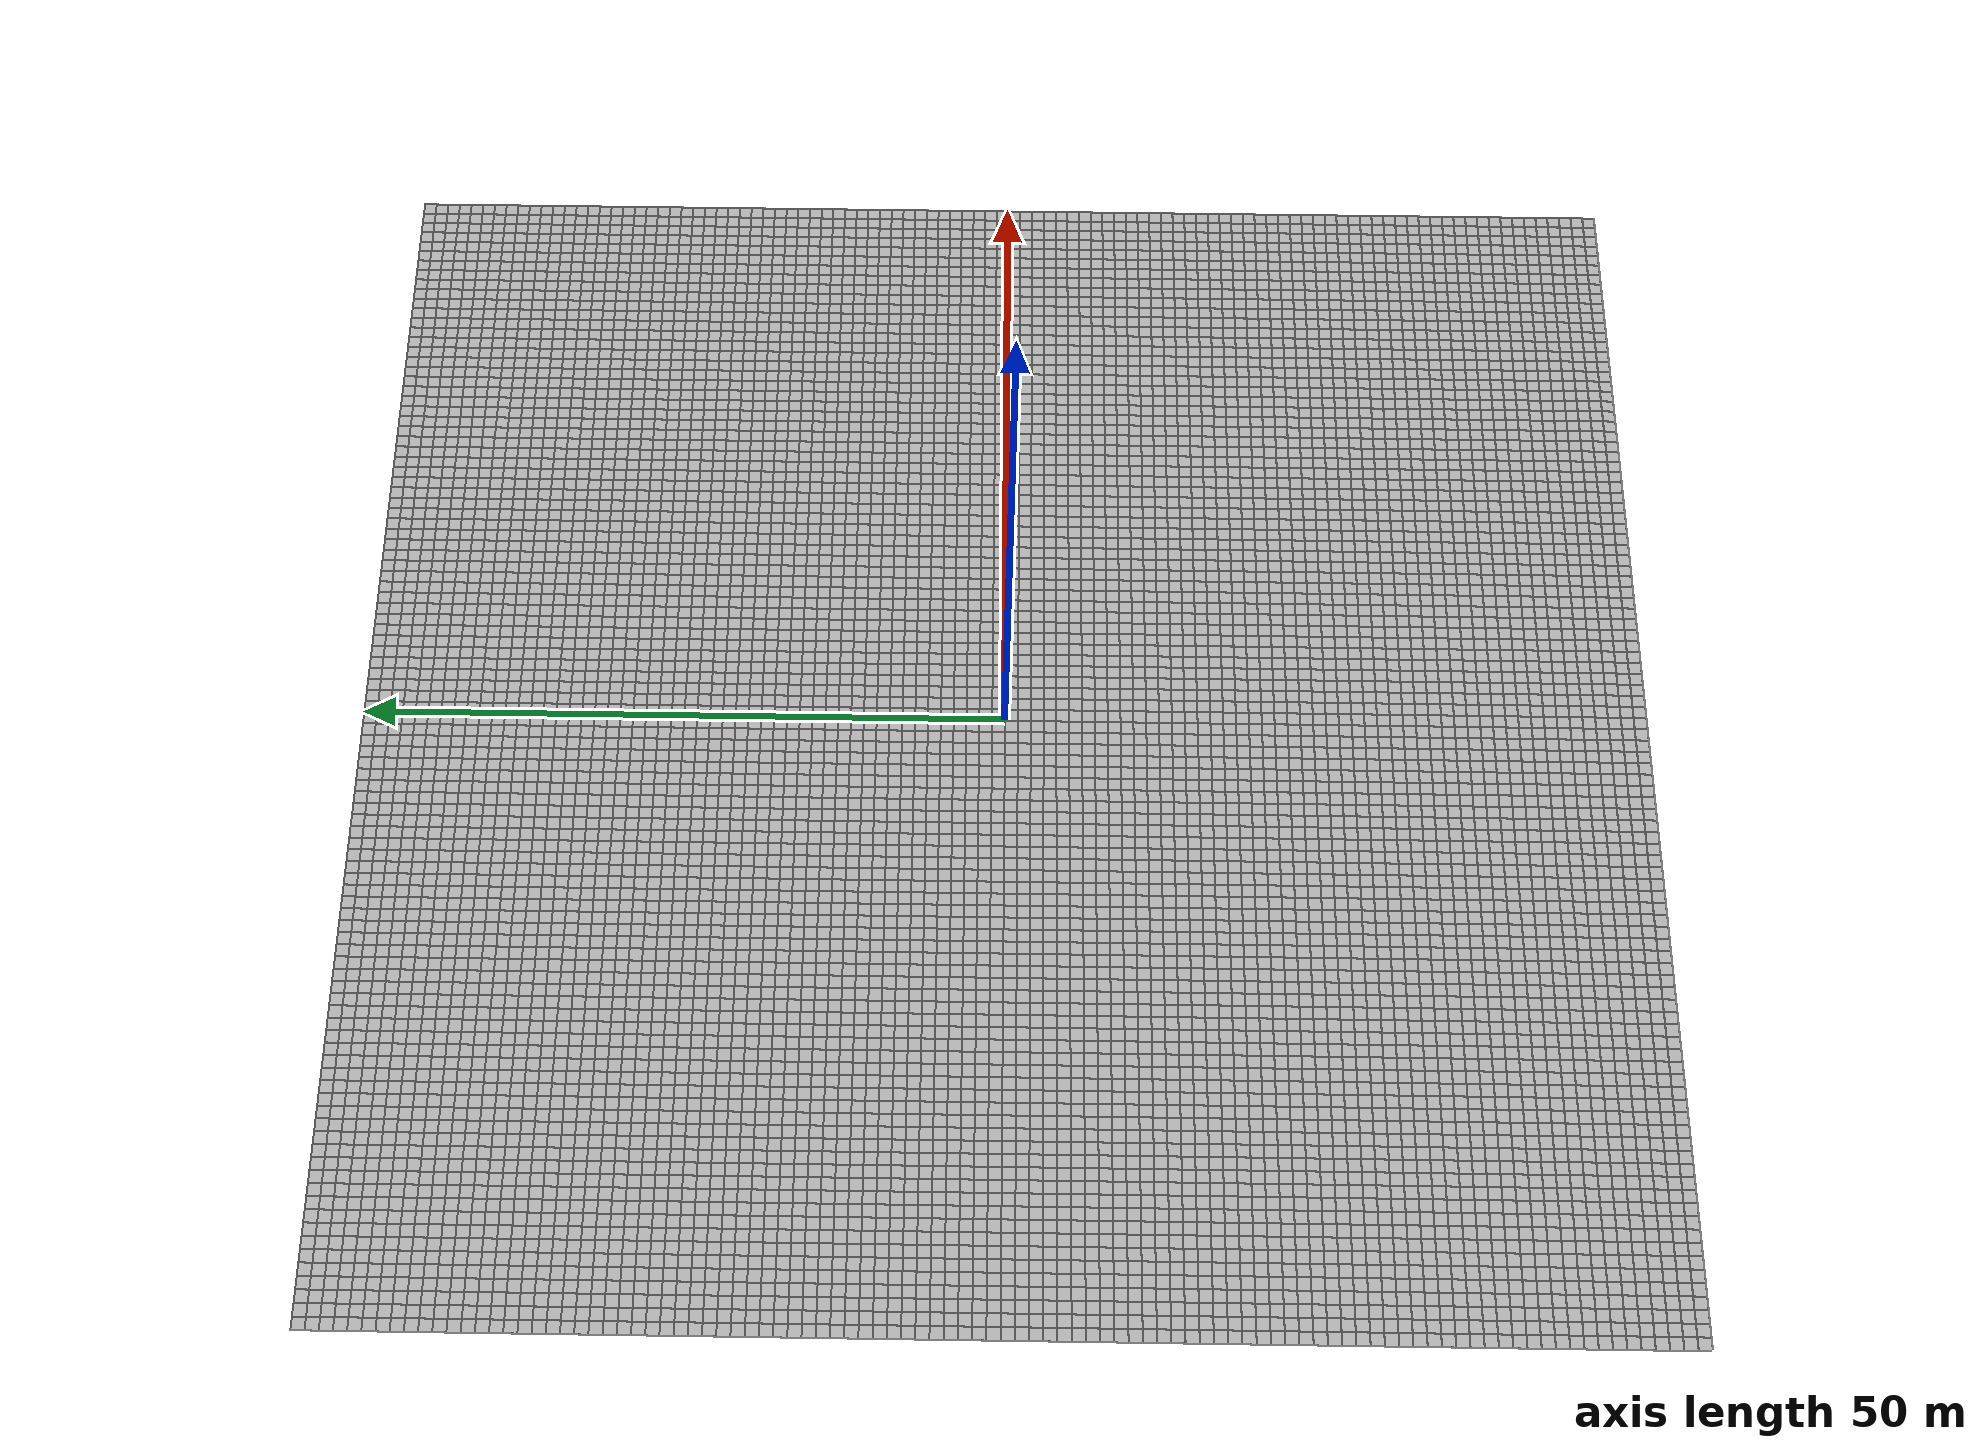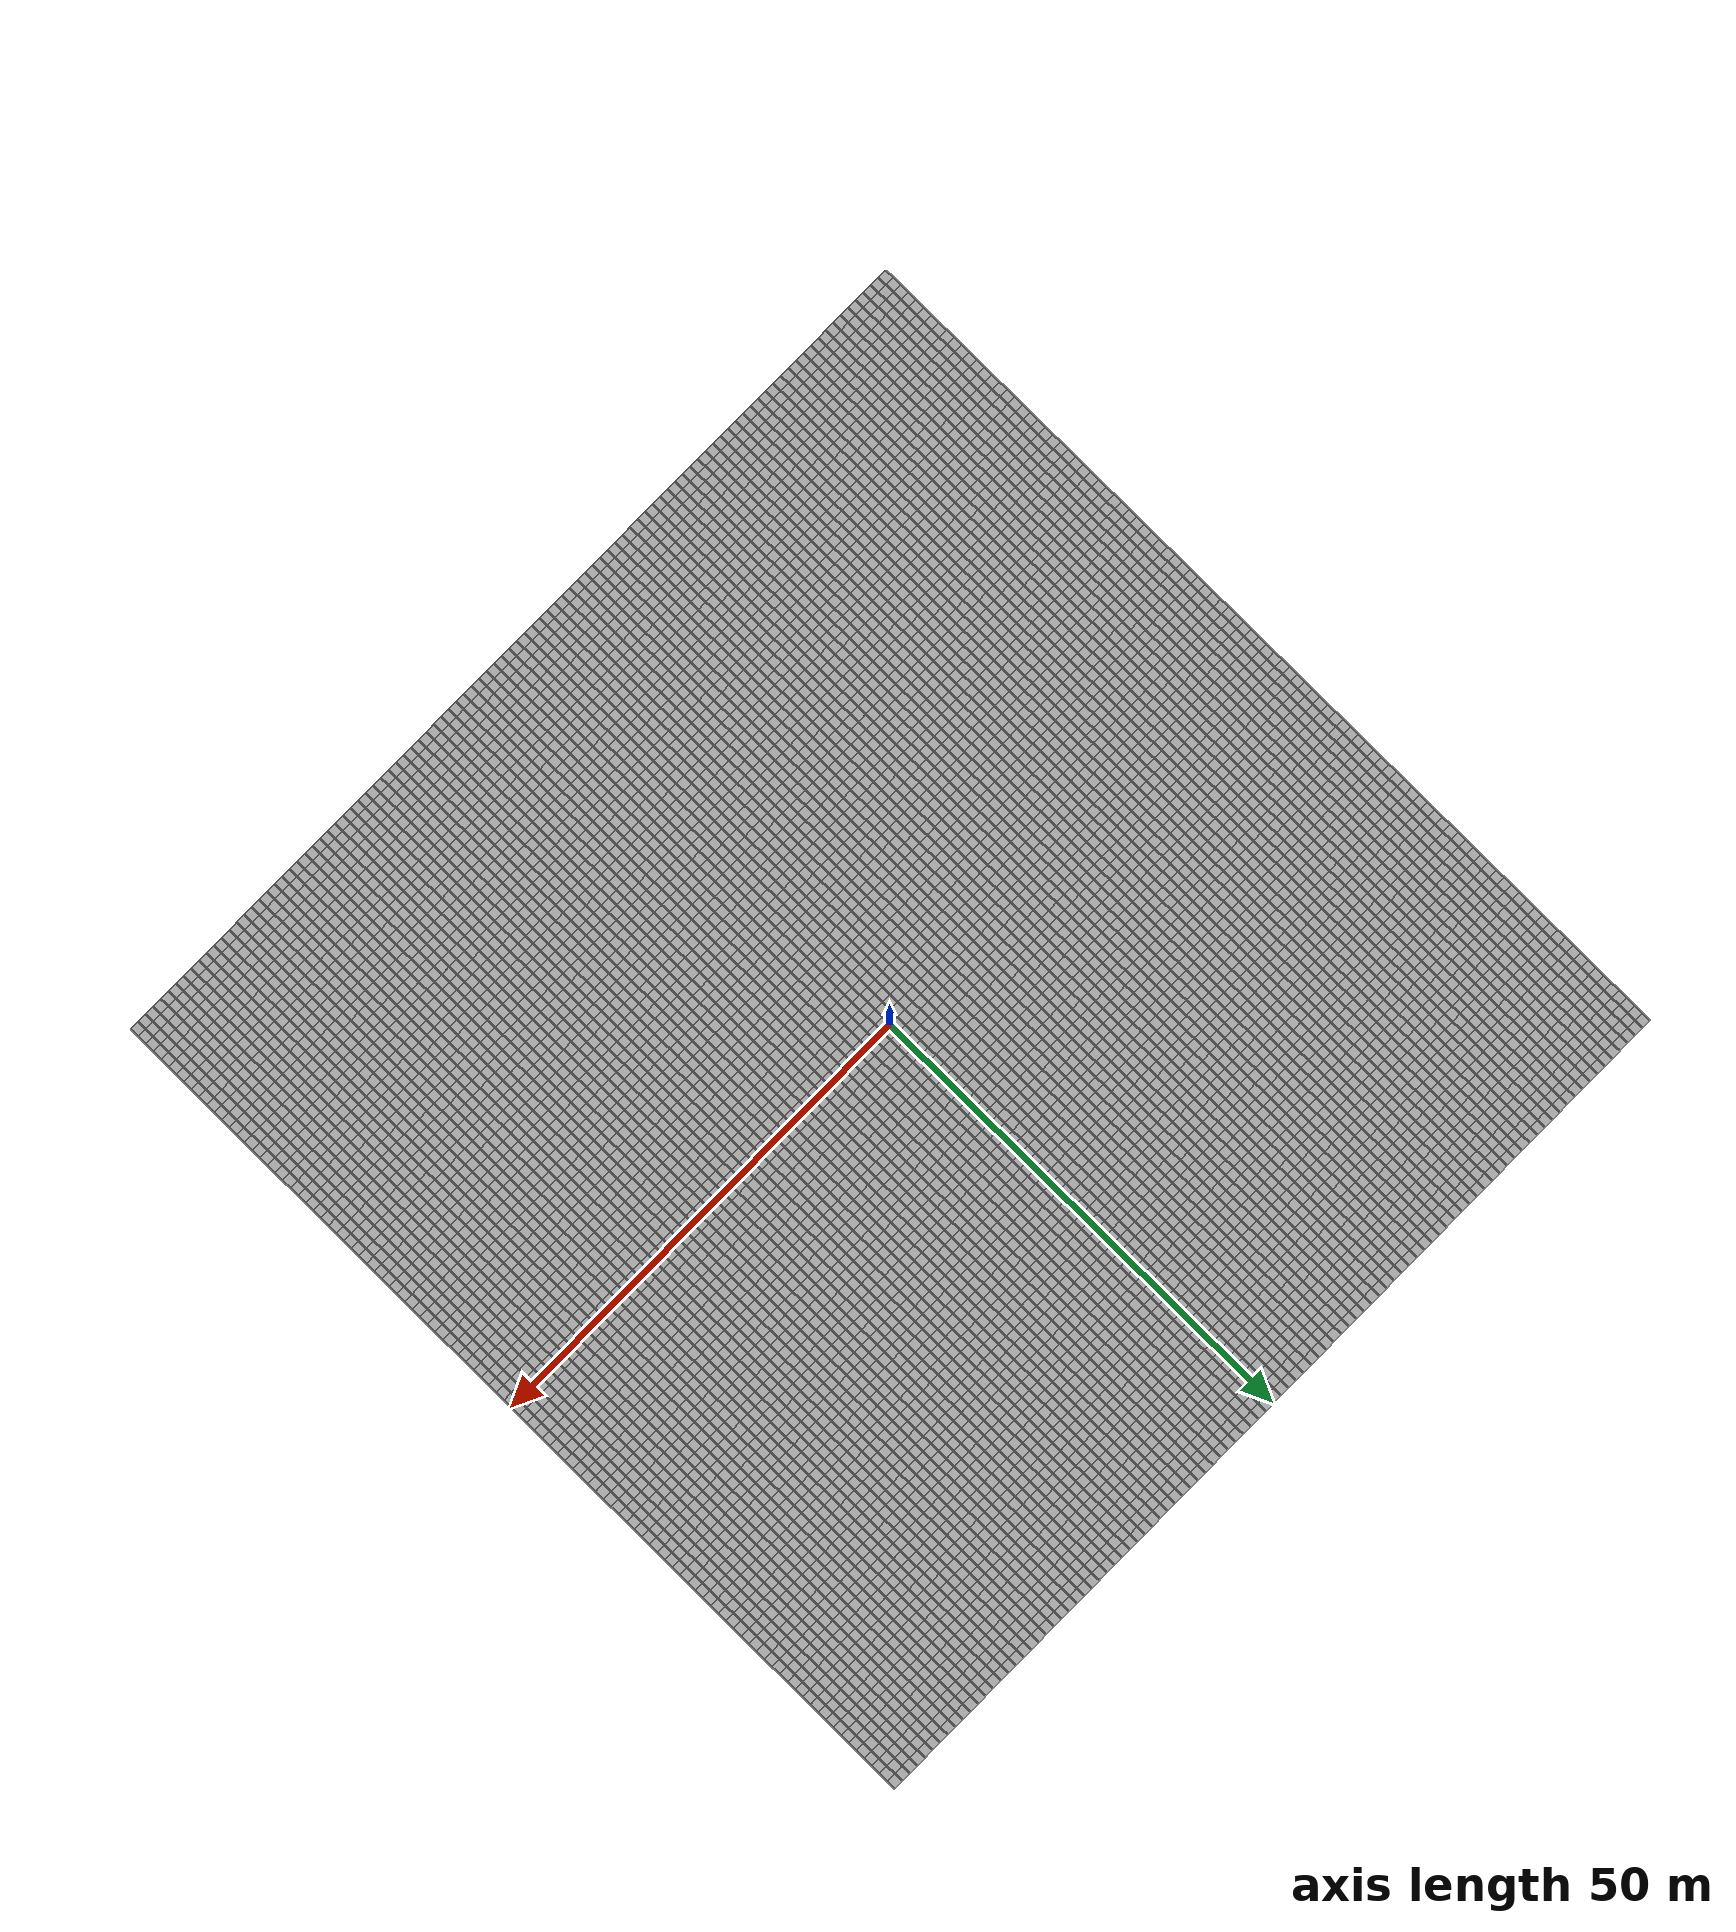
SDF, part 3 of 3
<uri>file:///home/wintery/Projects/gazebo/models/random_tile_ground/materials/scripts</uri>
      <uri>file:///home/wintery/Projects/gazebo/models/random_tile_ground/materials/textures</uri>
      <name>OrbTile/Tile04</name>
     </script>
    </material>
   </visual>
   <visual name="tile_65_66">
    <pose>15.500 16.500 0.001 0 0 1.57080</pose>
    <cast_shadows>false</cast_shadows>
    <geometry><plane><normal>0 0 1</normal><size>1 1</size></plane></geometry>
    <material>
     <script>
      <uri>file:///home/wintery/Projects/gazebo/models/random_tile_ground/materials/scripts</uri>
      <uri>file:///home/wintery/Projects/gazebo/models/random_tile_ground/materials/textures</uri>
      <name>OrbTile/Tile03</name>
     </script>
    </material>
   </visual>
   <visual name="tile_66_66">
    <pose>16.500 16.500 0.001 0 0 1.57080</pose>
    <cast_shadows>false</cast_shadows>
    <geometry><plane><normal>0 0 1</normal><size>1 1</size></plane></geometry>
    <material>
     <script>
      <uri>file:///home/wintery/Projects/gazebo/models/random_tile_ground/materials/scripts</uri>
      <uri>file:///home/wintery/Projects/gazebo/models/random_tile_ground/materials/textures</uri>
      <name>OrbTile/Tile08</name>
     </script>
    </material>
   </visual>
   <visual name="tile_67_66">
    <pose>17.500 16.500 0.001 0 0 1.57080</pose>
    <cast_shadows>false</cast_shadows>
    <geometry><plane><normal>0 0 1</normal><size>1 1</size></plane></geometry>
    <material>
     <script>
      <uri>file:///home/wintery/Projects/gazebo/models/random_tile_ground/materials/scripts</uri>
      <uri>file:///home/wintery/Projects/gazebo/models/random_tile_ground/materials/textures</uri>
      <name>OrbTile/Tile19</name>
     </script>
    </material>
   </visual>
   <visual name="tile_68_66">
    <pose>18.500 16.500 0.001 0 0 4.71239</pose>
    <cast_shadows>false</cast_shadows>
    <geometry><plane><normal>0 0 1</normal><size>1 1</size></plane></geometry>
    <material>
     <script>
      <uri>file:///home/wintery/Projects/gazebo/models/random_tile_ground/materials/scripts</uri>
      <uri>file:///home/wintery/Projects/gazebo/models/random_tile_ground/materials/textures</uri>
      <name>OrbTile/Tile18</name>
     </script>
    </material>
   </visual>
   <visual name="tile_69_66">
    <pose>19.500 16.500 0.001 0 0 3.14159</pose>
    <cast_shadows>false</cast_shadows>
    <geometry><plane><normal>0 0 1</normal><size>1 1</size></plane></geometry>
    <material>
     <script>
      <uri>file:///home/wintery/Projects/gazebo/models/random_tile_ground/materials/scripts</uri>
      <uri>file:///home/wintery/Projects/gazebo/models/random_tile_ground/materials/textures</uri>
      <name>OrbTile/Tile04</name>
     </script>
    </material>
   </visual>
   <visual name="tile_70_66">
    <pose>20.500 16.500 0.001 0 0 1.57080</pose>
    <cast_shadows>false</cast_shadows>
    <geometry><plane><normal>0 0 1</normal><size>1 1</size></plane></geometry>
    <material>
     <script>
      <uri>file:///home/wintery/Projects/gazebo/models/random_tile_ground/materials/scripts</uri>
      <uri>file:///home/wintery/Projects/gazebo/models/random_tile_ground/materials/textures</uri>
      <name>OrbTile/Tile13</name>
     </script>
    </material>
   </visual>
   <visual name="tile_71_66">
    <pose>21.500 16.500 0.001 0 0 4.71239</pose>
    <cast_shadows>false</cast_shadows>
    <geometry><plane><normal>0 0 1</normal><size>1 1</size></plane></geometry>
    <material>
     <script>
      <uri>file:///home/wintery/Projects/gazebo/models/random_tile_ground/materials/scripts</uri>
      <uri>file:///home/wintery/Projects/gazebo/models/random_tile_ground/materials/textures</uri>
      <name>OrbTile/Tile04</name>
     </script>
    </material>
   </visual>
   <visual name="tile_72_66">
    <pose>22.500 16.500 0.001 0 0 1.57080</pose>
    <cast_shadows>false</cast_shadows>
    <geometry><plane><normal>0 0 1</normal><size>1 1</size></plane></geometry>
    <material>
     <script>
      <uri>file:///home/wintery/Projects/gazebo/models/random_tile_ground/materials/scripts</uri>
      <uri>file:///home/wintery/Projects/gazebo/models/random_tile_ground/materials/textures</uri>
      <name>OrbTile/Tile16</name>
     </script>
    </material>
   </visual>
   <visual name="tile_73_66">
    <pose>23.500 16.500 0.001 0 0 0.00000</pose>
    <cast_shadows>false</cast_shadows>
    <geometry><plane><normal>0 0 1</normal><size>1 1</size></plane></geometry>
    <material>
     <script>
      <uri>file:///home/wintery/Projects/gazebo/models/random_tile_ground/materials/scripts</uri>
      <uri>file:///home/wintery/Projects/gazebo/models/random_tile_ground/materials/textures</uri>
      <name>OrbTile/Tile03</name>
     </script>
    </material>
   </visual>
   <visual name="tile_74_66">
    <pose>24.500 16.500 0.001 0 0 3.14159</pose>
    <cast_shadows>false</cast_shadows>
    <geometry><plane><normal>0 0 1</normal><size>1 1</size></plane></geometry>
    <material>
     <script>
      <uri>file:///home/wintery/Projects/gazebo/models/random_tile_ground/materials/scripts</uri>
      <uri>file:///home/wintery/Projects/gazebo/models/random_tile_ground/materials/textures</uri>
      <name>OrbTile/Tile14</name>
     </script>
    </material>
   </visual>
   <visual name="tile_75_66">
    <pose>25.500 16.500 0.001 0 0 0.00000</pose>
    <cast_shadows>false</cast_shadows>
    <geometry><plane><normal>0 0 1</normal><size>1 1</size></plane></geometry>
    <material>
     <script>
      <uri>file:///home/wintery/Projects/gazebo/models/random_tile_ground/materials/scripts</uri>
      <uri>file:///home/wintery/Projects/gazebo/models/random_tile_ground/materials/textures</uri>
      <name>OrbTile/Tile17</name>
     </script>
    </material>
   </visual>
   <visual name="tile_76_66">
    <pose>26.500 16.500 0.001 0 0 0.00000</pose>
    <cast_shadows>false</cast_shadows>
    <geometry><plane><normal>0 0 1</normal><size>1 1</size></plane></geometry>
    <material>
     <script>
      <uri>file:///home/wintery/Projects/gazebo/models/random_tile_ground/materials/scripts</uri>
      <uri>file:///home/wintery/Projects/gazebo/models/random_tile_ground/materials/textures</uri>
      <name>OrbTile/Tile10</name>
     </script>
    </material>
   </visual>
   <visual name="tile_77_66">
    <pose>27.500 16.500 0.001 0 0 0.00000</pose>
    <cast_shadows>false</cast_shadows>
    <geometry><plane><normal>0 0 1</normal><size>1 1</size></plane></geometry>
    <material>
     <script>
      <uri>file:///home/wintery/Projects/gazebo/models/random_tile_ground/materials/scripts</uri>
      <uri>file:///home/wintery/Projects/gazebo/models/random_tile_ground/materials/textures</uri>
      <name>OrbTile/Tile10</name>
     </script>
    </material>
   </visual>
   <visual name="tile_78_66">
    <pose>28.500 16.500 0.001 0 0 3.14159</pose>
    <cast_shadows>false</cast_shadows>
    <geometry><plane><normal>0 0 1</normal><size>1 1</size></plane></geometry>
    <material>
     <script>
      <uri>file:///home/wintery/Projects/gazebo/models/random_tile_ground/materials/scripts</uri>
      <uri>file:///home/wintery/Projects/gazebo/models/random_tile_ground/materials/textures</uri>
      <name>OrbTile/Tile17</name>
     </script>
    </material>
   </visual>
   <visual name="tile_79_66">
    <pose>29.500 16.500 0.001 0 0 3.14159</pose>
    <cast_shadows>false</cast_shadows>
    <geometry><plane><normal>0 0 1</normal><size>1 1</size></plane></geometry>
    <material>
     <script>
      <uri>file:///home/wintery/Projects/gazebo/models/random_tile_ground/materials/scripts</uri>
      <uri>file:///home/wintery/Projects/gazebo/models/random_tile_ground/materials/textures</uri>
      <name>OrbTile/Tile07</name>
     </script>
    </material>
   </visual>
   <visual name="tile_80_66">
    <pose>30.500 16.500 0.001 0 0 0.00000</pose>
    <cast_shadows>false</cast_shadows>
    <geometry><plane><normal>0 0 1</normal><size>1 1</size></plane></geometry>
    <material>
     <script>
      <uri>file:///home/wintery/Projects/gazebo/models/random_tile_ground/materials/scripts</uri>
      <uri>file:///home/wintery/Projects/gazebo/models/random_tile_ground/materials/textures</uri>
      <name>OrbTile/Tile13</name>
     </script>
    </material>
   </visual>
   <visual name="tile_81_66">
    <pose>31.500 16.500 0.001 0 0 4.71239</pose>
    <cast_shadows>false</cast_shadows>
    <geometry><plane><normal>0 0 1</normal><size>1 1</size></plane></geometry>
    <material>
     <script>
      <uri>file:///home/wintery/Projects/gazebo/models/random_tile_ground/materials/scripts</uri>
      <uri>file:///home/wintery/Projects/gazebo/models/random_tile_ground/materials/textures</uri>
      <name>OrbTile/Tile17</name>
     </script>
    </material>
   </visual>
   <visual name="tile_82_66">
    <pose>32.500 16.500 0.001 0 0 0.00000</pose>
    <cast_shadows>false</cast_shadows>
    <geometry><plane><normal>0 0 1</normal><size>1 1</size></plane></geometry>
    <material>
     <script>
      <uri>file:///home/wintery/Projects/gazebo/models/random_tile_ground/materials/scripts</uri>
      <uri>file:///home/wintery/Projects/gazebo/models/random_tile_ground/materials/textures</uri>
      <name>OrbTile/Tile04</name>
     </script>
    </material>
   </visual>
   <visual name="tile_83_66">
    <pose>33.500 16.500 0.001 0 0 3.14159</pose>
    <cast_shadows>false</cast_shadows>
    <geometry><plane><normal>0 0 1</normal><size>1 1</size></plane></geometry>
    <material>
     <script>
      <uri>file:///home/wintery/Projects/gazebo/models/random_tile_ground/materials/scripts</uri>
      <uri>file:///home/wintery/Projects/gazebo/models/random_tile_ground/materials/textures</uri>
      <name>OrbTile/Tile14</name>
     </script>
    </material>
   </visual>
   <visual name="tile_84_66">
    <pose>34.500 16.500 0.001 0 0 4.71239</pose>
    <cast_shadows>false</cast_shadows>
    <geometry><plane><normal>0 0 1</normal><size>1 1</size></plane></geometry>
    <material>
     <script>
      <uri>file:///home/wintery/Projects/gazebo/models/random_tile_ground/materials/scripts</uri>
      <uri>file:///home/wintery/Projects/gazebo/models/random_tile_ground/materials/textures</uri>
      <name>OrbTile/Tile01</name>
     </script>
    </material>
   </visual>
   <visual name="tile_85_66">
    <pose>35.500 16.500 0.001 0 0 3.14159</pose>
    <cast_shadows>false</cast_shadows>
    <geometry><plane><normal>0 0 1</normal><size>1 1</size></plane></geometry>
    <material>
     <script>
      <uri>file:///home/wintery/Projects/gazebo/models/random_tile_ground/materials/scripts</uri>
      <uri>file:///home/wintery/Projects/gazebo/models/random_tile_ground/materials/textures</uri>
      <name>OrbTile/Tile10</name>
     </script>
    </material>
   </visual>
   <visual name="tile_86_66">
    <pose>36.500 16.500 0.001 0 0 4.71239</pose>
    <cast_shadows>false</cast_shadows>
    <geometry><plane><normal>0 0 1</normal><size>1 1</size></plane></geometry>
    <material>
     <script>
      <uri>file:///home/wintery/Projects/gazebo/models/random_tile_ground/materials/scripts</uri>
      <uri>file:///home/wintery/Projects/gazebo/models/random_tile_ground/materials/textures</uri>
      <name>OrbTile/Tile11</name>
     </script>
    </material>
   </visual>
   <visual name="tile_87_66">
    <pose>37.500 16.500 0.001 0 0 0.00000</pose>
    <cast_shadows>false</cast_shadows>
    <geometry><plane><normal>0 0 1</normal><size>1 1</size></plane></geometry>
    <material>
     <script>
      <uri>file:///home/wintery/Projects/gazebo/models/random_tile_ground/materials/scripts</uri>
      <uri>file:///home/wintery/Projects/gazebo/models/random_tile_ground/materials/textures</uri>
      <name>OrbTile/Tile09</name>
     </script>
    </material>
   </visual>
   <visual name="tile_88_66">
    <pose>38.500 16.500 0.001 0 0 3.14159</pose>
    <cast_shadows>false</cast_shadows>
    <geometry><plane><normal>0 0 1</normal><size>1 1</size></plane></geometry>
    <material>
     <script>
      <uri>file:///home/wintery/Projects/gazebo/models/random_tile_ground/materials/scripts</uri>
      <uri>file:///home/wintery/Projects/gazebo/models/random_tile_ground/materials/textures</uri>
      <name>OrbTile/Tile02</name>
     </script>
    </material>
   </visual>
   <visual name="tile_89_66">
    <pose>39.500 16.500 0.001 0 0 0.00000</pose>
    <cast_shadows>false</cast_shadows>
    <geometry><plane><normal>0 0 1</normal><size>1 1</size></plane></geometry>
    <material>
     <script>
      <uri>file:///home/wintery/Projects/gazebo/models/random_tile_ground/materials/scripts</uri>
      <uri>file:///home/wintery/Projects/gazebo/models/random_tile_ground/materials/textures</uri>
      <name>OrbTile/Tile12</name>
     </script>
    </material>
   </visual>
   <visual name="tile_90_66">
    <pose>40.500 16.500 0.001 0 0 3.14159</pose>
    <cast_shadows>false</cast_shadows>
    <geometry><plane><normal>0 0 1</normal><size>1 1</size></plane></geometry>
    <material>
     <script>
      <uri>file:///home/wintery/Projects/gazebo/models/random_tile_ground/materials/scripts</uri>
      <uri>file:///home/wintery/Projects/gazebo/models/random_tile_ground/materials/textures</uri>
      <name>OrbTile/Tile17</name>
     </script>
    </material>
   </visual>
   <visual name="tile_91_66">
    <pose>41.500 16.500 0.001 0 0 4.71239</pose>
    <cast_shadows>false</cast_shadows>
    <geometry><plane><normal>0 0 1</normal><size>1 1</size></plane></geometry>
    <material>
     <script>
      <uri>file:///home/wintery/Projects/gazebo/models/random_tile_ground/materials/scripts</uri>
      <uri>file:///home/wintery/Projects/gazebo/models/random_tile_ground/materials/textures</uri>
      <name>OrbTile/Tile17</name>
     </script>
    </material>
   </visual>
   <visual name="tile_92_66">
    <pose>42.500 16.500 0.001 0 0 3.14159</pose>
    <cast_shadows>false</cast_shadows>
    <geometry><plane><normal>0 0 1</normal><size>1 1</size></plane></geometry>
    <material>
     <script>
      <uri>file:///home/wintery/Projects/gazebo/models/random_tile_ground/materials/scripts</uri>
      <uri>file:///home/wintery/Projects/gazebo/models/random_tile_ground/materials/textures</uri>
      <name>OrbTile/Tile11</name>
     </script>
    </material>
   </visual>
   <visual name="tile_93_66">
    <pose>43.500 16.500 0.001 0 0 3.14159</pose>
    <cast_shadows>false</cast_shadows>
    <geometry><plane><normal>0 0 1</normal><size>1 1</size></plane></geometry>
    <material>
     <script>
      <uri>file:///home/wintery/Projects/gazebo/models/random_tile_ground/materials/scripts</uri>
      <uri>file:///home/wintery/Projects/gazebo/models/random_tile_ground/materials/textures</uri>
      <name>OrbTile/Tile13</name>
     </script>
    </material>
   </visual>
   <visual name="tile_94_66">
    <pose>44.500 16.500 0.001 0 0 4.71239</pose>
    <cast_shadows>false</cast_shadows>
    <geometry><plane><normal>0 0 1</normal><size>1 1</size></plane></geometry>
    <material>
     <script>
      <uri>file:///home/wintery/Projects/gazebo/models/random_tile_ground/materials/scripts</uri>
      <uri>file:///home/wintery/Projects/gazebo/models/random_tile_ground/materials/textures</uri>
      <name>OrbTile/Tile15</name>
     </script>
    </material>
   </visual>
   <visual name="tile_95_66">
    <pose>45.500 16.500 0.001 0 0 0.00000</pose>
    <cast_shadows>false</cast_shadows>
    <geometry><plane><normal>0 0 1</normal><size>1 1</size></plane></geometry>
    <material>
     <script>
      <uri>file:///home/wintery/Projects/gazebo/models/random_tile_ground/materials/scripts</uri>
      <uri>file:///home/wintery/Projects/gazebo/models/random_tile_ground/materials/textures</uri>
      <name>OrbTile/Tile19</name>
     </script>
    </material>
   </visual>
   <visual name="tile_96_66">
    <pose>46.500 16.500 0.001 0 0 4.71239</pose>
    <cast_shadows>false</cast_shadows>
    <geometry><plane><normal>0 0 1</normal><size>1 1</size></plane></geometry>
    <material>
     <script>
      <uri>file:///home/wintery/Projects/gazebo/models/random_tile_ground/materials/scripts</uri>
      <uri>file:///home/wintery/Projects/gazebo/models/random_tile_ground/materials/textures</uri>
      <name>OrbTile/Tile00</name>
     </script>
    </material>
   </visual>
   <visual name="tile_97_66">
    <pose>47.500 16.500 0.001 0 0 3.14159</pose>
    <cast_shadows>false</cast_shadows>
    <geometry><plane><normal>0 0 1</normal><size>1 1</size></plane></geometry>
    <material>
     <script>
      <uri>file:///home/wintery/Projects/gazebo/models/random_tile_ground/materials/scripts</uri>
      <uri>file:///home/wintery/Projects/gazebo/models/random_tile_ground/materials/textures</uri>
      <name>OrbTile/Tile17</name>
     </script>
    </material>
   </visual>
   <visual name="tile_98_66">
    <pose>48.500 16.500 0.001 0 0 4.71239</pose>
    <cast_shadows>false</cast_shadows>
    <geometry><plane><normal>0 0 1</normal><size>1 1</size></plane></geometry>
    <material>
     <script>
      <uri>file:///home/wintery/Projects/gazebo/models/random_tile_ground/materials/scripts</uri>
      <uri>file:///home/wintery/Projects/gazebo/models/random_tile_ground/materials/textures</uri>
      <name>OrbTile/Tile11</name>
     </script>
    </material>
   </visual>
   <visual name="tile_99_66">
    <pose>49.500 16.500 0.001 0 0 3.14159</pose>
    <cast_shadows>false</cast_shadows>
    <geometry><plane><normal>0 0 1</normal><size>1 1</size></plane></geometry>
    <material>
     <script>
      <uri>file:///home/wintery/Projects/gazebo/models/random_tile_ground/materials/scripts</uri>
      <uri>file:///home/wintery/Projects/gazebo/models/random_tile_ground/materials/textures</uri>
      <name>OrbTile/Tile19</name>
     </script>
    </material>
   </visual>
   <visual name="tile_00_67">
    <pose>-49.500 17.500 0.001 0 0 1.57080</pose>
    <cast_shadows>false</cast_shadows>
    <geometry><plane><normal>0 0 1</normal><size>1 1</size></plane></geometry>
    <material>
     <script>
      <uri>file:///home/wintery/Projects/gazebo/models/random_tile_ground/materials/scripts</uri>
      <uri>file:///home/wintery/Projects/gazebo/models/random_tile_ground/materials/textures</uri>
      <name>OrbTile/Tile19</name>
     </script>
    </material>
   </visual>
   <visual name="tile_01_67">
    <pose>-48.500 17.500 0.001 0 0 1.57080</pose>
    <cast_shadows>false</cast_shadows>
    <geometry><plane><normal>0 0 1</normal><size>1 1</size></plane></geometry>
    <material>
     <script>
      <uri>file:///home/wintery/Projects/gazebo/models/random_tile_ground/materials/scripts</uri>
      <uri>file:///home/wintery/Projects/gazebo/models/random_tile_ground/materials/textures</uri>
      <name>OrbTile/Tile19</name>
     </script>
    </material>
   </visual>
   <visual name="tile_02_67">
    <pose>-47.500 17.500 0.001 0 0 3.14159</pose>
    <cast_shadows>false</cast_shadows>
    <geometry><plane><normal>0 0 1</normal><size>1 1</size></plane></geometry>
    <material>
     <script>
      <uri>file:///home/wintery/Projects/gazebo/models/random_tile_ground/materials/scripts</uri>
      <uri>file:///home/wintery/Projects/gazebo/models/random_tile_ground/materials/textures</uri>
      <name>OrbTile/Tile11</name>
     </script>
    </material>
   </visual>
   <visual name="tile_03_67">
    <pose>-46.500 17.500 0.001 0 0 1.57080</pose>
    <cast_shadows>false</cast_shadows>
    <geometry><plane><normal>0 0 1</normal><size>1 1</size></plane></geometry>
    <material>
     <script>
      <uri>file:///home/wintery/Projects/gazebo/models/random_tile_ground/materials/scripts</uri>
      <uri>file:///home/wintery/Projects/gazebo/models/random_tile_ground/materials/textures</uri>
      <name>OrbTile/Tile06</name>
     </script>
    </material>
   </visual>
   <visual name="tile_04_67">
    <pose>-45.500 17.500 0.001 0 0 4.71239</pose>
    <cast_shadows>false</cast_shadows>
    <geometry><plane><normal>0 0 1</normal><size>1 1</size></plane></geometry>
    <material>
     <script>
      <uri>file:///home/wintery/Projects/gazebo/models/random_tile_ground/materials/scripts</uri>
      <uri>file:///home/wintery/Projects/gazebo/models/random_tile_ground/materials/textures</uri>
      <name>OrbTile/Tile00</name>
     </script>
    </material>
   </visual>
   <visual name="tile_05_67">
    <pose>-44.500 17.500 0.001 0 0 1.57080</pose>
    <cast_shadows>false</cast_shadows>
    <geometry><plane><normal>0 0 1</normal><size>1 1</size></plane></geometry>
    <material>
     <script>
      <uri>file:///home/wintery/Projects/gazebo/models/random_tile_ground/materials/scripts</uri>
      <uri>file:///home/wintery/Projects/gazebo/models/random_tile_ground/materials/textures</uri>
      <name>OrbTile/Tile00</name>
     </script>
    </material>
   </visual>
   <visual name="tile_06_67">
    <pose>-43.500 17.500 0.001 0 0 3.14159</pose>
    <cast_shadows>false</cast_shadows>
    <geometry><plane><normal>0 0 1</normal><size>1 1</size></plane></geometry>
    <material>
     <script>
      <uri>file:///home/wintery/Projects/gazebo/models/random_tile_ground/materials/scripts</uri>
      <uri>file:///home/wintery/Projects/gazebo/models/random_tile_ground/materials/textures</uri>
      <name>OrbTile/Tile14</name>
     </script>
    </material>
   </visual>
   <visual name="tile_07_67">
    <pose>-42.500 17.500 0.001 0 0 4.71239</pose>
    <cast_shadows>false</cast_shadows>
    <geometry><plane><normal>0 0 1</normal><size>1 1</size></plane></geometry>
    <material>
     <script>
      <uri>file:///home/wintery/Projects/gazebo/models/random_tile_ground/materials/scripts</uri>
      <uri>file:///home/wintery/Projects/gazebo/models/random_tile_ground/materials/textures</uri>
      <name>OrbTile/Tile04</name>
     </script>
    </material>
   </visual>
   <visual name="tile_08_67">
    <pose>-41.500 17.500 0.001 0 0 4.71239</pose>
    <cast_shadows>false</cast_shadows>
    <geometry><plane><normal>0 0 1</normal><size>1 1</size></plane></geometry>
    <material>
     <script>
      <uri>file:///home/wintery/Projects/gazebo/models/random_tile_ground/materials/scripts</uri>
      <uri>file:///home/wintery/Projects/gazebo/models/random_tile_ground/materials/textures</uri>
      <name>OrbTile/Tile02</name>
     </script>
    </material>
   </visual>
   <visual name="tile_09_67">
    <pose>-40.500 17.500 0.001 0 0 0.00000</pose>
    <cast_shadows>false</cast_shadows>
    <geometry><plane><normal>0 0 1</normal><size>1 1</size></plane></geometry>
    <material>
     <script>
      <uri>file:///home/wintery/Projects/gazebo/models/random_tile_ground/materials/scripts</uri>
      <uri>file:///home/wintery/Projects/gazebo/models/random_tile_ground/materials/textures</uri>
      <name>OrbTile/Tile08</name>
     </script>
    </material>
   </visual>
   <visual name="tile_10_67">
    <pose>-39.500 17.500 0.001 0 0 1.57080</pose>
    <cast_shadows>false</cast_shadows>
    <geometry><plane><normal>0 0 1</normal><size>1 1</size></plane></geometry>
    <material>
     <script>
      <uri>file:///home/wintery/Projects/gazebo/models/random_tile_ground/materials/scripts</uri>
      <uri>file:///home/wintery/Projects/gazebo/models/random_tile_ground/materials/textures</uri>
      <name>OrbTile/Tile01</name>
     </script>
    </material>
   </visual>
   <visual name="tile_11_67">
    <pose>-38.500 17.500 0.001 0 0 0.00000</pose>
    <cast_shadows>false</cast_shadows>
    <geometry><plane><normal>0 0 1</normal><size>1 1</size></plane></geometry>
    <material>
     <script>
      <uri>file:///home/wintery/Projects/gazebo/models/random_tile_ground/materials/scripts</uri>
      <uri>file:///home/wintery/Projects/gazebo/models/random_tile_ground/materials/textures</uri>
      <name>OrbTile/Tile17</name>
     </script>
    </material>
   </visual>
   <visual name="tile_12_67">
    <pose>-37.500 17.500 0.001 0 0 4.71239</pose>
    <cast_shadows>false</cast_shadows>
    <geometry><plane><normal>0 0 1</normal><size>1 1</size></plane></geometry>
    <material>
     <script>
      <uri>file:///home/wintery/Projects/gazebo/models/random_tile_ground/materials/scripts</uri>
      <uri>file:///home/wintery/Projects/gazebo/models/random_tile_ground/materials/textures</uri>
      <name>OrbTile/Tile03</name>
     </script>
    </material>
   </visual>
   <visual name="tile_13_67">
    <pose>-36.500 17.500 0.001 0 0 1.57080</pose>
    <cast_shadows>false</cast_shadows>
    <geometry><plane><normal>0 0 1</normal><size>1 1</size></plane></geometry>
    <material>
     <script>
      <uri>file:///home/wintery/Projects/gazebo/models/random_tile_ground/materials/scripts</uri>
      <uri>file:///home/wintery/Projects/gazebo/models/random_tile_ground/materials/textures</uri>
      <name>OrbTile/Tile05</name>
     </script>
    </material>
   </visual>
   <visual name="tile_14_67">
    <pose>-35.500 17.500 0.001 0 0 0.00000</pose>
    <cast_shadows>false</cast_shadows>
    <geometry><plane><normal>0 0 1</normal><size>1 1</size></plane></geometry>
    <material>
     <script>
      <uri>file:///home/wintery/Projects/gazebo/models/random_tile_ground/materials/scripts</uri>
      <uri>file:///home/wintery/Projects/gazebo/models/random_tile_ground/materials/textures</uri>
      <name>OrbTile/Tile12</name>
     </script>
    </material>
   </visual>
   <visual name="tile_15_67">
    <pose>-34.500 17.500 0.001 0 0 0.00000</pose>
    <cast_shadows>false</cast_shadows>
    <geometry><plane><normal>0 0 1</normal><size>1 1</size></plane></geometry>
    <material>
     <script>
      <uri>file:///home/wintery/Projects/gazebo/models/random_tile_ground/materials/scripts</uri>
      <uri>file:///home/wintery/Projects/gazebo/models/random_tile_ground/materials/textures</uri>
      <name>OrbTile/Tile02</name>
     </script>
    </material>
   </visual>
   <visual name="tile_16_67">
    <pose>-33.500 17.500 0.001 0 0 0.00000</pose>
    <cast_shadows>false</cast_shadows>
    <geometry><plane><normal>0 0 1</normal><size>1 1</size></plane></geometry>
    <material>
     <script>
      <uri>file:///home/wintery/Projects/gazebo/models/random_tile_ground/materials/scripts</uri>
      <uri>file:///home/wintery/Projects/gazebo/models/random_tile_ground/materials/textures</uri>
      <name>OrbTile/Tile19</name>
     </script>
    </material>
   </visual>
   <visual name="tile_17_67">
    <pose>-32.500 17.500 0.001 0 0 0.00000</pose>
    <cast_shadows>false</cast_shadows>
    <geometry><plane><normal>0 0 1</normal><size>1 1</size></plane></geometry>
    <material>
     <script>
      <uri>file:///home/wintery/Projects/gazebo/models/random_tile_ground/materials/scripts</uri>
      <uri>file:///home/wintery/Projects/gazebo/models/random_tile_ground/materials/textures</uri>
      <name>OrbTile/Tile12</name>
     </script>
    </material>
   </visual>
   <visual name="tile_18_67">
    <pose>-31.500 17.500 0.001 0 0 1.57080</pose>
    <cast_shadows>false</cast_shadows>
    <geometry><plane><normal>0 0 1</normal><size>1 1</size></plane></geometry>
    <material>
     <script>
      <uri>file:///home/wintery/Projects/gazebo/models/random_tile_ground/materials/scripts</uri>
      <uri>file:///home/wintery/Projects/gazebo/models/random_tile_ground/materials/textures</uri>
      <name>OrbTile/Tile12</name>
     </script>
    </material>
   </visual>
   <visual name="tile_19_67">
    <pose>-30.500 17.500 0.001 0 0 1.57080</pose>
    <cast_shadows>false</cast_shadows>
    <geometry><plane><normal>0 0 1</normal><size>1 1</size></plane></geometry>
    <material>
     <script>
      <uri>file:///home/wintery/Projects/gazebo/models/random_tile_ground/materials/scripts</uri>
      <uri>file:///home/wintery/Projects/gazebo/models/random_tile_ground/materials/textures</uri>
      <name>OrbTile/Tile17</name>
     </script>
    </material>
   </visual>
   <visual name="tile_20_67">
    <pose>-29.500 17.500 0.001 0 0 0.00000</pose>
    <cast_shadows>false</cast_shadows>
    <geometry><plane><normal>0 0 1</normal><size>1 1</size></plane></geometry>
    <material>
     <script>
      <uri>file:///home/wintery/Projects/gazebo/models/random_tile_ground/materials/scripts</uri>
      <uri>file:///home/wintery/Projects/gazebo/models/random_tile_ground/materials/textures</uri>
      <name>OrbTile/Tile07</name>
     </script>
    </material>
   </visual>
   <visual name="tile_21_67">
    <pose>-28.500 17.500 0.001 0 0 0.00000</pose>
    <cast_shadows>false</cast_shadows>
    <geometry><plane><normal>0 0 1</normal><size>1 1</size></plane></geometry>
    <material>
     <script>
      <uri>file:///home/wintery/Projects/gazebo/models/random_tile_ground/materials/scripts</uri>
      <uri>file:///home/wintery/Projects/gazebo/models/random_tile_ground/materials/textures</uri>
      <name>OrbTile/Tile04</name>
     </script>
    </material>
   </visual>
   <visual name="tile_22_67">
    <pose>-27.500 17.500 0.001 0 0 3.14159</pose>
    <cast_shadows>false</cast_shadows>
    <geometry><plane><normal>0 0 1</normal><size>1 1</size></plane></geometry>
    <material>
     <script>
      <uri>file:///home/wintery/Projects/gazebo/models/random_tile_ground/materials/scripts</uri>
      <uri>file:///home/wintery/Projects/gazebo/models/random_tile_ground/materials/textures</uri>
      <name>OrbTile/Tile07</name>
     </script>
    </material>
   </visual>
   <visual name="tile_23_67">
    <pose>-26.500 17.500 0.001 0 0 3.14159</pose>
    <cast_shadows>false</cast_shadows>
    <geometry><plane><normal>0 0 1</normal><size>1 1</size></plane></geometry>
    <material>
     <script>
      <uri>file:///home/wintery/Projects/gazebo/models/random_tile_ground/materials/scripts</uri>
      <uri>file:///home/wintery/Projects/gazebo/models/random_tile_ground/materials/textures</uri>
      <name>OrbTile/Tile16</name>
     </script>
    </material>
   </visual>
   <visual name="tile_24_67">
    <pose>-25.500 17.500 0.001 0 0 0.00000</pose>
    <cast_shadows>false</cast_shadows>
    <geometry><plane><normal>0 0 1</normal><size>1 1</size></plane></geometry>
    <material>
     <script>
      <uri>file:///home/wintery/Projects/gazebo/models/random_tile_ground/materials/scripts</uri>
      <uri>file:///home/wintery/Projects/gazebo/models/random_tile_ground/materials/textures</uri>
      <name>OrbTile/Tile16</name>
     </script>
    </material>
   </visual>
   <visual name="tile_25_67">
    <pose>-24.500 17.500 0.001 0 0 0.00000</pose>
    <cast_shadows>false</cast_shadows>
    <geometry><plane><normal>0 0 1</normal><size>1 1</size></plane></geometry>
    <material>
     <script>
      <uri>file:///home/wintery/Projects/gazebo/models/random_tile_ground/materials/scripts</uri>
      <uri>file:///home/wintery/Projects/gazebo/models/random_tile_ground/materials/textures</uri>
      <name>OrbTile/Tile07</name>
     </script>
    </material>
   </visual>
   <visual name="tile_26_67">
    <pose>-23.500 17.500 0.001 0 0 1.57080</pose>
    <cast_shadows>false</cast_shadows>
    <geometry><plane><normal>0 0 1</normal><size>1 1</size></plane></geometry>
    <material>
     <script>
      <uri>file:///home/wintery/Projects/gazebo/models/random_tile_ground/materials/scripts</uri>
      <uri>file:///home/wintery/Projects/gazebo/models/random_tile_ground/materials/textures</uri>
      <name>OrbTile/Tile16</name>
     </script>
    </material>
   </visual>
   <visual name="tile_27_67">
    <pose>-22.500 17.500 0.001 0 0 1.57080</pose>
    <cast_shadows>false</cast_shadows>
    <geometry><plane><normal>0 0 1</normal><size>1 1</size></plane></geometry>
    <material>
     <script>
      <uri>file:///home/wintery/Projects/gazebo/models/random_tile_ground/materials/scripts</uri>
      <uri>file:///home/wintery/Projects/gazebo/models/random_tile_ground/materials/textures</uri>
      <name>OrbTile/Tile02</name>
     </script>
    </material>
   </visual>
   <visual name="tile_28_67">
    <pose>-21.500 17.500 0.001 0 0 3.14159</pose>
    <cast_shadows>false</cast_shadows>
    <geometry><plane><normal>0 0 1</normal><size>1 1</size></plane></geometry>
    <material>
     <script>
      <uri>file:///home/wintery/Projects/gazebo/models/random_tile_ground/materials/scripts</uri>
      <uri>file:///home/wintery/Projects/gazebo/models/random_tile_ground/materials/textures</uri>
      <name>OrbTile/Tile16</name>
     </script>
    </material>
   </visual>
   <visual name="tile_29_67">
    <pose>-20.500 17.500 0.001 0 0 4.71239</pose>
    <cast_shadows>false</cast_shadows>
    <geometry><plane><normal>0 0 1</normal><size>1 1</size></plane></geometry>
    <material>
     <script>
      <uri>file:///home/wintery/Projects/gazebo/models/random_tile_ground/materials/scripts</uri>
      <uri>file:///home/wintery/Projects/gazebo/models/random_tile_ground/materials/textures</uri>
      <name>OrbTile/Tile10</name>
     </script>
    </material>
   </visual>
   <visual name="tile_30_67">
    <pose>-19.500 17.500 0.001 0 0 0.00000</pose>
    <cast_shadows>false</cast_shadows>
    <geometry><plane><normal>0 0 1</normal><size>1 1</size></plane></geometry>
    <material>
     <script>
      <uri>file:///home/wintery/Projects/gazebo/models/random_tile_ground/materials/scripts</uri>
      <uri>file:///home/wintery/Projects/gazebo/models/random_tile_ground/materials/textures</uri>
      <name>OrbTile/Tile10</name>
     </script>
    </material>
   </visual>
   <visual name="tile_31_67">
    <pose>-18.500 17.500 0.001 0 0 1.57080</pose>
    <cast_shadows>false</cast_shadows>
    <geometry><plane><normal>0 0 1</normal><size>1 1</size></plane></geometry>
    <material>
     <script>
      <uri>file:///home/wintery/Projects/gazebo/models/random_tile_ground/materials/scripts</uri>
      <uri>file:///home/wintery/Projects/gazebo/models/random_tile_ground/materials/textures</uri>
      <name>OrbTile/Tile09</name>
     </script>
    </material>
   </visual>
   <visual name="tile_32_67">
    <pose>-17.500 17.500 0.001 0 0 1.57080</pose>
    <cast_shadows>false</cast_shadows>
    <geometry><plane><normal>0 0 1</normal><size>1 1</size></plane></geometry>
    <material>
     <script>
      <uri>file:///home/wintery/Projects/gazebo/models/random_tile_ground/materials/scripts</uri>
      <uri>file:///home/wintery/Projects/gazebo/models/random_tile_ground/materials/textures</uri>
      <name>OrbTile/Tile15</name>
     </script>
    </material>
   </visual>
   <visual name="tile_33_67">
    <pose>-16.500 17.500 0.001 0 0 0.00000</pose>
    <cast_shadows>false</cast_shadows>
    <geometry><plane><normal>0 0 1</normal><size>1 1</size></plane></geometry>
    <material>
     <script>
      <uri>file:///home/wintery/Projects/gazebo/models/random_tile_ground/materials/scripts</uri>
      <uri>file:///home/wintery/Projects/gazebo/models/random_tile_ground/materials/textures</uri>
      <name>OrbTile/Tile02</name>
     </script>
    </material>
   </visual>
   <visual name="tile_34_67">
    <pose>-15.500 17.500 0.001 0 0 0.00000</pose>
    <cast_shadows>false</cast_shadows>
    <geometry><plane><normal>0 0 1</normal><size>1 1</size></plane></geometry>
    <material>
     <script>
      <uri>file:///home/wintery/Projects/gazebo/models/random_tile_ground/materials/scripts</uri>
      <uri>file:///home/wintery/Projects/gazebo/models/random_tile_ground/materials/textures</uri>
      <name>OrbTile/Tile00</name>
     </script>
    </material>
   </visual>
   <visual name="tile_35_67">
    <pose>-14.500 17.500 0.001 0 0 1.57080</pose>
    <cast_shadows>false</cast_shadows>
    <geometry><plane><normal>0 0 1</normal><size>1 1</size></plane></geometry>
    <material>
     <script>
      <uri>file:///home/wintery/Projects/gazebo/models/random_tile_ground/materials/scripts</uri>
      <uri>file:///home/wintery/Projects/gazebo/models/random_tile_ground/materials/textures</uri>
      <name>OrbTile/Tile00</name>
     </script>
    </material>
   </visual>
   <visual name="tile_36_67">
    <pose>-13.500 17.500 0.001 0 0 3.14159</pose>
    <cast_shadows>false</cast_shadows>
    <geometry><plane><normal>0 0 1</normal><size>1 1</size></plane></geometry>
    <material>
     <script>
      <uri>file:///home/wintery/Projects/gazebo/models/random_tile_ground/materials/scripts</uri>
      <uri>file:///home/wintery/Projects/gazebo/models/random_tile_ground/materials/textures</uri>
      <name>OrbTile/Tile00</name>
     </script>
    </material>
   </visual>
   <visual name="tile_37_67">
    <pose>-12.500 17.500 0.001 0 0 1.57080</pose>
    <cast_shadows>false</cast_shadows>
    <geometry><plane><normal>0 0 1</normal><size>1 1</size></plane></geometry>
    <material>
     <script>
      <uri>file:///home/wintery/Projects/gazebo/models/random_tile_ground/materials/scripts</uri>
      <uri>file:///home/wintery/Projects/gazebo/models/random_tile_ground/materials/textures</uri>
      <name>OrbTile/Tile08</name>
     </script>
    </material>
   </visual>
   <visual name="tile_38_67">
    <pose>-11.500 17.500 0.001 0 0 4.71239</pose>
    <cast_shadows>false</cast_shadows>
    <geometry><plane><normal>0 0 1</normal><size>1 1</size></plane></geometry>
    <material>
     <script>
      <uri>file:///home/wintery/Projects/gazebo/models/random_tile_ground/materials/scripts</uri>
      <uri>file:///home/wintery/Projects/gazebo/models/random_tile_ground/materials/textures</uri>
      <name>OrbTile/Tile17</name>
     </script>
    </material>
   </visual>
   <visual name="tile_39_67">
    <pose>-10.500 17.500 0.001 0 0 1.57080</pose>
    <cast_shadows>false</cast_shadows>
    <geometry><plane><normal>0 0 1</normal><size>1 1</size></plane></geometry>
    <material>
     <script>
      <uri>file:///home/wintery/Projects/gazebo/models/random_tile_ground/materials/scripts</uri>
      <uri>file:///home/wintery/Projects/gazebo/models/random_tile_ground/materials/textures</uri>
      <name>OrbTile/Tile05</name>
     </script>
    </material>
   </visual>
   <visual name="tile_40_67">
    <pose>-9.500 17.500 0.001 0 0 1.57080</pose>
    <cast_shadows>false</cast_shadows>
    <geometry><plane><normal>0 0 1</normal><size>1 1</size></plane></geometry>
    <material>
     <script>
      <uri>file:///home/wintery/Projects/gazebo/models/random_tile_ground/materials/scripts</uri>
      <uri>file:///home/wintery/Projects/gazebo/models/random_tile_ground/materials/textures</uri>
      <name>OrbTile/Tile05</name>
     </script>
    </material>
   </visual>
   <visual name="tile_41_67">
    <pose>-8.500 17.500 0.001 0 0 3.14159</pose>
    <cast_shadows>false</cast_shadows>
    <geometry><plane><normal>0 0 1</normal><size>1 1</size></plane></geometry>
    <material>
     <script>
      <uri>file:///home/wintery/Projects/gazebo/models/random_tile_ground/materials/scripts</uri>
      <uri>file:///home/wintery/Projects/gazebo/models/random_tile_ground/materials/textures</uri>
      <name>OrbTile/Tile13</name>
     </script>
    </material>
   </visual>
   <visual name="tile_42_67">
    <pose>-7.500 17.500 0.001 0 0 4.71239</pose>
    <cast_shadows>false</cast_shadows>
    <geometry><plane><normal>0 0 1</normal><size>1 1</size></plane></geometry>
    <material>
     <script>
      <uri>file:///home/wintery/Projects/gazebo/models/random_tile_ground/materials/scripts</uri>
      <uri>file:///home/wintery/Projects/gazebo/models/random_tile_ground/materials/textures</uri>
      <name>OrbTile/Tile03</name>
     </script>
    </material>
   </visual>
   <visual name="tile_43_67">
    <pose>-6.500 17.500 0.001 0 0 3.14159</pose>
    <cast_shadows>false</cast_shadows>
    <geometry><plane><normal>0 0 1</normal><size>1 1</size></plane></geometry>
    <material>
     <script>
      <uri>file:///home/wintery/Projects/gazebo/models/random_tile_ground/materials/scripts</uri>
      <uri>file:///home/wintery/Projects/gazebo/models/random_tile_ground/materials/textures</uri>
      <name>OrbTile/Tile02</name>
     </script>
    </material>
   </visual>
   <visual name="tile_44_67">
    <pose>-5.500 17.500 0.001 0 0 0.00000</pose>
    <cast_shadows>false</cast_shadows>
    <geometry><plane><normal>0 0 1</normal><size>1 1</size></plane></geometry>
    <material>
     <script>
      <uri>file:///home/wintery/Projects/gazebo/models/random_tile_ground/materials/scripts</uri>
      <uri>file:///home/wintery/Projects/gazebo/models/random_tile_ground/materials/textures</uri>
      <name>OrbTile/Tile16</name>
     </script>
    </material>
   </visual>
   <visual name="tile_45_67">
    <pose>-4.500 17.500 0.001 0 0 3.14159</pose>
    <cast_shadows>false</cast_shadows>
    <geometry><plane><normal>0 0 1</normal><size>1 1</size></plane></geometry>
    <material>
     <script>
      <uri>file:///home/wintery/Projects/gazebo/models/random_tile_ground/materials/scripts</uri>
      <uri>file:///home/wintery/Projects/gazebo/models/random_tile_ground/materials/textures</uri>
      <name>OrbTile/Tile08</name>
     </script>
    </material>
   </visual>
   <visual name="tile_46_67">
    <pose>-3.500 17.500 0.001 0 0 4.71239</pose>
    <cast_shadows>false</cast_shadows>
    <geometry><plane><normal>0 0 1</normal><size>1 1</size></plane></geometry>
    <material>
     <script>
      <uri>file:///home/wintery/Projects/gazebo/models/random_tile_ground/materials/scripts</uri>
      <uri>file:///home/wintery/Projects/gazebo/models/random_tile_ground/materials/textures</uri>
      <name>OrbTile/Tile00</name>
     </script>
    </material>
   </visual>
   <visual name="tile_47_67">
    <pose>-2.500 17.500 0.001 0 0 4.71239</pose>
    <cast_shadows>false</cast_shadows>
    <geometry><plane><normal>0 0 1</normal><size>1 1</size></plane></geometry>
    <material>
     <script>
      <uri>file:///home/wintery/Projects/gazebo/models/random_tile_ground/materials/scripts</uri>
      <uri>file:///home/wintery/Projects/gazebo/models/random_tile_ground/materials/textures</uri>
      <name>OrbTile/Tile13</name>
     </script>
    </material>
   </visual>
   <visual name="tile_48_67">
    <pose>-1.500 17.500 0.001 0 0 3.14159</pose>
    <cast_shadows>false</cast_shadows>
    <geometry><plane><normal>0 0 1</normal><size>1 1</size></plane></geometry>
    <material>
     <script>
      <uri>file:///home/wintery/Projects/gazebo/models/random_tile_ground/materials/scripts</uri>
      <uri>file:///home/wintery/Projects/gazebo/models/random_tile_ground/materials/textures</uri>
      <name>OrbTile/Tile04</name>
     </script>
    </material>
   </visual>
   <visual name="tile_49_67">
    <pose>-0.500 17.500 0.001 0 0 4.71239</pose>
    <cast_shadows>false</cast_shadows>
    <geometry><plane><normal>0 0 1</normal><size>1 1</size></plane></geometry>
    <material>
     <script>
      <uri>file:///home/wintery/Projects/gazebo/models/random_tile_ground/materials/scripts</uri>
      <uri>file:///home/wintery/Projects/gazebo/models/random_tile_ground/materials/textures</uri>
      <name>OrbTile/Tile02</name>
     </script>
    </material>
   </visual>
   <visual name="tile_50_67">
    <pose>0.500 17.500 0.001 0 0 3.14159</pose>
    <cast_shadows>false</cast_shadows>
    <geometry><plane><normal>0 0 1</normal><size>1 1</size></plane></geometry>
    <material>
     <script>
      <uri>file:///home/wintery/Projects/gazebo/models/random_tile_ground/materials/scripts</uri>
      <uri>file:///home/wintery/Projects/gazebo/models/random_tile_ground/materials/textures</uri>
      <name>OrbTile/Tile01</name>
     </script>
    </material>
   </visual>
   <visual name="tile_51_67">
    <pose>1.500 17.500 0.001 0 0 4.71239</pose>
    <cast_shadows>false</cast_shadows>
    <geometry><plane><normal>0 0 1</normal><size>1 1</size></plane></geometry>
    <material>
     <script>
      <uri>file:///home/wintery/Projects/gazebo/models/random_tile_ground/materials/scripts</uri>
      <uri>file:///home/wintery/Projects/gazebo/models/random_tile_ground/materials/textures</uri>
      <name>OrbTile/Tile19</name>
     </script>
    </material>
   </visual>
   <visual name="tile_52_67">
    <pose>2.500 17.500 0.001 0 0 1.57080</pose>
    <cast_shadows>false</cast_shadows>
    <geometry><plane><normal>0 0 1</normal><size>1 1</size></plane></geometry>
    <material>
     <script>
      <uri>file:///home/wintery/Projects/gazebo/models/random_tile_ground/materials/scripts</uri>
      <uri>file:///home/wintery/Projects/gazebo/models/random_tile_ground/materials/textures</uri>
      <name>OrbTile/Tile08</name>
     </script>
    </material>
   </visual>
   <visual name="tile_53_67">
    <pose>3.500 17.500 0.001 0 0 1.57080</pose>
    <cast_shadows>false</cast_shadows>
    <geometry><plane><normal>0 0 1</normal><size>1 1</size></plane></geometry>
    <material>
     <script>
      <uri>file:///home/wintery/Projects/gazebo/models/random_tile_ground/materials/scripts</uri>
      <uri>file:///home/wintery/Projects/gazebo/models/random_tile_ground/materials/textures</uri>
      <name>OrbTile/Tile12</name>
     </script>
    </material>
   </visual>
   <visual name="tile_54_67">
    <pose>4.500 17.500 0.001 0 0 3.14159</pose>
    <cast_shadows>false</cast_shadows>
    <geometry><plane><normal>0 0 1</normal><size>1 1</size></plane></geometry>
    <material>
     <script>
      <uri>file:///home/wintery/Projects/gazebo/models/random_tile_ground/materials/scripts</uri>
      <uri>file:///home/wintery/Projects/gazebo/models/random_tile_ground/materials/textures</uri>
      <name>OrbTile/Tile08</name>
     </script>
    </material>
   </visual>
   <visual name="tile_55_67">
    <pose>5.500 17.500 0.001 0 0 0.00000</pose>
    <cast_shadows>false</cast_shadows>
    <geometry><plane><normal>0 0 1</normal><size>1 1</size></plane></geometry>
    <material>
     <script>
      <uri>file:///home/wintery/Projects/gazebo/models/random_tile_ground/materials/scripts</uri>
      <uri>file:///home/wintery/Projects/gazebo/models/random_tile_ground/materials/textures</uri>
      <name>OrbTile/Tile12</name>
     </script>
    </material>
   </visual>
   <visual name="tile_56_67">
    <pose>6.500 17.500 0.001 0 0 0.00000</pose>
    <cast_shadows>false</cast_shadows>
    <geometry><plane><normal>0 0 1</normal><size>1 1</size></plane></geometry>
    <material>
     <script>
      <uri>file:///home/wintery/Projects/gazebo/models/random_tile_ground/materials/scripts</uri>
      <uri>file:///home/wintery/Projects/gazebo/models/random_tile_ground/materials/textures</uri>
      <name>OrbTile/Tile17</name>
     </script>
    </material>
   </visual>
   <visual name="tile_57_67">
    <pose>7.500 17.500 0.001 0 0 0.00000</pose>
    <cast_shadows>false</cast_shadows>
    <geometry><plane><normal>0 0 1</normal><size>1 1</size></plane></geometry>
    <material>
     <script>
      <uri>file:///home/wintery/Projects/gazebo/models/random_tile_ground/materials/scripts</uri>
      <uri>file:///home/wintery/Projects/gazebo/models/random_tile_ground/materials/textures</uri>
      <name>OrbTile/Tile02</name>
     </script>
    </material>
   </visual>
   <visual name="tile_58_67">
    <pose>8.500 17.500 0.001 0 0 1.57080</pose>
    <cast_shadows>false</cast_shadows>
    <geometry><plane><normal>0 0 1</normal><size>1 1</size></plane></geometry>
    <material>
     <script>
      <uri>file:///home/wintery/Projects/gazebo/models/random_tile_ground/materials/scripts</uri>
      <uri>file:///home/wintery/Projects/gazebo/models/random_tile_ground/materials/textures</uri>
      <name>OrbTile/Tile09</name>
     </script>
    </material>
   </visual>
   <visual name="tile_59_67">
    <pose>9.500 17.500 0.001 0 0 3.14159</pose>
    <cast_shadows>false</cast_shadows>
    <geometry><plane><normal>0 0 1</normal><size>1 1</size></plane></geometry>
    <material>
     <script>
      <uri>file:///home/wintery/Projects/gazebo/models/random_tile_ground/materials/scripts</uri>
      <uri>file:///home/wintery/Projects/gazebo/models/random_tile_ground/materials/textures</uri>
      <name>OrbTile/Tile18</name>
     </script>
    </material>
   </visual>
   <visual name="tile_60_67">
    <pose>10.500 17.500 0.001 0 0 0.00000</pose>
    <cast_shadows>false</cast_shadows>
    <geometry><plane><normal>0 0 1</normal><size>1 1</size></plane></geometry>
    <material>
     <script>
      <uri>file:///home/wintery/Projects/gazebo/models/random_tile_ground/materials/scripts</uri>
      <uri>file:///home/wintery/Projects/gazebo/models/random_tile_ground/materials/textures</uri>
      <name>OrbTile/Tile08</name>
     </script>
    </material>
   </visual>
   <visual name="tile_61_67">
    <pose>11.500 17.500 0.001 0 0 1.57080</pose>
    <cast_shadows>false</cast_shadows>
    <geometry><plane><normal>0 0 1</normal><size>1 1</size></plane></geometry>
    <material>
     <script>
      <uri>file:///home/wintery/Projects/gazebo/models/random_tile_ground/materials/scripts</uri>
      <uri>file:///home/wintery/Projects/gazebo/models/random_tile_ground/materials/textures</uri>
      <name>OrbTile/Tile19</name>
     </script>
    </material>
   </visual>
   <visual name="tile_62_67">
    <pose>12.500 17.500 0.001 0 0 4.71239</pose>
    <cast_shadows>false</cast_shadows>
    <geometry><plane><normal>0 0 1</normal><size>1 1</size></plane></geometry>
    <material>
     <script>
      <uri>file:///home/wintery/Projects/gazebo/models/random_tile_ground/materials/scripts</uri>
      <uri>file:///home/wintery/Projects/gazebo/models/random_tile_ground/materials/textures</uri>
      <name>OrbTile/Tile15</name>
     </script>
    </material>
   </visual>
   <visual name="tile_63_67">
    <pose>13.500 17.500 0.001 0 0 1.57080</pose>
    <cast_shadows>false</cast_shadows>
    <geometry><plane><normal>0 0 1</normal><size>1 1</size></plane></geometry>
    <material>
     <script>
      <uri>file:///home/wintery/Projects/gazebo/models/random_tile_ground/materials/scripts</uri>
      <uri>file:///home/wintery/Projects/gazebo/models/random_tile_ground/materials/textures</uri>
      <name>OrbTile/Tile13</name>
     </script>
    </material>
   </visual>
   <visual name="tile_64_67">
    <pose>14.500 17.500 0.001 0 0 3.14159</pose>
    <cast_shadows>false</cast_shadows>
    <geometry><plane><normal>0 0 1</normal><size>1 1</size></plane></geometry>
    <material>
     <script>
      <uri>file:///home/wintery/Projects/gazebo/models/random_tile_ground/materials/scripts</uri>
      <uri>file:///home/wintery/Projects/gazebo/models/random_tile_ground/materials/textures</uri>
      <name>OrbTile/Tile11</name>
     </script>
    </material>
   </visual>
   <visual name="tile_65_67">
    <pose>15.500 17.500 0.001 0 0 4.71239</pose>
    <cast_shadows>false</cast_shadows>
    <geometry><plane><normal>0 0 1</normal><size>1 1</size></plane></geometry>
    <material>
     <script>
      <uri>file:///home/wintery/Projects/gazebo/models/random_tile_ground/materials/scripts</uri>
      <uri>file:///home/wintery/Projects/gazebo/models/random_tile_ground/materials/textures</uri>
      <name>OrbTile/Tile11</name>
     </script>
    </material>
   </visual>
   <visual name="tile_66_67">
    <pose>16.500 17.500 0.001 0 0 3.14159</pose>
    <cast_shadows>false</cast_shadows>
    <geometry><plane><normal>0 0 1</normal><size>1 1</size></plane></geometry>
    <material>
     <script>
      <uri>file:///home/wintery/Projects/gazebo/models/random_tile_ground/materials/scripts</uri>
      <uri>file:///home/wintery/Projects/gazebo/models/random_tile_ground/materials/textures</uri>
      <name>OrbTile/Tile10</name>
     </script>
    </material>
   </visual>
   <visual name="tile_67_67">
    <pose>17.500 17.500 0.001 0 0 3.14159</pose>
    <cast_shadows>false</cast_shadows>
    <geometry><plane><normal>0 0 1</normal><size>1 1</size></plane></geometry>
    <material>
     <script>
      <uri>file:///home/wintery/Projects/gazebo/models/random_tile_ground/materials/scripts</uri>
      <uri>file:///home/wintery/Projects/gazebo/models/random_tile_ground/materials/textures</uri>
      <name>OrbTile/Tile05</name>
     </script>
    </material>
   </visual>
   <visual name="tile_68_67">
    <pose>18.500 17.500 0.001 0 0 0.00000</pose>
    <cast_shadows>false</cast_shadows>
    <geometry><plane><normal>0 0 1</normal><size>1 1</size></plane></geometry>
    <material>
     <script>
      <uri>file:///home/wintery/Projects/gazebo/models/random_tile_ground/materials/scripts</uri>
      <uri>file:///home/wintery/Projects/gazebo/models/random_tile_ground/materials/textures</uri>
      <name>OrbTile/Tile08</name>
     </script>
    </material>
   </visual>
   <visual name="tile_69_67">
    <pose>19.500 17.500 0.001 0 0 1.57080</pose>
    <cast_shadows>false</cast_shadows>
    <geometry><plane><normal>0 0 1</normal><size>1 1</size></plane></geometry>
    <material>
     <script>
      <uri>file:///home/wintery/Projects/gazebo/models/random_tile_ground/materials/scripts</uri>
      <uri>file:///home/wintery/Projects/gazebo/models/random_tile_ground/materials/textures</uri>
      <name>OrbTile/Tile04</name>
     </script>
    </material>
   </visual>
   <visual name="tile_70_67">
    <pose>20.500 17.500 0.001 0 0 4.71239</pose>
    <cast_shadows>false</cast_shadows>
    <geometry><plane><normal>0 0 1</normal><size>1 1</size></plane></geometry>
    <material>
     <script>
      <uri>file:///home/wintery/Projects/gazebo/models/random_tile_ground/materials/scripts</uri>
      <uri>file:///home/wintery/Projects/gazebo/models/random_tile_ground/materials/textures</uri>
      <name>OrbTile/Tile05</name>
     </script>
    </material>
   </visual>
   <visual name="tile_71_67">
    <pose>21.500 17.500 0.001 0 0 0.00000</pose>
    <cast_shadows>false</cast_shadows>
    <geometry><plane><normal>0 0 1</normal><size>1 1</size></plane></geometry>
    <material>
     <script>
      <uri>file:///home/wintery/Projects/gazebo/models/random_tile_ground/materials/scripts</uri>
      <uri>file:///home/wintery/Projects/gazebo/models/random_tile_ground/materials/textures</uri>
      <name>OrbTile/Tile17</name>
     </script>
    </material>
   </visual>
   <visual name="tile_72_67">
    <pose>22.500 17.500 0.001 0 0 1.57080</pose>
    <cast_shadows>false</cast_shadows>
    <geometry><plane><normal>0 0 1</normal><size>1 1</size></plane></geometry>
    <material>
     <script>
      <uri>file:///home/wintery/Projects/gazebo/models/random_tile_ground/materials/scripts</uri>
      <uri>file:///home/wintery/Projects/gazebo/models/random_tile_ground/materials/textures</uri>
      <name>OrbTile/Tile06</name>
     </script>
    </material>
   </visual>
   <visual name="tile_73_67">
    <pose>23.500 17.500 0.001 0 0 1.57080</pose>
    <cast_shadows>false</cast_shadows>
    <geometry><plane><normal>0 0 1</normal><size>1 1</size></plane></geometry>
    <material>
     <script>
      <uri>file:///home/wintery/Projects/gazebo/models/random_tile_ground/materials/scripts</uri>
      <uri>file:///home/wintery/Projects/gazebo/models/random_tile_ground/materials/textures</uri>
      <name>OrbTile/Tile15</name>
     </script>
    </material>
   </visual>
   <visual name="tile_74_67">
    <pose>24.500 17.500 0.001 0 0 3.14159</pose>
    <cast_shadows>false</cast_shadows>
    <geometry><plane><normal>0 0 1</normal><size>1 1</size></plane></geometry>
    <material>
     <script>
      <uri>file:///home/wintery/Projects/gazebo/models/random_tile_ground/materials/scripts</uri>
      <uri>file:///home/wintery/Projects/gazebo/models/random_tile_ground/materials/textures</uri>
      <name>OrbTile/Tile13</name>
     </script>
    </material>
   </visual>
   <visual name="tile_75_67">
    <pose>25.500 17.500 0.001 0 0 1.57080</pose>
    <cast_shadows>false</cast_shadows>
    <geometry><plane><normal>0 0 1</normal><size>1 1</size></plane></geometry>
    <material>
     <script>
      <uri>file:///home/wintery/Projects/gazebo/models/random_tile_ground/materials/scripts</uri>
      <uri>file:///home/wintery/Projects/gazebo/models/random_tile_ground/materials/textures</uri>
      <name>OrbTile/Tile14</name>
     </script>
    </material>
   </visual>
   <visual name="tile_76_67">
    <pose>26.500 17.500 0.001 0 0 0.00000</pose>
    <cast_shadows>false</cast_shadows>
    <geometry><plane><normal>0 0 1</normal><size>1 1</size></plane></geometry>
    <material>
     <script>
      <uri>file:///home/wintery/Projects/gazebo/models/random_tile_ground/materials/scripts</uri>
      <uri>file:///home/wintery/Projects/gazebo/models/random_tile_ground/materials/textures</uri>
      <name>OrbTile/Tile14</name>
     </script>
    </material>
   </visual>
   <visual name="tile_77_67">
    <pose>27.500 17.500 0.001 0 0 4.71239</pose>
    <cast_shadows>false</cast_shadows>
    <geometry><plane><normal>0 0 1</normal><size>1 1</size></plane></geometry>
    <material>
     <script>
      <uri>file:///home/wintery/Projects/gazebo/models/random_tile_ground/materials/scripts</uri>
      <uri>file:///home/wintery/Projects/gazebo/models/random_tile_ground/materials/textures</uri>
      <name>OrbTile/Tile12</name>
     </script>
    </material>
   </visual>
   <visual name="tile_78_67">
    <pose>28.500 17.500 0.001 0 0 4.71239</pose>
    <cast_shadows>false</cast_shadows>
    <geometry><plane><normal>0 0 1</normal><size>1 1</size></plane></geometry>
    <material>
     <script>
      <uri>file:///home/wintery/Projects/gazebo/models/random_tile_ground/materials/scripts</uri>
      <uri>file:///home/wintery/Projects/gazebo/models/random_tile_ground/materials/textures</uri>
      <name>OrbTile/Tile16</name>
     </script>
    </material>
   </visual>
   <visual name="tile_79_67">
    <pose>29.500 17.500 0.001 0 0 0.00000</pose>
    <cast_shadows>false</cast_shadows>
    <geometry><plane><normal>0 0 1</normal><size>1 1</size></plane></geometry>
    <material>
     <script>
      <uri>file:///home/wintery/Projects/gazebo/models/random_tile_ground/materials/scripts</uri>
      <uri>file:///home/wintery/Projects/gazebo/models/random_tile_ground/materials/textures</uri>
      <name>OrbTile/Tile15</name>
     </script>
    </material>
   </visual>
   <visual name="tile_80_67">
    <pose>30.500 17.500 0.001 0 0 4.71239</pose>
    <cast_shadows>false</cast_shadows>
    <geometry><plane><normal>0 0 1</normal><size>1 1</size></plane></geometry>
    <material>
     <script>
      <uri>file:///home/wintery/Projects/gazebo/models/random_tile_ground/materials/scripts</uri>
      <uri>file:///home/wintery/Projects/gazebo/models/random_tile_ground/materials/textures</uri>
      <name>OrbTile/Tile10</name>
     </script>
    </material>
   </visual>
   <visual name="tile_81_67">
    <pose>31.500 17.500 0.001 0 0 0.00000</pose>
    <cast_shadows>false</cast_shadows>
    <geometry><plane><normal>0 0 1</normal><size>1 1</size></plane></geometry>
    <material>
     <script>
      <uri>file:///home/wintery/Projects/gazebo/models/random_tile_ground/materials/scripts</uri>
      <uri>file:///home/wintery/Projects/gazebo/models/random_tile_ground/materials/textures</uri>
      <name>OrbTile/Tile04</name>
     </script>
    </material>
   </visual>
   <visual name="tile_82_67">
    <pose>32.500 17.500 0.001 0 0 3.14159</pose>
    <cast_shadows>false</cast_shadows>
    <geometry><plane><normal>0 0 1</normal><size>1 1</size></plane></geometry>
    <material>
     <script>
      <uri>file:///home/wintery/Projects/gazebo/models/random_tile_ground/materials/scripts</uri>
      <uri>file:///home/wintery/Projects/gazebo/models/random_tile_ground/materials/textures</uri>
      <name>OrbTile/Tile16</name>
     </script>
    </material>
   </visual>
   <visual name="tile_83_67">
    <pose>33.500 17.500 0.001 0 0 0.00000</pose>
    <cast_shadows>false</cast_shadows>
    <geometry><plane><normal>0 0 1</normal><size>1 1</size></plane></geometry>
    <material>
     <script>
      <uri>file:///home/wintery/Projects/gazebo/models/random_tile_ground/materials/scripts</uri>
      <uri>file:///home/wintery/Projects/gazebo/models/random_tile_ground/materials/textures</uri>
      <name>OrbTile/Tile16</name>
     </script>
    </material>
   </visual>
   <visual name="tile_84_67">
    <pose>34.500 17.500 0.001 0 0 4.71239</pose>
    <cast_shadows>false</cast_shadows>
    <geometry><plane><normal>0 0 1</normal><size>1 1</size></plane></geometry>
    <material>
     <script>
      <uri>file:///home/wintery/Projects/gazebo/models/random_tile_ground/materials/scripts</uri>
      <uri>file:///home/wintery/Projects/gazebo/models/random_tile_ground/materials/textures</uri>
      <name>OrbTile/Tile07</name>
     </script>
    </material>
   </visual>
   <visual name="tile_85_67">
    <pose>35.500 17.500 0.001 0 0 1.57080</pose>
    <cast_shadows>false</cast_shadows>
    <geometry><plane><normal>0 0 1</normal><size>1 1</size></plane></geometry>
    <material>
     <script>
      <uri>file:///home/wintery/Projects/gazebo/models/random_tile_ground/materials/scripts</uri>
      <uri>file:///home/wintery/Projects/gazebo/models/random_tile_ground/materials/textures</uri>
      <name>OrbTile/Tile15</name>
     </script>
    </material>
   </visual>
   <visual name="tile_86_67">
    <pose>36.500 17.500 0.001 0 0 4.71239</pose>
    <cast_shadows>false</cast_shadows>
    <geometry><plane><normal>0 0 1</normal><size>1 1</size></plane></geometry>
    <material>
     <script>
      <uri>file:///home/wintery/Projects/gazebo/models/random_tile_ground/materials/scripts</uri>
      <uri>file:///home/wintery/Projects/gazebo/models/random_tile_ground/materials/textures</uri>
      <name>OrbTile/Tile05</name>
     </script>
    </material>
   </visual>
   <visual name="tile_87_67">
    <pose>37.500 17.500 0.001 0 0 0.00000</pose>
    <cast_shadows>false</cast_shadows>
    <geometry><plane><normal>0 0 1</normal><size>1 1</size></plane></geometry>
    <material>
     <script>
      <uri>file:///home/wintery/Projects/gazebo/models/random_tile_ground/materials/scripts</uri>
      <uri>file:///home/wintery/Projects/gazebo/models/random_tile_ground/materials/textures</uri>
      <name>OrbTile/Tile03</name>
     </script>
    </material>
   </visual>
   <visual name="tile_88_67">
    <pose>38.500 17.500 0.001 0 0 3.14159</pose>
    <cast_shadows>false</cast_shadows>
    <geometry><plane><normal>0 0 1</normal><size>1 1</size></plane></geometry>
    <material>
     <script>
      <uri>file:///home/wintery/Projects/gazebo/models/random_tile_ground/materials/scripts</uri>
      <uri>file:///home/wintery/Projects/gazebo/models/random_tile_ground/materials/textures</uri>
      <name>OrbTile/Tile11</name>
     </script>
    </material>
   </visual>
   <visual name="tile_89_67">
    <pose>39.500 17.500 0.001 0 0 4.71239</pose>
    <cast_shadows>false</cast_shadows>
    <geometry><plane><normal>0 0 1</normal><size>1 1</size></plane></geometry>
    <material>
     <script>
      <uri>file:///home/wintery/Projects/gazebo/models/random_tile_ground/materials/scripts</uri>
      <uri>file:///home/wintery/Projects/gazebo/models/random_tile_ground/materials/textures</uri>
      <name>OrbTile/Tile19</name>
     </script>
    </material>
   </visual>
   <visual name="tile_90_67">
    <pose>40.500 17.500 0.001 0 0 3.14159</pose>
    <cast_shadows>false</cast_shadows>
    <geometry><plane><normal>0 0 1</normal><size>1 1</size></plane></geometry>
    <material>
     <script>
      <uri>file:///home/wintery/Projects/gazebo/models/random_tile_ground/materials/scripts</uri>
      <uri>file:///home/wintery/Projects/gazebo/models/random_tile_ground/materials/textures</uri>
      <name>OrbTile/Tile05</name>
     </script>
    </material>
   </visual>
   <visual name="tile_91_67">
    <pose>41.500 17.500 0.001 0 0 3.14159</pose>
    <cast_shadows>false</cast_shadows>
    <geometry><plane><normal>0 0 1</normal><size>1 1</size></plane></geometry>
    <material>
     <script>
      <uri>file:///home/wintery/Projects/gazebo/models/random_tile_ground/materials/scripts</uri>
      <uri>file:///home/wintery/Projects/gazebo/models/random_tile_ground/materials/textures</uri>
      <name>OrbTile/Tile05</name>
     </script>
    </material>
   </visual>
   <visual name="tile_92_67">
    <pose>42.500 17.500 0.001 0 0 3.14159</pose>
    <cast_shadows>false</cast_shadows>
    <geometry><plane><normal>0 0 1</normal><size>1 1</size></plane></geometry>
    <material>
     <script>
      <uri>file:///home/wintery/Projects/gazebo/models/random_tile_ground/materials/scripts</uri>
      <uri>file:///home/wintery/Projects/gazebo/models/random_tile_ground/materials/textures</uri>
      <name>OrbTile/Tile00</name>
     </script>
    </material>
   </visual>
   <visual name="tile_93_67">
    <pose>43.500 17.500 0.001 0 0 0.00000</pose>
    <cast_shadows>false</cast_shadows>
    <geometry><plane><normal>0 0 1</normal><size>1 1</size></plane></geometry>
    <material>
     <script>
      <uri>file:///home/wintery/Projects/gazebo/models/random_tile_ground/materials/scripts</uri>
      <uri>file:///home/wintery/Projects/gazebo/models/random_tile_ground/materials/textures</uri>
      <name>OrbTile/Tile18</name>
     </script>
    </material>
   </visual>
   <visual name="tile_94_67">
    <pose>44.500 17.500 0.001 0 0 3.14159</pose>
    <cast_shadows>false</cast_shadows>
    <geometry><plane><normal>0 0 1</normal><size>1 1</size></plane></geometry>
    <material>
     <script>
      <uri>file:///home/wintery/Projects/gazebo/models/random_tile_ground/materials/scripts</uri>
      <uri>file:///home/wintery/Projects/gazebo/models/random_tile_ground/materials/textures</uri>
      <name>OrbTile/Tile03</name>
     </script>
    </material>
   </visual>
   <visual name="tile_95_67">
    <pose>45.500 17.500 0.001 0 0 3.14159</pose>
    <cast_shadows>false</cast_shadows>
    <geometry><plane><normal>0 0 1</normal><size>1 1</size></plane></geometry>
    <material>
     <script>
      <uri>file:///home/wintery/Projects/gazebo/models/random_tile_ground/materials/scripts</uri>
      <uri>file:///home/wintery/Projects/gazebo/models/random_tile_ground/materials/textures</uri>
      <name>OrbTile/Tile14</name>
     </script>
    </material>
   </visual>
   <visual name="tile_96_67">
    <pose>46.500 17.500 0.001 0 0 4.71239</pose>
    <cast_shadows>false</cast_shadows>
    <geometry><plane><normal>0 0 1</normal><size>1 1</size></plane></geometry>
    <material>
     <script>
      <uri>file:///home/wintery/Projects/gazebo/models/random_tile_ground/materials/scripts</uri>
      <uri>file:///home/wintery/Projects/gazebo/models/random_tile_ground/materials/textures</uri>
      <name>OrbTile/Tile14</name>
     </script>
    </material>
   </visual>
   <visual name="tile_97_67">
    <pose>47.500 17.500 0.001 0 0 0.00000</pose>
    <cast_shadows>false</cast_shadows>
    <geometry><plane><normal>0 0 1</normal><size>1 1</size></plane></geometry>
    <material>
     <script>
      <uri>file:///home/wintery/Projects/gazebo/models/random_tile_ground/materials/scripts</uri>
      <uri>file:///home/wintery/Projects/gazebo/models/random_tile_ground/materials/textures</uri>
      <name>OrbTile/Tile17</name>
     </script>
    </material>
   </visual>
   <visual name="tile_98_67">
    <pose>48.500 17.500 0.001 0 0 3.14159</pose>
    <cast_shadows>false</cast_shadows>
    <geometry><plane><normal>0 0 1</normal><size>1 1</size></plane></geometry>
    <material>
     <script>
      <uri>file:///home/wintery/Projects/gazebo/models/random_tile_ground/materials/scripts</uri>
      <uri>file:///home/wintery/Projects/gazebo/models/random_tile_ground/materials/textures</uri>
      <name>OrbTile/Tile03</name>
     </script>
    </material>
   </visual>
   <visual name="tile_99_67">
    <pose>49.500 17.500 0.001 0 0 4.71239</pose>
    <cast_shadows>false</cast_shadows>
    <geometry><plane><normal>0 0 1</normal><size>1 1</size></plane></geometry>
    <material>
     <script>
      <uri>file:///home/wintery/Projects/gazebo/models/random_tile_ground/materials/scripts</uri>
      <uri>file:///home/wintery/Projects/gazebo/models/random_tile_ground/materials/textures</uri>
      <name>OrbTile/Tile19</name>
     </script>
    </material>
   </visual>
   <visual name="tile_00_68">
    <pose>-49.500 18.500 0.001 0 0 3.14159</pose>
    <cast_shadows>false</cast_shadows>
    <geometry><plane><normal>0 0 1</normal><size>1 1</size></plane></geometry>
    <material>
     <script>
      <uri>file:///home/wintery/Projects/gazebo/models/random_tile_ground/materials/scripts</uri>
      <uri>file:///home/wintery/Projects/gazebo/models/random_tile_ground/materials/textures</uri>
      <name>OrbTile/Tile04</name>
     </script>
    </material>
   </visual>
   <visual name="tile_01_68">
    <pose>-48.500 18.500 0.001 0 0 1.57080</pose>
    <cast_shadows>false</cast_shadows>
    <geometry><plane><normal>0 0 1</normal><size>1 1</size></plane></geometry>
    <material>
     <script>
      <uri>file:///home/wintery/Projects/gazebo/models/random_tile_ground/materials/scripts</uri>
      <uri>file:///home/wintery/Projects/gazebo/models/random_tile_ground/materials/textures</uri>
      <name>OrbTile/Tile05</name>
     </script>
    </material>
   </visual>
   <visual name="tile_02_68">
    <pose>-47.500 18.500 0.001 0 0 0.00000</pose>
    <cast_shadows>false</cast_shadows>
    <geometry><plane><normal>0 0 1</normal><size>1 1</size></plane></geometry>
    <material>
     <script>
      <uri>file:///home/wintery/Projects/gazebo/models/random_tile_ground/materials/scripts</uri>
      <uri>file:///home/wintery/Projects/gazebo/models/random_tile_ground/materials/textures</uri>
      <name>OrbTile/Tile17</name>
     </script>
    </material>
   </visual>
   <visual name="tile_03_68">
    <pose>-46.500 18.500 0.001 0 0 3.14159</pose>
    <cast_shadows>false</cast_shadows>
    <geometry><plane><normal>0 0 1</normal><size>1 1</size></plane></geometry>
    <material>
     <script>
      <uri>file:///home/wintery/Projects/gazebo/models/random_tile_ground/materials/scripts</uri>
      <uri>file:///home/wintery/Projects/gazebo/models/random_tile_ground/materials/textures</uri>
      <name>OrbTile/Tile03</name>
     </script>
    </material>
   </visual>
   <visual name="tile_04_68">
    <pose>-45.500 18.500 0.001 0 0 3.14159</pose>
    <cast_shadows>false</cast_shadows>
    <geometry><plane><normal>0 0 1</normal><size>1 1</size></plane></geometry>
    <material>
     <script>
      <uri>file:///home/wintery/Projects/gazebo/models/random_tile_ground/materials/scripts</uri>
      <uri>file:///home/wintery/Projects/gazebo/models/random_tile_ground/materials/textures</uri>
      <name>OrbTile/Tile17</name>
     </script>
    </material>
   </visual>
   <visual name="tile_05_68">
    <pose>-44.500 18.500 0.001 0 0 0.00000</pose>
    <cast_shadows>false</cast_shadows>
    <geometry><plane><normal>0 0 1</normal><size>1 1</size></plane></geometry>
    <material>
     <script>
      <uri>file:///home/wintery/Projects/gazebo/models/random_tile_ground/materials/scripts</uri>
      <uri>file:///home/wintery/Projects/gazebo/models/random_tile_ground/materials/textures</uri>
      <name>OrbTile/Tile19</name>
     </script>
    </material>
   </visual>
   <visual name="tile_06_68">
    <pose>-43.500 18.500 0.001 0 0 1.57080</pose>
    <cast_shadows>false</cast_shadows>
    <geometry><plane><normal>0 0 1</normal><size>1 1</size></plane></geometry>
    <material>
     <script>
      <uri>file:///home/wintery/Projects/gazebo/models/random_tile_ground/materials/scripts</uri>
      <uri>file:///home/wintery/Projects/gazebo/models/random_tile_ground/materials/textures</uri>
      <name>OrbTile/Tile04</name>
     </script>
    </material>
   </visual>
   <visual name="tile_07_68">
    <pose>-42.500 18.500 0.001 0 0 3.14159</pose>
    <cast_shadows>false</cast_shadows>
    <geometry><plane><normal>0 0 1</normal><size>1 1</size></plane></geometry>
    <material>
     <script>
      <uri>file:///home/wintery/Projects/gazebo/models/random_tile_ground/materials/scripts</uri>
      <uri>file:///home/wintery/Projects/gazebo/models/random_tile_ground/materials/textures</uri>
      <name>OrbTile/Tile11</name>
     </script>
    </material>
   </visual>
   <visual name="tile_08_68">
    <pose>-41.500 18.500 0.001 0 0 3.14159</pose>
    <cast_shadows>false</cast_shadows>
    <geometry><plane><normal>0 0 1</normal><size>1 1</size></plane></geometry>
    <material>
     <script>
      <uri>file:///home/wintery/Projects/gazebo/models/random_tile_ground/materials/scripts</uri>
      <uri>file:///home/wintery/Projects/gazebo/models/random_tile_ground/materials/textures</uri>
      <name>OrbTile/Tile11</name>
     </script>
    </material>
   </visual>
   <visual name="tile_09_68">
    <pose>-40.500 18.500 0.001 0 0 4.71239</pose>
    <cast_shadows>false</cast_shadows>
    <geometry><plane><normal>0 0 1</normal><size>1 1</size></plane></geometry>
    <material>
     <script>
      <uri>file:///home/wintery/Projects/gazebo/models/random_tile_ground/materials/scripts</uri>
      <uri>file:///home/wintery/Projects/gazebo/models/random_tile_ground/materials/textures</uri>
      <name>OrbTile/Tile11</name>
     </script>
    </material>
   </visual>
   <visual name="tile_10_68">
    <pose>-39.500 18.500 0.001 0 0 4.71239</pose>
    <cast_shadows>false</cast_shadows>
    <geometry><plane><normal>0 0 1</normal><size>1 1</size></plane></geometry>
    <material>
     <script>
      <uri>file:///home/wintery/Projects/gazebo/models/random_tile_ground/materials/scripts</uri>
      <uri>file:///home/wintery/Projects/gazebo/models/random_tile_ground/materials/textures</uri>
      <name>OrbTile/Tile19</name>
     </script>
    </material>
   </visual>
   <visual name="tile_11_68">
    <pose>-38.500 18.500 0.001 0 0 4.71239</pose>
    <cast_shadows>false</cast_shadows>
    <geometry><plane><normal>0 0 1</normal><size>1 1</size></plane></geometry>
    <material>
     <script>
      <uri>file:///home/wintery/Projects/gazebo/models/random_tile_ground/materials/scripts</uri>
      <uri>file:///home/wintery/Projects/gazebo/models/random_tile_ground/materials/textures</uri>
      <name>OrbTile/Tile16</name>
     </script>
    </material>
   </visual>
   <visual name="tile_12_68">
    <pose>-37.500 18.500 0.001 0 0 1.57080</pose>
    <cast_shadows>false</cast_shadows>
    <geometry><plane><normal>0 0 1</normal><size>1 1</size></plane></geometry>
    <material>
     <script>
      <uri>file:///home/wintery/Projects/gazebo/models/random_tile_ground/materials/scripts</uri>
      <uri>file:///home/wintery/Projects/gazebo/models/random_tile_ground/materials/textures</uri>
      <name>OrbTile/Tile15</name>
     </script>
    </material>
   </visual>
   <visual name="tile_13_68">
    <pose>-36.500 18.500 0.001 0 0 3.14159</pose>
    <cast_shadows>false</cast_shadows>
    <geometry><plane><normal>0 0 1</normal><size>1 1</size></plane></geometry>
    <material>
     <script>
      <uri>file:///home/wintery/Projects/gazebo/models/random_tile_ground/materials/scripts</uri>
      <uri>file:///home/wintery/Projects/gazebo/models/random_tile_ground/materials/textures</uri>
      <name>OrbTile/Tile11</name>
     </script>
    </material>
   </visual>
   <visual name="tile_14_68">
    <pose>-35.500 18.500 0.001 0 0 0.00000</pose>
    <cast_shadows>false</cast_shadows>
    <geometry><plane><normal>0 0 1</normal><size>1 1</size></plane></geometry>
    <material>
     <script>
      <uri>file:///home/wintery/Projects/gazebo/models/random_tile_ground/materials/scripts</uri>
      <uri>file:///home/wintery/Projects/gazebo/models/random_tile_ground/materials/textures</uri>
      <name>OrbTile/Tile13</name>
     </script>
    </material>
   </visual>
   <visual name="tile_15_68">
    <pose>-34.500 18.500 0.001 0 0 4.71239</pose>
    <cast_shadows>false</cast_shadows>
    <geometry><plane><normal>0 0 1</normal><size>1 1</size></plane></geometry>
    <material>
     <script>
      <uri>file:///home/wintery/Projects/gazebo/models/random_tile_ground/materials/scripts</uri>
      <uri>file:///home/wintery/Projects/gazebo/models/random_tile_ground/materials/textures</uri>
      <name>OrbTile/Tile08</name>
     </script>
    </material>
   </visual>
   <visual name="tile_16_68">
    <pose>-33.500 18.500 0.001 0 0 3.14159</pose>
    <cast_shadows>false</cast_shadows>
    <geometry><plane><normal>0 0 1</normal><size>1 1</size></plane></geometry>
    <material>
     <script>
      <uri>file:///home/wintery/Projects/gazebo/models/random_tile_ground/materials/scripts</uri>
      <uri>file:///home/wintery/Projects/gazebo/models/random_tile_ground/materials/textures</uri>
      <name>OrbTile/Tile19</name>
     </script>
    </material>
   </visual>
   <visual name="tile_17_68">
    <pose>-32.500 18.500 0.001 0 0 0.00000</pose>
    <cast_shadows>false</cast_shadows>
    <geometry><plane><normal>0 0 1</normal><size>1 1</size></plane></geometry>
    <material>
     <script>
      <uri>file:///home/wintery/Projects/gazebo/models/random_tile_ground/materials/scripts</uri>
      <uri>file:///home/wintery/Projects/gazebo/models/random_tile_ground/materials/textures</uri>
      <name>OrbTile/Tile17</name>
     </script>
    </material>
   </visual>
   <visual name="tile_18_68">
    <pose>-31.500 18.500 0.001 0 0 0.00000</pose>
    <cast_shadows>false</cast_shadows>
    <geometry><plane><normal>0 0 1</normal><size>1 1</size></plane></geometry>
    <material>
     <script>
      <uri>file:///home/wintery/Projects/gazebo/models/random_tile_ground/materials/scripts</uri>
      <uri>file:///home/wintery/Projects/gazebo/models/random_tile_ground/materials/textures</uri>
      <name>OrbTile/Tile00</name>
     </script>
    </material>
   </visual>
   <visual name="tile_19_68">
    <pose>-30.500 18.500 0.001 0 0 3.14159</pose>
    <cast_shadows>false</cast_shadows>
    <geometry><plane><normal>0 0 1</normal><size>1 1</size></plane></geometry>
    <material>
     <script>
      <uri>file:///home/wintery/Projects/gazebo/models/random_tile_ground/materials/scripts</uri>
      <uri>file:///home/wintery/Projects/gazebo/models/random_tile_ground/materials/textures</uri>
      <name>OrbTile/Tile05</name>
     </script>
    </material>
   </visual>
   <visual name="tile_20_68">
    <pose>-29.500 18.500 0.001 0 0 4.71239</pose>
    <cast_shadows>false</cast_shadows>
    <geometry><plane><normal>0 0 1</normal><size>1 1</size></plane></geometry>
    <material>
     <script>
      <uri>file:///home/wintery/Projects/gazebo/models/random_tile_ground/materials/scripts</uri>
      <uri>file:///home/wintery/Projects/gazebo/models/random_tile_ground/materials/textures</uri>
      <name>OrbTile/Tile15</name>
     </script>
    </material>
   </visual>
   <visual name="tile_21_68">
    <pose>-28.500 18.500 0.001 0 0 3.14159</pose>
    <cast_shadows>false</cast_shadows>
    <geometry><plane><normal>0 0 1</normal><size>1 1</size></plane></geometry>
    <material>
     <script>
      <uri>file:///home/wintery/Projects/gazebo/models/random_tile_ground/materials/scripts</uri>
      <uri>file:///home/wintery/Projects/gazebo/models/random_tile_ground/materials/textures</uri>
      <name>OrbTile/Tile18</name>
     </script>
    </material>
   </visual>
   <visual name="tile_22_68">
    <pose>-27.500 18.500 0.001 0 0 4.71239</pose>
    <cast_shadows>false</cast_shadows>
    <geometry><plane><normal>0 0 1</normal><size>1 1</size></plane></geometry>
    <material>
     <script>
      <uri>file:///home/wintery/Projects/gazebo/models/random_tile_ground/materials/scripts</uri>
      <uri>file:///home/wintery/Projects/gazebo/models/random_tile_ground/materials/textures</uri>
      <name>OrbTile/Tile10</name>
     </script>
    </material>
   </visual>
   <visual name="tile_23_68">
    <pose>-26.500 18.500 0.001 0 0 0.00000</pose>
    <cast_shadows>false</cast_shadows>
    <geometry><plane><normal>0 0 1</normal><size>1 1</size></plane></geometry>
    <material>
     <script>
      <uri>file:///home/wintery/Projects/gazebo/models/random_tile_ground/materials/scripts</uri>
      <uri>file:///home/wintery/Projects/gazebo/models/random_tile_ground/materials/textures</uri>
      <name>OrbTile/Tile04</name>
     </script>
    </material>
   </visual>
   <visual name="tile_24_68">
    <pose>-25.500 18.500 0.001 0 0 0.00000</pose>
    <cast_shadows>false</cast_shadows>
    <geometry><plane><normal>0 0 1</normal><size>1 1</size></plane></geometry>
    <material>
     <script>
      <uri>file:///home/wintery/Projects/gazebo/models/random_tile_ground/materials/scripts</uri>
      <uri>file:///home/wintery/Projects/gazebo/models/random_tile_ground/materials/textures</uri>
      <name>OrbTile/Tile01</name>
     </script>
    </material>
   </visual>
   <visual name="tile_25_68">
    <pose>-24.500 18.500 0.001 0 0 4.71239</pose>
    <cast_shadows>false</cast_shadows>
    <geometry><plane><normal>0 0 1</normal><size>1 1</size></plane></geometry>
    <material>
     <script>
      <uri>file:///home/wintery/Projects/gazebo/models/random_tile_ground/materials/scripts</uri>
      <uri>file:///home/wintery/Projects/gazebo/models/random_tile_ground/materials/textures</uri>
      <name>OrbTile/Tile03</name>
     </script>
    </material>
   </visual>
   <visual name="tile_26_68">
    <pose>-23.500 18.500 0.001 0 0 3.14159</pose>
    <cast_shadows>false</cast_shadows>
    <geometry><plane><normal>0 0 1</normal><size>1 1</size></plane></geometry>
    <material>
     <script>
      <uri>file:///home/wintery/Projects/gazebo/models/random_tile_ground/materials/scripts</uri>
      <uri>file:///home/wintery/Projects/gazebo/models/random_tile_ground/materials/textures</uri>
      <name>OrbTile/Tile09</name>
     </script>
    </material>
   </visual>
   <visual name="tile_27_68">
    <pose>-22.500 18.500 0.001 0 0 3.14159</pose>
    <cast_shadows>false</cast_shadows>
    <geometry><plane><normal>0 0 1</normal><size>1 1</size></plane></geometry>
    <material>
     <script>
      <uri>file:///home/wintery/Projects/gazebo/models/random_tile_ground/materials/scripts</uri>
      <uri>file:///home/wintery/Projects/gazebo/models/random_tile_ground/materials/textures</uri>
      <name>OrbTile/Tile08</name>
     </script>
    </material>
   </visual>
   <visual name="tile_28_68">
    <pose>-21.500 18.500 0.001 0 0 1.57080</pose>
    <cast_shadows>false</cast_shadows>
    <geometry><plane><normal>0 0 1</normal><size>1 1</size></plane></geometry>
    <material>
     <script>
      <uri>file:///home/wintery/Projects/gazebo/models/random_tile_ground/materials/scripts</uri>
      <uri>file:///home/wintery/Projects/gazebo/models/random_tile_ground/materials/textures</uri>
      <name>OrbTile/Tile04</name>
     </script>
    </material>
   </visual>
   <visual name="tile_29_68">
    <pose>-20.500 18.500 0.001 0 0 4.71239</pose>
    <cast_shadows>false</cast_shadows>
    <geometry><plane><normal>0 0 1</normal><size>1 1</size></plane></geometry>
    <material>
     <script>
      <uri>file:///home/wintery/Projects/gazebo/models/random_tile_ground/materials/scripts</uri>
      <uri>file:///home/wintery/Projects/gazebo/models/random_tile_ground/materials/textures</uri>
      <name>OrbTile/Tile09</name>
     </script>
    </material>
   </visual>
   <visual name="tile_30_68">
    <pose>-19.500 18.500 0.001 0 0 0.00000</pose>
    <cast_shadows>false</cast_shadows>
    <geometry><plane><normal>0 0 1</normal><size>1 1</size></plane></geometry>
    <material>
     <script>
      <uri>file:///home/wintery/Projects/gazebo/models/random_tile_ground/materials/scripts</uri>
      <uri>file:///home/wintery/Projects/gazebo/models/random_tile_ground/materials/textures</uri>
      <name>OrbTile/Tile17</name>
     </script>
    </material>
   </visual>
   <visual name="tile_31_68">
    <pose>-18.500 18.500 0.001 0 0 4.71239</pose>
    <cast_shadows>false</cast_shadows>
    <geometry><plane><normal>0 0 1</normal><size>1 1</size></plane></geometry>
    <material>
     <script>
      <uri>file:///home/wintery/Projects/gazebo/models/random_tile_ground/materials/scripts</uri>
      <uri>file:///home/wintery/Projects/gazebo/models/random_tile_ground/materials/textures</uri>
      <name>OrbTile/Tile14</name>
     </script>
    </material>
   </visual>
   <visual name="tile_32_68">
    <pose>-17.500 18.500 0.001 0 0 4.71239</pose>
    <cast_shadows>false</cast_shadows>
    <geometry><plane><normal>0 0 1</normal><size>1 1</size></plane></geometry>
    <material>
     <script>
      <uri>file:///home/wintery/Projects/gazebo/models/random_tile_ground/materials/scripts</uri>
      <uri>file:///home/wintery/Projects/gazebo/models/random_tile_ground/materials/textures</uri>
      <name>OrbTile/Tile05</name>
     </script>
    </material>
   </visual>
   <visual name="tile_33_68">
    <pose>-16.500 18.500 0.001 0 0 4.71239</pose>
    <cast_shadows>false</cast_shadows>
    <geometry><plane><normal>0 0 1</normal><size>1 1</size></plane></geometry>
    <material>
     <script>
      <uri>file:///home/wintery/Projects/gazebo/models/random_tile_ground/materials/scripts</uri>
      <uri>file:///home/wintery/Projects/gazebo/models/random_tile_ground/materials/textures</uri>
      <name>OrbTile/Tile00</name>
     </script>
    </material>
   </visual>
   <visual name="tile_34_68">
    <pose>-15.500 18.500 0.001 0 0 4.71239</pose>
    <cast_shadows>false</cast_shadows>
    <geometry><plane><normal>0 0 1</normal><size>1 1</size></plane></geometry>
    <material>
     <script>
      <uri>file:///home/wintery/Projects/gazebo/models/random_tile_ground/materials/scripts</uri>
      <uri>file:///home/wintery/Projects/gazebo/models/random_tile_ground/materials/textures</uri>
      <name>OrbTile/Tile07</name>
     </script>
    </material>
   </visual>
   <visual name="tile_35_68">
    <pose>-14.500 18.500 0.001 0 0 4.71239</pose>
    <cast_shadows>false</cast_shadows>
    <geometry><plane><normal>0 0 1</normal><size>1 1</size></plane></geometry>
    <material>
     <script>
      <uri>file:///home/wintery/Projects/gazebo/models/random_tile_ground/materials/scripts</uri>
      <uri>file:///home/wintery/Projects/gazebo/models/random_tile_ground/materials/textures</uri>
      <name>OrbTile/Tile16</name>
     </script>
    </material>
   </visual>
   <visual name="tile_36_68">
    <pose>-13.500 18.500 0.001 0 0 4.71239</pose>
    <cast_shadows>false</cast_shadows>
    <geometry><plane><normal>0 0 1</normal><size>1 1</size></plane></geometry>
    <material>
     <script>
      <uri>file:///home/wintery/Projects/gazebo/models/random_tile_ground/materials/scripts</uri>
      <uri>file:///home/wintery/Projects/gazebo/models/random_tile_ground/materials/textures</uri>
      <name>OrbTile/Tile13</name>
     </script>
    </material>
   </visual>
   <visual name="tile_37_68">
    <pose>-12.500 18.500 0.001 0 0 0.00000</pose>
    <cast_shadows>false</cast_shadows>
    <geometry><plane><normal>0 0 1</normal><size>1 1</size></plane></geometry>
    <material>
     <script>
      <uri>file:///home/wintery/Projects/gazebo/models/random_tile_ground/materials/scripts</uri>
      <uri>file:///home/wintery/Projects/gazebo/models/random_tile_ground/materials/textures</uri>
      <name>OrbTile/Tile02</name>
     </script>
    </material>
   </visual>
   <visual name="tile_38_68">
    <pose>-11.500 18.500 0.001 0 0 1.57080</pose>
    <cast_shadows>false</cast_shadows>
    <geometry><plane><normal>0 0 1</normal><size>1 1</size></plane></geometry>
    <material>
     <script>
      <uri>file:///home/wintery/Projects/gazebo/models/random_tile_ground/materials/scripts</uri>
      <uri>file:///home/wintery/Projects/gazebo/models/random_tile_ground/materials/textures</uri>
      <name>OrbTile/Tile14</name>
     </script>
    </material>
   </visual>
   <visual name="tile_39_68">
    <pose>-10.500 18.500 0.001 0 0 0.00000</pose>
    <cast_shadows>false</cast_shadows>
    <geometry><plane><normal>0 0 1</normal><size>1 1</size></plane></geometry>
    <material>
     <script>
      <uri>file:///home/wintery/Projects/gazebo/models/random_tile_ground/materials/scripts</uri>
      <uri>file:///home/wintery/Projects/gazebo/models/random_tile_ground/materials/textures</uri>
      <name>OrbTile/Tile07</name>
     </script>
    </material>
   </visual>
   <visual name="tile_40_68">
    <pose>-9.500 18.500 0.001 0 0 4.71239</pose>
    <cast_shadows>false</cast_shadows>
    <geometry><plane><normal>0 0 1</normal><size>1 1</size></plane></geometry>
    <material>
     <script>
      <uri>file:///home/wintery/Projects/gazebo/models/random_tile_ground/materials/scripts</uri>
      <uri>file:///home/wintery/Projects/gazebo/models/random_tile_ground/materials/textures</uri>
      <name>OrbTile/Tile08</name>
     </script>
    </material>
   </visual>
   <visual name="tile_41_68">
    <pose>-8.500 18.500 0.001 0 0 1.57080</pose>
    <cast_shadows>false</cast_shadows>
    <geometry><plane><normal>0 0 1</normal><size>1 1</size></plane></geometry>
    <material>
     <script>
      <uri>file:///home/wintery/Projects/gazebo/models/random_tile_ground/materials/scripts</uri>
      <uri>file:///home/wintery/Projects/gazebo/models/random_tile_ground/materials/textures</uri>
      <name>OrbTile/Tile00</name>
     </script>
    </material>
   </visual>
   <visual name="tile_42_68">
    <pose>-7.500 18.500 0.001 0 0 4.71239</pose>
    <cast_shadows>false</cast_shadows>
    <geometry><plane><normal>0 0 1</normal><size>1 1</size></plane></geometry>
    <material>
     <script>
      <uri>file:///home/wintery/Projects/gazebo/models/random_tile_ground/materials/scripts</uri>
      <uri>file:///home/wintery/Projects/gazebo/models/random_tile_ground/materials/textures</uri>
      <name>OrbTile/Tile00</name>
     </script>
    </material>
   </visual>
   <visual name="tile_43_68">
    <pose>-6.500 18.500 0.001 0 0 0.00000</pose>
    <cast_shadows>false</cast_shadows>
    <geometry><plane><normal>0 0 1</normal><size>1 1</size></plane></geometry>
    <material>
     <script>
      <uri>file:///home/wintery/Projects/gazebo/models/random_tile_ground/materials/scripts</uri>
      <uri>file:///home/wintery/Projects/gazebo/models/random_tile_ground/materials/textures</uri>
      <name>OrbTile/Tile12</name>
     </script>
    </material>
   </visual>
   <visual name="tile_44_68">
    <pose>-5.500 18.500 0.001 0 0 1.57080</pose>
    <cast_shadows>false</cast_shadows>
    <geometry><plane><normal>0 0 1</normal><size>1 1</size></plane></geometry>
    <material>
     <script>
      <uri>file:///home/wintery/Projects/gazebo/models/random_tile_ground/materials/scripts</uri>
      <uri>file:///home/wintery/Projects/gazebo/models/random_tile_ground/materials/textures</uri>
      <name>OrbTile/Tile01</name>
     </script>
    </material>
   </visual>
   <visual name="tile_45_68">
    <pose>-4.500 18.500 0.001 0 0 0.00000</pose>
    <cast_shadows>false</cast_shadows>
    <geometry><plane><normal>0 0 1</normal><size>1 1</size></plane></geometry>
    <material>
     <script>
      <uri>file:///home/wintery/Projects/gazebo/models/random_tile_ground/materials/scripts</uri>
      <uri>file:///home/wintery/Projects/gazebo/models/random_tile_ground/materials/textures</uri>
      <name>OrbTile/Tile18</name>
     </script>
    </material>
   </visual>
   <visual name="tile_46_68">
    <pose>-3.500 18.500 0.001 0 0 4.71239</pose>
    <cast_shadows>false</cast_shadows>
    <geometry><plane><normal>0 0 1</normal><size>1 1</size></plane></geometry>
    <material>
     <script>
      <uri>file:///home/wintery/Projects/gazebo/models/random_tile_ground/materials/scripts</uri>
      <uri>file:///home/wintery/Projects/gazebo/models/random_tile_ground/materials/textures</uri>
      <name>OrbTile/Tile04</name>
     </script>
    </material>
   </visual>
   <visual name="tile_47_68">
    <pose>-2.500 18.500 0.001 0 0 3.14159</pose>
    <cast_shadows>false</cast_shadows>
    <geometry><plane><normal>0 0 1</normal><size>1 1</size></plane></geometry>
    <material>
     <script>
      <uri>file:///home/wintery/Projects/gazebo/models/random_tile_ground/materials/scripts</uri>
      <uri>file:///home/wintery/Projects/gazebo/models/random_tile_ground/materials/textures</uri>
      <name>OrbTile/Tile00</name>
     </script>
    </material>
   </visual>
   <visual name="tile_48_68">
    <pose>-1.500 18.500 0.001 0 0 0.00000</pose>
    <cast_shadows>false</cast_shadows>
    <geometry><plane><normal>0 0 1</normal><size>1 1</size></plane></geometry>
    <material>
     <script>
      <uri>file:///home/wintery/Projects/gazebo/models/random_tile_ground/materials/scripts</uri>
      <uri>file:///home/wintery/Projects/gazebo/models/random_tile_ground/materials/textures</uri>
      <name>OrbTile/Tile18</name>
     </script>
    </material>
   </visual>
   <visual name="tile_49_68">
    <pose>-0.500 18.500 0.001 0 0 1.57080</pose>
    <cast_shadows>false</cast_shadows>
    <geometry><plane><normal>0 0 1</normal><size>1 1</size></plane></geometry>
    <material>
     <script>
      <uri>file:///home/wintery/Projects/gazebo/models/random_tile_ground/materials/scripts</uri>
      <uri>file:///home/wintery/Projects/gazebo/models/random_tile_ground/materials/textures</uri>
      <name>OrbTile/Tile10</name>
     </script>
    </material>
   </visual>
   <visual name="tile_50_68">
    <pose>0.500 18.500 0.001 0 0 0.00000</pose>
    <cast_shadows>false</cast_shadows>
    <geometry><plane><normal>0 0 1</normal><size>1 1</size></plane></geometry>
    <material>
     <script>
      <uri>file:///home/wintery/Projects/gazebo/models/random_tile_ground/materials/scripts</uri>
      <uri>file:///home/wintery/Projects/gazebo/models/random_tile_ground/materials/textures</uri>
      <name>OrbTile/Tile05</name>
     </script>
    </material>
   </visual>
   <visual name="tile_51_68">
    <pose>1.500 18.500 0.001 0 0 4.71239</pose>
    <cast_shadows>false</cast_shadows>
    <geometry><plane><normal>0 0 1</normal><size>1 1</size></plane></geometry>
    <material>
     <script>
      <uri>file:///home/wintery/Projects/gazebo/models/random_tile_ground/materials/scripts</uri>
      <uri>file:///home/wintery/Projects/gazebo/models/random_tile_ground/materials/textures</uri>
      <name>OrbTile/Tile02</name>
     </script>
    </material>
   </visual>
   <visual name="tile_52_68">
    <pose>2.500 18.500 0.001 0 0 3.14159</pose>
    <cast_shadows>false</cast_shadows>
    <geometry><plane><normal>0 0 1</normal><size>1 1</size></plane></geometry>
    <material>
     <script>
      <uri>file:///home/wintery/Projects/gazebo/models/random_tile_ground/materials/scripts</uri>
      <uri>file:///home/wintery/Projects/gazebo/models/random_tile_ground/materials/textures</uri>
      <name>OrbTile/Tile08</name>
     </script>
    </material>
   </visual>
   <visual name="tile_53_68">
    <pose>3.500 18.500 0.001 0 0 4.71239</pose>
    <cast_shadows>false</cast_shadows>
    <geometry><plane><normal>0 0 1</normal><size>1 1</size></plane></geometry>
    <material>
     <script>
      <uri>file:///home/wintery/Projects/gazebo/models/random_tile_ground/materials/scripts</uri>
      <uri>file:///home/wintery/Projects/gazebo/models/random_tile_ground/materials/textures</uri>
      <name>OrbTile/Tile15</name>
     </script>
    </material>
   </visual>
   <visual name="tile_54_68">
    <pose>4.500 18.500 0.001 0 0 0.00000</pose>
    <cast_shadows>false</cast_shadows>
    <geometry><plane><normal>0 0 1</normal><size>1 1</size></plane></geometry>
    <material>
     <script>
      <uri>file:///home/wintery/Projects/gazebo/models/random_tile_ground/materials/scripts</uri>
      <uri>file:///home/wintery/Projects/gazebo/models/random_tile_ground/materials/textures</uri>
      <name>OrbTile/Tile14</name>
     </script>
    </material>
   </visual>
   <visual name="tile_55_68">
    <pose>5.500 18.500 0.001 0 0 0.00000</pose>
    <cast_shadows>false</cast_shadows>
    <geometry><plane><normal>0 0 1</normal><size>1 1</size></plane></geometry>
    <material>
     <script>
      <uri>file:///home/wintery/Projects/gazebo/models/random_tile_ground/materials/scripts</uri>
      <uri>file:///home/wintery/Projects/gazebo/models/random_tile_ground/materials/textures</uri>
      <name>OrbTile/Tile19</name>
     </script>
    </material>
   </visual>
   <visual name="tile_56_68">
    <pose>6.500 18.500 0.001 0 0 4.71239</pose>
    <cast_shadows>false</cast_shadows>
    <geometry><plane><normal>0 0 1</normal><size>1 1</size></plane></geometry>
    <material>
     <script>
      <uri>file:///home/wintery/Projects/gazebo/models/random_tile_ground/materials/scripts</uri>
      <uri>file:///home/wintery/Projects/gazebo/models/random_tile_ground/materials/textures</uri>
      <name>OrbTile/Tile16</name>
     </script>
    </material>
   </visual>
   <visual name="tile_57_68">
    <pose>7.500 18.500 0.001 0 0 3.14159</pose>
    <cast_shadows>false</cast_shadows>
    <geometry><plane><normal>0 0 1</normal><size>1 1</size></plane></geometry>
    <material>
     <script>
      <uri>file:///home/wintery/Projects/gazebo/models/random_tile_ground/materials/scripts</uri>
      <uri>file:///home/wintery/Projects/gazebo/models/random_tile_ground/materials/textures</uri>
      <name>OrbTile/Tile15</name>
     </script>
    </material>
   </visual>
   <visual name="tile_58_68">
    <pose>8.500 18.500 0.001 0 0 4.71239</pose>
    <cast_shadows>false</cast_shadows>
    <geometry><plane><normal>0 0 1</normal><size>1 1</size></plane></geometry>
    <material>
     <script>
      <uri>file:///home/wintery/Projects/gazebo/models/random_tile_ground/materials/scripts</uri>
      <uri>file:///home/wintery/Projects/gazebo/models/random_tile_ground/materials/textures</uri>
      <name>OrbTile/Tile14</name>
     </script>
    </material>
   </visual>
   <visual name="tile_59_68">
    <pose>9.500 18.500 0.001 0 0 1.57080</pose>
    <cast_shadows>false</cast_shadows>
    <geometry><plane><normal>0 0 1</normal><size>1 1</size></plane></geometry>
    <material>
     <script>
      <uri>file:///home/wintery/Projects/gazebo/models/random_tile_ground/materials/scripts</uri>
      <uri>file:///home/wintery/Projects/gazebo/models/random_tile_ground/materials/textures</uri>
      <name>OrbTile/Tile02</name>
     </script>
    </material>
   </visual>
   <visual name="tile_60_68">
    <pose>10.500 18.500 0.001 0 0 0.00000</pose>
    <cast_shadows>false</cast_shadows>
    <geometry><plane><normal>0 0 1</normal><size>1 1</size></plane></geometry>
    <material>
     <script>
      <uri>file:///home/wintery/Projects/gazebo/models/random_tile_ground/materials/scripts</uri>
      <uri>file:///home/wintery/Projects/gazebo/models/random_tile_ground/materials/textures</uri>
      <name>OrbTile/Tile02</name>
     </script>
    </material>
   </visual>
   <visual name="tile_61_68">
    <pose>11.500 18.500 0.001 0 0 3.14159</pose>
    <cast_shadows>false</cast_shadows>
    <geometry><plane><normal>0 0 1</normal><size>1 1</size></plane></geometry>
    <material>
     <script>
      <uri>file:///home/wintery/Projects/gazebo/models/random_tile_ground/materials/scripts</uri>
      <uri>file:///home/wintery/Projects/gazebo/models/random_tile_ground/materials/textures</uri>
      <name>OrbTile/Tile07</name>
     </script>
    </material>
   </visual>
   <visual name="tile_62_68">
    <pose>12.500 18.500 0.001 0 0 0.00000</pose>
    <cast_shadows>false</cast_shadows>
    <geometry><plane><normal>0 0 1</normal><size>1 1</size></plane></geometry>
    <material>
     <script>
      <uri>file:///home/wintery/Projects/gazebo/models/random_tile_ground/materials/scripts</uri>
      <uri>file:///home/wintery/Projects/gazebo/models/random_tile_ground/materials/textures</uri>
      <name>OrbTile/Tile11</name>
     </script>
    </material>
   </visual>
   <visual name="tile_63_68">
    <pose>13.500 18.500 0.001 0 0 4.71239</pose>
    <cast_shadows>false</cast_shadows>
    <geometry><plane><normal>0 0 1</normal><size>1 1</size></plane></geometry>
    <material>
     <script>
      <uri>file:///home/wintery/Projects/gazebo/models/random_tile_ground/materials/scripts</uri>
      <uri>file:///home/wintery/Projects/gazebo/models/random_tile_ground/materials/textures</uri>
      <name>OrbTile/Tile00</name>
     </script>
    </material>
   </visual>
   <visual name="tile_64_68">
    <pose>14.500 18.500 0.001 0 0 4.71239</pose>
    <cast_shadows>false</cast_shadows>
    <geometry><plane><normal>0 0 1</normal><size>1 1</size></plane></geometry>
    <material>
     <script>
      <uri>file:///home/wintery/Projects/gazebo/models/random_tile_ground/materials/scripts</uri>
      <uri>file:///home/wintery/Projects/gazebo/models/random_tile_ground/materials/textures</uri>
      <name>OrbTile/Tile01</name>
     </script>
    </material>
   </visual>
   <visual name="tile_65_68">
    <pose>15.500 18.500 0.001 0 0 4.71239</pose>
    <cast_shadows>false</cast_shadows>
    <geometry><plane><normal>0 0 1</normal><size>1 1</size></plane></geometry>
    <material>
     <script>
      <uri>file:///home/wintery/Projects/gazebo/models/random_tile_ground/materials/scripts</uri>
      <uri>file:///home/wintery/Projects/gazebo/models/random_tile_ground/materials/textures</uri>
      <name>OrbTile/Tile04</name>
     </script>
    </material>
   </visual>
   <visual name="tile_66_68">
    <pose>16.500 18.500 0.001 0 0 0.00000</pose>
    <cast_shadows>false</cast_shadows>
    <geometry><plane><normal>0 0 1</normal><size>1 1</size></plane></geometry>
    <material>
     <script>
      <uri>file:///home/wintery/Projects/gazebo/models/random_tile_ground/materials/scripts</uri>
      <uri>file:///home/wintery/Projects/gazebo/models/random_tile_ground/materials/textures</uri>
      <name>OrbTile/Tile02</name>
     </script>
    </material>
   </visual>
   <visual name="tile_67_68">
    <pose>17.500 18.500 0.001 0 0 1.57080</pose>
    <cast_shadows>false</cast_shadows>
    <geometry><plane><normal>0 0 1</normal><size>1 1</size></plane></geometry>
    <material>
     <script>
      <uri>file:///home/wintery/Projects/gazebo/models/random_tile_ground/materials/scripts</uri>
      <uri>file:///home/wintery/Projects/gazebo/models/random_tile_ground/materials/textures</uri>
      <name>OrbTile/Tile07</name>
     </script>
    </material>
   </visual>
   <visual name="tile_68_68">
    <pose>18.500 18.500 0.001 0 0 4.71239</pose>
    <cast_shadows>false</cast_shadows>
    <geometry><plane><normal>0 0 1</normal><size>1 1</size></plane></geometry>
    <material>
     <script>
      <uri>file:///home/wintery/Projects/gazebo/models/random_tile_ground/materials/scripts</uri>
      <uri>file:///home/wintery/Projects/gazebo/models/random_tile_ground/materials/textures</uri>
      <name>OrbTile/Tile01</name>
     </script>
    </material>
   </visual>
   <visual name="tile_69_68">
    <pose>19.500 18.500 0.001 0 0 0.00000</pose>
    <cast_shadows>false</cast_shadows>
    <geometry><plane><normal>0 0 1</normal><size>1 1</size></plane></geometry>
    <material>
     <script>
      <uri>file:///home/wintery/Projects/gazebo/models/random_tile_ground/materials/scripts</uri>
      <uri>file:///home/wintery/Projects/gazebo/models/random_tile_ground/materials/textures</uri>
      <name>OrbTile/Tile14</name>
     </script>
    </material>
   </visual>
   <visual name="tile_70_68">
    <pose>20.500 18.500 0.001 0 0 1.57080</pose>
    <cast_shadows>false</cast_shadows>
    <geometry><plane><normal>0 0 1</normal><size>1 1</size></plane></geometry>
    <material>
     <script>
      <uri>file:///home/wintery/Projects/gazebo/models/random_tile_ground/materials/scripts</uri>
      <uri>file:///home/wintery/Projects/gazebo/models/random_tile_ground/materials/textures</uri>
      <name>OrbTile/Tile07</name>
     </script>
    </material>
   </visual>
   <visual name="tile_71_68">
    <pose>21.500 18.500 0.001 0 0 4.71239</pose>
    <cast_shadows>false</cast_shadows>
    <geometry><plane><normal>0 0 1</normal><size>1 1</size></plane></geometry>
    <material>
     <script>
      <uri>file:///home/wintery/Projects/gazebo/models/random_tile_ground/materials/scripts</uri>
      <uri>file:///home/wintery/Projects/gazebo/models/random_tile_ground/materials/textures</uri>
      <name>OrbTile/Tile19</name>
     </script>
    </material>
   </visual>
   <visual name="tile_72_68">
    <pose>22.500 18.500 0.001 0 0 0.00000</pose>
    <cast_shadows>false</cast_shadows>
    <geometry><plane><normal>0 0 1</normal><size>1 1</size></plane></geometry>
    <material>
     <script>
      <uri>file:///home/wintery/Projects/gazebo/models/random_tile_ground/materials/scripts</uri>
      <uri>file:///home/wintery/Projects/gazebo/models/random_tile_ground/materials/textures</uri>
      <name>OrbTile/Tile15</name>
     </script>
    </material>
   </visual>
   <visual name="tile_73_68">
    <pose>23.500 18.500 0.001 0 0 1.57080</pose>
    <cast_shadows>false</cast_shadows>
    <geometry><plane><normal>0 0 1</normal><size>1 1</size></plane></geometry>
    <material>
     <script>
      <uri>file:///home/wintery/Projects/gazebo/models/random_tile_ground/materials/scripts</uri>
      <uri>file:///home/wintery/Projects/gazebo/models/random_tile_ground/materials/textures</uri>
      <name>OrbTile/Tile05</name>
     </script>
    </material>
   </visual>
   <visual name="tile_74_68">
    <pose>24.500 18.500 0.001 0 0 1.57080</pose>
    <cast_shadows>false</cast_shadows>
    <geometry><plane><normal>0 0 1</normal><size>1 1</size></plane></geometry>
    <material>
     <script>
      <uri>file:///home/wintery/Projects/gazebo/models/random_tile_ground/materials/scripts</uri>
      <uri>file:///home/wintery/Projects/gazebo/models/random_tile_ground/materials/textures</uri>
      <name>OrbTile/Tile13</name>
     </script>
    </material>
   </visual>
   <visual name="tile_75_68">
    <pose>25.500 18.500 0.001 0 0 0.00000</pose>
    <cast_shadows>false</cast_shadows>
    <geometry><plane><normal>0 0 1</normal><size>1 1</size></plane></geometry>
    <material>
     <script>
      <uri>file:///home/wintery/Projects/gazebo/models/random_tile_ground/materials/scripts</uri>
      <uri>file:///home/wintery/Projects/gazebo/models/random_tile_ground/materials/textures</uri>
      <name>OrbTile/Tile15</name>
     </script>
    </material>
   </visual>
   <visual name="tile_76_68">
    <pose>26.500 18.500 0.001 0 0 0.00000</pose>
    <cast_shadows>false</cast_shadows>
    <geometry><plane><normal>0 0 1</normal><size>1 1</size></plane></geometry>
    <material>
     <script>
      <uri>file:///home/wintery/Projects/gazebo/models/random_tile_ground/materials/scripts</uri>
      <uri>file:///home/wintery/Projects/gazebo/models/random_tile_ground/materials/textures</uri>
      <name>OrbTile/Tile18</name>
     </script>
    </material>
   </visual>
   <visual name="tile_77_68">
    <pose>27.500 18.500 0.001 0 0 4.71239</pose>
    <cast_shadows>false</cast_shadows>
    <geometry><plane><normal>0 0 1</normal><size>1 1</size></plane></geometry>
    <material>
     <script>
      <uri>file:///home/wintery/Projects/gazebo/models/random_tile_ground/materials/scripts</uri>
      <uri>file:///home/wintery/Projects/gazebo/models/random_tile_ground/materials/textures</uri>
      <name>OrbTile/Tile19</name>
     </script>
    </material>
   </visual>
   <visual name="tile_78_68">
    <pose>28.500 18.500 0.001 0 0 0.00000</pose>
    <cast_shadows>false</cast_shadows>
    <geometry><plane><normal>0 0 1</normal><size>1 1</size></plane></geometry>
    <material>
     <script>
      <uri>file:///home/wintery/Projects/gazebo/models/random_tile_ground/materials/scripts</uri>
      <uri>file:///home/wintery/Projects/gazebo/models/random_tile_ground/materials/textures</uri>
      <name>OrbTile/Tile06</name>
     </script>
    </material>
   </visual>
   <visual name="tile_79_68">
    <pose>29.500 18.500 0.001 0 0 1.57080</pose>
    <cast_shadows>false</cast_shadows>
    <geometry><plane><normal>0 0 1</normal><size>1 1</size></plane></geometry>
    <material>
     <script>
      <uri>file:///home/wintery/Projects/gazebo/models/random_tile_ground/materials/scripts</uri>
      <uri>file:///home/wintery/Projects/gazebo/models/random_tile_ground/materials/textures</uri>
      <name>OrbTile/Tile10</name>
     </script>
    </material>
   </visual>
   <visual name="tile_80_68">
    <pose>30.500 18.500 0.001 0 0 1.57080</pose>
    <cast_shadows>false</cast_shadows>
    <geometry><plane><normal>0 0 1</normal><size>1 1</size></plane></geometry>
    <material>
     <script>
      <uri>file:///home/wintery/Projects/gazebo/models/random_tile_ground/materials/scripts</uri>
      <uri>file:///home/wintery/Projects/gazebo/models/random_tile_ground/materials/textures</uri>
      <name>OrbTile/Tile02</name>
     </script>
    </material>
   </visual>
   <visual name="tile_81_68">
    <pose>31.500 18.500 0.001 0 0 0.00000</pose>
    <cast_shadows>false</cast_shadows>
    <geometry><plane><normal>0 0 1</normal><size>1 1</size></plane></geometry>
    <material>
     <script>
      <uri>file:///home/wintery/Projects/gazebo/models/random_tile_ground/materials/scripts</uri>
      <uri>file:///home/wintery/Projects/gazebo/models/random_tile_ground/materials/textures</uri>
      <name>OrbTile/Tile13</name>
     </script>
    </material>
   </visual>
   <visual name="tile_82_68">
    <pose>32.500 18.500 0.001 0 0 4.71239</pose>
    <cast_shadows>false</cast_shadows>
    <geometry><plane><normal>0 0 1</normal><size>1 1</size></plane></geometry>
    <material>
     <script>
      <uri>file:///home/wintery/Projects/gazebo/models/random_tile_ground/materials/scripts</uri>
      <uri>file:///home/wintery/Projects/gazebo/models/random_tile_ground/materials/textures</uri>
      <name>OrbTile/Tile13</name>
     </script>
    </material>
   </visual>
   <visual name="tile_83_68">
    <pose>33.500 18.500 0.001 0 0 3.14159</pose>
    <cast_shadows>false</cast_shadows>
    <geometry><plane><normal>0 0 1</normal><size>1 1</size></plane></geometry>
    <material>
     <script>
      <uri>file:///home/wintery/Projects/gazebo/models/random_tile_ground/materials/scripts</uri>
      <uri>file:///home/wintery/Projects/gazebo/models/random_tile_ground/materials/textures</uri>
      <name>OrbTile/Tile14</name>
     </script>
    </material>
   </visual>
   <visual name="tile_84_68">
    <pose>34.500 18.500 0.001 0 0 3.14159</pose>
    <cast_shadows>false</cast_shadows>
    <geometry><plane><normal>0 0 1</normal><size>1 1</size></plane></geometry>
    <material>
     <script>
      <uri>file:///home/wintery/Projects/gazebo/models/random_tile_ground/materials/scripts</uri>
      <uri>file:///home/wintery/Projects/gazebo/models/random_tile_ground/materials/textures</uri>
      <name>OrbTile/Tile17</name>
     </script>
    </material>
   </visual>
   <visual name="tile_85_68">
    <pose>35.500 18.500 0.001 0 0 4.71239</pose>
    <cast_shadows>false</cast_shadows>
    <geometry><plane><normal>0 0 1</normal><size>1 1</size></plane></geometry>
    <material>
     <script>
      <uri>file:///home/wintery/Projects/gazebo/models/random_tile_ground/materials/scripts</uri>
      <uri>file:///home/wintery/Projects/gazebo/models/random_tile_ground/materials/textures</uri>
      <name>OrbTile/Tile10</name>
     </script>
    </material>
   </visual>
   <visual name="tile_86_68">
    <pose>36.500 18.500 0.001 0 0 3.14159</pose>
    <cast_shadows>false</cast_shadows>
    <geometry><plane><normal>0 0 1</normal><size>1 1</size></plane></geometry>
    <material>
     <script>
      <uri>file:///home/wintery/Projects/gazebo/models/random_tile_ground/materials/scripts</uri>
      <uri>file:///home/wintery/Projects/gazebo/models/random_tile_ground/materials/textures</uri>
      <name>OrbTile/Tile03</name>
     </script>
    </material>
   </visual>
   <visual name="tile_87_68">
    <pose>37.500 18.500 0.001 0 0 1.57080</pose>
    <cast_shadows>false</cast_shadows>
    <geometry><plane><normal>0 0 1</normal><size>1 1</size></plane></geometry>
    <material>
     <script>
      <uri>file:///home/wintery/Projects/gazebo/models/random_tile_ground/materials/scripts</uri>
      <uri>file:///home/wintery/Projects/gazebo/models/random_tile_ground/materials/textures</uri>
      <name>OrbTile/Tile19</name>
     </script>
    </material>
   </visual>
   <visual name="tile_88_68">
    <pose>38.500 18.500 0.001 0 0 4.71239</pose>
    <cast_shadows>false</cast_shadows>
    <geometry><plane><normal>0 0 1</normal><size>1 1</size></plane></geometry>
    <material>
     <script>
      <uri>file:///home/wintery/Projects/gazebo/models/random_tile_ground/materials/scripts</uri>
      <uri>file:///home/wintery/Projects/gazebo/models/random_tile_ground/materials/textures</uri>
      <name>OrbTile/Tile10</name>
     </script>
    </material>
   </visual>
   <visual name="tile_89_68">
    <pose>39.500 18.500 0.001 0 0 4.71239</pose>
    <cast_shadows>false</cast_shadows>
    <geometry><plane><normal>0 0 1</normal><size>1 1</size></plane></geometry>
    <material>
     <script>
      <uri>file:///home/wintery/Projects/gazebo/models/random_tile_ground/materials/scripts</uri>
      <uri>file:///home/wintery/Projects/gazebo/models/random_tile_ground/materials/textures</uri>
      <name>OrbTile/Tile03</name>
     </script>
    </material>
   </visual>
   <visual name="tile_90_68">
    <pose>40.500 18.500 0.001 0 0 1.57080</pose>
    <cast_shadows>false</cast_shadows>
    <geometry><plane><normal>0 0 1</normal><size>1 1</size></plane></geometry>
    <material>
     <script>
      <uri>file:///home/wintery/Projects/gazebo/models/random_tile_ground/materials/scripts</uri>
      <uri>file:///home/wintery/Projects/gazebo/models/random_tile_ground/materials/textures</uri>
      <name>OrbTile/Tile10</name>
     </script>
    </material>
   </visual>
   <visual name="tile_91_68">
    <pose>41.500 18.500 0.001 0 0 1.57080</pose>
    <cast_shadows>false</cast_shadows>
    <geometry><plane><normal>0 0 1</normal><size>1 1</size></plane></geometry>
    <material>
     <script>
      <uri>file:///home/wintery/Projects/gazebo/models/random_tile_ground/materials/scripts</uri>
      <uri>file:///home/wintery/Projects/gazebo/models/random_tile_ground/materials/textures</uri>
      <name>OrbTile/Tile18</name>
     </script>
    </material>
   </visual>
   <visual name="tile_92_68">
    <pose>42.500 18.500 0.001 0 0 4.71239</pose>
    <cast_shadows>false</cast_shadows>
    <geometry><plane><normal>0 0 1</normal><size>1 1</size></plane></geometry>
    <material>
     <script>
      <uri>file:///home/wintery/Projects/gazebo/models/random_tile_ground/materials/scripts</uri>
      <uri>file:///home/wintery/Projects/gazebo/models/random_tile_ground/materials/textures</uri>
      <name>OrbTile/Tile13</name>
     </script>
    </material>
   </visual>
   <visual name="tile_93_68">
    <pose>43.500 18.500 0.001 0 0 4.71239</pose>
    <cast_shadows>false</cast_shadows>
    <geometry><plane><normal>0 0 1</normal><size>1 1</size></plane></geometry>
    <material>
     <script>
      <uri>file:///home/wintery/Projects/gazebo/models/random_tile_ground/materials/scripts</uri>
      <uri>file:///home/wintery/Projects/gazebo/models/random_tile_ground/materials/textures</uri>
      <name>OrbTile/Tile14</name>
     </script>
    </material>
   </visual>
   <visual name="tile_94_68">
    <pose>44.500 18.500 0.001 0 0 3.14159</pose>
    <cast_shadows>false</cast_shadows>
    <geometry><plane><normal>0 0 1</normal><size>1 1</size></plane></geometry>
    <material>
     <script>
      <uri>file:///home/wintery/Projects/gazebo/models/random_tile_ground/materials/scripts</uri>
      <uri>file:///home/wintery/Projects/gazebo/models/random_tile_ground/materials/textures</uri>
      <name>OrbTile/Tile09</name>
     </script>
    </material>
   </visual>
   <visual name="tile_95_68">
    <pose>45.500 18.500 0.001 0 0 4.71239</pose>
    <cast_shadows>false</cast_shadows>
    <geometry><plane><normal>0 0 1</normal><size>1 1</size></plane></geometry>
    <material>
     <script>
      <uri>file:///home/wintery/Projects/gazebo/models/random_tile_ground/materials/scripts</uri>
      <uri>file:///home/wintery/Projects/gazebo/models/random_tile_ground/materials/textures</uri>
      <name>OrbTile/Tile02</name>
     </script>
    </material>
   </visual>
   <visual name="tile_96_68">
    <pose>46.500 18.500 0.001 0 0 3.14159</pose>
    <cast_shadows>false</cast_shadows>
    <geometry><plane><normal>0 0 1</normal><size>1 1</size></plane></geometry>
    <material>
     <script>
      <uri>file:///home/wintery/Projects/gazebo/models/random_tile_ground/materials/scripts</uri>
      <uri>file:///home/wintery/Projects/gazebo/models/random_tile_ground/materials/textures</uri>
      <name>OrbTile/Tile09</name>
     </script>
    </material>
   </visual>
   <visual name="tile_97_68">
    <pose>47.500 18.500 0.001 0 0 3.14159</pose>
    <cast_shadows>false</cast_shadows>
    <geometry><plane><normal>0 0 1</normal><size>1 1</size></plane></geometry>
    <material>
     <script>
      <uri>file:///home/wintery/Projects/gazebo/models/random_tile_ground/materials/scripts</uri>
      <uri>file:///home/wintery/Projects/gazebo/models/random_tile_ground/materials/textures</uri>
      <name>OrbTile/Tile17</name>
     </script>
    </material>
   </visual>
   <visual name="tile_98_68">
    <pose>48.500 18.500 0.001 0 0 4.71239</pose>
    <cast_shadows>false</cast_shadows>
    <geometry><plane><normal>0 0 1</normal><size>1 1</size></plane></geometry>
    <material>
     <script>
      <uri>file:///home/wintery/Projects/gazebo/models/random_tile_ground/materials/scripts</uri>
      <uri>file:///home/wintery/Projects/gazebo/models/random_tile_ground/materials/textures</uri>
      <name>OrbTile/Tile15</name>
     </script>
    </material>
   </visual>
   <visual name="tile_99_68">
    <pose>49.500 18.500 0.001 0 0 1.57080</pose>
    <cast_shadows>false</cast_shadows>
    <geometry><plane><normal>0 0 1</normal><size>1 1</size></plane></geometry>
    <material>
     <script>
      <uri>file:///home/wintery/Projects/gazebo/models/random_tile_ground/materials/scripts</uri>
      <uri>file:///home/wintery/Projects/gazebo/models/random_tile_ground/materials/textures</uri>
      <name>OrbTile/Tile05</name>
     </script>
    </material>
   </visual>
   <visual name="tile_00_69">
    <pose>-49.500 19.500 0.001 0 0 0.00000</pose>
    <cast_shadows>false</cast_shadows>
    <geometry><plane><normal>0 0 1</normal><size>1 1</size></plane></geometry>
    <material>
     <script>
      <uri>file:///home/wintery/Projects/gazebo/models/random_tile_ground/materials/scripts</uri>
      <uri>file:///home/wintery/Projects/gazebo/models/random_tile_ground/materials/textures</uri>
      <name>OrbTile/Tile18</name>
     </script>
    </material>
   </visual>
   <visual name="tile_01_69">
    <pose>-48.500 19.500 0.001 0 0 4.71239</pose>
    <cast_shadows>false</cast_shadows>
    <geometry><plane><normal>0 0 1</normal><size>1 1</size></plane></geometry>
    <material>
     <script>
      <uri>file:///home/wintery/Projects/gazebo/models/random_tile_ground/materials/scripts</uri>
      <uri>file:///home/wintery/Projects/gazebo/models/random_tile_ground/materials/textures</uri>
      <name>OrbTile/Tile19</name>
     </script>
    </material>
   </visual>
   <visual name="tile_02_69">
    <pose>-47.500 19.500 0.001 0 0 3.14159</pose>
    <cast_shadows>false</cast_shadows>
    <geometry><plane><normal>0 0 1</normal><size>1 1</size></plane></geometry>
    <material>
     <script>
      <uri>file:///home/wintery/Projects/gazebo/models/random_tile_ground/materials/scripts</uri>
      <uri>file:///home/wintery/Projects/gazebo/models/random_tile_ground/materials/textures</uri>
      <name>OrbTile/Tile11</name>
     </script>
    </material>
   </visual>
   <visual name="tile_03_69">
    <pose>-46.500 19.500 0.001 0 0 3.14159</pose>
    <cast_shadows>false</cast_shadows>
    <geometry><plane><normal>0 0 1</normal><size>1 1</size></plane></geometry>
    <material>
     <script>
      <uri>file:///home/wintery/Projects/gazebo/models/random_tile_ground/materials/scripts</uri>
      <uri>file:///home/wintery/Projects/gazebo/models/random_tile_ground/materials/textures</uri>
      <name>OrbTile/Tile13</name>
     </script>
    </material>
   </visual>
   <visual name="tile_04_69">
    <pose>-45.500 19.500 0.001 0 0 1.57080</pose>
    <cast_shadows>false</cast_shadows>
    <geometry><plane><normal>0 0 1</normal><size>1 1</size></plane></geometry>
    <material>
     <script>
      <uri>file:///home/wintery/Projects/gazebo/models/random_tile_ground/materials/scripts</uri>
      <uri>file:///home/wintery/Projects/gazebo/models/random_tile_ground/materials/textures</uri>
      <name>OrbTile/Tile05</name>
     </script>
    </material>
   </visual>
   <visual name="tile_05_69">
    <pose>-44.500 19.500 0.001 0 0 3.14159</pose>
    <cast_shadows>false</cast_shadows>
    <geometry><plane><normal>0 0 1</normal><size>1 1</size></plane></geometry>
    <material>
     <script>
      <uri>file:///home/wintery/Projects/gazebo/models/random_tile_ground/materials/scripts</uri>
      <uri>file:///home/wintery/Projects/gazebo/models/random_tile_ground/materials/textures</uri>
      <name>OrbTile/Tile08</name>
     </script>
    </material>
   </visual>
   <visual name="tile_06_69">
    <pose>-43.500 19.500 0.001 0 0 3.14159</pose>
    <cast_shadows>false</cast_shadows>
    <geometry><plane><normal>0 0 1</normal><size>1 1</size></plane></geometry>
    <material>
     <script>
      <uri>file:///home/wintery/Projects/gazebo/models/random_tile_ground/materials/scripts</uri>
      <uri>file:///home/wintery/Projects/gazebo/models/random_tile_ground/materials/textures</uri>
      <name>OrbTile/Tile08</name>
     </script>
    </material>
   </visual>
   <visual name="tile_07_69">
    <pose>-42.500 19.500 0.001 0 0 3.14159</pose>
    <cast_shadows>false</cast_shadows>
    <geometry><plane><normal>0 0 1</normal><size>1 1</size></plane></geometry>
    <material>
     <script>
      <uri>file:///home/wintery/Projects/gazebo/models/random_tile_ground/materials/scripts</uri>
      <uri>file:///home/wintery/Projects/gazebo/models/random_tile_ground/materials/textures</uri>
      <name>OrbTile/Tile10</name>
     </script>
    </material>
   </visual>
   <visual name="tile_08_69">
    <pose>-41.500 19.500 0.001 0 0 4.71239</pose>
    <cast_shadows>false</cast_shadows>
    <geometry><plane><normal>0 0 1</normal><size>1 1</size></plane></geometry>
    <material>
     <script>
      <uri>file:///home/wintery/Projects/gazebo/models/random_tile_ground/materials/scripts</uri>
      <uri>file:///home/wintery/Projects/gazebo/models/random_tile_ground/materials/textures</uri>
      <name>OrbTile/Tile07</name>
     </script>
    </material>
   </visual>
   <visual name="tile_09_69">
    <pose>-40.500 19.500 0.001 0 0 1.57080</pose>
    <cast_shadows>false</cast_shadows>
    <geometry><plane><normal>0 0 1</normal><size>1 1</size></plane></geometry>
    <material>
     <script>
      <uri>file:///home/wintery/Projects/gazebo/models/random_tile_ground/materials/scripts</uri>
      <uri>file:///home/wintery/Projects/gazebo/models/random_tile_ground/materials/textures</uri>
      <name>OrbTile/Tile09</name>
     </script>
    </material>
   </visual>
   <visual name="tile_10_69">
    <pose>-39.500 19.500 0.001 0 0 3.14159</pose>
    <cast_shadows>false</cast_shadows>
    <geometry><plane><normal>0 0 1</normal><size>1 1</size></plane></geometry>
    <material>
     <script>
      <uri>file:///home/wintery/Projects/gazebo/models/random_tile_ground/materials/scripts</uri>
      <uri>file:///home/wintery/Projects/gazebo/models/random_tile_ground/materials/textures</uri>
      <name>OrbTile/Tile10</name>
     </script>
    </material>
   </visual>
   <visual name="tile_11_69">
    <pose>-38.500 19.500 0.001 0 0 1.57080</pose>
    <cast_shadows>false</cast_shadows>
    <geometry><plane><normal>0 0 1</normal><size>1 1</size></plane></geometry>
    <material>
     <script>
      <uri>file:///home/wintery/Projects/gazebo/models/random_tile_ground/materials/scripts</uri>
      <uri>file:///home/wintery/Projects/gazebo/models/random_tile_ground/materials/textures</uri>
      <name>OrbTile/Tile03</name>
     </script>
    </material>
   </visual>
   <visual name="tile_12_69">
    <pose>-37.500 19.500 0.001 0 0 1.57080</pose>
    <cast_shadows>false</cast_shadows>
    <geometry><plane><normal>0 0 1</normal><size>1 1</size></plane></geometry>
    <material>
     <script>
      <uri>file:///home/wintery/Projects/gazebo/models/random_tile_ground/materials/scripts</uri>
      <uri>file:///home/wintery/Projects/gazebo/models/random_tile_ground/materials/textures</uri>
      <name>OrbTile/Tile11</name>
     </script>
    </material>
   </visual>
   <visual name="tile_13_69">
    <pose>-36.500 19.500 0.001 0 0 4.71239</pose>
    <cast_shadows>false</cast_shadows>
    <geometry><plane><normal>0 0 1</normal><size>1 1</size></plane></geometry>
    <material>
     <script>
      <uri>file:///home/wintery/Projects/gazebo/models/random_tile_ground/materials/scripts</uri>
      <uri>file:///home/wintery/Projects/gazebo/models/random_tile_ground/materials/textures</uri>
      <name>OrbTile/Tile16</name>
     </script>
    </material>
   </visual>
   <visual name="tile_14_69">
    <pose>-35.500 19.500 0.001 0 0 0.00000</pose>
    <cast_shadows>false</cast_shadows>
    <geometry><plane><normal>0 0 1</normal><size>1 1</size></plane></geometry>
    <material>
     <script>
      <uri>file:///home/wintery/Projects/gazebo/models/random_tile_ground/materials/scripts</uri>
      <uri>file:///home/wintery/Projects/gazebo/models/random_tile_ground/materials/textures</uri>
      <name>OrbTile/Tile02</name>
     </script>
    </material>
   </visual>
   <visual name="tile_15_69">
    <pose>-34.500 19.500 0.001 0 0 4.71239</pose>
    <cast_shadows>false</cast_shadows>
    <geometry><plane><normal>0 0 1</normal><size>1 1</size></plane></geometry>
    <material>
     <script>
      <uri>file:///home/wintery/Projects/gazebo/models/random_tile_ground/materials/scripts</uri>
      <uri>file:///home/wintery/Projects/gazebo/models/random_tile_ground/materials/textures</uri>
      <name>OrbTile/Tile10</name>
     </script>
    </material>
   </visual>
   <visual name="tile_16_69">
    <pose>-33.500 19.500 0.001 0 0 4.71239</pose>
    <cast_shadows>false</cast_shadows>
    <geometry><plane><normal>0 0 1</normal><size>1 1</size></plane></geometry>
    <material>
     <script>
      <uri>file:///home/wintery/Projects/gazebo/models/random_tile_ground/materials/scripts</uri>
      <uri>file:///home/wintery/Projects/gazebo/models/random_tile_ground/materials/textures</uri>
      <name>OrbTile/Tile09</name>
     </script>
    </material>
   </visual>
   <visual name="tile_17_69">
    <pose>-32.500 19.500 0.001 0 0 4.71239</pose>
    <cast_shadows>false</cast_shadows>
    <geometry><plane><normal>0 0 1</normal><size>1 1</size></plane></geometry>
    <material>
     <script>
      <uri>file:///home/wintery/Projects/gazebo/models/random_tile_ground/materials/scripts</uri>
      <uri>file:///home/wintery/Projects/gazebo/models/random_tile_ground/materials/textures</uri>
      <name>OrbTile/Tile08</name>
     </script>
    </material>
   </visual>
   <visual name="tile_18_69">
    <pose>-31.500 19.500 0.001 0 0 0.00000</pose>
    <cast_shadows>false</cast_shadows>
    <geometry><plane><normal>0 0 1</normal><size>1 1</size></plane></geometry>
    <material>
     <script>
      <uri>file:///home/wintery/Projects/gazebo/models/random_tile_ground/materials/scripts</uri>
      <uri>file:///home/wintery/Projects/gazebo/models/random_tile_ground/materials/textures</uri>
      <name>OrbTile/Tile05</name>
     </script>
    </material>
   </visual>
   <visual name="tile_19_69">
    <pose>-30.500 19.500 0.001 0 0 4.71239</pose>
    <cast_shadows>false</cast_shadows>
    <geometry><plane><normal>0 0 1</normal><size>1 1</size></plane></geometry>
    <material>
     <script>
      <uri>file:///home/wintery/Projects/gazebo/models/random_tile_ground/materials/scripts</uri>
      <uri>file:///home/wintery/Projects/gazebo/models/random_tile_ground/materials/textures</uri>
      <name>OrbTile/Tile15</name>
     </script>
    </material>
   </visual>
   <visual name="tile_20_69">
    <pose>-29.500 19.500 0.001 0 0 1.57080</pose>
    <cast_shadows>false</cast_shadows>
    <geometry><plane><normal>0 0 1</normal><size>1 1</size></plane></geometry>
    <material>
     <script>
      <uri>file:///home/wintery/Projects/gazebo/models/random_tile_ground/materials/scripts</uri>
      <uri>file:///home/wintery/Projects/gazebo/models/random_tile_ground/materials/textures</uri>
      <name>OrbTile/Tile12</name>
     </script>
    </material>
   </visual>
   <visual name="tile_21_69">
    <pose>-28.500 19.500 0.001 0 0 4.71239</pose>
    <cast_shadows>false</cast_shadows>
    <geometry><plane><normal>0 0 1</normal><size>1 1</size></plane></geometry>
    <material>
     <script>
      <uri>file:///home/wintery/Projects/gazebo/models/random_tile_ground/materials/scripts</uri>
      <uri>file:///home/wintery/Projects/gazebo/models/random_tile_ground/materials/textures</uri>
      <name>OrbTile/Tile03</name>
     </script>
    </material>
   </visual>
   <visual name="tile_22_69">
    <pose>-27.500 19.500 0.001 0 0 1.57080</pose>
    <cast_shadows>false</cast_shadows>
    <geometry><plane><normal>0 0 1</normal><size>1 1</size></plane></geometry>
    <material>
     <script>
      <uri>file:///home/wintery/Projects/gazebo/models/random_tile_ground/materials/scripts</uri>
      <uri>file:///home/wintery/Projects/gazebo/models/random_tile_ground/materials/textures</uri>
      <name>OrbTile/Tile13</name>
     </script>
    </material>
   </visual>
   <visual name="tile_23_69">
    <pose>-26.500 19.500 0.001 0 0 1.57080</pose>
    <cast_shadows>false</cast_shadows>
    <geometry><plane><normal>0 0 1</normal><size>1 1</size></plane></geometry>
    <material>
     <script>
      <uri>file:///home/wintery/Projects/gazebo/models/random_tile_ground/materials/scripts</uri>
      <uri>file:///home/wintery/Projects/gazebo/models/random_tile_ground/materials/textures</uri>
      <name>OrbTile/Tile08</name>
     </script>
    </material>
   </visual>
   <visual name="tile_24_69">
    <pose>-25.500 19.500 0.001 0 0 1.57080</pose>
    <cast_shadows>false</cast_shadows>
    <geometry><plane><normal>0 0 1</normal><size>1 1</size></plane></geometry>
    <material>
     <script>
      <uri>file:///home/wintery/Projects/gazebo/models/random_tile_ground/materials/scripts</uri>
      <uri>file:///home/wintery/Projects/gazebo/models/random_tile_ground/materials/textures</uri>
      <name>OrbTile/Tile11</name>
     </script>
    </material>
   </visual>
   <visual name="tile_25_69">
    <pose>-24.500 19.500 0.001 0 0 1.57080</pose>
    <cast_shadows>false</cast_shadows>
    <geometry><plane><normal>0 0 1</normal><size>1 1</size></plane></geometry>
    <material>
     <script>
      <uri>file:///home/wintery/Projects/gazebo/models/random_tile_ground/materials/scripts</uri>
      <uri>file:///home/wintery/Projects/gazebo/models/random_tile_ground/materials/textures</uri>
      <name>OrbTile/Tile07</name>
     </script>
    </material>
   </visual>
   <visual name="tile_26_69">
    <pose>-23.500 19.500 0.001 0 0 4.71239</pose>
    <cast_shadows>false</cast_shadows>
    <geometry><plane><normal>0 0 1</normal><size>1 1</size></plane></geometry>
    <material>
     <script>
      <uri>file:///home/wintery/Projects/gazebo/models/random_tile_ground/materials/scripts</uri>
      <uri>file:///home/wintery/Projects/gazebo/models/random_tile_ground/materials/textures</uri>
      <name>OrbTile/Tile11</name>
     </script>
    </material>
   </visual>
   <visual name="tile_27_69">
    <pose>-22.500 19.500 0.001 0 0 0.00000</pose>
    <cast_shadows>false</cast_shadows>
    <geometry><plane><normal>0 0 1</normal><size>1 1</size></plane></geometry>
    <material>
     <script>
      <uri>file:///home/wintery/Projects/gazebo/models/random_tile_ground/materials/scripts</uri>
      <uri>file:///home/wintery/Projects/gazebo/models/random_tile_ground/materials/textures</uri>
      <name>OrbTile/Tile04</name>
     </script>
    </material>
   </visual>
   <visual name="tile_28_69">
    <pose>-21.500 19.500 0.001 0 0 1.57080</pose>
    <cast_shadows>false</cast_shadows>
    <geometry><plane><normal>0 0 1</normal><size>1 1</size></plane></geometry>
    <material>
     <script>
      <uri>file:///home/wintery/Projects/gazebo/models/random_tile_ground/materials/scripts</uri>
      <uri>file:///home/wintery/Projects/gazebo/models/random_tile_ground/materials/textures</uri>
      <name>OrbTile/Tile04</name>
     </script>
    </material>
   </visual>
   <visual name="tile_29_69">
    <pose>-20.500 19.500 0.001 0 0 4.71239</pose>
    <cast_shadows>false</cast_shadows>
    <geometry><plane><normal>0 0 1</normal><size>1 1</size></plane></geometry>
    <material>
     <script>
      <uri>file:///home/wintery/Projects/gazebo/models/random_tile_ground/materials/scripts</uri>
      <uri>file:///home/wintery/Projects/gazebo/models/random_tile_ground/materials/textures</uri>
      <name>OrbTile/Tile05</name>
     </script>
    </material>
   </visual>
   <visual name="tile_30_69">
    <pose>-19.500 19.500 0.001 0 0 0.00000</pose>
    <cast_shadows>false</cast_shadows>
    <geometry><plane><normal>0 0 1</normal><size>1 1</size></plane></geometry>
    <material>
     <script>
      <uri>file:///home/wintery/Projects/gazebo/models/random_tile_ground/materials/scripts</uri>
      <uri>file:///home/wintery/Projects/gazebo/models/random_tile_ground/materials/textures</uri>
      <name>OrbTile/Tile05</name>
     </script>
    </material>
   </visual>
   <visual name="tile_31_69">
    <pose>-18.500 19.500 0.001 0 0 0.00000</pose>
    <cast_shadows>false</cast_shadows>
    <geometry><plane><normal>0 0 1</normal><size>1 1</size></plane></geometry>
    <material>
     <script>
      <uri>file:///home/wintery/Projects/gazebo/models/random_tile_ground/materials/scripts</uri>
      <uri>file:///home/wintery/Projects/gazebo/models/random_tile_ground/materials/textures</uri>
      <name>OrbTile/Tile01</name>
     </script>
    </material>
   </visual>
   <visual name="tile_32_69">
    <pose>-17.500 19.500 0.001 0 0 0.00000</pose>
    <cast_shadows>false</cast_shadows>
    <geometry><plane><normal>0 0 1</normal><size>1 1</size></plane></geometry>
    <material>
     <script>
      <uri>file:///home/wintery/Projects/gazebo/models/random_tile_ground/materials/scripts</uri>
      <uri>file:///home/wintery/Projects/gazebo/models/random_tile_ground/materials/textures</uri>
      <name>OrbTile/Tile01</name>
     </script>
    </material>
   </visual>
   <visual name="tile_33_69">
    <pose>-16.500 19.500 0.001 0 0 0.00000</pose>
    <cast_shadows>false</cast_shadows>
    <geometry><plane><normal>0 0 1</normal><size>1 1</size></plane></geometry>
    <material>
     <script>
      <uri>file:///home/wintery/Projects/gazebo/models/random_tile_ground/materials/scripts</uri>
      <uri>file:///home/wintery/Projects/gazebo/models/random_tile_ground/materials/textures</uri>
      <name>OrbTile/Tile09</name>
     </script>
    </material>
   </visual>
   <visual name="tile_34_69">
    <pose>-15.500 19.500 0.001 0 0 4.71239</pose>
    <cast_shadows>false</cast_shadows>
    <geometry><plane><normal>0 0 1</normal><size>1 1</size></plane></geometry>
    <material>
     <script>
      <uri>file:///home/wintery/Projects/gazebo/models/random_tile_ground/materials/scripts</uri>
      <uri>file:///home/wintery/Projects/gazebo/models/random_tile_ground/materials/textures</uri>
      <name>OrbTile/Tile03</name>
     </script>
    </material>
   </visual>
   <visual name="tile_35_69">
    <pose>-14.500 19.500 0.001 0 0 0.00000</pose>
    <cast_shadows>false</cast_shadows>
    <geometry><plane><normal>0 0 1</normal><size>1 1</size></plane></geometry>
    <material>
     <script>
      <uri>file:///home/wintery/Projects/gazebo/models/random_tile_ground/materials/scripts</uri>
      <uri>file:///home/wintery/Projects/gazebo/models/random_tile_ground/materials/textures</uri>
      <name>OrbTile/Tile05</name>
     </script>
    </material>
   </visual>
   <visual name="tile_36_69">
    <pose>-13.500 19.500 0.001 0 0 4.71239</pose>
    <cast_shadows>false</cast_shadows>
    <geometry><plane><normal>0 0 1</normal><size>1 1</size></plane></geometry>
    <material>
     <script>
      <uri>file:///home/wintery/Projects/gazebo/models/random_tile_ground/materials/scripts</uri>
      <uri>file:///home/wintery/Projects/gazebo/models/random_tile_ground/materials/textures</uri>
      <name>OrbTile/Tile11</name>
     </script>
    </material>
   </visual>
   <visual name="tile_37_69">
    <pose>-12.500 19.500 0.001 0 0 1.57080</pose>
    <cast_shadows>false</cast_shadows>
    <geometry><plane><normal>0 0 1</normal><size>1 1</size></plane></geometry>
    <material>
     <script>
      <uri>file:///home/wintery/Projects/gazebo/models/random_tile_ground/materials/scripts</uri>
      <uri>file:///home/wintery/Projects/gazebo/models/random_tile_ground/materials/textures</uri>
      <name>OrbTile/Tile13</name>
     </script>
    </material>
   </visual>
   <visual name="tile_38_69">
    <pose>-11.500 19.500 0.001 0 0 3.14159</pose>
    <cast_shadows>false</cast_shadows>
    <geometry><plane><normal>0 0 1</normal><size>1 1</size></plane></geometry>
    <material>
     <script>
      <uri>file:///home/wintery/Projects/gazebo/models/random_tile_ground/materials/scripts</uri>
      <uri>file:///home/wintery/Projects/gazebo/models/random_tile_ground/materials/textures</uri>
      <name>OrbTile/Tile18</name>
     </script>
    </material>
   </visual>
   <visual name="tile_39_69">
    <pose>-10.500 19.500 0.001 0 0 4.71239</pose>
    <cast_shadows>false</cast_shadows>
    <geometry><plane><normal>0 0 1</normal><size>1 1</size></plane></geometry>
    <material>
     <script>
      <uri>file:///home/wintery/Projects/gazebo/models/random_tile_ground/materials/scripts</uri>
      <uri>file:///home/wintery/Projects/gazebo/models/random_tile_ground/materials/textures</uri>
      <name>OrbTile/Tile15</name>
     </script>
    </material>
   </visual>
   <visual name="tile_40_69">
    <pose>-9.500 19.500 0.001 0 0 3.14159</pose>
    <cast_shadows>false</cast_shadows>
    <geometry><plane><normal>0 0 1</normal><size>1 1</size></plane></geometry>
    <material>
     <script>
      <uri>file:///home/wintery/Projects/gazebo/models/random_tile_ground/materials/scripts</uri>
      <uri>file:///home/wintery/Projects/gazebo/models/random_tile_ground/materials/textures</uri>
      <name>OrbTile/Tile07</name>
     </script>
    </material>
   </visual>
   <visual name="tile_41_69">
    <pose>-8.500 19.500 0.001 0 0 4.71239</pose>
    <cast_shadows>false</cast_shadows>
    <geometry><plane><normal>0 0 1</normal><size>1 1</size></plane></geometry>
    <material>
     <script>
      <uri>file:///home/wintery/Projects/gazebo/models/random_tile_ground/materials/scripts</uri>
      <uri>file:///home/wintery/Projects/gazebo/models/random_tile_ground/materials/textures</uri>
      <name>OrbTile/Tile15</name>
     </script>
    </material>
   </visual>
   <visual name="tile_42_69">
    <pose>-7.500 19.500 0.001 0 0 0.00000</pose>
    <cast_shadows>false</cast_shadows>
    <geometry><plane><normal>0 0 1</normal><size>1 1</size></plane></geometry>
    <material>
     <script>
      <uri>file:///home/wintery/Projects/gazebo/models/random_tile_ground/materials/scripts</uri>
      <uri>file:///home/wintery/Projects/gazebo/models/random_tile_ground/materials/textures</uri>
      <name>OrbTile/Tile19</name>
     </script>
    </material>
   </visual>
   <visual name="tile_43_69">
    <pose>-6.500 19.500 0.001 0 0 1.57080</pose>
    <cast_shadows>false</cast_shadows>
    <geometry><plane><normal>0 0 1</normal><size>1 1</size></plane></geometry>
    <material>
     <script>
      <uri>file:///home/wintery/Projects/gazebo/models/random_tile_ground/materials/scripts</uri>
      <uri>file:///home/wintery/Projects/gazebo/models/random_tile_ground/materials/textures</uri>
      <name>OrbTile/Tile14</name>
     </script>
    </material>
   </visual>
   <visual name="tile_44_69">
    <pose>-5.500 19.500 0.001 0 0 4.71239</pose>
    <cast_shadows>false</cast_shadows>
    <geometry><plane><normal>0 0 1</normal><size>1 1</size></plane></geometry>
    <material>
     <script>
      <uri>file:///home/wintery/Projects/gazebo/models/random_tile_ground/materials/scripts</uri>
      <uri>file:///home/wintery/Projects/gazebo/models/random_tile_ground/materials/textures</uri>
      <name>OrbTile/Tile02</name>
     </script>
    </material>
   </visual>
   <visual name="tile_45_69">
    <pose>-4.500 19.500 0.001 0 0 0.00000</pose>
    <cast_shadows>false</cast_shadows>
    <geometry><plane><normal>0 0 1</normal><size>1 1</size></plane></geometry>
    <material>
     <script>
      <uri>file:///home/wintery/Projects/gazebo/models/random_tile_ground/materials/scripts</uri>
      <uri>file:///home/wintery/Projects/gazebo/models/random_tile_ground/materials/textures</uri>
      <name>OrbTile/Tile12</name>
     </script>
    </material>
   </visual>
   <visual name="tile_46_69">
    <pose>-3.500 19.500 0.001 0 0 1.57080</pose>
    <cast_shadows>false</cast_shadows>
    <geometry><plane><normal>0 0 1</normal><size>1 1</size></plane></geometry>
    <material>
     <script>
      <uri>file:///home/wintery/Projects/gazebo/models/random_tile_ground/materials/scripts</uri>
      <uri>file:///home/wintery/Projects/gazebo/models/random_tile_ground/materials/textures</uri>
      <name>OrbTile/Tile15</name>
     </script>
    </material>
   </visual>
   <visual name="tile_47_69">
    <pose>-2.500 19.500 0.001 0 0 4.71239</pose>
    <cast_shadows>false</cast_shadows>
    <geometry><plane><normal>0 0 1</normal><size>1 1</size></plane></geometry>
    <material>
     <script>
      <uri>file:///home/wintery/Projects/gazebo/models/random_tile_ground/materials/scripts</uri>
      <uri>file:///home/wintery/Projects/gazebo/models/random_tile_ground/materials/textures</uri>
      <name>OrbTile/Tile04</name>
     </script>
    </material>
   </visual>
   <visual name="tile_48_69">
    <pose>-1.500 19.500 0.001 0 0 0.00000</pose>
    <cast_shadows>false</cast_shadows>
    <geometry><plane><normal>0 0 1</normal><size>1 1</size></plane></geometry>
    <material>
     <script>
      <uri>file:///home/wintery/Projects/gazebo/models/random_tile_ground/materials/scripts</uri>
      <uri>file:///home/wintery/Projects/gazebo/models/random_tile_ground/materials/textures</uri>
      <name>OrbTile/Tile07</name>
     </script>
    </material>
   </visual>
   <visual name="tile_49_69">
    <pose>-0.500 19.500 0.001 0 0 3.14159</pose>
    <cast_shadows>false</cast_shadows>
    <geometry><plane><normal>0 0 1</normal><size>1 1</size></plane></geometry>
    <material>
     <script>
      <uri>file:///home/wintery/Projects/gazebo/models/random_tile_ground/materials/scripts</uri>
      <uri>file:///home/wintery/Projects/gazebo/models/random_tile_ground/materials/textures</uri>
      <name>OrbTile/Tile10</name>
     </script>
    </material>
   </visual>
   <visual name="tile_50_69">
    <pose>0.500 19.500 0.001 0 0 3.14159</pose>
    <cast_shadows>false</cast_shadows>
    <geometry><plane><normal>0 0 1</normal><size>1 1</size></plane></geometry>
    <material>
     <script>
      <uri>file:///home/wintery/Projects/gazebo/models/random_tile_ground/materials/scripts</uri>
      <uri>file:///home/wintery/Projects/gazebo/models/random_tile_ground/materials/textures</uri>
      <name>OrbTile/Tile08</name>
     </script>
    </material>
   </visual>
   <visual name="tile_51_69">
    <pose>1.500 19.500 0.001 0 0 4.71239</pose>
    <cast_shadows>false</cast_shadows>
    <geometry><plane><normal>0 0 1</normal><size>1 1</size></plane></geometry>
    <material>
     <script>
      <uri>file:///home/wintery/Projects/gazebo/models/random_tile_ground/materials/scripts</uri>
      <uri>file:///home/wintery/Projects/gazebo/models/random_tile_ground/materials/textures</uri>
      <name>OrbTile/Tile01</name>
     </script>
    </material>
   </visual>
   <visual name="tile_52_69">
    <pose>2.500 19.500 0.001 0 0 0.00000</pose>
    <cast_shadows>false</cast_shadows>
    <geometry><plane><normal>0 0 1</normal><size>1 1</size></plane></geometry>
    <material>
     <script>
      <uri>file:///home/wintery/Projects/gazebo/models/random_tile_ground/materials/scripts</uri>
      <uri>file:///home/wintery/Projects/gazebo/models/random_tile_ground/materials/textures</uri>
      <name>OrbTile/Tile02</name>
     </script>
    </material>
   </visual>
   <visual name="tile_53_69">
    <pose>3.500 19.500 0.001 0 0 3.14159</pose>
    <cast_shadows>false</cast_shadows>
    <geometry><plane><normal>0 0 1</normal><size>1 1</size></plane></geometry>
    <material>
     <script>
      <uri>file:///home/wintery/Projects/gazebo/models/random_tile_ground/materials/scripts</uri>
      <uri>file:///home/wintery/Projects/gazebo/models/random_tile_ground/materials/textures</uri>
      <name>OrbTile/Tile18</name>
     </script>
    </material>
   </visual>
   <visual name="tile_54_69">
    <pose>4.500 19.500 0.001 0 0 1.57080</pose>
    <cast_shadows>false</cast_shadows>
    <geometry><plane><normal>0 0 1</normal><size>1 1</size></plane></geometry>
    <material>
     <script>
      <uri>file:///home/wintery/Projects/gazebo/models/random_tile_ground/materials/scripts</uri>
      <uri>file:///home/wintery/Projects/gazebo/models/random_tile_ground/materials/textures</uri>
      <name>OrbTile/Tile09</name>
     </script>
    </material>
   </visual>
   <visual name="tile_55_69">
    <pose>5.500 19.500 0.001 0 0 4.71239</pose>
    <cast_shadows>false</cast_shadows>
    <geometry><plane><normal>0 0 1</normal><size>1 1</size></plane></geometry>
    <material>
     <script>
      <uri>file:///home/wintery/Projects/gazebo/models/random_tile_ground/materials/scripts</uri>
      <uri>file:///home/wintery/Projects/gazebo/models/random_tile_ground/materials/textures</uri>
      <name>OrbTile/Tile07</name>
     </script>
    </material>
   </visual>
   <visual name="tile_56_69">
    <pose>6.500 19.500 0.001 0 0 0.00000</pose>
    <cast_shadows>false</cast_shadows>
    <geometry><plane><normal>0 0 1</normal><size>1 1</size></plane></geometry>
    <material>
     <script>
      <uri>file:///home/wintery/Projects/gazebo/models/random_tile_ground/materials/scripts</uri>
      <uri>file:///home/wintery/Projects/gazebo/models/random_tile_ground/materials/textures</uri>
      <name>OrbTile/Tile06</name>
     </script>
    </material>
   </visual>
   <visual name="tile_57_69">
    <pose>7.500 19.500 0.001 0 0 4.71239</pose>
    <cast_shadows>false</cast_shadows>
    <geometry><plane><normal>0 0 1</normal><size>1 1</size></plane></geometry>
    <material>
     <script>
      <uri>file:///home/wintery/Projects/gazebo/models/random_tile_ground/materials/scripts</uri>
      <uri>file:///home/wintery/Projects/gazebo/models/random_tile_ground/materials/textures</uri>
      <name>OrbTile/Tile07</name>
     </script>
    </material>
   </visual>
   <visual name="tile_58_69">
    <pose>8.500 19.500 0.001 0 0 1.57080</pose>
    <cast_shadows>false</cast_shadows>
    <geometry><plane><normal>0 0 1</normal><size>1 1</size></plane></geometry>
    <material>
     <script>
      <uri>file:///home/wintery/Projects/gazebo/models/random_tile_ground/materials/scripts</uri>
      <uri>file:///home/wintery/Projects/gazebo/models/random_tile_ground/materials/textures</uri>
      <name>OrbTile/Tile07</name>
     </script>
    </material>
   </visual>
   <visual name="tile_59_69">
    <pose>9.500 19.500 0.001 0 0 0.00000</pose>
    <cast_shadows>false</cast_shadows>
    <geometry><plane><normal>0 0 1</normal><size>1 1</size></plane></geometry>
    <material>
     <script>
      <uri>file:///home/wintery/Projects/gazebo/models/random_tile_ground/materials/scripts</uri>
      <uri>file:///home/wintery/Projects/gazebo/models/random_tile_ground/materials/textures</uri>
      <name>OrbTile/Tile03</name>
     </script>
    </material>
   </visual>
   <visual name="tile_60_69">
    <pose>10.500 19.500 0.001 0 0 1.57080</pose>
    <cast_shadows>false</cast_shadows>
    <geometry><plane><normal>0 0 1</normal><size>1 1</size></plane></geometry>
    <material>
     <script>
      <uri>file:///home/wintery/Projects/gazebo/models/random_tile_ground/materials/scripts</uri>
      <uri>file:///home/wintery/Projects/gazebo/models/random_tile_ground/materials/textures</uri>
      <name>OrbTile/Tile16</name>
     </script>
    </material>
   </visual>
   <visual name="tile_61_69">
    <pose>11.500 19.500 0.001 0 0 1.57080</pose>
    <cast_shadows>false</cast_shadows>
    <geometry><plane><normal>0 0 1</normal><size>1 1</size></plane></geometry>
    <material>
     <script>
      <uri>file:///home/wintery/Projects/gazebo/models/random_tile_ground/materials/scripts</uri>
      <uri>file:///home/wintery/Projects/gazebo/models/random_tile_ground/materials/textures</uri>
      <name>OrbTile/Tile10</name>
     </script>
    </material>
   </visual>
   <visual name="tile_62_69">
    <pose>12.500 19.500 0.001 0 0 4.71239</pose>
    <cast_shadows>false</cast_shadows>
    <geometry><plane><normal>0 0 1</normal><size>1 1</size></plane></geometry>
    <material>
     <script>
      <uri>file:///home/wintery/Projects/gazebo/models/random_tile_ground/materials/scripts</uri>
      <uri>file:///home/wintery/Projects/gazebo/models/random_tile_ground/materials/textures</uri>
      <name>OrbTile/Tile14</name>
     </script>
    </material>
   </visual>
   <visual name="tile_63_69">
    <pose>13.500 19.500 0.001 0 0 0.00000</pose>
    <cast_shadows>false</cast_shadows>
    <geometry><plane><normal>0 0 1</normal><size>1 1</size></plane></geometry>
    <material>
     <script>
      <uri>file:///home/wintery/Projects/gazebo/models/random_tile_ground/materials/scripts</uri>
      <uri>file:///home/wintery/Projects/gazebo/models/random_tile_ground/materials/textures</uri>
      <name>OrbTile/Tile14</name>
     </script>
    </material>
   </visual>
   <visual name="tile_64_69">
    <pose>14.500 19.500 0.001 0 0 3.14159</pose>
    <cast_shadows>false</cast_shadows>
    <geometry><plane><normal>0 0 1</normal><size>1 1</size></plane></geometry>
    <material>
     <script>
      <uri>file:///home/wintery/Projects/gazebo/models/random_tile_ground/materials/scripts</uri>
      <uri>file:///home/wintery/Projects/gazebo/models/random_tile_ground/materials/textures</uri>
      <name>OrbTile/Tile14</name>
     </script>
    </material>
   </visual>
   <visual name="tile_65_69">
    <pose>15.500 19.500 0.001 0 0 4.71239</pose>
    <cast_shadows>false</cast_shadows>
    <geometry><plane><normal>0 0 1</normal><size>1 1</size></plane></geometry>
    <material>
     <script>
      <uri>file:///home/wintery/Projects/gazebo/models/random_tile_ground/materials/scripts</uri>
      <uri>file:///home/wintery/Projects/gazebo/models/random_tile_ground/materials/textures</uri>
      <name>OrbTile/Tile10</name>
     </script>
    </material>
   </visual>
   <visual name="tile_66_69">
    <pose>16.500 19.500 0.001 0 0 1.57080</pose>
    <cast_shadows>false</cast_shadows>
    <geometry><plane><normal>0 0 1</normal><size>1 1</size></plane></geometry>
    <material>
     <script>
      <uri>file:///home/wintery/Projects/gazebo/models/random_tile_ground/materials/scripts</uri>
      <uri>file:///home/wintery/Projects/gazebo/models/random_tile_ground/materials/textures</uri>
      <name>OrbTile/Tile16</name>
     </script>
    </material>
   </visual>
   <visual name="tile_67_69">
    <pose>17.500 19.500 0.001 0 0 4.71239</pose>
    <cast_shadows>false</cast_shadows>
    <geometry><plane><normal>0 0 1</normal><size>1 1</size></plane></geometry>
    <material>
     <script>
      <uri>file:///home/wintery/Projects/gazebo/models/random_tile_ground/materials/scripts</uri>
      <uri>file:///home/wintery/Projects/gazebo/models/random_tile_ground/materials/textures</uri>
      <name>OrbTile/Tile08</name>
     </script>
    </material>
   </visual>
   <visual name="tile_68_69">
    <pose>18.500 19.500 0.001 0 0 4.71239</pose>
    <cast_shadows>false</cast_shadows>
    <geometry><plane><normal>0 0 1</normal><size>1 1</size></plane></geometry>
    <material>
     <script>
      <uri>file:///home/wintery/Projects/gazebo/models/random_tile_ground/materials/scripts</uri>
      <uri>file:///home/wintery/Projects/gazebo/models/random_tile_ground/materials/textures</uri>
      <name>OrbTile/Tile07</name>
     </script>
    </material>
   </visual>
   <visual name="tile_69_69">
    <pose>19.500 19.500 0.001 0 0 3.14159</pose>
    <cast_shadows>false</cast_shadows>
    <geometry><plane><normal>0 0 1</normal><size>1 1</size></plane></geometry>
    <material>
     <script>
      <uri>file:///home/wintery/Projects/gazebo/models/random_tile_ground/materials/scripts</uri>
      <uri>file:///home/wintery/Projects/gazebo/models/random_tile_ground/materials/textures</uri>
      <name>OrbTile/Tile12</name>
     </script>
    </material>
   </visual>
   <visual name="tile_70_69">
    <pose>20.500 19.500 0.001 0 0 4.71239</pose>
    <cast_shadows>false</cast_shadows>
    <geometry><plane><normal>0 0 1</normal><size>1 1</size></plane></geometry>
    <material>
     <script>
      <uri>file:///home/wintery/Projects/gazebo/models/random_tile_ground/materials/scripts</uri>
      <uri>file:///home/wintery/Projects/gazebo/models/random_tile_ground/materials/textures</uri>
      <name>OrbTile/Tile04</name>
     </script>
    </material>
   </visual>
   <visual name="tile_71_69">
    <pose>21.500 19.500 0.001 0 0 3.14159</pose>
    <cast_shadows>false</cast_shadows>
    <geometry><plane><normal>0 0 1</normal><size>1 1</size></plane></geometry>
    <material>
     <script>
      <uri>file:///home/wintery/Projects/gazebo/models/random_tile_ground/materials/scripts</uri>
      <uri>file:///home/wintery/Projects/gazebo/models/random_tile_ground/materials/textures</uri>
      <name>OrbTile/Tile09</name>
     </script>
    </material>
   </visual>
   <visual name="tile_72_69">
    <pose>22.500 19.500 0.001 0 0 3.14159</pose>
    <cast_shadows>false</cast_shadows>
    <geometry><plane><normal>0 0 1</normal><size>1 1</size></plane></geometry>
    <material>
     <script>
      <uri>file:///home/wintery/Projects/gazebo/models/random_tile_ground/materials/scripts</uri>
      <uri>file:///home/wintery/Projects/gazebo/models/random_tile_ground/materials/textures</uri>
      <name>OrbTile/Tile17</name>
     </script>
    </material>
   </visual>
   <visual name="tile_73_69">
    <pose>23.500 19.500 0.001 0 0 4.71239</pose>
    <cast_shadows>false</cast_shadows>
    <geometry><plane><normal>0 0 1</normal><size>1 1</size></plane></geometry>
    <material>
     <script>
      <uri>file:///home/wintery/Projects/gazebo/models/random_tile_ground/materials/scripts</uri>
      <uri>file:///home/wintery/Projects/gazebo/models/random_tile_ground/materials/textures</uri>
      <name>OrbTile/Tile08</name>
     </script>
    </material>
   </visual>
   <visual name="tile_74_69">
    <pose>24.500 19.500 0.001 0 0 4.71239</pose>
    <cast_shadows>false</cast_shadows>
    <geometry><plane><normal>0 0 1</normal><size>1 1</size></plane></geometry>
    <material>
     <script>
      <uri>file:///home/wintery/Projects/gazebo/models/random_tile_ground/materials/scripts</uri>
      <uri>file:///home/wintery/Projects/gazebo/models/random_tile_ground/materials/textures</uri>
      <name>OrbTile/Tile12</name>
     </script>
    </material>
   </visual>
   <visual name="tile_75_69">
    <pose>25.500 19.500 0.001 0 0 4.71239</pose>
    <cast_shadows>false</cast_shadows>
    <geometry><plane><normal>0 0 1</normal><size>1 1</size></plane></geometry>
    <material>
     <script>
      <uri>file:///home/wintery/Projects/gazebo/models/random_tile_ground/materials/scripts</uri>
      <uri>file:///home/wintery/Projects/gazebo/models/random_tile_ground/materials/textures</uri>
      <name>OrbTile/Tile05</name>
     </script>
    </material>
   </visual>
   <visual name="tile_76_69">
    <pose>26.500 19.500 0.001 0 0 3.14159</pose>
    <cast_shadows>false</cast_shadows>
    <geometry><plane><normal>0 0 1</normal><size>1 1</size></plane></geometry>
    <material>
     <script>
      <uri>file:///home/wintery/Projects/gazebo/models/random_tile_ground/materials/scripts</uri>
      <uri>file:///home/wintery/Projects/gazebo/models/random_tile_ground/materials/textures</uri>
      <name>OrbTile/Tile19</name>
     </script>
    </material>
   </visual>
   <visual name="tile_77_69">
    <pose>27.500 19.500 0.001 0 0 4.71239</pose>
    <cast_shadows>false</cast_shadows>
    <geometry><plane><normal>0 0 1</normal><size>1 1</size></plane></geometry>
    <material>
     <script>
      <uri>file:///home/wintery/Projects/gazebo/models/random_tile_ground/materials/scripts</uri>
      <uri>file:///home/wintery/Projects/gazebo/models/random_tile_ground/materials/textures</uri>
      <name>OrbTile/Tile14</name>
     </script>
    </material>
   </visual>
   <visual name="tile_78_69">
    <pose>28.500 19.500 0.001 0 0 1.57080</pose>
    <cast_shadows>false</cast_shadows>
    <geometry><plane><normal>0 0 1</normal><size>1 1</size></plane></geometry>
    <material>
     <script>
      <uri>file:///home/wintery/Projects/gazebo/models/random_tile_ground/materials/scripts</uri>
      <uri>file:///home/wintery/Projects/gazebo/models/random_tile_ground/materials/textures</uri>
      <name>OrbTile/Tile00</name>
     </script>
    </material>
   </visual>
   <visual name="tile_79_69">
    <pose>29.500 19.500 0.001 0 0 4.71239</pose>
    <cast_shadows>false</cast_shadows>
    <geometry><plane><normal>0 0 1</normal><size>1 1</size></plane></geometry>
    <material>
     <script>
      <uri>file:///home/wintery/Projects/gazebo/models/random_tile_ground/materials/scripts</uri>
      <uri>file:///home/wintery/Projects/gazebo/models/random_tile_ground/materials/textures</uri>
      <name>OrbTile/Tile11</name>
     </script>
    </material>
   </visual>
   <visual name="tile_80_69">
    <pose>30.500 19.500 0.001 0 0 4.71239</pose>
    <cast_shadows>false</cast_shadows>
    <geometry><plane><normal>0 0 1</normal><size>1 1</size></plane></geometry>
    <material>
     <script>
      <uri>file:///home/wintery/Projects/gazebo/models/random_tile_ground/materials/scripts</uri>
      <uri>file:///home/wintery/Projects/gazebo/models/random_tile_ground/materials/textures</uri>
      <name>OrbTile/Tile13</name>
     </script>
    </material>
   </visual>
   <visual name="tile_81_69">
    <pose>31.500 19.500 0.001 0 0 1.57080</pose>
    <cast_shadows>false</cast_shadows>
    <geometry><plane><normal>0 0 1</normal><size>1 1</size></plane></geometry>
    <material>
     <script>
      <uri>file:///home/wintery/Projects/gazebo/models/random_tile_ground/materials/scripts</uri>
      <uri>file:///home/wintery/Projects/gazebo/models/random_tile_ground/materials/textures</uri>
      <name>OrbTile/Tile03</name>
     </script>
    </material>
   </visual>
   <visual name="tile_82_69">
    <pose>32.500 19.500 0.001 0 0 0.00000</pose>
    <cast_shadows>false</cast_shadows>
    <geometry><plane><normal>0 0 1</normal><size>1 1</size></plane></geometry>
    <material>
     <script>
      <uri>file:///home/wintery/Projects/gazebo/models/random_tile_ground/materials/scripts</uri>
      <uri>file:///home/wintery/Projects/gazebo/models/random_tile_ground/materials/textures</uri>
      <name>OrbTile/Tile10</name>
     </script>
    </material>
   </visual>
   <visual name="tile_83_69">
    <pose>33.500 19.500 0.001 0 0 4.71239</pose>
    <cast_shadows>false</cast_shadows>
    <geometry><plane><normal>0 0 1</normal><size>1 1</size></plane></geometry>
    <material>
     <script>
      <uri>file:///home/wintery/Projects/gazebo/models/random_tile_ground/materials/scripts</uri>
      <uri>file:///home/wintery/Projects/gazebo/models/random_tile_ground/materials/textures</uri>
      <name>OrbTile/Tile01</name>
     </script>
    </material>
   </visual>
   <visual name="tile_84_69">
    <pose>34.500 19.500 0.001 0 0 1.57080</pose>
    <cast_shadows>false</cast_shadows>
    <geometry><plane><normal>0 0 1</normal><size>1 1</size></plane></geometry>
    <material>
     <script>
      <uri>file:///home/wintery/Projects/gazebo/models/random_tile_ground/materials/scripts</uri>
      <uri>file:///home/wintery/Projects/gazebo/models/random_tile_ground/materials/textures</uri>
      <name>OrbTile/Tile06</name>
     </script>
    </material>
   </visual>
   <visual name="tile_85_69">
    <pose>35.500 19.500 0.001 0 0 3.14159</pose>
    <cast_shadows>false</cast_shadows>
    <geometry><plane><normal>0 0 1</normal><size>1 1</size></plane></geometry>
    <material>
     <script>
      <uri>file:///home/wintery/Projects/gazebo/models/random_tile_ground/materials/scripts</uri>
      <uri>file:///home/wintery/Projects/gazebo/models/random_tile_ground/materials/textures</uri>
      <name>OrbTile/Tile07</name>
     </script>
    </material>
   </visual>
   <visual name="tile_86_69">
    <pose>36.500 19.500 0.001 0 0 0.00000</pose>
    <cast_shadows>false</cast_shadows>
    <geometry><plane><normal>0 0 1</normal><size>1 1</size></plane></geometry>
    <material>
     <script>
      <uri>file:///home/wintery/Projects/gazebo/models/random_tile_ground/materials/scripts</uri>
      <uri>file:///home/wintery/Projects/gazebo/models/random_tile_ground/materials/textures</uri>
      <name>OrbTile/Tile02</name>
     </script>
    </material>
   </visual>
   <visual name="tile_87_69">
    <pose>37.500 19.500 0.001 0 0 1.57080</pose>
    <cast_shadows>false</cast_shadows>
    <geometry><plane><normal>0 0 1</normal><size>1 1</size></plane></geometry>
    <material>
     <script>
      <uri>file:///home/wintery/Projects/gazebo/models/random_tile_ground/materials/scripts</uri>
      <uri>file:///home/wintery/Projects/gazebo/models/random_tile_ground/materials/textures</uri>
      <name>OrbTile/Tile01</name>
     </script>
    </material>
   </visual>
   <visual name="tile_88_69">
    <pose>38.500 19.500 0.001 0 0 1.57080</pose>
    <cast_shadows>false</cast_shadows>
    <geometry><plane><normal>0 0 1</normal><size>1 1</size></plane></geometry>
    <material>
     <script>
      <uri>file:///home/wintery/Projects/gazebo/models/random_tile_ground/materials/scripts</uri>
      <uri>file:///home/wintery/Projects/gazebo/models/random_tile_ground/materials/textures</uri>
      <name>OrbTile/Tile18</name>
     </script>
    </material>
   </visual>
   <visual name="tile_89_69">
    <pose>39.500 19.500 0.001 0 0 4.71239</pose>
    <cast_shadows>false</cast_shadows>
    <geometry><plane><normal>0 0 1</normal><size>1 1</size></plane></geometry>
    <material>
     <script>
      <uri>file:///home/wintery/Projects/gazebo/models/random_tile_ground/materials/scripts</uri>
      <uri>file:///home/wintery/Projects/gazebo/models/random_tile_ground/materials/textures</uri>
      <name>OrbTile/Tile03</name>
     </script>
    </material>
   </visual>
   <visual name="tile_90_69">
    <pose>40.500 19.500 0.001 0 0 1.57080</pose>
    <cast_shadows>false</cast_shadows>
    <geometry><plane><normal>0 0 1</normal><size>1 1</size></plane></geometry>
    <material>
     <script>
      <uri>file:///home/wintery/Projects/gazebo/models/random_tile_ground/materials/scripts</uri>
      <uri>file:///home/wintery/Projects/gazebo/models/random_tile_ground/materials/textures</uri>
      <name>OrbTile/Tile11</name>
     </script>
    </material>
   </visual>
   <visual name="tile_91_69">
    <pose>41.500 19.500 0.001 0 0 0.00000</pose>
    <cast_shadows>false</cast_shadows>
    <geometry><plane><normal>0 0 1</normal><size>1 1</size></plane></geometry>
    <material>
     <script>
      <uri>file:///home/wintery/Projects/gazebo/models/random_tile_ground/materials/scripts</uri>
      <uri>file:///home/wintery/Projects/gazebo/models/random_tile_ground/materials/textures</uri>
      <name>OrbTile/Tile04</name>
     </script>
    </material>
   </visual>
   <visual name="tile_92_69">
    <pose>42.500 19.500 0.001 0 0 4.71239</pose>
    <cast_shadows>false</cast_shadows>
    <geometry><plane><normal>0 0 1</normal><size>1 1</size></plane></geometry>
    <material>
     <script>
      <uri>file:///home/wintery/Projects/gazebo/models/random_tile_ground/materials/scripts</uri>
      <uri>file:///home/wintery/Projects/gazebo/models/random_tile_ground/materials/textures</uri>
      <name>OrbTile/Tile04</name>
     </script>
    </material>
   </visual>
   <visual name="tile_93_69">
    <pose>43.500 19.500 0.001 0 0 3.14159</pose>
    <cast_shadows>false</cast_shadows>
    <geometry><plane><normal>0 0 1</normal><size>1 1</size></plane></geometry>
    <material>
     <script>
      <uri>file:///home/wintery/Projects/gazebo/models/random_tile_ground/materials/scripts</uri>
      <uri>file:///home/wintery/Projects/gazebo/models/random_tile_ground/materials/textures</uri>
      <name>OrbTile/Tile12</name>
     </script>
    </material>
   </visual>
   <visual name="tile_94_69">
    <pose>44.500 19.500 0.001 0 0 3.14159</pose>
    <cast_shadows>false</cast_shadows>
    <geometry><plane><normal>0 0 1</normal><size>1 1</size></plane></geometry>
    <material>
     <script>
      <uri>file:///home/wintery/Projects/gazebo/models/random_tile_ground/materials/scripts</uri>
      <uri>file:///home/wintery/Projects/gazebo/models/random_tile_ground/materials/textures</uri>
      <name>OrbTile/Tile07</name>
     </script>
    </material>
   </visual>
   <visual name="tile_95_69">
    <pose>45.500 19.500 0.001 0 0 0.00000</pose>
    <cast_shadows>false</cast_shadows>
    <geometry><plane><normal>0 0 1</normal><size>1 1</size></plane></geometry>
    <material>
     <script>
      <uri>file:///home/wintery/Projects/gazebo/models/random_tile_ground/materials/scripts</uri>
      <uri>file:///home/wintery/Projects/gazebo/models/random_tile_ground/materials/textures</uri>
      <name>OrbTile/Tile07</name>
     </script>
    </material>
   </visual>
   <visual name="tile_96_69">
    <pose>46.500 19.500 0.001 0 0 4.71239</pose>
    <cast_shadows>false</cast_shadows>
    <geometry><plane><normal>0 0 1</normal><size>1 1</size></plane></geometry>
    <material>
     <script>
      <uri>file:///home/wintery/Projects/gazebo/models/random_tile_ground/materials/scripts</uri>
      <uri>file:///home/wintery/Projects/gazebo/models/random_tile_ground/materials/textures</uri>
      <name>OrbTile/Tile12</name>
     </script>
    </material>
   </visual>
   <visual name="tile_97_69">
    <pose>47.500 19.500 0.001 0 0 0.00000</pose>
    <cast_shadows>false</cast_shadows>
    <geometry><plane><normal>0 0 1</normal><size>1 1</size></plane></geometry>
    <material>
     <script>
      <uri>file:///home/wintery/Projects/gazebo/models/random_tile_ground/materials/scripts</uri>
      <uri>file:///home/wintery/Projects/gazebo/models/random_tile_ground/materials/textures</uri>
      <name>OrbTile/Tile00</name>
     </script>
    </material>
   </visual>
   <visual name="tile_98_69">
    <pose>48.500 19.500 0.001 0 0 3.14159</pose>
    <cast_shadows>false</cast_shadows>
    <geometry><plane><normal>0 0 1</normal><size>1 1</size></plane></geometry>
    <material>
     <script>
      <uri>file:///home/wintery/Projects/gazebo/models/random_tile_ground/materials/scripts</uri>
      <uri>file:///home/wintery/Projects/gazebo/models/random_tile_ground/materials/textures</uri>
      <name>OrbTile/Tile15</name>
     </script>
    </material>
   </visual>
   <visual name="tile_99_69">
    <pose>49.500 19.500 0.001 0 0 4.71239</pose>
    <cast_shadows>false</cast_shadows>
    <geometry><plane><normal>0 0 1</normal><size>1 1</size></plane></geometry>
    <material>
     <script>
      <uri>file:///home/wintery/Projects/gazebo/models/random_tile_ground/materials/scripts</uri>
      <uri>file:///home/wintery/Projects/gazebo/models/random_tile_ground/materials/textures</uri>
      <name>OrbTile/Tile10</name>
     </script>
    </material>
   </visual>
   <visual name="tile_00_70">
    <pose>-49.500 20.500 0.001 0 0 4.71239</pose>
    <cast_shadows>false</cast_shadows>
    <geometry><plane><normal>0 0 1</normal><size>1 1</size></plane></geometry>
    <material>
     <script>
      <uri>file:///home/wintery/Projects/gazebo/models/random_tile_ground/materials/scripts</uri>
      <uri>file:///home/wintery/Projects/gazebo/models/random_tile_ground/materials/textures</uri>
      <name>OrbTile/Tile06</name>
     </script>
    </material>
   </visual>
   <visual name="tile_01_70">
    <pose>-48.500 20.500 0.001 0 0 1.57080</pose>
    <cast_shadows>false</cast_shadows>
    <geometry><plane><normal>0 0 1</normal><size>1 1</size></plane></geometry>
    <material>
     <script>
      <uri>file:///home/wintery/Projects/gazebo/models/random_tile_ground/materials/scripts</uri>
      <uri>file:///home/wintery/Projects/gazebo/models/random_tile_ground/materials/textures</uri>
      <name>OrbTile/Tile18</name>
     </script>
    </material>
   </visual>
   <visual name="tile_02_70">
    <pose>-47.500 20.500 0.001 0 0 3.14159</pose>
    <cast_shadows>false</cast_shadows>
    <geometry><plane><normal>0 0 1</normal><size>1 1</size></plane></geometry>
    <material>
     <script>
      <uri>file:///home/wintery/Projects/gazebo/models/random_tile_ground/materials/scripts</uri>
      <uri>file:///home/wintery/Projects/gazebo/models/random_tile_ground/materials/textures</uri>
      <name>OrbTile/Tile16</name>
     </script>
    </material>
   </visual>
   <visual name="tile_03_70">
    <pose>-46.500 20.500 0.001 0 0 1.57080</pose>
    <cast_shadows>false</cast_shadows>
    <geometry><plane><normal>0 0 1</normal><size>1 1</size></plane></geometry>
    <material>
     <script>
      <uri>file:///home/wintery/Projects/gazebo/models/random_tile_ground/materials/scripts</uri>
      <uri>file:///home/wintery/Projects/gazebo/models/random_tile_ground/materials/textures</uri>
      <name>OrbTile/Tile01</name>
     </script>
    </material>
   </visual>
   <visual name="tile_04_70">
    <pose>-45.500 20.500 0.001 0 0 4.71239</pose>
    <cast_shadows>false</cast_shadows>
    <geometry><plane><normal>0 0 1</normal><size>1 1</size></plane></geometry>
    <material>
     <script>
      <uri>file:///home/wintery/Projects/gazebo/models/random_tile_ground/materials/scripts</uri>
      <uri>file:///home/wintery/Projects/gazebo/models/random_tile_ground/materials/textures</uri>
      <name>OrbTile/Tile06</name>
     </script>
    </material>
   </visual>
   <visual name="tile_05_70">
    <pose>-44.500 20.500 0.001 0 0 3.14159</pose>
    <cast_shadows>false</cast_shadows>
    <geometry><plane><normal>0 0 1</normal><size>1 1</size></plane></geometry>
    <material>
     <script>
      <uri>file:///home/wintery/Projects/gazebo/models/random_tile_ground/materials/scripts</uri>
      <uri>file:///home/wintery/Projects/gazebo/models/random_tile_ground/materials/textures</uri>
      <name>OrbTile/Tile08</name>
     </script>
    </material>
   </visual>
   <visual name="tile_06_70">
    <pose>-43.500 20.500 0.001 0 0 1.57080</pose>
    <cast_shadows>false</cast_shadows>
    <geometry><plane><normal>0 0 1</normal><size>1 1</size></plane></geometry>
    <material>
     <script>
      <uri>file:///home/wintery/Projects/gazebo/models/random_tile_ground/materials/scripts</uri>
      <uri>file:///home/wintery/Projects/gazebo/models/random_tile_ground/materials/textures</uri>
      <name>OrbTile/Tile10</name>
     </script>
    </material>
   </visual>
   <visual name="tile_07_70">
    <pose>-42.500 20.500 0.001 0 0 1.57080</pose>
    <cast_shadows>false</cast_shadows>
    <geometry><plane><normal>0 0 1</normal><size>1 1</size></plane></geometry>
    <material>
     <script>
      <uri>file:///home/wintery/Projects/gazebo/models/random_tile_ground/materials/scripts</uri>
      <uri>file:///home/wintery/Projects/gazebo/models/random_tile_ground/materials/textures</uri>
      <name>OrbTile/Tile04</name>
     </script>
    </material>
   </visual>
   <visual name="tile_08_70">
    <pose>-41.500 20.500 0.001 0 0 3.14159</pose>
    <cast_shadows>false</cast_shadows>
    <geometry><plane><normal>0 0 1</normal><size>1 1</size></plane></geometry>
    <material>
     <script>
      <uri>file:///home/wintery/Projects/gazebo/models/random_tile_ground/materials/scripts</uri>
      <uri>file:///home/wintery/Projects/gazebo/models/random_tile_ground/materials/textures</uri>
      <name>OrbTile/Tile19</name>
     </script>
    </material>
   </visual>
   <visual name="tile_09_70">
    <pose>-40.500 20.500 0.001 0 0 3.14159</pose>
    <cast_shadows>false</cast_shadows>
    <geometry><plane><normal>0 0 1</normal><size>1 1</size></plane></geometry>
    <material>
     <script>
      <uri>file:///home/wintery/Projects/gazebo/models/random_tile_ground/materials/scripts</uri>
      <uri>file:///home/wintery/Projects/gazebo/models/random_tile_ground/materials/textures</uri>
      <name>OrbTile/Tile08</name>
     </script>
    </material>
   </visual>
   <visual name="tile_10_70">
    <pose>-39.500 20.500 0.001 0 0 4.71239</pose>
    <cast_shadows>false</cast_shadows>
    <geometry><plane><normal>0 0 1</normal><size>1 1</size></plane></geometry>
    <material>
     <script>
      <uri>file:///home/wintery/Projects/gazebo/models/random_tile_ground/materials/scripts</uri>
      <uri>file:///home/wintery/Projects/gazebo/models/random_tile_ground/materials/textures</uri>
      <name>OrbTile/Tile09</name>
     </script>
    </material>
   </visual>
   <visual name="tile_11_70">
    <pose>-38.500 20.500 0.001 0 0 3.14159</pose>
    <cast_shadows>false</cast_shadows>
    <geometry><plane><normal>0 0 1</normal><size>1 1</size></plane></geometry>
    <material>
     <script>
      <uri>file:///home/wintery/Projects/gazebo/models/random_tile_ground/materials/scripts</uri>
      <uri>file:///home/wintery/Projects/gazebo/models/random_tile_ground/materials/textures</uri>
      <name>OrbTile/Tile12</name>
     </script>
    </material>
   </visual>
   <visual name="tile_12_70">
    <pose>-37.500 20.500 0.001 0 0 0.00000</pose>
    <cast_shadows>false</cast_shadows>
    <geometry><plane><normal>0 0 1</normal><size>1 1</size></plane></geometry>
    <material>
     <script>
      <uri>file:///home/wintery/Projects/gazebo/models/random_tile_ground/materials/scripts</uri>
      <uri>file:///home/wintery/Projects/gazebo/models/random_tile_ground/materials/textures</uri>
      <name>OrbTile/Tile00</name>
     </script>
    </material>
   </visual>
   <visual name="tile_13_70">
    <pose>-36.500 20.500 0.001 0 0 0.00000</pose>
    <cast_shadows>false</cast_shadows>
    <geometry><plane><normal>0 0 1</normal><size>1 1</size></plane></geometry>
    <material>
     <script>
      <uri>file:///home/wintery/Projects/gazebo/models/random_tile_ground/materials/scripts</uri>
      <uri>file:///home/wintery/Projects/gazebo/models/random_tile_ground/materials/textures</uri>
      <name>OrbTile/Tile02</name>
     </script>
    </material>
   </visual>
   <visual name="tile_14_70">
    <pose>-35.500 20.500 0.001 0 0 0.00000</pose>
    <cast_shadows>false</cast_shadows>
    <geometry><plane><normal>0 0 1</normal><size>1 1</size></plane></geometry>
    <material>
     <script>
      <uri>file:///home/wintery/Projects/gazebo/models/random_tile_ground/materials/scripts</uri>
      <uri>file:///home/wintery/Projects/gazebo/models/random_tile_ground/materials/textures</uri>
      <name>OrbTile/Tile12</name>
     </script>
    </material>
   </visual>
   <visual name="tile_15_70">
    <pose>-34.500 20.500 0.001 0 0 3.14159</pose>
    <cast_shadows>false</cast_shadows>
    <geometry><plane><normal>0 0 1</normal><size>1 1</size></plane></geometry>
    <material>
     <script>
      <uri>file:///home/wintery/Projects/gazebo/models/random_tile_ground/materials/scripts</uri>
      <uri>file:///home/wintery/Projects/gazebo/models/random_tile_ground/materials/textures</uri>
      <name>OrbTile/Tile08</name>
     </script>
    </material>
   </visual>
   <visual name="tile_16_70">
    <pose>-33.500 20.500 0.001 0 0 1.57080</pose>
    <cast_shadows>false</cast_shadows>
    <geometry><plane><normal>0 0 1</normal><size>1 1</size></plane></geometry>
    <material>
     <script>
      <uri>file:///home/wintery/Projects/gazebo/models/random_tile_ground/materials/scripts</uri>
      <uri>file:///home/wintery/Projects/gazebo/models/random_tile_ground/materials/textures</uri>
      <name>OrbTile/Tile16</name>
     </script>
    </material>
   </visual>
   <visual name="tile_17_70">
    <pose>-32.500 20.500 0.001 0 0 4.71239</pose>
    <cast_shadows>false</cast_shadows>
    <geometry><plane><normal>0 0 1</normal><size>1 1</size></plane></geometry>
    <material>
     <script>
      <uri>file:///home/wintery/Projects/gazebo/models/random_tile_ground/materials/scripts</uri>
      <uri>file:///home/wintery/Projects/gazebo/models/random_tile_ground/materials/textures</uri>
      <name>OrbTile/Tile14</name>
     </script>
    </material>
   </visual>
   <visual name="tile_18_70">
    <pose>-31.500 20.500 0.001 0 0 4.71239</pose>
    <cast_shadows>false</cast_shadows>
    <geometry><plane><normal>0 0 1</normal><size>1 1</size></plane></geometry>
    <material>
     <script>
      <uri>file:///home/wintery/Projects/gazebo/models/random_tile_ground/materials/scripts</uri>
      <uri>file:///home/wintery/Projects/gazebo/models/random_tile_ground/materials/textures</uri>
      <name>OrbTile/Tile04</name>
     </script>
    </material>
   </visual>
   <visual name="tile_19_70">
    <pose>-30.500 20.500 0.001 0 0 0.00000</pose>
    <cast_shadows>false</cast_shadows>
    <geometry><plane><normal>0 0 1</normal><size>1 1</size></plane></geometry>
    <material>
     <script>
      <uri>file:///home/wintery/Projects/gazebo/models/random_tile_ground/materials/scripts</uri>
      <uri>file:///home/wintery/Projects/gazebo/models/random_tile_ground/materials/textures</uri>
      <name>OrbTile/Tile11</name>
     </script>
    </material>
   </visual>
   <visual name="tile_20_70">
    <pose>-29.500 20.500 0.001 0 0 3.14159</pose>
    <cast_shadows>false</cast_shadows>
    <geometry><plane><normal>0 0 1</normal><size>1 1</size></plane></geometry>
    <material>
     <script>
      <uri>file:///home/wintery/Projects/gazebo/models/random_tile_ground/materials/scripts</uri>
      <uri>file:///home/wintery/Projects/gazebo/models/random_tile_ground/materials/textures</uri>
      <name>OrbTile/Tile05</name>
     </script>
    </material>
   </visual>
   <visual name="tile_21_70">
    <pose>-28.500 20.500 0.001 0 0 4.71239</pose>
    <cast_shadows>false</cast_shadows>
    <geometry><plane><normal>0 0 1</normal><size>1 1</size></plane></geometry>
    <material>
     <script>
      <uri>file:///home/wintery/Projects/gazebo/models/random_tile_ground/materials/scripts</uri>
      <uri>file:///home/wintery/Projects/gazebo/models/random_tile_ground/materials/textures</uri>
      <name>OrbTile/Tile15</name>
     </script>
    </material>
   </visual>
   <visual name="tile_22_70">
    <pose>-27.500 20.500 0.001 0 0 3.14159</pose>
    <cast_shadows>false</cast_shadows>
    <geometry><plane><normal>0 0 1</normal><size>1 1</size></plane></geometry>
    <material>
     <script>
      <uri>file:///home/wintery/Projects/gazebo/models/random_tile_ground/materials/scripts</uri>
      <uri>file:///home/wintery/Projects/gazebo/models/random_tile_ground/materials/textures</uri>
      <name>OrbTile/Tile05</name>
     </script>
    </material>
   </visual>
   <visual name="tile_23_70">
    <pose>-26.500 20.500 0.001 0 0 3.14159</pose>
    <cast_shadows>false</cast_shadows>
    <geometry><plane><normal>0 0 1</normal><size>1 1</size></plane></geometry>
    <material>
     <script>
      <uri>file:///home/wintery/Projects/gazebo/models/random_tile_ground/materials/scripts</uri>
      <uri>file:///home/wintery/Projects/gazebo/models/random_tile_ground/materials/textures</uri>
      <name>OrbTile/Tile14</name>
     </script>
    </material>
   </visual>
   <visual name="tile_24_70">
    <pose>-25.500 20.500 0.001 0 0 4.71239</pose>
    <cast_shadows>false</cast_shadows>
    <geometry><plane><normal>0 0 1</normal><size>1 1</size></plane></geometry>
    <material>
     <script>
      <uri>file:///home/wintery/Projects/gazebo/models/random_tile_ground/materials/scripts</uri>
      <uri>file:///home/wintery/Projects/gazebo/models/random_tile_ground/materials/textures</uri>
      <name>OrbTile/Tile10</name>
     </script>
    </material>
   </visual>
   <visual name="tile_25_70">
    <pose>-24.500 20.500 0.001 0 0 3.14159</pose>
    <cast_shadows>false</cast_shadows>
    <geometry><plane><normal>0 0 1</normal><size>1 1</size></plane></geometry>
    <material>
     <script>
      <uri>file:///home/wintery/Projects/gazebo/models/random_tile_ground/materials/scripts</uri>
      <uri>file:///home/wintery/Projects/gazebo/models/random_tile_ground/materials/textures</uri>
      <name>OrbTile/Tile00</name>
     </script>
    </material>
   </visual>
   <visual name="tile_26_70">
    <pose>-23.500 20.500 0.001 0 0 4.71239</pose>
    <cast_shadows>false</cast_shadows>
    <geometry><plane><normal>0 0 1</normal><size>1 1</size></plane></geometry>
    <material>
     <script>
      <uri>file:///home/wintery/Projects/gazebo/models/random_tile_ground/materials/scripts</uri>
      <uri>file:///home/wintery/Projects/gazebo/models/random_tile_ground/materials/textures</uri>
      <name>OrbTile/Tile19</name>
     </script>
    </material>
   </visual>
   <visual name="tile_27_70">
    <pose>-22.500 20.500 0.001 0 0 1.57080</pose>
    <cast_shadows>false</cast_shadows>
    <geometry><plane><normal>0 0 1</normal><size>1 1</size></plane></geometry>
    <material>
     <script>
      <uri>file:///home/wintery/Projects/gazebo/models/random_tile_ground/materials/scripts</uri>
      <uri>file:///home/wintery/Projects/gazebo/models/random_tile_ground/materials/textures</uri>
      <name>OrbTile/Tile18</name>
     </script>
    </material>
   </visual>
   <visual name="tile_28_70">
    <pose>-21.500 20.500 0.001 0 0 1.57080</pose>
    <cast_shadows>false</cast_shadows>
    <geometry><plane><normal>0 0 1</normal><size>1 1</size></plane></geometry>
    <material>
     <script>
      <uri>file:///home/wintery/Projects/gazebo/models/random_tile_ground/materials/scripts</uri>
      <uri>file:///home/wintery/Projects/gazebo/models/random_tile_ground/materials/textures</uri>
      <name>OrbTile/Tile02</name>
     </script>
    </material>
   </visual>
   <visual name="tile_29_70">
    <pose>-20.500 20.500 0.001 0 0 3.14159</pose>
    <cast_shadows>false</cast_shadows>
    <geometry><plane><normal>0 0 1</normal><size>1 1</size></plane></geometry>
    <material>
     <script>
      <uri>file:///home/wintery/Projects/gazebo/models/random_tile_ground/materials/scripts</uri>
      <uri>file:///home/wintery/Projects/gazebo/models/random_tile_ground/materials/textures</uri>
      <name>OrbTile/Tile12</name>
     </script>
    </material>
   </visual>
   <visual name="tile_30_70">
    <pose>-19.500 20.500 0.001 0 0 1.57080</pose>
    <cast_shadows>false</cast_shadows>
    <geometry><plane><normal>0 0 1</normal><size>1 1</size></plane></geometry>
    <material>
     <script>
      <uri>file:///home/wintery/Projects/gazebo/models/random_tile_ground/materials/scripts</uri>
      <uri>file:///home/wintery/Projects/gazebo/models/random_tile_ground/materials/textures</uri>
      <name>OrbTile/Tile07</name>
     </script>
    </material>
   </visual>
   <visual name="tile_31_70">
    <pose>-18.500 20.500 0.001 0 0 3.14159</pose>
    <cast_shadows>false</cast_shadows>
    <geometry><plane><normal>0 0 1</normal><size>1 1</size></plane></geometry>
    <material>
     <script>
      <uri>file:///home/wintery/Projects/gazebo/models/random_tile_ground/materials/scripts</uri>
      <uri>file:///home/wintery/Projects/gazebo/models/random_tile_ground/materials/textures</uri>
      <name>OrbTile/Tile13</name>
     </script>
    </material>
   </visual>
   <visual name="tile_32_70">
    <pose>-17.500 20.500 0.001 0 0 0.00000</pose>
    <cast_shadows>false</cast_shadows>
    <geometry><plane><normal>0 0 1</normal><size>1 1</size></plane></geometry>
    <material>
     <script>
      <uri>file:///home/wintery/Projects/gazebo/models/random_tile_ground/materials/scripts</uri>
      <uri>file:///home/wintery/Projects/gazebo/models/random_tile_ground/materials/textures</uri>
      <name>OrbTile/Tile07</name>
     </script>
    </material>
   </visual>
   <visual name="tile_33_70">
    <pose>-16.500 20.500 0.001 0 0 4.71239</pose>
    <cast_shadows>false</cast_shadows>
    <geometry><plane><normal>0 0 1</normal><size>1 1</size></plane></geometry>
    <material>
     <script>
      <uri>file:///home/wintery/Projects/gazebo/models/random_tile_ground/materials/scripts</uri>
      <uri>file:///home/wintery/Projects/gazebo/models/random_tile_ground/materials/textures</uri>
      <name>OrbTile/Tile09</name>
     </script>
    </material>
   </visual>
   <visual name="tile_34_70">
    <pose>-15.500 20.500 0.001 0 0 1.57080</pose>
    <cast_shadows>false</cast_shadows>
    <geometry><plane><normal>0 0 1</normal><size>1 1</size></plane></geometry>
    <material>
     <script>
      <uri>file:///home/wintery/Projects/gazebo/models/random_tile_ground/materials/scripts</uri>
      <uri>file:///home/wintery/Projects/gazebo/models/random_tile_ground/materials/textures</uri>
      <name>OrbTile/Tile01</name>
     </script>
    </material>
   </visual>
   <visual name="tile_35_70">
    <pose>-14.500 20.500 0.001 0 0 1.57080</pose>
    <cast_shadows>false</cast_shadows>
    <geometry><plane><normal>0 0 1</normal><size>1 1</size></plane></geometry>
    <material>
     <script>
      <uri>file:///home/wintery/Projects/gazebo/models/random_tile_ground/materials/scripts</uri>
      <uri>file:///home/wintery/Projects/gazebo/models/random_tile_ground/materials/textures</uri>
      <name>OrbTile/Tile16</name>
     </script>
    </material>
   </visual>
   <visual name="tile_36_70">
    <pose>-13.500 20.500 0.001 0 0 4.71239</pose>
    <cast_shadows>false</cast_shadows>
    <geometry><plane><normal>0 0 1</normal><size>1 1</size></plane></geometry>
    <material>
     <script>
      <uri>file:///home/wintery/Projects/gazebo/models/random_tile_ground/materials/scripts</uri>
      <uri>file:///home/wintery/Projects/gazebo/models/random_tile_ground/materials/textures</uri>
      <name>OrbTile/Tile09</name>
     </script>
    </material>
   </visual>
   <visual name="tile_37_70">
    <pose>-12.500 20.500 0.001 0 0 3.14159</pose>
    <cast_shadows>false</cast_shadows>
    <geometry><plane><normal>0 0 1</normal><size>1 1</size></plane></geometry>
    <material>
     <script>
      <uri>file:///home/wintery/Projects/gazebo/models/random_tile_ground/materials/scripts</uri>
      <uri>file:///home/wintery/Projects/gazebo/models/random_tile_ground/materials/textures</uri>
      <name>OrbTile/Tile17</name>
     </script>
    </material>
   </visual>
   <visual name="tile_38_70">
    <pose>-11.500 20.500 0.001 0 0 4.71239</pose>
    <cast_shadows>false</cast_shadows>
    <geometry><plane><normal>0 0 1</normal><size>1 1</size></plane></geometry>
    <material>
     <script>
      <uri>file:///home/wintery/Projects/gazebo/models/random_tile_ground/materials/scripts</uri>
      <uri>file:///home/wintery/Projects/gazebo/models/random_tile_ground/materials/textures</uri>
      <name>OrbTile/Tile08</name>
     </script>
    </material>
   </visual>
   <visual name="tile_39_70">
    <pose>-10.500 20.500 0.001 0 0 3.14159</pose>
    <cast_shadows>false</cast_shadows>
    <geometry><plane><normal>0 0 1</normal><size>1 1</size></plane></geometry>
    <material>
     <script>
      <uri>file:///home/wintery/Projects/gazebo/models/random_tile_ground/materials/scripts</uri>
      <uri>file:///home/wintery/Projects/gazebo/models/random_tile_ground/materials/textures</uri>
      <name>OrbTile/Tile09</name>
     </script>
    </material>
   </visual>
   <visual name="tile_40_70">
    <pose>-9.500 20.500 0.001 0 0 1.57080</pose>
    <cast_shadows>false</cast_shadows>
    <geometry><plane><normal>0 0 1</normal><size>1 1</size></plane></geometry>
    <material>
     <script>
      <uri>file:///home/wintery/Projects/gazebo/models/random_tile_ground/materials/scripts</uri>
      <uri>file:///home/wintery/Projects/gazebo/models/random_tile_ground/materials/textures</uri>
      <name>OrbTile/Tile04</name>
     </script>
    </material>
   </visual>
   <visual name="tile_41_70">
    <pose>-8.500 20.500 0.001 0 0 3.14159</pose>
    <cast_shadows>false</cast_shadows>
    <geometry><plane><normal>0 0 1</normal><size>1 1</size></plane></geometry>
    <material>
     <script>
      <uri>file:///home/wintery/Projects/gazebo/models/random_tile_ground/materials/scripts</uri>
      <uri>file:///home/wintery/Projects/gazebo/models/random_tile_ground/materials/textures</uri>
      <name>OrbTile/Tile11</name>
     </script>
    </material>
   </visual>
   <visual name="tile_42_70">
    <pose>-7.500 20.500 0.001 0 0 4.71239</pose>
    <cast_shadows>false</cast_shadows>
    <geometry><plane><normal>0 0 1</normal><size>1 1</size></plane></geometry>
    <material>
     <script>
      <uri>file:///home/wintery/Projects/gazebo/models/random_tile_ground/materials/scripts</uri>
      <uri>file:///home/wintery/Projects/gazebo/models/random_tile_ground/materials/textures</uri>
      <name>OrbTile/Tile12</name>
     </script>
    </material>
   </visual>
   <visual name="tile_43_70">
    <pose>-6.500 20.500 0.001 0 0 1.57080</pose>
    <cast_shadows>false</cast_shadows>
    <geometry><plane><normal>0 0 1</normal><size>1 1</size></plane></geometry>
    <material>
     <script>
      <uri>file:///home/wintery/Projects/gazebo/models/random_tile_ground/materials/scripts</uri>
      <uri>file:///home/wintery/Projects/gazebo/models/random_tile_ground/materials/textures</uri>
      <name>OrbTile/Tile01</name>
     </script>
    </material>
   </visual>
   <visual name="tile_44_70">
    <pose>-5.500 20.500 0.001 0 0 1.57080</pose>
    <cast_shadows>false</cast_shadows>
    <geometry><plane><normal>0 0 1</normal><size>1 1</size></plane></geometry>
    <material>
     <script>
      <uri>file:///home/wintery/Projects/gazebo/models/random_tile_ground/materials/scripts</uri>
      <uri>file:///home/wintery/Projects/gazebo/models/random_tile_ground/materials/textures</uri>
      <name>OrbTile/Tile06</name>
     </script>
    </material>
   </visual>
   <visual name="tile_45_70">
    <pose>-4.500 20.500 0.001 0 0 0.00000</pose>
    <cast_shadows>false</cast_shadows>
    <geometry><plane><normal>0 0 1</normal><size>1 1</size></plane></geometry>
    <material>
     <script>
      <uri>file:///home/wintery/Projects/gazebo/models/random_tile_ground/materials/scripts</uri>
      <uri>file:///home/wintery/Projects/gazebo/models/random_tile_ground/materials/textures</uri>
      <name>OrbTile/Tile11</name>
     </script>
    </material>
   </visual>
   <visual name="tile_46_70">
    <pose>-3.500 20.500 0.001 0 0 3.14159</pose>
    <cast_shadows>false</cast_shadows>
    <geometry><plane><normal>0 0 1</normal><size>1 1</size></plane></geometry>
    <material>
     <script>
      <uri>file:///home/wintery/Projects/gazebo/models/random_tile_ground/materials/scripts</uri>
      <uri>file:///home/wintery/Projects/gazebo/models/random_tile_ground/materials/textures</uri>
      <name>OrbTile/Tile03</name>
     </script>
    </material>
   </visual>
   <visual name="tile_47_70">
    <pose>-2.500 20.500 0.001 0 0 1.57080</pose>
    <cast_shadows>false</cast_shadows>
    <geometry><plane><normal>0 0 1</normal><size>1 1</size></plane></geometry>
    <material>
     <script>
      <uri>file:///home/wintery/Projects/gazebo/models/random_tile_ground/materials/scripts</uri>
      <uri>file:///home/wintery/Projects/gazebo/models/random_tile_ground/materials/textures</uri>
      <name>OrbTile/Tile10</name>
     </script>
    </material>
   </visual>
   <visual name="tile_48_70">
    <pose>-1.500 20.500 0.001 0 0 3.14159</pose>
    <cast_shadows>false</cast_shadows>
    <geometry><plane><normal>0 0 1</normal><size>1 1</size></plane></geometry>
    <material>
     <script>
      <uri>file:///home/wintery/Projects/gazebo/models/random_tile_ground/materials/scripts</uri>
      <uri>file:///home/wintery/Projects/gazebo/models/random_tile_ground/materials/textures</uri>
      <name>OrbTile/Tile18</name>
     </script>
    </material>
   </visual>
   <visual name="tile_49_70">
    <pose>-0.500 20.500 0.001 0 0 3.14159</pose>
    <cast_shadows>false</cast_shadows>
    <geometry><plane><normal>0 0 1</normal><size>1 1</size></plane></geometry>
    <material>
     <script>
      <uri>file:///home/wintery/Projects/gazebo/models/random_tile_ground/materials/scripts</uri>
      <uri>file:///home/wintery/Projects/gazebo/models/random_tile_ground/materials/textures</uri>
      <name>OrbTile/Tile19</name>
     </script>
    </material>
   </visual>
   <visual name="tile_50_70">
    <pose>0.500 20.500 0.001 0 0 1.57080</pose>
    <cast_shadows>false</cast_shadows>
    <geometry><plane><normal>0 0 1</normal><size>1 1</size></plane></geometry>
    <material>
     <script>
      <uri>file:///home/wintery/Projects/gazebo/models/random_tile_ground/materials/scripts</uri>
      <uri>file:///home/wintery/Projects/gazebo/models/random_tile_ground/materials/textures</uri>
      <name>OrbTile/Tile11</name>
     </script>
    </material>
   </visual>
   <visual name="tile_51_70">
    <pose>1.500 20.500 0.001 0 0 1.57080</pose>
    <cast_shadows>false</cast_shadows>
    <geometry><plane><normal>0 0 1</normal><size>1 1</size></plane></geometry>
    <material>
     <script>
      <uri>file:///home/wintery/Projects/gazebo/models/random_tile_ground/materials/scripts</uri>
      <uri>file:///home/wintery/Projects/gazebo/models/random_tile_ground/materials/textures</uri>
      <name>OrbTile/Tile14</name>
     </script>
    </material>
   </visual>
   <visual name="tile_52_70">
    <pose>2.500 20.500 0.001 0 0 3.14159</pose>
    <cast_shadows>false</cast_shadows>
    <geometry><plane><normal>0 0 1</normal><size>1 1</size></plane></geometry>
    <material>
     <script>
      <uri>file:///home/wintery/Projects/gazebo/models/random_tile_ground/materials/scripts</uri>
      <uri>file:///home/wintery/Projects/gazebo/models/random_tile_ground/materials/textures</uri>
      <name>OrbTile/Tile00</name>
     </script>
    </material>
   </visual>
   <visual name="tile_53_70">
    <pose>3.500 20.500 0.001 0 0 3.14159</pose>
    <cast_shadows>false</cast_shadows>
    <geometry><plane><normal>0 0 1</normal><size>1 1</size></plane></geometry>
    <material>
     <script>
      <uri>file:///home/wintery/Projects/gazebo/models/random_tile_ground/materials/scripts</uri>
      <uri>file:///home/wintery/Projects/gazebo/models/random_tile_ground/materials/textures</uri>
      <name>OrbTile/Tile08</name>
     </script>
    </material>
   </visual>
   <visual name="tile_54_70">
    <pose>4.500 20.500 0.001 0 0 4.71239</pose>
    <cast_shadows>false</cast_shadows>
    <geometry><plane><normal>0 0 1</normal><size>1 1</size></plane></geometry>
    <material>
     <script>
      <uri>file:///home/wintery/Projects/gazebo/models/random_tile_ground/materials/scripts</uri>
      <uri>file:///home/wintery/Projects/gazebo/models/random_tile_ground/materials/textures</uri>
      <name>OrbTile/Tile10</name>
     </script>
    </material>
   </visual>
   <visual name="tile_55_70">
    <pose>5.500 20.500 0.001 0 0 1.57080</pose>
    <cast_shadows>false</cast_shadows>
    <geometry><plane><normal>0 0 1</normal><size>1 1</size></plane></geometry>
    <material>
     <script>
      <uri>file:///home/wintery/Projects/gazebo/models/random_tile_ground/materials/scripts</uri>
      <uri>file:///home/wintery/Projects/gazebo/models/random_tile_ground/materials/textures</uri>
      <name>OrbTile/Tile09</name>
     </script>
    </material>
   </visual>
   <visual name="tile_56_70">
    <pose>6.500 20.500 0.001 0 0 0.00000</pose>
    <cast_shadows>false</cast_shadows>
    <geometry><plane><normal>0 0 1</normal><size>1 1</size></plane></geometry>
    <material>
     <script>
      <uri>file:///home/wintery/Projects/gazebo/models/random_tile_ground/materials/scripts</uri>
      <uri>file:///home/wintery/Projects/gazebo/models/random_tile_ground/materials/textures</uri>
      <name>OrbTile/Tile12</name>
     </script>
    </material>
   </visual>
   <visual name="tile_57_70">
    <pose>7.500 20.500 0.001 0 0 3.14159</pose>
    <cast_shadows>false</cast_shadows>
    <geometry><plane><normal>0 0 1</normal><size>1 1</size></plane></geometry>
    <material>
     <script>
      <uri>file:///home/wintery/Projects/gazebo/models/random_tile_ground/materials/scripts</uri>
      <uri>file:///home/wintery/Projects/gazebo/models/random_tile_ground/materials/textures</uri>
      <name>OrbTile/Tile13</name>
     </script>
    </material>
   </visual>
   <visual name="tile_58_70">
    <pose>8.500 20.500 0.001 0 0 0.00000</pose>
    <cast_shadows>false</cast_shadows>
    <geometry><plane><normal>0 0 1</normal><size>1 1</size></plane></geometry>
    <material>
     <script>
      <uri>file:///home/wintery/Projects/gazebo/models/random_tile_ground/materials/scripts</uri>
      <uri>file:///home/wintery/Projects/gazebo/models/random_tile_ground/materials/textures</uri>
      <name>OrbTile/Tile07</name>
     </script>
    </material>
   </visual>
   <visual name="tile_59_70">
    <pose>9.500 20.500 0.001 0 0 3.14159</pose>
    <cast_shadows>false</cast_shadows>
    <geometry><plane><normal>0 0 1</normal><size>1 1</size></plane></geometry>
    <material>
     <script>
      <uri>file:///home/wintery/Projects/gazebo/models/random_tile_ground/materials/scripts</uri>
      <uri>file:///home/wintery/Projects/gazebo/models/random_tile_ground/materials/textures</uri>
      <name>OrbTile/Tile00</name>
     </script>
    </material>
   </visual>
   <visual name="tile_60_70">
    <pose>10.500 20.500 0.001 0 0 0.00000</pose>
    <cast_shadows>false</cast_shadows>
    <geometry><plane><normal>0 0 1</normal><size>1 1</size></plane></geometry>
    <material>
     <script>
      <uri>file:///home/wintery/Projects/gazebo/models/random_tile_ground/materials/scripts</uri>
      <uri>file:///home/wintery/Projects/gazebo/models/random_tile_ground/materials/textures</uri>
      <name>OrbTile/Tile16</name>
     </script>
    </material>
   </visual>
   <visual name="tile_61_70">
    <pose>11.500 20.500 0.001 0 0 0.00000</pose>
    <cast_shadows>false</cast_shadows>
    <geometry><plane><normal>0 0 1</normal><size>1 1</size></plane></geometry>
    <material>
     <script>
      <uri>file:///home/wintery/Projects/gazebo/models/random_tile_ground/materials/scripts</uri>
      <uri>file:///home/wintery/Projects/gazebo/models/random_tile_ground/materials/textures</uri>
      <name>OrbTile/Tile10</name>
     </script>
    </material>
   </visual>
   <visual name="tile_62_70">
    <pose>12.500 20.500 0.001 0 0 4.71239</pose>
    <cast_shadows>false</cast_shadows>
    <geometry><plane><normal>0 0 1</normal><size>1 1</size></plane></geometry>
    <material>
     <script>
      <uri>file:///home/wintery/Projects/gazebo/models/random_tile_ground/materials/scripts</uri>
      <uri>file:///home/wintery/Projects/gazebo/models/random_tile_ground/materials/textures</uri>
      <name>OrbTile/Tile16</name>
     </script>
    </material>
   </visual>
   <visual name="tile_63_70">
    <pose>13.500 20.500 0.001 0 0 3.14159</pose>
    <cast_shadows>false</cast_shadows>
    <geometry><plane><normal>0 0 1</normal><size>1 1</size></plane></geometry>
    <material>
     <script>
      <uri>file:///home/wintery/Projects/gazebo/models/random_tile_ground/materials/scripts</uri>
      <uri>file:///home/wintery/Projects/gazebo/models/random_tile_ground/materials/textures</uri>
      <name>OrbTile/Tile06</name>
     </script>
    </material>
   </visual>
   <visual name="tile_64_70">
    <pose>14.500 20.500 0.001 0 0 3.14159</pose>
    <cast_shadows>false</cast_shadows>
    <geometry><plane><normal>0 0 1</normal><size>1 1</size></plane></geometry>
    <material>
     <script>
      <uri>file:///home/wintery/Projects/gazebo/models/random_tile_ground/materials/scripts</uri>
      <uri>file:///home/wintery/Projects/gazebo/models/random_tile_ground/materials/textures</uri>
      <name>OrbTile/Tile14</name>
     </script>
    </material>
   </visual>
   <visual name="tile_65_70">
    <pose>15.500 20.500 0.001 0 0 0.00000</pose>
    <cast_shadows>false</cast_shadows>
    <geometry><plane><normal>0 0 1</normal><size>1 1</size></plane></geometry>
    <material>
     <script>
      <uri>file:///home/wintery/Projects/gazebo/models/random_tile_ground/materials/scripts</uri>
      <uri>file:///home/wintery/Projects/gazebo/models/random_tile_ground/materials/textures</uri>
      <name>OrbTile/Tile19</name>
     </script>
    </material>
   </visual>
   <visual name="tile_66_70">
    <pose>16.500 20.500 0.001 0 0 0.00000</pose>
    <cast_shadows>false</cast_shadows>
    <geometry><plane><normal>0 0 1</normal><size>1 1</size></plane></geometry>
    <material>
     <script>
      <uri>file:///home/wintery/Projects/gazebo/models/random_tile_ground/materials/scripts</uri>
      <uri>file:///home/wintery/Projects/gazebo/models/random_tile_ground/materials/textures</uri>
      <name>OrbTile/Tile02</name>
     </script>
    </material>
   </visual>
   <visual name="tile_67_70">
    <pose>17.500 20.500 0.001 0 0 3.14159</pose>
    <cast_shadows>false</cast_shadows>
    <geometry><plane><normal>0 0 1</normal><size>1 1</size></plane></geometry>
    <material>
     <script>
      <uri>file:///home/wintery/Projects/gazebo/models/random_tile_ground/materials/scripts</uri>
      <uri>file:///home/wintery/Projects/gazebo/models/random_tile_ground/materials/textures</uri>
      <name>OrbTile/Tile15</name>
     </script>
    </material>
   </visual>
   <visual name="tile_68_70">
    <pose>18.500 20.500 0.001 0 0 1.57080</pose>
    <cast_shadows>false</cast_shadows>
    <geometry><plane><normal>0 0 1</normal><size>1 1</size></plane></geometry>
    <material>
     <script>
      <uri>file:///home/wintery/Projects/gazebo/models/random_tile_ground/materials/scripts</uri>
      <uri>file:///home/wintery/Projects/gazebo/models/random_tile_ground/materials/textures</uri>
      <name>OrbTile/Tile13</name>
     </script>
    </material>
   </visual>
   <visual name="tile_69_70">
    <pose>19.500 20.500 0.001 0 0 3.14159</pose>
    <cast_shadows>false</cast_shadows>
    <geometry><plane><normal>0 0 1</normal><size>1 1</size></plane></geometry>
    <material>
     <script>
      <uri>file:///home/wintery/Projects/gazebo/models/random_tile_ground/materials/scripts</uri>
      <uri>file:///home/wintery/Projects/gazebo/models/random_tile_ground/materials/textures</uri>
      <name>OrbTile/Tile10</name>
     </script>
    </material>
   </visual>
   <visual name="tile_70_70">
    <pose>20.500 20.500 0.001 0 0 1.57080</pose>
    <cast_shadows>false</cast_shadows>
    <geometry><plane><normal>0 0 1</normal><size>1 1</size></plane></geometry>
    <material>
     <script>
      <uri>file:///home/wintery/Projects/gazebo/models/random_tile_ground/materials/scripts</uri>
      <uri>file:///home/wintery/Projects/gazebo/models/random_tile_ground/materials/textures</uri>
      <name>OrbTile/Tile15</name>
     </script>
    </material>
   </visual>
   <visual name="tile_71_70">
    <pose>21.500 20.500 0.001 0 0 3.14159</pose>
    <cast_shadows>false</cast_shadows>
    <geometry><plane><normal>0 0 1</normal><size>1 1</size></plane></geometry>
    <material>
     <script>
      <uri>file:///home/wintery/Projects/gazebo/models/random_tile_ground/materials/scripts</uri>
      <uri>file:///home/wintery/Projects/gazebo/models/random_tile_ground/materials/textures</uri>
      <name>OrbTile/Tile16</name>
     </script>
    </material>
   </visual>
   <visual name="tile_72_70">
    <pose>22.500 20.500 0.001 0 0 3.14159</pose>
    <cast_shadows>false</cast_shadows>
    <geometry><plane><normal>0 0 1</normal><size>1 1</size></plane></geometry>
    <material>
     <script>
      <uri>file:///home/wintery/Projects/gazebo/models/random_tile_ground/materials/scripts</uri>
      <uri>file:///home/wintery/Projects/gazebo/models/random_tile_ground/materials/textures</uri>
      <name>OrbTile/Tile01</name>
     </script>
    </material>
   </visual>
   <visual name="tile_73_70">
    <pose>23.500 20.500 0.001 0 0 4.71239</pose>
    <cast_shadows>false</cast_shadows>
    <geometry><plane><normal>0 0 1</normal><size>1 1</size></plane></geometry>
    <material>
     <script>
      <uri>file:///home/wintery/Projects/gazebo/models/random_tile_ground/materials/scripts</uri>
      <uri>file:///home/wintery/Projects/gazebo/models/random_tile_ground/materials/textures</uri>
      <name>OrbTile/Tile16</name>
     </script>
    </material>
   </visual>
   <visual name="tile_74_70">
    <pose>24.500 20.500 0.001 0 0 3.14159</pose>
    <cast_shadows>false</cast_shadows>
    <geometry><plane><normal>0 0 1</normal><size>1 1</size></plane></geometry>
    <material>
     <script>
      <uri>file:///home/wintery/Projects/gazebo/models/random_tile_ground/materials/scripts</uri>
      <uri>file:///home/wintery/Projects/gazebo/models/random_tile_ground/materials/textures</uri>
      <name>OrbTile/Tile11</name>
     </script>
    </material>
   </visual>
   <visual name="tile_75_70">
    <pose>25.500 20.500 0.001 0 0 0.00000</pose>
    <cast_shadows>false</cast_shadows>
    <geometry><plane><normal>0 0 1</normal><size>1 1</size></plane></geometry>
    <material>
     <script>
      <uri>file:///home/wintery/Projects/gazebo/models/random_tile_ground/materials/scripts</uri>
      <uri>file:///home/wintery/Projects/gazebo/models/random_tile_ground/materials/textures</uri>
      <name>OrbTile/Tile14</name>
     </script>
    </material>
   </visual>
   <visual name="tile_76_70">
    <pose>26.500 20.500 0.001 0 0 4.71239</pose>
    <cast_shadows>false</cast_shadows>
    <geometry><plane><normal>0 0 1</normal><size>1 1</size></plane></geometry>
    <material>
     <script>
      <uri>file:///home/wintery/Projects/gazebo/models/random_tile_ground/materials/scripts</uri>
      <uri>file:///home/wintery/Projects/gazebo/models/random_tile_ground/materials/textures</uri>
      <name>OrbTile/Tile16</name>
     </script>
    </material>
   </visual>
   <visual name="tile_77_70">
    <pose>27.500 20.500 0.001 0 0 3.14159</pose>
    <cast_shadows>false</cast_shadows>
    <geometry><plane><normal>0 0 1</normal><size>1 1</size></plane></geometry>
    <material>
     <script>
      <uri>file:///home/wintery/Projects/gazebo/models/random_tile_ground/materials/scripts</uri>
      <uri>file:///home/wintery/Projects/gazebo/models/random_tile_ground/materials/textures</uri>
      <name>OrbTile/Tile12</name>
     </script>
    </material>
   </visual>
   <visual name="tile_78_70">
    <pose>28.500 20.500 0.001 0 0 0.00000</pose>
    <cast_shadows>false</cast_shadows>
    <geometry><plane><normal>0 0 1</normal><size>1 1</size></plane></geometry>
    <material>
     <script>
      <uri>file:///home/wintery/Projects/gazebo/models/random_tile_ground/materials/scripts</uri>
      <uri>file:///home/wintery/Projects/gazebo/models/random_tile_ground/materials/textures</uri>
      <name>OrbTile/Tile19</name>
     </script>
    </material>
   </visual>
   <visual name="tile_79_70">
    <pose>29.500 20.500 0.001 0 0 0.00000</pose>
    <cast_shadows>false</cast_shadows>
    <geometry><plane><normal>0 0 1</normal><size>1 1</size></plane></geometry>
    <material>
     <script>
      <uri>file:///home/wintery/Projects/gazebo/models/random_tile_ground/materials/scripts</uri>
      <uri>file:///home/wintery/Projects/gazebo/models/random_tile_ground/materials/textures</uri>
      <name>OrbTile/Tile10</name>
     </script>
    </material>
   </visual>
   <visual name="tile_80_70">
    <pose>30.500 20.500 0.001 0 0 0.00000</pose>
    <cast_shadows>false</cast_shadows>
    <geometry><plane><normal>0 0 1</normal><size>1 1</size></plane></geometry>
    <material>
     <script>
      <uri>file:///home/wintery/Projects/gazebo/models/random_tile_ground/materials/scripts</uri>
      <uri>file:///home/wintery/Projects/gazebo/models/random_tile_ground/materials/textures</uri>
      <name>OrbTile/Tile19</name>
     </script>
    </material>
   </visual>
   <visual name="tile_81_70">
    <pose>31.500 20.500 0.001 0 0 4.71239</pose>
    <cast_shadows>false</cast_shadows>
    <geometry><plane><normal>0 0 1</normal><size>1 1</size></plane></geometry>
    <material>
     <script>
      <uri>file:///home/wintery/Projects/gazebo/models/random_tile_ground/materials/scripts</uri>
      <uri>file:///home/wintery/Projects/gazebo/models/random_tile_ground/materials/textures</uri>
      <name>OrbTile/Tile03</name>
     </script>
    </material>
   </visual>
   <visual name="tile_82_70">
    <pose>32.500 20.500 0.001 0 0 1.57080</pose>
    <cast_shadows>false</cast_shadows>
    <geometry><plane><normal>0 0 1</normal><size>1 1</size></plane></geometry>
    <material>
     <script>
      <uri>file:///home/wintery/Projects/gazebo/models/random_tile_ground/materials/scripts</uri>
      <uri>file:///home/wintery/Projects/gazebo/models/random_tile_ground/materials/textures</uri>
      <name>OrbTile/Tile07</name>
     </script>
    </material>
   </visual>
   <visual name="tile_83_70">
    <pose>33.500 20.500 0.001 0 0 0.00000</pose>
    <cast_shadows>false</cast_shadows>
    <geometry><plane><normal>0 0 1</normal><size>1 1</size></plane></geometry>
    <material>
     <script>
      <uri>file:///home/wintery/Projects/gazebo/models/random_tile_ground/materials/scripts</uri>
      <uri>file:///home/wintery/Projects/gazebo/models/random_tile_ground/materials/textures</uri>
      <name>OrbTile/Tile19</name>
     </script>
    </material>
   </visual>
   <visual name="tile_84_70">
    <pose>34.500 20.500 0.001 0 0 3.14159</pose>
    <cast_shadows>false</cast_shadows>
    <geometry><plane><normal>0 0 1</normal><size>1 1</size></plane></geometry>
    <material>
     <script>
      <uri>file:///home/wintery/Projects/gazebo/models/random_tile_ground/materials/scripts</uri>
      <uri>file:///home/wintery/Projects/gazebo/models/random_tile_ground/materials/textures</uri>
      <name>OrbTile/Tile01</name>
     </script>
    </material>
   </visual>
   <visual name="tile_85_70">
    <pose>35.500 20.500 0.001 0 0 4.71239</pose>
    <cast_shadows>false</cast_shadows>
    <geometry><plane><normal>0 0 1</normal><size>1 1</size></plane></geometry>
    <material>
     <script>
      <uri>file:///home/wintery/Projects/gazebo/models/random_tile_ground/materials/scripts</uri>
      <uri>file:///home/wintery/Projects/gazebo/models/random_tile_ground/materials/textures</uri>
      <name>OrbTile/Tile07</name>
     </script>
    </material>
   </visual>
   <visual name="tile_86_70">
    <pose>36.500 20.500 0.001 0 0 1.57080</pose>
    <cast_shadows>false</cast_shadows>
    <geometry><plane><normal>0 0 1</normal><size>1 1</size></plane></geometry>
    <material>
     <script>
      <uri>file:///home/wintery/Projects/gazebo/models/random_tile_ground/materials/scripts</uri>
      <uri>file:///home/wintery/Projects/gazebo/models/random_tile_ground/materials/textures</uri>
      <name>OrbTile/Tile09</name>
     </script>
    </material>
   </visual>
   <visual name="tile_87_70">
    <pose>37.500 20.500 0.001 0 0 3.14159</pose>
    <cast_shadows>false</cast_shadows>
    <geometry><plane><normal>0 0 1</normal><size>1 1</size></plane></geometry>
    <material>
     <script>
      <uri>file:///home/wintery/Projects/gazebo/models/random_tile_ground/materials/scripts</uri>
      <uri>file:///home/wintery/Projects/gazebo/models/random_tile_ground/materials/textures</uri>
      <name>OrbTile/Tile08</name>
     </script>
    </material>
   </visual>
   <visual name="tile_88_70">
    <pose>38.500 20.500 0.001 0 0 4.71239</pose>
    <cast_shadows>false</cast_shadows>
    <geometry><plane><normal>0 0 1</normal><size>1 1</size></plane></geometry>
    <material>
     <script>
      <uri>file:///home/wintery/Projects/gazebo/models/random_tile_ground/materials/scripts</uri>
      <uri>file:///home/wintery/Projects/gazebo/models/random_tile_ground/materials/textures</uri>
      <name>OrbTile/Tile19</name>
     </script>
    </material>
   </visual>
   <visual name="tile_89_70">
    <pose>39.500 20.500 0.001 0 0 3.14159</pose>
    <cast_shadows>false</cast_shadows>
    <geometry><plane><normal>0 0 1</normal><size>1 1</size></plane></geometry>
    <material>
     <script>
      <uri>file:///home/wintery/Projects/gazebo/models/random_tile_ground/materials/scripts</uri>
      <uri>file:///home/wintery/Projects/gazebo/models/random_tile_ground/materials/textures</uri>
      <name>OrbTile/Tile14</name>
     </script>
    </material>
   </visual>
   <visual name="tile_90_70">
    <pose>40.500 20.500 0.001 0 0 0.00000</pose>
    <cast_shadows>false</cast_shadows>
    <geometry><plane><normal>0 0 1</normal><size>1 1</size></plane></geometry>
    <material>
     <script>
      <uri>file:///home/wintery/Projects/gazebo/models/random_tile_ground/materials/scripts</uri>
      <uri>file:///home/wintery/Projects/gazebo/models/random_tile_ground/materials/textures</uri>
      <name>OrbTile/Tile05</name>
     </script>
    </material>
   </visual>
   <visual name="tile_91_70">
    <pose>41.500 20.500 0.001 0 0 0.00000</pose>
    <cast_shadows>false</cast_shadows>
    <geometry><plane><normal>0 0 1</normal><size>1 1</size></plane></geometry>
    <material>
     <script>
      <uri>file:///home/wintery/Projects/gazebo/models/random_tile_ground/materials/scripts</uri>
      <uri>file:///home/wintery/Projects/gazebo/models/random_tile_ground/materials/textures</uri>
      <name>OrbTile/Tile14</name>
     </script>
    </material>
   </visual>
   <visual name="tile_92_70">
    <pose>42.500 20.500 0.001 0 0 3.14159</pose>
    <cast_shadows>false</cast_shadows>
    <geometry><plane><normal>0 0 1</normal><size>1 1</size></plane></geometry>
    <material>
     <script>
      <uri>file:///home/wintery/Projects/gazebo/models/random_tile_ground/materials/scripts</uri>
      <uri>file:///home/wintery/Projects/gazebo/models/random_tile_ground/materials/textures</uri>
      <name>OrbTile/Tile16</name>
     </script>
    </material>
   </visual>
   <visual name="tile_93_70">
    <pose>43.500 20.500 0.001 0 0 4.71239</pose>
    <cast_shadows>false</cast_shadows>
    <geometry><plane><normal>0 0 1</normal><size>1 1</size></plane></geometry>
    <material>
     <script>
      <uri>file:///home/wintery/Projects/gazebo/models/random_tile_ground/materials/scripts</uri>
      <uri>file:///home/wintery/Projects/gazebo/models/random_tile_ground/materials/textures</uri>
      <name>OrbTile/Tile13</name>
     </script>
    </material>
   </visual>
   <visual name="tile_94_70">
    <pose>44.500 20.500 0.001 0 0 1.57080</pose>
    <cast_shadows>false</cast_shadows>
    <geometry><plane><normal>0 0 1</normal><size>1 1</size></plane></geometry>
    <material>
     <script>
      <uri>file:///home/wintery/Projects/gazebo/models/random_tile_ground/materials/scripts</uri>
      <uri>file:///home/wintery/Projects/gazebo/models/random_tile_ground/materials/textures</uri>
      <name>OrbTile/Tile07</name>
     </script>
    </material>
   </visual>
   <visual name="tile_95_70">
    <pose>45.500 20.500 0.001 0 0 3.14159</pose>
    <cast_shadows>false</cast_shadows>
    <geometry><plane><normal>0 0 1</normal><size>1 1</size></plane></geometry>
    <material>
     <script>
      <uri>file:///home/wintery/Projects/gazebo/models/random_tile_ground/materials/scripts</uri>
      <uri>file:///home/wintery/Projects/gazebo/models/random_tile_ground/materials/textures</uri>
      <name>OrbTile/Tile09</name>
     </script>
    </material>
   </visual>
   <visual name="tile_96_70">
    <pose>46.500 20.500 0.001 0 0 3.14159</pose>
    <cast_shadows>false</cast_shadows>
    <geometry><plane><normal>0 0 1</normal><size>1 1</size></plane></geometry>
    <material>
     <script>
      <uri>file:///home/wintery/Projects/gazebo/models/random_tile_ground/materials/scripts</uri>
      <uri>file:///home/wintery/Projects/gazebo/models/random_tile_ground/materials/textures</uri>
      <name>OrbTile/Tile12</name>
     </script>
    </material>
   </visual>
   <visual name="tile_97_70">
    <pose>47.500 20.500 0.001 0 0 0.00000</pose>
    <cast_shadows>false</cast_shadows>
    <geometry><plane><normal>0 0 1</normal><size>1 1</size></plane></geometry>
    <material>
     <script>
      <uri>file:///home/wintery/Projects/gazebo/models/random_tile_ground/materials/scripts</uri>
      <uri>file:///home/wintery/Projects/gazebo/models/random_tile_ground/materials/textures</uri>
      <name>OrbTile/Tile09</name>
     </script>
    </material>
   </visual>
   <visual name="tile_98_70">
    <pose>48.500 20.500 0.001 0 0 1.57080</pose>
    <cast_shadows>false</cast_shadows>
    <geometry><plane><normal>0 0 1</normal><size>1 1</size></plane></geometry>
    <material>
     <script>
      <uri>file:///home/wintery/Projects/gazebo/models/random_tile_ground/materials/scripts</uri>
      <uri>file:///home/wintery/Projects/gazebo/models/random_tile_ground/materials/textures</uri>
      <name>OrbTile/Tile13</name>
     </script>
    </material>
   </visual>
   <visual name="tile_99_70">
    <pose>49.500 20.500 0.001 0 0 1.57080</pose>
    <cast_shadows>false</cast_shadows>
    <geometry><plane><normal>0 0 1</normal><size>1 1</size></plane></geometry>
    <material>
     <script>
      <uri>file:///home/wintery/Projects/gazebo/models/random_tile_ground/materials/scripts</uri>
      <uri>file:///home/wintery/Projects/gazebo/models/random_tile_ground/materials/textures</uri>
      <name>OrbTile/Tile07</name>
     </script>
    </material>
   </visual>
   <visual name="tile_00_71">
    <pose>-49.500 21.500 0.001 0 0 4.71239</pose>
    <cast_shadows>false</cast_shadows>
    <geometry><plane><normal>0 0 1</normal><size>1 1</size></plane></geometry>
    <material>
     <script>
      <uri>file:///home/wintery/Projects/gazebo/models/random_tile_ground/materials/scripts</uri>
      <uri>file:///home/wintery/Projects/gazebo/models/random_tile_ground/materials/textures</uri>
      <name>OrbTile/Tile02</name>
     </script>
    </material>
   </visual>
   <visual name="tile_01_71">
    <pose>-48.500 21.500 0.001 0 0 3.14159</pose>
    <cast_shadows>false</cast_shadows>
    <geometry><plane><normal>0 0 1</normal><size>1 1</size></plane></geometry>
    <material>
     <script>
      <uri>file:///home/wintery/Projects/gazebo/models/random_tile_ground/materials/scripts</uri>
      <uri>file:///home/wintery/Projects/gazebo/models/random_tile_ground/materials/textures</uri>
      <name>OrbTile/Tile06</name>
     </script>
    </material>
   </visual>
   <visual name="tile_02_71">
    <pose>-47.500 21.500 0.001 0 0 4.71239</pose>
    <cast_shadows>false</cast_shadows>
    <geometry><plane><normal>0 0 1</normal><size>1 1</size></plane></geometry>
    <material>
     <script>
      <uri>file:///home/wintery/Projects/gazebo/models/random_tile_ground/materials/scripts</uri>
      <uri>file:///home/wintery/Projects/gazebo/models/random_tile_ground/materials/textures</uri>
      <name>OrbTile/Tile13</name>
     </script>
    </material>
   </visual>
   <visual name="tile_03_71">
    <pose>-46.500 21.500 0.001 0 0 3.14159</pose>
    <cast_shadows>false</cast_shadows>
    <geometry><plane><normal>0 0 1</normal><size>1 1</size></plane></geometry>
    <material>
     <script>
      <uri>file:///home/wintery/Projects/gazebo/models/random_tile_ground/materials/scripts</uri>
      <uri>file:///home/wintery/Projects/gazebo/models/random_tile_ground/materials/textures</uri>
      <name>OrbTile/Tile12</name>
     </script>
    </material>
   </visual>
   <visual name="tile_04_71">
    <pose>-45.500 21.500 0.001 0 0 0.00000</pose>
    <cast_shadows>false</cast_shadows>
    <geometry><plane><normal>0 0 1</normal><size>1 1</size></plane></geometry>
    <material>
     <script>
      <uri>file:///home/wintery/Projects/gazebo/models/random_tile_ground/materials/scripts</uri>
      <uri>file:///home/wintery/Projects/gazebo/models/random_tile_ground/materials/textures</uri>
      <name>OrbTile/Tile14</name>
     </script>
    </material>
   </visual>
   <visual name="tile_05_71">
    <pose>-44.500 21.500 0.001 0 0 0.00000</pose>
    <cast_shadows>false</cast_shadows>
    <geometry><plane><normal>0 0 1</normal><size>1 1</size></plane></geometry>
    <material>
     <script>
      <uri>file:///home/wintery/Projects/gazebo/models/random_tile_ground/materials/scripts</uri>
      <uri>file:///home/wintery/Projects/gazebo/models/random_tile_ground/materials/textures</uri>
      <name>OrbTile/Tile05</name>
     </script>
    </material>
   </visual>
   <visual name="tile_06_71">
    <pose>-43.500 21.500 0.001 0 0 1.57080</pose>
    <cast_shadows>false</cast_shadows>
    <geometry><plane><normal>0 0 1</normal><size>1 1</size></plane></geometry>
    <material>
     <script>
      <uri>file:///home/wintery/Projects/gazebo/models/random_tile_ground/materials/scripts</uri>
      <uri>file:///home/wintery/Projects/gazebo/models/random_tile_ground/materials/textures</uri>
      <name>OrbTile/Tile01</name>
     </script>
    </material>
   </visual>
   <visual name="tile_07_71">
    <pose>-42.500 21.500 0.001 0 0 3.14159</pose>
    <cast_shadows>false</cast_shadows>
    <geometry><plane><normal>0 0 1</normal><size>1 1</size></plane></geometry>
    <material>
     <script>
      <uri>file:///home/wintery/Projects/gazebo/models/random_tile_ground/materials/scripts</uri>
      <uri>file:///home/wintery/Projects/gazebo/models/random_tile_ground/materials/textures</uri>
      <name>OrbTile/Tile01</name>
     </script>
    </material>
   </visual>
   <visual name="tile_08_71">
    <pose>-41.500 21.500 0.001 0 0 0.00000</pose>
    <cast_shadows>false</cast_shadows>
    <geometry><plane><normal>0 0 1</normal><size>1 1</size></plane></geometry>
    <material>
     <script>
      <uri>file:///home/wintery/Projects/gazebo/models/random_tile_ground/materials/scripts</uri>
      <uri>file:///home/wintery/Projects/gazebo/models/random_tile_ground/materials/textures</uri>
      <name>OrbTile/Tile11</name>
     </script>
    </material>
   </visual>
   <visual name="tile_09_71">
    <pose>-40.500 21.500 0.001 0 0 3.14159</pose>
    <cast_shadows>false</cast_shadows>
    <geometry><plane><normal>0 0 1</normal><size>1 1</size></plane></geometry>
    <material>
     <script>
      <uri>file:///home/wintery/Projects/gazebo/models/random_tile_ground/materials/scripts</uri>
      <uri>file:///home/wintery/Projects/gazebo/models/random_tile_ground/materials/textures</uri>
      <name>OrbTile/Tile18</name>
     </script>
    </material>
   </visual>
   <visual name="tile_10_71">
    <pose>-39.500 21.500 0.001 0 0 1.57080</pose>
    <cast_shadows>false</cast_shadows>
    <geometry><plane><normal>0 0 1</normal><size>1 1</size></plane></geometry>
    <material>
     <script>
      <uri>file:///home/wintery/Projects/gazebo/models/random_tile_ground/materials/scripts</uri>
      <uri>file:///home/wintery/Projects/gazebo/models/random_tile_ground/materials/textures</uri>
      <name>OrbTile/Tile19</name>
     </script>
    </material>
   </visual>
   <visual name="tile_11_71">
    <pose>-38.500 21.500 0.001 0 0 1.57080</pose>
    <cast_shadows>false</cast_shadows>
    <geometry><plane><normal>0 0 1</normal><size>1 1</size></plane></geometry>
    <material>
     <script>
      <uri>file:///home/wintery/Projects/gazebo/models/random_tile_ground/materials/scripts</uri>
      <uri>file:///home/wintery/Projects/gazebo/models/random_tile_ground/materials/textures</uri>
      <name>OrbTile/Tile02</name>
     </script>
    </material>
   </visual>
   <visual name="tile_12_71">
    <pose>-37.500 21.500 0.001 0 0 1.57080</pose>
    <cast_shadows>false</cast_shadows>
    <geometry><plane><normal>0 0 1</normal><size>1 1</size></plane></geometry>
    <material>
     <script>
      <uri>file:///home/wintery/Projects/gazebo/models/random_tile_ground/materials/scripts</uri>
      <uri>file:///home/wintery/Projects/gazebo/models/random_tile_ground/materials/textures</uri>
      <name>OrbTile/Tile09</name>
     </script>
    </material>
   </visual>
   <visual name="tile_13_71">
    <pose>-36.500 21.500 0.001 0 0 0.00000</pose>
    <cast_shadows>false</cast_shadows>
    <geometry><plane><normal>0 0 1</normal><size>1 1</size></plane></geometry>
    <material>
     <script>
      <uri>file:///home/wintery/Projects/gazebo/models/random_tile_ground/materials/scripts</uri>
      <uri>file:///home/wintery/Projects/gazebo/models/random_tile_ground/materials/textures</uri>
      <name>OrbTile/Tile19</name>
     </script>
    </material>
   </visual>
   <visual name="tile_14_71">
    <pose>-35.500 21.500 0.001 0 0 3.14159</pose>
    <cast_shadows>false</cast_shadows>
    <geometry><plane><normal>0 0 1</normal><size>1 1</size></plane></geometry>
    <material>
     <script>
      <uri>file:///home/wintery/Projects/gazebo/models/random_tile_ground/materials/scripts</uri>
      <uri>file:///home/wintery/Projects/gazebo/models/random_tile_ground/materials/textures</uri>
      <name>OrbTile/Tile06</name>
     </script>
    </material>
   </visual>
   <visual name="tile_15_71">
    <pose>-34.500 21.500 0.001 0 0 4.71239</pose>
    <cast_shadows>false</cast_shadows>
    <geometry><plane><normal>0 0 1</normal><size>1 1</size></plane></geometry>
    <material>
     <script>
      <uri>file:///home/wintery/Projects/gazebo/models/random_tile_ground/materials/scripts</uri>
      <uri>file:///home/wintery/Projects/gazebo/models/random_tile_ground/materials/textures</uri>
      <name>OrbTile/Tile19</name>
     </script>
    </material>
   </visual>
   <visual name="tile_16_71">
    <pose>-33.500 21.500 0.001 0 0 3.14159</pose>
    <cast_shadows>false</cast_shadows>
    <geometry><plane><normal>0 0 1</normal><size>1 1</size></plane></geometry>
    <material>
     <script>
      <uri>file:///home/wintery/Projects/gazebo/models/random_tile_ground/materials/scripts</uri>
      <uri>file:///home/wintery/Projects/gazebo/models/random_tile_ground/materials/textures</uri>
      <name>OrbTile/Tile09</name>
     </script>
    </material>
   </visual>
   <visual name="tile_17_71">
    <pose>-32.500 21.500 0.001 0 0 1.57080</pose>
    <cast_shadows>false</cast_shadows>
    <geometry><plane><normal>0 0 1</normal><size>1 1</size></plane></geometry>
    <material>
     <script>
      <uri>file:///home/wintery/Projects/gazebo/models/random_tile_ground/materials/scripts</uri>
      <uri>file:///home/wintery/Projects/gazebo/models/random_tile_ground/materials/textures</uri>
      <name>OrbTile/Tile07</name>
     </script>
    </material>
   </visual>
   <visual name="tile_18_71">
    <pose>-31.500 21.500 0.001 0 0 4.71239</pose>
    <cast_shadows>false</cast_shadows>
    <geometry><plane><normal>0 0 1</normal><size>1 1</size></plane></geometry>
    <material>
     <script>
      <uri>file:///home/wintery/Projects/gazebo/models/random_tile_ground/materials/scripts</uri>
      <uri>file:///home/wintery/Projects/gazebo/models/random_tile_ground/materials/textures</uri>
      <name>OrbTile/Tile11</name>
     </script>
    </material>
   </visual>
   <visual name="tile_19_71">
    <pose>-30.500 21.500 0.001 0 0 0.00000</pose>
    <cast_shadows>false</cast_shadows>
    <geometry><plane><normal>0 0 1</normal><size>1 1</size></plane></geometry>
    <material>
     <script>
      <uri>file:///home/wintery/Projects/gazebo/models/random_tile_ground/materials/scripts</uri>
      <uri>file:///home/wintery/Projects/gazebo/models/random_tile_ground/materials/textures</uri>
      <name>OrbTile/Tile01</name>
     </script>
    </material>
   </visual>
   <visual name="tile_20_71">
    <pose>-29.500 21.500 0.001 0 0 1.57080</pose>
    <cast_shadows>false</cast_shadows>
    <geometry><plane><normal>0 0 1</normal><size>1 1</size></plane></geometry>
    <material>
     <script>
      <uri>file:///home/wintery/Projects/gazebo/models/random_tile_ground/materials/scripts</uri>
      <uri>file:///home/wintery/Projects/gazebo/models/random_tile_ground/materials/textures</uri>
      <name>OrbTile/Tile01</name>
     </script>
    </material>
   </visual>
   <visual name="tile_21_71">
    <pose>-28.500 21.500 0.001 0 0 0.00000</pose>
    <cast_shadows>false</cast_shadows>
    <geometry><plane><normal>0 0 1</normal><size>1 1</size></plane></geometry>
    <material>
     <script>
      <uri>file:///home/wintery/Projects/gazebo/models/random_tile_ground/materials/scripts</uri>
      <uri>file:///home/wintery/Projects/gazebo/models/random_tile_ground/materials/textures</uri>
      <name>OrbTile/Tile01</name>
     </script>
    </material>
   </visual>
   <visual name="tile_22_71">
    <pose>-27.500 21.500 0.001 0 0 3.14159</pose>
    <cast_shadows>false</cast_shadows>
    <geometry><plane><normal>0 0 1</normal><size>1 1</size></plane></geometry>
    <material>
     <script>
      <uri>file:///home/wintery/Projects/gazebo/models/random_tile_ground/materials/scripts</uri>
      <uri>file:///home/wintery/Projects/gazebo/models/random_tile_ground/materials/textures</uri>
      <name>OrbTile/Tile11</name>
     </script>
    </material>
   </visual>
   <visual name="tile_23_71">
    <pose>-26.500 21.500 0.001 0 0 1.57080</pose>
    <cast_shadows>false</cast_shadows>
    <geometry><plane><normal>0 0 1</normal><size>1 1</size></plane></geometry>
    <material>
     <script>
      <uri>file:///home/wintery/Projects/gazebo/models/random_tile_ground/materials/scripts</uri>
      <uri>file:///home/wintery/Projects/gazebo/models/random_tile_ground/materials/textures</uri>
      <name>OrbTile/Tile00</name>
     </script>
    </material>
   </visual>
   <visual name="tile_24_71">
    <pose>-25.500 21.500 0.001 0 0 4.71239</pose>
    <cast_shadows>false</cast_shadows>
    <geometry><plane><normal>0 0 1</normal><size>1 1</size></plane></geometry>
    <material>
     <script>
      <uri>file:///home/wintery/Projects/gazebo/models/random_tile_ground/materials/scripts</uri>
      <uri>file:///home/wintery/Projects/gazebo/models/random_tile_ground/materials/textures</uri>
      <name>OrbTile/Tile19</name>
     </script>
    </material>
   </visual>
   <visual name="tile_25_71">
    <pose>-24.500 21.500 0.001 0 0 0.00000</pose>
    <cast_shadows>false</cast_shadows>
    <geometry><plane><normal>0 0 1</normal><size>1 1</size></plane></geometry>
    <material>
     <script>
      <uri>file:///home/wintery/Projects/gazebo/models/random_tile_ground/materials/scripts</uri>
      <uri>file:///home/wintery/Projects/gazebo/models/random_tile_ground/materials/textures</uri>
      <name>OrbTile/Tile10</name>
     </script>
    </material>
   </visual>
   <visual name="tile_26_71">
    <pose>-23.500 21.500 0.001 0 0 1.57080</pose>
    <cast_shadows>false</cast_shadows>
    <geometry><plane><normal>0 0 1</normal><size>1 1</size></plane></geometry>
    <material>
     <script>
      <uri>file:///home/wintery/Projects/gazebo/models/random_tile_ground/materials/scripts</uri>
      <uri>file:///home/wintery/Projects/gazebo/models/random_tile_ground/materials/textures</uri>
      <name>OrbTile/Tile17</name>
     </script>
    </material>
   </visual>
   <visual name="tile_27_71">
    <pose>-22.500 21.500 0.001 0 0 1.57080</pose>
    <cast_shadows>false</cast_shadows>
    <geometry><plane><normal>0 0 1</normal><size>1 1</size></plane></geometry>
    <material>
     <script>
      <uri>file:///home/wintery/Projects/gazebo/models/random_tile_ground/materials/scripts</uri>
      <uri>file:///home/wintery/Projects/gazebo/models/random_tile_ground/materials/textures</uri>
      <name>OrbTile/Tile14</name>
     </script>
    </material>
   </visual>
   <visual name="tile_28_71">
    <pose>-21.500 21.500 0.001 0 0 0.00000</pose>
    <cast_shadows>false</cast_shadows>
    <geometry><plane><normal>0 0 1</normal><size>1 1</size></plane></geometry>
    <material>
     <script>
      <uri>file:///home/wintery/Projects/gazebo/models/random_tile_ground/materials/scripts</uri>
      <uri>file:///home/wintery/Projects/gazebo/models/random_tile_ground/materials/textures</uri>
      <name>OrbTile/Tile16</name>
     </script>
    </material>
   </visual>
   <visual name="tile_29_71">
    <pose>-20.500 21.500 0.001 0 0 1.57080</pose>
    <cast_shadows>false</cast_shadows>
    <geometry><plane><normal>0 0 1</normal><size>1 1</size></plane></geometry>
    <material>
     <script>
      <uri>file:///home/wintery/Projects/gazebo/models/random_tile_ground/materials/scripts</uri>
      <uri>file:///home/wintery/Projects/gazebo/models/random_tile_ground/materials/textures</uri>
      <name>OrbTile/Tile17</name>
     </script>
    </material>
   </visual>
   <visual name="tile_30_71">
    <pose>-19.500 21.500 0.001 0 0 3.14159</pose>
    <cast_shadows>false</cast_shadows>
    <geometry><plane><normal>0 0 1</normal><size>1 1</size></plane></geometry>
    <material>
     <script>
      <uri>file:///home/wintery/Projects/gazebo/models/random_tile_ground/materials/scripts</uri>
      <uri>file:///home/wintery/Projects/gazebo/models/random_tile_ground/materials/textures</uri>
      <name>OrbTile/Tile04</name>
     </script>
    </material>
   </visual>
   <visual name="tile_31_71">
    <pose>-18.500 21.500 0.001 0 0 0.00000</pose>
    <cast_shadows>false</cast_shadows>
    <geometry><plane><normal>0 0 1</normal><size>1 1</size></plane></geometry>
    <material>
     <script>
      <uri>file:///home/wintery/Projects/gazebo/models/random_tile_ground/materials/scripts</uri>
      <uri>file:///home/wintery/Projects/gazebo/models/random_tile_ground/materials/textures</uri>
      <name>OrbTile/Tile08</name>
     </script>
    </material>
   </visual>
   <visual name="tile_32_71">
    <pose>-17.500 21.500 0.001 0 0 0.00000</pose>
    <cast_shadows>false</cast_shadows>
    <geometry><plane><normal>0 0 1</normal><size>1 1</size></plane></geometry>
    <material>
     <script>
      <uri>file:///home/wintery/Projects/gazebo/models/random_tile_ground/materials/scripts</uri>
      <uri>file:///home/wintery/Projects/gazebo/models/random_tile_ground/materials/textures</uri>
      <name>OrbTile/Tile05</name>
     </script>
    </material>
   </visual>
   <visual name="tile_33_71">
    <pose>-16.500 21.500 0.001 0 0 0.00000</pose>
    <cast_shadows>false</cast_shadows>
    <geometry><plane><normal>0 0 1</normal><size>1 1</size></plane></geometry>
    <material>
     <script>
      <uri>file:///home/wintery/Projects/gazebo/models/random_tile_ground/materials/scripts</uri>
      <uri>file:///home/wintery/Projects/gazebo/models/random_tile_ground/materials/textures</uri>
      <name>OrbTile/Tile12</name>
     </script>
    </material>
   </visual>
   <visual name="tile_34_71">
    <pose>-15.500 21.500 0.001 0 0 1.57080</pose>
    <cast_shadows>false</cast_shadows>
    <geometry><plane><normal>0 0 1</normal><size>1 1</size></plane></geometry>
    <material>
     <script>
      <uri>file:///home/wintery/Projects/gazebo/models/random_tile_ground/materials/scripts</uri>
      <uri>file:///home/wintery/Projects/gazebo/models/random_tile_ground/materials/textures</uri>
      <name>OrbTile/Tile02</name>
     </script>
    </material>
   </visual>
   <visual name="tile_35_71">
    <pose>-14.500 21.500 0.001 0 0 4.71239</pose>
    <cast_shadows>false</cast_shadows>
    <geometry><plane><normal>0 0 1</normal><size>1 1</size></plane></geometry>
    <material>
     <script>
      <uri>file:///home/wintery/Projects/gazebo/models/random_tile_ground/materials/scripts</uri>
      <uri>file:///home/wintery/Projects/gazebo/models/random_tile_ground/materials/textures</uri>
      <name>OrbTile/Tile00</name>
     </script>
    </material>
   </visual>
   <visual name="tile_36_71">
    <pose>-13.500 21.500 0.001 0 0 4.71239</pose>
    <cast_shadows>false</cast_shadows>
    <geometry><plane><normal>0 0 1</normal><size>1 1</size></plane></geometry>
    <material>
     <script>
      <uri>file:///home/wintery/Projects/gazebo/models/random_tile_ground/materials/scripts</uri>
      <uri>file:///home/wintery/Projects/gazebo/models/random_tile_ground/materials/textures</uri>
      <name>OrbTile/Tile16</name>
     </script>
    </material>
   </visual>
   <visual name="tile_37_71">
    <pose>-12.500 21.500 0.001 0 0 0.00000</pose>
    <cast_shadows>false</cast_shadows>
    <geometry><plane><normal>0 0 1</normal><size>1 1</size></plane></geometry>
    <material>
     <script>
      <uri>file:///home/wintery/Projects/gazebo/models/random_tile_ground/materials/scripts</uri>
      <uri>file:///home/wintery/Projects/gazebo/models/random_tile_ground/materials/textures</uri>
      <name>OrbTile/Tile06</name>
     </script>
    </material>
   </visual>
   <visual name="tile_38_71">
    <pose>-11.500 21.500 0.001 0 0 0.00000</pose>
    <cast_shadows>false</cast_shadows>
    <geometry><plane><normal>0 0 1</normal><size>1 1</size></plane></geometry>
    <material>
     <script>
      <uri>file:///home/wintery/Projects/gazebo/models/random_tile_ground/materials/scripts</uri>
      <uri>file:///home/wintery/Projects/gazebo/models/random_tile_ground/materials/textures</uri>
      <name>OrbTile/Tile16</name>
     </script>
    </material>
   </visual>
   <visual name="tile_39_71">
    <pose>-10.500 21.500 0.001 0 0 1.57080</pose>
    <cast_shadows>false</cast_shadows>
    <geometry><plane><normal>0 0 1</normal><size>1 1</size></plane></geometry>
    <material>
     <script>
      <uri>file:///home/wintery/Projects/gazebo/models/random_tile_ground/materials/scripts</uri>
      <uri>file:///home/wintery/Projects/gazebo/models/random_tile_ground/materials/textures</uri>
      <name>OrbTile/Tile12</name>
     </script>
    </material>
   </visual>
   <visual name="tile_40_71">
    <pose>-9.500 21.500 0.001 0 0 3.14159</pose>
    <cast_shadows>false</cast_shadows>
    <geometry><plane><normal>0 0 1</normal><size>1 1</size></plane></geometry>
    <material>
     <script>
      <uri>file:///home/wintery/Projects/gazebo/models/random_tile_ground/materials/scripts</uri>
      <uri>file:///home/wintery/Projects/gazebo/models/random_tile_ground/materials/textures</uri>
      <name>OrbTile/Tile05</name>
     </script>
    </material>
   </visual>
   <visual name="tile_41_71">
    <pose>-8.500 21.500 0.001 0 0 3.14159</pose>
    <cast_shadows>false</cast_shadows>
    <geometry><plane><normal>0 0 1</normal><size>1 1</size></plane></geometry>
    <material>
     <script>
      <uri>file:///home/wintery/Projects/gazebo/models/random_tile_ground/materials/scripts</uri>
      <uri>file:///home/wintery/Projects/gazebo/models/random_tile_ground/materials/textures</uri>
      <name>OrbTile/Tile19</name>
     </script>
    </material>
   </visual>
   <visual name="tile_42_71">
    <pose>-7.500 21.500 0.001 0 0 3.14159</pose>
    <cast_shadows>false</cast_shadows>
    <geometry><plane><normal>0 0 1</normal><size>1 1</size></plane></geometry>
    <material>
     <script>
      <uri>file:///home/wintery/Projects/gazebo/models/random_tile_ground/materials/scripts</uri>
      <uri>file:///home/wintery/Projects/gazebo/models/random_tile_ground/materials/textures</uri>
      <name>OrbTile/Tile10</name>
     </script>
    </material>
   </visual>
   <visual name="tile_43_71">
    <pose>-6.500 21.500 0.001 0 0 1.57080</pose>
    <cast_shadows>false</cast_shadows>
    <geometry><plane><normal>0 0 1</normal><size>1 1</size></plane></geometry>
    <material>
     <script>
      <uri>file:///home/wintery/Projects/gazebo/models/random_tile_ground/materials/scripts</uri>
      <uri>file:///home/wintery/Projects/gazebo/models/random_tile_ground/materials/textures</uri>
      <name>OrbTile/Tile07</name>
     </script>
    </material>
   </visual>
   <visual name="tile_44_71">
    <pose>-5.500 21.500 0.001 0 0 1.57080</pose>
    <cast_shadows>false</cast_shadows>
    <geometry><plane><normal>0 0 1</normal><size>1 1</size></plane></geometry>
    <material>
     <script>
      <uri>file:///home/wintery/Projects/gazebo/models/random_tile_ground/materials/scripts</uri>
      <uri>file:///home/wintery/Projects/gazebo/models/random_tile_ground/materials/textures</uri>
      <name>OrbTile/Tile14</name>
     </script>
    </material>
   </visual>
   <visual name="tile_45_71">
    <pose>-4.500 21.500 0.001 0 0 1.57080</pose>
    <cast_shadows>false</cast_shadows>
    <geometry><plane><normal>0 0 1</normal><size>1 1</size></plane></geometry>
    <material>
     <script>
      <uri>file:///home/wintery/Projects/gazebo/models/random_tile_ground/materials/scripts</uri>
      <uri>file:///home/wintery/Projects/gazebo/models/random_tile_ground/materials/textures</uri>
      <name>OrbTile/Tile08</name>
     </script>
    </material>
   </visual>
   <visual name="tile_46_71">
    <pose>-3.500 21.500 0.001 0 0 1.57080</pose>
    <cast_shadows>false</cast_shadows>
    <geometry><plane><normal>0 0 1</normal><size>1 1</size></plane></geometry>
    <material>
     <script>
      <uri>file:///home/wintery/Projects/gazebo/models/random_tile_ground/materials/scripts</uri>
      <uri>file:///home/wintery/Projects/gazebo/models/random_tile_ground/materials/textures</uri>
      <name>OrbTile/Tile01</name>
     </script>
    </material>
   </visual>
   <visual name="tile_47_71">
    <pose>-2.500 21.500 0.001 0 0 3.14159</pose>
    <cast_shadows>false</cast_shadows>
    <geometry><plane><normal>0 0 1</normal><size>1 1</size></plane></geometry>
    <material>
     <script>
      <uri>file:///home/wintery/Projects/gazebo/models/random_tile_ground/materials/scripts</uri>
      <uri>file:///home/wintery/Projects/gazebo/models/random_tile_ground/materials/textures</uri>
      <name>OrbTile/Tile16</name>
     </script>
    </material>
   </visual>
   <visual name="tile_48_71">
    <pose>-1.500 21.500 0.001 0 0 1.57080</pose>
    <cast_shadows>false</cast_shadows>
    <geometry><plane><normal>0 0 1</normal><size>1 1</size></plane></geometry>
    <material>
     <script>
      <uri>file:///home/wintery/Projects/gazebo/models/random_tile_ground/materials/scripts</uri>
      <uri>file:///home/wintery/Projects/gazebo/models/random_tile_ground/materials/textures</uri>
      <name>OrbTile/Tile12</name>
     </script>
    </material>
   </visual>
   <visual name="tile_49_71">
    <pose>-0.500 21.500 0.001 0 0 0.00000</pose>
    <cast_shadows>false</cast_shadows>
    <geometry><plane><normal>0 0 1</normal><size>1 1</size></plane></geometry>
    <material>
     <script>
      <uri>file:///home/wintery/Projects/gazebo/models/random_tile_ground/materials/scripts</uri>
      <uri>file:///home/wintery/Projects/gazebo/models/random_tile_ground/materials/textures</uri>
      <name>OrbTile/Tile15</name>
     </script>
    </material>
   </visual>
   <visual name="tile_50_71">
    <pose>0.500 21.500 0.001 0 0 1.57080</pose>
    <cast_shadows>false</cast_shadows>
    <geometry><plane><normal>0 0 1</normal><size>1 1</size></plane></geometry>
    <material>
     <script>
      <uri>file:///home/wintery/Projects/gazebo/models/random_tile_ground/materials/scripts</uri>
      <uri>file:///home/wintery/Projects/gazebo/models/random_tile_ground/materials/textures</uri>
      <name>OrbTile/Tile12</name>
     </script>
    </material>
   </visual>
   <visual name="tile_51_71">
    <pose>1.500 21.500 0.001 0 0 4.71239</pose>
    <cast_shadows>false</cast_shadows>
    <geometry><plane><normal>0 0 1</normal><size>1 1</size></plane></geometry>
    <material>
     <script>
      <uri>file:///home/wintery/Projects/gazebo/models/random_tile_ground/materials/scripts</uri>
      <uri>file:///home/wintery/Projects/gazebo/models/random_tile_ground/materials/textures</uri>
      <name>OrbTile/Tile02</name>
     </script>
    </material>
   </visual>
   <visual name="tile_52_71">
    <pose>2.500 21.500 0.001 0 0 0.00000</pose>
    <cast_shadows>false</cast_shadows>
    <geometry><plane><normal>0 0 1</normal><size>1 1</size></plane></geometry>
    <material>
     <script>
      <uri>file:///home/wintery/Projects/gazebo/models/random_tile_ground/materials/scripts</uri>
      <uri>file:///home/wintery/Projects/gazebo/models/random_tile_ground/materials/textures</uri>
      <name>OrbTile/Tile05</name>
     </script>
    </material>
   </visual>
   <visual name="tile_53_71">
    <pose>3.500 21.500 0.001 0 0 3.14159</pose>
    <cast_shadows>false</cast_shadows>
    <geometry><plane><normal>0 0 1</normal><size>1 1</size></plane></geometry>
    <material>
     <script>
      <uri>file:///home/wintery/Projects/gazebo/models/random_tile_ground/materials/scripts</uri>
      <uri>file:///home/wintery/Projects/gazebo/models/random_tile_ground/materials/textures</uri>
      <name>OrbTile/Tile18</name>
     </script>
    </material>
   </visual>
   <visual name="tile_54_71">
    <pose>4.500 21.500 0.001 0 0 4.71239</pose>
    <cast_shadows>false</cast_shadows>
    <geometry><plane><normal>0 0 1</normal><size>1 1</size></plane></geometry>
    <material>
     <script>
      <uri>file:///home/wintery/Projects/gazebo/models/random_tile_ground/materials/scripts</uri>
      <uri>file:///home/wintery/Projects/gazebo/models/random_tile_ground/materials/textures</uri>
      <name>OrbTile/Tile11</name>
     </script>
    </material>
   </visual>
   <visual name="tile_55_71">
    <pose>5.500 21.500 0.001 0 0 1.57080</pose>
    <cast_shadows>false</cast_shadows>
    <geometry><plane><normal>0 0 1</normal><size>1 1</size></plane></geometry>
    <material>
     <script>
      <uri>file:///home/wintery/Projects/gazebo/models/random_tile_ground/materials/scripts</uri>
      <uri>file:///home/wintery/Projects/gazebo/models/random_tile_ground/materials/textures</uri>
      <name>OrbTile/Tile04</name>
     </script>
    </material>
   </visual>
   <visual name="tile_56_71">
    <pose>6.500 21.500 0.001 0 0 3.14159</pose>
    <cast_shadows>false</cast_shadows>
    <geometry><plane><normal>0 0 1</normal><size>1 1</size></plane></geometry>
    <material>
     <script>
      <uri>file:///home/wintery/Projects/gazebo/models/random_tile_ground/materials/scripts</uri>
      <uri>file:///home/wintery/Projects/gazebo/models/random_tile_ground/materials/textures</uri>
      <name>OrbTile/Tile02</name>
     </script>
    </material>
   </visual>
   <visual name="tile_57_71">
    <pose>7.500 21.500 0.001 0 0 3.14159</pose>
    <cast_shadows>false</cast_shadows>
    <geometry><plane><normal>0 0 1</normal><size>1 1</size></plane></geometry>
    <material>
     <script>
      <uri>file:///home/wintery/Projects/gazebo/models/random_tile_ground/materials/scripts</uri>
      <uri>file:///home/wintery/Projects/gazebo/models/random_tile_ground/materials/textures</uri>
      <name>OrbTile/Tile14</name>
     </script>
    </material>
   </visual>
   <visual name="tile_58_71">
    <pose>8.500 21.500 0.001 0 0 0.00000</pose>
    <cast_shadows>false</cast_shadows>
    <geometry><plane><normal>0 0 1</normal><size>1 1</size></plane></geometry>
    <material>
     <script>
      <uri>file:///home/wintery/Projects/gazebo/models/random_tile_ground/materials/scripts</uri>
      <uri>file:///home/wintery/Projects/gazebo/models/random_tile_ground/materials/textures</uri>
      <name>OrbTile/Tile09</name>
     </script>
    </material>
   </visual>
   <visual name="tile_59_71">
    <pose>9.500 21.500 0.001 0 0 0.00000</pose>
    <cast_shadows>false</cast_shadows>
    <geometry><plane><normal>0 0 1</normal><size>1 1</size></plane></geometry>
    <material>
     <script>
      <uri>file:///home/wintery/Projects/gazebo/models/random_tile_ground/materials/scripts</uri>
      <uri>file:///home/wintery/Projects/gazebo/models/random_tile_ground/materials/textures</uri>
      <name>OrbTile/Tile19</name>
     </script>
    </material>
   </visual>
   <visual name="tile_60_71">
    <pose>10.500 21.500 0.001 0 0 1.57080</pose>
    <cast_shadows>false</cast_shadows>
    <geometry><plane><normal>0 0 1</normal><size>1 1</size></plane></geometry>
    <material>
     <script>
      <uri>file:///home/wintery/Projects/gazebo/models/random_tile_ground/materials/scripts</uri>
      <uri>file:///home/wintery/Projects/gazebo/models/random_tile_ground/materials/textures</uri>
      <name>OrbTile/Tile19</name>
     </script>
    </material>
   </visual>
   <visual name="tile_61_71">
    <pose>11.500 21.500 0.001 0 0 0.00000</pose>
    <cast_shadows>false</cast_shadows>
    <geometry><plane><normal>0 0 1</normal><size>1 1</size></plane></geometry>
    <material>
     <script>
      <uri>file:///home/wintery/Projects/gazebo/models/random_tile_ground/materials/scripts</uri>
      <uri>file:///home/wintery/Projects/gazebo/models/random_tile_ground/materials/textures</uri>
      <name>OrbTile/Tile16</name>
     </script>
    </material>
   </visual>
   <visual name="tile_62_71">
    <pose>12.500 21.500 0.001 0 0 4.71239</pose>
    <cast_shadows>false</cast_shadows>
    <geometry><plane><normal>0 0 1</normal><size>1 1</size></plane></geometry>
    <material>
     <script>
      <uri>file:///home/wintery/Projects/gazebo/models/random_tile_ground/materials/scripts</uri>
      <uri>file:///home/wintery/Projects/gazebo/models/random_tile_ground/materials/textures</uri>
      <name>OrbTile/Tile04</name>
     </script>
    </material>
   </visual>
   <visual name="tile_63_71">
    <pose>13.500 21.500 0.001 0 0 0.00000</pose>
    <cast_shadows>false</cast_shadows>
    <geometry><plane><normal>0 0 1</normal><size>1 1</size></plane></geometry>
    <material>
     <script>
      <uri>file:///home/wintery/Projects/gazebo/models/random_tile_ground/materials/scripts</uri>
      <uri>file:///home/wintery/Projects/gazebo/models/random_tile_ground/materials/textures</uri>
      <name>OrbTile/Tile06</name>
     </script>
    </material>
   </visual>
   <visual name="tile_64_71">
    <pose>14.500 21.500 0.001 0 0 0.00000</pose>
    <cast_shadows>false</cast_shadows>
    <geometry><plane><normal>0 0 1</normal><size>1 1</size></plane></geometry>
    <material>
     <script>
      <uri>file:///home/wintery/Projects/gazebo/models/random_tile_ground/materials/scripts</uri>
      <uri>file:///home/wintery/Projects/gazebo/models/random_tile_ground/materials/textures</uri>
      <name>OrbTile/Tile07</name>
     </script>
    </material>
   </visual>
   <visual name="tile_65_71">
    <pose>15.500 21.500 0.001 0 0 4.71239</pose>
    <cast_shadows>false</cast_shadows>
    <geometry><plane><normal>0 0 1</normal><size>1 1</size></plane></geometry>
    <material>
     <script>
      <uri>file:///home/wintery/Projects/gazebo/models/random_tile_ground/materials/scripts</uri>
      <uri>file:///home/wintery/Projects/gazebo/models/random_tile_ground/materials/textures</uri>
      <name>OrbTile/Tile08</name>
     </script>
    </material>
   </visual>
   <visual name="tile_66_71">
    <pose>16.500 21.500 0.001 0 0 4.71239</pose>
    <cast_shadows>false</cast_shadows>
    <geometry><plane><normal>0 0 1</normal><size>1 1</size></plane></geometry>
    <material>
     <script>
      <uri>file:///home/wintery/Projects/gazebo/models/random_tile_ground/materials/scripts</uri>
      <uri>file:///home/wintery/Projects/gazebo/models/random_tile_ground/materials/textures</uri>
      <name>OrbTile/Tile04</name>
     </script>
    </material>
   </visual>
   <visual name="tile_67_71">
    <pose>17.500 21.500 0.001 0 0 3.14159</pose>
    <cast_shadows>false</cast_shadows>
    <geometry><plane><normal>0 0 1</normal><size>1 1</size></plane></geometry>
    <material>
     <script>
      <uri>file:///home/wintery/Projects/gazebo/models/random_tile_ground/materials/scripts</uri>
      <uri>file:///home/wintery/Projects/gazebo/models/random_tile_ground/materials/textures</uri>
      <name>OrbTile/Tile12</name>
     </script>
    </material>
   </visual>
   <visual name="tile_68_71">
    <pose>18.500 21.500 0.001 0 0 3.14159</pose>
    <cast_shadows>false</cast_shadows>
    <geometry><plane><normal>0 0 1</normal><size>1 1</size></plane></geometry>
    <material>
     <script>
      <uri>file:///home/wintery/Projects/gazebo/models/random_tile_ground/materials/scripts</uri>
      <uri>file:///home/wintery/Projects/gazebo/models/random_tile_ground/materials/textures</uri>
      <name>OrbTile/Tile13</name>
     </script>
    </material>
   </visual>
   <visual name="tile_69_71">
    <pose>19.500 21.500 0.001 0 0 0.00000</pose>
    <cast_shadows>false</cast_shadows>
    <geometry><plane><normal>0 0 1</normal><size>1 1</size></plane></geometry>
    <material>
     <script>
      <uri>file:///home/wintery/Projects/gazebo/models/random_tile_ground/materials/scripts</uri>
      <uri>file:///home/wintery/Projects/gazebo/models/random_tile_ground/materials/textures</uri>
      <name>OrbTile/Tile16</name>
     </script>
    </material>
   </visual>
   <visual name="tile_70_71">
    <pose>20.500 21.500 0.001 0 0 0.00000</pose>
    <cast_shadows>false</cast_shadows>
    <geometry><plane><normal>0 0 1</normal><size>1 1</size></plane></geometry>
    <material>
     <script>
      <uri>file:///home/wintery/Projects/gazebo/models/random_tile_ground/materials/scripts</uri>
      <uri>file:///home/wintery/Projects/gazebo/models/random_tile_ground/materials/textures</uri>
      <name>OrbTile/Tile02</name>
     </script>
    </material>
   </visual>
   <visual name="tile_71_71">
    <pose>21.500 21.500 0.001 0 0 4.71239</pose>
    <cast_shadows>false</cast_shadows>
    <geometry><plane><normal>0 0 1</normal><size>1 1</size></plane></geometry>
    <material>
     <script>
      <uri>file:///home/wintery/Projects/gazebo/models/random_tile_ground/materials/scripts</uri>
      <uri>file:///home/wintery/Projects/gazebo/models/random_tile_ground/materials/textures</uri>
      <name>OrbTile/Tile14</name>
     </script>
    </material>
   </visual>
   <visual name="tile_72_71">
    <pose>22.500 21.500 0.001 0 0 1.57080</pose>
    <cast_shadows>false</cast_shadows>
    <geometry><plane><normal>0 0 1</normal><size>1 1</size></plane></geometry>
    <material>
     <script>
      <uri>file:///home/wintery/Projects/gazebo/models/random_tile_ground/materials/scripts</uri>
      <uri>file:///home/wintery/Projects/gazebo/models/random_tile_ground/materials/textures</uri>
      <name>OrbTile/Tile17</name>
     </script>
    </material>
   </visual>
   <visual name="tile_73_71">
    <pose>23.500 21.500 0.001 0 0 3.14159</pose>
    <cast_shadows>false</cast_shadows>
    <geometry><plane><normal>0 0 1</normal><size>1 1</size></plane></geometry>
    <material>
     <script>
      <uri>file:///home/wintery/Projects/gazebo/models/random_tile_ground/materials/scripts</uri>
      <uri>file:///home/wintery/Projects/gazebo/models/random_tile_ground/materials/textures</uri>
      <name>OrbTile/Tile17</name>
     </script>
    </material>
   </visual>
   <visual name="tile_74_71">
    <pose>24.500 21.500 0.001 0 0 0.00000</pose>
    <cast_shadows>false</cast_shadows>
    <geometry><plane><normal>0 0 1</normal><size>1 1</size></plane></geometry>
    <material>
     <script>
      <uri>file:///home/wintery/Projects/gazebo/models/random_tile_ground/materials/scripts</uri>
      <uri>file:///home/wintery/Projects/gazebo/models/random_tile_ground/materials/textures</uri>
      <name>OrbTile/Tile05</name>
     </script>
    </material>
   </visual>
   <visual name="tile_75_71">
    <pose>25.500 21.500 0.001 0 0 4.71239</pose>
    <cast_shadows>false</cast_shadows>
    <geometry><plane><normal>0 0 1</normal><size>1 1</size></plane></geometry>
    <material>
     <script>
      <uri>file:///home/wintery/Projects/gazebo/models/random_tile_ground/materials/scripts</uri>
      <uri>file:///home/wintery/Projects/gazebo/models/random_tile_ground/materials/textures</uri>
      <name>OrbTile/Tile07</name>
     </script>
    </material>
   </visual>
   <visual name="tile_76_71">
    <pose>26.500 21.500 0.001 0 0 1.57080</pose>
    <cast_shadows>false</cast_shadows>
    <geometry><plane><normal>0 0 1</normal><size>1 1</size></plane></geometry>
    <material>
     <script>
      <uri>file:///home/wintery/Projects/gazebo/models/random_tile_ground/materials/scripts</uri>
      <uri>file:///home/wintery/Projects/gazebo/models/random_tile_ground/materials/textures</uri>
      <name>OrbTile/Tile19</name>
     </script>
    </material>
   </visual>
   <visual name="tile_77_71">
    <pose>27.500 21.500 0.001 0 0 0.00000</pose>
    <cast_shadows>false</cast_shadows>
    <geometry><plane><normal>0 0 1</normal><size>1 1</size></plane></geometry>
    <material>
     <script>
      <uri>file:///home/wintery/Projects/gazebo/models/random_tile_ground/materials/scripts</uri>
      <uri>file:///home/wintery/Projects/gazebo/models/random_tile_ground/materials/textures</uri>
      <name>OrbTile/Tile05</name>
     </script>
    </material>
   </visual>
   <visual name="tile_78_71">
    <pose>28.500 21.500 0.001 0 0 1.57080</pose>
    <cast_shadows>false</cast_shadows>
    <geometry><plane><normal>0 0 1</normal><size>1 1</size></plane></geometry>
    <material>
     <script>
      <uri>file:///home/wintery/Projects/gazebo/models/random_tile_ground/materials/scripts</uri>
      <uri>file:///home/wintery/Projects/gazebo/models/random_tile_ground/materials/textures</uri>
      <name>OrbTile/Tile11</name>
     </script>
    </material>
   </visual>
   <visual name="tile_79_71">
    <pose>29.500 21.500 0.001 0 0 1.57080</pose>
    <cast_shadows>false</cast_shadows>
    <geometry><plane><normal>0 0 1</normal><size>1 1</size></plane></geometry>
    <material>
     <script>
      <uri>file:///home/wintery/Projects/gazebo/models/random_tile_ground/materials/scripts</uri>
      <uri>file:///home/wintery/Projects/gazebo/models/random_tile_ground/materials/textures</uri>
      <name>OrbTile/Tile02</name>
     </script>
    </material>
   </visual>
   <visual name="tile_80_71">
    <pose>30.500 21.500 0.001 0 0 1.57080</pose>
    <cast_shadows>false</cast_shadows>
    <geometry><plane><normal>0 0 1</normal><size>1 1</size></plane></geometry>
    <material>
     <script>
      <uri>file:///home/wintery/Projects/gazebo/models/random_tile_ground/materials/scripts</uri>
      <uri>file:///home/wintery/Projects/gazebo/models/random_tile_ground/materials/textures</uri>
      <name>OrbTile/Tile10</name>
     </script>
    </material>
   </visual>
   <visual name="tile_81_71">
    <pose>31.500 21.500 0.001 0 0 4.71239</pose>
    <cast_shadows>false</cast_shadows>
    <geometry><plane><normal>0 0 1</normal><size>1 1</size></plane></geometry>
    <material>
     <script>
      <uri>file:///home/wintery/Projects/gazebo/models/random_tile_ground/materials/scripts</uri>
      <uri>file:///home/wintery/Projects/gazebo/models/random_tile_ground/materials/textures</uri>
      <name>OrbTile/Tile04</name>
     </script>
    </material>
   </visual>
   <visual name="tile_82_71">
    <pose>32.500 21.500 0.001 0 0 1.57080</pose>
    <cast_shadows>false</cast_shadows>
    <geometry><plane><normal>0 0 1</normal><size>1 1</size></plane></geometry>
    <material>
     <script>
      <uri>file:///home/wintery/Projects/gazebo/models/random_tile_ground/materials/scripts</uri>
      <uri>file:///home/wintery/Projects/gazebo/models/random_tile_ground/materials/textures</uri>
      <name>OrbTile/Tile13</name>
     </script>
    </material>
   </visual>
   <visual name="tile_83_71">
    <pose>33.500 21.500 0.001 0 0 0.00000</pose>
    <cast_shadows>false</cast_shadows>
    <geometry><plane><normal>0 0 1</normal><size>1 1</size></plane></geometry>
    <material>
     <script>
      <uri>file:///home/wintery/Projects/gazebo/models/random_tile_ground/materials/scripts</uri>
      <uri>file:///home/wintery/Projects/gazebo/models/random_tile_ground/materials/textures</uri>
      <name>OrbTile/Tile15</name>
     </script>
    </material>
   </visual>
   <visual name="tile_84_71">
    <pose>34.500 21.500 0.001 0 0 0.00000</pose>
    <cast_shadows>false</cast_shadows>
    <geometry><plane><normal>0 0 1</normal><size>1 1</size></plane></geometry>
    <material>
     <script>
      <uri>file:///home/wintery/Projects/gazebo/models/random_tile_ground/materials/scripts</uri>
      <uri>file:///home/wintery/Projects/gazebo/models/random_tile_ground/materials/textures</uri>
      <name>OrbTile/Tile12</name>
     </script>
    </material>
   </visual>
   <visual name="tile_85_71">
    <pose>35.500 21.500 0.001 0 0 0.00000</pose>
    <cast_shadows>false</cast_shadows>
    <geometry><plane><normal>0 0 1</normal><size>1 1</size></plane></geometry>
    <material>
     <script>
      <uri>file:///home/wintery/Projects/gazebo/models/random_tile_ground/materials/scripts</uri>
      <uri>file:///home/wintery/Projects/gazebo/models/random_tile_ground/materials/textures</uri>
      <name>OrbTile/Tile08</name>
     </script>
    </material>
   </visual>
   <visual name="tile_86_71">
    <pose>36.500 21.500 0.001 0 0 4.71239</pose>
    <cast_shadows>false</cast_shadows>
    <geometry><plane><normal>0 0 1</normal><size>1 1</size></plane></geometry>
    <material>
     <script>
      <uri>file:///home/wintery/Projects/gazebo/models/random_tile_ground/materials/scripts</uri>
      <uri>file:///home/wintery/Projects/gazebo/models/random_tile_ground/materials/textures</uri>
      <name>OrbTile/Tile05</name>
     </script>
    </material>
   </visual>
   <visual name="tile_87_71">
    <pose>37.500 21.500 0.001 0 0 1.57080</pose>
    <cast_shadows>false</cast_shadows>
    <geometry><plane><normal>0 0 1</normal><size>1 1</size></plane></geometry>
    <material>
     <script>
      <uri>file:///home/wintery/Projects/gazebo/models/random_tile_ground/materials/scripts</uri>
      <uri>file:///home/wintery/Projects/gazebo/models/random_tile_ground/materials/textures</uri>
      <name>OrbTile/Tile17</name>
     </script>
    </material>
   </visual>
   <visual name="tile_88_71">
    <pose>38.500 21.500 0.001 0 0 0.00000</pose>
    <cast_shadows>false</cast_shadows>
    <geometry><plane><normal>0 0 1</normal><size>1 1</size></plane></geometry>
    <material>
     <script>
      <uri>file:///home/wintery/Projects/gazebo/models/random_tile_ground/materials/scripts</uri>
      <uri>file:///home/wintery/Projects/gazebo/models/random_tile_ground/materials/textures</uri>
      <name>OrbTile/Tile05</name>
     </script>
    </material>
   </visual>
   <visual name="tile_89_71">
    <pose>39.500 21.500 0.001 0 0 4.71239</pose>
    <cast_shadows>false</cast_shadows>
    <geometry><plane><normal>0 0 1</normal><size>1 1</size></plane></geometry>
    <material>
     <script>
      <uri>file:///home/wintery/Projects/gazebo/models/random_tile_ground/materials/scripts</uri>
      <uri>file:///home/wintery/Projects/gazebo/models/random_tile_ground/materials/textures</uri>
      <name>OrbTile/Tile15</name>
     </script>
    </material>
   </visual>
   <visual name="tile_90_71">
    <pose>40.500 21.500 0.001 0 0 1.57080</pose>
    <cast_shadows>false</cast_shadows>
    <geometry><plane><normal>0 0 1</normal><size>1 1</size></plane></geometry>
    <material>
     <script>
      <uri>file:///home/wintery/Projects/gazebo/models/random_tile_ground/materials/scripts</uri>
      <uri>file:///home/wintery/Projects/gazebo/models/random_tile_ground/materials/textures</uri>
      <name>OrbTile/Tile08</name>
     </script>
    </material>
   </visual>
   <visual name="tile_91_71">
    <pose>41.500 21.500 0.001 0 0 4.71239</pose>
    <cast_shadows>false</cast_shadows>
    <geometry><plane><normal>0 0 1</normal><size>1 1</size></plane></geometry>
    <material>
     <script>
      <uri>file:///home/wintery/Projects/gazebo/models/random_tile_ground/materials/scripts</uri>
      <uri>file:///home/wintery/Projects/gazebo/models/random_tile_ground/materials/textures</uri>
      <name>OrbTile/Tile19</name>
     </script>
    </material>
   </visual>
   <visual name="tile_92_71">
    <pose>42.500 21.500 0.001 0 0 0.00000</pose>
    <cast_shadows>false</cast_shadows>
    <geometry><plane><normal>0 0 1</normal><size>1 1</size></plane></geometry>
    <material>
     <script>
      <uri>file:///home/wintery/Projects/gazebo/models/random_tile_ground/materials/scripts</uri>
      <uri>file:///home/wintery/Projects/gazebo/models/random_tile_ground/materials/textures</uri>
      <name>OrbTile/Tile05</name>
     </script>
    </material>
   </visual>
   <visual name="tile_93_71">
    <pose>43.500 21.500 0.001 0 0 4.71239</pose>
    <cast_shadows>false</cast_shadows>
    <geometry><plane><normal>0 0 1</normal><size>1 1</size></plane></geometry>
    <material>
     <script>
      <uri>file:///home/wintery/Projects/gazebo/models/random_tile_ground/materials/scripts</uri>
      <uri>file:///home/wintery/Projects/gazebo/models/random_tile_ground/materials/textures</uri>
      <name>OrbTile/Tile07</name>
     </script>
    </material>
   </visual>
   <visual name="tile_94_71">
    <pose>44.500 21.500 0.001 0 0 1.57080</pose>
    <cast_shadows>false</cast_shadows>
    <geometry><plane><normal>0 0 1</normal><size>1 1</size></plane></geometry>
    <material>
     <script>
      <uri>file:///home/wintery/Projects/gazebo/models/random_tile_ground/materials/scripts</uri>
      <uri>file:///home/wintery/Projects/gazebo/models/random_tile_ground/materials/textures</uri>
      <name>OrbTile/Tile09</name>
     </script>
    </material>
   </visual>
   <visual name="tile_95_71">
    <pose>45.500 21.500 0.001 0 0 3.14159</pose>
    <cast_shadows>false</cast_shadows>
    <geometry><plane><normal>0 0 1</normal><size>1 1</size></plane></geometry>
    <material>
     <script>
      <uri>file:///home/wintery/Projects/gazebo/models/random_tile_ground/materials/scripts</uri>
      <uri>file:///home/wintery/Projects/gazebo/models/random_tile_ground/materials/textures</uri>
      <name>OrbTile/Tile04</name>
     </script>
    </material>
   </visual>
   <visual name="tile_96_71">
    <pose>46.500 21.500 0.001 0 0 1.57080</pose>
    <cast_shadows>false</cast_shadows>
    <geometry><plane><normal>0 0 1</normal><size>1 1</size></plane></geometry>
    <material>
     <script>
      <uri>file:///home/wintery/Projects/gazebo/models/random_tile_ground/materials/scripts</uri>
      <uri>file:///home/wintery/Projects/gazebo/models/random_tile_ground/materials/textures</uri>
      <name>OrbTile/Tile16</name>
     </script>
    </material>
   </visual>
   <visual name="tile_97_71">
    <pose>47.500 21.500 0.001 0 0 0.00000</pose>
    <cast_shadows>false</cast_shadows>
    <geometry><plane><normal>0 0 1</normal><size>1 1</size></plane></geometry>
    <material>
     <script>
      <uri>file:///home/wintery/Projects/gazebo/models/random_tile_ground/materials/scripts</uri>
      <uri>file:///home/wintery/Projects/gazebo/models/random_tile_ground/materials/textures</uri>
      <name>OrbTile/Tile03</name>
     </script>
    </material>
   </visual>
   <visual name="tile_98_71">
    <pose>48.500 21.500 0.001 0 0 1.57080</pose>
    <cast_shadows>false</cast_shadows>
    <geometry><plane><normal>0 0 1</normal><size>1 1</size></plane></geometry>
    <material>
     <script>
      <uri>file:///home/wintery/Projects/gazebo/models/random_tile_ground/materials/scripts</uri>
      <uri>file:///home/wintery/Projects/gazebo/models/random_tile_ground/materials/textures</uri>
      <name>OrbTile/Tile06</name>
     </script>
    </material>
   </visual>
   <visual name="tile_99_71">
    <pose>49.500 21.500 0.001 0 0 1.57080</pose>
    <cast_shadows>false</cast_shadows>
    <geometry><plane><normal>0 0 1</normal><size>1 1</size></plane></geometry>
    <material>
     <script>
      <uri>file:///home/wintery/Projects/gazebo/models/random_tile_ground/materials/scripts</uri>
      <uri>file:///home/wintery/Projects/gazebo/models/random_tile_ground/materials/textures</uri>
      <name>OrbTile/Tile06</name>
     </script>
    </material>
   </visual>
   <visual name="tile_00_72">
    <pose>-49.500 22.500 0.001 0 0 3.14159</pose>
    <cast_shadows>false</cast_shadows>
    <geometry><plane><normal>0 0 1</normal><size>1 1</size></plane></geometry>
    <material>
     <script>
      <uri>file:///home/wintery/Projects/gazebo/models/random_tile_ground/materials/scripts</uri>
      <uri>file:///home/wintery/Projects/gazebo/models/random_tile_ground/materials/textures</uri>
      <name>OrbTile/Tile03</name>
     </script>
    </material>
   </visual>
   <visual name="tile_01_72">
    <pose>-48.500 22.500 0.001 0 0 0.00000</pose>
    <cast_shadows>false</cast_shadows>
    <geometry><plane><normal>0 0 1</normal><size>1 1</size></plane></geometry>
    <material>
     <script>
      <uri>file:///home/wintery/Projects/gazebo/models/random_tile_ground/materials/scripts</uri>
      <uri>file:///home/wintery/Projects/gazebo/models/random_tile_ground/materials/textures</uri>
      <name>OrbTile/Tile19</name>
     </script>
    </material>
   </visual>
   <visual name="tile_02_72">
    <pose>-47.500 22.500 0.001 0 0 3.14159</pose>
    <cast_shadows>false</cast_shadows>
    <geometry><plane><normal>0 0 1</normal><size>1 1</size></plane></geometry>
    <material>
     <script>
      <uri>file:///home/wintery/Projects/gazebo/models/random_tile_ground/materials/scripts</uri>
      <uri>file:///home/wintery/Projects/gazebo/models/random_tile_ground/materials/textures</uri>
      <name>OrbTile/Tile11</name>
     </script>
    </material>
   </visual>
   <visual name="tile_03_72">
    <pose>-46.500 22.500 0.001 0 0 1.57080</pose>
    <cast_shadows>false</cast_shadows>
    <geometry><plane><normal>0 0 1</normal><size>1 1</size></plane></geometry>
    <material>
     <script>
      <uri>file:///home/wintery/Projects/gazebo/models/random_tile_ground/materials/scripts</uri>
      <uri>file:///home/wintery/Projects/gazebo/models/random_tile_ground/materials/textures</uri>
      <name>OrbTile/Tile10</name>
     </script>
    </material>
   </visual>
   <visual name="tile_04_72">
    <pose>-45.500 22.500 0.001 0 0 4.71239</pose>
    <cast_shadows>false</cast_shadows>
    <geometry><plane><normal>0 0 1</normal><size>1 1</size></plane></geometry>
    <material>
     <script>
      <uri>file:///home/wintery/Projects/gazebo/models/random_tile_ground/materials/scripts</uri>
      <uri>file:///home/wintery/Projects/gazebo/models/random_tile_ground/materials/textures</uri>
      <name>OrbTile/Tile15</name>
     </script>
    </material>
   </visual>
   <visual name="tile_05_72">
    <pose>-44.500 22.500 0.001 0 0 4.71239</pose>
    <cast_shadows>false</cast_shadows>
    <geometry><plane><normal>0 0 1</normal><size>1 1</size></plane></geometry>
    <material>
     <script>
      <uri>file:///home/wintery/Projects/gazebo/models/random_tile_ground/materials/scripts</uri>
      <uri>file:///home/wintery/Projects/gazebo/models/random_tile_ground/materials/textures</uri>
      <name>OrbTile/Tile15</name>
     </script>
    </material>
   </visual>
   <visual name="tile_06_72">
    <pose>-43.500 22.500 0.001 0 0 3.14159</pose>
    <cast_shadows>false</cast_shadows>
    <geometry><plane><normal>0 0 1</normal><size>1 1</size></plane></geometry>
    <material>
     <script>
      <uri>file:///home/wintery/Projects/gazebo/models/random_tile_ground/materials/scripts</uri>
      <uri>file:///home/wintery/Projects/gazebo/models/random_tile_ground/materials/textures</uri>
      <name>OrbTile/Tile13</name>
     </script>
    </material>
   </visual>
   <visual name="tile_07_72">
    <pose>-42.500 22.500 0.001 0 0 3.14159</pose>
    <cast_shadows>false</cast_shadows>
    <geometry><plane><normal>0 0 1</normal><size>1 1</size></plane></geometry>
    <material>
     <script>
      <uri>file:///home/wintery/Projects/gazebo/models/random_tile_ground/materials/scripts</uri>
      <uri>file:///home/wintery/Projects/gazebo/models/random_tile_ground/materials/textures</uri>
      <name>OrbTile/Tile08</name>
     </script>
    </material>
   </visual>
   <visual name="tile_08_72">
    <pose>-41.500 22.500 0.001 0 0 3.14159</pose>
    <cast_shadows>false</cast_shadows>
    <geometry><plane><normal>0 0 1</normal><size>1 1</size></plane></geometry>
    <material>
     <script>
      <uri>file:///home/wintery/Projects/gazebo/models/random_tile_ground/materials/scripts</uri>
      <uri>file:///home/wintery/Projects/gazebo/models/random_tile_ground/materials/textures</uri>
      <name>OrbTile/Tile05</name>
     </script>
    </material>
   </visual>
   <visual name="tile_09_72">
    <pose>-40.500 22.500 0.001 0 0 1.57080</pose>
    <cast_shadows>false</cast_shadows>
    <geometry><plane><normal>0 0 1</normal><size>1 1</size></plane></geometry>
    <material>
     <script>
      <uri>file:///home/wintery/Projects/gazebo/models/random_tile_ground/materials/scripts</uri>
      <uri>file:///home/wintery/Projects/gazebo/models/random_tile_ground/materials/textures</uri>
      <name>OrbTile/Tile13</name>
     </script>
    </material>
   </visual>
   <visual name="tile_10_72">
    <pose>-39.500 22.500 0.001 0 0 3.14159</pose>
    <cast_shadows>false</cast_shadows>
    <geometry><plane><normal>0 0 1</normal><size>1 1</size></plane></geometry>
    <material>
     <script>
      <uri>file:///home/wintery/Projects/gazebo/models/random_tile_ground/materials/scripts</uri>
      <uri>file:///home/wintery/Projects/gazebo/models/random_tile_ground/materials/textures</uri>
      <name>OrbTile/Tile00</name>
     </script>
    </material>
   </visual>
   <visual name="tile_11_72">
    <pose>-38.500 22.500 0.001 0 0 3.14159</pose>
    <cast_shadows>false</cast_shadows>
    <geometry><plane><normal>0 0 1</normal><size>1 1</size></plane></geometry>
    <material>
     <script>
      <uri>file:///home/wintery/Projects/gazebo/models/random_tile_ground/materials/scripts</uri>
      <uri>file:///home/wintery/Projects/gazebo/models/random_tile_ground/materials/textures</uri>
      <name>OrbTile/Tile14</name>
     </script>
    </material>
   </visual>
   <visual name="tile_12_72">
    <pose>-37.500 22.500 0.001 0 0 4.71239</pose>
    <cast_shadows>false</cast_shadows>
    <geometry><plane><normal>0 0 1</normal><size>1 1</size></plane></geometry>
    <material>
     <script>
      <uri>file:///home/wintery/Projects/gazebo/models/random_tile_ground/materials/scripts</uri>
      <uri>file:///home/wintery/Projects/gazebo/models/random_tile_ground/materials/textures</uri>
      <name>OrbTile/Tile12</name>
     </script>
    </material>
   </visual>
   <visual name="tile_13_72">
    <pose>-36.500 22.500 0.001 0 0 4.71239</pose>
    <cast_shadows>false</cast_shadows>
    <geometry><plane><normal>0 0 1</normal><size>1 1</size></plane></geometry>
    <material>
     <script>
      <uri>file:///home/wintery/Projects/gazebo/models/random_tile_ground/materials/scripts</uri>
      <uri>file:///home/wintery/Projects/gazebo/models/random_tile_ground/materials/textures</uri>
      <name>OrbTile/Tile17</name>
     </script>
    </material>
   </visual>
   <visual name="tile_14_72">
    <pose>-35.500 22.500 0.001 0 0 0.00000</pose>
    <cast_shadows>false</cast_shadows>
    <geometry><plane><normal>0 0 1</normal><size>1 1</size></plane></geometry>
    <material>
     <script>
      <uri>file:///home/wintery/Projects/gazebo/models/random_tile_ground/materials/scripts</uri>
      <uri>file:///home/wintery/Projects/gazebo/models/random_tile_ground/materials/textures</uri>
      <name>OrbTile/Tile12</name>
     </script>
    </material>
   </visual>
   <visual name="tile_15_72">
    <pose>-34.500 22.500 0.001 0 0 4.71239</pose>
    <cast_shadows>false</cast_shadows>
    <geometry><plane><normal>0 0 1</normal><size>1 1</size></plane></geometry>
    <material>
     <script>
      <uri>file:///home/wintery/Projects/gazebo/models/random_tile_ground/materials/scripts</uri>
      <uri>file:///home/wintery/Projects/gazebo/models/random_tile_ground/materials/textures</uri>
      <name>OrbTile/Tile08</name>
     </script>
    </material>
   </visual>
   <visual name="tile_16_72">
    <pose>-33.500 22.500 0.001 0 0 0.00000</pose>
    <cast_shadows>false</cast_shadows>
    <geometry><plane><normal>0 0 1</normal><size>1 1</size></plane></geometry>
    <material>
     <script>
      <uri>file:///home/wintery/Projects/gazebo/models/random_tile_ground/materials/scripts</uri>
      <uri>file:///home/wintery/Projects/gazebo/models/random_tile_ground/materials/textures</uri>
      <name>OrbTile/Tile12</name>
     </script>
    </material>
   </visual>
   <visual name="tile_17_72">
    <pose>-32.500 22.500 0.001 0 0 3.14159</pose>
    <cast_shadows>false</cast_shadows>
    <geometry><plane><normal>0 0 1</normal><size>1 1</size></plane></geometry>
    <material>
     <script>
      <uri>file:///home/wintery/Projects/gazebo/models/random_tile_ground/materials/scripts</uri>
      <uri>file:///home/wintery/Projects/gazebo/models/random_tile_ground/materials/textures</uri>
      <name>OrbTile/Tile08</name>
     </script>
    </material>
   </visual>
   <visual name="tile_18_72">
    <pose>-31.500 22.500 0.001 0 0 0.00000</pose>
    <cast_shadows>false</cast_shadows>
    <geometry><plane><normal>0 0 1</normal><size>1 1</size></plane></geometry>
    <material>
     <script>
      <uri>file:///home/wintery/Projects/gazebo/models/random_tile_ground/materials/scripts</uri>
      <uri>file:///home/wintery/Projects/gazebo/models/random_tile_ground/materials/textures</uri>
      <name>OrbTile/Tile00</name>
     </script>
    </material>
   </visual>
   <visual name="tile_19_72">
    <pose>-30.500 22.500 0.001 0 0 0.00000</pose>
    <cast_shadows>false</cast_shadows>
    <geometry><plane><normal>0 0 1</normal><size>1 1</size></plane></geometry>
    <material>
     <script>
      <uri>file:///home/wintery/Projects/gazebo/models/random_tile_ground/materials/scripts</uri>
      <uri>file:///home/wintery/Projects/gazebo/models/random_tile_ground/materials/textures</uri>
      <name>OrbTile/Tile12</name>
     </script>
    </material>
   </visual>
   <visual name="tile_20_72">
    <pose>-29.500 22.500 0.001 0 0 3.14159</pose>
    <cast_shadows>false</cast_shadows>
    <geometry><plane><normal>0 0 1</normal><size>1 1</size></plane></geometry>
    <material>
     <script>
      <uri>file:///home/wintery/Projects/gazebo/models/random_tile_ground/materials/scripts</uri>
      <uri>file:///home/wintery/Projects/gazebo/models/random_tile_ground/materials/textures</uri>
      <name>OrbTile/Tile12</name>
     </script>
    </material>
   </visual>
   <visual name="tile_21_72">
    <pose>-28.500 22.500 0.001 0 0 3.14159</pose>
    <cast_shadows>false</cast_shadows>
    <geometry><plane><normal>0 0 1</normal><size>1 1</size></plane></geometry>
    <material>
     <script>
      <uri>file:///home/wintery/Projects/gazebo/models/random_tile_ground/materials/scripts</uri>
      <uri>file:///home/wintery/Projects/gazebo/models/random_tile_ground/materials/textures</uri>
      <name>OrbTile/Tile13</name>
     </script>
    </material>
   </visual>
   <visual name="tile_22_72">
    <pose>-27.500 22.500 0.001 0 0 4.71239</pose>
    <cast_shadows>false</cast_shadows>
    <geometry><plane><normal>0 0 1</normal><size>1 1</size></plane></geometry>
    <material>
     <script>
      <uri>file:///home/wintery/Projects/gazebo/models/random_tile_ground/materials/scripts</uri>
      <uri>file:///home/wintery/Projects/gazebo/models/random_tile_ground/materials/textures</uri>
      <name>OrbTile/Tile19</name>
     </script>
    </material>
   </visual>
   <visual name="tile_23_72">
    <pose>-26.500 22.500 0.001 0 0 0.00000</pose>
    <cast_shadows>false</cast_shadows>
    <geometry><plane><normal>0 0 1</normal><size>1 1</size></plane></geometry>
    <material>
     <script>
      <uri>file:///home/wintery/Projects/gazebo/models/random_tile_ground/materials/scripts</uri>
      <uri>file:///home/wintery/Projects/gazebo/models/random_tile_ground/materials/textures</uri>
      <name>OrbTile/Tile16</name>
     </script>
    </material>
   </visual>
   <visual name="tile_24_72">
    <pose>-25.500 22.500 0.001 0 0 0.00000</pose>
    <cast_shadows>false</cast_shadows>
    <geometry><plane><normal>0 0 1</normal><size>1 1</size></plane></geometry>
    <material>
     <script>
      <uri>file:///home/wintery/Projects/gazebo/models/random_tile_ground/materials/scripts</uri>
      <uri>file:///home/wintery/Projects/gazebo/models/random_tile_ground/materials/textures</uri>
      <name>OrbTile/Tile01</name>
     </script>
    </material>
   </visual>
   <visual name="tile_25_72">
    <pose>-24.500 22.500 0.001 0 0 4.71239</pose>
    <cast_shadows>false</cast_shadows>
    <geometry><plane><normal>0 0 1</normal><size>1 1</size></plane></geometry>
    <material>
     <script>
      <uri>file:///home/wintery/Projects/gazebo/models/random_tile_ground/materials/scripts</uri>
      <uri>file:///home/wintery/Projects/gazebo/models/random_tile_ground/materials/textures</uri>
      <name>OrbTile/Tile04</name>
     </script>
    </material>
   </visual>
   <visual name="tile_26_72">
    <pose>-23.500 22.500 0.001 0 0 4.71239</pose>
    <cast_shadows>false</cast_shadows>
    <geometry><plane><normal>0 0 1</normal><size>1 1</size></plane></geometry>
    <material>
     <script>
      <uri>file:///home/wintery/Projects/gazebo/models/random_tile_ground/materials/scripts</uri>
      <uri>file:///home/wintery/Projects/gazebo/models/random_tile_ground/materials/textures</uri>
      <name>OrbTile/Tile18</name>
     </script>
    </material>
   </visual>
   <visual name="tile_27_72">
    <pose>-22.500 22.500 0.001 0 0 1.57080</pose>
    <cast_shadows>false</cast_shadows>
    <geometry><plane><normal>0 0 1</normal><size>1 1</size></plane></geometry>
    <material>
     <script>
      <uri>file:///home/wintery/Projects/gazebo/models/random_tile_ground/materials/scripts</uri>
      <uri>file:///home/wintery/Projects/gazebo/models/random_tile_ground/materials/textures</uri>
      <name>OrbTile/Tile08</name>
     </script>
    </material>
   </visual>
   <visual name="tile_28_72">
    <pose>-21.500 22.500 0.001 0 0 4.71239</pose>
    <cast_shadows>false</cast_shadows>
    <geometry><plane><normal>0 0 1</normal><size>1 1</size></plane></geometry>
    <material>
     <script>
      <uri>file:///home/wintery/Projects/gazebo/models/random_tile_ground/materials/scripts</uri>
      <uri>file:///home/wintery/Projects/gazebo/models/random_tile_ground/materials/textures</uri>
      <name>OrbTile/Tile03</name>
     </script>
    </material>
   </visual>
   <visual name="tile_29_72">
    <pose>-20.500 22.500 0.001 0 0 1.57080</pose>
    <cast_shadows>false</cast_shadows>
    <geometry><plane><normal>0 0 1</normal><size>1 1</size></plane></geometry>
    <material>
     <script>
      <uri>file:///home/wintery/Projects/gazebo/models/random_tile_ground/materials/scripts</uri>
      <uri>file:///home/wintery/Projects/gazebo/models/random_tile_ground/materials/textures</uri>
      <name>OrbTile/Tile06</name>
     </script>
    </material>
   </visual>
   <visual name="tile_30_72">
    <pose>-19.500 22.500 0.001 0 0 0.00000</pose>
    <cast_shadows>false</cast_shadows>
    <geometry><plane><normal>0 0 1</normal><size>1 1</size></plane></geometry>
    <material>
     <script>
      <uri>file:///home/wintery/Projects/gazebo/models/random_tile_ground/materials/scripts</uri>
      <uri>file:///home/wintery/Projects/gazebo/models/random_tile_ground/materials/textures</uri>
      <name>OrbTile/Tile00</name>
     </script>
    </material>
   </visual>
   <visual name="tile_31_72">
    <pose>-18.500 22.500 0.001 0 0 3.14159</pose>
    <cast_shadows>false</cast_shadows>
    <geometry><plane><normal>0 0 1</normal><size>1 1</size></plane></geometry>
    <material>
     <script>
      <uri>file:///home/wintery/Projects/gazebo/models/random_tile_ground/materials/scripts</uri>
      <uri>file:///home/wintery/Projects/gazebo/models/random_tile_ground/materials/textures</uri>
      <name>OrbTile/Tile12</name>
     </script>
    </material>
   </visual>
   <visual name="tile_32_72">
    <pose>-17.500 22.500 0.001 0 0 0.00000</pose>
    <cast_shadows>false</cast_shadows>
    <geometry><plane><normal>0 0 1</normal><size>1 1</size></plane></geometry>
    <material>
     <script>
      <uri>file:///home/wintery/Projects/gazebo/models/random_tile_ground/materials/scripts</uri>
      <uri>file:///home/wintery/Projects/gazebo/models/random_tile_ground/materials/textures</uri>
      <name>OrbTile/Tile01</name>
     </script>
    </material>
   </visual>
   <visual name="tile_33_72">
    <pose>-16.500 22.500 0.001 0 0 0.00000</pose>
    <cast_shadows>false</cast_shadows>
    <geometry><plane><normal>0 0 1</normal><size>1 1</size></plane></geometry>
    <material>
     <script>
      <uri>file:///home/wintery/Projects/gazebo/models/random_tile_ground/materials/scripts</uri>
      <uri>file:///home/wintery/Projects/gazebo/models/random_tile_ground/materials/textures</uri>
      <name>OrbTile/Tile11</name>
     </script>
    </material>
   </visual>
   <visual name="tile_34_72">
    <pose>-15.500 22.500 0.001 0 0 0.00000</pose>
    <cast_shadows>false</cast_shadows>
    <geometry><plane><normal>0 0 1</normal><size>1 1</size></plane></geometry>
    <material>
     <script>
      <uri>file:///home/wintery/Projects/gazebo/models/random_tile_ground/materials/scripts</uri>
      <uri>file:///home/wintery/Projects/gazebo/models/random_tile_ground/materials/textures</uri>
      <name>OrbTile/Tile08</name>
     </script>
    </material>
   </visual>
   <visual name="tile_35_72">
    <pose>-14.500 22.500 0.001 0 0 4.71239</pose>
    <cast_shadows>false</cast_shadows>
    <geometry><plane><normal>0 0 1</normal><size>1 1</size></plane></geometry>
    <material>
     <script>
      <uri>file:///home/wintery/Projects/gazebo/models/random_tile_ground/materials/scripts</uri>
      <uri>file:///home/wintery/Projects/gazebo/models/random_tile_ground/materials/textures</uri>
      <name>OrbTile/Tile14</name>
     </script>
    </material>
   </visual>
   <visual name="tile_36_72">
    <pose>-13.500 22.500 0.001 0 0 0.00000</pose>
    <cast_shadows>false</cast_shadows>
    <geometry><plane><normal>0 0 1</normal><size>1 1</size></plane></geometry>
    <material>
     <script>
      <uri>file:///home/wintery/Projects/gazebo/models/random_tile_ground/materials/scripts</uri>
      <uri>file:///home/wintery/Projects/gazebo/models/random_tile_ground/materials/textures</uri>
      <name>OrbTile/Tile01</name>
     </script>
    </material>
   </visual>
   <visual name="tile_37_72">
    <pose>-12.500 22.500 0.001 0 0 0.00000</pose>
    <cast_shadows>false</cast_shadows>
    <geometry><plane><normal>0 0 1</normal><size>1 1</size></plane></geometry>
    <material>
     <script>
      <uri>file:///home/wintery/Projects/gazebo/models/random_tile_ground/materials/scripts</uri>
      <uri>file:///home/wintery/Projects/gazebo/models/random_tile_ground/materials/textures</uri>
      <name>OrbTile/Tile15</name>
     </script>
    </material>
   </visual>
   <visual name="tile_38_72">
    <pose>-11.500 22.500 0.001 0 0 3.14159</pose>
    <cast_shadows>false</cast_shadows>
    <geometry><plane><normal>0 0 1</normal><size>1 1</size></plane></geometry>
    <material>
     <script>
      <uri>file:///home/wintery/Projects/gazebo/models/random_tile_ground/materials/scripts</uri>
      <uri>file:///home/wintery/Projects/gazebo/models/random_tile_ground/materials/textures</uri>
      <name>OrbTile/Tile04</name>
     </script>
    </material>
   </visual>
   <visual name="tile_39_72">
    <pose>-10.500 22.500 0.001 0 0 4.71239</pose>
    <cast_shadows>false</cast_shadows>
    <geometry><plane><normal>0 0 1</normal><size>1 1</size></plane></geometry>
    <material>
     <script>
      <uri>file:///home/wintery/Projects/gazebo/models/random_tile_ground/materials/scripts</uri>
      <uri>file:///home/wintery/Projects/gazebo/models/random_tile_ground/materials/textures</uri>
      <name>OrbTile/Tile06</name>
     </script>
    </material>
   </visual>
   <visual name="tile_40_72">
    <pose>-9.500 22.500 0.001 0 0 3.14159</pose>
    <cast_shadows>false</cast_shadows>
    <geometry><plane><normal>0 0 1</normal><size>1 1</size></plane></geometry>
    <material>
     <script>
      <uri>file:///home/wintery/Projects/gazebo/models/random_tile_ground/materials/scripts</uri>
      <uri>file:///home/wintery/Projects/gazebo/models/random_tile_ground/materials/textures</uri>
      <name>OrbTile/Tile06</name>
     </script>
    </material>
   </visual>
   <visual name="tile_41_72">
    <pose>-8.500 22.500 0.001 0 0 3.14159</pose>
    <cast_shadows>false</cast_shadows>
    <geometry><plane><normal>0 0 1</normal><size>1 1</size></plane></geometry>
    <material>
     <script>
      <uri>file:///home/wintery/Projects/gazebo/models/random_tile_ground/materials/scripts</uri>
      <uri>file:///home/wintery/Projects/gazebo/models/random_tile_ground/materials/textures</uri>
      <name>OrbTile/Tile10</name>
     </script>
    </material>
   </visual>
   <visual name="tile_42_72">
    <pose>-7.500 22.500 0.001 0 0 3.14159</pose>
    <cast_shadows>false</cast_shadows>
    <geometry><plane><normal>0 0 1</normal><size>1 1</size></plane></geometry>
    <material>
     <script>
      <uri>file:///home/wintery/Projects/gazebo/models/random_tile_ground/materials/scripts</uri>
      <uri>file:///home/wintery/Projects/gazebo/models/random_tile_ground/materials/textures</uri>
      <name>OrbTile/Tile10</name>
     </script>
    </material>
   </visual>
   <visual name="tile_43_72">
    <pose>-6.500 22.500 0.001 0 0 4.71239</pose>
    <cast_shadows>false</cast_shadows>
    <geometry><plane><normal>0 0 1</normal><size>1 1</size></plane></geometry>
    <material>
     <script>
      <uri>file:///home/wintery/Projects/gazebo/models/random_tile_ground/materials/scripts</uri>
      <uri>file:///home/wintery/Projects/gazebo/models/random_tile_ground/materials/textures</uri>
      <name>OrbTile/Tile13</name>
     </script>
    </material>
   </visual>
   <visual name="tile_44_72">
    <pose>-5.500 22.500 0.001 0 0 4.71239</pose>
    <cast_shadows>false</cast_shadows>
    <geometry><plane><normal>0 0 1</normal><size>1 1</size></plane></geometry>
    <material>
     <script>
      <uri>file:///home/wintery/Projects/gazebo/models/random_tile_ground/materials/scripts</uri>
      <uri>file:///home/wintery/Projects/gazebo/models/random_tile_ground/materials/textures</uri>
      <name>OrbTile/Tile13</name>
     </script>
    </material>
   </visual>
   <visual name="tile_45_72">
    <pose>-4.500 22.500 0.001 0 0 1.57080</pose>
    <cast_shadows>false</cast_shadows>
    <geometry><plane><normal>0 0 1</normal><size>1 1</size></plane></geometry>
    <material>
     <script>
      <uri>file:///home/wintery/Projects/gazebo/models/random_tile_ground/materials/scripts</uri>
      <uri>file:///home/wintery/Projects/gazebo/models/random_tile_ground/materials/textures</uri>
      <name>OrbTile/Tile00</name>
     </script>
    </material>
   </visual>
   <visual name="tile_46_72">
    <pose>-3.500 22.500 0.001 0 0 4.71239</pose>
    <cast_shadows>false</cast_shadows>
    <geometry><plane><normal>0 0 1</normal><size>1 1</size></plane></geometry>
    <material>
     <script>
      <uri>file:///home/wintery/Projects/gazebo/models/random_tile_ground/materials/scripts</uri>
      <uri>file:///home/wintery/Projects/gazebo/models/random_tile_ground/materials/textures</uri>
      <name>OrbTile/Tile19</name>
     </script>
    </material>
   </visual>
   <visual name="tile_47_72">
    <pose>-2.500 22.500 0.001 0 0 1.57080</pose>
    <cast_shadows>false</cast_shadows>
    <geometry><plane><normal>0 0 1</normal><size>1 1</size></plane></geometry>
    <material>
     <script>
      <uri>file:///home/wintery/Projects/gazebo/models/random_tile_ground/materials/scripts</uri>
      <uri>file:///home/wintery/Projects/gazebo/models/random_tile_ground/materials/textures</uri>
      <name>OrbTile/Tile16</name>
     </script>
    </material>
   </visual>
   <visual name="tile_48_72">
    <pose>-1.500 22.500 0.001 0 0 0.00000</pose>
    <cast_shadows>false</cast_shadows>
    <geometry><plane><normal>0 0 1</normal><size>1 1</size></plane></geometry>
    <material>
     <script>
      <uri>file:///home/wintery/Projects/gazebo/models/random_tile_ground/materials/scripts</uri>
      <uri>file:///home/wintery/Projects/gazebo/models/random_tile_ground/materials/textures</uri>
      <name>OrbTile/Tile07</name>
     </script>
    </material>
   </visual>
   <visual name="tile_49_72">
    <pose>-0.500 22.500 0.001 0 0 0.00000</pose>
    <cast_shadows>false</cast_shadows>
    <geometry><plane><normal>0 0 1</normal><size>1 1</size></plane></geometry>
    <material>
     <script>
      <uri>file:///home/wintery/Projects/gazebo/models/random_tile_ground/materials/scripts</uri>
      <uri>file:///home/wintery/Projects/gazebo/models/random_tile_ground/materials/textures</uri>
      <name>OrbTile/Tile17</name>
     </script>
    </material>
   </visual>
   <visual name="tile_50_72">
    <pose>0.500 22.500 0.001 0 0 4.71239</pose>
    <cast_shadows>false</cast_shadows>
    <geometry><plane><normal>0 0 1</normal><size>1 1</size></plane></geometry>
    <material>
     <script>
      <uri>file:///home/wintery/Projects/gazebo/models/random_tile_ground/materials/scripts</uri>
      <uri>file:///home/wintery/Projects/gazebo/models/random_tile_ground/materials/textures</uri>
      <name>OrbTile/Tile19</name>
     </script>
    </material>
   </visual>
   <visual name="tile_51_72">
    <pose>1.500 22.500 0.001 0 0 3.14159</pose>
    <cast_shadows>false</cast_shadows>
    <geometry><plane><normal>0 0 1</normal><size>1 1</size></plane></geometry>
    <material>
     <script>
      <uri>file:///home/wintery/Projects/gazebo/models/random_tile_ground/materials/scripts</uri>
      <uri>file:///home/wintery/Projects/gazebo/models/random_tile_ground/materials/textures</uri>
      <name>OrbTile/Tile19</name>
     </script>
    </material>
   </visual>
   <visual name="tile_52_72">
    <pose>2.500 22.500 0.001 0 0 3.14159</pose>
    <cast_shadows>false</cast_shadows>
    <geometry><plane><normal>0 0 1</normal><size>1 1</size></plane></geometry>
    <material>
     <script>
      <uri>file:///home/wintery/Projects/gazebo/models/random_tile_ground/materials/scripts</uri>
      <uri>file:///home/wintery/Projects/gazebo/models/random_tile_ground/materials/textures</uri>
      <name>OrbTile/Tile08</name>
     </script>
    </material>
   </visual>
   <visual name="tile_53_72">
    <pose>3.500 22.500 0.001 0 0 0.00000</pose>
    <cast_shadows>false</cast_shadows>
    <geometry><plane><normal>0 0 1</normal><size>1 1</size></plane></geometry>
    <material>
     <script>
      <uri>file:///home/wintery/Projects/gazebo/models/random_tile_ground/materials/scripts</uri>
      <uri>file:///home/wintery/Projects/gazebo/models/random_tile_ground/materials/textures</uri>
      <name>OrbTile/Tile14</name>
     </script>
    </material>
   </visual>
   <visual name="tile_54_72">
    <pose>4.500 22.500 0.001 0 0 0.00000</pose>
    <cast_shadows>false</cast_shadows>
    <geometry><plane><normal>0 0 1</normal><size>1 1</size></plane></geometry>
    <material>
     <script>
      <uri>file:///home/wintery/Projects/gazebo/models/random_tile_ground/materials/scripts</uri>
      <uri>file:///home/wintery/Projects/gazebo/models/random_tile_ground/materials/textures</uri>
      <name>OrbTile/Tile17</name>
     </script>
    </material>
   </visual>
   <visual name="tile_55_72">
    <pose>5.500 22.500 0.001 0 0 0.00000</pose>
    <cast_shadows>false</cast_shadows>
    <geometry><plane><normal>0 0 1</normal><size>1 1</size></plane></geometry>
    <material>
     <script>
      <uri>file:///home/wintery/Projects/gazebo/models/random_tile_ground/materials/scripts</uri>
      <uri>file:///home/wintery/Projects/gazebo/models/random_tile_ground/materials/textures</uri>
      <name>OrbTile/Tile15</name>
     </script>
    </material>
   </visual>
   <visual name="tile_56_72">
    <pose>6.500 22.500 0.001 0 0 4.71239</pose>
    <cast_shadows>false</cast_shadows>
    <geometry><plane><normal>0 0 1</normal><size>1 1</size></plane></geometry>
    <material>
     <script>
      <uri>file:///home/wintery/Projects/gazebo/models/random_tile_ground/materials/scripts</uri>
      <uri>file:///home/wintery/Projects/gazebo/models/random_tile_ground/materials/textures</uri>
      <name>OrbTile/Tile01</name>
     </script>
    </material>
   </visual>
   <visual name="tile_57_72">
    <pose>7.500 22.500 0.001 0 0 4.71239</pose>
    <cast_shadows>false</cast_shadows>
    <geometry><plane><normal>0 0 1</normal><size>1 1</size></plane></geometry>
    <material>
     <script>
      <uri>file:///home/wintery/Projects/gazebo/models/random_tile_ground/materials/scripts</uri>
      <uri>file:///home/wintery/Projects/gazebo/models/random_tile_ground/materials/textures</uri>
      <name>OrbTile/Tile05</name>
     </script>
    </material>
   </visual>
   <visual name="tile_58_72">
    <pose>8.500 22.500 0.001 0 0 1.57080</pose>
    <cast_shadows>false</cast_shadows>
    <geometry><plane><normal>0 0 1</normal><size>1 1</size></plane></geometry>
    <material>
     <script>
      <uri>file:///home/wintery/Projects/gazebo/models/random_tile_ground/materials/scripts</uri>
      <uri>file:///home/wintery/Projects/gazebo/models/random_tile_ground/materials/textures</uri>
      <name>OrbTile/Tile12</name>
     </script>
    </material>
   </visual>
   <visual name="tile_59_72">
    <pose>9.500 22.500 0.001 0 0 3.14159</pose>
    <cast_shadows>false</cast_shadows>
    <geometry><plane><normal>0 0 1</normal><size>1 1</size></plane></geometry>
    <material>
     <script>
      <uri>file:///home/wintery/Projects/gazebo/models/random_tile_ground/materials/scripts</uri>
      <uri>file:///home/wintery/Projects/gazebo/models/random_tile_ground/materials/textures</uri>
      <name>OrbTile/Tile09</name>
     </script>
    </material>
   </visual>
   <visual name="tile_60_72">
    <pose>10.500 22.500 0.001 0 0 3.14159</pose>
    <cast_shadows>false</cast_shadows>
    <geometry><plane><normal>0 0 1</normal><size>1 1</size></plane></geometry>
    <material>
     <script>
      <uri>file:///home/wintery/Projects/gazebo/models/random_tile_ground/materials/scripts</uri>
      <uri>file:///home/wintery/Projects/gazebo/models/random_tile_ground/materials/textures</uri>
      <name>OrbTile/Tile03</name>
     </script>
    </material>
   </visual>
   <visual name="tile_61_72">
    <pose>11.500 22.500 0.001 0 0 4.71239</pose>
    <cast_shadows>false</cast_shadows>
    <geometry><plane><normal>0 0 1</normal><size>1 1</size></plane></geometry>
    <material>
     <script>
      <uri>file:///home/wintery/Projects/gazebo/models/random_tile_ground/materials/scripts</uri>
      <uri>file:///home/wintery/Projects/gazebo/models/random_tile_ground/materials/textures</uri>
      <name>OrbTile/Tile11</name>
     </script>
    </material>
   </visual>
   <visual name="tile_62_72">
    <pose>12.500 22.500 0.001 0 0 1.57080</pose>
    <cast_shadows>false</cast_shadows>
    <geometry><plane><normal>0 0 1</normal><size>1 1</size></plane></geometry>
    <material>
     <script>
      <uri>file:///home/wintery/Projects/gazebo/models/random_tile_ground/materials/scripts</uri>
      <uri>file:///home/wintery/Projects/gazebo/models/random_tile_ground/materials/textures</uri>
      <name>OrbTile/Tile04</name>
     </script>
    </material>
   </visual>
   <visual name="tile_63_72">
    <pose>13.500 22.500 0.001 0 0 0.00000</pose>
    <cast_shadows>false</cast_shadows>
    <geometry><plane><normal>0 0 1</normal><size>1 1</size></plane></geometry>
    <material>
     <script>
      <uri>file:///home/wintery/Projects/gazebo/models/random_tile_ground/materials/scripts</uri>
      <uri>file:///home/wintery/Projects/gazebo/models/random_tile_ground/materials/textures</uri>
      <name>OrbTile/Tile02</name>
     </script>
    </material>
   </visual>
   <visual name="tile_64_72">
    <pose>14.500 22.500 0.001 0 0 3.14159</pose>
    <cast_shadows>false</cast_shadows>
    <geometry><plane><normal>0 0 1</normal><size>1 1</size></plane></geometry>
    <material>
     <script>
      <uri>file:///home/wintery/Projects/gazebo/models/random_tile_ground/materials/scripts</uri>
      <uri>file:///home/wintery/Projects/gazebo/models/random_tile_ground/materials/textures</uri>
      <name>OrbTile/Tile09</name>
     </script>
    </material>
   </visual>
   <visual name="tile_65_72">
    <pose>15.500 22.500 0.001 0 0 4.71239</pose>
    <cast_shadows>false</cast_shadows>
    <geometry><plane><normal>0 0 1</normal><size>1 1</size></plane></geometry>
    <material>
     <script>
      <uri>file:///home/wintery/Projects/gazebo/models/random_tile_ground/materials/scripts</uri>
      <uri>file:///home/wintery/Projects/gazebo/models/random_tile_ground/materials/textures</uri>
      <name>OrbTile/Tile15</name>
     </script>
    </material>
   </visual>
   <visual name="tile_66_72">
    <pose>16.500 22.500 0.001 0 0 4.71239</pose>
    <cast_shadows>false</cast_shadows>
    <geometry><plane><normal>0 0 1</normal><size>1 1</size></plane></geometry>
    <material>
     <script>
      <uri>file:///home/wintery/Projects/gazebo/models/random_tile_ground/materials/scripts</uri>
      <uri>file:///home/wintery/Projects/gazebo/models/random_tile_ground/materials/textures</uri>
      <name>OrbTile/Tile18</name>
     </script>
    </material>
   </visual>
   <visual name="tile_67_72">
    <pose>17.500 22.500 0.001 0 0 3.14159</pose>
    <cast_shadows>false</cast_shadows>
    <geometry><plane><normal>0 0 1</normal><size>1 1</size></plane></geometry>
    <material>
     <script>
      <uri>file:///home/wintery/Projects/gazebo/models/random_tile_ground/materials/scripts</uri>
      <uri>file:///home/wintery/Projects/gazebo/models/random_tile_ground/materials/textures</uri>
      <name>OrbTile/Tile08</name>
     </script>
    </material>
   </visual>
   <visual name="tile_68_72">
    <pose>18.500 22.500 0.001 0 0 0.00000</pose>
    <cast_shadows>false</cast_shadows>
    <geometry><plane><normal>0 0 1</normal><size>1 1</size></plane></geometry>
    <material>
     <script>
      <uri>file:///home/wintery/Projects/gazebo/models/random_tile_ground/materials/scripts</uri>
      <uri>file:///home/wintery/Projects/gazebo/models/random_tile_ground/materials/textures</uri>
      <name>OrbTile/Tile19</name>
     </script>
    </material>
   </visual>
   <visual name="tile_69_72">
    <pose>19.500 22.500 0.001 0 0 3.14159</pose>
    <cast_shadows>false</cast_shadows>
    <geometry><plane><normal>0 0 1</normal><size>1 1</size></plane></geometry>
    <material>
     <script>
      <uri>file:///home/wintery/Projects/gazebo/models/random_tile_ground/materials/scripts</uri>
      <uri>file:///home/wintery/Projects/gazebo/models/random_tile_ground/materials/textures</uri>
      <name>OrbTile/Tile06</name>
     </script>
    </material>
   </visual>
   <visual name="tile_70_72">
    <pose>20.500 22.500 0.001 0 0 1.57080</pose>
    <cast_shadows>false</cast_shadows>
    <geometry><plane><normal>0 0 1</normal><size>1 1</size></plane></geometry>
    <material>
     <script>
      <uri>file:///home/wintery/Projects/gazebo/models/random_tile_ground/materials/scripts</uri>
      <uri>file:///home/wintery/Projects/gazebo/models/random_tile_ground/materials/textures</uri>
      <name>OrbTile/Tile07</name>
     </script>
    </material>
   </visual>
   <visual name="tile_71_72">
    <pose>21.500 22.500 0.001 0 0 0.00000</pose>
    <cast_shadows>false</cast_shadows>
    <geometry><plane><normal>0 0 1</normal><size>1 1</size></plane></geometry>
    <material>
     <script>
      <uri>file:///home/wintery/Projects/gazebo/models/random_tile_ground/materials/scripts</uri>
      <uri>file:///home/wintery/Projects/gazebo/models/random_tile_ground/materials/textures</uri>
      <name>OrbTile/Tile08</name>
     </script>
    </material>
   </visual>
   <visual name="tile_72_72">
    <pose>22.500 22.500 0.001 0 0 0.00000</pose>
    <cast_shadows>false</cast_shadows>
    <geometry><plane><normal>0 0 1</normal><size>1 1</size></plane></geometry>
    <material>
     <script>
      <uri>file:///home/wintery/Projects/gazebo/models/random_tile_ground/materials/scripts</uri>
      <uri>file:///home/wintery/Projects/gazebo/models/random_tile_ground/materials/textures</uri>
      <name>OrbTile/Tile05</name>
     </script>
    </material>
   </visual>
   <visual name="tile_73_72">
    <pose>23.500 22.500 0.001 0 0 4.71239</pose>
    <cast_shadows>false</cast_shadows>
    <geometry><plane><normal>0 0 1</normal><size>1 1</size></plane></geometry>
    <material>
     <script>
      <uri>file:///home/wintery/Projects/gazebo/models/random_tile_ground/materials/scripts</uri>
      <uri>file:///home/wintery/Projects/gazebo/models/random_tile_ground/materials/textures</uri>
      <name>OrbTile/Tile09</name>
     </script>
    </material>
   </visual>
   <visual name="tile_74_72">
    <pose>24.500 22.500 0.001 0 0 1.57080</pose>
    <cast_shadows>false</cast_shadows>
    <geometry><plane><normal>0 0 1</normal><size>1 1</size></plane></geometry>
    <material>
     <script>
      <uri>file:///home/wintery/Projects/gazebo/models/random_tile_ground/materials/scripts</uri>
      <uri>file:///home/wintery/Projects/gazebo/models/random_tile_ground/materials/textures</uri>
      <name>OrbTile/Tile14</name>
     </script>
    </material>
   </visual>
   <visual name="tile_75_72">
    <pose>25.500 22.500 0.001 0 0 4.71239</pose>
    <cast_shadows>false</cast_shadows>
    <geometry><plane><normal>0 0 1</normal><size>1 1</size></plane></geometry>
    <material>
     <script>
      <uri>file:///home/wintery/Projects/gazebo/models/random_tile_ground/materials/scripts</uri>
      <uri>file:///home/wintery/Projects/gazebo/models/random_tile_ground/materials/textures</uri>
      <name>OrbTile/Tile12</name>
     </script>
    </material>
   </visual>
   <visual name="tile_76_72">
    <pose>26.500 22.500 0.001 0 0 0.00000</pose>
    <cast_shadows>false</cast_shadows>
    <geometry><plane><normal>0 0 1</normal><size>1 1</size></plane></geometry>
    <material>
     <script>
      <uri>file:///home/wintery/Projects/gazebo/models/random_tile_ground/materials/scripts</uri>
      <uri>file:///home/wintery/Projects/gazebo/models/random_tile_ground/materials/textures</uri>
      <name>OrbTile/Tile05</name>
     </script>
    </material>
   </visual>
   <visual name="tile_77_72">
    <pose>27.500 22.500 0.001 0 0 4.71239</pose>
    <cast_shadows>false</cast_shadows>
    <geometry><plane><normal>0 0 1</normal><size>1 1</size></plane></geometry>
    <material>
     <script>
      <uri>file:///home/wintery/Projects/gazebo/models/random_tile_ground/materials/scripts</uri>
      <uri>file:///home/wintery/Projects/gazebo/models/random_tile_ground/materials/textures</uri>
      <name>OrbTile/Tile14</name>
     </script>
    </material>
   </visual>
   <visual name="tile_78_72">
    <pose>28.500 22.500 0.001 0 0 3.14159</pose>
    <cast_shadows>false</cast_shadows>
    <geometry><plane><normal>0 0 1</normal><size>1 1</size></plane></geometry>
    <material>
     <script>
      <uri>file:///home/wintery/Projects/gazebo/models/random_tile_ground/materials/scripts</uri>
      <uri>file:///home/wintery/Projects/gazebo/models/random_tile_ground/materials/textures</uri>
      <name>OrbTile/Tile16</name>
     </script>
    </material>
   </visual>
   <visual name="tile_79_72">
    <pose>29.500 22.500 0.001 0 0 0.00000</pose>
    <cast_shadows>false</cast_shadows>
    <geometry><plane><normal>0 0 1</normal><size>1 1</size></plane></geometry>
    <material>
     <script>
      <uri>file:///home/wintery/Projects/gazebo/models/random_tile_ground/materials/scripts</uri>
      <uri>file:///home/wintery/Projects/gazebo/models/random_tile_ground/materials/textures</uri>
      <name>OrbTile/Tile11</name>
     </script>
    </material>
   </visual>
   <visual name="tile_80_72">
    <pose>30.500 22.500 0.001 0 0 1.57080</pose>
    <cast_shadows>false</cast_shadows>
    <geometry><plane><normal>0 0 1</normal><size>1 1</size></plane></geometry>
    <material>
     <script>
      <uri>file:///home/wintery/Projects/gazebo/models/random_tile_ground/materials/scripts</uri>
      <uri>file:///home/wintery/Projects/gazebo/models/random_tile_ground/materials/textures</uri>
      <name>OrbTile/Tile15</name>
     </script>
    </material>
   </visual>
   <visual name="tile_81_72">
    <pose>31.500 22.500 0.001 0 0 1.57080</pose>
    <cast_shadows>false</cast_shadows>
    <geometry><plane><normal>0 0 1</normal><size>1 1</size></plane></geometry>
    <material>
     <script>
      <uri>file:///home/wintery/Projects/gazebo/models/random_tile_ground/materials/scripts</uri>
      <uri>file:///home/wintery/Projects/gazebo/models/random_tile_ground/materials/textures</uri>
      <name>OrbTile/Tile05</name>
     </script>
    </material>
   </visual>
   <visual name="tile_82_72">
    <pose>32.500 22.500 0.001 0 0 3.14159</pose>
    <cast_shadows>false</cast_shadows>
    <geometry><plane><normal>0 0 1</normal><size>1 1</size></plane></geometry>
    <material>
     <script>
      <uri>file:///home/wintery/Projects/gazebo/models/random_tile_ground/materials/scripts</uri>
      <uri>file:///home/wintery/Projects/gazebo/models/random_tile_ground/materials/textures</uri>
      <name>OrbTile/Tile07</name>
     </script>
    </material>
   </visual>
   <visual name="tile_83_72">
    <pose>33.500 22.500 0.001 0 0 4.71239</pose>
    <cast_shadows>false</cast_shadows>
    <geometry><plane><normal>0 0 1</normal><size>1 1</size></plane></geometry>
    <material>
     <script>
      <uri>file:///home/wintery/Projects/gazebo/models/random_tile_ground/materials/scripts</uri>
      <uri>file:///home/wintery/Projects/gazebo/models/random_tile_ground/materials/textures</uri>
      <name>OrbTile/Tile06</name>
     </script>
    </material>
   </visual>
   <visual name="tile_84_72">
    <pose>34.500 22.500 0.001 0 0 1.57080</pose>
    <cast_shadows>false</cast_shadows>
    <geometry><plane><normal>0 0 1</normal><size>1 1</size></plane></geometry>
    <material>
     <script>
      <uri>file:///home/wintery/Projects/gazebo/models/random_tile_ground/materials/scripts</uri>
      <uri>file:///home/wintery/Projects/gazebo/models/random_tile_ground/materials/textures</uri>
      <name>OrbTile/Tile19</name>
     </script>
    </material>
   </visual>
   <visual name="tile_85_72">
    <pose>35.500 22.500 0.001 0 0 4.71239</pose>
    <cast_shadows>false</cast_shadows>
    <geometry><plane><normal>0 0 1</normal><size>1 1</size></plane></geometry>
    <material>
     <script>
      <uri>file:///home/wintery/Projects/gazebo/models/random_tile_ground/materials/scripts</uri>
      <uri>file:///home/wintery/Projects/gazebo/models/random_tile_ground/materials/textures</uri>
      <name>OrbTile/Tile18</name>
     </script>
    </material>
   </visual>
   <visual name="tile_86_72">
    <pose>36.500 22.500 0.001 0 0 3.14159</pose>
    <cast_shadows>false</cast_shadows>
    <geometry><plane><normal>0 0 1</normal><size>1 1</size></plane></geometry>
    <material>
     <script>
      <uri>file:///home/wintery/Projects/gazebo/models/random_tile_ground/materials/scripts</uri>
      <uri>file:///home/wintery/Projects/gazebo/models/random_tile_ground/materials/textures</uri>
      <name>OrbTile/Tile05</name>
     </script>
    </material>
   </visual>
   <visual name="tile_87_72">
    <pose>37.500 22.500 0.001 0 0 0.00000</pose>
    <cast_shadows>false</cast_shadows>
    <geometry><plane><normal>0 0 1</normal><size>1 1</size></plane></geometry>
    <material>
     <script>
      <uri>file:///home/wintery/Projects/gazebo/models/random_tile_ground/materials/scripts</uri>
      <uri>file:///home/wintery/Projects/gazebo/models/random_tile_ground/materials/textures</uri>
      <name>OrbTile/Tile19</name>
     </script>
    </material>
   </visual>
   <visual name="tile_88_72">
    <pose>38.500 22.500 0.001 0 0 3.14159</pose>
    <cast_shadows>false</cast_shadows>
    <geometry><plane><normal>0 0 1</normal><size>1 1</size></plane></geometry>
    <material>
     <script>
      <uri>file:///home/wintery/Projects/gazebo/models/random_tile_ground/materials/scripts</uri>
      <uri>file:///home/wintery/Projects/gazebo/models/random_tile_ground/materials/textures</uri>
      <name>OrbTile/Tile11</name>
     </script>
    </material>
   </visual>
   <visual name="tile_89_72">
    <pose>39.500 22.500 0.001 0 0 3.14159</pose>
    <cast_shadows>false</cast_shadows>
    <geometry><plane><normal>0 0 1</normal><size>1 1</size></plane></geometry>
    <material>
     <script>
      <uri>file:///home/wintery/Projects/gazebo/models/random_tile_ground/materials/scripts</uri>
      <uri>file:///home/wintery/Projects/gazebo/models/random_tile_ground/materials/textures</uri>
      <name>OrbTile/Tile15</name>
     </script>
    </material>
   </visual>
   <visual name="tile_90_72">
    <pose>40.500 22.500 0.001 0 0 3.14159</pose>
    <cast_shadows>false</cast_shadows>
    <geometry><plane><normal>0 0 1</normal><size>1 1</size></plane></geometry>
    <material>
     <script>
      <uri>file:///home/wintery/Projects/gazebo/models/random_tile_ground/materials/scripts</uri>
      <uri>file:///home/wintery/Projects/gazebo/models/random_tile_ground/materials/textures</uri>
      <name>OrbTile/Tile11</name>
     </script>
    </material>
   </visual>
   <visual name="tile_91_72">
    <pose>41.500 22.500 0.001 0 0 3.14159</pose>
    <cast_shadows>false</cast_shadows>
    <geometry><plane><normal>0 0 1</normal><size>1 1</size></plane></geometry>
    <material>
     <script>
      <uri>file:///home/wintery/Projects/gazebo/models/random_tile_ground/materials/scripts</uri>
      <uri>file:///home/wintery/Projects/gazebo/models/random_tile_ground/materials/textures</uri>
      <name>OrbTile/Tile07</name>
     </script>
    </material>
   </visual>
   <visual name="tile_92_72">
    <pose>42.500 22.500 0.001 0 0 3.14159</pose>
    <cast_shadows>false</cast_shadows>
    <geometry><plane><normal>0 0 1</normal><size>1 1</size></plane></geometry>
    <material>
     <script>
      <uri>file:///home/wintery/Projects/gazebo/models/random_tile_ground/materials/scripts</uri>
      <uri>file:///home/wintery/Projects/gazebo/models/random_tile_ground/materials/textures</uri>
      <name>OrbTile/Tile14</name>
     </script>
    </material>
   </visual>
   <visual name="tile_93_72">
    <pose>43.500 22.500 0.001 0 0 4.71239</pose>
    <cast_shadows>false</cast_shadows>
    <geometry><plane><normal>0 0 1</normal><size>1 1</size></plane></geometry>
    <material>
     <script>
      <uri>file:///home/wintery/Projects/gazebo/models/random_tile_ground/materials/scripts</uri>
      <uri>file:///home/wintery/Projects/gazebo/models/random_tile_ground/materials/textures</uri>
      <name>OrbTile/Tile18</name>
     </script>
    </material>
   </visual>
   <visual name="tile_94_72">
    <pose>44.500 22.500 0.001 0 0 1.57080</pose>
    <cast_shadows>false</cast_shadows>
    <geometry><plane><normal>0 0 1</normal><size>1 1</size></plane></geometry>
    <material>
     <script>
      <uri>file:///home/wintery/Projects/gazebo/models/random_tile_ground/materials/scripts</uri>
      <uri>file:///home/wintery/Projects/gazebo/models/random_tile_ground/materials/textures</uri>
      <name>OrbTile/Tile07</name>
     </script>
    </material>
   </visual>
   <visual name="tile_95_72">
    <pose>45.500 22.500 0.001 0 0 4.71239</pose>
    <cast_shadows>false</cast_shadows>
    <geometry><plane><normal>0 0 1</normal><size>1 1</size></plane></geometry>
    <material>
     <script>
      <uri>file:///home/wintery/Projects/gazebo/models/random_tile_ground/materials/scripts</uri>
      <uri>file:///home/wintery/Projects/gazebo/models/random_tile_ground/materials/textures</uri>
      <name>OrbTile/Tile06</name>
     </script>
    </material>
   </visual>
   <visual name="tile_96_72">
    <pose>46.500 22.500 0.001 0 0 0.00000</pose>
    <cast_shadows>false</cast_shadows>
    <geometry><plane><normal>0 0 1</normal><size>1 1</size></plane></geometry>
    <material>
     <script>
      <uri>file:///home/wintery/Projects/gazebo/models/random_tile_ground/materials/scripts</uri>
      <uri>file:///home/wintery/Projects/gazebo/models/random_tile_ground/materials/textures</uri>
      <name>OrbTile/Tile10</name>
     </script>
    </material>
   </visual>
   <visual name="tile_97_72">
    <pose>47.500 22.500 0.001 0 0 1.57080</pose>
    <cast_shadows>false</cast_shadows>
    <geometry><plane><normal>0 0 1</normal><size>1 1</size></plane></geometry>
    <material>
     <script>
      <uri>file:///home/wintery/Projects/gazebo/models/random_tile_ground/materials/scripts</uri>
      <uri>file:///home/wintery/Projects/gazebo/models/random_tile_ground/materials/textures</uri>
      <name>OrbTile/Tile15</name>
     </script>
    </material>
   </visual>
   <visual name="tile_98_72">
    <pose>48.500 22.500 0.001 0 0 0.00000</pose>
    <cast_shadows>false</cast_shadows>
    <geometry><plane><normal>0 0 1</normal><size>1 1</size></plane></geometry>
    <material>
     <script>
      <uri>file:///home/wintery/Projects/gazebo/models/random_tile_ground/materials/scripts</uri>
      <uri>file:///home/wintery/Projects/gazebo/models/random_tile_ground/materials/textures</uri>
      <name>OrbTile/Tile19</name>
     </script>
    </material>
   </visual>
   <visual name="tile_99_72">
    <pose>49.500 22.500 0.001 0 0 0.00000</pose>
    <cast_shadows>false</cast_shadows>
    <geometry><plane><normal>0 0 1</normal><size>1 1</size></plane></geometry>
    <material>
     <script>
      <uri>file:///home/wintery/Projects/gazebo/models/random_tile_ground/materials/scripts</uri>
      <uri>file:///home/wintery/Projects/gazebo/models/random_tile_ground/materials/textures</uri>
      <name>OrbTile/Tile09</name>
     </script>
    </material>
   </visual>
   <visual name="tile_00_73">
    <pose>-49.500 23.500 0.001 0 0 4.71239</pose>
    <cast_shadows>false</cast_shadows>
    <geometry><plane><normal>0 0 1</normal><size>1 1</size></plane></geometry>
    <material>
     <script>
      <uri>file:///home/wintery/Projects/gazebo/models/random_tile_ground/materials/scripts</uri>
      <uri>file:///home/wintery/Projects/gazebo/models/random_tile_ground/materials/textures</uri>
      <name>OrbTile/Tile19</name>
     </script>
    </material>
   </visual>
   <visual name="tile_01_73">
    <pose>-48.500 23.500 0.001 0 0 3.14159</pose>
    <cast_shadows>false</cast_shadows>
    <geometry><plane><normal>0 0 1</normal><size>1 1</size></plane></geometry>
    <material>
     <script>
      <uri>file:///home/wintery/Projects/gazebo/models/random_tile_ground/materials/scripts</uri>
      <uri>file:///home/wintery/Projects/gazebo/models/random_tile_ground/materials/textures</uri>
      <name>OrbTile/Tile18</name>
     </script>
    </material>
   </visual>
   <visual name="tile_02_73">
    <pose>-47.500 23.500 0.001 0 0 0.00000</pose>
    <cast_shadows>false</cast_shadows>
    <geometry><plane><normal>0 0 1</normal><size>1 1</size></plane></geometry>
    <material>
     <script>
      <uri>file:///home/wintery/Projects/gazebo/models/random_tile_ground/materials/scripts</uri>
      <uri>file:///home/wintery/Projects/gazebo/models/random_tile_ground/materials/textures</uri>
      <name>OrbTile/Tile06</name>
     </script>
    </material>
   </visual>
   <visual name="tile_03_73">
    <pose>-46.500 23.500 0.001 0 0 4.71239</pose>
    <cast_shadows>false</cast_shadows>
    <geometry><plane><normal>0 0 1</normal><size>1 1</size></plane></geometry>
    <material>
     <script>
      <uri>file:///home/wintery/Projects/gazebo/models/random_tile_ground/materials/scripts</uri>
      <uri>file:///home/wintery/Projects/gazebo/models/random_tile_ground/materials/textures</uri>
      <name>OrbTile/Tile11</name>
     </script>
    </material>
   </visual>
   <visual name="tile_04_73">
    <pose>-45.500 23.500 0.001 0 0 1.57080</pose>
    <cast_shadows>false</cast_shadows>
    <geometry><plane><normal>0 0 1</normal><size>1 1</size></plane></geometry>
    <material>
     <script>
      <uri>file:///home/wintery/Projects/gazebo/models/random_tile_ground/materials/scripts</uri>
      <uri>file:///home/wintery/Projects/gazebo/models/random_tile_ground/materials/textures</uri>
      <name>OrbTile/Tile15</name>
     </script>
    </material>
   </visual>
   <visual name="tile_05_73">
    <pose>-44.500 23.500 0.001 0 0 3.14159</pose>
    <cast_shadows>false</cast_shadows>
    <geometry><plane><normal>0 0 1</normal><size>1 1</size></plane></geometry>
    <material>
     <script>
      <uri>file:///home/wintery/Projects/gazebo/models/random_tile_ground/materials/scripts</uri>
      <uri>file:///home/wintery/Projects/gazebo/models/random_tile_ground/materials/textures</uri>
      <name>OrbTile/Tile13</name>
     </script>
    </material>
   </visual>
   <visual name="tile_06_73">
    <pose>-43.500 23.500 0.001 0 0 4.71239</pose>
    <cast_shadows>false</cast_shadows>
    <geometry><plane><normal>0 0 1</normal><size>1 1</size></plane></geometry>
    <material>
     <script>
      <uri>file:///home/wintery/Projects/gazebo/models/random_tile_ground/materials/scripts</uri>
      <uri>file:///home/wintery/Projects/gazebo/models/random_tile_ground/materials/textures</uri>
      <name>OrbTile/Tile05</name>
     </script>
    </material>
   </visual>
   <visual name="tile_07_73">
    <pose>-42.500 23.500 0.001 0 0 4.71239</pose>
    <cast_shadows>false</cast_shadows>
    <geometry><plane><normal>0 0 1</normal><size>1 1</size></plane></geometry>
    <material>
     <script>
      <uri>file:///home/wintery/Projects/gazebo/models/random_tile_ground/materials/scripts</uri>
      <uri>file:///home/wintery/Projects/gazebo/models/random_tile_ground/materials/textures</uri>
      <name>OrbTile/Tile19</name>
     </script>
    </material>
   </visual>
   <visual name="tile_08_73">
    <pose>-41.500 23.500 0.001 0 0 0.00000</pose>
    <cast_shadows>false</cast_shadows>
    <geometry><plane><normal>0 0 1</normal><size>1 1</size></plane></geometry>
    <material>
     <script>
      <uri>file:///home/wintery/Projects/gazebo/models/random_tile_ground/materials/scripts</uri>
      <uri>file:///home/wintery/Projects/gazebo/models/random_tile_ground/materials/textures</uri>
      <name>OrbTile/Tile04</name>
     </script>
    </material>
   </visual>
   <visual name="tile_09_73">
    <pose>-40.500 23.500 0.001 0 0 4.71239</pose>
    <cast_shadows>false</cast_shadows>
    <geometry><plane><normal>0 0 1</normal><size>1 1</size></plane></geometry>
    <material>
     <script>
      <uri>file:///home/wintery/Projects/gazebo/models/random_tile_ground/materials/scripts</uri>
      <uri>file:///home/wintery/Projects/gazebo/models/random_tile_ground/materials/textures</uri>
      <name>OrbTile/Tile13</name>
     </script>
    </material>
   </visual>
   <visual name="tile_10_73">
    <pose>-39.500 23.500 0.001 0 0 0.00000</pose>
    <cast_shadows>false</cast_shadows>
    <geometry><plane><normal>0 0 1</normal><size>1 1</size></plane></geometry>
    <material>
     <script>
      <uri>file:///home/wintery/Projects/gazebo/models/random_tile_ground/materials/scripts</uri>
      <uri>file:///home/wintery/Projects/gazebo/models/random_tile_ground/materials/textures</uri>
      <name>OrbTile/Tile16</name>
     </script>
    </material>
   </visual>
   <visual name="tile_11_73">
    <pose>-38.500 23.500 0.001 0 0 3.14159</pose>
    <cast_shadows>false</cast_shadows>
    <geometry><plane><normal>0 0 1</normal><size>1 1</size></plane></geometry>
    <material>
     <script>
      <uri>file:///home/wintery/Projects/gazebo/models/random_tile_ground/materials/scripts</uri>
      <uri>file:///home/wintery/Projects/gazebo/models/random_tile_ground/materials/textures</uri>
      <name>OrbTile/Tile17</name>
     </script>
    </material>
   </visual>
   <visual name="tile_12_73">
    <pose>-37.500 23.500 0.001 0 0 1.57080</pose>
    <cast_shadows>false</cast_shadows>
    <geometry><plane><normal>0 0 1</normal><size>1 1</size></plane></geometry>
    <material>
     <script>
      <uri>file:///home/wintery/Projects/gazebo/models/random_tile_ground/materials/scripts</uri>
      <uri>file:///home/wintery/Projects/gazebo/models/random_tile_ground/materials/textures</uri>
      <name>OrbTile/Tile05</name>
     </script>
    </material>
   </visual>
   <visual name="tile_13_73">
    <pose>-36.500 23.500 0.001 0 0 0.00000</pose>
    <cast_shadows>false</cast_shadows>
    <geometry><plane><normal>0 0 1</normal><size>1 1</size></plane></geometry>
    <material>
     <script>
      <uri>file:///home/wintery/Projects/gazebo/models/random_tile_ground/materials/scripts</uri>
      <uri>file:///home/wintery/Projects/gazebo/models/random_tile_ground/materials/textures</uri>
      <name>OrbTile/Tile19</name>
     </script>
    </material>
   </visual>
   <visual name="tile_14_73">
    <pose>-35.500 23.500 0.001 0 0 0.00000</pose>
    <cast_shadows>false</cast_shadows>
    <geometry><plane><normal>0 0 1</normal><size>1 1</size></plane></geometry>
    <material>
     <script>
      <uri>file:///home/wintery/Projects/gazebo/models/random_tile_ground/materials/scripts</uri>
      <uri>file:///home/wintery/Projects/gazebo/models/random_tile_ground/materials/textures</uri>
      <name>OrbTile/Tile07</name>
     </script>
    </material>
   </visual>
   <visual name="tile_15_73">
    <pose>-34.500 23.500 0.001 0 0 0.00000</pose>
    <cast_shadows>false</cast_shadows>
    <geometry><plane><normal>0 0 1</normal><size>1 1</size></plane></geometry>
    <material>
     <script>
      <uri>file:///home/wintery/Projects/gazebo/models/random_tile_ground/materials/scripts</uri>
      <uri>file:///home/wintery/Projects/gazebo/models/random_tile_ground/materials/textures</uri>
      <name>OrbTile/Tile19</name>
     </script>
    </material>
   </visual>
   <visual name="tile_16_73">
    <pose>-33.500 23.500 0.001 0 0 1.57080</pose>
    <cast_shadows>false</cast_shadows>
    <geometry><plane><normal>0 0 1</normal><size>1 1</size></plane></geometry>
    <material>
     <script>
      <uri>file:///home/wintery/Projects/gazebo/models/random_tile_ground/materials/scripts</uri>
      <uri>file:///home/wintery/Projects/gazebo/models/random_tile_ground/materials/textures</uri>
      <name>OrbTile/Tile11</name>
     </script>
    </material>
   </visual>
   <visual name="tile_17_73">
    <pose>-32.500 23.500 0.001 0 0 0.00000</pose>
    <cast_shadows>false</cast_shadows>
    <geometry><plane><normal>0 0 1</normal><size>1 1</size></plane></geometry>
    <material>
     <script>
      <uri>file:///home/wintery/Projects/gazebo/models/random_tile_ground/materials/scripts</uri>
      <uri>file:///home/wintery/Projects/gazebo/models/random_tile_ground/materials/textures</uri>
      <name>OrbTile/Tile01</name>
     </script>
    </material>
   </visual>
   <visual name="tile_18_73">
    <pose>-31.500 23.500 0.001 0 0 0.00000</pose>
    <cast_shadows>false</cast_shadows>
    <geometry><plane><normal>0 0 1</normal><size>1 1</size></plane></geometry>
    <material>
     <script>
      <uri>file:///home/wintery/Projects/gazebo/models/random_tile_ground/materials/scripts</uri>
      <uri>file:///home/wintery/Projects/gazebo/models/random_tile_ground/materials/textures</uri>
      <name>OrbTile/Tile05</name>
     </script>
    </material>
   </visual>
   <visual name="tile_19_73">
    <pose>-30.500 23.500 0.001 0 0 3.14159</pose>
    <cast_shadows>false</cast_shadows>
    <geometry><plane><normal>0 0 1</normal><size>1 1</size></plane></geometry>
    <material>
     <script>
      <uri>file:///home/wintery/Projects/gazebo/models/random_tile_ground/materials/scripts</uri>
      <uri>file:///home/wintery/Projects/gazebo/models/random_tile_ground/materials/textures</uri>
      <name>OrbTile/Tile19</name>
     </script>
    </material>
   </visual>
   <visual name="tile_20_73">
    <pose>-29.500 23.500 0.001 0 0 4.71239</pose>
    <cast_shadows>false</cast_shadows>
    <geometry><plane><normal>0 0 1</normal><size>1 1</size></plane></geometry>
    <material>
     <script>
      <uri>file:///home/wintery/Projects/gazebo/models/random_tile_ground/materials/scripts</uri>
      <uri>file:///home/wintery/Projects/gazebo/models/random_tile_ground/materials/textures</uri>
      <name>OrbTile/Tile17</name>
     </script>
    </material>
   </visual>
   <visual name="tile_21_73">
    <pose>-28.500 23.500 0.001 0 0 1.57080</pose>
    <cast_shadows>false</cast_shadows>
    <geometry><plane><normal>0 0 1</normal><size>1 1</size></plane></geometry>
    <material>
     <script>
      <uri>file:///home/wintery/Projects/gazebo/models/random_tile_ground/materials/scripts</uri>
      <uri>file:///home/wintery/Projects/gazebo/models/random_tile_ground/materials/textures</uri>
      <name>OrbTile/Tile03</name>
     </script>
    </material>
   </visual>
   <visual name="tile_22_73">
    <pose>-27.500 23.500 0.001 0 0 3.14159</pose>
    <cast_shadows>false</cast_shadows>
    <geometry><plane><normal>0 0 1</normal><size>1 1</size></plane></geometry>
    <material>
     <script>
      <uri>file:///home/wintery/Projects/gazebo/models/random_tile_ground/materials/scripts</uri>
      <uri>file:///home/wintery/Projects/gazebo/models/random_tile_ground/materials/textures</uri>
      <name>OrbTile/Tile07</name>
     </script>
    </material>
   </visual>
   <visual name="tile_23_73">
    <pose>-26.500 23.500 0.001 0 0 0.00000</pose>
    <cast_shadows>false</cast_shadows>
    <geometry><plane><normal>0 0 1</normal><size>1 1</size></plane></geometry>
    <material>
     <script>
      <uri>file:///home/wintery/Projects/gazebo/models/random_tile_ground/materials/scripts</uri>
      <uri>file:///home/wintery/Projects/gazebo/models/random_tile_ground/materials/textures</uri>
      <name>OrbTile/Tile12</name>
     </script>
    </material>
   </visual>
   <visual name="tile_24_73">
    <pose>-25.500 23.500 0.001 0 0 4.71239</pose>
    <cast_shadows>false</cast_shadows>
    <geometry><plane><normal>0 0 1</normal><size>1 1</size></plane></geometry>
    <material>
     <script>
      <uri>file:///home/wintery/Projects/gazebo/models/random_tile_ground/materials/scripts</uri>
      <uri>file:///home/wintery/Projects/gazebo/models/random_tile_ground/materials/textures</uri>
      <name>OrbTile/Tile06</name>
     </script>
    </material>
   </visual>
   <visual name="tile_25_73">
    <pose>-24.500 23.500 0.001 0 0 3.14159</pose>
    <cast_shadows>false</cast_shadows>
    <geometry><plane><normal>0 0 1</normal><size>1 1</size></plane></geometry>
    <material>
     <script>
      <uri>file:///home/wintery/Projects/gazebo/models/random_tile_ground/materials/scripts</uri>
      <uri>file:///home/wintery/Projects/gazebo/models/random_tile_ground/materials/textures</uri>
      <name>OrbTile/Tile17</name>
     </script>
    </material>
   </visual>
   <visual name="tile_26_73">
    <pose>-23.500 23.500 0.001 0 0 3.14159</pose>
    <cast_shadows>false</cast_shadows>
    <geometry><plane><normal>0 0 1</normal><size>1 1</size></plane></geometry>
    <material>
     <script>
      <uri>file:///home/wintery/Projects/gazebo/models/random_tile_ground/materials/scripts</uri>
      <uri>file:///home/wintery/Projects/gazebo/models/random_tile_ground/materials/textures</uri>
      <name>OrbTile/Tile09</name>
     </script>
    </material>
   </visual>
   <visual name="tile_27_73">
    <pose>-22.500 23.500 0.001 0 0 4.71239</pose>
    <cast_shadows>false</cast_shadows>
    <geometry><plane><normal>0 0 1</normal><size>1 1</size></plane></geometry>
    <material>
     <script>
      <uri>file:///home/wintery/Projects/gazebo/models/random_tile_ground/materials/scripts</uri>
      <uri>file:///home/wintery/Projects/gazebo/models/random_tile_ground/materials/textures</uri>
      <name>OrbTile/Tile01</name>
     </script>
    </material>
   </visual>
   <visual name="tile_28_73">
    <pose>-21.500 23.500 0.001 0 0 4.71239</pose>
    <cast_shadows>false</cast_shadows>
    <geometry><plane><normal>0 0 1</normal><size>1 1</size></plane></geometry>
    <material>
     <script>
      <uri>file:///home/wintery/Projects/gazebo/models/random_tile_ground/materials/scripts</uri>
      <uri>file:///home/wintery/Projects/gazebo/models/random_tile_ground/materials/textures</uri>
      <name>OrbTile/Tile09</name>
     </script>
    </material>
   </visual>
   <visual name="tile_29_73">
    <pose>-20.500 23.500 0.001 0 0 0.00000</pose>
    <cast_shadows>false</cast_shadows>
    <geometry><plane><normal>0 0 1</normal><size>1 1</size></plane></geometry>
    <material>
     <script>
      <uri>file:///home/wintery/Projects/gazebo/models/random_tile_ground/materials/scripts</uri>
      <uri>file:///home/wintery/Projects/gazebo/models/random_tile_ground/materials/textures</uri>
      <name>OrbTile/Tile13</name>
     </script>
    </material>
   </visual>
   <visual name="tile_30_73">
    <pose>-19.500 23.500 0.001 0 0 4.71239</pose>
    <cast_shadows>false</cast_shadows>
    <geometry><plane><normal>0 0 1</normal><size>1 1</size></plane></geometry>
    <material>
     <script>
      <uri>file:///home/wintery/Projects/gazebo/models/random_tile_ground/materials/scripts</uri>
      <uri>file:///home/wintery/Projects/gazebo/models/random_tile_ground/materials/textures</uri>
      <name>OrbTile/Tile04</name>
     </script>
    </material>
   </visual>
   <visual name="tile_31_73">
    <pose>-18.500 23.500 0.001 0 0 0.00000</pose>
    <cast_shadows>false</cast_shadows>
    <geometry><plane><normal>0 0 1</normal><size>1 1</size></plane></geometry>
    <material>
     <script>
      <uri>file:///home/wintery/Projects/gazebo/models/random_tile_ground/materials/scripts</uri>
      <uri>file:///home/wintery/Projects/gazebo/models/random_tile_ground/materials/textures</uri>
      <name>OrbTile/Tile03</name>
     </script>
    </material>
   </visual>
   <visual name="tile_32_73">
    <pose>-17.500 23.500 0.001 0 0 4.71239</pose>
    <cast_shadows>false</cast_shadows>
    <geometry><plane><normal>0 0 1</normal><size>1 1</size></plane></geometry>
    <material>
     <script>
      <uri>file:///home/wintery/Projects/gazebo/models/random_tile_ground/materials/scripts</uri>
      <uri>file:///home/wintery/Projects/gazebo/models/random_tile_ground/materials/textures</uri>
      <name>OrbTile/Tile08</name>
     </script>
    </material>
   </visual>
   <visual name="tile_33_73">
    <pose>-16.500 23.500 0.001 0 0 1.57080</pose>
    <cast_shadows>false</cast_shadows>
    <geometry><plane><normal>0 0 1</normal><size>1 1</size></plane></geometry>
    <material>
     <script>
      <uri>file:///home/wintery/Projects/gazebo/models/random_tile_ground/materials/scripts</uri>
      <uri>file:///home/wintery/Projects/gazebo/models/random_tile_ground/materials/textures</uri>
      <name>OrbTile/Tile08</name>
     </script>
    </material>
   </visual>
   <visual name="tile_34_73">
    <pose>-15.500 23.500 0.001 0 0 4.71239</pose>
    <cast_shadows>false</cast_shadows>
    <geometry><plane><normal>0 0 1</normal><size>1 1</size></plane></geometry>
    <material>
     <script>
      <uri>file:///home/wintery/Projects/gazebo/models/random_tile_ground/materials/scripts</uri>
      <uri>file:///home/wintery/Projects/gazebo/models/random_tile_ground/materials/textures</uri>
      <name>OrbTile/Tile12</name>
     </script>
    </material>
   </visual>
   <visual name="tile_35_73">
    <pose>-14.500 23.500 0.001 0 0 1.57080</pose>
    <cast_shadows>false</cast_shadows>
    <geometry><plane><normal>0 0 1</normal><size>1 1</size></plane></geometry>
    <material>
     <script>
      <uri>file:///home/wintery/Projects/gazebo/models/random_tile_ground/materials/scripts</uri>
      <uri>file:///home/wintery/Projects/gazebo/models/random_tile_ground/materials/textures</uri>
      <name>OrbTile/Tile08</name>
     </script>
    </material>
   </visual>
   <visual name="tile_36_73">
    <pose>-13.500 23.500 0.001 0 0 1.57080</pose>
    <cast_shadows>false</cast_shadows>
    <geometry><plane><normal>0 0 1</normal><size>1 1</size></plane></geometry>
    <material>
     <script>
      <uri>file:///home/wintery/Projects/gazebo/models/random_tile_ground/materials/scripts</uri>
      <uri>file:///home/wintery/Projects/gazebo/models/random_tile_ground/materials/textures</uri>
      <name>OrbTile/Tile07</name>
     </script>
    </material>
   </visual>
   <visual name="tile_37_73">
    <pose>-12.500 23.500 0.001 0 0 0.00000</pose>
    <cast_shadows>false</cast_shadows>
    <geometry><plane><normal>0 0 1</normal><size>1 1</size></plane></geometry>
    <material>
     <script>
      <uri>file:///home/wintery/Projects/gazebo/models/random_tile_ground/materials/scripts</uri>
      <uri>file:///home/wintery/Projects/gazebo/models/random_tile_ground/materials/textures</uri>
      <name>OrbTile/Tile00</name>
     </script>
    </material>
   </visual>
   <visual name="tile_38_73">
    <pose>-11.500 23.500 0.001 0 0 1.57080</pose>
    <cast_shadows>false</cast_shadows>
    <geometry><plane><normal>0 0 1</normal><size>1 1</size></plane></geometry>
    <material>
     <script>
      <uri>file:///home/wintery/Projects/gazebo/models/random_tile_ground/materials/scripts</uri>
      <uri>file:///home/wintery/Projects/gazebo/models/random_tile_ground/materials/textures</uri>
      <name>OrbTile/Tile08</name>
     </script>
    </material>
   </visual>
   <visual name="tile_39_73">
    <pose>-10.500 23.500 0.001 0 0 1.57080</pose>
    <cast_shadows>false</cast_shadows>
    <geometry><plane><normal>0 0 1</normal><size>1 1</size></plane></geometry>
    <material>
     <script>
      <uri>file:///home/wintery/Projects/gazebo/models/random_tile_ground/materials/scripts</uri>
      <uri>file:///home/wintery/Projects/gazebo/models/random_tile_ground/materials/textures</uri>
      <name>OrbTile/Tile03</name>
     </script>
    </material>
   </visual>
   <visual name="tile_40_73">
    <pose>-9.500 23.500 0.001 0 0 3.14159</pose>
    <cast_shadows>false</cast_shadows>
    <geometry><plane><normal>0 0 1</normal><size>1 1</size></plane></geometry>
    <material>
     <script>
      <uri>file:///home/wintery/Projects/gazebo/models/random_tile_ground/materials/scripts</uri>
      <uri>file:///home/wintery/Projects/gazebo/models/random_tile_ground/materials/textures</uri>
      <name>OrbTile/Tile10</name>
     </script>
    </material>
   </visual>
   <visual name="tile_41_73">
    <pose>-8.500 23.500 0.001 0 0 3.14159</pose>
    <cast_shadows>false</cast_shadows>
    <geometry><plane><normal>0 0 1</normal><size>1 1</size></plane></geometry>
    <material>
     <script>
      <uri>file:///home/wintery/Projects/gazebo/models/random_tile_ground/materials/scripts</uri>
      <uri>file:///home/wintery/Projects/gazebo/models/random_tile_ground/materials/textures</uri>
      <name>OrbTile/Tile00</name>
     </script>
    </material>
   </visual>
   <visual name="tile_42_73">
    <pose>-7.500 23.500 0.001 0 0 1.57080</pose>
    <cast_shadows>false</cast_shadows>
    <geometry><plane><normal>0 0 1</normal><size>1 1</size></plane></geometry>
    <material>
     <script>
      <uri>file:///home/wintery/Projects/gazebo/models/random_tile_ground/materials/scripts</uri>
      <uri>file:///home/wintery/Projects/gazebo/models/random_tile_ground/materials/textures</uri>
      <name>OrbTile/Tile00</name>
     </script>
    </material>
   </visual>
   <visual name="tile_43_73">
    <pose>-6.500 23.500 0.001 0 0 3.14159</pose>
    <cast_shadows>false</cast_shadows>
    <geometry><plane><normal>0 0 1</normal><size>1 1</size></plane></geometry>
    <material>
     <script>
      <uri>file:///home/wintery/Projects/gazebo/models/random_tile_ground/materials/scripts</uri>
      <uri>file:///home/wintery/Projects/gazebo/models/random_tile_ground/materials/textures</uri>
      <name>OrbTile/Tile09</name>
     </script>
    </material>
   </visual>
   <visual name="tile_44_73">
    <pose>-5.500 23.500 0.001 0 0 1.57080</pose>
    <cast_shadows>false</cast_shadows>
    <geometry><plane><normal>0 0 1</normal><size>1 1</size></plane></geometry>
    <material>
     <script>
      <uri>file:///home/wintery/Projects/gazebo/models/random_tile_ground/materials/scripts</uri>
      <uri>file:///home/wintery/Projects/gazebo/models/random_tile_ground/materials/textures</uri>
      <name>OrbTile/Tile18</name>
     </script>
    </material>
   </visual>
   <visual name="tile_45_73">
    <pose>-4.500 23.500 0.001 0 0 0.00000</pose>
    <cast_shadows>false</cast_shadows>
    <geometry><plane><normal>0 0 1</normal><size>1 1</size></plane></geometry>
    <material>
     <script>
      <uri>file:///home/wintery/Projects/gazebo/models/random_tile_ground/materials/scripts</uri>
      <uri>file:///home/wintery/Projects/gazebo/models/random_tile_ground/materials/textures</uri>
      <name>OrbTile/Tile17</name>
     </script>
    </material>
   </visual>
   <visual name="tile_46_73">
    <pose>-3.500 23.500 0.001 0 0 4.71239</pose>
    <cast_shadows>false</cast_shadows>
    <geometry><plane><normal>0 0 1</normal><size>1 1</size></plane></geometry>
    <material>
     <script>
      <uri>file:///home/wintery/Projects/gazebo/models/random_tile_ground/materials/scripts</uri>
      <uri>file:///home/wintery/Projects/gazebo/models/random_tile_ground/materials/textures</uri>
      <name>OrbTile/Tile09</name>
     </script>
    </material>
   </visual>
   <visual name="tile_47_73">
    <pose>-2.500 23.500 0.001 0 0 3.14159</pose>
    <cast_shadows>false</cast_shadows>
    <geometry><plane><normal>0 0 1</normal><size>1 1</size></plane></geometry>
    <material>
     <script>
      <uri>file:///home/wintery/Projects/gazebo/models/random_tile_ground/materials/scripts</uri>
      <uri>file:///home/wintery/Projects/gazebo/models/random_tile_ground/materials/textures</uri>
      <name>OrbTile/Tile00</name>
     </script>
    </material>
   </visual>
   <visual name="tile_48_73">
    <pose>-1.500 23.500 0.001 0 0 4.71239</pose>
    <cast_shadows>false</cast_shadows>
    <geometry><plane><normal>0 0 1</normal><size>1 1</size></plane></geometry>
    <material>
     <script>
      <uri>file:///home/wintery/Projects/gazebo/models/random_tile_ground/materials/scripts</uri>
      <uri>file:///home/wintery/Projects/gazebo/models/random_tile_ground/materials/textures</uri>
      <name>OrbTile/Tile04</name>
     </script>
    </material>
   </visual>
   <visual name="tile_49_73">
    <pose>-0.500 23.500 0.001 0 0 1.57080</pose>
    <cast_shadows>false</cast_shadows>
    <geometry><plane><normal>0 0 1</normal><size>1 1</size></plane></geometry>
    <material>
     <script>
      <uri>file:///home/wintery/Projects/gazebo/models/random_tile_ground/materials/scripts</uri>
      <uri>file:///home/wintery/Projects/gazebo/models/random_tile_ground/materials/textures</uri>
      <name>OrbTile/Tile06</name>
     </script>
    </material>
   </visual>
   <visual name="tile_50_73">
    <pose>0.500 23.500 0.001 0 0 0.00000</pose>
    <cast_shadows>false</cast_shadows>
    <geometry><plane><normal>0 0 1</normal><size>1 1</size></plane></geometry>
    <material>
     <script>
      <uri>file:///home/wintery/Projects/gazebo/models/random_tile_ground/materials/scripts</uri>
      <uri>file:///home/wintery/Projects/gazebo/models/random_tile_ground/materials/textures</uri>
      <name>OrbTile/Tile18</name>
     </script>
    </material>
   </visual>
   <visual name="tile_51_73">
    <pose>1.500 23.500 0.001 0 0 4.71239</pose>
    <cast_shadows>false</cast_shadows>
    <geometry><plane><normal>0 0 1</normal><size>1 1</size></plane></geometry>
    <material>
     <script>
      <uri>file:///home/wintery/Projects/gazebo/models/random_tile_ground/materials/scripts</uri>
      <uri>file:///home/wintery/Projects/gazebo/models/random_tile_ground/materials/textures</uri>
      <name>OrbTile/Tile18</name>
     </script>
    </material>
   </visual>
   <visual name="tile_52_73">
    <pose>2.500 23.500 0.001 0 0 0.00000</pose>
    <cast_shadows>false</cast_shadows>
    <geometry><plane><normal>0 0 1</normal><size>1 1</size></plane></geometry>
    <material>
     <script>
      <uri>file:///home/wintery/Projects/gazebo/models/random_tile_ground/materials/scripts</uri>
      <uri>file:///home/wintery/Projects/gazebo/models/random_tile_ground/materials/textures</uri>
      <name>OrbTile/Tile01</name>
     </script>
    </material>
   </visual>
   <visual name="tile_53_73">
    <pose>3.500 23.500 0.001 0 0 4.71239</pose>
    <cast_shadows>false</cast_shadows>
    <geometry><plane><normal>0 0 1</normal><size>1 1</size></plane></geometry>
    <material>
     <script>
      <uri>file:///home/wintery/Projects/gazebo/models/random_tile_ground/materials/scripts</uri>
      <uri>file:///home/wintery/Projects/gazebo/models/random_tile_ground/materials/textures</uri>
      <name>OrbTile/Tile14</name>
     </script>
    </material>
   </visual>
   <visual name="tile_54_73">
    <pose>4.500 23.500 0.001 0 0 3.14159</pose>
    <cast_shadows>false</cast_shadows>
    <geometry><plane><normal>0 0 1</normal><size>1 1</size></plane></geometry>
    <material>
     <script>
      <uri>file:///home/wintery/Projects/gazebo/models/random_tile_ground/materials/scripts</uri>
      <uri>file:///home/wintery/Projects/gazebo/models/random_tile_ground/materials/textures</uri>
      <name>OrbTile/Tile12</name>
     </script>
    </material>
   </visual>
   <visual name="tile_55_73">
    <pose>5.500 23.500 0.001 0 0 0.00000</pose>
    <cast_shadows>false</cast_shadows>
    <geometry><plane><normal>0 0 1</normal><size>1 1</size></plane></geometry>
    <material>
     <script>
      <uri>file:///home/wintery/Projects/gazebo/models/random_tile_ground/materials/scripts</uri>
      <uri>file:///home/wintery/Projects/gazebo/models/random_tile_ground/materials/textures</uri>
      <name>OrbTile/Tile10</name>
     </script>
    </material>
   </visual>
   <visual name="tile_56_73">
    <pose>6.500 23.500 0.001 0 0 1.57080</pose>
    <cast_shadows>false</cast_shadows>
    <geometry><plane><normal>0 0 1</normal><size>1 1</size></plane></geometry>
    <material>
     <script>
      <uri>file:///home/wintery/Projects/gazebo/models/random_tile_ground/materials/scripts</uri>
      <uri>file:///home/wintery/Projects/gazebo/models/random_tile_ground/materials/textures</uri>
      <name>OrbTile/Tile13</name>
     </script>
    </material>
   </visual>
   <visual name="tile_57_73">
    <pose>7.500 23.500 0.001 0 0 4.71239</pose>
    <cast_shadows>false</cast_shadows>
    <geometry><plane><normal>0 0 1</normal><size>1 1</size></plane></geometry>
    <material>
     <script>
      <uri>file:///home/wintery/Projects/gazebo/models/random_tile_ground/materials/scripts</uri>
      <uri>file:///home/wintery/Projects/gazebo/models/random_tile_ground/materials/textures</uri>
      <name>OrbTile/Tile06</name>
     </script>
    </material>
   </visual>
   <visual name="tile_58_73">
    <pose>8.500 23.500 0.001 0 0 4.71239</pose>
    <cast_shadows>false</cast_shadows>
    <geometry><plane><normal>0 0 1</normal><size>1 1</size></plane></geometry>
    <material>
     <script>
      <uri>file:///home/wintery/Projects/gazebo/models/random_tile_ground/materials/scripts</uri>
      <uri>file:///home/wintery/Projects/gazebo/models/random_tile_ground/materials/textures</uri>
      <name>OrbTile/Tile10</name>
     </script>
    </material>
   </visual>
   <visual name="tile_59_73">
    <pose>9.500 23.500 0.001 0 0 4.71239</pose>
    <cast_shadows>false</cast_shadows>
    <geometry><plane><normal>0 0 1</normal><size>1 1</size></plane></geometry>
    <material>
     <script>
      <uri>file:///home/wintery/Projects/gazebo/models/random_tile_ground/materials/scripts</uri>
      <uri>file:///home/wintery/Projects/gazebo/models/random_tile_ground/materials/textures</uri>
      <name>OrbTile/Tile13</name>
     </script>
    </material>
   </visual>
   <visual name="tile_60_73">
    <pose>10.500 23.500 0.001 0 0 4.71239</pose>
    <cast_shadows>false</cast_shadows>
    <geometry><plane><normal>0 0 1</normal><size>1 1</size></plane></geometry>
    <material>
     <script>
      <uri>file:///home/wintery/Projects/gazebo/models/random_tile_ground/materials/scripts</uri>
      <uri>file:///home/wintery/Projects/gazebo/models/random_tile_ground/materials/textures</uri>
      <name>OrbTile/Tile18</name>
     </script>
    </material>
   </visual>
   <visual name="tile_61_73">
    <pose>11.500 23.500 0.001 0 0 3.14159</pose>
    <cast_shadows>false</cast_shadows>
    <geometry><plane><normal>0 0 1</normal><size>1 1</size></plane></geometry>
    <material>
     <script>
      <uri>file:///home/wintery/Projects/gazebo/models/random_tile_ground/materials/scripts</uri>
      <uri>file:///home/wintery/Projects/gazebo/models/random_tile_ground/materials/textures</uri>
      <name>OrbTile/Tile06</name>
     </script>
    </material>
   </visual>
   <visual name="tile_62_73">
    <pose>12.500 23.500 0.001 0 0 4.71239</pose>
    <cast_shadows>false</cast_shadows>
    <geometry><plane><normal>0 0 1</normal><size>1 1</size></plane></geometry>
    <material>
     <script>
      <uri>file:///home/wintery/Projects/gazebo/models/random_tile_ground/materials/scripts</uri>
      <uri>file:///home/wintery/Projects/gazebo/models/random_tile_ground/materials/textures</uri>
      <name>OrbTile/Tile08</name>
     </script>
    </material>
   </visual>
   <visual name="tile_63_73">
    <pose>13.500 23.500 0.001 0 0 1.57080</pose>
    <cast_shadows>false</cast_shadows>
    <geometry><plane><normal>0 0 1</normal><size>1 1</size></plane></geometry>
    <material>
     <script>
      <uri>file:///home/wintery/Projects/gazebo/models/random_tile_ground/materials/scripts</uri>
      <uri>file:///home/wintery/Projects/gazebo/models/random_tile_ground/materials/textures</uri>
      <name>OrbTile/Tile07</name>
     </script>
    </material>
   </visual>
   <visual name="tile_64_73">
    <pose>14.500 23.500 0.001 0 0 0.00000</pose>
    <cast_shadows>false</cast_shadows>
    <geometry><plane><normal>0 0 1</normal><size>1 1</size></plane></geometry>
    <material>
     <script>
      <uri>file:///home/wintery/Projects/gazebo/models/random_tile_ground/materials/scripts</uri>
      <uri>file:///home/wintery/Projects/gazebo/models/random_tile_ground/materials/textures</uri>
      <name>OrbTile/Tile10</name>
     </script>
    </material>
   </visual>
   <visual name="tile_65_73">
    <pose>15.500 23.500 0.001 0 0 3.14159</pose>
    <cast_shadows>false</cast_shadows>
    <geometry><plane><normal>0 0 1</normal><size>1 1</size></plane></geometry>
    <material>
     <script>
      <uri>file:///home/wintery/Projects/gazebo/models/random_tile_ground/materials/scripts</uri>
      <uri>file:///home/wintery/Projects/gazebo/models/random_tile_ground/materials/textures</uri>
      <name>OrbTile/Tile04</name>
     </script>
    </material>
   </visual>
   <visual name="tile_66_73">
    <pose>16.500 23.500 0.001 0 0 4.71239</pose>
    <cast_shadows>false</cast_shadows>
    <geometry><plane><normal>0 0 1</normal><size>1 1</size></plane></geometry>
    <material>
     <script>
      <uri>file:///home/wintery/Projects/gazebo/models/random_tile_ground/materials/scripts</uri>
      <uri>file:///home/wintery/Projects/gazebo/models/random_tile_ground/materials/textures</uri>
      <name>OrbTile/Tile17</name>
     </script>
    </material>
   </visual>
   <visual name="tile_67_73">
    <pose>17.500 23.500 0.001 0 0 3.14159</pose>
    <cast_shadows>false</cast_shadows>
    <geometry><plane><normal>0 0 1</normal><size>1 1</size></plane></geometry>
    <material>
     <script>
      <uri>file:///home/wintery/Projects/gazebo/models/random_tile_ground/materials/scripts</uri>
      <uri>file:///home/wintery/Projects/gazebo/models/random_tile_ground/materials/textures</uri>
      <name>OrbTile/Tile10</name>
     </script>
    </material>
   </visual>
   <visual name="tile_68_73">
    <pose>18.500 23.500 0.001 0 0 3.14159</pose>
    <cast_shadows>false</cast_shadows>
    <geometry><plane><normal>0 0 1</normal><size>1 1</size></plane></geometry>
    <material>
     <script>
      <uri>file:///home/wintery/Projects/gazebo/models/random_tile_ground/materials/scripts</uri>
      <uri>file:///home/wintery/Projects/gazebo/models/random_tile_ground/materials/textures</uri>
      <name>OrbTile/Tile05</name>
     </script>
    </material>
   </visual>
   <visual name="tile_69_73">
    <pose>19.500 23.500 0.001 0 0 4.71239</pose>
    <cast_shadows>false</cast_shadows>
    <geometry><plane><normal>0 0 1</normal><size>1 1</size></plane></geometry>
    <material>
     <script>
      <uri>file:///home/wintery/Projects/gazebo/models/random_tile_ground/materials/scripts</uri>
      <uri>file:///home/wintery/Projects/gazebo/models/random_tile_ground/materials/textures</uri>
      <name>OrbTile/Tile02</name>
     </script>
    </material>
   </visual>
   <visual name="tile_70_73">
    <pose>20.500 23.500 0.001 0 0 4.71239</pose>
    <cast_shadows>false</cast_shadows>
    <geometry><plane><normal>0 0 1</normal><size>1 1</size></plane></geometry>
    <material>
     <script>
      <uri>file:///home/wintery/Projects/gazebo/models/random_tile_ground/materials/scripts</uri>
      <uri>file:///home/wintery/Projects/gazebo/models/random_tile_ground/materials/textures</uri>
      <name>OrbTile/Tile00</name>
     </script>
    </material>
   </visual>
   <visual name="tile_71_73">
    <pose>21.500 23.500 0.001 0 0 4.71239</pose>
    <cast_shadows>false</cast_shadows>
    <geometry><plane><normal>0 0 1</normal><size>1 1</size></plane></geometry>
    <material>
     <script>
      <uri>file:///home/wintery/Projects/gazebo/models/random_tile_ground/materials/scripts</uri>
      <uri>file:///home/wintery/Projects/gazebo/models/random_tile_ground/materials/textures</uri>
      <name>OrbTile/Tile08</name>
     </script>
    </material>
   </visual>
   <visual name="tile_72_73">
    <pose>22.500 23.500 0.001 0 0 4.71239</pose>
    <cast_shadows>false</cast_shadows>
    <geometry><plane><normal>0 0 1</normal><size>1 1</size></plane></geometry>
    <material>
     <script>
      <uri>file:///home/wintery/Projects/gazebo/models/random_tile_ground/materials/scripts</uri>
      <uri>file:///home/wintery/Projects/gazebo/models/random_tile_ground/materials/textures</uri>
      <name>OrbTile/Tile16</name>
     </script>
    </material>
   </visual>
   <visual name="tile_73_73">
    <pose>23.500 23.500 0.001 0 0 0.00000</pose>
    <cast_shadows>false</cast_shadows>
    <geometry><plane><normal>0 0 1</normal><size>1 1</size></plane></geometry>
    <material>
     <script>
      <uri>file:///home/wintery/Projects/gazebo/models/random_tile_ground/materials/scripts</uri>
      <uri>file:///home/wintery/Projects/gazebo/models/random_tile_ground/materials/textures</uri>
      <name>OrbTile/Tile00</name>
     </script>
    </material>
   </visual>
   <visual name="tile_74_73">
    <pose>24.500 23.500 0.001 0 0 3.14159</pose>
    <cast_shadows>false</cast_shadows>
    <geometry><plane><normal>0 0 1</normal><size>1 1</size></plane></geometry>
    <material>
     <script>
      <uri>file:///home/wintery/Projects/gazebo/models/random_tile_ground/materials/scripts</uri>
      <uri>file:///home/wintery/Projects/gazebo/models/random_tile_ground/materials/textures</uri>
      <name>OrbTile/Tile15</name>
     </script>
    </material>
   </visual>
   <visual name="tile_75_73">
    <pose>25.500 23.500 0.001 0 0 1.57080</pose>
    <cast_shadows>false</cast_shadows>
    <geometry><plane><normal>0 0 1</normal><size>1 1</size></plane></geometry>
    <material>
     <script>
      <uri>file:///home/wintery/Projects/gazebo/models/random_tile_ground/materials/scripts</uri>
      <uri>file:///home/wintery/Projects/gazebo/models/random_tile_ground/materials/textures</uri>
      <name>OrbTile/Tile10</name>
     </script>
    </material>
   </visual>
   <visual name="tile_76_73">
    <pose>26.500 23.500 0.001 0 0 1.57080</pose>
    <cast_shadows>false</cast_shadows>
    <geometry><plane><normal>0 0 1</normal><size>1 1</size></plane></geometry>
    <material>
     <script>
      <uri>file:///home/wintery/Projects/gazebo/models/random_tile_ground/materials/scripts</uri>
      <uri>file:///home/wintery/Projects/gazebo/models/random_tile_ground/materials/textures</uri>
      <name>OrbTile/Tile00</name>
     </script>
    </material>
   </visual>
   <visual name="tile_77_73">
    <pose>27.500 23.500 0.001 0 0 4.71239</pose>
    <cast_shadows>false</cast_shadows>
    <geometry><plane><normal>0 0 1</normal><size>1 1</size></plane></geometry>
    <material>
     <script>
      <uri>file:///home/wintery/Projects/gazebo/models/random_tile_ground/materials/scripts</uri>
      <uri>file:///home/wintery/Projects/gazebo/models/random_tile_ground/materials/textures</uri>
      <name>OrbTile/Tile10</name>
     </script>
    </material>
   </visual>
   <visual name="tile_78_73">
    <pose>28.500 23.500 0.001 0 0 3.14159</pose>
    <cast_shadows>false</cast_shadows>
    <geometry><plane><normal>0 0 1</normal><size>1 1</size></plane></geometry>
    <material>
     <script>
      <uri>file:///home/wintery/Projects/gazebo/models/random_tile_ground/materials/scripts</uri>
      <uri>file:///home/wintery/Projects/gazebo/models/random_tile_ground/materials/textures</uri>
      <name>OrbTile/Tile10</name>
     </script>
    </material>
   </visual>
   <visual name="tile_79_73">
    <pose>29.500 23.500 0.001 0 0 4.71239</pose>
    <cast_shadows>false</cast_shadows>
    <geometry><plane><normal>0 0 1</normal><size>1 1</size></plane></geometry>
    <material>
     <script>
      <uri>file:///home/wintery/Projects/gazebo/models/random_tile_ground/materials/scripts</uri>
      <uri>file:///home/wintery/Projects/gazebo/models/random_tile_ground/materials/textures</uri>
      <name>OrbTile/Tile06</name>
     </script>
    </material>
   </visual>
   <visual name="tile_80_73">
    <pose>30.500 23.500 0.001 0 0 1.57080</pose>
    <cast_shadows>false</cast_shadows>
    <geometry><plane><normal>0 0 1</normal><size>1 1</size></plane></geometry>
    <material>
     <script>
      <uri>file:///home/wintery/Projects/gazebo/models/random_tile_ground/materials/scripts</uri>
      <uri>file:///home/wintery/Projects/gazebo/models/random_tile_ground/materials/textures</uri>
      <name>OrbTile/Tile00</name>
     </script>
    </material>
   </visual>
   <visual name="tile_81_73">
    <pose>31.500 23.500 0.001 0 0 3.14159</pose>
    <cast_shadows>false</cast_shadows>
    <geometry><plane><normal>0 0 1</normal><size>1 1</size></plane></geometry>
    <material>
     <script>
      <uri>file:///home/wintery/Projects/gazebo/models/random_tile_ground/materials/scripts</uri>
      <uri>file:///home/wintery/Projects/gazebo/models/random_tile_ground/materials/textures</uri>
      <name>OrbTile/Tile05</name>
     </script>
    </material>
   </visual>
   <visual name="tile_82_73">
    <pose>32.500 23.500 0.001 0 0 1.57080</pose>
    <cast_shadows>false</cast_shadows>
    <geometry><plane><normal>0 0 1</normal><size>1 1</size></plane></geometry>
    <material>
     <script>
      <uri>file:///home/wintery/Projects/gazebo/models/random_tile_ground/materials/scripts</uri>
      <uri>file:///home/wintery/Projects/gazebo/models/random_tile_ground/materials/textures</uri>
      <name>OrbTile/Tile09</name>
     </script>
    </material>
   </visual>
   <visual name="tile_83_73">
    <pose>33.500 23.500 0.001 0 0 4.71239</pose>
    <cast_shadows>false</cast_shadows>
    <geometry><plane><normal>0 0 1</normal><size>1 1</size></plane></geometry>
    <material>
     <script>
      <uri>file:///home/wintery/Projects/gazebo/models/random_tile_ground/materials/scripts</uri>
      <uri>file:///home/wintery/Projects/gazebo/models/random_tile_ground/materials/textures</uri>
      <name>OrbTile/Tile07</name>
     </script>
    </material>
   </visual>
   <visual name="tile_84_73">
    <pose>34.500 23.500 0.001 0 0 4.71239</pose>
    <cast_shadows>false</cast_shadows>
    <geometry><plane><normal>0 0 1</normal><size>1 1</size></plane></geometry>
    <material>
     <script>
      <uri>file:///home/wintery/Projects/gazebo/models/random_tile_ground/materials/scripts</uri>
      <uri>file:///home/wintery/Projects/gazebo/models/random_tile_ground/materials/textures</uri>
      <name>OrbTile/Tile12</name>
     </script>
    </material>
   </visual>
   <visual name="tile_85_73">
    <pose>35.500 23.500 0.001 0 0 4.71239</pose>
    <cast_shadows>false</cast_shadows>
    <geometry><plane><normal>0 0 1</normal><size>1 1</size></plane></geometry>
    <material>
     <script>
      <uri>file:///home/wintery/Projects/gazebo/models/random_tile_ground/materials/scripts</uri>
      <uri>file:///home/wintery/Projects/gazebo/models/random_tile_ground/materials/textures</uri>
      <name>OrbTile/Tile06</name>
     </script>
    </material>
   </visual>
   <visual name="tile_86_73">
    <pose>36.500 23.500 0.001 0 0 3.14159</pose>
    <cast_shadows>false</cast_shadows>
    <geometry><plane><normal>0 0 1</normal><size>1 1</size></plane></geometry>
    <material>
     <script>
      <uri>file:///home/wintery/Projects/gazebo/models/random_tile_ground/materials/scripts</uri>
      <uri>file:///home/wintery/Projects/gazebo/models/random_tile_ground/materials/textures</uri>
      <name>OrbTile/Tile08</name>
     </script>
    </material>
   </visual>
   <visual name="tile_87_73">
    <pose>37.500 23.500 0.001 0 0 0.00000</pose>
    <cast_shadows>false</cast_shadows>
    <geometry><plane><normal>0 0 1</normal><size>1 1</size></plane></geometry>
    <material>
     <script>
      <uri>file:///home/wintery/Projects/gazebo/models/random_tile_ground/materials/scripts</uri>
      <uri>file:///home/wintery/Projects/gazebo/models/random_tile_ground/materials/textures</uri>
      <name>OrbTile/Tile15</name>
     </script>
    </material>
   </visual>
   <visual name="tile_88_73">
    <pose>38.500 23.500 0.001 0 0 4.71239</pose>
    <cast_shadows>false</cast_shadows>
    <geometry><plane><normal>0 0 1</normal><size>1 1</size></plane></geometry>
    <material>
     <script>
      <uri>file:///home/wintery/Projects/gazebo/models/random_tile_ground/materials/scripts</uri>
      <uri>file:///home/wintery/Projects/gazebo/models/random_tile_ground/materials/textures</uri>
      <name>OrbTile/Tile07</name>
     </script>
    </material>
   </visual>
   <visual name="tile_89_73">
    <pose>39.500 23.500 0.001 0 0 3.14159</pose>
    <cast_shadows>false</cast_shadows>
    <geometry><plane><normal>0 0 1</normal><size>1 1</size></plane></geometry>
    <material>
     <script>
      <uri>file:///home/wintery/Projects/gazebo/models/random_tile_ground/materials/scripts</uri>
      <uri>file:///home/wintery/Projects/gazebo/models/random_tile_ground/materials/textures</uri>
      <name>OrbTile/Tile09</name>
     </script>
    </material>
   </visual>
   <visual name="tile_90_73">
    <pose>40.500 23.500 0.001 0 0 1.57080</pose>
    <cast_shadows>false</cast_shadows>
    <geometry><plane><normal>0 0 1</normal><size>1 1</size></plane></geometry>
    <material>
     <script>
      <uri>file:///home/wintery/Projects/gazebo/models/random_tile_ground/materials/scripts</uri>
      <uri>file:///home/wintery/Projects/gazebo/models/random_tile_ground/materials/textures</uri>
      <name>OrbTile/Tile08</name>
     </script>
    </material>
   </visual>
   <visual name="tile_91_73">
    <pose>41.500 23.500 0.001 0 0 4.71239</pose>
    <cast_shadows>false</cast_shadows>
    <geometry><plane><normal>0 0 1</normal><size>1 1</size></plane></geometry>
    <material>
     <script>
      <uri>file:///home/wintery/Projects/gazebo/models/random_tile_ground/materials/scripts</uri>
      <uri>file:///home/wintery/Projects/gazebo/models/random_tile_ground/materials/textures</uri>
      <name>OrbTile/Tile03</name>
     </script>
    </material>
   </visual>
   <visual name="tile_92_73">
    <pose>42.500 23.500 0.001 0 0 1.57080</pose>
    <cast_shadows>false</cast_shadows>
    <geometry><plane><normal>0 0 1</normal><size>1 1</size></plane></geometry>
    <material>
     <script>
      <uri>file:///home/wintery/Projects/gazebo/models/random_tile_ground/materials/scripts</uri>
      <uri>file:///home/wintery/Projects/gazebo/models/random_tile_ground/materials/textures</uri>
      <name>OrbTile/Tile12</name>
     </script>
    </material>
   </visual>
   <visual name="tile_93_73">
    <pose>43.500 23.500 0.001 0 0 4.71239</pose>
    <cast_shadows>false</cast_shadows>
    <geometry><plane><normal>0 0 1</normal><size>1 1</size></plane></geometry>
    <material>
     <script>
      <uri>file:///home/wintery/Projects/gazebo/models/random_tile_ground/materials/scripts</uri>
      <uri>file:///home/wintery/Projects/gazebo/models/random_tile_ground/materials/textures</uri>
      <name>OrbTile/Tile07</name>
     </script>
    </material>
   </visual>
   <visual name="tile_94_73">
    <pose>44.500 23.500 0.001 0 0 3.14159</pose>
    <cast_shadows>false</cast_shadows>
    <geometry><plane><normal>0 0 1</normal><size>1 1</size></plane></geometry>
    <material>
     <script>
      <uri>file:///home/wintery/Projects/gazebo/models/random_tile_ground/materials/scripts</uri>
      <uri>file:///home/wintery/Projects/gazebo/models/random_tile_ground/materials/textures</uri>
      <name>OrbTile/Tile19</name>
     </script>
    </material>
   </visual>
   <visual name="tile_95_73">
    <pose>45.500 23.500 0.001 0 0 4.71239</pose>
    <cast_shadows>false</cast_shadows>
    <geometry><plane><normal>0 0 1</normal><size>1 1</size></plane></geometry>
    <material>
     <script>
      <uri>file:///home/wintery/Projects/gazebo/models/random_tile_ground/materials/scripts</uri>
      <uri>file:///home/wintery/Projects/gazebo/models/random_tile_ground/materials/textures</uri>
      <name>OrbTile/Tile06</name>
     </script>
    </material>
   </visual>
   <visual name="tile_96_73">
    <pose>46.500 23.500 0.001 0 0 4.71239</pose>
    <cast_shadows>false</cast_shadows>
    <geometry><plane><normal>0 0 1</normal><size>1 1</size></plane></geometry>
    <material>
     <script>
      <uri>file:///home/wintery/Projects/gazebo/models/random_tile_ground/materials/scripts</uri>
      <uri>file:///home/wintery/Projects/gazebo/models/random_tile_ground/materials/textures</uri>
      <name>OrbTile/Tile14</name>
     </script>
    </material>
   </visual>
   <visual name="tile_97_73">
    <pose>47.500 23.500 0.001 0 0 3.14159</pose>
    <cast_shadows>false</cast_shadows>
    <geometry><plane><normal>0 0 1</normal><size>1 1</size></plane></geometry>
    <material>
     <script>
      <uri>file:///home/wintery/Projects/gazebo/models/random_tile_ground/materials/scripts</uri>
      <uri>file:///home/wintery/Projects/gazebo/models/random_tile_ground/materials/textures</uri>
      <name>OrbTile/Tile04</name>
     </script>
    </material>
   </visual>
   <visual name="tile_98_73">
    <pose>48.500 23.500 0.001 0 0 3.14159</pose>
    <cast_shadows>false</cast_shadows>
    <geometry><plane><normal>0 0 1</normal><size>1 1</size></plane></geometry>
    <material>
     <script>
      <uri>file:///home/wintery/Projects/gazebo/models/random_tile_ground/materials/scripts</uri>
      <uri>file:///home/wintery/Projects/gazebo/models/random_tile_ground/materials/textures</uri>
      <name>OrbTile/Tile09</name>
     </script>
    </material>
   </visual>
   <visual name="tile_99_73">
    <pose>49.500 23.500 0.001 0 0 4.71239</pose>
    <cast_shadows>false</cast_shadows>
    <geometry><plane><normal>0 0 1</normal><size>1 1</size></plane></geometry>
    <material>
     <script>
      <uri>file:///home/wintery/Projects/gazebo/models/random_tile_ground/materials/scripts</uri>
      <uri>file:///home/wintery/Projects/gazebo/models/random_tile_ground/materials/textures</uri>
      <name>OrbTile/Tile03</name>
     </script>
    </material>
   </visual>
   <visual name="tile_00_74">
    <pose>-49.500 24.500 0.001 0 0 3.14159</pose>
    <cast_shadows>false</cast_shadows>
    <geometry><plane><normal>0 0 1</normal><size>1 1</size></plane></geometry>
    <material>
     <script>
      <uri>file:///home/wintery/Projects/gazebo/models/random_tile_ground/materials/scripts</uri>
      <uri>file:///home/wintery/Projects/gazebo/models/random_tile_ground/materials/textures</uri>
      <name>OrbTile/Tile09</name>
     </script>
    </material>
   </visual>
   <visual name="tile_01_74">
    <pose>-48.500 24.500 0.001 0 0 3.14159</pose>
    <cast_shadows>false</cast_shadows>
    <geometry><plane><normal>0 0 1</normal><size>1 1</size></plane></geometry>
    <material>
     <script>
      <uri>file:///home/wintery/Projects/gazebo/models/random_tile_ground/materials/scripts</uri>
      <uri>file:///home/wintery/Projects/gazebo/models/random_tile_ground/materials/textures</uri>
      <name>OrbTile/Tile10</name>
     </script>
    </material>
   </visual>
   <visual name="tile_02_74">
    <pose>-47.500 24.500 0.001 0 0 4.71239</pose>
    <cast_shadows>false</cast_shadows>
    <geometry><plane><normal>0 0 1</normal><size>1 1</size></plane></geometry>
    <material>
     <script>
      <uri>file:///home/wintery/Projects/gazebo/models/random_tile_ground/materials/scripts</uri>
      <uri>file:///home/wintery/Projects/gazebo/models/random_tile_ground/materials/textures</uri>
      <name>OrbTile/Tile03</name>
     </script>
    </material>
   </visual>
   <visual name="tile_03_74">
    <pose>-46.500 24.500 0.001 0 0 0.00000</pose>
    <cast_shadows>false</cast_shadows>
    <geometry><plane><normal>0 0 1</normal><size>1 1</size></plane></geometry>
    <material>
     <script>
      <uri>file:///home/wintery/Projects/gazebo/models/random_tile_ground/materials/scripts</uri>
      <uri>file:///home/wintery/Projects/gazebo/models/random_tile_ground/materials/textures</uri>
      <name>OrbTile/Tile18</name>
     </script>
    </material>
   </visual>
   <visual name="tile_04_74">
    <pose>-45.500 24.500 0.001 0 0 4.71239</pose>
    <cast_shadows>false</cast_shadows>
    <geometry><plane><normal>0 0 1</normal><size>1 1</size></plane></geometry>
    <material>
     <script>
      <uri>file:///home/wintery/Projects/gazebo/models/random_tile_ground/materials/scripts</uri>
      <uri>file:///home/wintery/Projects/gazebo/models/random_tile_ground/materials/textures</uri>
      <name>OrbTile/Tile01</name>
     </script>
    </material>
   </visual>
   <visual name="tile_05_74">
    <pose>-44.500 24.500 0.001 0 0 3.14159</pose>
    <cast_shadows>false</cast_shadows>
    <geometry><plane><normal>0 0 1</normal><size>1 1</size></plane></geometry>
    <material>
     <script>
      <uri>file:///home/wintery/Projects/gazebo/models/random_tile_ground/materials/scripts</uri>
      <uri>file:///home/wintery/Projects/gazebo/models/random_tile_ground/materials/textures</uri>
      <name>OrbTile/Tile13</name>
     </script>
    </material>
   </visual>
   <visual name="tile_06_74">
    <pose>-43.500 24.500 0.001 0 0 1.57080</pose>
    <cast_shadows>false</cast_shadows>
    <geometry><plane><normal>0 0 1</normal><size>1 1</size></plane></geometry>
    <material>
     <script>
      <uri>file:///home/wintery/Projects/gazebo/models/random_tile_ground/materials/scripts</uri>
      <uri>file:///home/wintery/Projects/gazebo/models/random_tile_ground/materials/textures</uri>
      <name>OrbTile/Tile10</name>
     </script>
    </material>
   </visual>
   <visual name="tile_07_74">
    <pose>-42.500 24.500 0.001 0 0 3.14159</pose>
    <cast_shadows>false</cast_shadows>
    <geometry><plane><normal>0 0 1</normal><size>1 1</size></plane></geometry>
    <material>
     <script>
      <uri>file:///home/wintery/Projects/gazebo/models/random_tile_ground/materials/scripts</uri>
      <uri>file:///home/wintery/Projects/gazebo/models/random_tile_ground/materials/textures</uri>
      <name>OrbTile/Tile17</name>
     </script>
    </material>
   </visual>
   <visual name="tile_08_74">
    <pose>-41.500 24.500 0.001 0 0 1.57080</pose>
    <cast_shadows>false</cast_shadows>
    <geometry><plane><normal>0 0 1</normal><size>1 1</size></plane></geometry>
    <material>
     <script>
      <uri>file:///home/wintery/Projects/gazebo/models/random_tile_ground/materials/scripts</uri>
      <uri>file:///home/wintery/Projects/gazebo/models/random_tile_ground/materials/textures</uri>
      <name>OrbTile/Tile08</name>
     </script>
    </material>
   </visual>
   <visual name="tile_09_74">
    <pose>-40.500 24.500 0.001 0 0 3.14159</pose>
    <cast_shadows>false</cast_shadows>
    <geometry><plane><normal>0 0 1</normal><size>1 1</size></plane></geometry>
    <material>
     <script>
      <uri>file:///home/wintery/Projects/gazebo/models/random_tile_ground/materials/scripts</uri>
      <uri>file:///home/wintery/Projects/gazebo/models/random_tile_ground/materials/textures</uri>
      <name>OrbTile/Tile18</name>
     </script>
    </material>
   </visual>
   <visual name="tile_10_74">
    <pose>-39.500 24.500 0.001 0 0 3.14159</pose>
    <cast_shadows>false</cast_shadows>
    <geometry><plane><normal>0 0 1</normal><size>1 1</size></plane></geometry>
    <material>
     <script>
      <uri>file:///home/wintery/Projects/gazebo/models/random_tile_ground/materials/scripts</uri>
      <uri>file:///home/wintery/Projects/gazebo/models/random_tile_ground/materials/textures</uri>
      <name>OrbTile/Tile09</name>
     </script>
    </material>
   </visual>
   <visual name="tile_11_74">
    <pose>-38.500 24.500 0.001 0 0 0.00000</pose>
    <cast_shadows>false</cast_shadows>
    <geometry><plane><normal>0 0 1</normal><size>1 1</size></plane></geometry>
    <material>
     <script>
      <uri>file:///home/wintery/Projects/gazebo/models/random_tile_ground/materials/scripts</uri>
      <uri>file:///home/wintery/Projects/gazebo/models/random_tile_ground/materials/textures</uri>
      <name>OrbTile/Tile17</name>
     </script>
    </material>
   </visual>
   <visual name="tile_12_74">
    <pose>-37.500 24.500 0.001 0 0 1.57080</pose>
    <cast_shadows>false</cast_shadows>
    <geometry><plane><normal>0 0 1</normal><size>1 1</size></plane></geometry>
    <material>
     <script>
      <uri>file:///home/wintery/Projects/gazebo/models/random_tile_ground/materials/scripts</uri>
      <uri>file:///home/wintery/Projects/gazebo/models/random_tile_ground/materials/textures</uri>
      <name>OrbTile/Tile19</name>
     </script>
    </material>
   </visual>
   <visual name="tile_13_74">
    <pose>-36.500 24.500 0.001 0 0 0.00000</pose>
    <cast_shadows>false</cast_shadows>
    <geometry><plane><normal>0 0 1</normal><size>1 1</size></plane></geometry>
    <material>
     <script>
      <uri>file:///home/wintery/Projects/gazebo/models/random_tile_ground/materials/scripts</uri>
      <uri>file:///home/wintery/Projects/gazebo/models/random_tile_ground/materials/textures</uri>
      <name>OrbTile/Tile04</name>
     </script>
    </material>
   </visual>
   <visual name="tile_14_74">
    <pose>-35.500 24.500 0.001 0 0 0.00000</pose>
    <cast_shadows>false</cast_shadows>
    <geometry><plane><normal>0 0 1</normal><size>1 1</size></plane></geometry>
    <material>
     <script>
      <uri>file:///home/wintery/Projects/gazebo/models/random_tile_ground/materials/scripts</uri>
      <uri>file:///home/wintery/Projects/gazebo/models/random_tile_ground/materials/textures</uri>
      <name>OrbTile/Tile18</name>
     </script>
    </material>
   </visual>
   <visual name="tile_15_74">
    <pose>-34.500 24.500 0.001 0 0 4.71239</pose>
    <cast_shadows>false</cast_shadows>
    <geometry><plane><normal>0 0 1</normal><size>1 1</size></plane></geometry>
    <material>
     <script>
      <uri>file:///home/wintery/Projects/gazebo/models/random_tile_ground/materials/scripts</uri>
      <uri>file:///home/wintery/Projects/gazebo/models/random_tile_ground/materials/textures</uri>
      <name>OrbTile/Tile13</name>
     </script>
    </material>
   </visual>
   <visual name="tile_16_74">
    <pose>-33.500 24.500 0.001 0 0 3.14159</pose>
    <cast_shadows>false</cast_shadows>
    <geometry><plane><normal>0 0 1</normal><size>1 1</size></plane></geometry>
    <material>
     <script>
      <uri>file:///home/wintery/Projects/gazebo/models/random_tile_ground/materials/scripts</uri>
      <uri>file:///home/wintery/Projects/gazebo/models/random_tile_ground/materials/textures</uri>
      <name>OrbTile/Tile09</name>
     </script>
    </material>
   </visual>
   <visual name="tile_17_74">
    <pose>-32.500 24.500 0.001 0 0 4.71239</pose>
    <cast_shadows>false</cast_shadows>
    <geometry><plane><normal>0 0 1</normal><size>1 1</size></plane></geometry>
    <material>
     <script>
      <uri>file:///home/wintery/Projects/gazebo/models/random_tile_ground/materials/scripts</uri>
      <uri>file:///home/wintery/Projects/gazebo/models/random_tile_ground/materials/textures</uri>
      <name>OrbTile/Tile06</name>
     </script>
    </material>
   </visual>
   <visual name="tile_18_74">
    <pose>-31.500 24.500 0.001 0 0 3.14159</pose>
    <cast_shadows>false</cast_shadows>
    <geometry><plane><normal>0 0 1</normal><size>1 1</size></plane></geometry>
    <material>
     <script>
      <uri>file:///home/wintery/Projects/gazebo/models/random_tile_ground/materials/scripts</uri>
      <uri>file:///home/wintery/Projects/gazebo/models/random_tile_ground/materials/textures</uri>
      <name>OrbTile/Tile11</name>
     </script>
    </material>
   </visual>
   <visual name="tile_19_74">
    <pose>-30.500 24.500 0.001 0 0 1.57080</pose>
    <cast_shadows>false</cast_shadows>
    <geometry><plane><normal>0 0 1</normal><size>1 1</size></plane></geometry>
    <material>
     <script>
      <uri>file:///home/wintery/Projects/gazebo/models/random_tile_ground/materials/scripts</uri>
      <uri>file:///home/wintery/Projects/gazebo/models/random_tile_ground/materials/textures</uri>
      <name>OrbTile/Tile12</name>
     </script>
    </material>
   </visual>
   <visual name="tile_20_74">
    <pose>-29.500 24.500 0.001 0 0 3.14159</pose>
    <cast_shadows>false</cast_shadows>
    <geometry><plane><normal>0 0 1</normal><size>1 1</size></plane></geometry>
    <material>
     <script>
      <uri>file:///home/wintery/Projects/gazebo/models/random_tile_ground/materials/scripts</uri>
      <uri>file:///home/wintery/Projects/gazebo/models/random_tile_ground/materials/textures</uri>
      <name>OrbTile/Tile12</name>
     </script>
    </material>
   </visual>
   <visual name="tile_21_74">
    <pose>-28.500 24.500 0.001 0 0 0.00000</pose>
    <cast_shadows>false</cast_shadows>
    <geometry><plane><normal>0 0 1</normal><size>1 1</size></plane></geometry>
    <material>
     <script>
      <uri>file:///home/wintery/Projects/gazebo/models/random_tile_ground/materials/scripts</uri>
      <uri>file:///home/wintery/Projects/gazebo/models/random_tile_ground/materials/textures</uri>
      <name>OrbTile/Tile08</name>
     </script>
    </material>
   </visual>
   <visual name="tile_22_74">
    <pose>-27.500 24.500 0.001 0 0 0.00000</pose>
    <cast_shadows>false</cast_shadows>
    <geometry><plane><normal>0 0 1</normal><size>1 1</size></plane></geometry>
    <material>
     <script>
      <uri>file:///home/wintery/Projects/gazebo/models/random_tile_ground/materials/scripts</uri>
      <uri>file:///home/wintery/Projects/gazebo/models/random_tile_ground/materials/textures</uri>
      <name>OrbTile/Tile10</name>
     </script>
    </material>
   </visual>
   <visual name="tile_23_74">
    <pose>-26.500 24.500 0.001 0 0 3.14159</pose>
    <cast_shadows>false</cast_shadows>
    <geometry><plane><normal>0 0 1</normal><size>1 1</size></plane></geometry>
    <material>
     <script>
      <uri>file:///home/wintery/Projects/gazebo/models/random_tile_ground/materials/scripts</uri>
      <uri>file:///home/wintery/Projects/gazebo/models/random_tile_ground/materials/textures</uri>
      <name>OrbTile/Tile05</name>
     </script>
    </material>
   </visual>
   <visual name="tile_24_74">
    <pose>-25.500 24.500 0.001 0 0 3.14159</pose>
    <cast_shadows>false</cast_shadows>
    <geometry><plane><normal>0 0 1</normal><size>1 1</size></plane></geometry>
    <material>
     <script>
      <uri>file:///home/wintery/Projects/gazebo/models/random_tile_ground/materials/scripts</uri>
      <uri>file:///home/wintery/Projects/gazebo/models/random_tile_ground/materials/textures</uri>
      <name>OrbTile/Tile05</name>
     </script>
    </material>
   </visual>
   <visual name="tile_25_74">
    <pose>-24.500 24.500 0.001 0 0 1.57080</pose>
    <cast_shadows>false</cast_shadows>
    <geometry><plane><normal>0 0 1</normal><size>1 1</size></plane></geometry>
    <material>
     <script>
      <uri>file:///home/wintery/Projects/gazebo/models/random_tile_ground/materials/scripts</uri>
      <uri>file:///home/wintery/Projects/gazebo/models/random_tile_ground/materials/textures</uri>
      <name>OrbTile/Tile04</name>
     </script>
    </material>
   </visual>
   <visual name="tile_26_74">
    <pose>-23.500 24.500 0.001 0 0 3.14159</pose>
    <cast_shadows>false</cast_shadows>
    <geometry><plane><normal>0 0 1</normal><size>1 1</size></plane></geometry>
    <material>
     <script>
      <uri>file:///home/wintery/Projects/gazebo/models/random_tile_ground/materials/scripts</uri>
      <uri>file:///home/wintery/Projects/gazebo/models/random_tile_ground/materials/textures</uri>
      <name>OrbTile/Tile14</name>
     </script>
    </material>
   </visual>
   <visual name="tile_27_74">
    <pose>-22.500 24.500 0.001 0 0 0.00000</pose>
    <cast_shadows>false</cast_shadows>
    <geometry><plane><normal>0 0 1</normal><size>1 1</size></plane></geometry>
    <material>
     <script>
      <uri>file:///home/wintery/Projects/gazebo/models/random_tile_ground/materials/scripts</uri>
      <uri>file:///home/wintery/Projects/gazebo/models/random_tile_ground/materials/textures</uri>
      <name>OrbTile/Tile16</name>
     </script>
    </material>
   </visual>
   <visual name="tile_28_74">
    <pose>-21.500 24.500 0.001 0 0 0.00000</pose>
    <cast_shadows>false</cast_shadows>
    <geometry><plane><normal>0 0 1</normal><size>1 1</size></plane></geometry>
    <material>
     <script>
      <uri>file:///home/wintery/Projects/gazebo/models/random_tile_ground/materials/scripts</uri>
      <uri>file:///home/wintery/Projects/gazebo/models/random_tile_ground/materials/textures</uri>
      <name>OrbTile/Tile00</name>
     </script>
    </material>
   </visual>
   <visual name="tile_29_74">
    <pose>-20.500 24.500 0.001 0 0 0.00000</pose>
    <cast_shadows>false</cast_shadows>
    <geometry><plane><normal>0 0 1</normal><size>1 1</size></plane></geometry>
    <material>
     <script>
      <uri>file:///home/wintery/Projects/gazebo/models/random_tile_ground/materials/scripts</uri>
      <uri>file:///home/wintery/Projects/gazebo/models/random_tile_ground/materials/textures</uri>
      <name>OrbTile/Tile16</name>
     </script>
    </material>
   </visual>
   <visual name="tile_30_74">
    <pose>-19.500 24.500 0.001 0 0 1.57080</pose>
    <cast_shadows>false</cast_shadows>
    <geometry><plane><normal>0 0 1</normal><size>1 1</size></plane></geometry>
    <material>
     <script>
      <uri>file:///home/wintery/Projects/gazebo/models/random_tile_ground/materials/scripts</uri>
      <uri>file:///home/wintery/Projects/gazebo/models/random_tile_ground/materials/textures</uri>
      <name>OrbTile/Tile19</name>
     </script>
    </material>
   </visual>
   <visual name="tile_31_74">
    <pose>-18.500 24.500 0.001 0 0 1.57080</pose>
    <cast_shadows>false</cast_shadows>
    <geometry><plane><normal>0 0 1</normal><size>1 1</size></plane></geometry>
    <material>
     <script>
      <uri>file:///home/wintery/Projects/gazebo/models/random_tile_ground/materials/scripts</uri>
      <uri>file:///home/wintery/Projects/gazebo/models/random_tile_ground/materials/textures</uri>
      <name>OrbTile/Tile13</name>
     </script>
    </material>
   </visual>
   <visual name="tile_32_74">
    <pose>-17.500 24.500 0.001 0 0 4.71239</pose>
    <cast_shadows>false</cast_shadows>
    <geometry><plane><normal>0 0 1</normal><size>1 1</size></plane></geometry>
    <material>
     <script>
      <uri>file:///home/wintery/Projects/gazebo/models/random_tile_ground/materials/scripts</uri>
      <uri>file:///home/wintery/Projects/gazebo/models/random_tile_ground/materials/textures</uri>
      <name>OrbTile/Tile04</name>
     </script>
    </material>
   </visual>
   <visual name="tile_33_74">
    <pose>-16.500 24.500 0.001 0 0 3.14159</pose>
    <cast_shadows>false</cast_shadows>
    <geometry><plane><normal>0 0 1</normal><size>1 1</size></plane></geometry>
    <material>
     <script>
      <uri>file:///home/wintery/Projects/gazebo/models/random_tile_ground/materials/scripts</uri>
      <uri>file:///home/wintery/Projects/gazebo/models/random_tile_ground/materials/textures</uri>
      <name>OrbTile/Tile17</name>
     </script>
    </material>
   </visual>
   <visual name="tile_34_74">
    <pose>-15.500 24.500 0.001 0 0 3.14159</pose>
    <cast_shadows>false</cast_shadows>
    <geometry><plane><normal>0 0 1</normal><size>1 1</size></plane></geometry>
    <material>
     <script>
      <uri>file:///home/wintery/Projects/gazebo/models/random_tile_ground/materials/scripts</uri>
      <uri>file:///home/wintery/Projects/gazebo/models/random_tile_ground/materials/textures</uri>
      <name>OrbTile/Tile15</name>
     </script>
    </material>
   </visual>
   <visual name="tile_35_74">
    <pose>-14.500 24.500 0.001 0 0 0.00000</pose>
    <cast_shadows>false</cast_shadows>
    <geometry><plane><normal>0 0 1</normal><size>1 1</size></plane></geometry>
    <material>
     <script>
      <uri>file:///home/wintery/Projects/gazebo/models/random_tile_ground/materials/scripts</uri>
      <uri>file:///home/wintery/Projects/gazebo/models/random_tile_ground/materials/textures</uri>
      <name>OrbTile/Tile14</name>
     </script>
    </material>
   </visual>
   <visual name="tile_36_74">
    <pose>-13.500 24.500 0.001 0 0 0.00000</pose>
    <cast_shadows>false</cast_shadows>
    <geometry><plane><normal>0 0 1</normal><size>1 1</size></plane></geometry>
    <material>
     <script>
      <uri>file:///home/wintery/Projects/gazebo/models/random_tile_ground/materials/scripts</uri>
      <uri>file:///home/wintery/Projects/gazebo/models/random_tile_ground/materials/textures</uri>
      <name>OrbTile/Tile12</name>
     </script>
    </material>
   </visual>
   <visual name="tile_37_74">
    <pose>-12.500 24.500 0.001 0 0 3.14159</pose>
    <cast_shadows>false</cast_shadows>
    <geometry><plane><normal>0 0 1</normal><size>1 1</size></plane></geometry>
    <material>
     <script>
      <uri>file:///home/wintery/Projects/gazebo/models/random_tile_ground/materials/scripts</uri>
      <uri>file:///home/wintery/Projects/gazebo/models/random_tile_ground/materials/textures</uri>
      <name>OrbTile/Tile00</name>
     </script>
    </material>
   </visual>
   <visual name="tile_38_74">
    <pose>-11.500 24.500 0.001 0 0 4.71239</pose>
    <cast_shadows>false</cast_shadows>
    <geometry><plane><normal>0 0 1</normal><size>1 1</size></plane></geometry>
    <material>
     <script>
      <uri>file:///home/wintery/Projects/gazebo/models/random_tile_ground/materials/scripts</uri>
      <uri>file:///home/wintery/Projects/gazebo/models/random_tile_ground/materials/textures</uri>
      <name>OrbTile/Tile12</name>
     </script>
    </material>
   </visual>
   <visual name="tile_39_74">
    <pose>-10.500 24.500 0.001 0 0 0.00000</pose>
    <cast_shadows>false</cast_shadows>
    <geometry><plane><normal>0 0 1</normal><size>1 1</size></plane></geometry>
    <material>
     <script>
      <uri>file:///home/wintery/Projects/gazebo/models/random_tile_ground/materials/scripts</uri>
      <uri>file:///home/wintery/Projects/gazebo/models/random_tile_ground/materials/textures</uri>
      <name>OrbTile/Tile10</name>
     </script>
    </material>
   </visual>
   <visual name="tile_40_74">
    <pose>-9.500 24.500 0.001 0 0 3.14159</pose>
    <cast_shadows>false</cast_shadows>
    <geometry><plane><normal>0 0 1</normal><size>1 1</size></plane></geometry>
    <material>
     <script>
      <uri>file:///home/wintery/Projects/gazebo/models/random_tile_ground/materials/scripts</uri>
      <uri>file:///home/wintery/Projects/gazebo/models/random_tile_ground/materials/textures</uri>
      <name>OrbTile/Tile15</name>
     </script>
    </material>
   </visual>
   <visual name="tile_41_74">
    <pose>-8.500 24.500 0.001 0 0 3.14159</pose>
    <cast_shadows>false</cast_shadows>
    <geometry><plane><normal>0 0 1</normal><size>1 1</size></plane></geometry>
    <material>
     <script>
      <uri>file:///home/wintery/Projects/gazebo/models/random_tile_ground/materials/scripts</uri>
      <uri>file:///home/wintery/Projects/gazebo/models/random_tile_ground/materials/textures</uri>
      <name>OrbTile/Tile11</name>
     </script>
    </material>
   </visual>
   <visual name="tile_42_74">
    <pose>-7.500 24.500 0.001 0 0 1.57080</pose>
    <cast_shadows>false</cast_shadows>
    <geometry><plane><normal>0 0 1</normal><size>1 1</size></plane></geometry>
    <material>
     <script>
      <uri>file:///home/wintery/Projects/gazebo/models/random_tile_ground/materials/scripts</uri>
      <uri>file:///home/wintery/Projects/gazebo/models/random_tile_ground/materials/textures</uri>
      <name>OrbTile/Tile18</name>
     </script>
    </material>
   </visual>
   <visual name="tile_43_74">
    <pose>-6.500 24.500 0.001 0 0 1.57080</pose>
    <cast_shadows>false</cast_shadows>
    <geometry><plane><normal>0 0 1</normal><size>1 1</size></plane></geometry>
    <material>
     <script>
      <uri>file:///home/wintery/Projects/gazebo/models/random_tile_ground/materials/scripts</uri>
      <uri>file:///home/wintery/Projects/gazebo/models/random_tile_ground/materials/textures</uri>
      <name>OrbTile/Tile18</name>
     </script>
    </material>
   </visual>
   <visual name="tile_44_74">
    <pose>-5.500 24.500 0.001 0 0 0.00000</pose>
    <cast_shadows>false</cast_shadows>
    <geometry><plane><normal>0 0 1</normal><size>1 1</size></plane></geometry>
    <material>
     <script>
      <uri>file:///home/wintery/Projects/gazebo/models/random_tile_ground/materials/scripts</uri>
      <uri>file:///home/wintery/Projects/gazebo/models/random_tile_ground/materials/textures</uri>
      <name>OrbTile/Tile06</name>
     </script>
    </material>
   </visual>
   <visual name="tile_45_74">
    <pose>-4.500 24.500 0.001 0 0 1.57080</pose>
    <cast_shadows>false</cast_shadows>
    <geometry><plane><normal>0 0 1</normal><size>1 1</size></plane></geometry>
    <material>
     <script>
      <uri>file:///home/wintery/Projects/gazebo/models/random_tile_ground/materials/scripts</uri>
      <uri>file:///home/wintery/Projects/gazebo/models/random_tile_ground/materials/textures</uri>
      <name>OrbTile/Tile10</name>
     </script>
    </material>
   </visual>
   <visual name="tile_46_74">
    <pose>-3.500 24.500 0.001 0 0 3.14159</pose>
    <cast_shadows>false</cast_shadows>
    <geometry><plane><normal>0 0 1</normal><size>1 1</size></plane></geometry>
    <material>
     <script>
      <uri>file:///home/wintery/Projects/gazebo/models/random_tile_ground/materials/scripts</uri>
      <uri>file:///home/wintery/Projects/gazebo/models/random_tile_ground/materials/textures</uri>
      <name>OrbTile/Tile17</name>
     </script>
    </material>
   </visual>
   <visual name="tile_47_74">
    <pose>-2.500 24.500 0.001 0 0 1.57080</pose>
    <cast_shadows>false</cast_shadows>
    <geometry><plane><normal>0 0 1</normal><size>1 1</size></plane></geometry>
    <material>
     <script>
      <uri>file:///home/wintery/Projects/gazebo/models/random_tile_ground/materials/scripts</uri>
      <uri>file:///home/wintery/Projects/gazebo/models/random_tile_ground/materials/textures</uri>
      <name>OrbTile/Tile04</name>
     </script>
    </material>
   </visual>
   <visual name="tile_48_74">
    <pose>-1.500 24.500 0.001 0 0 3.14159</pose>
    <cast_shadows>false</cast_shadows>
    <geometry><plane><normal>0 0 1</normal><size>1 1</size></plane></geometry>
    <material>
     <script>
      <uri>file:///home/wintery/Projects/gazebo/models/random_tile_ground/materials/scripts</uri>
      <uri>file:///home/wintery/Projects/gazebo/models/random_tile_ground/materials/textures</uri>
      <name>OrbTile/Tile19</name>
     </script>
    </material>
   </visual>
   <visual name="tile_49_74">
    <pose>-0.500 24.500 0.001 0 0 4.71239</pose>
    <cast_shadows>false</cast_shadows>
    <geometry><plane><normal>0 0 1</normal><size>1 1</size></plane></geometry>
    <material>
     <script>
      <uri>file:///home/wintery/Projects/gazebo/models/random_tile_ground/materials/scripts</uri>
      <uri>file:///home/wintery/Projects/gazebo/models/random_tile_ground/materials/textures</uri>
      <name>OrbTile/Tile14</name>
     </script>
    </material>
   </visual>
   <visual name="tile_50_74">
    <pose>0.500 24.500 0.001 0 0 3.14159</pose>
    <cast_shadows>false</cast_shadows>
    <geometry><plane><normal>0 0 1</normal><size>1 1</size></plane></geometry>
    <material>
     <script>
      <uri>file:///home/wintery/Projects/gazebo/models/random_tile_ground/materials/scripts</uri>
      <uri>file:///home/wintery/Projects/gazebo/models/random_tile_ground/materials/textures</uri>
      <name>OrbTile/Tile19</name>
     </script>
    </material>
   </visual>
   <visual name="tile_51_74">
    <pose>1.500 24.500 0.001 0 0 1.57080</pose>
    <cast_shadows>false</cast_shadows>
    <geometry><plane><normal>0 0 1</normal><size>1 1</size></plane></geometry>
    <material>
     <script>
      <uri>file:///home/wintery/Projects/gazebo/models/random_tile_ground/materials/scripts</uri>
      <uri>file:///home/wintery/Projects/gazebo/models/random_tile_ground/materials/textures</uri>
      <name>OrbTile/Tile09</name>
     </script>
    </material>
   </visual>
   <visual name="tile_52_74">
    <pose>2.500 24.500 0.001 0 0 1.57080</pose>
    <cast_shadows>false</cast_shadows>
    <geometry><plane><normal>0 0 1</normal><size>1 1</size></plane></geometry>
    <material>
     <script>
      <uri>file:///home/wintery/Projects/gazebo/models/random_tile_ground/materials/scripts</uri>
      <uri>file:///home/wintery/Projects/gazebo/models/random_tile_ground/materials/textures</uri>
      <name>OrbTile/Tile18</name>
     </script>
    </material>
   </visual>
   <visual name="tile_53_74">
    <pose>3.500 24.500 0.001 0 0 3.14159</pose>
    <cast_shadows>false</cast_shadows>
    <geometry><plane><normal>0 0 1</normal><size>1 1</size></plane></geometry>
    <material>
     <script>
      <uri>file:///home/wintery/Projects/gazebo/models/random_tile_ground/materials/scripts</uri>
      <uri>file:///home/wintery/Projects/gazebo/models/random_tile_ground/materials/textures</uri>
      <name>OrbTile/Tile06</name>
     </script>
    </material>
   </visual>
   <visual name="tile_54_74">
    <pose>4.500 24.500 0.001 0 0 3.14159</pose>
    <cast_shadows>false</cast_shadows>
    <geometry><plane><normal>0 0 1</normal><size>1 1</size></plane></geometry>
    <material>
     <script>
      <uri>file:///home/wintery/Projects/gazebo/models/random_tile_ground/materials/scripts</uri>
      <uri>file:///home/wintery/Projects/gazebo/models/random_tile_ground/materials/textures</uri>
      <name>OrbTile/Tile00</name>
     </script>
    </material>
   </visual>
   <visual name="tile_55_74">
    <pose>5.500 24.500 0.001 0 0 1.57080</pose>
    <cast_shadows>false</cast_shadows>
    <geometry><plane><normal>0 0 1</normal><size>1 1</size></plane></geometry>
    <material>
     <script>
      <uri>file:///home/wintery/Projects/gazebo/models/random_tile_ground/materials/scripts</uri>
      <uri>file:///home/wintery/Projects/gazebo/models/random_tile_ground/materials/textures</uri>
      <name>OrbTile/Tile13</name>
     </script>
    </material>
   </visual>
   <visual name="tile_56_74">
    <pose>6.500 24.500 0.001 0 0 3.14159</pose>
    <cast_shadows>false</cast_shadows>
    <geometry><plane><normal>0 0 1</normal><size>1 1</size></plane></geometry>
    <material>
     <script>
      <uri>file:///home/wintery/Projects/gazebo/models/random_tile_ground/materials/scripts</uri>
      <uri>file:///home/wintery/Projects/gazebo/models/random_tile_ground/materials/textures</uri>
      <name>OrbTile/Tile11</name>
     </script>
    </material>
   </visual>
   <visual name="tile_57_74">
    <pose>7.500 24.500 0.001 0 0 3.14159</pose>
    <cast_shadows>false</cast_shadows>
    <geometry><plane><normal>0 0 1</normal><size>1 1</size></plane></geometry>
    <material>
     <script>
      <uri>file:///home/wintery/Projects/gazebo/models/random_tile_ground/materials/scripts</uri>
      <uri>file:///home/wintery/Projects/gazebo/models/random_tile_ground/materials/textures</uri>
      <name>OrbTile/Tile06</name>
     </script>
    </material>
   </visual>
   <visual name="tile_58_74">
    <pose>8.500 24.500 0.001 0 0 0.00000</pose>
    <cast_shadows>false</cast_shadows>
    <geometry><plane><normal>0 0 1</normal><size>1 1</size></plane></geometry>
    <material>
     <script>
      <uri>file:///home/wintery/Projects/gazebo/models/random_tile_ground/materials/scripts</uri>
      <uri>file:///home/wintery/Projects/gazebo/models/random_tile_ground/materials/textures</uri>
      <name>OrbTile/Tile11</name>
     </script>
    </material>
   </visual>
   <visual name="tile_59_74">
    <pose>9.500 24.500 0.001 0 0 1.57080</pose>
    <cast_shadows>false</cast_shadows>
    <geometry><plane><normal>0 0 1</normal><size>1 1</size></plane></geometry>
    <material>
     <script>
      <uri>file:///home/wintery/Projects/gazebo/models/random_tile_ground/materials/scripts</uri>
      <uri>file:///home/wintery/Projects/gazebo/models/random_tile_ground/materials/textures</uri>
      <name>OrbTile/Tile19</name>
     </script>
    </material>
   </visual>
   <visual name="tile_60_74">
    <pose>10.500 24.500 0.001 0 0 3.14159</pose>
    <cast_shadows>false</cast_shadows>
    <geometry><plane><normal>0 0 1</normal><size>1 1</size></plane></geometry>
    <material>
     <script>
      <uri>file:///home/wintery/Projects/gazebo/models/random_tile_ground/materials/scripts</uri>
      <uri>file:///home/wintery/Projects/gazebo/models/random_tile_ground/materials/textures</uri>
      <name>OrbTile/Tile05</name>
     </script>
    </material>
   </visual>
   <visual name="tile_61_74">
    <pose>11.500 24.500 0.001 0 0 3.14159</pose>
    <cast_shadows>false</cast_shadows>
    <geometry><plane><normal>0 0 1</normal><size>1 1</size></plane></geometry>
    <material>
     <script>
      <uri>file:///home/wintery/Projects/gazebo/models/random_tile_ground/materials/scripts</uri>
      <uri>file:///home/wintery/Projects/gazebo/models/random_tile_ground/materials/textures</uri>
      <name>OrbTile/Tile08</name>
     </script>
    </material>
   </visual>
   <visual name="tile_62_74">
    <pose>12.500 24.500 0.001 0 0 0.00000</pose>
    <cast_shadows>false</cast_shadows>
    <geometry><plane><normal>0 0 1</normal><size>1 1</size></plane></geometry>
    <material>
     <script>
      <uri>file:///home/wintery/Projects/gazebo/models/random_tile_ground/materials/scripts</uri>
      <uri>file:///home/wintery/Projects/gazebo/models/random_tile_ground/materials/textures</uri>
      <name>OrbTile/Tile15</name>
     </script>
    </material>
   </visual>
   <visual name="tile_63_74">
    <pose>13.500 24.500 0.001 0 0 1.57080</pose>
    <cast_shadows>false</cast_shadows>
    <geometry><plane><normal>0 0 1</normal><size>1 1</size></plane></geometry>
    <material>
     <script>
      <uri>file:///home/wintery/Projects/gazebo/models/random_tile_ground/materials/scripts</uri>
      <uri>file:///home/wintery/Projects/gazebo/models/random_tile_ground/materials/textures</uri>
      <name>OrbTile/Tile00</name>
     </script>
    </material>
   </visual>
   <visual name="tile_64_74">
    <pose>14.500 24.500 0.001 0 0 0.00000</pose>
    <cast_shadows>false</cast_shadows>
    <geometry><plane><normal>0 0 1</normal><size>1 1</size></plane></geometry>
    <material>
     <script>
      <uri>file:///home/wintery/Projects/gazebo/models/random_tile_ground/materials/scripts</uri>
      <uri>file:///home/wintery/Projects/gazebo/models/random_tile_ground/materials/textures</uri>
      <name>OrbTile/Tile18</name>
     </script>
    </material>
   </visual>
   <visual name="tile_65_74">
    <pose>15.500 24.500 0.001 0 0 4.71239</pose>
    <cast_shadows>false</cast_shadows>
    <geometry><plane><normal>0 0 1</normal><size>1 1</size></plane></geometry>
    <material>
     <script>
      <uri>file:///home/wintery/Projects/gazebo/models/random_tile_ground/materials/scripts</uri>
      <uri>file:///home/wintery/Projects/gazebo/models/random_tile_ground/materials/textures</uri>
      <name>OrbTile/Tile12</name>
     </script>
    </material>
   </visual>
   <visual name="tile_66_74">
    <pose>16.500 24.500 0.001 0 0 4.71239</pose>
    <cast_shadows>false</cast_shadows>
    <geometry><plane><normal>0 0 1</normal><size>1 1</size></plane></geometry>
    <material>
     <script>
      <uri>file:///home/wintery/Projects/gazebo/models/random_tile_ground/materials/scripts</uri>
      <uri>file:///home/wintery/Projects/gazebo/models/random_tile_ground/materials/textures</uri>
      <name>OrbTile/Tile13</name>
     </script>
    </material>
   </visual>
   <visual name="tile_67_74">
    <pose>17.500 24.500 0.001 0 0 4.71239</pose>
    <cast_shadows>false</cast_shadows>
    <geometry><plane><normal>0 0 1</normal><size>1 1</size></plane></geometry>
    <material>
     <script>
      <uri>file:///home/wintery/Projects/gazebo/models/random_tile_ground/materials/scripts</uri>
      <uri>file:///home/wintery/Projects/gazebo/models/random_tile_ground/materials/textures</uri>
      <name>OrbTile/Tile17</name>
     </script>
    </material>
   </visual>
   <visual name="tile_68_74">
    <pose>18.500 24.500 0.001 0 0 3.14159</pose>
    <cast_shadows>false</cast_shadows>
    <geometry><plane><normal>0 0 1</normal><size>1 1</size></plane></geometry>
    <material>
     <script>
      <uri>file:///home/wintery/Projects/gazebo/models/random_tile_ground/materials/scripts</uri>
      <uri>file:///home/wintery/Projects/gazebo/models/random_tile_ground/materials/textures</uri>
      <name>OrbTile/Tile08</name>
     </script>
    </material>
   </visual>
   <visual name="tile_69_74">
    <pose>19.500 24.500 0.001 0 0 0.00000</pose>
    <cast_shadows>false</cast_shadows>
    <geometry><plane><normal>0 0 1</normal><size>1 1</size></plane></geometry>
    <material>
     <script>
      <uri>file:///home/wintery/Projects/gazebo/models/random_tile_ground/materials/scripts</uri>
      <uri>file:///home/wintery/Projects/gazebo/models/random_tile_ground/materials/textures</uri>
      <name>OrbTile/Tile18</name>
     </script>
    </material>
   </visual>
   <visual name="tile_70_74">
    <pose>20.500 24.500 0.001 0 0 3.14159</pose>
    <cast_shadows>false</cast_shadows>
    <geometry><plane><normal>0 0 1</normal><size>1 1</size></plane></geometry>
    <material>
     <script>
      <uri>file:///home/wintery/Projects/gazebo/models/random_tile_ground/materials/scripts</uri>
      <uri>file:///home/wintery/Projects/gazebo/models/random_tile_ground/materials/textures</uri>
      <name>OrbTile/Tile16</name>
     </script>
    </material>
   </visual>
   <visual name="tile_71_74">
    <pose>21.500 24.500 0.001 0 0 4.71239</pose>
    <cast_shadows>false</cast_shadows>
    <geometry><plane><normal>0 0 1</normal><size>1 1</size></plane></geometry>
    <material>
     <script>
      <uri>file:///home/wintery/Projects/gazebo/models/random_tile_ground/materials/scripts</uri>
      <uri>file:///home/wintery/Projects/gazebo/models/random_tile_ground/materials/textures</uri>
      <name>OrbTile/Tile05</name>
     </script>
    </material>
   </visual>
   <visual name="tile_72_74">
    <pose>22.500 24.500 0.001 0 0 3.14159</pose>
    <cast_shadows>false</cast_shadows>
    <geometry><plane><normal>0 0 1</normal><size>1 1</size></plane></geometry>
    <material>
     <script>
      <uri>file:///home/wintery/Projects/gazebo/models/random_tile_ground/materials/scripts</uri>
      <uri>file:///home/wintery/Projects/gazebo/models/random_tile_ground/materials/textures</uri>
      <name>OrbTile/Tile18</name>
     </script>
    </material>
   </visual>
   <visual name="tile_73_74">
    <pose>23.500 24.500 0.001 0 0 1.57080</pose>
    <cast_shadows>false</cast_shadows>
    <geometry><plane><normal>0 0 1</normal><size>1 1</size></plane></geometry>
    <material>
     <script>
      <uri>file:///home/wintery/Projects/gazebo/models/random_tile_ground/materials/scripts</uri>
      <uri>file:///home/wintery/Projects/gazebo/models/random_tile_ground/materials/textures</uri>
      <name>OrbTile/Tile13</name>
     </script>
    </material>
   </visual>
   <visual name="tile_74_74">
    <pose>24.500 24.500 0.001 0 0 1.57080</pose>
    <cast_shadows>false</cast_shadows>
    <geometry><plane><normal>0 0 1</normal><size>1 1</size></plane></geometry>
    <material>
     <script>
      <uri>file:///home/wintery/Projects/gazebo/models/random_tile_ground/materials/scripts</uri>
      <uri>file:///home/wintery/Projects/gazebo/models/random_tile_ground/materials/textures</uri>
      <name>OrbTile/Tile01</name>
     </script>
    </material>
   </visual>
   <visual name="tile_75_74">
    <pose>25.500 24.500 0.001 0 0 1.57080</pose>
    <cast_shadows>false</cast_shadows>
    <geometry><plane><normal>0 0 1</normal><size>1 1</size></plane></geometry>
    <material>
     <script>
      <uri>file:///home/wintery/Projects/gazebo/models/random_tile_ground/materials/scripts</uri>
      <uri>file:///home/wintery/Projects/gazebo/models/random_tile_ground/materials/textures</uri>
      <name>OrbTile/Tile00</name>
     </script>
    </material>
   </visual>
   <visual name="tile_76_74">
    <pose>26.500 24.500 0.001 0 0 0.00000</pose>
    <cast_shadows>false</cast_shadows>
    <geometry><plane><normal>0 0 1</normal><size>1 1</size></plane></geometry>
    <material>
     <script>
      <uri>file:///home/wintery/Projects/gazebo/models/random_tile_ground/materials/scripts</uri>
      <uri>file:///home/wintery/Projects/gazebo/models/random_tile_ground/materials/textures</uri>
      <name>OrbTile/Tile10</name>
     </script>
    </material>
   </visual>
   <visual name="tile_77_74">
    <pose>27.500 24.500 0.001 0 0 1.57080</pose>
    <cast_shadows>false</cast_shadows>
    <geometry><plane><normal>0 0 1</normal><size>1 1</size></plane></geometry>
    <material>
     <script>
      <uri>file:///home/wintery/Projects/gazebo/models/random_tile_ground/materials/scripts</uri>
      <uri>file:///home/wintery/Projects/gazebo/models/random_tile_ground/materials/textures</uri>
      <name>OrbTile/Tile04</name>
     </script>
    </material>
   </visual>
   <visual name="tile_78_74">
    <pose>28.500 24.500 0.001 0 0 3.14159</pose>
    <cast_shadows>false</cast_shadows>
    <geometry><plane><normal>0 0 1</normal><size>1 1</size></plane></geometry>
    <material>
     <script>
      <uri>file:///home/wintery/Projects/gazebo/models/random_tile_ground/materials/scripts</uri>
      <uri>file:///home/wintery/Projects/gazebo/models/random_tile_ground/materials/textures</uri>
      <name>OrbTile/Tile14</name>
     </script>
    </material>
   </visual>
   <visual name="tile_79_74">
    <pose>29.500 24.500 0.001 0 0 0.00000</pose>
    <cast_shadows>false</cast_shadows>
    <geometry><plane><normal>0 0 1</normal><size>1 1</size></plane></geometry>
    <material>
     <script>
      <uri>file:///home/wintery/Projects/gazebo/models/random_tile_ground/materials/scripts</uri>
      <uri>file:///home/wintery/Projects/gazebo/models/random_tile_ground/materials/textures</uri>
      <name>OrbTile/Tile12</name>
     </script>
    </material>
   </visual>
   <visual name="tile_80_74">
    <pose>30.500 24.500 0.001 0 0 0.00000</pose>
    <cast_shadows>false</cast_shadows>
    <geometry><plane><normal>0 0 1</normal><size>1 1</size></plane></geometry>
    <material>
     <script>
      <uri>file:///home/wintery/Projects/gazebo/models/random_tile_ground/materials/scripts</uri>
      <uri>file:///home/wintery/Projects/gazebo/models/random_tile_ground/materials/textures</uri>
      <name>OrbTile/Tile03</name>
     </script>
    </material>
   </visual>
   <visual name="tile_81_74">
    <pose>31.500 24.500 0.001 0 0 3.14159</pose>
    <cast_shadows>false</cast_shadows>
    <geometry><plane><normal>0 0 1</normal><size>1 1</size></plane></geometry>
    <material>
     <script>
      <uri>file:///home/wintery/Projects/gazebo/models/random_tile_ground/materials/scripts</uri>
      <uri>file:///home/wintery/Projects/gazebo/models/random_tile_ground/materials/textures</uri>
      <name>OrbTile/Tile01</name>
     </script>
    </material>
   </visual>
   <visual name="tile_82_74">
    <pose>32.500 24.500 0.001 0 0 3.14159</pose>
    <cast_shadows>false</cast_shadows>
    <geometry><plane><normal>0 0 1</normal><size>1 1</size></plane></geometry>
    <material>
     <script>
      <uri>file:///home/wintery/Projects/gazebo/models/random_tile_ground/materials/scripts</uri>
      <uri>file:///home/wintery/Projects/gazebo/models/random_tile_ground/materials/textures</uri>
      <name>OrbTile/Tile03</name>
     </script>
    </material>
   </visual>
   <visual name="tile_83_74">
    <pose>33.500 24.500 0.001 0 0 4.71239</pose>
    <cast_shadows>false</cast_shadows>
    <geometry><plane><normal>0 0 1</normal><size>1 1</size></plane></geometry>
    <material>
     <script>
      <uri>file:///home/wintery/Projects/gazebo/models/random_tile_ground/materials/scripts</uri>
      <uri>file:///home/wintery/Projects/gazebo/models/random_tile_ground/materials/textures</uri>
      <name>OrbTile/Tile10</name>
     </script>
    </material>
   </visual>
   <visual name="tile_84_74">
    <pose>34.500 24.500 0.001 0 0 4.71239</pose>
    <cast_shadows>false</cast_shadows>
    <geometry><plane><normal>0 0 1</normal><size>1 1</size></plane></geometry>
    <material>
     <script>
      <uri>file:///home/wintery/Projects/gazebo/models/random_tile_ground/materials/scripts</uri>
      <uri>file:///home/wintery/Projects/gazebo/models/random_tile_ground/materials/textures</uri>
      <name>OrbTile/Tile08</name>
     </script>
    </material>
   </visual>
   <visual name="tile_85_74">
    <pose>35.500 24.500 0.001 0 0 4.71239</pose>
    <cast_shadows>false</cast_shadows>
    <geometry><plane><normal>0 0 1</normal><size>1 1</size></plane></geometry>
    <material>
     <script>
      <uri>file:///home/wintery/Projects/gazebo/models/random_tile_ground/materials/scripts</uri>
      <uri>file:///home/wintery/Projects/gazebo/models/random_tile_ground/materials/textures</uri>
      <name>OrbTile/Tile17</name>
     </script>
    </material>
   </visual>
   <visual name="tile_86_74">
    <pose>36.500 24.500 0.001 0 0 4.71239</pose>
    <cast_shadows>false</cast_shadows>
    <geometry><plane><normal>0 0 1</normal><size>1 1</size></plane></geometry>
    <material>
     <script>
      <uri>file:///home/wintery/Projects/gazebo/models/random_tile_ground/materials/scripts</uri>
      <uri>file:///home/wintery/Projects/gazebo/models/random_tile_ground/materials/textures</uri>
      <name>OrbTile/Tile11</name>
     </script>
    </material>
   </visual>
   <visual name="tile_87_74">
    <pose>37.500 24.500 0.001 0 0 3.14159</pose>
    <cast_shadows>false</cast_shadows>
    <geometry><plane><normal>0 0 1</normal><size>1 1</size></plane></geometry>
    <material>
     <script>
      <uri>file:///home/wintery/Projects/gazebo/models/random_tile_ground/materials/scripts</uri>
      <uri>file:///home/wintery/Projects/gazebo/models/random_tile_ground/materials/textures</uri>
      <name>OrbTile/Tile16</name>
     </script>
    </material>
   </visual>
   <visual name="tile_88_74">
    <pose>38.500 24.500 0.001 0 0 3.14159</pose>
    <cast_shadows>false</cast_shadows>
    <geometry><plane><normal>0 0 1</normal><size>1 1</size></plane></geometry>
    <material>
     <script>
      <uri>file:///home/wintery/Projects/gazebo/models/random_tile_ground/materials/scripts</uri>
      <uri>file:///home/wintery/Projects/gazebo/models/random_tile_ground/materials/textures</uri>
      <name>OrbTile/Tile08</name>
     </script>
    </material>
   </visual>
   <visual name="tile_89_74">
    <pose>39.500 24.500 0.001 0 0 0.00000</pose>
    <cast_shadows>false</cast_shadows>
    <geometry><plane><normal>0 0 1</normal><size>1 1</size></plane></geometry>
    <material>
     <script>
      <uri>file:///home/wintery/Projects/gazebo/models/random_tile_ground/materials/scripts</uri>
      <uri>file:///home/wintery/Projects/gazebo/models/random_tile_ground/materials/textures</uri>
      <name>OrbTile/Tile09</name>
     </script>
    </material>
   </visual>
   <visual name="tile_90_74">
    <pose>40.500 24.500 0.001 0 0 0.00000</pose>
    <cast_shadows>false</cast_shadows>
    <geometry><plane><normal>0 0 1</normal><size>1 1</size></plane></geometry>
    <material>
     <script>
      <uri>file:///home/wintery/Projects/gazebo/models/random_tile_ground/materials/scripts</uri>
      <uri>file:///home/wintery/Projects/gazebo/models/random_tile_ground/materials/textures</uri>
      <name>OrbTile/Tile11</name>
     </script>
    </material>
   </visual>
   <visual name="tile_91_74">
    <pose>41.500 24.500 0.001 0 0 4.71239</pose>
    <cast_shadows>false</cast_shadows>
    <geometry><plane><normal>0 0 1</normal><size>1 1</size></plane></geometry>
    <material>
     <script>
      <uri>file:///home/wintery/Projects/gazebo/models/random_tile_ground/materials/scripts</uri>
      <uri>file:///home/wintery/Projects/gazebo/models/random_tile_ground/materials/textures</uri>
      <name>OrbTile/Tile11</name>
     </script>
    </material>
   </visual>
   <visual name="tile_92_74">
    <pose>42.500 24.500 0.001 0 0 1.57080</pose>
    <cast_shadows>false</cast_shadows>
    <geometry><plane><normal>0 0 1</normal><size>1 1</size></plane></geometry>
    <material>
     <script>
      <uri>file:///home/wintery/Projects/gazebo/models/random_tile_ground/materials/scripts</uri>
      <uri>file:///home/wintery/Projects/gazebo/models/random_tile_ground/materials/textures</uri>
      <name>OrbTile/Tile09</name>
     </script>
    </material>
   </visual>
   <visual name="tile_93_74">
    <pose>43.500 24.500 0.001 0 0 4.71239</pose>
    <cast_shadows>false</cast_shadows>
    <geometry><plane><normal>0 0 1</normal><size>1 1</size></plane></geometry>
    <material>
     <script>
      <uri>file:///home/wintery/Projects/gazebo/models/random_tile_ground/materials/scripts</uri>
      <uri>file:///home/wintery/Projects/gazebo/models/random_tile_ground/materials/textures</uri>
      <name>OrbTile/Tile06</name>
     </script>
    </material>
   </visual>
   <visual name="tile_94_74">
    <pose>44.500 24.500 0.001 0 0 0.00000</pose>
    <cast_shadows>false</cast_shadows>
    <geometry><plane><normal>0 0 1</normal><size>1 1</size></plane></geometry>
    <material>
     <script>
      <uri>file:///home/wintery/Projects/gazebo/models/random_tile_ground/materials/scripts</uri>
      <uri>file:///home/wintery/Projects/gazebo/models/random_tile_ground/materials/textures</uri>
      <name>OrbTile/Tile03</name>
     </script>
    </material>
   </visual>
   <visual name="tile_95_74">
    <pose>45.500 24.500 0.001 0 0 4.71239</pose>
    <cast_shadows>false</cast_shadows>
    <geometry><plane><normal>0 0 1</normal><size>1 1</size></plane></geometry>
    <material>
     <script>
      <uri>file:///home/wintery/Projects/gazebo/models/random_tile_ground/materials/scripts</uri>
      <uri>file:///home/wintery/Projects/gazebo/models/random_tile_ground/materials/textures</uri>
      <name>OrbTile/Tile01</name>
     </script>
    </material>
   </visual>
   <visual name="tile_96_74">
    <pose>46.500 24.500 0.001 0 0 4.71239</pose>
    <cast_shadows>false</cast_shadows>
    <geometry><plane><normal>0 0 1</normal><size>1 1</size></plane></geometry>
    <material>
     <script>
      <uri>file:///home/wintery/Projects/gazebo/models/random_tile_ground/materials/scripts</uri>
      <uri>file:///home/wintery/Projects/gazebo/models/random_tile_ground/materials/textures</uri>
      <name>OrbTile/Tile09</name>
     </script>
    </material>
   </visual>
   <visual name="tile_97_74">
    <pose>47.500 24.500 0.001 0 0 4.71239</pose>
    <cast_shadows>false</cast_shadows>
    <geometry><plane><normal>0 0 1</normal><size>1 1</size></plane></geometry>
    <material>
     <script>
      <uri>file:///home/wintery/Projects/gazebo/models/random_tile_ground/materials/scripts</uri>
      <uri>file:///home/wintery/Projects/gazebo/models/random_tile_ground/materials/textures</uri>
      <name>OrbTile/Tile16</name>
     </script>
    </material>
   </visual>
   <visual name="tile_98_74">
    <pose>48.500 24.500 0.001 0 0 4.71239</pose>
    <cast_shadows>false</cast_shadows>
    <geometry><plane><normal>0 0 1</normal><size>1 1</size></plane></geometry>
    <material>
     <script>
      <uri>file:///home/wintery/Projects/gazebo/models/random_tile_ground/materials/scripts</uri>
      <uri>file:///home/wintery/Projects/gazebo/models/random_tile_ground/materials/textures</uri>
      <name>OrbTile/Tile15</name>
     </script>
    </material>
   </visual>
   <visual name="tile_99_74">
    <pose>49.500 24.500 0.001 0 0 1.57080</pose>
    <cast_shadows>false</cast_shadows>
    <geometry><plane><normal>0 0 1</normal><size>1 1</size></plane></geometry>
    <material>
     <script>
      <uri>file:///home/wintery/Projects/gazebo/models/random_tile_ground/materials/scripts</uri>
      <uri>file:///home/wintery/Projects/gazebo/models/random_tile_ground/materials/textures</uri>
      <name>OrbTile/Tile16</name>
     </script>
    </material>
   </visual>
   <visual name="tile_00_75">
    <pose>-49.500 25.500 0.001 0 0 4.71239</pose>
    <cast_shadows>false</cast_shadows>
    <geometry><plane><normal>0 0 1</normal><size>1 1</size></plane></geometry>
    <material>
     <script>
      <uri>file:///home/wintery/Projects/gazebo/models/random_tile_ground/materials/scripts</uri>
      <uri>file:///home/wintery/Projects/gazebo/models/random_tile_ground/materials/textures</uri>
      <name>OrbTile/Tile16</name>
     </script>
    </material>
   </visual>
   <visual name="tile_01_75">
    <pose>-48.500 25.500 0.001 0 0 4.71239</pose>
    <cast_shadows>false</cast_shadows>
    <geometry><plane><normal>0 0 1</normal><size>1 1</size></plane></geometry>
    <material>
     <script>
      <uri>file:///home/wintery/Projects/gazebo/models/random_tile_ground/materials/scripts</uri>
      <uri>file:///home/wintery/Projects/gazebo/models/random_tile_ground/materials/textures</uri>
      <name>OrbTile/Tile06</name>
     </script>
    </material>
   </visual>
   <visual name="tile_02_75">
    <pose>-47.500 25.500 0.001 0 0 4.71239</pose>
    <cast_shadows>false</cast_shadows>
    <geometry><plane><normal>0 0 1</normal><size>1 1</size></plane></geometry>
    <material>
     <script>
      <uri>file:///home/wintery/Projects/gazebo/models/random_tile_ground/materials/scripts</uri>
      <uri>file:///home/wintery/Projects/gazebo/models/random_tile_ground/materials/textures</uri>
      <name>OrbTile/Tile02</name>
     </script>
    </material>
   </visual>
   <visual name="tile_03_75">
    <pose>-46.500 25.500 0.001 0 0 0.00000</pose>
    <cast_shadows>false</cast_shadows>
    <geometry><plane><normal>0 0 1</normal><size>1 1</size></plane></geometry>
    <material>
     <script>
      <uri>file:///home/wintery/Projects/gazebo/models/random_tile_ground/materials/scripts</uri>
      <uri>file:///home/wintery/Projects/gazebo/models/random_tile_ground/materials/textures</uri>
      <name>OrbTile/Tile12</name>
     </script>
    </material>
   </visual>
   <visual name="tile_04_75">
    <pose>-45.500 25.500 0.001 0 0 0.00000</pose>
    <cast_shadows>false</cast_shadows>
    <geometry><plane><normal>0 0 1</normal><size>1 1</size></plane></geometry>
    <material>
     <script>
      <uri>file:///home/wintery/Projects/gazebo/models/random_tile_ground/materials/scripts</uri>
      <uri>file:///home/wintery/Projects/gazebo/models/random_tile_ground/materials/textures</uri>
      <name>OrbTile/Tile06</name>
     </script>
    </material>
   </visual>
   <visual name="tile_05_75">
    <pose>-44.500 25.500 0.001 0 0 1.57080</pose>
    <cast_shadows>false</cast_shadows>
    <geometry><plane><normal>0 0 1</normal><size>1 1</size></plane></geometry>
    <material>
     <script>
      <uri>file:///home/wintery/Projects/gazebo/models/random_tile_ground/materials/scripts</uri>
      <uri>file:///home/wintery/Projects/gazebo/models/random_tile_ground/materials/textures</uri>
      <name>OrbTile/Tile19</name>
     </script>
    </material>
   </visual>
   <visual name="tile_06_75">
    <pose>-43.500 25.500 0.001 0 0 1.57080</pose>
    <cast_shadows>false</cast_shadows>
    <geometry><plane><normal>0 0 1</normal><size>1 1</size></plane></geometry>
    <material>
     <script>
      <uri>file:///home/wintery/Projects/gazebo/models/random_tile_ground/materials/scripts</uri>
      <uri>file:///home/wintery/Projects/gazebo/models/random_tile_ground/materials/textures</uri>
      <name>OrbTile/Tile04</name>
     </script>
    </material>
   </visual>
   <visual name="tile_07_75">
    <pose>-42.500 25.500 0.001 0 0 3.14159</pose>
    <cast_shadows>false</cast_shadows>
    <geometry><plane><normal>0 0 1</normal><size>1 1</size></plane></geometry>
    <material>
     <script>
      <uri>file:///home/wintery/Projects/gazebo/models/random_tile_ground/materials/scripts</uri>
      <uri>file:///home/wintery/Projects/gazebo/models/random_tile_ground/materials/textures</uri>
      <name>OrbTile/Tile07</name>
     </script>
    </material>
   </visual>
   <visual name="tile_08_75">
    <pose>-41.500 25.500 0.001 0 0 1.57080</pose>
    <cast_shadows>false</cast_shadows>
    <geometry><plane><normal>0 0 1</normal><size>1 1</size></plane></geometry>
    <material>
     <script>
      <uri>file:///home/wintery/Projects/gazebo/models/random_tile_ground/materials/scripts</uri>
      <uri>file:///home/wintery/Projects/gazebo/models/random_tile_ground/materials/textures</uri>
      <name>OrbTile/Tile13</name>
     </script>
    </material>
   </visual>
   <visual name="tile_09_75">
    <pose>-40.500 25.500 0.001 0 0 1.57080</pose>
    <cast_shadows>false</cast_shadows>
    <geometry><plane><normal>0 0 1</normal><size>1 1</size></plane></geometry>
    <material>
     <script>
      <uri>file:///home/wintery/Projects/gazebo/models/random_tile_ground/materials/scripts</uri>
      <uri>file:///home/wintery/Projects/gazebo/models/random_tile_ground/materials/textures</uri>
      <name>OrbTile/Tile09</name>
     </script>
    </material>
   </visual>
   <visual name="tile_10_75">
    <pose>-39.500 25.500 0.001 0 0 3.14159</pose>
    <cast_shadows>false</cast_shadows>
    <geometry><plane><normal>0 0 1</normal><size>1 1</size></plane></geometry>
    <material>
     <script>
      <uri>file:///home/wintery/Projects/gazebo/models/random_tile_ground/materials/scripts</uri>
      <uri>file:///home/wintery/Projects/gazebo/models/random_tile_ground/materials/textures</uri>
      <name>OrbTile/Tile02</name>
     </script>
    </material>
   </visual>
   <visual name="tile_11_75">
    <pose>-38.500 25.500 0.001 0 0 1.57080</pose>
    <cast_shadows>false</cast_shadows>
    <geometry><plane><normal>0 0 1</normal><size>1 1</size></plane></geometry>
    <material>
     <script>
      <uri>file:///home/wintery/Projects/gazebo/models/random_tile_ground/materials/scripts</uri>
      <uri>file:///home/wintery/Projects/gazebo/models/random_tile_ground/materials/textures</uri>
      <name>OrbTile/Tile10</name>
     </script>
    </material>
   </visual>
   <visual name="tile_12_75">
    <pose>-37.500 25.500 0.001 0 0 1.57080</pose>
    <cast_shadows>false</cast_shadows>
    <geometry><plane><normal>0 0 1</normal><size>1 1</size></plane></geometry>
    <material>
     <script>
      <uri>file:///home/wintery/Projects/gazebo/models/random_tile_ground/materials/scripts</uri>
      <uri>file:///home/wintery/Projects/gazebo/models/random_tile_ground/materials/textures</uri>
      <name>OrbTile/Tile02</name>
     </script>
    </material>
   </visual>
   <visual name="tile_13_75">
    <pose>-36.500 25.500 0.001 0 0 1.57080</pose>
    <cast_shadows>false</cast_shadows>
    <geometry><plane><normal>0 0 1</normal><size>1 1</size></plane></geometry>
    <material>
     <script>
      <uri>file:///home/wintery/Projects/gazebo/models/random_tile_ground/materials/scripts</uri>
      <uri>file:///home/wintery/Projects/gazebo/models/random_tile_ground/materials/textures</uri>
      <name>OrbTile/Tile07</name>
     </script>
    </material>
   </visual>
   <visual name="tile_14_75">
    <pose>-35.500 25.500 0.001 0 0 0.00000</pose>
    <cast_shadows>false</cast_shadows>
    <geometry><plane><normal>0 0 1</normal><size>1 1</size></plane></geometry>
    <material>
     <script>
      <uri>file:///home/wintery/Projects/gazebo/models/random_tile_ground/materials/scripts</uri>
      <uri>file:///home/wintery/Projects/gazebo/models/random_tile_ground/materials/textures</uri>
      <name>OrbTile/Tile09</name>
     </script>
    </material>
   </visual>
   <visual name="tile_15_75">
    <pose>-34.500 25.500 0.001 0 0 4.71239</pose>
    <cast_shadows>false</cast_shadows>
    <geometry><plane><normal>0 0 1</normal><size>1 1</size></plane></geometry>
    <material>
     <script>
      <uri>file:///home/wintery/Projects/gazebo/models/random_tile_ground/materials/scripts</uri>
      <uri>file:///home/wintery/Projects/gazebo/models/random_tile_ground/materials/textures</uri>
      <name>OrbTile/Tile16</name>
     </script>
    </material>
   </visual>
   <visual name="tile_16_75">
    <pose>-33.500 25.500 0.001 0 0 1.57080</pose>
    <cast_shadows>false</cast_shadows>
    <geometry><plane><normal>0 0 1</normal><size>1 1</size></plane></geometry>
    <material>
     <script>
      <uri>file:///home/wintery/Projects/gazebo/models/random_tile_ground/materials/scripts</uri>
      <uri>file:///home/wintery/Projects/gazebo/models/random_tile_ground/materials/textures</uri>
      <name>OrbTile/Tile13</name>
     </script>
    </material>
   </visual>
   <visual name="tile_17_75">
    <pose>-32.500 25.500 0.001 0 0 1.57080</pose>
    <cast_shadows>false</cast_shadows>
    <geometry><plane><normal>0 0 1</normal><size>1 1</size></plane></geometry>
    <material>
     <script>
      <uri>file:///home/wintery/Projects/gazebo/models/random_tile_ground/materials/scripts</uri>
      <uri>file:///home/wintery/Projects/gazebo/models/random_tile_ground/materials/textures</uri>
      <name>OrbTile/Tile03</name>
     </script>
    </material>
   </visual>
   <visual name="tile_18_75">
    <pose>-31.500 25.500 0.001 0 0 1.57080</pose>
    <cast_shadows>false</cast_shadows>
    <geometry><plane><normal>0 0 1</normal><size>1 1</size></plane></geometry>
    <material>
     <script>
      <uri>file:///home/wintery/Projects/gazebo/models/random_tile_ground/materials/scripts</uri>
      <uri>file:///home/wintery/Projects/gazebo/models/random_tile_ground/materials/textures</uri>
      <name>OrbTile/Tile14</name>
     </script>
    </material>
   </visual>
   <visual name="tile_19_75">
    <pose>-30.500 25.500 0.001 0 0 1.57080</pose>
    <cast_shadows>false</cast_shadows>
    <geometry><plane><normal>0 0 1</normal><size>1 1</size></plane></geometry>
    <material>
     <script>
      <uri>file:///home/wintery/Projects/gazebo/models/random_tile_ground/materials/scripts</uri>
      <uri>file:///home/wintery/Projects/gazebo/models/random_tile_ground/materials/textures</uri>
      <name>OrbTile/Tile17</name>
     </script>
    </material>
   </visual>
   <visual name="tile_20_75">
    <pose>-29.500 25.500 0.001 0 0 1.57080</pose>
    <cast_shadows>false</cast_shadows>
    <geometry><plane><normal>0 0 1</normal><size>1 1</size></plane></geometry>
    <material>
     <script>
      <uri>file:///home/wintery/Projects/gazebo/models/random_tile_ground/materials/scripts</uri>
      <uri>file:///home/wintery/Projects/gazebo/models/random_tile_ground/materials/textures</uri>
      <name>OrbTile/Tile01</name>
     </script>
    </material>
   </visual>
   <visual name="tile_21_75">
    <pose>-28.500 25.500 0.001 0 0 1.57080</pose>
    <cast_shadows>false</cast_shadows>
    <geometry><plane><normal>0 0 1</normal><size>1 1</size></plane></geometry>
    <material>
     <script>
      <uri>file:///home/wintery/Projects/gazebo/models/random_tile_ground/materials/scripts</uri>
      <uri>file:///home/wintery/Projects/gazebo/models/random_tile_ground/materials/textures</uri>
      <name>OrbTile/Tile10</name>
     </script>
    </material>
   </visual>
   <visual name="tile_22_75">
    <pose>-27.500 25.500 0.001 0 0 4.71239</pose>
    <cast_shadows>false</cast_shadows>
    <geometry><plane><normal>0 0 1</normal><size>1 1</size></plane></geometry>
    <material>
     <script>
      <uri>file:///home/wintery/Projects/gazebo/models/random_tile_ground/materials/scripts</uri>
      <uri>file:///home/wintery/Projects/gazebo/models/random_tile_ground/materials/textures</uri>
      <name>OrbTile/Tile14</name>
     </script>
    </material>
   </visual>
   <visual name="tile_23_75">
    <pose>-26.500 25.500 0.001 0 0 0.00000</pose>
    <cast_shadows>false</cast_shadows>
    <geometry><plane><normal>0 0 1</normal><size>1 1</size></plane></geometry>
    <material>
     <script>
      <uri>file:///home/wintery/Projects/gazebo/models/random_tile_ground/materials/scripts</uri>
      <uri>file:///home/wintery/Projects/gazebo/models/random_tile_ground/materials/textures</uri>
      <name>OrbTile/Tile06</name>
     </script>
    </material>
   </visual>
   <visual name="tile_24_75">
    <pose>-25.500 25.500 0.001 0 0 0.00000</pose>
    <cast_shadows>false</cast_shadows>
    <geometry><plane><normal>0 0 1</normal><size>1 1</size></plane></geometry>
    <material>
     <script>
      <uri>file:///home/wintery/Projects/gazebo/models/random_tile_ground/materials/scripts</uri>
      <uri>file:///home/wintery/Projects/gazebo/models/random_tile_ground/materials/textures</uri>
      <name>OrbTile/Tile16</name>
     </script>
    </material>
   </visual>
   <visual name="tile_25_75">
    <pose>-24.500 25.500 0.001 0 0 3.14159</pose>
    <cast_shadows>false</cast_shadows>
    <geometry><plane><normal>0 0 1</normal><size>1 1</size></plane></geometry>
    <material>
     <script>
      <uri>file:///home/wintery/Projects/gazebo/models/random_tile_ground/materials/scripts</uri>
      <uri>file:///home/wintery/Projects/gazebo/models/random_tile_ground/materials/textures</uri>
      <name>OrbTile/Tile11</name>
     </script>
    </material>
   </visual>
   <visual name="tile_26_75">
    <pose>-23.500 25.500 0.001 0 0 1.57080</pose>
    <cast_shadows>false</cast_shadows>
    <geometry><plane><normal>0 0 1</normal><size>1 1</size></plane></geometry>
    <material>
     <script>
      <uri>file:///home/wintery/Projects/gazebo/models/random_tile_ground/materials/scripts</uri>
      <uri>file:///home/wintery/Projects/gazebo/models/random_tile_ground/materials/textures</uri>
      <name>OrbTile/Tile12</name>
     </script>
    </material>
   </visual>
   <visual name="tile_27_75">
    <pose>-22.500 25.500 0.001 0 0 3.14159</pose>
    <cast_shadows>false</cast_shadows>
    <geometry><plane><normal>0 0 1</normal><size>1 1</size></plane></geometry>
    <material>
     <script>
      <uri>file:///home/wintery/Projects/gazebo/models/random_tile_ground/materials/scripts</uri>
      <uri>file:///home/wintery/Projects/gazebo/models/random_tile_ground/materials/textures</uri>
      <name>OrbTile/Tile08</name>
     </script>
    </material>
   </visual>
   <visual name="tile_28_75">
    <pose>-21.500 25.500 0.001 0 0 1.57080</pose>
    <cast_shadows>false</cast_shadows>
    <geometry><plane><normal>0 0 1</normal><size>1 1</size></plane></geometry>
    <material>
     <script>
      <uri>file:///home/wintery/Projects/gazebo/models/random_tile_ground/materials/scripts</uri>
      <uri>file:///home/wintery/Projects/gazebo/models/random_tile_ground/materials/textures</uri>
      <name>OrbTile/Tile17</name>
     </script>
    </material>
   </visual>
   <visual name="tile_29_75">
    <pose>-20.500 25.500 0.001 0 0 1.57080</pose>
    <cast_shadows>false</cast_shadows>
    <geometry><plane><normal>0 0 1</normal><size>1 1</size></plane></geometry>
    <material>
     <script>
      <uri>file:///home/wintery/Projects/gazebo/models/random_tile_ground/materials/scripts</uri>
      <uri>file:///home/wintery/Projects/gazebo/models/random_tile_ground/materials/textures</uri>
      <name>OrbTile/Tile08</name>
     </script>
    </material>
   </visual>
   <visual name="tile_30_75">
    <pose>-19.500 25.500 0.001 0 0 4.71239</pose>
    <cast_shadows>false</cast_shadows>
    <geometry><plane><normal>0 0 1</normal><size>1 1</size></plane></geometry>
    <material>
     <script>
      <uri>file:///home/wintery/Projects/gazebo/models/random_tile_ground/materials/scripts</uri>
      <uri>file:///home/wintery/Projects/gazebo/models/random_tile_ground/materials/textures</uri>
      <name>OrbTile/Tile14</name>
     </script>
    </material>
   </visual>
   <visual name="tile_31_75">
    <pose>-18.500 25.500 0.001 0 0 0.00000</pose>
    <cast_shadows>false</cast_shadows>
    <geometry><plane><normal>0 0 1</normal><size>1 1</size></plane></geometry>
    <material>
     <script>
      <uri>file:///home/wintery/Projects/gazebo/models/random_tile_ground/materials/scripts</uri>
      <uri>file:///home/wintery/Projects/gazebo/models/random_tile_ground/materials/textures</uri>
      <name>OrbTile/Tile02</name>
     </script>
    </material>
   </visual>
   <visual name="tile_32_75">
    <pose>-17.500 25.500 0.001 0 0 3.14159</pose>
    <cast_shadows>false</cast_shadows>
    <geometry><plane><normal>0 0 1</normal><size>1 1</size></plane></geometry>
    <material>
     <script>
      <uri>file:///home/wintery/Projects/gazebo/models/random_tile_ground/materials/scripts</uri>
      <uri>file:///home/wintery/Projects/gazebo/models/random_tile_ground/materials/textures</uri>
      <name>OrbTile/Tile14</name>
     </script>
    </material>
   </visual>
   <visual name="tile_33_75">
    <pose>-16.500 25.500 0.001 0 0 3.14159</pose>
    <cast_shadows>false</cast_shadows>
    <geometry><plane><normal>0 0 1</normal><size>1 1</size></plane></geometry>
    <material>
     <script>
      <uri>file:///home/wintery/Projects/gazebo/models/random_tile_ground/materials/scripts</uri>
      <uri>file:///home/wintery/Projects/gazebo/models/random_tile_ground/materials/textures</uri>
      <name>OrbTile/Tile00</name>
     </script>
    </material>
   </visual>
   <visual name="tile_34_75">
    <pose>-15.500 25.500 0.001 0 0 4.71239</pose>
    <cast_shadows>false</cast_shadows>
    <geometry><plane><normal>0 0 1</normal><size>1 1</size></plane></geometry>
    <material>
     <script>
      <uri>file:///home/wintery/Projects/gazebo/models/random_tile_ground/materials/scripts</uri>
      <uri>file:///home/wintery/Projects/gazebo/models/random_tile_ground/materials/textures</uri>
      <name>OrbTile/Tile15</name>
     </script>
    </material>
   </visual>
   <visual name="tile_35_75">
    <pose>-14.500 25.500 0.001 0 0 1.57080</pose>
    <cast_shadows>false</cast_shadows>
    <geometry><plane><normal>0 0 1</normal><size>1 1</size></plane></geometry>
    <material>
     <script>
      <uri>file:///home/wintery/Projects/gazebo/models/random_tile_ground/materials/scripts</uri>
      <uri>file:///home/wintery/Projects/gazebo/models/random_tile_ground/materials/textures</uri>
      <name>OrbTile/Tile19</name>
     </script>
    </material>
   </visual>
   <visual name="tile_36_75">
    <pose>-13.500 25.500 0.001 0 0 3.14159</pose>
    <cast_shadows>false</cast_shadows>
    <geometry><plane><normal>0 0 1</normal><size>1 1</size></plane></geometry>
    <material>
     <script>
      <uri>file:///home/wintery/Projects/gazebo/models/random_tile_ground/materials/scripts</uri>
      <uri>file:///home/wintery/Projects/gazebo/models/random_tile_ground/materials/textures</uri>
      <name>OrbTile/Tile10</name>
     </script>
    </material>
   </visual>
   <visual name="tile_37_75">
    <pose>-12.500 25.500 0.001 0 0 3.14159</pose>
    <cast_shadows>false</cast_shadows>
    <geometry><plane><normal>0 0 1</normal><size>1 1</size></plane></geometry>
    <material>
     <script>
      <uri>file:///home/wintery/Projects/gazebo/models/random_tile_ground/materials/scripts</uri>
      <uri>file:///home/wintery/Projects/gazebo/models/random_tile_ground/materials/textures</uri>
      <name>OrbTile/Tile12</name>
     </script>
    </material>
   </visual>
   <visual name="tile_38_75">
    <pose>-11.500 25.500 0.001 0 0 0.00000</pose>
    <cast_shadows>false</cast_shadows>
    <geometry><plane><normal>0 0 1</normal><size>1 1</size></plane></geometry>
    <material>
     <script>
      <uri>file:///home/wintery/Projects/gazebo/models/random_tile_ground/materials/scripts</uri>
      <uri>file:///home/wintery/Projects/gazebo/models/random_tile_ground/materials/textures</uri>
      <name>OrbTile/Tile13</name>
     </script>
    </material>
   </visual>
   <visual name="tile_39_75">
    <pose>-10.500 25.500 0.001 0 0 3.14159</pose>
    <cast_shadows>false</cast_shadows>
    <geometry><plane><normal>0 0 1</normal><size>1 1</size></plane></geometry>
    <material>
     <script>
      <uri>file:///home/wintery/Projects/gazebo/models/random_tile_ground/materials/scripts</uri>
      <uri>file:///home/wintery/Projects/gazebo/models/random_tile_ground/materials/textures</uri>
      <name>OrbTile/Tile11</name>
     </script>
    </material>
   </visual>
   <visual name="tile_40_75">
    <pose>-9.500 25.500 0.001 0 0 4.71239</pose>
    <cast_shadows>false</cast_shadows>
    <geometry><plane><normal>0 0 1</normal><size>1 1</size></plane></geometry>
    <material>
     <script>
      <uri>file:///home/wintery/Projects/gazebo/models/random_tile_ground/materials/scripts</uri>
      <uri>file:///home/wintery/Projects/gazebo/models/random_tile_ground/materials/textures</uri>
      <name>OrbTile/Tile18</name>
     </script>
    </material>
   </visual>
   <visual name="tile_41_75">
    <pose>-8.500 25.500 0.001 0 0 4.71239</pose>
    <cast_shadows>false</cast_shadows>
    <geometry><plane><normal>0 0 1</normal><size>1 1</size></plane></geometry>
    <material>
     <script>
      <uri>file:///home/wintery/Projects/gazebo/models/random_tile_ground/materials/scripts</uri>
      <uri>file:///home/wintery/Projects/gazebo/models/random_tile_ground/materials/textures</uri>
      <name>OrbTile/Tile04</name>
     </script>
    </material>
   </visual>
   <visual name="tile_42_75">
    <pose>-7.500 25.500 0.001 0 0 0.00000</pose>
    <cast_shadows>false</cast_shadows>
    <geometry><plane><normal>0 0 1</normal><size>1 1</size></plane></geometry>
    <material>
     <script>
      <uri>file:///home/wintery/Projects/gazebo/models/random_tile_ground/materials/scripts</uri>
      <uri>file:///home/wintery/Projects/gazebo/models/random_tile_ground/materials/textures</uri>
      <name>OrbTile/Tile16</name>
     </script>
    </material>
   </visual>
   <visual name="tile_43_75">
    <pose>-6.500 25.500 0.001 0 0 3.14159</pose>
    <cast_shadows>false</cast_shadows>
    <geometry><plane><normal>0 0 1</normal><size>1 1</size></plane></geometry>
    <material>
     <script>
      <uri>file:///home/wintery/Projects/gazebo/models/random_tile_ground/materials/scripts</uri>
      <uri>file:///home/wintery/Projects/gazebo/models/random_tile_ground/materials/textures</uri>
      <name>OrbTile/Tile05</name>
     </script>
    </material>
   </visual>
   <visual name="tile_44_75">
    <pose>-5.500 25.500 0.001 0 0 4.71239</pose>
    <cast_shadows>false</cast_shadows>
    <geometry><plane><normal>0 0 1</normal><size>1 1</size></plane></geometry>
    <material>
     <script>
      <uri>file:///home/wintery/Projects/gazebo/models/random_tile_ground/materials/scripts</uri>
      <uri>file:///home/wintery/Projects/gazebo/models/random_tile_ground/materials/textures</uri>
      <name>OrbTile/Tile07</name>
     </script>
    </material>
   </visual>
   <visual name="tile_45_75">
    <pose>-4.500 25.500 0.001 0 0 4.71239</pose>
    <cast_shadows>false</cast_shadows>
    <geometry><plane><normal>0 0 1</normal><size>1 1</size></plane></geometry>
    <material>
     <script>
      <uri>file:///home/wintery/Projects/gazebo/models/random_tile_ground/materials/scripts</uri>
      <uri>file:///home/wintery/Projects/gazebo/models/random_tile_ground/materials/textures</uri>
      <name>OrbTile/Tile14</name>
     </script>
    </material>
   </visual>
   <visual name="tile_46_75">
    <pose>-3.500 25.500 0.001 0 0 1.57080</pose>
    <cast_shadows>false</cast_shadows>
    <geometry><plane><normal>0 0 1</normal><size>1 1</size></plane></geometry>
    <material>
     <script>
      <uri>file:///home/wintery/Projects/gazebo/models/random_tile_ground/materials/scripts</uri>
      <uri>file:///home/wintery/Projects/gazebo/models/random_tile_ground/materials/textures</uri>
      <name>OrbTile/Tile08</name>
     </script>
    </material>
   </visual>
   <visual name="tile_47_75">
    <pose>-2.500 25.500 0.001 0 0 4.71239</pose>
    <cast_shadows>false</cast_shadows>
    <geometry><plane><normal>0 0 1</normal><size>1 1</size></plane></geometry>
    <material>
     <script>
      <uri>file:///home/wintery/Projects/gazebo/models/random_tile_ground/materials/scripts</uri>
      <uri>file:///home/wintery/Projects/gazebo/models/random_tile_ground/materials/textures</uri>
      <name>OrbTile/Tile12</name>
     </script>
    </material>
   </visual>
   <visual name="tile_48_75">
    <pose>-1.500 25.500 0.001 0 0 4.71239</pose>
    <cast_shadows>false</cast_shadows>
    <geometry><plane><normal>0 0 1</normal><size>1 1</size></plane></geometry>
    <material>
     <script>
      <uri>file:///home/wintery/Projects/gazebo/models/random_tile_ground/materials/scripts</uri>
      <uri>file:///home/wintery/Projects/gazebo/models/random_tile_ground/materials/textures</uri>
      <name>OrbTile/Tile09</name>
     </script>
    </material>
   </visual>
   <visual name="tile_49_75">
    <pose>-0.500 25.500 0.001 0 0 4.71239</pose>
    <cast_shadows>false</cast_shadows>
    <geometry><plane><normal>0 0 1</normal><size>1 1</size></plane></geometry>
    <material>
     <script>
      <uri>file:///home/wintery/Projects/gazebo/models/random_tile_ground/materials/scripts</uri>
      <uri>file:///home/wintery/Projects/gazebo/models/random_tile_ground/materials/textures</uri>
      <name>OrbTile/Tile08</name>
     </script>
    </material>
   </visual>
   <visual name="tile_50_75">
    <pose>0.500 25.500 0.001 0 0 0.00000</pose>
    <cast_shadows>false</cast_shadows>
    <geometry><plane><normal>0 0 1</normal><size>1 1</size></plane></geometry>
    <material>
     <script>
      <uri>file:///home/wintery/Projects/gazebo/models/random_tile_ground/materials/scripts</uri>
      <uri>file:///home/wintery/Projects/gazebo/models/random_tile_ground/materials/textures</uri>
      <name>OrbTile/Tile15</name>
     </script>
    </material>
   </visual>
   <visual name="tile_51_75">
    <pose>1.500 25.500 0.001 0 0 0.00000</pose>
    <cast_shadows>false</cast_shadows>
    <geometry><plane><normal>0 0 1</normal><size>1 1</size></plane></geometry>
    <material>
     <script>
      <uri>file:///home/wintery/Projects/gazebo/models/random_tile_ground/materials/scripts</uri>
      <uri>file:///home/wintery/Projects/gazebo/models/random_tile_ground/materials/textures</uri>
      <name>OrbTile/Tile08</name>
     </script>
    </material>
   </visual>
   <visual name="tile_52_75">
    <pose>2.500 25.500 0.001 0 0 4.71239</pose>
    <cast_shadows>false</cast_shadows>
    <geometry><plane><normal>0 0 1</normal><size>1 1</size></plane></geometry>
    <material>
     <script>
      <uri>file:///home/wintery/Projects/gazebo/models/random_tile_ground/materials/scripts</uri>
      <uri>file:///home/wintery/Projects/gazebo/models/random_tile_ground/materials/textures</uri>
      <name>OrbTile/Tile12</name>
     </script>
    </material>
   </visual>
   <visual name="tile_53_75">
    <pose>3.500 25.500 0.001 0 0 0.00000</pose>
    <cast_shadows>false</cast_shadows>
    <geometry><plane><normal>0 0 1</normal><size>1 1</size></plane></geometry>
    <material>
     <script>
      <uri>file:///home/wintery/Projects/gazebo/models/random_tile_ground/materials/scripts</uri>
      <uri>file:///home/wintery/Projects/gazebo/models/random_tile_ground/materials/textures</uri>
      <name>OrbTile/Tile15</name>
     </script>
    </material>
   </visual>
   <visual name="tile_54_75">
    <pose>4.500 25.500 0.001 0 0 4.71239</pose>
    <cast_shadows>false</cast_shadows>
    <geometry><plane><normal>0 0 1</normal><size>1 1</size></plane></geometry>
    <material>
     <script>
      <uri>file:///home/wintery/Projects/gazebo/models/random_tile_ground/materials/scripts</uri>
      <uri>file:///home/wintery/Projects/gazebo/models/random_tile_ground/materials/textures</uri>
      <name>OrbTile/Tile14</name>
     </script>
    </material>
   </visual>
   <visual name="tile_55_75">
    <pose>5.500 25.500 0.001 0 0 1.57080</pose>
    <cast_shadows>false</cast_shadows>
    <geometry><plane><normal>0 0 1</normal><size>1 1</size></plane></geometry>
    <material>
     <script>
      <uri>file:///home/wintery/Projects/gazebo/models/random_tile_ground/materials/scripts</uri>
      <uri>file:///home/wintery/Projects/gazebo/models/random_tile_ground/materials/textures</uri>
      <name>OrbTile/Tile18</name>
     </script>
    </material>
   </visual>
   <visual name="tile_56_75">
    <pose>6.500 25.500 0.001 0 0 3.14159</pose>
    <cast_shadows>false</cast_shadows>
    <geometry><plane><normal>0 0 1</normal><size>1 1</size></plane></geometry>
    <material>
     <script>
      <uri>file:///home/wintery/Projects/gazebo/models/random_tile_ground/materials/scripts</uri>
      <uri>file:///home/wintery/Projects/gazebo/models/random_tile_ground/materials/textures</uri>
      <name>OrbTile/Tile07</name>
     </script>
    </material>
   </visual>
   <visual name="tile_57_75">
    <pose>7.500 25.500 0.001 0 0 1.57080</pose>
    <cast_shadows>false</cast_shadows>
    <geometry><plane><normal>0 0 1</normal><size>1 1</size></plane></geometry>
    <material>
     <script>
      <uri>file:///home/wintery/Projects/gazebo/models/random_tile_ground/materials/scripts</uri>
      <uri>file:///home/wintery/Projects/gazebo/models/random_tile_ground/materials/textures</uri>
      <name>OrbTile/Tile19</name>
     </script>
    </material>
   </visual>
   <visual name="tile_58_75">
    <pose>8.500 25.500 0.001 0 0 4.71239</pose>
    <cast_shadows>false</cast_shadows>
    <geometry><plane><normal>0 0 1</normal><size>1 1</size></plane></geometry>
    <material>
     <script>
      <uri>file:///home/wintery/Projects/gazebo/models/random_tile_ground/materials/scripts</uri>
      <uri>file:///home/wintery/Projects/gazebo/models/random_tile_ground/materials/textures</uri>
      <name>OrbTile/Tile00</name>
     </script>
    </material>
   </visual>
   <visual name="tile_59_75">
    <pose>9.500 25.500 0.001 0 0 4.71239</pose>
    <cast_shadows>false</cast_shadows>
    <geometry><plane><normal>0 0 1</normal><size>1 1</size></plane></geometry>
    <material>
     <script>
      <uri>file:///home/wintery/Projects/gazebo/models/random_tile_ground/materials/scripts</uri>
      <uri>file:///home/wintery/Projects/gazebo/models/random_tile_ground/materials/textures</uri>
      <name>OrbTile/Tile00</name>
     </script>
    </material>
   </visual>
   <visual name="tile_60_75">
    <pose>10.500 25.500 0.001 0 0 3.14159</pose>
    <cast_shadows>false</cast_shadows>
    <geometry><plane><normal>0 0 1</normal><size>1 1</size></plane></geometry>
    <material>
     <script>
      <uri>file:///home/wintery/Projects/gazebo/models/random_tile_ground/materials/scripts</uri>
      <uri>file:///home/wintery/Projects/gazebo/models/random_tile_ground/materials/textures</uri>
      <name>OrbTile/Tile03</name>
     </script>
    </material>
   </visual>
   <visual name="tile_61_75">
    <pose>11.500 25.500 0.001 0 0 0.00000</pose>
    <cast_shadows>false</cast_shadows>
    <geometry><plane><normal>0 0 1</normal><size>1 1</size></plane></geometry>
    <material>
     <script>
      <uri>file:///home/wintery/Projects/gazebo/models/random_tile_ground/materials/scripts</uri>
      <uri>file:///home/wintery/Projects/gazebo/models/random_tile_ground/materials/textures</uri>
      <name>OrbTile/Tile00</name>
     </script>
    </material>
   </visual>
   <visual name="tile_62_75">
    <pose>12.500 25.500 0.001 0 0 3.14159</pose>
    <cast_shadows>false</cast_shadows>
    <geometry><plane><normal>0 0 1</normal><size>1 1</size></plane></geometry>
    <material>
     <script>
      <uri>file:///home/wintery/Projects/gazebo/models/random_tile_ground/materials/scripts</uri>
      <uri>file:///home/wintery/Projects/gazebo/models/random_tile_ground/materials/textures</uri>
      <name>OrbTile/Tile17</name>
     </script>
    </material>
   </visual>
   <visual name="tile_63_75">
    <pose>13.500 25.500 0.001 0 0 1.57080</pose>
    <cast_shadows>false</cast_shadows>
    <geometry><plane><normal>0 0 1</normal><size>1 1</size></plane></geometry>
    <material>
     <script>
      <uri>file:///home/wintery/Projects/gazebo/models/random_tile_ground/materials/scripts</uri>
      <uri>file:///home/wintery/Projects/gazebo/models/random_tile_ground/materials/textures</uri>
      <name>OrbTile/Tile11</name>
     </script>
    </material>
   </visual>
   <visual name="tile_64_75">
    <pose>14.500 25.500 0.001 0 0 0.00000</pose>
    <cast_shadows>false</cast_shadows>
    <geometry><plane><normal>0 0 1</normal><size>1 1</size></plane></geometry>
    <material>
     <script>
      <uri>file:///home/wintery/Projects/gazebo/models/random_tile_ground/materials/scripts</uri>
      <uri>file:///home/wintery/Projects/gazebo/models/random_tile_ground/materials/textures</uri>
      <name>OrbTile/Tile00</name>
     </script>
    </material>
   </visual>
   <visual name="tile_65_75">
    <pose>15.500 25.500 0.001 0 0 1.57080</pose>
    <cast_shadows>false</cast_shadows>
    <geometry><plane><normal>0 0 1</normal><size>1 1</size></plane></geometry>
    <material>
     <script>
      <uri>file:///home/wintery/Projects/gazebo/models/random_tile_ground/materials/scripts</uri>
      <uri>file:///home/wintery/Projects/gazebo/models/random_tile_ground/materials/textures</uri>
      <name>OrbTile/Tile13</name>
     </script>
    </material>
   </visual>
   <visual name="tile_66_75">
    <pose>16.500 25.500 0.001 0 0 1.57080</pose>
    <cast_shadows>false</cast_shadows>
    <geometry><plane><normal>0 0 1</normal><size>1 1</size></plane></geometry>
    <material>
     <script>
      <uri>file:///home/wintery/Projects/gazebo/models/random_tile_ground/materials/scripts</uri>
      <uri>file:///home/wintery/Projects/gazebo/models/random_tile_ground/materials/textures</uri>
      <name>OrbTile/Tile04</name>
     </script>
    </material>
   </visual>
   <visual name="tile_67_75">
    <pose>17.500 25.500 0.001 0 0 1.57080</pose>
    <cast_shadows>false</cast_shadows>
    <geometry><plane><normal>0 0 1</normal><size>1 1</size></plane></geometry>
    <material>
     <script>
      <uri>file:///home/wintery/Projects/gazebo/models/random_tile_ground/materials/scripts</uri>
      <uri>file:///home/wintery/Projects/gazebo/models/random_tile_ground/materials/textures</uri>
      <name>OrbTile/Tile00</name>
     </script>
    </material>
   </visual>
   <visual name="tile_68_75">
    <pose>18.500 25.500 0.001 0 0 1.57080</pose>
    <cast_shadows>false</cast_shadows>
    <geometry><plane><normal>0 0 1</normal><size>1 1</size></plane></geometry>
    <material>
     <script>
      <uri>file:///home/wintery/Projects/gazebo/models/random_tile_ground/materials/scripts</uri>
      <uri>file:///home/wintery/Projects/gazebo/models/random_tile_ground/materials/textures</uri>
      <name>OrbTile/Tile05</name>
     </script>
    </material>
   </visual>
   <visual name="tile_69_75">
    <pose>19.500 25.500 0.001 0 0 4.71239</pose>
    <cast_shadows>false</cast_shadows>
    <geometry><plane><normal>0 0 1</normal><size>1 1</size></plane></geometry>
    <material>
     <script>
      <uri>file:///home/wintery/Projects/gazebo/models/random_tile_ground/materials/scripts</uri>
      <uri>file:///home/wintery/Projects/gazebo/models/random_tile_ground/materials/textures</uri>
      <name>OrbTile/Tile03</name>
     </script>
    </material>
   </visual>
   <visual name="tile_70_75">
    <pose>20.500 25.500 0.001 0 0 1.57080</pose>
    <cast_shadows>false</cast_shadows>
    <geometry><plane><normal>0 0 1</normal><size>1 1</size></plane></geometry>
    <material>
     <script>
      <uri>file:///home/wintery/Projects/gazebo/models/random_tile_ground/materials/scripts</uri>
      <uri>file:///home/wintery/Projects/gazebo/models/random_tile_ground/materials/textures</uri>
      <name>OrbTile/Tile02</name>
     </script>
    </material>
   </visual>
   <visual name="tile_71_75">
    <pose>21.500 25.500 0.001 0 0 3.14159</pose>
    <cast_shadows>false</cast_shadows>
    <geometry><plane><normal>0 0 1</normal><size>1 1</size></plane></geometry>
    <material>
     <script>
      <uri>file:///home/wintery/Projects/gazebo/models/random_tile_ground/materials/scripts</uri>
      <uri>file:///home/wintery/Projects/gazebo/models/random_tile_ground/materials/textures</uri>
      <name>OrbTile/Tile01</name>
     </script>
    </material>
   </visual>
   <visual name="tile_72_75">
    <pose>22.500 25.500 0.001 0 0 4.71239</pose>
    <cast_shadows>false</cast_shadows>
    <geometry><plane><normal>0 0 1</normal><size>1 1</size></plane></geometry>
    <material>
     <script>
      <uri>file:///home/wintery/Projects/gazebo/models/random_tile_ground/materials/scripts</uri>
      <uri>file:///home/wintery/Projects/gazebo/models/random_tile_ground/materials/textures</uri>
      <name>OrbTile/Tile19</name>
     </script>
    </material>
   </visual>
   <visual name="tile_73_75">
    <pose>23.500 25.500 0.001 0 0 1.57080</pose>
    <cast_shadows>false</cast_shadows>
    <geometry><plane><normal>0 0 1</normal><size>1 1</size></plane></geometry>
    <material>
     <script>
      <uri>file:///home/wintery/Projects/gazebo/models/random_tile_ground/materials/scripts</uri>
      <uri>file:///home/wintery/Projects/gazebo/models/random_tile_ground/materials/textures</uri>
      <name>OrbTile/Tile18</name>
     </script>
    </material>
   </visual>
   <visual name="tile_74_75">
    <pose>24.500 25.500 0.001 0 0 1.57080</pose>
    <cast_shadows>false</cast_shadows>
    <geometry><plane><normal>0 0 1</normal><size>1 1</size></plane></geometry>
    <material>
     <script>
      <uri>file:///home/wintery/Projects/gazebo/models/random_tile_ground/materials/scripts</uri>
      <uri>file:///home/wintery/Projects/gazebo/models/random_tile_ground/materials/textures</uri>
      <name>OrbTile/Tile01</name>
     </script>
    </material>
   </visual>
   <visual name="tile_75_75">
    <pose>25.500 25.500 0.001 0 0 3.14159</pose>
    <cast_shadows>false</cast_shadows>
    <geometry><plane><normal>0 0 1</normal><size>1 1</size></plane></geometry>
    <material>
     <script>
      <uri>file:///home/wintery/Projects/gazebo/models/random_tile_ground/materials/scripts</uri>
      <uri>file:///home/wintery/Projects/gazebo/models/random_tile_ground/materials/textures</uri>
      <name>OrbTile/Tile00</name>
     </script>
    </material>
   </visual>
   <visual name="tile_76_75">
    <pose>26.500 25.500 0.001 0 0 4.71239</pose>
    <cast_shadows>false</cast_shadows>
    <geometry><plane><normal>0 0 1</normal><size>1 1</size></plane></geometry>
    <material>
     <script>
      <uri>file:///home/wintery/Projects/gazebo/models/random_tile_ground/materials/scripts</uri>
      <uri>file:///home/wintery/Projects/gazebo/models/random_tile_ground/materials/textures</uri>
      <name>OrbTile/Tile10</name>
     </script>
    </material>
   </visual>
   <visual name="tile_77_75">
    <pose>27.500 25.500 0.001 0 0 4.71239</pose>
    <cast_shadows>false</cast_shadows>
    <geometry><plane><normal>0 0 1</normal><size>1 1</size></plane></geometry>
    <material>
     <script>
      <uri>file:///home/wintery/Projects/gazebo/models/random_tile_ground/materials/scripts</uri>
      <uri>file:///home/wintery/Projects/gazebo/models/random_tile_ground/materials/textures</uri>
      <name>OrbTile/Tile09</name>
     </script>
    </material>
   </visual>
   <visual name="tile_78_75">
    <pose>28.500 25.500 0.001 0 0 0.00000</pose>
    <cast_shadows>false</cast_shadows>
    <geometry><plane><normal>0 0 1</normal><size>1 1</size></plane></geometry>
    <material>
     <script>
      <uri>file:///home/wintery/Projects/gazebo/models/random_tile_ground/materials/scripts</uri>
      <uri>file:///home/wintery/Projects/gazebo/models/random_tile_ground/materials/textures</uri>
      <name>OrbTile/Tile01</name>
     </script>
    </material>
   </visual>
   <visual name="tile_79_75">
    <pose>29.500 25.500 0.001 0 0 4.71239</pose>
    <cast_shadows>false</cast_shadows>
    <geometry><plane><normal>0 0 1</normal><size>1 1</size></plane></geometry>
    <material>
     <script>
      <uri>file:///home/wintery/Projects/gazebo/models/random_tile_ground/materials/scripts</uri>
      <uri>file:///home/wintery/Projects/gazebo/models/random_tile_ground/materials/textures</uri>
      <name>OrbTile/Tile18</name>
     </script>
    </material>
   </visual>
   <visual name="tile_80_75">
    <pose>30.500 25.500 0.001 0 0 0.00000</pose>
    <cast_shadows>false</cast_shadows>
    <geometry><plane><normal>0 0 1</normal><size>1 1</size></plane></geometry>
    <material>
     <script>
      <uri>file:///home/wintery/Projects/gazebo/models/random_tile_ground/materials/scripts</uri>
      <uri>file:///home/wintery/Projects/gazebo/models/random_tile_ground/materials/textures</uri>
      <name>OrbTile/Tile10</name>
     </script>
    </material>
   </visual>
   <visual name="tile_81_75">
    <pose>31.500 25.500 0.001 0 0 0.00000</pose>
    <cast_shadows>false</cast_shadows>
    <geometry><plane><normal>0 0 1</normal><size>1 1</size></plane></geometry>
    <material>
     <script>
      <uri>file:///home/wintery/Projects/gazebo/models/random_tile_ground/materials/scripts</uri>
      <uri>file:///home/wintery/Projects/gazebo/models/random_tile_ground/materials/textures</uri>
      <name>OrbTile/Tile01</name>
     </script>
    </material>
   </visual>
   <visual name="tile_82_75">
    <pose>32.500 25.500 0.001 0 0 1.57080</pose>
    <cast_shadows>false</cast_shadows>
    <geometry><plane><normal>0 0 1</normal><size>1 1</size></plane></geometry>
    <material>
     <script>
      <uri>file:///home/wintery/Projects/gazebo/models/random_tile_ground/materials/scripts</uri>
      <uri>file:///home/wintery/Projects/gazebo/models/random_tile_ground/materials/textures</uri>
      <name>OrbTile/Tile08</name>
     </script>
    </material>
   </visual>
   <visual name="tile_83_75">
    <pose>33.500 25.500 0.001 0 0 1.57080</pose>
    <cast_shadows>false</cast_shadows>
    <geometry><plane><normal>0 0 1</normal><size>1 1</size></plane></geometry>
    <material>
     <script>
      <uri>file:///home/wintery/Projects/gazebo/models/random_tile_ground/materials/scripts</uri>
      <uri>file:///home/wintery/Projects/gazebo/models/random_tile_ground/materials/textures</uri>
      <name>OrbTile/Tile11</name>
     </script>
    </material>
   </visual>
   <visual name="tile_84_75">
    <pose>34.500 25.500 0.001 0 0 3.14159</pose>
    <cast_shadows>false</cast_shadows>
    <geometry><plane><normal>0 0 1</normal><size>1 1</size></plane></geometry>
    <material>
     <script>
      <uri>file:///home/wintery/Projects/gazebo/models/random_tile_ground/materials/scripts</uri>
      <uri>file:///home/wintery/Projects/gazebo/models/random_tile_ground/materials/textures</uri>
      <name>OrbTile/Tile19</name>
     </script>
    </material>
   </visual>
   <visual name="tile_85_75">
    <pose>35.500 25.500 0.001 0 0 4.71239</pose>
    <cast_shadows>false</cast_shadows>
    <geometry><plane><normal>0 0 1</normal><size>1 1</size></plane></geometry>
    <material>
     <script>
      <uri>file:///home/wintery/Projects/gazebo/models/random_tile_ground/materials/scripts</uri>
      <uri>file:///home/wintery/Projects/gazebo/models/random_tile_ground/materials/textures</uri>
      <name>OrbTile/Tile14</name>
     </script>
    </material>
   </visual>
   <visual name="tile_86_75">
    <pose>36.500 25.500 0.001 0 0 0.00000</pose>
    <cast_shadows>false</cast_shadows>
    <geometry><plane><normal>0 0 1</normal><size>1 1</size></plane></geometry>
    <material>
     <script>
      <uri>file:///home/wintery/Projects/gazebo/models/random_tile_ground/materials/scripts</uri>
      <uri>file:///home/wintery/Projects/gazebo/models/random_tile_ground/materials/textures</uri>
      <name>OrbTile/Tile14</name>
     </script>
    </material>
   </visual>
   <visual name="tile_87_75">
    <pose>37.500 25.500 0.001 0 0 0.00000</pose>
    <cast_shadows>false</cast_shadows>
    <geometry><plane><normal>0 0 1</normal><size>1 1</size></plane></geometry>
    <material>
     <script>
      <uri>file:///home/wintery/Projects/gazebo/models/random_tile_ground/materials/scripts</uri>
      <uri>file:///home/wintery/Projects/gazebo/models/random_tile_ground/materials/textures</uri>
      <name>OrbTile/Tile05</name>
     </script>
    </material>
   </visual>
   <visual name="tile_88_75">
    <pose>38.500 25.500 0.001 0 0 3.14159</pose>
    <cast_shadows>false</cast_shadows>
    <geometry><plane><normal>0 0 1</normal><size>1 1</size></plane></geometry>
    <material>
     <script>
      <uri>file:///home/wintery/Projects/gazebo/models/random_tile_ground/materials/scripts</uri>
      <uri>file:///home/wintery/Projects/gazebo/models/random_tile_ground/materials/textures</uri>
      <name>OrbTile/Tile04</name>
     </script>
    </material>
   </visual>
   <visual name="tile_89_75">
    <pose>39.500 25.500 0.001 0 0 0.00000</pose>
    <cast_shadows>false</cast_shadows>
    <geometry><plane><normal>0 0 1</normal><size>1 1</size></plane></geometry>
    <material>
     <script>
      <uri>file:///home/wintery/Projects/gazebo/models/random_tile_ground/materials/scripts</uri>
      <uri>file:///home/wintery/Projects/gazebo/models/random_tile_ground/materials/textures</uri>
      <name>OrbTile/Tile15</name>
     </script>
    </material>
   </visual>
   <visual name="tile_90_75">
    <pose>40.500 25.500 0.001 0 0 0.00000</pose>
    <cast_shadows>false</cast_shadows>
    <geometry><plane><normal>0 0 1</normal><size>1 1</size></plane></geometry>
    <material>
     <script>
      <uri>file:///home/wintery/Projects/gazebo/models/random_tile_ground/materials/scripts</uri>
      <uri>file:///home/wintery/Projects/gazebo/models/random_tile_ground/materials/textures</uri>
      <name>OrbTile/Tile06</name>
     </script>
    </material>
   </visual>
   <visual name="tile_91_75">
    <pose>41.500 25.500 0.001 0 0 0.00000</pose>
    <cast_shadows>false</cast_shadows>
    <geometry><plane><normal>0 0 1</normal><size>1 1</size></plane></geometry>
    <material>
     <script>
      <uri>file:///home/wintery/Projects/gazebo/models/random_tile_ground/materials/scripts</uri>
      <uri>file:///home/wintery/Projects/gazebo/models/random_tile_ground/materials/textures</uri>
      <name>OrbTile/Tile16</name>
     </script>
    </material>
   </visual>
   <visual name="tile_92_75">
    <pose>42.500 25.500 0.001 0 0 0.00000</pose>
    <cast_shadows>false</cast_shadows>
    <geometry><plane><normal>0 0 1</normal><size>1 1</size></plane></geometry>
    <material>
     <script>
      <uri>file:///home/wintery/Projects/gazebo/models/random_tile_ground/materials/scripts</uri>
      <uri>file:///home/wintery/Projects/gazebo/models/random_tile_ground/materials/textures</uri>
      <name>OrbTile/Tile09</name>
     </script>
    </material>
   </visual>
   <visual name="tile_93_75">
    <pose>43.500 25.500 0.001 0 0 1.57080</pose>
    <cast_shadows>false</cast_shadows>
    <geometry><plane><normal>0 0 1</normal><size>1 1</size></plane></geometry>
    <material>
     <script>
      <uri>file:///home/wintery/Projects/gazebo/models/random_tile_ground/materials/scripts</uri>
      <uri>file:///home/wintery/Projects/gazebo/models/random_tile_ground/materials/textures</uri>
      <name>OrbTile/Tile06</name>
     </script>
    </material>
   </visual>
   <visual name="tile_94_75">
    <pose>44.500 25.500 0.001 0 0 4.71239</pose>
    <cast_shadows>false</cast_shadows>
    <geometry><plane><normal>0 0 1</normal><size>1 1</size></plane></geometry>
    <material>
     <script>
      <uri>file:///home/wintery/Projects/gazebo/models/random_tile_ground/materials/scripts</uri>
      <uri>file:///home/wintery/Projects/gazebo/models/random_tile_ground/materials/textures</uri>
      <name>OrbTile/Tile11</name>
     </script>
    </material>
   </visual>
   <visual name="tile_95_75">
    <pose>45.500 25.500 0.001 0 0 1.57080</pose>
    <cast_shadows>false</cast_shadows>
    <geometry><plane><normal>0 0 1</normal><size>1 1</size></plane></geometry>
    <material>
     <script>
      <uri>file:///home/wintery/Projects/gazebo/models/random_tile_ground/materials/scripts</uri>
      <uri>file:///home/wintery/Projects/gazebo/models/random_tile_ground/materials/textures</uri>
      <name>OrbTile/Tile05</name>
     </script>
    </material>
   </visual>
   <visual name="tile_96_75">
    <pose>46.500 25.500 0.001 0 0 3.14159</pose>
    <cast_shadows>false</cast_shadows>
    <geometry><plane><normal>0 0 1</normal><size>1 1</size></plane></geometry>
    <material>
     <script>
      <uri>file:///home/wintery/Projects/gazebo/models/random_tile_ground/materials/scripts</uri>
      <uri>file:///home/wintery/Projects/gazebo/models/random_tile_ground/materials/textures</uri>
      <name>OrbTile/Tile08</name>
     </script>
    </material>
   </visual>
   <visual name="tile_97_75">
    <pose>47.500 25.500 0.001 0 0 0.00000</pose>
    <cast_shadows>false</cast_shadows>
    <geometry><plane><normal>0 0 1</normal><size>1 1</size></plane></geometry>
    <material>
     <script>
      <uri>file:///home/wintery/Projects/gazebo/models/random_tile_ground/materials/scripts</uri>
      <uri>file:///home/wintery/Projects/gazebo/models/random_tile_ground/materials/textures</uri>
      <name>OrbTile/Tile11</name>
     </script>
    </material>
   </visual>
   <visual name="tile_98_75">
    <pose>48.500 25.500 0.001 0 0 4.71239</pose>
    <cast_shadows>false</cast_shadows>
    <geometry><plane><normal>0 0 1</normal><size>1 1</size></plane></geometry>
    <material>
     <script>
      <uri>file:///home/wintery/Projects/gazebo/models/random_tile_ground/materials/scripts</uri>
      <uri>file:///home/wintery/Projects/gazebo/models/random_tile_ground/materials/textures</uri>
      <name>OrbTile/Tile03</name>
     </script>
    </material>
   </visual>
   <visual name="tile_99_75">
    <pose>49.500 25.500 0.001 0 0 1.57080</pose>
    <cast_shadows>false</cast_shadows>
    <geometry><plane><normal>0 0 1</normal><size>1 1</size></plane></geometry>
    <material>
     <script>
      <uri>file:///home/wintery/Projects/gazebo/models/random_tile_ground/materials/scripts</uri>
      <uri>file:///home/wintery/Projects/gazebo/models/random_tile_ground/materials/textures</uri>
      <name>OrbTile/Tile15</name>
     </script>
    </material>
   </visual>
   <visual name="tile_00_76">
    <pose>-49.500 26.500 0.001 0 0 4.71239</pose>
    <cast_shadows>false</cast_shadows>
    <geometry><plane><normal>0 0 1</normal><size>1 1</size></plane></geometry>
    <material>
     <script>
      <uri>file:///home/wintery/Projects/gazebo/models/random_tile_ground/materials/scripts</uri>
      <uri>file:///home/wintery/Projects/gazebo/models/random_tile_ground/materials/textures</uri>
      <name>OrbTile/Tile03</name>
     </script>
    </material>
   </visual>
   <visual name="tile_01_76">
    <pose>-48.500 26.500 0.001 0 0 1.57080</pose>
    <cast_shadows>false</cast_shadows>
    <geometry><plane><normal>0 0 1</normal><size>1 1</size></plane></geometry>
    <material>
     <script>
      <uri>file:///home/wintery/Projects/gazebo/models/random_tile_ground/materials/scripts</uri>
      <uri>file:///home/wintery/Projects/gazebo/models/random_tile_ground/materials/textures</uri>
      <name>OrbTile/Tile16</name>
     </script>
    </material>
   </visual>
   <visual name="tile_02_76">
    <pose>-47.500 26.500 0.001 0 0 1.57080</pose>
    <cast_shadows>false</cast_shadows>
    <geometry><plane><normal>0 0 1</normal><size>1 1</size></plane></geometry>
    <material>
     <script>
      <uri>file:///home/wintery/Projects/gazebo/models/random_tile_ground/materials/scripts</uri>
      <uri>file:///home/wintery/Projects/gazebo/models/random_tile_ground/materials/textures</uri>
      <name>OrbTile/Tile15</name>
     </script>
    </material>
   </visual>
   <visual name="tile_03_76">
    <pose>-46.500 26.500 0.001 0 0 4.71239</pose>
    <cast_shadows>false</cast_shadows>
    <geometry><plane><normal>0 0 1</normal><size>1 1</size></plane></geometry>
    <material>
     <script>
      <uri>file:///home/wintery/Projects/gazebo/models/random_tile_ground/materials/scripts</uri>
      <uri>file:///home/wintery/Projects/gazebo/models/random_tile_ground/materials/textures</uri>
      <name>OrbTile/Tile05</name>
     </script>
    </material>
   </visual>
   <visual name="tile_04_76">
    <pose>-45.500 26.500 0.001 0 0 3.14159</pose>
    <cast_shadows>false</cast_shadows>
    <geometry><plane><normal>0 0 1</normal><size>1 1</size></plane></geometry>
    <material>
     <script>
      <uri>file:///home/wintery/Projects/gazebo/models/random_tile_ground/materials/scripts</uri>
      <uri>file:///home/wintery/Projects/gazebo/models/random_tile_ground/materials/textures</uri>
      <name>OrbTile/Tile17</name>
     </script>
    </material>
   </visual>
   <visual name="tile_05_76">
    <pose>-44.500 26.500 0.001 0 0 0.00000</pose>
    <cast_shadows>false</cast_shadows>
    <geometry><plane><normal>0 0 1</normal><size>1 1</size></plane></geometry>
    <material>
     <script>
      <uri>file:///home/wintery/Projects/gazebo/models/random_tile_ground/materials/scripts</uri>
      <uri>file:///home/wintery/Projects/gazebo/models/random_tile_ground/materials/textures</uri>
      <name>OrbTile/Tile14</name>
     </script>
    </material>
   </visual>
   <visual name="tile_06_76">
    <pose>-43.500 26.500 0.001 0 0 4.71239</pose>
    <cast_shadows>false</cast_shadows>
    <geometry><plane><normal>0 0 1</normal><size>1 1</size></plane></geometry>
    <material>
     <script>
      <uri>file:///home/wintery/Projects/gazebo/models/random_tile_ground/materials/scripts</uri>
      <uri>file:///home/wintery/Projects/gazebo/models/random_tile_ground/materials/textures</uri>
      <name>OrbTile/Tile09</name>
     </script>
    </material>
   </visual>
   <visual name="tile_07_76">
    <pose>-42.500 26.500 0.001 0 0 1.57080</pose>
    <cast_shadows>false</cast_shadows>
    <geometry><plane><normal>0 0 1</normal><size>1 1</size></plane></geometry>
    <material>
     <script>
      <uri>file:///home/wintery/Projects/gazebo/models/random_tile_ground/materials/scripts</uri>
      <uri>file:///home/wintery/Projects/gazebo/models/random_tile_ground/materials/textures</uri>
      <name>OrbTile/Tile18</name>
     </script>
    </material>
   </visual>
   <visual name="tile_08_76">
    <pose>-41.500 26.500 0.001 0 0 3.14159</pose>
    <cast_shadows>false</cast_shadows>
    <geometry><plane><normal>0 0 1</normal><size>1 1</size></plane></geometry>
    <material>
     <script>
      <uri>file:///home/wintery/Projects/gazebo/models/random_tile_ground/materials/scripts</uri>
      <uri>file:///home/wintery/Projects/gazebo/models/random_tile_ground/materials/textures</uri>
      <name>OrbTile/Tile03</name>
     </script>
    </material>
   </visual>
   <visual name="tile_09_76">
    <pose>-40.500 26.500 0.001 0 0 4.71239</pose>
    <cast_shadows>false</cast_shadows>
    <geometry><plane><normal>0 0 1</normal><size>1 1</size></plane></geometry>
    <material>
     <script>
      <uri>file:///home/wintery/Projects/gazebo/models/random_tile_ground/materials/scripts</uri>
      <uri>file:///home/wintery/Projects/gazebo/models/random_tile_ground/materials/textures</uri>
      <name>OrbTile/Tile11</name>
     </script>
    </material>
   </visual>
   <visual name="tile_10_76">
    <pose>-39.500 26.500 0.001 0 0 3.14159</pose>
    <cast_shadows>false</cast_shadows>
    <geometry><plane><normal>0 0 1</normal><size>1 1</size></plane></geometry>
    <material>
     <script>
      <uri>file:///home/wintery/Projects/gazebo/models/random_tile_ground/materials/scripts</uri>
      <uri>file:///home/wintery/Projects/gazebo/models/random_tile_ground/materials/textures</uri>
      <name>OrbTile/Tile01</name>
     </script>
    </material>
   </visual>
   <visual name="tile_11_76">
    <pose>-38.500 26.500 0.001 0 0 3.14159</pose>
    <cast_shadows>false</cast_shadows>
    <geometry><plane><normal>0 0 1</normal><size>1 1</size></plane></geometry>
    <material>
     <script>
      <uri>file:///home/wintery/Projects/gazebo/models/random_tile_ground/materials/scripts</uri>
      <uri>file:///home/wintery/Projects/gazebo/models/random_tile_ground/materials/textures</uri>
      <name>OrbTile/Tile11</name>
     </script>
    </material>
   </visual>
   <visual name="tile_12_76">
    <pose>-37.500 26.500 0.001 0 0 4.71239</pose>
    <cast_shadows>false</cast_shadows>
    <geometry><plane><normal>0 0 1</normal><size>1 1</size></plane></geometry>
    <material>
     <script>
      <uri>file:///home/wintery/Projects/gazebo/models/random_tile_ground/materials/scripts</uri>
      <uri>file:///home/wintery/Projects/gazebo/models/random_tile_ground/materials/textures</uri>
      <name>OrbTile/Tile04</name>
     </script>
    </material>
   </visual>
   <visual name="tile_13_76">
    <pose>-36.500 26.500 0.001 0 0 0.00000</pose>
    <cast_shadows>false</cast_shadows>
    <geometry><plane><normal>0 0 1</normal><size>1 1</size></plane></geometry>
    <material>
     <script>
      <uri>file:///home/wintery/Projects/gazebo/models/random_tile_ground/materials/scripts</uri>
      <uri>file:///home/wintery/Projects/gazebo/models/random_tile_ground/materials/textures</uri>
      <name>OrbTile/Tile00</name>
     </script>
    </material>
   </visual>
   <visual name="tile_14_76">
    <pose>-35.500 26.500 0.001 0 0 1.57080</pose>
    <cast_shadows>false</cast_shadows>
    <geometry><plane><normal>0 0 1</normal><size>1 1</size></plane></geometry>
    <material>
     <script>
      <uri>file:///home/wintery/Projects/gazebo/models/random_tile_ground/materials/scripts</uri>
      <uri>file:///home/wintery/Projects/gazebo/models/random_tile_ground/materials/textures</uri>
      <name>OrbTile/Tile00</name>
     </script>
    </material>
   </visual>
   <visual name="tile_15_76">
    <pose>-34.500 26.500 0.001 0 0 4.71239</pose>
    <cast_shadows>false</cast_shadows>
    <geometry><plane><normal>0 0 1</normal><size>1 1</size></plane></geometry>
    <material>
     <script>
      <uri>file:///home/wintery/Projects/gazebo/models/random_tile_ground/materials/scripts</uri>
      <uri>file:///home/wintery/Projects/gazebo/models/random_tile_ground/materials/textures</uri>
      <name>OrbTile/Tile08</name>
     </script>
    </material>
   </visual>
   <visual name="tile_16_76">
    <pose>-33.500 26.500 0.001 0 0 1.57080</pose>
    <cast_shadows>false</cast_shadows>
    <geometry><plane><normal>0 0 1</normal><size>1 1</size></plane></geometry>
    <material>
     <script>
      <uri>file:///home/wintery/Projects/gazebo/models/random_tile_ground/materials/scripts</uri>
      <uri>file:///home/wintery/Projects/gazebo/models/random_tile_ground/materials/textures</uri>
      <name>OrbTile/Tile15</name>
     </script>
    </material>
   </visual>
   <visual name="tile_17_76">
    <pose>-32.500 26.500 0.001 0 0 0.00000</pose>
    <cast_shadows>false</cast_shadows>
    <geometry><plane><normal>0 0 1</normal><size>1 1</size></plane></geometry>
    <material>
     <script>
      <uri>file:///home/wintery/Projects/gazebo/models/random_tile_ground/materials/scripts</uri>
      <uri>file:///home/wintery/Projects/gazebo/models/random_tile_ground/materials/textures</uri>
      <name>OrbTile/Tile04</name>
     </script>
    </material>
   </visual>
   <visual name="tile_18_76">
    <pose>-31.500 26.500 0.001 0 0 0.00000</pose>
    <cast_shadows>false</cast_shadows>
    <geometry><plane><normal>0 0 1</normal><size>1 1</size></plane></geometry>
    <material>
     <script>
      <uri>file:///home/wintery/Projects/gazebo/models/random_tile_ground/materials/scripts</uri>
      <uri>file:///home/wintery/Projects/gazebo/models/random_tile_ground/materials/textures</uri>
      <name>OrbTile/Tile19</name>
     </script>
    </material>
   </visual>
   <visual name="tile_19_76">
    <pose>-30.500 26.500 0.001 0 0 0.00000</pose>
    <cast_shadows>false</cast_shadows>
    <geometry><plane><normal>0 0 1</normal><size>1 1</size></plane></geometry>
    <material>
     <script>
      <uri>file:///home/wintery/Projects/gazebo/models/random_tile_ground/materials/scripts</uri>
      <uri>file:///home/wintery/Projects/gazebo/models/random_tile_ground/materials/textures</uri>
      <name>OrbTile/Tile16</name>
     </script>
    </material>
   </visual>
   <visual name="tile_20_76">
    <pose>-29.500 26.500 0.001 0 0 4.71239</pose>
    <cast_shadows>false</cast_shadows>
    <geometry><plane><normal>0 0 1</normal><size>1 1</size></plane></geometry>
    <material>
     <script>
      <uri>file:///home/wintery/Projects/gazebo/models/random_tile_ground/materials/scripts</uri>
      <uri>file:///home/wintery/Projects/gazebo/models/random_tile_ground/materials/textures</uri>
      <name>OrbTile/Tile19</name>
     </script>
    </material>
   </visual>
   <visual name="tile_21_76">
    <pose>-28.500 26.500 0.001 0 0 1.57080</pose>
    <cast_shadows>false</cast_shadows>
    <geometry><plane><normal>0 0 1</normal><size>1 1</size></plane></geometry>
    <material>
     <script>
      <uri>file:///home/wintery/Projects/gazebo/models/random_tile_ground/materials/scripts</uri>
      <uri>file:///home/wintery/Projects/gazebo/models/random_tile_ground/materials/textures</uri>
      <name>OrbTile/Tile15</name>
     </script>
    </material>
   </visual>
   <visual name="tile_22_76">
    <pose>-27.500 26.500 0.001 0 0 1.57080</pose>
    <cast_shadows>false</cast_shadows>
    <geometry><plane><normal>0 0 1</normal><size>1 1</size></plane></geometry>
    <material>
     <script>
      <uri>file:///home/wintery/Projects/gazebo/models/random_tile_ground/materials/scripts</uri>
      <uri>file:///home/wintery/Projects/gazebo/models/random_tile_ground/materials/textures</uri>
      <name>OrbTile/Tile07</name>
     </script>
    </material>
   </visual>
   <visual name="tile_23_76">
    <pose>-26.500 26.500 0.001 0 0 3.14159</pose>
    <cast_shadows>false</cast_shadows>
    <geometry><plane><normal>0 0 1</normal><size>1 1</size></plane></geometry>
    <material>
     <script>
      <uri>file:///home/wintery/Projects/gazebo/models/random_tile_ground/materials/scripts</uri>
      <uri>file:///home/wintery/Projects/gazebo/models/random_tile_ground/materials/textures</uri>
      <name>OrbTile/Tile16</name>
     </script>
    </material>
   </visual>
   <visual name="tile_24_76">
    <pose>-25.500 26.500 0.001 0 0 0.00000</pose>
    <cast_shadows>false</cast_shadows>
    <geometry><plane><normal>0 0 1</normal><size>1 1</size></plane></geometry>
    <material>
     <script>
      <uri>file:///home/wintery/Projects/gazebo/models/random_tile_ground/materials/scripts</uri>
      <uri>file:///home/wintery/Projects/gazebo/models/random_tile_ground/materials/textures</uri>
      <name>OrbTile/Tile08</name>
     </script>
    </material>
   </visual>
   <visual name="tile_25_76">
    <pose>-24.500 26.500 0.001 0 0 0.00000</pose>
    <cast_shadows>false</cast_shadows>
    <geometry><plane><normal>0 0 1</normal><size>1 1</size></plane></geometry>
    <material>
     <script>
      <uri>file:///home/wintery/Projects/gazebo/models/random_tile_ground/materials/scripts</uri>
      <uri>file:///home/wintery/Projects/gazebo/models/random_tile_ground/materials/textures</uri>
      <name>OrbTile/Tile11</name>
     </script>
    </material>
   </visual>
   <visual name="tile_26_76">
    <pose>-23.500 26.500 0.001 0 0 3.14159</pose>
    <cast_shadows>false</cast_shadows>
    <geometry><plane><normal>0 0 1</normal><size>1 1</size></plane></geometry>
    <material>
     <script>
      <uri>file:///home/wintery/Projects/gazebo/models/random_tile_ground/materials/scripts</uri>
      <uri>file:///home/wintery/Projects/gazebo/models/random_tile_ground/materials/textures</uri>
      <name>OrbTile/Tile09</name>
     </script>
    </material>
   </visual>
   <visual name="tile_27_76">
    <pose>-22.500 26.500 0.001 0 0 4.71239</pose>
    <cast_shadows>false</cast_shadows>
    <geometry><plane><normal>0 0 1</normal><size>1 1</size></plane></geometry>
    <material>
     <script>
      <uri>file:///home/wintery/Projects/gazebo/models/random_tile_ground/materials/scripts</uri>
      <uri>file:///home/wintery/Projects/gazebo/models/random_tile_ground/materials/textures</uri>
      <name>OrbTile/Tile14</name>
     </script>
    </material>
   </visual>
   <visual name="tile_28_76">
    <pose>-21.500 26.500 0.001 0 0 3.14159</pose>
    <cast_shadows>false</cast_shadows>
    <geometry><plane><normal>0 0 1</normal><size>1 1</size></plane></geometry>
    <material>
     <script>
      <uri>file:///home/wintery/Projects/gazebo/models/random_tile_ground/materials/scripts</uri>
      <uri>file:///home/wintery/Projects/gazebo/models/random_tile_ground/materials/textures</uri>
      <name>OrbTile/Tile05</name>
     </script>
    </material>
   </visual>
   <visual name="tile_29_76">
    <pose>-20.500 26.500 0.001 0 0 3.14159</pose>
    <cast_shadows>false</cast_shadows>
    <geometry><plane><normal>0 0 1</normal><size>1 1</size></plane></geometry>
    <material>
     <script>
      <uri>file:///home/wintery/Projects/gazebo/models/random_tile_ground/materials/scripts</uri>
      <uri>file:///home/wintery/Projects/gazebo/models/random_tile_ground/materials/textures</uri>
      <name>OrbTile/Tile07</name>
     </script>
    </material>
   </visual>
   <visual name="tile_30_76">
    <pose>-19.500 26.500 0.001 0 0 3.14159</pose>
    <cast_shadows>false</cast_shadows>
    <geometry><plane><normal>0 0 1</normal><size>1 1</size></plane></geometry>
    <material>
     <script>
      <uri>file:///home/wintery/Projects/gazebo/models/random_tile_ground/materials/scripts</uri>
      <uri>file:///home/wintery/Projects/gazebo/models/random_tile_ground/materials/textures</uri>
      <name>OrbTile/Tile05</name>
     </script>
    </material>
   </visual>
   <visual name="tile_31_76">
    <pose>-18.500 26.500 0.001 0 0 4.71239</pose>
    <cast_shadows>false</cast_shadows>
    <geometry><plane><normal>0 0 1</normal><size>1 1</size></plane></geometry>
    <material>
     <script>
      <uri>file:///home/wintery/Projects/gazebo/models/random_tile_ground/materials/scripts</uri>
      <uri>file:///home/wintery/Projects/gazebo/models/random_tile_ground/materials/textures</uri>
      <name>OrbTile/Tile19</name>
     </script>
    </material>
   </visual>
   <visual name="tile_32_76">
    <pose>-17.500 26.500 0.001 0 0 0.00000</pose>
    <cast_shadows>false</cast_shadows>
    <geometry><plane><normal>0 0 1</normal><size>1 1</size></plane></geometry>
    <material>
     <script>
      <uri>file:///home/wintery/Projects/gazebo/models/random_tile_ground/materials/scripts</uri>
      <uri>file:///home/wintery/Projects/gazebo/models/random_tile_ground/materials/textures</uri>
      <name>OrbTile/Tile10</name>
     </script>
    </material>
   </visual>
   <visual name="tile_33_76">
    <pose>-16.500 26.500 0.001 0 0 3.14159</pose>
    <cast_shadows>false</cast_shadows>
    <geometry><plane><normal>0 0 1</normal><size>1 1</size></plane></geometry>
    <material>
     <script>
      <uri>file:///home/wintery/Projects/gazebo/models/random_tile_ground/materials/scripts</uri>
      <uri>file:///home/wintery/Projects/gazebo/models/random_tile_ground/materials/textures</uri>
      <name>OrbTile/Tile18</name>
     </script>
    </material>
   </visual>
   <visual name="tile_34_76">
    <pose>-15.500 26.500 0.001 0 0 1.57080</pose>
    <cast_shadows>false</cast_shadows>
    <geometry><plane><normal>0 0 1</normal><size>1 1</size></plane></geometry>
    <material>
     <script>
      <uri>file:///home/wintery/Projects/gazebo/models/random_tile_ground/materials/scripts</uri>
      <uri>file:///home/wintery/Projects/gazebo/models/random_tile_ground/materials/textures</uri>
      <name>OrbTile/Tile10</name>
     </script>
    </material>
   </visual>
   <visual name="tile_35_76">
    <pose>-14.500 26.500 0.001 0 0 1.57080</pose>
    <cast_shadows>false</cast_shadows>
    <geometry><plane><normal>0 0 1</normal><size>1 1</size></plane></geometry>
    <material>
     <script>
      <uri>file:///home/wintery/Projects/gazebo/models/random_tile_ground/materials/scripts</uri>
      <uri>file:///home/wintery/Projects/gazebo/models/random_tile_ground/materials/textures</uri>
      <name>OrbTile/Tile14</name>
     </script>
    </material>
   </visual>
   <visual name="tile_36_76">
    <pose>-13.500 26.500 0.001 0 0 0.00000</pose>
    <cast_shadows>false</cast_shadows>
    <geometry><plane><normal>0 0 1</normal><size>1 1</size></plane></geometry>
    <material>
     <script>
      <uri>file:///home/wintery/Projects/gazebo/models/random_tile_ground/materials/scripts</uri>
      <uri>file:///home/wintery/Projects/gazebo/models/random_tile_ground/materials/textures</uri>
      <name>OrbTile/Tile12</name>
     </script>
    </material>
   </visual>
   <visual name="tile_37_76">
    <pose>-12.500 26.500 0.001 0 0 1.57080</pose>
    <cast_shadows>false</cast_shadows>
    <geometry><plane><normal>0 0 1</normal><size>1 1</size></plane></geometry>
    <material>
     <script>
      <uri>file:///home/wintery/Projects/gazebo/models/random_tile_ground/materials/scripts</uri>
      <uri>file:///home/wintery/Projects/gazebo/models/random_tile_ground/materials/textures</uri>
      <name>OrbTile/Tile12</name>
     </script>
    </material>
   </visual>
   <visual name="tile_38_76">
    <pose>-11.500 26.500 0.001 0 0 0.00000</pose>
    <cast_shadows>false</cast_shadows>
    <geometry><plane><normal>0 0 1</normal><size>1 1</size></plane></geometry>
    <material>
     <script>
      <uri>file:///home/wintery/Projects/gazebo/models/random_tile_ground/materials/scripts</uri>
      <uri>file:///home/wintery/Projects/gazebo/models/random_tile_ground/materials/textures</uri>
      <name>OrbTile/Tile19</name>
     </script>
    </material>
   </visual>
   <visual name="tile_39_76">
    <pose>-10.500 26.500 0.001 0 0 3.14159</pose>
    <cast_shadows>false</cast_shadows>
    <geometry><plane><normal>0 0 1</normal><size>1 1</size></plane></geometry>
    <material>
     <script>
      <uri>file:///home/wintery/Projects/gazebo/models/random_tile_ground/materials/scripts</uri>
      <uri>file:///home/wintery/Projects/gazebo/models/random_tile_ground/materials/textures</uri>
      <name>OrbTile/Tile08</name>
     </script>
    </material>
   </visual>
   <visual name="tile_40_76">
    <pose>-9.500 26.500 0.001 0 0 3.14159</pose>
    <cast_shadows>false</cast_shadows>
    <geometry><plane><normal>0 0 1</normal><size>1 1</size></plane></geometry>
    <material>
     <script>
      <uri>file:///home/wintery/Projects/gazebo/models/random_tile_ground/materials/scripts</uri>
      <uri>file:///home/wintery/Projects/gazebo/models/random_tile_ground/materials/textures</uri>
      <name>OrbTile/Tile05</name>
     </script>
    </material>
   </visual>
   <visual name="tile_41_76">
    <pose>-8.500 26.500 0.001 0 0 4.71239</pose>
    <cast_shadows>false</cast_shadows>
    <geometry><plane><normal>0 0 1</normal><size>1 1</size></plane></geometry>
    <material>
     <script>
      <uri>file:///home/wintery/Projects/gazebo/models/random_tile_ground/materials/scripts</uri>
      <uri>file:///home/wintery/Projects/gazebo/models/random_tile_ground/materials/textures</uri>
      <name>OrbTile/Tile11</name>
     </script>
    </material>
   </visual>
   <visual name="tile_42_76">
    <pose>-7.500 26.500 0.001 0 0 0.00000</pose>
    <cast_shadows>false</cast_shadows>
    <geometry><plane><normal>0 0 1</normal><size>1 1</size></plane></geometry>
    <material>
     <script>
      <uri>file:///home/wintery/Projects/gazebo/models/random_tile_ground/materials/scripts</uri>
      <uri>file:///home/wintery/Projects/gazebo/models/random_tile_ground/materials/textures</uri>
      <name>OrbTile/Tile03</name>
     </script>
    </material>
   </visual>
   <visual name="tile_43_76">
    <pose>-6.500 26.500 0.001 0 0 0.00000</pose>
    <cast_shadows>false</cast_shadows>
    <geometry><plane><normal>0 0 1</normal><size>1 1</size></plane></geometry>
    <material>
     <script>
      <uri>file:///home/wintery/Projects/gazebo/models/random_tile_ground/materials/scripts</uri>
      <uri>file:///home/wintery/Projects/gazebo/models/random_tile_ground/materials/textures</uri>
      <name>OrbTile/Tile05</name>
     </script>
    </material>
   </visual>
   <visual name="tile_44_76">
    <pose>-5.500 26.500 0.001 0 0 1.57080</pose>
    <cast_shadows>false</cast_shadows>
    <geometry><plane><normal>0 0 1</normal><size>1 1</size></plane></geometry>
    <material>
     <script>
      <uri>file:///home/wintery/Projects/gazebo/models/random_tile_ground/materials/scripts</uri>
      <uri>file:///home/wintery/Projects/gazebo/models/random_tile_ground/materials/textures</uri>
      <name>OrbTile/Tile08</name>
     </script>
    </material>
   </visual>
   <visual name="tile_45_76">
    <pose>-4.500 26.500 0.001 0 0 3.14159</pose>
    <cast_shadows>false</cast_shadows>
    <geometry><plane><normal>0 0 1</normal><size>1 1</size></plane></geometry>
    <material>
     <script>
      <uri>file:///home/wintery/Projects/gazebo/models/random_tile_ground/materials/scripts</uri>
      <uri>file:///home/wintery/Projects/gazebo/models/random_tile_ground/materials/textures</uri>
      <name>OrbTile/Tile06</name>
     </script>
    </material>
   </visual>
   <visual name="tile_46_76">
    <pose>-3.500 26.500 0.001 0 0 4.71239</pose>
    <cast_shadows>false</cast_shadows>
    <geometry><plane><normal>0 0 1</normal><size>1 1</size></plane></geometry>
    <material>
     <script>
      <uri>file:///home/wintery/Projects/gazebo/models/random_tile_ground/materials/scripts</uri>
      <uri>file:///home/wintery/Projects/gazebo/models/random_tile_ground/materials/textures</uri>
      <name>OrbTile/Tile09</name>
     </script>
    </material>
   </visual>
   <visual name="tile_47_76">
    <pose>-2.500 26.500 0.001 0 0 1.57080</pose>
    <cast_shadows>false</cast_shadows>
    <geometry><plane><normal>0 0 1</normal><size>1 1</size></plane></geometry>
    <material>
     <script>
      <uri>file:///home/wintery/Projects/gazebo/models/random_tile_ground/materials/scripts</uri>
      <uri>file:///home/wintery/Projects/gazebo/models/random_tile_ground/materials/textures</uri>
      <name>OrbTile/Tile09</name>
     </script>
    </material>
   </visual>
   <visual name="tile_48_76">
    <pose>-1.500 26.500 0.001 0 0 3.14159</pose>
    <cast_shadows>false</cast_shadows>
    <geometry><plane><normal>0 0 1</normal><size>1 1</size></plane></geometry>
    <material>
     <script>
      <uri>file:///home/wintery/Projects/gazebo/models/random_tile_ground/materials/scripts</uri>
      <uri>file:///home/wintery/Projects/gazebo/models/random_tile_ground/materials/textures</uri>
      <name>OrbTile/Tile02</name>
     </script>
    </material>
   </visual>
   <visual name="tile_49_76">
    <pose>-0.500 26.500 0.001 0 0 1.57080</pose>
    <cast_shadows>false</cast_shadows>
    <geometry><plane><normal>0 0 1</normal><size>1 1</size></plane></geometry>
    <material>
     <script>
      <uri>file:///home/wintery/Projects/gazebo/models/random_tile_ground/materials/scripts</uri>
      <uri>file:///home/wintery/Projects/gazebo/models/random_tile_ground/materials/textures</uri>
      <name>OrbTile/Tile05</name>
     </script>
    </material>
   </visual>
   <visual name="tile_50_76">
    <pose>0.500 26.500 0.001 0 0 3.14159</pose>
    <cast_shadows>false</cast_shadows>
    <geometry><plane><normal>0 0 1</normal><size>1 1</size></plane></geometry>
    <material>
     <script>
      <uri>file:///home/wintery/Projects/gazebo/models/random_tile_ground/materials/scripts</uri>
      <uri>file:///home/wintery/Projects/gazebo/models/random_tile_ground/materials/textures</uri>
      <name>OrbTile/Tile06</name>
     </script>
    </material>
   </visual>
   <visual name="tile_51_76">
    <pose>1.500 26.500 0.001 0 0 1.57080</pose>
    <cast_shadows>false</cast_shadows>
    <geometry><plane><normal>0 0 1</normal><size>1 1</size></plane></geometry>
    <material>
     <script>
      <uri>file:///home/wintery/Projects/gazebo/models/random_tile_ground/materials/scripts</uri>
      <uri>file:///home/wintery/Projects/gazebo/models/random_tile_ground/materials/textures</uri>
      <name>OrbTile/Tile12</name>
     </script>
    </material>
   </visual>
   <visual name="tile_52_76">
    <pose>2.500 26.500 0.001 0 0 1.57080</pose>
    <cast_shadows>false</cast_shadows>
    <geometry><plane><normal>0 0 1</normal><size>1 1</size></plane></geometry>
    <material>
     <script>
      <uri>file:///home/wintery/Projects/gazebo/models/random_tile_ground/materials/scripts</uri>
      <uri>file:///home/wintery/Projects/gazebo/models/random_tile_ground/materials/textures</uri>
      <name>OrbTile/Tile13</name>
     </script>
    </material>
   </visual>
   <visual name="tile_53_76">
    <pose>3.500 26.500 0.001 0 0 4.71239</pose>
    <cast_shadows>false</cast_shadows>
    <geometry><plane><normal>0 0 1</normal><size>1 1</size></plane></geometry>
    <material>
     <script>
      <uri>file:///home/wintery/Projects/gazebo/models/random_tile_ground/materials/scripts</uri>
      <uri>file:///home/wintery/Projects/gazebo/models/random_tile_ground/materials/textures</uri>
      <name>OrbTile/Tile11</name>
     </script>
    </material>
   </visual>
   <visual name="tile_54_76">
    <pose>4.500 26.500 0.001 0 0 1.57080</pose>
    <cast_shadows>false</cast_shadows>
    <geometry><plane><normal>0 0 1</normal><size>1 1</size></plane></geometry>
    <material>
     <script>
      <uri>file:///home/wintery/Projects/gazebo/models/random_tile_ground/materials/scripts</uri>
      <uri>file:///home/wintery/Projects/gazebo/models/random_tile_ground/materials/textures</uri>
      <name>OrbTile/Tile12</name>
     </script>
    </material>
   </visual>
   <visual name="tile_55_76">
    <pose>5.500 26.500 0.001 0 0 1.57080</pose>
    <cast_shadows>false</cast_shadows>
    <geometry><plane><normal>0 0 1</normal><size>1 1</size></plane></geometry>
    <material>
     <script>
      <uri>file:///home/wintery/Projects/gazebo/models/random_tile_ground/materials/scripts</uri>
      <uri>file:///home/wintery/Projects/gazebo/models/random_tile_ground/materials/textures</uri>
      <name>OrbTile/Tile12</name>
     </script>
    </material>
   </visual>
   <visual name="tile_56_76">
    <pose>6.500 26.500 0.001 0 0 1.57080</pose>
    <cast_shadows>false</cast_shadows>
    <geometry><plane><normal>0 0 1</normal><size>1 1</size></plane></geometry>
    <material>
     <script>
      <uri>file:///home/wintery/Projects/gazebo/models/random_tile_ground/materials/scripts</uri>
      <uri>file:///home/wintery/Projects/gazebo/models/random_tile_ground/materials/textures</uri>
      <name>OrbTile/Tile04</name>
     </script>
    </material>
   </visual>
   <visual name="tile_57_76">
    <pose>7.500 26.500 0.001 0 0 4.71239</pose>
    <cast_shadows>false</cast_shadows>
    <geometry><plane><normal>0 0 1</normal><size>1 1</size></plane></geometry>
    <material>
     <script>
      <uri>file:///home/wintery/Projects/gazebo/models/random_tile_ground/materials/scripts</uri>
      <uri>file:///home/wintery/Projects/gazebo/models/random_tile_ground/materials/textures</uri>
      <name>OrbTile/Tile08</name>
     </script>
    </material>
   </visual>
   <visual name="tile_58_76">
    <pose>8.500 26.500 0.001 0 0 3.14159</pose>
    <cast_shadows>false</cast_shadows>
    <geometry><plane><normal>0 0 1</normal><size>1 1</size></plane></geometry>
    <material>
     <script>
      <uri>file:///home/wintery/Projects/gazebo/models/random_tile_ground/materials/scripts</uri>
      <uri>file:///home/wintery/Projects/gazebo/models/random_tile_ground/materials/textures</uri>
      <name>OrbTile/Tile03</name>
     </script>
    </material>
   </visual>
   <visual name="tile_59_76">
    <pose>9.500 26.500 0.001 0 0 1.57080</pose>
    <cast_shadows>false</cast_shadows>
    <geometry><plane><normal>0 0 1</normal><size>1 1</size></plane></geometry>
    <material>
     <script>
      <uri>file:///home/wintery/Projects/gazebo/models/random_tile_ground/materials/scripts</uri>
      <uri>file:///home/wintery/Projects/gazebo/models/random_tile_ground/materials/textures</uri>
      <name>OrbTile/Tile07</name>
     </script>
    </material>
   </visual>
   <visual name="tile_60_76">
    <pose>10.500 26.500 0.001 0 0 0.00000</pose>
    <cast_shadows>false</cast_shadows>
    <geometry><plane><normal>0 0 1</normal><size>1 1</size></plane></geometry>
    <material>
     <script>
      <uri>file:///home/wintery/Projects/gazebo/models/random_tile_ground/materials/scripts</uri>
      <uri>file:///home/wintery/Projects/gazebo/models/random_tile_ground/materials/textures</uri>
      <name>OrbTile/Tile05</name>
     </script>
    </material>
   </visual>
   <visual name="tile_61_76">
    <pose>11.500 26.500 0.001 0 0 3.14159</pose>
    <cast_shadows>false</cast_shadows>
    <geometry><plane><normal>0 0 1</normal><size>1 1</size></plane></geometry>
    <material>
     <script>
      <uri>file:///home/wintery/Projects/gazebo/models/random_tile_ground/materials/scripts</uri>
      <uri>file:///home/wintery/Projects/gazebo/models/random_tile_ground/materials/textures</uri>
      <name>OrbTile/Tile10</name>
     </script>
    </material>
   </visual>
   <visual name="tile_62_76">
    <pose>12.500 26.500 0.001 0 0 1.57080</pose>
    <cast_shadows>false</cast_shadows>
    <geometry><plane><normal>0 0 1</normal><size>1 1</size></plane></geometry>
    <material>
     <script>
      <uri>file:///home/wintery/Projects/gazebo/models/random_tile_ground/materials/scripts</uri>
      <uri>file:///home/wintery/Projects/gazebo/models/random_tile_ground/materials/textures</uri>
      <name>OrbTile/Tile16</name>
     </script>
    </material>
   </visual>
   <visual name="tile_63_76">
    <pose>13.500 26.500 0.001 0 0 3.14159</pose>
    <cast_shadows>false</cast_shadows>
    <geometry><plane><normal>0 0 1</normal><size>1 1</size></plane></geometry>
    <material>
     <script>
      <uri>file:///home/wintery/Projects/gazebo/models/random_tile_ground/materials/scripts</uri>
      <uri>file:///home/wintery/Projects/gazebo/models/random_tile_ground/materials/textures</uri>
      <name>OrbTile/Tile04</name>
     </script>
    </material>
   </visual>
   <visual name="tile_64_76">
    <pose>14.500 26.500 0.001 0 0 0.00000</pose>
    <cast_shadows>false</cast_shadows>
    <geometry><plane><normal>0 0 1</normal><size>1 1</size></plane></geometry>
    <material>
     <script>
      <uri>file:///home/wintery/Projects/gazebo/models/random_tile_ground/materials/scripts</uri>
      <uri>file:///home/wintery/Projects/gazebo/models/random_tile_ground/materials/textures</uri>
      <name>OrbTile/Tile00</name>
     </script>
    </material>
   </visual>
   <visual name="tile_65_76">
    <pose>15.500 26.500 0.001 0 0 1.57080</pose>
    <cast_shadows>false</cast_shadows>
    <geometry><plane><normal>0 0 1</normal><size>1 1</size></plane></geometry>
    <material>
     <script>
      <uri>file:///home/wintery/Projects/gazebo/models/random_tile_ground/materials/scripts</uri>
      <uri>file:///home/wintery/Projects/gazebo/models/random_tile_ground/materials/textures</uri>
      <name>OrbTile/Tile07</name>
     </script>
    </material>
   </visual>
   <visual name="tile_66_76">
    <pose>16.500 26.500 0.001 0 0 4.71239</pose>
    <cast_shadows>false</cast_shadows>
    <geometry><plane><normal>0 0 1</normal><size>1 1</size></plane></geometry>
    <material>
     <script>
      <uri>file:///home/wintery/Projects/gazebo/models/random_tile_ground/materials/scripts</uri>
      <uri>file:///home/wintery/Projects/gazebo/models/random_tile_ground/materials/textures</uri>
      <name>OrbTile/Tile18</name>
     </script>
    </material>
   </visual>
   <visual name="tile_67_76">
    <pose>17.500 26.500 0.001 0 0 3.14159</pose>
    <cast_shadows>false</cast_shadows>
    <geometry><plane><normal>0 0 1</normal><size>1 1</size></plane></geometry>
    <material>
     <script>
      <uri>file:///home/wintery/Projects/gazebo/models/random_tile_ground/materials/scripts</uri>
      <uri>file:///home/wintery/Projects/gazebo/models/random_tile_ground/materials/textures</uri>
      <name>OrbTile/Tile00</name>
     </script>
    </material>
   </visual>
   <visual name="tile_68_76">
    <pose>18.500 26.500 0.001 0 0 0.00000</pose>
    <cast_shadows>false</cast_shadows>
    <geometry><plane><normal>0 0 1</normal><size>1 1</size></plane></geometry>
    <material>
     <script>
      <uri>file:///home/wintery/Projects/gazebo/models/random_tile_ground/materials/scripts</uri>
      <uri>file:///home/wintery/Projects/gazebo/models/random_tile_ground/materials/textures</uri>
      <name>OrbTile/Tile05</name>
     </script>
    </material>
   </visual>
   <visual name="tile_69_76">
    <pose>19.500 26.500 0.001 0 0 4.71239</pose>
    <cast_shadows>false</cast_shadows>
    <geometry><plane><normal>0 0 1</normal><size>1 1</size></plane></geometry>
    <material>
     <script>
      <uri>file:///home/wintery/Projects/gazebo/models/random_tile_ground/materials/scripts</uri>
      <uri>file:///home/wintery/Projects/gazebo/models/random_tile_ground/materials/textures</uri>
      <name>OrbTile/Tile16</name>
     </script>
    </material>
   </visual>
   <visual name="tile_70_76">
    <pose>20.500 26.500 0.001 0 0 1.57080</pose>
    <cast_shadows>false</cast_shadows>
    <geometry><plane><normal>0 0 1</normal><size>1 1</size></plane></geometry>
    <material>
     <script>
      <uri>file:///home/wintery/Projects/gazebo/models/random_tile_ground/materials/scripts</uri>
      <uri>file:///home/wintery/Projects/gazebo/models/random_tile_ground/materials/textures</uri>
      <name>OrbTile/Tile11</name>
     </script>
    </material>
   </visual>
   <visual name="tile_71_76">
    <pose>21.500 26.500 0.001 0 0 3.14159</pose>
    <cast_shadows>false</cast_shadows>
    <geometry><plane><normal>0 0 1</normal><size>1 1</size></plane></geometry>
    <material>
     <script>
      <uri>file:///home/wintery/Projects/gazebo/models/random_tile_ground/materials/scripts</uri>
      <uri>file:///home/wintery/Projects/gazebo/models/random_tile_ground/materials/textures</uri>
      <name>OrbTile/Tile19</name>
     </script>
    </material>
   </visual>
   <visual name="tile_72_76">
    <pose>22.500 26.500 0.001 0 0 0.00000</pose>
    <cast_shadows>false</cast_shadows>
    <geometry><plane><normal>0 0 1</normal><size>1 1</size></plane></geometry>
    <material>
     <script>
      <uri>file:///home/wintery/Projects/gazebo/models/random_tile_ground/materials/scripts</uri>
      <uri>file:///home/wintery/Projects/gazebo/models/random_tile_ground/materials/textures</uri>
      <name>OrbTile/Tile00</name>
     </script>
    </material>
   </visual>
   <visual name="tile_73_76">
    <pose>23.500 26.500 0.001 0 0 3.14159</pose>
    <cast_shadows>false</cast_shadows>
    <geometry><plane><normal>0 0 1</normal><size>1 1</size></plane></geometry>
    <material>
     <script>
      <uri>file:///home/wintery/Projects/gazebo/models/random_tile_ground/materials/scripts</uri>
      <uri>file:///home/wintery/Projects/gazebo/models/random_tile_ground/materials/textures</uri>
      <name>OrbTile/Tile07</name>
     </script>
    </material>
   </visual>
   <visual name="tile_74_76">
    <pose>24.500 26.500 0.001 0 0 4.71239</pose>
    <cast_shadows>false</cast_shadows>
    <geometry><plane><normal>0 0 1</normal><size>1 1</size></plane></geometry>
    <material>
     <script>
      <uri>file:///home/wintery/Projects/gazebo/models/random_tile_ground/materials/scripts</uri>
      <uri>file:///home/wintery/Projects/gazebo/models/random_tile_ground/materials/textures</uri>
      <name>OrbTile/Tile18</name>
     </script>
    </material>
   </visual>
   <visual name="tile_75_76">
    <pose>25.500 26.500 0.001 0 0 3.14159</pose>
    <cast_shadows>false</cast_shadows>
    <geometry><plane><normal>0 0 1</normal><size>1 1</size></plane></geometry>
    <material>
     <script>
      <uri>file:///home/wintery/Projects/gazebo/models/random_tile_ground/materials/scripts</uri>
      <uri>file:///home/wintery/Projects/gazebo/models/random_tile_ground/materials/textures</uri>
      <name>OrbTile/Tile01</name>
     </script>
    </material>
   </visual>
   <visual name="tile_76_76">
    <pose>26.500 26.500 0.001 0 0 4.71239</pose>
    <cast_shadows>false</cast_shadows>
    <geometry><plane><normal>0 0 1</normal><size>1 1</size></plane></geometry>
    <material>
     <script>
      <uri>file:///home/wintery/Projects/gazebo/models/random_tile_ground/materials/scripts</uri>
      <uri>file:///home/wintery/Projects/gazebo/models/random_tile_ground/materials/textures</uri>
      <name>OrbTile/Tile05</name>
     </script>
    </material>
   </visual>
   <visual name="tile_77_76">
    <pose>27.500 26.500 0.001 0 0 4.71239</pose>
    <cast_shadows>false</cast_shadows>
    <geometry><plane><normal>0 0 1</normal><size>1 1</size></plane></geometry>
    <material>
     <script>
      <uri>file:///home/wintery/Projects/gazebo/models/random_tile_ground/materials/scripts</uri>
      <uri>file:///home/wintery/Projects/gazebo/models/random_tile_ground/materials/textures</uri>
      <name>OrbTile/Tile12</name>
     </script>
    </material>
   </visual>
   <visual name="tile_78_76">
    <pose>28.500 26.500 0.001 0 0 3.14159</pose>
    <cast_shadows>false</cast_shadows>
    <geometry><plane><normal>0 0 1</normal><size>1 1</size></plane></geometry>
    <material>
     <script>
      <uri>file:///home/wintery/Projects/gazebo/models/random_tile_ground/materials/scripts</uri>
      <uri>file:///home/wintery/Projects/gazebo/models/random_tile_ground/materials/textures</uri>
      <name>OrbTile/Tile09</name>
     </script>
    </material>
   </visual>
   <visual name="tile_79_76">
    <pose>29.500 26.500 0.001 0 0 3.14159</pose>
    <cast_shadows>false</cast_shadows>
    <geometry><plane><normal>0 0 1</normal><size>1 1</size></plane></geometry>
    <material>
     <script>
      <uri>file:///home/wintery/Projects/gazebo/models/random_tile_ground/materials/scripts</uri>
      <uri>file:///home/wintery/Projects/gazebo/models/random_tile_ground/materials/textures</uri>
      <name>OrbTile/Tile06</name>
     </script>
    </material>
   </visual>
   <visual name="tile_80_76">
    <pose>30.500 26.500 0.001 0 0 4.71239</pose>
    <cast_shadows>false</cast_shadows>
    <geometry><plane><normal>0 0 1</normal><size>1 1</size></plane></geometry>
    <material>
     <script>
      <uri>file:///home/wintery/Projects/gazebo/models/random_tile_ground/materials/scripts</uri>
      <uri>file:///home/wintery/Projects/gazebo/models/random_tile_ground/materials/textures</uri>
      <name>OrbTile/Tile08</name>
     </script>
    </material>
   </visual>
   <visual name="tile_81_76">
    <pose>31.500 26.500 0.001 0 0 1.57080</pose>
    <cast_shadows>false</cast_shadows>
    <geometry><plane><normal>0 0 1</normal><size>1 1</size></plane></geometry>
    <material>
     <script>
      <uri>file:///home/wintery/Projects/gazebo/models/random_tile_ground/materials/scripts</uri>
      <uri>file:///home/wintery/Projects/gazebo/models/random_tile_ground/materials/textures</uri>
      <name>OrbTile/Tile10</name>
     </script>
    </material>
   </visual>
   <visual name="tile_82_76">
    <pose>32.500 26.500 0.001 0 0 4.71239</pose>
    <cast_shadows>false</cast_shadows>
    <geometry><plane><normal>0 0 1</normal><size>1 1</size></plane></geometry>
    <material>
     <script>
      <uri>file:///home/wintery/Projects/gazebo/models/random_tile_ground/materials/scripts</uri>
      <uri>file:///home/wintery/Projects/gazebo/models/random_tile_ground/materials/textures</uri>
      <name>OrbTile/Tile03</name>
     </script>
    </material>
   </visual>
   <visual name="tile_83_76">
    <pose>33.500 26.500 0.001 0 0 1.57080</pose>
    <cast_shadows>false</cast_shadows>
    <geometry><plane><normal>0 0 1</normal><size>1 1</size></plane></geometry>
    <material>
     <script>
      <uri>file:///home/wintery/Projects/gazebo/models/random_tile_ground/materials/scripts</uri>
      <uri>file:///home/wintery/Projects/gazebo/models/random_tile_ground/materials/textures</uri>
      <name>OrbTile/Tile00</name>
     </script>
    </material>
   </visual>
   <visual name="tile_84_76">
    <pose>34.500 26.500 0.001 0 0 4.71239</pose>
    <cast_shadows>false</cast_shadows>
    <geometry><plane><normal>0 0 1</normal><size>1 1</size></plane></geometry>
    <material>
     <script>
      <uri>file:///home/wintery/Projects/gazebo/models/random_tile_ground/materials/scripts</uri>
      <uri>file:///home/wintery/Projects/gazebo/models/random_tile_ground/materials/textures</uri>
      <name>OrbTile/Tile17</name>
     </script>
    </material>
   </visual>
   <visual name="tile_85_76">
    <pose>35.500 26.500 0.001 0 0 0.00000</pose>
    <cast_shadows>false</cast_shadows>
    <geometry><plane><normal>0 0 1</normal><size>1 1</size></plane></geometry>
    <material>
     <script>
      <uri>file:///home/wintery/Projects/gazebo/models/random_tile_ground/materials/scripts</uri>
      <uri>file:///home/wintery/Projects/gazebo/models/random_tile_ground/materials/textures</uri>
      <name>OrbTile/Tile17</name>
     </script>
    </material>
   </visual>
   <visual name="tile_86_76">
    <pose>36.500 26.500 0.001 0 0 4.71239</pose>
    <cast_shadows>false</cast_shadows>
    <geometry><plane><normal>0 0 1</normal><size>1 1</size></plane></geometry>
    <material>
     <script>
      <uri>file:///home/wintery/Projects/gazebo/models/random_tile_ground/materials/scripts</uri>
      <uri>file:///home/wintery/Projects/gazebo/models/random_tile_ground/materials/textures</uri>
      <name>OrbTile/Tile07</name>
     </script>
    </material>
   </visual>
   <visual name="tile_87_76">
    <pose>37.500 26.500 0.001 0 0 4.71239</pose>
    <cast_shadows>false</cast_shadows>
    <geometry><plane><normal>0 0 1</normal><size>1 1</size></plane></geometry>
    <material>
     <script>
      <uri>file:///home/wintery/Projects/gazebo/models/random_tile_ground/materials/scripts</uri>
      <uri>file:///home/wintery/Projects/gazebo/models/random_tile_ground/materials/textures</uri>
      <name>OrbTile/Tile00</name>
     </script>
    </material>
   </visual>
   <visual name="tile_88_76">
    <pose>38.500 26.500 0.001 0 0 4.71239</pose>
    <cast_shadows>false</cast_shadows>
    <geometry><plane><normal>0 0 1</normal><size>1 1</size></plane></geometry>
    <material>
     <script>
      <uri>file:///home/wintery/Projects/gazebo/models/random_tile_ground/materials/scripts</uri>
      <uri>file:///home/wintery/Projects/gazebo/models/random_tile_ground/materials/textures</uri>
      <name>OrbTile/Tile18</name>
     </script>
    </material>
   </visual>
   <visual name="tile_89_76">
    <pose>39.500 26.500 0.001 0 0 0.00000</pose>
    <cast_shadows>false</cast_shadows>
    <geometry><plane><normal>0 0 1</normal><size>1 1</size></plane></geometry>
    <material>
     <script>
      <uri>file:///home/wintery/Projects/gazebo/models/random_tile_ground/materials/scripts</uri>
      <uri>file:///home/wintery/Projects/gazebo/models/random_tile_ground/materials/textures</uri>
      <name>OrbTile/Tile03</name>
     </script>
    </material>
   </visual>
   <visual name="tile_90_76">
    <pose>40.500 26.500 0.001 0 0 1.57080</pose>
    <cast_shadows>false</cast_shadows>
    <geometry><plane><normal>0 0 1</normal><size>1 1</size></plane></geometry>
    <material>
     <script>
      <uri>file:///home/wintery/Projects/gazebo/models/random_tile_ground/materials/scripts</uri>
      <uri>file:///home/wintery/Projects/gazebo/models/random_tile_ground/materials/textures</uri>
      <name>OrbTile/Tile05</name>
     </script>
    </material>
   </visual>
   <visual name="tile_91_76">
    <pose>41.500 26.500 0.001 0 0 0.00000</pose>
    <cast_shadows>false</cast_shadows>
    <geometry><plane><normal>0 0 1</normal><size>1 1</size></plane></geometry>
    <material>
     <script>
      <uri>file:///home/wintery/Projects/gazebo/models/random_tile_ground/materials/scripts</uri>
      <uri>file:///home/wintery/Projects/gazebo/models/random_tile_ground/materials/textures</uri>
      <name>OrbTile/Tile15</name>
     </script>
    </material>
   </visual>
   <visual name="tile_92_76">
    <pose>42.500 26.500 0.001 0 0 1.57080</pose>
    <cast_shadows>false</cast_shadows>
    <geometry><plane><normal>0 0 1</normal><size>1 1</size></plane></geometry>
    <material>
     <script>
      <uri>file:///home/wintery/Projects/gazebo/models/random_tile_ground/materials/scripts</uri>
      <uri>file:///home/wintery/Projects/gazebo/models/random_tile_ground/materials/textures</uri>
      <name>OrbTile/Tile11</name>
     </script>
    </material>
   </visual>
   <visual name="tile_93_76">
    <pose>43.500 26.500 0.001 0 0 1.57080</pose>
    <cast_shadows>false</cast_shadows>
    <geometry><plane><normal>0 0 1</normal><size>1 1</size></plane></geometry>
    <material>
     <script>
      <uri>file:///home/wintery/Projects/gazebo/models/random_tile_ground/materials/scripts</uri>
      <uri>file:///home/wintery/Projects/gazebo/models/random_tile_ground/materials/textures</uri>
      <name>OrbTile/Tile04</name>
     </script>
    </material>
   </visual>
   <visual name="tile_94_76">
    <pose>44.500 26.500 0.001 0 0 0.00000</pose>
    <cast_shadows>false</cast_shadows>
    <geometry><plane><normal>0 0 1</normal><size>1 1</size></plane></geometry>
    <material>
     <script>
      <uri>file:///home/wintery/Projects/gazebo/models/random_tile_ground/materials/scripts</uri>
      <uri>file:///home/wintery/Projects/gazebo/models/random_tile_ground/materials/textures</uri>
      <name>OrbTile/Tile11</name>
     </script>
    </material>
   </visual>
   <visual name="tile_95_76">
    <pose>45.500 26.500 0.001 0 0 4.71239</pose>
    <cast_shadows>false</cast_shadows>
    <geometry><plane><normal>0 0 1</normal><size>1 1</size></plane></geometry>
    <material>
     <script>
      <uri>file:///home/wintery/Projects/gazebo/models/random_tile_ground/materials/scripts</uri>
      <uri>file:///home/wintery/Projects/gazebo/models/random_tile_ground/materials/textures</uri>
      <name>OrbTile/Tile03</name>
     </script>
    </material>
   </visual>
   <visual name="tile_96_76">
    <pose>46.500 26.500 0.001 0 0 0.00000</pose>
    <cast_shadows>false</cast_shadows>
    <geometry><plane><normal>0 0 1</normal><size>1 1</size></plane></geometry>
    <material>
     <script>
      <uri>file:///home/wintery/Projects/gazebo/models/random_tile_ground/materials/scripts</uri>
      <uri>file:///home/wintery/Projects/gazebo/models/random_tile_ground/materials/textures</uri>
      <name>OrbTile/Tile13</name>
     </script>
    </material>
   </visual>
   <visual name="tile_97_76">
    <pose>47.500 26.500 0.001 0 0 4.71239</pose>
    <cast_shadows>false</cast_shadows>
    <geometry><plane><normal>0 0 1</normal><size>1 1</size></plane></geometry>
    <material>
     <script>
      <uri>file:///home/wintery/Projects/gazebo/models/random_tile_ground/materials/scripts</uri>
      <uri>file:///home/wintery/Projects/gazebo/models/random_tile_ground/materials/textures</uri>
      <name>OrbTile/Tile12</name>
     </script>
    </material>
   </visual>
   <visual name="tile_98_76">
    <pose>48.500 26.500 0.001 0 0 4.71239</pose>
    <cast_shadows>false</cast_shadows>
    <geometry><plane><normal>0 0 1</normal><size>1 1</size></plane></geometry>
    <material>
     <script>
      <uri>file:///home/wintery/Projects/gazebo/models/random_tile_ground/materials/scripts</uri>
      <uri>file:///home/wintery/Projects/gazebo/models/random_tile_ground/materials/textures</uri>
      <name>OrbTile/Tile19</name>
     </script>
    </material>
   </visual>
   <visual name="tile_99_76">
    <pose>49.500 26.500 0.001 0 0 1.57080</pose>
    <cast_shadows>false</cast_shadows>
    <geometry><plane><normal>0 0 1</normal><size>1 1</size></plane></geometry>
    <material>
     <script>
      <uri>file:///home/wintery/Projects/gazebo/models/random_tile_ground/materials/scripts</uri>
      <uri>file:///home/wintery/Projects/gazebo/models/random_tile_ground/materials/textures</uri>
      <name>OrbTile/Tile13</name>
     </script>
    </material>
   </visual>
   <visual name="tile_00_77">
    <pose>-49.500 27.500 0.001 0 0 1.57080</pose>
    <cast_shadows>false</cast_shadows>
    <geometry><plane><normal>0 0 1</normal><size>1 1</size></plane></geometry>
    <material>
     <script>
      <uri>file:///home/wintery/Projects/gazebo/models/random_tile_ground/materials/scripts</uri>
      <uri>file:///home/wintery/Projects/gazebo/models/random_tile_ground/materials/textures</uri>
      <name>OrbTile/Tile13</name>
     </script>
    </material>
   </visual>
   <visual name="tile_01_77">
    <pose>-48.500 27.500 0.001 0 0 0.00000</pose>
    <cast_shadows>false</cast_shadows>
    <geometry><plane><normal>0 0 1</normal><size>1 1</size></plane></geometry>
    <material>
     <script>
      <uri>file:///home/wintery/Projects/gazebo/models/random_tile_ground/materials/scripts</uri>
      <uri>file:///home/wintery/Projects/gazebo/models/random_tile_ground/materials/textures</uri>
      <name>OrbTile/Tile01</name>
     </script>
    </material>
   </visual>
   <visual name="tile_02_77">
    <pose>-47.500 27.500 0.001 0 0 3.14159</pose>
    <cast_shadows>false</cast_shadows>
    <geometry><plane><normal>0 0 1</normal><size>1 1</size></plane></geometry>
    <material>
     <script>
      <uri>file:///home/wintery/Projects/gazebo/models/random_tile_ground/materials/scripts</uri>
      <uri>file:///home/wintery/Projects/gazebo/models/random_tile_ground/materials/textures</uri>
      <name>OrbTile/Tile18</name>
     </script>
    </material>
   </visual>
   <visual name="tile_03_77">
    <pose>-46.500 27.500 0.001 0 0 4.71239</pose>
    <cast_shadows>false</cast_shadows>
    <geometry><plane><normal>0 0 1</normal><size>1 1</size></plane></geometry>
    <material>
     <script>
      <uri>file:///home/wintery/Projects/gazebo/models/random_tile_ground/materials/scripts</uri>
      <uri>file:///home/wintery/Projects/gazebo/models/random_tile_ground/materials/textures</uri>
      <name>OrbTile/Tile07</name>
     </script>
    </material>
   </visual>
   <visual name="tile_04_77">
    <pose>-45.500 27.500 0.001 0 0 4.71239</pose>
    <cast_shadows>false</cast_shadows>
    <geometry><plane><normal>0 0 1</normal><size>1 1</size></plane></geometry>
    <material>
     <script>
      <uri>file:///home/wintery/Projects/gazebo/models/random_tile_ground/materials/scripts</uri>
      <uri>file:///home/wintery/Projects/gazebo/models/random_tile_ground/materials/textures</uri>
      <name>OrbTile/Tile05</name>
     </script>
    </material>
   </visual>
   <visual name="tile_05_77">
    <pose>-44.500 27.500 0.001 0 0 4.71239</pose>
    <cast_shadows>false</cast_shadows>
    <geometry><plane><normal>0 0 1</normal><size>1 1</size></plane></geometry>
    <material>
     <script>
      <uri>file:///home/wintery/Projects/gazebo/models/random_tile_ground/materials/scripts</uri>
      <uri>file:///home/wintery/Projects/gazebo/models/random_tile_ground/materials/textures</uri>
      <name>OrbTile/Tile14</name>
     </script>
    </material>
   </visual>
   <visual name="tile_06_77">
    <pose>-43.500 27.500 0.001 0 0 1.57080</pose>
    <cast_shadows>false</cast_shadows>
    <geometry><plane><normal>0 0 1</normal><size>1 1</size></plane></geometry>
    <material>
     <script>
      <uri>file:///home/wintery/Projects/gazebo/models/random_tile_ground/materials/scripts</uri>
      <uri>file:///home/wintery/Projects/gazebo/models/random_tile_ground/materials/textures</uri>
      <name>OrbTile/Tile08</name>
     </script>
    </material>
   </visual>
   <visual name="tile_07_77">
    <pose>-42.500 27.500 0.001 0 0 1.57080</pose>
    <cast_shadows>false</cast_shadows>
    <geometry><plane><normal>0 0 1</normal><size>1 1</size></plane></geometry>
    <material>
     <script>
      <uri>file:///home/wintery/Projects/gazebo/models/random_tile_ground/materials/scripts</uri>
      <uri>file:///home/wintery/Projects/gazebo/models/random_tile_ground/materials/textures</uri>
      <name>OrbTile/Tile13</name>
     </script>
    </material>
   </visual>
   <visual name="tile_08_77">
    <pose>-41.500 27.500 0.001 0 0 0.00000</pose>
    <cast_shadows>false</cast_shadows>
    <geometry><plane><normal>0 0 1</normal><size>1 1</size></plane></geometry>
    <material>
     <script>
      <uri>file:///home/wintery/Projects/gazebo/models/random_tile_ground/materials/scripts</uri>
      <uri>file:///home/wintery/Projects/gazebo/models/random_tile_ground/materials/textures</uri>
      <name>OrbTile/Tile19</name>
     </script>
    </material>
   </visual>
   <visual name="tile_09_77">
    <pose>-40.500 27.500 0.001 0 0 0.00000</pose>
    <cast_shadows>false</cast_shadows>
    <geometry><plane><normal>0 0 1</normal><size>1 1</size></plane></geometry>
    <material>
     <script>
      <uri>file:///home/wintery/Projects/gazebo/models/random_tile_ground/materials/scripts</uri>
      <uri>file:///home/wintery/Projects/gazebo/models/random_tile_ground/materials/textures</uri>
      <name>OrbTile/Tile13</name>
     </script>
    </material>
   </visual>
   <visual name="tile_10_77">
    <pose>-39.500 27.500 0.001 0 0 0.00000</pose>
    <cast_shadows>false</cast_shadows>
    <geometry><plane><normal>0 0 1</normal><size>1 1</size></plane></geometry>
    <material>
     <script>
      <uri>file:///home/wintery/Projects/gazebo/models/random_tile_ground/materials/scripts</uri>
      <uri>file:///home/wintery/Projects/gazebo/models/random_tile_ground/materials/textures</uri>
      <name>OrbTile/Tile02</name>
     </script>
    </material>
   </visual>
   <visual name="tile_11_77">
    <pose>-38.500 27.500 0.001 0 0 0.00000</pose>
    <cast_shadows>false</cast_shadows>
    <geometry><plane><normal>0 0 1</normal><size>1 1</size></plane></geometry>
    <material>
     <script>
      <uri>file:///home/wintery/Projects/gazebo/models/random_tile_ground/materials/scripts</uri>
      <uri>file:///home/wintery/Projects/gazebo/models/random_tile_ground/materials/textures</uri>
      <name>OrbTile/Tile01</name>
     </script>
    </material>
   </visual>
   <visual name="tile_12_77">
    <pose>-37.500 27.500 0.001 0 0 0.00000</pose>
    <cast_shadows>false</cast_shadows>
    <geometry><plane><normal>0 0 1</normal><size>1 1</size></plane></geometry>
    <material>
     <script>
      <uri>file:///home/wintery/Projects/gazebo/models/random_tile_ground/materials/scripts</uri>
      <uri>file:///home/wintery/Projects/gazebo/models/random_tile_ground/materials/textures</uri>
      <name>OrbTile/Tile08</name>
     </script>
    </material>
   </visual>
   <visual name="tile_13_77">
    <pose>-36.500 27.500 0.001 0 0 3.14159</pose>
    <cast_shadows>false</cast_shadows>
    <geometry><plane><normal>0 0 1</normal><size>1 1</size></plane></geometry>
    <material>
     <script>
      <uri>file:///home/wintery/Projects/gazebo/models/random_tile_ground/materials/scripts</uri>
      <uri>file:///home/wintery/Projects/gazebo/models/random_tile_ground/materials/textures</uri>
      <name>OrbTile/Tile11</name>
     </script>
    </material>
   </visual>
   <visual name="tile_14_77">
    <pose>-35.500 27.500 0.001 0 0 4.71239</pose>
    <cast_shadows>false</cast_shadows>
    <geometry><plane><normal>0 0 1</normal><size>1 1</size></plane></geometry>
    <material>
     <script>
      <uri>file:///home/wintery/Projects/gazebo/models/random_tile_ground/materials/scripts</uri>
      <uri>file:///home/wintery/Projects/gazebo/models/random_tile_ground/materials/textures</uri>
      <name>OrbTile/Tile13</name>
     </script>
    </material>
   </visual>
   <visual name="tile_15_77">
    <pose>-34.500 27.500 0.001 0 0 1.57080</pose>
    <cast_shadows>false</cast_shadows>
    <geometry><plane><normal>0 0 1</normal><size>1 1</size></plane></geometry>
    <material>
     <script>
      <uri>file:///home/wintery/Projects/gazebo/models/random_tile_ground/materials/scripts</uri>
      <uri>file:///home/wintery/Projects/gazebo/models/random_tile_ground/materials/textures</uri>
      <name>OrbTile/Tile11</name>
     </script>
    </material>
   </visual>
   <visual name="tile_16_77">
    <pose>-33.500 27.500 0.001 0 0 1.57080</pose>
    <cast_shadows>false</cast_shadows>
    <geometry><plane><normal>0 0 1</normal><size>1 1</size></plane></geometry>
    <material>
     <script>
      <uri>file:///home/wintery/Projects/gazebo/models/random_tile_ground/materials/scripts</uri>
      <uri>file:///home/wintery/Projects/gazebo/models/random_tile_ground/materials/textures</uri>
      <name>OrbTile/Tile04</name>
     </script>
    </material>
   </visual>
   <visual name="tile_17_77">
    <pose>-32.500 27.500 0.001 0 0 4.71239</pose>
    <cast_shadows>false</cast_shadows>
    <geometry><plane><normal>0 0 1</normal><size>1 1</size></plane></geometry>
    <material>
     <script>
      <uri>file:///home/wintery/Projects/gazebo/models/random_tile_ground/materials/scripts</uri>
      <uri>file:///home/wintery/Projects/gazebo/models/random_tile_ground/materials/textures</uri>
      <name>OrbTile/Tile12</name>
     </script>
    </material>
   </visual>
   <visual name="tile_18_77">
    <pose>-31.500 27.500 0.001 0 0 3.14159</pose>
    <cast_shadows>false</cast_shadows>
    <geometry><plane><normal>0 0 1</normal><size>1 1</size></plane></geometry>
    <material>
     <script>
      <uri>file:///home/wintery/Projects/gazebo/models/random_tile_ground/materials/scripts</uri>
      <uri>file:///home/wintery/Projects/gazebo/models/random_tile_ground/materials/textures</uri>
      <name>OrbTile/Tile14</name>
     </script>
    </material>
   </visual>
   <visual name="tile_19_77">
    <pose>-30.500 27.500 0.001 0 0 4.71239</pose>
    <cast_shadows>false</cast_shadows>
    <geometry><plane><normal>0 0 1</normal><size>1 1</size></plane></geometry>
    <material>
     <script>
      <uri>file:///home/wintery/Projects/gazebo/models/random_tile_ground/materials/scripts</uri>
      <uri>file:///home/wintery/Projects/gazebo/models/random_tile_ground/materials/textures</uri>
      <name>OrbTile/Tile17</name>
     </script>
    </material>
   </visual>
   <visual name="tile_20_77">
    <pose>-29.500 27.500 0.001 0 0 4.71239</pose>
    <cast_shadows>false</cast_shadows>
    <geometry><plane><normal>0 0 1</normal><size>1 1</size></plane></geometry>
    <material>
     <script>
      <uri>file:///home/wintery/Projects/gazebo/models/random_tile_ground/materials/scripts</uri>
      <uri>file:///home/wintery/Projects/gazebo/models/random_tile_ground/materials/textures</uri>
      <name>OrbTile/Tile12</name>
     </script>
    </material>
   </visual>
   <visual name="tile_21_77">
    <pose>-28.500 27.500 0.001 0 0 4.71239</pose>
    <cast_shadows>false</cast_shadows>
    <geometry><plane><normal>0 0 1</normal><size>1 1</size></plane></geometry>
    <material>
     <script>
      <uri>file:///home/wintery/Projects/gazebo/models/random_tile_ground/materials/scripts</uri>
      <uri>file:///home/wintery/Projects/gazebo/models/random_tile_ground/materials/textures</uri>
      <name>OrbTile/Tile17</name>
     </script>
    </material>
   </visual>
   <visual name="tile_22_77">
    <pose>-27.500 27.500 0.001 0 0 4.71239</pose>
    <cast_shadows>false</cast_shadows>
    <geometry><plane><normal>0 0 1</normal><size>1 1</size></plane></geometry>
    <material>
     <script>
      <uri>file:///home/wintery/Projects/gazebo/models/random_tile_ground/materials/scripts</uri>
      <uri>file:///home/wintery/Projects/gazebo/models/random_tile_ground/materials/textures</uri>
      <name>OrbTile/Tile01</name>
     </script>
    </material>
   </visual>
   <visual name="tile_23_77">
    <pose>-26.500 27.500 0.001 0 0 1.57080</pose>
    <cast_shadows>false</cast_shadows>
    <geometry><plane><normal>0 0 1</normal><size>1 1</size></plane></geometry>
    <material>
     <script>
      <uri>file:///home/wintery/Projects/gazebo/models/random_tile_ground/materials/scripts</uri>
      <uri>file:///home/wintery/Projects/gazebo/models/random_tile_ground/materials/textures</uri>
      <name>OrbTile/Tile06</name>
     </script>
    </material>
   </visual>
   <visual name="tile_24_77">
    <pose>-25.500 27.500 0.001 0 0 0.00000</pose>
    <cast_shadows>false</cast_shadows>
    <geometry><plane><normal>0 0 1</normal><size>1 1</size></plane></geometry>
    <material>
     <script>
      <uri>file:///home/wintery/Projects/gazebo/models/random_tile_ground/materials/scripts</uri>
      <uri>file:///home/wintery/Projects/gazebo/models/random_tile_ground/materials/textures</uri>
      <name>OrbTile/Tile04</name>
     </script>
    </material>
   </visual>
   <visual name="tile_25_77">
    <pose>-24.500 27.500 0.001 0 0 4.71239</pose>
    <cast_shadows>false</cast_shadows>
    <geometry><plane><normal>0 0 1</normal><size>1 1</size></plane></geometry>
    <material>
     <script>
      <uri>file:///home/wintery/Projects/gazebo/models/random_tile_ground/materials/scripts</uri>
      <uri>file:///home/wintery/Projects/gazebo/models/random_tile_ground/materials/textures</uri>
      <name>OrbTile/Tile05</name>
     </script>
    </material>
   </visual>
   <visual name="tile_26_77">
    <pose>-23.500 27.500 0.001 0 0 0.00000</pose>
    <cast_shadows>false</cast_shadows>
    <geometry><plane><normal>0 0 1</normal><size>1 1</size></plane></geometry>
    <material>
     <script>
      <uri>file:///home/wintery/Projects/gazebo/models/random_tile_ground/materials/scripts</uri>
      <uri>file:///home/wintery/Projects/gazebo/models/random_tile_ground/materials/textures</uri>
      <name>OrbTile/Tile10</name>
     </script>
    </material>
   </visual>
   <visual name="tile_27_77">
    <pose>-22.500 27.500 0.001 0 0 4.71239</pose>
    <cast_shadows>false</cast_shadows>
    <geometry><plane><normal>0 0 1</normal><size>1 1</size></plane></geometry>
    <material>
     <script>
      <uri>file:///home/wintery/Projects/gazebo/models/random_tile_ground/materials/scripts</uri>
      <uri>file:///home/wintery/Projects/gazebo/models/random_tile_ground/materials/textures</uri>
      <name>OrbTile/Tile17</name>
     </script>
    </material>
   </visual>
   <visual name="tile_28_77">
    <pose>-21.500 27.500 0.001 0 0 0.00000</pose>
    <cast_shadows>false</cast_shadows>
    <geometry><plane><normal>0 0 1</normal><size>1 1</size></plane></geometry>
    <material>
     <script>
      <uri>file:///home/wintery/Projects/gazebo/models/random_tile_ground/materials/scripts</uri>
      <uri>file:///home/wintery/Projects/gazebo/models/random_tile_ground/materials/textures</uri>
      <name>OrbTile/Tile06</name>
     </script>
    </material>
   </visual>
   <visual name="tile_29_77">
    <pose>-20.500 27.500 0.001 0 0 4.71239</pose>
    <cast_shadows>false</cast_shadows>
    <geometry><plane><normal>0 0 1</normal><size>1 1</size></plane></geometry>
    <material>
     <script>
      <uri>file:///home/wintery/Projects/gazebo/models/random_tile_ground/materials/scripts</uri>
      <uri>file:///home/wintery/Projects/gazebo/models/random_tile_ground/materials/textures</uri>
      <name>OrbTile/Tile09</name>
     </script>
    </material>
   </visual>
   <visual name="tile_30_77">
    <pose>-19.500 27.500 0.001 0 0 1.57080</pose>
    <cast_shadows>false</cast_shadows>
    <geometry><plane><normal>0 0 1</normal><size>1 1</size></plane></geometry>
    <material>
     <script>
      <uri>file:///home/wintery/Projects/gazebo/models/random_tile_ground/materials/scripts</uri>
      <uri>file:///home/wintery/Projects/gazebo/models/random_tile_ground/materials/textures</uri>
      <name>OrbTile/Tile12</name>
     </script>
    </material>
   </visual>
   <visual name="tile_31_77">
    <pose>-18.500 27.500 0.001 0 0 3.14159</pose>
    <cast_shadows>false</cast_shadows>
    <geometry><plane><normal>0 0 1</normal><size>1 1</size></plane></geometry>
    <material>
     <script>
      <uri>file:///home/wintery/Projects/gazebo/models/random_tile_ground/materials/scripts</uri>
      <uri>file:///home/wintery/Projects/gazebo/models/random_tile_ground/materials/textures</uri>
      <name>OrbTile/Tile18</name>
     </script>
    </material>
   </visual>
   <visual name="tile_32_77">
    <pose>-17.500 27.500 0.001 0 0 4.71239</pose>
    <cast_shadows>false</cast_shadows>
    <geometry><plane><normal>0 0 1</normal><size>1 1</size></plane></geometry>
    <material>
     <script>
      <uri>file:///home/wintery/Projects/gazebo/models/random_tile_ground/materials/scripts</uri>
      <uri>file:///home/wintery/Projects/gazebo/models/random_tile_ground/materials/textures</uri>
      <name>OrbTile/Tile14</name>
     </script>
    </material>
   </visual>
   <visual name="tile_33_77">
    <pose>-16.500 27.500 0.001 0 0 1.57080</pose>
    <cast_shadows>false</cast_shadows>
    <geometry><plane><normal>0 0 1</normal><size>1 1</size></plane></geometry>
    <material>
     <script>
      <uri>file:///home/wintery/Projects/gazebo/models/random_tile_ground/materials/scripts</uri>
      <uri>file:///home/wintery/Projects/gazebo/models/random_tile_ground/materials/textures</uri>
      <name>OrbTile/Tile04</name>
     </script>
    </material>
   </visual>
   <visual name="tile_34_77">
    <pose>-15.500 27.500 0.001 0 0 1.57080</pose>
    <cast_shadows>false</cast_shadows>
    <geometry><plane><normal>0 0 1</normal><size>1 1</size></plane></geometry>
    <material>
     <script>
      <uri>file:///home/wintery/Projects/gazebo/models/random_tile_ground/materials/scripts</uri>
      <uri>file:///home/wintery/Projects/gazebo/models/random_tile_ground/materials/textures</uri>
      <name>OrbTile/Tile13</name>
     </script>
    </material>
   </visual>
   <visual name="tile_35_77">
    <pose>-14.500 27.500 0.001 0 0 3.14159</pose>
    <cast_shadows>false</cast_shadows>
    <geometry><plane><normal>0 0 1</normal><size>1 1</size></plane></geometry>
    <material>
     <script>
      <uri>file:///home/wintery/Projects/gazebo/models/random_tile_ground/materials/scripts</uri>
      <uri>file:///home/wintery/Projects/gazebo/models/random_tile_ground/materials/textures</uri>
      <name>OrbTile/Tile17</name>
     </script>
    </material>
   </visual>
   <visual name="tile_36_77">
    <pose>-13.500 27.500 0.001 0 0 4.71239</pose>
    <cast_shadows>false</cast_shadows>
    <geometry><plane><normal>0 0 1</normal><size>1 1</size></plane></geometry>
    <material>
     <script>
      <uri>file:///home/wintery/Projects/gazebo/models/random_tile_ground/materials/scripts</uri>
      <uri>file:///home/wintery/Projects/gazebo/models/random_tile_ground/materials/textures</uri>
      <name>OrbTile/Tile18</name>
     </script>
    </material>
   </visual>
   <visual name="tile_37_77">
    <pose>-12.500 27.500 0.001 0 0 0.00000</pose>
    <cast_shadows>false</cast_shadows>
    <geometry><plane><normal>0 0 1</normal><size>1 1</size></plane></geometry>
    <material>
     <script>
      <uri>file:///home/wintery/Projects/gazebo/models/random_tile_ground/materials/scripts</uri>
      <uri>file:///home/wintery/Projects/gazebo/models/random_tile_ground/materials/textures</uri>
      <name>OrbTile/Tile15</name>
     </script>
    </material>
   </visual>
   <visual name="tile_38_77">
    <pose>-11.500 27.500 0.001 0 0 3.14159</pose>
    <cast_shadows>false</cast_shadows>
    <geometry><plane><normal>0 0 1</normal><size>1 1</size></plane></geometry>
    <material>
     <script>
      <uri>file:///home/wintery/Projects/gazebo/models/random_tile_ground/materials/scripts</uri>
      <uri>file:///home/wintery/Projects/gazebo/models/random_tile_ground/materials/textures</uri>
      <name>OrbTile/Tile10</name>
     </script>
    </material>
   </visual>
   <visual name="tile_39_77">
    <pose>-10.500 27.500 0.001 0 0 0.00000</pose>
    <cast_shadows>false</cast_shadows>
    <geometry><plane><normal>0 0 1</normal><size>1 1</size></plane></geometry>
    <material>
     <script>
      <uri>file:///home/wintery/Projects/gazebo/models/random_tile_ground/materials/scripts</uri>
      <uri>file:///home/wintery/Projects/gazebo/models/random_tile_ground/materials/textures</uri>
      <name>OrbTile/Tile11</name>
     </script>
    </material>
   </visual>
   <visual name="tile_40_77">
    <pose>-9.500 27.500 0.001 0 0 0.00000</pose>
    <cast_shadows>false</cast_shadows>
    <geometry><plane><normal>0 0 1</normal><size>1 1</size></plane></geometry>
    <material>
     <script>
      <uri>file:///home/wintery/Projects/gazebo/models/random_tile_ground/materials/scripts</uri>
      <uri>file:///home/wintery/Projects/gazebo/models/random_tile_ground/materials/textures</uri>
      <name>OrbTile/Tile10</name>
     </script>
    </material>
   </visual>
   <visual name="tile_41_77">
    <pose>-8.500 27.500 0.001 0 0 3.14159</pose>
    <cast_shadows>false</cast_shadows>
    <geometry><plane><normal>0 0 1</normal><size>1 1</size></plane></geometry>
    <material>
     <script>
      <uri>file:///home/wintery/Projects/gazebo/models/random_tile_ground/materials/scripts</uri>
      <uri>file:///home/wintery/Projects/gazebo/models/random_tile_ground/materials/textures</uri>
      <name>OrbTile/Tile16</name>
     </script>
    </material>
   </visual>
   <visual name="tile_42_77">
    <pose>-7.500 27.500 0.001 0 0 0.00000</pose>
    <cast_shadows>false</cast_shadows>
    <geometry><plane><normal>0 0 1</normal><size>1 1</size></plane></geometry>
    <material>
     <script>
      <uri>file:///home/wintery/Projects/gazebo/models/random_tile_ground/materials/scripts</uri>
      <uri>file:///home/wintery/Projects/gazebo/models/random_tile_ground/materials/textures</uri>
      <name>OrbTile/Tile16</name>
     </script>
    </material>
   </visual>
   <visual name="tile_43_77">
    <pose>-6.500 27.500 0.001 0 0 1.57080</pose>
    <cast_shadows>false</cast_shadows>
    <geometry><plane><normal>0 0 1</normal><size>1 1</size></plane></geometry>
    <material>
     <script>
      <uri>file:///home/wintery/Projects/gazebo/models/random_tile_ground/materials/scripts</uri>
      <uri>file:///home/wintery/Projects/gazebo/models/random_tile_ground/materials/textures</uri>
      <name>OrbTile/Tile18</name>
     </script>
    </material>
   </visual>
   <visual name="tile_44_77">
    <pose>-5.500 27.500 0.001 0 0 1.57080</pose>
    <cast_shadows>false</cast_shadows>
    <geometry><plane><normal>0 0 1</normal><size>1 1</size></plane></geometry>
    <material>
     <script>
      <uri>file:///home/wintery/Projects/gazebo/models/random_tile_ground/materials/scripts</uri>
      <uri>file:///home/wintery/Projects/gazebo/models/random_tile_ground/materials/textures</uri>
      <name>OrbTile/Tile07</name>
     </script>
    </material>
   </visual>
   <visual name="tile_45_77">
    <pose>-4.500 27.500 0.001 0 0 1.57080</pose>
    <cast_shadows>false</cast_shadows>
    <geometry><plane><normal>0 0 1</normal><size>1 1</size></plane></geometry>
    <material>
     <script>
      <uri>file:///home/wintery/Projects/gazebo/models/random_tile_ground/materials/scripts</uri>
      <uri>file:///home/wintery/Projects/gazebo/models/random_tile_ground/materials/textures</uri>
      <name>OrbTile/Tile03</name>
     </script>
    </material>
   </visual>
   <visual name="tile_46_77">
    <pose>-3.500 27.500 0.001 0 0 4.71239</pose>
    <cast_shadows>false</cast_shadows>
    <geometry><plane><normal>0 0 1</normal><size>1 1</size></plane></geometry>
    <material>
     <script>
      <uri>file:///home/wintery/Projects/gazebo/models/random_tile_ground/materials/scripts</uri>
      <uri>file:///home/wintery/Projects/gazebo/models/random_tile_ground/materials/textures</uri>
      <name>OrbTile/Tile19</name>
     </script>
    </material>
   </visual>
   <visual name="tile_47_77">
    <pose>-2.500 27.500 0.001 0 0 3.14159</pose>
    <cast_shadows>false</cast_shadows>
    <geometry><plane><normal>0 0 1</normal><size>1 1</size></plane></geometry>
    <material>
     <script>
      <uri>file:///home/wintery/Projects/gazebo/models/random_tile_ground/materials/scripts</uri>
      <uri>file:///home/wintery/Projects/gazebo/models/random_tile_ground/materials/textures</uri>
      <name>OrbTile/Tile19</name>
     </script>
    </material>
   </visual>
   <visual name="tile_48_77">
    <pose>-1.500 27.500 0.001 0 0 0.00000</pose>
    <cast_shadows>false</cast_shadows>
    <geometry><plane><normal>0 0 1</normal><size>1 1</size></plane></geometry>
    <material>
     <script>
      <uri>file:///home/wintery/Projects/gazebo/models/random_tile_ground/materials/scripts</uri>
      <uri>file:///home/wintery/Projects/gazebo/models/random_tile_ground/materials/textures</uri>
      <name>OrbTile/Tile05</name>
     </script>
    </material>
   </visual>
   <visual name="tile_49_77">
    <pose>-0.500 27.500 0.001 0 0 0.00000</pose>
    <cast_shadows>false</cast_shadows>
    <geometry><plane><normal>0 0 1</normal><size>1 1</size></plane></geometry>
    <material>
     <script>
      <uri>file:///home/wintery/Projects/gazebo/models/random_tile_ground/materials/scripts</uri>
      <uri>file:///home/wintery/Projects/gazebo/models/random_tile_ground/materials/textures</uri>
      <name>OrbTile/Tile02</name>
     </script>
    </material>
   </visual>
   <visual name="tile_50_77">
    <pose>0.500 27.500 0.001 0 0 0.00000</pose>
    <cast_shadows>false</cast_shadows>
    <geometry><plane><normal>0 0 1</normal><size>1 1</size></plane></geometry>
    <material>
     <script>
      <uri>file:///home/wintery/Projects/gazebo/models/random_tile_ground/materials/scripts</uri>
      <uri>file:///home/wintery/Projects/gazebo/models/random_tile_ground/materials/textures</uri>
      <name>OrbTile/Tile01</name>
     </script>
    </material>
   </visual>
   <visual name="tile_51_77">
    <pose>1.500 27.500 0.001 0 0 1.57080</pose>
    <cast_shadows>false</cast_shadows>
    <geometry><plane><normal>0 0 1</normal><size>1 1</size></plane></geometry>
    <material>
     <script>
      <uri>file:///home/wintery/Projects/gazebo/models/random_tile_ground/materials/scripts</uri>
      <uri>file:///home/wintery/Projects/gazebo/models/random_tile_ground/materials/textures</uri>
      <name>OrbTile/Tile19</name>
     </script>
    </material>
   </visual>
   <visual name="tile_52_77">
    <pose>2.500 27.500 0.001 0 0 3.14159</pose>
    <cast_shadows>false</cast_shadows>
    <geometry><plane><normal>0 0 1</normal><size>1 1</size></plane></geometry>
    <material>
     <script>
      <uri>file:///home/wintery/Projects/gazebo/models/random_tile_ground/materials/scripts</uri>
      <uri>file:///home/wintery/Projects/gazebo/models/random_tile_ground/materials/textures</uri>
      <name>OrbTile/Tile01</name>
     </script>
    </material>
   </visual>
   <visual name="tile_53_77">
    <pose>3.500 27.500 0.001 0 0 4.71239</pose>
    <cast_shadows>false</cast_shadows>
    <geometry><plane><normal>0 0 1</normal><size>1 1</size></plane></geometry>
    <material>
     <script>
      <uri>file:///home/wintery/Projects/gazebo/models/random_tile_ground/materials/scripts</uri>
      <uri>file:///home/wintery/Projects/gazebo/models/random_tile_ground/materials/textures</uri>
      <name>OrbTile/Tile02</name>
     </script>
    </material>
   </visual>
   <visual name="tile_54_77">
    <pose>4.500 27.500 0.001 0 0 1.57080</pose>
    <cast_shadows>false</cast_shadows>
    <geometry><plane><normal>0 0 1</normal><size>1 1</size></plane></geometry>
    <material>
     <script>
      <uri>file:///home/wintery/Projects/gazebo/models/random_tile_ground/materials/scripts</uri>
      <uri>file:///home/wintery/Projects/gazebo/models/random_tile_ground/materials/textures</uri>
      <name>OrbTile/Tile14</name>
     </script>
    </material>
   </visual>
   <visual name="tile_55_77">
    <pose>5.500 27.500 0.001 0 0 0.00000</pose>
    <cast_shadows>false</cast_shadows>
    <geometry><plane><normal>0 0 1</normal><size>1 1</size></plane></geometry>
    <material>
     <script>
      <uri>file:///home/wintery/Projects/gazebo/models/random_tile_ground/materials/scripts</uri>
      <uri>file:///home/wintery/Projects/gazebo/models/random_tile_ground/materials/textures</uri>
      <name>OrbTile/Tile18</name>
     </script>
    </material>
   </visual>
   <visual name="tile_56_77">
    <pose>6.500 27.500 0.001 0 0 3.14159</pose>
    <cast_shadows>false</cast_shadows>
    <geometry><plane><normal>0 0 1</normal><size>1 1</size></plane></geometry>
    <material>
     <script>
      <uri>file:///home/wintery/Projects/gazebo/models/random_tile_ground/materials/scripts</uri>
      <uri>file:///home/wintery/Projects/gazebo/models/random_tile_ground/materials/textures</uri>
      <name>OrbTile/Tile14</name>
     </script>
    </material>
   </visual>
   <visual name="tile_57_77">
    <pose>7.500 27.500 0.001 0 0 0.00000</pose>
    <cast_shadows>false</cast_shadows>
    <geometry><plane><normal>0 0 1</normal><size>1 1</size></plane></geometry>
    <material>
     <script>
      <uri>file:///home/wintery/Projects/gazebo/models/random_tile_ground/materials/scripts</uri>
      <uri>file:///home/wintery/Projects/gazebo/models/random_tile_ground/materials/textures</uri>
      <name>OrbTile/Tile00</name>
     </script>
    </material>
   </visual>
   <visual name="tile_58_77">
    <pose>8.500 27.500 0.001 0 0 0.00000</pose>
    <cast_shadows>false</cast_shadows>
    <geometry><plane><normal>0 0 1</normal><size>1 1</size></plane></geometry>
    <material>
     <script>
      <uri>file:///home/wintery/Projects/gazebo/models/random_tile_ground/materials/scripts</uri>
      <uri>file:///home/wintery/Projects/gazebo/models/random_tile_ground/materials/textures</uri>
      <name>OrbTile/Tile19</name>
     </script>
    </material>
   </visual>
   <visual name="tile_59_77">
    <pose>9.500 27.500 0.001 0 0 0.00000</pose>
    <cast_shadows>false</cast_shadows>
    <geometry><plane><normal>0 0 1</normal><size>1 1</size></plane></geometry>
    <material>
     <script>
      <uri>file:///home/wintery/Projects/gazebo/models/random_tile_ground/materials/scripts</uri>
      <uri>file:///home/wintery/Projects/gazebo/models/random_tile_ground/materials/textures</uri>
      <name>OrbTile/Tile05</name>
     </script>
    </material>
   </visual>
   <visual name="tile_60_77">
    <pose>10.500 27.500 0.001 0 0 0.00000</pose>
    <cast_shadows>false</cast_shadows>
    <geometry><plane><normal>0 0 1</normal><size>1 1</size></plane></geometry>
    <material>
     <script>
      <uri>file:///home/wintery/Projects/gazebo/models/random_tile_ground/materials/scripts</uri>
      <uri>file:///home/wintery/Projects/gazebo/models/random_tile_ground/materials/textures</uri>
      <name>OrbTile/Tile02</name>
     </script>
    </material>
   </visual>
   <visual name="tile_61_77">
    <pose>11.500 27.500 0.001 0 0 1.57080</pose>
    <cast_shadows>false</cast_shadows>
    <geometry><plane><normal>0 0 1</normal><size>1 1</size></plane></geometry>
    <material>
     <script>
      <uri>file:///home/wintery/Projects/gazebo/models/random_tile_ground/materials/scripts</uri>
      <uri>file:///home/wintery/Projects/gazebo/models/random_tile_ground/materials/textures</uri>
      <name>OrbTile/Tile14</name>
     </script>
    </material>
   </visual>
   <visual name="tile_62_77">
    <pose>12.500 27.500 0.001 0 0 0.00000</pose>
    <cast_shadows>false</cast_shadows>
    <geometry><plane><normal>0 0 1</normal><size>1 1</size></plane></geometry>
    <material>
     <script>
      <uri>file:///home/wintery/Projects/gazebo/models/random_tile_ground/materials/scripts</uri>
      <uri>file:///home/wintery/Projects/gazebo/models/random_tile_ground/materials/textures</uri>
      <name>OrbTile/Tile14</name>
     </script>
    </material>
   </visual>
   <visual name="tile_63_77">
    <pose>13.500 27.500 0.001 0 0 1.57080</pose>
    <cast_shadows>false</cast_shadows>
    <geometry><plane><normal>0 0 1</normal><size>1 1</size></plane></geometry>
    <material>
     <script>
      <uri>file:///home/wintery/Projects/gazebo/models/random_tile_ground/materials/scripts</uri>
      <uri>file:///home/wintery/Projects/gazebo/models/random_tile_ground/materials/textures</uri>
      <name>OrbTile/Tile03</name>
     </script>
    </material>
   </visual>
   <visual name="tile_64_77">
    <pose>14.500 27.500 0.001 0 0 1.57080</pose>
    <cast_shadows>false</cast_shadows>
    <geometry><plane><normal>0 0 1</normal><size>1 1</size></plane></geometry>
    <material>
     <script>
      <uri>file:///home/wintery/Projects/gazebo/models/random_tile_ground/materials/scripts</uri>
      <uri>file:///home/wintery/Projects/gazebo/models/random_tile_ground/materials/textures</uri>
      <name>OrbTile/Tile14</name>
     </script>
    </material>
   </visual>
   <visual name="tile_65_77">
    <pose>15.500 27.500 0.001 0 0 1.57080</pose>
    <cast_shadows>false</cast_shadows>
    <geometry><plane><normal>0 0 1</normal><size>1 1</size></plane></geometry>
    <material>
     <script>
      <uri>file:///home/wintery/Projects/gazebo/models/random_tile_ground/materials/scripts</uri>
      <uri>file:///home/wintery/Projects/gazebo/models/random_tile_ground/materials/textures</uri>
      <name>OrbTile/Tile05</name>
     </script>
    </material>
   </visual>
   <visual name="tile_66_77">
    <pose>16.500 27.500 0.001 0 0 1.57080</pose>
    <cast_shadows>false</cast_shadows>
    <geometry><plane><normal>0 0 1</normal><size>1 1</size></plane></geometry>
    <material>
     <script>
      <uri>file:///home/wintery/Projects/gazebo/models/random_tile_ground/materials/scripts</uri>
      <uri>file:///home/wintery/Projects/gazebo/models/random_tile_ground/materials/textures</uri>
      <name>OrbTile/Tile02</name>
     </script>
    </material>
   </visual>
   <visual name="tile_67_77">
    <pose>17.500 27.500 0.001 0 0 4.71239</pose>
    <cast_shadows>false</cast_shadows>
    <geometry><plane><normal>0 0 1</normal><size>1 1</size></plane></geometry>
    <material>
     <script>
      <uri>file:///home/wintery/Projects/gazebo/models/random_tile_ground/materials/scripts</uri>
      <uri>file:///home/wintery/Projects/gazebo/models/random_tile_ground/materials/textures</uri>
      <name>OrbTile/Tile00</name>
     </script>
    </material>
   </visual>
   <visual name="tile_68_77">
    <pose>18.500 27.500 0.001 0 0 3.14159</pose>
    <cast_shadows>false</cast_shadows>
    <geometry><plane><normal>0 0 1</normal><size>1 1</size></plane></geometry>
    <material>
     <script>
      <uri>file:///home/wintery/Projects/gazebo/models/random_tile_ground/materials/scripts</uri>
      <uri>file:///home/wintery/Projects/gazebo/models/random_tile_ground/materials/textures</uri>
      <name>OrbTile/Tile17</name>
     </script>
    </material>
   </visual>
   <visual name="tile_69_77">
    <pose>19.500 27.500 0.001 0 0 4.71239</pose>
    <cast_shadows>false</cast_shadows>
    <geometry><plane><normal>0 0 1</normal><size>1 1</size></plane></geometry>
    <material>
     <script>
      <uri>file:///home/wintery/Projects/gazebo/models/random_tile_ground/materials/scripts</uri>
      <uri>file:///home/wintery/Projects/gazebo/models/random_tile_ground/materials/textures</uri>
      <name>OrbTile/Tile12</name>
     </script>
    </material>
   </visual>
   <visual name="tile_70_77">
    <pose>20.500 27.500 0.001 0 0 0.00000</pose>
    <cast_shadows>false</cast_shadows>
    <geometry><plane><normal>0 0 1</normal><size>1 1</size></plane></geometry>
    <material>
     <script>
      <uri>file:///home/wintery/Projects/gazebo/models/random_tile_ground/materials/scripts</uri>
      <uri>file:///home/wintery/Projects/gazebo/models/random_tile_ground/materials/textures</uri>
      <name>OrbTile/Tile13</name>
     </script>
    </material>
   </visual>
   <visual name="tile_71_77">
    <pose>21.500 27.500 0.001 0 0 0.00000</pose>
    <cast_shadows>false</cast_shadows>
    <geometry><plane><normal>0 0 1</normal><size>1 1</size></plane></geometry>
    <material>
     <script>
      <uri>file:///home/wintery/Projects/gazebo/models/random_tile_ground/materials/scripts</uri>
      <uri>file:///home/wintery/Projects/gazebo/models/random_tile_ground/materials/textures</uri>
      <name>OrbTile/Tile07</name>
     </script>
    </material>
   </visual>
   <visual name="tile_72_77">
    <pose>22.500 27.500 0.001 0 0 4.71239</pose>
    <cast_shadows>false</cast_shadows>
    <geometry><plane><normal>0 0 1</normal><size>1 1</size></plane></geometry>
    <material>
     <script>
      <uri>file:///home/wintery/Projects/gazebo/models/random_tile_ground/materials/scripts</uri>
      <uri>file:///home/wintery/Projects/gazebo/models/random_tile_ground/materials/textures</uri>
      <name>OrbTile/Tile15</name>
     </script>
    </material>
   </visual>
   <visual name="tile_73_77">
    <pose>23.500 27.500 0.001 0 0 1.57080</pose>
    <cast_shadows>false</cast_shadows>
    <geometry><plane><normal>0 0 1</normal><size>1 1</size></plane></geometry>
    <material>
     <script>
      <uri>file:///home/wintery/Projects/gazebo/models/random_tile_ground/materials/scripts</uri>
      <uri>file:///home/wintery/Projects/gazebo/models/random_tile_ground/materials/textures</uri>
      <name>OrbTile/Tile11</name>
     </script>
    </material>
   </visual>
   <visual name="tile_74_77">
    <pose>24.500 27.500 0.001 0 0 3.14159</pose>
    <cast_shadows>false</cast_shadows>
    <geometry><plane><normal>0 0 1</normal><size>1 1</size></plane></geometry>
    <material>
     <script>
      <uri>file:///home/wintery/Projects/gazebo/models/random_tile_ground/materials/scripts</uri>
      <uri>file:///home/wintery/Projects/gazebo/models/random_tile_ground/materials/textures</uri>
      <name>OrbTile/Tile03</name>
     </script>
    </material>
   </visual>
   <visual name="tile_75_77">
    <pose>25.500 27.500 0.001 0 0 1.57080</pose>
    <cast_shadows>false</cast_shadows>
    <geometry><plane><normal>0 0 1</normal><size>1 1</size></plane></geometry>
    <material>
     <script>
      <uri>file:///home/wintery/Projects/gazebo/models/random_tile_ground/materials/scripts</uri>
      <uri>file:///home/wintery/Projects/gazebo/models/random_tile_ground/materials/textures</uri>
      <name>OrbTile/Tile09</name>
     </script>
    </material>
   </visual>
   <visual name="tile_76_77">
    <pose>26.500 27.500 0.001 0 0 4.71239</pose>
    <cast_shadows>false</cast_shadows>
    <geometry><plane><normal>0 0 1</normal><size>1 1</size></plane></geometry>
    <material>
     <script>
      <uri>file:///home/wintery/Projects/gazebo/models/random_tile_ground/materials/scripts</uri>
      <uri>file:///home/wintery/Projects/gazebo/models/random_tile_ground/materials/textures</uri>
      <name>OrbTile/Tile17</name>
     </script>
    </material>
   </visual>
   <visual name="tile_77_77">
    <pose>27.500 27.500 0.001 0 0 0.00000</pose>
    <cast_shadows>false</cast_shadows>
    <geometry><plane><normal>0 0 1</normal><size>1 1</size></plane></geometry>
    <material>
     <script>
      <uri>file:///home/wintery/Projects/gazebo/models/random_tile_ground/materials/scripts</uri>
      <uri>file:///home/wintery/Projects/gazebo/models/random_tile_ground/materials/textures</uri>
      <name>OrbTile/Tile07</name>
     </script>
    </material>
   </visual>
   <visual name="tile_78_77">
    <pose>28.500 27.500 0.001 0 0 3.14159</pose>
    <cast_shadows>false</cast_shadows>
    <geometry><plane><normal>0 0 1</normal><size>1 1</size></plane></geometry>
    <material>
     <script>
      <uri>file:///home/wintery/Projects/gazebo/models/random_tile_ground/materials/scripts</uri>
      <uri>file:///home/wintery/Projects/gazebo/models/random_tile_ground/materials/textures</uri>
      <name>OrbTile/Tile03</name>
     </script>
    </material>
   </visual>
   <visual name="tile_79_77">
    <pose>29.500 27.500 0.001 0 0 1.57080</pose>
    <cast_shadows>false</cast_shadows>
    <geometry><plane><normal>0 0 1</normal><size>1 1</size></plane></geometry>
    <material>
     <script>
      <uri>file:///home/wintery/Projects/gazebo/models/random_tile_ground/materials/scripts</uri>
      <uri>file:///home/wintery/Projects/gazebo/models/random_tile_ground/materials/textures</uri>
      <name>OrbTile/Tile13</name>
     </script>
    </material>
   </visual>
   <visual name="tile_80_77">
    <pose>30.500 27.500 0.001 0 0 3.14159</pose>
    <cast_shadows>false</cast_shadows>
    <geometry><plane><normal>0 0 1</normal><size>1 1</size></plane></geometry>
    <material>
     <script>
      <uri>file:///home/wintery/Projects/gazebo/models/random_tile_ground/materials/scripts</uri>
      <uri>file:///home/wintery/Projects/gazebo/models/random_tile_ground/materials/textures</uri>
      <name>OrbTile/Tile06</name>
     </script>
    </material>
   </visual>
   <visual name="tile_81_77">
    <pose>31.500 27.500 0.001 0 0 0.00000</pose>
    <cast_shadows>false</cast_shadows>
    <geometry><plane><normal>0 0 1</normal><size>1 1</size></plane></geometry>
    <material>
     <script>
      <uri>file:///home/wintery/Projects/gazebo/models/random_tile_ground/materials/scripts</uri>
      <uri>file:///home/wintery/Projects/gazebo/models/random_tile_ground/materials/textures</uri>
      <name>OrbTile/Tile05</name>
     </script>
    </material>
   </visual>
   <visual name="tile_82_77">
    <pose>32.500 27.500 0.001 0 0 1.57080</pose>
    <cast_shadows>false</cast_shadows>
    <geometry><plane><normal>0 0 1</normal><size>1 1</size></plane></geometry>
    <material>
     <script>
      <uri>file:///home/wintery/Projects/gazebo/models/random_tile_ground/materials/scripts</uri>
      <uri>file:///home/wintery/Projects/gazebo/models/random_tile_ground/materials/textures</uri>
      <name>OrbTile/Tile06</name>
     </script>
    </material>
   </visual>
   <visual name="tile_83_77">
    <pose>33.500 27.500 0.001 0 0 4.71239</pose>
    <cast_shadows>false</cast_shadows>
    <geometry><plane><normal>0 0 1</normal><size>1 1</size></plane></geometry>
    <material>
     <script>
      <uri>file:///home/wintery/Projects/gazebo/models/random_tile_ground/materials/scripts</uri>
      <uri>file:///home/wintery/Projects/gazebo/models/random_tile_ground/materials/textures</uri>
      <name>OrbTile/Tile04</name>
     </script>
    </material>
   </visual>
   <visual name="tile_84_77">
    <pose>34.500 27.500 0.001 0 0 4.71239</pose>
    <cast_shadows>false</cast_shadows>
    <geometry><plane><normal>0 0 1</normal><size>1 1</size></plane></geometry>
    <material>
     <script>
      <uri>file:///home/wintery/Projects/gazebo/models/random_tile_ground/materials/scripts</uri>
      <uri>file:///home/wintery/Projects/gazebo/models/random_tile_ground/materials/textures</uri>
      <name>OrbTile/Tile11</name>
     </script>
    </material>
   </visual>
   <visual name="tile_85_77">
    <pose>35.500 27.500 0.001 0 0 3.14159</pose>
    <cast_shadows>false</cast_shadows>
    <geometry><plane><normal>0 0 1</normal><size>1 1</size></plane></geometry>
    <material>
     <script>
      <uri>file:///home/wintery/Projects/gazebo/models/random_tile_ground/materials/scripts</uri>
      <uri>file:///home/wintery/Projects/gazebo/models/random_tile_ground/materials/textures</uri>
      <name>OrbTile/Tile17</name>
     </script>
    </material>
   </visual>
   <visual name="tile_86_77">
    <pose>36.500 27.500 0.001 0 0 1.57080</pose>
    <cast_shadows>false</cast_shadows>
    <geometry><plane><normal>0 0 1</normal><size>1 1</size></plane></geometry>
    <material>
     <script>
      <uri>file:///home/wintery/Projects/gazebo/models/random_tile_ground/materials/scripts</uri>
      <uri>file:///home/wintery/Projects/gazebo/models/random_tile_ground/materials/textures</uri>
      <name>OrbTile/Tile11</name>
     </script>
    </material>
   </visual>
   <visual name="tile_87_77">
    <pose>37.500 27.500 0.001 0 0 3.14159</pose>
    <cast_shadows>false</cast_shadows>
    <geometry><plane><normal>0 0 1</normal><size>1 1</size></plane></geometry>
    <material>
     <script>
      <uri>file:///home/wintery/Projects/gazebo/models/random_tile_ground/materials/scripts</uri>
      <uri>file:///home/wintery/Projects/gazebo/models/random_tile_ground/materials/textures</uri>
      <name>OrbTile/Tile00</name>
     </script>
    </material>
   </visual>
   <visual name="tile_88_77">
    <pose>38.500 27.500 0.001 0 0 1.57080</pose>
    <cast_shadows>false</cast_shadows>
    <geometry><plane><normal>0 0 1</normal><size>1 1</size></plane></geometry>
    <material>
     <script>
      <uri>file:///home/wintery/Projects/gazebo/models/random_tile_ground/materials/scripts</uri>
      <uri>file:///home/wintery/Projects/gazebo/models/random_tile_ground/materials/textures</uri>
      <name>OrbTile/Tile11</name>
     </script>
    </material>
   </visual>
   <visual name="tile_89_77">
    <pose>39.500 27.500 0.001 0 0 1.57080</pose>
    <cast_shadows>false</cast_shadows>
    <geometry><plane><normal>0 0 1</normal><size>1 1</size></plane></geometry>
    <material>
     <script>
      <uri>file:///home/wintery/Projects/gazebo/models/random_tile_ground/materials/scripts</uri>
      <uri>file:///home/wintery/Projects/gazebo/models/random_tile_ground/materials/textures</uri>
      <name>OrbTile/Tile14</name>
     </script>
    </material>
   </visual>
   <visual name="tile_90_77">
    <pose>40.500 27.500 0.001 0 0 4.71239</pose>
    <cast_shadows>false</cast_shadows>
    <geometry><plane><normal>0 0 1</normal><size>1 1</size></plane></geometry>
    <material>
     <script>
      <uri>file:///home/wintery/Projects/gazebo/models/random_tile_ground/materials/scripts</uri>
      <uri>file:///home/wintery/Projects/gazebo/models/random_tile_ground/materials/textures</uri>
      <name>OrbTile/Tile00</name>
     </script>
    </material>
   </visual>
   <visual name="tile_91_77">
    <pose>41.500 27.500 0.001 0 0 4.71239</pose>
    <cast_shadows>false</cast_shadows>
    <geometry><plane><normal>0 0 1</normal><size>1 1</size></plane></geometry>
    <material>
     <script>
      <uri>file:///home/wintery/Projects/gazebo/models/random_tile_ground/materials/scripts</uri>
      <uri>file:///home/wintery/Projects/gazebo/models/random_tile_ground/materials/textures</uri>
      <name>OrbTile/Tile12</name>
     </script>
    </material>
   </visual>
   <visual name="tile_92_77">
    <pose>42.500 27.500 0.001 0 0 1.57080</pose>
    <cast_shadows>false</cast_shadows>
    <geometry><plane><normal>0 0 1</normal><size>1 1</size></plane></geometry>
    <material>
     <script>
      <uri>file:///home/wintery/Projects/gazebo/models/random_tile_ground/materials/scripts</uri>
      <uri>file:///home/wintery/Projects/gazebo/models/random_tile_ground/materials/textures</uri>
      <name>OrbTile/Tile02</name>
     </script>
    </material>
   </visual>
   <visual name="tile_93_77">
    <pose>43.500 27.500 0.001 0 0 1.57080</pose>
    <cast_shadows>false</cast_shadows>
    <geometry><plane><normal>0 0 1</normal><size>1 1</size></plane></geometry>
    <material>
     <script>
      <uri>file:///home/wintery/Projects/gazebo/models/random_tile_ground/materials/scripts</uri>
      <uri>file:///home/wintery/Projects/gazebo/models/random_tile_ground/materials/textures</uri>
      <name>OrbTile/Tile19</name>
     </script>
    </material>
   </visual>
   <visual name="tile_94_77">
    <pose>44.500 27.500 0.001 0 0 0.00000</pose>
    <cast_shadows>false</cast_shadows>
    <geometry><plane><normal>0 0 1</normal><size>1 1</size></plane></geometry>
    <material>
     <script>
      <uri>file:///home/wintery/Projects/gazebo/models/random_tile_ground/materials/scripts</uri>
      <uri>file:///home/wintery/Projects/gazebo/models/random_tile_ground/materials/textures</uri>
      <name>OrbTile/Tile01</name>
     </script>
    </material>
   </visual>
   <visual name="tile_95_77">
    <pose>45.500 27.500 0.001 0 0 4.71239</pose>
    <cast_shadows>false</cast_shadows>
    <geometry><plane><normal>0 0 1</normal><size>1 1</size></plane></geometry>
    <material>
     <script>
      <uri>file:///home/wintery/Projects/gazebo/models/random_tile_ground/materials/scripts</uri>
      <uri>file:///home/wintery/Projects/gazebo/models/random_tile_ground/materials/textures</uri>
      <name>OrbTile/Tile08</name>
     </script>
    </material>
   </visual>
   <visual name="tile_96_77">
    <pose>46.500 27.500 0.001 0 0 1.57080</pose>
    <cast_shadows>false</cast_shadows>
    <geometry><plane><normal>0 0 1</normal><size>1 1</size></plane></geometry>
    <material>
     <script>
      <uri>file:///home/wintery/Projects/gazebo/models/random_tile_ground/materials/scripts</uri>
      <uri>file:///home/wintery/Projects/gazebo/models/random_tile_ground/materials/textures</uri>
      <name>OrbTile/Tile05</name>
     </script>
    </material>
   </visual>
   <visual name="tile_97_77">
    <pose>47.500 27.500 0.001 0 0 1.57080</pose>
    <cast_shadows>false</cast_shadows>
    <geometry><plane><normal>0 0 1</normal><size>1 1</size></plane></geometry>
    <material>
     <script>
      <uri>file:///home/wintery/Projects/gazebo/models/random_tile_ground/materials/scripts</uri>
      <uri>file:///home/wintery/Projects/gazebo/models/random_tile_ground/materials/textures</uri>
      <name>OrbTile/Tile10</name>
     </script>
    </material>
   </visual>
   <visual name="tile_98_77">
    <pose>48.500 27.500 0.001 0 0 0.00000</pose>
    <cast_shadows>false</cast_shadows>
    <geometry><plane><normal>0 0 1</normal><size>1 1</size></plane></geometry>
    <material>
     <script>
      <uri>file:///home/wintery/Projects/gazebo/models/random_tile_ground/materials/scripts</uri>
      <uri>file:///home/wintery/Projects/gazebo/models/random_tile_ground/materials/textures</uri>
      <name>OrbTile/Tile16</name>
     </script>
    </material>
   </visual>
   <visual name="tile_99_77">
    <pose>49.500 27.500 0.001 0 0 4.71239</pose>
    <cast_shadows>false</cast_shadows>
    <geometry><plane><normal>0 0 1</normal><size>1 1</size></plane></geometry>
    <material>
     <script>
      <uri>file:///home/wintery/Projects/gazebo/models/random_tile_ground/materials/scripts</uri>
      <uri>file:///home/wintery/Projects/gazebo/models/random_tile_ground/materials/textures</uri>
      <name>OrbTile/Tile04</name>
     </script>
    </material>
   </visual>
   <visual name="tile_00_78">
    <pose>-49.500 28.500 0.001 0 0 4.71239</pose>
    <cast_shadows>false</cast_shadows>
    <geometry><plane><normal>0 0 1</normal><size>1 1</size></plane></geometry>
    <material>
     <script>
      <uri>file:///home/wintery/Projects/gazebo/models/random_tile_ground/materials/scripts</uri>
      <uri>file:///home/wintery/Projects/gazebo/models/random_tile_ground/materials/textures</uri>
      <name>OrbTile/Tile06</name>
     </script>
    </material>
   </visual>
   <visual name="tile_01_78">
    <pose>-48.500 28.500 0.001 0 0 0.00000</pose>
    <cast_shadows>false</cast_shadows>
    <geometry><plane><normal>0 0 1</normal><size>1 1</size></plane></geometry>
    <material>
     <script>
      <uri>file:///home/wintery/Projects/gazebo/models/random_tile_ground/materials/scripts</uri>
      <uri>file:///home/wintery/Projects/gazebo/models/random_tile_ground/materials/textures</uri>
      <name>OrbTile/Tile12</name>
     </script>
    </material>
   </visual>
   <visual name="tile_02_78">
    <pose>-47.500 28.500 0.001 0 0 1.57080</pose>
    <cast_shadows>false</cast_shadows>
    <geometry><plane><normal>0 0 1</normal><size>1 1</size></plane></geometry>
    <material>
     <script>
      <uri>file:///home/wintery/Projects/gazebo/models/random_tile_ground/materials/scripts</uri>
      <uri>file:///home/wintery/Projects/gazebo/models/random_tile_ground/materials/textures</uri>
      <name>OrbTile/Tile10</name>
     </script>
    </material>
   </visual>
   <visual name="tile_03_78">
    <pose>-46.500 28.500 0.001 0 0 0.00000</pose>
    <cast_shadows>false</cast_shadows>
    <geometry><plane><normal>0 0 1</normal><size>1 1</size></plane></geometry>
    <material>
     <script>
      <uri>file:///home/wintery/Projects/gazebo/models/random_tile_ground/materials/scripts</uri>
      <uri>file:///home/wintery/Projects/gazebo/models/random_tile_ground/materials/textures</uri>
      <name>OrbTile/Tile17</name>
     </script>
    </material>
   </visual>
   <visual name="tile_04_78">
    <pose>-45.500 28.500 0.001 0 0 3.14159</pose>
    <cast_shadows>false</cast_shadows>
    <geometry><plane><normal>0 0 1</normal><size>1 1</size></plane></geometry>
    <material>
     <script>
      <uri>file:///home/wintery/Projects/gazebo/models/random_tile_ground/materials/scripts</uri>
      <uri>file:///home/wintery/Projects/gazebo/models/random_tile_ground/materials/textures</uri>
      <name>OrbTile/Tile13</name>
     </script>
    </material>
   </visual>
   <visual name="tile_05_78">
    <pose>-44.500 28.500 0.001 0 0 1.57080</pose>
    <cast_shadows>false</cast_shadows>
    <geometry><plane><normal>0 0 1</normal><size>1 1</size></plane></geometry>
    <material>
     <script>
      <uri>file:///home/wintery/Projects/gazebo/models/random_tile_ground/materials/scripts</uri>
      <uri>file:///home/wintery/Projects/gazebo/models/random_tile_ground/materials/textures</uri>
      <name>OrbTile/Tile05</name>
     </script>
    </material>
   </visual>
   <visual name="tile_06_78">
    <pose>-43.500 28.500 0.001 0 0 1.57080</pose>
    <cast_shadows>false</cast_shadows>
    <geometry><plane><normal>0 0 1</normal><size>1 1</size></plane></geometry>
    <material>
     <script>
      <uri>file:///home/wintery/Projects/gazebo/models/random_tile_ground/materials/scripts</uri>
      <uri>file:///home/wintery/Projects/gazebo/models/random_tile_ground/materials/textures</uri>
      <name>OrbTile/Tile10</name>
     </script>
    </material>
   </visual>
   <visual name="tile_07_78">
    <pose>-42.500 28.500 0.001 0 0 3.14159</pose>
    <cast_shadows>false</cast_shadows>
    <geometry><plane><normal>0 0 1</normal><size>1 1</size></plane></geometry>
    <material>
     <script>
      <uri>file:///home/wintery/Projects/gazebo/models/random_tile_ground/materials/scripts</uri>
      <uri>file:///home/wintery/Projects/gazebo/models/random_tile_ground/materials/textures</uri>
      <name>OrbTile/Tile13</name>
     </script>
    </material>
   </visual>
   <visual name="tile_08_78">
    <pose>-41.500 28.500 0.001 0 0 1.57080</pose>
    <cast_shadows>false</cast_shadows>
    <geometry><plane><normal>0 0 1</normal><size>1 1</size></plane></geometry>
    <material>
     <script>
      <uri>file:///home/wintery/Projects/gazebo/models/random_tile_ground/materials/scripts</uri>
      <uri>file:///home/wintery/Projects/gazebo/models/random_tile_ground/materials/textures</uri>
      <name>OrbTile/Tile18</name>
     </script>
    </material>
   </visual>
   <visual name="tile_09_78">
    <pose>-40.500 28.500 0.001 0 0 3.14159</pose>
    <cast_shadows>false</cast_shadows>
    <geometry><plane><normal>0 0 1</normal><size>1 1</size></plane></geometry>
    <material>
     <script>
      <uri>file:///home/wintery/Projects/gazebo/models/random_tile_ground/materials/scripts</uri>
      <uri>file:///home/wintery/Projects/gazebo/models/random_tile_ground/materials/textures</uri>
      <name>OrbTile/Tile10</name>
     </script>
    </material>
   </visual>
   <visual name="tile_10_78">
    <pose>-39.500 28.500 0.001 0 0 1.57080</pose>
    <cast_shadows>false</cast_shadows>
    <geometry><plane><normal>0 0 1</normal><size>1 1</size></plane></geometry>
    <material>
     <script>
      <uri>file:///home/wintery/Projects/gazebo/models/random_tile_ground/materials/scripts</uri>
      <uri>file:///home/wintery/Projects/gazebo/models/random_tile_ground/materials/textures</uri>
      <name>OrbTile/Tile07</name>
     </script>
    </material>
   </visual>
   <visual name="tile_11_78">
    <pose>-38.500 28.500 0.001 0 0 4.71239</pose>
    <cast_shadows>false</cast_shadows>
    <geometry><plane><normal>0 0 1</normal><size>1 1</size></plane></geometry>
    <material>
     <script>
      <uri>file:///home/wintery/Projects/gazebo/models/random_tile_ground/materials/scripts</uri>
      <uri>file:///home/wintery/Projects/gazebo/models/random_tile_ground/materials/textures</uri>
      <name>OrbTile/Tile06</name>
     </script>
    </material>
   </visual>
   <visual name="tile_12_78">
    <pose>-37.500 28.500 0.001 0 0 3.14159</pose>
    <cast_shadows>false</cast_shadows>
    <geometry><plane><normal>0 0 1</normal><size>1 1</size></plane></geometry>
    <material>
     <script>
      <uri>file:///home/wintery/Projects/gazebo/models/random_tile_ground/materials/scripts</uri>
      <uri>file:///home/wintery/Projects/gazebo/models/random_tile_ground/materials/textures</uri>
      <name>OrbTile/Tile14</name>
     </script>
    </material>
   </visual>
   <visual name="tile_13_78">
    <pose>-36.500 28.500 0.001 0 0 3.14159</pose>
    <cast_shadows>false</cast_shadows>
    <geometry><plane><normal>0 0 1</normal><size>1 1</size></plane></geometry>
    <material>
     <script>
      <uri>file:///home/wintery/Projects/gazebo/models/random_tile_ground/materials/scripts</uri>
      <uri>file:///home/wintery/Projects/gazebo/models/random_tile_ground/materials/textures</uri>
      <name>OrbTile/Tile08</name>
     </script>
    </material>
   </visual>
   <visual name="tile_14_78">
    <pose>-35.500 28.500 0.001 0 0 3.14159</pose>
    <cast_shadows>false</cast_shadows>
    <geometry><plane><normal>0 0 1</normal><size>1 1</size></plane></geometry>
    <material>
     <script>
      <uri>file:///home/wintery/Projects/gazebo/models/random_tile_ground/materials/scripts</uri>
      <uri>file:///home/wintery/Projects/gazebo/models/random_tile_ground/materials/textures</uri>
      <name>OrbTile/Tile19</name>
     </script>
    </material>
   </visual>
   <visual name="tile_15_78">
    <pose>-34.500 28.500 0.001 0 0 0.00000</pose>
    <cast_shadows>false</cast_shadows>
    <geometry><plane><normal>0 0 1</normal><size>1 1</size></plane></geometry>
    <material>
     <script>
      <uri>file:///home/wintery/Projects/gazebo/models/random_tile_ground/materials/scripts</uri>
      <uri>file:///home/wintery/Projects/gazebo/models/random_tile_ground/materials/textures</uri>
      <name>OrbTile/Tile17</name>
     </script>
    </material>
   </visual>
   <visual name="tile_16_78">
    <pose>-33.500 28.500 0.001 0 0 0.00000</pose>
    <cast_shadows>false</cast_shadows>
    <geometry><plane><normal>0 0 1</normal><size>1 1</size></plane></geometry>
    <material>
     <script>
      <uri>file:///home/wintery/Projects/gazebo/models/random_tile_ground/materials/scripts</uri>
      <uri>file:///home/wintery/Projects/gazebo/models/random_tile_ground/materials/textures</uri>
      <name>OrbTile/Tile02</name>
     </script>
    </material>
   </visual>
   <visual name="tile_17_78">
    <pose>-32.500 28.500 0.001 0 0 1.57080</pose>
    <cast_shadows>false</cast_shadows>
    <geometry><plane><normal>0 0 1</normal><size>1 1</size></plane></geometry>
    <material>
     <script>
      <uri>file:///home/wintery/Projects/gazebo/models/random_tile_ground/materials/scripts</uri>
      <uri>file:///home/wintery/Projects/gazebo/models/random_tile_ground/materials/textures</uri>
      <name>OrbTile/Tile04</name>
     </script>
    </material>
   </visual>
   <visual name="tile_18_78">
    <pose>-31.500 28.500 0.001 0 0 4.71239</pose>
    <cast_shadows>false</cast_shadows>
    <geometry><plane><normal>0 0 1</normal><size>1 1</size></plane></geometry>
    <material>
     <script>
      <uri>file:///home/wintery/Projects/gazebo/models/random_tile_ground/materials/scripts</uri>
      <uri>file:///home/wintery/Projects/gazebo/models/random_tile_ground/materials/textures</uri>
      <name>OrbTile/Tile08</name>
     </script>
    </material>
   </visual>
   <visual name="tile_19_78">
    <pose>-30.500 28.500 0.001 0 0 4.71239</pose>
    <cast_shadows>false</cast_shadows>
    <geometry><plane><normal>0 0 1</normal><size>1 1</size></plane></geometry>
    <material>
     <script>
      <uri>file:///home/wintery/Projects/gazebo/models/random_tile_ground/materials/scripts</uri>
      <uri>file:///home/wintery/Projects/gazebo/models/random_tile_ground/materials/textures</uri>
      <name>OrbTile/Tile00</name>
     </script>
    </material>
   </visual>
   <visual name="tile_20_78">
    <pose>-29.500 28.500 0.001 0 0 4.71239</pose>
    <cast_shadows>false</cast_shadows>
    <geometry><plane><normal>0 0 1</normal><size>1 1</size></plane></geometry>
    <material>
     <script>
      <uri>file:///home/wintery/Projects/gazebo/models/random_tile_ground/materials/scripts</uri>
      <uri>file:///home/wintery/Projects/gazebo/models/random_tile_ground/materials/textures</uri>
      <name>OrbTile/Tile17</name>
     </script>
    </material>
   </visual>
   <visual name="tile_21_78">
    <pose>-28.500 28.500 0.001 0 0 3.14159</pose>
    <cast_shadows>false</cast_shadows>
    <geometry><plane><normal>0 0 1</normal><size>1 1</size></plane></geometry>
    <material>
     <script>
      <uri>file:///home/wintery/Projects/gazebo/models/random_tile_ground/materials/scripts</uri>
      <uri>file:///home/wintery/Projects/gazebo/models/random_tile_ground/materials/textures</uri>
      <name>OrbTile/Tile16</name>
     </script>
    </material>
   </visual>
   <visual name="tile_22_78">
    <pose>-27.500 28.500 0.001 0 0 3.14159</pose>
    <cast_shadows>false</cast_shadows>
    <geometry><plane><normal>0 0 1</normal><size>1 1</size></plane></geometry>
    <material>
     <script>
      <uri>file:///home/wintery/Projects/gazebo/models/random_tile_ground/materials/scripts</uri>
      <uri>file:///home/wintery/Projects/gazebo/models/random_tile_ground/materials/textures</uri>
      <name>OrbTile/Tile04</name>
     </script>
    </material>
   </visual>
   <visual name="tile_23_78">
    <pose>-26.500 28.500 0.001 0 0 4.71239</pose>
    <cast_shadows>false</cast_shadows>
    <geometry><plane><normal>0 0 1</normal><size>1 1</size></plane></geometry>
    <material>
     <script>
      <uri>file:///home/wintery/Projects/gazebo/models/random_tile_ground/materials/scripts</uri>
      <uri>file:///home/wintery/Projects/gazebo/models/random_tile_ground/materials/textures</uri>
      <name>OrbTile/Tile07</name>
     </script>
    </material>
   </visual>
   <visual name="tile_24_78">
    <pose>-25.500 28.500 0.001 0 0 3.14159</pose>
    <cast_shadows>false</cast_shadows>
    <geometry><plane><normal>0 0 1</normal><size>1 1</size></plane></geometry>
    <material>
     <script>
      <uri>file:///home/wintery/Projects/gazebo/models/random_tile_ground/materials/scripts</uri>
      <uri>file:///home/wintery/Projects/gazebo/models/random_tile_ground/materials/textures</uri>
      <name>OrbTile/Tile17</name>
     </script>
    </material>
   </visual>
   <visual name="tile_25_78">
    <pose>-24.500 28.500 0.001 0 0 3.14159</pose>
    <cast_shadows>false</cast_shadows>
    <geometry><plane><normal>0 0 1</normal><size>1 1</size></plane></geometry>
    <material>
     <script>
      <uri>file:///home/wintery/Projects/gazebo/models/random_tile_ground/materials/scripts</uri>
      <uri>file:///home/wintery/Projects/gazebo/models/random_tile_ground/materials/textures</uri>
      <name>OrbTile/Tile06</name>
     </script>
    </material>
   </visual>
   <visual name="tile_26_78">
    <pose>-23.500 28.500 0.001 0 0 0.00000</pose>
    <cast_shadows>false</cast_shadows>
    <geometry><plane><normal>0 0 1</normal><size>1 1</size></plane></geometry>
    <material>
     <script>
      <uri>file:///home/wintery/Projects/gazebo/models/random_tile_ground/materials/scripts</uri>
      <uri>file:///home/wintery/Projects/gazebo/models/random_tile_ground/materials/textures</uri>
      <name>OrbTile/Tile13</name>
     </script>
    </material>
   </visual>
   <visual name="tile_27_78">
    <pose>-22.500 28.500 0.001 0 0 1.57080</pose>
    <cast_shadows>false</cast_shadows>
    <geometry><plane><normal>0 0 1</normal><size>1 1</size></plane></geometry>
    <material>
     <script>
      <uri>file:///home/wintery/Projects/gazebo/models/random_tile_ground/materials/scripts</uri>
      <uri>file:///home/wintery/Projects/gazebo/models/random_tile_ground/materials/textures</uri>
      <name>OrbTile/Tile19</name>
     </script>
    </material>
   </visual>
   <visual name="tile_28_78">
    <pose>-21.500 28.500 0.001 0 0 4.71239</pose>
    <cast_shadows>false</cast_shadows>
    <geometry><plane><normal>0 0 1</normal><size>1 1</size></plane></geometry>
    <material>
     <script>
      <uri>file:///home/wintery/Projects/gazebo/models/random_tile_ground/materials/scripts</uri>
      <uri>file:///home/wintery/Projects/gazebo/models/random_tile_ground/materials/textures</uri>
      <name>OrbTile/Tile07</name>
     </script>
    </material>
   </visual>
   <visual name="tile_29_78">
    <pose>-20.500 28.500 0.001 0 0 4.71239</pose>
    <cast_shadows>false</cast_shadows>
    <geometry><plane><normal>0 0 1</normal><size>1 1</size></plane></geometry>
    <material>
     <script>
      <uri>file:///home/wintery/Projects/gazebo/models/random_tile_ground/materials/scripts</uri>
      <uri>file:///home/wintery/Projects/gazebo/models/random_tile_ground/materials/textures</uri>
      <name>OrbTile/Tile10</name>
     </script>
    </material>
   </visual>
   <visual name="tile_30_78">
    <pose>-19.500 28.500 0.001 0 0 4.71239</pose>
    <cast_shadows>false</cast_shadows>
    <geometry><plane><normal>0 0 1</normal><size>1 1</size></plane></geometry>
    <material>
     <script>
      <uri>file:///home/wintery/Projects/gazebo/models/random_tile_ground/materials/scripts</uri>
      <uri>file:///home/wintery/Projects/gazebo/models/random_tile_ground/materials/textures</uri>
      <name>OrbTile/Tile10</name>
     </script>
    </material>
   </visual>
   <visual name="tile_31_78">
    <pose>-18.500 28.500 0.001 0 0 1.57080</pose>
    <cast_shadows>false</cast_shadows>
    <geometry><plane><normal>0 0 1</normal><size>1 1</size></plane></geometry>
    <material>
     <script>
      <uri>file:///home/wintery/Projects/gazebo/models/random_tile_ground/materials/scripts</uri>
      <uri>file:///home/wintery/Projects/gazebo/models/random_tile_ground/materials/textures</uri>
      <name>OrbTile/Tile17</name>
     </script>
    </material>
   </visual>
   <visual name="tile_32_78">
    <pose>-17.500 28.500 0.001 0 0 0.00000</pose>
    <cast_shadows>false</cast_shadows>
    <geometry><plane><normal>0 0 1</normal><size>1 1</size></plane></geometry>
    <material>
     <script>
      <uri>file:///home/wintery/Projects/gazebo/models/random_tile_ground/materials/scripts</uri>
      <uri>file:///home/wintery/Projects/gazebo/models/random_tile_ground/materials/textures</uri>
      <name>OrbTile/Tile12</name>
     </script>
    </material>
   </visual>
   <visual name="tile_33_78">
    <pose>-16.500 28.500 0.001 0 0 0.00000</pose>
    <cast_shadows>false</cast_shadows>
    <geometry><plane><normal>0 0 1</normal><size>1 1</size></plane></geometry>
    <material>
     <script>
      <uri>file:///home/wintery/Projects/gazebo/models/random_tile_ground/materials/scripts</uri>
      <uri>file:///home/wintery/Projects/gazebo/models/random_tile_ground/materials/textures</uri>
      <name>OrbTile/Tile06</name>
     </script>
    </material>
   </visual>
   <visual name="tile_34_78">
    <pose>-15.500 28.500 0.001 0 0 0.00000</pose>
    <cast_shadows>false</cast_shadows>
    <geometry><plane><normal>0 0 1</normal><size>1 1</size></plane></geometry>
    <material>
     <script>
      <uri>file:///home/wintery/Projects/gazebo/models/random_tile_ground/materials/scripts</uri>
      <uri>file:///home/wintery/Projects/gazebo/models/random_tile_ground/materials/textures</uri>
      <name>OrbTile/Tile06</name>
     </script>
    </material>
   </visual>
   <visual name="tile_35_78">
    <pose>-14.500 28.500 0.001 0 0 0.00000</pose>
    <cast_shadows>false</cast_shadows>
    <geometry><plane><normal>0 0 1</normal><size>1 1</size></plane></geometry>
    <material>
     <script>
      <uri>file:///home/wintery/Projects/gazebo/models/random_tile_ground/materials/scripts</uri>
      <uri>file:///home/wintery/Projects/gazebo/models/random_tile_ground/materials/textures</uri>
      <name>OrbTile/Tile13</name>
     </script>
    </material>
   </visual>
   <visual name="tile_36_78">
    <pose>-13.500 28.500 0.001 0 0 4.71239</pose>
    <cast_shadows>false</cast_shadows>
    <geometry><plane><normal>0 0 1</normal><size>1 1</size></plane></geometry>
    <material>
     <script>
      <uri>file:///home/wintery/Projects/gazebo/models/random_tile_ground/materials/scripts</uri>
      <uri>file:///home/wintery/Projects/gazebo/models/random_tile_ground/materials/textures</uri>
      <name>OrbTile/Tile08</name>
     </script>
    </material>
   </visual>
   <visual name="tile_37_78">
    <pose>-12.500 28.500 0.001 0 0 1.57080</pose>
    <cast_shadows>false</cast_shadows>
    <geometry><plane><normal>0 0 1</normal><size>1 1</size></plane></geometry>
    <material>
     <script>
      <uri>file:///home/wintery/Projects/gazebo/models/random_tile_ground/materials/scripts</uri>
      <uri>file:///home/wintery/Projects/gazebo/models/random_tile_ground/materials/textures</uri>
      <name>OrbTile/Tile05</name>
     </script>
    </material>
   </visual>
   <visual name="tile_38_78">
    <pose>-11.500 28.500 0.001 0 0 1.57080</pose>
    <cast_shadows>false</cast_shadows>
    <geometry><plane><normal>0 0 1</normal><size>1 1</size></plane></geometry>
    <material>
     <script>
      <uri>file:///home/wintery/Projects/gazebo/models/random_tile_ground/materials/scripts</uri>
      <uri>file:///home/wintery/Projects/gazebo/models/random_tile_ground/materials/textures</uri>
      <name>OrbTile/Tile17</name>
     </script>
    </material>
   </visual>
   <visual name="tile_39_78">
    <pose>-10.500 28.500 0.001 0 0 4.71239</pose>
    <cast_shadows>false</cast_shadows>
    <geometry><plane><normal>0 0 1</normal><size>1 1</size></plane></geometry>
    <material>
     <script>
      <uri>file:///home/wintery/Projects/gazebo/models/random_tile_ground/materials/scripts</uri>
      <uri>file:///home/wintery/Projects/gazebo/models/random_tile_ground/materials/textures</uri>
      <name>OrbTile/Tile14</name>
     </script>
    </material>
   </visual>
   <visual name="tile_40_78">
    <pose>-9.500 28.500 0.001 0 0 0.00000</pose>
    <cast_shadows>false</cast_shadows>
    <geometry><plane><normal>0 0 1</normal><size>1 1</size></plane></geometry>
    <material>
     <script>
      <uri>file:///home/wintery/Projects/gazebo/models/random_tile_ground/materials/scripts</uri>
      <uri>file:///home/wintery/Projects/gazebo/models/random_tile_ground/materials/textures</uri>
      <name>OrbTile/Tile04</name>
     </script>
    </material>
   </visual>
   <visual name="tile_41_78">
    <pose>-8.500 28.500 0.001 0 0 3.14159</pose>
    <cast_shadows>false</cast_shadows>
    <geometry><plane><normal>0 0 1</normal><size>1 1</size></plane></geometry>
    <material>
     <script>
      <uri>file:///home/wintery/Projects/gazebo/models/random_tile_ground/materials/scripts</uri>
      <uri>file:///home/wintery/Projects/gazebo/models/random_tile_ground/materials/textures</uri>
      <name>OrbTile/Tile00</name>
     </script>
    </material>
   </visual>
   <visual name="tile_42_78">
    <pose>-7.500 28.500 0.001 0 0 4.71239</pose>
    <cast_shadows>false</cast_shadows>
    <geometry><plane><normal>0 0 1</normal><size>1 1</size></plane></geometry>
    <material>
     <script>
      <uri>file:///home/wintery/Projects/gazebo/models/random_tile_ground/materials/scripts</uri>
      <uri>file:///home/wintery/Projects/gazebo/models/random_tile_ground/materials/textures</uri>
      <name>OrbTile/Tile15</name>
     </script>
    </material>
   </visual>
   <visual name="tile_43_78">
    <pose>-6.500 28.500 0.001 0 0 1.57080</pose>
    <cast_shadows>false</cast_shadows>
    <geometry><plane><normal>0 0 1</normal><size>1 1</size></plane></geometry>
    <material>
     <script>
      <uri>file:///home/wintery/Projects/gazebo/models/random_tile_ground/materials/scripts</uri>
      <uri>file:///home/wintery/Projects/gazebo/models/random_tile_ground/materials/textures</uri>
      <name>OrbTile/Tile12</name>
     </script>
    </material>
   </visual>
   <visual name="tile_44_78">
    <pose>-5.500 28.500 0.001 0 0 1.57080</pose>
    <cast_shadows>false</cast_shadows>
    <geometry><plane><normal>0 0 1</normal><size>1 1</size></plane></geometry>
    <material>
     <script>
      <uri>file:///home/wintery/Projects/gazebo/models/random_tile_ground/materials/scripts</uri>
      <uri>file:///home/wintery/Projects/gazebo/models/random_tile_ground/materials/textures</uri>
      <name>OrbTile/Tile19</name>
     </script>
    </material>
   </visual>
   <visual name="tile_45_78">
    <pose>-4.500 28.500 0.001 0 0 1.57080</pose>
    <cast_shadows>false</cast_shadows>
    <geometry><plane><normal>0 0 1</normal><size>1 1</size></plane></geometry>
    <material>
     <script>
      <uri>file:///home/wintery/Projects/gazebo/models/random_tile_ground/materials/scripts</uri>
      <uri>file:///home/wintery/Projects/gazebo/models/random_tile_ground/materials/textures</uri>
      <name>OrbTile/Tile08</name>
     </script>
    </material>
   </visual>
   <visual name="tile_46_78">
    <pose>-3.500 28.500 0.001 0 0 1.57080</pose>
    <cast_shadows>false</cast_shadows>
    <geometry><plane><normal>0 0 1</normal><size>1 1</size></plane></geometry>
    <material>
     <script>
      <uri>file:///home/wintery/Projects/gazebo/models/random_tile_ground/materials/scripts</uri>
      <uri>file:///home/wintery/Projects/gazebo/models/random_tile_ground/materials/textures</uri>
      <name>OrbTile/Tile13</name>
     </script>
    </material>
   </visual>
   <visual name="tile_47_78">
    <pose>-2.500 28.500 0.001 0 0 4.71239</pose>
    <cast_shadows>false</cast_shadows>
    <geometry><plane><normal>0 0 1</normal><size>1 1</size></plane></geometry>
    <material>
     <script>
      <uri>file:///home/wintery/Projects/gazebo/models/random_tile_ground/materials/scripts</uri>
      <uri>file:///home/wintery/Projects/gazebo/models/random_tile_ground/materials/textures</uri>
      <name>OrbTile/Tile00</name>
     </script>
    </material>
   </visual>
   <visual name="tile_48_78">
    <pose>-1.500 28.500 0.001 0 0 4.71239</pose>
    <cast_shadows>false</cast_shadows>
    <geometry><plane><normal>0 0 1</normal><size>1 1</size></plane></geometry>
    <material>
     <script>
      <uri>file:///home/wintery/Projects/gazebo/models/random_tile_ground/materials/scripts</uri>
      <uri>file:///home/wintery/Projects/gazebo/models/random_tile_ground/materials/textures</uri>
      <name>OrbTile/Tile17</name>
     </script>
    </material>
   </visual>
   <visual name="tile_49_78">
    <pose>-0.500 28.500 0.001 0 0 4.71239</pose>
    <cast_shadows>false</cast_shadows>
    <geometry><plane><normal>0 0 1</normal><size>1 1</size></plane></geometry>
    <material>
     <script>
      <uri>file:///home/wintery/Projects/gazebo/models/random_tile_ground/materials/scripts</uri>
      <uri>file:///home/wintery/Projects/gazebo/models/random_tile_ground/materials/textures</uri>
      <name>OrbTile/Tile01</name>
     </script>
    </material>
   </visual>
   <visual name="tile_50_78">
    <pose>0.500 28.500 0.001 0 0 0.00000</pose>
    <cast_shadows>false</cast_shadows>
    <geometry><plane><normal>0 0 1</normal><size>1 1</size></plane></geometry>
    <material>
     <script>
      <uri>file:///home/wintery/Projects/gazebo/models/random_tile_ground/materials/scripts</uri>
      <uri>file:///home/wintery/Projects/gazebo/models/random_tile_ground/materials/textures</uri>
      <name>OrbTile/Tile10</name>
     </script>
    </material>
   </visual>
   <visual name="tile_51_78">
    <pose>1.500 28.500 0.001 0 0 3.14159</pose>
    <cast_shadows>false</cast_shadows>
    <geometry><plane><normal>0 0 1</normal><size>1 1</size></plane></geometry>
    <material>
     <script>
      <uri>file:///home/wintery/Projects/gazebo/models/random_tile_ground/materials/scripts</uri>
      <uri>file:///home/wintery/Projects/gazebo/models/random_tile_ground/materials/textures</uri>
      <name>OrbTile/Tile09</name>
     </script>
    </material>
   </visual>
   <visual name="tile_52_78">
    <pose>2.500 28.500 0.001 0 0 1.57080</pose>
    <cast_shadows>false</cast_shadows>
    <geometry><plane><normal>0 0 1</normal><size>1 1</size></plane></geometry>
    <material>
     <script>
      <uri>file:///home/wintery/Projects/gazebo/models/random_tile_ground/materials/scripts</uri>
      <uri>file:///home/wintery/Projects/gazebo/models/random_tile_ground/materials/textures</uri>
      <name>OrbTile/Tile14</name>
     </script>
    </material>
   </visual>
   <visual name="tile_53_78">
    <pose>3.500 28.500 0.001 0 0 1.57080</pose>
    <cast_shadows>false</cast_shadows>
    <geometry><plane><normal>0 0 1</normal><size>1 1</size></plane></geometry>
    <material>
     <script>
      <uri>file:///home/wintery/Projects/gazebo/models/random_tile_ground/materials/scripts</uri>
      <uri>file:///home/wintery/Projects/gazebo/models/random_tile_ground/materials/textures</uri>
      <name>OrbTile/Tile16</name>
     </script>
    </material>
   </visual>
   <visual name="tile_54_78">
    <pose>4.500 28.500 0.001 0 0 0.00000</pose>
    <cast_shadows>false</cast_shadows>
    <geometry><plane><normal>0 0 1</normal><size>1 1</size></plane></geometry>
    <material>
     <script>
      <uri>file:///home/wintery/Projects/gazebo/models/random_tile_ground/materials/scripts</uri>
      <uri>file:///home/wintery/Projects/gazebo/models/random_tile_ground/materials/textures</uri>
      <name>OrbTile/Tile03</name>
     </script>
    </material>
   </visual>
   <visual name="tile_55_78">
    <pose>5.500 28.500 0.001 0 0 1.57080</pose>
    <cast_shadows>false</cast_shadows>
    <geometry><plane><normal>0 0 1</normal><size>1 1</size></plane></geometry>
    <material>
     <script>
      <uri>file:///home/wintery/Projects/gazebo/models/random_tile_ground/materials/scripts</uri>
      <uri>file:///home/wintery/Projects/gazebo/models/random_tile_ground/materials/textures</uri>
      <name>OrbTile/Tile16</name>
     </script>
    </material>
   </visual>
   <visual name="tile_56_78">
    <pose>6.500 28.500 0.001 0 0 1.57080</pose>
    <cast_shadows>false</cast_shadows>
    <geometry><plane><normal>0 0 1</normal><size>1 1</size></plane></geometry>
    <material>
     <script>
      <uri>file:///home/wintery/Projects/gazebo/models/random_tile_ground/materials/scripts</uri>
      <uri>file:///home/wintery/Projects/gazebo/models/random_tile_ground/materials/textures</uri>
      <name>OrbTile/Tile13</name>
     </script>
    </material>
   </visual>
   <visual name="tile_57_78">
    <pose>7.500 28.500 0.001 0 0 1.57080</pose>
    <cast_shadows>false</cast_shadows>
    <geometry><plane><normal>0 0 1</normal><size>1 1</size></plane></geometry>
    <material>
     <script>
      <uri>file:///home/wintery/Projects/gazebo/models/random_tile_ground/materials/scripts</uri>
      <uri>file:///home/wintery/Projects/gazebo/models/random_tile_ground/materials/textures</uri>
      <name>OrbTile/Tile16</name>
     </script>
    </material>
   </visual>
   <visual name="tile_58_78">
    <pose>8.500 28.500 0.001 0 0 4.71239</pose>
    <cast_shadows>false</cast_shadows>
    <geometry><plane><normal>0 0 1</normal><size>1 1</size></plane></geometry>
    <material>
     <script>
      <uri>file:///home/wintery/Projects/gazebo/models/random_tile_ground/materials/scripts</uri>
      <uri>file:///home/wintery/Projects/gazebo/models/random_tile_ground/materials/textures</uri>
      <name>OrbTile/Tile10</name>
     </script>
    </material>
   </visual>
   <visual name="tile_59_78">
    <pose>9.500 28.500 0.001 0 0 0.00000</pose>
    <cast_shadows>false</cast_shadows>
    <geometry><plane><normal>0 0 1</normal><size>1 1</size></plane></geometry>
    <material>
     <script>
      <uri>file:///home/wintery/Projects/gazebo/models/random_tile_ground/materials/scripts</uri>
      <uri>file:///home/wintery/Projects/gazebo/models/random_tile_ground/materials/textures</uri>
      <name>OrbTile/Tile18</name>
     </script>
    </material>
   </visual>
   <visual name="tile_60_78">
    <pose>10.500 28.500 0.001 0 0 4.71239</pose>
    <cast_shadows>false</cast_shadows>
    <geometry><plane><normal>0 0 1</normal><size>1 1</size></plane></geometry>
    <material>
     <script>
      <uri>file:///home/wintery/Projects/gazebo/models/random_tile_ground/materials/scripts</uri>
      <uri>file:///home/wintery/Projects/gazebo/models/random_tile_ground/materials/textures</uri>
      <name>OrbTile/Tile07</name>
     </script>
    </material>
   </visual>
   <visual name="tile_61_78">
    <pose>11.500 28.500 0.001 0 0 3.14159</pose>
    <cast_shadows>false</cast_shadows>
    <geometry><plane><normal>0 0 1</normal><size>1 1</size></plane></geometry>
    <material>
     <script>
      <uri>file:///home/wintery/Projects/gazebo/models/random_tile_ground/materials/scripts</uri>
      <uri>file:///home/wintery/Projects/gazebo/models/random_tile_ground/materials/textures</uri>
      <name>OrbTile/Tile02</name>
     </script>
    </material>
   </visual>
   <visual name="tile_62_78">
    <pose>12.500 28.500 0.001 0 0 4.71239</pose>
    <cast_shadows>false</cast_shadows>
    <geometry><plane><normal>0 0 1</normal><size>1 1</size></plane></geometry>
    <material>
     <script>
      <uri>file:///home/wintery/Projects/gazebo/models/random_tile_ground/materials/scripts</uri>
      <uri>file:///home/wintery/Projects/gazebo/models/random_tile_ground/materials/textures</uri>
      <name>OrbTile/Tile10</name>
     </script>
    </material>
   </visual>
   <visual name="tile_63_78">
    <pose>13.500 28.500 0.001 0 0 3.14159</pose>
    <cast_shadows>false</cast_shadows>
    <geometry><plane><normal>0 0 1</normal><size>1 1</size></plane></geometry>
    <material>
     <script>
      <uri>file:///home/wintery/Projects/gazebo/models/random_tile_ground/materials/scripts</uri>
      <uri>file:///home/wintery/Projects/gazebo/models/random_tile_ground/materials/textures</uri>
      <name>OrbTile/Tile14</name>
     </script>
    </material>
   </visual>
   <visual name="tile_64_78">
    <pose>14.500 28.500 0.001 0 0 1.57080</pose>
    <cast_shadows>false</cast_shadows>
    <geometry><plane><normal>0 0 1</normal><size>1 1</size></plane></geometry>
    <material>
     <script>
      <uri>file:///home/wintery/Projects/gazebo/models/random_tile_ground/materials/scripts</uri>
      <uri>file:///home/wintery/Projects/gazebo/models/random_tile_ground/materials/textures</uri>
      <name>OrbTile/Tile05</name>
     </script>
    </material>
   </visual>
   <visual name="tile_65_78">
    <pose>15.500 28.500 0.001 0 0 4.71239</pose>
    <cast_shadows>false</cast_shadows>
    <geometry><plane><normal>0 0 1</normal><size>1 1</size></plane></geometry>
    <material>
     <script>
      <uri>file:///home/wintery/Projects/gazebo/models/random_tile_ground/materials/scripts</uri>
      <uri>file:///home/wintery/Projects/gazebo/models/random_tile_ground/materials/textures</uri>
      <name>OrbTile/Tile08</name>
     </script>
    </material>
   </visual>
   <visual name="tile_66_78">
    <pose>16.500 28.500 0.001 0 0 1.57080</pose>
    <cast_shadows>false</cast_shadows>
    <geometry><plane><normal>0 0 1</normal><size>1 1</size></plane></geometry>
    <material>
     <script>
      <uri>file:///home/wintery/Projects/gazebo/models/random_tile_ground/materials/scripts</uri>
      <uri>file:///home/wintery/Projects/gazebo/models/random_tile_ground/materials/textures</uri>
      <name>OrbTile/Tile19</name>
     </script>
    </material>
   </visual>
   <visual name="tile_67_78">
    <pose>17.500 28.500 0.001 0 0 1.57080</pose>
    <cast_shadows>false</cast_shadows>
    <geometry><plane><normal>0 0 1</normal><size>1 1</size></plane></geometry>
    <material>
     <script>
      <uri>file:///home/wintery/Projects/gazebo/models/random_tile_ground/materials/scripts</uri>
      <uri>file:///home/wintery/Projects/gazebo/models/random_tile_ground/materials/textures</uri>
      <name>OrbTile/Tile09</name>
     </script>
    </material>
   </visual>
   <visual name="tile_68_78">
    <pose>18.500 28.500 0.001 0 0 0.00000</pose>
    <cast_shadows>false</cast_shadows>
    <geometry><plane><normal>0 0 1</normal><size>1 1</size></plane></geometry>
    <material>
     <script>
      <uri>file:///home/wintery/Projects/gazebo/models/random_tile_ground/materials/scripts</uri>
      <uri>file:///home/wintery/Projects/gazebo/models/random_tile_ground/materials/textures</uri>
      <name>OrbTile/Tile12</name>
     </script>
    </material>
   </visual>
   <visual name="tile_69_78">
    <pose>19.500 28.500 0.001 0 0 0.00000</pose>
    <cast_shadows>false</cast_shadows>
    <geometry><plane><normal>0 0 1</normal><size>1 1</size></plane></geometry>
    <material>
     <script>
      <uri>file:///home/wintery/Projects/gazebo/models/random_tile_ground/materials/scripts</uri>
      <uri>file:///home/wintery/Projects/gazebo/models/random_tile_ground/materials/textures</uri>
      <name>OrbTile/Tile04</name>
     </script>
    </material>
   </visual>
   <visual name="tile_70_78">
    <pose>20.500 28.500 0.001 0 0 1.57080</pose>
    <cast_shadows>false</cast_shadows>
    <geometry><plane><normal>0 0 1</normal><size>1 1</size></plane></geometry>
    <material>
     <script>
      <uri>file:///home/wintery/Projects/gazebo/models/random_tile_ground/materials/scripts</uri>
      <uri>file:///home/wintery/Projects/gazebo/models/random_tile_ground/materials/textures</uri>
      <name>OrbTile/Tile02</name>
     </script>
    </material>
   </visual>
   <visual name="tile_71_78">
    <pose>21.500 28.500 0.001 0 0 0.00000</pose>
    <cast_shadows>false</cast_shadows>
    <geometry><plane><normal>0 0 1</normal><size>1 1</size></plane></geometry>
    <material>
     <script>
      <uri>file:///home/wintery/Projects/gazebo/models/random_tile_ground/materials/scripts</uri>
      <uri>file:///home/wintery/Projects/gazebo/models/random_tile_ground/materials/textures</uri>
      <name>OrbTile/Tile03</name>
     </script>
    </material>
   </visual>
   <visual name="tile_72_78">
    <pose>22.500 28.500 0.001 0 0 1.57080</pose>
    <cast_shadows>false</cast_shadows>
    <geometry><plane><normal>0 0 1</normal><size>1 1</size></plane></geometry>
    <material>
     <script>
      <uri>file:///home/wintery/Projects/gazebo/models/random_tile_ground/materials/scripts</uri>
      <uri>file:///home/wintery/Projects/gazebo/models/random_tile_ground/materials/textures</uri>
      <name>OrbTile/Tile02</name>
     </script>
    </material>
   </visual>
   <visual name="tile_73_78">
    <pose>23.500 28.500 0.001 0 0 0.00000</pose>
    <cast_shadows>false</cast_shadows>
    <geometry><plane><normal>0 0 1</normal><size>1 1</size></plane></geometry>
    <material>
     <script>
      <uri>file:///home/wintery/Projects/gazebo/models/random_tile_ground/materials/scripts</uri>
      <uri>file:///home/wintery/Projects/gazebo/models/random_tile_ground/materials/textures</uri>
      <name>OrbTile/Tile00</name>
     </script>
    </material>
   </visual>
   <visual name="tile_74_78">
    <pose>24.500 28.500 0.001 0 0 0.00000</pose>
    <cast_shadows>false</cast_shadows>
    <geometry><plane><normal>0 0 1</normal><size>1 1</size></plane></geometry>
    <material>
     <script>
      <uri>file:///home/wintery/Projects/gazebo/models/random_tile_ground/materials/scripts</uri>
      <uri>file:///home/wintery/Projects/gazebo/models/random_tile_ground/materials/textures</uri>
      <name>OrbTile/Tile09</name>
     </script>
    </material>
   </visual>
   <visual name="tile_75_78">
    <pose>25.500 28.500 0.001 0 0 3.14159</pose>
    <cast_shadows>false</cast_shadows>
    <geometry><plane><normal>0 0 1</normal><size>1 1</size></plane></geometry>
    <material>
     <script>
      <uri>file:///home/wintery/Projects/gazebo/models/random_tile_ground/materials/scripts</uri>
      <uri>file:///home/wintery/Projects/gazebo/models/random_tile_ground/materials/textures</uri>
      <name>OrbTile/Tile05</name>
     </script>
    </material>
   </visual>
   <visual name="tile_76_78">
    <pose>26.500 28.500 0.001 0 0 3.14159</pose>
    <cast_shadows>false</cast_shadows>
    <geometry><plane><normal>0 0 1</normal><size>1 1</size></plane></geometry>
    <material>
     <script>
      <uri>file:///home/wintery/Projects/gazebo/models/random_tile_ground/materials/scripts</uri>
      <uri>file:///home/wintery/Projects/gazebo/models/random_tile_ground/materials/textures</uri>
      <name>OrbTile/Tile16</name>
     </script>
    </material>
   </visual>
   <visual name="tile_77_78">
    <pose>27.500 28.500 0.001 0 0 4.71239</pose>
    <cast_shadows>false</cast_shadows>
    <geometry><plane><normal>0 0 1</normal><size>1 1</size></plane></geometry>
    <material>
     <script>
      <uri>file:///home/wintery/Projects/gazebo/models/random_tile_ground/materials/scripts</uri>
      <uri>file:///home/wintery/Projects/gazebo/models/random_tile_ground/materials/textures</uri>
      <name>OrbTile/Tile17</name>
     </script>
    </material>
   </visual>
   <visual name="tile_78_78">
    <pose>28.500 28.500 0.001 0 0 0.00000</pose>
    <cast_shadows>false</cast_shadows>
    <geometry><plane><normal>0 0 1</normal><size>1 1</size></plane></geometry>
    <material>
     <script>
      <uri>file:///home/wintery/Projects/gazebo/models/random_tile_ground/materials/scripts</uri>
      <uri>file:///home/wintery/Projects/gazebo/models/random_tile_ground/materials/textures</uri>
      <name>OrbTile/Tile02</name>
     </script>
    </material>
   </visual>
   <visual name="tile_79_78">
    <pose>29.500 28.500 0.001 0 0 3.14159</pose>
    <cast_shadows>false</cast_shadows>
    <geometry><plane><normal>0 0 1</normal><size>1 1</size></plane></geometry>
    <material>
     <script>
      <uri>file:///home/wintery/Projects/gazebo/models/random_tile_ground/materials/scripts</uri>
      <uri>file:///home/wintery/Projects/gazebo/models/random_tile_ground/materials/textures</uri>
      <name>OrbTile/Tile19</name>
     </script>
    </material>
   </visual>
   <visual name="tile_80_78">
    <pose>30.500 28.500 0.001 0 0 1.57080</pose>
    <cast_shadows>false</cast_shadows>
    <geometry><plane><normal>0 0 1</normal><size>1 1</size></plane></geometry>
    <material>
     <script>
      <uri>file:///home/wintery/Projects/gazebo/models/random_tile_ground/materials/scripts</uri>
      <uri>file:///home/wintery/Projects/gazebo/models/random_tile_ground/materials/textures</uri>
      <name>OrbTile/Tile12</name>
     </script>
    </material>
   </visual>
   <visual name="tile_81_78">
    <pose>31.500 28.500 0.001 0 0 0.00000</pose>
    <cast_shadows>false</cast_shadows>
    <geometry><plane><normal>0 0 1</normal><size>1 1</size></plane></geometry>
    <material>
     <script>
      <uri>file:///home/wintery/Projects/gazebo/models/random_tile_ground/materials/scripts</uri>
      <uri>file:///home/wintery/Projects/gazebo/models/random_tile_ground/materials/textures</uri>
      <name>OrbTile/Tile01</name>
     </script>
    </material>
   </visual>
   <visual name="tile_82_78">
    <pose>32.500 28.500 0.001 0 0 0.00000</pose>
    <cast_shadows>false</cast_shadows>
    <geometry><plane><normal>0 0 1</normal><size>1 1</size></plane></geometry>
    <material>
     <script>
      <uri>file:///home/wintery/Projects/gazebo/models/random_tile_ground/materials/scripts</uri>
      <uri>file:///home/wintery/Projects/gazebo/models/random_tile_ground/materials/textures</uri>
      <name>OrbTile/Tile03</name>
     </script>
    </material>
   </visual>
   <visual name="tile_83_78">
    <pose>33.500 28.500 0.001 0 0 1.57080</pose>
    <cast_shadows>false</cast_shadows>
    <geometry><plane><normal>0 0 1</normal><size>1 1</size></plane></geometry>
    <material>
     <script>
      <uri>file:///home/wintery/Projects/gazebo/models/random_tile_ground/materials/scripts</uri>
      <uri>file:///home/wintery/Projects/gazebo/models/random_tile_ground/materials/textures</uri>
      <name>OrbTile/Tile06</name>
     </script>
    </material>
   </visual>
   <visual name="tile_84_78">
    <pose>34.500 28.500 0.001 0 0 0.00000</pose>
    <cast_shadows>false</cast_shadows>
    <geometry><plane><normal>0 0 1</normal><size>1 1</size></plane></geometry>
    <material>
     <script>
      <uri>file:///home/wintery/Projects/gazebo/models/random_tile_ground/materials/scripts</uri>
      <uri>file:///home/wintery/Projects/gazebo/models/random_tile_ground/materials/textures</uri>
      <name>OrbTile/Tile01</name>
     </script>
    </material>
   </visual>
   <visual name="tile_85_78">
    <pose>35.500 28.500 0.001 0 0 4.71239</pose>
    <cast_shadows>false</cast_shadows>
    <geometry><plane><normal>0 0 1</normal><size>1 1</size></plane></geometry>
    <material>
     <script>
      <uri>file:///home/wintery/Projects/gazebo/models/random_tile_ground/materials/scripts</uri>
      <uri>file:///home/wintery/Projects/gazebo/models/random_tile_ground/materials/textures</uri>
      <name>OrbTile/Tile09</name>
     </script>
    </material>
   </visual>
   <visual name="tile_86_78">
    <pose>36.500 28.500 0.001 0 0 3.14159</pose>
    <cast_shadows>false</cast_shadows>
    <geometry><plane><normal>0 0 1</normal><size>1 1</size></plane></geometry>
    <material>
     <script>
      <uri>file:///home/wintery/Projects/gazebo/models/random_tile_ground/materials/scripts</uri>
      <uri>file:///home/wintery/Projects/gazebo/models/random_tile_ground/materials/textures</uri>
      <name>OrbTile/Tile11</name>
     </script>
    </material>
   </visual>
   <visual name="tile_87_78">
    <pose>37.500 28.500 0.001 0 0 0.00000</pose>
    <cast_shadows>false</cast_shadows>
    <geometry><plane><normal>0 0 1</normal><size>1 1</size></plane></geometry>
    <material>
     <script>
      <uri>file:///home/wintery/Projects/gazebo/models/random_tile_ground/materials/scripts</uri>
      <uri>file:///home/wintery/Projects/gazebo/models/random_tile_ground/materials/textures</uri>
      <name>OrbTile/Tile10</name>
     </script>
    </material>
   </visual>
   <visual name="tile_88_78">
    <pose>38.500 28.500 0.001 0 0 1.57080</pose>
    <cast_shadows>false</cast_shadows>
    <geometry><plane><normal>0 0 1</normal><size>1 1</size></plane></geometry>
    <material>
     <script>
      <uri>file:///home/wintery/Projects/gazebo/models/random_tile_ground/materials/scripts</uri>
      <uri>file:///home/wintery/Projects/gazebo/models/random_tile_ground/materials/textures</uri>
      <name>OrbTile/Tile19</name>
     </script>
    </material>
   </visual>
   <visual name="tile_89_78">
    <pose>39.500 28.500 0.001 0 0 3.14159</pose>
    <cast_shadows>false</cast_shadows>
    <geometry><plane><normal>0 0 1</normal><size>1 1</size></plane></geometry>
    <material>
     <script>
      <uri>file:///home/wintery/Projects/gazebo/models/random_tile_ground/materials/scripts</uri>
      <uri>file:///home/wintery/Projects/gazebo/models/random_tile_ground/materials/textures</uri>
      <name>OrbTile/Tile07</name>
     </script>
    </material>
   </visual>
   <visual name="tile_90_78">
    <pose>40.500 28.500 0.001 0 0 4.71239</pose>
    <cast_shadows>false</cast_shadows>
    <geometry><plane><normal>0 0 1</normal><size>1 1</size></plane></geometry>
    <material>
     <script>
      <uri>file:///home/wintery/Projects/gazebo/models/random_tile_ground/materials/scripts</uri>
      <uri>file:///home/wintery/Projects/gazebo/models/random_tile_ground/materials/textures</uri>
      <name>OrbTile/Tile06</name>
     </script>
    </material>
   </visual>
   <visual name="tile_91_78">
    <pose>41.500 28.500 0.001 0 0 1.57080</pose>
    <cast_shadows>false</cast_shadows>
    <geometry><plane><normal>0 0 1</normal><size>1 1</size></plane></geometry>
    <material>
     <script>
      <uri>file:///home/wintery/Projects/gazebo/models/random_tile_ground/materials/scripts</uri>
      <uri>file:///home/wintery/Projects/gazebo/models/random_tile_ground/materials/textures</uri>
      <name>OrbTile/Tile08</name>
     </script>
    </material>
   </visual>
   <visual name="tile_92_78">
    <pose>42.500 28.500 0.001 0 0 4.71239</pose>
    <cast_shadows>false</cast_shadows>
    <geometry><plane><normal>0 0 1</normal><size>1 1</size></plane></geometry>
    <material>
     <script>
      <uri>file:///home/wintery/Projects/gazebo/models/random_tile_ground/materials/scripts</uri>
      <uri>file:///home/wintery/Projects/gazebo/models/random_tile_ground/materials/textures</uri>
      <name>OrbTile/Tile18</name>
     </script>
    </material>
   </visual>
   <visual name="tile_93_78">
    <pose>43.500 28.500 0.001 0 0 3.14159</pose>
    <cast_shadows>false</cast_shadows>
    <geometry><plane><normal>0 0 1</normal><size>1 1</size></plane></geometry>
    <material>
     <script>
      <uri>file:///home/wintery/Projects/gazebo/models/random_tile_ground/materials/scripts</uri>
      <uri>file:///home/wintery/Projects/gazebo/models/random_tile_ground/materials/textures</uri>
      <name>OrbTile/Tile17</name>
     </script>
    </material>
   </visual>
   <visual name="tile_94_78">
    <pose>44.500 28.500 0.001 0 0 0.00000</pose>
    <cast_shadows>false</cast_shadows>
    <geometry><plane><normal>0 0 1</normal><size>1 1</size></plane></geometry>
    <material>
     <script>
      <uri>file:///home/wintery/Projects/gazebo/models/random_tile_ground/materials/scripts</uri>
      <uri>file:///home/wintery/Projects/gazebo/models/random_tile_ground/materials/textures</uri>
      <name>OrbTile/Tile18</name>
     </script>
    </material>
   </visual>
   <visual name="tile_95_78">
    <pose>45.500 28.500 0.001 0 0 1.57080</pose>
    <cast_shadows>false</cast_shadows>
    <geometry><plane><normal>0 0 1</normal><size>1 1</size></plane></geometry>
    <material>
     <script>
      <uri>file:///home/wintery/Projects/gazebo/models/random_tile_ground/materials/scripts</uri>
      <uri>file:///home/wintery/Projects/gazebo/models/random_tile_ground/materials/textures</uri>
      <name>OrbTile/Tile11</name>
     </script>
    </material>
   </visual>
   <visual name="tile_96_78">
    <pose>46.500 28.500 0.001 0 0 4.71239</pose>
    <cast_shadows>false</cast_shadows>
    <geometry><plane><normal>0 0 1</normal><size>1 1</size></plane></geometry>
    <material>
     <script>
      <uri>file:///home/wintery/Projects/gazebo/models/random_tile_ground/materials/scripts</uri>
      <uri>file:///home/wintery/Projects/gazebo/models/random_tile_ground/materials/textures</uri>
      <name>OrbTile/Tile00</name>
     </script>
    </material>
   </visual>
   <visual name="tile_97_78">
    <pose>47.500 28.500 0.001 0 0 4.71239</pose>
    <cast_shadows>false</cast_shadows>
    <geometry><plane><normal>0 0 1</normal><size>1 1</size></plane></geometry>
    <material>
     <script>
      <uri>file:///home/wintery/Projects/gazebo/models/random_tile_ground/materials/scripts</uri>
      <uri>file:///home/wintery/Projects/gazebo/models/random_tile_ground/materials/textures</uri>
      <name>OrbTile/Tile01</name>
     </script>
    </material>
   </visual>
   <visual name="tile_98_78">
    <pose>48.500 28.500 0.001 0 0 0.00000</pose>
    <cast_shadows>false</cast_shadows>
    <geometry><plane><normal>0 0 1</normal><size>1 1</size></plane></geometry>
    <material>
     <script>
      <uri>file:///home/wintery/Projects/gazebo/models/random_tile_ground/materials/scripts</uri>
      <uri>file:///home/wintery/Projects/gazebo/models/random_tile_ground/materials/textures</uri>
      <name>OrbTile/Tile06</name>
     </script>
    </material>
   </visual>
   <visual name="tile_99_78">
    <pose>49.500 28.500 0.001 0 0 4.71239</pose>
    <cast_shadows>false</cast_shadows>
    <geometry><plane><normal>0 0 1</normal><size>1 1</size></plane></geometry>
    <material>
     <script>
      <uri>file:///home/wintery/Projects/gazebo/models/random_tile_ground/materials/scripts</uri>
      <uri>file:///home/wintery/Projects/gazebo/models/random_tile_ground/materials/textures</uri>
      <name>OrbTile/Tile14</name>
     </script>
    </material>
   </visual>
   <visual name="tile_00_79">
    <pose>-49.500 29.500 0.001 0 0 3.14159</pose>
    <cast_shadows>false</cast_shadows>
    <geometry><plane><normal>0 0 1</normal><size>1 1</size></plane></geometry>
    <material>
     <script>
      <uri>file:///home/wintery/Projects/gazebo/models/random_tile_ground/materials/scripts</uri>
      <uri>file:///home/wintery/Projects/gazebo/models/random_tile_ground/materials/textures</uri>
      <name>OrbTile/Tile15</name>
     </script>
    </material>
   </visual>
   <visual name="tile_01_79">
    <pose>-48.500 29.500 0.001 0 0 0.00000</pose>
    <cast_shadows>false</cast_shadows>
    <geometry><plane><normal>0 0 1</normal><size>1 1</size></plane></geometry>
    <material>
     <script>
      <uri>file:///home/wintery/Projects/gazebo/models/random_tile_ground/materials/scripts</uri>
      <uri>file:///home/wintery/Projects/gazebo/models/random_tile_ground/materials/textures</uri>
      <name>OrbTile/Tile08</name>
     </script>
    </material>
   </visual>
   <visual name="tile_02_79">
    <pose>-47.500 29.500 0.001 0 0 3.14159</pose>
    <cast_shadows>false</cast_shadows>
    <geometry><plane><normal>0 0 1</normal><size>1 1</size></plane></geometry>
    <material>
     <script>
      <uri>file:///home/wintery/Projects/gazebo/models/random_tile_ground/materials/scripts</uri>
      <uri>file:///home/wintery/Projects/gazebo/models/random_tile_ground/materials/textures</uri>
      <name>OrbTile/Tile13</name>
     </script>
    </material>
   </visual>
   <visual name="tile_03_79">
    <pose>-46.500 29.500 0.001 0 0 1.57080</pose>
    <cast_shadows>false</cast_shadows>
    <geometry><plane><normal>0 0 1</normal><size>1 1</size></plane></geometry>
    <material>
     <script>
      <uri>file:///home/wintery/Projects/gazebo/models/random_tile_ground/materials/scripts</uri>
      <uri>file:///home/wintery/Projects/gazebo/models/random_tile_ground/materials/textures</uri>
      <name>OrbTile/Tile01</name>
     </script>
    </material>
   </visual>
   <visual name="tile_04_79">
    <pose>-45.500 29.500 0.001 0 0 1.57080</pose>
    <cast_shadows>false</cast_shadows>
    <geometry><plane><normal>0 0 1</normal><size>1 1</size></plane></geometry>
    <material>
     <script>
      <uri>file:///home/wintery/Projects/gazebo/models/random_tile_ground/materials/scripts</uri>
      <uri>file:///home/wintery/Projects/gazebo/models/random_tile_ground/materials/textures</uri>
      <name>OrbTile/Tile00</name>
     </script>
    </material>
   </visual>
   <visual name="tile_05_79">
    <pose>-44.500 29.500 0.001 0 0 1.57080</pose>
    <cast_shadows>false</cast_shadows>
    <geometry><plane><normal>0 0 1</normal><size>1 1</size></plane></geometry>
    <material>
     <script>
      <uri>file:///home/wintery/Projects/gazebo/models/random_tile_ground/materials/scripts</uri>
      <uri>file:///home/wintery/Projects/gazebo/models/random_tile_ground/materials/textures</uri>
      <name>OrbTile/Tile18</name>
     </script>
    </material>
   </visual>
   <visual name="tile_06_79">
    <pose>-43.500 29.500 0.001 0 0 1.57080</pose>
    <cast_shadows>false</cast_shadows>
    <geometry><plane><normal>0 0 1</normal><size>1 1</size></plane></geometry>
    <material>
     <script>
      <uri>file:///home/wintery/Projects/gazebo/models/random_tile_ground/materials/scripts</uri>
      <uri>file:///home/wintery/Projects/gazebo/models/random_tile_ground/materials/textures</uri>
      <name>OrbTile/Tile00</name>
     </script>
    </material>
   </visual>
   <visual name="tile_07_79">
    <pose>-42.500 29.500 0.001 0 0 3.14159</pose>
    <cast_shadows>false</cast_shadows>
    <geometry><plane><normal>0 0 1</normal><size>1 1</size></plane></geometry>
    <material>
     <script>
      <uri>file:///home/wintery/Projects/gazebo/models/random_tile_ground/materials/scripts</uri>
      <uri>file:///home/wintery/Projects/gazebo/models/random_tile_ground/materials/textures</uri>
      <name>OrbTile/Tile01</name>
     </script>
    </material>
   </visual>
   <visual name="tile_08_79">
    <pose>-41.500 29.500 0.001 0 0 1.57080</pose>
    <cast_shadows>false</cast_shadows>
    <geometry><plane><normal>0 0 1</normal><size>1 1</size></plane></geometry>
    <material>
     <script>
      <uri>file:///home/wintery/Projects/gazebo/models/random_tile_ground/materials/scripts</uri>
      <uri>file:///home/wintery/Projects/gazebo/models/random_tile_ground/materials/textures</uri>
      <name>OrbTile/Tile10</name>
     </script>
    </material>
   </visual>
   <visual name="tile_09_79">
    <pose>-40.500 29.500 0.001 0 0 1.57080</pose>
    <cast_shadows>false</cast_shadows>
    <geometry><plane><normal>0 0 1</normal><size>1 1</size></plane></geometry>
    <material>
     <script>
      <uri>file:///home/wintery/Projects/gazebo/models/random_tile_ground/materials/scripts</uri>
      <uri>file:///home/wintery/Projects/gazebo/models/random_tile_ground/materials/textures</uri>
      <name>OrbTile/Tile05</name>
     </script>
    </material>
   </visual>
   <visual name="tile_10_79">
    <pose>-39.500 29.500 0.001 0 0 3.14159</pose>
    <cast_shadows>false</cast_shadows>
    <geometry><plane><normal>0 0 1</normal><size>1 1</size></plane></geometry>
    <material>
     <script>
      <uri>file:///home/wintery/Projects/gazebo/models/random_tile_ground/materials/scripts</uri>
      <uri>file:///home/wintery/Projects/gazebo/models/random_tile_ground/materials/textures</uri>
      <name>OrbTile/Tile04</name>
     </script>
    </material>
   </visual>
   <visual name="tile_11_79">
    <pose>-38.500 29.500 0.001 0 0 1.57080</pose>
    <cast_shadows>false</cast_shadows>
    <geometry><plane><normal>0 0 1</normal><size>1 1</size></plane></geometry>
    <material>
     <script>
      <uri>file:///home/wintery/Projects/gazebo/models/random_tile_ground/materials/scripts</uri>
      <uri>file:///home/wintery/Projects/gazebo/models/random_tile_ground/materials/textures</uri>
      <name>OrbTile/Tile09</name>
     </script>
    </material>
   </visual>
   <visual name="tile_12_79">
    <pose>-37.500 29.500 0.001 0 0 0.00000</pose>
    <cast_shadows>false</cast_shadows>
    <geometry><plane><normal>0 0 1</normal><size>1 1</size></plane></geometry>
    <material>
     <script>
      <uri>file:///home/wintery/Projects/gazebo/models/random_tile_ground/materials/scripts</uri>
      <uri>file:///home/wintery/Projects/gazebo/models/random_tile_ground/materials/textures</uri>
      <name>OrbTile/Tile11</name>
     </script>
    </material>
   </visual>
   <visual name="tile_13_79">
    <pose>-36.500 29.500 0.001 0 0 0.00000</pose>
    <cast_shadows>false</cast_shadows>
    <geometry><plane><normal>0 0 1</normal><size>1 1</size></plane></geometry>
    <material>
     <script>
      <uri>file:///home/wintery/Projects/gazebo/models/random_tile_ground/materials/scripts</uri>
      <uri>file:///home/wintery/Projects/gazebo/models/random_tile_ground/materials/textures</uri>
      <name>OrbTile/Tile03</name>
     </script>
    </material>
   </visual>
   <visual name="tile_14_79">
    <pose>-35.500 29.500 0.001 0 0 0.00000</pose>
    <cast_shadows>false</cast_shadows>
    <geometry><plane><normal>0 0 1</normal><size>1 1</size></plane></geometry>
    <material>
     <script>
      <uri>file:///home/wintery/Projects/gazebo/models/random_tile_ground/materials/scripts</uri>
      <uri>file:///home/wintery/Projects/gazebo/models/random_tile_ground/materials/textures</uri>
      <name>OrbTile/Tile10</name>
     </script>
    </material>
   </visual>
   <visual name="tile_15_79">
    <pose>-34.500 29.500 0.001 0 0 3.14159</pose>
    <cast_shadows>false</cast_shadows>
    <geometry><plane><normal>0 0 1</normal><size>1 1</size></plane></geometry>
    <material>
     <script>
      <uri>file:///home/wintery/Projects/gazebo/models/random_tile_ground/materials/scripts</uri>
      <uri>file:///home/wintery/Projects/gazebo/models/random_tile_ground/materials/textures</uri>
      <name>OrbTile/Tile18</name>
     </script>
    </material>
   </visual>
   <visual name="tile_16_79">
    <pose>-33.500 29.500 0.001 0 0 4.71239</pose>
    <cast_shadows>false</cast_shadows>
    <geometry><plane><normal>0 0 1</normal><size>1 1</size></plane></geometry>
    <material>
     <script>
      <uri>file:///home/wintery/Projects/gazebo/models/random_tile_ground/materials/scripts</uri>
      <uri>file:///home/wintery/Projects/gazebo/models/random_tile_ground/materials/textures</uri>
      <name>OrbTile/Tile18</name>
     </script>
    </material>
   </visual>
   <visual name="tile_17_79">
    <pose>-32.500 29.500 0.001 0 0 3.14159</pose>
    <cast_shadows>false</cast_shadows>
    <geometry><plane><normal>0 0 1</normal><size>1 1</size></plane></geometry>
    <material>
     <script>
      <uri>file:///home/wintery/Projects/gazebo/models/random_tile_ground/materials/scripts</uri>
      <uri>file:///home/wintery/Projects/gazebo/models/random_tile_ground/materials/textures</uri>
      <name>OrbTile/Tile10</name>
     </script>
    </material>
   </visual>
   <visual name="tile_18_79">
    <pose>-31.500 29.500 0.001 0 0 0.00000</pose>
    <cast_shadows>false</cast_shadows>
    <geometry><plane><normal>0 0 1</normal><size>1 1</size></plane></geometry>
    <material>
     <script>
      <uri>file:///home/wintery/Projects/gazebo/models/random_tile_ground/materials/scripts</uri>
      <uri>file:///home/wintery/Projects/gazebo/models/random_tile_ground/materials/textures</uri>
      <name>OrbTile/Tile12</name>
     </script>
    </material>
   </visual>
   <visual name="tile_19_79">
    <pose>-30.500 29.500 0.001 0 0 3.14159</pose>
    <cast_shadows>false</cast_shadows>
    <geometry><plane><normal>0 0 1</normal><size>1 1</size></plane></geometry>
    <material>
     <script>
      <uri>file:///home/wintery/Projects/gazebo/models/random_tile_ground/materials/scripts</uri>
      <uri>file:///home/wintery/Projects/gazebo/models/random_tile_ground/materials/textures</uri>
      <name>OrbTile/Tile17</name>
     </script>
    </material>
   </visual>
   <visual name="tile_20_79">
    <pose>-29.500 29.500 0.001 0 0 3.14159</pose>
    <cast_shadows>false</cast_shadows>
    <geometry><plane><normal>0 0 1</normal><size>1 1</size></plane></geometry>
    <material>
     <script>
      <uri>file:///home/wintery/Projects/gazebo/models/random_tile_ground/materials/scripts</uri>
      <uri>file:///home/wintery/Projects/gazebo/models/random_tile_ground/materials/textures</uri>
      <name>OrbTile/Tile13</name>
     </script>
    </material>
   </visual>
   <visual name="tile_21_79">
    <pose>-28.500 29.500 0.001 0 0 4.71239</pose>
    <cast_shadows>false</cast_shadows>
    <geometry><plane><normal>0 0 1</normal><size>1 1</size></plane></geometry>
    <material>
     <script>
      <uri>file:///home/wintery/Projects/gazebo/models/random_tile_ground/materials/scripts</uri>
      <uri>file:///home/wintery/Projects/gazebo/models/random_tile_ground/materials/textures</uri>
      <name>OrbTile/Tile12</name>
     </script>
    </material>
   </visual>
   <visual name="tile_22_79">
    <pose>-27.500 29.500 0.001 0 0 1.57080</pose>
    <cast_shadows>false</cast_shadows>
    <geometry><plane><normal>0 0 1</normal><size>1 1</size></plane></geometry>
    <material>
     <script>
      <uri>file:///home/wintery/Projects/gazebo/models/random_tile_ground/materials/scripts</uri>
      <uri>file:///home/wintery/Projects/gazebo/models/random_tile_ground/materials/textures</uri>
      <name>OrbTile/Tile16</name>
     </script>
    </material>
   </visual>
   <visual name="tile_23_79">
    <pose>-26.500 29.500 0.001 0 0 3.14159</pose>
    <cast_shadows>false</cast_shadows>
    <geometry><plane><normal>0 0 1</normal><size>1 1</size></plane></geometry>
    <material>
     <script>
      <uri>file:///home/wintery/Projects/gazebo/models/random_tile_ground/materials/scripts</uri>
      <uri>file:///home/wintery/Projects/gazebo/models/random_tile_ground/materials/textures</uri>
      <name>OrbTile/Tile14</name>
     </script>
    </material>
   </visual>
   <visual name="tile_24_79">
    <pose>-25.500 29.500 0.001 0 0 3.14159</pose>
    <cast_shadows>false</cast_shadows>
    <geometry><plane><normal>0 0 1</normal><size>1 1</size></plane></geometry>
    <material>
     <script>
      <uri>file:///home/wintery/Projects/gazebo/models/random_tile_ground/materials/scripts</uri>
      <uri>file:///home/wintery/Projects/gazebo/models/random_tile_ground/materials/textures</uri>
      <name>OrbTile/Tile02</name>
     </script>
    </material>
   </visual>
   <visual name="tile_25_79">
    <pose>-24.500 29.500 0.001 0 0 1.57080</pose>
    <cast_shadows>false</cast_shadows>
    <geometry><plane><normal>0 0 1</normal><size>1 1</size></plane></geometry>
    <material>
     <script>
      <uri>file:///home/wintery/Projects/gazebo/models/random_tile_ground/materials/scripts</uri>
      <uri>file:///home/wintery/Projects/gazebo/models/random_tile_ground/materials/textures</uri>
      <name>OrbTile/Tile09</name>
     </script>
    </material>
   </visual>
   <visual name="tile_26_79">
    <pose>-23.500 29.500 0.001 0 0 0.00000</pose>
    <cast_shadows>false</cast_shadows>
    <geometry><plane><normal>0 0 1</normal><size>1 1</size></plane></geometry>
    <material>
     <script>
      <uri>file:///home/wintery/Projects/gazebo/models/random_tile_ground/materials/scripts</uri>
      <uri>file:///home/wintery/Projects/gazebo/models/random_tile_ground/materials/textures</uri>
      <name>OrbTile/Tile08</name>
     </script>
    </material>
   </visual>
   <visual name="tile_27_79">
    <pose>-22.500 29.500 0.001 0 0 3.14159</pose>
    <cast_shadows>false</cast_shadows>
    <geometry><plane><normal>0 0 1</normal><size>1 1</size></plane></geometry>
    <material>
     <script>
      <uri>file:///home/wintery/Projects/gazebo/models/random_tile_ground/materials/scripts</uri>
      <uri>file:///home/wintery/Projects/gazebo/models/random_tile_ground/materials/textures</uri>
      <name>OrbTile/Tile15</name>
     </script>
    </material>
   </visual>
   <visual name="tile_28_79">
    <pose>-21.500 29.500 0.001 0 0 1.57080</pose>
    <cast_shadows>false</cast_shadows>
    <geometry><plane><normal>0 0 1</normal><size>1 1</size></plane></geometry>
    <material>
     <script>
      <uri>file:///home/wintery/Projects/gazebo/models/random_tile_ground/materials/scripts</uri>
      <uri>file:///home/wintery/Projects/gazebo/models/random_tile_ground/materials/textures</uri>
      <name>OrbTile/Tile11</name>
     </script>
    </material>
   </visual>
   <visual name="tile_29_79">
    <pose>-20.500 29.500 0.001 0 0 1.57080</pose>
    <cast_shadows>false</cast_shadows>
    <geometry><plane><normal>0 0 1</normal><size>1 1</size></plane></geometry>
    <material>
     <script>
      <uri>file:///home/wintery/Projects/gazebo/models/random_tile_ground/materials/scripts</uri>
      <uri>file:///home/wintery/Projects/gazebo/models/random_tile_ground/materials/textures</uri>
      <name>OrbTile/Tile05</name>
     </script>
    </material>
   </visual>
   <visual name="tile_30_79">
    <pose>-19.500 29.500 0.001 0 0 0.00000</pose>
    <cast_shadows>false</cast_shadows>
    <geometry><plane><normal>0 0 1</normal><size>1 1</size></plane></geometry>
    <material>
     <script>
      <uri>file:///home/wintery/Projects/gazebo/models/random_tile_ground/materials/scripts</uri>
      <uri>file:///home/wintery/Projects/gazebo/models/random_tile_ground/materials/textures</uri>
      <name>OrbTile/Tile07</name>
     </script>
    </material>
   </visual>
   <visual name="tile_31_79">
    <pose>-18.500 29.500 0.001 0 0 4.71239</pose>
    <cast_shadows>false</cast_shadows>
    <geometry><plane><normal>0 0 1</normal><size>1 1</size></plane></geometry>
    <material>
     <script>
      <uri>file:///home/wintery/Projects/gazebo/models/random_tile_ground/materials/scripts</uri>
      <uri>file:///home/wintery/Projects/gazebo/models/random_tile_ground/materials/textures</uri>
      <name>OrbTile/Tile10</name>
     </script>
    </material>
   </visual>
   <visual name="tile_32_79">
    <pose>-17.500 29.500 0.001 0 0 0.00000</pose>
    <cast_shadows>false</cast_shadows>
    <geometry><plane><normal>0 0 1</normal><size>1 1</size></plane></geometry>
    <material>
     <script>
      <uri>file:///home/wintery/Projects/gazebo/models/random_tile_ground/materials/scripts</uri>
      <uri>file:///home/wintery/Projects/gazebo/models/random_tile_ground/materials/textures</uri>
      <name>OrbTile/Tile00</name>
     </script>
    </material>
   </visual>
   <visual name="tile_33_79">
    <pose>-16.500 29.500 0.001 0 0 0.00000</pose>
    <cast_shadows>false</cast_shadows>
    <geometry><plane><normal>0 0 1</normal><size>1 1</size></plane></geometry>
    <material>
     <script>
      <uri>file:///home/wintery/Projects/gazebo/models/random_tile_ground/materials/scripts</uri>
      <uri>file:///home/wintery/Projects/gazebo/models/random_tile_ground/materials/textures</uri>
      <name>OrbTile/Tile14</name>
     </script>
    </material>
   </visual>
   <visual name="tile_34_79">
    <pose>-15.500 29.500 0.001 0 0 3.14159</pose>
    <cast_shadows>false</cast_shadows>
    <geometry><plane><normal>0 0 1</normal><size>1 1</size></plane></geometry>
    <material>
     <script>
      <uri>file:///home/wintery/Projects/gazebo/models/random_tile_ground/materials/scripts</uri>
      <uri>file:///home/wintery/Projects/gazebo/models/random_tile_ground/materials/textures</uri>
      <name>OrbTile/Tile14</name>
     </script>
    </material>
   </visual>
   <visual name="tile_35_79">
    <pose>-14.500 29.500 0.001 0 0 4.71239</pose>
    <cast_shadows>false</cast_shadows>
    <geometry><plane><normal>0 0 1</normal><size>1 1</size></plane></geometry>
    <material>
     <script>
      <uri>file:///home/wintery/Projects/gazebo/models/random_tile_ground/materials/scripts</uri>
      <uri>file:///home/wintery/Projects/gazebo/models/random_tile_ground/materials/textures</uri>
      <name>OrbTile/Tile11</name>
     </script>
    </material>
   </visual>
   <visual name="tile_36_79">
    <pose>-13.500 29.500 0.001 0 0 3.14159</pose>
    <cast_shadows>false</cast_shadows>
    <geometry><plane><normal>0 0 1</normal><size>1 1</size></plane></geometry>
    <material>
     <script>
      <uri>file:///home/wintery/Projects/gazebo/models/random_tile_ground/materials/scripts</uri>
      <uri>file:///home/wintery/Projects/gazebo/models/random_tile_ground/materials/textures</uri>
      <name>OrbTile/Tile18</name>
     </script>
    </material>
   </visual>
   <visual name="tile_37_79">
    <pose>-12.500 29.500 0.001 0 0 3.14159</pose>
    <cast_shadows>false</cast_shadows>
    <geometry><plane><normal>0 0 1</normal><size>1 1</size></plane></geometry>
    <material>
     <script>
      <uri>file:///home/wintery/Projects/gazebo/models/random_tile_ground/materials/scripts</uri>
      <uri>file:///home/wintery/Projects/gazebo/models/random_tile_ground/materials/textures</uri>
      <name>OrbTile/Tile07</name>
     </script>
    </material>
   </visual>
   <visual name="tile_38_79">
    <pose>-11.500 29.500 0.001 0 0 1.57080</pose>
    <cast_shadows>false</cast_shadows>
    <geometry><plane><normal>0 0 1</normal><size>1 1</size></plane></geometry>
    <material>
     <script>
      <uri>file:///home/wintery/Projects/gazebo/models/random_tile_ground/materials/scripts</uri>
      <uri>file:///home/wintery/Projects/gazebo/models/random_tile_ground/materials/textures</uri>
      <name>OrbTile/Tile16</name>
     </script>
    </material>
   </visual>
   <visual name="tile_39_79">
    <pose>-10.500 29.500 0.001 0 0 4.71239</pose>
    <cast_shadows>false</cast_shadows>
    <geometry><plane><normal>0 0 1</normal><size>1 1</size></plane></geometry>
    <material>
     <script>
      <uri>file:///home/wintery/Projects/gazebo/models/random_tile_ground/materials/scripts</uri>
      <uri>file:///home/wintery/Projects/gazebo/models/random_tile_ground/materials/textures</uri>
      <name>OrbTile/Tile00</name>
     </script>
    </material>
   </visual>
   <visual name="tile_40_79">
    <pose>-9.500 29.500 0.001 0 0 1.57080</pose>
    <cast_shadows>false</cast_shadows>
    <geometry><plane><normal>0 0 1</normal><size>1 1</size></plane></geometry>
    <material>
     <script>
      <uri>file:///home/wintery/Projects/gazebo/models/random_tile_ground/materials/scripts</uri>
      <uri>file:///home/wintery/Projects/gazebo/models/random_tile_ground/materials/textures</uri>
      <name>OrbTile/Tile05</name>
     </script>
    </material>
   </visual>
   <visual name="tile_41_79">
    <pose>-8.500 29.500 0.001 0 0 1.57080</pose>
    <cast_shadows>false</cast_shadows>
    <geometry><plane><normal>0 0 1</normal><size>1 1</size></plane></geometry>
    <material>
     <script>
      <uri>file:///home/wintery/Projects/gazebo/models/random_tile_ground/materials/scripts</uri>
      <uri>file:///home/wintery/Projects/gazebo/models/random_tile_ground/materials/textures</uri>
      <name>OrbTile/Tile08</name>
     </script>
    </material>
   </visual>
   <visual name="tile_42_79">
    <pose>-7.500 29.500 0.001 0 0 3.14159</pose>
    <cast_shadows>false</cast_shadows>
    <geometry><plane><normal>0 0 1</normal><size>1 1</size></plane></geometry>
    <material>
     <script>
      <uri>file:///home/wintery/Projects/gazebo/models/random_tile_ground/materials/scripts</uri>
      <uri>file:///home/wintery/Projects/gazebo/models/random_tile_ground/materials/textures</uri>
      <name>OrbTile/Tile18</name>
     </script>
    </material>
   </visual>
   <visual name="tile_43_79">
    <pose>-6.500 29.500 0.001 0 0 3.14159</pose>
    <cast_shadows>false</cast_shadows>
    <geometry><plane><normal>0 0 1</normal><size>1 1</size></plane></geometry>
    <material>
     <script>
      <uri>file:///home/wintery/Projects/gazebo/models/random_tile_ground/materials/scripts</uri>
      <uri>file:///home/wintery/Projects/gazebo/models/random_tile_ground/materials/textures</uri>
      <name>OrbTile/Tile12</name>
     </script>
    </material>
   </visual>
   <visual name="tile_44_79">
    <pose>-5.500 29.500 0.001 0 0 3.14159</pose>
    <cast_shadows>false</cast_shadows>
    <geometry><plane><normal>0 0 1</normal><size>1 1</size></plane></geometry>
    <material>
     <script>
      <uri>file:///home/wintery/Projects/gazebo/models/random_tile_ground/materials/scripts</uri>
      <uri>file:///home/wintery/Projects/gazebo/models/random_tile_ground/materials/textures</uri>
      <name>OrbTile/Tile07</name>
     </script>
    </material>
   </visual>
   <visual name="tile_45_79">
    <pose>-4.500 29.500 0.001 0 0 1.57080</pose>
    <cast_shadows>false</cast_shadows>
    <geometry><plane><normal>0 0 1</normal><size>1 1</size></plane></geometry>
    <material>
     <script>
      <uri>file:///home/wintery/Projects/gazebo/models/random_tile_ground/materials/scripts</uri>
      <uri>file:///home/wintery/Projects/gazebo/models/random_tile_ground/materials/textures</uri>
      <name>OrbTile/Tile00</name>
     </script>
    </material>
   </visual>
   <visual name="tile_46_79">
    <pose>-3.500 29.500 0.001 0 0 1.57080</pose>
    <cast_shadows>false</cast_shadows>
    <geometry><plane><normal>0 0 1</normal><size>1 1</size></plane></geometry>
    <material>
     <script>
      <uri>file:///home/wintery/Projects/gazebo/models/random_tile_ground/materials/scripts</uri>
      <uri>file:///home/wintery/Projects/gazebo/models/random_tile_ground/materials/textures</uri>
      <name>OrbTile/Tile01</name>
     </script>
    </material>
   </visual>
   <visual name="tile_47_79">
    <pose>-2.500 29.500 0.001 0 0 1.57080</pose>
    <cast_shadows>false</cast_shadows>
    <geometry><plane><normal>0 0 1</normal><size>1 1</size></plane></geometry>
    <material>
     <script>
      <uri>file:///home/wintery/Projects/gazebo/models/random_tile_ground/materials/scripts</uri>
      <uri>file:///home/wintery/Projects/gazebo/models/random_tile_ground/materials/textures</uri>
      <name>OrbTile/Tile19</name>
     </script>
    </material>
   </visual>
   <visual name="tile_48_79">
    <pose>-1.500 29.500 0.001 0 0 3.14159</pose>
    <cast_shadows>false</cast_shadows>
    <geometry><plane><normal>0 0 1</normal><size>1 1</size></plane></geometry>
    <material>
     <script>
      <uri>file:///home/wintery/Projects/gazebo/models/random_tile_ground/materials/scripts</uri>
      <uri>file:///home/wintery/Projects/gazebo/models/random_tile_ground/materials/textures</uri>
      <name>OrbTile/Tile15</name>
     </script>
    </material>
   </visual>
   <visual name="tile_49_79">
    <pose>-0.500 29.500 0.001 0 0 3.14159</pose>
    <cast_shadows>false</cast_shadows>
    <geometry><plane><normal>0 0 1</normal><size>1 1</size></plane></geometry>
    <material>
     <script>
      <uri>file:///home/wintery/Projects/gazebo/models/random_tile_ground/materials/scripts</uri>
      <uri>file:///home/wintery/Projects/gazebo/models/random_tile_ground/materials/textures</uri>
      <name>OrbTile/Tile11</name>
     </script>
    </material>
   </visual>
   <visual name="tile_50_79">
    <pose>0.500 29.500 0.001 0 0 3.14159</pose>
    <cast_shadows>false</cast_shadows>
    <geometry><plane><normal>0 0 1</normal><size>1 1</size></plane></geometry>
    <material>
     <script>
      <uri>file:///home/wintery/Projects/gazebo/models/random_tile_ground/materials/scripts</uri>
      <uri>file:///home/wintery/Projects/gazebo/models/random_tile_ground/materials/textures</uri>
      <name>OrbTile/Tile10</name>
     </script>
    </material>
   </visual>
   <visual name="tile_51_79">
    <pose>1.500 29.500 0.001 0 0 3.14159</pose>
    <cast_shadows>false</cast_shadows>
    <geometry><plane><normal>0 0 1</normal><size>1 1</size></plane></geometry>
    <material>
     <script>
      <uri>file:///home/wintery/Projects/gazebo/models/random_tile_ground/materials/scripts</uri>
      <uri>file:///home/wintery/Projects/gazebo/models/random_tile_ground/materials/textures</uri>
      <name>OrbTile/Tile18</name>
     </script>
    </material>
   </visual>
   <visual name="tile_52_79">
    <pose>2.500 29.500 0.001 0 0 0.00000</pose>
    <cast_shadows>false</cast_shadows>
    <geometry><plane><normal>0 0 1</normal><size>1 1</size></plane></geometry>
    <material>
     <script>
      <uri>file:///home/wintery/Projects/gazebo/models/random_tile_ground/materials/scripts</uri>
      <uri>file:///home/wintery/Projects/gazebo/models/random_tile_ground/materials/textures</uri>
      <name>OrbTile/Tile06</name>
     </script>
    </material>
   </visual>
   <visual name="tile_53_79">
    <pose>3.500 29.500 0.001 0 0 1.57080</pose>
    <cast_shadows>false</cast_shadows>
    <geometry><plane><normal>0 0 1</normal><size>1 1</size></plane></geometry>
    <material>
     <script>
      <uri>file:///home/wintery/Projects/gazebo/models/random_tile_ground/materials/scripts</uri>
      <uri>file:///home/wintery/Projects/gazebo/models/random_tile_ground/materials/textures</uri>
      <name>OrbTile/Tile09</name>
     </script>
    </material>
   </visual>
   <visual name="tile_54_79">
    <pose>4.500 29.500 0.001 0 0 1.57080</pose>
    <cast_shadows>false</cast_shadows>
    <geometry><plane><normal>0 0 1</normal><size>1 1</size></plane></geometry>
    <material>
     <script>
      <uri>file:///home/wintery/Projects/gazebo/models/random_tile_ground/materials/scripts</uri>
      <uri>file:///home/wintery/Projects/gazebo/models/random_tile_ground/materials/textures</uri>
      <name>OrbTile/Tile10</name>
     </script>
    </material>
   </visual>
   <visual name="tile_55_79">
    <pose>5.500 29.500 0.001 0 0 4.71239</pose>
    <cast_shadows>false</cast_shadows>
    <geometry><plane><normal>0 0 1</normal><size>1 1</size></plane></geometry>
    <material>
     <script>
      <uri>file:///home/wintery/Projects/gazebo/models/random_tile_ground/materials/scripts</uri>
      <uri>file:///home/wintery/Projects/gazebo/models/random_tile_ground/materials/textures</uri>
      <name>OrbTile/Tile14</name>
     </script>
    </material>
   </visual>
   <visual name="tile_56_79">
    <pose>6.500 29.500 0.001 0 0 4.71239</pose>
    <cast_shadows>false</cast_shadows>
    <geometry><plane><normal>0 0 1</normal><size>1 1</size></plane></geometry>
    <material>
     <script>
      <uri>file:///home/wintery/Projects/gazebo/models/random_tile_ground/materials/scripts</uri>
      <uri>file:///home/wintery/Projects/gazebo/models/random_tile_ground/materials/textures</uri>
      <name>OrbTile/Tile08</name>
     </script>
    </material>
   </visual>
   <visual name="tile_57_79">
    <pose>7.500 29.500 0.001 0 0 4.71239</pose>
    <cast_shadows>false</cast_shadows>
    <geometry><plane><normal>0 0 1</normal><size>1 1</size></plane></geometry>
    <material>
     <script>
      <uri>file:///home/wintery/Projects/gazebo/models/random_tile_ground/materials/scripts</uri>
      <uri>file:///home/wintery/Projects/gazebo/models/random_tile_ground/materials/textures</uri>
      <name>OrbTile/Tile19</name>
     </script>
    </material>
   </visual>
   <visual name="tile_58_79">
    <pose>8.500 29.500 0.001 0 0 0.00000</pose>
    <cast_shadows>false</cast_shadows>
    <geometry><plane><normal>0 0 1</normal><size>1 1</size></plane></geometry>
    <material>
     <script>
      <uri>file:///home/wintery/Projects/gazebo/models/random_tile_ground/materials/scripts</uri>
      <uri>file:///home/wintery/Projects/gazebo/models/random_tile_ground/materials/textures</uri>
      <name>OrbTile/Tile17</name>
     </script>
    </material>
   </visual>
   <visual name="tile_59_79">
    <pose>9.500 29.500 0.001 0 0 0.00000</pose>
    <cast_shadows>false</cast_shadows>
    <geometry><plane><normal>0 0 1</normal><size>1 1</size></plane></geometry>
    <material>
     <script>
      <uri>file:///home/wintery/Projects/gazebo/models/random_tile_ground/materials/scripts</uri>
      <uri>file:///home/wintery/Projects/gazebo/models/random_tile_ground/materials/textures</uri>
      <name>OrbTile/Tile15</name>
     </script>
    </material>
   </visual>
   <visual name="tile_60_79">
    <pose>10.500 29.500 0.001 0 0 0.00000</pose>
    <cast_shadows>false</cast_shadows>
    <geometry><plane><normal>0 0 1</normal><size>1 1</size></plane></geometry>
    <material>
     <script>
      <uri>file:///home/wintery/Projects/gazebo/models/random_tile_ground/materials/scripts</uri>
      <uri>file:///home/wintery/Projects/gazebo/models/random_tile_ground/materials/textures</uri>
      <name>OrbTile/Tile10</name>
     </script>
    </material>
   </visual>
   <visual name="tile_61_79">
    <pose>11.500 29.500 0.001 0 0 1.57080</pose>
    <cast_shadows>false</cast_shadows>
    <geometry><plane><normal>0 0 1</normal><size>1 1</size></plane></geometry>
    <material>
     <script>
      <uri>file:///home/wintery/Projects/gazebo/models/random_tile_ground/materials/scripts</uri>
      <uri>file:///home/wintery/Projects/gazebo/models/random_tile_ground/materials/textures</uri>
      <name>OrbTile/Tile13</name>
     </script>
    </material>
   </visual>
   <visual name="tile_62_79">
    <pose>12.500 29.500 0.001 0 0 4.71239</pose>
    <cast_shadows>false</cast_shadows>
    <geometry><plane><normal>0 0 1</normal><size>1 1</size></plane></geometry>
    <material>
     <script>
      <uri>file:///home/wintery/Projects/gazebo/models/random_tile_ground/materials/scripts</uri>
      <uri>file:///home/wintery/Projects/gazebo/models/random_tile_ground/materials/textures</uri>
      <name>OrbTile/Tile05</name>
     </script>
    </material>
   </visual>
   <visual name="tile_63_79">
    <pose>13.500 29.500 0.001 0 0 1.57080</pose>
    <cast_shadows>false</cast_shadows>
    <geometry><plane><normal>0 0 1</normal><size>1 1</size></plane></geometry>
    <material>
     <script>
      <uri>file:///home/wintery/Projects/gazebo/models/random_tile_ground/materials/scripts</uri>
      <uri>file:///home/wintery/Projects/gazebo/models/random_tile_ground/materials/textures</uri>
      <name>OrbTile/Tile15</name>
     </script>
    </material>
   </visual>
   <visual name="tile_64_79">
    <pose>14.500 29.500 0.001 0 0 4.71239</pose>
    <cast_shadows>false</cast_shadows>
    <geometry><plane><normal>0 0 1</normal><size>1 1</size></plane></geometry>
    <material>
     <script>
      <uri>file:///home/wintery/Projects/gazebo/models/random_tile_ground/materials/scripts</uri>
      <uri>file:///home/wintery/Projects/gazebo/models/random_tile_ground/materials/textures</uri>
      <name>OrbTile/Tile17</name>
     </script>
    </material>
   </visual>
   <visual name="tile_65_79">
    <pose>15.500 29.500 0.001 0 0 1.57080</pose>
    <cast_shadows>false</cast_shadows>
    <geometry><plane><normal>0 0 1</normal><size>1 1</size></plane></geometry>
    <material>
     <script>
      <uri>file:///home/wintery/Projects/gazebo/models/random_tile_ground/materials/scripts</uri>
      <uri>file:///home/wintery/Projects/gazebo/models/random_tile_ground/materials/textures</uri>
      <name>OrbTile/Tile18</name>
     </script>
    </material>
   </visual>
   <visual name="tile_66_79">
    <pose>16.500 29.500 0.001 0 0 0.00000</pose>
    <cast_shadows>false</cast_shadows>
    <geometry><plane><normal>0 0 1</normal><size>1 1</size></plane></geometry>
    <material>
     <script>
      <uri>file:///home/wintery/Projects/gazebo/models/random_tile_ground/materials/scripts</uri>
      <uri>file:///home/wintery/Projects/gazebo/models/random_tile_ground/materials/textures</uri>
      <name>OrbTile/Tile03</name>
     </script>
    </material>
   </visual>
   <visual name="tile_67_79">
    <pose>17.500 29.500 0.001 0 0 4.71239</pose>
    <cast_shadows>false</cast_shadows>
    <geometry><plane><normal>0 0 1</normal><size>1 1</size></plane></geometry>
    <material>
     <script>
      <uri>file:///home/wintery/Projects/gazebo/models/random_tile_ground/materials/scripts</uri>
      <uri>file:///home/wintery/Projects/gazebo/models/random_tile_ground/materials/textures</uri>
      <name>OrbTile/Tile04</name>
     </script>
    </material>
   </visual>
   <visual name="tile_68_79">
    <pose>18.500 29.500 0.001 0 0 4.71239</pose>
    <cast_shadows>false</cast_shadows>
    <geometry><plane><normal>0 0 1</normal><size>1 1</size></plane></geometry>
    <material>
     <script>
      <uri>file:///home/wintery/Projects/gazebo/models/random_tile_ground/materials/scripts</uri>
      <uri>file:///home/wintery/Projects/gazebo/models/random_tile_ground/materials/textures</uri>
      <name>OrbTile/Tile05</name>
     </script>
    </material>
   </visual>
   <visual name="tile_69_79">
    <pose>19.500 29.500 0.001 0 0 1.57080</pose>
    <cast_shadows>false</cast_shadows>
    <geometry><plane><normal>0 0 1</normal><size>1 1</size></plane></geometry>
    <material>
     <script>
      <uri>file:///home/wintery/Projects/gazebo/models/random_tile_ground/materials/scripts</uri>
      <uri>file:///home/wintery/Projects/gazebo/models/random_tile_ground/materials/textures</uri>
      <name>OrbTile/Tile07</name>
     </script>
    </material>
   </visual>
   <visual name="tile_70_79">
    <pose>20.500 29.500 0.001 0 0 3.14159</pose>
    <cast_shadows>false</cast_shadows>
    <geometry><plane><normal>0 0 1</normal><size>1 1</size></plane></geometry>
    <material>
     <script>
      <uri>file:///home/wintery/Projects/gazebo/models/random_tile_ground/materials/scripts</uri>
      <uri>file:///home/wintery/Projects/gazebo/models/random_tile_ground/materials/textures</uri>
      <name>OrbTile/Tile11</name>
     </script>
    </material>
   </visual>
   <visual name="tile_71_79">
    <pose>21.500 29.500 0.001 0 0 0.00000</pose>
    <cast_shadows>false</cast_shadows>
    <geometry><plane><normal>0 0 1</normal><size>1 1</size></plane></geometry>
    <material>
     <script>
      <uri>file:///home/wintery/Projects/gazebo/models/random_tile_ground/materials/scripts</uri>
      <uri>file:///home/wintery/Projects/gazebo/models/random_tile_ground/materials/textures</uri>
      <name>OrbTile/Tile13</name>
     </script>
    </material>
   </visual>
   <visual name="tile_72_79">
    <pose>22.500 29.500 0.001 0 0 1.57080</pose>
    <cast_shadows>false</cast_shadows>
    <geometry><plane><normal>0 0 1</normal><size>1 1</size></plane></geometry>
    <material>
     <script>
      <uri>file:///home/wintery/Projects/gazebo/models/random_tile_ground/materials/scripts</uri>
      <uri>file:///home/wintery/Projects/gazebo/models/random_tile_ground/materials/textures</uri>
      <name>OrbTile/Tile06</name>
     </script>
    </material>
   </visual>
   <visual name="tile_73_79">
    <pose>23.500 29.500 0.001 0 0 0.00000</pose>
    <cast_shadows>false</cast_shadows>
    <geometry><plane><normal>0 0 1</normal><size>1 1</size></plane></geometry>
    <material>
     <script>
      <uri>file:///home/wintery/Projects/gazebo/models/random_tile_ground/materials/scripts</uri>
      <uri>file:///home/wintery/Projects/gazebo/models/random_tile_ground/materials/textures</uri>
      <name>OrbTile/Tile00</name>
     </script>
    </material>
   </visual>
   <visual name="tile_74_79">
    <pose>24.500 29.500 0.001 0 0 0.00000</pose>
    <cast_shadows>false</cast_shadows>
    <geometry><plane><normal>0 0 1</normal><size>1 1</size></plane></geometry>
    <material>
     <script>
      <uri>file:///home/wintery/Projects/gazebo/models/random_tile_ground/materials/scripts</uri>
      <uri>file:///home/wintery/Projects/gazebo/models/random_tile_ground/materials/textures</uri>
      <name>OrbTile/Tile15</name>
     </script>
    </material>
   </visual>
   <visual name="tile_75_79">
    <pose>25.500 29.500 0.001 0 0 0.00000</pose>
    <cast_shadows>false</cast_shadows>
    <geometry><plane><normal>0 0 1</normal><size>1 1</size></plane></geometry>
    <material>
     <script>
      <uri>file:///home/wintery/Projects/gazebo/models/random_tile_ground/materials/scripts</uri>
      <uri>file:///home/wintery/Projects/gazebo/models/random_tile_ground/materials/textures</uri>
      <name>OrbTile/Tile00</name>
     </script>
    </material>
   </visual>
   <visual name="tile_76_79">
    <pose>26.500 29.500 0.001 0 0 0.00000</pose>
    <cast_shadows>false</cast_shadows>
    <geometry><plane><normal>0 0 1</normal><size>1 1</size></plane></geometry>
    <material>
     <script>
      <uri>file:///home/wintery/Projects/gazebo/models/random_tile_ground/materials/scripts</uri>
      <uri>file:///home/wintery/Projects/gazebo/models/random_tile_ground/materials/textures</uri>
      <name>OrbTile/Tile05</name>
     </script>
    </material>
   </visual>
   <visual name="tile_77_79">
    <pose>27.500 29.500 0.001 0 0 0.00000</pose>
    <cast_shadows>false</cast_shadows>
    <geometry><plane><normal>0 0 1</normal><size>1 1</size></plane></geometry>
    <material>
     <script>
      <uri>file:///home/wintery/Projects/gazebo/models/random_tile_ground/materials/scripts</uri>
      <uri>file:///home/wintery/Projects/gazebo/models/random_tile_ground/materials/textures</uri>
      <name>OrbTile/Tile04</name>
     </script>
    </material>
   </visual>
   <visual name="tile_78_79">
    <pose>28.500 29.500 0.001 0 0 3.14159</pose>
    <cast_shadows>false</cast_shadows>
    <geometry><plane><normal>0 0 1</normal><size>1 1</size></plane></geometry>
    <material>
     <script>
      <uri>file:///home/wintery/Projects/gazebo/models/random_tile_ground/materials/scripts</uri>
      <uri>file:///home/wintery/Projects/gazebo/models/random_tile_ground/materials/textures</uri>
      <name>OrbTile/Tile06</name>
     </script>
    </material>
   </visual>
   <visual name="tile_79_79">
    <pose>29.500 29.500 0.001 0 0 4.71239</pose>
    <cast_shadows>false</cast_shadows>
    <geometry><plane><normal>0 0 1</normal><size>1 1</size></plane></geometry>
    <material>
     <script>
      <uri>file:///home/wintery/Projects/gazebo/models/random_tile_ground/materials/scripts</uri>
      <uri>file:///home/wintery/Projects/gazebo/models/random_tile_ground/materials/textures</uri>
      <name>OrbTile/Tile19</name>
     </script>
    </material>
   </visual>
   <visual name="tile_80_79">
    <pose>30.500 29.500 0.001 0 0 1.57080</pose>
    <cast_shadows>false</cast_shadows>
    <geometry><plane><normal>0 0 1</normal><size>1 1</size></plane></geometry>
    <material>
     <script>
      <uri>file:///home/wintery/Projects/gazebo/models/random_tile_ground/materials/scripts</uri>
      <uri>file:///home/wintery/Projects/gazebo/models/random_tile_ground/materials/textures</uri>
      <name>OrbTile/Tile03</name>
     </script>
    </material>
   </visual>
   <visual name="tile_81_79">
    <pose>31.500 29.500 0.001 0 0 4.71239</pose>
    <cast_shadows>false</cast_shadows>
    <geometry><plane><normal>0 0 1</normal><size>1 1</size></plane></geometry>
    <material>
     <script>
      <uri>file:///home/wintery/Projects/gazebo/models/random_tile_ground/materials/scripts</uri>
      <uri>file:///home/wintery/Projects/gazebo/models/random_tile_ground/materials/textures</uri>
      <name>OrbTile/Tile15</name>
     </script>
    </material>
   </visual>
   <visual name="tile_82_79">
    <pose>32.500 29.500 0.001 0 0 4.71239</pose>
    <cast_shadows>false</cast_shadows>
    <geometry><plane><normal>0 0 1</normal><size>1 1</size></plane></geometry>
    <material>
     <script>
      <uri>file:///home/wintery/Projects/gazebo/models/random_tile_ground/materials/scripts</uri>
      <uri>file:///home/wintery/Projects/gazebo/models/random_tile_ground/materials/textures</uri>
      <name>OrbTile/Tile04</name>
     </script>
    </material>
   </visual>
   <visual name="tile_83_79">
    <pose>33.500 29.500 0.001 0 0 4.71239</pose>
    <cast_shadows>false</cast_shadows>
    <geometry><plane><normal>0 0 1</normal><size>1 1</size></plane></geometry>
    <material>
     <script>
      <uri>file:///home/wintery/Projects/gazebo/models/random_tile_ground/materials/scripts</uri>
      <uri>file:///home/wintery/Projects/gazebo/models/random_tile_ground/materials/textures</uri>
      <name>OrbTile/Tile00</name>
     </script>
    </material>
   </visual>
   <visual name="tile_84_79">
    <pose>34.500 29.500 0.001 0 0 4.71239</pose>
    <cast_shadows>false</cast_shadows>
    <geometry><plane><normal>0 0 1</normal><size>1 1</size></plane></geometry>
    <material>
     <script>
      <uri>file:///home/wintery/Projects/gazebo/models/random_tile_ground/materials/scripts</uri>
      <uri>file:///home/wintery/Projects/gazebo/models/random_tile_ground/materials/textures</uri>
      <name>OrbTile/Tile15</name>
     </script>
    </material>
   </visual>
   <visual name="tile_85_79">
    <pose>35.500 29.500 0.001 0 0 3.14159</pose>
    <cast_shadows>false</cast_shadows>
    <geometry><plane><normal>0 0 1</normal><size>1 1</size></plane></geometry>
    <material>
     <script>
      <uri>file:///home/wintery/Projects/gazebo/models/random_tile_ground/materials/scripts</uri>
      <uri>file:///home/wintery/Projects/gazebo/models/random_tile_ground/materials/textures</uri>
      <name>OrbTile/Tile14</name>
     </script>
    </material>
   </visual>
   <visual name="tile_86_79">
    <pose>36.500 29.500 0.001 0 0 4.71239</pose>
    <cast_shadows>false</cast_shadows>
    <geometry><plane><normal>0 0 1</normal><size>1 1</size></plane></geometry>
    <material>
     <script>
      <uri>file:///home/wintery/Projects/gazebo/models/random_tile_ground/materials/scripts</uri>
      <uri>file:///home/wintery/Projects/gazebo/models/random_tile_ground/materials/textures</uri>
      <name>OrbTile/Tile16</name>
     </script>
    </material>
   </visual>
   <visual name="tile_87_79">
    <pose>37.500 29.500 0.001 0 0 1.57080</pose>
    <cast_shadows>false</cast_shadows>
    <geometry><plane><normal>0 0 1</normal><size>1 1</size></plane></geometry>
    <material>
     <script>
      <uri>file:///home/wintery/Projects/gazebo/models/random_tile_ground/materials/scripts</uri>
      <uri>file:///home/wintery/Projects/gazebo/models/random_tile_ground/materials/textures</uri>
      <name>OrbTile/Tile03</name>
     </script>
    </material>
   </visual>
   <visual name="tile_88_79">
    <pose>38.500 29.500 0.001 0 0 1.57080</pose>
    <cast_shadows>false</cast_shadows>
    <geometry><plane><normal>0 0 1</normal><size>1 1</size></plane></geometry>
    <material>
     <script>
      <uri>file:///home/wintery/Projects/gazebo/models/random_tile_ground/materials/scripts</uri>
      <uri>file:///home/wintery/Projects/gazebo/models/random_tile_ground/materials/textures</uri>
      <name>OrbTile/Tile19</name>
     </script>
    </material>
   </visual>
   <visual name="tile_89_79">
    <pose>39.500 29.500 0.001 0 0 0.00000</pose>
    <cast_shadows>false</cast_shadows>
    <geometry><plane><normal>0 0 1</normal><size>1 1</size></plane></geometry>
    <material>
     <script>
      <uri>file:///home/wintery/Projects/gazebo/models/random_tile_ground/materials/scripts</uri>
      <uri>file:///home/wintery/Projects/gazebo/models/random_tile_ground/materials/textures</uri>
      <name>OrbTile/Tile00</name>
     </script>
    </material>
   </visual>
   <visual name="tile_90_79">
    <pose>40.500 29.500 0.001 0 0 4.71239</pose>
    <cast_shadows>false</cast_shadows>
    <geometry><plane><normal>0 0 1</normal><size>1 1</size></plane></geometry>
    <material>
     <script>
      <uri>file:///home/wintery/Projects/gazebo/models/random_tile_ground/materials/scripts</uri>
      <uri>file:///home/wintery/Projects/gazebo/models/random_tile_ground/materials/textures</uri>
      <name>OrbTile/Tile01</name>
     </script>
    </material>
   </visual>
   <visual name="tile_91_79">
    <pose>41.500 29.500 0.001 0 0 4.71239</pose>
    <cast_shadows>false</cast_shadows>
    <geometry><plane><normal>0 0 1</normal><size>1 1</size></plane></geometry>
    <material>
     <script>
      <uri>file:///home/wintery/Projects/gazebo/models/random_tile_ground/materials/scripts</uri>
      <uri>file:///home/wintery/Projects/gazebo/models/random_tile_ground/materials/textures</uri>
      <name>OrbTile/Tile15</name>
     </script>
    </material>
   </visual>
   <visual name="tile_92_79">
    <pose>42.500 29.500 0.001 0 0 0.00000</pose>
    <cast_shadows>false</cast_shadows>
    <geometry><plane><normal>0 0 1</normal><size>1 1</size></plane></geometry>
    <material>
     <script>
      <uri>file:///home/wintery/Projects/gazebo/models/random_tile_ground/materials/scripts</uri>
      <uri>file:///home/wintery/Projects/gazebo/models/random_tile_ground/materials/textures</uri>
      <name>OrbTile/Tile15</name>
     </script>
    </material>
   </visual>
   <visual name="tile_93_79">
    <pose>43.500 29.500 0.001 0 0 1.57080</pose>
    <cast_shadows>false</cast_shadows>
    <geometry><plane><normal>0 0 1</normal><size>1 1</size></plane></geometry>
    <material>
     <script>
      <uri>file:///home/wintery/Projects/gazebo/models/random_tile_ground/materials/scripts</uri>
      <uri>file:///home/wintery/Projects/gazebo/models/random_tile_ground/materials/textures</uri>
      <name>OrbTile/Tile03</name>
     </script>
    </material>
   </visual>
   <visual name="tile_94_79">
    <pose>44.500 29.500 0.001 0 0 0.00000</pose>
    <cast_shadows>false</cast_shadows>
    <geometry><plane><normal>0 0 1</normal><size>1 1</size></plane></geometry>
    <material>
     <script>
      <uri>file:///home/wintery/Projects/gazebo/models/random_tile_ground/materials/scripts</uri>
      <uri>file:///home/wintery/Projects/gazebo/models/random_tile_ground/materials/textures</uri>
      <name>OrbTile/Tile14</name>
     </script>
    </material>
   </visual>
   <visual name="tile_95_79">
    <pose>45.500 29.500 0.001 0 0 3.14159</pose>
    <cast_shadows>false</cast_shadows>
    <geometry><plane><normal>0 0 1</normal><size>1 1</size></plane></geometry>
    <material>
     <script>
      <uri>file:///home/wintery/Projects/gazebo/models/random_tile_ground/materials/scripts</uri>
      <uri>file:///home/wintery/Projects/gazebo/models/random_tile_ground/materials/textures</uri>
      <name>OrbTile/Tile00</name>
     </script>
    </material>
   </visual>
   <visual name="tile_96_79">
    <pose>46.500 29.500 0.001 0 0 1.57080</pose>
    <cast_shadows>false</cast_shadows>
    <geometry><plane><normal>0 0 1</normal><size>1 1</size></plane></geometry>
    <material>
     <script>
      <uri>file:///home/wintery/Projects/gazebo/models/random_tile_ground/materials/scripts</uri>
      <uri>file:///home/wintery/Projects/gazebo/models/random_tile_ground/materials/textures</uri>
      <name>OrbTile/Tile07</name>
     </script>
    </material>
   </visual>
   <visual name="tile_97_79">
    <pose>47.500 29.500 0.001 0 0 1.57080</pose>
    <cast_shadows>false</cast_shadows>
    <geometry><plane><normal>0 0 1</normal><size>1 1</size></plane></geometry>
    <material>
     <script>
      <uri>file:///home/wintery/Projects/gazebo/models/random_tile_ground/materials/scripts</uri>
      <uri>file:///home/wintery/Projects/gazebo/models/random_tile_ground/materials/textures</uri>
      <name>OrbTile/Tile13</name>
     </script>
    </material>
   </visual>
   <visual name="tile_98_79">
    <pose>48.500 29.500 0.001 0 0 3.14159</pose>
    <cast_shadows>false</cast_shadows>
    <geometry><plane><normal>0 0 1</normal><size>1 1</size></plane></geometry>
    <material>
     <script>
      <uri>file:///home/wintery/Projects/gazebo/models/random_tile_ground/materials/scripts</uri>
      <uri>file:///home/wintery/Projects/gazebo/models/random_tile_ground/materials/textures</uri>
      <name>OrbTile/Tile15</name>
     </script>
    </material>
   </visual>
   <visual name="tile_99_79">
    <pose>49.500 29.500 0.001 0 0 4.71239</pose>
    <cast_shadows>false</cast_shadows>
    <geometry><plane><normal>0 0 1</normal><size>1 1</size></plane></geometry>
    <material>
     <script>
      <uri>file:///home/wintery/Projects/gazebo/models/random_tile_ground/materials/scripts</uri>
      <uri>file:///home/wintery/Projects/gazebo/models/random_tile_ground/materials/textures</uri>
      <name>OrbTile/Tile07</name>
     </script>
    </material>
   </visual>
   <visual name="tile_00_80">
    <pose>-49.500 30.500 0.001 0 0 3.14159</pose>
    <cast_shadows>false</cast_shadows>
    <geometry><plane><normal>0 0 1</normal><size>1 1</size></plane></geometry>
    <material>
     <script>
      <uri>file:///home/wintery/Projects/gazebo/models/random_tile_ground/materials/scripts</uri>
      <uri>file:///home/wintery/Projects/gazebo/models/random_tile_ground/materials/textures</uri>
      <name>OrbTile/Tile16</name>
     </script>
    </material>
   </visual>
   <visual name="tile_01_80">
    <pose>-48.500 30.500 0.001 0 0 0.00000</pose>
    <cast_shadows>false</cast_shadows>
    <geometry><plane><normal>0 0 1</normal><size>1 1</size></plane></geometry>
    <material>
     <script>
      <uri>file:///home/wintery/Projects/gazebo/models/random_tile_ground/materials/scripts</uri>
      <uri>file:///home/wintery/Projects/gazebo/models/random_tile_ground/materials/textures</uri>
      <name>OrbTile/Tile13</name>
     </script>
    </material>
   </visual>
   <visual name="tile_02_80">
    <pose>-47.500 30.500 0.001 0 0 1.57080</pose>
    <cast_shadows>false</cast_shadows>
    <geometry><plane><normal>0 0 1</normal><size>1 1</size></plane></geometry>
    <material>
     <script>
      <uri>file:///home/wintery/Projects/gazebo/models/random_tile_ground/materials/scripts</uri>
      <uri>file:///home/wintery/Projects/gazebo/models/random_tile_ground/materials/textures</uri>
      <name>OrbTile/Tile04</name>
     </script>
    </material>
   </visual>
   <visual name="tile_03_80">
    <pose>-46.500 30.500 0.001 0 0 3.14159</pose>
    <cast_shadows>false</cast_shadows>
    <geometry><plane><normal>0 0 1</normal><size>1 1</size></plane></geometry>
    <material>
     <script>
      <uri>file:///home/wintery/Projects/gazebo/models/random_tile_ground/materials/scripts</uri>
      <uri>file:///home/wintery/Projects/gazebo/models/random_tile_ground/materials/textures</uri>
      <name>OrbTile/Tile14</name>
     </script>
    </material>
   </visual>
   <visual name="tile_04_80">
    <pose>-45.500 30.500 0.001 0 0 0.00000</pose>
    <cast_shadows>false</cast_shadows>
    <geometry><plane><normal>0 0 1</normal><size>1 1</size></plane></geometry>
    <material>
     <script>
      <uri>file:///home/wintery/Projects/gazebo/models/random_tile_ground/materials/scripts</uri>
      <uri>file:///home/wintery/Projects/gazebo/models/random_tile_ground/materials/textures</uri>
      <name>OrbTile/Tile12</name>
     </script>
    </material>
   </visual>
   <visual name="tile_05_80">
    <pose>-44.500 30.500 0.001 0 0 4.71239</pose>
    <cast_shadows>false</cast_shadows>
    <geometry><plane><normal>0 0 1</normal><size>1 1</size></plane></geometry>
    <material>
     <script>
      <uri>file:///home/wintery/Projects/gazebo/models/random_tile_ground/materials/scripts</uri>
      <uri>file:///home/wintery/Projects/gazebo/models/random_tile_ground/materials/textures</uri>
      <name>OrbTile/Tile05</name>
     </script>
    </material>
   </visual>
   <visual name="tile_06_80">
    <pose>-43.500 30.500 0.001 0 0 1.57080</pose>
    <cast_shadows>false</cast_shadows>
    <geometry><plane><normal>0 0 1</normal><size>1 1</size></plane></geometry>
    <material>
     <script>
      <uri>file:///home/wintery/Projects/gazebo/models/random_tile_ground/materials/scripts</uri>
      <uri>file:///home/wintery/Projects/gazebo/models/random_tile_ground/materials/textures</uri>
      <name>OrbTile/Tile06</name>
     </script>
    </material>
   </visual>
   <visual name="tile_07_80">
    <pose>-42.500 30.500 0.001 0 0 0.00000</pose>
    <cast_shadows>false</cast_shadows>
    <geometry><plane><normal>0 0 1</normal><size>1 1</size></plane></geometry>
    <material>
     <script>
      <uri>file:///home/wintery/Projects/gazebo/models/random_tile_ground/materials/scripts</uri>
      <uri>file:///home/wintery/Projects/gazebo/models/random_tile_ground/materials/textures</uri>
      <name>OrbTile/Tile14</name>
     </script>
    </material>
   </visual>
   <visual name="tile_08_80">
    <pose>-41.500 30.500 0.001 0 0 0.00000</pose>
    <cast_shadows>false</cast_shadows>
    <geometry><plane><normal>0 0 1</normal><size>1 1</size></plane></geometry>
    <material>
     <script>
      <uri>file:///home/wintery/Projects/gazebo/models/random_tile_ground/materials/scripts</uri>
      <uri>file:///home/wintery/Projects/gazebo/models/random_tile_ground/materials/textures</uri>
      <name>OrbTile/Tile06</name>
     </script>
    </material>
   </visual>
   <visual name="tile_09_80">
    <pose>-40.500 30.500 0.001 0 0 3.14159</pose>
    <cast_shadows>false</cast_shadows>
    <geometry><plane><normal>0 0 1</normal><size>1 1</size></plane></geometry>
    <material>
     <script>
      <uri>file:///home/wintery/Projects/gazebo/models/random_tile_ground/materials/scripts</uri>
      <uri>file:///home/wintery/Projects/gazebo/models/random_tile_ground/materials/textures</uri>
      <name>OrbTile/Tile10</name>
     </script>
    </material>
   </visual>
   <visual name="tile_10_80">
    <pose>-39.500 30.500 0.001 0 0 0.00000</pose>
    <cast_shadows>false</cast_shadows>
    <geometry><plane><normal>0 0 1</normal><size>1 1</size></plane></geometry>
    <material>
     <script>
      <uri>file:///home/wintery/Projects/gazebo/models/random_tile_ground/materials/scripts</uri>
      <uri>file:///home/wintery/Projects/gazebo/models/random_tile_ground/materials/textures</uri>
      <name>OrbTile/Tile02</name>
     </script>
    </material>
   </visual>
   <visual name="tile_11_80">
    <pose>-38.500 30.500 0.001 0 0 0.00000</pose>
    <cast_shadows>false</cast_shadows>
    <geometry><plane><normal>0 0 1</normal><size>1 1</size></plane></geometry>
    <material>
     <script>
      <uri>file:///home/wintery/Projects/gazebo/models/random_tile_ground/materials/scripts</uri>
      <uri>file:///home/wintery/Projects/gazebo/models/random_tile_ground/materials/textures</uri>
      <name>OrbTile/Tile16</name>
     </script>
    </material>
   </visual>
   <visual name="tile_12_80">
    <pose>-37.500 30.500 0.001 0 0 3.14159</pose>
    <cast_shadows>false</cast_shadows>
    <geometry><plane><normal>0 0 1</normal><size>1 1</size></plane></geometry>
    <material>
     <script>
      <uri>file:///home/wintery/Projects/gazebo/models/random_tile_ground/materials/scripts</uri>
      <uri>file:///home/wintery/Projects/gazebo/models/random_tile_ground/materials/textures</uri>
      <name>OrbTile/Tile19</name>
     </script>
    </material>
   </visual>
   <visual name="tile_13_80">
    <pose>-36.500 30.500 0.001 0 0 0.00000</pose>
    <cast_shadows>false</cast_shadows>
    <geometry><plane><normal>0 0 1</normal><size>1 1</size></plane></geometry>
    <material>
     <script>
      <uri>file:///home/wintery/Projects/gazebo/models/random_tile_ground/materials/scripts</uri>
      <uri>file:///home/wintery/Projects/gazebo/models/random_tile_ground/materials/textures</uri>
      <name>OrbTile/Tile12</name>
     </script>
    </material>
   </visual>
   <visual name="tile_14_80">
    <pose>-35.500 30.500 0.001 0 0 3.14159</pose>
    <cast_shadows>false</cast_shadows>
    <geometry><plane><normal>0 0 1</normal><size>1 1</size></plane></geometry>
    <material>
     <script>
      <uri>file:///home/wintery/Projects/gazebo/models/random_tile_ground/materials/scripts</uri>
      <uri>file:///home/wintery/Projects/gazebo/models/random_tile_ground/materials/textures</uri>
      <name>OrbTile/Tile05</name>
     </script>
    </material>
   </visual>
   <visual name="tile_15_80">
    <pose>-34.500 30.500 0.001 0 0 3.14159</pose>
    <cast_shadows>false</cast_shadows>
    <geometry><plane><normal>0 0 1</normal><size>1 1</size></plane></geometry>
    <material>
     <script>
      <uri>file:///home/wintery/Projects/gazebo/models/random_tile_ground/materials/scripts</uri>
      <uri>file:///home/wintery/Projects/gazebo/models/random_tile_ground/materials/textures</uri>
      <name>OrbTile/Tile12</name>
     </script>
    </material>
   </visual>
   <visual name="tile_16_80">
    <pose>-33.500 30.500 0.001 0 0 3.14159</pose>
    <cast_shadows>false</cast_shadows>
    <geometry><plane><normal>0 0 1</normal><size>1 1</size></plane></geometry>
    <material>
     <script>
      <uri>file:///home/wintery/Projects/gazebo/models/random_tile_ground/materials/scripts</uri>
      <uri>file:///home/wintery/Projects/gazebo/models/random_tile_ground/materials/textures</uri>
      <name>OrbTile/Tile03</name>
     </script>
    </material>
   </visual>
   <visual name="tile_17_80">
    <pose>-32.500 30.500 0.001 0 0 1.57080</pose>
    <cast_shadows>false</cast_shadows>
    <geometry><plane><normal>0 0 1</normal><size>1 1</size></plane></geometry>
    <material>
     <script>
      <uri>file:///home/wintery/Projects/gazebo/models/random_tile_ground/materials/scripts</uri>
      <uri>file:///home/wintery/Projects/gazebo/models/random_tile_ground/materials/textures</uri>
      <name>OrbTile/Tile03</name>
     </script>
    </material>
   </visual>
   <visual name="tile_18_80">
    <pose>-31.500 30.500 0.001 0 0 4.71239</pose>
    <cast_shadows>false</cast_shadows>
    <geometry><plane><normal>0 0 1</normal><size>1 1</size></plane></geometry>
    <material>
     <script>
      <uri>file:///home/wintery/Projects/gazebo/models/random_tile_ground/materials/scripts</uri>
      <uri>file:///home/wintery/Projects/gazebo/models/random_tile_ground/materials/textures</uri>
      <name>OrbTile/Tile17</name>
     </script>
    </material>
   </visual>
   <visual name="tile_19_80">
    <pose>-30.500 30.500 0.001 0 0 0.00000</pose>
    <cast_shadows>false</cast_shadows>
    <geometry><plane><normal>0 0 1</normal><size>1 1</size></plane></geometry>
    <material>
     <script>
      <uri>file:///home/wintery/Projects/gazebo/models/random_tile_ground/materials/scripts</uri>
      <uri>file:///home/wintery/Projects/gazebo/models/random_tile_ground/materials/textures</uri>
      <name>OrbTile/Tile04</name>
     </script>
    </material>
   </visual>
   <visual name="tile_20_80">
    <pose>-29.500 30.500 0.001 0 0 1.57080</pose>
    <cast_shadows>false</cast_shadows>
    <geometry><plane><normal>0 0 1</normal><size>1 1</size></plane></geometry>
    <material>
     <script>
      <uri>file:///home/wintery/Projects/gazebo/models/random_tile_ground/materials/scripts</uri>
      <uri>file:///home/wintery/Projects/gazebo/models/random_tile_ground/materials/textures</uri>
      <name>OrbTile/Tile19</name>
     </script>
    </material>
   </visual>
   <visual name="tile_21_80">
    <pose>-28.500 30.500 0.001 0 0 0.00000</pose>
    <cast_shadows>false</cast_shadows>
    <geometry><plane><normal>0 0 1</normal><size>1 1</size></plane></geometry>
    <material>
     <script>
      <uri>file:///home/wintery/Projects/gazebo/models/random_tile_ground/materials/scripts</uri>
      <uri>file:///home/wintery/Projects/gazebo/models/random_tile_ground/materials/textures</uri>
      <name>OrbTile/Tile04</name>
     </script>
    </material>
   </visual>
   <visual name="tile_22_80">
    <pose>-27.500 30.500 0.001 0 0 4.71239</pose>
    <cast_shadows>false</cast_shadows>
    <geometry><plane><normal>0 0 1</normal><size>1 1</size></plane></geometry>
    <material>
     <script>
      <uri>file:///home/wintery/Projects/gazebo/models/random_tile_ground/materials/scripts</uri>
      <uri>file:///home/wintery/Projects/gazebo/models/random_tile_ground/materials/textures</uri>
      <name>OrbTile/Tile14</name>
     </script>
    </material>
   </visual>
   <visual name="tile_23_80">
    <pose>-26.500 30.500 0.001 0 0 0.00000</pose>
    <cast_shadows>false</cast_shadows>
    <geometry><plane><normal>0 0 1</normal><size>1 1</size></plane></geometry>
    <material>
     <script>
      <uri>file:///home/wintery/Projects/gazebo/models/random_tile_ground/materials/scripts</uri>
      <uri>file:///home/wintery/Projects/gazebo/models/random_tile_ground/materials/textures</uri>
      <name>OrbTile/Tile08</name>
     </script>
    </material>
   </visual>
   <visual name="tile_24_80">
    <pose>-25.500 30.500 0.001 0 0 0.00000</pose>
    <cast_shadows>false</cast_shadows>
    <geometry><plane><normal>0 0 1</normal><size>1 1</size></plane></geometry>
    <material>
     <script>
      <uri>file:///home/wintery/Projects/gazebo/models/random_tile_ground/materials/scripts</uri>
      <uri>file:///home/wintery/Projects/gazebo/models/random_tile_ground/materials/textures</uri>
      <name>OrbTile/Tile13</name>
     </script>
    </material>
   </visual>
   <visual name="tile_25_80">
    <pose>-24.500 30.500 0.001 0 0 1.57080</pose>
    <cast_shadows>false</cast_shadows>
    <geometry><plane><normal>0 0 1</normal><size>1 1</size></plane></geometry>
    <material>
     <script>
      <uri>file:///home/wintery/Projects/gazebo/models/random_tile_ground/materials/scripts</uri>
      <uri>file:///home/wintery/Projects/gazebo/models/random_tile_ground/materials/textures</uri>
      <name>OrbTile/Tile04</name>
     </script>
    </material>
   </visual>
   <visual name="tile_26_80">
    <pose>-23.500 30.500 0.001 0 0 4.71239</pose>
    <cast_shadows>false</cast_shadows>
    <geometry><plane><normal>0 0 1</normal><size>1 1</size></plane></geometry>
    <material>
     <script>
      <uri>file:///home/wintery/Projects/gazebo/models/random_tile_ground/materials/scripts</uri>
      <uri>file:///home/wintery/Projects/gazebo/models/random_tile_ground/materials/textures</uri>
      <name>OrbTile/Tile19</name>
     </script>
    </material>
   </visual>
   <visual name="tile_27_80">
    <pose>-22.500 30.500 0.001 0 0 3.14159</pose>
    <cast_shadows>false</cast_shadows>
    <geometry><plane><normal>0 0 1</normal><size>1 1</size></plane></geometry>
    <material>
     <script>
      <uri>file:///home/wintery/Projects/gazebo/models/random_tile_ground/materials/scripts</uri>
      <uri>file:///home/wintery/Projects/gazebo/models/random_tile_ground/materials/textures</uri>
      <name>OrbTile/Tile14</name>
     </script>
    </material>
   </visual>
   <visual name="tile_28_80">
    <pose>-21.500 30.500 0.001 0 0 4.71239</pose>
    <cast_shadows>false</cast_shadows>
    <geometry><plane><normal>0 0 1</normal><size>1 1</size></plane></geometry>
    <material>
     <script>
      <uri>file:///home/wintery/Projects/gazebo/models/random_tile_ground/materials/scripts</uri>
      <uri>file:///home/wintery/Projects/gazebo/models/random_tile_ground/materials/textures</uri>
      <name>OrbTile/Tile16</name>
     </script>
    </material>
   </visual>
   <visual name="tile_29_80">
    <pose>-20.500 30.500 0.001 0 0 3.14159</pose>
    <cast_shadows>false</cast_shadows>
    <geometry><plane><normal>0 0 1</normal><size>1 1</size></plane></geometry>
    <material>
     <script>
      <uri>file:///home/wintery/Projects/gazebo/models/random_tile_ground/materials/scripts</uri>
      <uri>file:///home/wintery/Projects/gazebo/models/random_tile_ground/materials/textures</uri>
      <name>OrbTile/Tile10</name>
     </script>
    </material>
   </visual>
   <visual name="tile_30_80">
    <pose>-19.500 30.500 0.001 0 0 4.71239</pose>
    <cast_shadows>false</cast_shadows>
    <geometry><plane><normal>0 0 1</normal><size>1 1</size></plane></geometry>
    <material>
     <script>
      <uri>file:///home/wintery/Projects/gazebo/models/random_tile_ground/materials/scripts</uri>
      <uri>file:///home/wintery/Projects/gazebo/models/random_tile_ground/materials/textures</uri>
      <name>OrbTile/Tile18</name>
     </script>
    </material>
   </visual>
   <visual name="tile_31_80">
    <pose>-18.500 30.500 0.001 0 0 3.14159</pose>
    <cast_shadows>false</cast_shadows>
    <geometry><plane><normal>0 0 1</normal><size>1 1</size></plane></geometry>
    <material>
     <script>
      <uri>file:///home/wintery/Projects/gazebo/models/random_tile_ground/materials/scripts</uri>
      <uri>file:///home/wintery/Projects/gazebo/models/random_tile_ground/materials/textures</uri>
      <name>OrbTile/Tile08</name>
     </script>
    </material>
   </visual>
   <visual name="tile_32_80">
    <pose>-17.500 30.500 0.001 0 0 1.57080</pose>
    <cast_shadows>false</cast_shadows>
    <geometry><plane><normal>0 0 1</normal><size>1 1</size></plane></geometry>
    <material>
     <script>
      <uri>file:///home/wintery/Projects/gazebo/models/random_tile_ground/materials/scripts</uri>
      <uri>file:///home/wintery/Projects/gazebo/models/random_tile_ground/materials/textures</uri>
      <name>OrbTile/Tile15</name>
     </script>
    </material>
   </visual>
   <visual name="tile_33_80">
    <pose>-16.500 30.500 0.001 0 0 3.14159</pose>
    <cast_shadows>false</cast_shadows>
    <geometry><plane><normal>0 0 1</normal><size>1 1</size></plane></geometry>
    <material>
     <script>
      <uri>file:///home/wintery/Projects/gazebo/models/random_tile_ground/materials/scripts</uri>
      <uri>file:///home/wintery/Projects/gazebo/models/random_tile_ground/materials/textures</uri>
      <name>OrbTile/Tile07</name>
     </script>
    </material>
   </visual>
   <visual name="tile_34_80">
    <pose>-15.500 30.500 0.001 0 0 0.00000</pose>
    <cast_shadows>false</cast_shadows>
    <geometry><plane><normal>0 0 1</normal><size>1 1</size></plane></geometry>
    <material>
     <script>
      <uri>file:///home/wintery/Projects/gazebo/models/random_tile_ground/materials/scripts</uri>
      <uri>file:///home/wintery/Projects/gazebo/models/random_tile_ground/materials/textures</uri>
      <name>OrbTile/Tile18</name>
     </script>
    </material>
   </visual>
   <visual name="tile_35_80">
    <pose>-14.500 30.500 0.001 0 0 4.71239</pose>
    <cast_shadows>false</cast_shadows>
    <geometry><plane><normal>0 0 1</normal><size>1 1</size></plane></geometry>
    <material>
     <script>
      <uri>file:///home/wintery/Projects/gazebo/models/random_tile_ground/materials/scripts</uri>
      <uri>file:///home/wintery/Projects/gazebo/models/random_tile_ground/materials/textures</uri>
      <name>OrbTile/Tile08</name>
     </script>
    </material>
   </visual>
   <visual name="tile_36_80">
    <pose>-13.500 30.500 0.001 0 0 0.00000</pose>
    <cast_shadows>false</cast_shadows>
    <geometry><plane><normal>0 0 1</normal><size>1 1</size></plane></geometry>
    <material>
     <script>
      <uri>file:///home/wintery/Projects/gazebo/models/random_tile_ground/materials/scripts</uri>
      <uri>file:///home/wintery/Projects/gazebo/models/random_tile_ground/materials/textures</uri>
      <name>OrbTile/Tile04</name>
     </script>
    </material>
   </visual>
   <visual name="tile_37_80">
    <pose>-12.500 30.500 0.001 0 0 0.00000</pose>
    <cast_shadows>false</cast_shadows>
    <geometry><plane><normal>0 0 1</normal><size>1 1</size></plane></geometry>
    <material>
     <script>
      <uri>file:///home/wintery/Projects/gazebo/models/random_tile_ground/materials/scripts</uri>
      <uri>file:///home/wintery/Projects/gazebo/models/random_tile_ground/materials/textures</uri>
      <name>OrbTile/Tile14</name>
     </script>
    </material>
   </visual>
   <visual name="tile_38_80">
    <pose>-11.500 30.500 0.001 0 0 1.57080</pose>
    <cast_shadows>false</cast_shadows>
    <geometry><plane><normal>0 0 1</normal><size>1 1</size></plane></geometry>
    <material>
     <script>
      <uri>file:///home/wintery/Projects/gazebo/models/random_tile_ground/materials/scripts</uri>
      <uri>file:///home/wintery/Projects/gazebo/models/random_tile_ground/materials/textures</uri>
      <name>OrbTile/Tile13</name>
     </script>
    </material>
   </visual>
   <visual name="tile_39_80">
    <pose>-10.500 30.500 0.001 0 0 3.14159</pose>
    <cast_shadows>false</cast_shadows>
    <geometry><plane><normal>0 0 1</normal><size>1 1</size></plane></geometry>
    <material>
     <script>
      <uri>file:///home/wintery/Projects/gazebo/models/random_tile_ground/materials/scripts</uri>
      <uri>file:///home/wintery/Projects/gazebo/models/random_tile_ground/materials/textures</uri>
      <name>OrbTile/Tile12</name>
     </script>
    </material>
   </visual>
   <visual name="tile_40_80">
    <pose>-9.500 30.500 0.001 0 0 4.71239</pose>
    <cast_shadows>false</cast_shadows>
    <geometry><plane><normal>0 0 1</normal><size>1 1</size></plane></geometry>
    <material>
     <script>
      <uri>file:///home/wintery/Projects/gazebo/models/random_tile_ground/materials/scripts</uri>
      <uri>file:///home/wintery/Projects/gazebo/models/random_tile_ground/materials/textures</uri>
      <name>OrbTile/Tile13</name>
     </script>
    </material>
   </visual>
   <visual name="tile_41_80">
    <pose>-8.500 30.500 0.001 0 0 1.57080</pose>
    <cast_shadows>false</cast_shadows>
    <geometry><plane><normal>0 0 1</normal><size>1 1</size></plane></geometry>
    <material>
     <script>
      <uri>file:///home/wintery/Projects/gazebo/models/random_tile_ground/materials/scripts</uri>
      <uri>file:///home/wintery/Projects/gazebo/models/random_tile_ground/materials/textures</uri>
      <name>OrbTile/Tile11</name>
     </script>
    </material>
   </visual>
   <visual name="tile_42_80">
    <pose>-7.500 30.500 0.001 0 0 4.71239</pose>
    <cast_shadows>false</cast_shadows>
    <geometry><plane><normal>0 0 1</normal><size>1 1</size></plane></geometry>
    <material>
     <script>
      <uri>file:///home/wintery/Projects/gazebo/models/random_tile_ground/materials/scripts</uri>
      <uri>file:///home/wintery/Projects/gazebo/models/random_tile_ground/materials/textures</uri>
      <name>OrbTile/Tile06</name>
     </script>
    </material>
   </visual>
   <visual name="tile_43_80">
    <pose>-6.500 30.500 0.001 0 0 0.00000</pose>
    <cast_shadows>false</cast_shadows>
    <geometry><plane><normal>0 0 1</normal><size>1 1</size></plane></geometry>
    <material>
     <script>
      <uri>file:///home/wintery/Projects/gazebo/models/random_tile_ground/materials/scripts</uri>
      <uri>file:///home/wintery/Projects/gazebo/models/random_tile_ground/materials/textures</uri>
      <name>OrbTile/Tile05</name>
     </script>
    </material>
   </visual>
   <visual name="tile_44_80">
    <pose>-5.500 30.500 0.001 0 0 4.71239</pose>
    <cast_shadows>false</cast_shadows>
    <geometry><plane><normal>0 0 1</normal><size>1 1</size></plane></geometry>
    <material>
     <script>
      <uri>file:///home/wintery/Projects/gazebo/models/random_tile_ground/materials/scripts</uri>
      <uri>file:///home/wintery/Projects/gazebo/models/random_tile_ground/materials/textures</uri>
      <name>OrbTile/Tile14</name>
     </script>
    </material>
   </visual>
   <visual name="tile_45_80">
    <pose>-4.500 30.500 0.001 0 0 4.71239</pose>
    <cast_shadows>false</cast_shadows>
    <geometry><plane><normal>0 0 1</normal><size>1 1</size></plane></geometry>
    <material>
     <script>
      <uri>file:///home/wintery/Projects/gazebo/models/random_tile_ground/materials/scripts</uri>
      <uri>file:///home/wintery/Projects/gazebo/models/random_tile_ground/materials/textures</uri>
      <name>OrbTile/Tile11</name>
     </script>
    </material>
   </visual>
   <visual name="tile_46_80">
    <pose>-3.500 30.500 0.001 0 0 0.00000</pose>
    <cast_shadows>false</cast_shadows>
    <geometry><plane><normal>0 0 1</normal><size>1 1</size></plane></geometry>
    <material>
     <script>
      <uri>file:///home/wintery/Projects/gazebo/models/random_tile_ground/materials/scripts</uri>
      <uri>file:///home/wintery/Projects/gazebo/models/random_tile_ground/materials/textures</uri>
      <name>OrbTile/Tile19</name>
     </script>
    </material>
   </visual>
   <visual name="tile_47_80">
    <pose>-2.500 30.500 0.001 0 0 1.57080</pose>
    <cast_shadows>false</cast_shadows>
    <geometry><plane><normal>0 0 1</normal><size>1 1</size></plane></geometry>
    <material>
     <script>
      <uri>file:///home/wintery/Projects/gazebo/models/random_tile_ground/materials/scripts</uri>
      <uri>file:///home/wintery/Projects/gazebo/models/random_tile_ground/materials/textures</uri>
      <name>OrbTile/Tile16</name>
     </script>
    </material>
   </visual>
   <visual name="tile_48_80">
    <pose>-1.500 30.500 0.001 0 0 0.00000</pose>
    <cast_shadows>false</cast_shadows>
    <geometry><plane><normal>0 0 1</normal><size>1 1</size></plane></geometry>
    <material>
     <script>
      <uri>file:///home/wintery/Projects/gazebo/models/random_tile_ground/materials/scripts</uri>
      <uri>file:///home/wintery/Projects/gazebo/models/random_tile_ground/materials/textures</uri>
      <name>OrbTile/Tile04</name>
     </script>
    </material>
   </visual>
   <visual name="tile_49_80">
    <pose>-0.500 30.500 0.001 0 0 1.57080</pose>
    <cast_shadows>false</cast_shadows>
    <geometry><plane><normal>0 0 1</normal><size>1 1</size></plane></geometry>
    <material>
     <script>
      <uri>file:///home/wintery/Projects/gazebo/models/random_tile_ground/materials/scripts</uri>
      <uri>file:///home/wintery/Projects/gazebo/models/random_tile_ground/materials/textures</uri>
      <name>OrbTile/Tile11</name>
     </script>
    </material>
   </visual>
   <visual name="tile_50_80">
    <pose>0.500 30.500 0.001 0 0 3.14159</pose>
    <cast_shadows>false</cast_shadows>
    <geometry><plane><normal>0 0 1</normal><size>1 1</size></plane></geometry>
    <material>
     <script>
      <uri>file:///home/wintery/Projects/gazebo/models/random_tile_ground/materials/scripts</uri>
      <uri>file:///home/wintery/Projects/gazebo/models/random_tile_ground/materials/textures</uri>
      <name>OrbTile/Tile03</name>
     </script>
    </material>
   </visual>
   <visual name="tile_51_80">
    <pose>1.500 30.500 0.001 0 0 0.00000</pose>
    <cast_shadows>false</cast_shadows>
    <geometry><plane><normal>0 0 1</normal><size>1 1</size></plane></geometry>
    <material>
     <script>
      <uri>file:///home/wintery/Projects/gazebo/models/random_tile_ground/materials/scripts</uri>
      <uri>file:///home/wintery/Projects/gazebo/models/random_tile_ground/materials/textures</uri>
      <name>OrbTile/Tile05</name>
     </script>
    </material>
   </visual>
   <visual name="tile_52_80">
    <pose>2.500 30.500 0.001 0 0 0.00000</pose>
    <cast_shadows>false</cast_shadows>
    <geometry><plane><normal>0 0 1</normal><size>1 1</size></plane></geometry>
    <material>
     <script>
      <uri>file:///home/wintery/Projects/gazebo/models/random_tile_ground/materials/scripts</uri>
      <uri>file:///home/wintery/Projects/gazebo/models/random_tile_ground/materials/textures</uri>
      <name>OrbTile/Tile11</name>
     </script>
    </material>
   </visual>
   <visual name="tile_53_80">
    <pose>3.500 30.500 0.001 0 0 1.57080</pose>
    <cast_shadows>false</cast_shadows>
    <geometry><plane><normal>0 0 1</normal><size>1 1</size></plane></geometry>
    <material>
     <script>
      <uri>file:///home/wintery/Projects/gazebo/models/random_tile_ground/materials/scripts</uri>
      <uri>file:///home/wintery/Projects/gazebo/models/random_tile_ground/materials/textures</uri>
      <name>OrbTile/Tile00</name>
     </script>
    </material>
   </visual>
   <visual name="tile_54_80">
    <pose>4.500 30.500 0.001 0 0 4.71239</pose>
    <cast_shadows>false</cast_shadows>
    <geometry><plane><normal>0 0 1</normal><size>1 1</size></plane></geometry>
    <material>
     <script>
      <uri>file:///home/wintery/Projects/gazebo/models/random_tile_ground/materials/scripts</uri>
      <uri>file:///home/wintery/Projects/gazebo/models/random_tile_ground/materials/textures</uri>
      <name>OrbTile/Tile05</name>
     </script>
    </material>
   </visual>
   <visual name="tile_55_80">
    <pose>5.500 30.500 0.001 0 0 3.14159</pose>
    <cast_shadows>false</cast_shadows>
    <geometry><plane><normal>0 0 1</normal><size>1 1</size></plane></geometry>
    <material>
     <script>
      <uri>file:///home/wintery/Projects/gazebo/models/random_tile_ground/materials/scripts</uri>
      <uri>file:///home/wintery/Projects/gazebo/models/random_tile_ground/materials/textures</uri>
      <name>OrbTile/Tile05</name>
     </script>
    </material>
   </visual>
   <visual name="tile_56_80">
    <pose>6.500 30.500 0.001 0 0 1.57080</pose>
    <cast_shadows>false</cast_shadows>
    <geometry><plane><normal>0 0 1</normal><size>1 1</size></plane></geometry>
    <material>
     <script>
      <uri>file:///home/wintery/Projects/gazebo/models/random_tile_ground/materials/scripts</uri>
      <uri>file:///home/wintery/Projects/gazebo/models/random_tile_ground/materials/textures</uri>
      <name>OrbTile/Tile17</name>
     </script>
    </material>
   </visual>
   <visual name="tile_57_80">
    <pose>7.500 30.500 0.001 0 0 1.57080</pose>
    <cast_shadows>false</cast_shadows>
    <geometry><plane><normal>0 0 1</normal><size>1 1</size></plane></geometry>
    <material>
     <script>
      <uri>file:///home/wintery/Projects/gazebo/models/random_tile_ground/materials/scripts</uri>
      <uri>file:///home/wintery/Projects/gazebo/models/random_tile_ground/materials/textures</uri>
      <name>OrbTile/Tile09</name>
     </script>
    </material>
   </visual>
   <visual name="tile_58_80">
    <pose>8.500 30.500 0.001 0 0 0.00000</pose>
    <cast_shadows>false</cast_shadows>
    <geometry><plane><normal>0 0 1</normal><size>1 1</size></plane></geometry>
    <material>
     <script>
      <uri>file:///home/wintery/Projects/gazebo/models/random_tile_ground/materials/scripts</uri>
      <uri>file:///home/wintery/Projects/gazebo/models/random_tile_ground/materials/textures</uri>
      <name>OrbTile/Tile06</name>
     </script>
    </material>
   </visual>
   <visual name="tile_59_80">
    <pose>9.500 30.500 0.001 0 0 3.14159</pose>
    <cast_shadows>false</cast_shadows>
    <geometry><plane><normal>0 0 1</normal><size>1 1</size></plane></geometry>
    <material>
     <script>
      <uri>file:///home/wintery/Projects/gazebo/models/random_tile_ground/materials/scripts</uri>
      <uri>file:///home/wintery/Projects/gazebo/models/random_tile_ground/materials/textures</uri>
      <name>OrbTile/Tile11</name>
     </script>
    </material>
   </visual>
   <visual name="tile_60_80">
    <pose>10.500 30.500 0.001 0 0 3.14159</pose>
    <cast_shadows>false</cast_shadows>
    <geometry><plane><normal>0 0 1</normal><size>1 1</size></plane></geometry>
    <material>
     <script>
      <uri>file:///home/wintery/Projects/gazebo/models/random_tile_ground/materials/scripts</uri>
      <uri>file:///home/wintery/Projects/gazebo/models/random_tile_ground/materials/textures</uri>
      <name>OrbTile/Tile05</name>
     </script>
    </material>
   </visual>
   <visual name="tile_61_80">
    <pose>11.500 30.500 0.001 0 0 0.00000</pose>
    <cast_shadows>false</cast_shadows>
    <geometry><plane><normal>0 0 1</normal><size>1 1</size></plane></geometry>
    <material>
     <script>
      <uri>file:///home/wintery/Projects/gazebo/models/random_tile_ground/materials/scripts</uri>
      <uri>file:///home/wintery/Projects/gazebo/models/random_tile_ground/materials/textures</uri>
      <name>OrbTile/Tile19</name>
     </script>
    </material>
   </visual>
   <visual name="tile_62_80">
    <pose>12.500 30.500 0.001 0 0 3.14159</pose>
    <cast_shadows>false</cast_shadows>
    <geometry><plane><normal>0 0 1</normal><size>1 1</size></plane></geometry>
    <material>
     <script>
      <uri>file:///home/wintery/Projects/gazebo/models/random_tile_ground/materials/scripts</uri>
      <uri>file:///home/wintery/Projects/gazebo/models/random_tile_ground/materials/textures</uri>
      <name>OrbTile/Tile15</name>
     </script>
    </material>
   </visual>
   <visual name="tile_63_80">
    <pose>13.500 30.500 0.001 0 0 3.14159</pose>
    <cast_shadows>false</cast_shadows>
    <geometry><plane><normal>0 0 1</normal><size>1 1</size></plane></geometry>
    <material>
     <script>
      <uri>file:///home/wintery/Projects/gazebo/models/random_tile_ground/materials/scripts</uri>
      <uri>file:///home/wintery/Projects/gazebo/models/random_tile_ground/materials/textures</uri>
      <name>OrbTile/Tile02</name>
     </script>
    </material>
   </visual>
   <visual name="tile_64_80">
    <pose>14.500 30.500 0.001 0 0 3.14159</pose>
    <cast_shadows>false</cast_shadows>
    <geometry><plane><normal>0 0 1</normal><size>1 1</size></plane></geometry>
    <material>
     <script>
      <uri>file:///home/wintery/Projects/gazebo/models/random_tile_ground/materials/scripts</uri>
      <uri>file:///home/wintery/Projects/gazebo/models/random_tile_ground/materials/textures</uri>
      <name>OrbTile/Tile18</name>
     </script>
    </material>
   </visual>
   <visual name="tile_65_80">
    <pose>15.500 30.500 0.001 0 0 4.71239</pose>
    <cast_shadows>false</cast_shadows>
    <geometry><plane><normal>0 0 1</normal><size>1 1</size></plane></geometry>
    <material>
     <script>
      <uri>file:///home/wintery/Projects/gazebo/models/random_tile_ground/materials/scripts</uri>
      <uri>file:///home/wintery/Projects/gazebo/models/random_tile_ground/materials/textures</uri>
      <name>OrbTile/Tile18</name>
     </script>
    </material>
   </visual>
   <visual name="tile_66_80">
    <pose>16.500 30.500 0.001 0 0 1.57080</pose>
    <cast_shadows>false</cast_shadows>
    <geometry><plane><normal>0 0 1</normal><size>1 1</size></plane></geometry>
    <material>
     <script>
      <uri>file:///home/wintery/Projects/gazebo/models/random_tile_ground/materials/scripts</uri>
      <uri>file:///home/wintery/Projects/gazebo/models/random_tile_ground/materials/textures</uri>
      <name>OrbTile/Tile00</name>
     </script>
    </material>
   </visual>
   <visual name="tile_67_80">
    <pose>17.500 30.500 0.001 0 0 3.14159</pose>
    <cast_shadows>false</cast_shadows>
    <geometry><plane><normal>0 0 1</normal><size>1 1</size></plane></geometry>
    <material>
     <script>
      <uri>file:///home/wintery/Projects/gazebo/models/random_tile_ground/materials/scripts</uri>
      <uri>file:///home/wintery/Projects/gazebo/models/random_tile_ground/materials/textures</uri>
      <name>OrbTile/Tile19</name>
     </script>
    </material>
   </visual>
   <visual name="tile_68_80">
    <pose>18.500 30.500 0.001 0 0 4.71239</pose>
    <cast_shadows>false</cast_shadows>
    <geometry><plane><normal>0 0 1</normal><size>1 1</size></plane></geometry>
    <material>
     <script>
      <uri>file:///home/wintery/Projects/gazebo/models/random_tile_ground/materials/scripts</uri>
      <uri>file:///home/wintery/Projects/gazebo/models/random_tile_ground/materials/textures</uri>
      <name>OrbTile/Tile16</name>
     </script>
    </material>
   </visual>
   <visual name="tile_69_80">
    <pose>19.500 30.500 0.001 0 0 1.57080</pose>
    <cast_shadows>false</cast_shadows>
    <geometry><plane><normal>0 0 1</normal><size>1 1</size></plane></geometry>
    <material>
     <script>
      <uri>file:///home/wintery/Projects/gazebo/models/random_tile_ground/materials/scripts</uri>
      <uri>file:///home/wintery/Projects/gazebo/models/random_tile_ground/materials/textures</uri>
      <name>OrbTile/Tile00</name>
     </script>
    </material>
   </visual>
   <visual name="tile_70_80">
    <pose>20.500 30.500 0.001 0 0 4.71239</pose>
    <cast_shadows>false</cast_shadows>
    <geometry><plane><normal>0 0 1</normal><size>1 1</size></plane></geometry>
    <material>
     <script>
      <uri>file:///home/wintery/Projects/gazebo/models/random_tile_ground/materials/scripts</uri>
      <uri>file:///home/wintery/Projects/gazebo/models/random_tile_ground/materials/textures</uri>
      <name>OrbTile/Tile19</name>
     </script>
    </material>
   </visual>
   <visual name="tile_71_80">
    <pose>21.500 30.500 0.001 0 0 1.57080</pose>
    <cast_shadows>false</cast_shadows>
    <geometry><plane><normal>0 0 1</normal><size>1 1</size></plane></geometry>
    <material>
     <script>
      <uri>file:///home/wintery/Projects/gazebo/models/random_tile_ground/materials/scripts</uri>
      <uri>file:///home/wintery/Projects/gazebo/models/random_tile_ground/materials/textures</uri>
      <name>OrbTile/Tile19</name>
     </script>
    </material>
   </visual>
   <visual name="tile_72_80">
    <pose>22.500 30.500 0.001 0 0 0.00000</pose>
    <cast_shadows>false</cast_shadows>
    <geometry><plane><normal>0 0 1</normal><size>1 1</size></plane></geometry>
    <material>
     <script>
      <uri>file:///home/wintery/Projects/gazebo/models/random_tile_ground/materials/scripts</uri>
      <uri>file:///home/wintery/Projects/gazebo/models/random_tile_ground/materials/textures</uri>
      <name>OrbTile/Tile09</name>
     </script>
    </material>
   </visual>
   <visual name="tile_73_80">
    <pose>23.500 30.500 0.001 0 0 0.00000</pose>
    <cast_shadows>false</cast_shadows>
    <geometry><plane><normal>0 0 1</normal><size>1 1</size></plane></geometry>
    <material>
     <script>
      <uri>file:///home/wintery/Projects/gazebo/models/random_tile_ground/materials/scripts</uri>
      <uri>file:///home/wintery/Projects/gazebo/models/random_tile_ground/materials/textures</uri>
      <name>OrbTile/Tile19</name>
     </script>
    </material>
   </visual>
   <visual name="tile_74_80">
    <pose>24.500 30.500 0.001 0 0 3.14159</pose>
    <cast_shadows>false</cast_shadows>
    <geometry><plane><normal>0 0 1</normal><size>1 1</size></plane></geometry>
    <material>
     <script>
      <uri>file:///home/wintery/Projects/gazebo/models/random_tile_ground/materials/scripts</uri>
      <uri>file:///home/wintery/Projects/gazebo/models/random_tile_ground/materials/textures</uri>
      <name>OrbTile/Tile12</name>
     </script>
    </material>
   </visual>
   <visual name="tile_75_80">
    <pose>25.500 30.500 0.001 0 0 3.14159</pose>
    <cast_shadows>false</cast_shadows>
    <geometry><plane><normal>0 0 1</normal><size>1 1</size></plane></geometry>
    <material>
     <script>
      <uri>file:///home/wintery/Projects/gazebo/models/random_tile_ground/materials/scripts</uri>
      <uri>file:///home/wintery/Projects/gazebo/models/random_tile_ground/materials/textures</uri>
      <name>OrbTile/Tile10</name>
     </script>
    </material>
   </visual>
   <visual name="tile_76_80">
    <pose>26.500 30.500 0.001 0 0 4.71239</pose>
    <cast_shadows>false</cast_shadows>
    <geometry><plane><normal>0 0 1</normal><size>1 1</size></plane></geometry>
    <material>
     <script>
      <uri>file:///home/wintery/Projects/gazebo/models/random_tile_ground/materials/scripts</uri>
      <uri>file:///home/wintery/Projects/gazebo/models/random_tile_ground/materials/textures</uri>
      <name>OrbTile/Tile17</name>
     </script>
    </material>
   </visual>
   <visual name="tile_77_80">
    <pose>27.500 30.500 0.001 0 0 3.14159</pose>
    <cast_shadows>false</cast_shadows>
    <geometry><plane><normal>0 0 1</normal><size>1 1</size></plane></geometry>
    <material>
     <script>
      <uri>file:///home/wintery/Projects/gazebo/models/random_tile_ground/materials/scripts</uri>
      <uri>file:///home/wintery/Projects/gazebo/models/random_tile_ground/materials/textures</uri>
      <name>OrbTile/Tile16</name>
     </script>
    </material>
   </visual>
   <visual name="tile_78_80">
    <pose>28.500 30.500 0.001 0 0 1.57080</pose>
    <cast_shadows>false</cast_shadows>
    <geometry><plane><normal>0 0 1</normal><size>1 1</size></plane></geometry>
    <material>
     <script>
      <uri>file:///home/wintery/Projects/gazebo/models/random_tile_ground/materials/scripts</uri>
      <uri>file:///home/wintery/Projects/gazebo/models/random_tile_ground/materials/textures</uri>
      <name>OrbTile/Tile01</name>
     </script>
    </material>
   </visual>
   <visual name="tile_79_80">
    <pose>29.500 30.500 0.001 0 0 3.14159</pose>
    <cast_shadows>false</cast_shadows>
    <geometry><plane><normal>0 0 1</normal><size>1 1</size></plane></geometry>
    <material>
     <script>
      <uri>file:///home/wintery/Projects/gazebo/models/random_tile_ground/materials/scripts</uri>
      <uri>file:///home/wintery/Projects/gazebo/models/random_tile_ground/materials/textures</uri>
      <name>OrbTile/Tile12</name>
     </script>
    </material>
   </visual>
   <visual name="tile_80_80">
    <pose>30.500 30.500 0.001 0 0 1.57080</pose>
    <cast_shadows>false</cast_shadows>
    <geometry><plane><normal>0 0 1</normal><size>1 1</size></plane></geometry>
    <material>
     <script>
      <uri>file:///home/wintery/Projects/gazebo/models/random_tile_ground/materials/scripts</uri>
      <uri>file:///home/wintery/Projects/gazebo/models/random_tile_ground/materials/textures</uri>
      <name>OrbTile/Tile06</name>
     </script>
    </material>
   </visual>
   <visual name="tile_81_80">
    <pose>31.500 30.500 0.001 0 0 0.00000</pose>
    <cast_shadows>false</cast_shadows>
    <geometry><plane><normal>0 0 1</normal><size>1 1</size></plane></geometry>
    <material>
     <script>
      <uri>file:///home/wintery/Projects/gazebo/models/random_tile_ground/materials/scripts</uri>
      <uri>file:///home/wintery/Projects/gazebo/models/random_tile_ground/materials/textures</uri>
      <name>OrbTile/Tile17</name>
     </script>
    </material>
   </visual>
   <visual name="tile_82_80">
    <pose>32.500 30.500 0.001 0 0 0.00000</pose>
    <cast_shadows>false</cast_shadows>
    <geometry><plane><normal>0 0 1</normal><size>1 1</size></plane></geometry>
    <material>
     <script>
      <uri>file:///home/wintery/Projects/gazebo/models/random_tile_ground/materials/scripts</uri>
      <uri>file:///home/wintery/Projects/gazebo/models/random_tile_ground/materials/textures</uri>
      <name>OrbTile/Tile01</name>
     </script>
    </material>
   </visual>
   <visual name="tile_83_80">
    <pose>33.500 30.500 0.001 0 0 3.14159</pose>
    <cast_shadows>false</cast_shadows>
    <geometry><plane><normal>0 0 1</normal><size>1 1</size></plane></geometry>
    <material>
     <script>
      <uri>file:///home/wintery/Projects/gazebo/models/random_tile_ground/materials/scripts</uri>
      <uri>file:///home/wintery/Projects/gazebo/models/random_tile_ground/materials/textures</uri>
      <name>OrbTile/Tile15</name>
     </script>
    </material>
   </visual>
   <visual name="tile_84_80">
    <pose>34.500 30.500 0.001 0 0 1.57080</pose>
    <cast_shadows>false</cast_shadows>
    <geometry><plane><normal>0 0 1</normal><size>1 1</size></plane></geometry>
    <material>
     <script>
      <uri>file:///home/wintery/Projects/gazebo/models/random_tile_ground/materials/scripts</uri>
      <uri>file:///home/wintery/Projects/gazebo/models/random_tile_ground/materials/textures</uri>
      <name>OrbTile/Tile15</name>
     </script>
    </material>
   </visual>
   <visual name="tile_85_80">
    <pose>35.500 30.500 0.001 0 0 0.00000</pose>
    <cast_shadows>false</cast_shadows>
    <geometry><plane><normal>0 0 1</normal><size>1 1</size></plane></geometry>
    <material>
     <script>
      <uri>file:///home/wintery/Projects/gazebo/models/random_tile_ground/materials/scripts</uri>
      <uri>file:///home/wintery/Projects/gazebo/models/random_tile_ground/materials/textures</uri>
      <name>OrbTile/Tile07</name>
     </script>
    </material>
   </visual>
   <visual name="tile_86_80">
    <pose>36.500 30.500 0.001 0 0 1.57080</pose>
    <cast_shadows>false</cast_shadows>
    <geometry><plane><normal>0 0 1</normal><size>1 1</size></plane></geometry>
    <material>
     <script>
      <uri>file:///home/wintery/Projects/gazebo/models/random_tile_ground/materials/scripts</uri>
      <uri>file:///home/wintery/Projects/gazebo/models/random_tile_ground/materials/textures</uri>
      <name>OrbTile/Tile16</name>
     </script>
    </material>
   </visual>
   <visual name="tile_87_80">
    <pose>37.500 30.500 0.001 0 0 3.14159</pose>
    <cast_shadows>false</cast_shadows>
    <geometry><plane><normal>0 0 1</normal><size>1 1</size></plane></geometry>
    <material>
     <script>
      <uri>file:///home/wintery/Projects/gazebo/models/random_tile_ground/materials/scripts</uri>
      <uri>file:///home/wintery/Projects/gazebo/models/random_tile_ground/materials/textures</uri>
      <name>OrbTile/Tile16</name>
     </script>
    </material>
   </visual>
   <visual name="tile_88_80">
    <pose>38.500 30.500 0.001 0 0 0.00000</pose>
    <cast_shadows>false</cast_shadows>
    <geometry><plane><normal>0 0 1</normal><size>1 1</size></plane></geometry>
    <material>
     <script>
      <uri>file:///home/wintery/Projects/gazebo/models/random_tile_ground/materials/scripts</uri>
      <uri>file:///home/wintery/Projects/gazebo/models/random_tile_ground/materials/textures</uri>
      <name>OrbTile/Tile19</name>
     </script>
    </material>
   </visual>
   <visual name="tile_89_80">
    <pose>39.500 30.500 0.001 0 0 3.14159</pose>
    <cast_shadows>false</cast_shadows>
    <geometry><plane><normal>0 0 1</normal><size>1 1</size></plane></geometry>
    <material>
     <script>
      <uri>file:///home/wintery/Projects/gazebo/models/random_tile_ground/materials/scripts</uri>
      <uri>file:///home/wintery/Projects/gazebo/models/random_tile_ground/materials/textures</uri>
      <name>OrbTile/Tile11</name>
     </script>
    </material>
   </visual>
   <visual name="tile_90_80">
    <pose>40.500 30.500 0.001 0 0 4.71239</pose>
    <cast_shadows>false</cast_shadows>
    <geometry><plane><normal>0 0 1</normal><size>1 1</size></plane></geometry>
    <material>
     <script>
      <uri>file:///home/wintery/Projects/gazebo/models/random_tile_ground/materials/scripts</uri>
      <uri>file:///home/wintery/Projects/gazebo/models/random_tile_ground/materials/textures</uri>
      <name>OrbTile/Tile15</name>
     </script>
    </material>
   </visual>
   <visual name="tile_91_80">
    <pose>41.500 30.500 0.001 0 0 3.14159</pose>
    <cast_shadows>false</cast_shadows>
    <geometry><plane><normal>0 0 1</normal><size>1 1</size></plane></geometry>
    <material>
     <script>
      <uri>file:///home/wintery/Projects/gazebo/models/random_tile_ground/materials/scripts</uri>
      <uri>file:///home/wintery/Projects/gazebo/models/random_tile_ground/materials/textures</uri>
      <name>OrbTile/Tile07</name>
     </script>
    </material>
   </visual>
   <visual name="tile_92_80">
    <pose>42.500 30.500 0.001 0 0 3.14159</pose>
    <cast_shadows>false</cast_shadows>
    <geometry><plane><normal>0 0 1</normal><size>1 1</size></plane></geometry>
    <material>
     <script>
      <uri>file:///home/wintery/Projects/gazebo/models/random_tile_ground/materials/scripts</uri>
      <uri>file:///home/wintery/Projects/gazebo/models/random_tile_ground/materials/textures</uri>
      <name>OrbTile/Tile02</name>
     </script>
    </material>
   </visual>
   <visual name="tile_93_80">
    <pose>43.500 30.500 0.001 0 0 4.71239</pose>
    <cast_shadows>false</cast_shadows>
    <geometry><plane><normal>0 0 1</normal><size>1 1</size></plane></geometry>
    <material>
     <script>
      <uri>file:///home/wintery/Projects/gazebo/models/random_tile_ground/materials/scripts</uri>
      <uri>file:///home/wintery/Projects/gazebo/models/random_tile_ground/materials/textures</uri>
      <name>OrbTile/Tile05</name>
     </script>
    </material>
   </visual>
   <visual name="tile_94_80">
    <pose>44.500 30.500 0.001 0 0 1.57080</pose>
    <cast_shadows>false</cast_shadows>
    <geometry><plane><normal>0 0 1</normal><size>1 1</size></plane></geometry>
    <material>
     <script>
      <uri>file:///home/wintery/Projects/gazebo/models/random_tile_ground/materials/scripts</uri>
      <uri>file:///home/wintery/Projects/gazebo/models/random_tile_ground/materials/textures</uri>
      <name>OrbTile/Tile05</name>
     </script>
    </material>
   </visual>
   <visual name="tile_95_80">
    <pose>45.500 30.500 0.001 0 0 4.71239</pose>
    <cast_shadows>false</cast_shadows>
    <geometry><plane><normal>0 0 1</normal><size>1 1</size></plane></geometry>
    <material>
     <script>
      <uri>file:///home/wintery/Projects/gazebo/models/random_tile_ground/materials/scripts</uri>
      <uri>file:///home/wintery/Projects/gazebo/models/random_tile_ground/materials/textures</uri>
      <name>OrbTile/Tile02</name>
     </script>
    </material>
   </visual>
   <visual name="tile_96_80">
    <pose>46.500 30.500 0.001 0 0 0.00000</pose>
    <cast_shadows>false</cast_shadows>
    <geometry><plane><normal>0 0 1</normal><size>1 1</size></plane></geometry>
    <material>
     <script>
      <uri>file:///home/wintery/Projects/gazebo/models/random_tile_ground/materials/scripts</uri>
      <uri>file:///home/wintery/Projects/gazebo/models/random_tile_ground/materials/textures</uri>
      <name>OrbTile/Tile03</name>
     </script>
    </material>
   </visual>
   <visual name="tile_97_80">
    <pose>47.500 30.500 0.001 0 0 4.71239</pose>
    <cast_shadows>false</cast_shadows>
    <geometry><plane><normal>0 0 1</normal><size>1 1</size></plane></geometry>
    <material>
     <script>
      <uri>file:///home/wintery/Projects/gazebo/models/random_tile_ground/materials/scripts</uri>
      <uri>file:///home/wintery/Projects/gazebo/models/random_tile_ground/materials/textures</uri>
      <name>OrbTile/Tile06</name>
     </script>
    </material>
   </visual>
   <visual name="tile_98_80">
    <pose>48.500 30.500 0.001 0 0 0.00000</pose>
    <cast_shadows>false</cast_shadows>
    <geometry><plane><normal>0 0 1</normal><size>1 1</size></plane></geometry>
    <material>
     <script>
      <uri>file:///home/wintery/Projects/gazebo/models/random_tile_ground/materials/scripts</uri>
      <uri>file:///home/wintery/Projects/gazebo/models/random_tile_ground/materials/textures</uri>
      <name>OrbTile/Tile03</name>
     </script>
    </material>
   </visual>
   <visual name="tile_99_80">
    <pose>49.500 30.500 0.001 0 0 1.57080</pose>
    <cast_shadows>false</cast_shadows>
    <geometry><plane><normal>0 0 1</normal><size>1 1</size></plane></geometry>
    <material>
     <script>
      <uri>file:///home/wintery/Projects/gazebo/models/random_tile_ground/materials/scripts</uri>
      <uri>file:///home/wintery/Projects/gazebo/models/random_tile_ground/materials/textures</uri>
      <name>OrbTile/Tile16</name>
     </script>
    </material>
   </visual>
   <visual name="tile_00_81">
    <pose>-49.500 31.500 0.001 0 0 0.00000</pose>
    <cast_shadows>false</cast_shadows>
    <geometry><plane><normal>0 0 1</normal><size>1 1</size></plane></geometry>
    <material>
     <script>
      <uri>file:///home/wintery/Projects/gazebo/models/random_tile_ground/materials/scripts</uri>
      <uri>file:///home/wintery/Projects/gazebo/models/random_tile_ground/materials/textures</uri>
      <name>OrbTile/Tile16</name>
     </script>
    </material>
   </visual>
   <visual name="tile_01_81">
    <pose>-48.500 31.500 0.001 0 0 4.71239</pose>
    <cast_shadows>false</cast_shadows>
    <geometry><plane><normal>0 0 1</normal><size>1 1</size></plane></geometry>
    <material>
     <script>
      <uri>file:///home/wintery/Projects/gazebo/models/random_tile_ground/materials/scripts</uri>
      <uri>file:///home/wintery/Projects/gazebo/models/random_tile_ground/materials/textures</uri>
      <name>OrbTile/Tile03</name>
     </script>
    </material>
   </visual>
   <visual name="tile_02_81">
    <pose>-47.500 31.500 0.001 0 0 1.57080</pose>
    <cast_shadows>false</cast_shadows>
    <geometry><plane><normal>0 0 1</normal><size>1 1</size></plane></geometry>
    <material>
     <script>
      <uri>file:///home/wintery/Projects/gazebo/models/random_tile_ground/materials/scripts</uri>
      <uri>file:///home/wintery/Projects/gazebo/models/random_tile_ground/materials/textures</uri>
      <name>OrbTile/Tile05</name>
     </script>
    </material>
   </visual>
   <visual name="tile_03_81">
    <pose>-46.500 31.500 0.001 0 0 3.14159</pose>
    <cast_shadows>false</cast_shadows>
    <geometry><plane><normal>0 0 1</normal><size>1 1</size></plane></geometry>
    <material>
     <script>
      <uri>file:///home/wintery/Projects/gazebo/models/random_tile_ground/materials/scripts</uri>
      <uri>file:///home/wintery/Projects/gazebo/models/random_tile_ground/materials/textures</uri>
      <name>OrbTile/Tile07</name>
     </script>
    </material>
   </visual>
   <visual name="tile_04_81">
    <pose>-45.500 31.500 0.001 0 0 1.57080</pose>
    <cast_shadows>false</cast_shadows>
    <geometry><plane><normal>0 0 1</normal><size>1 1</size></plane></geometry>
    <material>
     <script>
      <uri>file:///home/wintery/Projects/gazebo/models/random_tile_ground/materials/scripts</uri>
      <uri>file:///home/wintery/Projects/gazebo/models/random_tile_ground/materials/textures</uri>
      <name>OrbTile/Tile03</name>
     </script>
    </material>
   </visual>
   <visual name="tile_05_81">
    <pose>-44.500 31.500 0.001 0 0 0.00000</pose>
    <cast_shadows>false</cast_shadows>
    <geometry><plane><normal>0 0 1</normal><size>1 1</size></plane></geometry>
    <material>
     <script>
      <uri>file:///home/wintery/Projects/gazebo/models/random_tile_ground/materials/scripts</uri>
      <uri>file:///home/wintery/Projects/gazebo/models/random_tile_ground/materials/textures</uri>
      <name>OrbTile/Tile11</name>
     </script>
    </material>
   </visual>
   <visual name="tile_06_81">
    <pose>-43.500 31.500 0.001 0 0 4.71239</pose>
    <cast_shadows>false</cast_shadows>
    <geometry><plane><normal>0 0 1</normal><size>1 1</size></plane></geometry>
    <material>
     <script>
      <uri>file:///home/wintery/Projects/gazebo/models/random_tile_ground/materials/scripts</uri>
      <uri>file:///home/wintery/Projects/gazebo/models/random_tile_ground/materials/textures</uri>
      <name>OrbTile/Tile07</name>
     </script>
    </material>
   </visual>
   <visual name="tile_07_81">
    <pose>-42.500 31.500 0.001 0 0 3.14159</pose>
    <cast_shadows>false</cast_shadows>
    <geometry><plane><normal>0 0 1</normal><size>1 1</size></plane></geometry>
    <material>
     <script>
      <uri>file:///home/wintery/Projects/gazebo/models/random_tile_ground/materials/scripts</uri>
      <uri>file:///home/wintery/Projects/gazebo/models/random_tile_ground/materials/textures</uri>
      <name>OrbTile/Tile13</name>
     </script>
    </material>
   </visual>
   <visual name="tile_08_81">
    <pose>-41.500 31.500 0.001 0 0 4.71239</pose>
    <cast_shadows>false</cast_shadows>
    <geometry><plane><normal>0 0 1</normal><size>1 1</size></plane></geometry>
    <material>
     <script>
      <uri>file:///home/wintery/Projects/gazebo/models/random_tile_ground/materials/scripts</uri>
      <uri>file:///home/wintery/Projects/gazebo/models/random_tile_ground/materials/textures</uri>
      <name>OrbTile/Tile15</name>
     </script>
    </material>
   </visual>
   <visual name="tile_09_81">
    <pose>-40.500 31.500 0.001 0 0 0.00000</pose>
    <cast_shadows>false</cast_shadows>
    <geometry><plane><normal>0 0 1</normal><size>1 1</size></plane></geometry>
    <material>
     <script>
      <uri>file:///home/wintery/Projects/gazebo/models/random_tile_ground/materials/scripts</uri>
      <uri>file:///home/wintery/Projects/gazebo/models/random_tile_ground/materials/textures</uri>
      <name>OrbTile/Tile17</name>
     </script>
    </material>
   </visual>
   <visual name="tile_10_81">
    <pose>-39.500 31.500 0.001 0 0 4.71239</pose>
    <cast_shadows>false</cast_shadows>
    <geometry><plane><normal>0 0 1</normal><size>1 1</size></plane></geometry>
    <material>
     <script>
      <uri>file:///home/wintery/Projects/gazebo/models/random_tile_ground/materials/scripts</uri>
      <uri>file:///home/wintery/Projects/gazebo/models/random_tile_ground/materials/textures</uri>
      <name>OrbTile/Tile11</name>
     </script>
    </material>
   </visual>
   <visual name="tile_11_81">
    <pose>-38.500 31.500 0.001 0 0 4.71239</pose>
    <cast_shadows>false</cast_shadows>
    <geometry><plane><normal>0 0 1</normal><size>1 1</size></plane></geometry>
    <material>
     <script>
      <uri>file:///home/wintery/Projects/gazebo/models/random_tile_ground/materials/scripts</uri>
      <uri>file:///home/wintery/Projects/gazebo/models/random_tile_ground/materials/textures</uri>
      <name>OrbTile/Tile11</name>
     </script>
    </material>
   </visual>
   <visual name="tile_12_81">
    <pose>-37.500 31.500 0.001 0 0 0.00000</pose>
    <cast_shadows>false</cast_shadows>
    <geometry><plane><normal>0 0 1</normal><size>1 1</size></plane></geometry>
    <material>
     <script>
      <uri>file:///home/wintery/Projects/gazebo/models/random_tile_ground/materials/scripts</uri>
      <uri>file:///home/wintery/Projects/gazebo/models/random_tile_ground/materials/textures</uri>
      <name>OrbTile/Tile04</name>
     </script>
    </material>
   </visual>
   <visual name="tile_13_81">
    <pose>-36.500 31.500 0.001 0 0 0.00000</pose>
    <cast_shadows>false</cast_shadows>
    <geometry><plane><normal>0 0 1</normal><size>1 1</size></plane></geometry>
    <material>
     <script>
      <uri>file:///home/wintery/Projects/gazebo/models/random_tile_ground/materials/scripts</uri>
      <uri>file:///home/wintery/Projects/gazebo/models/random_tile_ground/materials/textures</uri>
      <name>OrbTile/Tile01</name>
     </script>
    </material>
   </visual>
   <visual name="tile_14_81">
    <pose>-35.500 31.500 0.001 0 0 1.57080</pose>
    <cast_shadows>false</cast_shadows>
    <geometry><plane><normal>0 0 1</normal><size>1 1</size></plane></geometry>
    <material>
     <script>
      <uri>file:///home/wintery/Projects/gazebo/models/random_tile_ground/materials/scripts</uri>
      <uri>file:///home/wintery/Projects/gazebo/models/random_tile_ground/materials/textures</uri>
      <name>OrbTile/Tile07</name>
     </script>
    </material>
   </visual>
   <visual name="tile_15_81">
    <pose>-34.500 31.500 0.001 0 0 3.14159</pose>
    <cast_shadows>false</cast_shadows>
    <geometry><plane><normal>0 0 1</normal><size>1 1</size></plane></geometry>
    <material>
     <script>
      <uri>file:///home/wintery/Projects/gazebo/models/random_tile_ground/materials/scripts</uri>
      <uri>file:///home/wintery/Projects/gazebo/models/random_tile_ground/materials/textures</uri>
      <name>OrbTile/Tile04</name>
     </script>
    </material>
   </visual>
   <visual name="tile_16_81">
    <pose>-33.500 31.500 0.001 0 0 0.00000</pose>
    <cast_shadows>false</cast_shadows>
    <geometry><plane><normal>0 0 1</normal><size>1 1</size></plane></geometry>
    <material>
     <script>
      <uri>file:///home/wintery/Projects/gazebo/models/random_tile_ground/materials/scripts</uri>
      <uri>file:///home/wintery/Projects/gazebo/models/random_tile_ground/materials/textures</uri>
      <name>OrbTile/Tile08</name>
     </script>
    </material>
   </visual>
   <visual name="tile_17_81">
    <pose>-32.500 31.500 0.001 0 0 1.57080</pose>
    <cast_shadows>false</cast_shadows>
    <geometry><plane><normal>0 0 1</normal><size>1 1</size></plane></geometry>
    <material>
     <script>
      <uri>file:///home/wintery/Projects/gazebo/models/random_tile_ground/materials/scripts</uri>
      <uri>file:///home/wintery/Projects/gazebo/models/random_tile_ground/materials/textures</uri>
      <name>OrbTile/Tile04</name>
     </script>
    </material>
   </visual>
   <visual name="tile_18_81">
    <pose>-31.500 31.500 0.001 0 0 1.57080</pose>
    <cast_shadows>false</cast_shadows>
    <geometry><plane><normal>0 0 1</normal><size>1 1</size></plane></geometry>
    <material>
     <script>
      <uri>file:///home/wintery/Projects/gazebo/models/random_tile_ground/materials/scripts</uri>
      <uri>file:///home/wintery/Projects/gazebo/models/random_tile_ground/materials/textures</uri>
      <name>OrbTile/Tile02</name>
     </script>
    </material>
   </visual>
   <visual name="tile_19_81">
    <pose>-30.500 31.500 0.001 0 0 0.00000</pose>
    <cast_shadows>false</cast_shadows>
    <geometry><plane><normal>0 0 1</normal><size>1 1</size></plane></geometry>
    <material>
     <script>
      <uri>file:///home/wintery/Projects/gazebo/models/random_tile_ground/materials/scripts</uri>
      <uri>file:///home/wintery/Projects/gazebo/models/random_tile_ground/materials/textures</uri>
      <name>OrbTile/Tile11</name>
     </script>
    </material>
   </visual>
   <visual name="tile_20_81">
    <pose>-29.500 31.500 0.001 0 0 4.71239</pose>
    <cast_shadows>false</cast_shadows>
    <geometry><plane><normal>0 0 1</normal><size>1 1</size></plane></geometry>
    <material>
     <script>
      <uri>file:///home/wintery/Projects/gazebo/models/random_tile_ground/materials/scripts</uri>
      <uri>file:///home/wintery/Projects/gazebo/models/random_tile_ground/materials/textures</uri>
      <name>OrbTile/Tile02</name>
     </script>
    </material>
   </visual>
   <visual name="tile_21_81">
    <pose>-28.500 31.500 0.001 0 0 1.57080</pose>
    <cast_shadows>false</cast_shadows>
    <geometry><plane><normal>0 0 1</normal><size>1 1</size></plane></geometry>
    <material>
     <script>
      <uri>file:///home/wintery/Projects/gazebo/models/random_tile_ground/materials/scripts</uri>
      <uri>file:///home/wintery/Projects/gazebo/models/random_tile_ground/materials/textures</uri>
      <name>OrbTile/Tile18</name>
     </script>
    </material>
   </visual>
   <visual name="tile_22_81">
    <pose>-27.500 31.500 0.001 0 0 3.14159</pose>
    <cast_shadows>false</cast_shadows>
    <geometry><plane><normal>0 0 1</normal><size>1 1</size></plane></geometry>
    <material>
     <script>
      <uri>file:///home/wintery/Projects/gazebo/models/random_tile_ground/materials/scripts</uri>
      <uri>file:///home/wintery/Projects/gazebo/models/random_tile_ground/materials/textures</uri>
      <name>OrbTile/Tile07</name>
     </script>
    </material>
   </visual>
   <visual name="tile_23_81">
    <pose>-26.500 31.500 0.001 0 0 1.57080</pose>
    <cast_shadows>false</cast_shadows>
    <geometry><plane><normal>0 0 1</normal><size>1 1</size></plane></geometry>
    <material>
     <script>
      <uri>file:///home/wintery/Projects/gazebo/models/random_tile_ground/materials/scripts</uri>
      <uri>file:///home/wintery/Projects/gazebo/models/random_tile_ground/materials/textures</uri>
      <name>OrbTile/Tile16</name>
     </script>
    </material>
   </visual>
   <visual name="tile_24_81">
    <pose>-25.500 31.500 0.001 0 0 3.14159</pose>
    <cast_shadows>false</cast_shadows>
    <geometry><plane><normal>0 0 1</normal><size>1 1</size></plane></geometry>
    <material>
     <script>
      <uri>file:///home/wintery/Projects/gazebo/models/random_tile_ground/materials/scripts</uri>
      <uri>file:///home/wintery/Projects/gazebo/models/random_tile_ground/materials/textures</uri>
      <name>OrbTile/Tile01</name>
     </script>
    </material>
   </visual>
   <visual name="tile_25_81">
    <pose>-24.500 31.500 0.001 0 0 3.14159</pose>
    <cast_shadows>false</cast_shadows>
    <geometry><plane><normal>0 0 1</normal><size>1 1</size></plane></geometry>
    <material>
     <script>
      <uri>file:///home/wintery/Projects/gazebo/models/random_tile_ground/materials/scripts</uri>
      <uri>file:///home/wintery/Projects/gazebo/models/random_tile_ground/materials/textures</uri>
      <name>OrbTile/Tile08</name>
     </script>
    </material>
   </visual>
   <visual name="tile_26_81">
    <pose>-23.500 31.500 0.001 0 0 0.00000</pose>
    <cast_shadows>false</cast_shadows>
    <geometry><plane><normal>0 0 1</normal><size>1 1</size></plane></geometry>
    <material>
     <script>
      <uri>file:///home/wintery/Projects/gazebo/models/random_tile_ground/materials/scripts</uri>
      <uri>file:///home/wintery/Projects/gazebo/models/random_tile_ground/materials/textures</uri>
      <name>OrbTile/Tile06</name>
     </script>
    </material>
   </visual>
   <visual name="tile_27_81">
    <pose>-22.500 31.500 0.001 0 0 1.57080</pose>
    <cast_shadows>false</cast_shadows>
    <geometry><plane><normal>0 0 1</normal><size>1 1</size></plane></geometry>
    <material>
     <script>
      <uri>file:///home/wintery/Projects/gazebo/models/random_tile_ground/materials/scripts</uri>
      <uri>file:///home/wintery/Projects/gazebo/models/random_tile_ground/materials/textures</uri>
      <name>OrbTile/Tile14</name>
     </script>
    </material>
   </visual>
   <visual name="tile_28_81">
    <pose>-21.500 31.500 0.001 0 0 3.14159</pose>
    <cast_shadows>false</cast_shadows>
    <geometry><plane><normal>0 0 1</normal><size>1 1</size></plane></geometry>
    <material>
     <script>
      <uri>file:///home/wintery/Projects/gazebo/models/random_tile_ground/materials/scripts</uri>
      <uri>file:///home/wintery/Projects/gazebo/models/random_tile_ground/materials/textures</uri>
      <name>OrbTile/Tile08</name>
     </script>
    </material>
   </visual>
   <visual name="tile_29_81">
    <pose>-20.500 31.500 0.001 0 0 3.14159</pose>
    <cast_shadows>false</cast_shadows>
    <geometry><plane><normal>0 0 1</normal><size>1 1</size></plane></geometry>
    <material>
     <script>
      <uri>file:///home/wintery/Projects/gazebo/models/random_tile_ground/materials/scripts</uri>
      <uri>file:///home/wintery/Projects/gazebo/models/random_tile_ground/materials/textures</uri>
      <name>OrbTile/Tile07</name>
     </script>
    </material>
   </visual>
   <visual name="tile_30_81">
    <pose>-19.500 31.500 0.001 0 0 3.14159</pose>
    <cast_shadows>false</cast_shadows>
    <geometry><plane><normal>0 0 1</normal><size>1 1</size></plane></geometry>
    <material>
     <script>
      <uri>file:///home/wintery/Projects/gazebo/models/random_tile_ground/materials/scripts</uri>
      <uri>file:///home/wintery/Projects/gazebo/models/random_tile_ground/materials/textures</uri>
      <name>OrbTile/Tile08</name>
     </script>
    </material>
   </visual>
   <visual name="tile_31_81">
    <pose>-18.500 31.500 0.001 0 0 3.14159</pose>
    <cast_shadows>false</cast_shadows>
    <geometry><plane><normal>0 0 1</normal><size>1 1</size></plane></geometry>
    <material>
     <script>
      <uri>file:///home/wintery/Projects/gazebo/models/random_tile_ground/materials/scripts</uri>
      <uri>file:///home/wintery/Projects/gazebo/models/random_tile_ground/materials/textures</uri>
      <name>OrbTile/Tile15</name>
     </script>
    </material>
   </visual>
   <visual name="tile_32_81">
    <pose>-17.500 31.500 0.001 0 0 4.71239</pose>
    <cast_shadows>false</cast_shadows>
    <geometry><plane><normal>0 0 1</normal><size>1 1</size></plane></geometry>
    <material>
     <script>
      <uri>file:///home/wintery/Projects/gazebo/models/random_tile_ground/materials/scripts</uri>
      <uri>file:///home/wintery/Projects/gazebo/models/random_tile_ground/materials/textures</uri>
      <name>OrbTile/Tile03</name>
     </script>
    </material>
   </visual>
   <visual name="tile_33_81">
    <pose>-16.500 31.500 0.001 0 0 0.00000</pose>
    <cast_shadows>false</cast_shadows>
    <geometry><plane><normal>0 0 1</normal><size>1 1</size></plane></geometry>
    <material>
     <script>
      <uri>file:///home/wintery/Projects/gazebo/models/random_tile_ground/materials/scripts</uri>
      <uri>file:///home/wintery/Projects/gazebo/models/random_tile_ground/materials/textures</uri>
      <name>OrbTile/Tile05</name>
     </script>
    </material>
   </visual>
   <visual name="tile_34_81">
    <pose>-15.500 31.500 0.001 0 0 1.57080</pose>
    <cast_shadows>false</cast_shadows>
    <geometry><plane><normal>0 0 1</normal><size>1 1</size></plane></geometry>
    <material>
     <script>
      <uri>file:///home/wintery/Projects/gazebo/models/random_tile_ground/materials/scripts</uri>
      <uri>file:///home/wintery/Projects/gazebo/models/random_tile_ground/materials/textures</uri>
      <name>OrbTile/Tile15</name>
     </script>
    </material>
   </visual>
   <visual name="tile_35_81">
    <pose>-14.500 31.500 0.001 0 0 4.71239</pose>
    <cast_shadows>false</cast_shadows>
    <geometry><plane><normal>0 0 1</normal><size>1 1</size></plane></geometry>
    <material>
     <script>
      <uri>file:///home/wintery/Projects/gazebo/models/random_tile_ground/materials/scripts</uri>
      <uri>file:///home/wintery/Projects/gazebo/models/random_tile_ground/materials/textures</uri>
      <name>OrbTile/Tile14</name>
     </script>
    </material>
   </visual>
   <visual name="tile_36_81">
    <pose>-13.500 31.500 0.001 0 0 1.57080</pose>
    <cast_shadows>false</cast_shadows>
    <geometry><plane><normal>0 0 1</normal><size>1 1</size></plane></geometry>
    <material>
     <script>
      <uri>file:///home/wintery/Projects/gazebo/models/random_tile_ground/materials/scripts</uri>
      <uri>file:///home/wintery/Projects/gazebo/models/random_tile_ground/materials/textures</uri>
      <name>OrbTile/Tile19</name>
     </script>
    </material>
   </visual>
   <visual name="tile_37_81">
    <pose>-12.500 31.500 0.001 0 0 3.14159</pose>
    <cast_shadows>false</cast_shadows>
    <geometry><plane><normal>0 0 1</normal><size>1 1</size></plane></geometry>
    <material>
     <script>
      <uri>file:///home/wintery/Projects/gazebo/models/random_tile_ground/materials/scripts</uri>
      <uri>file:///home/wintery/Projects/gazebo/models/random_tile_ground/materials/textures</uri>
      <name>OrbTile/Tile04</name>
     </script>
    </material>
   </visual>
   <visual name="tile_38_81">
    <pose>-11.500 31.500 0.001 0 0 0.00000</pose>
    <cast_shadows>false</cast_shadows>
    <geometry><plane><normal>0 0 1</normal><size>1 1</size></plane></geometry>
    <material>
     <script>
      <uri>file:///home/wintery/Projects/gazebo/models/random_tile_ground/materials/scripts</uri>
      <uri>file:///home/wintery/Projects/gazebo/models/random_tile_ground/materials/textures</uri>
      <name>OrbTile/Tile00</name>
     </script>
    </material>
   </visual>
   <visual name="tile_39_81">
    <pose>-10.500 31.500 0.001 0 0 1.57080</pose>
    <cast_shadows>false</cast_shadows>
    <geometry><plane><normal>0 0 1</normal><size>1 1</size></plane></geometry>
    <material>
     <script>
      <uri>file:///home/wintery/Projects/gazebo/models/random_tile_ground/materials/scripts</uri>
      <uri>file:///home/wintery/Projects/gazebo/models/random_tile_ground/materials/textures</uri>
      <name>OrbTile/Tile14</name>
     </script>
    </material>
   </visual>
   <visual name="tile_40_81">
    <pose>-9.500 31.500 0.001 0 0 3.14159</pose>
    <cast_shadows>false</cast_shadows>
    <geometry><plane><normal>0 0 1</normal><size>1 1</size></plane></geometry>
    <material>
     <script>
      <uri>file:///home/wintery/Projects/gazebo/models/random_tile_ground/materials/scripts</uri>
      <uri>file:///home/wintery/Projects/gazebo/models/random_tile_ground/materials/textures</uri>
      <name>OrbTile/Tile14</name>
     </script>
    </material>
   </visual>
   <visual name="tile_41_81">
    <pose>-8.500 31.500 0.001 0 0 1.57080</pose>
    <cast_shadows>false</cast_shadows>
    <geometry><plane><normal>0 0 1</normal><size>1 1</size></plane></geometry>
    <material>
     <script>
      <uri>file:///home/wintery/Projects/gazebo/models/random_tile_ground/materials/scripts</uri>
      <uri>file:///home/wintery/Projects/gazebo/models/random_tile_ground/materials/textures</uri>
      <name>OrbTile/Tile17</name>
     </script>
    </material>
   </visual>
   <visual name="tile_42_81">
    <pose>-7.500 31.500 0.001 0 0 4.71239</pose>
    <cast_shadows>false</cast_shadows>
    <geometry><plane><normal>0 0 1</normal><size>1 1</size></plane></geometry>
    <material>
     <script>
      <uri>file:///home/wintery/Projects/gazebo/models/random_tile_ground/materials/scripts</uri>
      <uri>file:///home/wintery/Projects/gazebo/models/random_tile_ground/materials/textures</uri>
      <name>OrbTile/Tile01</name>
     </script>
    </material>
   </visual>
   <visual name="tile_43_81">
    <pose>-6.500 31.500 0.001 0 0 4.71239</pose>
    <cast_shadows>false</cast_shadows>
    <geometry><plane><normal>0 0 1</normal><size>1 1</size></plane></geometry>
    <material>
     <script>
      <uri>file:///home/wintery/Projects/gazebo/models/random_tile_ground/materials/scripts</uri>
      <uri>file:///home/wintery/Projects/gazebo/models/random_tile_ground/materials/textures</uri>
      <name>OrbTile/Tile03</name>
     </script>
    </material>
   </visual>
   <visual name="tile_44_81">
    <pose>-5.500 31.500 0.001 0 0 4.71239</pose>
    <cast_shadows>false</cast_shadows>
    <geometry><plane><normal>0 0 1</normal><size>1 1</size></plane></geometry>
    <material>
     <script>
      <uri>file:///home/wintery/Projects/gazebo/models/random_tile_ground/materials/scripts</uri>
      <uri>file:///home/wintery/Projects/gazebo/models/random_tile_ground/materials/textures</uri>
      <name>OrbTile/Tile07</name>
     </script>
    </material>
   </visual>
   <visual name="tile_45_81">
    <pose>-4.500 31.500 0.001 0 0 0.00000</pose>
    <cast_shadows>false</cast_shadows>
    <geometry><plane><normal>0 0 1</normal><size>1 1</size></plane></geometry>
    <material>
     <script>
      <uri>file:///home/wintery/Projects/gazebo/models/random_tile_ground/materials/scripts</uri>
      <uri>file:///home/wintery/Projects/gazebo/models/random_tile_ground/materials/textures</uri>
      <name>OrbTile/Tile06</name>
     </script>
    </material>
   </visual>
   <visual name="tile_46_81">
    <pose>-3.500 31.500 0.001 0 0 1.57080</pose>
    <cast_shadows>false</cast_shadows>
    <geometry><plane><normal>0 0 1</normal><size>1 1</size></plane></geometry>
    <material>
     <script>
      <uri>file:///home/wintery/Projects/gazebo/models/random_tile_ground/materials/scripts</uri>
      <uri>file:///home/wintery/Projects/gazebo/models/random_tile_ground/materials/textures</uri>
      <name>OrbTile/Tile13</name>
     </script>
    </material>
   </visual>
   <visual name="tile_47_81">
    <pose>-2.500 31.500 0.001 0 0 4.71239</pose>
    <cast_shadows>false</cast_shadows>
    <geometry><plane><normal>0 0 1</normal><size>1 1</size></plane></geometry>
    <material>
     <script>
      <uri>file:///home/wintery/Projects/gazebo/models/random_tile_ground/materials/scripts</uri>
      <uri>file:///home/wintery/Projects/gazebo/models/random_tile_ground/materials/textures</uri>
      <name>OrbTile/Tile11</name>
     </script>
    </material>
   </visual>
   <visual name="tile_48_81">
    <pose>-1.500 31.500 0.001 0 0 0.00000</pose>
    <cast_shadows>false</cast_shadows>
    <geometry><plane><normal>0 0 1</normal><size>1 1</size></plane></geometry>
    <material>
     <script>
      <uri>file:///home/wintery/Projects/gazebo/models/random_tile_ground/materials/scripts</uri>
      <uri>file:///home/wintery/Projects/gazebo/models/random_tile_ground/materials/textures</uri>
      <name>OrbTile/Tile03</name>
     </script>
    </material>
   </visual>
   <visual name="tile_49_81">
    <pose>-0.500 31.500 0.001 0 0 3.14159</pose>
    <cast_shadows>false</cast_shadows>
    <geometry><plane><normal>0 0 1</normal><size>1 1</size></plane></geometry>
    <material>
     <script>
      <uri>file:///home/wintery/Projects/gazebo/models/random_tile_ground/materials/scripts</uri>
      <uri>file:///home/wintery/Projects/gazebo/models/random_tile_ground/materials/textures</uri>
      <name>OrbTile/Tile05</name>
     </script>
    </material>
   </visual>
   <visual name="tile_50_81">
    <pose>0.500 31.500 0.001 0 0 1.57080</pose>
    <cast_shadows>false</cast_shadows>
    <geometry><plane><normal>0 0 1</normal><size>1 1</size></plane></geometry>
    <material>
     <script>
      <uri>file:///home/wintery/Projects/gazebo/models/random_tile_ground/materials/scripts</uri>
      <uri>file:///home/wintery/Projects/gazebo/models/random_tile_ground/materials/textures</uri>
      <name>OrbTile/Tile00</name>
     </script>
    </material>
   </visual>
   <visual name="tile_51_81">
    <pose>1.500 31.500 0.001 0 0 4.71239</pose>
    <cast_shadows>false</cast_shadows>
    <geometry><plane><normal>0 0 1</normal><size>1 1</size></plane></geometry>
    <material>
     <script>
      <uri>file:///home/wintery/Projects/gazebo/models/random_tile_ground/materials/scripts</uri>
      <uri>file:///home/wintery/Projects/gazebo/models/random_tile_ground/materials/textures</uri>
      <name>OrbTile/Tile00</name>
     </script>
    </material>
   </visual>
   <visual name="tile_52_81">
    <pose>2.500 31.500 0.001 0 0 0.00000</pose>
    <cast_shadows>false</cast_shadows>
    <geometry><plane><normal>0 0 1</normal><size>1 1</size></plane></geometry>
    <material>
     <script>
      <uri>file:///home/wintery/Projects/gazebo/models/random_tile_ground/materials/scripts</uri>
      <uri>file:///home/wintery/Projects/gazebo/models/random_tile_ground/materials/textures</uri>
      <name>OrbTile/Tile04</name>
     </script>
    </material>
   </visual>
   <visual name="tile_53_81">
    <pose>3.500 31.500 0.001 0 0 1.57080</pose>
    <cast_shadows>false</cast_shadows>
    <geometry><plane><normal>0 0 1</normal><size>1 1</size></plane></geometry>
    <material>
     <script>
      <uri>file:///home/wintery/Projects/gazebo/models/random_tile_ground/materials/scripts</uri>
      <uri>file:///home/wintery/Projects/gazebo/models/random_tile_ground/materials/textures</uri>
      <name>OrbTile/Tile13</name>
     </script>
    </material>
   </visual>
   <visual name="tile_54_81">
    <pose>4.500 31.500 0.001 0 0 3.14159</pose>
    <cast_shadows>false</cast_shadows>
    <geometry><plane><normal>0 0 1</normal><size>1 1</size></plane></geometry>
    <material>
     <script>
      <uri>file:///home/wintery/Projects/gazebo/models/random_tile_ground/materials/scripts</uri>
      <uri>file:///home/wintery/Projects/gazebo/models/random_tile_ground/materials/textures</uri>
      <name>OrbTile/Tile16</name>
     </script>
    </material>
   </visual>
   <visual name="tile_55_81">
    <pose>5.500 31.500 0.001 0 0 0.00000</pose>
    <cast_shadows>false</cast_shadows>
    <geometry><plane><normal>0 0 1</normal><size>1 1</size></plane></geometry>
    <material>
     <script>
      <uri>file:///home/wintery/Projects/gazebo/models/random_tile_ground/materials/scripts</uri>
      <uri>file:///home/wintery/Projects/gazebo/models/random_tile_ground/materials/textures</uri>
      <name>OrbTile/Tile03</name>
     </script>
    </material>
   </visual>
   <visual name="tile_56_81">
    <pose>6.500 31.500 0.001 0 0 4.71239</pose>
    <cast_shadows>false</cast_shadows>
    <geometry><plane><normal>0 0 1</normal><size>1 1</size></plane></geometry>
    <material>
     <script>
      <uri>file:///home/wintery/Projects/gazebo/models/random_tile_ground/materials/scripts</uri>
      <uri>file:///home/wintery/Projects/gazebo/models/random_tile_ground/materials/textures</uri>
      <name>OrbTile/Tile00</name>
     </script>
    </material>
   </visual>
   <visual name="tile_57_81">
    <pose>7.500 31.500 0.001 0 0 3.14159</pose>
    <cast_shadows>false</cast_shadows>
    <geometry><plane><normal>0 0 1</normal><size>1 1</size></plane></geometry>
    <material>
     <script>
      <uri>file:///home/wintery/Projects/gazebo/models/random_tile_ground/materials/scripts</uri>
      <uri>file:///home/wintery/Projects/gazebo/models/random_tile_ground/materials/textures</uri>
      <name>OrbTile/Tile11</name>
     </script>
    </material>
   </visual>
   <visual name="tile_58_81">
    <pose>8.500 31.500 0.001 0 0 3.14159</pose>
    <cast_shadows>false</cast_shadows>
    <geometry><plane><normal>0 0 1</normal><size>1 1</size></plane></geometry>
    <material>
     <script>
      <uri>file:///home/wintery/Projects/gazebo/models/random_tile_ground/materials/scripts</uri>
      <uri>file:///home/wintery/Projects/gazebo/models/random_tile_ground/materials/textures</uri>
      <name>OrbTile/Tile06</name>
     </script>
    </material>
   </visual>
   <visual name="tile_59_81">
    <pose>9.500 31.500 0.001 0 0 4.71239</pose>
    <cast_shadows>false</cast_shadows>
    <geometry><plane><normal>0 0 1</normal><size>1 1</size></plane></geometry>
    <material>
     <script>
      <uri>file:///home/wintery/Projects/gazebo/models/random_tile_ground/materials/scripts</uri>
      <uri>file:///home/wintery/Projects/gazebo/models/random_tile_ground/materials/textures</uri>
      <name>OrbTile/Tile17</name>
     </script>
    </material>
   </visual>
   <visual name="tile_60_81">
    <pose>10.500 31.500 0.001 0 0 4.71239</pose>
    <cast_shadows>false</cast_shadows>
    <geometry><plane><normal>0 0 1</normal><size>1 1</size></plane></geometry>
    <material>
     <script>
      <uri>file:///home/wintery/Projects/gazebo/models/random_tile_ground/materials/scripts</uri>
      <uri>file:///home/wintery/Projects/gazebo/models/random_tile_ground/materials/textures</uri>
      <name>OrbTile/Tile09</name>
     </script>
    </material>
   </visual>
   <visual name="tile_61_81">
    <pose>11.500 31.500 0.001 0 0 1.57080</pose>
    <cast_shadows>false</cast_shadows>
    <geometry><plane><normal>0 0 1</normal><size>1 1</size></plane></geometry>
    <material>
     <script>
      <uri>file:///home/wintery/Projects/gazebo/models/random_tile_ground/materials/scripts</uri>
      <uri>file:///home/wintery/Projects/gazebo/models/random_tile_ground/materials/textures</uri>
      <name>OrbTile/Tile16</name>
     </script>
    </material>
   </visual>
   <visual name="tile_62_81">
    <pose>12.500 31.500 0.001 0 0 4.71239</pose>
    <cast_shadows>false</cast_shadows>
    <geometry><plane><normal>0 0 1</normal><size>1 1</size></plane></geometry>
    <material>
     <script>
      <uri>file:///home/wintery/Projects/gazebo/models/random_tile_ground/materials/scripts</uri>
      <uri>file:///home/wintery/Projects/gazebo/models/random_tile_ground/materials/textures</uri>
      <name>OrbTile/Tile18</name>
     </script>
    </material>
   </visual>
   <visual name="tile_63_81">
    <pose>13.500 31.500 0.001 0 0 1.57080</pose>
    <cast_shadows>false</cast_shadows>
    <geometry><plane><normal>0 0 1</normal><size>1 1</size></plane></geometry>
    <material>
     <script>
      <uri>file:///home/wintery/Projects/gazebo/models/random_tile_ground/materials/scripts</uri>
      <uri>file:///home/wintery/Projects/gazebo/models/random_tile_ground/materials/textures</uri>
      <name>OrbTile/Tile01</name>
     </script>
    </material>
   </visual>
   <visual name="tile_64_81">
    <pose>14.500 31.500 0.001 0 0 4.71239</pose>
    <cast_shadows>false</cast_shadows>
    <geometry><plane><normal>0 0 1</normal><size>1 1</size></plane></geometry>
    <material>
     <script>
      <uri>file:///home/wintery/Projects/gazebo/models/random_tile_ground/materials/scripts</uri>
      <uri>file:///home/wintery/Projects/gazebo/models/random_tile_ground/materials/textures</uri>
      <name>OrbTile/Tile11</name>
     </script>
    </material>
   </visual>
   <visual name="tile_65_81">
    <pose>15.500 31.500 0.001 0 0 3.14159</pose>
    <cast_shadows>false</cast_shadows>
    <geometry><plane><normal>0 0 1</normal><size>1 1</size></plane></geometry>
    <material>
     <script>
      <uri>file:///home/wintery/Projects/gazebo/models/random_tile_ground/materials/scripts</uri>
      <uri>file:///home/wintery/Projects/gazebo/models/random_tile_ground/materials/textures</uri>
      <name>OrbTile/Tile15</name>
     </script>
    </material>
   </visual>
   <visual name="tile_66_81">
    <pose>16.500 31.500 0.001 0 0 3.14159</pose>
    <cast_shadows>false</cast_shadows>
    <geometry><plane><normal>0 0 1</normal><size>1 1</size></plane></geometry>
    <material>
     <script>
      <uri>file:///home/wintery/Projects/gazebo/models/random_tile_ground/materials/scripts</uri>
      <uri>file:///home/wintery/Projects/gazebo/models/random_tile_ground/materials/textures</uri>
      <name>OrbTile/Tile13</name>
     </script>
    </material>
   </visual>
   <visual name="tile_67_81">
    <pose>17.500 31.500 0.001 0 0 4.71239</pose>
    <cast_shadows>false</cast_shadows>
    <geometry><plane><normal>0 0 1</normal><size>1 1</size></plane></geometry>
    <material>
     <script>
      <uri>file:///home/wintery/Projects/gazebo/models/random_tile_ground/materials/scripts</uri>
      <uri>file:///home/wintery/Projects/gazebo/models/random_tile_ground/materials/textures</uri>
      <name>OrbTile/Tile10</name>
     </script>
    </material>
   </visual>
   <visual name="tile_68_81">
    <pose>18.500 31.500 0.001 0 0 3.14159</pose>
    <cast_shadows>false</cast_shadows>
    <geometry><plane><normal>0 0 1</normal><size>1 1</size></plane></geometry>
    <material>
     <script>
      <uri>file:///home/wintery/Projects/gazebo/models/random_tile_ground/materials/scripts</uri>
      <uri>file:///home/wintery/Projects/gazebo/models/random_tile_ground/materials/textures</uri>
      <name>OrbTile/Tile16</name>
     </script>
    </material>
   </visual>
   <visual name="tile_69_81">
    <pose>19.500 31.500 0.001 0 0 0.00000</pose>
    <cast_shadows>false</cast_shadows>
    <geometry><plane><normal>0 0 1</normal><size>1 1</size></plane></geometry>
    <material>
     <script>
      <uri>file:///home/wintery/Projects/gazebo/models/random_tile_ground/materials/scripts</uri>
      <uri>file:///home/wintery/Projects/gazebo/models/random_tile_ground/materials/textures</uri>
      <name>OrbTile/Tile07</name>
     </script>
    </material>
   </visual>
   <visual name="tile_70_81">
    <pose>20.500 31.500 0.001 0 0 0.00000</pose>
    <cast_shadows>false</cast_shadows>
    <geometry><plane><normal>0 0 1</normal><size>1 1</size></plane></geometry>
    <material>
     <script>
      <uri>file:///home/wintery/Projects/gazebo/models/random_tile_ground/materials/scripts</uri>
      <uri>file:///home/wintery/Projects/gazebo/models/random_tile_ground/materials/textures</uri>
      <name>OrbTile/Tile03</name>
     </script>
    </material>
   </visual>
   <visual name="tile_71_81">
    <pose>21.500 31.500 0.001 0 0 0.00000</pose>
    <cast_shadows>false</cast_shadows>
    <geometry><plane><normal>0 0 1</normal><size>1 1</size></plane></geometry>
    <material>
     <script>
      <uri>file:///home/wintery/Projects/gazebo/models/random_tile_ground/materials/scripts</uri>
      <uri>file:///home/wintery/Projects/gazebo/models/random_tile_ground/materials/textures</uri>
      <name>OrbTile/Tile05</name>
     </script>
    </material>
   </visual>
   <visual name="tile_72_81">
    <pose>22.500 31.500 0.001 0 0 4.71239</pose>
    <cast_shadows>false</cast_shadows>
    <geometry><plane><normal>0 0 1</normal><size>1 1</size></plane></geometry>
    <material>
     <script>
      <uri>file:///home/wintery/Projects/gazebo/models/random_tile_ground/materials/scripts</uri>
      <uri>file:///home/wintery/Projects/gazebo/models/random_tile_ground/materials/textures</uri>
      <name>OrbTile/Tile10</name>
     </script>
    </material>
   </visual>
   <visual name="tile_73_81">
    <pose>23.500 31.500 0.001 0 0 3.14159</pose>
    <cast_shadows>false</cast_shadows>
    <geometry><plane><normal>0 0 1</normal><size>1 1</size></plane></geometry>
    <material>
     <script>
      <uri>file:///home/wintery/Projects/gazebo/models/random_tile_ground/materials/scripts</uri>
      <uri>file:///home/wintery/Projects/gazebo/models/random_tile_ground/materials/textures</uri>
      <name>OrbTile/Tile18</name>
     </script>
    </material>
   </visual>
   <visual name="tile_74_81">
    <pose>24.500 31.500 0.001 0 0 1.57080</pose>
    <cast_shadows>false</cast_shadows>
    <geometry><plane><normal>0 0 1</normal><size>1 1</size></plane></geometry>
    <material>
     <script>
      <uri>file:///home/wintery/Projects/gazebo/models/random_tile_ground/materials/scripts</uri>
      <uri>file:///home/wintery/Projects/gazebo/models/random_tile_ground/materials/textures</uri>
      <name>OrbTile/Tile05</name>
     </script>
    </material>
   </visual>
   <visual name="tile_75_81">
    <pose>25.500 31.500 0.001 0 0 1.57080</pose>
    <cast_shadows>false</cast_shadows>
    <geometry><plane><normal>0 0 1</normal><size>1 1</size></plane></geometry>
    <material>
     <script>
      <uri>file:///home/wintery/Projects/gazebo/models/random_tile_ground/materials/scripts</uri>
      <uri>file:///home/wintery/Projects/gazebo/models/random_tile_ground/materials/textures</uri>
      <name>OrbTile/Tile13</name>
     </script>
    </material>
   </visual>
   <visual name="tile_76_81">
    <pose>26.500 31.500 0.001 0 0 3.14159</pose>
    <cast_shadows>false</cast_shadows>
    <geometry><plane><normal>0 0 1</normal><size>1 1</size></plane></geometry>
    <material>
     <script>
      <uri>file:///home/wintery/Projects/gazebo/models/random_tile_ground/materials/scripts</uri>
      <uri>file:///home/wintery/Projects/gazebo/models/random_tile_ground/materials/textures</uri>
      <name>OrbTile/Tile06</name>
     </script>
    </material>
   </visual>
   <visual name="tile_77_81">
    <pose>27.500 31.500 0.001 0 0 0.00000</pose>
    <cast_shadows>false</cast_shadows>
    <geometry><plane><normal>0 0 1</normal><size>1 1</size></plane></geometry>
    <material>
     <script>
      <uri>file:///home/wintery/Projects/gazebo/models/random_tile_ground/materials/scripts</uri>
      <uri>file:///home/wintery/Projects/gazebo/models/random_tile_ground/materials/textures</uri>
      <name>OrbTile/Tile11</name>
     </script>
    </material>
   </visual>
   <visual name="tile_78_81">
    <pose>28.500 31.500 0.001 0 0 4.71239</pose>
    <cast_shadows>false</cast_shadows>
    <geometry><plane><normal>0 0 1</normal><size>1 1</size></plane></geometry>
    <material>
     <script>
      <uri>file:///home/wintery/Projects/gazebo/models/random_tile_ground/materials/scripts</uri>
      <uri>file:///home/wintery/Projects/gazebo/models/random_tile_ground/materials/textures</uri>
      <name>OrbTile/Tile13</name>
     </script>
    </material>
   </visual>
   <visual name="tile_79_81">
    <pose>29.500 31.500 0.001 0 0 3.14159</pose>
    <cast_shadows>false</cast_shadows>
    <geometry><plane><normal>0 0 1</normal><size>1 1</size></plane></geometry>
    <material>
     <script>
      <uri>file:///home/wintery/Projects/gazebo/models/random_tile_ground/materials/scripts</uri>
      <uri>file:///home/wintery/Projects/gazebo/models/random_tile_ground/materials/textures</uri>
      <name>OrbTile/Tile06</name>
     </script>
    </material>
   </visual>
   <visual name="tile_80_81">
    <pose>30.500 31.500 0.001 0 0 0.00000</pose>
    <cast_shadows>false</cast_shadows>
    <geometry><plane><normal>0 0 1</normal><size>1 1</size></plane></geometry>
    <material>
     <script>
      <uri>file:///home/wintery/Projects/gazebo/models/random_tile_ground/materials/scripts</uri>
      <uri>file:///home/wintery/Projects/gazebo/models/random_tile_ground/materials/textures</uri>
      <name>OrbTile/Tile00</name>
     </script>
    </material>
   </visual>
   <visual name="tile_81_81">
    <pose>31.500 31.500 0.001 0 0 1.57080</pose>
    <cast_shadows>false</cast_shadows>
    <geometry><plane><normal>0 0 1</normal><size>1 1</size></plane></geometry>
    <material>
     <script>
      <uri>file:///home/wintery/Projects/gazebo/models/random_tile_ground/materials/scripts</uri>
      <uri>file:///home/wintery/Projects/gazebo/models/random_tile_ground/materials/textures</uri>
      <name>OrbTile/Tile07</name>
     </script>
    </material>
   </visual>
   <visual name="tile_82_81">
    <pose>32.500 31.500 0.001 0 0 4.71239</pose>
    <cast_shadows>false</cast_shadows>
    <geometry><plane><normal>0 0 1</normal><size>1 1</size></plane></geometry>
    <material>
     <script>
      <uri>file:///home/wintery/Projects/gazebo/models/random_tile_ground/materials/scripts</uri>
      <uri>file:///home/wintery/Projects/gazebo/models/random_tile_ground/materials/textures</uri>
      <name>OrbTile/Tile05</name>
     </script>
    </material>
   </visual>
   <visual name="tile_83_81">
    <pose>33.500 31.500 0.001 0 0 3.14159</pose>
    <cast_shadows>false</cast_shadows>
    <geometry><plane><normal>0 0 1</normal><size>1 1</size></plane></geometry>
    <material>
     <script>
      <uri>file:///home/wintery/Projects/gazebo/models/random_tile_ground/materials/scripts</uri>
      <uri>file:///home/wintery/Projects/gazebo/models/random_tile_ground/materials/textures</uri>
      <name>OrbTile/Tile17</name>
     </script>
    </material>
   </visual>
   <visual name="tile_84_81">
    <pose>34.500 31.500 0.001 0 0 1.57080</pose>
    <cast_shadows>false</cast_shadows>
    <geometry><plane><normal>0 0 1</normal><size>1 1</size></plane></geometry>
    <material>
     <script>
      <uri>file:///home/wintery/Projects/gazebo/models/random_tile_ground/materials/scripts</uri>
      <uri>file:///home/wintery/Projects/gazebo/models/random_tile_ground/materials/textures</uri>
      <name>OrbTile/Tile02</name>
     </script>
    </material>
   </visual>
   <visual name="tile_85_81">
    <pose>35.500 31.500 0.001 0 0 0.00000</pose>
    <cast_shadows>false</cast_shadows>
    <geometry><plane><normal>0 0 1</normal><size>1 1</size></plane></geometry>
    <material>
     <script>
      <uri>file:///home/wintery/Projects/gazebo/models/random_tile_ground/materials/scripts</uri>
      <uri>file:///home/wintery/Projects/gazebo/models/random_tile_ground/materials/textures</uri>
      <name>OrbTile/Tile15</name>
     </script>
    </material>
   </visual>
   <visual name="tile_86_81">
    <pose>36.500 31.500 0.001 0 0 4.71239</pose>
    <cast_shadows>false</cast_shadows>
    <geometry><plane><normal>0 0 1</normal><size>1 1</size></plane></geometry>
    <material>
     <script>
      <uri>file:///home/wintery/Projects/gazebo/models/random_tile_ground/materials/scripts</uri>
      <uri>file:///home/wintery/Projects/gazebo/models/random_tile_ground/materials/textures</uri>
      <name>OrbTile/Tile14</name>
     </script>
    </material>
   </visual>
   <visual name="tile_87_81">
    <pose>37.500 31.500 0.001 0 0 1.57080</pose>
    <cast_shadows>false</cast_shadows>
    <geometry><plane><normal>0 0 1</normal><size>1 1</size></plane></geometry>
    <material>
     <script>
      <uri>file:///home/wintery/Projects/gazebo/models/random_tile_ground/materials/scripts</uri>
      <uri>file:///home/wintery/Projects/gazebo/models/random_tile_ground/materials/textures</uri>
      <name>OrbTile/Tile08</name>
     </script>
    </material>
   </visual>
   <visual name="tile_88_81">
    <pose>38.500 31.500 0.001 0 0 1.57080</pose>
    <cast_shadows>false</cast_shadows>
    <geometry><plane><normal>0 0 1</normal><size>1 1</size></plane></geometry>
    <material>
     <script>
      <uri>file:///home/wintery/Projects/gazebo/models/random_tile_ground/materials/scripts</uri>
      <uri>file:///home/wintery/Projects/gazebo/models/random_tile_ground/materials/textures</uri>
      <name>OrbTile/Tile10</name>
     </script>
    </material>
   </visual>
   <visual name="tile_89_81">
    <pose>39.500 31.500 0.001 0 0 3.14159</pose>
    <cast_shadows>false</cast_shadows>
    <geometry><plane><normal>0 0 1</normal><size>1 1</size></plane></geometry>
    <material>
     <script>
      <uri>file:///home/wintery/Projects/gazebo/models/random_tile_ground/materials/scripts</uri>
      <uri>file:///home/wintery/Projects/gazebo/models/random_tile_ground/materials/textures</uri>
      <name>OrbTile/Tile12</name>
     </script>
    </material>
   </visual>
   <visual name="tile_90_81">
    <pose>40.500 31.500 0.001 0 0 1.57080</pose>
    <cast_shadows>false</cast_shadows>
    <geometry><plane><normal>0 0 1</normal><size>1 1</size></plane></geometry>
    <material>
     <script>
      <uri>file:///home/wintery/Projects/gazebo/models/random_tile_ground/materials/scripts</uri>
      <uri>file:///home/wintery/Projects/gazebo/models/random_tile_ground/materials/textures</uri>
      <name>OrbTile/Tile16</name>
     </script>
    </material>
   </visual>
   <visual name="tile_91_81">
    <pose>41.500 31.500 0.001 0 0 4.71239</pose>
    <cast_shadows>false</cast_shadows>
    <geometry><plane><normal>0 0 1</normal><size>1 1</size></plane></geometry>
    <material>
     <script>
      <uri>file:///home/wintery/Projects/gazebo/models/random_tile_ground/materials/scripts</uri>
      <uri>file:///home/wintery/Projects/gazebo/models/random_tile_ground/materials/textures</uri>
      <name>OrbTile/Tile11</name>
     </script>
    </material>
   </visual>
   <visual name="tile_92_81">
    <pose>42.500 31.500 0.001 0 0 1.57080</pose>
    <cast_shadows>false</cast_shadows>
    <geometry><plane><normal>0 0 1</normal><size>1 1</size></plane></geometry>
    <material>
     <script>
      <uri>file:///home/wintery/Projects/gazebo/models/random_tile_ground/materials/scripts</uri>
      <uri>file:///home/wintery/Projects/gazebo/models/random_tile_ground/materials/textures</uri>
      <name>OrbTile/Tile09</name>
     </script>
    </material>
   </visual>
   <visual name="tile_93_81">
    <pose>43.500 31.500 0.001 0 0 3.14159</pose>
    <cast_shadows>false</cast_shadows>
    <geometry><plane><normal>0 0 1</normal><size>1 1</size></plane></geometry>
    <material>
     <script>
      <uri>file:///home/wintery/Projects/gazebo/models/random_tile_ground/materials/scripts</uri>
      <uri>file:///home/wintery/Projects/gazebo/models/random_tile_ground/materials/textures</uri>
      <name>OrbTile/Tile06</name>
     </script>
    </material>
   </visual>
   <visual name="tile_94_81">
    <pose>44.500 31.500 0.001 0 0 1.57080</pose>
    <cast_shadows>false</cast_shadows>
    <geometry><plane><normal>0 0 1</normal><size>1 1</size></plane></geometry>
    <material>
     <script>
      <uri>file:///home/wintery/Projects/gazebo/models/random_tile_ground/materials/scripts</uri>
      <uri>file:///home/wintery/Projects/gazebo/models/random_tile_ground/materials/textures</uri>
      <name>OrbTile/Tile08</name>
     </script>
    </material>
   </visual>
   <visual name="tile_95_81">
    <pose>45.500 31.500 0.001 0 0 4.71239</pose>
    <cast_shadows>false</cast_shadows>
    <geometry><plane><normal>0 0 1</normal><size>1 1</size></plane></geometry>
    <material>
     <script>
      <uri>file:///home/wintery/Projects/gazebo/models/random_tile_ground/materials/scripts</uri>
      <uri>file:///home/wintery/Projects/gazebo/models/random_tile_ground/materials/textures</uri>
      <name>OrbTile/Tile17</name>
     </script>
    </material>
   </visual>
   <visual name="tile_96_81">
    <pose>46.500 31.500 0.001 0 0 0.00000</pose>
    <cast_shadows>false</cast_shadows>
    <geometry><plane><normal>0 0 1</normal><size>1 1</size></plane></geometry>
    <material>
     <script>
      <uri>file:///home/wintery/Projects/gazebo/models/random_tile_ground/materials/scripts</uri>
      <uri>file:///home/wintery/Projects/gazebo/models/random_tile_ground/materials/textures</uri>
      <name>OrbTile/Tile06</name>
     </script>
    </material>
   </visual>
   <visual name="tile_97_81">
    <pose>47.500 31.500 0.001 0 0 3.14159</pose>
    <cast_shadows>false</cast_shadows>
    <geometry><plane><normal>0 0 1</normal><size>1 1</size></plane></geometry>
    <material>
     <script>
      <uri>file:///home/wintery/Projects/gazebo/models/random_tile_ground/materials/scripts</uri>
      <uri>file:///home/wintery/Projects/gazebo/models/random_tile_ground/materials/textures</uri>
      <name>OrbTile/Tile17</name>
     </script>
    </material>
   </visual>
   <visual name="tile_98_81">
    <pose>48.500 31.500 0.001 0 0 4.71239</pose>
    <cast_shadows>false</cast_shadows>
    <geometry><plane><normal>0 0 1</normal><size>1 1</size></plane></geometry>
    <material>
     <script>
      <uri>file:///home/wintery/Projects/gazebo/models/random_tile_ground/materials/scripts</uri>
      <uri>file:///home/wintery/Projects/gazebo/models/random_tile_ground/materials/textures</uri>
      <name>OrbTile/Tile12</name>
     </script>
    </material>
   </visual>
   <visual name="tile_99_81">
    <pose>49.500 31.500 0.001 0 0 0.00000</pose>
    <cast_shadows>false</cast_shadows>
    <geometry><plane><normal>0 0 1</normal><size>1 1</size></plane></geometry>
    <material>
     <script>
      <uri>file:///home/wintery/Projects/gazebo/models/random_tile_ground/materials/scripts</uri>
      <uri>file:///home/wintery/Projects/gazebo/models/random_tile_ground/materials/textures</uri>
      <name>OrbTile/Tile00</name>
     </script>
    </material>
   </visual>
   <visual name="tile_00_82">
    <pose>-49.500 32.500 0.001 0 0 0.00000</pose>
    <cast_shadows>false</cast_shadows>
    <geometry><plane><normal>0 0 1</normal><size>1 1</size></plane></geometry>
    <material>
     <script>
      <uri>file:///home/wintery/Projects/gazebo/models/random_tile_ground/materials/scripts</uri>
      <uri>file:///home/wintery/Projects/gazebo/models/random_tile_ground/materials/textures</uri>
      <name>OrbTile/Tile00</name>
     </script>
    </material>
   </visual>
   <visual name="tile_01_82">
    <pose>-48.500 32.500 0.001 0 0 0.00000</pose>
    <cast_shadows>false</cast_shadows>
    <geometry><plane><normal>0 0 1</normal><size>1 1</size></plane></geometry>
    <material>
     <script>
      <uri>file:///home/wintery/Projects/gazebo/models/random_tile_ground/materials/scripts</uri>
      <uri>file:///home/wintery/Projects/gazebo/models/random_tile_ground/materials/textures</uri>
      <name>OrbTile/Tile19</name>
     </script>
    </material>
   </visual>
   <visual name="tile_02_82">
    <pose>-47.500 32.500 0.001 0 0 3.14159</pose>
    <cast_shadows>false</cast_shadows>
    <geometry><plane><normal>0 0 1</normal><size>1 1</size></plane></geometry>
    <material>
     <script>
      <uri>file:///home/wintery/Projects/gazebo/models/random_tile_ground/materials/scripts</uri>
      <uri>file:///home/wintery/Projects/gazebo/models/random_tile_ground/materials/textures</uri>
      <name>OrbTile/Tile04</name>
     </script>
    </material>
   </visual>
   <visual name="tile_03_82">
    <pose>-46.500 32.500 0.001 0 0 4.71239</pose>
    <cast_shadows>false</cast_shadows>
    <geometry><plane><normal>0 0 1</normal><size>1 1</size></plane></geometry>
    <material>
     <script>
      <uri>file:///home/wintery/Projects/gazebo/models/random_tile_ground/materials/scripts</uri>
      <uri>file:///home/wintery/Projects/gazebo/models/random_tile_ground/materials/textures</uri>
      <name>OrbTile/Tile18</name>
     </script>
    </material>
   </visual>
   <visual name="tile_04_82">
    <pose>-45.500 32.500 0.001 0 0 3.14159</pose>
    <cast_shadows>false</cast_shadows>
    <geometry><plane><normal>0 0 1</normal><size>1 1</size></plane></geometry>
    <material>
     <script>
      <uri>file:///home/wintery/Projects/gazebo/models/random_tile_ground/materials/scripts</uri>
      <uri>file:///home/wintery/Projects/gazebo/models/random_tile_ground/materials/textures</uri>
      <name>OrbTile/Tile18</name>
     </script>
    </material>
   </visual>
   <visual name="tile_05_82">
    <pose>-44.500 32.500 0.001 0 0 0.00000</pose>
    <cast_shadows>false</cast_shadows>
    <geometry><plane><normal>0 0 1</normal><size>1 1</size></plane></geometry>
    <material>
     <script>
      <uri>file:///home/wintery/Projects/gazebo/models/random_tile_ground/materials/scripts</uri>
      <uri>file:///home/wintery/Projects/gazebo/models/random_tile_ground/materials/textures</uri>
      <name>OrbTile/Tile18</name>
     </script>
    </material>
   </visual>
   <visual name="tile_06_82">
    <pose>-43.500 32.500 0.001 0 0 4.71239</pose>
    <cast_shadows>false</cast_shadows>
    <geometry><plane><normal>0 0 1</normal><size>1 1</size></plane></geometry>
    <material>
     <script>
      <uri>file:///home/wintery/Projects/gazebo/models/random_tile_ground/materials/scripts</uri>
      <uri>file:///home/wintery/Projects/gazebo/models/random_tile_ground/materials/textures</uri>
      <name>OrbTile/Tile08</name>
     </script>
    </material>
   </visual>
   <visual name="tile_07_82">
    <pose>-42.500 32.500 0.001 0 0 4.71239</pose>
    <cast_shadows>false</cast_shadows>
    <geometry><plane><normal>0 0 1</normal><size>1 1</size></plane></geometry>
    <material>
     <script>
      <uri>file:///home/wintery/Projects/gazebo/models/random_tile_ground/materials/scripts</uri>
      <uri>file:///home/wintery/Projects/gazebo/models/random_tile_ground/materials/textures</uri>
      <name>OrbTile/Tile08</name>
     </script>
    </material>
   </visual>
   <visual name="tile_08_82">
    <pose>-41.500 32.500 0.001 0 0 4.71239</pose>
    <cast_shadows>false</cast_shadows>
    <geometry><plane><normal>0 0 1</normal><size>1 1</size></plane></geometry>
    <material>
     <script>
      <uri>file:///home/wintery/Projects/gazebo/models/random_tile_ground/materials/scripts</uri>
      <uri>file:///home/wintery/Projects/gazebo/models/random_tile_ground/materials/textures</uri>
      <name>OrbTile/Tile12</name>
     </script>
    </material>
   </visual>
   <visual name="tile_09_82">
    <pose>-40.500 32.500 0.001 0 0 1.57080</pose>
    <cast_shadows>false</cast_shadows>
    <geometry><plane><normal>0 0 1</normal><size>1 1</size></plane></geometry>
    <material>
     <script>
      <uri>file:///home/wintery/Projects/gazebo/models/random_tile_ground/materials/scripts</uri>
      <uri>file:///home/wintery/Projects/gazebo/models/random_tile_ground/materials/textures</uri>
      <name>OrbTile/Tile13</name>
     </script>
    </material>
   </visual>
   <visual name="tile_10_82">
    <pose>-39.500 32.500 0.001 0 0 0.00000</pose>
    <cast_shadows>false</cast_shadows>
    <geometry><plane><normal>0 0 1</normal><size>1 1</size></plane></geometry>
    <material>
     <script>
      <uri>file:///home/wintery/Projects/gazebo/models/random_tile_ground/materials/scripts</uri>
      <uri>file:///home/wintery/Projects/gazebo/models/random_tile_ground/materials/textures</uri>
      <name>OrbTile/Tile08</name>
     </script>
    </material>
   </visual>
   <visual name="tile_11_82">
    <pose>-38.500 32.500 0.001 0 0 4.71239</pose>
    <cast_shadows>false</cast_shadows>
    <geometry><plane><normal>0 0 1</normal><size>1 1</size></plane></geometry>
    <material>
     <script>
      <uri>file:///home/wintery/Projects/gazebo/models/random_tile_ground/materials/scripts</uri>
      <uri>file:///home/wintery/Projects/gazebo/models/random_tile_ground/materials/textures</uri>
      <name>OrbTile/Tile12</name>
     </script>
    </material>
   </visual>
   <visual name="tile_12_82">
    <pose>-37.500 32.500 0.001 0 0 0.00000</pose>
    <cast_shadows>false</cast_shadows>
    <geometry><plane><normal>0 0 1</normal><size>1 1</size></plane></geometry>
    <material>
     <script>
      <uri>file:///home/wintery/Projects/gazebo/models/random_tile_ground/materials/scripts</uri>
      <uri>file:///home/wintery/Projects/gazebo/models/random_tile_ground/materials/textures</uri>
      <name>OrbTile/Tile09</name>
     </script>
    </material>
   </visual>
   <visual name="tile_13_82">
    <pose>-36.500 32.500 0.001 0 0 4.71239</pose>
    <cast_shadows>false</cast_shadows>
    <geometry><plane><normal>0 0 1</normal><size>1 1</size></plane></geometry>
    <material>
     <script>
      <uri>file:///home/wintery/Projects/gazebo/models/random_tile_ground/materials/scripts</uri>
      <uri>file:///home/wintery/Projects/gazebo/models/random_tile_ground/materials/textures</uri>
      <name>OrbTile/Tile18</name>
     </script>
    </material>
   </visual>
   <visual name="tile_14_82">
    <pose>-35.500 32.500 0.001 0 0 3.14159</pose>
    <cast_shadows>false</cast_shadows>
    <geometry><plane><normal>0 0 1</normal><size>1 1</size></plane></geometry>
    <material>
     <script>
      <uri>file:///home/wintery/Projects/gazebo/models/random_tile_ground/materials/scripts</uri>
      <uri>file:///home/wintery/Projects/gazebo/models/random_tile_ground/materials/textures</uri>
      <name>OrbTile/Tile11</name>
     </script>
    </material>
   </visual>
   <visual name="tile_15_82">
    <pose>-34.500 32.500 0.001 0 0 4.71239</pose>
    <cast_shadows>false</cast_shadows>
    <geometry><plane><normal>0 0 1</normal><size>1 1</size></plane></geometry>
    <material>
     <script>
      <uri>file:///home/wintery/Projects/gazebo/models/random_tile_ground/materials/scripts</uri>
      <uri>file:///home/wintery/Projects/gazebo/models/random_tile_ground/materials/textures</uri>
      <name>OrbTile/Tile08</name>
     </script>
    </material>
   </visual>
   <visual name="tile_16_82">
    <pose>-33.500 32.500 0.001 0 0 3.14159</pose>
    <cast_shadows>false</cast_shadows>
    <geometry><plane><normal>0 0 1</normal><size>1 1</size></plane></geometry>
    <material>
     <script>
      <uri>file:///home/wintery/Projects/gazebo/models/random_tile_ground/materials/scripts</uri>
      <uri>file:///home/wintery/Projects/gazebo/models/random_tile_ground/materials/textures</uri>
      <name>OrbTile/Tile08</name>
     </script>
    </material>
   </visual>
   <visual name="tile_17_82">
    <pose>-32.500 32.500 0.001 0 0 3.14159</pose>
    <cast_shadows>false</cast_shadows>
    <geometry><plane><normal>0 0 1</normal><size>1 1</size></plane></geometry>
    <material>
     <script>
      <uri>file:///home/wintery/Projects/gazebo/models/random_tile_ground/materials/scripts</uri>
      <uri>file:///home/wintery/Projects/gazebo/models/random_tile_ground/materials/textures</uri>
      <name>OrbTile/Tile17</name>
     </script>
    </material>
   </visual>
   <visual name="tile_18_82">
    <pose>-31.500 32.500 0.001 0 0 1.57080</pose>
    <cast_shadows>false</cast_shadows>
    <geometry><plane><normal>0 0 1</normal><size>1 1</size></plane></geometry>
    <material>
     <script>
      <uri>file:///home/wintery/Projects/gazebo/models/random_tile_ground/materials/scripts</uri>
      <uri>file:///home/wintery/Projects/gazebo/models/random_tile_ground/materials/textures</uri>
      <name>OrbTile/Tile08</name>
     </script>
    </material>
   </visual>
   <visual name="tile_19_82">
    <pose>-30.500 32.500 0.001 0 0 3.14159</pose>
    <cast_shadows>false</cast_shadows>
    <geometry><plane><normal>0 0 1</normal><size>1 1</size></plane></geometry>
    <material>
     <script>
      <uri>file:///home/wintery/Projects/gazebo/models/random_tile_ground/materials/scripts</uri>
      <uri>file:///home/wintery/Projects/gazebo/models/random_tile_ground/materials/textures</uri>
      <name>OrbTile/Tile10</name>
     </script>
    </material>
   </visual>
   <visual name="tile_20_82">
    <pose>-29.500 32.500 0.001 0 0 3.14159</pose>
    <cast_shadows>false</cast_shadows>
    <geometry><plane><normal>0 0 1</normal><size>1 1</size></plane></geometry>
    <material>
     <script>
      <uri>file:///home/wintery/Projects/gazebo/models/random_tile_ground/materials/scripts</uri>
      <uri>file:///home/wintery/Projects/gazebo/models/random_tile_ground/materials/textures</uri>
      <name>OrbTile/Tile16</name>
     </script>
    </material>
   </visual>
   <visual name="tile_21_82">
    <pose>-28.500 32.500 0.001 0 0 3.14159</pose>
    <cast_shadows>false</cast_shadows>
    <geometry><plane><normal>0 0 1</normal><size>1 1</size></plane></geometry>
    <material>
     <script>
      <uri>file:///home/wintery/Projects/gazebo/models/random_tile_ground/materials/scripts</uri>
      <uri>file:///home/wintery/Projects/gazebo/models/random_tile_ground/materials/textures</uri>
      <name>OrbTile/Tile16</name>
     </script>
    </material>
   </visual>
   <visual name="tile_22_82">
    <pose>-27.500 32.500 0.001 0 0 1.57080</pose>
    <cast_shadows>false</cast_shadows>
    <geometry><plane><normal>0 0 1</normal><size>1 1</size></plane></geometry>
    <material>
     <script>
      <uri>file:///home/wintery/Projects/gazebo/models/random_tile_ground/materials/scripts</uri>
      <uri>file:///home/wintery/Projects/gazebo/models/random_tile_ground/materials/textures</uri>
      <name>OrbTile/Tile15</name>
     </script>
    </material>
   </visual>
   <visual name="tile_23_82">
    <pose>-26.500 32.500 0.001 0 0 1.57080</pose>
    <cast_shadows>false</cast_shadows>
    <geometry><plane><normal>0 0 1</normal><size>1 1</size></plane></geometry>
    <material>
     <script>
      <uri>file:///home/wintery/Projects/gazebo/models/random_tile_ground/materials/scripts</uri>
      <uri>file:///home/wintery/Projects/gazebo/models/random_tile_ground/materials/textures</uri>
      <name>OrbTile/Tile01</name>
     </script>
    </material>
   </visual>
   <visual name="tile_24_82">
    <pose>-25.500 32.500 0.001 0 0 3.14159</pose>
    <cast_shadows>false</cast_shadows>
    <geometry><plane><normal>0 0 1</normal><size>1 1</size></plane></geometry>
    <material>
     <script>
      <uri>file:///home/wintery/Projects/gazebo/models/random_tile_ground/materials/scripts</uri>
      <uri>file:///home/wintery/Projects/gazebo/models/random_tile_ground/materials/textures</uri>
      <name>OrbTile/Tile04</name>
     </script>
    </material>
   </visual>
   <visual name="tile_25_82">
    <pose>-24.500 32.500 0.001 0 0 4.71239</pose>
    <cast_shadows>false</cast_shadows>
    <geometry><plane><normal>0 0 1</normal><size>1 1</size></plane></geometry>
    <material>
     <script>
      <uri>file:///home/wintery/Projects/gazebo/models/random_tile_ground/materials/scripts</uri>
      <uri>file:///home/wintery/Projects/gazebo/models/random_tile_ground/materials/textures</uri>
      <name>OrbTile/Tile07</name>
     </script>
    </material>
   </visual>
   <visual name="tile_26_82">
    <pose>-23.500 32.500 0.001 0 0 3.14159</pose>
    <cast_shadows>false</cast_shadows>
    <geometry><plane><normal>0 0 1</normal><size>1 1</size></plane></geometry>
    <material>
     <script>
      <uri>file:///home/wintery/Projects/gazebo/models/random_tile_ground/materials/scripts</uri>
      <uri>file:///home/wintery/Projects/gazebo/models/random_tile_ground/materials/textures</uri>
      <name>OrbTile/Tile08</name>
     </script>
    </material>
   </visual>
   <visual name="tile_27_82">
    <pose>-22.500 32.500 0.001 0 0 4.71239</pose>
    <cast_shadows>false</cast_shadows>
    <geometry><plane><normal>0 0 1</normal><size>1 1</size></plane></geometry>
    <material>
     <script>
      <uri>file:///home/wintery/Projects/gazebo/models/random_tile_ground/materials/scripts</uri>
      <uri>file:///home/wintery/Projects/gazebo/models/random_tile_ground/materials/textures</uri>
      <name>OrbTile/Tile19</name>
     </script>
    </material>
   </visual>
   <visual name="tile_28_82">
    <pose>-21.500 32.500 0.001 0 0 0.00000</pose>
    <cast_shadows>false</cast_shadows>
    <geometry><plane><normal>0 0 1</normal><size>1 1</size></plane></geometry>
    <material>
     <script>
      <uri>file:///home/wintery/Projects/gazebo/models/random_tile_ground/materials/scripts</uri>
      <uri>file:///home/wintery/Projects/gazebo/models/random_tile_ground/materials/textures</uri>
      <name>OrbTile/Tile12</name>
     </script>
    </material>
   </visual>
   <visual name="tile_29_82">
    <pose>-20.500 32.500 0.001 0 0 4.71239</pose>
    <cast_shadows>false</cast_shadows>
    <geometry><plane><normal>0 0 1</normal><size>1 1</size></plane></geometry>
    <material>
     <script>
      <uri>file:///home/wintery/Projects/gazebo/models/random_tile_ground/materials/scripts</uri>
      <uri>file:///home/wintery/Projects/gazebo/models/random_tile_ground/materials/textures</uri>
      <name>OrbTile/Tile06</name>
     </script>
    </material>
   </visual>
   <visual name="tile_30_82">
    <pose>-19.500 32.500 0.001 0 0 0.00000</pose>
    <cast_shadows>false</cast_shadows>
    <geometry><plane><normal>0 0 1</normal><size>1 1</size></plane></geometry>
    <material>
     <script>
      <uri>file:///home/wintery/Projects/gazebo/models/random_tile_ground/materials/scripts</uri>
      <uri>file:///home/wintery/Projects/gazebo/models/random_tile_ground/materials/textures</uri>
      <name>OrbTile/Tile02</name>
     </script>
    </material>
   </visual>
   <visual name="tile_31_82">
    <pose>-18.500 32.500 0.001 0 0 1.57080</pose>
    <cast_shadows>false</cast_shadows>
    <geometry><plane><normal>0 0 1</normal><size>1 1</size></plane></geometry>
    <material>
     <script>
      <uri>file:///home/wintery/Projects/gazebo/models/random_tile_ground/materials/scripts</uri>
      <uri>file:///home/wintery/Projects/gazebo/models/random_tile_ground/materials/textures</uri>
      <name>OrbTile/Tile10</name>
     </script>
    </material>
   </visual>
   <visual name="tile_32_82">
    <pose>-17.500 32.500 0.001 0 0 4.71239</pose>
    <cast_shadows>false</cast_shadows>
    <geometry><plane><normal>0 0 1</normal><size>1 1</size></plane></geometry>
    <material>
     <script>
      <uri>file:///home/wintery/Projects/gazebo/models/random_tile_ground/materials/scripts</uri>
      <uri>file:///home/wintery/Projects/gazebo/models/random_tile_ground/materials/textures</uri>
      <name>OrbTile/Tile18</name>
     </script>
    </material>
   </visual>
   <visual name="tile_33_82">
    <pose>-16.500 32.500 0.001 0 0 0.00000</pose>
    <cast_shadows>false</cast_shadows>
    <geometry><plane><normal>0 0 1</normal><size>1 1</size></plane></geometry>
    <material>
     <script>
      <uri>file:///home/wintery/Projects/gazebo/models/random_tile_ground/materials/scripts</uri>
      <uri>file:///home/wintery/Projects/gazebo/models/random_tile_ground/materials/textures</uri>
      <name>OrbTile/Tile13</name>
     </script>
    </material>
   </visual>
   <visual name="tile_34_82">
    <pose>-15.500 32.500 0.001 0 0 1.57080</pose>
    <cast_shadows>false</cast_shadows>
    <geometry><plane><normal>0 0 1</normal><size>1 1</size></plane></geometry>
    <material>
     <script>
      <uri>file:///home/wintery/Projects/gazebo/models/random_tile_ground/materials/scripts</uri>
      <uri>file:///home/wintery/Projects/gazebo/models/random_tile_ground/materials/textures</uri>
      <name>OrbTile/Tile01</name>
     </script>
    </material>
   </visual>
   <visual name="tile_35_82">
    <pose>-14.500 32.500 0.001 0 0 4.71239</pose>
    <cast_shadows>false</cast_shadows>
    <geometry><plane><normal>0 0 1</normal><size>1 1</size></plane></geometry>
    <material>
     <script>
      <uri>file:///home/wintery/Projects/gazebo/models/random_tile_ground/materials/scripts</uri>
      <uri>file:///home/wintery/Projects/gazebo/models/random_tile_ground/materials/textures</uri>
      <name>OrbTile/Tile00</name>
     </script>
    </material>
   </visual>
   <visual name="tile_36_82">
    <pose>-13.500 32.500 0.001 0 0 4.71239</pose>
    <cast_shadows>false</cast_shadows>
    <geometry><plane><normal>0 0 1</normal><size>1 1</size></plane></geometry>
    <material>
     <script>
      <uri>file:///home/wintery/Projects/gazebo/models/random_tile_ground/materials/scripts</uri>
      <uri>file:///home/wintery/Projects/gazebo/models/random_tile_ground/materials/textures</uri>
      <name>OrbTile/Tile19</name>
     </script>
    </material>
   </visual>
   <visual name="tile_37_82">
    <pose>-12.500 32.500 0.001 0 0 0.00000</pose>
    <cast_shadows>false</cast_shadows>
    <geometry><plane><normal>0 0 1</normal><size>1 1</size></plane></geometry>
    <material>
     <script>
      <uri>file:///home/wintery/Projects/gazebo/models/random_tile_ground/materials/scripts</uri>
      <uri>file:///home/wintery/Projects/gazebo/models/random_tile_ground/materials/textures</uri>
      <name>OrbTile/Tile15</name>
     </script>
    </material>
   </visual>
   <visual name="tile_38_82">
    <pose>-11.500 32.500 0.001 0 0 1.57080</pose>
    <cast_shadows>false</cast_shadows>
    <geometry><plane><normal>0 0 1</normal><size>1 1</size></plane></geometry>
    <material>
     <script>
      <uri>file:///home/wintery/Projects/gazebo/models/random_tile_ground/materials/scripts</uri>
      <uri>file:///home/wintery/Projects/gazebo/models/random_tile_ground/materials/textures</uri>
      <name>OrbTile/Tile19</name>
     </script>
    </material>
   </visual>
   <visual name="tile_39_82">
    <pose>-10.500 32.500 0.001 0 0 4.71239</pose>
    <cast_shadows>false</cast_shadows>
    <geometry><plane><normal>0 0 1</normal><size>1 1</size></plane></geometry>
    <material>
     <script>
      <uri>file:///home/wintery/Projects/gazebo/models/random_tile_ground/materials/scripts</uri>
      <uri>file:///home/wintery/Projects/gazebo/models/random_tile_ground/materials/textures</uri>
      <name>OrbTile/Tile02</name>
     </script>
    </material>
   </visual>
   <visual name="tile_40_82">
    <pose>-9.500 32.500 0.001 0 0 4.71239</pose>
    <cast_shadows>false</cast_shadows>
    <geometry><plane><normal>0 0 1</normal><size>1 1</size></plane></geometry>
    <material>
     <script>
      <uri>file:///home/wintery/Projects/gazebo/models/random_tile_ground/materials/scripts</uri>
      <uri>file:///home/wintery/Projects/gazebo/models/random_tile_ground/materials/textures</uri>
      <name>OrbTile/Tile00</name>
     </script>
    </material>
   </visual>
   <visual name="tile_41_82">
    <pose>-8.500 32.500 0.001 0 0 0.00000</pose>
    <cast_shadows>false</cast_shadows>
    <geometry><plane><normal>0 0 1</normal><size>1 1</size></plane></geometry>
    <material>
     <script>
      <uri>file:///home/wintery/Projects/gazebo/models/random_tile_ground/materials/scripts</uri>
      <uri>file:///home/wintery/Projects/gazebo/models/random_tile_ground/materials/textures</uri>
      <name>OrbTile/Tile16</name>
     </script>
    </material>
   </visual>
   <visual name="tile_42_82">
    <pose>-7.500 32.500 0.001 0 0 3.14159</pose>
    <cast_shadows>false</cast_shadows>
    <geometry><plane><normal>0 0 1</normal><size>1 1</size></plane></geometry>
    <material>
     <script>
      <uri>file:///home/wintery/Projects/gazebo/models/random_tile_ground/materials/scripts</uri>
      <uri>file:///home/wintery/Projects/gazebo/models/random_tile_ground/materials/textures</uri>
      <name>OrbTile/Tile02</name>
     </script>
    </material>
   </visual>
   <visual name="tile_43_82">
    <pose>-6.500 32.500 0.001 0 0 3.14159</pose>
    <cast_shadows>false</cast_shadows>
    <geometry><plane><normal>0 0 1</normal><size>1 1</size></plane></geometry>
    <material>
     <script>
      <uri>file:///home/wintery/Projects/gazebo/models/random_tile_ground/materials/scripts</uri>
      <uri>file:///home/wintery/Projects/gazebo/models/random_tile_ground/materials/textures</uri>
      <name>OrbTile/Tile11</name>
     </script>
    </material>
   </visual>
   <visual name="tile_44_82">
    <pose>-5.500 32.500 0.001 0 0 1.57080</pose>
    <cast_shadows>false</cast_shadows>
    <geometry><plane><normal>0 0 1</normal><size>1 1</size></plane></geometry>
    <material>
     <script>
      <uri>file:///home/wintery/Projects/gazebo/models/random_tile_ground/materials/scripts</uri>
      <uri>file:///home/wintery/Projects/gazebo/models/random_tile_ground/materials/textures</uri>
      <name>OrbTile/Tile03</name>
     </script>
    </material>
   </visual>
   <visual name="tile_45_82">
    <pose>-4.500 32.500 0.001 0 0 4.71239</pose>
    <cast_shadows>false</cast_shadows>
    <geometry><plane><normal>0 0 1</normal><size>1 1</size></plane></geometry>
    <material>
     <script>
      <uri>file:///home/wintery/Projects/gazebo/models/random_tile_ground/materials/scripts</uri>
      <uri>file:///home/wintery/Projects/gazebo/models/random_tile_ground/materials/textures</uri>
      <name>OrbTile/Tile15</name>
     </script>
    </material>
   </visual>
   <visual name="tile_46_82">
    <pose>-3.500 32.500 0.001 0 0 4.71239</pose>
    <cast_shadows>false</cast_shadows>
    <geometry><plane><normal>0 0 1</normal><size>1 1</size></plane></geometry>
    <material>
     <script>
      <uri>file:///home/wintery/Projects/gazebo/models/random_tile_ground/materials/scripts</uri>
      <uri>file:///home/wintery/Projects/gazebo/models/random_tile_ground/materials/textures</uri>
      <name>OrbTile/Tile18</name>
     </script>
    </material>
   </visual>
   <visual name="tile_47_82">
    <pose>-2.500 32.500 0.001 0 0 1.57080</pose>
    <cast_shadows>false</cast_shadows>
    <geometry><plane><normal>0 0 1</normal><size>1 1</size></plane></geometry>
    <material>
     <script>
      <uri>file:///home/wintery/Projects/gazebo/models/random_tile_ground/materials/scripts</uri>
      <uri>file:///home/wintery/Projects/gazebo/models/random_tile_ground/materials/textures</uri>
      <name>OrbTile/Tile15</name>
     </script>
    </material>
   </visual>
   <visual name="tile_48_82">
    <pose>-1.500 32.500 0.001 0 0 1.57080</pose>
    <cast_shadows>false</cast_shadows>
    <geometry><plane><normal>0 0 1</normal><size>1 1</size></plane></geometry>
    <material>
     <script>
      <uri>file:///home/wintery/Projects/gazebo/models/random_tile_ground/materials/scripts</uri>
      <uri>file:///home/wintery/Projects/gazebo/models/random_tile_ground/materials/textures</uri>
      <name>OrbTile/Tile09</name>
     </script>
    </material>
   </visual>
   <visual name="tile_49_82">
    <pose>-0.500 32.500 0.001 0 0 1.57080</pose>
    <cast_shadows>false</cast_shadows>
    <geometry><plane><normal>0 0 1</normal><size>1 1</size></plane></geometry>
    <material>
     <script>
      <uri>file:///home/wintery/Projects/gazebo/models/random_tile_ground/materials/scripts</uri>
      <uri>file:///home/wintery/Projects/gazebo/models/random_tile_ground/materials/textures</uri>
      <name>OrbTile/Tile16</name>
     </script>
    </material>
   </visual>
   <visual name="tile_50_82">
    <pose>0.500 32.500 0.001 0 0 0.00000</pose>
    <cast_shadows>false</cast_shadows>
    <geometry><plane><normal>0 0 1</normal><size>1 1</size></plane></geometry>
    <material>
     <script>
      <uri>file:///home/wintery/Projects/gazebo/models/random_tile_ground/materials/scripts</uri>
      <uri>file:///home/wintery/Projects/gazebo/models/random_tile_ground/materials/textures</uri>
      <name>OrbTile/Tile14</name>
     </script>
    </material>
   </visual>
   <visual name="tile_51_82">
    <pose>1.500 32.500 0.001 0 0 1.57080</pose>
    <cast_shadows>false</cast_shadows>
    <geometry><plane><normal>0 0 1</normal><size>1 1</size></plane></geometry>
    <material>
     <script>
      <uri>file:///home/wintery/Projects/gazebo/models/random_tile_ground/materials/scripts</uri>
      <uri>file:///home/wintery/Projects/gazebo/models/random_tile_ground/materials/textures</uri>
      <name>OrbTile/Tile06</name>
     </script>
    </material>
   </visual>
   <visual name="tile_52_82">
    <pose>2.500 32.500 0.001 0 0 4.71239</pose>
    <cast_shadows>false</cast_shadows>
    <geometry><plane><normal>0 0 1</normal><size>1 1</size></plane></geometry>
    <material>
     <script>
      <uri>file:///home/wintery/Projects/gazebo/models/random_tile_ground/materials/scripts</uri>
      <uri>file:///home/wintery/Projects/gazebo/models/random_tile_ground/materials/textures</uri>
      <name>OrbTile/Tile00</name>
     </script>
    </material>
   </visual>
   <visual name="tile_53_82">
    <pose>3.500 32.500 0.001 0 0 4.71239</pose>
    <cast_shadows>false</cast_shadows>
    <geometry><plane><normal>0 0 1</normal><size>1 1</size></plane></geometry>
    <material>
     <script>
      <uri>file:///home/wintery/Projects/gazebo/models/random_tile_ground/materials/scripts</uri>
      <uri>file:///home/wintery/Projects/gazebo/models/random_tile_ground/materials/textures</uri>
      <name>OrbTile/Tile18</name>
     </script>
    </material>
   </visual>
   <visual name="tile_54_82">
    <pose>4.500 32.500 0.001 0 0 3.14159</pose>
    <cast_shadows>false</cast_shadows>
    <geometry><plane><normal>0 0 1</normal><size>1 1</size></plane></geometry>
    <material>
     <script>
      <uri>file:///home/wintery/Projects/gazebo/models/random_tile_ground/materials/scripts</uri>
      <uri>file:///home/wintery/Projects/gazebo/models/random_tile_ground/materials/textures</uri>
      <name>OrbTile/Tile08</name>
     </script>
    </material>
   </visual>
   <visual name="tile_55_82">
    <pose>5.500 32.500 0.001 0 0 3.14159</pose>
    <cast_shadows>false</cast_shadows>
    <geometry><plane><normal>0 0 1</normal><size>1 1</size></plane></geometry>
    <material>
     <script>
      <uri>file:///home/wintery/Projects/gazebo/models/random_tile_ground/materials/scripts</uri>
      <uri>file:///home/wintery/Projects/gazebo/models/random_tile_ground/materials/textures</uri>
      <name>OrbTile/Tile14</name>
     </script>
    </material>
   </visual>
   <visual name="tile_56_82">
    <pose>6.500 32.500 0.001 0 0 4.71239</pose>
    <cast_shadows>false</cast_shadows>
    <geometry><plane><normal>0 0 1</normal><size>1 1</size></plane></geometry>
    <material>
     <script>
      <uri>file:///home/wintery/Projects/gazebo/models/random_tile_ground/materials/scripts</uri>
      <uri>file:///home/wintery/Projects/gazebo/models/random_tile_ground/materials/textures</uri>
      <name>OrbTile/Tile03</name>
     </script>
    </material>
   </visual>
   <visual name="tile_57_82">
    <pose>7.500 32.500 0.001 0 0 0.00000</pose>
    <cast_shadows>false</cast_shadows>
    <geometry><plane><normal>0 0 1</normal><size>1 1</size></plane></geometry>
    <material>
     <script>
      <uri>file:///home/wintery/Projects/gazebo/models/random_tile_ground/materials/scripts</uri>
      <uri>file:///home/wintery/Projects/gazebo/models/random_tile_ground/materials/textures</uri>
      <name>OrbTile/Tile16</name>
     </script>
    </material>
   </visual>
   <visual name="tile_58_82">
    <pose>8.500 32.500 0.001 0 0 1.57080</pose>
    <cast_shadows>false</cast_shadows>
    <geometry><plane><normal>0 0 1</normal><size>1 1</size></plane></geometry>
    <material>
     <script>
      <uri>file:///home/wintery/Projects/gazebo/models/random_tile_ground/materials/scripts</uri>
      <uri>file:///home/wintery/Projects/gazebo/models/random_tile_ground/materials/textures</uri>
      <name>OrbTile/Tile06</name>
     </script>
    </material>
   </visual>
   <visual name="tile_59_82">
    <pose>9.500 32.500 0.001 0 0 0.00000</pose>
    <cast_shadows>false</cast_shadows>
    <geometry><plane><normal>0 0 1</normal><size>1 1</size></plane></geometry>
    <material>
     <script>
      <uri>file:///home/wintery/Projects/gazebo/models/random_tile_ground/materials/scripts</uri>
      <uri>file:///home/wintery/Projects/gazebo/models/random_tile_ground/materials/textures</uri>
      <name>OrbTile/Tile19</name>
     </script>
    </material>
   </visual>
   <visual name="tile_60_82">
    <pose>10.500 32.500 0.001 0 0 3.14159</pose>
    <cast_shadows>false</cast_shadows>
    <geometry><plane><normal>0 0 1</normal><size>1 1</size></plane></geometry>
    <material>
     <script>
      <uri>file:///home/wintery/Projects/gazebo/models/random_tile_ground/materials/scripts</uri>
      <uri>file:///home/wintery/Projects/gazebo/models/random_tile_ground/materials/textures</uri>
      <name>OrbTile/Tile11</name>
     </script>
    </material>
   </visual>
   <visual name="tile_61_82">
    <pose>11.500 32.500 0.001 0 0 1.57080</pose>
    <cast_shadows>false</cast_shadows>
    <geometry><plane><normal>0 0 1</normal><size>1 1</size></plane></geometry>
    <material>
     <script>
      <uri>file:///home/wintery/Projects/gazebo/models/random_tile_ground/materials/scripts</uri>
      <uri>file:///home/wintery/Projects/gazebo/models/random_tile_ground/materials/textures</uri>
      <name>OrbTile/Tile01</name>
     </script>
    </material>
   </visual>
   <visual name="tile_62_82">
    <pose>12.500 32.500 0.001 0 0 3.14159</pose>
    <cast_shadows>false</cast_shadows>
    <geometry><plane><normal>0 0 1</normal><size>1 1</size></plane></geometry>
    <material>
     <script>
      <uri>file:///home/wintery/Projects/gazebo/models/random_tile_ground/materials/scripts</uri>
      <uri>file:///home/wintery/Projects/gazebo/models/random_tile_ground/materials/textures</uri>
      <name>OrbTile/Tile00</name>
     </script>
    </material>
   </visual>
   <visual name="tile_63_82">
    <pose>13.500 32.500 0.001 0 0 4.71239</pose>
    <cast_shadows>false</cast_shadows>
    <geometry><plane><normal>0 0 1</normal><size>1 1</size></plane></geometry>
    <material>
     <script>
      <uri>file:///home/wintery/Projects/gazebo/models/random_tile_ground/materials/scripts</uri>
      <uri>file:///home/wintery/Projects/gazebo/models/random_tile_ground/materials/textures</uri>
      <name>OrbTile/Tile15</name>
     </script>
    </material>
   </visual>
   <visual name="tile_64_82">
    <pose>14.500 32.500 0.001 0 0 3.14159</pose>
    <cast_shadows>false</cast_shadows>
    <geometry><plane><normal>0 0 1</normal><size>1 1</size></plane></geometry>
    <material>
     <script>
      <uri>file:///home/wintery/Projects/gazebo/models/random_tile_ground/materials/scripts</uri>
      <uri>file:///home/wintery/Projects/gazebo/models/random_tile_ground/materials/textures</uri>
      <name>OrbTile/Tile15</name>
     </script>
    </material>
   </visual>
   <visual name="tile_65_82">
    <pose>15.500 32.500 0.001 0 0 4.71239</pose>
    <cast_shadows>false</cast_shadows>
    <geometry><plane><normal>0 0 1</normal><size>1 1</size></plane></geometry>
    <material>
     <script>
      <uri>file:///home/wintery/Projects/gazebo/models/random_tile_ground/materials/scripts</uri>
      <uri>file:///home/wintery/Projects/gazebo/models/random_tile_ground/materials/textures</uri>
      <name>OrbTile/Tile17</name>
     </script>
    </material>
   </visual>
   <visual name="tile_66_82">
    <pose>16.500 32.500 0.001 0 0 3.14159</pose>
    <cast_shadows>false</cast_shadows>
    <geometry><plane><normal>0 0 1</normal><size>1 1</size></plane></geometry>
    <material>
     <script>
      <uri>file:///home/wintery/Projects/gazebo/models/random_tile_ground/materials/scripts</uri>
      <uri>file:///home/wintery/Projects/gazebo/models/random_tile_ground/materials/textures</uri>
      <name>OrbTile/Tile03</name>
     </script>
    </material>
   </visual>
   <visual name="tile_67_82">
    <pose>17.500 32.500 0.001 0 0 3.14159</pose>
    <cast_shadows>false</cast_shadows>
    <geometry><plane><normal>0 0 1</normal><size>1 1</size></plane></geometry>
    <material>
     <script>
      <uri>file:///home/wintery/Projects/gazebo/models/random_tile_ground/materials/scripts</uri>
      <uri>file:///home/wintery/Projects/gazebo/models/random_tile_ground/materials/textures</uri>
      <name>OrbTile/Tile01</name>
     </script>
    </material>
   </visual>
   <visual name="tile_68_82">
    <pose>18.500 32.500 0.001 0 0 1.57080</pose>
    <cast_shadows>false</cast_shadows>
    <geometry><plane><normal>0 0 1</normal><size>1 1</size></plane></geometry>
    <material>
     <script>
      <uri>file:///home/wintery/Projects/gazebo/models/random_tile_ground/materials/scripts</uri>
      <uri>file:///home/wintery/Projects/gazebo/models/random_tile_ground/materials/textures</uri>
      <name>OrbTile/Tile04</name>
     </script>
    </material>
   </visual>
   <visual name="tile_69_82">
    <pose>19.500 32.500 0.001 0 0 4.71239</pose>
    <cast_shadows>false</cast_shadows>
    <geometry><plane><normal>0 0 1</normal><size>1 1</size></plane></geometry>
    <material>
     <script>
      <uri>file:///home/wintery/Projects/gazebo/models/random_tile_ground/materials/scripts</uri>
      <uri>file:///home/wintery/Projects/gazebo/models/random_tile_ground/materials/textures</uri>
      <name>OrbTile/Tile04</name>
     </script>
    </material>
   </visual>
   <visual name="tile_70_82">
    <pose>20.500 32.500 0.001 0 0 3.14159</pose>
    <cast_shadows>false</cast_shadows>
    <geometry><plane><normal>0 0 1</normal><size>1 1</size></plane></geometry>
    <material>
     <script>
      <uri>file:///home/wintery/Projects/gazebo/models/random_tile_ground/materials/scripts</uri>
      <uri>file:///home/wintery/Projects/gazebo/models/random_tile_ground/materials/textures</uri>
      <name>OrbTile/Tile18</name>
     </script>
    </material>
   </visual>
   <visual name="tile_71_82">
    <pose>21.500 32.500 0.001 0 0 1.57080</pose>
    <cast_shadows>false</cast_shadows>
    <geometry><plane><normal>0 0 1</normal><size>1 1</size></plane></geometry>
    <material>
     <script>
      <uri>file:///home/wintery/Projects/gazebo/models/random_tile_ground/materials/scripts</uri>
      <uri>file:///home/wintery/Projects/gazebo/models/random_tile_ground/materials/textures</uri>
      <name>OrbTile/Tile15</name>
     </script>
    </material>
   </visual>
   <visual name="tile_72_82">
    <pose>22.500 32.500 0.001 0 0 4.71239</pose>
    <cast_shadows>false</cast_shadows>
    <geometry><plane><normal>0 0 1</normal><size>1 1</size></plane></geometry>
    <material>
     <script>
      <uri>file:///home/wintery/Projects/gazebo/models/random_tile_ground/materials/scripts</uri>
      <uri>file:///home/wintery/Projects/gazebo/models/random_tile_ground/materials/textures</uri>
      <name>OrbTile/Tile13</name>
     </script>
    </material>
   </visual>
   <visual name="tile_73_82">
    <pose>23.500 32.500 0.001 0 0 3.14159</pose>
    <cast_shadows>false</cast_shadows>
    <geometry><plane><normal>0 0 1</normal><size>1 1</size></plane></geometry>
    <material>
     <script>
      <uri>file:///home/wintery/Projects/gazebo/models/random_tile_ground/materials/scripts</uri>
      <uri>file:///home/wintery/Projects/gazebo/models/random_tile_ground/materials/textures</uri>
      <name>OrbTile/Tile16</name>
     </script>
    </material>
   </visual>
   <visual name="tile_74_82">
    <pose>24.500 32.500 0.001 0 0 1.57080</pose>
    <cast_shadows>false</cast_shadows>
    <geometry><plane><normal>0 0 1</normal><size>1 1</size></plane></geometry>
    <material>
     <script>
      <uri>file:///home/wintery/Projects/gazebo/models/random_tile_ground/materials/scripts</uri>
      <uri>file:///home/wintery/Projects/gazebo/models/random_tile_ground/materials/textures</uri>
      <name>OrbTile/Tile18</name>
     </script>
    </material>
   </visual>
   <visual name="tile_75_82">
    <pose>25.500 32.500 0.001 0 0 4.71239</pose>
    <cast_shadows>false</cast_shadows>
    <geometry><plane><normal>0 0 1</normal><size>1 1</size></plane></geometry>
    <material>
     <script>
      <uri>file:///home/wintery/Projects/gazebo/models/random_tile_ground/materials/scripts</uri>
      <uri>file:///home/wintery/Projects/gazebo/models/random_tile_ground/materials/textures</uri>
      <name>OrbTile/Tile00</name>
     </script>
    </material>
   </visual>
   <visual name="tile_76_82">
    <pose>26.500 32.500 0.001 0 0 1.57080</pose>
    <cast_shadows>false</cast_shadows>
    <geometry><plane><normal>0 0 1</normal><size>1 1</size></plane></geometry>
    <material>
     <script>
      <uri>file:///home/wintery/Projects/gazebo/models/random_tile_ground/materials/scripts</uri>
      <uri>file:///home/wintery/Projects/gazebo/models/random_tile_ground/materials/textures</uri>
      <name>OrbTile/Tile16</name>
     </script>
    </material>
   </visual>
   <visual name="tile_77_82">
    <pose>27.500 32.500 0.001 0 0 3.14159</pose>
    <cast_shadows>false</cast_shadows>
    <geometry><plane><normal>0 0 1</normal><size>1 1</size></plane></geometry>
    <material>
     <script>
      <uri>file:///home/wintery/Projects/gazebo/models/random_tile_ground/materials/scripts</uri>
      <uri>file:///home/wintery/Projects/gazebo/models/random_tile_ground/materials/textures</uri>
      <name>OrbTile/Tile10</name>
     </script>
    </material>
   </visual>
   <visual name="tile_78_82">
    <pose>28.500 32.500 0.001 0 0 3.14159</pose>
    <cast_shadows>false</cast_shadows>
    <geometry><plane><normal>0 0 1</normal><size>1 1</size></plane></geometry>
    <material>
     <script>
      <uri>file:///home/wintery/Projects/gazebo/models/random_tile_ground/materials/scripts</uri>
      <uri>file:///home/wintery/Projects/gazebo/models/random_tile_ground/materials/textures</uri>
      <name>OrbTile/Tile00</name>
     </script>
    </material>
   </visual>
   <visual name="tile_79_82">
    <pose>29.500 32.500 0.001 0 0 1.57080</pose>
    <cast_shadows>false</cast_shadows>
    <geometry><plane><normal>0 0 1</normal><size>1 1</size></plane></geometry>
    <material>
     <script>
      <uri>file:///home/wintery/Projects/gazebo/models/random_tile_ground/materials/scripts</uri>
      <uri>file:///home/wintery/Projects/gazebo/models/random_tile_ground/materials/textures</uri>
      <name>OrbTile/Tile17</name>
     </script>
    </material>
   </visual>
   <visual name="tile_80_82">
    <pose>30.500 32.500 0.001 0 0 1.57080</pose>
    <cast_shadows>false</cast_shadows>
    <geometry><plane><normal>0 0 1</normal><size>1 1</size></plane></geometry>
    <material>
     <script>
      <uri>file:///home/wintery/Projects/gazebo/models/random_tile_ground/materials/scripts</uri>
      <uri>file:///home/wintery/Projects/gazebo/models/random_tile_ground/materials/textures</uri>
      <name>OrbTile/Tile05</name>
     </script>
    </material>
   </visual>
   <visual name="tile_81_82">
    <pose>31.500 32.500 0.001 0 0 4.71239</pose>
    <cast_shadows>false</cast_shadows>
    <geometry><plane><normal>0 0 1</normal><size>1 1</size></plane></geometry>
    <material>
     <script>
      <uri>file:///home/wintery/Projects/gazebo/models/random_tile_ground/materials/scripts</uri>
      <uri>file:///home/wintery/Projects/gazebo/models/random_tile_ground/materials/textures</uri>
      <name>OrbTile/Tile04</name>
     </script>
    </material>
   </visual>
   <visual name="tile_82_82">
    <pose>32.500 32.500 0.001 0 0 3.14159</pose>
    <cast_shadows>false</cast_shadows>
    <geometry><plane><normal>0 0 1</normal><size>1 1</size></plane></geometry>
    <material>
     <script>
      <uri>file:///home/wintery/Projects/gazebo/models/random_tile_ground/materials/scripts</uri>
      <uri>file:///home/wintery/Projects/gazebo/models/random_tile_ground/materials/textures</uri>
      <name>OrbTile/Tile13</name>
     </script>
    </material>
   </visual>
   <visual name="tile_83_82">
    <pose>33.500 32.500 0.001 0 0 3.14159</pose>
    <cast_shadows>false</cast_shadows>
    <geometry><plane><normal>0 0 1</normal><size>1 1</size></plane></geometry>
    <material>
     <script>
      <uri>file:///home/wintery/Projects/gazebo/models/random_tile_ground/materials/scripts</uri>
      <uri>file:///home/wintery/Projects/gazebo/models/random_tile_ground/materials/textures</uri>
      <name>OrbTile/Tile14</name>
     </script>
    </material>
   </visual>
   <visual name="tile_84_82">
    <pose>34.500 32.500 0.001 0 0 0.00000</pose>
    <cast_shadows>false</cast_shadows>
    <geometry><plane><normal>0 0 1</normal><size>1 1</size></plane></geometry>
    <material>
     <script>
      <uri>file:///home/wintery/Projects/gazebo/models/random_tile_ground/materials/scripts</uri>
      <uri>file:///home/wintery/Projects/gazebo/models/random_tile_ground/materials/textures</uri>
      <name>OrbTile/Tile16</name>
     </script>
    </material>
   </visual>
   <visual name="tile_85_82">
    <pose>35.500 32.500 0.001 0 0 3.14159</pose>
    <cast_shadows>false</cast_shadows>
    <geometry><plane><normal>0 0 1</normal><size>1 1</size></plane></geometry>
    <material>
     <script>
      <uri>file:///home/wintery/Projects/gazebo/models/random_tile_ground/materials/scripts</uri>
      <uri>file:///home/wintery/Projects/gazebo/models/random_tile_ground/materials/textures</uri>
      <name>OrbTile/Tile13</name>
     </script>
    </material>
   </visual>
   <visual name="tile_86_82">
    <pose>36.500 32.500 0.001 0 0 4.71239</pose>
    <cast_shadows>false</cast_shadows>
    <geometry><plane><normal>0 0 1</normal><size>1 1</size></plane></geometry>
    <material>
     <script>
      <uri>file:///home/wintery/Projects/gazebo/models/random_tile_ground/materials/scripts</uri>
      <uri>file:///home/wintery/Projects/gazebo/models/random_tile_ground/materials/textures</uri>
      <name>OrbTile/Tile10</name>
     </script>
    </material>
   </visual>
   <visual name="tile_87_82">
    <pose>37.500 32.500 0.001 0 0 0.00000</pose>
    <cast_shadows>false</cast_shadows>
    <geometry><plane><normal>0 0 1</normal><size>1 1</size></plane></geometry>
    <material>
     <script>
      <uri>file:///home/wintery/Projects/gazebo/models/random_tile_ground/materials/scripts</uri>
      <uri>file:///home/wintery/Projects/gazebo/models/random_tile_ground/materials/textures</uri>
      <name>OrbTile/Tile02</name>
     </script>
    </material>
   </visual>
   <visual name="tile_88_82">
    <pose>38.500 32.500 0.001 0 0 0.00000</pose>
    <cast_shadows>false</cast_shadows>
    <geometry><plane><normal>0 0 1</normal><size>1 1</size></plane></geometry>
    <material>
     <script>
      <uri>file:///home/wintery/Projects/gazebo/models/random_tile_ground/materials/scripts</uri>
      <uri>file:///home/wintery/Projects/gazebo/models/random_tile_ground/materials/textures</uri>
      <name>OrbTile/Tile03</name>
     </script>
    </material>
   </visual>
   <visual name="tile_89_82">
    <pose>39.500 32.500 0.001 0 0 0.00000</pose>
    <cast_shadows>false</cast_shadows>
    <geometry><plane><normal>0 0 1</normal><size>1 1</size></plane></geometry>
    <material>
     <script>
      <uri>file:///home/wintery/Projects/gazebo/models/random_tile_ground/materials/scripts</uri>
      <uri>file:///home/wintery/Projects/gazebo/models/random_tile_ground/materials/textures</uri>
      <name>OrbTile/Tile17</name>
     </script>
    </material>
   </visual>
   <visual name="tile_90_82">
    <pose>40.500 32.500 0.001 0 0 4.71239</pose>
    <cast_shadows>false</cast_shadows>
    <geometry><plane><normal>0 0 1</normal><size>1 1</size></plane></geometry>
    <material>
     <script>
      <uri>file:///home/wintery/Projects/gazebo/models/random_tile_ground/materials/scripts</uri>
      <uri>file:///home/wintery/Projects/gazebo/models/random_tile_ground/materials/textures</uri>
      <name>OrbTile/Tile04</name>
     </script>
    </material>
   </visual>
   <visual name="tile_91_82">
    <pose>41.500 32.500 0.001 0 0 3.14159</pose>
    <cast_shadows>false</cast_shadows>
    <geometry><plane><normal>0 0 1</normal><size>1 1</size></plane></geometry>
    <material>
     <script>
      <uri>file:///home/wintery/Projects/gazebo/models/random_tile_ground/materials/scripts</uri>
      <uri>file:///home/wintery/Projects/gazebo/models/random_tile_ground/materials/textures</uri>
      <name>OrbTile/Tile00</name>
     </script>
    </material>
   </visual>
   <visual name="tile_92_82">
    <pose>42.500 32.500 0.001 0 0 3.14159</pose>
    <cast_shadows>false</cast_shadows>
    <geometry><plane><normal>0 0 1</normal><size>1 1</size></plane></geometry>
    <material>
     <script>
      <uri>file:///home/wintery/Projects/gazebo/models/random_tile_ground/materials/scripts</uri>
      <uri>file:///home/wintery/Projects/gazebo/models/random_tile_ground/materials/textures</uri>
      <name>OrbTile/Tile14</name>
     </script>
    </material>
   </visual>
   <visual name="tile_93_82">
    <pose>43.500 32.500 0.001 0 0 0.00000</pose>
    <cast_shadows>false</cast_shadows>
    <geometry><plane><normal>0 0 1</normal><size>1 1</size></plane></geometry>
    <material>
     <script>
      <uri>file:///home/wintery/Projects/gazebo/models/random_tile_ground/materials/scripts</uri>
      <uri>file:///home/wintery/Projects/gazebo/models/random_tile_ground/materials/textures</uri>
      <name>OrbTile/Tile11</name>
     </script>
    </material>
   </visual>
   <visual name="tile_94_82">
    <pose>44.500 32.500 0.001 0 0 1.57080</pose>
    <cast_shadows>false</cast_shadows>
    <geometry><plane><normal>0 0 1</normal><size>1 1</size></plane></geometry>
    <material>
     <script>
      <uri>file:///home/wintery/Projects/gazebo/models/random_tile_ground/materials/scripts</uri>
      <uri>file:///home/wintery/Projects/gazebo/models/random_tile_ground/materials/textures</uri>
      <name>OrbTile/Tile19</name>
     </script>
    </material>
   </visual>
   <visual name="tile_95_82">
    <pose>45.500 32.500 0.001 0 0 1.57080</pose>
    <cast_shadows>false</cast_shadows>
    <geometry><plane><normal>0 0 1</normal><size>1 1</size></plane></geometry>
    <material>
     <script>
      <uri>file:///home/wintery/Projects/gazebo/models/random_tile_ground/materials/scripts</uri>
      <uri>file:///home/wintery/Projects/gazebo/models/random_tile_ground/materials/textures</uri>
      <name>OrbTile/Tile12</name>
     </script>
    </material>
   </visual>
   <visual name="tile_96_82">
    <pose>46.500 32.500 0.001 0 0 4.71239</pose>
    <cast_shadows>false</cast_shadows>
    <geometry><plane><normal>0 0 1</normal><size>1 1</size></plane></geometry>
    <material>
     <script>
      <uri>file:///home/wintery/Projects/gazebo/models/random_tile_ground/materials/scripts</uri>
      <uri>file:///home/wintery/Projects/gazebo/models/random_tile_ground/materials/textures</uri>
      <name>OrbTile/Tile13</name>
     </script>
    </material>
   </visual>
   <visual name="tile_97_82">
    <pose>47.500 32.500 0.001 0 0 1.57080</pose>
    <cast_shadows>false</cast_shadows>
    <geometry><plane><normal>0 0 1</normal><size>1 1</size></plane></geometry>
    <material>
     <script>
      <uri>file:///home/wintery/Projects/gazebo/models/random_tile_ground/materials/scripts</uri>
      <uri>file:///home/wintery/Projects/gazebo/models/random_tile_ground/materials/textures</uri>
      <name>OrbTile/Tile12</name>
     </script>
    </material>
   </visual>
   <visual name="tile_98_82">
    <pose>48.500 32.500 0.001 0 0 0.00000</pose>
    <cast_shadows>false</cast_shadows>
    <geometry><plane><normal>0 0 1</normal><size>1 1</size></plane></geometry>
    <material>
     <script>
      <uri>file:///home/wintery/Projects/gazebo/models/random_tile_ground/materials/scripts</uri>
      <uri>file:///home/wintery/Projects/gazebo/models/random_tile_ground/materials/textures</uri>
      <name>OrbTile/Tile18</name>
     </script>
    </material>
   </visual>
   <visual name="tile_99_82">
    <pose>49.500 32.500 0.001 0 0 1.57080</pose>
    <cast_shadows>false</cast_shadows>
    <geometry><plane><normal>0 0 1</normal><size>1 1</size></plane></geometry>
    <material>
     <script>
      <uri>file:///home/wintery/Projects/gazebo/models/random_tile_ground/materials/scripts</uri>
      <uri>file:///home/wintery/Projects/gazebo/models/random_tile_ground/materials/textures</uri>
      <name>OrbTile/Tile18</name>
     </script>
    </material>
   </visual>
   <visual name="tile_00_83">
    <pose>-49.500 33.500 0.001 0 0 4.71239</pose>
    <cast_shadows>false</cast_shadows>
    <geometry><plane><normal>0 0 1</normal><size>1 1</size></plane></geometry>
    <material>
     <script>
      <uri>file:///home/wintery/Projects/gazebo/models/random_tile_ground/materials/scripts</uri>
      <uri>file:///home/wintery/Projects/gazebo/models/random_tile_ground/materials/textures</uri>
      <name>OrbTile/Tile04</name>
     </script>
    </material>
   </visual>
   <visual name="tile_01_83">
    <pose>-48.500 33.500 0.001 0 0 3.14159</pose>
    <cast_shadows>false</cast_shadows>
    <geometry><plane><normal>0 0 1</normal><size>1 1</size></plane></geometry>
    <material>
     <script>
      <uri>file:///home/wintery/Projects/gazebo/models/random_tile_ground/materials/scripts</uri>
      <uri>file:///home/wintery/Projects/gazebo/models/random_tile_ground/materials/textures</uri>
      <name>OrbTile/Tile05</name>
     </script>
    </material>
   </visual>
   <visual name="tile_02_83">
    <pose>-47.500 33.500 0.001 0 0 1.57080</pose>
    <cast_shadows>false</cast_shadows>
    <geometry><plane><normal>0 0 1</normal><size>1 1</size></plane></geometry>
    <material>
     <script>
      <uri>file:///home/wintery/Projects/gazebo/models/random_tile_ground/materials/scripts</uri>
      <uri>file:///home/wintery/Projects/gazebo/models/random_tile_ground/materials/textures</uri>
      <name>OrbTile/Tile04</name>
     </script>
    </material>
   </visual>
   <visual name="tile_03_83">
    <pose>-46.500 33.500 0.001 0 0 3.14159</pose>
    <cast_shadows>false</cast_shadows>
    <geometry><plane><normal>0 0 1</normal><size>1 1</size></plane></geometry>
    <material>
     <script>
      <uri>file:///home/wintery/Projects/gazebo/models/random_tile_ground/materials/scripts</uri>
      <uri>file:///home/wintery/Projects/gazebo/models/random_tile_ground/materials/textures</uri>
      <name>OrbTile/Tile02</name>
     </script>
    </material>
   </visual>
   <visual name="tile_04_83">
    <pose>-45.500 33.500 0.001 0 0 1.57080</pose>
    <cast_shadows>false</cast_shadows>
    <geometry><plane><normal>0 0 1</normal><size>1 1</size></plane></geometry>
    <material>
     <script>
      <uri>file:///home/wintery/Projects/gazebo/models/random_tile_ground/materials/scripts</uri>
      <uri>file:///home/wintery/Projects/gazebo/models/random_tile_ground/materials/textures</uri>
      <name>OrbTile/Tile13</name>
     </script>
    </material>
   </visual>
   <visual name="tile_05_83">
    <pose>-44.500 33.500 0.001 0 0 3.14159</pose>
    <cast_shadows>false</cast_shadows>
    <geometry><plane><normal>0 0 1</normal><size>1 1</size></plane></geometry>
    <material>
     <script>
      <uri>file:///home/wintery/Projects/gazebo/models/random_tile_ground/materials/scripts</uri>
      <uri>file:///home/wintery/Projects/gazebo/models/random_tile_ground/materials/textures</uri>
      <name>OrbTile/Tile10</name>
     </script>
    </material>
   </visual>
   <visual name="tile_06_83">
    <pose>-43.500 33.500 0.001 0 0 0.00000</pose>
    <cast_shadows>false</cast_shadows>
    <geometry><plane><normal>0 0 1</normal><size>1 1</size></plane></geometry>
    <material>
     <script>
      <uri>file:///home/wintery/Projects/gazebo/models/random_tile_ground/materials/scripts</uri>
      <uri>file:///home/wintery/Projects/gazebo/models/random_tile_ground/materials/textures</uri>
      <name>OrbTile/Tile01</name>
     </script>
    </material>
   </visual>
   <visual name="tile_07_83">
    <pose>-42.500 33.500 0.001 0 0 1.57080</pose>
    <cast_shadows>false</cast_shadows>
    <geometry><plane><normal>0 0 1</normal><size>1 1</size></plane></geometry>
    <material>
     <script>
      <uri>file:///home/wintery/Projects/gazebo/models/random_tile_ground/materials/scripts</uri>
      <uri>file:///home/wintery/Projects/gazebo/models/random_tile_ground/materials/textures</uri>
      <name>OrbTile/Tile09</name>
     </script>
    </material>
   </visual>
   <visual name="tile_08_83">
    <pose>-41.500 33.500 0.001 0 0 4.71239</pose>
    <cast_shadows>false</cast_shadows>
    <geometry><plane><normal>0 0 1</normal><size>1 1</size></plane></geometry>
    <material>
     <script>
      <uri>file:///home/wintery/Projects/gazebo/models/random_tile_ground/materials/scripts</uri>
      <uri>file:///home/wintery/Projects/gazebo/models/random_tile_ground/materials/textures</uri>
      <name>OrbTile/Tile07</name>
     </script>
    </material>
   </visual>
   <visual name="tile_09_83">
    <pose>-40.500 33.500 0.001 0 0 1.57080</pose>
    <cast_shadows>false</cast_shadows>
    <geometry><plane><normal>0 0 1</normal><size>1 1</size></plane></geometry>
    <material>
     <script>
      <uri>file:///home/wintery/Projects/gazebo/models/random_tile_ground/materials/scripts</uri>
      <uri>file:///home/wintery/Projects/gazebo/models/random_tile_ground/materials/textures</uri>
      <name>OrbTile/Tile06</name>
     </script>
    </material>
   </visual>
   <visual name="tile_10_83">
    <pose>-39.500 33.500 0.001 0 0 3.14159</pose>
    <cast_shadows>false</cast_shadows>
    <geometry><plane><normal>0 0 1</normal><size>1 1</size></plane></geometry>
    <material>
     <script>
      <uri>file:///home/wintery/Projects/gazebo/models/random_tile_ground/materials/scripts</uri>
      <uri>file:///home/wintery/Projects/gazebo/models/random_tile_ground/materials/textures</uri>
      <name>OrbTile/Tile00</name>
     </script>
    </material>
   </visual>
   <visual name="tile_11_83">
    <pose>-38.500 33.500 0.001 0 0 0.00000</pose>
    <cast_shadows>false</cast_shadows>
    <geometry><plane><normal>0 0 1</normal><size>1 1</size></plane></geometry>
    <material>
     <script>
      <uri>file:///home/wintery/Projects/gazebo/models/random_tile_ground/materials/scripts</uri>
      <uri>file:///home/wintery/Projects/gazebo/models/random_tile_ground/materials/textures</uri>
      <name>OrbTile/Tile05</name>
     </script>
    </material>
   </visual>
   <visual name="tile_12_83">
    <pose>-37.500 33.500 0.001 0 0 4.71239</pose>
    <cast_shadows>false</cast_shadows>
    <geometry><plane><normal>0 0 1</normal><size>1 1</size></plane></geometry>
    <material>
     <script>
      <uri>file:///home/wintery/Projects/gazebo/models/random_tile_ground/materials/scripts</uri>
      <uri>file:///home/wintery/Projects/gazebo/models/random_tile_ground/materials/textures</uri>
      <name>OrbTile/Tile04</name>
     </script>
    </material>
   </visual>
   <visual name="tile_13_83">
    <pose>-36.500 33.500 0.001 0 0 0.00000</pose>
    <cast_shadows>false</cast_shadows>
    <geometry><plane><normal>0 0 1</normal><size>1 1</size></plane></geometry>
    <material>
     <script>
      <uri>file:///home/wintery/Projects/gazebo/models/random_tile_ground/materials/scripts</uri>
      <uri>file:///home/wintery/Projects/gazebo/models/random_tile_ground/materials/textures</uri>
      <name>OrbTile/Tile02</name>
     </script>
    </material>
   </visual>
   <visual name="tile_14_83">
    <pose>-35.500 33.500 0.001 0 0 0.00000</pose>
    <cast_shadows>false</cast_shadows>
    <geometry><plane><normal>0 0 1</normal><size>1 1</size></plane></geometry>
    <material>
     <script>
      <uri>file:///home/wintery/Projects/gazebo/models/random_tile_ground/materials/scripts</uri>
      <uri>file:///home/wintery/Projects/gazebo/models/random_tile_ground/materials/textures</uri>
      <name>OrbTile/Tile07</name>
     </script>
    </material>
   </visual>
   <visual name="tile_15_83">
    <pose>-34.500 33.500 0.001 0 0 4.71239</pose>
    <cast_shadows>false</cast_shadows>
    <geometry><plane><normal>0 0 1</normal><size>1 1</size></plane></geometry>
    <material>
     <script>
      <uri>file:///home/wintery/Projects/gazebo/models/random_tile_ground/materials/scripts</uri>
      <uri>file:///home/wintery/Projects/gazebo/models/random_tile_ground/materials/textures</uri>
      <name>OrbTile/Tile11</name>
     </script>
    </material>
   </visual>
   <visual name="tile_16_83">
    <pose>-33.500 33.500 0.001 0 0 1.57080</pose>
    <cast_shadows>false</cast_shadows>
    <geometry><plane><normal>0 0 1</normal><size>1 1</size></plane></geometry>
    <material>
     <script>
      <uri>file:///home/wintery/Projects/gazebo/models/random_tile_ground/materials/scripts</uri>
      <uri>file:///home/wintery/Projects/gazebo/models/random_tile_ground/materials/textures</uri>
      <name>OrbTile/Tile18</name>
     </script>
    </material>
   </visual>
   <visual name="tile_17_83">
    <pose>-32.500 33.500 0.001 0 0 1.57080</pose>
    <cast_shadows>false</cast_shadows>
    <geometry><plane><normal>0 0 1</normal><size>1 1</size></plane></geometry>
    <material>
     <script>
      <uri>file:///home/wintery/Projects/gazebo/models/random_tile_ground/materials/scripts</uri>
      <uri>file:///home/wintery/Projects/gazebo/models/random_tile_ground/materials/textures</uri>
      <name>OrbTile/Tile05</name>
     </script>
    </material>
   </visual>
   <visual name="tile_18_83">
    <pose>-31.500 33.500 0.001 0 0 1.57080</pose>
    <cast_shadows>false</cast_shadows>
    <geometry><plane><normal>0 0 1</normal><size>1 1</size></plane></geometry>
    <material>
     <script>
      <uri>file:///home/wintery/Projects/gazebo/models/random_tile_ground/materials/scripts</uri>
      <uri>file:///home/wintery/Projects/gazebo/models/random_tile_ground/materials/textures</uri>
      <name>OrbTile/Tile12</name>
     </script>
    </material>
   </visual>
   <visual name="tile_19_83">
    <pose>-30.500 33.500 0.001 0 0 3.14159</pose>
    <cast_shadows>false</cast_shadows>
    <geometry><plane><normal>0 0 1</normal><size>1 1</size></plane></geometry>
    <material>
     <script>
      <uri>file:///home/wintery/Projects/gazebo/models/random_tile_ground/materials/scripts</uri>
      <uri>file:///home/wintery/Projects/gazebo/models/random_tile_ground/materials/textures</uri>
      <name>OrbTile/Tile13</name>
     </script>
    </material>
   </visual>
   <visual name="tile_20_83">
    <pose>-29.500 33.500 0.001 0 0 1.57080</pose>
    <cast_shadows>false</cast_shadows>
    <geometry><plane><normal>0 0 1</normal><size>1 1</size></plane></geometry>
    <material>
     <script>
      <uri>file:///home/wintery/Projects/gazebo/models/random_tile_ground/materials/scripts</uri>
      <uri>file:///home/wintery/Projects/gazebo/models/random_tile_ground/materials/textures</uri>
      <name>OrbTile/Tile09</name>
     </script>
    </material>
   </visual>
   <visual name="tile_21_83">
    <pose>-28.500 33.500 0.001 0 0 3.14159</pose>
    <cast_shadows>false</cast_shadows>
    <geometry><plane><normal>0 0 1</normal><size>1 1</size></plane></geometry>
    <material>
     <script>
      <uri>file:///home/wintery/Projects/gazebo/models/random_tile_ground/materials/scripts</uri>
      <uri>file:///home/wintery/Projects/gazebo/models/random_tile_ground/materials/textures</uri>
      <name>OrbTile/Tile04</name>
     </script>
    </material>
   </visual>
   <visual name="tile_22_83">
    <pose>-27.500 33.500 0.001 0 0 4.71239</pose>
    <cast_shadows>false</cast_shadows>
    <geometry><plane><normal>0 0 1</normal><size>1 1</size></plane></geometry>
    <material>
     <script>
      <uri>file:///home/wintery/Projects/gazebo/models/random_tile_ground/materials/scripts</uri>
      <uri>file:///home/wintery/Projects/gazebo/models/random_tile_ground/materials/textures</uri>
      <name>OrbTile/Tile16</name>
     </script>
    </material>
   </visual>
   <visual name="tile_23_83">
    <pose>-26.500 33.500 0.001 0 0 3.14159</pose>
    <cast_shadows>false</cast_shadows>
    <geometry><plane><normal>0 0 1</normal><size>1 1</size></plane></geometry>
    <material>
     <script>
      <uri>file:///home/wintery/Projects/gazebo/models/random_tile_ground/materials/scripts</uri>
      <uri>file:///home/wintery/Projects/gazebo/models/random_tile_ground/materials/textures</uri>
      <name>OrbTile/Tile02</name>
     </script>
    </material>
   </visual>
   <visual name="tile_24_83">
    <pose>-25.500 33.500 0.001 0 0 0.00000</pose>
    <cast_shadows>false</cast_shadows>
    <geometry><plane><normal>0 0 1</normal><size>1 1</size></plane></geometry>
    <material>
     <script>
      <uri>file:///home/wintery/Projects/gazebo/models/random_tile_ground/materials/scripts</uri>
      <uri>file:///home/wintery/Projects/gazebo/models/random_tile_ground/materials/textures</uri>
      <name>OrbTile/Tile12</name>
     </script>
    </material>
   </visual>
   <visual name="tile_25_83">
    <pose>-24.500 33.500 0.001 0 0 3.14159</pose>
    <cast_shadows>false</cast_shadows>
    <geometry><plane><normal>0 0 1</normal><size>1 1</size></plane></geometry>
    <material>
     <script>
      <uri>file:///home/wintery/Projects/gazebo/models/random_tile_ground/materials/scripts</uri>
      <uri>file:///home/wintery/Projects/gazebo/models/random_tile_ground/materials/textures</uri>
      <name>OrbTile/Tile15</name>
     </script>
    </material>
   </visual>
   <visual name="tile_26_83">
    <pose>-23.500 33.500 0.001 0 0 4.71239</pose>
    <cast_shadows>false</cast_shadows>
    <geometry><plane><normal>0 0 1</normal><size>1 1</size></plane></geometry>
    <material>
     <script>
      <uri>file:///home/wintery/Projects/gazebo/models/random_tile_ground/materials/scripts</uri>
      <uri>file:///home/wintery/Projects/gazebo/models/random_tile_ground/materials/textures</uri>
      <name>OrbTile/Tile15</name>
     </script>
    </material>
   </visual>
   <visual name="tile_27_83">
    <pose>-22.500 33.500 0.001 0 0 4.71239</pose>
    <cast_shadows>false</cast_shadows>
    <geometry><plane><normal>0 0 1</normal><size>1 1</size></plane></geometry>
    <material>
     <script>
      <uri>file:///home/wintery/Projects/gazebo/models/random_tile_ground/materials/scripts</uri>
      <uri>file:///home/wintery/Projects/gazebo/models/random_tile_ground/materials/textures</uri>
      <name>OrbTile/Tile06</name>
     </script>
    </material>
   </visual>
   <visual name="tile_28_83">
    <pose>-21.500 33.500 0.001 0 0 3.14159</pose>
    <cast_shadows>false</cast_shadows>
    <geometry><plane><normal>0 0 1</normal><size>1 1</size></plane></geometry>
    <material>
     <script>
      <uri>file:///home/wintery/Projects/gazebo/models/random_tile_ground/materials/scripts</uri>
      <uri>file:///home/wintery/Projects/gazebo/models/random_tile_ground/materials/textures</uri>
      <name>OrbTile/Tile01</name>
     </script>
    </material>
   </visual>
   <visual name="tile_29_83">
    <pose>-20.500 33.500 0.001 0 0 1.57080</pose>
    <cast_shadows>false</cast_shadows>
    <geometry><plane><normal>0 0 1</normal><size>1 1</size></plane></geometry>
    <material>
     <script>
      <uri>file:///home/wintery/Projects/gazebo/models/random_tile_ground/materials/scripts</uri>
      <uri>file:///home/wintery/Projects/gazebo/models/random_tile_ground/materials/textures</uri>
      <name>OrbTile/Tile17</name>
     </script>
    </material>
   </visual>
   <visual name="tile_30_83">
    <pose>-19.500 33.500 0.001 0 0 4.71239</pose>
    <cast_shadows>false</cast_shadows>
    <geometry><plane><normal>0 0 1</normal><size>1 1</size></plane></geometry>
    <material>
     <script>
      <uri>file:///home/wintery/Projects/gazebo/models/random_tile_ground/materials/scripts</uri>
      <uri>file:///home/wintery/Projects/gazebo/models/random_tile_ground/materials/textures</uri>
      <name>OrbTile/Tile16</name>
     </script>
    </material>
   </visual>
   <visual name="tile_31_83">
    <pose>-18.500 33.500 0.001 0 0 0.00000</pose>
    <cast_shadows>false</cast_shadows>
    <geometry><plane><normal>0 0 1</normal><size>1 1</size></plane></geometry>
    <material>
     <script>
      <uri>file:///home/wintery/Projects/gazebo/models/random_tile_ground/materials/scripts</uri>
      <uri>file:///home/wintery/Projects/gazebo/models/random_tile_ground/materials/textures</uri>
      <name>OrbTile/Tile18</name>
     </script>
    </material>
   </visual>
   <visual name="tile_32_83">
    <pose>-17.500 33.500 0.001 0 0 1.57080</pose>
    <cast_shadows>false</cast_shadows>
    <geometry><plane><normal>0 0 1</normal><size>1 1</size></plane></geometry>
    <material>
     <script>
      <uri>file:///home/wintery/Projects/gazebo/models/random_tile_ground/materials/scripts</uri>
      <uri>file:///home/wintery/Projects/gazebo/models/random_tile_ground/materials/textures</uri>
      <name>OrbTile/Tile18</name>
     </script>
    </material>
   </visual>
   <visual name="tile_33_83">
    <pose>-16.500 33.500 0.001 0 0 3.14159</pose>
    <cast_shadows>false</cast_shadows>
    <geometry><plane><normal>0 0 1</normal><size>1 1</size></plane></geometry>
    <material>
     <script>
      <uri>file:///home/wintery/Projects/gazebo/models/random_tile_ground/materials/scripts</uri>
      <uri>file:///home/wintery/Projects/gazebo/models/random_tile_ground/materials/textures</uri>
      <name>OrbTile/Tile15</name>
     </script>
    </material>
   </visual>
   <visual name="tile_34_83">
    <pose>-15.500 33.500 0.001 0 0 4.71239</pose>
    <cast_shadows>false</cast_shadows>
    <geometry><plane><normal>0 0 1</normal><size>1 1</size></plane></geometry>
    <material>
     <script>
      <uri>file:///home/wintery/Projects/gazebo/models/random_tile_ground/materials/scripts</uri>
      <uri>file:///home/wintery/Projects/gazebo/models/random_tile_ground/materials/textures</uri>
      <name>OrbTile/Tile13</name>
     </script>
    </material>
   </visual>
   <visual name="tile_35_83">
    <pose>-14.500 33.500 0.001 0 0 1.57080</pose>
    <cast_shadows>false</cast_shadows>
    <geometry><plane><normal>0 0 1</normal><size>1 1</size></plane></geometry>
    <material>
     <script>
      <uri>file:///home/wintery/Projects/gazebo/models/random_tile_ground/materials/scripts</uri>
      <uri>file:///home/wintery/Projects/gazebo/models/random_tile_ground/materials/textures</uri>
      <name>OrbTile/Tile10</name>
     </script>
    </material>
   </visual>
   <visual name="tile_36_83">
    <pose>-13.500 33.500 0.001 0 0 3.14159</pose>
    <cast_shadows>false</cast_shadows>
    <geometry><plane><normal>0 0 1</normal><size>1 1</size></plane></geometry>
    <material>
     <script>
      <uri>file:///home/wintery/Projects/gazebo/models/random_tile_ground/materials/scripts</uri>
      <uri>file:///home/wintery/Projects/gazebo/models/random_tile_ground/materials/textures</uri>
      <name>OrbTile/Tile10</name>
     </script>
    </material>
   </visual>
   <visual name="tile_37_83">
    <pose>-12.500 33.500 0.001 0 0 3.14159</pose>
    <cast_shadows>false</cast_shadows>
    <geometry><plane><normal>0 0 1</normal><size>1 1</size></plane></geometry>
    <material>
     <script>
      <uri>file:///home/wintery/Projects/gazebo/models/random_tile_ground/materials/scripts</uri>
      <uri>file:///home/wintery/Projects/gazebo/models/random_tile_ground/materials/textures</uri>
      <name>OrbTile/Tile02</name>
     </script>
    </material>
   </visual>
   <visual name="tile_38_83">
    <pose>-11.500 33.500 0.001 0 0 3.14159</pose>
    <cast_shadows>false</cast_shadows>
    <geometry><plane><normal>0 0 1</normal><size>1 1</size></plane></geometry>
    <material>
     <script>
      <uri>file:///home/wintery/Projects/gazebo/models/random_tile_ground/materials/scripts</uri>
      <uri>file:///home/wintery/Projects/gazebo/models/random_tile_ground/materials/textures</uri>
      <name>OrbTile/Tile06</name>
     </script>
    </material>
   </visual>
   <visual name="tile_39_83">
    <pose>-10.500 33.500 0.001 0 0 1.57080</pose>
    <cast_shadows>false</cast_shadows>
    <geometry><plane><normal>0 0 1</normal><size>1 1</size></plane></geometry>
    <material>
     <script>
      <uri>file:///home/wintery/Projects/gazebo/models/random_tile_ground/materials/scripts</uri>
      <uri>file:///home/wintery/Projects/gazebo/models/random_tile_ground/materials/textures</uri>
      <name>OrbTile/Tile10</name>
     </script>
    </material>
   </visual>
   <visual name="tile_40_83">
    <pose>-9.500 33.500 0.001 0 0 0.00000</pose>
    <cast_shadows>false</cast_shadows>
    <geometry><plane><normal>0 0 1</normal><size>1 1</size></plane></geometry>
    <material>
     <script>
      <uri>file:///home/wintery/Projects/gazebo/models/random_tile_ground/materials/scripts</uri>
      <uri>file:///home/wintery/Projects/gazebo/models/random_tile_ground/materials/textures</uri>
      <name>OrbTile/Tile11</name>
     </script>
    </material>
   </visual>
   <visual name="tile_41_83">
    <pose>-8.500 33.500 0.001 0 0 4.71239</pose>
    <cast_shadows>false</cast_shadows>
    <geometry><plane><normal>0 0 1</normal><size>1 1</size></plane></geometry>
    <material>
     <script>
      <uri>file:///home/wintery/Projects/gazebo/models/random_tile_ground/materials/scripts</uri>
      <uri>file:///home/wintery/Projects/gazebo/models/random_tile_ground/materials/textures</uri>
      <name>OrbTile/Tile12</name>
     </script>
    </material>
   </visual>
   <visual name="tile_42_83">
    <pose>-7.500 33.500 0.001 0 0 3.14159</pose>
    <cast_shadows>false</cast_shadows>
    <geometry><plane><normal>0 0 1</normal><size>1 1</size></plane></geometry>
    <material>
     <script>
      <uri>file:///home/wintery/Projects/gazebo/models/random_tile_ground/materials/scripts</uri>
      <uri>file:///home/wintery/Projects/gazebo/models/random_tile_ground/materials/textures</uri>
      <name>OrbTile/Tile18</name>
     </script>
    </material>
   </visual>
   <visual name="tile_43_83">
    <pose>-6.500 33.500 0.001 0 0 0.00000</pose>
    <cast_shadows>false</cast_shadows>
    <geometry><plane><normal>0 0 1</normal><size>1 1</size></plane></geometry>
    <material>
     <script>
      <uri>file:///home/wintery/Projects/gazebo/models/random_tile_ground/materials/scripts</uri>
      <uri>file:///home/wintery/Projects/gazebo/models/random_tile_ground/materials/textures</uri>
      <name>OrbTile/Tile16</name>
     </script>
    </material>
   </visual>
   <visual name="tile_44_83">
    <pose>-5.500 33.500 0.001 0 0 3.14159</pose>
    <cast_shadows>false</cast_shadows>
    <geometry><plane><normal>0 0 1</normal><size>1 1</size></plane></geometry>
    <material>
     <script>
      <uri>file:///home/wintery/Projects/gazebo/models/random_tile_ground/materials/scripts</uri>
      <uri>file:///home/wintery/Projects/gazebo/models/random_tile_ground/materials/textures</uri>
      <name>OrbTile/Tile17</name>
     </script>
    </material>
   </visual>
   <visual name="tile_45_83">
    <pose>-4.500 33.500 0.001 0 0 1.57080</pose>
    <cast_shadows>false</cast_shadows>
    <geometry><plane><normal>0 0 1</normal><size>1 1</size></plane></geometry>
    <material>
     <script>
      <uri>file:///home/wintery/Projects/gazebo/models/random_tile_ground/materials/scripts</uri>
      <uri>file:///home/wintery/Projects/gazebo/models/random_tile_ground/materials/textures</uri>
      <name>OrbTile/Tile08</name>
     </script>
    </material>
   </visual>
   <visual name="tile_46_83">
    <pose>-3.500 33.500 0.001 0 0 0.00000</pose>
    <cast_shadows>false</cast_shadows>
    <geometry><plane><normal>0 0 1</normal><size>1 1</size></plane></geometry>
    <material>
     <script>
      <uri>file:///home/wintery/Projects/gazebo/models/random_tile_ground/materials/scripts</uri>
      <uri>file:///home/wintery/Projects/gazebo/models/random_tile_ground/materials/textures</uri>
      <name>OrbTile/Tile03</name>
     </script>
    </material>
   </visual>
   <visual name="tile_47_83">
    <pose>-2.500 33.500 0.001 0 0 4.71239</pose>
    <cast_shadows>false</cast_shadows>
    <geometry><plane><normal>0 0 1</normal><size>1 1</size></plane></geometry>
    <material>
     <script>
      <uri>file:///home/wintery/Projects/gazebo/models/random_tile_ground/materials/scripts</uri>
      <uri>file:///home/wintery/Projects/gazebo/models/random_tile_ground/materials/textures</uri>
      <name>OrbTile/Tile03</name>
     </script>
    </material>
   </visual>
   <visual name="tile_48_83">
    <pose>-1.500 33.500 0.001 0 0 0.00000</pose>
    <cast_shadows>false</cast_shadows>
    <geometry><plane><normal>0 0 1</normal><size>1 1</size></plane></geometry>
    <material>
     <script>
      <uri>file:///home/wintery/Projects/gazebo/models/random_tile_ground/materials/scripts</uri>
      <uri>file:///home/wintery/Projects/gazebo/models/random_tile_ground/materials/textures</uri>
      <name>OrbTile/Tile05</name>
     </script>
    </material>
   </visual>
   <visual name="tile_49_83">
    <pose>-0.500 33.500 0.001 0 0 1.57080</pose>
    <cast_shadows>false</cast_shadows>
    <geometry><plane><normal>0 0 1</normal><size>1 1</size></plane></geometry>
    <material>
     <script>
      <uri>file:///home/wintery/Projects/gazebo/models/random_tile_ground/materials/scripts</uri>
      <uri>file:///home/wintery/Projects/gazebo/models/random_tile_ground/materials/textures</uri>
      <name>OrbTile/Tile06</name>
     </script>
    </material>
   </visual>
   <visual name="tile_50_83">
    <pose>0.500 33.500 0.001 0 0 4.71239</pose>
    <cast_shadows>false</cast_shadows>
    <geometry><plane><normal>0 0 1</normal><size>1 1</size></plane></geometry>
    <material>
     <script>
      <uri>file:///home/wintery/Projects/gazebo/models/random_tile_ground/materials/scripts</uri>
      <uri>file:///home/wintery/Projects/gazebo/models/random_tile_ground/materials/textures</uri>
      <name>OrbTile/Tile04</name>
     </script>
    </material>
   </visual>
   <visual name="tile_51_83">
    <pose>1.500 33.500 0.001 0 0 1.57080</pose>
    <cast_shadows>false</cast_shadows>
    <geometry><plane><normal>0 0 1</normal><size>1 1</size></plane></geometry>
    <material>
     <script>
      <uri>file:///home/wintery/Projects/gazebo/models/random_tile_ground/materials/scripts</uri>
      <uri>file:///home/wintery/Projects/gazebo/models/random_tile_ground/materials/textures</uri>
      <name>OrbTile/Tile10</name>
     </script>
    </material>
   </visual>
   <visual name="tile_52_83">
    <pose>2.500 33.500 0.001 0 0 4.71239</pose>
    <cast_shadows>false</cast_shadows>
    <geometry><plane><normal>0 0 1</normal><size>1 1</size></plane></geometry>
    <material>
     <script>
      <uri>file:///home/wintery/Projects/gazebo/models/random_tile_ground/materials/scripts</uri>
      <uri>file:///home/wintery/Projects/gazebo/models/random_tile_ground/materials/textures</uri>
      <name>OrbTile/Tile09</name>
     </script>
    </material>
   </visual>
   <visual name="tile_53_83">
    <pose>3.500 33.500 0.001 0 0 1.57080</pose>
    <cast_shadows>false</cast_shadows>
    <geometry><plane><normal>0 0 1</normal><size>1 1</size></plane></geometry>
    <material>
     <script>
      <uri>file:///home/wintery/Projects/gazebo/models/random_tile_ground/materials/scripts</uri>
      <uri>file:///home/wintery/Projects/gazebo/models/random_tile_ground/materials/textures</uri>
      <name>OrbTile/Tile12</name>
     </script>
    </material>
   </visual>
   <visual name="tile_54_83">
    <pose>4.500 33.500 0.001 0 0 0.00000</pose>
    <cast_shadows>false</cast_shadows>
    <geometry><plane><normal>0 0 1</normal><size>1 1</size></plane></geometry>
    <material>
     <script>
      <uri>file:///home/wintery/Projects/gazebo/models/random_tile_ground/materials/scripts</uri>
      <uri>file:///home/wintery/Projects/gazebo/models/random_tile_ground/materials/textures</uri>
      <name>OrbTile/Tile14</name>
     </script>
    </material>
   </visual>
   <visual name="tile_55_83">
    <pose>5.500 33.500 0.001 0 0 0.00000</pose>
    <cast_shadows>false</cast_shadows>
    <geometry><plane><normal>0 0 1</normal><size>1 1</size></plane></geometry>
    <material>
     <script>
      <uri>file:///home/wintery/Projects/gazebo/models/random_tile_ground/materials/scripts</uri>
      <uri>file:///home/wintery/Projects/gazebo/models/random_tile_ground/materials/textures</uri>
      <name>OrbTile/Tile13</name>
     </script>
    </material>
   </visual>
   <visual name="tile_56_83">
    <pose>6.500 33.500 0.001 0 0 0.00000</pose>
    <cast_shadows>false</cast_shadows>
    <geometry><plane><normal>0 0 1</normal><size>1 1</size></plane></geometry>
    <material>
     <script>
      <uri>file:///home/wintery/Projects/gazebo/models/random_tile_ground/materials/scripts</uri>
      <uri>file:///home/wintery/Projects/gazebo/models/random_tile_ground/materials/textures</uri>
      <name>OrbTile/Tile10</name>
     </script>
    </material>
   </visual>
   <visual name="tile_57_83">
    <pose>7.500 33.500 0.001 0 0 4.71239</pose>
    <cast_shadows>false</cast_shadows>
    <geometry><plane><normal>0 0 1</normal><size>1 1</size></plane></geometry>
    <material>
     <script>
      <uri>file:///home/wintery/Projects/gazebo/models/random_tile_ground/materials/scripts</uri>
      <uri>file:///home/wintery/Projects/gazebo/models/random_tile_ground/materials/textures</uri>
      <name>OrbTile/Tile11</name>
     </script>
    </material>
   </visual>
   <visual name="tile_58_83">
    <pose>8.500 33.500 0.001 0 0 4.71239</pose>
    <cast_shadows>false</cast_shadows>
    <geometry><plane><normal>0 0 1</normal><size>1 1</size></plane></geometry>
    <material>
     <script>
      <uri>file:///home/wintery/Projects/gazebo/models/random_tile_ground/materials/scripts</uri>
      <uri>file:///home/wintery/Projects/gazebo/models/random_tile_ground/materials/textures</uri>
      <name>OrbTile/Tile15</name>
     </script>
    </material>
   </visual>
   <visual name="tile_59_83">
    <pose>9.500 33.500 0.001 0 0 4.71239</pose>
    <cast_shadows>false</cast_shadows>
    <geometry><plane><normal>0 0 1</normal><size>1 1</size></plane></geometry>
    <material>
     <script>
      <uri>file:///home/wintery/Projects/gazebo/models/random_tile_ground/materials/scripts</uri>
      <uri>file:///home/wintery/Projects/gazebo/models/random_tile_ground/materials/textures</uri>
      <name>OrbTile/Tile03</name>
     </script>
    </material>
   </visual>
   <visual name="tile_60_83">
    <pose>10.500 33.500 0.001 0 0 1.57080</pose>
    <cast_shadows>false</cast_shadows>
    <geometry><plane><normal>0 0 1</normal><size>1 1</size></plane></geometry>
    <material>
     <script>
      <uri>file:///home/wintery/Projects/gazebo/models/random_tile_ground/materials/scripts</uri>
      <uri>file:///home/wintery/Projects/gazebo/models/random_tile_ground/materials/textures</uri>
      <name>OrbTile/Tile06</name>
     </script>
    </material>
   </visual>
   <visual name="tile_61_83">
    <pose>11.500 33.500 0.001 0 0 4.71239</pose>
    <cast_shadows>false</cast_shadows>
    <geometry><plane><normal>0 0 1</normal><size>1 1</size></plane></geometry>
    <material>
     <script>
      <uri>file:///home/wintery/Projects/gazebo/models/random_tile_ground/materials/scripts</uri>
      <uri>file:///home/wintery/Projects/gazebo/models/random_tile_ground/materials/textures</uri>
      <name>OrbTile/Tile03</name>
     </script>
    </material>
   </visual>
   <visual name="tile_62_83">
    <pose>12.500 33.500 0.001 0 0 1.57080</pose>
    <cast_shadows>false</cast_shadows>
    <geometry><plane><normal>0 0 1</normal><size>1 1</size></plane></geometry>
    <material>
     <script>
      <uri>file:///home/wintery/Projects/gazebo/models/random_tile_ground/materials/scripts</uri>
      <uri>file:///home/wintery/Projects/gazebo/models/random_tile_ground/materials/textures</uri>
      <name>OrbTile/Tile12</name>
     </script>
    </material>
   </visual>
   <visual name="tile_63_83">
    <pose>13.500 33.500 0.001 0 0 4.71239</pose>
    <cast_shadows>false</cast_shadows>
    <geometry><plane><normal>0 0 1</normal><size>1 1</size></plane></geometry>
    <material>
     <script>
      <uri>file:///home/wintery/Projects/gazebo/models/random_tile_ground/materials/scripts</uri>
      <uri>file:///home/wintery/Projects/gazebo/models/random_tile_ground/materials/textures</uri>
      <name>OrbTile/Tile01</name>
     </script>
    </material>
   </visual>
   <visual name="tile_64_83">
    <pose>14.500 33.500 0.001 0 0 3.14159</pose>
    <cast_shadows>false</cast_shadows>
    <geometry><plane><normal>0 0 1</normal><size>1 1</size></plane></geometry>
    <material>
     <script>
      <uri>file:///home/wintery/Projects/gazebo/models/random_tile_ground/materials/scripts</uri>
      <uri>file:///home/wintery/Projects/gazebo/models/random_tile_ground/materials/textures</uri>
      <name>OrbTile/Tile18</name>
     </script>
    </material>
   </visual>
   <visual name="tile_65_83">
    <pose>15.500 33.500 0.001 0 0 0.00000</pose>
    <cast_shadows>false</cast_shadows>
    <geometry><plane><normal>0 0 1</normal><size>1 1</size></plane></geometry>
    <material>
     <script>
      <uri>file:///home/wintery/Projects/gazebo/models/random_tile_ground/materials/scripts</uri>
      <uri>file:///home/wintery/Projects/gazebo/models/random_tile_ground/materials/textures</uri>
      <name>OrbTile/Tile17</name>
     </script>
    </material>
   </visual>
   <visual name="tile_66_83">
    <pose>16.500 33.500 0.001 0 0 4.71239</pose>
    <cast_shadows>false</cast_shadows>
    <geometry><plane><normal>0 0 1</normal><size>1 1</size></plane></geometry>
    <material>
     <script>
      <uri>file:///home/wintery/Projects/gazebo/models/random_tile_ground/materials/scripts</uri>
      <uri>file:///home/wintery/Projects/gazebo/models/random_tile_ground/materials/textures</uri>
      <name>OrbTile/Tile09</name>
     </script>
    </material>
   </visual>
   <visual name="tile_67_83">
    <pose>17.500 33.500 0.001 0 0 0.00000</pose>
    <cast_shadows>false</cast_shadows>
    <geometry><plane><normal>0 0 1</normal><size>1 1</size></plane></geometry>
    <material>
     <script>
      <uri>file:///home/wintery/Projects/gazebo/models/random_tile_ground/materials/scripts</uri>
      <uri>file:///home/wintery/Projects/gazebo/models/random_tile_ground/materials/textures</uri>
      <name>OrbTile/Tile18</name>
     </script>
    </material>
   </visual>
   <visual name="tile_68_83">
    <pose>18.500 33.500 0.001 0 0 0.00000</pose>
    <cast_shadows>false</cast_shadows>
    <geometry><plane><normal>0 0 1</normal><size>1 1</size></plane></geometry>
    <material>
     <script>
      <uri>file:///home/wintery/Projects/gazebo/models/random_tile_ground/materials/scripts</uri>
      <uri>file:///home/wintery/Projects/gazebo/models/random_tile_ground/materials/textures</uri>
      <name>OrbTile/Tile07</name>
     </script>
    </material>
   </visual>
   <visual name="tile_69_83">
    <pose>19.500 33.500 0.001 0 0 3.14159</pose>
    <cast_shadows>false</cast_shadows>
    <geometry><plane><normal>0 0 1</normal><size>1 1</size></plane></geometry>
    <material>
     <script>
      <uri>file:///home/wintery/Projects/gazebo/models/random_tile_ground/materials/scripts</uri>
      <uri>file:///home/wintery/Projects/gazebo/models/random_tile_ground/materials/textures</uri>
      <name>OrbTile/Tile09</name>
     </script>
    </material>
   </visual>
   <visual name="tile_70_83">
    <pose>20.500 33.500 0.001 0 0 3.14159</pose>
    <cast_shadows>false</cast_shadows>
    <geometry><plane><normal>0 0 1</normal><size>1 1</size></plane></geometry>
    <material>
     <script>
      <uri>file:///home/wintery/Projects/gazebo/models/random_tile_ground/materials/scripts</uri>
      <uri>file:///home/wintery/Projects/gazebo/models/random_tile_ground/materials/textures</uri>
      <name>OrbTile/Tile12</name>
     </script>
    </material>
   </visual>
   <visual name="tile_71_83">
    <pose>21.500 33.500 0.001 0 0 1.57080</pose>
    <cast_shadows>false</cast_shadows>
    <geometry><plane><normal>0 0 1</normal><size>1 1</size></plane></geometry>
    <material>
     <script>
      <uri>file:///home/wintery/Projects/gazebo/models/random_tile_ground/materials/scripts</uri>
      <uri>file:///home/wintery/Projects/gazebo/models/random_tile_ground/materials/textures</uri>
      <name>OrbTile/Tile08</name>
     </script>
    </material>
   </visual>
   <visual name="tile_72_83">
    <pose>22.500 33.500 0.001 0 0 3.14159</pose>
    <cast_shadows>false</cast_shadows>
    <geometry><plane><normal>0 0 1</normal><size>1 1</size></plane></geometry>
    <material>
     <script>
      <uri>file:///home/wintery/Projects/gazebo/models/random_tile_ground/materials/scripts</uri>
      <uri>file:///home/wintery/Projects/gazebo/models/random_tile_ground/materials/textures</uri>
      <name>OrbTile/Tile13</name>
     </script>
    </material>
   </visual>
   <visual name="tile_73_83">
    <pose>23.500 33.500 0.001 0 0 1.57080</pose>
    <cast_shadows>false</cast_shadows>
    <geometry><plane><normal>0 0 1</normal><size>1 1</size></plane></geometry>
    <material>
     <script>
      <uri>file:///home/wintery/Projects/gazebo/models/random_tile_ground/materials/scripts</uri>
      <uri>file:///home/wintery/Projects/gazebo/models/random_tile_ground/materials/textures</uri>
      <name>OrbTile/Tile02</name>
     </script>
    </material>
   </visual>
   <visual name="tile_74_83">
    <pose>24.500 33.500 0.001 0 0 3.14159</pose>
    <cast_shadows>false</cast_shadows>
    <geometry><plane><normal>0 0 1</normal><size>1 1</size></plane></geometry>
    <material>
     <script>
      <uri>file:///home/wintery/Projects/gazebo/models/random_tile_ground/materials/scripts</uri>
      <uri>file:///home/wintery/Projects/gazebo/models/random_tile_ground/materials/textures</uri>
      <name>OrbTile/Tile05</name>
     </script>
    </material>
   </visual>
   <visual name="tile_75_83">
    <pose>25.500 33.500 0.001 0 0 3.14159</pose>
    <cast_shadows>false</cast_shadows>
    <geometry><plane><normal>0 0 1</normal><size>1 1</size></plane></geometry>
    <material>
     <script>
      <uri>file:///home/wintery/Projects/gazebo/models/random_tile_ground/materials/scripts</uri>
      <uri>file:///home/wintery/Projects/gazebo/models/random_tile_ground/materials/textures</uri>
      <name>OrbTile/Tile14</name>
     </script>
    </material>
   </visual>
   <visual name="tile_76_83">
    <pose>26.500 33.500 0.001 0 0 0.00000</pose>
    <cast_shadows>false</cast_shadows>
    <geometry><plane><normal>0 0 1</normal><size>1 1</size></plane></geometry>
    <material>
     <script>
      <uri>file:///home/wintery/Projects/gazebo/models/random_tile_ground/materials/scripts</uri>
      <uri>file:///home/wintery/Projects/gazebo/models/random_tile_ground/materials/textures</uri>
      <name>OrbTile/Tile14</name>
     </script>
    </material>
   </visual>
   <visual name="tile_77_83">
    <pose>27.500 33.500 0.001 0 0 1.57080</pose>
    <cast_shadows>false</cast_shadows>
    <geometry><plane><normal>0 0 1</normal><size>1 1</size></plane></geometry>
    <material>
     <script>
      <uri>file:///home/wintery/Projects/gazebo/models/random_tile_ground/materials/scripts</uri>
      <uri>file:///home/wintery/Projects/gazebo/models/random_tile_ground/materials/textures</uri>
      <name>OrbTile/Tile01</name>
     </script>
    </material>
   </visual>
   <visual name="tile_78_83">
    <pose>28.500 33.500 0.001 0 0 3.14159</pose>
    <cast_shadows>false</cast_shadows>
    <geometry><plane><normal>0 0 1</normal><size>1 1</size></plane></geometry>
    <material>
     <script>
      <uri>file:///home/wintery/Projects/gazebo/models/random_tile_ground/materials/scripts</uri>
      <uri>file:///home/wintery/Projects/gazebo/models/random_tile_ground/materials/textures</uri>
      <name>OrbTile/Tile12</name>
     </script>
    </material>
   </visual>
   <visual name="tile_79_83">
    <pose>29.500 33.500 0.001 0 0 0.00000</pose>
    <cast_shadows>false</cast_shadows>
    <geometry><plane><normal>0 0 1</normal><size>1 1</size></plane></geometry>
    <material>
     <script>
      <uri>file:///home/wintery/Projects/gazebo/models/random_tile_ground/materials/scripts</uri>
      <uri>file:///home/wintery/Projects/gazebo/models/random_tile_ground/materials/textures</uri>
      <name>OrbTile/Tile00</name>
     </script>
    </material>
   </visual>
   <visual name="tile_80_83">
    <pose>30.500 33.500 0.001 0 0 1.57080</pose>
    <cast_shadows>false</cast_shadows>
    <geometry><plane><normal>0 0 1</normal><size>1 1</size></plane></geometry>
    <material>
     <script>
      <uri>file:///home/wintery/Projects/gazebo/models/random_tile_ground/materials/scripts</uri>
      <uri>file:///home/wintery/Projects/gazebo/models/random_tile_ground/materials/textures</uri>
      <name>OrbTile/Tile16</name>
     </script>
    </material>
   </visual>
   <visual name="tile_81_83">
    <pose>31.500 33.500 0.001 0 0 3.14159</pose>
    <cast_shadows>false</cast_shadows>
    <geometry><plane><normal>0 0 1</normal><size>1 1</size></plane></geometry>
    <material>
     <script>
      <uri>file:///home/wintery/Projects/gazebo/models/random_tile_ground/materials/scripts</uri>
      <uri>file:///home/wintery/Projects/gazebo/models/random_tile_ground/materials/textures</uri>
      <name>OrbTile/Tile17</name>
     </script>
    </material>
   </visual>
   <visual name="tile_82_83">
    <pose>32.500 33.500 0.001 0 0 4.71239</pose>
    <cast_shadows>false</cast_shadows>
    <geometry><plane><normal>0 0 1</normal><size>1 1</size></plane></geometry>
    <material>
     <script>
      <uri>file:///home/wintery/Projects/gazebo/models/random_tile_ground/materials/scripts</uri>
      <uri>file:///home/wintery/Projects/gazebo/models/random_tile_ground/materials/textures</uri>
      <name>OrbTile/Tile14</name>
     </script>
    </material>
   </visual>
   <visual name="tile_83_83">
    <pose>33.500 33.500 0.001 0 0 1.57080</pose>
    <cast_shadows>false</cast_shadows>
    <geometry><plane><normal>0 0 1</normal><size>1 1</size></plane></geometry>
    <material>
     <script>
      <uri>file:///home/wintery/Projects/gazebo/models/random_tile_ground/materials/scripts</uri>
      <uri>file:///home/wintery/Projects/gazebo/models/random_tile_ground/materials/textures</uri>
      <name>OrbTile/Tile13</name>
     </script>
    </material>
   </visual>
   <visual name="tile_84_83">
    <pose>34.500 33.500 0.001 0 0 1.57080</pose>
    <cast_shadows>false</cast_shadows>
    <geometry><plane><normal>0 0 1</normal><size>1 1</size></plane></geometry>
    <material>
     <script>
      <uri>file:///home/wintery/Projects/gazebo/models/random_tile_ground/materials/scripts</uri>
      <uri>file:///home/wintery/Projects/gazebo/models/random_tile_ground/materials/textures</uri>
      <name>OrbTile/Tile10</name>
     </script>
    </material>
   </visual>
   <visual name="tile_85_83">
    <pose>35.500 33.500 0.001 0 0 1.57080</pose>
    <cast_shadows>false</cast_shadows>
    <geometry><plane><normal>0 0 1</normal><size>1 1</size></plane></geometry>
    <material>
     <script>
      <uri>file:///home/wintery/Projects/gazebo/models/random_tile_ground/materials/scripts</uri>
      <uri>file:///home/wintery/Projects/gazebo/models/random_tile_ground/materials/textures</uri>
      <name>OrbTile/Tile13</name>
     </script>
    </material>
   </visual>
   <visual name="tile_86_83">
    <pose>36.500 33.500 0.001 0 0 3.14159</pose>
    <cast_shadows>false</cast_shadows>
    <geometry><plane><normal>0 0 1</normal><size>1 1</size></plane></geometry>
    <material>
     <script>
      <uri>file:///home/wintery/Projects/gazebo/models/random_tile_ground/materials/scripts</uri>
      <uri>file:///home/wintery/Projects/gazebo/models/random_tile_ground/materials/textures</uri>
      <name>OrbTile/Tile09</name>
     </script>
    </material>
   </visual>
   <visual name="tile_87_83">
    <pose>37.500 33.500 0.001 0 0 0.00000</pose>
    <cast_shadows>false</cast_shadows>
    <geometry><plane><normal>0 0 1</normal><size>1 1</size></plane></geometry>
    <material>
     <script>
      <uri>file:///home/wintery/Projects/gazebo/models/random_tile_ground/materials/scripts</uri>
      <uri>file:///home/wintery/Projects/gazebo/models/random_tile_ground/materials/textures</uri>
      <name>OrbTile/Tile07</name>
     </script>
    </material>
   </visual>
   <visual name="tile_88_83">
    <pose>38.500 33.500 0.001 0 0 3.14159</pose>
    <cast_shadows>false</cast_shadows>
    <geometry><plane><normal>0 0 1</normal><size>1 1</size></plane></geometry>
    <material>
     <script>
      <uri>file:///home/wintery/Projects/gazebo/models/random_tile_ground/materials/scripts</uri>
      <uri>file:///home/wintery/Projects/gazebo/models/random_tile_ground/materials/textures</uri>
      <name>OrbTile/Tile06</name>
     </script>
    </material>
   </visual>
   <visual name="tile_89_83">
    <pose>39.500 33.500 0.001 0 0 4.71239</pose>
    <cast_shadows>false</cast_shadows>
    <geometry><plane><normal>0 0 1</normal><size>1 1</size></plane></geometry>
    <material>
     <script>
      <uri>file:///home/wintery/Projects/gazebo/models/random_tile_ground/materials/scripts</uri>
      <uri>file:///home/wintery/Projects/gazebo/models/random_tile_ground/materials/textures</uri>
      <name>OrbTile/Tile00</name>
     </script>
    </material>
   </visual>
   <visual name="tile_90_83">
    <pose>40.500 33.500 0.001 0 0 0.00000</pose>
    <cast_shadows>false</cast_shadows>
    <geometry><plane><normal>0 0 1</normal><size>1 1</size></plane></geometry>
    <material>
     <script>
      <uri>file:///home/wintery/Projects/gazebo/models/random_tile_ground/materials/scripts</uri>
      <uri>file:///home/wintery/Projects/gazebo/models/random_tile_ground/materials/textures</uri>
      <name>OrbTile/Tile17</name>
     </script>
    </material>
   </visual>
   <visual name="tile_91_83">
    <pose>41.500 33.500 0.001 0 0 4.71239</pose>
    <cast_shadows>false</cast_shadows>
    <geometry><plane><normal>0 0 1</normal><size>1 1</size></plane></geometry>
    <material>
     <script>
      <uri>file:///home/wintery/Projects/gazebo/models/random_tile_ground/materials/scripts</uri>
      <uri>file:///home/wintery/Projects/gazebo/models/random_tile_ground/materials/textures</uri>
      <name>OrbTile/Tile04</name>
     </script>
    </material>
   </visual>
   <visual name="tile_92_83">
    <pose>42.500 33.500 0.001 0 0 4.71239</pose>
    <cast_shadows>false</cast_shadows>
    <geometry><plane><normal>0 0 1</normal><size>1 1</size></plane></geometry>
    <material>
     <script>
      <uri>file:///home/wintery/Projects/gazebo/models/random_tile_ground/materials/scripts</uri>
      <uri>file:///home/wintery/Projects/gazebo/models/random_tile_ground/materials/textures</uri>
      <name>OrbTile/Tile17</name>
     </script>
    </material>
   </visual>
   <visual name="tile_93_83">
    <pose>43.500 33.500 0.001 0 0 0.00000</pose>
    <cast_shadows>false</cast_shadows>
    <geometry><plane><normal>0 0 1</normal><size>1 1</size></plane></geometry>
    <material>
     <script>
      <uri>file:///home/wintery/Projects/gazebo/models/random_tile_ground/materials/scripts</uri>
      <uri>file:///home/wintery/Projects/gazebo/models/random_tile_ground/materials/textures</uri>
      <name>OrbTile/Tile11</name>
     </script>
    </material>
   </visual>
   <visual name="tile_94_83">
    <pose>44.500 33.500 0.001 0 0 1.57080</pose>
    <cast_shadows>false</cast_shadows>
    <geometry><plane><normal>0 0 1</normal><size>1 1</size></plane></geometry>
    <material>
     <script>
      <uri>file:///home/wintery/Projects/gazebo/models/random_tile_ground/materials/scripts</uri>
      <uri>file:///home/wintery/Projects/gazebo/models/random_tile_ground/materials/textures</uri>
      <name>OrbTile/Tile06</name>
     </script>
    </material>
   </visual>
   <visual name="tile_95_83">
    <pose>45.500 33.500 0.001 0 0 4.71239</pose>
    <cast_shadows>false</cast_shadows>
    <geometry><plane><normal>0 0 1</normal><size>1 1</size></plane></geometry>
    <material>
     <script>
      <uri>file:///home/wintery/Projects/gazebo/models/random_tile_ground/materials/scripts</uri>
      <uri>file:///home/wintery/Projects/gazebo/models/random_tile_ground/materials/textures</uri>
      <name>OrbTile/Tile10</name>
     </script>
    </material>
   </visual>
   <visual name="tile_96_83">
    <pose>46.500 33.500 0.001 0 0 3.14159</pose>
    <cast_shadows>false</cast_shadows>
    <geometry><plane><normal>0 0 1</normal><size>1 1</size></plane></geometry>
    <material>
     <script>
      <uri>file:///home/wintery/Projects/gazebo/models/random_tile_ground/materials/scripts</uri>
      <uri>file:///home/wintery/Projects/gazebo/models/random_tile_ground/materials/textures</uri>
      <name>OrbTile/Tile17</name>
     </script>
    </material>
   </visual>
   <visual name="tile_97_83">
    <pose>47.500 33.500 0.001 0 0 0.00000</pose>
    <cast_shadows>false</cast_shadows>
    <geometry><plane><normal>0 0 1</normal><size>1 1</size></plane></geometry>
    <material>
     <script>
      <uri>file:///home/wintery/Projects/gazebo/models/random_tile_ground/materials/scripts</uri>
      <uri>file:///home/wintery/Projects/gazebo/models/random_tile_ground/materials/textures</uri>
      <name>OrbTile/Tile19</name>
     </script>
    </material>
   </visual>
   <visual name="tile_98_83">
    <pose>48.500 33.500 0.001 0 0 4.71239</pose>
    <cast_shadows>false</cast_shadows>
    <geometry><plane><normal>0 0 1</normal><size>1 1</size></plane></geometry>
    <material>
     <script>
      <uri>file:///home/wintery/Projects/gazebo/models/random_tile_ground/materials/scripts</uri>
      <uri>file:///home/wintery/Projects/gazebo/models/random_tile_ground/materials/textures</uri>
      <name>OrbTile/Tile01</name>
     </script>
    </material>
   </visual>
   <visual name="tile_99_83">
    <pose>49.500 33.500 0.001 0 0 0.00000</pose>
    <cast_shadows>false</cast_shadows>
    <geometry><plane><normal>0 0 1</normal><size>1 1</size></plane></geometry>
    <material>
     <script>
      <uri>file:///home/wintery/Projects/gazebo/models/random_tile_ground/materials/scripts</uri>
      <uri>file:///home/wintery/Projects/gazebo/models/random_tile_ground/materials/textures</uri>
      <name>OrbTile/Tile04</name>
     </script>
    </material>
   </visual>
   <visual name="tile_00_84">
    <pose>-49.500 34.500 0.001 0 0 3.14159</pose>
    <cast_shadows>false</cast_shadows>
    <geometry><plane><normal>0 0 1</normal><size>1 1</size></plane></geometry>
    <material>
     <script>
      <uri>file:///home/wintery/Projects/gazebo/models/random_tile_ground/materials/scripts</uri>
      <uri>file:///home/wintery/Projects/gazebo/models/random_tile_ground/materials/textures</uri>
      <name>OrbTile/Tile18</name>
     </script>
    </material>
   </visual>
   <visual name="tile_01_84">
    <pose>-48.500 34.500 0.001 0 0 1.57080</pose>
    <cast_shadows>false</cast_shadows>
    <geometry><plane><normal>0 0 1</normal><size>1 1</size></plane></geometry>
    <material>
     <script>
      <uri>file:///home/wintery/Projects/gazebo/models/random_tile_ground/materials/scripts</uri>
      <uri>file:///home/wintery/Projects/gazebo/models/random_tile_ground/materials/textures</uri>
      <name>OrbTile/Tile01</name>
     </script>
    </material>
   </visual>
   <visual name="tile_02_84">
    <pose>-47.500 34.500 0.001 0 0 0.00000</pose>
    <cast_shadows>false</cast_shadows>
    <geometry><plane><normal>0 0 1</normal><size>1 1</size></plane></geometry>
    <material>
     <script>
      <uri>file:///home/wintery/Projects/gazebo/models/random_tile_ground/materials/scripts</uri>
      <uri>file:///home/wintery/Projects/gazebo/models/random_tile_ground/materials/textures</uri>
      <name>OrbTile/Tile18</name>
     </script>
    </material>
   </visual>
   <visual name="tile_03_84">
    <pose>-46.500 34.500 0.001 0 0 0.00000</pose>
    <cast_shadows>false</cast_shadows>
    <geometry><plane><normal>0 0 1</normal><size>1 1</size></plane></geometry>
    <material>
     <script>
      <uri>file:///home/wintery/Projects/gazebo/models/random_tile_ground/materials/scripts</uri>
      <uri>file:///home/wintery/Projects/gazebo/models/random_tile_ground/materials/textures</uri>
      <name>OrbTile/Tile13</name>
     </script>
    </material>
   </visual>
   <visual name="tile_04_84">
    <pose>-45.500 34.500 0.001 0 0 0.00000</pose>
    <cast_shadows>false</cast_shadows>
    <geometry><plane><normal>0 0 1</normal><size>1 1</size></plane></geometry>
    <material>
     <script>
      <uri>file:///home/wintery/Projects/gazebo/models/random_tile_ground/materials/scripts</uri>
      <uri>file:///home/wintery/Projects/gazebo/models/random_tile_ground/materials/textures</uri>
      <name>OrbTile/Tile10</name>
     </script>
    </material>
   </visual>
   <visual name="tile_05_84">
    <pose>-44.500 34.500 0.001 0 0 4.71239</pose>
    <cast_shadows>false</cast_shadows>
    <geometry><plane><normal>0 0 1</normal><size>1 1</size></plane></geometry>
    <material>
     <script>
      <uri>file:///home/wintery/Projects/gazebo/models/random_tile_ground/materials/scripts</uri>
      <uri>file:///home/wintery/Projects/gazebo/models/random_tile_ground/materials/textures</uri>
      <name>OrbTile/Tile15</name>
     </script>
    </material>
   </visual>
   <visual name="tile_06_84">
    <pose>-43.500 34.500 0.001 0 0 3.14159</pose>
    <cast_shadows>false</cast_shadows>
    <geometry><plane><normal>0 0 1</normal><size>1 1</size></plane></geometry>
    <material>
     <script>
      <uri>file:///home/wintery/Projects/gazebo/models/random_tile_ground/materials/scripts</uri>
      <uri>file:///home/wintery/Projects/gazebo/models/random_tile_ground/materials/textures</uri>
      <name>OrbTile/Tile07</name>
     </script>
    </material>
   </visual>
   <visual name="tile_07_84">
    <pose>-42.500 34.500 0.001 0 0 4.71239</pose>
    <cast_shadows>false</cast_shadows>
    <geometry><plane><normal>0 0 1</normal><size>1 1</size></plane></geometry>
    <material>
     <script>
      <uri>file:///home/wintery/Projects/gazebo/models/random_tile_ground/materials/scripts</uri>
      <uri>file:///home/wintery/Projects/gazebo/models/random_tile_ground/materials/textures</uri>
      <name>OrbTile/Tile17</name>
     </script>
    </material>
   </visual>
   <visual name="tile_08_84">
    <pose>-41.500 34.500 0.001 0 0 4.71239</pose>
    <cast_shadows>false</cast_shadows>
    <geometry><plane><normal>0 0 1</normal><size>1 1</size></plane></geometry>
    <material>
     <script>
      <uri>file:///home/wintery/Projects/gazebo/models/random_tile_ground/materials/scripts</uri>
      <uri>file:///home/wintery/Projects/gazebo/models/random_tile_ground/materials/textures</uri>
      <name>OrbTile/Tile13</name>
     </script>
    </material>
   </visual>
   <visual name="tile_09_84">
    <pose>-40.500 34.500 0.001 0 0 4.71239</pose>
    <cast_shadows>false</cast_shadows>
    <geometry><plane><normal>0 0 1</normal><size>1 1</size></plane></geometry>
    <material>
     <script>
      <uri>file:///home/wintery/Projects/gazebo/models/random_tile_ground/materials/scripts</uri>
      <uri>file:///home/wintery/Projects/gazebo/models/random_tile_ground/materials/textures</uri>
      <name>OrbTile/Tile12</name>
     </script>
    </material>
   </visual>
   <visual name="tile_10_84">
    <pose>-39.500 34.500 0.001 0 0 0.00000</pose>
    <cast_shadows>false</cast_shadows>
    <geometry><plane><normal>0 0 1</normal><size>1 1</size></plane></geometry>
    <material>
     <script>
      <uri>file:///home/wintery/Projects/gazebo/models/random_tile_ground/materials/scripts</uri>
      <uri>file:///home/wintery/Projects/gazebo/models/random_tile_ground/materials/textures</uri>
      <name>OrbTile/Tile19</name>
     </script>
    </material>
   </visual>
   <visual name="tile_11_84">
    <pose>-38.500 34.500 0.001 0 0 3.14159</pose>
    <cast_shadows>false</cast_shadows>
    <geometry><plane><normal>0 0 1</normal><size>1 1</size></plane></geometry>
    <material>
     <script>
      <uri>file:///home/wintery/Projects/gazebo/models/random_tile_ground/materials/scripts</uri>
      <uri>file:///home/wintery/Projects/gazebo/models/random_tile_ground/materials/textures</uri>
      <name>OrbTile/Tile16</name>
     </script>
    </material>
   </visual>
   <visual name="tile_12_84">
    <pose>-37.500 34.500 0.001 0 0 4.71239</pose>
    <cast_shadows>false</cast_shadows>
    <geometry><plane><normal>0 0 1</normal><size>1 1</size></plane></geometry>
    <material>
     <script>
      <uri>file:///home/wintery/Projects/gazebo/models/random_tile_ground/materials/scripts</uri>
      <uri>file:///home/wintery/Projects/gazebo/models/random_tile_ground/materials/textures</uri>
      <name>OrbTile/Tile12</name>
     </script>
    </material>
   </visual>
   <visual name="tile_13_84">
    <pose>-36.500 34.500 0.001 0 0 0.00000</pose>
    <cast_shadows>false</cast_shadows>
    <geometry><plane><normal>0 0 1</normal><size>1 1</size></plane></geometry>
    <material>
     <script>
      <uri>file:///home/wintery/Projects/gazebo/models/random_tile_ground/materials/scripts</uri>
      <uri>file:///home/wintery/Projects/gazebo/models/random_tile_ground/materials/textures</uri>
      <name>OrbTile/Tile06</name>
     </script>
    </material>
   </visual>
   <visual name="tile_14_84">
    <pose>-35.500 34.500 0.001 0 0 1.57080</pose>
    <cast_shadows>false</cast_shadows>
    <geometry><plane><normal>0 0 1</normal><size>1 1</size></plane></geometry>
    <material>
     <script>
      <uri>file:///home/wintery/Projects/gazebo/models/random_tile_ground/materials/scripts</uri>
      <uri>file:///home/wintery/Projects/gazebo/models/random_tile_ground/materials/textures</uri>
      <name>OrbTile/Tile06</name>
     </script>
    </material>
   </visual>
   <visual name="tile_15_84">
    <pose>-34.500 34.500 0.001 0 0 1.57080</pose>
    <cast_shadows>false</cast_shadows>
    <geometry><plane><normal>0 0 1</normal><size>1 1</size></plane></geometry>
    <material>
     <script>
      <uri>file:///home/wintery/Projects/gazebo/models/random_tile_ground/materials/scripts</uri>
      <uri>file:///home/wintery/Projects/gazebo/models/random_tile_ground/materials/textures</uri>
      <name>OrbTile/Tile05</name>
     </script>
    </material>
   </visual>
   <visual name="tile_16_84">
    <pose>-33.500 34.500 0.001 0 0 0.00000</pose>
    <cast_shadows>false</cast_shadows>
    <geometry><plane><normal>0 0 1</normal><size>1 1</size></plane></geometry>
    <material>
     <script>
      <uri>file:///home/wintery/Projects/gazebo/models/random_tile_ground/materials/scripts</uri>
      <uri>file:///home/wintery/Projects/gazebo/models/random_tile_ground/materials/textures</uri>
      <name>OrbTile/Tile18</name>
     </script>
    </material>
   </visual>
   <visual name="tile_17_84">
    <pose>-32.500 34.500 0.001 0 0 1.57080</pose>
    <cast_shadows>false</cast_shadows>
    <geometry><plane><normal>0 0 1</normal><size>1 1</size></plane></geometry>
    <material>
     <script>
      <uri>file:///home/wintery/Projects/gazebo/models/random_tile_ground/materials/scripts</uri>
      <uri>file:///home/wintery/Projects/gazebo/models/random_tile_ground/materials/textures</uri>
      <name>OrbTile/Tile06</name>
     </script>
    </material>
   </visual>
   <visual name="tile_18_84">
    <pose>-31.500 34.500 0.001 0 0 1.57080</pose>
    <cast_shadows>false</cast_shadows>
    <geometry><plane><normal>0 0 1</normal><size>1 1</size></plane></geometry>
    <material>
     <script>
      <uri>file:///home/wintery/Projects/gazebo/models/random_tile_ground/materials/scripts</uri>
      <uri>file:///home/wintery/Projects/gazebo/models/random_tile_ground/materials/textures</uri>
      <name>OrbTile/Tile18</name>
     </script>
    </material>
   </visual>
   <visual name="tile_19_84">
    <pose>-30.500 34.500 0.001 0 0 3.14159</pose>
    <cast_shadows>false</cast_shadows>
    <geometry><plane><normal>0 0 1</normal><size>1 1</size></plane></geometry>
    <material>
     <script>
      <uri>file:///home/wintery/Projects/gazebo/models/random_tile_ground/materials/scripts</uri>
      <uri>file:///home/wintery/Projects/gazebo/models/random_tile_ground/materials/textures</uri>
      <name>OrbTile/Tile08</name>
     </script>
    </material>
   </visual>
   <visual name="tile_20_84">
    <pose>-29.500 34.500 0.001 0 0 4.71239</pose>
    <cast_shadows>false</cast_shadows>
    <geometry><plane><normal>0 0 1</normal><size>1 1</size></plane></geometry>
    <material>
     <script>
      <uri>file:///home/wintery/Projects/gazebo/models/random_tile_ground/materials/scripts</uri>
      <uri>file:///home/wintery/Projects/gazebo/models/random_tile_ground/materials/textures</uri>
      <name>OrbTile/Tile14</name>
     </script>
    </material>
   </visual>
   <visual name="tile_21_84">
    <pose>-28.500 34.500 0.001 0 0 3.14159</pose>
    <cast_shadows>false</cast_shadows>
    <geometry><plane><normal>0 0 1</normal><size>1 1</size></plane></geometry>
    <material>
     <script>
      <uri>file:///home/wintery/Projects/gazebo/models/random_tile_ground/materials/scripts</uri>
      <uri>file:///home/wintery/Projects/gazebo/models/random_tile_ground/materials/textures</uri>
      <name>OrbTile/Tile18</name>
     </script>
    </material>
   </visual>
   <visual name="tile_22_84">
    <pose>-27.500 34.500 0.001 0 0 0.00000</pose>
    <cast_shadows>false</cast_shadows>
    <geometry><plane><normal>0 0 1</normal><size>1 1</size></plane></geometry>
    <material>
     <script>
      <uri>file:///home/wintery/Projects/gazebo/models/random_tile_ground/materials/scripts</uri>
      <uri>file:///home/wintery/Projects/gazebo/models/random_tile_ground/materials/textures</uri>
      <name>OrbTile/Tile08</name>
     </script>
    </material>
   </visual>
   <visual name="tile_23_84">
    <pose>-26.500 34.500 0.001 0 0 1.57080</pose>
    <cast_shadows>false</cast_shadows>
    <geometry><plane><normal>0 0 1</normal><size>1 1</size></plane></geometry>
    <material>
     <script>
      <uri>file:///home/wintery/Projects/gazebo/models/random_tile_ground/materials/scripts</uri>
      <uri>file:///home/wintery/Projects/gazebo/models/random_tile_ground/materials/textures</uri>
      <name>OrbTile/Tile18</name>
     </script>
    </material>
   </visual>
   <visual name="tile_24_84">
    <pose>-25.500 34.500 0.001 0 0 1.57080</pose>
    <cast_shadows>false</cast_shadows>
    <geometry><plane><normal>0 0 1</normal><size>1 1</size></plane></geometry>
    <material>
     <script>
      <uri>file:///home/wintery/Projects/gazebo/models/random_tile_ground/materials/scripts</uri>
      <uri>file:///home/wintery/Projects/gazebo/models/random_tile_ground/materials/textures</uri>
      <name>OrbTile/Tile07</name>
     </script>
    </material>
   </visual>
   <visual name="tile_25_84">
    <pose>-24.500 34.500 0.001 0 0 3.14159</pose>
    <cast_shadows>false</cast_shadows>
    <geometry><plane><normal>0 0 1</normal><size>1 1</size></plane></geometry>
    <material>
     <script>
      <uri>file:///home/wintery/Projects/gazebo/models/random_tile_ground/materials/scripts</uri>
      <uri>file:///home/wintery/Projects/gazebo/models/random_tile_ground/materials/textures</uri>
      <name>OrbTile/Tile11</name>
     </script>
    </material>
   </visual>
   <visual name="tile_26_84">
    <pose>-23.500 34.500 0.001 0 0 3.14159</pose>
    <cast_shadows>false</cast_shadows>
    <geometry><plane><normal>0 0 1</normal><size>1 1</size></plane></geometry>
    <material>
     <script>
      <uri>file:///home/wintery/Projects/gazebo/models/random_tile_ground/materials/scripts</uri>
      <uri>file:///home/wintery/Projects/gazebo/models/random_tile_ground/materials/textures</uri>
      <name>OrbTile/Tile17</name>
     </script>
    </material>
   </visual>
   <visual name="tile_27_84">
    <pose>-22.500 34.500 0.001 0 0 3.14159</pose>
    <cast_shadows>false</cast_shadows>
    <geometry><plane><normal>0 0 1</normal><size>1 1</size></plane></geometry>
    <material>
     <script>
      <uri>file:///home/wintery/Projects/gazebo/models/random_tile_ground/materials/scripts</uri>
      <uri>file:///home/wintery/Projects/gazebo/models/random_tile_ground/materials/textures</uri>
      <name>OrbTile/Tile12</name>
     </script>
    </material>
   </visual>
   <visual name="tile_28_84">
    <pose>-21.500 34.500 0.001 0 0 1.57080</pose>
    <cast_shadows>false</cast_shadows>
    <geometry><plane><normal>0 0 1</normal><size>1 1</size></plane></geometry>
    <material>
     <script>
      <uri>file:///home/wintery/Projects/gazebo/models/random_tile_ground/materials/scripts</uri>
      <uri>file:///home/wintery/Projects/gazebo/models/random_tile_ground/materials/textures</uri>
      <name>OrbTile/Tile12</name>
     </script>
    </material>
   </visual>
   <visual name="tile_29_84">
    <pose>-20.500 34.500 0.001 0 0 3.14159</pose>
    <cast_shadows>false</cast_shadows>
    <geometry><plane><normal>0 0 1</normal><size>1 1</size></plane></geometry>
    <material>
     <script>
      <uri>file:///home/wintery/Projects/gazebo/models/random_tile_ground/materials/scripts</uri>
      <uri>file:///home/wintery/Projects/gazebo/models/random_tile_ground/materials/textures</uri>
      <name>OrbTile/Tile03</name>
     </script>
    </material>
   </visual>
   <visual name="tile_30_84">
    <pose>-19.500 34.500 0.001 0 0 3.14159</pose>
    <cast_shadows>false</cast_shadows>
    <geometry><plane><normal>0 0 1</normal><size>1 1</size></plane></geometry>
    <material>
     <script>
      <uri>file:///home/wintery/Projects/gazebo/models/random_tile_ground/materials/scripts</uri>
      <uri>file:///home/wintery/Projects/gazebo/models/random_tile_ground/materials/textures</uri>
      <name>OrbTile/Tile12</name>
     </script>
    </material>
   </visual>
   <visual name="tile_31_84">
    <pose>-18.500 34.500 0.001 0 0 0.00000</pose>
    <cast_shadows>false</cast_shadows>
    <geometry><plane><normal>0 0 1</normal><size>1 1</size></plane></geometry>
    <material>
     <script>
      <uri>file:///home/wintery/Projects/gazebo/models/random_tile_ground/materials/scripts</uri>
      <uri>file:///home/wintery/Projects/gazebo/models/random_tile_ground/materials/textures</uri>
      <name>OrbTile/Tile08</name>
     </script>
    </material>
   </visual>
   <visual name="tile_32_84">
    <pose>-17.500 34.500 0.001 0 0 4.71239</pose>
    <cast_shadows>false</cast_shadows>
    <geometry><plane><normal>0 0 1</normal><size>1 1</size></plane></geometry>
    <material>
     <script>
      <uri>file:///home/wintery/Projects/gazebo/models/random_tile_ground/materials/scripts</uri>
      <uri>file:///home/wintery/Projects/gazebo/models/random_tile_ground/materials/textures</uri>
      <name>OrbTile/Tile10</name>
     </script>
    </material>
   </visual>
   <visual name="tile_33_84">
    <pose>-16.500 34.500 0.001 0 0 4.71239</pose>
    <cast_shadows>false</cast_shadows>
    <geometry><plane><normal>0 0 1</normal><size>1 1</size></plane></geometry>
    <material>
     <script>
      <uri>file:///home/wintery/Projects/gazebo/models/random_tile_ground/materials/scripts</uri>
      <uri>file:///home/wintery/Projects/gazebo/models/random_tile_ground/materials/textures</uri>
      <name>OrbTile/Tile08</name>
     </script>
    </material>
   </visual>
   <visual name="tile_34_84">
    <pose>-15.500 34.500 0.001 0 0 3.14159</pose>
    <cast_shadows>false</cast_shadows>
    <geometry><plane><normal>0 0 1</normal><size>1 1</size></plane></geometry>
    <material>
     <script>
      <uri>file:///home/wintery/Projects/gazebo/models/random_tile_ground/materials/scripts</uri>
      <uri>file:///home/wintery/Projects/gazebo/models/random_tile_ground/materials/textures</uri>
      <name>OrbTile/Tile08</name>
     </script>
    </material>
   </visual>
   <visual name="tile_35_84">
    <pose>-14.500 34.500 0.001 0 0 0.00000</pose>
    <cast_shadows>false</cast_shadows>
    <geometry><plane><normal>0 0 1</normal><size>1 1</size></plane></geometry>
    <material>
     <script>
      <uri>file:///home/wintery/Projects/gazebo/models/random_tile_ground/materials/scripts</uri>
      <uri>file:///home/wintery/Projects/gazebo/models/random_tile_ground/materials/textures</uri>
      <name>OrbTile/Tile14</name>
     </script>
    </material>
   </visual>
   <visual name="tile_36_84">
    <pose>-13.500 34.500 0.001 0 0 3.14159</pose>
    <cast_shadows>false</cast_shadows>
    <geometry><plane><normal>0 0 1</normal><size>1 1</size></plane></geometry>
    <material>
     <script>
      <uri>file:///home/wintery/Projects/gazebo/models/random_tile_ground/materials/scripts</uri>
      <uri>file:///home/wintery/Projects/gazebo/models/random_tile_ground/materials/textures</uri>
      <name>OrbTile/Tile13</name>
     </script>
    </material>
   </visual>
   <visual name="tile_37_84">
    <pose>-12.500 34.500 0.001 0 0 4.71239</pose>
    <cast_shadows>false</cast_shadows>
    <geometry><plane><normal>0 0 1</normal><size>1 1</size></plane></geometry>
    <material>
     <script>
      <uri>file:///home/wintery/Projects/gazebo/models/random_tile_ground/materials/scripts</uri>
      <uri>file:///home/wintery/Projects/gazebo/models/random_tile_ground/materials/textures</uri>
      <name>OrbTile/Tile04</name>
     </script>
    </material>
   </visual>
   <visual name="tile_38_84">
    <pose>-11.500 34.500 0.001 0 0 3.14159</pose>
    <cast_shadows>false</cast_shadows>
    <geometry><plane><normal>0 0 1</normal><size>1 1</size></plane></geometry>
    <material>
     <script>
      <uri>file:///home/wintery/Projects/gazebo/models/random_tile_ground/materials/scripts</uri>
      <uri>file:///home/wintery/Projects/gazebo/models/random_tile_ground/materials/textures</uri>
      <name>OrbTile/Tile06</name>
     </script>
    </material>
   </visual>
   <visual name="tile_39_84">
    <pose>-10.500 34.500 0.001 0 0 3.14159</pose>
    <cast_shadows>false</cast_shadows>
    <geometry><plane><normal>0 0 1</normal><size>1 1</size></plane></geometry>
    <material>
     <script>
      <uri>file:///home/wintery/Projects/gazebo/models/random_tile_ground/materials/scripts</uri>
      <uri>file:///home/wintery/Projects/gazebo/models/random_tile_ground/materials/textures</uri>
      <name>OrbTile/Tile11</name>
     </script>
    </material>
   </visual>
   <visual name="tile_40_84">
    <pose>-9.500 34.500 0.001 0 0 4.71239</pose>
    <cast_shadows>false</cast_shadows>
    <geometry><plane><normal>0 0 1</normal><size>1 1</size></plane></geometry>
    <material>
     <script>
      <uri>file:///home/wintery/Projects/gazebo/models/random_tile_ground/materials/scripts</uri>
      <uri>file:///home/wintery/Projects/gazebo/models/random_tile_ground/materials/textures</uri>
      <name>OrbTile/Tile04</name>
     </script>
    </material>
   </visual>
   <visual name="tile_41_84">
    <pose>-8.500 34.500 0.001 0 0 3.14159</pose>
    <cast_shadows>false</cast_shadows>
    <geometry><plane><normal>0 0 1</normal><size>1 1</size></plane></geometry>
    <material>
     <script>
      <uri>file:///home/wintery/Projects/gazebo/models/random_tile_ground/materials/scripts</uri>
      <uri>file:///home/wintery/Projects/gazebo/models/random_tile_ground/materials/textures</uri>
      <name>OrbTile/Tile04</name>
     </script>
    </material>
   </visual>
   <visual name="tile_42_84">
    <pose>-7.500 34.500 0.001 0 0 1.57080</pose>
    <cast_shadows>false</cast_shadows>
    <geometry><plane><normal>0 0 1</normal><size>1 1</size></plane></geometry>
    <material>
     <script>
      <uri>file:///home/wintery/Projects/gazebo/models/random_tile_ground/materials/scripts</uri>
      <uri>file:///home/wintery/Projects/gazebo/models/random_tile_ground/materials/textures</uri>
      <name>OrbTile/Tile13</name>
     </script>
    </material>
   </visual>
   <visual name="tile_43_84">
    <pose>-6.500 34.500 0.001 0 0 0.00000</pose>
    <cast_shadows>false</cast_shadows>
    <geometry><plane><normal>0 0 1</normal><size>1 1</size></plane></geometry>
    <material>
     <script>
      <uri>file:///home/wintery/Projects/gazebo/models/random_tile_ground/materials/scripts</uri>
      <uri>file:///home/wintery/Projects/gazebo/models/random_tile_ground/materials/textures</uri>
      <name>OrbTile/Tile05</name>
     </script>
    </material>
   </visual>
   <visual name="tile_44_84">
    <pose>-5.500 34.500 0.001 0 0 3.14159</pose>
    <cast_shadows>false</cast_shadows>
    <geometry><plane><normal>0 0 1</normal><size>1 1</size></plane></geometry>
    <material>
     <script>
      <uri>file:///home/wintery/Projects/gazebo/models/random_tile_ground/materials/scripts</uri>
      <uri>file:///home/wintery/Projects/gazebo/models/random_tile_ground/materials/textures</uri>
      <name>OrbTile/Tile03</name>
     </script>
    </material>
   </visual>
   <visual name="tile_45_84">
    <pose>-4.500 34.500 0.001 0 0 4.71239</pose>
    <cast_shadows>false</cast_shadows>
    <geometry><plane><normal>0 0 1</normal><size>1 1</size></plane></geometry>
    <material>
     <script>
      <uri>file:///home/wintery/Projects/gazebo/models/random_tile_ground/materials/scripts</uri>
      <uri>file:///home/wintery/Projects/gazebo/models/random_tile_ground/materials/textures</uri>
      <name>OrbTile/Tile19</name>
     </script>
    </material>
   </visual>
   <visual name="tile_46_84">
    <pose>-3.500 34.500 0.001 0 0 1.57080</pose>
    <cast_shadows>false</cast_shadows>
    <geometry><plane><normal>0 0 1</normal><size>1 1</size></plane></geometry>
    <material>
     <script>
      <uri>file:///home/wintery/Projects/gazebo/models/random_tile_ground/materials/scripts</uri>
      <uri>file:///home/wintery/Projects/gazebo/models/random_tile_ground/materials/textures</uri>
      <name>OrbTile/Tile09</name>
     </script>
    </material>
   </visual>
   <visual name="tile_47_84">
    <pose>-2.500 34.500 0.001 0 0 0.00000</pose>
    <cast_shadows>false</cast_shadows>
    <geometry><plane><normal>0 0 1</normal><size>1 1</size></plane></geometry>
    <material>
     <script>
      <uri>file:///home/wintery/Projects/gazebo/models/random_tile_ground/materials/scripts</uri>
      <uri>file:///home/wintery/Projects/gazebo/models/random_tile_ground/materials/textures</uri>
      <name>OrbTile/Tile14</name>
     </script>
    </material>
   </visual>
   <visual name="tile_48_84">
    <pose>-1.500 34.500 0.001 0 0 1.57080</pose>
    <cast_shadows>false</cast_shadows>
    <geometry><plane><normal>0 0 1</normal><size>1 1</size></plane></geometry>
    <material>
     <script>
      <uri>file:///home/wintery/Projects/gazebo/models/random_tile_ground/materials/scripts</uri>
      <uri>file:///home/wintery/Projects/gazebo/models/random_tile_ground/materials/textures</uri>
      <name>OrbTile/Tile06</name>
     </script>
    </material>
   </visual>
   <visual name="tile_49_84">
    <pose>-0.500 34.500 0.001 0 0 4.71239</pose>
    <cast_shadows>false</cast_shadows>
    <geometry><plane><normal>0 0 1</normal><size>1 1</size></plane></geometry>
    <material>
     <script>
      <uri>file:///home/wintery/Projects/gazebo/models/random_tile_ground/materials/scripts</uri>
      <uri>file:///home/wintery/Projects/gazebo/models/random_tile_ground/materials/textures</uri>
      <name>OrbTile/Tile11</name>
     </script>
    </material>
   </visual>
   <visual name="tile_50_84">
    <pose>0.500 34.500 0.001 0 0 0.00000</pose>
    <cast_shadows>false</cast_shadows>
    <geometry><plane><normal>0 0 1</normal><size>1 1</size></plane></geometry>
    <material>
     <script>
      <uri>file:///home/wintery/Projects/gazebo/models/random_tile_ground/materials/scripts</uri>
      <uri>file:///home/wintery/Projects/gazebo/models/random_tile_ground/materials/textures</uri>
      <name>OrbTile/Tile19</name>
     </script>
    </material>
   </visual>
   <visual name="tile_51_84">
    <pose>1.500 34.500 0.001 0 0 3.14159</pose>
    <cast_shadows>false</cast_shadows>
    <geometry><plane><normal>0 0 1</normal><size>1 1</size></plane></geometry>
    <material>
     <script>
      <uri>file:///home/wintery/Projects/gazebo/models/random_tile_ground/materials/scripts</uri>
      <uri>file:///home/wintery/Projects/gazebo/models/random_tile_ground/materials/textures</uri>
      <name>OrbTile/Tile07</name>
     </script>
    </material>
   </visual>
   <visual name="tile_52_84">
    <pose>2.500 34.500 0.001 0 0 0.00000</pose>
    <cast_shadows>false</cast_shadows>
    <geometry><plane><normal>0 0 1</normal><size>1 1</size></plane></geometry>
    <material>
     <script>
      <uri>file:///home/wintery/Projects/gazebo/models/random_tile_ground/materials/scripts</uri>
      <uri>file:///home/wintery/Projects/gazebo/models/random_tile_ground/materials/textures</uri>
      <name>OrbTile/Tile01</name>
     </script>
    </material>
   </visual>
   <visual name="tile_53_84">
    <pose>3.500 34.500 0.001 0 0 0.00000</pose>
    <cast_shadows>false</cast_shadows>
    <geometry><plane><normal>0 0 1</normal><size>1 1</size></plane></geometry>
    <material>
     <script>
      <uri>file:///home/wintery/Projects/gazebo/models/random_tile_ground/materials/scripts</uri>
      <uri>file:///home/wintery/Projects/gazebo/models/random_tile_ground/materials/textures</uri>
      <name>OrbTile/Tile02</name>
     </script>
    </material>
   </visual>
   <visual name="tile_54_84">
    <pose>4.500 34.500 0.001 0 0 4.71239</pose>
    <cast_shadows>false</cast_shadows>
    <geometry><plane><normal>0 0 1</normal><size>1 1</size></plane></geometry>
    <material>
     <script>
      <uri>file:///home/wintery/Projects/gazebo/models/random_tile_ground/materials/scripts</uri>
      <uri>file:///home/wintery/Projects/gazebo/models/random_tile_ground/materials/textures</uri>
      <name>OrbTile/Tile12</name>
     </script>
    </material>
   </visual>
   <visual name="tile_55_84">
    <pose>5.500 34.500 0.001 0 0 0.00000</pose>
    <cast_shadows>false</cast_shadows>
    <geometry><plane><normal>0 0 1</normal><size>1 1</size></plane></geometry>
    <material>
     <script>
      <uri>file:///home/wintery/Projects/gazebo/models/random_tile_ground/materials/scripts</uri>
      <uri>file:///home/wintery/Projects/gazebo/models/random_tile_ground/materials/textures</uri>
      <name>OrbTile/Tile03</name>
     </script>
    </material>
   </visual>
   <visual name="tile_56_84">
    <pose>6.500 34.500 0.001 0 0 1.57080</pose>
    <cast_shadows>false</cast_shadows>
    <geometry><plane><normal>0 0 1</normal><size>1 1</size></plane></geometry>
    <material>
     <script>
      <uri>file:///home/wintery/Projects/gazebo/models/random_tile_ground/materials/scripts</uri>
      <uri>file:///home/wintery/Projects/gazebo/models/random_tile_ground/materials/textures</uri>
      <name>OrbTile/Tile10</name>
     </script>
    </material>
   </visual>
   <visual name="tile_57_84">
    <pose>7.500 34.500 0.001 0 0 0.00000</pose>
    <cast_shadows>false</cast_shadows>
    <geometry><plane><normal>0 0 1</normal><size>1 1</size></plane></geometry>
    <material>
     <script>
      <uri>file:///home/wintery/Projects/gazebo/models/random_tile_ground/materials/scripts</uri>
      <uri>file:///home/wintery/Projects/gazebo/models/random_tile_ground/materials/textures</uri>
      <name>OrbTile/Tile10</name>
     </script>
    </material>
   </visual>
   <visual name="tile_58_84">
    <pose>8.500 34.500 0.001 0 0 3.14159</pose>
    <cast_shadows>false</cast_shadows>
    <geometry><plane><normal>0 0 1</normal><size>1 1</size></plane></geometry>
    <material>
     <script>
      <uri>file:///home/wintery/Projects/gazebo/models/random_tile_ground/materials/scripts</uri>
      <uri>file:///home/wintery/Projects/gazebo/models/random_tile_ground/materials/textures</uri>
      <name>OrbTile/Tile14</name>
     </script>
    </material>
   </visual>
   <visual name="tile_59_84">
    <pose>9.500 34.500 0.001 0 0 3.14159</pose>
    <cast_shadows>false</cast_shadows>
    <geometry><plane><normal>0 0 1</normal><size>1 1</size></plane></geometry>
    <material>
     <script>
      <uri>file:///home/wintery/Projects/gazebo/models/random_tile_ground/materials/scripts</uri>
      <uri>file:///home/wintery/Projects/gazebo/models/random_tile_ground/materials/textures</uri>
      <name>OrbTile/Tile04</name>
     </script>
    </material>
   </visual>
   <visual name="tile_60_84">
    <pose>10.500 34.500 0.001 0 0 3.14159</pose>
    <cast_shadows>false</cast_shadows>
    <geometry><plane><normal>0 0 1</normal><size>1 1</size></plane></geometry>
    <material>
     <script>
      <uri>file:///home/wintery/Projects/gazebo/models/random_tile_ground/materials/scripts</uri>
      <uri>file:///home/wintery/Projects/gazebo/models/random_tile_ground/materials/textures</uri>
      <name>OrbTile/Tile18</name>
     </script>
    </material>
   </visual>
   <visual name="tile_61_84">
    <pose>11.500 34.500 0.001 0 0 3.14159</pose>
    <cast_shadows>false</cast_shadows>
    <geometry><plane><normal>0 0 1</normal><size>1 1</size></plane></geometry>
    <material>
     <script>
      <uri>file:///home/wintery/Projects/gazebo/models/random_tile_ground/materials/scripts</uri>
      <uri>file:///home/wintery/Projects/gazebo/models/random_tile_ground/materials/textures</uri>
      <name>OrbTile/Tile19</name>
     </script>
    </material>
   </visual>
   <visual name="tile_62_84">
    <pose>12.500 34.500 0.001 0 0 3.14159</pose>
    <cast_shadows>false</cast_shadows>
    <geometry><plane><normal>0 0 1</normal><size>1 1</size></plane></geometry>
    <material>
     <script>
      <uri>file:///home/wintery/Projects/gazebo/models/random_tile_ground/materials/scripts</uri>
      <uri>file:///home/wintery/Projects/gazebo/models/random_tile_ground/materials/textures</uri>
      <name>OrbTile/Tile11</name>
     </script>
    </material>
   </visual>
   <visual name="tile_63_84">
    <pose>13.500 34.500 0.001 0 0 4.71239</pose>
    <cast_shadows>false</cast_shadows>
    <geometry><plane><normal>0 0 1</normal><size>1 1</size></plane></geometry>
    <material>
     <script>
      <uri>file:///home/wintery/Projects/gazebo/models/random_tile_ground/materials/scripts</uri>
      <uri>file:///home/wintery/Projects/gazebo/models/random_tile_ground/materials/textures</uri>
      <name>OrbTile/Tile19</name>
     </script>
    </material>
   </visual>
   <visual name="tile_64_84">
    <pose>14.500 34.500 0.001 0 0 1.57080</pose>
    <cast_shadows>false</cast_shadows>
    <geometry><plane><normal>0 0 1</normal><size>1 1</size></plane></geometry>
    <material>
     <script>
      <uri>file:///home/wintery/Projects/gazebo/models/random_tile_ground/materials/scripts</uri>
      <uri>file:///home/wintery/Projects/gazebo/models/random_tile_ground/materials/textures</uri>
      <name>OrbTile/Tile06</name>
     </script>
    </material>
   </visual>
   <visual name="tile_65_84">
    <pose>15.500 34.500 0.001 0 0 3.14159</pose>
    <cast_shadows>false</cast_shadows>
    <geometry><plane><normal>0 0 1</normal><size>1 1</size></plane></geometry>
    <material>
     <script>
      <uri>file:///home/wintery/Projects/gazebo/models/random_tile_ground/materials/scripts</uri>
      <uri>file:///home/wintery/Projects/gazebo/models/random_tile_ground/materials/textures</uri>
      <name>OrbTile/Tile08</name>
     </script>
    </material>
   </visual>
   <visual name="tile_66_84">
    <pose>16.500 34.500 0.001 0 0 1.57080</pose>
    <cast_shadows>false</cast_shadows>
    <geometry><plane><normal>0 0 1</normal><size>1 1</size></plane></geometry>
    <material>
     <script>
      <uri>file:///home/wintery/Projects/gazebo/models/random_tile_ground/materials/scripts</uri>
      <uri>file:///home/wintery/Projects/gazebo/models/random_tile_ground/materials/textures</uri>
      <name>OrbTile/Tile06</name>
     </script>
    </material>
   </visual>
   <visual name="tile_67_84">
    <pose>17.500 34.500 0.001 0 0 1.57080</pose>
    <cast_shadows>false</cast_shadows>
    <geometry><plane><normal>0 0 1</normal><size>1 1</size></plane></geometry>
    <material>
     <script>
      <uri>file:///home/wintery/Projects/gazebo/models/random_tile_ground/materials/scripts</uri>
      <uri>file:///home/wintery/Projects/gazebo/models/random_tile_ground/materials/textures</uri>
      <name>OrbTile/Tile10</name>
     </script>
    </material>
   </visual>
   <visual name="tile_68_84">
    <pose>18.500 34.500 0.001 0 0 1.57080</pose>
    <cast_shadows>false</cast_shadows>
    <geometry><plane><normal>0 0 1</normal><size>1 1</size></plane></geometry>
    <material>
     <script>
      <uri>file:///home/wintery/Projects/gazebo/models/random_tile_ground/materials/scripts</uri>
      <uri>file:///home/wintery/Projects/gazebo/models/random_tile_ground/materials/textures</uri>
      <name>OrbTile/Tile13</name>
     </script>
    </material>
   </visual>
   <visual name="tile_69_84">
    <pose>19.500 34.500 0.001 0 0 4.71239</pose>
    <cast_shadows>false</cast_shadows>
    <geometry><plane><normal>0 0 1</normal><size>1 1</size></plane></geometry>
    <material>
     <script>
      <uri>file:///home/wintery/Projects/gazebo/models/random_tile_ground/materials/scripts</uri>
      <uri>file:///home/wintery/Projects/gazebo/models/random_tile_ground/materials/textures</uri>
      <name>OrbTile/Tile03</name>
     </script>
    </material>
   </visual>
   <visual name="tile_70_84">
    <pose>20.500 34.500 0.001 0 0 0.00000</pose>
    <cast_shadows>false</cast_shadows>
    <geometry><plane><normal>0 0 1</normal><size>1 1</size></plane></geometry>
    <material>
     <script>
      <uri>file:///home/wintery/Projects/gazebo/models/random_tile_ground/materials/scripts</uri>
      <uri>file:///home/wintery/Projects/gazebo/models/random_tile_ground/materials/textures</uri>
      <name>OrbTile/Tile03</name>
     </script>
    </material>
   </visual>
   <visual name="tile_71_84">
    <pose>21.500 34.500 0.001 0 0 4.71239</pose>
    <cast_shadows>false</cast_shadows>
    <geometry><plane><normal>0 0 1</normal><size>1 1</size></plane></geometry>
    <material>
     <script>
      <uri>file:///home/wintery/Projects/gazebo/models/random_tile_ground/materials/scripts</uri>
      <uri>file:///home/wintery/Projects/gazebo/models/random_tile_ground/materials/textures</uri>
      <name>OrbTile/Tile18</name>
     </script>
    </material>
   </visual>
   <visual name="tile_72_84">
    <pose>22.500 34.500 0.001 0 0 3.14159</pose>
    <cast_shadows>false</cast_shadows>
    <geometry><plane><normal>0 0 1</normal><size>1 1</size></plane></geometry>
    <material>
     <script>
      <uri>file:///home/wintery/Projects/gazebo/models/random_tile_ground/materials/scripts</uri>
      <uri>file:///home/wintery/Projects/gazebo/models/random_tile_ground/materials/textures</uri>
      <name>OrbTile/Tile09</name>
     </script>
    </material>
   </visual>
   <visual name="tile_73_84">
    <pose>23.500 34.500 0.001 0 0 3.14159</pose>
    <cast_shadows>false</cast_shadows>
    <geometry><plane><normal>0 0 1</normal><size>1 1</size></plane></geometry>
    <material>
     <script>
      <uri>file:///home/wintery/Projects/gazebo/models/random_tile_ground/materials/scripts</uri>
      <uri>file:///home/wintery/Projects/gazebo/models/random_tile_ground/materials/textures</uri>
      <name>OrbTile/Tile14</name>
     </script>
    </material>
   </visual>
   <visual name="tile_74_84">
    <pose>24.500 34.500 0.001 0 0 0.00000</pose>
    <cast_shadows>false</cast_shadows>
    <geometry><plane><normal>0 0 1</normal><size>1 1</size></plane></geometry>
    <material>
     <script>
      <uri>file:///home/wintery/Projects/gazebo/models/random_tile_ground/materials/scripts</uri>
      <uri>file:///home/wintery/Projects/gazebo/models/random_tile_ground/materials/textures</uri>
      <name>OrbTile/Tile03</name>
     </script>
    </material>
   </visual>
   <visual name="tile_75_84">
    <pose>25.500 34.500 0.001 0 0 4.71239</pose>
    <cast_shadows>false</cast_shadows>
    <geometry><plane><normal>0 0 1</normal><size>1 1</size></plane></geometry>
    <material>
     <script>
      <uri>file:///home/wintery/Projects/gazebo/models/random_tile_ground/materials/scripts</uri>
      <uri>file:///home/wintery/Projects/gazebo/models/random_tile_ground/materials/textures</uri>
      <name>OrbTile/Tile10</name>
     </script>
    </material>
   </visual>
   <visual name="tile_76_84">
    <pose>26.500 34.500 0.001 0 0 1.57080</pose>
    <cast_shadows>false</cast_shadows>
    <geometry><plane><normal>0 0 1</normal><size>1 1</size></plane></geometry>
    <material>
     <script>
      <uri>file:///home/wintery/Projects/gazebo/models/random_tile_ground/materials/scripts</uri>
      <uri>file:///home/wintery/Projects/gazebo/models/random_tile_ground/materials/textures</uri>
      <name>OrbTile/Tile18</name>
     </script>
    </material>
   </visual>
   <visual name="tile_77_84">
    <pose>27.500 34.500 0.001 0 0 4.71239</pose>
    <cast_shadows>false</cast_shadows>
    <geometry><plane><normal>0 0 1</normal><size>1 1</size></plane></geometry>
    <material>
     <script>
      <uri>file:///home/wintery/Projects/gazebo/models/random_tile_ground/materials/scripts</uri>
      <uri>file:///home/wintery/Projects/gazebo/models/random_tile_ground/materials/textures</uri>
      <name>OrbTile/Tile11</name>
     </script>
    </material>
   </visual>
   <visual name="tile_78_84">
    <pose>28.500 34.500 0.001 0 0 0.00000</pose>
    <cast_shadows>false</cast_shadows>
    <geometry><plane><normal>0 0 1</normal><size>1 1</size></plane></geometry>
    <material>
     <script>
      <uri>file:///home/wintery/Projects/gazebo/models/random_tile_ground/materials/scripts</uri>
      <uri>file:///home/wintery/Projects/gazebo/models/random_tile_ground/materials/textures</uri>
      <name>OrbTile/Tile17</name>
     </script>
    </material>
   </visual>
   <visual name="tile_79_84">
    <pose>29.500 34.500 0.001 0 0 0.00000</pose>
    <cast_shadows>false</cast_shadows>
    <geometry><plane><normal>0 0 1</normal><size>1 1</size></plane></geometry>
    <material>
     <script>
      <uri>file:///home/wintery/Projects/gazebo/models/random_tile_ground/materials/scripts</uri>
      <uri>file:///home/wintery/Projects/gazebo/models/random_tile_ground/materials/textures</uri>
      <name>OrbTile/Tile18</name>
     </script>
    </material>
   </visual>
   <visual name="tile_80_84">
    <pose>30.500 34.500 0.001 0 0 4.71239</pose>
    <cast_shadows>false</cast_shadows>
    <geometry><plane><normal>0 0 1</normal><size>1 1</size></plane></geometry>
    <material>
     <script>
      <uri>file:///home/wintery/Projects/gazebo/models/random_tile_ground/materials/scripts</uri>
      <uri>file:///home/wintery/Projects/gazebo/models/random_tile_ground/materials/textures</uri>
      <name>OrbTile/Tile14</name>
     </script>
    </material>
   </visual>
   <visual name="tile_81_84">
    <pose>31.500 34.500 0.001 0 0 3.14159</pose>
    <cast_shadows>false</cast_shadows>
    <geometry><plane><normal>0 0 1</normal><size>1 1</size></plane></geometry>
    <material>
     <script>
      <uri>file:///home/wintery/Projects/gazebo/models/random_tile_ground/materials/scripts</uri>
      <uri>file:///home/wintery/Projects/gazebo/models/random_tile_ground/materials/textures</uri>
      <name>OrbTile/Tile12</name>
     </script>
    </material>
   </visual>
   <visual name="tile_82_84">
    <pose>32.500 34.500 0.001 0 0 3.14159</pose>
    <cast_shadows>false</cast_shadows>
    <geometry><plane><normal>0 0 1</normal><size>1 1</size></plane></geometry>
    <material>
     <script>
      <uri>file:///home/wintery/Projects/gazebo/models/random_tile_ground/materials/scripts</uri>
      <uri>file:///home/wintery/Projects/gazebo/models/random_tile_ground/materials/textures</uri>
      <name>OrbTile/Tile16</name>
     </script>
    </material>
   </visual>
   <visual name="tile_83_84">
    <pose>33.500 34.500 0.001 0 0 0.00000</pose>
    <cast_shadows>false</cast_shadows>
    <geometry><plane><normal>0 0 1</normal><size>1 1</size></plane></geometry>
    <material>
     <script>
      <uri>file:///home/wintery/Projects/gazebo/models/random_tile_ground/materials/scripts</uri>
      <uri>file:///home/wintery/Projects/gazebo/models/random_tile_ground/materials/textures</uri>
      <name>OrbTile/Tile10</name>
     </script>
    </material>
   </visual>
   <visual name="tile_84_84">
    <pose>34.500 34.500 0.001 0 0 4.71239</pose>
    <cast_shadows>false</cast_shadows>
    <geometry><plane><normal>0 0 1</normal><size>1 1</size></plane></geometry>
    <material>
     <script>
      <uri>file:///home/wintery/Projects/gazebo/models/random_tile_ground/materials/scripts</uri>
      <uri>file:///home/wintery/Projects/gazebo/models/random_tile_ground/materials/textures</uri>
      <name>OrbTile/Tile18</name>
     </script>
    </material>
   </visual>
   <visual name="tile_85_84">
    <pose>35.500 34.500 0.001 0 0 0.00000</pose>
    <cast_shadows>false</cast_shadows>
    <geometry><plane><normal>0 0 1</normal><size>1 1</size></plane></geometry>
    <material>
     <script>
      <uri>file:///home/wintery/Projects/gazebo/models/random_tile_ground/materials/scripts</uri>
      <uri>file:///home/wintery/Projects/gazebo/models/random_tile_ground/materials/textures</uri>
      <name>OrbTile/Tile03</name>
     </script>
    </material>
   </visual>
   <visual name="tile_86_84">
    <pose>36.500 34.500 0.001 0 0 0.00000</pose>
    <cast_shadows>false</cast_shadows>
    <geometry><plane><normal>0 0 1</normal><size>1 1</size></plane></geometry>
    <material>
     <script>
      <uri>file:///home/wintery/Projects/gazebo/models/random_tile_ground/materials/scripts</uri>
      <uri>file:///home/wintery/Projects/gazebo/models/random_tile_ground/materials/textures</uri>
      <name>OrbTile/Tile10</name>
     </script>
    </material>
   </visual>
   <visual name="tile_87_84">
    <pose>37.500 34.500 0.001 0 0 3.14159</pose>
    <cast_shadows>false</cast_shadows>
    <geometry><plane><normal>0 0 1</normal><size>1 1</size></plane></geometry>
    <material>
     <script>
      <uri>file:///home/wintery/Projects/gazebo/models/random_tile_ground/materials/scripts</uri>
      <uri>file:///home/wintery/Projects/gazebo/models/random_tile_ground/materials/textures</uri>
      <name>OrbTile/Tile07</name>
     </script>
    </material>
   </visual>
   <visual name="tile_88_84">
    <pose>38.500 34.500 0.001 0 0 0.00000</pose>
    <cast_shadows>false</cast_shadows>
    <geometry><plane><normal>0 0 1</normal><size>1 1</size></plane></geometry>
    <material>
     <script>
      <uri>file:///home/wintery/Projects/gazebo/models/random_tile_ground/materials/scripts</uri>
      <uri>file:///home/wintery/Projects/gazebo/models/random_tile_ground/materials/textures</uri>
      <name>OrbTile/Tile05</name>
     </script>
    </material>
   </visual>
   <visual name="tile_89_84">
    <pose>39.500 34.500 0.001 0 0 3.14159</pose>
    <cast_shadows>false</cast_shadows>
    <geometry><plane><normal>0 0 1</normal><size>1 1</size></plane></geometry>
    <material>
     <script>
      <uri>file:///home/wintery/Projects/gazebo/models/random_tile_ground/materials/scripts</uri>
      <uri>file:///home/wintery/Projects/gazebo/models/random_tile_ground/materials/textures</uri>
      <name>OrbTile/Tile06</name>
     </script>
    </material>
   </visual>
   <visual name="tile_90_84">
    <pose>40.500 34.500 0.001 0 0 4.71239</pose>
    <cast_shadows>false</cast_shadows>
    <geometry><plane><normal>0 0 1</normal><size>1 1</size></plane></geometry>
    <material>
     <script>
      <uri>file:///home/wintery/Projects/gazebo/models/random_tile_ground/materials/scripts</uri>
      <uri>file:///home/wintery/Projects/gazebo/models/random_tile_ground/materials/textures</uri>
      <name>OrbTile/Tile11</name>
     </script>
    </material>
   </visual>
   <visual name="tile_91_84">
    <pose>41.500 34.500 0.001 0 0 4.71239</pose>
    <cast_shadows>false</cast_shadows>
    <geometry><plane><normal>0 0 1</normal><size>1 1</size></plane></geometry>
    <material>
     <script>
      <uri>file:///home/wintery/Projects/gazebo/models/random_tile_ground/materials/scripts</uri>
      <uri>file:///home/wintery/Projects/gazebo/models/random_tile_ground/materials/textures</uri>
      <name>OrbTile/Tile14</name>
     </script>
    </material>
   </visual>
   <visual name="tile_92_84">
    <pose>42.500 34.500 0.001 0 0 4.71239</pose>
    <cast_shadows>false</cast_shadows>
    <geometry><plane><normal>0 0 1</normal><size>1 1</size></plane></geometry>
    <material>
     <script>
      <uri>file:///home/wintery/Projects/gazebo/models/random_tile_ground/materials/scripts</uri>
      <uri>file:///home/wintery/Projects/gazebo/models/random_tile_ground/materials/textures</uri>
      <name>OrbTile/Tile11</name>
     </script>
    </material>
   </visual>
   <visual name="tile_93_84">
    <pose>43.500 34.500 0.001 0 0 0.00000</pose>
    <cast_shadows>false</cast_shadows>
    <geometry><plane><normal>0 0 1</normal><size>1 1</size></plane></geometry>
    <material>
     <script>
      <uri>file:///home/wintery/Projects/gazebo/models/random_tile_ground/materials/scripts</uri>
      <uri>file:///home/wintery/Projects/gazebo/models/random_tile_ground/materials/textures</uri>
      <name>OrbTile/Tile05</name>
     </script>
    </material>
   </visual>
   <visual name="tile_94_84">
    <pose>44.500 34.500 0.001 0 0 3.14159</pose>
    <cast_shadows>false</cast_shadows>
    <geometry><plane><normal>0 0 1</normal><size>1 1</size></plane></geometry>
    <material>
     <script>
      <uri>file:///home/wintery/Projects/gazebo/models/random_tile_ground/materials/scripts</uri>
      <uri>file:///home/wintery/Projects/gazebo/models/random_tile_ground/materials/textures</uri>
      <name>OrbTile/Tile16</name>
     </script>
    </material>
   </visual>
   <visual name="tile_95_84">
    <pose>45.500 34.500 0.001 0 0 4.71239</pose>
    <cast_shadows>false</cast_shadows>
    <geometry><plane><normal>0 0 1</normal><size>1 1</size></plane></geometry>
    <material>
     <script>
      <uri>file:///home/wintery/Projects/gazebo/models/random_tile_ground/materials/scripts</uri>
      <uri>file:///home/wintery/Projects/gazebo/models/random_tile_ground/materials/textures</uri>
      <name>OrbTile/Tile13</name>
     </script>
    </material>
   </visual>
   <visual name="tile_96_84">
    <pose>46.500 34.500 0.001 0 0 1.57080</pose>
    <cast_shadows>false</cast_shadows>
    <geometry><plane><normal>0 0 1</normal><size>1 1</size></plane></geometry>
    <material>
     <script>
      <uri>file:///home/wintery/Projects/gazebo/models/random_tile_ground/materials/scripts</uri>
      <uri>file:///home/wintery/Projects/gazebo/models/random_tile_ground/materials/textures</uri>
      <name>OrbTile/Tile13</name>
     </script>
    </material>
   </visual>
   <visual name="tile_97_84">
    <pose>47.500 34.500 0.001 0 0 0.00000</pose>
    <cast_shadows>false</cast_shadows>
    <geometry><plane><normal>0 0 1</normal><size>1 1</size></plane></geometry>
    <material>
     <script>
      <uri>file:///home/wintery/Projects/gazebo/models/random_tile_ground/materials/scripts</uri>
      <uri>file:///home/wintery/Projects/gazebo/models/random_tile_ground/materials/textures</uri>
      <name>OrbTile/Tile07</name>
     </script>
    </material>
   </visual>
   <visual name="tile_98_84">
    <pose>48.500 34.500 0.001 0 0 0.00000</pose>
    <cast_shadows>false</cast_shadows>
    <geometry><plane><normal>0 0 1</normal><size>1 1</size></plane></geometry>
    <material>
     <script>
      <uri>file:///home/wintery/Projects/gazebo/models/random_tile_ground/materials/scripts</uri>
      <uri>file:///home/wintery/Projects/gazebo/models/random_tile_ground/materials/textures</uri>
      <name>OrbTile/Tile05</name>
     </script>
    </material>
   </visual>
   <visual name="tile_99_84">
    <pose>49.500 34.500 0.001 0 0 0.00000</pose>
    <cast_shadows>false</cast_shadows>
    <geometry><plane><normal>0 0 1</normal><size>1 1</size></plane></geometry>
    <material>
     <script>
      <uri>file:///home/wintery/Projects/gazebo/models/random_tile_ground/materials/scripts</uri>
      <uri>file:///home/wintery/Projects/gazebo/models/random_tile_ground/materials/textures</uri>
      <name>OrbTile/Tile10</name>
     </script>
    </material>
   </visual>
   <visual name="tile_00_85">
    <pose>-49.500 35.500 0.001 0 0 1.57080</pose>
    <cast_shadows>false</cast_shadows>
    <geometry><plane><normal>0 0 1</normal><size>1 1</size></plane></geometry>
    <material>
     <script>
      <uri>file:///home/wintery/Projects/gazebo/models/random_tile_ground/materials/scripts</uri>
      <uri>file:///home/wintery/Projects/gazebo/models/random_tile_ground/materials/textures</uri>
      <name>OrbTile/Tile05</name>
     </script>
    </material>
   </visual>
   <visual name="tile_01_85">
    <pose>-48.500 35.500 0.001 0 0 4.71239</pose>
    <cast_shadows>false</cast_shadows>
    <geometry><plane><normal>0 0 1</normal><size>1 1</size></plane></geometry>
    <material>
     <script>
      <uri>file:///home/wintery/Projects/gazebo/models/random_tile_ground/materials/scripts</uri>
      <uri>file:///home/wintery/Projects/gazebo/models/random_tile_ground/materials/textures</uri>
      <name>OrbTile/Tile12</name>
     </script>
    </material>
   </visual>
   <visual name="tile_02_85">
    <pose>-47.500 35.500 0.001 0 0 4.71239</pose>
    <cast_shadows>false</cast_shadows>
    <geometry><plane><normal>0 0 1</normal><size>1 1</size></plane></geometry>
    <material>
     <script>
      <uri>file:///home/wintery/Projects/gazebo/models/random_tile_ground/materials/scripts</uri>
      <uri>file:///home/wintery/Projects/gazebo/models/random_tile_ground/materials/textures</uri>
      <name>OrbTile/Tile12</name>
     </script>
    </material>
   </visual>
   <visual name="tile_03_85">
    <pose>-46.500 35.500 0.001 0 0 1.57080</pose>
    <cast_shadows>false</cast_shadows>
    <geometry><plane><normal>0 0 1</normal><size>1 1</size></plane></geometry>
    <material>
     <script>
      <uri>file:///home/wintery/Projects/gazebo/models/random_tile_ground/materials/scripts</uri>
      <uri>file:///home/wintery/Projects/gazebo/models/random_tile_ground/materials/textures</uri>
      <name>OrbTile/Tile05</name>
     </script>
    </material>
   </visual>
   <visual name="tile_04_85">
    <pose>-45.500 35.500 0.001 0 0 0.00000</pose>
    <cast_shadows>false</cast_shadows>
    <geometry><plane><normal>0 0 1</normal><size>1 1</size></plane></geometry>
    <material>
     <script>
      <uri>file:///home/wintery/Projects/gazebo/models/random_tile_ground/materials/scripts</uri>
      <uri>file:///home/wintery/Projects/gazebo/models/random_tile_ground/materials/textures</uri>
      <name>OrbTile/Tile15</name>
     </script>
    </material>
   </visual>
   <visual name="tile_05_85">
    <pose>-44.500 35.500 0.001 0 0 0.00000</pose>
    <cast_shadows>false</cast_shadows>
    <geometry><plane><normal>0 0 1</normal><size>1 1</size></plane></geometry>
    <material>
     <script>
      <uri>file:///home/wintery/Projects/gazebo/models/random_tile_ground/materials/scripts</uri>
      <uri>file:///home/wintery/Projects/gazebo/models/random_tile_ground/materials/textures</uri>
      <name>OrbTile/Tile13</name>
     </script>
    </material>
   </visual>
   <visual name="tile_06_85">
    <pose>-43.500 35.500 0.001 0 0 0.00000</pose>
    <cast_shadows>false</cast_shadows>
    <geometry><plane><normal>0 0 1</normal><size>1 1</size></plane></geometry>
    <material>
     <script>
      <uri>file:///home/wintery/Projects/gazebo/models/random_tile_ground/materials/scripts</uri>
      <uri>file:///home/wintery/Projects/gazebo/models/random_tile_ground/materials/textures</uri>
      <name>OrbTile/Tile06</name>
     </script>
    </material>
   </visual>
   <visual name="tile_07_85">
    <pose>-42.500 35.500 0.001 0 0 3.14159</pose>
    <cast_shadows>false</cast_shadows>
    <geometry><plane><normal>0 0 1</normal><size>1 1</size></plane></geometry>
    <material>
     <script>
      <uri>file:///home/wintery/Projects/gazebo/models/random_tile_ground/materials/scripts</uri>
      <uri>file:///home/wintery/Projects/gazebo/models/random_tile_ground/materials/textures</uri>
      <name>OrbTile/Tile06</name>
     </script>
    </material>
   </visual>
   <visual name="tile_08_85">
    <pose>-41.500 35.500 0.001 0 0 1.57080</pose>
    <cast_shadows>false</cast_shadows>
    <geometry><plane><normal>0 0 1</normal><size>1 1</size></plane></geometry>
    <material>
     <script>
      <uri>file:///home/wintery/Projects/gazebo/models/random_tile_ground/materials/scripts</uri>
      <uri>file:///home/wintery/Projects/gazebo/models/random_tile_ground/materials/textures</uri>
      <name>OrbTile/Tile14</name>
     </script>
    </material>
   </visual>
   <visual name="tile_09_85">
    <pose>-40.500 35.500 0.001 0 0 1.57080</pose>
    <cast_shadows>false</cast_shadows>
    <geometry><plane><normal>0 0 1</normal><size>1 1</size></plane></geometry>
    <material>
     <script>
      <uri>file:///home/wintery/Projects/gazebo/models/random_tile_ground/materials/scripts</uri>
      <uri>file:///home/wintery/Projects/gazebo/models/random_tile_ground/materials/textures</uri>
      <name>OrbTile/Tile10</name>
     </script>
    </material>
   </visual>
   <visual name="tile_10_85">
    <pose>-39.500 35.500 0.001 0 0 3.14159</pose>
    <cast_shadows>false</cast_shadows>
    <geometry><plane><normal>0 0 1</normal><size>1 1</size></plane></geometry>
    <material>
     <script>
      <uri>file:///home/wintery/Projects/gazebo/models/random_tile_ground/materials/scripts</uri>
      <uri>file:///home/wintery/Projects/gazebo/models/random_tile_ground/materials/textures</uri>
      <name>OrbTile/Tile13</name>
     </script>
    </material>
   </visual>
   <visual name="tile_11_85">
    <pose>-38.500 35.500 0.001 0 0 0.00000</pose>
    <cast_shadows>false</cast_shadows>
    <geometry><plane><normal>0 0 1</normal><size>1 1</size></plane></geometry>
    <material>
     <script>
      <uri>file:///home/wintery/Projects/gazebo/models/random_tile_ground/materials/scripts</uri>
      <uri>file:///home/wintery/Projects/gazebo/models/random_tile_ground/materials/textures</uri>
      <name>OrbTile/Tile05</name>
     </script>
    </material>
   </visual>
   <visual name="tile_12_85">
    <pose>-37.500 35.500 0.001 0 0 4.71239</pose>
    <cast_shadows>false</cast_shadows>
    <geometry><plane><normal>0 0 1</normal><size>1 1</size></plane></geometry>
    <material>
     <script>
      <uri>file:///home/wintery/Projects/gazebo/models/random_tile_ground/materials/scripts</uri>
      <uri>file:///home/wintery/Projects/gazebo/models/random_tile_ground/materials/textures</uri>
      <name>OrbTile/Tile07</name>
     </script>
    </material>
   </visual>
   <visual name="tile_13_85">
    <pose>-36.500 35.500 0.001 0 0 0.00000</pose>
    <cast_shadows>false</cast_shadows>
    <geometry><plane><normal>0 0 1</normal><size>1 1</size></plane></geometry>
    <material>
     <script>
      <uri>file:///home/wintery/Projects/gazebo/models/random_tile_ground/materials/scripts</uri>
      <uri>file:///home/wintery/Projects/gazebo/models/random_tile_ground/materials/textures</uri>
      <name>OrbTile/Tile15</name>
     </script>
    </material>
   </visual>
   <visual name="tile_14_85">
    <pose>-35.500 35.500 0.001 0 0 0.00000</pose>
    <cast_shadows>false</cast_shadows>
    <geometry><plane><normal>0 0 1</normal><size>1 1</size></plane></geometry>
    <material>
     <script>
      <uri>file:///home/wintery/Projects/gazebo/models/random_tile_ground/materials/scripts</uri>
      <uri>file:///home/wintery/Projects/gazebo/models/random_tile_ground/materials/textures</uri>
      <name>OrbTile/Tile19</name>
     </script>
    </material>
   </visual>
   <visual name="tile_15_85">
    <pose>-34.500 35.500 0.001 0 0 0.00000</pose>
    <cast_shadows>false</cast_shadows>
    <geometry><plane><normal>0 0 1</normal><size>1 1</size></plane></geometry>
    <material>
     <script>
      <uri>file:///home/wintery/Projects/gazebo/models/random_tile_ground/materials/scripts</uri>
      <uri>file:///home/wintery/Projects/gazebo/models/random_tile_ground/materials/textures</uri>
      <name>OrbTile/Tile16</name>
     </script>
    </material>
   </visual>
   <visual name="tile_16_85">
    <pose>-33.500 35.500 0.001 0 0 4.71239</pose>
    <cast_shadows>false</cast_shadows>
    <geometry><plane><normal>0 0 1</normal><size>1 1</size></plane></geometry>
    <material>
     <script>
      <uri>file:///home/wintery/Projects/gazebo/models/random_tile_ground/materials/scripts</uri>
      <uri>file:///home/wintery/Projects/gazebo/models/random_tile_ground/materials/textures</uri>
      <name>OrbTile/Tile18</name>
     </script>
    </material>
   </visual>
   <visual name="tile_17_85">
    <pose>-32.500 35.500 0.001 0 0 1.57080</pose>
    <cast_shadows>false</cast_shadows>
    <geometry><plane><normal>0 0 1</normal><size>1 1</size></plane></geometry>
    <material>
     <script>
      <uri>file:///home/wintery/Projects/gazebo/models/random_tile_ground/materials/scripts</uri>
      <uri>file:///home/wintery/Projects/gazebo/models/random_tile_ground/materials/textures</uri>
      <name>OrbTile/Tile03</name>
     </script>
    </material>
   </visual>
   <visual name="tile_18_85">
    <pose>-31.500 35.500 0.001 0 0 4.71239</pose>
    <cast_shadows>false</cast_shadows>
    <geometry><plane><normal>0 0 1</normal><size>1 1</size></plane></geometry>
    <material>
     <script>
      <uri>file:///home/wintery/Projects/gazebo/models/random_tile_ground/materials/scripts</uri>
      <uri>file:///home/wintery/Projects/gazebo/models/random_tile_ground/materials/textures</uri>
      <name>OrbTile/Tile01</name>
     </script>
    </material>
   </visual>
   <visual name="tile_19_85">
    <pose>-30.500 35.500 0.001 0 0 0.00000</pose>
    <cast_shadows>false</cast_shadows>
    <geometry><plane><normal>0 0 1</normal><size>1 1</size></plane></geometry>
    <material>
     <script>
      <uri>file:///home/wintery/Projects/gazebo/models/random_tile_ground/materials/scripts</uri>
      <uri>file:///home/wintery/Projects/gazebo/models/random_tile_ground/materials/textures</uri>
      <name>OrbTile/Tile00</name>
     </script>
    </material>
   </visual>
   <visual name="tile_20_85">
    <pose>-29.500 35.500 0.001 0 0 4.71239</pose>
    <cast_shadows>false</cast_shadows>
    <geometry><plane><normal>0 0 1</normal><size>1 1</size></plane></geometry>
    <material>
     <script>
      <uri>file:///home/wintery/Projects/gazebo/models/random_tile_ground/materials/scripts</uri>
      <uri>file:///home/wintery/Projects/gazebo/models/random_tile_ground/materials/textures</uri>
      <name>OrbTile/Tile05</name>
     </script>
    </material>
   </visual>
   <visual name="tile_21_85">
    <pose>-28.500 35.500 0.001 0 0 4.71239</pose>
    <cast_shadows>false</cast_shadows>
    <geometry><plane><normal>0 0 1</normal><size>1 1</size></plane></geometry>
    <material>
     <script>
      <uri>file:///home/wintery/Projects/gazebo/models/random_tile_ground/materials/scripts</uri>
      <uri>file:///home/wintery/Projects/gazebo/models/random_tile_ground/materials/textures</uri>
      <name>OrbTile/Tile19</name>
     </script>
    </material>
   </visual>
   <visual name="tile_22_85">
    <pose>-27.500 35.500 0.001 0 0 4.71239</pose>
    <cast_shadows>false</cast_shadows>
    <geometry><plane><normal>0 0 1</normal><size>1 1</size></plane></geometry>
    <material>
     <script>
      <uri>file:///home/wintery/Projects/gazebo/models/random_tile_ground/materials/scripts</uri>
      <uri>file:///home/wintery/Projects/gazebo/models/random_tile_ground/materials/textures</uri>
      <name>OrbTile/Tile09</name>
     </script>
    </material>
   </visual>
   <visual name="tile_23_85">
    <pose>-26.500 35.500 0.001 0 0 3.14159</pose>
    <cast_shadows>false</cast_shadows>
    <geometry><plane><normal>0 0 1</normal><size>1 1</size></plane></geometry>
    <material>
     <script>
      <uri>file:///home/wintery/Projects/gazebo/models/random_tile_ground/materials/scripts</uri>
      <uri>file:///home/wintery/Projects/gazebo/models/random_tile_ground/materials/textures</uri>
      <name>OrbTile/Tile00</name>
     </script>
    </material>
   </visual>
   <visual name="tile_24_85">
    <pose>-25.500 35.500 0.001 0 0 4.71239</pose>
    <cast_shadows>false</cast_shadows>
    <geometry><plane><normal>0 0 1</normal><size>1 1</size></plane></geometry>
    <material>
     <script>
      <uri>file:///home/wintery/Projects/gazebo/models/random_tile_ground/materials/scripts</uri>
      <uri>file:///home/wintery/Projects/gazebo/models/random_tile_ground/materials/textures</uri>
      <name>OrbTile/Tile10</name>
     </script>
    </material>
   </visual>
   <visual name="tile_25_85">
    <pose>-24.500 35.500 0.001 0 0 4.71239</pose>
    <cast_shadows>false</cast_shadows>
    <geometry><plane><normal>0 0 1</normal><size>1 1</size></plane></geometry>
    <material>
     <script>
      <uri>file:///home/wintery/Projects/gazebo/models/random_tile_ground/materials/scripts</uri>
      <uri>file:///home/wintery/Projects/gazebo/models/random_tile_ground/materials/textures</uri>
      <name>OrbTile/Tile04</name>
     </script>
    </material>
   </visual>
   <visual name="tile_26_85">
    <pose>-23.500 35.500 0.001 0 0 4.71239</pose>
    <cast_shadows>false</cast_shadows>
    <geometry><plane><normal>0 0 1</normal><size>1 1</size></plane></geometry>
    <material>
     <script>
      <uri>file:///home/wintery/Projects/gazebo/models/random_tile_ground/materials/scripts</uri>
      <uri>file:///home/wintery/Projects/gazebo/models/random_tile_ground/materials/textures</uri>
      <name>OrbTile/Tile01</name>
     </script>
    </material>
   </visual>
   <visual name="tile_27_85">
    <pose>-22.500 35.500 0.001 0 0 0.00000</pose>
    <cast_shadows>false</cast_shadows>
    <geometry><plane><normal>0 0 1</normal><size>1 1</size></plane></geometry>
    <material>
     <script>
      <uri>file:///home/wintery/Projects/gazebo/models/random_tile_ground/materials/scripts</uri>
      <uri>file:///home/wintery/Projects/gazebo/models/random_tile_ground/materials/textures</uri>
      <name>OrbTile/Tile14</name>
     </script>
    </material>
   </visual>
   <visual name="tile_28_85">
    <pose>-21.500 35.500 0.001 0 0 4.71239</pose>
    <cast_shadows>false</cast_shadows>
    <geometry><plane><normal>0 0 1</normal><size>1 1</size></plane></geometry>
    <material>
     <script>
      <uri>file:///home/wintery/Projects/gazebo/models/random_tile_ground/materials/scripts</uri>
      <uri>file:///home/wintery/Projects/gazebo/models/random_tile_ground/materials/textures</uri>
      <name>OrbTile/Tile00</name>
     </script>
    </material>
   </visual>
   <visual name="tile_29_85">
    <pose>-20.500 35.500 0.001 0 0 4.71239</pose>
    <cast_shadows>false</cast_shadows>
    <geometry><plane><normal>0 0 1</normal><size>1 1</size></plane></geometry>
    <material>
     <script>
      <uri>file:///home/wintery/Projects/gazebo/models/random_tile_ground/materials/scripts</uri>
      <uri>file:///home/wintery/Projects/gazebo/models/random_tile_ground/materials/textures</uri>
      <name>OrbTile/Tile02</name>
     </script>
    </material>
   </visual>
   <visual name="tile_30_85">
    <pose>-19.500 35.500 0.001 0 0 4.71239</pose>
    <cast_shadows>false</cast_shadows>
    <geometry><plane><normal>0 0 1</normal><size>1 1</size></plane></geometry>
    <material>
     <script>
      <uri>file:///home/wintery/Projects/gazebo/models/random_tile_ground/materials/scripts</uri>
      <uri>file:///home/wintery/Projects/gazebo/models/random_tile_ground/materials/textures</uri>
      <name>OrbTile/Tile13</name>
     </script>
    </material>
   </visual>
   <visual name="tile_31_85">
    <pose>-18.500 35.500 0.001 0 0 3.14159</pose>
    <cast_shadows>false</cast_shadows>
    <geometry><plane><normal>0 0 1</normal><size>1 1</size></plane></geometry>
    <material>
     <script>
      <uri>file:///home/wintery/Projects/gazebo/models/random_tile_ground/materials/scripts</uri>
      <uri>file:///home/wintery/Projects/gazebo/models/random_tile_ground/materials/textures</uri>
      <name>OrbTile/Tile13</name>
     </script>
    </material>
   </visual>
   <visual name="tile_32_85">
    <pose>-17.500 35.500 0.001 0 0 3.14159</pose>
    <cast_shadows>false</cast_shadows>
    <geometry><plane><normal>0 0 1</normal><size>1 1</size></plane></geometry>
    <material>
     <script>
      <uri>file:///home/wintery/Projects/gazebo/models/random_tile_ground/materials/scripts</uri>
      <uri>file:///home/wintery/Projects/gazebo/models/random_tile_ground/materials/textures</uri>
      <name>OrbTile/Tile09</name>
     </script>
    </material>
   </visual>
   <visual name="tile_33_85">
    <pose>-16.500 35.500 0.001 0 0 4.71239</pose>
    <cast_shadows>false</cast_shadows>
    <geometry><plane><normal>0 0 1</normal><size>1 1</size></plane></geometry>
    <material>
     <script>
      <uri>file:///home/wintery/Projects/gazebo/models/random_tile_ground/materials/scripts</uri>
      <uri>file:///home/wintery/Projects/gazebo/models/random_tile_ground/materials/textures</uri>
      <name>OrbTile/Tile12</name>
     </script>
    </material>
   </visual>
   <visual name="tile_34_85">
    <pose>-15.500 35.500 0.001 0 0 0.00000</pose>
    <cast_shadows>false</cast_shadows>
    <geometry><plane><normal>0 0 1</normal><size>1 1</size></plane></geometry>
    <material>
     <script>
      <uri>file:///home/wintery/Projects/gazebo/models/random_tile_ground/materials/scripts</uri>
      <uri>file:///home/wintery/Projects/gazebo/models/random_tile_ground/materials/textures</uri>
      <name>OrbTile/Tile19</name>
     </script>
    </material>
   </visual>
   <visual name="tile_35_85">
    <pose>-14.500 35.500 0.001 0 0 0.00000</pose>
    <cast_shadows>false</cast_shadows>
    <geometry><plane><normal>0 0 1</normal><size>1 1</size></plane></geometry>
    <material>
     <script>
      <uri>file:///home/wintery/Projects/gazebo/models/random_tile_ground/materials/scripts</uri>
      <uri>file:///home/wintery/Projects/gazebo/models/random_tile_ground/materials/textures</uri>
      <name>OrbTile/Tile13</name>
     </script>
    </material>
   </visual>
   <visual name="tile_36_85">
    <pose>-13.500 35.500 0.001 0 0 3.14159</pose>
    <cast_shadows>false</cast_shadows>
    <geometry><plane><normal>0 0 1</normal><size>1 1</size></plane></geometry>
    <material>
     <script>
      <uri>file:///home/wintery/Projects/gazebo/models/random_tile_ground/materials/scripts</uri>
      <uri>file:///home/wintery/Projects/gazebo/models/random_tile_ground/materials/textures</uri>
      <name>OrbTile/Tile03</name>
     </script>
    </material>
   </visual>
   <visual name="tile_37_85">
    <pose>-12.500 35.500 0.001 0 0 3.14159</pose>
    <cast_shadows>false</cast_shadows>
    <geometry><plane><normal>0 0 1</normal><size>1 1</size></plane></geometry>
    <material>
     <script>
      <uri>file:///home/wintery/Projects/gazebo/models/random_tile_ground/materials/scripts</uri>
      <uri>file:///home/wintery/Projects/gazebo/models/random_tile_ground/materials/textures</uri>
      <name>OrbTile/Tile09</name>
     </script>
    </material>
   </visual>
   <visual name="tile_38_85">
    <pose>-11.500 35.500 0.001 0 0 0.00000</pose>
    <cast_shadows>false</cast_shadows>
    <geometry><plane><normal>0 0 1</normal><size>1 1</size></plane></geometry>
    <material>
     <script>
      <uri>file:///home/wintery/Projects/gazebo/models/random_tile_ground/materials/scripts</uri>
      <uri>file:///home/wintery/Projects/gazebo/models/random_tile_ground/materials/textures</uri>
      <name>OrbTile/Tile02</name>
     </script>
    </material>
   </visual>
   <visual name="tile_39_85">
    <pose>-10.500 35.500 0.001 0 0 4.71239</pose>
    <cast_shadows>false</cast_shadows>
    <geometry><plane><normal>0 0 1</normal><size>1 1</size></plane></geometry>
    <material>
     <script>
      <uri>file:///home/wintery/Projects/gazebo/models/random_tile_ground/materials/scripts</uri>
      <uri>file:///home/wintery/Projects/gazebo/models/random_tile_ground/materials/textures</uri>
      <name>OrbTile/Tile03</name>
     </script>
    </material>
   </visual>
   <visual name="tile_40_85">
    <pose>-9.500 35.500 0.001 0 0 4.71239</pose>
    <cast_shadows>false</cast_shadows>
    <geometry><plane><normal>0 0 1</normal><size>1 1</size></plane></geometry>
    <material>
     <script>
      <uri>file:///home/wintery/Projects/gazebo/models/random_tile_ground/materials/scripts</uri>
      <uri>file:///home/wintery/Projects/gazebo/models/random_tile_ground/materials/textures</uri>
      <name>OrbTile/Tile00</name>
     </script>
    </material>
   </visual>
   <visual name="tile_41_85">
    <pose>-8.500 35.500 0.001 0 0 3.14159</pose>
    <cast_shadows>false</cast_shadows>
    <geometry><plane><normal>0 0 1</normal><size>1 1</size></plane></geometry>
    <material>
     <script>
      <uri>file:///home/wintery/Projects/gazebo/models/random_tile_ground/materials/scripts</uri>
      <uri>file:///home/wintery/Projects/gazebo/models/random_tile_ground/materials/textures</uri>
      <name>OrbTile/Tile00</name>
     </script>
    </material>
   </visual>
   <visual name="tile_42_85">
    <pose>-7.500 35.500 0.001 0 0 1.57080</pose>
    <cast_shadows>false</cast_shadows>
    <geometry><plane><normal>0 0 1</normal><size>1 1</size></plane></geometry>
    <material>
     <script>
      <uri>file:///home/wintery/Projects/gazebo/models/random_tile_ground/materials/scripts</uri>
      <uri>file:///home/wintery/Projects/gazebo/models/random_tile_ground/materials/textures</uri>
      <name>OrbTile/Tile06</name>
     </script>
    </material>
   </visual>
   <visual name="tile_43_85">
    <pose>-6.500 35.500 0.001 0 0 4.71239</pose>
    <cast_shadows>false</cast_shadows>
    <geometry><plane><normal>0 0 1</normal><size>1 1</size></plane></geometry>
    <material>
     <script>
      <uri>file:///home/wintery/Projects/gazebo/models/random_tile_ground/materials/scripts</uri>
      <uri>file:///home/wintery/Projects/gazebo/models/random_tile_ground/materials/textures</uri>
      <name>OrbTile/Tile11</name>
     </script>
    </material>
   </visual>
   <visual name="tile_44_85">
    <pose>-5.500 35.500 0.001 0 0 4.71239</pose>
    <cast_shadows>false</cast_shadows>
    <geometry><plane><normal>0 0 1</normal><size>1 1</size></plane></geometry>
    <material>
     <script>
      <uri>file:///home/wintery/Projects/gazebo/models/random_tile_ground/materials/scripts</uri>
      <uri>file:///home/wintery/Projects/gazebo/models/random_tile_ground/materials/textures</uri>
      <name>OrbTile/Tile10</name>
     </script>
    </material>
   </visual>
   <visual name="tile_45_85">
    <pose>-4.500 35.500 0.001 0 0 0.00000</pose>
    <cast_shadows>false</cast_shadows>
    <geometry><plane><normal>0 0 1</normal><size>1 1</size></plane></geometry>
    <material>
     <script>
      <uri>file:///home/wintery/Projects/gazebo/models/random_tile_ground/materials/scripts</uri>
      <uri>file:///home/wintery/Projects/gazebo/models/random_tile_ground/materials/textures</uri>
      <name>OrbTile/Tile15</name>
     </script>
    </material>
   </visual>
   <visual name="tile_46_85">
    <pose>-3.500 35.500 0.001 0 0 4.71239</pose>
    <cast_shadows>false</cast_shadows>
    <geometry><plane><normal>0 0 1</normal><size>1 1</size></plane></geometry>
    <material>
     <script>
      <uri>file:///home/wintery/Projects/gazebo/models/random_tile_ground/materials/scripts</uri>
      <uri>file:///home/wintery/Projects/gazebo/models/random_tile_ground/materials/textures</uri>
      <name>OrbTile/Tile00</name>
     </script>
    </material>
   </visual>
   <visual name="tile_47_85">
    <pose>-2.500 35.500 0.001 0 0 0.00000</pose>
    <cast_shadows>false</cast_shadows>
    <geometry><plane><normal>0 0 1</normal><size>1 1</size></plane></geometry>
    <material>
     <script>
      <uri>file:///home/wintery/Projects/gazebo/models/random_tile_ground/materials/scripts</uri>
      <uri>file:///home/wintery/Projects/gazebo/models/random_tile_ground/materials/textures</uri>
      <name>OrbTile/Tile03</name>
     </script>
    </material>
   </visual>
   <visual name="tile_48_85">
    <pose>-1.500 35.500 0.001 0 0 3.14159</pose>
    <cast_shadows>false</cast_shadows>
    <geometry><plane><normal>0 0 1</normal><size>1 1</size></plane></geometry>
    <material>
     <script>
      <uri>file:///home/wintery/Projects/gazebo/models/random_tile_ground/materials/scripts</uri>
      <uri>file:///home/wintery/Projects/gazebo/models/random_tile_ground/materials/textures</uri>
      <name>OrbTile/Tile12</name>
     </script>
    </material>
   </visual>
   <visual name="tile_49_85">
    <pose>-0.500 35.500 0.001 0 0 3.14159</pose>
    <cast_shadows>false</cast_shadows>
    <geometry><plane><normal>0 0 1</normal><size>1 1</size></plane></geometry>
    <material>
     <script>
      <uri>file:///home/wintery/Projects/gazebo/models/random_tile_ground/materials/scripts</uri>
      <uri>file:///home/wintery/Projects/gazebo/models/random_tile_ground/materials/textures</uri>
      <name>OrbTile/Tile16</name>
     </script>
    </material>
   </visual>
   <visual name="tile_50_85">
    <pose>0.500 35.500 0.001 0 0 4.71239</pose>
    <cast_shadows>false</cast_shadows>
    <geometry><plane><normal>0 0 1</normal><size>1 1</size></plane></geometry>
    <material>
     <script>
      <uri>file:///home/wintery/Projects/gazebo/models/random_tile_ground/materials/scripts</uri>
      <uri>file:///home/wintery/Projects/gazebo/models/random_tile_ground/materials/textures</uri>
      <name>OrbTile/Tile08</name>
     </script>
    </material>
   </visual>
   <visual name="tile_51_85">
    <pose>1.500 35.500 0.001 0 0 4.71239</pose>
    <cast_shadows>false</cast_shadows>
    <geometry><plane><normal>0 0 1</normal><size>1 1</size></plane></geometry>
    <material>
     <script>
      <uri>file:///home/wintery/Projects/gazebo/models/random_tile_ground/materials/scripts</uri>
      <uri>file:///home/wintery/Projects/gazebo/models/random_tile_ground/materials/textures</uri>
      <name>OrbTile/Tile15</name>
     </script>
    </material>
   </visual>
   <visual name="tile_52_85">
    <pose>2.500 35.500 0.001 0 0 0.00000</pose>
    <cast_shadows>false</cast_shadows>
    <geometry><plane><normal>0 0 1</normal><size>1 1</size></plane></geometry>
    <material>
     <script>
      <uri>file:///home/wintery/Projects/gazebo/models/random_tile_ground/materials/scripts</uri>
      <uri>file:///home/wintery/Projects/gazebo/models/random_tile_ground/materials/textures</uri>
      <name>OrbTile/Tile00</name>
     </script>
    </material>
   </visual>
   <visual name="tile_53_85">
    <pose>3.500 35.500 0.001 0 0 3.14159</pose>
    <cast_shadows>false</cast_shadows>
    <geometry><plane><normal>0 0 1</normal><size>1 1</size></plane></geometry>
    <material>
     <script>
      <uri>file:///home/wintery/Projects/gazebo/models/random_tile_ground/materials/scripts</uri>
      <uri>file:///home/wintery/Projects/gazebo/models/random_tile_ground/materials/textures</uri>
      <name>OrbTile/Tile04</name>
     </script>
    </material>
   </visual>
   <visual name="tile_54_85">
    <pose>4.500 35.500 0.001 0 0 1.57080</pose>
    <cast_shadows>false</cast_shadows>
    <geometry><plane><normal>0 0 1</normal><size>1 1</size></plane></geometry>
    <material>
     <script>
      <uri>file:///home/wintery/Projects/gazebo/models/random_tile_ground/materials/scripts</uri>
      <uri>file:///home/wintery/Projects/gazebo/models/random_tile_ground/materials/textures</uri>
      <name>OrbTile/Tile13</name>
     </script>
    </material>
   </visual>
   <visual name="tile_55_85">
    <pose>5.500 35.500 0.001 0 0 1.57080</pose>
    <cast_shadows>false</cast_shadows>
    <geometry><plane><normal>0 0 1</normal><size>1 1</size></plane></geometry>
    <material>
     <script>
      <uri>file:///home/wintery/Projects/gazebo/models/random_tile_ground/materials/scripts</uri>
      <uri>file:///home/wintery/Projects/gazebo/models/random_tile_ground/materials/textures</uri>
      <name>OrbTile/Tile10</name>
     </script>
    </material>
   </visual>
   <visual name="tile_56_85">
    <pose>6.500 35.500 0.001 0 0 4.71239</pose>
    <cast_shadows>false</cast_shadows>
    <geometry><plane><normal>0 0 1</normal><size>1 1</size></plane></geometry>
    <material>
     <script>
      <uri>file:///home/wintery/Projects/gazebo/models/random_tile_ground/materials/scripts</uri>
      <uri>file:///home/wintery/Projects/gazebo/models/random_tile_ground/materials/textures</uri>
      <name>OrbTile/Tile05</name>
     </script>
    </material>
   </visual>
   <visual name="tile_57_85">
    <pose>7.500 35.500 0.001 0 0 3.14159</pose>
    <cast_shadows>false</cast_shadows>
    <geometry><plane><normal>0 0 1</normal><size>1 1</size></plane></geometry>
    <material>
     <script>
      <uri>file:///home/wintery/Projects/gazebo/models/random_tile_ground/materials/scripts</uri>
      <uri>file:///home/wintery/Projects/gazebo/models/random_tile_ground/materials/textures</uri>
      <name>OrbTile/Tile15</name>
     </script>
    </material>
   </visual>
   <visual name="tile_58_85">
    <pose>8.500 35.500 0.001 0 0 0.00000</pose>
    <cast_shadows>false</cast_shadows>
    <geometry><plane><normal>0 0 1</normal><size>1 1</size></plane></geometry>
    <material>
     <script>
      <uri>file:///home/wintery/Projects/gazebo/models/random_tile_ground/materials/scripts</uri>
      <uri>file:///home/wintery/Projects/gazebo/models/random_tile_ground/materials/textures</uri>
      <name>OrbTile/Tile19</name>
     </script>
    </material>
   </visual>
   <visual name="tile_59_85">
    <pose>9.500 35.500 0.001 0 0 0.00000</pose>
    <cast_shadows>false</cast_shadows>
    <geometry><plane><normal>0 0 1</normal><size>1 1</size></plane></geometry>
    <material>
     <script>
      <uri>file:///home/wintery/Projects/gazebo/models/random_tile_ground/materials/scripts</uri>
      <uri>file:///home/wintery/Projects/gazebo/models/random_tile_ground/materials/textures</uri>
      <name>OrbTile/Tile12</name>
     </script>
    </material>
   </visual>
   <visual name="tile_60_85">
    <pose>10.500 35.500 0.001 0 0 0.00000</pose>
    <cast_shadows>false</cast_shadows>
    <geometry><plane><normal>0 0 1</normal><size>1 1</size></plane></geometry>
    <material>
     <script>
      <uri>file:///home/wintery/Projects/gazebo/models/random_tile_ground/materials/scripts</uri>
      <uri>file:///home/wintery/Projects/gazebo/models/random_tile_ground/materials/textures</uri>
      <name>OrbTile/Tile10</name>
     </script>
    </material>
   </visual>
   <visual name="tile_61_85">
    <pose>11.500 35.500 0.001 0 0 1.57080</pose>
    <cast_shadows>false</cast_shadows>
    <geometry><plane><normal>0 0 1</normal><size>1 1</size></plane></geometry>
    <material>
     <script>
      <uri>file:///home/wintery/Projects/gazebo/models/random_tile_ground/materials/scripts</uri>
      <uri>file:///home/wintery/Projects/gazebo/models/random_tile_ground/materials/textures</uri>
      <name>OrbTile/Tile00</name>
     </script>
    </material>
   </visual>
   <visual name="tile_62_85">
    <pose>12.500 35.500 0.001 0 0 1.57080</pose>
    <cast_shadows>false</cast_shadows>
    <geometry><plane><normal>0 0 1</normal><size>1 1</size></plane></geometry>
    <material>
     <script>
      <uri>file:///home/wintery/Projects/gazebo/models/random_tile_ground/materials/scripts</uri>
      <uri>file:///home/wintery/Projects/gazebo/models/random_tile_ground/materials/textures</uri>
      <name>OrbTile/Tile12</name>
     </script>
    </material>
   </visual>
   <visual name="tile_63_85">
    <pose>13.500 35.500 0.001 0 0 0.00000</pose>
    <cast_shadows>false</cast_shadows>
    <geometry><plane><normal>0 0 1</normal><size>1 1</size></plane></geometry>
    <material>
     <script>
      <uri>file:///home/wintery/Projects/gazebo/models/random_tile_ground/materials/scripts</uri>
      <uri>file:///home/wintery/Projects/gazebo/models/random_tile_ground/materials/textures</uri>
      <name>OrbTile/Tile04</name>
     </script>
    </material>
   </visual>
   <visual name="tile_64_85">
    <pose>14.500 35.500 0.001 0 0 3.14159</pose>
    <cast_shadows>false</cast_shadows>
    <geometry><plane><normal>0 0 1</normal><size>1 1</size></plane></geometry>
    <material>
     <script>
      <uri>file:///home/wintery/Projects/gazebo/models/random_tile_ground/materials/scripts</uri>
      <uri>file:///home/wintery/Projects/gazebo/models/random_tile_ground/materials/textures</uri>
      <name>OrbTile/Tile17</name>
     </script>
    </material>
   </visual>
   <visual name="tile_65_85">
    <pose>15.500 35.500 0.001 0 0 3.14159</pose>
    <cast_shadows>false</cast_shadows>
    <geometry><plane><normal>0 0 1</normal><size>1 1</size></plane></geometry>
    <material>
     <script>
      <uri>file:///home/wintery/Projects/gazebo/models/random_tile_ground/materials/scripts</uri>
      <uri>file:///home/wintery/Projects/gazebo/models/random_tile_ground/materials/textures</uri>
      <name>OrbTile/Tile05</name>
     </script>
    </material>
   </visual>
   <visual name="tile_66_85">
    <pose>16.500 35.500 0.001 0 0 4.71239</pose>
    <cast_shadows>false</cast_shadows>
    <geometry><plane><normal>0 0 1</normal><size>1 1</size></plane></geometry>
    <material>
     <script>
      <uri>file:///home/wintery/Projects/gazebo/models/random_tile_ground/materials/scripts</uri>
      <uri>file:///home/wintery/Projects/gazebo/models/random_tile_ground/materials/textures</uri>
      <name>OrbTile/Tile18</name>
     </script>
    </material>
   </visual>
   <visual name="tile_67_85">
    <pose>17.500 35.500 0.001 0 0 4.71239</pose>
    <cast_shadows>false</cast_shadows>
    <geometry><plane><normal>0 0 1</normal><size>1 1</size></plane></geometry>
    <material>
     <script>
      <uri>file:///home/wintery/Projects/gazebo/models/random_tile_ground/materials/scripts</uri>
      <uri>file:///home/wintery/Projects/gazebo/models/random_tile_ground/materials/textures</uri>
      <name>OrbTile/Tile04</name>
     </script>
    </material>
   </visual>
   <visual name="tile_68_85">
    <pose>18.500 35.500 0.001 0 0 3.14159</pose>
    <cast_shadows>false</cast_shadows>
    <geometry><plane><normal>0 0 1</normal><size>1 1</size></plane></geometry>
    <material>
     <script>
      <uri>file:///home/wintery/Projects/gazebo/models/random_tile_ground/materials/scripts</uri>
      <uri>file:///home/wintery/Projects/gazebo/models/random_tile_ground/materials/textures</uri>
      <name>OrbTile/Tile07</name>
     </script>
    </material>
   </visual>
   <visual name="tile_69_85">
    <pose>19.500 35.500 0.001 0 0 4.71239</pose>
    <cast_shadows>false</cast_shadows>
    <geometry><plane><normal>0 0 1</normal><size>1 1</size></plane></geometry>
    <material>
     <script>
      <uri>file:///home/wintery/Projects/gazebo/models/random_tile_ground/materials/scripts</uri>
      <uri>file:///home/wintery/Projects/gazebo/models/random_tile_ground/materials/textures</uri>
      <name>OrbTile/Tile19</name>
     </script>
    </material>
   </visual>
   <visual name="tile_70_85">
    <pose>20.500 35.500 0.001 0 0 3.14159</pose>
    <cast_shadows>false</cast_shadows>
    <geometry><plane><normal>0 0 1</normal><size>1 1</size></plane></geometry>
    <material>
     <script>
      <uri>file:///home/wintery/Projects/gazebo/models/random_tile_ground/materials/scripts</uri>
      <uri>file:///home/wintery/Projects/gazebo/models/random_tile_ground/materials/textures</uri>
      <name>OrbTile/Tile05</name>
     </script>
    </material>
   </visual>
   <visual name="tile_71_85">
    <pose>21.500 35.500 0.001 0 0 1.57080</pose>
    <cast_shadows>false</cast_shadows>
    <geometry><plane><normal>0 0 1</normal><size>1 1</size></plane></geometry>
    <material>
     <script>
      <uri>file:///home/wintery/Projects/gazebo/models/random_tile_ground/materials/scripts</uri>
      <uri>file:///home/wintery/Projects/gazebo/models/random_tile_ground/materials/textures</uri>
      <name>OrbTile/Tile10</name>
     </script>
    </material>
   </visual>
   <visual name="tile_72_85">
    <pose>22.500 35.500 0.001 0 0 1.57080</pose>
    <cast_shadows>false</cast_shadows>
    <geometry><plane><normal>0 0 1</normal><size>1 1</size></plane></geometry>
    <material>
     <script>
      <uri>file:///home/wintery/Projects/gazebo/models/random_tile_ground/materials/scripts</uri>
      <uri>file:///home/wintery/Projects/gazebo/models/random_tile_ground/materials/textures</uri>
      <name>OrbTile/Tile00</name>
     </script>
    </material>
   </visual>
   <visual name="tile_73_85">
    <pose>23.500 35.500 0.001 0 0 1.57080</pose>
    <cast_shadows>false</cast_shadows>
    <geometry><plane><normal>0 0 1</normal><size>1 1</size></plane></geometry>
    <material>
     <script>
      <uri>file:///home/wintery/Projects/gazebo/models/random_tile_ground/materials/scripts</uri>
      <uri>file:///home/wintery/Projects/gazebo/models/random_tile_ground/materials/textures</uri>
      <name>OrbTile/Tile12</name>
     </script>
    </material>
   </visual>
   <visual name="tile_74_85">
    <pose>24.500 35.500 0.001 0 0 4.71239</pose>
    <cast_shadows>false</cast_shadows>
    <geometry><plane><normal>0 0 1</normal><size>1 1</size></plane></geometry>
    <material>
     <script>
      <uri>file:///home/wintery/Projects/gazebo/models/random_tile_ground/materials/scripts</uri>
      <uri>file:///home/wintery/Projects/gazebo/models/random_tile_ground/materials/textures</uri>
      <name>OrbTile/Tile02</name>
     </script>
    </material>
   </visual>
   <visual name="tile_75_85">
    <pose>25.500 35.500 0.001 0 0 3.14159</pose>
    <cast_shadows>false</cast_shadows>
    <geometry><plane><normal>0 0 1</normal><size>1 1</size></plane></geometry>
    <material>
     <script>
      <uri>file:///home/wintery/Projects/gazebo/models/random_tile_ground/materials/scripts</uri>
      <uri>file:///home/wintery/Projects/gazebo/models/random_tile_ground/materials/textures</uri>
      <name>OrbTile/Tile16</name>
     </script>
    </material>
   </visual>
   <visual name="tile_76_85">
    <pose>26.500 35.500 0.001 0 0 3.14159</pose>
    <cast_shadows>false</cast_shadows>
    <geometry><plane><normal>0 0 1</normal><size>1 1</size></plane></geometry>
    <material>
     <script>
      <uri>file:///home/wintery/Projects/gazebo/models/random_tile_ground/materials/scripts</uri>
      <uri>file:///home/wintery/Projects/gazebo/models/random_tile_ground/materials/textures</uri>
      <name>OrbTile/Tile00</name>
     </script>
    </material>
   </visual>
   <visual name="tile_77_85">
    <pose>27.500 35.500 0.001 0 0 0.00000</pose>
    <cast_shadows>false</cast_shadows>
    <geometry><plane><normal>0 0 1</normal><size>1 1</size></plane></geometry>
    <material>
     <script>
      <uri>file:///home/wintery/Projects/gazebo/models/random_tile_ground/materials/scripts</uri>
      <uri>file:///home/wintery/Projects/gazebo/models/random_tile_ground/materials/textures</uri>
      <name>OrbTile/Tile18</name>
     </script>
    </material>
   </visual>
   <visual name="tile_78_85">
    <pose>28.500 35.500 0.001 0 0 1.57080</pose>
    <cast_shadows>false</cast_shadows>
    <geometry><plane><normal>0 0 1</normal><size>1 1</size></plane></geometry>
    <material>
     <script>
      <uri>file:///home/wintery/Projects/gazebo/models/random_tile_ground/materials/scripts</uri>
      <uri>file:///home/wintery/Projects/gazebo/models/random_tile_ground/materials/textures</uri>
      <name>OrbTile/Tile13</name>
     </script>
    </material>
   </visual>
   <visual name="tile_79_85">
    <pose>29.500 35.500 0.001 0 0 0.00000</pose>
    <cast_shadows>false</cast_shadows>
    <geometry><plane><normal>0 0 1</normal><size>1 1</size></plane></geometry>
    <material>
     <script>
      <uri>file:///home/wintery/Projects/gazebo/models/random_tile_ground/materials/scripts</uri>
      <uri>file:///home/wintery/Projects/gazebo/models/random_tile_ground/materials/textures</uri>
      <name>OrbTile/Tile11</name>
     </script>
    </material>
   </visual>
   <visual name="tile_80_85">
    <pose>30.500 35.500 0.001 0 0 4.71239</pose>
    <cast_shadows>false</cast_shadows>
    <geometry><plane><normal>0 0 1</normal><size>1 1</size></plane></geometry>
    <material>
     <script>
      <uri>file:///home/wintery/Projects/gazebo/models/random_tile_ground/materials/scripts</uri>
      <uri>file:///home/wintery/Projects/gazebo/models/random_tile_ground/materials/textures</uri>
      <name>OrbTile/Tile08</name>
     </script>
    </material>
   </visual>
   <visual name="tile_81_85">
    <pose>31.500 35.500 0.001 0 0 1.57080</pose>
    <cast_shadows>false</cast_shadows>
    <geometry><plane><normal>0 0 1</normal><size>1 1</size></plane></geometry>
    <material>
     <script>
      <uri>file:///home/wintery/Projects/gazebo/models/random_tile_ground/materials/scripts</uri>
      <uri>file:///home/wintery/Projects/gazebo/models/random_tile_ground/materials/textures</uri>
      <name>OrbTile/Tile01</name>
     </script>
    </material>
   </visual>
   <visual name="tile_82_85">
    <pose>32.500 35.500 0.001 0 0 4.71239</pose>
    <cast_shadows>false</cast_shadows>
    <geometry><plane><normal>0 0 1</normal><size>1 1</size></plane></geometry>
    <material>
     <script>
      <uri>file:///home/wintery/Projects/gazebo/models/random_tile_ground/materials/scripts</uri>
      <uri>file:///home/wintery/Projects/gazebo/models/random_tile_ground/materials/textures</uri>
      <name>OrbTile/Tile11</name>
     </script>
    </material>
   </visual>
   <visual name="tile_83_85">
    <pose>33.500 35.500 0.001 0 0 4.71239</pose>
    <cast_shadows>false</cast_shadows>
    <geometry><plane><normal>0 0 1</normal><size>1 1</size></plane></geometry>
    <material>
     <script>
      <uri>file:///home/wintery/Projects/gazebo/models/random_tile_ground/materials/scripts</uri>
      <uri>file:///home/wintery/Projects/gazebo/models/random_tile_ground/materials/textures</uri>
      <name>OrbTile/Tile10</name>
     </script>
    </material>
   </visual>
   <visual name="tile_84_85">
    <pose>34.500 35.500 0.001 0 0 4.71239</pose>
    <cast_shadows>false</cast_shadows>
    <geometry><plane><normal>0 0 1</normal><size>1 1</size></plane></geometry>
    <material>
     <script>
      <uri>file:///home/wintery/Projects/gazebo/models/random_tile_ground/materials/scripts</uri>
      <uri>file:///home/wintery/Projects/gazebo/models/random_tile_ground/materials/textures</uri>
      <name>OrbTile/Tile04</name>
     </script>
    </material>
   </visual>
   <visual name="tile_85_85">
    <pose>35.500 35.500 0.001 0 0 1.57080</pose>
    <cast_shadows>false</cast_shadows>
    <geometry><plane><normal>0 0 1</normal><size>1 1</size></plane></geometry>
    <material>
     <script>
      <uri>file:///home/wintery/Projects/gazebo/models/random_tile_ground/materials/scripts</uri>
      <uri>file:///home/wintery/Projects/gazebo/models/random_tile_ground/materials/textures</uri>
      <name>OrbTile/Tile09</name>
     </script>
    </material>
   </visual>
   <visual name="tile_86_85">
    <pose>36.500 35.500 0.001 0 0 3.14159</pose>
    <cast_shadows>false</cast_shadows>
    <geometry><plane><normal>0 0 1</normal><size>1 1</size></plane></geometry>
    <material>
     <script>
      <uri>file:///home/wintery/Projects/gazebo/models/random_tile_ground/materials/scripts</uri>
      <uri>file:///home/wintery/Projects/gazebo/models/random_tile_ground/materials/textures</uri>
      <name>OrbTile/Tile03</name>
     </script>
    </material>
   </visual>
   <visual name="tile_87_85">
    <pose>37.500 35.500 0.001 0 0 0.00000</pose>
    <cast_shadows>false</cast_shadows>
    <geometry><plane><normal>0 0 1</normal><size>1 1</size></plane></geometry>
    <material>
     <script>
      <uri>file:///home/wintery/Projects/gazebo/models/random_tile_ground/materials/scripts</uri>
      <uri>file:///home/wintery/Projects/gazebo/models/random_tile_ground/materials/textures</uri>
      <name>OrbTile/Tile15</name>
     </script>
    </material>
   </visual>
   <visual name="tile_88_85">
    <pose>38.500 35.500 0.001 0 0 1.57080</pose>
    <cast_shadows>false</cast_shadows>
    <geometry><plane><normal>0 0 1</normal><size>1 1</size></plane></geometry>
    <material>
     <script>
      <uri>file:///home/wintery/Projects/gazebo/models/random_tile_ground/materials/scripts</uri>
      <uri>file:///home/wintery/Projects/gazebo/models/random_tile_ground/materials/textures</uri>
      <name>OrbTile/Tile09</name>
     </script>
    </material>
   </visual>
   <visual name="tile_89_85">
    <pose>39.500 35.500 0.001 0 0 4.71239</pose>
    <cast_shadows>false</cast_shadows>
    <geometry><plane><normal>0 0 1</normal><size>1 1</size></plane></geometry>
    <material>
     <script>
      <uri>file:///home/wintery/Projects/gazebo/models/random_tile_ground/materials/scripts</uri>
      <uri>file:///home/wintery/Projects/gazebo/models/random_tile_ground/materials/textures</uri>
      <name>OrbTile/Tile10</name>
     </script>
    </material>
   </visual>
   <visual name="tile_90_85">
    <pose>40.500 35.500 0.001 0 0 1.57080</pose>
    <cast_shadows>false</cast_shadows>
    <geometry><plane><normal>0 0 1</normal><size>1 1</size></plane></geometry>
    <material>
     <script>
      <uri>file:///home/wintery/Projects/gazebo/models/random_tile_ground/materials/scripts</uri>
      <uri>file:///home/wintery/Projects/gazebo/models/random_tile_ground/materials/textures</uri>
      <name>OrbTile/Tile05</name>
     </script>
    </material>
   </visual>
   <visual name="tile_91_85">
    <pose>41.500 35.500 0.001 0 0 3.14159</pose>
    <cast_shadows>false</cast_shadows>
    <geometry><plane><normal>0 0 1</normal><size>1 1</size></plane></geometry>
    <material>
     <script>
      <uri>file:///home/wintery/Projects/gazebo/models/random_tile_ground/materials/scripts</uri>
      <uri>file:///home/wintery/Projects/gazebo/models/random_tile_ground/materials/textures</uri>
      <name>OrbTile/Tile07</name>
     </script>
    </material>
   </visual>
   <visual name="tile_92_85">
    <pose>42.500 35.500 0.001 0 0 3.14159</pose>
    <cast_shadows>false</cast_shadows>
    <geometry><plane><normal>0 0 1</normal><size>1 1</size></plane></geometry>
    <material>
     <script>
      <uri>file:///home/wintery/Projects/gazebo/models/random_tile_ground/materials/scripts</uri>
      <uri>file:///home/wintery/Projects/gazebo/models/random_tile_ground/materials/textures</uri>
      <name>OrbTile/Tile16</name>
     </script>
    </material>
   </visual>
   <visual name="tile_93_85">
    <pose>43.500 35.500 0.001 0 0 4.71239</pose>
    <cast_shadows>false</cast_shadows>
    <geometry><plane><normal>0 0 1</normal><size>1 1</size></plane></geometry>
    <material>
     <script>
      <uri>file:///home/wintery/Projects/gazebo/models/random_tile_ground/materials/scripts</uri>
      <uri>file:///home/wintery/Projects/gazebo/models/random_tile_ground/materials/textures</uri>
      <name>OrbTile/Tile14</name>
     </script>
    </material>
   </visual>
   <visual name="tile_94_85">
    <pose>44.500 35.500 0.001 0 0 3.14159</pose>
    <cast_shadows>false</cast_shadows>
    <geometry><plane><normal>0 0 1</normal><size>1 1</size></plane></geometry>
    <material>
     <script>
      <uri>file:///home/wintery/Projects/gazebo/models/random_tile_ground/materials/scripts</uri>
      <uri>file:///home/wintery/Projects/gazebo/models/random_tile_ground/materials/textures</uri>
      <name>OrbTile/Tile05</name>
     </script>
    </material>
   </visual>
   <visual name="tile_95_85">
    <pose>45.500 35.500 0.001 0 0 3.14159</pose>
    <cast_shadows>false</cast_shadows>
    <geometry><plane><normal>0 0 1</normal><size>1 1</size></plane></geometry>
    <material>
     <script>
      <uri>file:///home/wintery/Projects/gazebo/models/random_tile_ground/materials/scripts</uri>
      <uri>file:///home/wintery/Projects/gazebo/models/random_tile_ground/materials/textures</uri>
      <name>OrbTile/Tile09</name>
     </script>
    </material>
   </visual>
   <visual name="tile_96_85">
    <pose>46.500 35.500 0.001 0 0 3.14159</pose>
    <cast_shadows>false</cast_shadows>
    <geometry><plane><normal>0 0 1</normal><size>1 1</size></plane></geometry>
    <material>
     <script>
      <uri>file:///home/wintery/Projects/gazebo/models/random_tile_ground/materials/scripts</uri>
      <uri>file:///home/wintery/Projects/gazebo/models/random_tile_ground/materials/textures</uri>
      <name>OrbTile/Tile09</name>
     </script>
    </material>
   </visual>
   <visual name="tile_97_85">
    <pose>47.500 35.500 0.001 0 0 3.14159</pose>
    <cast_shadows>false</cast_shadows>
    <geometry><plane><normal>0 0 1</normal><size>1 1</size></plane></geometry>
    <material>
     <script>
      <uri>file:///home/wintery/Projects/gazebo/models/random_tile_ground/materials/scripts</uri>
      <uri>file:///home/wintery/Projects/gazebo/models/random_tile_ground/materials/textures</uri>
      <name>OrbTile/Tile12</name>
     </script>
    </material>
   </visual>
   <visual name="tile_98_85">
    <pose>48.500 35.500 0.001 0 0 0.00000</pose>
    <cast_shadows>false</cast_shadows>
    <geometry><plane><normal>0 0 1</normal><size>1 1</size></plane></geometry>
    <material>
     <script>
      <uri>file:///home/wintery/Projects/gazebo/models/random_tile_ground/materials/scripts</uri>
      <uri>file:///home/wintery/Projects/gazebo/models/random_tile_ground/materials/textures</uri>
      <name>OrbTile/Tile05</name>
     </script>
    </material>
   </visual>
   <visual name="tile_99_85">
    <pose>49.500 35.500 0.001 0 0 0.00000</pose>
    <cast_shadows>false</cast_shadows>
    <geometry><plane><normal>0 0 1</normal><size>1 1</size></plane></geometry>
    <material>
     <script>
      <uri>file:///home/wintery/Projects/gazebo/models/random_tile_ground/materials/scripts</uri>
      <uri>file:///home/wintery/Projects/gazebo/models/random_tile_ground/materials/textures</uri>
      <name>OrbTile/Tile14</name>
     </script>
    </material>
   </visual>
   <visual name="tile_00_86">
    <pose>-49.500 36.500 0.001 0 0 1.57080</pose>
    <cast_shadows>false</cast_shadows>
    <geometry><plane><normal>0 0 1</normal><size>1 1</size></plane></geometry>
    <material>
     <script>
      <uri>file:///home/wintery/Projects/gazebo/models/random_tile_ground/materials/scripts</uri>
      <uri>file:///home/wintery/Projects/gazebo/models/random_tile_ground/materials/textures</uri>
      <name>OrbTile/Tile04</name>
     </script>
    </material>
   </visual>
   <visual name="tile_01_86">
    <pose>-48.500 36.500 0.001 0 0 1.57080</pose>
    <cast_shadows>false</cast_shadows>
    <geometry><plane><normal>0 0 1</normal><size>1 1</size></plane></geometry>
    <material>
     <script>
      <uri>file:///home/wintery/Projects/gazebo/models/random_tile_ground/materials/scripts</uri>
      <uri>file:///home/wintery/Projects/gazebo/models/random_tile_ground/materials/textures</uri>
      <name>OrbTile/Tile19</name>
     </script>
    </material>
   </visual>
   <visual name="tile_02_86">
    <pose>-47.500 36.500 0.001 0 0 3.14159</pose>
    <cast_shadows>false</cast_shadows>
    <geometry><plane><normal>0 0 1</normal><size>1 1</size></plane></geometry>
    <material>
     <script>
      <uri>file:///home/wintery/Projects/gazebo/models/random_tile_ground/materials/scripts</uri>
      <uri>file:///home/wintery/Projects/gazebo/models/random_tile_ground/materials/textures</uri>
      <name>OrbTile/Tile02</name>
     </script>
    </material>
   </visual>
   <visual name="tile_03_86">
    <pose>-46.500 36.500 0.001 0 0 3.14159</pose>
    <cast_shadows>false</cast_shadows>
    <geometry><plane><normal>0 0 1</normal><size>1 1</size></plane></geometry>
    <material>
     <script>
      <uri>file:///home/wintery/Projects/gazebo/models/random_tile_ground/materials/scripts</uri>
      <uri>file:///home/wintery/Projects/gazebo/models/random_tile_ground/materials/textures</uri>
      <name>OrbTile/Tile10</name>
     </script>
    </material>
   </visual>
   <visual name="tile_04_86">
    <pose>-45.500 36.500 0.001 0 0 3.14159</pose>
    <cast_shadows>false</cast_shadows>
    <geometry><plane><normal>0 0 1</normal><size>1 1</size></plane></geometry>
    <material>
     <script>
      <uri>file:///home/wintery/Projects/gazebo/models/random_tile_ground/materials/scripts</uri>
      <uri>file:///home/wintery/Projects/gazebo/models/random_tile_ground/materials/textures</uri>
      <name>OrbTile/Tile07</name>
     </script>
    </material>
   </visual>
   <visual name="tile_05_86">
    <pose>-44.500 36.500 0.001 0 0 4.71239</pose>
    <cast_shadows>false</cast_shadows>
    <geometry><plane><normal>0 0 1</normal><size>1 1</size></plane></geometry>
    <material>
     <script>
      <uri>file:///home/wintery/Projects/gazebo/models/random_tile_ground/materials/scripts</uri>
      <uri>file:///home/wintery/Projects/gazebo/models/random_tile_ground/materials/textures</uri>
      <name>OrbTile/Tile09</name>
     </script>
    </material>
   </visual>
   <visual name="tile_06_86">
    <pose>-43.500 36.500 0.001 0 0 3.14159</pose>
    <cast_shadows>false</cast_shadows>
    <geometry><plane><normal>0 0 1</normal><size>1 1</size></plane></geometry>
    <material>
     <script>
      <uri>file:///home/wintery/Projects/gazebo/models/random_tile_ground/materials/scripts</uri>
      <uri>file:///home/wintery/Projects/gazebo/models/random_tile_ground/materials/textures</uri>
      <name>OrbTile/Tile13</name>
     </script>
    </material>
   </visual>
   <visual name="tile_07_86">
    <pose>-42.500 36.500 0.001 0 0 1.57080</pose>
    <cast_shadows>false</cast_shadows>
    <geometry><plane><normal>0 0 1</normal><size>1 1</size></plane></geometry>
    <material>
     <script>
      <uri>file:///home/wintery/Projects/gazebo/models/random_tile_ground/materials/scripts</uri>
      <uri>file:///home/wintery/Projects/gazebo/models/random_tile_ground/materials/textures</uri>
      <name>OrbTile/Tile02</name>
     </script>
    </material>
   </visual>
   <visual name="tile_08_86">
    <pose>-41.500 36.500 0.001 0 0 3.14159</pose>
    <cast_shadows>false</cast_shadows>
    <geometry><plane><normal>0 0 1</normal><size>1 1</size></plane></geometry>
    <material>
     <script>
      <uri>file:///home/wintery/Projects/gazebo/models/random_tile_ground/materials/scripts</uri>
      <uri>file:///home/wintery/Projects/gazebo/models/random_tile_ground/materials/textures</uri>
      <name>OrbTile/Tile16</name>
     </script>
    </material>
   </visual>
   <visual name="tile_09_86">
    <pose>-40.500 36.500 0.001 0 0 3.14159</pose>
    <cast_shadows>false</cast_shadows>
    <geometry><plane><normal>0 0 1</normal><size>1 1</size></plane></geometry>
    <material>
     <script>
      <uri>file:///home/wintery/Projects/gazebo/models/random_tile_ground/materials/scripts</uri>
      <uri>file:///home/wintery/Projects/gazebo/models/random_tile_ground/materials/textures</uri>
      <name>OrbTile/Tile15</name>
     </script>
    </material>
   </visual>
   <visual name="tile_10_86">
    <pose>-39.500 36.500 0.001 0 0 1.57080</pose>
    <cast_shadows>false</cast_shadows>
    <geometry><plane><normal>0 0 1</normal><size>1 1</size></plane></geometry>
    <material>
     <script>
      <uri>file:///home/wintery/Projects/gazebo/models/random_tile_ground/materials/scripts</uri>
      <uri>file:///home/wintery/Projects/gazebo/models/random_tile_ground/materials/textures</uri>
      <name>OrbTile/Tile16</name>
     </script>
    </material>
   </visual>
   <visual name="tile_11_86">
    <pose>-38.500 36.500 0.001 0 0 4.71239</pose>
    <cast_shadows>false</cast_shadows>
    <geometry><plane><normal>0 0 1</normal><size>1 1</size></plane></geometry>
    <material>
     <script>
      <uri>file:///home/wintery/Projects/gazebo/models/random_tile_ground/materials/scripts</uri>
      <uri>file:///home/wintery/Projects/gazebo/models/random_tile_ground/materials/textures</uri>
      <name>OrbTile/Tile00</name>
     </script>
    </material>
   </visual>
   <visual name="tile_12_86">
    <pose>-37.500 36.500 0.001 0 0 4.71239</pose>
    <cast_shadows>false</cast_shadows>
    <geometry><plane><normal>0 0 1</normal><size>1 1</size></plane></geometry>
    <material>
     <script>
      <uri>file:///home/wintery/Projects/gazebo/models/random_tile_ground/materials/scripts</uri>
      <uri>file:///home/wintery/Projects/gazebo/models/random_tile_ground/materials/textures</uri>
      <name>OrbTile/Tile01</name>
     </script>
    </material>
   </visual>
   <visual name="tile_13_86">
    <pose>-36.500 36.500 0.001 0 0 4.71239</pose>
    <cast_shadows>false</cast_shadows>
    <geometry><plane><normal>0 0 1</normal><size>1 1</size></plane></geometry>
    <material>
     <script>
      <uri>file:///home/wintery/Projects/gazebo/models/random_tile_ground/materials/scripts</uri>
      <uri>file:///home/wintery/Projects/gazebo/models/random_tile_ground/materials/textures</uri>
      <name>OrbTile/Tile03</name>
     </script>
    </material>
   </visual>
   <visual name="tile_14_86">
    <pose>-35.500 36.500 0.001 0 0 1.57080</pose>
    <cast_shadows>false</cast_shadows>
    <geometry><plane><normal>0 0 1</normal><size>1 1</size></plane></geometry>
    <material>
     <script>
      <uri>file:///home/wintery/Projects/gazebo/models/random_tile_ground/materials/scripts</uri>
      <uri>file:///home/wintery/Projects/gazebo/models/random_tile_ground/materials/textures</uri>
      <name>OrbTile/Tile04</name>
     </script>
    </material>
   </visual>
   <visual name="tile_15_86">
    <pose>-34.500 36.500 0.001 0 0 4.71239</pose>
    <cast_shadows>false</cast_shadows>
    <geometry><plane><normal>0 0 1</normal><size>1 1</size></plane></geometry>
    <material>
     <script>
      <uri>file:///home/wintery/Projects/gazebo/models/random_tile_ground/materials/scripts</uri>
      <uri>file:///home/wintery/Projects/gazebo/models/random_tile_ground/materials/textures</uri>
      <name>OrbTile/Tile04</name>
     </script>
    </material>
   </visual>
   <visual name="tile_16_86">
    <pose>-33.500 36.500 0.001 0 0 1.57080</pose>
    <cast_shadows>false</cast_shadows>
    <geometry><plane><normal>0 0 1</normal><size>1 1</size></plane></geometry>
    <material>
     <script>
      <uri>file:///home/wintery/Projects/gazebo/models/random_tile_ground/materials/scripts</uri>
      <uri>file:///home/wintery/Projects/gazebo/models/random_tile_ground/materials/textures</uri>
      <name>OrbTile/Tile11</name>
     </script>
    </material>
   </visual>
   <visual name="tile_17_86">
    <pose>-32.500 36.500 0.001 0 0 3.14159</pose>
    <cast_shadows>false</cast_shadows>
    <geometry><plane><normal>0 0 1</normal><size>1 1</size></plane></geometry>
    <material>
     <script>
      <uri>file:///home/wintery/Projects/gazebo/models/random_tile_ground/materials/scripts</uri>
      <uri>file:///home/wintery/Projects/gazebo/models/random_tile_ground/materials/textures</uri>
      <name>OrbTile/Tile04</name>
     </script>
    </material>
   </visual>
   <visual name="tile_18_86">
    <pose>-31.500 36.500 0.001 0 0 0.00000</pose>
    <cast_shadows>false</cast_shadows>
    <geometry><plane><normal>0 0 1</normal><size>1 1</size></plane></geometry>
    <material>
     <script>
      <uri>file:///home/wintery/Projects/gazebo/models/random_tile_ground/materials/scripts</uri>
      <uri>file:///home/wintery/Projects/gazebo/models/random_tile_ground/materials/textures</uri>
      <name>OrbTile/Tile15</name>
     </script>
    </material>
   </visual>
   <visual name="tile_19_86">
    <pose>-30.500 36.500 0.001 0 0 1.57080</pose>
    <cast_shadows>false</cast_shadows>
    <geometry><plane><normal>0 0 1</normal><size>1 1</size></plane></geometry>
    <material>
     <script>
      <uri>file:///home/wintery/Projects/gazebo/models/random_tile_ground/materials/scripts</uri>
      <uri>file:///home/wintery/Projects/gazebo/models/random_tile_ground/materials/textures</uri>
      <name>OrbTile/Tile02</name>
     </script>
    </material>
   </visual>
   <visual name="tile_20_86">
    <pose>-29.500 36.500 0.001 0 0 1.57080</pose>
    <cast_shadows>false</cast_shadows>
    <geometry><plane><normal>0 0 1</normal><size>1 1</size></plane></geometry>
    <material>
     <script>
      <uri>file:///home/wintery/Projects/gazebo/models/random_tile_ground/materials/scripts</uri>
      <uri>file:///home/wintery/Projects/gazebo/models/random_tile_ground/materials/textures</uri>
      <name>OrbTile/Tile18</name>
     </script>
    </material>
   </visual>
   <visual name="tile_21_86">
    <pose>-28.500 36.500 0.001 0 0 0.00000</pose>
    <cast_shadows>false</cast_shadows>
    <geometry><plane><normal>0 0 1</normal><size>1 1</size></plane></geometry>
    <material>
     <script>
      <uri>file:///home/wintery/Projects/gazebo/models/random_tile_ground/materials/scripts</uri>
      <uri>file:///home/wintery/Projects/gazebo/models/random_tile_ground/materials/textures</uri>
      <name>OrbTile/Tile13</name>
     </script>
    </material>
   </visual>
   <visual name="tile_22_86">
    <pose>-27.500 36.500 0.001 0 0 3.14159</pose>
    <cast_shadows>false</cast_shadows>
    <geometry><plane><normal>0 0 1</normal><size>1 1</size></plane></geometry>
    <material>
     <script>
      <uri>file:///home/wintery/Projects/gazebo/models/random_tile_ground/materials/scripts</uri>
      <uri>file:///home/wintery/Projects/gazebo/models/random_tile_ground/materials/textures</uri>
      <name>OrbTile/Tile06</name>
     </script>
    </material>
   </visual>
   <visual name="tile_23_86">
    <pose>-26.500 36.500 0.001 0 0 4.71239</pose>
    <cast_shadows>false</cast_shadows>
    <geometry><plane><normal>0 0 1</normal><size>1 1</size></plane></geometry>
    <material>
     <script>
      <uri>file:///home/wintery/Projects/gazebo/models/random_tile_ground/materials/scripts</uri>
      <uri>file:///home/wintery/Projects/gazebo/models/random_tile_ground/materials/textures</uri>
      <name>OrbTile/Tile18</name>
     </script>
    </material>
   </visual>
   <visual name="tile_24_86">
    <pose>-25.500 36.500 0.001 0 0 3.14159</pose>
    <cast_shadows>false</cast_shadows>
    <geometry><plane><normal>0 0 1</normal><size>1 1</size></plane></geometry>
    <material>
     <script>
      <uri>file:///home/wintery/Projects/gazebo/models/random_tile_ground/materials/scripts</uri>
      <uri>file:///home/wintery/Projects/gazebo/models/random_tile_ground/materials/textures</uri>
      <name>OrbTile/Tile05</name>
     </script>
    </material>
   </visual>
   <visual name="tile_25_86">
    <pose>-24.500 36.500 0.001 0 0 0.00000</pose>
    <cast_shadows>false</cast_shadows>
    <geometry><plane><normal>0 0 1</normal><size>1 1</size></plane></geometry>
    <material>
     <script>
      <uri>file:///home/wintery/Projects/gazebo/models/random_tile_ground/materials/scripts</uri>
      <uri>file:///home/wintery/Projects/gazebo/models/random_tile_ground/materials/textures</uri>
      <name>OrbTile/Tile00</name>
     </script>
    </material>
   </visual>
   <visual name="tile_26_86">
    <pose>-23.500 36.500 0.001 0 0 1.57080</pose>
    <cast_shadows>false</cast_shadows>
    <geometry><plane><normal>0 0 1</normal><size>1 1</size></plane></geometry>
    <material>
     <script>
      <uri>file:///home/wintery/Projects/gazebo/models/random_tile_ground/materials/scripts</uri>
      <uri>file:///home/wintery/Projects/gazebo/models/random_tile_ground/materials/textures</uri>
      <name>OrbTile/Tile01</name>
     </script>
    </material>
   </visual>
   <visual name="tile_27_86">
    <pose>-22.500 36.500 0.001 0 0 3.14159</pose>
    <cast_shadows>false</cast_shadows>
    <geometry><plane><normal>0 0 1</normal><size>1 1</size></plane></geometry>
    <material>
     <script>
      <uri>file:///home/wintery/Projects/gazebo/models/random_tile_ground/materials/scripts</uri>
      <uri>file:///home/wintery/Projects/gazebo/models/random_tile_ground/materials/textures</uri>
      <name>OrbTile/Tile11</name>
     </script>
    </material>
   </visual>
   <visual name="tile_28_86">
    <pose>-21.500 36.500 0.001 0 0 1.57080</pose>
    <cast_shadows>false</cast_shadows>
    <geometry><plane><normal>0 0 1</normal><size>1 1</size></plane></geometry>
    <material>
     <script>
      <uri>file:///home/wintery/Projects/gazebo/models/random_tile_ground/materials/scripts</uri>
      <uri>file:///home/wintery/Projects/gazebo/models/random_tile_ground/materials/textures</uri>
      <name>OrbTile/Tile16</name>
     </script>
    </material>
   </visual>
   <visual name="tile_29_86">
    <pose>-20.500 36.500 0.001 0 0 3.14159</pose>
    <cast_shadows>false</cast_shadows>
    <geometry><plane><normal>0 0 1</normal><size>1 1</size></plane></geometry>
    <material>
     <script>
      <uri>file:///home/wintery/Projects/gazebo/models/random_tile_ground/materials/scripts</uri>
      <uri>file:///home/wintery/Projects/gazebo/models/random_tile_ground/materials/textures</uri>
      <name>OrbTile/Tile04</name>
     </script>
    </material>
   </visual>
   <visual name="tile_30_86">
    <pose>-19.500 36.500 0.001 0 0 4.71239</pose>
    <cast_shadows>false</cast_shadows>
    <geometry><plane><normal>0 0 1</normal><size>1 1</size></plane></geometry>
    <material>
     <script>
      <uri>file:///home/wintery/Projects/gazebo/models/random_tile_ground/materials/scripts</uri>
      <uri>file:///home/wintery/Projects/gazebo/models/random_tile_ground/materials/textures</uri>
      <name>OrbTile/Tile10</name>
     </script>
    </material>
   </visual>
   <visual name="tile_31_86">
    <pose>-18.500 36.500 0.001 0 0 3.14159</pose>
    <cast_shadows>false</cast_shadows>
    <geometry><plane><normal>0 0 1</normal><size>1 1</size></plane></geometry>
    <material>
     <script>
      <uri>file:///home/wintery/Projects/gazebo/models/random_tile_ground/materials/scripts</uri>
      <uri>file:///home/wintery/Projects/gazebo/models/random_tile_ground/materials/textures</uri>
      <name>OrbTile/Tile15</name>
     </script>
    </material>
   </visual>
   <visual name="tile_32_86">
    <pose>-17.500 36.500 0.001 0 0 0.00000</pose>
    <cast_shadows>false</cast_shadows>
    <geometry><plane><normal>0 0 1</normal><size>1 1</size></plane></geometry>
    <material>
     <script>
      <uri>file:///home/wintery/Projects/gazebo/models/random_tile_ground/materials/scripts</uri>
      <uri>file:///home/wintery/Projects/gazebo/models/random_tile_ground/materials/textures</uri>
      <name>OrbTile/Tile19</name>
     </script>
    </material>
   </visual>
   <visual name="tile_33_86">
    <pose>-16.500 36.500 0.001 0 0 0.00000</pose>
    <cast_shadows>false</cast_shadows>
    <geometry><plane><normal>0 0 1</normal><size>1 1</size></plane></geometry>
    <material>
     <script>
      <uri>file:///home/wintery/Projects/gazebo/models/random_tile_ground/materials/scripts</uri>
      <uri>file:///home/wintery/Projects/gazebo/models/random_tile_ground/materials/textures</uri>
      <name>OrbTile/Tile10</name>
     </script>
    </material>
   </visual>
   <visual name="tile_34_86">
    <pose>-15.500 36.500 0.001 0 0 4.71239</pose>
    <cast_shadows>false</cast_shadows>
    <geometry><plane><normal>0 0 1</normal><size>1 1</size></plane></geometry>
    <material>
     <script>
      <uri>file:///home/wintery/Projects/gazebo/models/random_tile_ground/materials/scripts</uri>
      <uri>file:///home/wintery/Projects/gazebo/models/random_tile_ground/materials/textures</uri>
      <name>OrbTile/Tile18</name>
     </script>
    </material>
   </visual>
   <visual name="tile_35_86">
    <pose>-14.500 36.500 0.001 0 0 0.00000</pose>
    <cast_shadows>false</cast_shadows>
    <geometry><plane><normal>0 0 1</normal><size>1 1</size></plane></geometry>
    <material>
     <script>
      <uri>file:///home/wintery/Projects/gazebo/models/random_tile_ground/materials/scripts</uri>
      <uri>file:///home/wintery/Projects/gazebo/models/random_tile_ground/materials/textures</uri>
      <name>OrbTile/Tile05</name>
     </script>
    </material>
   </visual>
   <visual name="tile_36_86">
    <pose>-13.500 36.500 0.001 0 0 3.14159</pose>
    <cast_shadows>false</cast_shadows>
    <geometry><plane><normal>0 0 1</normal><size>1 1</size></plane></geometry>
    <material>
     <script>
      <uri>file:///home/wintery/Projects/gazebo/models/random_tile_ground/materials/scripts</uri>
      <uri>file:///home/wintery/Projects/gazebo/models/random_tile_ground/materials/textures</uri>
      <name>OrbTile/Tile14</name>
     </script>
    </material>
   </visual>
   <visual name="tile_37_86">
    <pose>-12.500 36.500 0.001 0 0 4.71239</pose>
    <cast_shadows>false</cast_shadows>
    <geometry><plane><normal>0 0 1</normal><size>1 1</size></plane></geometry>
    <material>
     <script>
      <uri>file:///home/wintery/Projects/gazebo/models/random_tile_ground/materials/scripts</uri>
      <uri>file:///home/wintery/Projects/gazebo/models/random_tile_ground/materials/textures</uri>
      <name>OrbTile/Tile14</name>
     </script>
    </material>
   </visual>
   <visual name="tile_38_86">
    <pose>-11.500 36.500 0.001 0 0 3.14159</pose>
    <cast_shadows>false</cast_shadows>
    <geometry><plane><normal>0 0 1</normal><size>1 1</size></plane></geometry>
    <material>
     <script>
      <uri>file:///home/wintery/Projects/gazebo/models/random_tile_ground/materials/scripts</uri>
      <uri>file:///home/wintery/Projects/gazebo/models/random_tile_ground/materials/textures</uri>
      <name>OrbTile/Tile08</name>
     </script>
    </material>
   </visual>
   <visual name="tile_39_86">
    <pose>-10.500 36.500 0.001 0 0 4.71239</pose>
    <cast_shadows>false</cast_shadows>
    <geometry><plane><normal>0 0 1</normal><size>1 1</size></plane></geometry>
    <material>
     <script>
      <uri>file:///home/wintery/Projects/gazebo/models/random_tile_ground/materials/scripts</uri>
      <uri>file:///home/wintery/Projects/gazebo/models/random_tile_ground/materials/textures</uri>
      <name>OrbTile/Tile00</name>
     </script>
    </material>
   </visual>
   <visual name="tile_40_86">
    <pose>-9.500 36.500 0.001 0 0 3.14159</pose>
    <cast_shadows>false</cast_shadows>
    <geometry><plane><normal>0 0 1</normal><size>1 1</size></plane></geometry>
    <material>
     <script>
      <uri>file:///home/wintery/Projects/gazebo/models/random_tile_ground/materials/scripts</uri>
      <uri>file:///home/wintery/Projects/gazebo/models/random_tile_ground/materials/textures</uri>
      <name>OrbTile/Tile08</name>
     </script>
    </material>
   </visual>
   <visual name="tile_41_86">
    <pose>-8.500 36.500 0.001 0 0 0.00000</pose>
    <cast_shadows>false</cast_shadows>
    <geometry><plane><normal>0 0 1</normal><size>1 1</size></plane></geometry>
    <material>
     <script>
      <uri>file:///home/wintery/Projects/gazebo/models/random_tile_ground/materials/scripts</uri>
      <uri>file:///home/wintery/Projects/gazebo/models/random_tile_ground/materials/textures</uri>
      <name>OrbTile/Tile18</name>
     </script>
    </material>
   </visual>
   <visual name="tile_42_86">
    <pose>-7.500 36.500 0.001 0 0 4.71239</pose>
    <cast_shadows>false</cast_shadows>
    <geometry><plane><normal>0 0 1</normal><size>1 1</size></plane></geometry>
    <material>
     <script>
      <uri>file:///home/wintery/Projects/gazebo/models/random_tile_ground/materials/scripts</uri>
      <uri>file:///home/wintery/Projects/gazebo/models/random_tile_ground/materials/textures</uri>
      <name>OrbTile/Tile11</name>
     </script>
    </material>
   </visual>
   <visual name="tile_43_86">
    <pose>-6.500 36.500 0.001 0 0 0.00000</pose>
    <cast_shadows>false</cast_shadows>
    <geometry><plane><normal>0 0 1</normal><size>1 1</size></plane></geometry>
    <material>
     <script>
      <uri>file:///home/wintery/Projects/gazebo/models/random_tile_ground/materials/scripts</uri>
      <uri>file:///home/wintery/Projects/gazebo/models/random_tile_ground/materials/textures</uri>
      <name>OrbTile/Tile08</name>
     </script>
    </material>
   </visual>
   <visual name="tile_44_86">
    <pose>-5.500 36.500 0.001 0 0 1.57080</pose>
    <cast_shadows>false</cast_shadows>
    <geometry><plane><normal>0 0 1</normal><size>1 1</size></plane></geometry>
    <material>
     <script>
      <uri>file:///home/wintery/Projects/gazebo/models/random_tile_ground/materials/scripts</uri>
      <uri>file:///home/wintery/Projects/gazebo/models/random_tile_ground/materials/textures</uri>
      <name>OrbTile/Tile03</name>
     </script>
    </material>
   </visual>
   <visual name="tile_45_86">
    <pose>-4.500 36.500 0.001 0 0 1.57080</pose>
    <cast_shadows>false</cast_shadows>
    <geometry><plane><normal>0 0 1</normal><size>1 1</size></plane></geometry>
    <material>
     <script>
      <uri>file:///home/wintery/Projects/gazebo/models/random_tile_ground/materials/scripts</uri>
      <uri>file:///home/wintery/Projects/gazebo/models/random_tile_ground/materials/textures</uri>
      <name>OrbTile/Tile07</name>
     </script>
    </material>
   </visual>
   <visual name="tile_46_86">
    <pose>-3.500 36.500 0.001 0 0 3.14159</pose>
    <cast_shadows>false</cast_shadows>
    <geometry><plane><normal>0 0 1</normal><size>1 1</size></plane></geometry>
    <material>
     <script>
      <uri>file:///home/wintery/Projects/gazebo/models/random_tile_ground/materials/scripts</uri>
      <uri>file:///home/wintery/Projects/gazebo/models/random_tile_ground/materials/textures</uri>
      <name>OrbTile/Tile13</name>
     </script>
    </material>
   </visual>
   <visual name="tile_47_86">
    <pose>-2.500 36.500 0.001 0 0 1.57080</pose>
    <cast_shadows>false</cast_shadows>
    <geometry><plane><normal>0 0 1</normal><size>1 1</size></plane></geometry>
    <material>
     <script>
      <uri>file:///home/wintery/Projects/gazebo/models/random_tile_ground/materials/scripts</uri>
      <uri>file:///home/wintery/Projects/gazebo/models/random_tile_ground/materials/textures</uri>
      <name>OrbTile/Tile13</name>
     </script>
    </material>
   </visual>
   <visual name="tile_48_86">
    <pose>-1.500 36.500 0.001 0 0 3.14159</pose>
    <cast_shadows>false</cast_shadows>
    <geometry><plane><normal>0 0 1</normal><size>1 1</size></plane></geometry>
    <material>
     <script>
      <uri>file:///home/wintery/Projects/gazebo/models/random_tile_ground/materials/scripts</uri>
      <uri>file:///home/wintery/Projects/gazebo/models/random_tile_ground/materials/textures</uri>
      <name>OrbTile/Tile05</name>
     </script>
    </material>
   </visual>
   <visual name="tile_49_86">
    <pose>-0.500 36.500 0.001 0 0 1.57080</pose>
    <cast_shadows>false</cast_shadows>
    <geometry><plane><normal>0 0 1</normal><size>1 1</size></plane></geometry>
    <material>
     <script>
      <uri>file:///home/wintery/Projects/gazebo/models/random_tile_ground/materials/scripts</uri>
      <uri>file:///home/wintery/Projects/gazebo/models/random_tile_ground/materials/textures</uri>
      <name>OrbTile/Tile02</name>
     </script>
    </material>
   </visual>
   <visual name="tile_50_86">
    <pose>0.500 36.500 0.001 0 0 1.57080</pose>
    <cast_shadows>false</cast_shadows>
    <geometry><plane><normal>0 0 1</normal><size>1 1</size></plane></geometry>
    <material>
     <script>
      <uri>file:///home/wintery/Projects/gazebo/models/random_tile_ground/materials/scripts</uri>
      <uri>file:///home/wintery/Projects/gazebo/models/random_tile_ground/materials/textures</uri>
      <name>OrbTile/Tile09</name>
     </script>
    </material>
   </visual>
   <visual name="tile_51_86">
    <pose>1.500 36.500 0.001 0 0 1.57080</pose>
    <cast_shadows>false</cast_shadows>
    <geometry><plane><normal>0 0 1</normal><size>1 1</size></plane></geometry>
    <material>
     <script>
      <uri>file:///home/wintery/Projects/gazebo/models/random_tile_ground/materials/scripts</uri>
      <uri>file:///home/wintery/Projects/gazebo/models/random_tile_ground/materials/textures</uri>
      <name>OrbTile/Tile18</name>
     </script>
    </material>
   </visual>
   <visual name="tile_52_86">
    <pose>2.500 36.500 0.001 0 0 4.71239</pose>
    <cast_shadows>false</cast_shadows>
    <geometry><plane><normal>0 0 1</normal><size>1 1</size></plane></geometry>
    <material>
     <script>
      <uri>file:///home/wintery/Projects/gazebo/models/random_tile_ground/materials/scripts</uri>
      <uri>file:///home/wintery/Projects/gazebo/models/random_tile_ground/materials/textures</uri>
      <name>OrbTile/Tile09</name>
     </script>
    </material>
   </visual>
   <visual name="tile_53_86">
    <pose>3.500 36.500 0.001 0 0 3.14159</pose>
    <cast_shadows>false</cast_shadows>
    <geometry><plane><normal>0 0 1</normal><size>1 1</size></plane></geometry>
    <material>
     <script>
      <uri>file:///home/wintery/Projects/gazebo/models/random_tile_ground/materials/scripts</uri>
      <uri>file:///home/wintery/Projects/gazebo/models/random_tile_ground/materials/textures</uri>
      <name>OrbTile/Tile17</name>
     </script>
    </material>
   </visual>
   <visual name="tile_54_86">
    <pose>4.500 36.500 0.001 0 0 3.14159</pose>
    <cast_shadows>false</cast_shadows>
    <geometry><plane><normal>0 0 1</normal><size>1 1</size></plane></geometry>
    <material>
     <script>
      <uri>file:///home/wintery/Projects/gazebo/models/random_tile_ground/materials/scripts</uri>
      <uri>file:///home/wintery/Projects/gazebo/models/random_tile_ground/materials/textures</uri>
      <name>OrbTile/Tile07</name>
     </script>
    </material>
   </visual>
   <visual name="tile_55_86">
    <pose>5.500 36.500 0.001 0 0 4.71239</pose>
    <cast_shadows>false</cast_shadows>
    <geometry><plane><normal>0 0 1</normal><size>1 1</size></plane></geometry>
    <material>
     <script>
      <uri>file:///home/wintery/Projects/gazebo/models/random_tile_ground/materials/scripts</uri>
      <uri>file:///home/wintery/Projects/gazebo/models/random_tile_ground/materials/textures</uri>
      <name>OrbTile/Tile11</name>
     </script>
    </material>
   </visual>
   <visual name="tile_56_86">
    <pose>6.500 36.500 0.001 0 0 1.57080</pose>
    <cast_shadows>false</cast_shadows>
    <geometry><plane><normal>0 0 1</normal><size>1 1</size></plane></geometry>
    <material>
     <script>
      <uri>file:///home/wintery/Projects/gazebo/models/random_tile_ground/materials/scripts</uri>
      <uri>file:///home/wintery/Projects/gazebo/models/random_tile_ground/materials/textures</uri>
      <name>OrbTile/Tile06</name>
     </script>
    </material>
   </visual>
   <visual name="tile_57_86">
    <pose>7.500 36.500 0.001 0 0 3.14159</pose>
    <cast_shadows>false</cast_shadows>
    <geometry><plane><normal>0 0 1</normal><size>1 1</size></plane></geometry>
    <material>
     <script>
      <uri>file:///home/wintery/Projects/gazebo/models/random_tile_ground/materials/scripts</uri>
      <uri>file:///home/wintery/Projects/gazebo/models/random_tile_ground/materials/textures</uri>
      <name>OrbTile/Tile07</name>
     </script>
    </material>
   </visual>
   <visual name="tile_58_86">
    <pose>8.500 36.500 0.001 0 0 4.71239</pose>
    <cast_shadows>false</cast_shadows>
    <geometry><plane><normal>0 0 1</normal><size>1 1</size></plane></geometry>
    <material>
     <script>
      <uri>file:///home/wintery/Projects/gazebo/models/random_tile_ground/materials/scripts</uri>
      <uri>file:///home/wintery/Projects/gazebo/models/random_tile_ground/materials/textures</uri>
      <name>OrbTile/Tile02</name>
     </script>
    </material>
   </visual>
   <visual name="tile_59_86">
    <pose>9.500 36.500 0.001 0 0 1.57080</pose>
    <cast_shadows>false</cast_shadows>
    <geometry><plane><normal>0 0 1</normal><size>1 1</size></plane></geometry>
    <material>
     <script>
      <uri>file:///home/wintery/Projects/gazebo/models/random_tile_ground/materials/scripts</uri>
      <uri>file:///home/wintery/Projects/gazebo/models/random_tile_ground/materials/textures</uri>
      <name>OrbTile/Tile07</name>
     </script>
    </material>
   </visual>
   <visual name="tile_60_86">
    <pose>10.500 36.500 0.001 0 0 3.14159</pose>
    <cast_shadows>false</cast_shadows>
    <geometry><plane><normal>0 0 1</normal><size>1 1</size></plane></geometry>
    <material>
     <script>
      <uri>file:///home/wintery/Projects/gazebo/models/random_tile_ground/materials/scripts</uri>
      <uri>file:///home/wintery/Projects/gazebo/models/random_tile_ground/materials/textures</uri>
      <name>OrbTile/Tile19</name>
     </script>
    </material>
   </visual>
   <visual name="tile_61_86">
    <pose>11.500 36.500 0.001 0 0 4.71239</pose>
    <cast_shadows>false</cast_shadows>
    <geometry><plane><normal>0 0 1</normal><size>1 1</size></plane></geometry>
    <material>
     <script>
      <uri>file:///home/wintery/Projects/gazebo/models/random_tile_ground/materials/scripts</uri>
      <uri>file:///home/wintery/Projects/gazebo/models/random_tile_ground/materials/textures</uri>
      <name>OrbTile/Tile03</name>
     </script>
    </material>
   </visual>
   <visual name="tile_62_86">
    <pose>12.500 36.500 0.001 0 0 3.14159</pose>
    <cast_shadows>false</cast_shadows>
    <geometry><plane><normal>0 0 1</normal><size>1 1</size></plane></geometry>
    <material>
     <script>
      <uri>file:///home/wintery/Projects/gazebo/models/random_tile_ground/materials/scripts</uri>
      <uri>file:///home/wintery/Projects/gazebo/models/random_tile_ground/materials/textures</uri>
      <name>OrbTile/Tile17</name>
     </script>
    </material>
   </visual>
   <visual name="tile_63_86">
    <pose>13.500 36.500 0.001 0 0 0.00000</pose>
    <cast_shadows>false</cast_shadows>
    <geometry><plane><normal>0 0 1</normal><size>1 1</size></plane></geometry>
    <material>
     <script>
      <uri>file:///home/wintery/Projects/gazebo/models/random_tile_ground/materials/scripts</uri>
      <uri>file:///home/wintery/Projects/gazebo/models/random_tile_ground/materials/textures</uri>
      <name>OrbTile/Tile17</name>
     </script>
    </material>
   </visual>
   <visual name="tile_64_86">
    <pose>14.500 36.500 0.001 0 0 0.00000</pose>
    <cast_shadows>false</cast_shadows>
    <geometry><plane><normal>0 0 1</normal><size>1 1</size></plane></geometry>
    <material>
     <script>
      <uri>file:///home/wintery/Projects/gazebo/models/random_tile_ground/materials/scripts</uri>
      <uri>file:///home/wintery/Projects/gazebo/models/random_tile_ground/materials/textures</uri>
      <name>OrbTile/Tile10</name>
     </script>
    </material>
   </visual>
   <visual name="tile_65_86">
    <pose>15.500 36.500 0.001 0 0 4.71239</pose>
    <cast_shadows>false</cast_shadows>
    <geometry><plane><normal>0 0 1</normal><size>1 1</size></plane></geometry>
    <material>
     <script>
      <uri>file:///home/wintery/Projects/gazebo/models/random_tile_ground/materials/scripts</uri>
      <uri>file:///home/wintery/Projects/gazebo/models/random_tile_ground/materials/textures</uri>
      <name>OrbTile/Tile11</name>
     </script>
    </material>
   </visual>
   <visual name="tile_66_86">
    <pose>16.500 36.500 0.001 0 0 3.14159</pose>
    <cast_shadows>false</cast_shadows>
    <geometry><plane><normal>0 0 1</normal><size>1 1</size></plane></geometry>
    <material>
     <script>
      <uri>file:///home/wintery/Projects/gazebo/models/random_tile_ground/materials/scripts</uri>
      <uri>file:///home/wintery/Projects/gazebo/models/random_tile_ground/materials/textures</uri>
      <name>OrbTile/Tile17</name>
     </script>
    </material>
   </visual>
   <visual name="tile_67_86">
    <pose>17.500 36.500 0.001 0 0 4.71239</pose>
    <cast_shadows>false</cast_shadows>
    <geometry><plane><normal>0 0 1</normal><size>1 1</size></plane></geometry>
    <material>
     <script>
      <uri>file:///home/wintery/Projects/gazebo/models/random_tile_ground/materials/scripts</uri>
      <uri>file:///home/wintery/Projects/gazebo/models/random_tile_ground/materials/textures</uri>
      <name>OrbTile/Tile13</name>
     </script>
    </material>
   </visual>
   <visual name="tile_68_86">
    <pose>18.500 36.500 0.001 0 0 1.57080</pose>
    <cast_shadows>false</cast_shadows>
    <geometry><plane><normal>0 0 1</normal><size>1 1</size></plane></geometry>
    <material>
     <script>
      <uri>file:///home/wintery/Projects/gazebo/models/random_tile_ground/materials/scripts</uri>
      <uri>file:///home/wintery/Projects/gazebo/models/random_tile_ground/materials/textures</uri>
      <name>OrbTile/Tile01</name>
     </script>
    </material>
   </visual>
   <visual name="tile_69_86">
    <pose>19.500 36.500 0.001 0 0 4.71239</pose>
    <cast_shadows>false</cast_shadows>
    <geometry><plane><normal>0 0 1</normal><size>1 1</size></plane></geometry>
    <material>
     <script>
      <uri>file:///home/wintery/Projects/gazebo/models/random_tile_ground/materials/scripts</uri>
      <uri>file:///home/wintery/Projects/gazebo/models/random_tile_ground/materials/textures</uri>
      <name>OrbTile/Tile17</name>
     </script>
    </material>
   </visual>
   <visual name="tile_70_86">
    <pose>20.500 36.500 0.001 0 0 3.14159</pose>
    <cast_shadows>false</cast_shadows>
    <geometry><plane><normal>0 0 1</normal><size>1 1</size></plane></geometry>
    <material>
     <script>
      <uri>file:///home/wintery/Projects/gazebo/models/random_tile_ground/materials/scripts</uri>
      <uri>file:///home/wintery/Projects/gazebo/models/random_tile_ground/materials/textures</uri>
      <name>OrbTile/Tile13</name>
     </script>
    </material>
   </visual>
   <visual name="tile_71_86">
    <pose>21.500 36.500 0.001 0 0 4.71239</pose>
    <cast_shadows>false</cast_shadows>
    <geometry><plane><normal>0 0 1</normal><size>1 1</size></plane></geometry>
    <material>
     <script>
      <uri>file:///home/wintery/Projects/gazebo/models/random_tile_ground/materials/scripts</uri>
      <uri>file:///home/wintery/Projects/gazebo/models/random_tile_ground/materials/textures</uri>
      <name>OrbTile/Tile16</name>
     </script>
    </material>
   </visual>
   <visual name="tile_72_86">
    <pose>22.500 36.500 0.001 0 0 3.14159</pose>
    <cast_shadows>false</cast_shadows>
    <geometry><plane><normal>0 0 1</normal><size>1 1</size></plane></geometry>
    <material>
     <script>
      <uri>file:///home/wintery/Projects/gazebo/models/random_tile_ground/materials/scripts</uri>
      <uri>file:///home/wintery/Projects/gazebo/models/random_tile_ground/materials/textures</uri>
      <name>OrbTile/Tile10</name>
     </script>
    </material>
   </visual>
   <visual name="tile_73_86">
    <pose>23.500 36.500 0.001 0 0 1.57080</pose>
    <cast_shadows>false</cast_shadows>
    <geometry><plane><normal>0 0 1</normal><size>1 1</size></plane></geometry>
    <material>
     <script>
      <uri>file:///home/wintery/Projects/gazebo/models/random_tile_ground/materials/scripts</uri>
      <uri>file:///home/wintery/Projects/gazebo/models/random_tile_ground/materials/textures</uri>
      <name>OrbTile/Tile09</name>
     </script>
    </material>
   </visual>
   <visual name="tile_74_86">
    <pose>24.500 36.500 0.001 0 0 4.71239</pose>
    <cast_shadows>false</cast_shadows>
    <geometry><plane><normal>0 0 1</normal><size>1 1</size></plane></geometry>
    <material>
     <script>
      <uri>file:///home/wintery/Projects/gazebo/models/random_tile_ground/materials/scripts</uri>
      <uri>file:///home/wintery/Projects/gazebo/models/random_tile_ground/materials/textures</uri>
      <name>OrbTile/Tile05</name>
     </script>
    </material>
   </visual>
   <visual name="tile_75_86">
    <pose>25.500 36.500 0.001 0 0 3.14159</pose>
    <cast_shadows>false</cast_shadows>
    <geometry><plane><normal>0 0 1</normal><size>1 1</size></plane></geometry>
    <material>
     <script>
      <uri>file:///home/wintery/Projects/gazebo/models/random_tile_ground/materials/scripts</uri>
      <uri>file:///home/wintery/Projects/gazebo/models/random_tile_ground/materials/textures</uri>
      <name>OrbTile/Tile13</name>
     </script>
    </material>
   </visual>
   <visual name="tile_76_86">
    <pose>26.500 36.500 0.001 0 0 1.57080</pose>
    <cast_shadows>false</cast_shadows>
    <geometry><plane><normal>0 0 1</normal><size>1 1</size></plane></geometry>
    <material>
     <script>
      <uri>file:///home/wintery/Projects/gazebo/models/random_tile_ground/materials/scripts</uri>
      <uri>file:///home/wintery/Projects/gazebo/models/random_tile_ground/materials/textures</uri>
      <name>OrbTile/Tile05</name>
     </script>
    </material>
   </visual>
   <visual name="tile_77_86">
    <pose>27.500 36.500 0.001 0 0 0.00000</pose>
    <cast_shadows>false</cast_shadows>
    <geometry><plane><normal>0 0 1</normal><size>1 1</size></plane></geometry>
    <material>
     <script>
      <uri>file:///home/wintery/Projects/gazebo/models/random_tile_ground/materials/scripts</uri>
      <uri>file:///home/wintery/Projects/gazebo/models/random_tile_ground/materials/textures</uri>
      <name>OrbTile/Tile02</name>
     </script>
    </material>
   </visual>
   <visual name="tile_78_86">
    <pose>28.500 36.500 0.001 0 0 0.00000</pose>
    <cast_shadows>false</cast_shadows>
    <geometry><plane><normal>0 0 1</normal><size>1 1</size></plane></geometry>
    <material>
     <script>
      <uri>file:///home/wintery/Projects/gazebo/models/random_tile_ground/materials/scripts</uri>
      <uri>file:///home/wintery/Projects/gazebo/models/random_tile_ground/materials/textures</uri>
      <name>OrbTile/Tile19</name>
     </script>
    </material>
   </visual>
   <visual name="tile_79_86">
    <pose>29.500 36.500 0.001 0 0 1.57080</pose>
    <cast_shadows>false</cast_shadows>
    <geometry><plane><normal>0 0 1</normal><size>1 1</size></plane></geometry>
    <material>
     <script>
      <uri>file:///home/wintery/Projects/gazebo/models/random_tile_ground/materials/scripts</uri>
      <uri>file:///home/wintery/Projects/gazebo/models/random_tile_ground/materials/textures</uri>
      <name>OrbTile/Tile02</name>
     </script>
    </material>
   </visual>
   <visual name="tile_80_86">
    <pose>30.500 36.500 0.001 0 0 4.71239</pose>
    <cast_shadows>false</cast_shadows>
    <geometry><plane><normal>0 0 1</normal><size>1 1</size></plane></geometry>
    <material>
     <script>
      <uri>file:///home/wintery/Projects/gazebo/models/random_tile_ground/materials/scripts</uri>
      <uri>file:///home/wintery/Projects/gazebo/models/random_tile_ground/materials/textures</uri>
      <name>OrbTile/Tile02</name>
     </script>
    </material>
   </visual>
   <visual name="tile_81_86">
    <pose>31.500 36.500 0.001 0 0 3.14159</pose>
    <cast_shadows>false</cast_shadows>
    <geometry><plane><normal>0 0 1</normal><size>1 1</size></plane></geometry>
    <material>
     <script>
      <uri>file:///home/wintery/Projects/gazebo/models/random_tile_ground/materials/scripts</uri>
      <uri>file:///home/wintery/Projects/gazebo/models/random_tile_ground/materials/textures</uri>
      <name>OrbTile/Tile17</name>
     </script>
    </material>
   </visual>
   <visual name="tile_82_86">
    <pose>32.500 36.500 0.001 0 0 1.57080</pose>
    <cast_shadows>false</cast_shadows>
    <geometry><plane><normal>0 0 1</normal><size>1 1</size></plane></geometry>
    <material>
     <script>
      <uri>file:///home/wintery/Projects/gazebo/models/random_tile_ground/materials/scripts</uri>
      <uri>file:///home/wintery/Projects/gazebo/models/random_tile_ground/materials/textures</uri>
      <name>OrbTile/Tile10</name>
     </script>
    </material>
   </visual>
   <visual name="tile_83_86">
    <pose>33.500 36.500 0.001 0 0 0.00000</pose>
    <cast_shadows>false</cast_shadows>
    <geometry><plane><normal>0 0 1</normal><size>1 1</size></plane></geometry>
    <material>
     <script>
      <uri>file:///home/wintery/Projects/gazebo/models/random_tile_ground/materials/scripts</uri>
      <uri>file:///home/wintery/Projects/gazebo/models/random_tile_ground/materials/textures</uri>
      <name>OrbTile/Tile12</name>
     </script>
    </material>
   </visual>
   <visual name="tile_84_86">
    <pose>34.500 36.500 0.001 0 0 0.00000</pose>
    <cast_shadows>false</cast_shadows>
    <geometry><plane><normal>0 0 1</normal><size>1 1</size></plane></geometry>
    <material>
     <script>
      <uri>file:///home/wintery/Projects/gazebo/models/random_tile_ground/materials/scripts</uri>
      <uri>file:///home/wintery/Projects/gazebo/models/random_tile_ground/materials/textures</uri>
      <name>OrbTile/Tile15</name>
     </script>
    </material>
   </visual>
   <visual name="tile_85_86">
    <pose>35.500 36.500 0.001 0 0 4.71239</pose>
    <cast_shadows>false</cast_shadows>
    <geometry><plane><normal>0 0 1</normal><size>1 1</size></plane></geometry>
    <material>
     <script>
      <uri>file:///home/wintery/Projects/gazebo/models/random_tile_ground/materials/scripts</uri>
      <uri>file:///home/wintery/Projects/gazebo/models/random_tile_ground/materials/textures</uri>
      <name>OrbTile/Tile12</name>
     </script>
    </material>
   </visual>
   <visual name="tile_86_86">
    <pose>36.500 36.500 0.001 0 0 4.71239</pose>
    <cast_shadows>false</cast_shadows>
    <geometry><plane><normal>0 0 1</normal><size>1 1</size></plane></geometry>
    <material>
     <script>
      <uri>file:///home/wintery/Projects/gazebo/models/random_tile_ground/materials/scripts</uri>
      <uri>file:///home/wintery/Projects/gazebo/models/random_tile_ground/materials/textures</uri>
      <name>OrbTile/Tile10</name>
     </script>
    </material>
   </visual>
   <visual name="tile_87_86">
    <pose>37.500 36.500 0.001 0 0 1.57080</pose>
    <cast_shadows>false</cast_shadows>
    <geometry><plane><normal>0 0 1</normal><size>1 1</size></plane></geometry>
    <material>
     <script>
      <uri>file:///home/wintery/Projects/gazebo/models/random_tile_ground/materials/scripts</uri>
      <uri>file:///home/wintery/Projects/gazebo/models/random_tile_ground/materials/textures</uri>
      <name>OrbTile/Tile12</name>
     </script>
    </material>
   </visual>
   <visual name="tile_88_86">
    <pose>38.500 36.500 0.001 0 0 1.57080</pose>
    <cast_shadows>false</cast_shadows>
    <geometry><plane><normal>0 0 1</normal><size>1 1</size></plane></geometry>
    <material>
     <script>
      <uri>file:///home/wintery/Projects/gazebo/models/random_tile_ground/materials/scripts</uri>
      <uri>file:///home/wintery/Projects/gazebo/models/random_tile_ground/materials/textures</uri>
      <name>OrbTile/Tile02</name>
     </script>
    </material>
   </visual>
   <visual name="tile_89_86">
    <pose>39.500 36.500 0.001 0 0 1.57080</pose>
    <cast_shadows>false</cast_shadows>
    <geometry><plane><normal>0 0 1</normal><size>1 1</size></plane></geometry>
    <material>
     <script>
      <uri>file:///home/wintery/Projects/gazebo/models/random_tile_ground/materials/scripts</uri>
      <uri>file:///home/wintery/Projects/gazebo/models/random_tile_ground/materials/textures</uri>
      <name>OrbTile/Tile04</name>
     </script>
    </material>
   </visual>
   <visual name="tile_90_86">
    <pose>40.500 36.500 0.001 0 0 4.71239</pose>
    <cast_shadows>false</cast_shadows>
    <geometry><plane><normal>0 0 1</normal><size>1 1</size></plane></geometry>
    <material>
     <script>
      <uri>file:///home/wintery/Projects/gazebo/models/random_tile_ground/materials/scripts</uri>
      <uri>file:///home/wintery/Projects/gazebo/models/random_tile_ground/materials/textures</uri>
      <name>OrbTile/Tile17</name>
     </script>
    </material>
   </visual>
   <visual name="tile_91_86">
    <pose>41.500 36.500 0.001 0 0 4.71239</pose>
    <cast_shadows>false</cast_shadows>
    <geometry><plane><normal>0 0 1</normal><size>1 1</size></plane></geometry>
    <material>
     <script>
      <uri>file:///home/wintery/Projects/gazebo/models/random_tile_ground/materials/scripts</uri>
      <uri>file:///home/wintery/Projects/gazebo/models/random_tile_ground/materials/textures</uri>
      <name>OrbTile/Tile01</name>
     </script>
    </material>
   </visual>
   <visual name="tile_92_86">
    <pose>42.500 36.500 0.001 0 0 4.71239</pose>
    <cast_shadows>false</cast_shadows>
    <geometry><plane><normal>0 0 1</normal><size>1 1</size></plane></geometry>
    <material>
     <script>
      <uri>file:///home/wintery/Projects/gazebo/models/random_tile_ground/materials/scripts</uri>
      <uri>file:///home/wintery/Projects/gazebo/models/random_tile_ground/materials/textures</uri>
      <name>OrbTile/Tile02</name>
     </script>
    </material>
   </visual>
   <visual name="tile_93_86">
    <pose>43.500 36.500 0.001 0 0 4.71239</pose>
    <cast_shadows>false</cast_shadows>
    <geometry><plane><normal>0 0 1</normal><size>1 1</size></plane></geometry>
    <material>
     <script>
      <uri>file:///home/wintery/Projects/gazebo/models/random_tile_ground/materials/scripts</uri>
      <uri>file:///home/wintery/Projects/gazebo/models/random_tile_ground/materials/textures</uri>
      <name>OrbTile/Tile13</name>
     </script>
    </material>
   </visual>
   <visual name="tile_94_86">
    <pose>44.500 36.500 0.001 0 0 4.71239</pose>
    <cast_shadows>false</cast_shadows>
    <geometry><plane><normal>0 0 1</normal><size>1 1</size></plane></geometry>
    <material>
     <script>
      <uri>file:///home/wintery/Projects/gazebo/models/random_tile_ground/materials/scripts</uri>
      <uri>file:///home/wintery/Projects/gazebo/models/random_tile_ground/materials/textures</uri>
      <name>OrbTile/Tile10</name>
     </script>
    </material>
   </visual>
   <visual name="tile_95_86">
    <pose>45.500 36.500 0.001 0 0 3.14159</pose>
    <cast_shadows>false</cast_shadows>
    <geometry><plane><normal>0 0 1</normal><size>1 1</size></plane></geometry>
    <material>
     <script>
      <uri>file:///home/wintery/Projects/gazebo/models/random_tile_ground/materials/scripts</uri>
      <uri>file:///home/wintery/Projects/gazebo/models/random_tile_ground/materials/textures</uri>
      <name>OrbTile/Tile16</name>
     </script>
    </material>
   </visual>
   <visual name="tile_96_86">
    <pose>46.500 36.500 0.001 0 0 4.71239</pose>
    <cast_shadows>false</cast_shadows>
    <geometry><plane><normal>0 0 1</normal><size>1 1</size></plane></geometry>
    <material>
     <script>
      <uri>file:///home/wintery/Projects/gazebo/models/random_tile_ground/materials/scripts</uri>
      <uri>file:///home/wintery/Projects/gazebo/models/random_tile_ground/materials/textures</uri>
      <name>OrbTile/Tile14</name>
     </script>
    </material>
   </visual>
   <visual name="tile_97_86">
    <pose>47.500 36.500 0.001 0 0 4.71239</pose>
    <cast_shadows>false</cast_shadows>
    <geometry><plane><normal>0 0 1</normal><size>1 1</size></plane></geometry>
    <material>
     <script>
      <uri>file:///home/wintery/Projects/gazebo/models/random_tile_ground/materials/scripts</uri>
      <uri>file:///home/wintery/Projects/gazebo/models/random_tile_ground/materials/textures</uri>
      <name>OrbTile/Tile13</name>
     </script>
    </material>
   </visual>
   <visual name="tile_98_86">
    <pose>48.500 36.500 0.001 0 0 0.00000</pose>
    <cast_shadows>false</cast_shadows>
    <geometry><plane><normal>0 0 1</normal><size>1 1</size></plane></geometry>
    <material>
     <script>
      <uri>file:///home/wintery/Projects/gazebo/models/random_tile_ground/materials/scripts</uri>
      <uri>file:///home/wintery/Projects/gazebo/models/random_tile_ground/materials/textures</uri>
      <name>OrbTile/Tile09</name>
     </script>
    </material>
   </visual>
   <visual name="tile_99_86">
    <pose>49.500 36.500 0.001 0 0 1.57080</pose>
    <cast_shadows>false</cast_shadows>
    <geometry><plane><normal>0 0 1</normal><size>1 1</size></plane></geometry>
    <material>
     <script>
      <uri>file:///home/wintery/Projects/gazebo/models/random_tile_ground/materials/scripts</uri>
      <uri>file:///home/wintery/Projects/gazebo/models/random_tile_ground/materials/textures</uri>
      <name>OrbTile/Tile07</name>
     </script>
    </material>
   </visual>
   <visual name="tile_00_87">
    <pose>-49.500 37.500 0.001 0 0 0.00000</pose>
    <cast_shadows>false</cast_shadows>
    <geometry><plane><normal>0 0 1</normal><size>1 1</size></plane></geometry>
    <material>
     <script>
      <uri>file:///home/wintery/Projects/gazebo/models/random_tile_ground/materials/scripts</uri>
      <uri>file:///home/wintery/Projects/gazebo/models/random_tile_ground/materials/textures</uri>
      <name>OrbTile/Tile06</name>
     </script>
    </material>
   </visual>
   <visual name="tile_01_87">
    <pose>-48.500 37.500 0.001 0 0 1.57080</pose>
    <cast_shadows>false</cast_shadows>
    <geometry><plane><normal>0 0 1</normal><size>1 1</size></plane></geometry>
    <material>
     <script>
      <uri>file:///home/wintery/Projects/gazebo/models/random_tile_ground/materials/scripts</uri>
      <uri>file:///home/wintery/Projects/gazebo/models/random_tile_ground/materials/textures</uri>
      <name>OrbTile/Tile13</name>
     </script>
    </material>
   </visual>
   <visual name="tile_02_87">
    <pose>-47.500 37.500 0.001 0 0 3.14159</pose>
    <cast_shadows>false</cast_shadows>
    <geometry><plane><normal>0 0 1</normal><size>1 1</size></plane></geometry>
    <material>
     <script>
      <uri>file:///home/wintery/Projects/gazebo/models/random_tile_ground/materials/scripts</uri>
      <uri>file:///home/wintery/Projects/gazebo/models/random_tile_ground/materials/textures</uri>
      <name>OrbTile/Tile14</name>
     </script>
    </material>
   </visual>
   <visual name="tile_03_87">
    <pose>-46.500 37.500 0.001 0 0 3.14159</pose>
    <cast_shadows>false</cast_shadows>
    <geometry><plane><normal>0 0 1</normal><size>1 1</size></plane></geometry>
    <material>
     <script>
      <uri>file:///home/wintery/Projects/gazebo/models/random_tile_ground/materials/scripts</uri>
      <uri>file:///home/wintery/Projects/gazebo/models/random_tile_ground/materials/textures</uri>
      <name>OrbTile/Tile05</name>
     </script>
    </material>
   </visual>
   <visual name="tile_04_87">
    <pose>-45.500 37.500 0.001 0 0 3.14159</pose>
    <cast_shadows>false</cast_shadows>
    <geometry><plane><normal>0 0 1</normal><size>1 1</size></plane></geometry>
    <material>
     <script>
      <uri>file:///home/wintery/Projects/gazebo/models/random_tile_ground/materials/scripts</uri>
      <uri>file:///home/wintery/Projects/gazebo/models/random_tile_ground/materials/textures</uri>
      <name>OrbTile/Tile16</name>
     </script>
    </material>
   </visual>
   <visual name="tile_05_87">
    <pose>-44.500 37.500 0.001 0 0 0.00000</pose>
    <cast_shadows>false</cast_shadows>
    <geometry><plane><normal>0 0 1</normal><size>1 1</size></plane></geometry>
    <material>
     <script>
      <uri>file:///home/wintery/Projects/gazebo/models/random_tile_ground/materials/scripts</uri>
      <uri>file:///home/wintery/Projects/gazebo/models/random_tile_ground/materials/textures</uri>
      <name>OrbTile/Tile01</name>
     </script>
    </material>
   </visual>
   <visual name="tile_06_87">
    <pose>-43.500 37.500 0.001 0 0 4.71239</pose>
    <cast_shadows>false</cast_shadows>
    <geometry><plane><normal>0 0 1</normal><size>1 1</size></plane></geometry>
    <material>
     <script>
      <uri>file:///home/wintery/Projects/gazebo/models/random_tile_ground/materials/scripts</uri>
      <uri>file:///home/wintery/Projects/gazebo/models/random_tile_ground/materials/textures</uri>
      <name>OrbTile/Tile05</name>
     </script>
    </material>
   </visual>
   <visual name="tile_07_87">
    <pose>-42.500 37.500 0.001 0 0 0.00000</pose>
    <cast_shadows>false</cast_shadows>
    <geometry><plane><normal>0 0 1</normal><size>1 1</size></plane></geometry>
    <material>
     <script>
      <uri>file:///home/wintery/Projects/gazebo/models/random_tile_ground/materials/scripts</uri>
      <uri>file:///home/wintery/Projects/gazebo/models/random_tile_ground/materials/textures</uri>
      <name>OrbTile/Tile15</name>
     </script>
    </material>
   </visual>
   <visual name="tile_08_87">
    <pose>-41.500 37.500 0.001 0 0 1.57080</pose>
    <cast_shadows>false</cast_shadows>
    <geometry><plane><normal>0 0 1</normal><size>1 1</size></plane></geometry>
    <material>
     <script>
      <uri>file:///home/wintery/Projects/gazebo/models/random_tile_ground/materials/scripts</uri>
      <uri>file:///home/wintery/Projects/gazebo/models/random_tile_ground/materials/textures</uri>
      <name>OrbTile/Tile12</name>
     </script>
    </material>
   </visual>
   <visual name="tile_09_87">
    <pose>-40.500 37.500 0.001 0 0 4.71239</pose>
    <cast_shadows>false</cast_shadows>
    <geometry><plane><normal>0 0 1</normal><size>1 1</size></plane></geometry>
    <material>
     <script>
      <uri>file:///home/wintery/Projects/gazebo/models/random_tile_ground/materials/scripts</uri>
      <uri>file:///home/wintery/Projects/gazebo/models/random_tile_ground/materials/textures</uri>
      <name>OrbTile/Tile04</name>
     </script>
    </material>
   </visual>
   <visual name="tile_10_87">
    <pose>-39.500 37.500 0.001 0 0 4.71239</pose>
    <cast_shadows>false</cast_shadows>
    <geometry><plane><normal>0 0 1</normal><size>1 1</size></plane></geometry>
    <material>
     <script>
      <uri>file:///home/wintery/Projects/gazebo/models/random_tile_ground/materials/scripts</uri>
      <uri>file:///home/wintery/Projects/gazebo/models/random_tile_ground/materials/textures</uri>
      <name>OrbTile/Tile16</name>
     </script>
    </material>
   </visual>
   <visual name="tile_11_87">
    <pose>-38.500 37.500 0.001 0 0 1.57080</pose>
    <cast_shadows>false</cast_shadows>
    <geometry><plane><normal>0 0 1</normal><size>1 1</size></plane></geometry>
    <material>
     <script>
      <uri>file:///home/wintery/Projects/gazebo/models/random_tile_ground/materials/scripts</uri>
      <uri>file:///home/wintery/Projects/gazebo/models/random_tile_ground/materials/textures</uri>
      <name>OrbTile/Tile15</name>
     </script>
    </material>
   </visual>
   <visual name="tile_12_87">
    <pose>-37.500 37.500 0.001 0 0 0.00000</pose>
    <cast_shadows>false</cast_shadows>
    <geometry><plane><normal>0 0 1</normal><size>1 1</size></plane></geometry>
    <material>
     <script>
      <uri>file:///home/wintery/Projects/gazebo/models/random_tile_ground/materials/scripts</uri>
      <uri>file:///home/wintery/Projects/gazebo/models/random_tile_ground/materials/textures</uri>
      <name>OrbTile/Tile12</name>
     </script>
    </material>
   </visual>
   <visual name="tile_13_87">
    <pose>-36.500 37.500 0.001 0 0 0.00000</pose>
    <cast_shadows>false</cast_shadows>
    <geometry><plane><normal>0 0 1</normal><size>1 1</size></plane></geometry>
    <material>
     <script>
      <uri>file:///home/wintery/Projects/gazebo/models/random_tile_ground/materials/scripts</uri>
      <uri>file:///home/wintery/Projects/gazebo/models/random_tile_ground/materials/textures</uri>
      <name>OrbTile/Tile05</name>
     </script>
    </material>
   </visual>
   <visual name="tile_14_87">
    <pose>-35.500 37.500 0.001 0 0 3.14159</pose>
    <cast_shadows>false</cast_shadows>
    <geometry><plane><normal>0 0 1</normal><size>1 1</size></plane></geometry>
    <material>
     <script>
      <uri>file:///home/wintery/Projects/gazebo/models/random_tile_ground/materials/scripts</uri>
      <uri>file:///home/wintery/Projects/gazebo/models/random_tile_ground/materials/textures</uri>
      <name>OrbTile/Tile09</name>
     </script>
    </material>
   </visual>
   <visual name="tile_15_87">
    <pose>-34.500 37.500 0.001 0 0 1.57080</pose>
    <cast_shadows>false</cast_shadows>
    <geometry><plane><normal>0 0 1</normal><size>1 1</size></plane></geometry>
    <material>
     <script>
      <uri>file:///home/wintery/Projects/gazebo/models/random_tile_ground/materials/scripts</uri>
      <uri>file:///home/wintery/Projects/gazebo/models/random_tile_ground/materials/textures</uri>
      <name>OrbTile/Tile09</name>
     </script>
    </material>
   </visual>
   <visual name="tile_16_87">
    <pose>-33.500 37.500 0.001 0 0 4.71239</pose>
    <cast_shadows>false</cast_shadows>
    <geometry><plane><normal>0 0 1</normal><size>1 1</size></plane></geometry>
    <material>
     <script>
      <uri>file:///home/wintery/Projects/gazebo/models/random_tile_ground/materials/scripts</uri>
      <uri>file:///home/wintery/Projects/gazebo/models/random_tile_ground/materials/textures</uri>
      <name>OrbTile/Tile11</name>
     </script>
    </material>
   </visual>
   <visual name="tile_17_87">
    <pose>-32.500 37.500 0.001 0 0 0.00000</pose>
    <cast_shadows>false</cast_shadows>
    <geometry><plane><normal>0 0 1</normal><size>1 1</size></plane></geometry>
    <material>
     <script>
      <uri>file:///home/wintery/Projects/gazebo/models/random_tile_ground/materials/scripts</uri>
      <uri>file:///home/wintery/Projects/gazebo/models/random_tile_ground/materials/textures</uri>
      <name>OrbTile/Tile07</name>
     </script>
    </material>
   </visual>
   <visual name="tile_18_87">
    <pose>-31.500 37.500 0.001 0 0 0.00000</pose>
    <cast_shadows>false</cast_shadows>
    <geometry><plane><normal>0 0 1</normal><size>1 1</size></plane></geometry>
    <material>
     <script>
      <uri>file:///home/wintery/Projects/gazebo/models/random_tile_ground/materials/scripts</uri>
      <uri>file:///home/wintery/Projects/gazebo/models/random_tile_ground/materials/textures</uri>
      <name>OrbTile/Tile18</name>
     </script>
    </material>
   </visual>
   <visual name="tile_19_87">
    <pose>-30.500 37.500 0.001 0 0 3.14159</pose>
    <cast_shadows>false</cast_shadows>
    <geometry><plane><normal>0 0 1</normal><size>1 1</size></plane></geometry>
    <material>
     <script>
      <uri>file:///home/wintery/Projects/gazebo/models/random_tile_ground/materials/scripts</uri>
      <uri>file:///home/wintery/Projects/gazebo/models/random_tile_ground/materials/textures</uri>
      <name>OrbTile/Tile08</name>
     </script>
    </material>
   </visual>
   <visual name="tile_20_87">
    <pose>-29.500 37.500 0.001 0 0 1.57080</pose>
    <cast_shadows>false</cast_shadows>
    <geometry><plane><normal>0 0 1</normal><size>1 1</size></plane></geometry>
    <material>
     <script>
      <uri>file:///home/wintery/Projects/gazebo/models/random_tile_ground/materials/scripts</uri>
      <uri>file:///home/wintery/Projects/gazebo/models/random_tile_ground/materials/textures</uri>
      <name>OrbTile/Tile16</name>
     </script>
    </material>
   </visual>
   <visual name="tile_21_87">
    <pose>-28.500 37.500 0.001 0 0 3.14159</pose>
    <cast_shadows>false</cast_shadows>
    <geometry><plane><normal>0 0 1</normal><size>1 1</size></plane></geometry>
    <material>
     <script>
      <uri>file:///home/wintery/Projects/gazebo/models/random_tile_ground/materials/scripts</uri>
      <uri>file:///home/wintery/Projects/gazebo/models/random_tile_ground/materials/textures</uri>
      <name>OrbTile/Tile17</name>
     </script>
    </material>
   </visual>
   <visual name="tile_22_87">
    <pose>-27.500 37.500 0.001 0 0 1.57080</pose>
    <cast_shadows>false</cast_shadows>
    <geometry><plane><normal>0 0 1</normal><size>1 1</size></plane></geometry>
    <material>
     <script>
      <uri>file:///home/wintery/Projects/gazebo/models/random_tile_ground/materials/scripts</uri>
      <uri>file:///home/wintery/Projects/gazebo/models/random_tile_ground/materials/textures</uri>
      <name>OrbTile/Tile16</name>
     </script>
    </material>
   </visual>
   <visual name="tile_23_87">
    <pose>-26.500 37.500 0.001 0 0 0.00000</pose>
    <cast_shadows>false</cast_shadows>
    <geometry><plane><normal>0 0 1</normal><size>1 1</size></plane></geometry>
    <material>
     <script>
      <uri>file:///home/wintery/Projects/gazebo/models/random_tile_ground/materials/scripts</uri>
      <uri>file:///home/wintery/Projects/gazebo/models/random_tile_ground/materials/textures</uri>
      <name>OrbTile/Tile19</name>
     </script>
    </material>
   </visual>
   <visual name="tile_24_87">
    <pose>-25.500 37.500 0.001 0 0 3.14159</pose>
    <cast_shadows>false</cast_shadows>
    <geometry><plane><normal>0 0 1</normal><size>1 1</size></plane></geometry>
    <material>
     <script>
      <uri>file:///home/wintery/Projects/gazebo/models/random_tile_ground/materials/scripts</uri>
      <uri>file:///home/wintery/Projects/gazebo/models/random_tile_ground/materials/textures</uri>
      <name>OrbTile/Tile11</name>
     </script>
    </material>
   </visual>
   <visual name="tile_25_87">
    <pose>-24.500 37.500 0.001 0 0 4.71239</pose>
    <cast_shadows>false</cast_shadows>
    <geometry><plane><normal>0 0 1</normal><size>1 1</size></plane></geometry>
    <material>
     <script>
      <uri>file:///home/wintery/Projects/gazebo/models/random_tile_ground/materials/scripts</uri>
      <uri>file:///home/wintery/Projects/gazebo/models/random_tile_ground/materials/textures</uri>
      <name>OrbTile/Tile00</name>
     </script>
    </material>
   </visual>
   <visual name="tile_26_87">
    <pose>-23.500 37.500 0.001 0 0 4.71239</pose>
    <cast_shadows>false</cast_shadows>
    <geometry><plane><normal>0 0 1</normal><size>1 1</size></plane></geometry>
    <material>
     <script>
      <uri>file:///home/wintery/Projects/gazebo/models/random_tile_ground/materials/scripts</uri>
      <uri>file:///home/wintery/Projects/gazebo/models/random_tile_ground/materials/textures</uri>
      <name>OrbTile/Tile04</name>
     </script>
    </material>
   </visual>
   <visual name="tile_27_87">
    <pose>-22.500 37.500 0.001 0 0 4.71239</pose>
    <cast_shadows>false</cast_shadows>
    <geometry><plane><normal>0 0 1</normal><size>1 1</size></plane></geometry>
    <material>
     <script>
      <uri>file:///home/wintery/Projects/gazebo/models/random_tile_ground/materials/scripts</uri>
      <uri>file:///home/wintery/Projects/gazebo/models/random_tile_ground/materials/textures</uri>
      <name>OrbTile/Tile16</name>
     </script>
    </material>
   </visual>
   <visual name="tile_28_87">
    <pose>-21.500 37.500 0.001 0 0 1.57080</pose>
    <cast_shadows>false</cast_shadows>
    <geometry><plane><normal>0 0 1</normal><size>1 1</size></plane></geometry>
    <material>
     <script>
      <uri>file:///home/wintery/Projects/gazebo/models/random_tile_ground/materials/scripts</uri>
      <uri>file:///home/wintery/Projects/gazebo/models/random_tile_ground/materials/textures</uri>
      <name>OrbTile/Tile01</name>
     </script>
    </material>
   </visual>
   <visual name="tile_29_87">
    <pose>-20.500 37.500 0.001 0 0 0.00000</pose>
    <cast_shadows>false</cast_shadows>
    <geometry><plane><normal>0 0 1</normal><size>1 1</size></plane></geometry>
    <material>
     <script>
      <uri>file:///home/wintery/Projects/gazebo/models/random_tile_ground/materials/scripts</uri>
      <uri>file:///home/wintery/Projects/gazebo/models/random_tile_ground/materials/textures</uri>
      <name>OrbTile/Tile09</name>
     </script>
    </material>
   </visual>
   <visual name="tile_30_87">
    <pose>-19.500 37.500 0.001 0 0 4.71239</pose>
    <cast_shadows>false</cast_shadows>
    <geometry><plane><normal>0 0 1</normal><size>1 1</size></plane></geometry>
    <material>
     <script>
      <uri>file:///home/wintery/Projects/gazebo/models/random_tile_ground/materials/scripts</uri>
      <uri>file:///home/wintery/Projects/gazebo/models/random_tile_ground/materials/textures</uri>
      <name>OrbTile/Tile07</name>
     </script>
    </material>
   </visual>
   <visual name="tile_31_87">
    <pose>-18.500 37.500 0.001 0 0 4.71239</pose>
    <cast_shadows>false</cast_shadows>
    <geometry><plane><normal>0 0 1</normal><size>1 1</size></plane></geometry>
    <material>
     <script>
      <uri>file:///home/wintery/Projects/gazebo/models/random_tile_ground/materials/scripts</uri>
      <uri>file:///home/wintery/Projects/gazebo/models/random_tile_ground/materials/textures</uri>
      <name>OrbTile/Tile06</name>
     </script>
    </material>
   </visual>
   <visual name="tile_32_87">
    <pose>-17.500 37.500 0.001 0 0 0.00000</pose>
    <cast_shadows>false</cast_shadows>
    <geometry><plane><normal>0 0 1</normal><size>1 1</size></plane></geometry>
    <material>
     <script>
      <uri>file:///home/wintery/Projects/gazebo/models/random_tile_ground/materials/scripts</uri>
      <uri>file:///home/wintery/Projects/gazebo/models/random_tile_ground/materials/textures</uri>
      <name>OrbTile/Tile05</name>
     </script>
    </material>
   </visual>
   <visual name="tile_33_87">
    <pose>-16.500 37.500 0.001 0 0 3.14159</pose>
    <cast_shadows>false</cast_shadows>
    <geometry><plane><normal>0 0 1</normal><size>1 1</size></plane></geometry>
    <material>
     <script>
      <uri>file:///home/wintery/Projects/gazebo/models/random_tile_ground/materials/scripts</uri>
      <uri>file:///home/wintery/Projects/gazebo/models/random_tile_ground/materials/textures</uri>
      <name>OrbTile/Tile12</name>
     </script>
    </material>
   </visual>
   <visual name="tile_34_87">
    <pose>-15.500 37.500 0.001 0 0 4.71239</pose>
    <cast_shadows>false</cast_shadows>
    <geometry><plane><normal>0 0 1</normal><size>1 1</size></plane></geometry>
    <material>
     <script>
      <uri>file:///home/wintery/Projects/gazebo/models/random_tile_ground/materials/scripts</uri>
      <uri>file:///home/wintery/Projects/gazebo/models/random_tile_ground/materials/textures</uri>
      <name>OrbTile/Tile08</name>
     </script>
    </material>
   </visual>
   <visual name="tile_35_87">
    <pose>-14.500 37.500 0.001 0 0 3.14159</pose>
    <cast_shadows>false</cast_shadows>
    <geometry><plane><normal>0 0 1</normal><size>1 1</size></plane></geometry>
    <material>
     <script>
      <uri>file:///home/wintery/Projects/gazebo/models/random_tile_ground/materials/scripts</uri>
      <uri>file:///home/wintery/Projects/gazebo/models/random_tile_ground/materials/textures</uri>
      <name>OrbTile/Tile09</name>
     </script>
    </material>
   </visual>
   <visual name="tile_36_87">
    <pose>-13.500 37.500 0.001 0 0 0.00000</pose>
    <cast_shadows>false</cast_shadows>
    <geometry><plane><normal>0 0 1</normal><size>1 1</size></plane></geometry>
    <material>
     <script>
      <uri>file:///home/wintery/Projects/gazebo/models/random_tile_ground/materials/scripts</uri>
      <uri>file:///home/wintery/Projects/gazebo/models/random_tile_ground/materials/textures</uri>
      <name>OrbTile/Tile15</name>
     </script>
    </material>
   </visual>
   <visual name="tile_37_87">
    <pose>-12.500 37.500 0.001 0 0 1.57080</pose>
    <cast_shadows>false</cast_shadows>
    <geometry><plane><normal>0 0 1</normal><size>1 1</size></plane></geometry>
    <material>
     <script>
      <uri>file:///home/wintery/Projects/gazebo/models/random_tile_ground/materials/scripts</uri>
      <uri>file:///home/wintery/Projects/gazebo/models/random_tile_ground/materials/textures</uri>
      <name>OrbTile/Tile12</name>
     </script>
    </material>
   </visual>
   <visual name="tile_38_87">
    <pose>-11.500 37.500 0.001 0 0 4.71239</pose>
    <cast_shadows>false</cast_shadows>
    <geometry><plane><normal>0 0 1</normal><size>1 1</size></plane></geometry>
    <material>
     <script>
      <uri>file:///home/wintery/Projects/gazebo/models/random_tile_ground/materials/scripts</uri>
      <uri>file:///home/wintery/Projects/gazebo/models/random_tile_ground/materials/textures</uri>
      <name>OrbTile/Tile04</name>
     </script>
    </material>
   </visual>
   <visual name="tile_39_87">
    <pose>-10.500 37.500 0.001 0 0 4.71239</pose>
    <cast_shadows>false</cast_shadows>
    <geometry><plane><normal>0 0 1</normal><size>1 1</size></plane></geometry>
    <material>
     <script>
      <uri>file:///home/wintery/Projects/gazebo/models/random_tile_ground/materials/scripts</uri>
      <uri>file:///home/wintery/Projects/gazebo/models/random_tile_ground/materials/textures</uri>
      <name>OrbTile/Tile06</name>
     </script>
    </material>
   </visual>
   <visual name="tile_40_87">
    <pose>-9.500 37.500 0.001 0 0 4.71239</pose>
    <cast_shadows>false</cast_shadows>
    <geometry><plane><normal>0 0 1</normal><size>1 1</size></plane></geometry>
    <material>
     <script>
      <uri>file:///home/wintery/Projects/gazebo/models/random_tile_ground/materials/scripts</uri>
      <uri>file:///home/wintery/Projects/gazebo/models/random_tile_ground/materials/textures</uri>
      <name>OrbTile/Tile02</name>
     </script>
    </material>
   </visual>
   <visual name="tile_41_87">
    <pose>-8.500 37.500 0.001 0 0 3.14159</pose>
    <cast_shadows>false</cast_shadows>
    <geometry><plane><normal>0 0 1</normal><size>1 1</size></plane></geometry>
    <material>
     <script>
      <uri>file:///home/wintery/Projects/gazebo/models/random_tile_ground/materials/scripts</uri>
      <uri>file:///home/wintery/Projects/gazebo/models/random_tile_ground/materials/textures</uri>
      <name>OrbTile/Tile12</name>
     </script>
    </material>
   </visual>
   <visual name="tile_42_87">
    <pose>-7.500 37.500 0.001 0 0 3.14159</pose>
    <cast_shadows>false</cast_shadows>
    <geometry><plane><normal>0 0 1</normal><size>1 1</size></plane></geometry>
    <material>
     <script>
      <uri>file:///home/wintery/Projects/gazebo/models/random_tile_ground/materials/scripts</uri>
      <uri>file:///home/wintery/Projects/gazebo/models/random_tile_ground/materials/textures</uri>
      <name>OrbTile/Tile12</name>
     </script>
    </material>
   </visual>
   <visual name="tile_43_87">
    <pose>-6.500 37.500 0.001 0 0 4.71239</pose>
    <cast_shadows>false</cast_shadows>
    <geometry><plane><normal>0 0 1</normal><size>1 1</size></plane></geometry>
    <material>
     <script>
      <uri>file:///home/wintery/Projects/gazebo/models/random_tile_ground/materials/scripts</uri>
      <uri>file:///home/wintery/Projects/gazebo/models/random_tile_ground/materials/textures</uri>
      <name>OrbTile/Tile07</name>
     </script>
    </material>
   </visual>
   <visual name="tile_44_87">
    <pose>-5.500 37.500 0.001 0 0 1.57080</pose>
    <cast_shadows>false</cast_shadows>
    <geometry><plane><normal>0 0 1</normal><size>1 1</size></plane></geometry>
    <material>
     <script>
      <uri>file:///home/wintery/Projects/gazebo/models/random_tile_ground/materials/scripts</uri>
      <uri>file:///home/wintery/Projects/gazebo/models/random_tile_ground/materials/textures</uri>
      <name>OrbTile/Tile00</name>
     </script>
    </material>
   </visual>
   <visual name="tile_45_87">
    <pose>-4.500 37.500 0.001 0 0 4.71239</pose>
    <cast_shadows>false</cast_shadows>
    <geometry><plane><normal>0 0 1</normal><size>1 1</size></plane></geometry>
    <material>
     <script>
      <uri>file:///home/wintery/Projects/gazebo/models/random_tile_ground/materials/scripts</uri>
      <uri>file:///home/wintery/Projects/gazebo/models/random_tile_ground/materials/textures</uri>
      <name>OrbTile/Tile18</name>
     </script>
    </material>
   </visual>
   <visual name="tile_46_87">
    <pose>-3.500 37.500 0.001 0 0 0.00000</pose>
    <cast_shadows>false</cast_shadows>
    <geometry><plane><normal>0 0 1</normal><size>1 1</size></plane></geometry>
    <material>
     <script>
      <uri>file:///home/wintery/Projects/gazebo/models/random_tile_ground/materials/scripts</uri>
      <uri>file:///home/wintery/Projects/gazebo/models/random_tile_ground/materials/textures</uri>
      <name>OrbTile/Tile17</name>
     </script>
    </material>
   </visual>
   <visual name="tile_47_87">
    <pose>-2.500 37.500 0.001 0 0 4.71239</pose>
    <cast_shadows>false</cast_shadows>
    <geometry><plane><normal>0 0 1</normal><size>1 1</size></plane></geometry>
    <material>
     <script>
      <uri>file:///home/wintery/Projects/gazebo/models/random_tile_ground/materials/scripts</uri>
      <uri>file:///home/wintery/Projects/gazebo/models/random_tile_ground/materials/textures</uri>
      <name>OrbTile/Tile00</name>
     </script>
    </material>
   </visual>
   <visual name="tile_48_87">
    <pose>-1.500 37.500 0.001 0 0 1.57080</pose>
    <cast_shadows>false</cast_shadows>
    <geometry><plane><normal>0 0 1</normal><size>1 1</size></plane></geometry>
    <material>
     <script>
      <uri>file:///home/wintery/Projects/gazebo/models/random_tile_ground/materials/scripts</uri>
      <uri>file:///home/wintery/Projects/gazebo/models/random_tile_ground/materials/textures</uri>
      <name>OrbTile/Tile11</name>
     </script>
    </material>
   </visual>
   <visual name="tile_49_87">
    <pose>-0.500 37.500 0.001 0 0 4.71239</pose>
    <cast_shadows>false</cast_shadows>
    <geometry><plane><normal>0 0 1</normal><size>1 1</size></plane></geometry>
    <material>
     <script>
      <uri>file:///home/wintery/Projects/gazebo/models/random_tile_ground/materials/scripts</uri>
      <uri>file:///home/wintery/Projects/gazebo/models/random_tile_ground/materials/textures</uri>
      <name>OrbTile/Tile03</name>
     </script>
    </material>
   </visual>
   <visual name="tile_50_87">
    <pose>0.500 37.500 0.001 0 0 3.14159</pose>
    <cast_shadows>false</cast_shadows>
    <geometry><plane><normal>0 0 1</normal><size>1 1</size></plane></geometry>
    <material>
     <script>
      <uri>file:///home/wintery/Projects/gazebo/models/random_tile_ground/materials/scripts</uri>
      <uri>file:///home/wintery/Projects/gazebo/models/random_tile_ground/materials/textures</uri>
      <name>OrbTile/Tile10</name>
     </script>
    </material>
   </visual>
   <visual name="tile_51_87">
    <pose>1.500 37.500 0.001 0 0 3.14159</pose>
    <cast_shadows>false</cast_shadows>
    <geometry><plane><normal>0 0 1</normal><size>1 1</size></plane></geometry>
    <material>
     <script>
      <uri>file:///home/wintery/Projects/gazebo/models/random_tile_ground/materials/scripts</uri>
      <uri>file:///home/wintery/Projects/gazebo/models/random_tile_ground/materials/textures</uri>
      <name>OrbTile/Tile02</name>
     </script>
    </material>
   </visual>
   <visual name="tile_52_87">
    <pose>2.500 37.500 0.001 0 0 4.71239</pose>
    <cast_shadows>false</cast_shadows>
    <geometry><plane><normal>0 0 1</normal><size>1 1</size></plane></geometry>
    <material>
     <script>
      <uri>file:///home/wintery/Projects/gazebo/models/random_tile_ground/materials/scripts</uri>
      <uri>file:///home/wintery/Projects/gazebo/models/random_tile_ground/materials/textures</uri>
      <name>OrbTile/Tile07</name>
     </script>
    </material>
   </visual>
   <visual name="tile_53_87">
    <pose>3.500 37.500 0.001 0 0 4.71239</pose>
    <cast_shadows>false</cast_shadows>
    <geometry><plane><normal>0 0 1</normal><size>1 1</size></plane></geometry>
    <material>
     <script>
      <uri>file:///home/wintery/Projects/gazebo/models/random_tile_ground/materials/scripts</uri>
      <uri>file:///home/wintery/Projects/gazebo/models/random_tile_ground/materials/textures</uri>
      <name>OrbTile/Tile16</name>
     </script>
    </material>
   </visual>
   <visual name="tile_54_87">
    <pose>4.500 37.500 0.001 0 0 0.00000</pose>
    <cast_shadows>false</cast_shadows>
    <geometry><plane><normal>0 0 1</normal><size>1 1</size></plane></geometry>
    <material>
     <script>
      <uri>file:///home/wintery/Projects/gazebo/models/random_tile_ground/materials/scripts</uri>
      <uri>file:///home/wintery/Projects/gazebo/models/random_tile_ground/materials/textures</uri>
      <name>OrbTile/Tile18</name>
     </script>
    </material>
   </visual>
   <visual name="tile_55_87">
    <pose>5.500 37.500 0.001 0 0 4.71239</pose>
    <cast_shadows>false</cast_shadows>
    <geometry><plane><normal>0 0 1</normal><size>1 1</size></plane></geometry>
    <material>
     <script>
      <uri>file:///home/wintery/Projects/gazebo/models/random_tile_ground/materials/scripts</uri>
      <uri>file:///home/wintery/Projects/gazebo/models/random_tile_ground/materials/textures</uri>
      <name>OrbTile/Tile10</name>
     </script>
    </material>
   </visual>
   <visual name="tile_56_87">
    <pose>6.500 37.500 0.001 0 0 1.57080</pose>
    <cast_shadows>false</cast_shadows>
    <geometry><plane><normal>0 0 1</normal><size>1 1</size></plane></geometry>
    <material>
     <script>
      <uri>file:///home/wintery/Projects/gazebo/models/random_tile_ground/materials/scripts</uri>
      <uri>file:///home/wintery/Projects/gazebo/models/random_tile_ground/materials/textures</uri>
      <name>OrbTile/Tile10</name>
     </script>
    </material>
   </visual>
   <visual name="tile_57_87">
    <pose>7.500 37.500 0.001 0 0 1.57080</pose>
    <cast_shadows>false</cast_shadows>
    <geometry><plane><normal>0 0 1</normal><size>1 1</size></plane></geometry>
    <material>
     <script>
      <uri>file:///home/wintery/Projects/gazebo/models/random_tile_ground/materials/scripts</uri>
      <uri>file:///home/wintery/Projects/gazebo/models/random_tile_ground/materials/textures</uri>
      <name>OrbTile/Tile14</name>
     </script>
    </material>
   </visual>
   <visual name="tile_58_87">
    <pose>8.500 37.500 0.001 0 0 4.71239</pose>
    <cast_shadows>false</cast_shadows>
    <geometry><plane><normal>0 0 1</normal><size>1 1</size></plane></geometry>
    <material>
     <script>
      <uri>file:///home/wintery/Projects/gazebo/models/random_tile_ground/materials/scripts</uri>
      <uri>file:///home/wintery/Projects/gazebo/models/random_tile_ground/materials/textures</uri>
      <name>OrbTile/Tile18</name>
     </script>
    </material>
   </visual>
   <visual name="tile_59_87">
    <pose>9.500 37.500 0.001 0 0 0.00000</pose>
    <cast_shadows>false</cast_shadows>
    <geometry><plane><normal>0 0 1</normal><size>1 1</size></plane></geometry>
    <material>
     <script>
      <uri>file:///home/wintery/Projects/gazebo/models/random_tile_ground/materials/scripts</uri>
      <uri>file:///home/wintery/Projects/gazebo/models/random_tile_ground/materials/textures</uri>
      <name>OrbTile/Tile12</name>
     </script>
    </material>
   </visual>
   <visual name="tile_60_87">
    <pose>10.500 37.500 0.001 0 0 1.57080</pose>
    <cast_shadows>false</cast_shadows>
    <geometry><plane><normal>0 0 1</normal><size>1 1</size></plane></geometry>
    <material>
     <script>
      <uri>file:///home/wintery/Projects/gazebo/models/random_tile_ground/materials/scripts</uri>
      <uri>file:///home/wintery/Projects/gazebo/models/random_tile_ground/materials/textures</uri>
      <name>OrbTile/Tile13</name>
     </script>
    </material>
   </visual>
   <visual name="tile_61_87">
    <pose>11.500 37.500 0.001 0 0 3.14159</pose>
    <cast_shadows>false</cast_shadows>
    <geometry><plane><normal>0 0 1</normal><size>1 1</size></plane></geometry>
    <material>
     <script>
      <uri>file:///home/wintery/Projects/gazebo/models/random_tile_ground/materials/scripts</uri>
      <uri>file:///home/wintery/Projects/gazebo/models/random_tile_ground/materials/textures</uri>
      <name>OrbTile/Tile18</name>
     </script>
    </material>
   </visual>
   <visual name="tile_62_87">
    <pose>12.500 37.500 0.001 0 0 0.00000</pose>
    <cast_shadows>false</cast_shadows>
    <geometry><plane><normal>0 0 1</normal><size>1 1</size></plane></geometry>
    <material>
     <script>
      <uri>file:///home/wintery/Projects/gazebo/models/random_tile_ground/materials/scripts</uri>
      <uri>file:///home/wintery/Projects/gazebo/models/random_tile_ground/materials/textures</uri>
      <name>OrbTile/Tile18</name>
     </script>
    </material>
   </visual>
   <visual name="tile_63_87">
    <pose>13.500 37.500 0.001 0 0 0.00000</pose>
    <cast_shadows>false</cast_shadows>
    <geometry><plane><normal>0 0 1</normal><size>1 1</size></plane></geometry>
    <material>
     <script>
      <uri>file:///home/wintery/Projects/gazebo/models/random_tile_ground/materials/scripts</uri>
      <uri>file:///home/wintery/Projects/gazebo/models/random_tile_ground/materials/textures</uri>
      <name>OrbTile/Tile04</name>
     </script>
    </material>
   </visual>
   <visual name="tile_64_87">
    <pose>14.500 37.500 0.001 0 0 0.00000</pose>
    <cast_shadows>false</cast_shadows>
    <geometry><plane><normal>0 0 1</normal><size>1 1</size></plane></geometry>
    <material>
     <script>
      <uri>file:///home/wintery/Projects/gazebo/models/random_tile_ground/materials/scripts</uri>
      <uri>file:///home/wintery/Projects/gazebo/models/random_tile_ground/materials/textures</uri>
      <name>OrbTile/Tile04</name>
     </script>
    </material>
   </visual>
   <visual name="tile_65_87">
    <pose>15.500 37.500 0.001 0 0 4.71239</pose>
    <cast_shadows>false</cast_shadows>
    <geometry><plane><normal>0 0 1</normal><size>1 1</size></plane></geometry>
    <material>
     <script>
      <uri>file:///home/wintery/Projects/gazebo/models/random_tile_ground/materials/scripts</uri>
      <uri>file:///home/wintery/Projects/gazebo/models/random_tile_ground/materials/textures</uri>
      <name>OrbTile/Tile13</name>
     </script>
    </material>
   </visual>
   <visual name="tile_66_87">
    <pose>16.500 37.500 0.001 0 0 3.14159</pose>
    <cast_shadows>false</cast_shadows>
    <geometry><plane><normal>0 0 1</normal><size>1 1</size></plane></geometry>
    <material>
     <script>
      <uri>file:///home/wintery/Projects/gazebo/models/random_tile_ground/materials/scripts</uri>
      <uri>file:///home/wintery/Projects/gazebo/models/random_tile_ground/materials/textures</uri>
      <name>OrbTile/Tile15</name>
     </script>
    </material>
   </visual>
   <visual name="tile_67_87">
    <pose>17.500 37.500 0.001 0 0 0.00000</pose>
    <cast_shadows>false</cast_shadows>
    <geometry><plane><normal>0 0 1</normal><size>1 1</size></plane></geometry>
    <material>
     <script>
      <uri>file:///home/wintery/Projects/gazebo/models/random_tile_ground/materials/scripts</uri>
      <uri>file:///home/wintery/Projects/gazebo/models/random_tile_ground/materials/textures</uri>
      <name>OrbTile/Tile09</name>
     </script>
    </material>
   </visual>
   <visual name="tile_68_87">
    <pose>18.500 37.500 0.001 0 0 1.57080</pose>
    <cast_shadows>false</cast_shadows>
    <geometry><plane><normal>0 0 1</normal><size>1 1</size></plane></geometry>
    <material>
     <script>
      <uri>file:///home/wintery/Projects/gazebo/models/random_tile_ground/materials/scripts</uri>
      <uri>file:///home/wintery/Projects/gazebo/models/random_tile_ground/materials/textures</uri>
      <name>OrbTile/Tile11</name>
     </script>
    </material>
   </visual>
   <visual name="tile_69_87">
    <pose>19.500 37.500 0.001 0 0 0.00000</pose>
    <cast_shadows>false</cast_shadows>
    <geometry><plane><normal>0 0 1</normal><size>1 1</size></plane></geometry>
    <material>
     <script>
      <uri>file:///home/wintery/Projects/gazebo/models/random_tile_ground/materials/scripts</uri>
      <uri>file:///home/wintery/Projects/gazebo/models/random_tile_ground/materials/textures</uri>
      <name>OrbTile/Tile09</name>
     </script>
    </material>
   </visual>
   <visual name="tile_70_87">
    <pose>20.500 37.500 0.001 0 0 4.71239</pose>
    <cast_shadows>false</cast_shadows>
    <geometry><plane><normal>0 0 1</normal><size>1 1</size></plane></geometry>
    <material>
     <script>
      <uri>file:///home/wintery/Projects/gazebo/models/random_tile_ground/materials/scripts</uri>
      <uri>file:///home/wintery/Projects/gazebo/models/random_tile_ground/materials/textures</uri>
      <name>OrbTile/Tile13</name>
     </script>
    </material>
   </visual>
   <visual name="tile_71_87">
    <pose>21.500 37.500 0.001 0 0 3.14159</pose>
    <cast_shadows>false</cast_shadows>
    <geometry><plane><normal>0 0 1</normal><size>1 1</size></plane></geometry>
    <material>
     <script>
      <uri>file:///home/wintery/Projects/gazebo/models/random_tile_ground/materials/scripts</uri>
      <uri>file:///home/wintery/Projects/gazebo/models/random_tile_ground/materials/textures</uri>
      <name>OrbTile/Tile00</name>
     </script>
    </material>
   </visual>
   <visual name="tile_72_87">
    <pose>22.500 37.500 0.001 0 0 0.00000</pose>
    <cast_shadows>false</cast_shadows>
    <geometry><plane><normal>0 0 1</normal><size>1 1</size></plane></geometry>
    <material>
     <script>
      <uri>file:///home/wintery/Projects/gazebo/models/random_tile_ground/materials/scripts</uri>
      <uri>file:///home/wintery/Projects/gazebo/models/random_tile_ground/materials/textures</uri>
      <name>OrbTile/Tile02</name>
     </script>
    </material>
   </visual>
   <visual name="tile_73_87">
    <pose>23.500 37.500 0.001 0 0 0.00000</pose>
    <cast_shadows>false</cast_shadows>
    <geometry><plane><normal>0 0 1</normal><size>1 1</size></plane></geometry>
    <material>
     <script>
      <uri>file:///home/wintery/Projects/gazebo/models/random_tile_ground/materials/scripts</uri>
      <uri>file:///home/wintery/Projects/gazebo/models/random_tile_ground/materials/textures</uri>
      <name>OrbTile/Tile17</name>
     </script>
    </material>
   </visual>
   <visual name="tile_74_87">
    <pose>24.500 37.500 0.001 0 0 3.14159</pose>
    <cast_shadows>false</cast_shadows>
    <geometry><plane><normal>0 0 1</normal><size>1 1</size></plane></geometry>
    <material>
     <script>
      <uri>file:///home/wintery/Projects/gazebo/models/random_tile_ground/materials/scripts</uri>
      <uri>file:///home/wintery/Projects/gazebo/models/random_tile_ground/materials/textures</uri>
      <name>OrbTile/Tile14</name>
     </script>
    </material>
   </visual>
   <visual name="tile_75_87">
    <pose>25.500 37.500 0.001 0 0 0.00000</pose>
    <cast_shadows>false</cast_shadows>
    <geometry><plane><normal>0 0 1</normal><size>1 1</size></plane></geometry>
    <material>
     <script>
      <uri>file:///home/wintery/Projects/gazebo/models/random_tile_ground/materials/scripts</uri>
      <uri>file:///home/wintery/Projects/gazebo/models/random_tile_ground/materials/textures</uri>
      <name>OrbTile/Tile19</name>
     </script>
    </material>
   </visual>
   <visual name="tile_76_87">
    <pose>26.500 37.500 0.001 0 0 3.14159</pose>
    <cast_shadows>false</cast_shadows>
    <geometry><plane><normal>0 0 1</normal><size>1 1</size></plane></geometry>
    <material>
     <script>
      <uri>file:///home/wintery/Projects/gazebo/models/random_tile_ground/materials/scripts</uri>
      <uri>file:///home/wintery/Projects/gazebo/models/random_tile_ground/materials/textures</uri>
      <name>OrbTile/Tile08</name>
     </script>
    </material>
   </visual>
   <visual name="tile_77_87">
    <pose>27.500 37.500 0.001 0 0 0.00000</pose>
    <cast_shadows>false</cast_shadows>
    <geometry><plane><normal>0 0 1</normal><size>1 1</size></plane></geometry>
    <material>
     <script>
      <uri>file:///home/wintery/Projects/gazebo/models/random_tile_ground/materials/scripts</uri>
      <uri>file:///home/wintery/Projects/gazebo/models/random_tile_ground/materials/textures</uri>
      <name>OrbTile/Tile19</name>
     </script>
    </material>
   </visual>
   <visual name="tile_78_87">
    <pose>28.500 37.500 0.001 0 0 4.71239</pose>
    <cast_shadows>false</cast_shadows>
    <geometry><plane><normal>0 0 1</normal><size>1 1</size></plane></geometry>
    <material>
     <script>
      <uri>file:///home/wintery/Projects/gazebo/models/random_tile_ground/materials/scripts</uri>
      <uri>file:///home/wintery/Projects/gazebo/models/random_tile_ground/materials/textures</uri>
      <name>OrbTile/Tile03</name>
     </script>
    </material>
   </visual>
   <visual name="tile_79_87">
    <pose>29.500 37.500 0.001 0 0 4.71239</pose>
    <cast_shadows>false</cast_shadows>
    <geometry><plane><normal>0 0 1</normal><size>1 1</size></plane></geometry>
    <material>
     <script>
      <uri>file:///home/wintery/Projects/gazebo/models/random_tile_ground/materials/scripts</uri>
      <uri>file:///home/wintery/Projects/gazebo/models/random_tile_ground/materials/textures</uri>
      <name>OrbTile/Tile06</name>
     </script>
    </material>
   </visual>
   <visual name="tile_80_87">
    <pose>30.500 37.500 0.001 0 0 1.57080</pose>
    <cast_shadows>false</cast_shadows>
    <geometry><plane><normal>0 0 1</normal><size>1 1</size></plane></geometry>
    <material>
     <script>
      <uri>file:///home/wintery/Projects/gazebo/models/random_tile_ground/materials/scripts</uri>
      <uri>file:///home/wintery/Projects/gazebo/models/random_tile_ground/materials/textures</uri>
      <name>OrbTile/Tile19</name>
     </script>
    </material>
   </visual>
   <visual name="tile_81_87">
    <pose>31.500 37.500 0.001 0 0 0.00000</pose>
    <cast_shadows>false</cast_shadows>
    <geometry><plane><normal>0 0 1</normal><size>1 1</size></plane></geometry>
    <material>
     <script>
      <uri>file:///home/wintery/Projects/gazebo/models/random_tile_ground/materials/scripts</uri>
      <uri>file:///home/wintery/Projects/gazebo/models/random_tile_ground/materials/textures</uri>
      <name>OrbTile/Tile13</name>
     </script>
    </material>
   </visual>
   <visual name="tile_82_87">
    <pose>32.500 37.500 0.001 0 0 1.57080</pose>
    <cast_shadows>false</cast_shadows>
    <geometry><plane><normal>0 0 1</normal><size>1 1</size></plane></geometry>
    <material>
     <script>
      <uri>file:///home/wintery/Projects/gazebo/models/random_tile_ground/materials/scripts</uri>
      <uri>file:///home/wintery/Projects/gazebo/models/random_tile_ground/materials/textures</uri>
      <name>OrbTile/Tile10</name>
     </script>
    </material>
   </visual>
   <visual name="tile_83_87">
    <pose>33.500 37.500 0.001 0 0 0.00000</pose>
    <cast_shadows>false</cast_shadows>
    <geometry><plane><normal>0 0 1</normal><size>1 1</size></plane></geometry>
    <material>
     <script>
      <uri>file:///home/wintery/Projects/gazebo/models/random_tile_ground/materials/scripts</uri>
      <uri>file:///home/wintery/Projects/gazebo/models/random_tile_ground/materials/textures</uri>
      <name>OrbTile/Tile04</name>
     </script>
    </material>
   </visual>
   <visual name="tile_84_87">
    <pose>34.500 37.500 0.001 0 0 1.57080</pose>
    <cast_shadows>false</cast_shadows>
    <geometry><plane><normal>0 0 1</normal><size>1 1</size></plane></geometry>
    <material>
     <script>
      <uri>file:///home/wintery/Projects/gazebo/models/random_tile_ground/materials/scripts</uri>
      <uri>file:///home/wintery/Projects/gazebo/models/random_tile_ground/materials/textures</uri>
      <name>OrbTile/Tile05</name>
     </script>
    </material>
   </visual>
   <visual name="tile_85_87">
    <pose>35.500 37.500 0.001 0 0 4.71239</pose>
    <cast_shadows>false</cast_shadows>
    <geometry><plane><normal>0 0 1</normal><size>1 1</size></plane></geometry>
    <material>
     <script>
      <uri>file:///home/wintery/Projects/gazebo/models/random_tile_ground/materials/scripts</uri>
      <uri>file:///home/wintery/Projects/gazebo/models/random_tile_ground/materials/textures</uri>
      <name>OrbTile/Tile18</name>
     </script>
    </material>
   </visual>
   <visual name="tile_86_87">
    <pose>36.500 37.500 0.001 0 0 1.57080</pose>
    <cast_shadows>false</cast_shadows>
    <geometry><plane><normal>0 0 1</normal><size>1 1</size></plane></geometry>
    <material>
     <script>
      <uri>file:///home/wintery/Projects/gazebo/models/random_tile_ground/materials/scripts</uri>
      <uri>file:///home/wintery/Projects/gazebo/models/random_tile_ground/materials/textures</uri>
      <name>OrbTile/Tile06</name>
     </script>
    </material>
   </visual>
   <visual name="tile_87_87">
    <pose>37.500 37.500 0.001 0 0 0.00000</pose>
    <cast_shadows>false</cast_shadows>
    <geometry><plane><normal>0 0 1</normal><size>1 1</size></plane></geometry>
    <material>
     <script>
      <uri>file:///home/wintery/Projects/gazebo/models/random_tile_ground/materials/scripts</uri>
      <uri>file:///home/wintery/Projects/gazebo/models/random_tile_ground/materials/textures</uri>
      <name>OrbTile/Tile17</name>
     </script>
    </material>
   </visual>
   <visual name="tile_88_87">
    <pose>38.500 37.500 0.001 0 0 0.00000</pose>
    <cast_shadows>false</cast_shadows>
    <geometry><plane><normal>0 0 1</normal><size>1 1</size></plane></geometry>
    <material>
     <script>
      <uri>file:///home/wintery/Projects/gazebo/models/random_tile_ground/materials/scripts</uri>
      <uri>file:///home/wintery/Projects/gazebo/models/random_tile_ground/materials/textures</uri>
      <name>OrbTile/Tile02</name>
     </script>
    </material>
   </visual>
   <visual name="tile_89_87">
    <pose>39.500 37.500 0.001 0 0 3.14159</pose>
    <cast_shadows>false</cast_shadows>
    <geometry><plane><normal>0 0 1</normal><size>1 1</size></plane></geometry>
    <material>
     <script>
      <uri>file:///home/wintery/Projects/gazebo/models/random_tile_ground/materials/scripts</uri>
      <uri>file:///home/wintery/Projects/gazebo/models/random_tile_ground/materials/textures</uri>
      <name>OrbTile/Tile14</name>
     </script>
    </material>
   </visual>
   <visual name="tile_90_87">
    <pose>40.500 37.500 0.001 0 0 0.00000</pose>
    <cast_shadows>false</cast_shadows>
    <geometry><plane><normal>0 0 1</normal><size>1 1</size></plane></geometry>
    <material>
     <script>
      <uri>file:///home/wintery/Projects/gazebo/models/random_tile_ground/materials/scripts</uri>
      <uri>file:///home/wintery/Projects/gazebo/models/random_tile_ground/materials/textures</uri>
      <name>OrbTile/Tile15</name>
     </script>
    </material>
   </visual>
   <visual name="tile_91_87">
    <pose>41.500 37.500 0.001 0 0 1.57080</pose>
    <cast_shadows>false</cast_shadows>
    <geometry><plane><normal>0 0 1</normal><size>1 1</size></plane></geometry>
    <material>
     <script>
      <uri>file:///home/wintery/Projects/gazebo/models/random_tile_ground/materials/scripts</uri>
      <uri>file:///home/wintery/Projects/gazebo/models/random_tile_ground/materials/textures</uri>
      <name>OrbTile/Tile17</name>
     </script>
    </material>
   </visual>
   <visual name="tile_92_87">
    <pose>42.500 37.500 0.001 0 0 0.00000</pose>
    <cast_shadows>false</cast_shadows>
    <geometry><plane><normal>0 0 1</normal><size>1 1</size></plane></geometry>
    <material>
     <script>
      <uri>file:///home/wintery/Projects/gazebo/models/random_tile_ground/materials/scripts</uri>
      <uri>file:///home/wintery/Projects/gazebo/models/random_tile_ground/materials/textures</uri>
      <name>OrbTile/Tile13</name>
     </script>
    </material>
   </visual>
   <visual name="tile_93_87">
    <pose>43.500 37.500 0.001 0 0 4.71239</pose>
    <cast_shadows>false</cast_shadows>
    <geometry><plane><normal>0 0 1</normal><size>1 1</size></plane></geometry>
    <material>
     <script>
      <uri>file:///home/wintery/Projects/gazebo/models/random_tile_ground/materials/scripts</uri>
      <uri>file:///home/wintery/Projects/gazebo/models/random_tile_ground/materials/textures</uri>
      <name>OrbTile/Tile12</name>
     </script>
    </material>
   </visual>
   <visual name="tile_94_87">
    <pose>44.500 37.500 0.001 0 0 0.00000</pose>
    <cast_shadows>false</cast_shadows>
    <geometry><plane><normal>0 0 1</normal><size>1 1</size></plane></geometry>
    <material>
     <script>
      <uri>file:///home/wintery/Projects/gazebo/models/random_tile_ground/materials/scripts</uri>
      <uri>file:///home/wintery/Projects/gazebo/models/random_tile_ground/materials/textures</uri>
      <name>OrbTile/Tile03</name>
     </script>
    </material>
   </visual>
   <visual name="tile_95_87">
    <pose>45.500 37.500 0.001 0 0 0.00000</pose>
    <cast_shadows>false</cast_shadows>
    <geometry><plane><normal>0 0 1</normal><size>1 1</size></plane></geometry>
    <material>
     <script>
      <uri>file:///home/wintery/Projects/gazebo/models/random_tile_ground/materials/scripts</uri>
      <uri>file:///home/wintery/Projects/gazebo/models/random_tile_ground/materials/textures</uri>
      <name>OrbTile/Tile18</name>
     </script>
    </material>
   </visual>
   <visual name="tile_96_87">
    <pose>46.500 37.500 0.001 0 0 0.00000</pose>
    <cast_shadows>false</cast_shadows>
    <geometry><plane><normal>0 0 1</normal><size>1 1</size></plane></geometry>
    <material>
     <script>
      <uri>file:///home/wintery/Projects/gazebo/models/random_tile_ground/materials/scripts</uri>
      <uri>file:///home/wintery/Projects/gazebo/models/random_tile_ground/materials/textures</uri>
      <name>OrbTile/Tile00</name>
     </script>
    </material>
   </visual>
   <visual name="tile_97_87">
    <pose>47.500 37.500 0.001 0 0 3.14159</pose>
    <cast_shadows>false</cast_shadows>
    <geometry><plane><normal>0 0 1</normal><size>1 1</size></plane></geometry>
    <material>
     <script>
      <uri>file:///home/wintery/Projects/gazebo/models/random_tile_ground/materials/scripts</uri>
      <uri>file:///home/wintery/Projects/gazebo/models/random_tile_ground/materials/textures</uri>
      <name>OrbTile/Tile19</name>
     </script>
    </material>
   </visual>
   <visual name="tile_98_87">
    <pose>48.500 37.500 0.001 0 0 3.14159</pose>
    <cast_shadows>false</cast_shadows>
    <geometry><plane><normal>0 0 1</normal><size>1 1</size></plane></geometry>
    <material>
     <script>
      <uri>file:///home/wintery/Projects/gazebo/models/random_tile_ground/materials/scripts</uri>
      <uri>file:///home/wintery/Projects/gazebo/models/random_tile_ground/materials/textures</uri>
      <name>OrbTile/Tile06</name>
     </script>
    </material>
   </visual>
   <visual name="tile_99_87">
    <pose>49.500 37.500 0.001 0 0 0.00000</pose>
    <cast_shadows>false</cast_shadows>
    <geometry><plane><normal>0 0 1</normal><size>1 1</size></plane></geometry>
    <material>
     <script>
      <uri>file:///home/wintery/Projects/gazebo/models/random_tile_ground/materials/scripts</uri>
      <uri>file:///home/wintery/Projects/gazebo/models/random_tile_ground/materials/textures</uri>
      <name>OrbTile/Tile15</name>
     </script>
    </material>
   </visual>
   <visual name="tile_00_88">
    <pose>-49.500 38.500 0.001 0 0 1.57080</pose>
    <cast_shadows>false</cast_shadows>
    <geometry><plane><normal>0 0 1</normal><size>1 1</size></plane></geometry>
    <material>
     <script>
      <uri>file:///home/wintery/Projects/gazebo/models/random_tile_ground/materials/scripts</uri>
      <uri>file:///home/wintery/Projects/gazebo/models/random_tile_ground/materials/textures</uri>
      <name>OrbTile/Tile03</name>
     </script>
    </material>
   </visual>
   <visual name="tile_01_88">
    <pose>-48.500 38.500 0.001 0 0 3.14159</pose>
    <cast_shadows>false</cast_shadows>
    <geometry><plane><normal>0 0 1</normal><size>1 1</size></plane></geometry>
    <material>
     <script>
      <uri>file:///home/wintery/Projects/gazebo/models/random_tile_ground/materials/scripts</uri>
      <uri>file:///home/wintery/Projects/gazebo/models/random_tile_ground/materials/textures</uri>
      <name>OrbTile/Tile14</name>
     </script>
    </material>
   </visual>
   <visual name="tile_02_88">
    <pose>-47.500 38.500 0.001 0 0 0.00000</pose>
    <cast_shadows>false</cast_shadows>
    <geometry><plane><normal>0 0 1</normal><size>1 1</size></plane></geometry>
    <material>
     <script>
      <uri>file:///home/wintery/Projects/gazebo/models/random_tile_ground/materials/scripts</uri>
      <uri>file:///home/wintery/Projects/gazebo/models/random_tile_ground/materials/textures</uri>
      <name>OrbTile/Tile15</name>
     </script>
    </material>
   </visual>
   <visual name="tile_03_88">
    <pose>-46.500 38.500 0.001 0 0 1.57080</pose>
    <cast_shadows>false</cast_shadows>
    <geometry><plane><normal>0 0 1</normal><size>1 1</size></plane></geometry>
    <material>
     <script>
      <uri>file:///home/wintery/Projects/gazebo/models/random_tile_ground/materials/scripts</uri>
      <uri>file:///home/wintery/Projects/gazebo/models/random_tile_ground/materials/textures</uri>
      <name>OrbTile/Tile08</name>
     </script>
    </material>
   </visual>
   <visual name="tile_04_88">
    <pose>-45.500 38.500 0.001 0 0 3.14159</pose>
    <cast_shadows>false</cast_shadows>
    <geometry><plane><normal>0 0 1</normal><size>1 1</size></plane></geometry>
    <material>
     <script>
      <uri>file:///home/wintery/Projects/gazebo/models/random_tile_ground/materials/scripts</uri>
      <uri>file:///home/wintery/Projects/gazebo/models/random_tile_ground/materials/textures</uri>
      <name>OrbTile/Tile13</name>
     </script>
    </material>
   </visual>
   <visual name="tile_05_88">
    <pose>-44.500 38.500 0.001 0 0 4.71239</pose>
    <cast_shadows>false</cast_shadows>
    <geometry><plane><normal>0 0 1</normal><size>1 1</size></plane></geometry>
    <material>
     <script>
      <uri>file:///home/wintery/Projects/gazebo/models/random_tile_ground/materials/scripts</uri>
      <uri>file:///home/wintery/Projects/gazebo/models/random_tile_ground/materials/textures</uri>
      <name>OrbTile/Tile04</name>
     </script>
    </material>
   </visual>
   <visual name="tile_06_88">
    <pose>-43.500 38.500 0.001 0 0 3.14159</pose>
    <cast_shadows>false</cast_shadows>
    <geometry><plane><normal>0 0 1</normal><size>1 1</size></plane></geometry>
    <material>
     <script>
      <uri>file:///home/wintery/Projects/gazebo/models/random_tile_ground/materials/scripts</uri>
      <uri>file:///home/wintery/Projects/gazebo/models/random_tile_ground/materials/textures</uri>
      <name>OrbTile/Tile15</name>
     </script>
    </material>
   </visual>
   <visual name="tile_07_88">
    <pose>-42.500 38.500 0.001 0 0 1.57080</pose>
    <cast_shadows>false</cast_shadows>
    <geometry><plane><normal>0 0 1</normal><size>1 1</size></plane></geometry>
    <material>
     <script>
      <uri>file:///home/wintery/Projects/gazebo/models/random_tile_ground/materials/scripts</uri>
      <uri>file:///home/wintery/Projects/gazebo/models/random_tile_ground/materials/textures</uri>
      <name>OrbTile/Tile05</name>
     </script>
    </material>
   </visual>
   <visual name="tile_08_88">
    <pose>-41.500 38.500 0.001 0 0 3.14159</pose>
    <cast_shadows>false</cast_shadows>
    <geometry><plane><normal>0 0 1</normal><size>1 1</size></plane></geometry>
    <material>
     <script>
      <uri>file:///home/wintery/Projects/gazebo/models/random_tile_ground/materials/scripts</uri>
      <uri>file:///home/wintery/Projects/gazebo/models/random_tile_ground/materials/textures</uri>
      <name>OrbTile/Tile00</name>
     </script>
    </material>
   </visual>
   <visual name="tile_09_88">
    <pose>-40.500 38.500 0.001 0 0 3.14159</pose>
    <cast_shadows>false</cast_shadows>
    <geometry><plane><normal>0 0 1</normal><size>1 1</size></plane></geometry>
    <material>
     <script>
      <uri>file:///home/wintery/Projects/gazebo/models/random_tile_ground/materials/scripts</uri>
      <uri>file:///home/wintery/Projects/gazebo/models/random_tile_ground/materials/textures</uri>
      <name>OrbTile/Tile03</name>
     </script>
    </material>
   </visual>
   <visual name="tile_10_88">
    <pose>-39.500 38.500 0.001 0 0 0.00000</pose>
    <cast_shadows>false</cast_shadows>
    <geometry><plane><normal>0 0 1</normal><size>1 1</size></plane></geometry>
    <material>
     <script>
      <uri>file:///home/wintery/Projects/gazebo/models/random_tile_ground/materials/scripts</uri>
      <uri>file:///home/wintery/Projects/gazebo/models/random_tile_ground/materials/textures</uri>
      <name>OrbTile/Tile09</name>
     </script>
    </material>
   </visual>
   <visual name="tile_11_88">
    <pose>-38.500 38.500 0.001 0 0 4.71239</pose>
    <cast_shadows>false</cast_shadows>
    <geometry><plane><normal>0 0 1</normal><size>1 1</size></plane></geometry>
    <material>
     <script>
      <uri>file:///home/wintery/Projects/gazebo/models/random_tile_ground/materials/scripts</uri>
      <uri>file:///home/wintery/Projects/gazebo/models/random_tile_ground/materials/textures</uri>
      <name>OrbTile/Tile14</name>
     </script>
    </material>
   </visual>
   <visual name="tile_12_88">
    <pose>-37.500 38.500 0.001 0 0 0.00000</pose>
    <cast_shadows>false</cast_shadows>
    <geometry><plane><normal>0 0 1</normal><size>1 1</size></plane></geometry>
    <material>
     <script>
      <uri>file:///home/wintery/Projects/gazebo/models/random_tile_ground/materials/scripts</uri>
      <uri>file:///home/wintery/Projects/gazebo/models/random_tile_ground/materials/textures</uri>
      <name>OrbTile/Tile17</name>
     </script>
    </material>
   </visual>
   <visual name="tile_13_88">
    <pose>-36.500 38.500 0.001 0 0 3.14159</pose>
    <cast_shadows>false</cast_shadows>
    <geometry><plane><normal>0 0 1</normal><size>1 1</size></plane></geometry>
    <material>
     <script>
      <uri>file:///home/wintery/Projects/gazebo/models/random_tile_ground/materials/scripts</uri>
      <uri>file:///home/wintery/Projects/gazebo/models/random_tile_ground/materials/textures</uri>
      <name>OrbTile/Tile14</name>
     </script>
    </material>
   </visual>
   <visual name="tile_14_88">
    <pose>-35.500 38.500 0.001 0 0 1.57080</pose>
    <cast_shadows>false</cast_shadows>
    <geometry><plane><normal>0 0 1</normal><size>1 1</size></plane></geometry>
    <material>
     <script>
      <uri>file:///home/wintery/Projects/gazebo/models/random_tile_ground/materials/scripts</uri>
      <uri>file:///home/wintery/Projects/gazebo/models/random_tile_ground/materials/textures</uri>
      <name>OrbTile/Tile12</name>
     </script>
    </material>
   </visual>
   <visual name="tile_15_88">
    <pose>-34.500 38.500 0.001 0 0 1.57080</pose>
    <cast_shadows>false</cast_shadows>
    <geometry><plane><normal>0 0 1</normal><size>1 1</size></plane></geometry>
    <material>
     <script>
      <uri>file:///home/wintery/Projects/gazebo/models/random_tile_ground/materials/scripts</uri>
      <uri>file:///home/wintery/Projects/gazebo/models/random_tile_ground/materials/textures</uri>
      <name>OrbTile/Tile11</name>
     </script>
    </material>
   </visual>
   <visual name="tile_16_88">
    <pose>-33.500 38.500 0.001 0 0 4.71239</pose>
    <cast_shadows>false</cast_shadows>
    <geometry><plane><normal>0 0 1</normal><size>1 1</size></plane></geometry>
    <material>
     <script>
      <uri>file:///home/wintery/Projects/gazebo/models/random_tile_ground/materials/scripts</uri>
      <uri>file:///home/wintery/Projects/gazebo/models/random_tile_ground/materials/textures</uri>
      <name>OrbTile/Tile14</name>
     </script>
    </material>
   </visual>
   <visual name="tile_17_88">
    <pose>-32.500 38.500 0.001 0 0 3.14159</pose>
    <cast_shadows>false</cast_shadows>
    <geometry><plane><normal>0 0 1</normal><size>1 1</size></plane></geometry>
    <material>
     <script>
      <uri>file:///home/wintery/Projects/gazebo/models/random_tile_ground/materials/scripts</uri>
      <uri>file:///home/wintery/Projects/gazebo/models/random_tile_ground/materials/textures</uri>
      <name>OrbTile/Tile17</name>
     </script>
    </material>
   </visual>
   <visual name="tile_18_88">
    <pose>-31.500 38.500 0.001 0 0 4.71239</pose>
    <cast_shadows>false</cast_shadows>
    <geometry><plane><normal>0 0 1</normal><size>1 1</size></plane></geometry>
    <material>
     <script>
      <uri>file:///home/wintery/Projects/gazebo/models/random_tile_ground/materials/scripts</uri>
      <uri>file:///home/wintery/Projects/gazebo/models/random_tile_ground/materials/textures</uri>
      <name>OrbTile/Tile11</name>
     </script>
    </material>
   </visual>
   <visual name="tile_19_88">
    <pose>-30.500 38.500 0.001 0 0 4.71239</pose>
    <cast_shadows>false</cast_shadows>
    <geometry><plane><normal>0 0 1</normal><size>1 1</size></plane></geometry>
    <material>
     <script>
      <uri>file:///home/wintery/Projects/gazebo/models/random_tile_ground/materials/scripts</uri>
      <uri>file:///home/wintery/Projects/gazebo/models/random_tile_ground/materials/textures</uri>
      <name>OrbTile/Tile03</name>
     </script>
    </material>
   </visual>
   <visual name="tile_20_88">
    <pose>-29.500 38.500 0.001 0 0 3.14159</pose>
    <cast_shadows>false</cast_shadows>
    <geometry><plane><normal>0 0 1</normal><size>1 1</size></plane></geometry>
    <material>
     <script>
      <uri>file:///home/wintery/Projects/gazebo/models/random_tile_ground/materials/scripts</uri>
      <uri>file:///home/wintery/Projects/gazebo/models/random_tile_ground/materials/textures</uri>
      <name>OrbTile/Tile00</name>
     </script>
    </material>
   </visual>
   <visual name="tile_21_88">
    <pose>-28.500 38.500 0.001 0 0 1.57080</pose>
    <cast_shadows>false</cast_shadows>
    <geometry><plane><normal>0 0 1</normal><size>1 1</size></plane></geometry>
    <material>
     <script>
      <uri>file:///home/wintery/Projects/gazebo/models/random_tile_ground/materials/scripts</uri>
      <uri>file:///home/wintery/Projects/gazebo/models/random_tile_ground/materials/textures</uri>
      <name>OrbTile/Tile17</name>
     </script>
    </material>
   </visual>
   <visual name="tile_22_88">
    <pose>-27.500 38.500 0.001 0 0 3.14159</pose>
    <cast_shadows>false</cast_shadows>
    <geometry><plane><normal>0 0 1</normal><size>1 1</size></plane></geometry>
    <material>
     <script>
      <uri>file:///home/wintery/Projects/gazebo/models/random_tile_ground/materials/scripts</uri>
      <uri>file:///home/wintery/Projects/gazebo/models/random_tile_ground/materials/textures</uri>
      <name>OrbTile/Tile09</name>
     </script>
    </material>
   </visual>
   <visual name="tile_23_88">
    <pose>-26.500 38.500 0.001 0 0 0.00000</pose>
    <cast_shadows>false</cast_shadows>
    <geometry><plane><normal>0 0 1</normal><size>1 1</size></plane></geometry>
    <material>
     <script>
      <uri>file:///home/wintery/Projects/gazebo/models/random_tile_ground/materials/scripts</uri>
      <uri>file:///home/wintery/Projects/gazebo/models/random_tile_ground/materials/textures</uri>
      <name>OrbTile/Tile18</name>
     </script>
    </material>
   </visual>
   <visual name="tile_24_88">
    <pose>-25.500 38.500 0.001 0 0 0.00000</pose>
    <cast_shadows>false</cast_shadows>
    <geometry><plane><normal>0 0 1</normal><size>1 1</size></plane></geometry>
    <material>
     <script>
      <uri>file:///home/wintery/Projects/gazebo/models/random_tile_ground/materials/scripts</uri>
      <uri>file:///home/wintery/Projects/gazebo/models/random_tile_ground/materials/textures</uri>
      <name>OrbTile/Tile07</name>
     </script>
    </material>
   </visual>
   <visual name="tile_25_88">
    <pose>-24.500 38.500 0.001 0 0 0.00000</pose>
    <cast_shadows>false</cast_shadows>
    <geometry><plane><normal>0 0 1</normal><size>1 1</size></plane></geometry>
    <material>
     <script>
      <uri>file:///home/wintery/Projects/gazebo/models/random_tile_ground/materials/scripts</uri>
      <uri>file:///home/wintery/Projects/gazebo/models/random_tile_ground/materials/textures</uri>
      <name>OrbTile/Tile19</name>
     </script>
    </material>
   </visual>
   <visual name="tile_26_88">
    <pose>-23.500 38.500 0.001 0 0 1.57080</pose>
    <cast_shadows>false</cast_shadows>
    <geometry><plane><normal>0 0 1</normal><size>1 1</size></plane></geometry>
    <material>
     <script>
      <uri>file:///home/wintery/Projects/gazebo/models/random_tile_ground/materials/scripts</uri>
      <uri>file:///home/wintery/Projects/gazebo/models/random_tile_ground/materials/textures</uri>
      <name>OrbTile/Tile05</name>
     </script>
    </material>
   </visual>
   <visual name="tile_27_88">
    <pose>-22.500 38.500 0.001 0 0 3.14159</pose>
    <cast_shadows>false</cast_shadows>
    <geometry><plane><normal>0 0 1</normal><size>1 1</size></plane></geometry>
    <material>
     <script>
      <uri>file:///home/wintery/Projects/gazebo/models/random_tile_ground/materials/scripts</uri>
      <uri>file:///home/wintery/Projects/gazebo/models/random_tile_ground/materials/textures</uri>
      <name>OrbTile/Tile12</name>
     </script>
    </material>
   </visual>
   <visual name="tile_28_88">
    <pose>-21.500 38.500 0.001 0 0 3.14159</pose>
    <cast_shadows>false</cast_shadows>
    <geometry><plane><normal>0 0 1</normal><size>1 1</size></plane></geometry>
    <material>
     <script>
      <uri>file:///home/wintery/Projects/gazebo/models/random_tile_ground/materials/scripts</uri>
      <uri>file:///home/wintery/Projects/gazebo/models/random_tile_ground/materials/textures</uri>
      <name>OrbTile/Tile05</name>
     </script>
    </material>
   </visual>
   <visual name="tile_29_88">
    <pose>-20.500 38.500 0.001 0 0 1.57080</pose>
    <cast_shadows>false</cast_shadows>
    <geometry><plane><normal>0 0 1</normal><size>1 1</size></plane></geometry>
    <material>
     <script>
      <uri>file:///home/wintery/Projects/gazebo/models/random_tile_ground/materials/scripts</uri>
      <uri>file:///home/wintery/Projects/gazebo/models/random_tile_ground/materials/textures</uri>
      <name>OrbTile/Tile18</name>
     </script>
    </material>
   </visual>
   <visual name="tile_30_88">
    <pose>-19.500 38.500 0.001 0 0 0.00000</pose>
    <cast_shadows>false</cast_shadows>
    <geometry><plane><normal>0 0 1</normal><size>1 1</size></plane></geometry>
    <material>
     <script>
      <uri>file:///home/wintery/Projects/gazebo/models/random_tile_ground/materials/scripts</uri>
      <uri>file:///home/wintery/Projects/gazebo/models/random_tile_ground/materials/textures</uri>
      <name>OrbTile/Tile18</name>
     </script>
    </material>
   </visual>
   <visual name="tile_31_88">
    <pose>-18.500 38.500 0.001 0 0 4.71239</pose>
    <cast_shadows>false</cast_shadows>
    <geometry><plane><normal>0 0 1</normal><size>1 1</size></plane></geometry>
    <material>
     <script>
      <uri>file:///home/wintery/Projects/gazebo/models/random_tile_ground/materials/scripts</uri>
      <uri>file:///home/wintery/Projects/gazebo/models/random_tile_ground/materials/textures</uri>
      <name>OrbTile/Tile17</name>
     </script>
    </material>
   </visual>
   <visual name="tile_32_88">
    <pose>-17.500 38.500 0.001 0 0 0.00000</pose>
    <cast_shadows>false</cast_shadows>
    <geometry><plane><normal>0 0 1</normal><size>1 1</size></plane></geometry>
    <material>
     <script>
      <uri>file:///home/wintery/Projects/gazebo/models/random_tile_ground/materials/scripts</uri>
      <uri>file:///home/wintery/Projects/gazebo/models/random_tile_ground/materials/textures</uri>
      <name>OrbTile/Tile09</name>
     </script>
    </material>
   </visual>
   <visual name="tile_33_88">
    <pose>-16.500 38.500 0.001 0 0 1.57080</pose>
    <cast_shadows>false</cast_shadows>
    <geometry><plane><normal>0 0 1</normal><size>1 1</size></plane></geometry>
    <material>
     <script>
      <uri>file:///home/wintery/Projects/gazebo/models/random_tile_ground/materials/scripts</uri>
      <uri>file:///home/wintery/Projects/gazebo/models/random_tile_ground/materials/textures</uri>
      <name>OrbTile/Tile14</name>
     </script>
    </material>
   </visual>
   <visual name="tile_34_88">
    <pose>-15.500 38.500 0.001 0 0 1.57080</pose>
    <cast_shadows>false</cast_shadows>
    <geometry><plane><normal>0 0 1</normal><size>1 1</size></plane></geometry>
    <material>
     <script>
      <uri>file:///home/wintery/Projects/gazebo/models/random_tile_ground/materials/scripts</uri>
      <uri>file:///home/wintery/Projects/gazebo/models/random_tile_ground/materials/textures</uri>
      <name>OrbTile/Tile16</name>
     </script>
    </material>
   </visual>
   <visual name="tile_35_88">
    <pose>-14.500 38.500 0.001 0 0 1.57080</pose>
    <cast_shadows>false</cast_shadows>
    <geometry><plane><normal>0 0 1</normal><size>1 1</size></plane></geometry>
    <material>
     <script>
      <uri>file:///home/wintery/Projects/gazebo/models/random_tile_ground/materials/scripts</uri>
      <uri>file:///home/wintery/Projects/gazebo/models/random_tile_ground/materials/textures</uri>
      <name>OrbTile/Tile06</name>
     </script>
    </material>
   </visual>
   <visual name="tile_36_88">
    <pose>-13.500 38.500 0.001 0 0 1.57080</pose>
    <cast_shadows>false</cast_shadows>
    <geometry><plane><normal>0 0 1</normal><size>1 1</size></plane></geometry>
    <material>
     <script>
      <uri>file:///home/wintery/Projects/gazebo/models/random_tile_ground/materials/scripts</uri>
      <uri>file:///home/wintery/Projects/gazebo/models/random_tile_ground/materials/textures</uri>
      <name>OrbTile/Tile06</name>
     </script>
    </material>
   </visual>
   <visual name="tile_37_88">
    <pose>-12.500 38.500 0.001 0 0 1.57080</pose>
    <cast_shadows>false</cast_shadows>
    <geometry><plane><normal>0 0 1</normal><size>1 1</size></plane></geometry>
    <material>
     <script>
      <uri>file:///home/wintery/Projects/gazebo/models/random_tile_ground/materials/scripts</uri>
      <uri>file:///home/wintery/Projects/gazebo/models/random_tile_ground/materials/textures</uri>
      <name>OrbTile/Tile16</name>
     </script>
    </material>
   </visual>
   <visual name="tile_38_88">
    <pose>-11.500 38.500 0.001 0 0 4.71239</pose>
    <cast_shadows>false</cast_shadows>
    <geometry><plane><normal>0 0 1</normal><size>1 1</size></plane></geometry>
    <material>
     <script>
      <uri>file:///home/wintery/Projects/gazebo/models/random_tile_ground/materials/scripts</uri>
      <uri>file:///home/wintery/Projects/gazebo/models/random_tile_ground/materials/textures</uri>
      <name>OrbTile/Tile14</name>
     </script>
    </material>
   </visual>
   <visual name="tile_39_88">
    <pose>-10.500 38.500 0.001 0 0 0.00000</pose>
    <cast_shadows>false</cast_shadows>
    <geometry><plane><normal>0 0 1</normal><size>1 1</size></plane></geometry>
    <material>
     <script>
      <uri>file:///home/wintery/Projects/gazebo/models/random_tile_ground/materials/scripts</uri>
      <uri>file:///home/wintery/Projects/gazebo/models/random_tile_ground/materials/textures</uri>
      <name>OrbTile/Tile07</name>
     </script>
    </material>
   </visual>
   <visual name="tile_40_88">
    <pose>-9.500 38.500 0.001 0 0 0.00000</pose>
    <cast_shadows>false</cast_shadows>
    <geometry><plane><normal>0 0 1</normal><size>1 1</size></plane></geometry>
    <material>
     <script>
      <uri>file:///home/wintery/Projects/gazebo/models/random_tile_ground/materials/scripts</uri>
      <uri>file:///home/wintery/Projects/gazebo/models/random_tile_ground/materials/textures</uri>
      <name>OrbTile/Tile07</name>
     </script>
    </material>
   </visual>
   <visual name="tile_41_88">
    <pose>-8.500 38.500 0.001 0 0 1.57080</pose>
    <cast_shadows>false</cast_shadows>
    <geometry><plane><normal>0 0 1</normal><size>1 1</size></plane></geometry>
    <material>
     <script>
      <uri>file:///home/wintery/Projects/gazebo/models/random_tile_ground/materials/scripts</uri>
      <uri>file:///home/wintery/Projects/gazebo/models/random_tile_ground/materials/textures</uri>
      <name>OrbTile/Tile13</name>
     </script>
    </material>
   </visual>
   <visual name="tile_42_88">
    <pose>-7.500 38.500 0.001 0 0 1.57080</pose>
    <cast_shadows>false</cast_shadows>
    <geometry><plane><normal>0 0 1</normal><size>1 1</size></plane></geometry>
    <material>
     <script>
      <uri>file:///home/wintery/Projects/gazebo/models/random_tile_ground/materials/scripts</uri>
      <uri>file:///home/wintery/Projects/gazebo/models/random_tile_ground/materials/textures</uri>
      <name>OrbTile/Tile15</name>
     </script>
    </material>
   </visual>
   <visual name="tile_43_88">
    <pose>-6.500 38.500 0.001 0 0 0.00000</pose>
    <cast_shadows>false</cast_shadows>
    <geometry><plane><normal>0 0 1</normal><size>1 1</size></plane></geometry>
    <material>
     <script>
      <uri>file:///home/wintery/Projects/gazebo/models/random_tile_ground/materials/scripts</uri>
      <uri>file:///home/wintery/Projects/gazebo/models/random_tile_ground/materials/textures</uri>
      <name>OrbTile/Tile06</name>
     </script>
    </material>
   </visual>
   <visual name="tile_44_88">
    <pose>-5.500 38.500 0.001 0 0 4.71239</pose>
    <cast_shadows>false</cast_shadows>
    <geometry><plane><normal>0 0 1</normal><size>1 1</size></plane></geometry>
    <material>
     <script>
      <uri>file:///home/wintery/Projects/gazebo/models/random_tile_ground/materials/scripts</uri>
      <uri>file:///home/wintery/Projects/gazebo/models/random_tile_ground/materials/textures</uri>
      <name>OrbTile/Tile04</name>
     </script>
    </material>
   </visual>
   <visual name="tile_45_88">
    <pose>-4.500 38.500 0.001 0 0 3.14159</pose>
    <cast_shadows>false</cast_shadows>
    <geometry><plane><normal>0 0 1</normal><size>1 1</size></plane></geometry>
    <material>
     <script>
      <uri>file:///home/wintery/Projects/gazebo/models/random_tile_ground/materials/scripts</uri>
      <uri>file:///home/wintery/Projects/gazebo/models/random_tile_ground/materials/textures</uri>
      <name>OrbTile/Tile18</name>
     </script>
    </material>
   </visual>
   <visual name="tile_46_88">
    <pose>-3.500 38.500 0.001 0 0 1.57080</pose>
    <cast_shadows>false</cast_shadows>
    <geometry><plane><normal>0 0 1</normal><size>1 1</size></plane></geometry>
    <material>
     <script>
      <uri>file:///home/wintery/Projects/gazebo/models/random_tile_ground/materials/scripts</uri>
      <uri>file:///home/wintery/Projects/gazebo/models/random_tile_ground/materials/textures</uri>
      <name>OrbTile/Tile11</name>
     </script>
    </material>
   </visual>
   <visual name="tile_47_88">
    <pose>-2.500 38.500 0.001 0 0 3.14159</pose>
    <cast_shadows>false</cast_shadows>
    <geometry><plane><normal>0 0 1</normal><size>1 1</size></plane></geometry>
    <material>
     <script>
      <uri>file:///home/wintery/Projects/gazebo/models/random_tile_ground/materials/scripts</uri>
      <uri>file:///home/wintery/Projects/gazebo/models/random_tile_ground/materials/textures</uri>
      <name>OrbTile/Tile14</name>
     </script>
    </material>
   </visual>
   <visual name="tile_48_88">
    <pose>-1.500 38.500 0.001 0 0 1.57080</pose>
    <cast_shadows>false</cast_shadows>
    <geometry><plane><normal>0 0 1</normal><size>1 1</size></plane></geometry>
    <material>
     <script>
      <uri>file:///home/wintery/Projects/gazebo/models/random_tile_ground/materials/scripts</uri>
      <uri>file:///home/wintery/Projects/gazebo/models/random_tile_ground/materials/textures</uri>
      <name>OrbTile/Tile10</name>
     </script>
    </material>
   </visual>
   <visual name="tile_49_88">
    <pose>-0.500 38.500 0.001 0 0 3.14159</pose>
    <cast_shadows>false</cast_shadows>
    <geometry><plane><normal>0 0 1</normal><size>1 1</size></plane></geometry>
    <material>
     <script>
      <uri>file:///home/wintery/Projects/gazebo/models/random_tile_ground/materials/scripts</uri>
      <uri>file:///home/wintery/Projects/gazebo/models/random_tile_ground/materials/textures</uri>
      <name>OrbTile/Tile03</name>
     </script>
    </material>
   </visual>
   <visual name="tile_50_88">
    <pose>0.500 38.500 0.001 0 0 4.71239</pose>
    <cast_shadows>false</cast_shadows>
    <geometry><plane><normal>0 0 1</normal><size>1 1</size></plane></geometry>
    <material>
     <script>
      <uri>file:///home/wintery/Projects/gazebo/models/random_tile_ground/materials/scripts</uri>
      <uri>file:///home/wintery/Projects/gazebo/models/random_tile_ground/materials/textures</uri>
      <name>OrbTile/Tile05</name>
     </script>
    </material>
   </visual>
   <visual name="tile_51_88">
    <pose>1.500 38.500 0.001 0 0 0.00000</pose>
    <cast_shadows>false</cast_shadows>
    <geometry><plane><normal>0 0 1</normal><size>1 1</size></plane></geometry>
    <material>
     <script>
      <uri>file:///home/wintery/Projects/gazebo/models/random_tile_ground/materials/scripts</uri>
      <uri>file:///home/wintery/Projects/gazebo/models/random_tile_ground/materials/textures</uri>
      <name>OrbTile/Tile02</name>
     </script>
    </material>
   </visual>
   <visual name="tile_52_88">
    <pose>2.500 38.500 0.001 0 0 3.14159</pose>
    <cast_shadows>false</cast_shadows>
    <geometry><plane><normal>0 0 1</normal><size>1 1</size></plane></geometry>
    <material>
     <script>
      <uri>file:///home/wintery/Projects/gazebo/models/random_tile_ground/materials/scripts</uri>
      <uri>file:///home/wintery/Projects/gazebo/models/random_tile_ground/materials/textures</uri>
      <name>OrbTile/Tile15</name>
     </script>
    </material>
   </visual>
   <visual name="tile_53_88">
    <pose>3.500 38.500 0.001 0 0 4.71239</pose>
    <cast_shadows>false</cast_shadows>
    <geometry><plane><normal>0 0 1</normal><size>1 1</size></plane></geometry>
    <material>
     <script>
      <uri>file:///home/wintery/Projects/gazebo/models/random_tile_ground/materials/scripts</uri>
      <uri>file:///home/wintery/Projects/gazebo/models/random_tile_ground/materials/textures</uri>
      <name>OrbTile/Tile09</name>
     </script>
    </material>
   </visual>
   <visual name="tile_54_88">
    <pose>4.500 38.500 0.001 0 0 4.71239</pose>
    <cast_shadows>false</cast_shadows>
    <geometry><plane><normal>0 0 1</normal><size>1 1</size></plane></geometry>
    <material>
     <script>
      <uri>file:///home/wintery/Projects/gazebo/models/random_tile_ground/materials/scripts</uri>
      <uri>file:///home/wintery/Projects/gazebo/models/random_tile_ground/materials/textures</uri>
      <name>OrbTile/Tile19</name>
     </script>
    </material>
   </visual>
   <visual name="tile_55_88">
    <pose>5.500 38.500 0.001 0 0 3.14159</pose>
    <cast_shadows>false</cast_shadows>
    <geometry><plane><normal>0 0 1</normal><size>1 1</size></plane></geometry>
    <material>
     <script>
      <uri>file:///home/wintery/Projects/gazebo/models/random_tile_ground/materials/scripts</uri>
      <uri>file:///home/wintery/Projects/gazebo/models/random_tile_ground/materials/textures</uri>
      <name>OrbTile/Tile08</name>
     </script>
    </material>
   </visual>
   <visual name="tile_56_88">
    <pose>6.500 38.500 0.001 0 0 0.00000</pose>
    <cast_shadows>false</cast_shadows>
    <geometry><plane><normal>0 0 1</normal><size>1 1</size></plane></geometry>
    <material>
     <script>
      <uri>file:///home/wintery/Projects/gazebo/models/random_tile_ground/materials/scripts</uri>
      <uri>file:///home/wintery/Projects/gazebo/models/random_tile_ground/materials/textures</uri>
      <name>OrbTile/Tile09</name>
     </script>
    </material>
   </visual>
   <visual name="tile_57_88">
    <pose>7.500 38.500 0.001 0 0 4.71239</pose>
    <cast_shadows>false</cast_shadows>
    <geometry><plane><normal>0 0 1</normal><size>1 1</size></plane></geometry>
    <material>
     <script>
      <uri>file:///home/wintery/Projects/gazebo/models/random_tile_ground/materials/scripts</uri>
      <uri>file:///home/wintery/Projects/gazebo/models/random_tile_ground/materials/textures</uri>
      <name>OrbTile/Tile12</name>
     </script>
    </material>
   </visual>
   <visual name="tile_58_88">
    <pose>8.500 38.500 0.001 0 0 4.71239</pose>
    <cast_shadows>false</cast_shadows>
    <geometry><plane><normal>0 0 1</normal><size>1 1</size></plane></geometry>
    <material>
     <script>
      <uri>file:///home/wintery/Projects/gazebo/models/random_tile_ground/materials/scripts</uri>
      <uri>file:///home/wintery/Projects/gazebo/models/random_tile_ground/materials/textures</uri>
      <name>OrbTile/Tile01</name>
     </script>
    </material>
   </visual>
   <visual name="tile_59_88">
    <pose>9.500 38.500 0.001 0 0 1.57080</pose>
    <cast_shadows>false</cast_shadows>
    <geometry><plane><normal>0 0 1</normal><size>1 1</size></plane></geometry>
    <material>
     <script>
      <uri>file:///home/wintery/Projects/gazebo/models/random_tile_ground/materials/scripts</uri>
      <uri>file:///home/wintery/Projects/gazebo/models/random_tile_ground/materials/textures</uri>
      <name>OrbTile/Tile12</name>
     </script>
    </material>
   </visual>
   <visual name="tile_60_88">
    <pose>10.500 38.500 0.001 0 0 4.71239</pose>
    <cast_shadows>false</cast_shadows>
    <geometry><plane><normal>0 0 1</normal><size>1 1</size></plane></geometry>
    <material>
     <script>
      <uri>file:///home/wintery/Projects/gazebo/models/random_tile_ground/materials/scripts</uri>
      <uri>file:///home/wintery/Projects/gazebo/models/random_tile_ground/materials/textures</uri>
      <name>OrbTile/Tile08</name>
     </script>
    </material>
   </visual>
   <visual name="tile_61_88">
    <pose>11.500 38.500 0.001 0 0 0.00000</pose>
    <cast_shadows>false</cast_shadows>
    <geometry><plane><normal>0 0 1</normal><size>1 1</size></plane></geometry>
    <material>
     <script>
      <uri>file:///home/wintery/Projects/gazebo/models/random_tile_ground/materials/scripts</uri>
      <uri>file:///home/wintery/Projects/gazebo/models/random_tile_ground/materials/textures</uri>
      <name>OrbTile/Tile03</name>
     </script>
    </material>
   </visual>
   <visual name="tile_62_88">
    <pose>12.500 38.500 0.001 0 0 3.14159</pose>
    <cast_shadows>false</cast_shadows>
    <geometry><plane><normal>0 0 1</normal><size>1 1</size></plane></geometry>
    <material>
     <script>
      <uri>file:///home/wintery/Projects/gazebo/models/random_tile_ground/materials/scripts</uri>
      <uri>file:///home/wintery/Projects/gazebo/models/random_tile_ground/materials/textures</uri>
      <name>OrbTile/Tile11</name>
     </script>
    </material>
   </visual>
   <visual name="tile_63_88">
    <pose>13.500 38.500 0.001 0 0 1.57080</pose>
    <cast_shadows>false</cast_shadows>
    <geometry><plane><normal>0 0 1</normal><size>1 1</size></plane></geometry>
    <material>
     <script>
      <uri>file:///home/wintery/Projects/gazebo/models/random_tile_ground/materials/scripts</uri>
      <uri>file:///home/wintery/Projects/gazebo/models/random_tile_ground/materials/textures</uri>
      <name>OrbTile/Tile12</name>
     </script>
    </material>
   </visual>
   <visual name="tile_64_88">
    <pose>14.500 38.500 0.001 0 0 4.71239</pose>
    <cast_shadows>false</cast_shadows>
    <geometry><plane><normal>0 0 1</normal><size>1 1</size></plane></geometry>
    <material>
     <script>
      <uri>file:///home/wintery/Projects/gazebo/models/random_tile_ground/materials/scripts</uri>
      <uri>file:///home/wintery/Projects/gazebo/models/random_tile_ground/materials/textures</uri>
      <name>OrbTile/Tile10</name>
     </script>
    </material>
   </visual>
   <visual name="tile_65_88">
    <pose>15.500 38.500 0.001 0 0 0.00000</pose>
    <cast_shadows>false</cast_shadows>
    <geometry><plane><normal>0 0 1</normal><size>1 1</size></plane></geometry>
    <material>
     <script>
      <uri>file:///home/wintery/Projects/gazebo/models/random_tile_ground/materials/scripts</uri>
      <uri>file:///home/wintery/Projects/gazebo/models/random_tile_ground/materials/textures</uri>
      <name>OrbTile/Tile18</name>
     </script>
    </material>
   </visual>
   <visual name="tile_66_88">
    <pose>16.500 38.500 0.001 0 0 4.71239</pose>
    <cast_shadows>false</cast_shadows>
    <geometry><plane><normal>0 0 1</normal><size>1 1</size></plane></geometry>
    <material>
     <script>
      <uri>file:///home/wintery/Projects/gazebo/models/random_tile_ground/materials/scripts</uri>
      <uri>file:///home/wintery/Projects/gazebo/models/random_tile_ground/materials/textures</uri>
      <name>OrbTile/Tile04</name>
     </script>
    </material>
   </visual>
   <visual name="tile_67_88">
    <pose>17.500 38.500 0.001 0 0 1.57080</pose>
    <cast_shadows>false</cast_shadows>
    <geometry><plane><normal>0 0 1</normal><size>1 1</size></plane></geometry>
    <material>
     <script>
      <uri>file:///home/wintery/Projects/gazebo/models/random_tile_ground/materials/scripts</uri>
      <uri>file:///home/wintery/Projects/gazebo/models/random_tile_ground/materials/textures</uri>
      <name>OrbTile/Tile17</name>
     </script>
    </material>
   </visual>
   <visual name="tile_68_88">
    <pose>18.500 38.500 0.001 0 0 3.14159</pose>
    <cast_shadows>false</cast_shadows>
    <geometry><plane><normal>0 0 1</normal><size>1 1</size></plane></geometry>
    <material>
     <script>
      <uri>file:///home/wintery/Projects/gazebo/models/random_tile_ground/materials/scripts</uri>
      <uri>file:///home/wintery/Projects/gazebo/models/random_tile_ground/materials/textures</uri>
      <name>OrbTile/Tile19</name>
     </script>
    </material>
   </visual>
   <visual name="tile_69_88">
    <pose>19.500 38.500 0.001 0 0 1.57080</pose>
    <cast_shadows>false</cast_shadows>
    <geometry><plane><normal>0 0 1</normal><size>1 1</size></plane></geometry>
    <material>
     <script>
      <uri>file:///home/wintery/Projects/gazebo/models/random_tile_ground/materials/scripts</uri>
      <uri>file:///home/wintery/Projects/gazebo/models/random_tile_ground/materials/textures</uri>
      <name>OrbTile/Tile02</name>
     </script>
    </material>
   </visual>
   <visual name="tile_70_88">
    <pose>20.500 38.500 0.001 0 0 1.57080</pose>
    <cast_shadows>false</cast_shadows>
    <geometry><plane><normal>0 0 1</normal><size>1 1</size></plane></geometry>
    <material>
     <script>
      <uri>file:///home/wintery/Projects/gazebo/models/random_tile_ground/materials/scripts</uri>
      <uri>file:///home/wintery/Projects/gazebo/models/random_tile_ground/materials/textures</uri>
      <name>OrbTile/Tile10</name>
     </script>
    </material>
   </visual>
   <visual name="tile_71_88">
    <pose>21.500 38.500 0.001 0 0 0.00000</pose>
    <cast_shadows>false</cast_shadows>
    <geometry><plane><normal>0 0 1</normal><size>1 1</size></plane></geometry>
    <material>
     <script>
      <uri>file:///home/wintery/Projects/gazebo/models/random_tile_ground/materials/scripts</uri>
      <uri>file:///home/wintery/Projects/gazebo/models/random_tile_ground/materials/textures</uri>
      <name>OrbTile/Tile05</name>
     </script>
    </material>
   </visual>
   <visual name="tile_72_88">
    <pose>22.500 38.500 0.001 0 0 3.14159</pose>
    <cast_shadows>false</cast_shadows>
    <geometry><plane><normal>0 0 1</normal><size>1 1</size></plane></geometry>
    <material>
     <script>
      <uri>file:///home/wintery/Projects/gazebo/models/random_tile_ground/materials/scripts</uri>
      <uri>file:///home/wintery/Projects/gazebo/models/random_tile_ground/materials/textures</uri>
      <name>OrbTile/Tile08</name>
     </script>
    </material>
   </visual>
   <visual name="tile_73_88">
    <pose>23.500 38.500 0.001 0 0 0.00000</pose>
    <cast_shadows>false</cast_shadows>
    <geometry><plane><normal>0 0 1</normal><size>1 1</size></plane></geometry>
    <material>
     <script>
      <uri>file:///home/wintery/Projects/gazebo/models/random_tile_ground/materials/scripts</uri>
      <uri>file:///home/wintery/Projects/gazebo/models/random_tile_ground/materials/textures</uri>
      <name>OrbTile/Tile09</name>
     </script>
    </material>
   </visual>
   <visual name="tile_74_88">
    <pose>24.500 38.500 0.001 0 0 0.00000</pose>
    <cast_shadows>false</cast_shadows>
    <geometry><plane><normal>0 0 1</normal><size>1 1</size></plane></geometry>
    <material>
     <script>
      <uri>file:///home/wintery/Projects/gazebo/models/random_tile_ground/materials/scripts</uri>
      <uri>file:///home/wintery/Projects/gazebo/models/random_tile_ground/materials/textures</uri>
      <name>OrbTile/Tile03</name>
     </script>
    </material>
   </visual>
   <visual name="tile_75_88">
    <pose>25.500 38.500 0.001 0 0 0.00000</pose>
    <cast_shadows>false</cast_shadows>
    <geometry><plane><normal>0 0 1</normal><size>1 1</size></plane></geometry>
    <material>
     <script>
      <uri>file:///home/wintery/Projects/gazebo/models/random_tile_ground/materials/scripts</uri>
      <uri>file:///home/wintery/Projects/gazebo/models/random_tile_ground/materials/textures</uri>
      <name>OrbTile/Tile17</name>
     </script>
    </material>
   </visual>
   <visual name="tile_76_88">
    <pose>26.500 38.500 0.001 0 0 1.57080</pose>
    <cast_shadows>false</cast_shadows>
    <geometry><plane><normal>0 0 1</normal><size>1 1</size></plane></geometry>
    <material>
     <script>
      <uri>file:///home/wintery/Projects/gazebo/models/random_tile_ground/materials/scripts</uri>
      <uri>file:///home/wintery/Projects/gazebo/models/random_tile_ground/materials/textures</uri>
      <name>OrbTile/Tile13</name>
     </script>
    </material>
   </visual>
   <visual name="tile_77_88">
    <pose>27.500 38.500 0.001 0 0 3.14159</pose>
    <cast_shadows>false</cast_shadows>
    <geometry><plane><normal>0 0 1</normal><size>1 1</size></plane></geometry>
    <material>
     <script>
      <uri>file:///home/wintery/Projects/gazebo/models/random_tile_ground/materials/scripts</uri>
      <uri>file:///home/wintery/Projects/gazebo/models/random_tile_ground/materials/textures</uri>
      <name>OrbTile/Tile12</name>
     </script>
    </material>
   </visual>
   <visual name="tile_78_88">
    <pose>28.500 38.500 0.001 0 0 0.00000</pose>
    <cast_shadows>false</cast_shadows>
    <geometry><plane><normal>0 0 1</normal><size>1 1</size></plane></geometry>
    <material>
     <script>
      <uri>file:///home/wintery/Projects/gazebo/models/random_tile_ground/materials/scripts</uri>
      <uri>file:///home/wintery/Projects/gazebo/models/random_tile_ground/materials/textures</uri>
      <name>OrbTile/Tile04</name>
     </script>
    </material>
   </visual>
   <visual name="tile_79_88">
    <pose>29.500 38.500 0.001 0 0 1.57080</pose>
    <cast_shadows>false</cast_shadows>
    <geometry><plane><normal>0 0 1</normal><size>1 1</size></plane></geometry>
    <material>
     <script>
      <uri>file:///home/wintery/Projects/gazebo/models/random_tile_ground/materials/scripts</uri>
      <uri>file:///home/wintery/Projects/gazebo/models/random_tile_ground/materials/textures</uri>
      <name>OrbTile/Tile09</name>
     </script>
    </material>
   </visual>
   <visual name="tile_80_88">
    <pose>30.500 38.500 0.001 0 0 3.14159</pose>
    <cast_shadows>false</cast_shadows>
    <geometry><plane><normal>0 0 1</normal><size>1 1</size></plane></geometry>
    <material>
     <script>
      <uri>file:///home/wintery/Projects/gazebo/models/random_tile_ground/materials/scripts</uri>
      <uri>file:///home/wintery/Projects/gazebo/models/random_tile_ground/materials/textures</uri>
      <name>OrbTile/Tile12</name>
     </script>
    </material>
   </visual>
   <visual name="tile_81_88">
    <pose>31.500 38.500 0.001 0 0 3.14159</pose>
    <cast_shadows>false</cast_shadows>
    <geometry><plane><normal>0 0 1</normal><size>1 1</size></plane></geometry>
    <material>
     <script>
      <uri>file:///home/wintery/Projects/gazebo/models/random_tile_ground/materials/scripts</uri>
      <uri>file:///home/wintery/Projects/gazebo/models/random_tile_ground/materials/textures</uri>
      <name>OrbTile/Tile01</name>
     </script>
    </material>
   </visual>
   <visual name="tile_82_88">
    <pose>32.500 38.500 0.001 0 0 4.71239</pose>
    <cast_shadows>false</cast_shadows>
    <geometry><plane><normal>0 0 1</normal><size>1 1</size></plane></geometry>
    <material>
     <script>
      <uri>file:///home/wintery/Projects/gazebo/models/random_tile_ground/materials/scripts</uri>
      <uri>file:///home/wintery/Projects/gazebo/models/random_tile_ground/materials/textures</uri>
      <name>OrbTile/Tile17</name>
     </script>
    </material>
   </visual>
   <visual name="tile_83_88">
    <pose>33.500 38.500 0.001 0 0 4.71239</pose>
    <cast_shadows>false</cast_shadows>
    <geometry><plane><normal>0 0 1</normal><size>1 1</size></plane></geometry>
    <material>
     <script>
      <uri>file:///home/wintery/Projects/gazebo/models/random_tile_ground/materials/scripts</uri>
      <uri>file:///home/wintery/Projects/gazebo/models/random_tile_ground/materials/textures</uri>
      <name>OrbTile/Tile06</name>
     </script>
    </material>
   </visual>
   <visual name="tile_84_88">
    <pose>34.500 38.500 0.001 0 0 4.71239</pose>
    <cast_shadows>false</cast_shadows>
    <geometry><plane><normal>0 0 1</normal><size>1 1</size></plane></geometry>
    <material>
     <script>
      <uri>file:///home/wintery/Projects/gazebo/models/random_tile_ground/materials/scripts</uri>
      <uri>file:///home/wintery/Projects/gazebo/models/random_tile_ground/materials/textures</uri>
      <name>OrbTile/Tile12</name>
     </script>
    </material>
   </visual>
   <visual name="tile_85_88">
    <pose>35.500 38.500 0.001 0 0 3.14159</pose>
    <cast_shadows>false</cast_shadows>
    <geometry><plane><normal>0 0 1</normal><size>1 1</size></plane></geometry>
    <material>
     <script>
      <uri>file:///home/wintery/Projects/gazebo/models/random_tile_ground/materials/scripts</uri>
      <uri>file:///home/wintery/Projects/gazebo/models/random_tile_ground/materials/textures</uri>
      <name>OrbTile/Tile01</name>
     </script>
    </material>
   </visual>
   <visual name="tile_86_88">
    <pose>36.500 38.500 0.001 0 0 3.14159</pose>
    <cast_shadows>false</cast_shadows>
    <geometry><plane><normal>0 0 1</normal><size>1 1</size></plane></geometry>
    <material>
     <script>
      <uri>file:///home/wintery/Projects/gazebo/models/random_tile_ground/materials/scripts</uri>
      <uri>file:///home/wintery/Projects/gazebo/models/random_tile_ground/materials/textures</uri>
      <name>OrbTile/Tile05</name>
     </script>
    </material>
   </visual>
   <visual name="tile_87_88">
    <pose>37.500 38.500 0.001 0 0 3.14159</pose>
    <cast_shadows>false</cast_shadows>
    <geometry><plane><normal>0 0 1</normal><size>1 1</size></plane></geometry>
    <material>
     <script>
      <uri>file:///home/wintery/Projects/gazebo/models/random_tile_ground/materials/scripts</uri>
      <uri>file:///home/wintery/Projects/gazebo/models/random_tile_ground/materials/textures</uri>
      <name>OrbTile/Tile08</name>
     </script>
    </material>
   </visual>
   <visual name="tile_88_88">
    <pose>38.500 38.500 0.001 0 0 1.57080</pose>
    <cast_shadows>false</cast_shadows>
    <geometry><plane><normal>0 0 1</normal><size>1 1</size></plane></geometry>
    <material>
     <script>
      <uri>file:///home/wintery/Projects/gazebo/models/random_tile_ground/materials/scripts</uri>
      <uri>file:///home/wintery/Projects/gazebo/models/random_tile_ground/materials/textures</uri>
      <name>OrbTile/Tile06</name>
     </script>
    </material>
   </visual>
   <visual name="tile_89_88">
    <pose>39.500 38.500 0.001 0 0 1.57080</pose>
    <cast_shadows>false</cast_shadows>
    <geometry><plane><normal>0 0 1</normal><size>1 1</size></plane></geometry>
    <material>
     <script>
      <uri>file:///home/wintery/Projects/gazebo/models/random_tile_ground/materials/scripts</uri>
      <uri>file:///home/wintery/Projects/gazebo/models/random_tile_ground/materials/textures</uri>
      <name>OrbTile/Tile11</name>
     </script>
    </material>
   </visual>
   <visual name="tile_90_88">
    <pose>40.500 38.500 0.001 0 0 1.57080</pose>
    <cast_shadows>false</cast_shadows>
    <geometry><plane><normal>0 0 1</normal><size>1 1</size></plane></geometry>
    <material>
     <script>
      <uri>file:///home/wintery/Projects/gazebo/models/random_tile_ground/materials/scripts</uri>
      <uri>file:///home/wintery/Projects/gazebo/models/random_tile_ground/materials/textures</uri>
      <name>OrbTile/Tile12</name>
     </script>
    </material>
   </visual>
   <visual name="tile_91_88">
    <pose>41.500 38.500 0.001 0 0 4.71239</pose>
    <cast_shadows>false</cast_shadows>
    <geometry><plane><normal>0 0 1</normal><size>1 1</size></plane></geometry>
    <material>
     <script>
      <uri>file:///home/wintery/Projects/gazebo/models/random_tile_ground/materials/scripts</uri>
      <uri>file:///home/wintery/Projects/gazebo/models/random_tile_ground/materials/textures</uri>
      <name>OrbTile/Tile16</name>
     </script>
    </material>
   </visual>
   <visual name="tile_92_88">
    <pose>42.500 38.500 0.001 0 0 0.00000</pose>
    <cast_shadows>false</cast_shadows>
    <geometry><plane><normal>0 0 1</normal><size>1 1</size></plane></geometry>
    <material>
     <script>
      <uri>file:///home/wintery/Projects/gazebo/models/random_tile_ground/materials/scripts</uri>
      <uri>file:///home/wintery/Projects/gazebo/models/random_tile_ground/materials/textures</uri>
      <name>OrbTile/Tile16</name>
     </script>
    </material>
   </visual>
   <visual name="tile_93_88">
    <pose>43.500 38.500 0.001 0 0 0.00000</pose>
    <cast_shadows>false</cast_shadows>
    <geometry><plane><normal>0 0 1</normal><size>1 1</size></plane></geometry>
    <material>
     <script>
      <uri>file:///home/wintery/Projects/gazebo/models/random_tile_ground/materials/scripts</uri>
      <uri>file:///home/wintery/Projects/gazebo/models/random_tile_ground/materials/textures</uri>
      <name>OrbTile/Tile15</name>
     </script>
    </material>
   </visual>
   <visual name="tile_94_88">
    <pose>44.500 38.500 0.001 0 0 4.71239</pose>
    <cast_shadows>false</cast_shadows>
    <geometry><plane><normal>0 0 1</normal><size>1 1</size></plane></geometry>
    <material>
     <script>
      <uri>file:///home/wintery/Projects/gazebo/models/random_tile_ground/materials/scripts</uri>
      <uri>file:///home/wintery/Projects/gazebo/models/random_tile_ground/materials/textures</uri>
      <name>OrbTile/Tile09</name>
     </script>
    </material>
   </visual>
   <visual name="tile_95_88">
    <pose>45.500 38.500 0.001 0 0 1.57080</pose>
    <cast_shadows>false</cast_shadows>
    <geometry><plane><normal>0 0 1</normal><size>1 1</size></plane></geometry>
    <material>
     <script>
      <uri>file:///home/wintery/Projects/gazebo/models/random_tile_ground/materials/scripts</uri>
      <uri>file:///home/wintery/Projects/gazebo/models/random_tile_ground/materials/textures</uri>
      <name>OrbTile/Tile00</name>
     </script>
    </material>
   </visual>
   <visual name="tile_96_88">
    <pose>46.500 38.500 0.001 0 0 0.00000</pose>
    <cast_shadows>false</cast_shadows>
    <geometry><plane><normal>0 0 1</normal><size>1 1</size></plane></geometry>
    <material>
     <script>
      <uri>file:///home/wintery/Projects/gazebo/models/random_tile_ground/materials/scripts</uri>
      <uri>file:///home/wintery/Projects/gazebo/models/random_tile_ground/materials/textures</uri>
      <name>OrbTile/Tile14</name>
     </script>
    </material>
   </visual>
   <visual name="tile_97_88">
    <pose>47.500 38.500 0.001 0 0 1.57080</pose>
    <cast_shadows>false</cast_shadows>
    <geometry><plane><normal>0 0 1</normal><size>1 1</size></plane></geometry>
    <material>
     <script>
      <uri>file:///home/wintery/Projects/gazebo/models/random_tile_ground/materials/scripts</uri>
      <uri>file:///home/wintery/Projects/gazebo/models/random_tile_ground/materials/textures</uri>
      <name>OrbTile/Tile03</name>
     </script>
    </material>
   </visual>
   <visual name="tile_98_88">
    <pose>48.500 38.500 0.001 0 0 1.57080</pose>
    <cast_shadows>false</cast_shadows>
    <geometry><plane><normal>0 0 1</normal><size>1 1</size></plane></geometry>
    <material>
     <script>
      <uri>file:///home/wintery/Projects/gazebo/models/random_tile_ground/materials/scripts</uri>
      <uri>file:///home/wintery/Projects/gazebo/models/random_tile_ground/materials/textures</uri>
      <name>OrbTile/Tile09</name>
     </script>
    </material>
   </visual>
   <visual name="tile_99_88">
    <pose>49.500 38.500 0.001 0 0 1.57080</pose>
    <cast_shadows>false</cast_shadows>
    <geometry><plane><normal>0 0 1</normal><size>1 1</size></plane></geometry>
    <material>
     <script>
      <uri>file:///home/wintery/Projects/gazebo/models/random_tile_ground/materials/scripts</uri>
      <uri>file:///home/wintery/Projects/gazebo/models/random_tile_ground/materials/textures</uri>
      <name>OrbTile/Tile14</name>
     </script>
    </material>
   </visual>
   <visual name="tile_00_89">
    <pose>-49.500 39.500 0.001 0 0 0.00000</pose>
    <cast_shadows>false</cast_shadows>
    <geometry><plane><normal>0 0 1</normal><size>1 1</size></plane></geometry>
    <material>
     <script>
      <uri>file:///home/wintery/Projects/gazebo/models/random_tile_ground/materials/scripts</uri>
      <uri>file:///home/wintery/Projects/gazebo/models/random_tile_ground/materials/textures</uri>
      <name>OrbTile/Tile04</name>
     </script>
    </material>
   </visual>
   <visual name="tile_01_89">
    <pose>-48.500 39.500 0.001 0 0 0.00000</pose>
    <cast_shadows>false</cast_shadows>
    <geometry><plane><normal>0 0 1</normal><size>1 1</size></plane></geometry>
    <material>
     <script>
      <uri>file:///home/wintery/Projects/gazebo/models/random_tile_ground/materials/scripts</uri>
      <uri>file:///home/wintery/Projects/gazebo/models/random_tile_ground/materials/textures</uri>
      <name>OrbTile/Tile05</name>
     </script>
    </material>
   </visual>
   <visual name="tile_02_89">
    <pose>-47.500 39.500 0.001 0 0 4.71239</pose>
    <cast_shadows>false</cast_shadows>
    <geometry><plane><normal>0 0 1</normal><size>1 1</size></plane></geometry>
    <material>
     <script>
      <uri>file:///home/wintery/Projects/gazebo/models/random_tile_ground/materials/scripts</uri>
      <uri>file:///home/wintery/Projects/gazebo/models/random_tile_ground/materials/textures</uri>
      <name>OrbTile/Tile02</name>
     </script>
    </material>
   </visual>
   <visual name="tile_03_89">
    <pose>-46.500 39.500 0.001 0 0 3.14159</pose>
    <cast_shadows>false</cast_shadows>
    <geometry><plane><normal>0 0 1</normal><size>1 1</size></plane></geometry>
    <material>
     <script>
      <uri>file:///home/wintery/Projects/gazebo/models/random_tile_ground/materials/scripts</uri>
      <uri>file:///home/wintery/Projects/gazebo/models/random_tile_ground/materials/textures</uri>
      <name>OrbTile/Tile01</name>
     </script>
    </material>
   </visual>
   <visual name="tile_04_89">
    <pose>-45.500 39.500 0.001 0 0 3.14159</pose>
    <cast_shadows>false</cast_shadows>
    <geometry><plane><normal>0 0 1</normal><size>1 1</size></plane></geometry>
    <material>
     <script>
      <uri>file:///home/wintery/Projects/gazebo/models/random_tile_ground/materials/scripts</uri>
      <uri>file:///home/wintery/Projects/gazebo/models/random_tile_ground/materials/textures</uri>
      <name>OrbTile/Tile04</name>
     </script>
    </material>
   </visual>
   <visual name="tile_05_89">
    <pose>-44.500 39.500 0.001 0 0 3.14159</pose>
    <cast_shadows>false</cast_shadows>
    <geometry><plane><normal>0 0 1</normal><size>1 1</size></plane></geometry>
    <material>
     <script>
      <uri>file:///home/wintery/Projects/gazebo/models/random_tile_ground/materials/scripts</uri>
      <uri>file:///home/wintery/Projects/gazebo/models/random_tile_ground/materials/textures</uri>
      <name>OrbTile/Tile15</name>
     </script>
    </material>
   </visual>
   <visual name="tile_06_89">
    <pose>-43.500 39.500 0.001 0 0 1.57080</pose>
    <cast_shadows>false</cast_shadows>
    <geometry><plane><normal>0 0 1</normal><size>1 1</size></plane></geometry>
    <material>
     <script>
      <uri>file:///home/wintery/Projects/gazebo/models/random_tile_ground/materials/scripts</uri>
      <uri>file:///home/wintery/Projects/gazebo/models/random_tile_ground/materials/textures</uri>
      <name>OrbTile/Tile12</name>
     </script>
    </material>
   </visual>
   <visual name="tile_07_89">
    <pose>-42.500 39.500 0.001 0 0 3.14159</pose>
    <cast_shadows>false</cast_shadows>
    <geometry><plane><normal>0 0 1</normal><size>1 1</size></plane></geometry>
    <material>
     <script>
      <uri>file:///home/wintery/Projects/gazebo/models/random_tile_ground/materials/scripts</uri>
      <uri>file:///home/wintery/Projects/gazebo/models/random_tile_ground/materials/textures</uri>
      <name>OrbTile/Tile10</name>
     </script>
    </material>
   </visual>
   <visual name="tile_08_89">
    <pose>-41.500 39.500 0.001 0 0 4.71239</pose>
    <cast_shadows>false</cast_shadows>
    <geometry><plane><normal>0 0 1</normal><size>1 1</size></plane></geometry>
    <material>
     <script>
      <uri>file:///home/wintery/Projects/gazebo/models/random_tile_ground/materials/scripts</uri>
      <uri>file:///home/wintery/Projects/gazebo/models/random_tile_ground/materials/textures</uri>
      <name>OrbTile/Tile19</name>
     </script>
    </material>
   </visual>
   <visual name="tile_09_89">
    <pose>-40.500 39.500 0.001 0 0 0.00000</pose>
    <cast_shadows>false</cast_shadows>
    <geometry><plane><normal>0 0 1</normal><size>1 1</size></plane></geometry>
    <material>
     <script>
      <uri>file:///home/wintery/Projects/gazebo/models/random_tile_ground/materials/scripts</uri>
      <uri>file:///home/wintery/Projects/gazebo/models/random_tile_ground/materials/textures</uri>
      <name>OrbTile/Tile04</name>
     </script>
    </material>
   </visual>
   <visual name="tile_10_89">
    <pose>-39.500 39.500 0.001 0 0 4.71239</pose>
    <cast_shadows>false</cast_shadows>
    <geometry><plane><normal>0 0 1</normal><size>1 1</size></plane></geometry>
    <material>
     <script>
      <uri>file:///home/wintery/Projects/gazebo/models/random_tile_ground/materials/scripts</uri>
      <uri>file:///home/wintery/Projects/gazebo/models/random_tile_ground/materials/textures</uri>
      <name>OrbTile/Tile17</name>
     </script>
    </material>
   </visual>
   <visual name="tile_11_89">
    <pose>-38.500 39.500 0.001 0 0 3.14159</pose>
    <cast_shadows>false</cast_shadows>
    <geometry><plane><normal>0 0 1</normal><size>1 1</size></plane></geometry>
    <material>
     <script>
      <uri>file:///home/wintery/Projects/gazebo/models/random_tile_ground/materials/scripts</uri>
      <uri>file:///home/wintery/Projects/gazebo/models/random_tile_ground/materials/textures</uri>
      <name>OrbTile/Tile02</name>
     </script>
    </material>
   </visual>
   <visual name="tile_12_89">
    <pose>-37.500 39.500 0.001 0 0 0.00000</pose>
    <cast_shadows>false</cast_shadows>
    <geometry><plane><normal>0 0 1</normal><size>1 1</size></plane></geometry>
    <material>
     <script>
      <uri>file:///home/wintery/Projects/gazebo/models/random_tile_ground/materials/scripts</uri>
      <uri>file:///home/wintery/Projects/gazebo/models/random_tile_ground/materials/textures</uri>
      <name>OrbTile/Tile03</name>
     </script>
    </material>
   </visual>
   <visual name="tile_13_89">
    <pose>-36.500 39.500 0.001 0 0 3.14159</pose>
    <cast_shadows>false</cast_shadows>
    <geometry><plane><normal>0 0 1</normal><size>1 1</size></plane></geometry>
    <material>
     <script>
      <uri>file:///home/wintery/Projects/gazebo/models/random_tile_ground/materials/scripts</uri>
      <uri>file:///home/wintery/Projects/gazebo/models/random_tile_ground/materials/textures</uri>
      <name>OrbTile/Tile11</name>
     </script>
    </material>
   </visual>
   <visual name="tile_14_89">
    <pose>-35.500 39.500 0.001 0 0 4.71239</pose>
    <cast_shadows>false</cast_shadows>
    <geometry><plane><normal>0 0 1</normal><size>1 1</size></plane></geometry>
    <material>
     <script>
      <uri>file:///home/wintery/Projects/gazebo/models/random_tile_ground/materials/scripts</uri>
      <uri>file:///home/wintery/Projects/gazebo/models/random_tile_ground/materials/textures</uri>
      <name>OrbTile/Tile04</name>
     </script>
    </material>
   </visual>
   <visual name="tile_15_89">
    <pose>-34.500 39.500 0.001 0 0 3.14159</pose>
    <cast_shadows>false</cast_shadows>
    <geometry><plane><normal>0 0 1</normal><size>1 1</size></plane></geometry>
    <material>
     <script>
      <uri>file:///home/wintery/Projects/gazebo/models/random_tile_ground/materials/scripts</uri>
      <uri>file:///home/wintery/Projects/gazebo/models/random_tile_ground/materials/textures</uri>
      <name>OrbTile/Tile10</name>
     </script>
    </material>
   </visual>
   <visual name="tile_16_89">
    <pose>-33.500 39.500 0.001 0 0 1.57080</pose>
    <cast_shadows>false</cast_shadows>
    <geometry><plane><normal>0 0 1</normal><size>1 1</size></plane></geometry>
    <material>
     <script>
      <uri>file:///home/wintery/Projects/gazebo/models/random_tile_ground/materials/scripts</uri>
      <uri>file:///home/wintery/Projects/gazebo/models/random_tile_ground/materials/textures</uri>
      <name>OrbTile/Tile05</name>
     </script>
    </material>
   </visual>
   <visual name="tile_17_89">
    <pose>-32.500 39.500 0.001 0 0 4.71239</pose>
    <cast_shadows>false</cast_shadows>
    <geometry><plane><normal>0 0 1</normal><size>1 1</size></plane></geometry>
    <material>
     <script>
      <uri>file:///home/wintery/Projects/gazebo/models/random_tile_ground/materials/scripts</uri>
      <uri>file:///home/wintery/Projects/gazebo/models/random_tile_ground/materials/textures</uri>
      <name>OrbTile/Tile00</name>
     </script>
    </material>
   </visual>
   <visual name="tile_18_89">
    <pose>-31.500 39.500 0.001 0 0 4.71239</pose>
    <cast_shadows>false</cast_shadows>
    <geometry><plane><normal>0 0 1</normal><size>1 1</size></plane></geometry>
    <material>
     <script>
      <uri>file:///home/wintery/Projects/gazebo/models/random_tile_ground/materials/scripts</uri>
      <uri>file:///home/wintery/Projects/gazebo/models/random_tile_ground/materials/textures</uri>
      <name>OrbTile/Tile06</name>
     </script>
    </material>
   </visual>
   <visual name="tile_19_89">
    <pose>-30.500 39.500 0.001 0 0 0.00000</pose>
    <cast_shadows>false</cast_shadows>
    <geometry><plane><normal>0 0 1</normal><size>1 1</size></plane></geometry>
    <material>
     <script>
      <uri>file:///home/wintery/Projects/gazebo/models/random_tile_ground/materials/scripts</uri>
      <uri>file:///home/wintery/Projects/gazebo/models/random_tile_ground/materials/textures</uri>
      <name>OrbTile/Tile18</name>
     </script>
    </material>
   </visual>
   <visual name="tile_20_89">
    <pose>-29.500 39.500 0.001 0 0 1.57080</pose>
    <cast_shadows>false</cast_shadows>
    <geometry><plane><normal>0 0 1</normal><size>1 1</size></plane></geometry>
    <material>
     <script>
      <uri>file:///home/wintery/Projects/gazebo/models/random_tile_ground/materials/scripts</uri>
      <uri>file:///home/wintery/Projects/gazebo/models/random_tile_ground/materials/textures</uri>
      <name>OrbTile/Tile11</name>
     </script>
    </material>
   </visual>
   <visual name="tile_21_89">
    <pose>-28.500 39.500 0.001 0 0 4.71239</pose>
    <cast_shadows>false</cast_shadows>
    <geometry><plane><normal>0 0 1</normal><size>1 1</size></plane></geometry>
    <material>
     <script>
      <uri>file:///home/wintery/Projects/gazebo/models/random_tile_ground/materials/scripts</uri>
      <uri>file:///home/wintery/Projects/gazebo/models/random_tile_ground/materials/textures</uri>
      <name>OrbTile/Tile14</name>
     </script>
    </material>
   </visual>
   <visual name="tile_22_89">
    <pose>-27.500 39.500 0.001 0 0 1.57080</pose>
    <cast_shadows>false</cast_shadows>
    <geometry><plane><normal>0 0 1</normal><size>1 1</size></plane></geometry>
    <material>
     <script>
      <uri>file:///home/wintery/Projects/gazebo/models/random_tile_ground/materials/scripts</uri>
      <uri>file:///home/wintery/Projects/gazebo/models/random_tile_ground/materials/textures</uri>
      <name>OrbTile/Tile18</name>
     </script>
    </material>
   </visual>
   <visual name="tile_23_89">
    <pose>-26.500 39.500 0.001 0 0 1.57080</pose>
    <cast_shadows>false</cast_shadows>
    <geometry><plane><normal>0 0 1</normal><size>1 1</size></plane></geometry>
    <material>
     <script>
      <uri>file:///home/wintery/Projects/gazebo/models/random_tile_ground/materials/scripts</uri>
      <uri>file:///home/wintery/Projects/gazebo/models/random_tile_ground/materials/textures</uri>
      <name>OrbTile/Tile01</name>
     </script>
    </material>
   </visual>
   <visual name="tile_24_89">
    <pose>-25.500 39.500 0.001 0 0 4.71239</pose>
    <cast_shadows>false</cast_shadows>
    <geometry><plane><normal>0 0 1</normal><size>1 1</size></plane></geometry>
    <material>
     <script>
      <uri>file:///home/wintery/Projects/gazebo/models/random_tile_ground/materials/scripts</uri>
      <uri>file:///home/wintery/Projects/gazebo/models/random_tile_ground/materials/textures</uri>
      <name>OrbTile/Tile00</name>
     </script>
    </material>
   </visual>
   <visual name="tile_25_89">
    <pose>-24.500 39.500 0.001 0 0 4.71239</pose>
    <cast_shadows>false</cast_shadows>
    <geometry><plane><normal>0 0 1</normal><size>1 1</size></plane></geometry>
    <material>
     <script>
      <uri>file:///home/wintery/Projects/gazebo/models/random_tile_ground/materials/scripts</uri>
      <uri>file:///home/wintery/Projects/gazebo/models/random_tile_ground/materials/textures</uri>
      <name>OrbTile/Tile06</name>
     </script>
    </material>
   </visual>
   <visual name="tile_26_89">
    <pose>-23.500 39.500 0.001 0 0 0.00000</pose>
    <cast_shadows>false</cast_shadows>
    <geometry><plane><normal>0 0 1</normal><size>1 1</size></plane></geometry>
    <material>
     <script>
      <uri>file:///home/wintery/Projects/gazebo/models/random_tile_ground/materials/scripts</uri>
      <uri>file:///home/wintery/Projects/gazebo/models/random_tile_ground/materials/textures</uri>
      <name>OrbTile/Tile05</name>
     </script>
    </material>
   </visual>
   <visual name="tile_27_89">
    <pose>-22.500 39.500 0.001 0 0 0.00000</pose>
    <cast_shadows>false</cast_shadows>
    <geometry><plane><normal>0 0 1</normal><size>1 1</size></plane></geometry>
    <material>
     <script>
      <uri>file:///home/wintery/Projects/gazebo/models/random_tile_ground/materials/scripts</uri>
      <uri>file:///home/wintery/Projects/gazebo/models/random_tile_ground/materials/textures</uri>
      <name>OrbTile/Tile09</name>
     </script>
    </material>
   </visual>
   <visual name="tile_28_89">
    <pose>-21.500 39.500 0.001 0 0 1.57080</pose>
    <cast_shadows>false</cast_shadows>
    <geometry><plane><normal>0 0 1</normal><size>1 1</size></plane></geometry>
    <material>
     <script>
      <uri>file:///home/wintery/Projects/gazebo/models/random_tile_ground/materials/scripts</uri>
      <uri>file:///home/wintery/Projects/gazebo/models/random_tile_ground/materials/textures</uri>
      <name>OrbTile/Tile06</name>
     </script>
    </material>
   </visual>
   <visual name="tile_29_89">
    <pose>-20.500 39.500 0.001 0 0 0.00000</pose>
    <cast_shadows>false</cast_shadows>
    <geometry><plane><normal>0 0 1</normal><size>1 1</size></plane></geometry>
    <material>
     <script>
      <uri>file:///home/wintery/Projects/gazebo/models/random_tile_ground/materials/scripts</uri>
      <uri>file:///home/wintery/Projects/gazebo/models/random_tile_ground/materials/textures</uri>
      <name>OrbTile/Tile16</name>
     </script>
    </material>
   </visual>
   <visual name="tile_30_89">
    <pose>-19.500 39.500 0.001 0 0 0.00000</pose>
    <cast_shadows>false</cast_shadows>
    <geometry><plane><normal>0 0 1</normal><size>1 1</size></plane></geometry>
    <material>
     <script>
      <uri>file:///home/wintery/Projects/gazebo/models/random_tile_ground/materials/scripts</uri>
      <uri>file:///home/wintery/Projects/gazebo/models/random_tile_ground/materials/textures</uri>
      <name>OrbTile/Tile04</name>
     </script>
    </material>
   </visual>
   <visual name="tile_31_89">
    <pose>-18.500 39.500 0.001 0 0 0.00000</pose>
    <cast_shadows>false</cast_shadows>
    <geometry><plane><normal>0 0 1</normal><size>1 1</size></plane></geometry>
    <material>
     <script>
      <uri>file:///home/wintery/Projects/gazebo/models/random_tile_ground/materials/scripts</uri>
      <uri>file:///home/wintery/Projects/gazebo/models/random_tile_ground/materials/textures</uri>
      <name>OrbTile/Tile03</name>
     </script>
    </material>
   </visual>
   <visual name="tile_32_89">
    <pose>-17.500 39.500 0.001 0 0 4.71239</pose>
    <cast_shadows>false</cast_shadows>
    <geometry><plane><normal>0 0 1</normal><size>1 1</size></plane></geometry>
    <material>
     <script>
      <uri>file:///home/wintery/Projects/gazebo/models/random_tile_ground/materials/scripts</uri>
      <uri>file:///home/wintery/Projects/gazebo/models/random_tile_ground/materials/textures</uri>
      <name>OrbTile/Tile13</name>
     </script>
    </material>
   </visual>
   <visual name="tile_33_89">
    <pose>-16.500 39.500 0.001 0 0 0.00000</pose>
    <cast_shadows>false</cast_shadows>
    <geometry><plane><normal>0 0 1</normal><size>1 1</size></plane></geometry>
    <material>
     <script>
      <uri>file:///home/wintery/Projects/gazebo/models/random_tile_ground/materials/scripts</uri>
      <uri>file:///home/wintery/Projects/gazebo/models/random_tile_ground/materials/textures</uri>
      <name>OrbTile/Tile11</name>
     </script>
    </material>
   </visual>
   <visual name="tile_34_89">
    <pose>-15.500 39.500 0.001 0 0 3.14159</pose>
    <cast_shadows>false</cast_shadows>
    <geometry><plane><normal>0 0 1</normal><size>1 1</size></plane></geometry>
    <material>
     <script>
      <uri>file:///home/wintery/Projects/gazebo/models/random_tile_ground/materials/scripts</uri>
      <uri>file:///home/wintery/Projects/gazebo/models/random_tile_ground/materials/textures</uri>
      <name>OrbTile/Tile19</name>
     </script>
    </material>
   </visual>
   <visual name="tile_35_89">
    <pose>-14.500 39.500 0.001 0 0 3.14159</pose>
    <cast_shadows>false</cast_shadows>
    <geometry><plane><normal>0 0 1</normal><size>1 1</size></plane></geometry>
    <material>
     <script>
      <uri>file:///home/wintery/Projects/gazebo/models/random_tile_ground/materials/scripts</uri>
      <uri>file:///home/wintery/Projects/gazebo/models/random_tile_ground/materials/textures</uri>
      <name>OrbTile/Tile03</name>
     </script>
    </material>
   </visual>
   <visual name="tile_36_89">
    <pose>-13.500 39.500 0.001 0 0 1.57080</pose>
    <cast_shadows>false</cast_shadows>
    <geometry><plane><normal>0 0 1</normal><size>1 1</size></plane></geometry>
    <material>
     <script>
      <uri>file:///home/wintery/Projects/gazebo/models/random_tile_ground/materials/scripts</uri>
      <uri>file:///home/wintery/Projects/gazebo/models/random_tile_ground/materials/textures</uri>
      <name>OrbTile/Tile10</name>
     </script>
    </material>
   </visual>
   <visual name="tile_37_89">
    <pose>-12.500 39.500 0.001 0 0 1.57080</pose>
    <cast_shadows>false</cast_shadows>
    <geometry><plane><normal>0 0 1</normal><size>1 1</size></plane></geometry>
    <material>
     <script>
      <uri>file:///home/wintery/Projects/gazebo/models/random_tile_ground/materials/scripts</uri>
      <uri>file:///home/wintery/Projects/gazebo/models/random_tile_ground/materials/textures</uri>
      <name>OrbTile/Tile06</name>
     </script>
    </material>
   </visual>
   <visual name="tile_38_89">
    <pose>-11.500 39.500 0.001 0 0 0.00000</pose>
    <cast_shadows>false</cast_shadows>
    <geometry><plane><normal>0 0 1</normal><size>1 1</size></plane></geometry>
    <material>
     <script>
      <uri>file:///home/wintery/Projects/gazebo/models/random_tile_ground/materials/scripts</uri>
      <uri>file:///home/wintery/Projects/gazebo/models/random_tile_ground/materials/textures</uri>
      <name>OrbTile/Tile12</name>
     </script>
    </material>
   </visual>
   <visual name="tile_39_89">
    <pose>-10.500 39.500 0.001 0 0 4.71239</pose>
    <cast_shadows>false</cast_shadows>
    <geometry><plane><normal>0 0 1</normal><size>1 1</size></plane></geometry>
    <material>
     <script>
      <uri>file:///home/wintery/Projects/gazebo/models/random_tile_ground/materials/scripts</uri>
      <uri>file:///home/wintery/Projects/gazebo/models/random_tile_ground/materials/textures</uri>
      <name>OrbTile/Tile17</name>
     </script>
    </material>
   </visual>
   <visual name="tile_40_89">
    <pose>-9.500 39.500 0.001 0 0 3.14159</pose>
    <cast_shadows>false</cast_shadows>
    <geometry><plane><normal>0 0 1</normal><size>1 1</size></plane></geometry>
    <material>
     <script>
      <uri>file:///home/wintery/Projects/gazebo/models/random_tile_ground/materials/scripts</uri>
      <uri>file:///home/wintery/Projects/gazebo/models/random_tile_ground/materials/textures</uri>
      <name>OrbTile/Tile17</name>
     </script>
    </material>
   </visual>
   <visual name="tile_41_89">
    <pose>-8.500 39.500 0.001 0 0 4.71239</pose>
    <cast_shadows>false</cast_shadows>
    <geometry><plane><normal>0 0 1</normal><size>1 1</size></plane></geometry>
    <material>
     <script>
      <uri>file:///home/wintery/Projects/gazebo/models/random_tile_ground/materials/scripts</uri>
      <uri>file:///home/wintery/Projects/gazebo/models/random_tile_ground/materials/textures</uri>
      <name>OrbTile/Tile10</name>
     </script>
    </material>
   </visual>
   <visual name="tile_42_89">
    <pose>-7.500 39.500 0.001 0 0 1.57080</pose>
    <cast_shadows>false</cast_shadows>
    <geometry><plane><normal>0 0 1</normal><size>1 1</size></plane></geometry>
    <material>
     <script>
      <uri>file:///home/wintery/Projects/gazebo/models/random_tile_ground/materials/scripts</uri>
      <uri>file:///home/wintery/Projects/gazebo/models/random_tile_ground/materials/textures</uri>
      <name>OrbTile/Tile18</name>
     </script>
    </material>
   </visual>
   <visual name="tile_43_89">
    <pose>-6.500 39.500 0.001 0 0 3.14159</pose>
    <cast_shadows>false</cast_shadows>
    <geometry><plane><normal>0 0 1</normal><size>1 1</size></plane></geometry>
    <material>
     <script>
      <uri>file:///home/wintery/Projects/gazebo/models/random_tile_ground/materials/scripts</uri>
      <uri>file:///home/wintery/Projects/gazebo/models/random_tile_ground/materials/textures</uri>
      <name>OrbTile/Tile02</name>
     </script>
    </material>
   </visual>
   <visual name="tile_44_89">
    <pose>-5.500 39.500 0.001 0 0 0.00000</pose>
    <cast_shadows>false</cast_shadows>
    <geometry><plane><normal>0 0 1</normal><size>1 1</size></plane></geometry>
    <material>
     <script>
      <uri>file:///home/wintery/Projects/gazebo/models/random_tile_ground/materials/scripts</uri>
      <uri>file:///home/wintery/Projects/gazebo/models/random_tile_ground/materials/textures</uri>
      <name>OrbTile/Tile17</name>
     </script>
    </material>
   </visual>
   <visual name="tile_45_89">
    <pose>-4.500 39.500 0.001 0 0 4.71239</pose>
    <cast_shadows>false</cast_shadows>
    <geometry><plane><normal>0 0 1</normal><size>1 1</size></plane></geometry>
    <material>
     <script>
      <uri>file:///home/wintery/Projects/gazebo/models/random_tile_ground/materials/scripts</uri>
      <uri>file:///home/wintery/Projects/gazebo/models/random_tile_ground/materials/textures</uri>
      <name>OrbTile/Tile02</name>
     </script>
    </material>
   </visual>
   <visual name="tile_46_89">
    <pose>-3.500 39.500 0.001 0 0 4.71239</pose>
    <cast_shadows>false</cast_shadows>
    <geometry><plane><normal>0 0 1</normal><size>1 1</size></plane></geometry>
    <material>
     <script>
      <uri>file:///home/wintery/Projects/gazebo/models/random_tile_ground/materials/scripts</uri>
      <uri>file:///home/wintery/Projects/gazebo/models/random_tile_ground/materials/textures</uri>
      <name>OrbTile/Tile13</name>
     </script>
    </material>
   </visual>
   <visual name="tile_47_89">
    <pose>-2.500 39.500 0.001 0 0 0.00000</pose>
    <cast_shadows>false</cast_shadows>
    <geometry><plane><normal>0 0 1</normal><size>1 1</size></plane></geometry>
    <material>
     <script>
      <uri>file:///home/wintery/Projects/gazebo/models/random_tile_ground/materials/scripts</uri>
      <uri>file:///home/wintery/Projects/gazebo/models/random_tile_ground/materials/textures</uri>
      <name>OrbTile/Tile17</name>
     </script>
    </material>
   </visual>
   <visual name="tile_48_89">
    <pose>-1.500 39.500 0.001 0 0 1.57080</pose>
    <cast_shadows>false</cast_shadows>
    <geometry><plane><normal>0 0 1</normal><size>1 1</size></plane></geometry>
    <material>
     <script>
      <uri>file:///home/wintery/Projects/gazebo/models/random_tile_ground/materials/scripts</uri>
      <uri>file:///home/wintery/Projects/gazebo/models/random_tile_ground/materials/textures</uri>
      <name>OrbTile/Tile15</name>
     </script>
    </material>
   </visual>
   <visual name="tile_49_89">
    <pose>-0.500 39.500 0.001 0 0 0.00000</pose>
    <cast_shadows>false</cast_shadows>
    <geometry><plane><normal>0 0 1</normal><size>1 1</size></plane></geometry>
    <material>
     <script>
      <uri>file:///home/wintery/Projects/gazebo/models/random_tile_ground/materials/scripts</uri>
      <uri>file:///home/wintery/Projects/gazebo/models/random_tile_ground/materials/textures</uri>
      <name>OrbTile/Tile18</name>
     </script>
    </material>
   </visual>
   <visual name="tile_50_89">
    <pose>0.500 39.500 0.001 0 0 1.57080</pose>
    <cast_shadows>false</cast_shadows>
    <geometry><plane><normal>0 0 1</normal><size>1 1</size></plane></geometry>
    <material>
     <script>
      <uri>file:///home/wintery/Projects/gazebo/models/random_tile_ground/materials/scripts</uri>
      <uri>file:///home/wintery/Projects/gazebo/models/random_tile_ground/materials/textures</uri>
      <name>OrbTile/Tile01</name>
     </script>
    </material>
   </visual>
   <visual name="tile_51_89">
    <pose>1.500 39.500 0.001 0 0 0.00000</pose>
    <cast_shadows>false</cast_shadows>
    <geometry><plane><normal>0 0 1</normal><size>1 1</size></plane></geometry>
    <material>
     <script>
      <uri>file:///home/wintery/Projects/gazebo/models/random_tile_ground/materials/scripts</uri>
      <uri>file:///home/wintery/Projects/gazebo/models/random_tile_ground/materials/textures</uri>
      <name>OrbTile/Tile09</name>
     </script>
    </material>
   </visual>
   <visual name="tile_52_89">
    <pose>2.500 39.500 0.001 0 0 3.14159</pose>
    <cast_shadows>false</cast_shadows>
    <geometry><plane><normal>0 0 1</normal><size>1 1</size></plane></geometry>
    <material>
     <script>
      <uri>file:///home/wintery/Projects/gazebo/models/random_tile_ground/materials/scripts</uri>
      <uri>file:///home/wintery/Projects/gazebo/models/random_tile_ground/materials/textures</uri>
      <name>OrbTile/Tile05</name>
     </script>
    </material>
   </visual>
   <visual name="tile_53_89">
    <pose>3.500 39.500 0.001 0 0 1.57080</pose>
    <cast_shadows>false</cast_shadows>
    <geometry><plane><normal>0 0 1</normal><size>1 1</size></plane></geometry>
    <material>
     <script>
      <uri>file:///home/wintery/Projects/gazebo/models/random_tile_ground/materials/scripts</uri>
      <uri>file:///home/wintery/Projects/gazebo/models/random_tile_ground/materials/textures</uri>
      <name>OrbTile/Tile05</name>
     </script>
    </material>
   </visual>
   <visual name="tile_54_89">
    <pose>4.500 39.500 0.001 0 0 0.00000</pose>
    <cast_shadows>false</cast_shadows>
    <geometry><plane><normal>0 0 1</normal><size>1 1</size></plane></geometry>
    <material>
     <script>
      <uri>file:///home/wintery/Projects/gazebo/models/random_tile_ground/materials/scripts</uri>
      <uri>file:///home/wintery/Projects/gazebo/models/random_tile_ground/materials/textures</uri>
      <name>OrbTile/Tile09</name>
     </script>
    </material>
   </visual>
   <visual name="tile_55_89">
    <pose>5.500 39.500 0.001 0 0 0.00000</pose>
    <cast_shadows>false</cast_shadows>
    <geometry><plane><normal>0 0 1</normal><size>1 1</size></plane></geometry>
    <material>
     <script>
      <uri>file:///home/wintery/Projects/gazebo/models/random_tile_ground/materials/scripts</uri>
      <uri>file:///home/wintery/Projects/gazebo/models/random_tile_ground/materials/textures</uri>
      <name>OrbTile/Tile04</name>
     </script>
    </material>
   </visual>
   <visual name="tile_56_89">
    <pose>6.500 39.500 0.001 0 0 3.14159</pose>
    <cast_shadows>false</cast_shadows>
    <geometry><plane><normal>0 0 1</normal><size>1 1</size></plane></geometry>
    <material>
     <script>
      <uri>file:///home/wintery/Projects/gazebo/models/random_tile_ground/materials/scripts</uri>
      <uri>file:///home/wintery/Projects/gazebo/models/random_tile_ground/materials/textures</uri>
      <name>OrbTile/Tile02</name>
     </script>
    </material>
   </visual>
   <visual name="tile_57_89">
    <pose>7.500 39.500 0.001 0 0 0.00000</pose>
    <cast_shadows>false</cast_shadows>
    <geometry><plane><normal>0 0 1</normal><size>1 1</size></plane></geometry>
    <material>
     <script>
      <uri>file:///home/wintery/Projects/gazebo/models/random_tile_ground/materials/scripts</uri>
      <uri>file:///home/wintery/Projects/gazebo/models/random_tile_ground/materials/textures</uri>
      <name>OrbTile/Tile00</name>
     </script>
    </material>
   </visual>
   <visual name="tile_58_89">
    <pose>8.500 39.500 0.001 0 0 3.14159</pose>
    <cast_shadows>false</cast_shadows>
    <geometry><plane><normal>0 0 1</normal><size>1 1</size></plane></geometry>
    <material>
     <script>
      <uri>file:///home/wintery/Projects/gazebo/models/random_tile_ground/materials/scripts</uri>
      <uri>file:///home/wintery/Projects/gazebo/models/random_tile_ground/materials/textures</uri>
      <name>OrbTile/Tile09</name>
     </script>
    </material>
   </visual>
   <visual name="tile_59_89">
    <pose>9.500 39.500 0.001 0 0 0.00000</pose>
    <cast_shadows>false</cast_shadows>
    <geometry><plane><normal>0 0 1</normal><size>1 1</size></plane></geometry>
    <material>
     <script>
      <uri>file:///home/wintery/Projects/gazebo/models/random_tile_ground/materials/scripts</uri>
      <uri>file:///home/wintery/Projects/gazebo/models/random_tile_ground/materials/textures</uri>
      <name>OrbTile/Tile06</name>
     </script>
    </material>
   </visual>
   <visual name="tile_60_89">
    <pose>10.500 39.500 0.001 0 0 3.14159</pose>
    <cast_shadows>false</cast_shadows>
    <geometry><plane><normal>0 0 1</normal><size>1 1</size></plane></geometry>
    <material>
     <script>
      <uri>file:///home/wintery/Projects/gazebo/models/random_tile_ground/materials/scripts</uri>
      <uri>file:///home/wintery/Projects/gazebo/models/random_tile_ground/materials/textures</uri>
      <name>OrbTile/Tile13</name>
     </script>
    </material>
   </visual>
   <visual name="tile_61_89">
    <pose>11.500 39.500 0.001 0 0 4.71239</pose>
    <cast_shadows>false</cast_shadows>
    <geometry><plane><normal>0 0 1</normal><size>1 1</size></plane></geometry>
    <material>
     <script>
      <uri>file:///home/wintery/Projects/gazebo/models/random_tile_ground/materials/scripts</uri>
      <uri>file:///home/wintery/Projects/gazebo/models/random_tile_ground/materials/textures</uri>
      <name>OrbTile/Tile12</name>
     </script>
    </material>
   </visual>
   <visual name="tile_62_89">
    <pose>12.500 39.500 0.001 0 0 4.71239</pose>
    <cast_shadows>false</cast_shadows>
    <geometry><plane><normal>0 0 1</normal><size>1 1</size></plane></geometry>
    <material>
     <script>
      <uri>file:///home/wintery/Projects/gazebo/models/random_tile_ground/materials/scripts</uri>
      <uri>file:///home/wintery/Projects/gazebo/models/random_tile_ground/materials/textures</uri>
      <name>OrbTile/Tile15</name>
     </script>
    </material>
   </visual>
   <visual name="tile_63_89">
    <pose>13.500 39.500 0.001 0 0 4.71239</pose>
    <cast_shadows>false</cast_shadows>
    <geometry><plane><normal>0 0 1</normal><size>1 1</size></plane></geometry>
    <material>
     <script>
      <uri>file:///home/wintery/Projects/gazebo/models/random_tile_ground/materials/scripts</uri>
      <uri>file:///home/wintery/Projects/gazebo/models/random_tile_ground/materials/textures</uri>
      <name>OrbTile/Tile15</name>
     </script>
    </material>
   </visual>
   <visual name="tile_64_89">
    <pose>14.500 39.500 0.001 0 0 0.00000</pose>
    <cast_shadows>false</cast_shadows>
    <geometry><plane><normal>0 0 1</normal><size>1 1</size></plane></geometry>
    <material>
     <script>
      <uri>file:///home/wintery/Projects/gazebo/models/random_tile_ground/materials/scripts</uri>
      <uri>file:///home/wintery/Projects/gazebo/models/random_tile_ground/materials/textures</uri>
      <name>OrbTile/Tile17</name>
     </script>
    </material>
   </visual>
   <visual name="tile_65_89">
    <pose>15.500 39.500 0.001 0 0 3.14159</pose>
    <cast_shadows>false</cast_shadows>
    <geometry><plane><normal>0 0 1</normal><size>1 1</size></plane></geometry>
    <material>
     <script>
      <uri>file:///home/wintery/Projects/gazebo/models/random_tile_ground/materials/scripts</uri>
      <uri>file:///home/wintery/Projects/gazebo/models/random_tile_ground/materials/textures</uri>
      <name>OrbTile/Tile10</name>
     </script>
    </material>
   </visual>
   <visual name="tile_66_89">
    <pose>16.500 39.500 0.001 0 0 3.14159</pose>
    <cast_shadows>false</cast_shadows>
    <geometry><plane><normal>0 0 1</normal><size>1 1</size></plane></geometry>
    <material>
     <script>
      <uri>file:///home/wintery/Projects/gazebo/models/random_tile_ground/materials/scripts</uri>
      <uri>file:///home/wintery/Projects/gazebo/models/random_tile_ground/materials/textures</uri>
      <name>OrbTile/Tile13</name>
     </script>
    </material>
   </visual>
   <visual name="tile_67_89">
    <pose>17.500 39.500 0.001 0 0 4.71239</pose>
    <cast_shadows>false</cast_shadows>
    <geometry><plane><normal>0 0 1</normal><size>1 1</size></plane></geometry>
    <material>
     <script>
      <uri>file:///home/wintery/Projects/gazebo/models/random_tile_ground/materials/scripts</uri>
      <uri>file:///home/wintery/Projects/gazebo/models/random_tile_ground/materials/textures</uri>
      <name>OrbTile/Tile08</name>
     </script>
    </material>
   </visual>
   <visual name="tile_68_89">
    <pose>18.500 39.500 0.001 0 0 3.14159</pose>
    <cast_shadows>false</cast_shadows>
    <geometry><plane><normal>0 0 1</normal><size>1 1</size></plane></geometry>
    <material>
     <script>
      <uri>file:///home/wintery/Projects/gazebo/models/random_tile_ground/materials/scripts</uri>
      <uri>file:///home/wintery/Projects/gazebo/models/random_tile_ground/materials/textures</uri>
      <name>OrbTile/Tile18</name>
     </script>
    </material>
   </visual>
   <visual name="tile_69_89">
    <pose>19.500 39.500 0.001 0 0 3.14159</pose>
    <cast_shadows>false</cast_shadows>
    <geometry><plane><normal>0 0 1</normal><size>1 1</size></plane></geometry>
    <material>
     <script>
      <uri>file:///home/wintery/Projects/gazebo/models/random_tile_ground/materials/scripts</uri>
      <uri>file:///home/wintery/Projects/gazebo/models/random_tile_ground/materials/textures</uri>
      <name>OrbTile/Tile05</name>
     </script>
    </material>
   </visual>
   <visual name="tile_70_89">
    <pose>20.500 39.500 0.001 0 0 0.00000</pose>
    <cast_shadows>false</cast_shadows>
    <geometry><plane><normal>0 0 1</normal><size>1 1</size></plane></geometry>
    <material>
     <script>
      <uri>file:///home/wintery/Projects/gazebo/models/random_tile_ground/materials/scripts</uri>
      <uri>file:///home/wintery/Projects/gazebo/models/random_tile_ground/materials/textures</uri>
      <name>OrbTile/Tile08</name>
     </script>
    </material>
   </visual>
   <visual name="tile_71_89">
    <pose>21.500 39.500 0.001 0 0 4.71239</pose>
    <cast_shadows>false</cast_shadows>
    <geometry><plane><normal>0 0 1</normal><size>1 1</size></plane></geometry>
    <material>
     <script>
      <uri>file:///home/wintery/Projects/gazebo/models/random_tile_ground/materials/scripts</uri>
      <uri>file:///home/wintery/Projects/gazebo/models/random_tile_ground/materials/textures</uri>
      <name>OrbTile/Tile07</name>
     </script>
    </material>
   </visual>
   <visual name="tile_72_89">
    <pose>22.500 39.500 0.001 0 0 4.71239</pose>
    <cast_shadows>false</cast_shadows>
    <geometry><plane><normal>0 0 1</normal><size>1 1</size></plane></geometry>
    <material>
     <script>
      <uri>file:///home/wintery/Projects/gazebo/models/random_tile_ground/materials/scripts</uri>
      <uri>file:///home/wintery/Projects/gazebo/models/random_tile_ground/materials/textures</uri>
      <name>OrbTile/Tile01</name>
     </script>
    </material>
   </visual>
   <visual name="tile_73_89">
    <pose>23.500 39.500 0.001 0 0 4.71239</pose>
    <cast_shadows>false</cast_shadows>
    <geometry><plane><normal>0 0 1</normal><size>1 1</size></plane></geometry>
    <material>
     <script>
      <uri>file:///home/wintery/Projects/gazebo/models/random_tile_ground/materials/scripts</uri>
      <uri>file:///home/wintery/Projects/gazebo/models/random_tile_ground/materials/textures</uri>
      <name>OrbTile/Tile15</name>
     </script>
    </material>
   </visual>
   <visual name="tile_74_89">
    <pose>24.500 39.500 0.001 0 0 4.71239</pose>
    <cast_shadows>false</cast_shadows>
    <geometry><plane><normal>0 0 1</normal><size>1 1</size></plane></geometry>
    <material>
     <script>
      <uri>file:///home/wintery/Projects/gazebo/models/random_tile_ground/materials/scripts</uri>
      <uri>file:///home/wintery/Projects/gazebo/models/random_tile_ground/materials/textures</uri>
      <name>OrbTile/Tile08</name>
     </script>
    </material>
   </visual>
   <visual name="tile_75_89">
    <pose>25.500 39.500 0.001 0 0 1.57080</pose>
    <cast_shadows>false</cast_shadows>
    <geometry><plane><normal>0 0 1</normal><size>1 1</size></plane></geometry>
    <material>
     <script>
      <uri>file:///home/wintery/Projects/gazebo/models/random_tile_ground/materials/scripts</uri>
      <uri>file:///home/wintery/Projects/gazebo/models/random_tile_ground/materials/textures</uri>
      <name>OrbTile/Tile06</name>
     </script>
    </material>
   </visual>
   <visual name="tile_76_89">
    <pose>26.500 39.500 0.001 0 0 0.00000</pose>
    <cast_shadows>false</cast_shadows>
    <geometry><plane><normal>0 0 1</normal><size>1 1</size></plane></geometry>
    <material>
     <script>
      <uri>file:///home/wintery/Projects/gazebo/models/random_tile_ground/materials/scripts</uri>
      <uri>file:///home/wintery/Projects/gazebo/models/random_tile_ground/materials/textures</uri>
      <name>OrbTile/Tile02</name>
     </script>
    </material>
   </visual>
   <visual name="tile_77_89">
    <pose>27.500 39.500 0.001 0 0 1.57080</pose>
    <cast_shadows>false</cast_shadows>
    <geometry><plane><normal>0 0 1</normal><size>1 1</size></plane></geometry>
    <material>
     <script>
      <uri>file:///home/wintery/Projects/gazebo/models/random_tile_ground/materials/scripts</uri>
      <uri>file:///home/wintery/Projects/gazebo/models/random_tile_ground/materials/textures</uri>
      <name>OrbTile/Tile15</name>
     </script>
    </material>
   </visual>
   <visual name="tile_78_89">
    <pose>28.500 39.500 0.001 0 0 1.57080</pose>
    <cast_shadows>false</cast_shadows>
    <geometry><plane><normal>0 0 1</normal><size>1 1</size></plane></geometry>
    <material>
     <script>
      <uri>file:///home/wintery/Projects/gazebo/models/random_tile_ground/materials/scripts</uri>
      <uri>file:///home/wintery/Projects/gazebo/models/random_tile_ground/materials/textures</uri>
      <name>OrbTile/Tile10</name>
     </script>
    </material>
   </visual>
   <visual name="tile_79_89">
    <pose>29.500 39.500 0.001 0 0 4.71239</pose>
    <cast_shadows>false</cast_shadows>
    <geometry><plane><normal>0 0 1</normal><size>1 1</size></plane></geometry>
    <material>
     <script>
      <uri>file:///home/wintery/Projects/gazebo/models/random_tile_ground/materials/scripts</uri>
      <uri>file:///home/wintery/Projects/gazebo/models/random_tile_ground/materials/textures</uri>
      <name>OrbTile/Tile09</name>
     </script>
    </material>
   </visual>
   <visual name="tile_80_89">
    <pose>30.500 39.500 0.001 0 0 4.71239</pose>
    <cast_shadows>false</cast_shadows>
    <geometry><plane><normal>0 0 1</normal><size>1 1</size></plane></geometry>
    <material>
     <script>
      <uri>file:///home/wintery/Projects/gazebo/models/random_tile_ground/materials/scripts</uri>
      <uri>file:///home/wintery/Projects/gazebo/models/random_tile_ground/materials/textures</uri>
      <name>OrbTile/Tile10</name>
     </script>
    </material>
   </visual>
   <visual name="tile_81_89">
    <pose>31.500 39.500 0.001 0 0 3.14159</pose>
    <cast_shadows>false</cast_shadows>
    <geometry><plane><normal>0 0 1</normal><size>1 1</size></plane></geometry>
    <material>
     <script>
      <uri>file:///home/wintery/Projects/gazebo/models/random_tile_ground/materials/scripts</uri>
      <uri>file:///home/wintery/Projects/gazebo/models/random_tile_ground/materials/textures</uri>
      <name>OrbTile/Tile03</name>
     </script>
    </material>
   </visual>
   <visual name="tile_82_89">
    <pose>32.500 39.500 0.001 0 0 1.57080</pose>
    <cast_shadows>false</cast_shadows>
    <geometry><plane><normal>0 0 1</normal><size>1 1</size></plane></geometry>
    <material>
     <script>
      <uri>file:///home/wintery/Projects/gazebo/models/random_tile_ground/materials/scripts</uri>
      <uri>file:///home/wintery/Projects/gazebo/models/random_tile_ground/materials/textures</uri>
      <name>OrbTile/Tile09</name>
     </script>
    </material>
   </visual>
   <visual name="tile_83_89">
    <pose>33.500 39.500 0.001 0 0 3.14159</pose>
    <cast_shadows>false</cast_shadows>
    <geometry><plane><normal>0 0 1</normal><size>1 1</size></plane></geometry>
    <material>
     <script>
      <uri>file:///home/wintery/Projects/gazebo/models/random_tile_ground/materials/scripts</uri>
      <uri>file:///home/wintery/Projects/gazebo/models/random_tile_ground/materials/textures</uri>
      <name>OrbTile/Tile08</name>
     </script>
    </material>
   </visual>
   <visual name="tile_84_89">
    <pose>34.500 39.500 0.001 0 0 0.00000</pose>
    <cast_shadows>false</cast_shadows>
    <geometry><plane><normal>0 0 1</normal><size>1 1</size></plane></geometry>
    <material>
     <script>
      <uri>file:///home/wintery/Projects/gazebo/models/random_tile_ground/materials/scripts</uri>
      <uri>file:///home/wintery/Projects/gazebo/models/random_tile_ground/materials/textures</uri>
      <name>OrbTile/Tile19</name>
     </script>
    </material>
   </visual>
   <visual name="tile_85_89">
    <pose>35.500 39.500 0.001 0 0 4.71239</pose>
    <cast_shadows>false</cast_shadows>
    <geometry><plane><normal>0 0 1</normal><size>1 1</size></plane></geometry>
    <material>
     <script>
      <uri>file:///home/wintery/Projects/gazebo/models/random_tile_ground/materials/scripts</uri>
      <uri>file:///home/wintery/Projects/gazebo/models/random_tile_ground/materials/textures</uri>
      <name>OrbTile/Tile05</name>
     </script>
    </material>
   </visual>
   <visual name="tile_86_89">
    <pose>36.500 39.500 0.001 0 0 3.14159</pose>
    <cast_shadows>false</cast_shadows>
    <geometry><plane><normal>0 0 1</normal><size>1 1</size></plane></geometry>
    <material>
     <script>
      <uri>file:///home/wintery/Projects/gazebo/models/random_tile_ground/materials/scripts</uri>
      <uri>file:///home/wintery/Projects/gazebo/models/random_tile_ground/materials/textures</uri>
      <name>OrbTile/Tile07</name>
     </script>
    </material>
   </visual>
   <visual name="tile_87_89">
    <pose>37.500 39.500 0.001 0 0 0.00000</pose>
    <cast_shadows>false</cast_shadows>
    <geometry><plane><normal>0 0 1</normal><size>1 1</size></plane></geometry>
    <material>
     <script>
      <uri>file:///home/wintery/Projects/gazebo/models/random_tile_ground/materials/scripts</uri>
      <uri>file:///home/wintery/Projects/gazebo/models/random_tile_ground/materials/textures</uri>
      <name>OrbTile/Tile07</name>
     </script>
    </material>
   </visual>
   <visual name="tile_88_89">
    <pose>38.500 39.500 0.001 0 0 3.14159</pose>
    <cast_shadows>false</cast_shadows>
    <geometry><plane><normal>0 0 1</normal><size>1 1</size></plane></geometry>
    <material>
     <script>
      <uri>file:///home/wintery/Projects/gazebo/models/random_tile_ground/materials/scripts</uri>
      <uri>file:///home/wintery/Projects/gazebo/models/random_tile_ground/materials/textures</uri>
      <name>OrbTile/Tile18</name>
     </script>
    </material>
   </visual>
   <visual name="tile_89_89">
    <pose>39.500 39.500 0.001 0 0 3.14159</pose>
    <cast_shadows>false</cast_shadows>
    <geometry><plane><normal>0 0 1</normal><size>1 1</size></plane></geometry>
    <material>
     <script>
      <uri>file:///home/wintery/Projects/gazebo/models/random_tile_ground/materials/scripts</uri>
      <uri>file:///home/wintery/Projects/gazebo/models/random_tile_ground/materials/textures</uri>
      <name>OrbTile/Tile11</name>
     </script>
    </material>
   </visual>
   <visual name="tile_90_89">
    <pose>40.500 39.500 0.001 0 0 0.00000</pose>
    <cast_shadows>false</cast_shadows>
    <geometry><plane><normal>0 0 1</normal><size>1 1</size></plane></geometry>
    <material>
     <script>
      <uri>file:///home/wintery/Projects/gazebo/models/random_tile_ground/materials/scripts</uri>
      <uri>file:///home/wintery/Projects/gazebo/models/random_tile_ground/materials/textures</uri>
      <name>OrbTile/Tile02</name>
     </script>
    </material>
   </visual>
   <visual name="tile_91_89">
    <pose>41.500 39.500 0.001 0 0 0.00000</pose>
    <cast_shadows>false</cast_shadows>
    <geometry><plane><normal>0 0 1</normal><size>1 1</size></plane></geometry>
    <material>
     <script>
      <uri>file:///home/wintery/Projects/gazebo/models/random_tile_ground/materials/scripts</uri>
      <uri>file:///home/wintery/Projects/gazebo/models/random_tile_ground/materials/textures</uri>
      <name>OrbTile/Tile13</name>
     </script>
    </material>
   </visual>
   <visual name="tile_92_89">
    <pose>42.500 39.500 0.001 0 0 1.57080</pose>
    <cast_shadows>false</cast_shadows>
    <geometry><plane><normal>0 0 1</normal><size>1 1</size></plane></geometry>
    <material>
     <script>
      <uri>file:///home/wintery/Projects/gazebo/models/random_tile_ground/materials/scripts</uri>
      <uri>file:///home/wintery/Projects/gazebo/models/random_tile_ground/materials/textures</uri>
      <name>OrbTile/Tile14</name>
     </script>
    </material>
   </visual>
   <visual name="tile_93_89">
    <pose>43.500 39.500 0.001 0 0 4.71239</pose>
    <cast_shadows>false</cast_shadows>
    <geometry><plane><normal>0 0 1</normal><size>1 1</size></plane></geometry>
    <material>
     <script>
      <uri>file:///home/wintery/Projects/gazebo/models/random_tile_ground/materials/scripts</uri>
      <uri>file:///home/wintery/Projects/gazebo/models/random_tile_ground/materials/textures</uri>
      <name>OrbTile/Tile11</name>
     </script>
    </material>
   </visual>
   <visual name="tile_94_89">
    <pose>44.500 39.500 0.001 0 0 0.00000</pose>
    <cast_shadows>false</cast_shadows>
    <geometry><plane><normal>0 0 1</normal><size>1 1</size></plane></geometry>
    <material>
     <script>
      <uri>file:///home/wintery/Projects/gazebo/models/random_tile_ground/materials/scripts</uri>
      <uri>file:///home/wintery/Projects/gazebo/models/random_tile_ground/materials/textures</uri>
      <name>OrbTile/Tile16</name>
     </script>
    </material>
   </visual>
   <visual name="tile_95_89">
    <pose>45.500 39.500 0.001 0 0 0.00000</pose>
    <cast_shadows>false</cast_shadows>
    <geometry><plane><normal>0 0 1</normal><size>1 1</size></plane></geometry>
    <material>
     <script>
      <uri>file:///home/wintery/Projects/gazebo/models/random_tile_ground/materials/scripts</uri>
      <uri>file:///home/wintery/Projects/gazebo/models/random_tile_ground/materials/textures</uri>
      <name>OrbTile/Tile03</name>
     </script>
    </material>
   </visual>
   <visual name="tile_96_89">
    <pose>46.500 39.500 0.001 0 0 4.71239</pose>
    <cast_shadows>false</cast_shadows>
    <geometry><plane><normal>0 0 1</normal><size>1 1</size></plane></geometry>
    <material>
     <script>
      <uri>file:///home/wintery/Projects/gazebo/models/random_tile_ground/materials/scripts</uri>
      <uri>file:///home/wintery/Projects/gazebo/models/random_tile_ground/materials/textures</uri>
      <name>OrbTile/Tile07</name>
     </script>
    </material>
   </visual>
   <visual name="tile_97_89">
    <pose>47.500 39.500 0.001 0 0 1.57080</pose>
    <cast_shadows>false</cast_shadows>
    <geometry><plane><normal>0 0 1</normal><size>1 1</size></plane></geometry>
    <material>
     <script>
      <uri>file:///home/wintery/Projects/gazebo/models/random_tile_ground/materials/scripts</uri>
      <uri>file:///home/wintery/Projects/gazebo/models/random_tile_ground/materials/textures</uri>
      <name>OrbTile/Tile13</name>
     </script>
    </material>
   </visual>
   <visual name="tile_98_89">
    <pose>48.500 39.500 0.001 0 0 3.14159</pose>
    <cast_shadows>false</cast_shadows>
    <geometry><plane><normal>0 0 1</normal><size>1 1</size></plane></geometry>
    <material>
     <script>
      <uri>file:///home/wintery/Projects/gazebo/models/random_tile_ground/materials/scripts</uri>
      <uri>file:///home/wintery/Projects/gazebo/models/random_tile_ground/materials/textures</uri>
      <name>OrbTile/Tile03</name>
     </script>
    </material>
   </visual>
   <visual name="tile_99_89">
    <pose>49.500 39.500 0.001 0 0 1.57080</pose>
    <cast_shadows>false</cast_shadows>
    <geometry><plane><normal>0 0 1</normal><size>1 1</size></plane></geometry>
    <material>
     <script>
      <uri>file:///home/wintery/Projects/gazebo/models/random_tile_ground/materials/scripts</uri>
      <uri>file:///home/wintery/Projects/gazebo/models/random_tile_ground/materials/textures</uri>
      <name>OrbTile/Tile02</name>
     </script>
    </material>
   </visual>
   <visual name="tile_00_90">
    <pose>-49.500 40.500 0.001 0 0 1.57080</pose>
    <cast_shadows>false</cast_shadows>
    <geometry><plane><normal>0 0 1</normal><size>1 1</size></plane></geometry>
    <material>
     <script>
      <uri>file:///home/wintery/Projects/gazebo/models/random_tile_ground/materials/scripts</uri>
      <uri>file:///home/wintery/Projects/gazebo/models/random_tile_ground/materials/textures</uri>
      <name>OrbTile/Tile07</name>
     </script>
    </material>
   </visual>
   <visual name="tile_01_90">
    <pose>-48.500 40.500 0.001 0 0 1.57080</pose>
    <cast_shadows>false</cast_shadows>
    <geometry><plane><normal>0 0 1</normal><size>1 1</size></plane></geometry>
    <material>
     <script>
      <uri>file:///home/wintery/Projects/gazebo/models/random_tile_ground/materials/scripts</uri>
      <uri>file:///home/wintery/Projects/gazebo/models/random_tile_ground/materials/textures</uri>
      <name>OrbTile/Tile09</name>
     </script>
    </material>
   </visual>
   <visual name="tile_02_90">
    <pose>-47.500 40.500 0.001 0 0 1.57080</pose>
    <cast_shadows>false</cast_shadows>
    <geometry><plane><normal>0 0 1</normal><size>1 1</size></plane></geometry>
    <material>
     <script>
      <uri>file:///home/wintery/Projects/gazebo/models/random_tile_ground/materials/scripts</uri>
      <uri>file:///home/wintery/Projects/gazebo/models/random_tile_ground/materials/textures</uri>
      <name>OrbTile/Tile17</name>
     </script>
    </material>
   </visual>
   <visual name="tile_03_90">
    <pose>-46.500 40.500 0.001 0 0 1.57080</pose>
    <cast_shadows>false</cast_shadows>
    <geometry><plane><normal>0 0 1</normal><size>1 1</size></plane></geometry>
    <material>
     <script>
      <uri>file:///home/wintery/Projects/gazebo/models/random_tile_ground/materials/scripts</uri>
      <uri>file:///home/wintery/Projects/gazebo/models/random_tile_ground/materials/textures</uri>
      <name>OrbTile/Tile12</name>
     </script>
    </material>
   </visual>
   <visual name="tile_04_90">
    <pose>-45.500 40.500 0.001 0 0 1.57080</pose>
    <cast_shadows>false</cast_shadows>
    <geometry><plane><normal>0 0 1</normal><size>1 1</size></plane></geometry>
    <material>
     <script>
      <uri>file:///home/wintery/Projects/gazebo/models/random_tile_ground/materials/scripts</uri>
      <uri>file:///home/wintery/Projects/gazebo/models/random_tile_ground/materials/textures</uri>
      <name>OrbTile/Tile19</name>
     </script>
    </material>
   </visual>
   <visual name="tile_05_90">
    <pose>-44.500 40.500 0.001 0 0 4.71239</pose>
    <cast_shadows>false</cast_shadows>
    <geometry><plane><normal>0 0 1</normal><size>1 1</size></plane></geometry>
    <material>
     <script>
      <uri>file:///home/wintery/Projects/gazebo/models/random_tile_ground/materials/scripts</uri>
      <uri>file:///home/wintery/Projects/gazebo/models/random_tile_ground/materials/textures</uri>
      <name>OrbTile/Tile08</name>
     </script>
    </material>
   </visual>
   <visual name="tile_06_90">
    <pose>-43.500 40.500 0.001 0 0 1.57080</pose>
    <cast_shadows>false</cast_shadows>
    <geometry><plane><normal>0 0 1</normal><size>1 1</size></plane></geometry>
    <material>
     <script>
      <uri>file:///home/wintery/Projects/gazebo/models/random_tile_ground/materials/scripts</uri>
      <uri>file:///home/wintery/Projects/gazebo/models/random_tile_ground/materials/textures</uri>
      <name>OrbTile/Tile07</name>
     </script>
    </material>
   </visual>
   <visual name="tile_07_90">
    <pose>-42.500 40.500 0.001 0 0 0.00000</pose>
    <cast_shadows>false</cast_shadows>
    <geometry><plane><normal>0 0 1</normal><size>1 1</size></plane></geometry>
    <material>
     <script>
      <uri>file:///home/wintery/Projects/gazebo/models/random_tile_ground/materials/scripts</uri>
      <uri>file:///home/wintery/Projects/gazebo/models/random_tile_ground/materials/textures</uri>
      <name>OrbTile/Tile05</name>
     </script>
    </material>
   </visual>
   <visual name="tile_08_90">
    <pose>-41.500 40.500 0.001 0 0 1.57080</pose>
    <cast_shadows>false</cast_shadows>
    <geometry><plane><normal>0 0 1</normal><size>1 1</size></plane></geometry>
    <material>
     <script>
      <uri>file:///home/wintery/Projects/gazebo/models/random_tile_ground/materials/scripts</uri>
      <uri>file:///home/wintery/Projects/gazebo/models/random_tile_ground/materials/textures</uri>
      <name>OrbTile/Tile12</name>
     </script>
    </material>
   </visual>
   <visual name="tile_09_90">
    <pose>-40.500 40.500 0.001 0 0 3.14159</pose>
    <cast_shadows>false</cast_shadows>
    <geometry><plane><normal>0 0 1</normal><size>1 1</size></plane></geometry>
    <material>
     <script>
      <uri>file:///home/wintery/Projects/gazebo/models/random_tile_ground/materials/scripts</uri>
      <uri>file:///home/wintery/Projects/gazebo/models/random_tile_ground/materials/textures</uri>
      <name>OrbTile/Tile09</name>
     </script>
    </material>
   </visual>
   <visual name="tile_10_90">
    <pose>-39.500 40.500 0.001 0 0 3.14159</pose>
    <cast_shadows>false</cast_shadows>
    <geometry><plane><normal>0 0 1</normal><size>1 1</size></plane></geometry>
    <material>
     <script>
      <uri>file:///home/wintery/Projects/gazebo/models/random_tile_ground/materials/scripts</uri>
      <uri>file:///home/wintery/Projects/gazebo/models/random_tile_ground/materials/textures</uri>
      <name>OrbTile/Tile01</name>
     </script>
    </material>
   </visual>
   <visual name="tile_11_90">
    <pose>-38.500 40.500 0.001 0 0 4.71239</pose>
    <cast_shadows>false</cast_shadows>
    <geometry><plane><normal>0 0 1</normal><size>1 1</size></plane></geometry>
    <material>
     <script>
      <uri>file:///home/wintery/Projects/gazebo/models/random_tile_ground/materials/scripts</uri>
      <uri>file:///home/wintery/Projects/gazebo/models/random_tile_ground/materials/textures</uri>
      <name>OrbTile/Tile06</name>
     </script>
    </material>
   </visual>
   <visual name="tile_12_90">
    <pose>-37.500 40.500 0.001 0 0 0.00000</pose>
    <cast_shadows>false</cast_shadows>
    <geometry><plane><normal>0 0 1</normal><size>1 1</size></plane></geometry>
    <material>
     <script>
      <uri>file:///home/wintery/Projects/gazebo/models/random_tile_ground/materials/scripts</uri>
      <uri>file:///home/wintery/Projects/gazebo/models/random_tile_ground/materials/textures</uri>
      <name>OrbTile/Tile11</name>
     </script>
    </material>
   </visual>
   <visual name="tile_13_90">
    <pose>-36.500 40.500 0.001 0 0 4.71239</pose>
    <cast_shadows>false</cast_shadows>
    <geometry><plane><normal>0 0 1</normal><size>1 1</size></plane></geometry>
    <material>
     <script>
      <uri>file:///home/wintery/Projects/gazebo/models/random_tile_ground/materials/scripts</uri>
      <uri>file:///home/wintery/Projects/gazebo/models/random_tile_ground/materials/textures</uri>
      <name>OrbTile/Tile06</name>
     </script>
    </material>
   </visual>
   <visual name="tile_14_90">
    <pose>-35.500 40.500 0.001 0 0 4.71239</pose>
    <cast_shadows>false</cast_shadows>
    <geometry><plane><normal>0 0 1</normal><size>1 1</size></plane></geometry>
    <material>
     <script>
      <uri>file:///home/wintery/Projects/gazebo/models/random_tile_ground/materials/scripts</uri>
      <uri>file:///home/wintery/Projects/gazebo/models/random_tile_ground/materials/textures</uri>
      <name>OrbTile/Tile12</name>
     </script>
    </material>
   </visual>
   <visual name="tile_15_90">
    <pose>-34.500 40.500 0.001 0 0 1.57080</pose>
    <cast_shadows>false</cast_shadows>
    <geometry><plane><normal>0 0 1</normal><size>1 1</size></plane></geometry>
    <material>
     <script>
      <uri>file:///home/wintery/Projects/gazebo/models/random_tile_ground/materials/scripts</uri>
      <uri>file:///home/wintery/Projects/gazebo/models/random_tile_ground/materials/textures</uri>
      <name>OrbTile/Tile11</name>
     </script>
    </material>
   </visual>
   <visual name="tile_16_90">
    <pose>-33.500 40.500 0.001 0 0 3.14159</pose>
    <cast_shadows>false</cast_shadows>
    <geometry><plane><normal>0 0 1</normal><size>1 1</size></plane></geometry>
    <material>
     <script>
      <uri>file:///home/wintery/Projects/gazebo/models/random_tile_ground/materials/scripts</uri>
      <uri>file:///home/wintery/Projects/gazebo/models/random_tile_ground/materials/textures</uri>
      <name>OrbTile/Tile19</name>
     </script>
    </material>
   </visual>
   <visual name="tile_17_90">
    <pose>-32.500 40.500 0.001 0 0 1.57080</pose>
    <cast_shadows>false</cast_shadows>
    <geometry><plane><normal>0 0 1</normal><size>1 1</size></plane></geometry>
    <material>
     <script>
      <uri>file:///home/wintery/Projects/gazebo/models/random_tile_ground/materials/scripts</uri>
      <uri>file:///home/wintery/Projects/gazebo/models/random_tile_ground/materials/textures</uri>
      <name>OrbTile/Tile09</name>
     </script>
    </material>
   </visual>
   <visual name="tile_18_90">
    <pose>-31.500 40.500 0.001 0 0 3.14159</pose>
    <cast_shadows>false</cast_shadows>
    <geometry><plane><normal>0 0 1</normal><size>1 1</size></plane></geometry>
    <material>
     <script>
      <uri>file:///home/wintery/Projects/gazebo/models/random_tile_ground/materials/scripts</uri>
      <uri>file:///home/wintery/Projects/gazebo/models/random_tile_ground/materials/textures</uri>
      <name>OrbTile/Tile14</name>
     </script>
    </material>
   </visual>
   <visual name="tile_19_90">
    <pose>-30.500 40.500 0.001 0 0 3.14159</pose>
    <cast_shadows>false</cast_shadows>
    <geometry><plane><normal>0 0 1</normal><size>1 1</size></plane></geometry>
    <material>
     <script>
      <uri>file:///home/wintery/Projects/gazebo/models/random_tile_ground/materials/scripts</uri>
      <uri>file:///home/wintery/Projects/gazebo/models/random_tile_ground/materials/textures</uri>
      <name>OrbTile/Tile15</name>
     </script>
    </material>
   </visual>
   <visual name="tile_20_90">
    <pose>-29.500 40.500 0.001 0 0 4.71239</pose>
    <cast_shadows>false</cast_shadows>
    <geometry><plane><normal>0 0 1</normal><size>1 1</size></plane></geometry>
    <material>
     <script>
      <uri>file:///home/wintery/Projects/gazebo/models/random_tile_ground/materials/scripts</uri>
      <uri>file:///home/wintery/Projects/gazebo/models/random_tile_ground/materials/textures</uri>
      <name>OrbTile/Tile06</name>
     </script>
    </material>
   </visual>
   <visual name="tile_21_90">
    <pose>-28.500 40.500 0.001 0 0 1.57080</pose>
    <cast_shadows>false</cast_shadows>
    <geometry><plane><normal>0 0 1</normal><size>1 1</size></plane></geometry>
    <material>
     <script>
      <uri>file:///home/wintery/Projects/gazebo/models/random_tile_ground/materials/scripts</uri>
      <uri>file:///home/wintery/Projects/gazebo/models/random_tile_ground/materials/textures</uri>
      <name>OrbTile/Tile15</name>
     </script>
    </material>
   </visual>
   <visual name="tile_22_90">
    <pose>-27.500 40.500 0.001 0 0 3.14159</pose>
    <cast_shadows>false</cast_shadows>
    <geometry><plane><normal>0 0 1</normal><size>1 1</size></plane></geometry>
    <material>
     <script>
      <uri>file:///home/wintery/Projects/gazebo/models/random_tile_ground/materials/scripts</uri>
      <uri>file:///home/wintery/Projects/gazebo/models/random_tile_ground/materials/textures</uri>
      <name>OrbTile/Tile09</name>
     </script>
    </material>
   </visual>
   <visual name="tile_23_90">
    <pose>-26.500 40.500 0.001 0 0 1.57080</pose>
    <cast_shadows>false</cast_shadows>
    <geometry><plane><normal>0 0 1</normal><size>1 1</size></plane></geometry>
    <material>
     <script>
      <uri>file:///home/wintery/Projects/gazebo/models/random_tile_ground/materials/scripts</uri>
      <uri>file:///home/wintery/Projects/gazebo/models/random_tile_ground/materials/textures</uri>
      <name>OrbTile/Tile18</name>
     </script>
    </material>
   </visual>
   <visual name="tile_24_90">
    <pose>-25.500 40.500 0.001 0 0 4.71239</pose>
    <cast_shadows>false</cast_shadows>
    <geometry><plane><normal>0 0 1</normal><size>1 1</size></plane></geometry>
    <material>
     <script>
      <uri>file:///home/wintery/Projects/gazebo/models/random_tile_ground/materials/scripts</uri>
      <uri>file:///home/wintery/Projects/gazebo/models/random_tile_ground/materials/textures</uri>
      <name>OrbTile/Tile02</name>
     </script>
    </material>
   </visual>
   <visual name="tile_25_90">
    <pose>-24.500 40.500 0.001 0 0 4.71239</pose>
    <cast_shadows>false</cast_shadows>
    <geometry><plane><normal>0 0 1</normal><size>1 1</size></plane></geometry>
    <material>
     <script>
      <uri>file:///home/wintery/Projects/gazebo/models/random_tile_ground/materials/scripts</uri>
      <uri>file:///home/wintery/Projects/gazebo/models/random_tile_ground/materials/textures</uri>
      <name>OrbTile/Tile04</name>
     </script>
    </material>
   </visual>
   <visual name="tile_26_90">
    <pose>-23.500 40.500 0.001 0 0 0.00000</pose>
    <cast_shadows>false</cast_shadows>
    <geometry><plane><normal>0 0 1</normal><size>1 1</size></plane></geometry>
    <material>
     <script>
      <uri>file:///home/wintery/Projects/gazebo/models/random_tile_ground/materials/scripts</uri>
      <uri>file:///home/wintery/Projects/gazebo/models/random_tile_ground/materials/textures</uri>
      <name>OrbTile/Tile04</name>
     </script>
    </material>
   </visual>
   <visual name="tile_27_90">
    <pose>-22.500 40.500 0.001 0 0 4.71239</pose>
    <cast_shadows>false</cast_shadows>
    <geometry><plane><normal>0 0 1</normal><size>1 1</size></plane></geometry>
    <material>
     <script>
      <uri>file:///home/wintery/Projects/gazebo/models/random_tile_ground/materials/scripts</uri>
      <uri>file:///home/wintery/Projects/gazebo/models/random_tile_ground/materials/textures</uri>
      <name>OrbTile/Tile04</name>
     </script>
    </material>
   </visual>
   <visual name="tile_28_90">
    <pose>-21.500 40.500 0.001 0 0 3.14159</pose>
    <cast_shadows>false</cast_shadows>
    <geometry><plane><normal>0 0 1</normal><size>1 1</size></plane></geometry>
    <material>
     <script>
      <uri>file:///home/wintery/Projects/gazebo/models/random_tile_ground/materials/scripts</uri>
      <uri>file:///home/wintery/Projects/gazebo/models/random_tile_ground/materials/textures</uri>
      <name>OrbTile/Tile09</name>
     </script>
    </material>
   </visual>
   <visual name="tile_29_90">
    <pose>-20.500 40.500 0.001 0 0 1.57080</pose>
    <cast_shadows>false</cast_shadows>
    <geometry><plane><normal>0 0 1</normal><size>1 1</size></plane></geometry>
    <material>
     <script>
      <uri>file:///home/wintery/Projects/gazebo/models/random_tile_ground/materials/scripts</uri>
      <uri>file:///home/wintery/Projects/gazebo/models/random_tile_ground/materials/textures</uri>
      <name>OrbTile/Tile08</name>
     </script>
    </material>
   </visual>
   <visual name="tile_30_90">
    <pose>-19.500 40.500 0.001 0 0 3.14159</pose>
    <cast_shadows>false</cast_shadows>
    <geometry><plane><normal>0 0 1</normal><size>1 1</size></plane></geometry>
    <material>
     <script>
      <uri>file:///home/wintery/Projects/gazebo/models/random_tile_ground/materials/scripts</uri>
      <uri>file:///home/wintery/Projects/gazebo/models/random_tile_ground/materials/textures</uri>
      <name>OrbTile/Tile02</name>
     </script>
    </material>
   </visual>
   <visual name="tile_31_90">
    <pose>-18.500 40.500 0.001 0 0 3.14159</pose>
    <cast_shadows>false</cast_shadows>
    <geometry><plane><normal>0 0 1</normal><size>1 1</size></plane></geometry>
    <material>
     <script>
      <uri>file:///home/wintery/Projects/gazebo/models/random_tile_ground/materials/scripts</uri>
      <uri>file:///home/wintery/Projects/gazebo/models/random_tile_ground/materials/textures</uri>
      <name>OrbTile/Tile11</name>
     </script>
    </material>
   </visual>
   <visual name="tile_32_90">
    <pose>-17.500 40.500 0.001 0 0 0.00000</pose>
    <cast_shadows>false</cast_shadows>
    <geometry><plane><normal>0 0 1</normal><size>1 1</size></plane></geometry>
    <material>
     <script>
      <uri>file:///home/wintery/Projects/gazebo/models/random_tile_ground/materials/scripts</uri>
      <uri>file:///home/wintery/Projects/gazebo/models/random_tile_ground/materials/textures</uri>
      <name>OrbTile/Tile12</name>
     </script>
    </material>
   </visual>
   <visual name="tile_33_90">
    <pose>-16.500 40.500 0.001 0 0 3.14159</pose>
    <cast_shadows>false</cast_shadows>
    <geometry><plane><normal>0 0 1</normal><size>1 1</size></plane></geometry>
    <material>
     <script>
      <uri>file:///home/wintery/Projects/gazebo/models/random_tile_ground/materials/scripts</uri>
      <uri>file:///home/wintery/Projects/gazebo/models/random_tile_ground/materials/textures</uri>
      <name>OrbTile/Tile17</name>
     </script>
    </material>
   </visual>
   <visual name="tile_34_90">
    <pose>-15.500 40.500 0.001 0 0 1.57080</pose>
    <cast_shadows>false</cast_shadows>
    <geometry><plane><normal>0 0 1</normal><size>1 1</size></plane></geometry>
    <material>
     <script>
      <uri>file:///home/wintery/Projects/gazebo/models/random_tile_ground/materials/scripts</uri>
      <uri>file:///home/wintery/Projects/gazebo/models/random_tile_ground/materials/textures</uri>
      <name>OrbTile/Tile11</name>
     </script>
    </material>
   </visual>
   <visual name="tile_35_90">
    <pose>-14.500 40.500 0.001 0 0 4.71239</pose>
    <cast_shadows>false</cast_shadows>
    <geometry><plane><normal>0 0 1</normal><size>1 1</size></plane></geometry>
    <material>
     <script>
      <uri>file:///home/wintery/Projects/gazebo/models/random_tile_ground/materials/scripts</uri>
      <uri>file:///home/wintery/Projects/gazebo/models/random_tile_ground/materials/textures</uri>
      <name>OrbTile/Tile19</name>
     </script>
    </material>
   </visual>
   <visual name="tile_36_90">
    <pose>-13.500 40.500 0.001 0 0 1.57080</pose>
    <cast_shadows>false</cast_shadows>
    <geometry><plane><normal>0 0 1</normal><size>1 1</size></plane></geometry>
    <material>
     <script>
      <uri>file:///home/wintery/Projects/gazebo/models/random_tile_ground/materials/scripts</uri>
      <uri>file:///home/wintery/Projects/gazebo/models/random_tile_ground/materials/textures</uri>
      <name>OrbTile/Tile04</name>
     </script>
    </material>
   </visual>
   <visual name="tile_37_90">
    <pose>-12.500 40.500 0.001 0 0 0.00000</pose>
    <cast_shadows>false</cast_shadows>
    <geometry><plane><normal>0 0 1</normal><size>1 1</size></plane></geometry>
    <material>
     <script>
      <uri>file:///home/wintery/Projects/gazebo/models/random_tile_ground/materials/scripts</uri>
      <uri>file:///home/wintery/Projects/gazebo/models/random_tile_ground/materials/textures</uri>
      <name>OrbTile/Tile19</name>
     </script>
    </material>
   </visual>
   <visual name="tile_38_90">
    <pose>-11.500 40.500 0.001 0 0 0.00000</pose>
    <cast_shadows>false</cast_shadows>
    <geometry><plane><normal>0 0 1</normal><size>1 1</size></plane></geometry>
    <material>
     <script>
      <uri>file:///home/wintery/Projects/gazebo/models/random_tile_ground/materials/scripts</uri>
      <uri>file:///home/wintery/Projects/gazebo/models/random_tile_ground/materials/textures</uri>
      <name>OrbTile/Tile04</name>
     </script>
    </material>
   </visual>
   <visual name="tile_39_90">
    <pose>-10.500 40.500 0.001 0 0 4.71239</pose>
    <cast_shadows>false</cast_shadows>
    <geometry><plane><normal>0 0 1</normal><size>1 1</size></plane></geometry>
    <material>
     <script>
      <uri>file:///home/wintery/Projects/gazebo/models/random_tile_ground/materials/scripts</uri>
      <uri>file:///home/wintery/Projects/gazebo/models/random_tile_ground/materials/textures</uri>
      <name>OrbTile/Tile00</name>
     </script>
    </material>
   </visual>
   <visual name="tile_40_90">
    <pose>-9.500 40.500 0.001 0 0 4.71239</pose>
    <cast_shadows>false</cast_shadows>
    <geometry><plane><normal>0 0 1</normal><size>1 1</size></plane></geometry>
    <material>
     <script>
      <uri>file:///home/wintery/Projects/gazebo/models/random_tile_ground/materials/scripts</uri>
      <uri>file:///home/wintery/Projects/gazebo/models/random_tile_ground/materials/textures</uri>
      <name>OrbTile/Tile10</name>
     </script>
    </material>
   </visual>
   <visual name="tile_41_90">
    <pose>-8.500 40.500 0.001 0 0 1.57080</pose>
    <cast_shadows>false</cast_shadows>
    <geometry><plane><normal>0 0 1</normal><size>1 1</size></plane></geometry>
    <material>
     <script>
      <uri>file:///home/wintery/Projects/gazebo/models/random_tile_ground/materials/scripts</uri>
      <uri>file:///home/wintery/Projects/gazebo/models/random_tile_ground/materials/textures</uri>
      <name>OrbTile/Tile01</name>
     </script>
    </material>
   </visual>
   <visual name="tile_42_90">
    <pose>-7.500 40.500 0.001 0 0 3.14159</pose>
    <cast_shadows>false</cast_shadows>
    <geometry><plane><normal>0 0 1</normal><size>1 1</size></plane></geometry>
    <material>
     <script>
      <uri>file:///home/wintery/Projects/gazebo/models/random_tile_ground/materials/scripts</uri>
      <uri>file:///home/wintery/Projects/gazebo/models/random_tile_ground/materials/textures</uri>
      <name>OrbTile/Tile05</name>
     </script>
    </material>
   </visual>
   <visual name="tile_43_90">
    <pose>-6.500 40.500 0.001 0 0 1.57080</pose>
    <cast_shadows>false</cast_shadows>
    <geometry><plane><normal>0 0 1</normal><size>1 1</size></plane></geometry>
    <material>
     <script>
      <uri>file:///home/wintery/Projects/gazebo/models/random_tile_ground/materials/scripts</uri>
      <uri>file:///home/wintery/Projects/gazebo/models/random_tile_ground/materials/textures</uri>
      <name>OrbTile/Tile19</name>
     </script>
    </material>
   </visual>
   <visual name="tile_44_90">
    <pose>-5.500 40.500 0.001 0 0 4.71239</pose>
    <cast_shadows>false</cast_shadows>
    <geometry><plane><normal>0 0 1</normal><size>1 1</size></plane></geometry>
    <material>
     <script>
      <uri>file:///home/wintery/Projects/gazebo/models/random_tile_ground/materials/scripts</uri>
      <uri>file:///home/wintery/Projects/gazebo/models/random_tile_ground/materials/textures</uri>
      <name>OrbTile/Tile17</name>
     </script>
    </material>
   </visual>
   <visual name="tile_45_90">
    <pose>-4.500 40.500 0.001 0 0 0.00000</pose>
    <cast_shadows>false</cast_shadows>
    <geometry><plane><normal>0 0 1</normal><size>1 1</size></plane></geometry>
    <material>
     <script>
      <uri>file:///home/wintery/Projects/gazebo/models/random_tile_ground/materials/scripts</uri>
      <uri>file:///home/wintery/Projects/gazebo/models/random_tile_ground/materials/textures</uri>
      <name>OrbTile/Tile07</name>
     </script>
    </material>
   </visual>
   <visual name="tile_46_90">
    <pose>-3.500 40.500 0.001 0 0 1.57080</pose>
    <cast_shadows>false</cast_shadows>
    <geometry><plane><normal>0 0 1</normal><size>1 1</size></plane></geometry>
    <material>
     <script>
      <uri>file:///home/wintery/Projects/gazebo/models/random_tile_ground/materials/scripts</uri>
      <uri>file:///home/wintery/Projects/gazebo/models/random_tile_ground/materials/textures</uri>
      <name>OrbTile/Tile07</name>
     </script>
    </material>
   </visual>
   <visual name="tile_47_90">
    <pose>-2.500 40.500 0.001 0 0 4.71239</pose>
    <cast_shadows>false</cast_shadows>
    <geometry><plane><normal>0 0 1</normal><size>1 1</size></plane></geometry>
    <material>
     <script>
      <uri>file:///home/wintery/Projects/gazebo/models/random_tile_ground/materials/scripts</uri>
      <uri>file:///home/wintery/Projects/gazebo/models/random_tile_ground/materials/textures</uri>
      <name>OrbTile/Tile05</name>
     </script>
    </material>
   </visual>
   <visual name="tile_48_90">
    <pose>-1.500 40.500 0.001 0 0 1.57080</pose>
    <cast_shadows>false</cast_shadows>
    <geometry><plane><normal>0 0 1</normal><size>1 1</size></plane></geometry>
    <material>
     <script>
      <uri>file:///home/wintery/Projects/gazebo/models/random_tile_ground/materials/scripts</uri>
      <uri>file:///home/wintery/Projects/gazebo/models/random_tile_ground/materials/textures</uri>
      <name>OrbTile/Tile11</name>
     </script>
    </material>
   </visual>
   <visual name="tile_49_90">
    <pose>-0.500 40.500 0.001 0 0 0.00000</pose>
    <cast_shadows>false</cast_shadows>
    <geometry><plane><normal>0 0 1</normal><size>1 1</size></plane></geometry>
    <material>
     <script>
      <uri>file:///home/wintery/Projects/gazebo/models/random_tile_ground/materials/scripts</uri>
      <uri>file:///home/wintery/Projects/gazebo/models/random_tile_ground/materials/textures</uri>
      <name>OrbTile/Tile02</name>
     </script>
    </material>
   </visual>
   <visual name="tile_50_90">
    <pose>0.500 40.500 0.001 0 0 1.57080</pose>
    <cast_shadows>false</cast_shadows>
    <geometry><plane><normal>0 0 1</normal><size>1 1</size></plane></geometry>
    <material>
     <script>
      <uri>file:///home/wintery/Projects/gazebo/models/random_tile_ground/materials/scripts</uri>
      <uri>file:///home/wintery/Projects/gazebo/models/random_tile_ground/materials/textures</uri>
      <name>OrbTile/Tile00</name>
     </script>
    </material>
   </visual>
   <visual name="tile_51_90">
    <pose>1.500 40.500 0.001 0 0 0.00000</pose>
    <cast_shadows>false</cast_shadows>
    <geometry><plane><normal>0 0 1</normal><size>1 1</size></plane></geometry>
    <material>
     <script>
      <uri>file:///home/wintery/Projects/gazebo/models/random_tile_ground/materials/scripts</uri>
      <uri>file:///home/wintery/Projects/gazebo/models/random_tile_ground/materials/textures</uri>
      <name>OrbTile/Tile01</name>
     </script>
    </material>
   </visual>
   <visual name="tile_52_90">
    <pose>2.500 40.500 0.001 0 0 0.00000</pose>
    <cast_shadows>false</cast_shadows>
    <geometry><plane><normal>0 0 1</normal><size>1 1</size></plane></geometry>
    <material>
     <script>
      <uri>file:///home/wintery/Projects/gazebo/models/random_tile_ground/materials/scripts</uri>
      <uri>file:///home/wintery/Projects/gazebo/models/random_tile_ground/materials/textures</uri>
      <name>OrbTile/Tile01</name>
     </script>
    </material>
   </visual>
   <visual name="tile_53_90">
    <pose>3.500 40.500 0.001 0 0 1.57080</pose>
    <cast_shadows>false</cast_shadows>
    <geometry><plane><normal>0 0 1</normal><size>1 1</size></plane></geometry>
    <material>
     <script>
      <uri>file:///home/wintery/Projects/gazebo/models/random_tile_ground/materials/scripts</uri>
      <uri>file:///home/wintery/Projects/gazebo/models/random_tile_ground/materials/textures</uri>
      <name>OrbTile/Tile02</name>
     </script>
    </material>
   </visual>
   <visual name="tile_54_90">
    <pose>4.500 40.500 0.001 0 0 4.71239</pose>
    <cast_shadows>false</cast_shadows>
    <geometry><plane><normal>0 0 1</normal><size>1 1</size></plane></geometry>
    <material>
     <script>
      <uri>file:///home/wintery/Projects/gazebo/models/random_tile_ground/materials/scripts</uri>
      <uri>file:///home/wintery/Projects/gazebo/models/random_tile_ground/materials/textures</uri>
      <name>OrbTile/Tile09</name>
     </script>
    </material>
   </visual>
   <visual name="tile_55_90">
    <pose>5.500 40.500 0.001 0 0 1.57080</pose>
    <cast_shadows>false</cast_shadows>
    <geometry><plane><normal>0 0 1</normal><size>1 1</size></plane></geometry>
    <material>
     <script>
      <uri>file:///home/wintery/Projects/gazebo/models/random_tile_ground/materials/scripts</uri>
      <uri>file:///home/wintery/Projects/gazebo/models/random_tile_ground/materials/textures</uri>
      <name>OrbTile/Tile06</name>
     </script>
    </material>
   </visual>
   <visual name="tile_56_90">
    <pose>6.500 40.500 0.001 0 0 4.71239</pose>
    <cast_shadows>false</cast_shadows>
    <geometry><plane><normal>0 0 1</normal><size>1 1</size></plane></geometry>
    <material>
     <script>
      <uri>file:///home/wintery/Projects/gazebo/models/random_tile_ground/materials/scripts</uri>
      <uri>file:///home/wintery/Projects/gazebo/models/random_tile_ground/materials/textures</uri>
      <name>OrbTile/Tile10</name>
     </script>
    </material>
   </visual>
   <visual name="tile_57_90">
    <pose>7.500 40.500 0.001 0 0 3.14159</pose>
    <cast_shadows>false</cast_shadows>
    <geometry><plane><normal>0 0 1</normal><size>1 1</size></plane></geometry>
    <material>
     <script>
      <uri>file:///home/wintery/Projects/gazebo/models/random_tile_ground/materials/scripts</uri>
      <uri>file:///home/wintery/Projects/gazebo/models/random_tile_ground/materials/textures</uri>
      <name>OrbTile/Tile10</name>
     </script>
    </material>
   </visual>
   <visual name="tile_58_90">
    <pose>8.500 40.500 0.001 0 0 1.57080</pose>
    <cast_shadows>false</cast_shadows>
    <geometry><plane><normal>0 0 1</normal><size>1 1</size></plane></geometry>
    <material>
     <script>
      <uri>file:///home/wintery/Projects/gazebo/models/random_tile_ground/materials/scripts</uri>
      <uri>file:///home/wintery/Projects/gazebo/models/random_tile_ground/materials/textures</uri>
      <name>OrbTile/Tile14</name>
     </script>
    </material>
   </visual>
   <visual name="tile_59_90">
    <pose>9.500 40.500 0.001 0 0 1.57080</pose>
    <cast_shadows>false</cast_shadows>
    <geometry><plane><normal>0 0 1</normal><size>1 1</size></plane></geometry>
    <material>
     <script>
      <uri>file:///home/wintery/Projects/gazebo/models/random_tile_ground/materials/scripts</uri>
      <uri>file:///home/wintery/Projects/gazebo/models/random_tile_ground/materials/textures</uri>
      <name>OrbTile/Tile04</name>
     </script>
    </material>
   </visual>
   <visual name="tile_60_90">
    <pose>10.500 40.500 0.001 0 0 0.00000</pose>
    <cast_shadows>false</cast_shadows>
    <geometry><plane><normal>0 0 1</normal><size>1 1</size></plane></geometry>
    <material>
     <script>
      <uri>file:///home/wintery/Projects/gazebo/models/random_tile_ground/materials/scripts</uri>
      <uri>file:///home/wintery/Projects/gazebo/models/random_tile_ground/materials/textures</uri>
      <name>OrbTile/Tile06</name>
     </script>
    </material>
   </visual>
   <visual name="tile_61_90">
    <pose>11.500 40.500 0.001 0 0 4.71239</pose>
    <cast_shadows>false</cast_shadows>
    <geometry><plane><normal>0 0 1</normal><size>1 1</size></plane></geometry>
    <material>
     <script>
      <uri>file:///home/wintery/Projects/gazebo/models/random_tile_ground/materials/scripts</uri>
      <uri>file:///home/wintery/Projects/gazebo/models/random_tile_ground/materials/textures</uri>
      <name>OrbTile/Tile07</name>
     </script>
    </material>
   </visual>
   <visual name="tile_62_90">
    <pose>12.500 40.500 0.001 0 0 1.57080</pose>
    <cast_shadows>false</cast_shadows>
    <geometry><plane><normal>0 0 1</normal><size>1 1</size></plane></geometry>
    <material>
     <script>
      <uri>file:///home/wintery/Projects/gazebo/models/random_tile_ground/materials/scripts</uri>
      <uri>file:///home/wintery/Projects/gazebo/models/random_tile_ground/materials/textures</uri>
      <name>OrbTile/Tile11</name>
     </script>
    </material>
   </visual>
   <visual name="tile_63_90">
    <pose>13.500 40.500 0.001 0 0 1.57080</pose>
    <cast_shadows>false</cast_shadows>
    <geometry><plane><normal>0 0 1</normal><size>1 1</size></plane></geometry>
    <material>
     <script>
      <uri>file:///home/wintery/Projects/gazebo/models/random_tile_ground/materials/scripts</uri>
      <uri>file:///home/wintery/Projects/gazebo/models/random_tile_ground/materials/textures</uri>
      <name>OrbTile/Tile08</name>
     </script>
    </material>
   </visual>
   <visual name="tile_64_90">
    <pose>14.500 40.500 0.001 0 0 3.14159</pose>
    <cast_shadows>false</cast_shadows>
    <geometry><plane><normal>0 0 1</normal><size>1 1</size></plane></geometry>
    <material>
     <script>
      <uri>file:///home/wintery/Projects/gazebo/models/random_tile_ground/materials/scripts</uri>
      <uri>file:///home/wintery/Projects/gazebo/models/random_tile_ground/materials/textures</uri>
      <name>OrbTile/Tile18</name>
     </script>
    </material>
   </visual>
   <visual name="tile_65_90">
    <pose>15.500 40.500 0.001 0 0 4.71239</pose>
    <cast_shadows>false</cast_shadows>
    <geometry><plane><normal>0 0 1</normal><size>1 1</size></plane></geometry>
    <material>
     <script>
      <uri>file:///home/wintery/Projects/gazebo/models/random_tile_ground/materials/scripts</uri>
      <uri>file:///home/wintery/Projects/gazebo/models/random_tile_ground/materials/textures</uri>
      <name>OrbTile/Tile07</name>
     </script>
    </material>
   </visual>
   <visual name="tile_66_90">
    <pose>16.500 40.500 0.001 0 0 3.14159</pose>
    <cast_shadows>false</cast_shadows>
    <geometry><plane><normal>0 0 1</normal><size>1 1</size></plane></geometry>
    <material>
     <script>
      <uri>file:///home/wintery/Projects/gazebo/models/random_tile_ground/materials/scripts</uri>
      <uri>file:///home/wintery/Projects/gazebo/models/random_tile_ground/materials/textures</uri>
      <name>OrbTile/Tile02</name>
     </script>
    </material>
   </visual>
   <visual name="tile_67_90">
    <pose>17.500 40.500 0.001 0 0 0.00000</pose>
    <cast_shadows>false</cast_shadows>
    <geometry><plane><normal>0 0 1</normal><size>1 1</size></plane></geometry>
    <material>
     <script>
      <uri>file:///home/wintery/Projects/gazebo/models/random_tile_ground/materials/scripts</uri>
      <uri>file:///home/wintery/Projects/gazebo/models/random_tile_ground/materials/textures</uri>
      <name>OrbTile/Tile08</name>
     </script>
    </material>
   </visual>
   <visual name="tile_68_90">
    <pose>18.500 40.500 0.001 0 0 0.00000</pose>
    <cast_shadows>false</cast_shadows>
    <geometry><plane><normal>0 0 1</normal><size>1 1</size></plane></geometry>
    <material>
     <script>
      <uri>file:///home/wintery/Projects/gazebo/models/random_tile_ground/materials/scripts</uri>
      <uri>file:///home/wintery/Projects/gazebo/models/random_tile_ground/materials/textures</uri>
      <name>OrbTile/Tile06</name>
     </script>
    </material>
   </visual>
   <visual name="tile_69_90">
    <pose>19.500 40.500 0.001 0 0 0.00000</pose>
    <cast_shadows>false</cast_shadows>
    <geometry><plane><normal>0 0 1</normal><size>1 1</size></plane></geometry>
    <material>
     <script>
      <uri>file:///home/wintery/Projects/gazebo/models/random_tile_ground/materials/scripts</uri>
      <uri>file:///home/wintery/Projects/gazebo/models/random_tile_ground/materials/textures</uri>
      <name>OrbTile/Tile19</name>
     </script>
    </material>
   </visual>
   <visual name="tile_70_90">
    <pose>20.500 40.500 0.001 0 0 4.71239</pose>
    <cast_shadows>false</cast_shadows>
    <geometry><plane><normal>0 0 1</normal><size>1 1</size></plane></geometry>
    <material>
     <script>
      <uri>file:///home/wintery/Projects/gazebo/models/random_tile_ground/materials/scripts</uri>
      <uri>file:///home/wintery/Projects/gazebo/models/random_tile_ground/materials/textures</uri>
      <name>OrbTile/Tile11</name>
     </script>
    </material>
   </visual>
   <visual name="tile_71_90">
    <pose>21.500 40.500 0.001 0 0 3.14159</pose>
    <cast_shadows>false</cast_shadows>
    <geometry><plane><normal>0 0 1</normal><size>1 1</size></plane></geometry>
    <material>
     <script>
      <uri>file:///home/wintery/Projects/gazebo/models/random_tile_ground/materials/scripts</uri>
      <uri>file:///home/wintery/Projects/gazebo/models/random_tile_ground/materials/textures</uri>
      <name>OrbTile/Tile11</name>
     </script>
    </material>
   </visual>
   <visual name="tile_72_90">
    <pose>22.500 40.500 0.001 0 0 1.57080</pose>
    <cast_shadows>false</cast_shadows>
    <geometry><plane><normal>0 0 1</normal><size>1 1</size></plane></geometry>
    <material>
     <script>
      <uri>file:///home/wintery/Projects/gazebo/models/random_tile_ground/materials/scripts</uri>
      <uri>file:///home/wintery/Projects/gazebo/models/random_tile_ground/materials/textures</uri>
      <name>OrbTile/Tile09</name>
     </script>
    </material>
   </visual>
   <visual name="tile_73_90">
    <pose>23.500 40.500 0.001 0 0 3.14159</pose>
    <cast_shadows>false</cast_shadows>
    <geometry><plane><normal>0 0 1</normal><size>1 1</size></plane></geometry>
    <material>
     <script>
      <uri>file:///home/wintery/Projects/gazebo/models/random_tile_ground/materials/scripts</uri>
      <uri>file:///home/wintery/Projects/gazebo/models/random_tile_ground/materials/textures</uri>
      <name>OrbTile/Tile08</name>
     </script>
    </material>
   </visual>
   <visual name="tile_74_90">
    <pose>24.500 40.500 0.001 0 0 1.57080</pose>
    <cast_shadows>false</cast_shadows>
    <geometry><plane><normal>0 0 1</normal><size>1 1</size></plane></geometry>
    <material>
     <script>
      <uri>file:///home/wintery/Projects/gazebo/models/random_tile_ground/materials/scripts</uri>
      <uri>file:///home/wintery/Projects/gazebo/models/random_tile_ground/materials/textures</uri>
      <name>OrbTile/Tile15</name>
     </script>
    </material>
   </visual>
   <visual name="tile_75_90">
    <pose>25.500 40.500 0.001 0 0 0.00000</pose>
    <cast_shadows>false</cast_shadows>
    <geometry><plane><normal>0 0 1</normal><size>1 1</size></plane></geometry>
    <material>
     <script>
      <uri>file:///home/wintery/Projects/gazebo/models/random_tile_ground/materials/scripts</uri>
      <uri>file:///home/wintery/Projects/gazebo/models/random_tile_ground/materials/textures</uri>
      <name>OrbTile/Tile14</name>
     </script>
    </material>
   </visual>
   <visual name="tile_76_90">
    <pose>26.500 40.500 0.001 0 0 1.57080</pose>
    <cast_shadows>false</cast_shadows>
    <geometry><plane><normal>0 0 1</normal><size>1 1</size></plane></geometry>
    <material>
     <script>
      <uri>file:///home/wintery/Projects/gazebo/models/random_tile_ground/materials/scripts</uri>
      <uri>file:///home/wintery/Projects/gazebo/models/random_tile_ground/materials/textures</uri>
      <name>OrbTile/Tile04</name>
     </script>
    </material>
   </visual>
   <visual name="tile_77_90">
    <pose>27.500 40.500 0.001 0 0 1.57080</pose>
    <cast_shadows>false</cast_shadows>
    <geometry><plane><normal>0 0 1</normal><size>1 1</size></plane></geometry>
    <material>
     <script>
      <uri>file:///home/wintery/Projects/gazebo/models/random_tile_ground/materials/scripts</uri>
      <uri>file:///home/wintery/Projects/gazebo/models/random_tile_ground/materials/textures</uri>
      <name>OrbTile/Tile01</name>
     </script>
    </material>
   </visual>
   <visual name="tile_78_90">
    <pose>28.500 40.500 0.001 0 0 1.57080</pose>
    <cast_shadows>false</cast_shadows>
    <geometry><plane><normal>0 0 1</normal><size>1 1</size></plane></geometry>
    <material>
     <script>
      <uri>file:///home/wintery/Projects/gazebo/models/random_tile_ground/materials/scripts</uri>
      <uri>file:///home/wintery/Projects/gazebo/models/random_tile_ground/materials/textures</uri>
      <name>OrbTile/Tile02</name>
     </script>
    </material>
   </visual>
   <visual name="tile_79_90">
    <pose>29.500 40.500 0.001 0 0 0.00000</pose>
    <cast_shadows>false</cast_shadows>
    <geometry><plane><normal>0 0 1</normal><size>1 1</size></plane></geometry>
    <material>
     <script>
      <uri>file:///home/wintery/Projects/gazebo/models/random_tile_ground/materials/scripts</uri>
      <uri>file:///home/wintery/Projects/gazebo/models/random_tile_ground/materials/textures</uri>
      <name>OrbTile/Tile05</name>
     </script>
    </material>
   </visual>
   <visual name="tile_80_90">
    <pose>30.500 40.500 0.001 0 0 0.00000</pose>
    <cast_shadows>false</cast_shadows>
    <geometry><plane><normal>0 0 1</normal><size>1 1</size></plane></geometry>
    <material>
     <script>
      <uri>file:///home/wintery/Projects/gazebo/models/random_tile_ground/materials/scripts</uri>
      <uri>file:///home/wintery/Projects/gazebo/models/random_tile_ground/materials/textures</uri>
      <name>OrbTile/Tile05</name>
     </script>
    </material>
   </visual>
   <visual name="tile_81_90">
    <pose>31.500 40.500 0.001 0 0 4.71239</pose>
    <cast_shadows>false</cast_shadows>
    <geometry><plane><normal>0 0 1</normal><size>1 1</size></plane></geometry>
    <material>
     <script>
      <uri>file:///home/wintery/Projects/gazebo/models/random_tile_ground/materials/scripts</uri>
      <uri>file:///home/wintery/Projects/gazebo/models/random_tile_ground/materials/textures</uri>
      <name>OrbTile/Tile06</name>
     </script>
    </material>
   </visual>
   <visual name="tile_82_90">
    <pose>32.500 40.500 0.001 0 0 0.00000</pose>
    <cast_shadows>false</cast_shadows>
    <geometry><plane><normal>0 0 1</normal><size>1 1</size></plane></geometry>
    <material>
     <script>
      <uri>file:///home/wintery/Projects/gazebo/models/random_tile_ground/materials/scripts</uri>
      <uri>file:///home/wintery/Projects/gazebo/models/random_tile_ground/materials/textures</uri>
      <name>OrbTile/Tile13</name>
     </script>
    </material>
   </visual>
   <visual name="tile_83_90">
    <pose>33.500 40.500 0.001 0 0 1.57080</pose>
    <cast_shadows>false</cast_shadows>
    <geometry><plane><normal>0 0 1</normal><size>1 1</size></plane></geometry>
    <material>
     <script>
      <uri>file:///home/wintery/Projects/gazebo/models/random_tile_ground/materials/scripts</uri>
      <uri>file:///home/wintery/Projects/gazebo/models/random_tile_ground/materials/textures</uri>
      <name>OrbTile/Tile06</name>
     </script>
    </material>
   </visual>
   <visual name="tile_84_90">
    <pose>34.500 40.500 0.001 0 0 0.00000</pose>
    <cast_shadows>false</cast_shadows>
    <geometry><plane><normal>0 0 1</normal><size>1 1</size></plane></geometry>
    <material>
     <script>
      <uri>file:///home/wintery/Projects/gazebo/models/random_tile_ground/materials/scripts</uri>
      <uri>file:///home/wintery/Projects/gazebo/models/random_tile_ground/materials/textures</uri>
      <name>OrbTile/Tile11</name>
     </script>
    </material>
   </visual>
   <visual name="tile_85_90">
    <pose>35.500 40.500 0.001 0 0 1.57080</pose>
    <cast_shadows>false</cast_shadows>
    <geometry><plane><normal>0 0 1</normal><size>1 1</size></plane></geometry>
    <material>
     <script>
      <uri>file:///home/wintery/Projects/gazebo/models/random_tile_ground/materials/scripts</uri>
      <uri>file:///home/wintery/Projects/gazebo/models/random_tile_ground/materials/textures</uri>
      <name>OrbTile/Tile02</name>
     </script>
    </material>
   </visual>
   <visual name="tile_86_90">
    <pose>36.500 40.500 0.001 0 0 1.57080</pose>
    <cast_shadows>false</cast_shadows>
    <geometry><plane><normal>0 0 1</normal><size>1 1</size></plane></geometry>
    <material>
     <script>
      <uri>file:///home/wintery/Projects/gazebo/models/random_tile_ground/materials/scripts</uri>
      <uri>file:///home/wintery/Projects/gazebo/models/random_tile_ground/materials/textures</uri>
      <name>OrbTile/Tile02</name>
     </script>
    </material>
   </visual>
   <visual name="tile_87_90">
    <pose>37.500 40.500 0.001 0 0 1.57080</pose>
    <cast_shadows>false</cast_shadows>
    <geometry><plane><normal>0 0 1</normal><size>1 1</size></plane></geometry>
    <material>
     <script>
      <uri>file:///home/wintery/Projects/gazebo/models/random_tile_ground/materials/scripts</uri>
      <uri>file:///home/wintery/Projects/gazebo/models/random_tile_ground/materials/textures</uri>
      <name>OrbTile/Tile11</name>
     </script>
    </material>
   </visual>
   <visual name="tile_88_90">
    <pose>38.500 40.500 0.001 0 0 0.00000</pose>
    <cast_shadows>false</cast_shadows>
    <geometry><plane><normal>0 0 1</normal><size>1 1</size></plane></geometry>
    <material>
     <script>
      <uri>file:///home/wintery/Projects/gazebo/models/random_tile_ground/materials/scripts</uri>
      <uri>file:///home/wintery/Projects/gazebo/models/random_tile_ground/materials/textures</uri>
      <name>OrbTile/Tile12</name>
     </script>
    </material>
   </visual>
   <visual name="tile_89_90">
    <pose>39.500 40.500 0.001 0 0 1.57080</pose>
    <cast_shadows>false</cast_shadows>
    <geometry><plane><normal>0 0 1</normal><size>1 1</size></plane></geometry>
    <material>
     <script>
      <uri>file:///home/wintery/Projects/gazebo/models/random_tile_ground/materials/scripts</uri>
      <uri>file:///home/wintery/Projects/gazebo/models/random_tile_ground/materials/textures</uri>
      <name>OrbTile/Tile04</name>
     </script>
    </material>
   </visual>
   <visual name="tile_90_90">
    <pose>40.500 40.500 0.001 0 0 0.00000</pose>
    <cast_shadows>false</cast_shadows>
    <geometry><plane><normal>0 0 1</normal><size>1 1</size></plane></geometry>
    <material>
     <script>
      <uri>file:///home/wintery/Projects/gazebo/models/random_tile_ground/materials/scripts</uri>
      <uri>file:///home/wintery/Projects/gazebo/models/random_tile_ground/materials/textures</uri>
      <name>OrbTile/Tile15</name>
     </script>
    </material>
   </visual>
   <visual name="tile_91_90">
    <pose>41.500 40.500 0.001 0 0 1.57080</pose>
    <cast_shadows>false</cast_shadows>
    <geometry><plane><normal>0 0 1</normal><size>1 1</size></plane></geometry>
    <material>
     <script>
      <uri>file:///home/wintery/Projects/gazebo/models/random_tile_ground/materials/scripts</uri>
      <uri>file:///home/wintery/Projects/gazebo/models/random_tile_ground/materials/textures</uri>
      <name>OrbTile/Tile05</name>
     </script>
    </material>
   </visual>
   <visual name="tile_92_90">
    <pose>42.500 40.500 0.001 0 0 0.00000</pose>
    <cast_shadows>false</cast_shadows>
    <geometry><plane><normal>0 0 1</normal><size>1 1</size></plane></geometry>
    <material>
     <script>
      <uri>file:///home/wintery/Projects/gazebo/models/random_tile_ground/materials/scripts</uri>
      <uri>file:///home/wintery/Projects/gazebo/models/random_tile_ground/materials/textures</uri>
      <name>OrbTile/Tile02</name>
     </script>
    </material>
   </visual>
   <visual name="tile_93_90">
    <pose>43.500 40.500 0.001 0 0 3.14159</pose>
    <cast_shadows>false</cast_shadows>
    <geometry><plane><normal>0 0 1</normal><size>1 1</size></plane></geometry>
    <material>
     <script>
      <uri>file:///home/wintery/Projects/gazebo/models/random_tile_ground/materials/scripts</uri>
      <uri>file:///home/wintery/Projects/gazebo/models/random_tile_ground/materials/textures</uri>
      <name>OrbTile/Tile06</name>
     </script>
    </material>
   </visual>
   <visual name="tile_94_90">
    <pose>44.500 40.500 0.001 0 0 1.57080</pose>
    <cast_shadows>false</cast_shadows>
    <geometry><plane><normal>0 0 1</normal><size>1 1</size></plane></geometry>
    <material>
     <script>
      <uri>file:///home/wintery/Projects/gazebo/models/random_tile_ground/materials/scripts</uri>
      <uri>file:///home/wintery/Projects/gazebo/models/random_tile_ground/materials/textures</uri>
      <name>OrbTile/Tile07</name>
     </script>
    </material>
   </visual>
   <visual name="tile_95_90">
    <pose>45.500 40.500 0.001 0 0 1.57080</pose>
    <cast_shadows>false</cast_shadows>
    <geometry><plane><normal>0 0 1</normal><size>1 1</size></plane></geometry>
    <material>
     <script>
      <uri>file:///home/wintery/Projects/gazebo/models/random_tile_ground/materials/scripts</uri>
      <uri>file:///home/wintery/Projects/gazebo/models/random_tile_ground/materials/textures</uri>
      <name>OrbTile/Tile19</name>
     </script>
    </material>
   </visual>
   <visual name="tile_96_90">
    <pose>46.500 40.500 0.001 0 0 0.00000</pose>
    <cast_shadows>false</cast_shadows>
    <geometry><plane><normal>0 0 1</normal><size>1 1</size></plane></geometry>
    <material>
     <script>
      <uri>file:///home/wintery/Projects/gazebo/models/random_tile_ground/materials/scripts</uri>
      <uri>file:///home/wintery/Projects/gazebo/models/random_tile_ground/materials/textures</uri>
      <name>OrbTile/Tile14</name>
     </script>
    </material>
   </visual>
   <visual name="tile_97_90">
    <pose>47.500 40.500 0.001 0 0 1.57080</pose>
    <cast_shadows>false</cast_shadows>
    <geometry><plane><normal>0 0 1</normal><size>1 1</size></plane></geometry>
    <material>
     <script>
      <uri>file:///home/wintery/Projects/gazebo/models/random_tile_ground/materials/scripts</uri>
      <uri>file:///home/wintery/Projects/gazebo/models/random_tile_ground/materials/textures</uri>
      <name>OrbTile/Tile12</name>
     </script>
    </material>
   </visual>
   <visual name="tile_98_90">
    <pose>48.500 40.500 0.001 0 0 4.71239</pose>
    <cast_shadows>false</cast_shadows>
    <geometry><plane><normal>0 0 1</normal><size>1 1</size></plane></geometry>
    <material>
     <script>
      <uri>file:///home/wintery/Projects/gazebo/models/random_tile_ground/materials/scripts</uri>
      <uri>file:///home/wintery/Projects/gazebo/models/random_tile_ground/materials/textures</uri>
      <name>OrbTile/Tile11</name>
     </script>
    </material>
   </visual>
   <visual name="tile_99_90">
    <pose>49.500 40.500 0.001 0 0 4.71239</pose>
    <cast_shadows>false</cast_shadows>
    <geometry><plane><normal>0 0 1</normal><size>1 1</size></plane></geometry>
    <material>
     <script>
      <uri>file:///home/wintery/Projects/gazebo/models/random_tile_ground/materials/scripts</uri>
      <uri>file:///home/wintery/Projects/gazebo/models/random_tile_ground/materials/textures</uri>
      <name>OrbTile/Tile18</name>
     </script>
    </material>
   </visual>
   <visual name="tile_00_91">
    <pose>-49.500 41.500 0.001 0 0 1.57080</pose>
    <cast_shadows>false</cast_shadows>
    <geometry><plane><normal>0 0 1</normal><size>1 1</size></plane></geometry>
    <material>
     <script>
      <uri>file:///home/wintery/Projects/gazebo/models/random_tile_ground/materials/scripts</uri>
      <uri>file:///home/wintery/Projects/gazebo/models/random_tile_ground/materials/textures</uri>
      <name>OrbTile/Tile03</name>
     </script>
    </material>
   </visual>
   <visual name="tile_01_91">
    <pose>-48.500 41.500 0.001 0 0 3.14159</pose>
    <cast_shadows>false</cast_shadows>
    <geometry><plane><normal>0 0 1</normal><size>1 1</size></plane></geometry>
    <material>
     <script>
      <uri>file:///home/wintery/Projects/gazebo/models/random_tile_ground/materials/scripts</uri>
      <uri>file:///home/wintery/Projects/gazebo/models/random_tile_ground/materials/textures</uri>
      <name>OrbTile/Tile04</name>
     </script>
    </material>
   </visual>
   <visual name="tile_02_91">
    <pose>-47.500 41.500 0.001 0 0 3.14159</pose>
    <cast_shadows>false</cast_shadows>
    <geometry><plane><normal>0 0 1</normal><size>1 1</size></plane></geometry>
    <material>
     <script>
      <uri>file:///home/wintery/Projects/gazebo/models/random_tile_ground/materials/scripts</uri>
      <uri>file:///home/wintery/Projects/gazebo/models/random_tile_ground/materials/textures</uri>
      <name>OrbTile/Tile05</name>
     </script>
    </material>
   </visual>
   <visual name="tile_03_91">
    <pose>-46.500 41.500 0.001 0 0 0.00000</pose>
    <cast_shadows>false</cast_shadows>
    <geometry><plane><normal>0 0 1</normal><size>1 1</size></plane></geometry>
    <material>
     <script>
      <uri>file:///home/wintery/Projects/gazebo/models/random_tile_ground/materials/scripts</uri>
      <uri>file:///home/wintery/Projects/gazebo/models/random_tile_ground/materials/textures</uri>
      <name>OrbTile/Tile08</name>
     </script>
    </material>
   </visual>
   <visual name="tile_04_91">
    <pose>-45.500 41.500 0.001 0 0 0.00000</pose>
    <cast_shadows>false</cast_shadows>
    <geometry><plane><normal>0 0 1</normal><size>1 1</size></plane></geometry>
    <material>
     <script>
      <uri>file:///home/wintery/Projects/gazebo/models/random_tile_ground/materials/scripts</uri>
      <uri>file:///home/wintery/Projects/gazebo/models/random_tile_ground/materials/textures</uri>
      <name>OrbTile/Tile08</name>
     </script>
    </material>
   </visual>
   <visual name="tile_05_91">
    <pose>-44.500 41.500 0.001 0 0 0.00000</pose>
    <cast_shadows>false</cast_shadows>
    <geometry><plane><normal>0 0 1</normal><size>1 1</size></plane></geometry>
    <material>
     <script>
      <uri>file:///home/wintery/Projects/gazebo/models/random_tile_ground/materials/scripts</uri>
      <uri>file:///home/wintery/Projects/gazebo/models/random_tile_ground/materials/textures</uri>
      <name>OrbTile/Tile09</name>
     </script>
    </material>
   </visual>
   <visual name="tile_06_91">
    <pose>-43.500 41.500 0.001 0 0 0.00000</pose>
    <cast_shadows>false</cast_shadows>
    <geometry><plane><normal>0 0 1</normal><size>1 1</size></plane></geometry>
    <material>
     <script>
      <uri>file:///home/wintery/Projects/gazebo/models/random_tile_ground/materials/scripts</uri>
      <uri>file:///home/wintery/Projects/gazebo/models/random_tile_ground/materials/textures</uri>
      <name>OrbTile/Tile01</name>
     </script>
    </material>
   </visual>
   <visual name="tile_07_91">
    <pose>-42.500 41.500 0.001 0 0 3.14159</pose>
    <cast_shadows>false</cast_shadows>
    <geometry><plane><normal>0 0 1</normal><size>1 1</size></plane></geometry>
    <material>
     <script>
      <uri>file:///home/wintery/Projects/gazebo/models/random_tile_ground/materials/scripts</uri>
      <uri>file:///home/wintery/Projects/gazebo/models/random_tile_ground/materials/textures</uri>
      <name>OrbTile/Tile15</name>
     </script>
    </material>
   </visual>
   <visual name="tile_08_91">
    <pose>-41.500 41.500 0.001 0 0 0.00000</pose>
    <cast_shadows>false</cast_shadows>
    <geometry><plane><normal>0 0 1</normal><size>1 1</size></plane></geometry>
    <material>
     <script>
      <uri>file:///home/wintery/Projects/gazebo/models/random_tile_ground/materials/scripts</uri>
      <uri>file:///home/wintery/Projects/gazebo/models/random_tile_ground/materials/textures</uri>
      <name>OrbTile/Tile00</name>
     </script>
    </material>
   </visual>
   <visual name="tile_09_91">
    <pose>-40.500 41.500 0.001 0 0 3.14159</pose>
    <cast_shadows>false</cast_shadows>
    <geometry><plane><normal>0 0 1</normal><size>1 1</size></plane></geometry>
    <material>
     <script>
      <uri>file:///home/wintery/Projects/gazebo/models/random_tile_ground/materials/scripts</uri>
      <uri>file:///home/wintery/Projects/gazebo/models/random_tile_ground/materials/textures</uri>
      <name>OrbTile/Tile01</name>
     </script>
    </material>
   </visual>
   <visual name="tile_10_91">
    <pose>-39.500 41.500 0.001 0 0 3.14159</pose>
    <cast_shadows>false</cast_shadows>
    <geometry><plane><normal>0 0 1</normal><size>1 1</size></plane></geometry>
    <material>
     <script>
      <uri>file:///home/wintery/Projects/gazebo/models/random_tile_ground/materials/scripts</uri>
      <uri>file:///home/wintery/Projects/gazebo/models/random_tile_ground/materials/textures</uri>
      <name>OrbTile/Tile08</name>
     </script>
    </material>
   </visual>
   <visual name="tile_11_91">
    <pose>-38.500 41.500 0.001 0 0 3.14159</pose>
    <cast_shadows>false</cast_shadows>
    <geometry><plane><normal>0 0 1</normal><size>1 1</size></plane></geometry>
    <material>
     <script>
      <uri>file:///home/wintery/Projects/gazebo/models/random_tile_ground/materials/scripts</uri>
      <uri>file:///home/wintery/Projects/gazebo/models/random_tile_ground/materials/textures</uri>
      <name>OrbTile/Tile02</name>
     </script>
    </material>
   </visual>
   <visual name="tile_12_91">
    <pose>-37.500 41.500 0.001 0 0 4.71239</pose>
    <cast_shadows>false</cast_shadows>
    <geometry><plane><normal>0 0 1</normal><size>1 1</size></plane></geometry>
    <material>
     <script>
      <uri>file:///home/wintery/Projects/gazebo/models/random_tile_ground/materials/scripts</uri>
      <uri>file:///home/wintery/Projects/gazebo/models/random_tile_ground/materials/textures</uri>
      <name>OrbTile/Tile07</name>
     </script>
    </material>
   </visual>
   <visual name="tile_13_91">
    <pose>-36.500 41.500 0.001 0 0 1.57080</pose>
    <cast_shadows>false</cast_shadows>
    <geometry><plane><normal>0 0 1</normal><size>1 1</size></plane></geometry>
    <material>
     <script>
      <uri>file:///home/wintery/Projects/gazebo/models/random_tile_ground/materials/scripts</uri>
      <uri>file:///home/wintery/Projects/gazebo/models/random_tile_ground/materials/textures</uri>
      <name>OrbTile/Tile10</name>
     </script>
    </material>
   </visual>
   <visual name="tile_14_91">
    <pose>-35.500 41.500 0.001 0 0 1.57080</pose>
    <cast_shadows>false</cast_shadows>
    <geometry><plane><normal>0 0 1</normal><size>1 1</size></plane></geometry>
    <material>
     <script>
      <uri>file:///home/wintery/Projects/gazebo/models/random_tile_ground/materials/scripts</uri>
      <uri>file:///home/wintery/Projects/gazebo/models/random_tile_ground/materials/textures</uri>
      <name>OrbTile/Tile03</name>
     </script>
    </material>
   </visual>
   <visual name="tile_15_91">
    <pose>-34.500 41.500 0.001 0 0 3.14159</pose>
    <cast_shadows>false</cast_shadows>
    <geometry><plane><normal>0 0 1</normal><size>1 1</size></plane></geometry>
    <material>
     <script>
      <uri>file:///home/wintery/Projects/gazebo/models/random_tile_ground/materials/scripts</uri>
      <uri>file:///home/wintery/Projects/gazebo/models/random_tile_ground/materials/textures</uri>
      <name>OrbTile/Tile07</name>
     </script>
    </material>
   </visual>
   <visual name="tile_16_91">
    <pose>-33.500 41.500 0.001 0 0 3.14159</pose>
    <cast_shadows>false</cast_shadows>
    <geometry><plane><normal>0 0 1</normal><size>1 1</size></plane></geometry>
    <material>
     <script>
      <uri>file:///home/wintery/Projects/gazebo/models/random_tile_ground/materials/scripts</uri>
      <uri>file:///home/wintery/Projects/gazebo/models/random_tile_ground/materials/textures</uri>
      <name>OrbTile/Tile02</name>
     </script>
    </material>
   </visual>
   <visual name="tile_17_91">
    <pose>-32.500 41.500 0.001 0 0 1.57080</pose>
    <cast_shadows>false</cast_shadows>
    <geometry><plane><normal>0 0 1</normal><size>1 1</size></plane></geometry>
    <material>
     <script>
      <uri>file:///home/wintery/Projects/gazebo/models/random_tile_ground/materials/scripts</uri>
      <uri>file:///home/wintery/Projects/gazebo/models/random_tile_ground/materials/textures</uri>
      <name>OrbTile/Tile11</name>
     </script>
    </material>
   </visual>
   <visual name="tile_18_91">
    <pose>-31.500 41.500 0.001 0 0 4.71239</pose>
    <cast_shadows>false</cast_shadows>
    <geometry><plane><normal>0 0 1</normal><size>1 1</size></plane></geometry>
    <material>
     <script>
      <uri>file:///home/wintery/Projects/gazebo/models/random_tile_ground/materials/scripts</uri>
      <uri>file:///home/wintery/Projects/gazebo/models/random_tile_ground/materials/textures</uri>
      <name>OrbTile/Tile17</name>
     </script>
    </material>
   </visual>
   <visual name="tile_19_91">
    <pose>-30.500 41.500 0.001 0 0 3.14159</pose>
    <cast_shadows>false</cast_shadows>
    <geometry><plane><normal>0 0 1</normal><size>1 1</size></plane></geometry>
    <material>
     <script>
      <uri>file:///home/wintery/Projects/gazebo/models/random_tile_ground/materials/scripts</uri>
      <uri>file:///home/wintery/Projects/gazebo/models/random_tile_ground/materials/textures</uri>
      <name>OrbTile/Tile10</name>
     </script>
    </material>
   </visual>
   <visual name="tile_20_91">
    <pose>-29.500 41.500 0.001 0 0 3.14159</pose>
    <cast_shadows>false</cast_shadows>
    <geometry><plane><normal>0 0 1</normal><size>1 1</size></plane></geometry>
    <material>
     <script>
      <uri>file:///home/wintery/Projects/gazebo/models/random_tile_ground/materials/scripts</uri>
      <uri>file:///home/wintery/Projects/gazebo/models/random_tile_ground/materials/textures</uri>
      <name>OrbTile/Tile01</name>
     </script>
    </material>
   </visual>
   <visual name="tile_21_91">
    <pose>-28.500 41.500 0.001 0 0 3.14159</pose>
    <cast_shadows>false</cast_shadows>
    <geometry><plane><normal>0 0 1</normal><size>1 1</size></plane></geometry>
    <material>
     <script>
      <uri>file:///home/wintery/Projects/gazebo/models/random_tile_ground/materials/scripts</uri>
      <uri>file:///home/wintery/Projects/gazebo/models/random_tile_ground/materials/textures</uri>
      <name>OrbTile/Tile01</name>
     </script>
    </material>
   </visual>
   <visual name="tile_22_91">
    <pose>-27.500 41.500 0.001 0 0 3.14159</pose>
    <cast_shadows>false</cast_shadows>
    <geometry><plane><normal>0 0 1</normal><size>1 1</size></plane></geometry>
    <material>
     <script>
      <uri>file:///home/wintery/Projects/gazebo/models/random_tile_ground/materials/scripts</uri>
      <uri>file:///home/wintery/Projects/gazebo/models/random_tile_ground/materials/textures</uri>
      <name>OrbTile/Tile11</name>
     </script>
    </material>
   </visual>
   <visual name="tile_23_91">
    <pose>-26.500 41.500 0.001 0 0 4.71239</pose>
    <cast_shadows>false</cast_shadows>
    <geometry><plane><normal>0 0 1</normal><size>1 1</size></plane></geometry>
    <material>
     <script>
      <uri>file:///home/wintery/Projects/gazebo/models/random_tile_ground/materials/scripts</uri>
      <uri>file:///home/wintery/Projects/gazebo/models/random_tile_ground/materials/textures</uri>
      <name>OrbTile/Tile05</name>
     </script>
    </material>
   </visual>
   <visual name="tile_24_91">
    <pose>-25.500 41.500 0.001 0 0 0.00000</pose>
    <cast_shadows>false</cast_shadows>
    <geometry><plane><normal>0 0 1</normal><size>1 1</size></plane></geometry>
    <material>
     <script>
      <uri>file:///home/wintery/Projects/gazebo/models/random_tile_ground/materials/scripts</uri>
      <uri>file:///home/wintery/Projects/gazebo/models/random_tile_ground/materials/textures</uri>
      <name>OrbTile/Tile15</name>
     </script>
    </material>
   </visual>
   <visual name="tile_25_91">
    <pose>-24.500 41.500 0.001 0 0 1.57080</pose>
    <cast_shadows>false</cast_shadows>
    <geometry><plane><normal>0 0 1</normal><size>1 1</size></plane></geometry>
    <material>
     <script>
      <uri>file:///home/wintery/Projects/gazebo/models/random_tile_ground/materials/scripts</uri>
      <uri>file:///home/wintery/Projects/gazebo/models/random_tile_ground/materials/textures</uri>
      <name>OrbTile/Tile11</name>
     </script>
    </material>
   </visual>
   <visual name="tile_26_91">
    <pose>-23.500 41.500 0.001 0 0 0.00000</pose>
    <cast_shadows>false</cast_shadows>
    <geometry><plane><normal>0 0 1</normal><size>1 1</size></plane></geometry>
    <material>
     <script>
      <uri>file:///home/wintery/Projects/gazebo/models/random_tile_ground/materials/scripts</uri>
      <uri>file:///home/wintery/Projects/gazebo/models/random_tile_ground/materials/textures</uri>
      <name>OrbTile/Tile13</name>
     </script>
    </material>
   </visual>
   <visual name="tile_27_91">
    <pose>-22.500 41.500 0.001 0 0 0.00000</pose>
    <cast_shadows>false</cast_shadows>
    <geometry><plane><normal>0 0 1</normal><size>1 1</size></plane></geometry>
    <material>
     <script>
      <uri>file:///home/wintery/Projects/gazebo/models/random_tile_ground/materials/scripts</uri>
      <uri>file:///home/wintery/Projects/gazebo/models/random_tile_ground/materials/textures</uri>
      <name>OrbTile/Tile13</name>
     </script>
    </material>
   </visual>
   <visual name="tile_28_91">
    <pose>-21.500 41.500 0.001 0 0 3.14159</pose>
    <cast_shadows>false</cast_shadows>
    <geometry><plane><normal>0 0 1</normal><size>1 1</size></plane></geometry>
    <material>
     <script>
      <uri>file:///home/wintery/Projects/gazebo/models/random_tile_ground/materials/scripts</uri>
      <uri>file:///home/wintery/Projects/gazebo/models/random_tile_ground/materials/textures</uri>
      <name>OrbTile/Tile11</name>
     </script>
    </material>
   </visual>
   <visual name="tile_29_91">
    <pose>-20.500 41.500 0.001 0 0 0.00000</pose>
    <cast_shadows>false</cast_shadows>
    <geometry><plane><normal>0 0 1</normal><size>1 1</size></plane></geometry>
    <material>
     <script>
      <uri>file:///home/wintery/Projects/gazebo/models/random_tile_ground/materials/scripts</uri>
      <uri>file:///home/wintery/Projects/gazebo/models/random_tile_ground/materials/textures</uri>
      <name>OrbTile/Tile11</name>
     </script>
    </material>
   </visual>
   <visual name="tile_30_91">
    <pose>-19.500 41.500 0.001 0 0 1.57080</pose>
    <cast_shadows>false</cast_shadows>
    <geometry><plane><normal>0 0 1</normal><size>1 1</size></plane></geometry>
    <material>
     <script>
      <uri>file:///home/wintery/Projects/gazebo/models/random_tile_ground/materials/scripts</uri>
      <uri>file:///home/wintery/Projects/gazebo/models/random_tile_ground/materials/textures</uri>
      <name>OrbTile/Tile06</name>
     </script>
    </material>
   </visual>
   <visual name="tile_31_91">
    <pose>-18.500 41.500 0.001 0 0 0.00000</pose>
    <cast_shadows>false</cast_shadows>
    <geometry><plane><normal>0 0 1</normal><size>1 1</size></plane></geometry>
    <material>
     <script>
      <uri>file:///home/wintery/Projects/gazebo/models/random_tile_ground/materials/scripts</uri>
      <uri>file:///home/wintery/Projects/gazebo/models/random_tile_ground/materials/textures</uri>
      <name>OrbTile/Tile17</name>
     </script>
    </material>
   </visual>
   <visual name="tile_32_91">
    <pose>-17.500 41.500 0.001 0 0 3.14159</pose>
    <cast_shadows>false</cast_shadows>
    <geometry><plane><normal>0 0 1</normal><size>1 1</size></plane></geometry>
    <material>
     <script>
      <uri>file:///home/wintery/Projects/gazebo/models/random_tile_ground/materials/scripts</uri>
      <uri>file:///home/wintery/Projects/gazebo/models/random_tile_ground/materials/textures</uri>
      <name>OrbTile/Tile04</name>
     </script>
    </material>
   </visual>
   <visual name="tile_33_91">
    <pose>-16.500 41.500 0.001 0 0 4.71239</pose>
    <cast_shadows>false</cast_shadows>
    <geometry><plane><normal>0 0 1</normal><size>1 1</size></plane></geometry>
    <material>
     <script>
      <uri>file:///home/wintery/Projects/gazebo/models/random_tile_ground/materials/scripts</uri>
      <uri>file:///home/wintery/Projects/gazebo/models/random_tile_ground/materials/textures</uri>
      <name>OrbTile/Tile11</name>
     </script>
    </material>
   </visual>
   <visual name="tile_34_91">
    <pose>-15.500 41.500 0.001 0 0 1.57080</pose>
    <cast_shadows>false</cast_shadows>
    <geometry><plane><normal>0 0 1</normal><size>1 1</size></plane></geometry>
    <material>
     <script>
      <uri>file:///home/wintery/Projects/gazebo/models/random_tile_ground/materials/scripts</uri>
      <uri>file:///home/wintery/Projects/gazebo/models/random_tile_ground/materials/textures</uri>
      <name>OrbTile/Tile03</name>
     </script>
    </material>
   </visual>
   <visual name="tile_35_91">
    <pose>-14.500 41.500 0.001 0 0 1.57080</pose>
    <cast_shadows>false</cast_shadows>
    <geometry><plane><normal>0 0 1</normal><size>1 1</size></plane></geometry>
    <material>
     <script>
      <uri>file:///home/wintery/Projects/gazebo/models/random_tile_ground/materials/scripts</uri>
      <uri>file:///home/wintery/Projects/gazebo/models/random_tile_ground/materials/textures</uri>
      <name>OrbTile/Tile18</name>
     </script>
    </material>
   </visual>
   <visual name="tile_36_91">
    <pose>-13.500 41.500 0.001 0 0 0.00000</pose>
    <cast_shadows>false</cast_shadows>
    <geometry><plane><normal>0 0 1</normal><size>1 1</size></plane></geometry>
    <material>
     <script>
      <uri>file:///home/wintery/Projects/gazebo/models/random_tile_ground/materials/scripts</uri>
      <uri>file:///home/wintery/Projects/gazebo/models/random_tile_ground/materials/textures</uri>
      <name>OrbTile/Tile16</name>
     </script>
    </material>
   </visual>
   <visual name="tile_37_91">
    <pose>-12.500 41.500 0.001 0 0 0.00000</pose>
    <cast_shadows>false</cast_shadows>
    <geometry><plane><normal>0 0 1</normal><size>1 1</size></plane></geometry>
    <material>
     <script>
      <uri>file:///home/wintery/Projects/gazebo/models/random_tile_ground/materials/scripts</uri>
      <uri>file:///home/wintery/Projects/gazebo/models/random_tile_ground/materials/textures</uri>
      <name>OrbTile/Tile11</name>
     </script>
    </material>
   </visual>
   <visual name="tile_38_91">
    <pose>-11.500 41.500 0.001 0 0 3.14159</pose>
    <cast_shadows>false</cast_shadows>
    <geometry><plane><normal>0 0 1</normal><size>1 1</size></plane></geometry>
    <material>
     <script>
      <uri>file:///home/wintery/Projects/gazebo/models/random_tile_ground/materials/scripts</uri>
      <uri>file:///home/wintery/Projects/gazebo/models/random_tile_ground/materials/textures</uri>
      <name>OrbTile/Tile04</name>
     </script>
    </material>
   </visual>
   <visual name="tile_39_91">
    <pose>-10.500 41.500 0.001 0 0 4.71239</pose>
    <cast_shadows>false</cast_shadows>
    <geometry><plane><normal>0 0 1</normal><size>1 1</size></plane></geometry>
    <material>
     <script>
      <uri>file:///home/wintery/Projects/gazebo/models/random_tile_ground/materials/scripts</uri>
      <uri>file:///home/wintery/Projects/gazebo/models/random_tile_ground/materials/textures</uri>
      <name>OrbTile/Tile12</name>
     </script>
    </material>
   </visual>
   <visual name="tile_40_91">
    <pose>-9.500 41.500 0.001 0 0 0.00000</pose>
    <cast_shadows>false</cast_shadows>
    <geometry><plane><normal>0 0 1</normal><size>1 1</size></plane></geometry>
    <material>
     <script>
      <uri>file:///home/wintery/Projects/gazebo/models/random_tile_ground/materials/scripts</uri>
      <uri>file:///home/wintery/Projects/gazebo/models/random_tile_ground/materials/textures</uri>
      <name>OrbTile/Tile17</name>
     </script>
    </material>
   </visual>
   <visual name="tile_41_91">
    <pose>-8.500 41.500 0.001 0 0 0.00000</pose>
    <cast_shadows>false</cast_shadows>
    <geometry><plane><normal>0 0 1</normal><size>1 1</size></plane></geometry>
    <material>
     <script>
      <uri>file:///home/wintery/Projects/gazebo/models/random_tile_ground/materials/scripts</uri>
      <uri>file:///home/wintery/Projects/gazebo/models/random_tile_ground/materials/textures</uri>
      <name>OrbTile/Tile17</name>
     </script>
    </material>
   </visual>
   <visual name="tile_42_91">
    <pose>-7.500 41.500 0.001 0 0 4.71239</pose>
    <cast_shadows>false</cast_shadows>
    <geometry><plane><normal>0 0 1</normal><size>1 1</size></plane></geometry>
    <material>
     <script>
      <uri>file:///home/wintery/Projects/gazebo/models/random_tile_ground/materials/scripts</uri>
      <uri>file:///home/wintery/Projects/gazebo/models/random_tile_ground/materials/textures</uri>
      <name>OrbTile/Tile12</name>
     </script>
    </material>
   </visual>
   <visual name="tile_43_91">
    <pose>-6.500 41.500 0.001 0 0 4.71239</pose>
    <cast_shadows>false</cast_shadows>
    <geometry><plane><normal>0 0 1</normal><size>1 1</size></plane></geometry>
    <material>
     <script>
      <uri>file:///home/wintery/Projects/gazebo/models/random_tile_ground/materials/scripts</uri>
      <uri>file:///home/wintery/Projects/gazebo/models/random_tile_ground/materials/textures</uri>
      <name>OrbTile/Tile00</name>
     </script>
    </material>
   </visual>
   <visual name="tile_44_91">
    <pose>-5.500 41.500 0.001 0 0 4.71239</pose>
    <cast_shadows>false</cast_shadows>
    <geometry><plane><normal>0 0 1</normal><size>1 1</size></plane></geometry>
    <material>
     <script>
      <uri>file:///home/wintery/Projects/gazebo/models/random_tile_ground/materials/scripts</uri>
      <uri>file:///home/wintery/Projects/gazebo/models/random_tile_ground/materials/textures</uri>
      <name>OrbTile/Tile17</name>
     </script>
    </material>
   </visual>
   <visual name="tile_45_91">
    <pose>-4.500 41.500 0.001 0 0 0.00000</pose>
    <cast_shadows>false</cast_shadows>
    <geometry><plane><normal>0 0 1</normal><size>1 1</size></plane></geometry>
    <material>
     <script>
      <uri>file:///home/wintery/Projects/gazebo/models/random_tile_ground/materials/scripts</uri>
      <uri>file:///home/wintery/Projects/gazebo/models/random_tile_ground/materials/textures</uri>
      <name>OrbTile/Tile16</name>
     </script>
    </material>
   </visual>
   <visual name="tile_46_91">
    <pose>-3.500 41.500 0.001 0 0 0.00000</pose>
    <cast_shadows>false</cast_shadows>
    <geometry><plane><normal>0 0 1</normal><size>1 1</size></plane></geometry>
    <material>
     <script>
      <uri>file:///home/wintery/Projects/gazebo/models/random_tile_ground/materials/scripts</uri>
      <uri>file:///home/wintery/Projects/gazebo/models/random_tile_ground/materials/textures</uri>
      <name>OrbTile/Tile17</name>
     </script>
    </material>
   </visual>
   <visual name="tile_47_91">
    <pose>-2.500 41.500 0.001 0 0 4.71239</pose>
    <cast_shadows>false</cast_shadows>
    <geometry><plane><normal>0 0 1</normal><size>1 1</size></plane></geometry>
    <material>
     <script>
      <uri>file:///home/wintery/Projects/gazebo/models/random_tile_ground/materials/scripts</uri>
      <uri>file:///home/wintery/Projects/gazebo/models/random_tile_ground/materials/textures</uri>
      <name>OrbTile/Tile08</name>
     </script>
    </material>
   </visual>
   <visual name="tile_48_91">
    <pose>-1.500 41.500 0.001 0 0 1.57080</pose>
    <cast_shadows>false</cast_shadows>
    <geometry><plane><normal>0 0 1</normal><size>1 1</size></plane></geometry>
    <material>
     <script>
      <uri>file:///home/wintery/Projects/gazebo/models/random_tile_ground/materials/scripts</uri>
      <uri>file:///home/wintery/Projects/gazebo/models/random_tile_ground/materials/textures</uri>
      <name>OrbTile/Tile00</name>
     </script>
    </material>
   </visual>
   <visual name="tile_49_91">
    <pose>-0.500 41.500 0.001 0 0 3.14159</pose>
    <cast_shadows>false</cast_shadows>
    <geometry><plane><normal>0 0 1</normal><size>1 1</size></plane></geometry>
    <material>
     <script>
      <uri>file:///home/wintery/Projects/gazebo/models/random_tile_ground/materials/scripts</uri>
      <uri>file:///home/wintery/Projects/gazebo/models/random_tile_ground/materials/textures</uri>
      <name>OrbTile/Tile01</name>
     </script>
    </material>
   </visual>
   <visual name="tile_50_91">
    <pose>0.500 41.500 0.001 0 0 1.57080</pose>
    <cast_shadows>false</cast_shadows>
    <geometry><plane><normal>0 0 1</normal><size>1 1</size></plane></geometry>
    <material>
     <script>
      <uri>file:///home/wintery/Projects/gazebo/models/random_tile_ground/materials/scripts</uri>
      <uri>file:///home/wintery/Projects/gazebo/models/random_tile_ground/materials/textures</uri>
      <name>OrbTile/Tile10</name>
     </script>
    </material>
   </visual>
   <visual name="tile_51_91">
    <pose>1.500 41.500 0.001 0 0 1.57080</pose>
    <cast_shadows>false</cast_shadows>
    <geometry><plane><normal>0 0 1</normal><size>1 1</size></plane></geometry>
    <material>
     <script>
      <uri>file:///home/wintery/Projects/gazebo/models/random_tile_ground/materials/scripts</uri>
      <uri>file:///home/wintery/Projects/gazebo/models/random_tile_ground/materials/textures</uri>
      <name>OrbTile/Tile05</name>
     </script>
    </material>
   </visual>
   <visual name="tile_52_91">
    <pose>2.500 41.500 0.001 0 0 3.14159</pose>
    <cast_shadows>false</cast_shadows>
    <geometry><plane><normal>0 0 1</normal><size>1 1</size></plane></geometry>
    <material>
     <script>
      <uri>file:///home/wintery/Projects/gazebo/models/random_tile_ground/materials/scripts</uri>
      <uri>file:///home/wintery/Projects/gazebo/models/random_tile_ground/materials/textures</uri>
      <name>OrbTile/Tile19</name>
     </script>
    </material>
   </visual>
   <visual name="tile_53_91">
    <pose>3.500 41.500 0.001 0 0 3.14159</pose>
    <cast_shadows>false</cast_shadows>
    <geometry><plane><normal>0 0 1</normal><size>1 1</size></plane></geometry>
    <material>
     <script>
      <uri>file:///home/wintery/Projects/gazebo/models/random_tile_ground/materials/scripts</uri>
      <uri>file:///home/wintery/Projects/gazebo/models/random_tile_ground/materials/textures</uri>
      <name>OrbTile/Tile04</name>
     </script>
    </material>
   </visual>
   <visual name="tile_54_91">
    <pose>4.500 41.500 0.001 0 0 0.00000</pose>
    <cast_shadows>false</cast_shadows>
    <geometry><plane><normal>0 0 1</normal><size>1 1</size></plane></geometry>
    <material>
     <script>
      <uri>file:///home/wintery/Projects/gazebo/models/random_tile_ground/materials/scripts</uri>
      <uri>file:///home/wintery/Projects/gazebo/models/random_tile_ground/materials/textures</uri>
      <name>OrbTile/Tile07</name>
     </script>
    </material>
   </visual>
   <visual name="tile_55_91">
    <pose>5.500 41.500 0.001 0 0 1.57080</pose>
    <cast_shadows>false</cast_shadows>
    <geometry><plane><normal>0 0 1</normal><size>1 1</size></plane></geometry>
    <material>
     <script>
      <uri>file:///home/wintery/Projects/gazebo/models/random_tile_ground/materials/scripts</uri>
      <uri>file:///home/wintery/Projects/gazebo/models/random_tile_ground/materials/textures</uri>
      <name>OrbTile/Tile05</name>
     </script>
    </material>
   </visual>
   <visual name="tile_56_91">
    <pose>6.500 41.500 0.001 0 0 0.00000</pose>
    <cast_shadows>false</cast_shadows>
    <geometry><plane><normal>0 0 1</normal><size>1 1</size></plane></geometry>
    <material>
     <script>
      <uri>file:///home/wintery/Projects/gazebo/models/random_tile_ground/materials/scripts</uri>
      <uri>file:///home/wintery/Projects/gazebo/models/random_tile_ground/materials/textures</uri>
      <name>OrbTile/Tile08</name>
     </script>
    </material>
   </visual>
   <visual name="tile_57_91">
    <pose>7.500 41.500 0.001 0 0 0.00000</pose>
    <cast_shadows>false</cast_shadows>
    <geometry><plane><normal>0 0 1</normal><size>1 1</size></plane></geometry>
    <material>
     <script>
      <uri>file:///home/wintery/Projects/gazebo/models/random_tile_ground/materials/scripts</uri>
      <uri>file:///home/wintery/Projects/gazebo/models/random_tile_ground/materials/textures</uri>
      <name>OrbTile/Tile02</name>
     </script>
    </material>
   </visual>
   <visual name="tile_58_91">
    <pose>8.500 41.500 0.001 0 0 1.57080</pose>
    <cast_shadows>false</cast_shadows>
    <geometry><plane><normal>0 0 1</normal><size>1 1</size></plane></geometry>
    <material>
     <script>
      <uri>file:///home/wintery/Projects/gazebo/models/random_tile_ground/materials/scripts</uri>
      <uri>file:///home/wintery/Projects/gazebo/models/random_tile_ground/materials/textures</uri>
      <name>OrbTile/Tile07</name>
     </script>
    </material>
   </visual>
   <visual name="tile_59_91">
    <pose>9.500 41.500 0.001 0 0 3.14159</pose>
    <cast_shadows>false</cast_shadows>
    <geometry><plane><normal>0 0 1</normal><size>1 1</size></plane></geometry>
    <material>
     <script>
      <uri>file:///home/wintery/Projects/gazebo/models/random_tile_ground/materials/scripts</uri>
      <uri>file:///home/wintery/Projects/gazebo/models/random_tile_ground/materials/textures</uri>
      <name>OrbTile/Tile12</name>
     </script>
    </material>
   </visual>
   <visual name="tile_60_91">
    <pose>10.500 41.500 0.001 0 0 1.57080</pose>
    <cast_shadows>false</cast_shadows>
    <geometry><plane><normal>0 0 1</normal><size>1 1</size></plane></geometry>
    <material>
     <script>
      <uri>file:///home/wintery/Projects/gazebo/models/random_tile_ground/materials/scripts</uri>
      <uri>file:///home/wintery/Projects/gazebo/models/random_tile_ground/materials/textures</uri>
      <name>OrbTile/Tile10</name>
     </script>
    </material>
   </visual>
   <visual name="tile_61_91">
    <pose>11.500 41.500 0.001 0 0 3.14159</pose>
    <cast_shadows>false</cast_shadows>
    <geometry><plane><normal>0 0 1</normal><size>1 1</size></plane></geometry>
    <material>
     <script>
      <uri>file:///home/wintery/Projects/gazebo/models/random_tile_ground/materials/scripts</uri>
      <uri>file:///home/wintery/Projects/gazebo/models/random_tile_ground/materials/textures</uri>
      <name>OrbTile/Tile13</name>
     </script>
    </material>
   </visual>
   <visual name="tile_62_91">
    <pose>12.500 41.500 0.001 0 0 4.71239</pose>
    <cast_shadows>false</cast_shadows>
    <geometry><plane><normal>0 0 1</normal><size>1 1</size></plane></geometry>
    <material>
     <script>
      <uri>file:///home/wintery/Projects/gazebo/models/random_tile_ground/materials/scripts</uri>
      <uri>file:///home/wintery/Projects/gazebo/models/random_tile_ground/materials/textures</uri>
      <name>OrbTile/Tile05</name>
     </script>
    </material>
   </visual>
   <visual name="tile_63_91">
    <pose>13.500 41.500 0.001 0 0 1.57080</pose>
    <cast_shadows>false</cast_shadows>
    <geometry><plane><normal>0 0 1</normal><size>1 1</size></plane></geometry>
    <material>
     <script>
      <uri>file:///home/wintery/Projects/gazebo/models/random_tile_ground/materials/scripts</uri>
      <uri>file:///home/wintery/Projects/gazebo/models/random_tile_ground/materials/textures</uri>
      <name>OrbTile/Tile15</name>
     </script>
    </material>
   </visual>
   <visual name="tile_64_91">
    <pose>14.500 41.500 0.001 0 0 4.71239</pose>
    <cast_shadows>false</cast_shadows>
    <geometry><plane><normal>0 0 1</normal><size>1 1</size></plane></geometry>
    <material>
     <script>
      <uri>file:///home/wintery/Projects/gazebo/models/random_tile_ground/materials/scripts</uri>
      <uri>file:///home/wintery/Projects/gazebo/models/random_tile_ground/materials/textures</uri>
      <name>OrbTile/Tile01</name>
     </script>
    </material>
   </visual>
   <visual name="tile_65_91">
    <pose>15.500 41.500 0.001 0 0 4.71239</pose>
    <cast_shadows>false</cast_shadows>
    <geometry><plane><normal>0 0 1</normal><size>1 1</size></plane></geometry>
    <material>
     <script>
      <uri>file:///home/wintery/Projects/gazebo/models/random_tile_ground/materials/scripts</uri>
      <uri>file:///home/wintery/Projects/gazebo/models/random_tile_ground/materials/textures</uri>
      <name>OrbTile/Tile14</name>
     </script>
    </material>
   </visual>
   <visual name="tile_66_91">
    <pose>16.500 41.500 0.001 0 0 0.00000</pose>
    <cast_shadows>false</cast_shadows>
    <geometry><plane><normal>0 0 1</normal><size>1 1</size></plane></geometry>
    <material>
     <script>
      <uri>file:///home/wintery/Projects/gazebo/models/random_tile_ground/materials/scripts</uri>
      <uri>file:///home/wintery/Projects/gazebo/models/random_tile_ground/materials/textures</uri>
      <name>OrbTile/Tile01</name>
     </script>
    </material>
   </visual>
   <visual name="tile_67_91">
    <pose>17.500 41.500 0.001 0 0 0.00000</pose>
    <cast_shadows>false</cast_shadows>
    <geometry><plane><normal>0 0 1</normal><size>1 1</size></plane></geometry>
    <material>
     <script>
      <uri>file:///home/wintery/Projects/gazebo/models/random_tile_ground/materials/scripts</uri>
      <uri>file:///home/wintery/Projects/gazebo/models/random_tile_ground/materials/textures</uri>
      <name>OrbTile/Tile07</name>
     </script>
    </material>
   </visual>
   <visual name="tile_68_91">
    <pose>18.500 41.500 0.001 0 0 1.57080</pose>
    <cast_shadows>false</cast_shadows>
    <geometry><plane><normal>0 0 1</normal><size>1 1</size></plane></geometry>
    <material>
     <script>
      <uri>file:///home/wintery/Projects/gazebo/models/random_tile_ground/materials/scripts</uri>
      <uri>file:///home/wintery/Projects/gazebo/models/random_tile_ground/materials/textures</uri>
      <name>OrbTile/Tile06</name>
     </script>
    </material>
   </visual>
   <visual name="tile_69_91">
    <pose>19.500 41.500 0.001 0 0 1.57080</pose>
    <cast_shadows>false</cast_shadows>
    <geometry><plane><normal>0 0 1</normal><size>1 1</size></plane></geometry>
    <material>
     <script>
      <uri>file:///home/wintery/Projects/gazebo/models/random_tile_ground/materials/scripts</uri>
      <uri>file:///home/wintery/Projects/gazebo/models/random_tile_ground/materials/textures</uri>
      <name>OrbTile/Tile05</name>
     </script>
    </material>
   </visual>
   <visual name="tile_70_91">
    <pose>20.500 41.500 0.001 0 0 3.14159</pose>
    <cast_shadows>false</cast_shadows>
    <geometry><plane><normal>0 0 1</normal><size>1 1</size></plane></geometry>
    <material>
     <script>
      <uri>file:///home/wintery/Projects/gazebo/models/random_tile_ground/materials/scripts</uri>
      <uri>file:///home/wintery/Projects/gazebo/models/random_tile_ground/materials/textures</uri>
      <name>OrbTile/Tile11</name>
     </script>
    </material>
   </visual>
   <visual name="tile_71_91">
    <pose>21.500 41.500 0.001 0 0 3.14159</pose>
    <cast_shadows>false</cast_shadows>
    <geometry><plane><normal>0 0 1</normal><size>1 1</size></plane></geometry>
    <material>
     <script>
      <uri>file:///home/wintery/Projects/gazebo/models/random_tile_ground/materials/scripts</uri>
      <uri>file:///home/wintery/Projects/gazebo/models/random_tile_ground/materials/textures</uri>
      <name>OrbTile/Tile03</name>
     </script>
    </material>
   </visual>
   <visual name="tile_72_91">
    <pose>22.500 41.500 0.001 0 0 1.57080</pose>
    <cast_shadows>false</cast_shadows>
    <geometry><plane><normal>0 0 1</normal><size>1 1</size></plane></geometry>
    <material>
     <script>
      <uri>file:///home/wintery/Projects/gazebo/models/random_tile_ground/materials/scripts</uri>
      <uri>file:///home/wintery/Projects/gazebo/models/random_tile_ground/materials/textures</uri>
      <name>OrbTile/Tile02</name>
     </script>
    </material>
   </visual>
   <visual name="tile_73_91">
    <pose>23.500 41.500 0.001 0 0 1.57080</pose>
    <cast_shadows>false</cast_shadows>
    <geometry><plane><normal>0 0 1</normal><size>1 1</size></plane></geometry>
    <material>
     <script>
      <uri>file:///home/wintery/Projects/gazebo/models/random_tile_ground/materials/scripts</uri>
      <uri>file:///home/wintery/Projects/gazebo/models/random_tile_ground/materials/textures</uri>
      <name>OrbTile/Tile02</name>
     </script>
    </material>
   </visual>
   <visual name="tile_74_91">
    <pose>24.500 41.500 0.001 0 0 3.14159</pose>
    <cast_shadows>false</cast_shadows>
    <geometry><plane><normal>0 0 1</normal><size>1 1</size></plane></geometry>
    <material>
     <script>
      <uri>file:///home/wintery/Projects/gazebo/models/random_tile_ground/materials/scripts</uri>
      <uri>file:///home/wintery/Projects/gazebo/models/random_tile_ground/materials/textures</uri>
      <name>OrbTile/Tile10</name>
     </script>
    </material>
   </visual>
   <visual name="tile_75_91">
    <pose>25.500 41.500 0.001 0 0 3.14159</pose>
    <cast_shadows>false</cast_shadows>
    <geometry><plane><normal>0 0 1</normal><size>1 1</size></plane></geometry>
    <material>
     <script>
      <uri>file:///home/wintery/Projects/gazebo/models/random_tile_ground/materials/scripts</uri>
      <uri>file:///home/wintery/Projects/gazebo/models/random_tile_ground/materials/textures</uri>
      <name>OrbTile/Tile07</name>
     </script>
    </material>
   </visual>
   <visual name="tile_76_91">
    <pose>26.500 41.500 0.001 0 0 0.00000</pose>
    <cast_shadows>false</cast_shadows>
    <geometry><plane><normal>0 0 1</normal><size>1 1</size></plane></geometry>
    <material>
     <script>
      <uri>file:///home/wintery/Projects/gazebo/models/random_tile_ground/materials/scripts</uri>
      <uri>file:///home/wintery/Projects/gazebo/models/random_tile_ground/materials/textures</uri>
      <name>OrbTile/Tile09</name>
     </script>
    </material>
   </visual>
   <visual name="tile_77_91">
    <pose>27.500 41.500 0.001 0 0 4.71239</pose>
    <cast_shadows>false</cast_shadows>
    <geometry><plane><normal>0 0 1</normal><size>1 1</size></plane></geometry>
    <material>
     <script>
      <uri>file:///home/wintery/Projects/gazebo/models/random_tile_ground/materials/scripts</uri>
      <uri>file:///home/wintery/Projects/gazebo/models/random_tile_ground/materials/textures</uri>
      <name>OrbTile/Tile07</name>
     </script>
    </material>
   </visual>
   <visual name="tile_78_91">
    <pose>28.500 41.500 0.001 0 0 4.71239</pose>
    <cast_shadows>false</cast_shadows>
    <geometry><plane><normal>0 0 1</normal><size>1 1</size></plane></geometry>
    <material>
     <script>
      <uri>file:///home/wintery/Projects/gazebo/models/random_tile_ground/materials/scripts</uri>
      <uri>file:///home/wintery/Projects/gazebo/models/random_tile_ground/materials/textures</uri>
      <name>OrbTile/Tile19</name>
     </script>
    </material>
   </visual>
   <visual name="tile_79_91">
    <pose>29.500 41.500 0.001 0 0 1.57080</pose>
    <cast_shadows>false</cast_shadows>
    <geometry><plane><normal>0 0 1</normal><size>1 1</size></plane></geometry>
    <material>
     <script>
      <uri>file:///home/wintery/Projects/gazebo/models/random_tile_ground/materials/scripts</uri>
      <uri>file:///home/wintery/Projects/gazebo/models/random_tile_ground/materials/textures</uri>
      <name>OrbTile/Tile03</name>
     </script>
    </material>
   </visual>
   <visual name="tile_80_91">
    <pose>30.500 41.500 0.001 0 0 3.14159</pose>
    <cast_shadows>false</cast_shadows>
    <geometry><plane><normal>0 0 1</normal><size>1 1</size></plane></geometry>
    <material>
     <script>
      <uri>file:///home/wintery/Projects/gazebo/models/random_tile_ground/materials/scripts</uri>
      <uri>file:///home/wintery/Projects/gazebo/models/random_tile_ground/materials/textures</uri>
      <name>OrbTile/Tile03</name>
     </script>
    </material>
   </visual>
   <visual name="tile_81_91">
    <pose>31.500 41.500 0.001 0 0 3.14159</pose>
    <cast_shadows>false</cast_shadows>
    <geometry><plane><normal>0 0 1</normal><size>1 1</size></plane></geometry>
    <material>
     <script>
      <uri>file:///home/wintery/Projects/gazebo/models/random_tile_ground/materials/scripts</uri>
      <uri>file:///home/wintery/Projects/gazebo/models/random_tile_ground/materials/textures</uri>
      <name>OrbTile/Tile02</name>
     </script>
    </material>
   </visual>
   <visual name="tile_82_91">
    <pose>32.500 41.500 0.001 0 0 4.71239</pose>
    <cast_shadows>false</cast_shadows>
    <geometry><plane><normal>0 0 1</normal><size>1 1</size></plane></geometry>
    <material>
     <script>
      <uri>file:///home/wintery/Projects/gazebo/models/random_tile_ground/materials/scripts</uri>
      <uri>file:///home/wintery/Projects/gazebo/models/random_tile_ground/materials/textures</uri>
      <name>OrbTile/Tile11</name>
     </script>
    </material>
   </visual>
   <visual name="tile_83_91">
    <pose>33.500 41.500 0.001 0 0 1.57080</pose>
    <cast_shadows>false</cast_shadows>
    <geometry><plane><normal>0 0 1</normal><size>1 1</size></plane></geometry>
    <material>
     <script>
      <uri>file:///home/wintery/Projects/gazebo/models/random_tile_ground/materials/scripts</uri>
      <uri>file:///home/wintery/Projects/gazebo/models/random_tile_ground/materials/textures</uri>
      <name>OrbTile/Tile04</name>
     </script>
    </material>
   </visual>
   <visual name="tile_84_91">
    <pose>34.500 41.500 0.001 0 0 3.14159</pose>
    <cast_shadows>false</cast_shadows>
    <geometry><plane><normal>0 0 1</normal><size>1 1</size></plane></geometry>
    <material>
     <script>
      <uri>file:///home/wintery/Projects/gazebo/models/random_tile_ground/materials/scripts</uri>
      <uri>file:///home/wintery/Projects/gazebo/models/random_tile_ground/materials/textures</uri>
      <name>OrbTile/Tile04</name>
     </script>
    </material>
   </visual>
   <visual name="tile_85_91">
    <pose>35.500 41.500 0.001 0 0 3.14159</pose>
    <cast_shadows>false</cast_shadows>
    <geometry><plane><normal>0 0 1</normal><size>1 1</size></plane></geometry>
    <material>
     <script>
      <uri>file:///home/wintery/Projects/gazebo/models/random_tile_ground/materials/scripts</uri>
      <uri>file:///home/wintery/Projects/gazebo/models/random_tile_ground/materials/textures</uri>
      <name>OrbTile/Tile00</name>
     </script>
    </material>
   </visual>
   <visual name="tile_86_91">
    <pose>36.500 41.500 0.001 0 0 3.14159</pose>
    <cast_shadows>false</cast_shadows>
    <geometry><plane><normal>0 0 1</normal><size>1 1</size></plane></geometry>
    <material>
     <script>
      <uri>file:///home/wintery/Projects/gazebo/models/random_tile_ground/materials/scripts</uri>
      <uri>file:///home/wintery/Projects/gazebo/models/random_tile_ground/materials/textures</uri>
      <name>OrbTile/Tile05</name>
     </script>
    </material>
   </visual>
   <visual name="tile_87_91">
    <pose>37.500 41.500 0.001 0 0 4.71239</pose>
    <cast_shadows>false</cast_shadows>
    <geometry><plane><normal>0 0 1</normal><size>1 1</size></plane></geometry>
    <material>
     <script>
      <uri>file:///home/wintery/Projects/gazebo/models/random_tile_ground/materials/scripts</uri>
      <uri>file:///home/wintery/Projects/gazebo/models/random_tile_ground/materials/textures</uri>
      <name>OrbTile/Tile13</name>
     </script>
    </material>
   </visual>
   <visual name="tile_88_91">
    <pose>38.500 41.500 0.001 0 0 1.57080</pose>
    <cast_shadows>false</cast_shadows>
    <geometry><plane><normal>0 0 1</normal><size>1 1</size></plane></geometry>
    <material>
     <script>
      <uri>file:///home/wintery/Projects/gazebo/models/random_tile_ground/materials/scripts</uri>
      <uri>file:///home/wintery/Projects/gazebo/models/random_tile_ground/materials/textures</uri>
      <name>OrbTile/Tile16</name>
     </script>
    </material>
   </visual>
   <visual name="tile_89_91">
    <pose>39.500 41.500 0.001 0 0 1.57080</pose>
    <cast_shadows>false</cast_shadows>
    <geometry><plane><normal>0 0 1</normal><size>1 1</size></plane></geometry>
    <material>
     <script>
      <uri>file:///home/wintery/Projects/gazebo/models/random_tile_ground/materials/scripts</uri>
      <uri>file:///home/wintery/Projects/gazebo/models/random_tile_ground/materials/textures</uri>
      <name>OrbTile/Tile06</name>
     </script>
    </material>
   </visual>
   <visual name="tile_90_91">
    <pose>40.500 41.500 0.001 0 0 1.57080</pose>
    <cast_shadows>false</cast_shadows>
    <geometry><plane><normal>0 0 1</normal><size>1 1</size></plane></geometry>
    <material>
     <script>
      <uri>file:///home/wintery/Projects/gazebo/models/random_tile_ground/materials/scripts</uri>
      <uri>file:///home/wintery/Projects/gazebo/models/random_tile_ground/materials/textures</uri>
      <name>OrbTile/Tile15</name>
     </script>
    </material>
   </visual>
   <visual name="tile_91_91">
    <pose>41.500 41.500 0.001 0 0 3.14159</pose>
    <cast_shadows>false</cast_shadows>
    <geometry><plane><normal>0 0 1</normal><size>1 1</size></plane></geometry>
    <material>
     <script>
      <uri>file:///home/wintery/Projects/gazebo/models/random_tile_ground/materials/scripts</uri>
      <uri>file:///home/wintery/Projects/gazebo/models/random_tile_ground/materials/textures</uri>
      <name>OrbTile/Tile00</name>
     </script>
    </material>
   </visual>
   <visual name="tile_92_91">
    <pose>42.500 41.500 0.001 0 0 3.14159</pose>
    <cast_shadows>false</cast_shadows>
    <geometry><plane><normal>0 0 1</normal><size>1 1</size></plane></geometry>
    <material>
     <script>
      <uri>file:///home/wintery/Projects/gazebo/models/random_tile_ground/materials/scripts</uri>
      <uri>file:///home/wintery/Projects/gazebo/models/random_tile_ground/materials/textures</uri>
      <name>OrbTile/Tile18</name>
     </script>
    </material>
   </visual>
   <visual name="tile_93_91">
    <pose>43.500 41.500 0.001 0 0 1.57080</pose>
    <cast_shadows>false</cast_shadows>
    <geometry><plane><normal>0 0 1</normal><size>1 1</size></plane></geometry>
    <material>
     <script>
      <uri>file:///home/wintery/Projects/gazebo/models/random_tile_ground/materials/scripts</uri>
      <uri>file:///home/wintery/Projects/gazebo/models/random_tile_ground/materials/textures</uri>
      <name>OrbTile/Tile05</name>
     </script>
    </material>
   </visual>
   <visual name="tile_94_91">
    <pose>44.500 41.500 0.001 0 0 3.14159</pose>
    <cast_shadows>false</cast_shadows>
    <geometry><plane><normal>0 0 1</normal><size>1 1</size></plane></geometry>
    <material>
     <script>
      <uri>file:///home/wintery/Projects/gazebo/models/random_tile_ground/materials/scripts</uri>
      <uri>file:///home/wintery/Projects/gazebo/models/random_tile_ground/materials/textures</uri>
      <name>OrbTile/Tile14</name>
     </script>
    </material>
   </visual>
   <visual name="tile_95_91">
    <pose>45.500 41.500 0.001 0 0 0.00000</pose>
    <cast_shadows>false</cast_shadows>
    <geometry><plane><normal>0 0 1</normal><size>1 1</size></plane></geometry>
    <material>
     <script>
      <uri>file:///home/wintery/Projects/gazebo/models/random_tile_ground/materials/scripts</uri>
      <uri>file:///home/wintery/Projects/gazebo/models/random_tile_ground/materials/textures</uri>
      <name>OrbTile/Tile19</name>
     </script>
    </material>
   </visual>
   <visual name="tile_96_91">
    <pose>46.500 41.500 0.001 0 0 0.00000</pose>
    <cast_shadows>false</cast_shadows>
    <geometry><plane><normal>0 0 1</normal><size>1 1</size></plane></geometry>
    <material>
     <script>
      <uri>file:///home/wintery/Projects/gazebo/models/random_tile_ground/materials/scripts</uri>
      <uri>file:///home/wintery/Projects/gazebo/models/random_tile_ground/materials/textures</uri>
      <name>OrbTile/Tile13</name>
     </script>
    </material>
   </visual>
   <visual name="tile_97_91">
    <pose>47.500 41.500 0.001 0 0 4.71239</pose>
    <cast_shadows>false</cast_shadows>
    <geometry><plane><normal>0 0 1</normal><size>1 1</size></plane></geometry>
    <material>
     <script>
      <uri>file:///home/wintery/Projects/gazebo/models/random_tile_ground/materials/scripts</uri>
      <uri>file:///home/wintery/Projects/gazebo/models/random_tile_ground/materials/textures</uri>
      <name>OrbTile/Tile06</name>
     </script>
    </material>
   </visual>
   <visual name="tile_98_91">
    <pose>48.500 41.500 0.001 0 0 4.71239</pose>
    <cast_shadows>false</cast_shadows>
    <geometry><plane><normal>0 0 1</normal><size>1 1</size></plane></geometry>
    <material>
     <script>
      <uri>file:///home/wintery/Projects/gazebo/models/random_tile_ground/materials/scripts</uri>
      <uri>file:///home/wintery/Projects/gazebo/models/random_tile_ground/materials/textures</uri>
      <name>OrbTile/Tile07</name>
     </script>
    </material>
   </visual>
   <visual name="tile_99_91">
    <pose>49.500 41.500 0.001 0 0 4.71239</pose>
    <cast_shadows>false</cast_shadows>
    <geometry><plane><normal>0 0 1</normal><size>1 1</size></plane></geometry>
    <material>
     <script>
      <uri>file:///home/wintery/Projects/gazebo/models/random_tile_ground/materials/scripts</uri>
      <uri>file:///home/wintery/Projects/gazebo/models/random_tile_ground/materials/textures</uri>
      <name>OrbTile/Tile03</name>
     </script>
    </material>
   </visual>
   <visual name="tile_00_92">
    <pose>-49.500 42.500 0.001 0 0 4.71239</pose>
    <cast_shadows>false</cast_shadows>
    <geometry><plane><normal>0 0 1</normal><size>1 1</size></plane></geometry>
    <material>
     <script>
      <uri>file:///home/wintery/Projects/gazebo/models/random_tile_ground/materials/scripts</uri>
      <uri>file:///home/wintery/Projects/gazebo/models/random_tile_ground/materials/textures</uri>
      <name>OrbTile/Tile01</name>
     </script>
    </material>
   </visual>
   <visual name="tile_01_92">
    <pose>-48.500 42.500 0.001 0 0 3.14159</pose>
    <cast_shadows>false</cast_shadows>
    <geometry><plane><normal>0 0 1</normal><size>1 1</size></plane></geometry>
    <material>
     <script>
      <uri>file:///home/wintery/Projects/gazebo/models/random_tile_ground/materials/scripts</uri>
      <uri>file:///home/wintery/Projects/gazebo/models/random_tile_ground/materials/textures</uri>
      <name>OrbTile/Tile10</name>
     </script>
    </material>
   </visual>
   <visual name="tile_02_92">
    <pose>-47.500 42.500 0.001 0 0 1.57080</pose>
    <cast_shadows>false</cast_shadows>
    <geometry><plane><normal>0 0 1</normal><size>1 1</size></plane></geometry>
    <material>
     <script>
      <uri>file:///home/wintery/Projects/gazebo/models/random_tile_ground/materials/scripts</uri>
      <uri>file:///home/wintery/Projects/gazebo/models/random_tile_ground/materials/textures</uri>
      <name>OrbTile/Tile17</name>
     </script>
    </material>
   </visual>
   <visual name="tile_03_92">
    <pose>-46.500 42.500 0.001 0 0 3.14159</pose>
    <cast_shadows>false</cast_shadows>
    <geometry><plane><normal>0 0 1</normal><size>1 1</size></plane></geometry>
    <material>
     <script>
      <uri>file:///home/wintery/Projects/gazebo/models/random_tile_ground/materials/scripts</uri>
      <uri>file:///home/wintery/Projects/gazebo/models/random_tile_ground/materials/textures</uri>
      <name>OrbTile/Tile07</name>
     </script>
    </material>
   </visual>
   <visual name="tile_04_92">
    <pose>-45.500 42.500 0.001 0 0 3.14159</pose>
    <cast_shadows>false</cast_shadows>
    <geometry><plane><normal>0 0 1</normal><size>1 1</size></plane></geometry>
    <material>
     <script>
      <uri>file:///home/wintery/Projects/gazebo/models/random_tile_ground/materials/scripts</uri>
      <uri>file:///home/wintery/Projects/gazebo/models/random_tile_ground/materials/textures</uri>
      <name>OrbTile/Tile12</name>
     </script>
    </material>
   </visual>
   <visual name="tile_05_92">
    <pose>-44.500 42.500 0.001 0 0 1.57080</pose>
    <cast_shadows>false</cast_shadows>
    <geometry><plane><normal>0 0 1</normal><size>1 1</size></plane></geometry>
    <material>
     <script>
      <uri>file:///home/wintery/Projects/gazebo/models/random_tile_ground/materials/scripts</uri>
      <uri>file:///home/wintery/Projects/gazebo/models/random_tile_ground/materials/textures</uri>
      <name>OrbTile/Tile09</name>
     </script>
    </material>
   </visual>
   <visual name="tile_06_92">
    <pose>-43.500 42.500 0.001 0 0 1.57080</pose>
    <cast_shadows>false</cast_shadows>
    <geometry><plane><normal>0 0 1</normal><size>1 1</size></plane></geometry>
    <material>
     <script>
      <uri>file:///home/wintery/Projects/gazebo/models/random_tile_ground/materials/scripts</uri>
      <uri>file:///home/wintery/Projects/gazebo/models/random_tile_ground/materials/textures</uri>
      <name>OrbTile/Tile00</name>
     </script>
    </material>
   </visual>
   <visual name="tile_07_92">
    <pose>-42.500 42.500 0.001 0 0 1.57080</pose>
    <cast_shadows>false</cast_shadows>
    <geometry><plane><normal>0 0 1</normal><size>1 1</size></plane></geometry>
    <material>
     <script>
      <uri>file:///home/wintery/Projects/gazebo/models/random_tile_ground/materials/scripts</uri>
      <uri>file:///home/wintery/Projects/gazebo/models/random_tile_ground/materials/textures</uri>
      <name>OrbTile/Tile07</name>
     </script>
    </material>
   </visual>
   <visual name="tile_08_92">
    <pose>-41.500 42.500 0.001 0 0 0.00000</pose>
    <cast_shadows>false</cast_shadows>
    <geometry><plane><normal>0 0 1</normal><size>1 1</size></plane></geometry>
    <material>
     <script>
      <uri>file:///home/wintery/Projects/gazebo/models/random_tile_ground/materials/scripts</uri>
      <uri>file:///home/wintery/Projects/gazebo/models/random_tile_ground/materials/textures</uri>
      <name>OrbTile/Tile13</name>
     </script>
    </material>
   </visual>
   <visual name="tile_09_92">
    <pose>-40.500 42.500 0.001 0 0 3.14159</pose>
    <cast_shadows>false</cast_shadows>
    <geometry><plane><normal>0 0 1</normal><size>1 1</size></plane></geometry>
    <material>
     <script>
      <uri>file:///home/wintery/Projects/gazebo/models/random_tile_ground/materials/scripts</uri>
      <uri>file:///home/wintery/Projects/gazebo/models/random_tile_ground/materials/textures</uri>
      <name>OrbTile/Tile14</name>
     </script>
    </material>
   </visual>
   <visual name="tile_10_92">
    <pose>-39.500 42.500 0.001 0 0 0.00000</pose>
    <cast_shadows>false</cast_shadows>
    <geometry><plane><normal>0 0 1</normal><size>1 1</size></plane></geometry>
    <material>
     <script>
      <uri>file:///home/wintery/Projects/gazebo/models/random_tile_ground/materials/scripts</uri>
      <uri>file:///home/wintery/Projects/gazebo/models/random_tile_ground/materials/textures</uri>
      <name>OrbTile/Tile15</name>
     </script>
    </material>
   </visual>
   <visual name="tile_11_92">
    <pose>-38.500 42.500 0.001 0 0 1.57080</pose>
    <cast_shadows>false</cast_shadows>
    <geometry><plane><normal>0 0 1</normal><size>1 1</size></plane></geometry>
    <material>
     <script>
      <uri>file:///home/wintery/Projects/gazebo/models/random_tile_ground/materials/scripts</uri>
      <uri>file:///home/wintery/Projects/gazebo/models/random_tile_ground/materials/textures</uri>
      <name>OrbTile/Tile17</name>
     </script>
    </material>
   </visual>
   <visual name="tile_12_92">
    <pose>-37.500 42.500 0.001 0 0 4.71239</pose>
    <cast_shadows>false</cast_shadows>
    <geometry><plane><normal>0 0 1</normal><size>1 1</size></plane></geometry>
    <material>
     <script>
      <uri>file:///home/wintery/Projects/gazebo/models/random_tile_ground/materials/scripts</uri>
      <uri>file:///home/wintery/Projects/gazebo/models/random_tile_ground/materials/textures</uri>
      <name>OrbTile/Tile05</name>
     </script>
    </material>
   </visual>
   <visual name="tile_13_92">
    <pose>-36.500 42.500 0.001 0 0 4.71239</pose>
    <cast_shadows>false</cast_shadows>
    <geometry><plane><normal>0 0 1</normal><size>1 1</size></plane></geometry>
    <material>
     <script>
      <uri>file:///home/wintery/Projects/gazebo/models/random_tile_ground/materials/scripts</uri>
      <uri>file:///home/wintery/Projects/gazebo/models/random_tile_ground/materials/textures</uri>
      <name>OrbTile/Tile18</name>
     </script>
    </material>
   </visual>
   <visual name="tile_14_92">
    <pose>-35.500 42.500 0.001 0 0 0.00000</pose>
    <cast_shadows>false</cast_shadows>
    <geometry><plane><normal>0 0 1</normal><size>1 1</size></plane></geometry>
    <material>
     <script>
      <uri>file:///home/wintery/Projects/gazebo/models/random_tile_ground/materials/scripts</uri>
      <uri>file:///home/wintery/Projects/gazebo/models/random_tile_ground/materials/textures</uri>
      <name>OrbTile/Tile07</name>
     </script>
    </material>
   </visual>
   <visual name="tile_15_92">
    <pose>-34.500 42.500 0.001 0 0 3.14159</pose>
    <cast_shadows>false</cast_shadows>
    <geometry><plane><normal>0 0 1</normal><size>1 1</size></plane></geometry>
    <material>
     <script>
      <uri>file:///home/wintery/Projects/gazebo/models/random_tile_ground/materials/scripts</uri>
      <uri>file:///home/wintery/Projects/gazebo/models/random_tile_ground/materials/textures</uri>
      <name>OrbTile/Tile16</name>
     </script>
    </material>
   </visual>
   <visual name="tile_16_92">
    <pose>-33.500 42.500 0.001 0 0 3.14159</pose>
    <cast_shadows>false</cast_shadows>
    <geometry><plane><normal>0 0 1</normal><size>1 1</size></plane></geometry>
    <material>
     <script>
      <uri>file:///home/wintery/Projects/gazebo/models/random_tile_ground/materials/scripts</uri>
      <uri>file:///home/wintery/Projects/gazebo/models/random_tile_ground/materials/textures</uri>
      <name>OrbTile/Tile11</name>
     </script>
    </material>
   </visual>
   <visual name="tile_17_92">
    <pose>-32.500 42.500 0.001 0 0 0.00000</pose>
    <cast_shadows>false</cast_shadows>
    <geometry><plane><normal>0 0 1</normal><size>1 1</size></plane></geometry>
    <material>
     <script>
      <uri>file:///home/wintery/Projects/gazebo/models/random_tile_ground/materials/scripts</uri>
      <uri>file:///home/wintery/Projects/gazebo/models/random_tile_ground/materials/textures</uri>
      <name>OrbTile/Tile02</name>
     </script>
    </material>
   </visual>
   <visual name="tile_18_92">
    <pose>-31.500 42.500 0.001 0 0 0.00000</pose>
    <cast_shadows>false</cast_shadows>
    <geometry><plane><normal>0 0 1</normal><size>1 1</size></plane></geometry>
    <material>
     <script>
      <uri>file:///home/wintery/Projects/gazebo/models/random_tile_ground/materials/scripts</uri>
      <uri>file:///home/wintery/Projects/gazebo/models/random_tile_ground/materials/textures</uri>
      <name>OrbTile/Tile16</name>
     </script>
    </material>
   </visual>
   <visual name="tile_19_92">
    <pose>-30.500 42.500 0.001 0 0 3.14159</pose>
    <cast_shadows>false</cast_shadows>
    <geometry><plane><normal>0 0 1</normal><size>1 1</size></plane></geometry>
    <material>
     <script>
      <uri>file:///home/wintery/Projects/gazebo/models/random_tile_ground/materials/scripts</uri>
      <uri>file:///home/wintery/Projects/gazebo/models/random_tile_ground/materials/textures</uri>
      <name>OrbTile/Tile01</name>
     </script>
    </material>
   </visual>
   <visual name="tile_20_92">
    <pose>-29.500 42.500 0.001 0 0 0.00000</pose>
    <cast_shadows>false</cast_shadows>
    <geometry><plane><normal>0 0 1</normal><size>1 1</size></plane></geometry>
    <material>
     <script>
      <uri>file:///home/wintery/Projects/gazebo/models/random_tile_ground/materials/scripts</uri>
      <uri>file:///home/wintery/Projects/gazebo/models/random_tile_ground/materials/textures</uri>
      <name>OrbTile/Tile17</name>
     </script>
    </material>
   </visual>
   <visual name="tile_21_92">
    <pose>-28.500 42.500 0.001 0 0 3.14159</pose>
    <cast_shadows>false</cast_shadows>
    <geometry><plane><normal>0 0 1</normal><size>1 1</size></plane></geometry>
    <material>
     <script>
      <uri>file:///home/wintery/Projects/gazebo/models/random_tile_ground/materials/scripts</uri>
      <uri>file:///home/wintery/Projects/gazebo/models/random_tile_ground/materials/textures</uri>
      <name>OrbTile/Tile16</name>
     </script>
    </material>
   </visual>
   <visual name="tile_22_92">
    <pose>-27.500 42.500 0.001 0 0 0.00000</pose>
    <cast_shadows>false</cast_shadows>
    <geometry><plane><normal>0 0 1</normal><size>1 1</size></plane></geometry>
    <material>
     <script>
      <uri>file:///home/wintery/Projects/gazebo/models/random_tile_ground/materials/scripts</uri>
      <uri>file:///home/wintery/Projects/gazebo/models/random_tile_ground/materials/textures</uri>
      <name>OrbTile/Tile08</name>
     </script>
    </material>
   </visual>
   <visual name="tile_23_92">
    <pose>-26.500 42.500 0.001 0 0 4.71239</pose>
    <cast_shadows>false</cast_shadows>
    <geometry><plane><normal>0 0 1</normal><size>1 1</size></plane></geometry>
    <material>
     <script>
      <uri>file:///home/wintery/Projects/gazebo/models/random_tile_ground/materials/scripts</uri>
      <uri>file:///home/wintery/Projects/gazebo/models/random_tile_ground/materials/textures</uri>
      <name>OrbTile/Tile09</name>
     </script>
    </material>
   </visual>
   <visual name="tile_24_92">
    <pose>-25.500 42.500 0.001 0 0 0.00000</pose>
    <cast_shadows>false</cast_shadows>
    <geometry><plane><normal>0 0 1</normal><size>1 1</size></plane></geometry>
    <material>
     <script>
      <uri>file:///home/wintery/Projects/gazebo/models/random_tile_ground/materials/scripts</uri>
      <uri>file:///home/wintery/Projects/gazebo/models/random_tile_ground/materials/textures</uri>
      <name>OrbTile/Tile07</name>
     </script>
    </material>
   </visual>
   <visual name="tile_25_92">
    <pose>-24.500 42.500 0.001 0 0 0.00000</pose>
    <cast_shadows>false</cast_shadows>
    <geometry><plane><normal>0 0 1</normal><size>1 1</size></plane></geometry>
    <material>
     <script>
      <uri>file:///home/wintery/Projects/gazebo/models/random_tile_ground/materials/scripts</uri>
      <uri>file:///home/wintery/Projects/gazebo/models/random_tile_ground/materials/textures</uri>
      <name>OrbTile/Tile02</name>
     </script>
    </material>
   </visual>
   <visual name="tile_26_92">
    <pose>-23.500 42.500 0.001 0 0 0.00000</pose>
    <cast_shadows>false</cast_shadows>
    <geometry><plane><normal>0 0 1</normal><size>1 1</size></plane></geometry>
    <material>
     <script>
      <uri>file:///home/wintery/Projects/gazebo/models/random_tile_ground/materials/scripts</uri>
      <uri>file:///home/wintery/Projects/gazebo/models/random_tile_ground/materials/textures</uri>
      <name>OrbTile/Tile04</name>
     </script>
    </material>
   </visual>
   <visual name="tile_27_92">
    <pose>-22.500 42.500 0.001 0 0 0.00000</pose>
    <cast_shadows>false</cast_shadows>
    <geometry><plane><normal>0 0 1</normal><size>1 1</size></plane></geometry>
    <material>
     <script>
      <uri>file:///home/wintery/Projects/gazebo/models/random_tile_ground/materials/scripts</uri>
      <uri>file:///home/wintery/Projects/gazebo/models/random_tile_ground/materials/textures</uri>
      <name>OrbTile/Tile15</name>
     </script>
    </material>
   </visual>
   <visual name="tile_28_92">
    <pose>-21.500 42.500 0.001 0 0 1.57080</pose>
    <cast_shadows>false</cast_shadows>
    <geometry><plane><normal>0 0 1</normal><size>1 1</size></plane></geometry>
    <material>
     <script>
      <uri>file:///home/wintery/Projects/gazebo/models/random_tile_ground/materials/scripts</uri>
      <uri>file:///home/wintery/Projects/gazebo/models/random_tile_ground/materials/textures</uri>
      <name>OrbTile/Tile13</name>
     </script>
    </material>
   </visual>
   <visual name="tile_29_92">
    <pose>-20.500 42.500 0.001 0 0 0.00000</pose>
    <cast_shadows>false</cast_shadows>
    <geometry><plane><normal>0 0 1</normal><size>1 1</size></plane></geometry>
    <material>
     <script>
      <uri>file:///home/wintery/Projects/gazebo/models/random_tile_ground/materials/scripts</uri>
      <uri>file:///home/wintery/Projects/gazebo/models/random_tile_ground/materials/textures</uri>
      <name>OrbTile/Tile10</name>
     </script>
    </material>
   </visual>
   <visual name="tile_30_92">
    <pose>-19.500 42.500 0.001 0 0 4.71239</pose>
    <cast_shadows>false</cast_shadows>
    <geometry><plane><normal>0 0 1</normal><size>1 1</size></plane></geometry>
    <material>
     <script>
      <uri>file:///home/wintery/Projects/gazebo/models/random_tile_ground/materials/scripts</uri>
      <uri>file:///home/wintery/Projects/gazebo/models/random_tile_ground/materials/textures</uri>
      <name>OrbTile/Tile03</name>
     </script>
    </material>
   </visual>
   <visual name="tile_31_92">
    <pose>-18.500 42.500 0.001 0 0 1.57080</pose>
    <cast_shadows>false</cast_shadows>
    <geometry><plane><normal>0 0 1</normal><size>1 1</size></plane></geometry>
    <material>
     <script>
      <uri>file:///home/wintery/Projects/gazebo/models/random_tile_ground/materials/scripts</uri>
      <uri>file:///home/wintery/Projects/gazebo/models/random_tile_ground/materials/textures</uri>
      <name>OrbTile/Tile09</name>
     </script>
    </material>
   </visual>
   <visual name="tile_32_92">
    <pose>-17.500 42.500 0.001 0 0 1.57080</pose>
    <cast_shadows>false</cast_shadows>
    <geometry><plane><normal>0 0 1</normal><size>1 1</size></plane></geometry>
    <material>
     <script>
      <uri>file:///home/wintery/Projects/gazebo/models/random_tile_ground/materials/scripts</uri>
      <uri>file:///home/wintery/Projects/gazebo/models/random_tile_ground/materials/textures</uri>
      <name>OrbTile/Tile12</name>
     </script>
    </material>
   </visual>
   <visual name="tile_33_92">
    <pose>-16.500 42.500 0.001 0 0 1.57080</pose>
    <cast_shadows>false</cast_shadows>
    <geometry><plane><normal>0 0 1</normal><size>1 1</size></plane></geometry>
    <material>
     <script>
      <uri>file:///home/wintery/Projects/gazebo/models/random_tile_ground/materials/scripts</uri>
      <uri>file:///home/wintery/Projects/gazebo/models/random_tile_ground/materials/textures</uri>
      <name>OrbTile/Tile10</name>
     </script>
    </material>
   </visual>
   <visual name="tile_34_92">
    <pose>-15.500 42.500 0.001 0 0 3.14159</pose>
    <cast_shadows>false</cast_shadows>
    <geometry><plane><normal>0 0 1</normal><size>1 1</size></plane></geometry>
    <material>
     <script>
      <uri>file:///home/wintery/Projects/gazebo/models/random_tile_ground/materials/scripts</uri>
      <uri>file:///home/wintery/Projects/gazebo/models/random_tile_ground/materials/textures</uri>
      <name>OrbTile/Tile00</name>
     </script>
    </material>
   </visual>
   <visual name="tile_35_92">
    <pose>-14.500 42.500 0.001 0 0 0.00000</pose>
    <cast_shadows>false</cast_shadows>
    <geometry><plane><normal>0 0 1</normal><size>1 1</size></plane></geometry>
    <material>
     <script>
      <uri>file:///home/wintery/Projects/gazebo/models/random_tile_ground/materials/scripts</uri>
      <uri>file:///home/wintery/Projects/gazebo/models/random_tile_ground/materials/textures</uri>
      <name>OrbTile/Tile11</name>
     </script>
    </material>
   </visual>
   <visual name="tile_36_92">
    <pose>-13.500 42.500 0.001 0 0 1.57080</pose>
    <cast_shadows>false</cast_shadows>
    <geometry><plane><normal>0 0 1</normal><size>1 1</size></plane></geometry>
    <material>
     <script>
      <uri>file:///home/wintery/Projects/gazebo/models/random_tile_ground/materials/scripts</uri>
      <uri>file:///home/wintery/Projects/gazebo/models/random_tile_ground/materials/textures</uri>
      <name>OrbTile/Tile16</name>
     </script>
    </material>
   </visual>
   <visual name="tile_37_92">
    <pose>-12.500 42.500 0.001 0 0 3.14159</pose>
    <cast_shadows>false</cast_shadows>
    <geometry><plane><normal>0 0 1</normal><size>1 1</size></plane></geometry>
    <material>
     <script>
      <uri>file:///home/wintery/Projects/gazebo/models/random_tile_ground/materials/scripts</uri>
      <uri>file:///home/wintery/Projects/gazebo/models/random_tile_ground/materials/textures</uri>
      <name>OrbTile/Tile01</name>
     </script>
    </material>
   </visual>
   <visual name="tile_38_92">
    <pose>-11.500 42.500 0.001 0 0 3.14159</pose>
    <cast_shadows>false</cast_shadows>
    <geometry><plane><normal>0 0 1</normal><size>1 1</size></plane></geometry>
    <material>
     <script>
      <uri>file:///home/wintery/Projects/gazebo/models/random_tile_ground/materials/scripts</uri>
      <uri>file:///home/wintery/Projects/gazebo/models/random_tile_ground/materials/textures</uri>
      <name>OrbTile/Tile05</name>
     </script>
    </material>
   </visual>
   <visual name="tile_39_92">
    <pose>-10.500 42.500 0.001 0 0 4.71239</pose>
    <cast_shadows>false</cast_shadows>
    <geometry><plane><normal>0 0 1</normal><size>1 1</size></plane></geometry>
    <material>
     <script>
      <uri>file:///home/wintery/Projects/gazebo/models/random_tile_ground/materials/scripts</uri>
      <uri>file:///home/wintery/Projects/gazebo/models/random_tile_ground/materials/textures</uri>
      <name>OrbTile/Tile01</name>
     </script>
    </material>
   </visual>
   <visual name="tile_40_92">
    <pose>-9.500 42.500 0.001 0 0 4.71239</pose>
    <cast_shadows>false</cast_shadows>
    <geometry><plane><normal>0 0 1</normal><size>1 1</size></plane></geometry>
    <material>
     <script>
      <uri>file:///home/wintery/Projects/gazebo/models/random_tile_ground/materials/scripts</uri>
      <uri>file:///home/wintery/Projects/gazebo/models/random_tile_ground/materials/textures</uri>
      <name>OrbTile/Tile06</name>
     </script>
    </material>
   </visual>
   <visual name="tile_41_92">
    <pose>-8.500 42.500 0.001 0 0 1.57080</pose>
    <cast_shadows>false</cast_shadows>
    <geometry><plane><normal>0 0 1</normal><size>1 1</size></plane></geometry>
    <material>
     <script>
      <uri>file:///home/wintery/Projects/gazebo/models/random_tile_ground/materials/scripts</uri>
      <uri>file:///home/wintery/Projects/gazebo/models/random_tile_ground/materials/textures</uri>
      <name>OrbTile/Tile19</name>
     </script>
    </material>
   </visual>
   <visual name="tile_42_92">
    <pose>-7.500 42.500 0.001 0 0 1.57080</pose>
    <cast_shadows>false</cast_shadows>
    <geometry><plane><normal>0 0 1</normal><size>1 1</size></plane></geometry>
    <material>
     <script>
      <uri>file:///home/wintery/Projects/gazebo/models/random_tile_ground/materials/scripts</uri>
      <uri>file:///home/wintery/Projects/gazebo/models/random_tile_ground/materials/textures</uri>
      <name>OrbTile/Tile01</name>
     </script>
    </material>
   </visual>
   <visual name="tile_43_92">
    <pose>-6.500 42.500 0.001 0 0 1.57080</pose>
    <cast_shadows>false</cast_shadows>
    <geometry><plane><normal>0 0 1</normal><size>1 1</size></plane></geometry>
    <material>
     <script>
      <uri>file:///home/wintery/Projects/gazebo/models/random_tile_ground/materials/scripts</uri>
      <uri>file:///home/wintery/Projects/gazebo/models/random_tile_ground/materials/textures</uri>
      <name>OrbTile/Tile10</name>
     </script>
    </material>
   </visual>
   <visual name="tile_44_92">
    <pose>-5.500 42.500 0.001 0 0 3.14159</pose>
    <cast_shadows>false</cast_shadows>
    <geometry><plane><normal>0 0 1</normal><size>1 1</size></plane></geometry>
    <material>
     <script>
      <uri>file:///home/wintery/Projects/gazebo/models/random_tile_ground/materials/scripts</uri>
      <uri>file:///home/wintery/Projects/gazebo/models/random_tile_ground/materials/textures</uri>
      <name>OrbTile/Tile19</name>
     </script>
    </material>
   </visual>
   <visual name="tile_45_92">
    <pose>-4.500 42.500 0.001 0 0 4.71239</pose>
    <cast_shadows>false</cast_shadows>
    <geometry><plane><normal>0 0 1</normal><size>1 1</size></plane></geometry>
    <material>
     <script>
      <uri>file:///home/wintery/Projects/gazebo/models/random_tile_ground/materials/scripts</uri>
      <uri>file:///home/wintery/Projects/gazebo/models/random_tile_ground/materials/textures</uri>
      <name>OrbTile/Tile19</name>
     </script>
    </material>
   </visual>
   <visual name="tile_46_92">
    <pose>-3.500 42.500 0.001 0 0 0.00000</pose>
    <cast_shadows>false</cast_shadows>
    <geometry><plane><normal>0 0 1</normal><size>1 1</size></plane></geometry>
    <material>
     <script>
      <uri>file:///home/wintery/Projects/gazebo/models/random_tile_ground/materials/scripts</uri>
      <uri>file:///home/wintery/Projects/gazebo/models/random_tile_ground/materials/textures</uri>
      <name>OrbTile/Tile02</name>
     </script>
    </material>
   </visual>
   <visual name="tile_47_92">
    <pose>-2.500 42.500 0.001 0 0 1.57080</pose>
    <cast_shadows>false</cast_shadows>
    <geometry><plane><normal>0 0 1</normal><size>1 1</size></plane></geometry>
    <material>
     <script>
      <uri>file:///home/wintery/Projects/gazebo/models/random_tile_ground/materials/scripts</uri>
      <uri>file:///home/wintery/Projects/gazebo/models/random_tile_ground/materials/textures</uri>
      <name>OrbTile/Tile01</name>
     </script>
    </material>
   </visual>
   <visual name="tile_48_92">
    <pose>-1.500 42.500 0.001 0 0 4.71239</pose>
    <cast_shadows>false</cast_shadows>
    <geometry><plane><normal>0 0 1</normal><size>1 1</size></plane></geometry>
    <material>
     <script>
      <uri>file:///home/wintery/Projects/gazebo/models/random_tile_ground/materials/scripts</uri>
      <uri>file:///home/wintery/Projects/gazebo/models/random_tile_ground/materials/textures</uri>
      <name>OrbTile/Tile18</name>
     </script>
    </material>
   </visual>
   <visual name="tile_49_92">
    <pose>-0.500 42.500 0.001 0 0 1.57080</pose>
    <cast_shadows>false</cast_shadows>
    <geometry><plane><normal>0 0 1</normal><size>1 1</size></plane></geometry>
    <material>
     <script>
      <uri>file:///home/wintery/Projects/gazebo/models/random_tile_ground/materials/scripts</uri>
      <uri>file:///home/wintery/Projects/gazebo/models/random_tile_ground/materials/textures</uri>
      <name>OrbTile/Tile12</name>
     </script>
    </material>
   </visual>
   <visual name="tile_50_92">
    <pose>0.500 42.500 0.001 0 0 4.71239</pose>
    <cast_shadows>false</cast_shadows>
    <geometry><plane><normal>0 0 1</normal><size>1 1</size></plane></geometry>
    <material>
     <script>
      <uri>file:///home/wintery/Projects/gazebo/models/random_tile_ground/materials/scripts</uri>
      <uri>file:///home/wintery/Projects/gazebo/models/random_tile_ground/materials/textures</uri>
      <name>OrbTile/Tile15</name>
     </script>
    </material>
   </visual>
   <visual name="tile_51_92">
    <pose>1.500 42.500 0.001 0 0 4.71239</pose>
    <cast_shadows>false</cast_shadows>
    <geometry><plane><normal>0 0 1</normal><size>1 1</size></plane></geometry>
    <material>
     <script>
      <uri>file:///home/wintery/Projects/gazebo/models/random_tile_ground/materials/scripts</uri>
      <uri>file:///home/wintery/Projects/gazebo/models/random_tile_ground/materials/textures</uri>
      <name>OrbTile/Tile10</name>
     </script>
    </material>
   </visual>
   <visual name="tile_52_92">
    <pose>2.500 42.500 0.001 0 0 4.71239</pose>
    <cast_shadows>false</cast_shadows>
    <geometry><plane><normal>0 0 1</normal><size>1 1</size></plane></geometry>
    <material>
     <script>
      <uri>file:///home/wintery/Projects/gazebo/models/random_tile_ground/materials/scripts</uri>
      <uri>file:///home/wintery/Projects/gazebo/models/random_tile_ground/materials/textures</uri>
      <name>OrbTile/Tile00</name>
     </script>
    </material>
   </visual>
   <visual name="tile_53_92">
    <pose>3.500 42.500 0.001 0 0 4.71239</pose>
    <cast_shadows>false</cast_shadows>
    <geometry><plane><normal>0 0 1</normal><size>1 1</size></plane></geometry>
    <material>
     <script>
      <uri>file:///home/wintery/Projects/gazebo/models/random_tile_ground/materials/scripts</uri>
      <uri>file:///home/wintery/Projects/gazebo/models/random_tile_ground/materials/textures</uri>
      <name>OrbTile/Tile16</name>
     </script>
    </material>
   </visual>
   <visual name="tile_54_92">
    <pose>4.500 42.500 0.001 0 0 4.71239</pose>
    <cast_shadows>false</cast_shadows>
    <geometry><plane><normal>0 0 1</normal><size>1 1</size></plane></geometry>
    <material>
     <script>
      <uri>file:///home/wintery/Projects/gazebo/models/random_tile_ground/materials/scripts</uri>
      <uri>file:///home/wintery/Projects/gazebo/models/random_tile_ground/materials/textures</uri>
      <name>OrbTile/Tile18</name>
     </script>
    </material>
   </visual>
   <visual name="tile_55_92">
    <pose>5.500 42.500 0.001 0 0 1.57080</pose>
    <cast_shadows>false</cast_shadows>
    <geometry><plane><normal>0 0 1</normal><size>1 1</size></plane></geometry>
    <material>
     <script>
      <uri>file:///home/wintery/Projects/gazebo/models/random_tile_ground/materials/scripts</uri>
      <uri>file:///home/wintery/Projects/gazebo/models/random_tile_ground/materials/textures</uri>
      <name>OrbTile/Tile07</name>
     </script>
    </material>
   </visual>
   <visual name="tile_56_92">
    <pose>6.500 42.500 0.001 0 0 4.71239</pose>
    <cast_shadows>false</cast_shadows>
    <geometry><plane><normal>0 0 1</normal><size>1 1</size></plane></geometry>
    <material>
     <script>
      <uri>file:///home/wintery/Projects/gazebo/models/random_tile_ground/materials/scripts</uri>
      <uri>file:///home/wintery/Projects/gazebo/models/random_tile_ground/materials/textures</uri>
      <name>OrbTile/Tile09</name>
     </script>
    </material>
   </visual>
   <visual name="tile_57_92">
    <pose>7.500 42.500 0.001 0 0 1.57080</pose>
    <cast_shadows>false</cast_shadows>
    <geometry><plane><normal>0 0 1</normal><size>1 1</size></plane></geometry>
    <material>
     <script>
      <uri>file:///home/wintery/Projects/gazebo/models/random_tile_ground/materials/scripts</uri>
      <uri>file:///home/wintery/Projects/gazebo/models/random_tile_ground/materials/textures</uri>
      <name>OrbTile/Tile06</name>
     </script>
    </material>
   </visual>
   <visual name="tile_58_92">
    <pose>8.500 42.500 0.001 0 0 3.14159</pose>
    <cast_shadows>false</cast_shadows>
    <geometry><plane><normal>0 0 1</normal><size>1 1</size></plane></geometry>
    <material>
     <script>
      <uri>file:///home/wintery/Projects/gazebo/models/random_tile_ground/materials/scripts</uri>
      <uri>file:///home/wintery/Projects/gazebo/models/random_tile_ground/materials/textures</uri>
      <name>OrbTile/Tile05</name>
     </script>
    </material>
   </visual>
   <visual name="tile_59_92">
    <pose>9.500 42.500 0.001 0 0 3.14159</pose>
    <cast_shadows>false</cast_shadows>
    <geometry><plane><normal>0 0 1</normal><size>1 1</size></plane></geometry>
    <material>
     <script>
      <uri>file:///home/wintery/Projects/gazebo/models/random_tile_ground/materials/scripts</uri>
      <uri>file:///home/wintery/Projects/gazebo/models/random_tile_ground/materials/textures</uri>
      <name>OrbTile/Tile03</name>
     </script>
    </material>
   </visual>
   <visual name="tile_60_92">
    <pose>10.500 42.500 0.001 0 0 4.71239</pose>
    <cast_shadows>false</cast_shadows>
    <geometry><plane><normal>0 0 1</normal><size>1 1</size></plane></geometry>
    <material>
     <script>
      <uri>file:///home/wintery/Projects/gazebo/models/random_tile_ground/materials/scripts</uri>
      <uri>file:///home/wintery/Projects/gazebo/models/random_tile_ground/materials/textures</uri>
      <name>OrbTile/Tile13</name>
     </script>
    </material>
   </visual>
   <visual name="tile_61_92">
    <pose>11.500 42.500 0.001 0 0 0.00000</pose>
    <cast_shadows>false</cast_shadows>
    <geometry><plane><normal>0 0 1</normal><size>1 1</size></plane></geometry>
    <material>
     <script>
      <uri>file:///home/wintery/Projects/gazebo/models/random_tile_ground/materials/scripts</uri>
      <uri>file:///home/wintery/Projects/gazebo/models/random_tile_ground/materials/textures</uri>
      <name>OrbTile/Tile12</name>
     </script>
    </material>
   </visual>
   <visual name="tile_62_92">
    <pose>12.500 42.500 0.001 0 0 1.57080</pose>
    <cast_shadows>false</cast_shadows>
    <geometry><plane><normal>0 0 1</normal><size>1 1</size></plane></geometry>
    <material>
     <script>
      <uri>file:///home/wintery/Projects/gazebo/models/random_tile_ground/materials/scripts</uri>
      <uri>file:///home/wintery/Projects/gazebo/models/random_tile_ground/materials/textures</uri>
      <name>OrbTile/Tile07</name>
     </script>
    </material>
   </visual>
   <visual name="tile_63_92">
    <pose>13.500 42.500 0.001 0 0 1.57080</pose>
    <cast_shadows>false</cast_shadows>
    <geometry><plane><normal>0 0 1</normal><size>1 1</size></plane></geometry>
    <material>
     <script>
      <uri>file:///home/wintery/Projects/gazebo/models/random_tile_ground/materials/scripts</uri>
      <uri>file:///home/wintery/Projects/gazebo/models/random_tile_ground/materials/textures</uri>
      <name>OrbTile/Tile14</name>
     </script>
    </material>
   </visual>
   <visual name="tile_64_92">
    <pose>14.500 42.500 0.001 0 0 0.00000</pose>
    <cast_shadows>false</cast_shadows>
    <geometry><plane><normal>0 0 1</normal><size>1 1</size></plane></geometry>
    <material>
     <script>
      <uri>file:///home/wintery/Projects/gazebo/models/random_tile_ground/materials/scripts</uri>
      <uri>file:///home/wintery/Projects/gazebo/models/random_tile_ground/materials/textures</uri>
      <name>OrbTile/Tile12</name>
     </script>
    </material>
   </visual>
   <visual name="tile_65_92">
    <pose>15.500 42.500 0.001 0 0 1.57080</pose>
    <cast_shadows>false</cast_shadows>
    <geometry><plane><normal>0 0 1</normal><size>1 1</size></plane></geometry>
    <material>
     <script>
      <uri>file:///home/wintery/Projects/gazebo/models/random_tile_ground/materials/scripts</uri>
      <uri>file:///home/wintery/Projects/gazebo/models/random_tile_ground/materials/textures</uri>
      <name>OrbTile/Tile06</name>
     </script>
    </material>
   </visual>
   <visual name="tile_66_92">
    <pose>16.500 42.500 0.001 0 0 3.14159</pose>
    <cast_shadows>false</cast_shadows>
    <geometry><plane><normal>0 0 1</normal><size>1 1</size></plane></geometry>
    <material>
     <script>
      <uri>file:///home/wintery/Projects/gazebo/models/random_tile_ground/materials/scripts</uri>
      <uri>file:///home/wintery/Projects/gazebo/models/random_tile_ground/materials/textures</uri>
      <name>OrbTile/Tile13</name>
     </script>
    </material>
   </visual>
   <visual name="tile_67_92">
    <pose>17.500 42.500 0.001 0 0 1.57080</pose>
    <cast_shadows>false</cast_shadows>
    <geometry><plane><normal>0 0 1</normal><size>1 1</size></plane></geometry>
    <material>
     <script>
      <uri>file:///home/wintery/Projects/gazebo/models/random_tile_ground/materials/scripts</uri>
      <uri>file:///home/wintery/Projects/gazebo/models/random_tile_ground/materials/textures</uri>
      <name>OrbTile/Tile18</name>
     </script>
    </material>
   </visual>
   <visual name="tile_68_92">
    <pose>18.500 42.500 0.001 0 0 0.00000</pose>
    <cast_shadows>false</cast_shadows>
    <geometry><plane><normal>0 0 1</normal><size>1 1</size></plane></geometry>
    <material>
     <script>
      <uri>file:///home/wintery/Projects/gazebo/models/random_tile_ground/materials/scripts</uri>
      <uri>file:///home/wintery/Projects/gazebo/models/random_tile_ground/materials/textures</uri>
      <name>OrbTile/Tile09</name>
     </script>
    </material>
   </visual>
   <visual name="tile_69_92">
    <pose>19.500 42.500 0.001 0 0 1.57080</pose>
    <cast_shadows>false</cast_shadows>
    <geometry><plane><normal>0 0 1</normal><size>1 1</size></plane></geometry>
    <material>
     <script>
      <uri>file:///home/wintery/Projects/gazebo/models/random_tile_ground/materials/scripts</uri>
      <uri>file:///home/wintery/Projects/gazebo/models/random_tile_ground/materials/textures</uri>
      <name>OrbTile/Tile17</name>
     </script>
    </material>
   </visual>
   <visual name="tile_70_92">
    <pose>20.500 42.500 0.001 0 0 4.71239</pose>
    <cast_shadows>false</cast_shadows>
    <geometry><plane><normal>0 0 1</normal><size>1 1</size></plane></geometry>
    <material>
     <script>
      <uri>file:///home/wintery/Projects/gazebo/models/random_tile_ground/materials/scripts</uri>
      <uri>file:///home/wintery/Projects/gazebo/models/random_tile_ground/materials/textures</uri>
      <name>OrbTile/Tile12</name>
     </script>
    </material>
   </visual>
   <visual name="tile_71_92">
    <pose>21.500 42.500 0.001 0 0 4.71239</pose>
    <cast_shadows>false</cast_shadows>
    <geometry><plane><normal>0 0 1</normal><size>1 1</size></plane></geometry>
    <material>
     <script>
      <uri>file:///home/wintery/Projects/gazebo/models/random_tile_ground/materials/scripts</uri>
      <uri>file:///home/wintery/Projects/gazebo/models/random_tile_ground/materials/textures</uri>
      <name>OrbTile/Tile01</name>
     </script>
    </material>
   </visual>
   <visual name="tile_72_92">
    <pose>22.500 42.500 0.001 0 0 3.14159</pose>
    <cast_shadows>false</cast_shadows>
    <geometry><plane><normal>0 0 1</normal><size>1 1</size></plane></geometry>
    <material>
     <script>
      <uri>file:///home/wintery/Projects/gazebo/models/random_tile_ground/materials/scripts</uri>
      <uri>file:///home/wintery/Projects/gazebo/models/random_tile_ground/materials/textures</uri>
      <name>OrbTile/Tile15</name>
     </script>
    </material>
   </visual>
   <visual name="tile_73_92">
    <pose>23.500 42.500 0.001 0 0 4.71239</pose>
    <cast_shadows>false</cast_shadows>
    <geometry><plane><normal>0 0 1</normal><size>1 1</size></plane></geometry>
    <material>
     <script>
      <uri>file:///home/wintery/Projects/gazebo/models/random_tile_ground/materials/scripts</uri>
      <uri>file:///home/wintery/Projects/gazebo/models/random_tile_ground/materials/textures</uri>
      <name>OrbTile/Tile11</name>
     </script>
    </material>
   </visual>
   <visual name="tile_74_92">
    <pose>24.500 42.500 0.001 0 0 3.14159</pose>
    <cast_shadows>false</cast_shadows>
    <geometry><plane><normal>0 0 1</normal><size>1 1</size></plane></geometry>
    <material>
     <script>
      <uri>file:///home/wintery/Projects/gazebo/models/random_tile_ground/materials/scripts</uri>
      <uri>file:///home/wintery/Projects/gazebo/models/random_tile_ground/materials/textures</uri>
      <name>OrbTile/Tile19</name>
     </script>
    </material>
   </visual>
   <visual name="tile_75_92">
    <pose>25.500 42.500 0.001 0 0 4.71239</pose>
    <cast_shadows>false</cast_shadows>
    <geometry><plane><normal>0 0 1</normal><size>1 1</size></plane></geometry>
    <material>
     <script>
      <uri>file:///home/wintery/Projects/gazebo/models/random_tile_ground/materials/scripts</uri>
      <uri>file:///home/wintery/Projects/gazebo/models/random_tile_ground/materials/textures</uri>
      <name>OrbTile/Tile04</name>
     </script>
    </material>
   </visual>
   <visual name="tile_76_92">
    <pose>26.500 42.500 0.001 0 0 3.14159</pose>
    <cast_shadows>false</cast_shadows>
    <geometry><plane><normal>0 0 1</normal><size>1 1</size></plane></geometry>
    <material>
     <script>
      <uri>file:///home/wintery/Projects/gazebo/models/random_tile_ground/materials/scripts</uri>
      <uri>file:///home/wintery/Projects/gazebo/models/random_tile_ground/materials/textures</uri>
      <name>OrbTile/Tile09</name>
     </script>
    </material>
   </visual>
   <visual name="tile_77_92">
    <pose>27.500 42.500 0.001 0 0 4.71239</pose>
    <cast_shadows>false</cast_shadows>
    <geometry><plane><normal>0 0 1</normal><size>1 1</size></plane></geometry>
    <material>
     <script>
      <uri>file:///home/wintery/Projects/gazebo/models/random_tile_ground/materials/scripts</uri>
      <uri>file:///home/wintery/Projects/gazebo/models/random_tile_ground/materials/textures</uri>
      <name>OrbTile/Tile19</name>
     </script>
    </material>
   </visual>
   <visual name="tile_78_92">
    <pose>28.500 42.500 0.001 0 0 3.14159</pose>
    <cast_shadows>false</cast_shadows>
    <geometry><plane><normal>0 0 1</normal><size>1 1</size></plane></geometry>
    <material>
     <script>
      <uri>file:///home/wintery/Projects/gazebo/models/random_tile_ground/materials/scripts</uri>
      <uri>file:///home/wintery/Projects/gazebo/models/random_tile_ground/materials/textures</uri>
      <name>OrbTile/Tile03</name>
     </script>
    </material>
   </visual>
   <visual name="tile_79_92">
    <pose>29.500 42.500 0.001 0 0 3.14159</pose>
    <cast_shadows>false</cast_shadows>
    <geometry><plane><normal>0 0 1</normal><size>1 1</size></plane></geometry>
    <material>
     <script>
      <uri>file:///home/wintery/Projects/gazebo/models/random_tile_ground/materials/scripts</uri>
      <uri>file:///home/wintery/Projects/gazebo/models/random_tile_ground/materials/textures</uri>
      <name>OrbTile/Tile08</name>
     </script>
    </material>
   </visual>
   <visual name="tile_80_92">
    <pose>30.500 42.500 0.001 0 0 3.14159</pose>
    <cast_shadows>false</cast_shadows>
    <geometry><plane><normal>0 0 1</normal><size>1 1</size></plane></geometry>
    <material>
     <script>
      <uri>file:///home/wintery/Projects/gazebo/models/random_tile_ground/materials/scripts</uri>
      <uri>file:///home/wintery/Projects/gazebo/models/random_tile_ground/materials/textures</uri>
      <name>OrbTile/Tile14</name>
     </script>
    </material>
   </visual>
   <visual name="tile_81_92">
    <pose>31.500 42.500 0.001 0 0 3.14159</pose>
    <cast_shadows>false</cast_shadows>
    <geometry><plane><normal>0 0 1</normal><size>1 1</size></plane></geometry>
    <material>
     <script>
      <uri>file:///home/wintery/Projects/gazebo/models/random_tile_ground/materials/scripts</uri>
      <uri>file:///home/wintery/Projects/gazebo/models/random_tile_ground/materials/textures</uri>
      <name>OrbTile/Tile18</name>
     </script>
    </material>
   </visual>
   <visual name="tile_82_92">
    <pose>32.500 42.500 0.001 0 0 3.14159</pose>
    <cast_shadows>false</cast_shadows>
    <geometry><plane><normal>0 0 1</normal><size>1 1</size></plane></geometry>
    <material>
     <script>
      <uri>file:///home/wintery/Projects/gazebo/models/random_tile_ground/materials/scripts</uri>
      <uri>file:///home/wintery/Projects/gazebo/models/random_tile_ground/materials/textures</uri>
      <name>OrbTile/Tile17</name>
     </script>
    </material>
   </visual>
   <visual name="tile_83_92">
    <pose>33.500 42.500 0.001 0 0 0.00000</pose>
    <cast_shadows>false</cast_shadows>
    <geometry><plane><normal>0 0 1</normal><size>1 1</size></plane></geometry>
    <material>
     <script>
      <uri>file:///home/wintery/Projects/gazebo/models/random_tile_ground/materials/scripts</uri>
      <uri>file:///home/wintery/Projects/gazebo/models/random_tile_ground/materials/textures</uri>
      <name>OrbTile/Tile12</name>
     </script>
    </material>
   </visual>
   <visual name="tile_84_92">
    <pose>34.500 42.500 0.001 0 0 0.00000</pose>
    <cast_shadows>false</cast_shadows>
    <geometry><plane><normal>0 0 1</normal><size>1 1</size></plane></geometry>
    <material>
     <script>
      <uri>file:///home/wintery/Projects/gazebo/models/random_tile_ground/materials/scripts</uri>
      <uri>file:///home/wintery/Projects/gazebo/models/random_tile_ground/materials/textures</uri>
      <name>OrbTile/Tile00</name>
     </script>
    </material>
   </visual>
   <visual name="tile_85_92">
    <pose>35.500 42.500 0.001 0 0 0.00000</pose>
    <cast_shadows>false</cast_shadows>
    <geometry><plane><normal>0 0 1</normal><size>1 1</size></plane></geometry>
    <material>
     <script>
      <uri>file:///home/wintery/Projects/gazebo/models/random_tile_ground/materials/scripts</uri>
      <uri>file:///home/wintery/Projects/gazebo/models/random_tile_ground/materials/textures</uri>
      <name>OrbTile/Tile07</name>
     </script>
    </material>
   </visual>
   <visual name="tile_86_92">
    <pose>36.500 42.500 0.001 0 0 3.14159</pose>
    <cast_shadows>false</cast_shadows>
    <geometry><plane><normal>0 0 1</normal><size>1 1</size></plane></geometry>
    <material>
     <script>
      <uri>file:///home/wintery/Projects/gazebo/models/random_tile_ground/materials/scripts</uri>
      <uri>file:///home/wintery/Projects/gazebo/models/random_tile_ground/materials/textures</uri>
      <name>OrbTile/Tile10</name>
     </script>
    </material>
   </visual>
   <visual name="tile_87_92">
    <pose>37.500 42.500 0.001 0 0 4.71239</pose>
    <cast_shadows>false</cast_shadows>
    <geometry><plane><normal>0 0 1</normal><size>1 1</size></plane></geometry>
    <material>
     <script>
      <uri>file:///home/wintery/Projects/gazebo/models/random_tile_ground/materials/scripts</uri>
      <uri>file:///home/wintery/Projects/gazebo/models/random_tile_ground/materials/textures</uri>
      <name>OrbTile/Tile05</name>
     </script>
    </material>
   </visual>
   <visual name="tile_88_92">
    <pose>38.500 42.500 0.001 0 0 4.71239</pose>
    <cast_shadows>false</cast_shadows>
    <geometry><plane><normal>0 0 1</normal><size>1 1</size></plane></geometry>
    <material>
     <script>
      <uri>file:///home/wintery/Projects/gazebo/models/random_tile_ground/materials/scripts</uri>
      <uri>file:///home/wintery/Projects/gazebo/models/random_tile_ground/materials/textures</uri>
      <name>OrbTile/Tile02</name>
     </script>
    </material>
   </visual>
   <visual name="tile_89_92">
    <pose>39.500 42.500 0.001 0 0 3.14159</pose>
    <cast_shadows>false</cast_shadows>
    <geometry><plane><normal>0 0 1</normal><size>1 1</size></plane></geometry>
    <material>
     <script>
      <uri>file:///home/wintery/Projects/gazebo/models/random_tile_ground/materials/scripts</uri>
      <uri>file:///home/wintery/Projects/gazebo/models/random_tile_ground/materials/textures</uri>
      <name>OrbTile/Tile18</name>
     </script>
    </material>
   </visual>
   <visual name="tile_90_92">
    <pose>40.500 42.500 0.001 0 0 3.14159</pose>
    <cast_shadows>false</cast_shadows>
    <geometry><plane><normal>0 0 1</normal><size>1 1</size></plane></geometry>
    <material>
     <script>
      <uri>file:///home/wintery/Projects/gazebo/models/random_tile_ground/materials/scripts</uri>
      <uri>file:///home/wintery/Projects/gazebo/models/random_tile_ground/materials/textures</uri>
      <name>OrbTile/Tile04</name>
     </script>
    </material>
   </visual>
   <visual name="tile_91_92">
    <pose>41.500 42.500 0.001 0 0 4.71239</pose>
    <cast_shadows>false</cast_shadows>
    <geometry><plane><normal>0 0 1</normal><size>1 1</size></plane></geometry>
    <material>
     <script>
      <uri>file:///home/wintery/Projects/gazebo/models/random_tile_ground/materials/scripts</uri>
      <uri>file:///home/wintery/Projects/gazebo/models/random_tile_ground/materials/textures</uri>
      <name>OrbTile/Tile14</name>
     </script>
    </material>
   </visual>
   <visual name="tile_92_92">
    <pose>42.500 42.500 0.001 0 0 0.00000</pose>
    <cast_shadows>false</cast_shadows>
    <geometry><plane><normal>0 0 1</normal><size>1 1</size></plane></geometry>
    <material>
     <script>
      <uri>file:///home/wintery/Projects/gazebo/models/random_tile_ground/materials/scripts</uri>
      <uri>file:///home/wintery/Projects/gazebo/models/random_tile_ground/materials/textures</uri>
      <name>OrbTile/Tile15</name>
     </script>
    </material>
   </visual>
   <visual name="tile_93_92">
    <pose>43.500 42.500 0.001 0 0 0.00000</pose>
    <cast_shadows>false</cast_shadows>
    <geometry><plane><normal>0 0 1</normal><size>1 1</size></plane></geometry>
    <material>
     <script>
      <uri>file:///home/wintery/Projects/gazebo/models/random_tile_ground/materials/scripts</uri>
      <uri>file:///home/wintery/Projects/gazebo/models/random_tile_ground/materials/textures</uri>
      <name>OrbTile/Tile14</name>
     </script>
    </material>
   </visual>
   <visual name="tile_94_92">
    <pose>44.500 42.500 0.001 0 0 0.00000</pose>
    <cast_shadows>false</cast_shadows>
    <geometry><plane><normal>0 0 1</normal><size>1 1</size></plane></geometry>
    <material>
     <script>
      <uri>file:///home/wintery/Projects/gazebo/models/random_tile_ground/materials/scripts</uri>
      <uri>file:///home/wintery/Projects/gazebo/models/random_tile_ground/materials/textures</uri>
      <name>OrbTile/Tile05</name>
     </script>
    </material>
   </visual>
   <visual name="tile_95_92">
    <pose>45.500 42.500 0.001 0 0 1.57080</pose>
    <cast_shadows>false</cast_shadows>
    <geometry><plane><normal>0 0 1</normal><size>1 1</size></plane></geometry>
    <material>
     <script>
      <uri>file:///home/wintery/Projects/gazebo/models/random_tile_ground/materials/scripts</uri>
      <uri>file:///home/wintery/Projects/gazebo/models/random_tile_ground/materials/textures</uri>
      <name>OrbTile/Tile01</name>
     </script>
    </material>
   </visual>
   <visual name="tile_96_92">
    <pose>46.500 42.500 0.001 0 0 4.71239</pose>
    <cast_shadows>false</cast_shadows>
    <geometry><plane><normal>0 0 1</normal><size>1 1</size></plane></geometry>
    <material>
     <script>
      <uri>file:///home/wintery/Projects/gazebo/models/random_tile_ground/materials/scripts</uri>
      <uri>file:///home/wintery/Projects/gazebo/models/random_tile_ground/materials/textures</uri>
      <name>OrbTile/Tile03</name>
     </script>
    </material>
   </visual>
   <visual name="tile_97_92">
    <pose>47.500 42.500 0.001 0 0 3.14159</pose>
    <cast_shadows>false</cast_shadows>
    <geometry><plane><normal>0 0 1</normal><size>1 1</size></plane></geometry>
    <material>
     <script>
      <uri>file:///home/wintery/Projects/gazebo/models/random_tile_ground/materials/scripts</uri>
      <uri>file:///home/wintery/Projects/gazebo/models/random_tile_ground/materials/textures</uri>
      <name>OrbTile/Tile14</name>
     </script>
    </material>
   </visual>
   <visual name="tile_98_92">
    <pose>48.500 42.500 0.001 0 0 1.57080</pose>
    <cast_shadows>false</cast_shadows>
    <geometry><plane><normal>0 0 1</normal><size>1 1</size></plane></geometry>
    <material>
     <script>
      <uri>file:///home/wintery/Projects/gazebo/models/random_tile_ground/materials/scripts</uri>
      <uri>file:///home/wintery/Projects/gazebo/models/random_tile_ground/materials/textures</uri>
      <name>OrbTile/Tile10</name>
     </script>
    </material>
   </visual>
   <visual name="tile_99_92">
    <pose>49.500 42.500 0.001 0 0 4.71239</pose>
    <cast_shadows>false</cast_shadows>
    <geometry><plane><normal>0 0 1</normal><size>1 1</size></plane></geometry>
    <material>
     <script>
      <uri>file:///home/wintery/Projects/gazebo/models/random_tile_ground/materials/scripts</uri>
      <uri>file:///home/wintery/Projects/gazebo/models/random_tile_ground/materials/textures</uri>
      <name>OrbTile/Tile03</name>
     </script>
    </material>
   </visual>
   <visual name="tile_00_93">
    <pose>-49.500 43.500 0.001 0 0 3.14159</pose>
    <cast_shadows>false</cast_shadows>
    <geometry><plane><normal>0 0 1</normal><size>1 1</size></plane></geometry>
    <material>
     <script>
      <uri>file:///home/wintery/Projects/gazebo/models/random_tile_ground/materials/scripts</uri>
      <uri>file:///home/wintery/Projects/gazebo/models/random_tile_ground/materials/textures</uri>
      <name>OrbTile/Tile12</name>
     </script>
    </material>
   </visual>
   <visual name="tile_01_93">
    <pose>-48.500 43.500 0.001 0 0 4.71239</pose>
    <cast_shadows>false</cast_shadows>
    <geometry><plane><normal>0 0 1</normal><size>1 1</size></plane></geometry>
    <material>
     <script>
      <uri>file:///home/wintery/Projects/gazebo/models/random_tile_ground/materials/scripts</uri>
      <uri>file:///home/wintery/Projects/gazebo/models/random_tile_ground/materials/textures</uri>
      <name>OrbTile/Tile07</name>
     </script>
    </material>
   </visual>
   <visual name="tile_02_93">
    <pose>-47.500 43.500 0.001 0 0 4.71239</pose>
    <cast_shadows>false</cast_shadows>
    <geometry><plane><normal>0 0 1</normal><size>1 1</size></plane></geometry>
    <material>
     <script>
      <uri>file:///home/wintery/Projects/gazebo/models/random_tile_ground/materials/scripts</uri>
      <uri>file:///home/wintery/Projects/gazebo/models/random_tile_ground/materials/textures</uri>
      <name>OrbTile/Tile11</name>
     </script>
    </material>
   </visual>
   <visual name="tile_03_93">
    <pose>-46.500 43.500 0.001 0 0 1.57080</pose>
    <cast_shadows>false</cast_shadows>
    <geometry><plane><normal>0 0 1</normal><size>1 1</size></plane></geometry>
    <material>
     <script>
      <uri>file:///home/wintery/Projects/gazebo/models/random_tile_ground/materials/scripts</uri>
      <uri>file:///home/wintery/Projects/gazebo/models/random_tile_ground/materials/textures</uri>
      <name>OrbTile/Tile06</name>
     </script>
    </material>
   </visual>
   <visual name="tile_04_93">
    <pose>-45.500 43.500 0.001 0 0 1.57080</pose>
    <cast_shadows>false</cast_shadows>
    <geometry><plane><normal>0 0 1</normal><size>1 1</size></plane></geometry>
    <material>
     <script>
      <uri>file:///home/wintery/Projects/gazebo/models/random_tile_ground/materials/scripts</uri>
      <uri>file:///home/wintery/Projects/gazebo/models/random_tile_ground/materials/textures</uri>
      <name>OrbTile/Tile12</name>
     </script>
    </material>
   </visual>
   <visual name="tile_05_93">
    <pose>-44.500 43.500 0.001 0 0 1.57080</pose>
    <cast_shadows>false</cast_shadows>
    <geometry><plane><normal>0 0 1</normal><size>1 1</size></plane></geometry>
    <material>
     <script>
      <uri>file:///home/wintery/Projects/gazebo/models/random_tile_ground/materials/scripts</uri>
      <uri>file:///home/wintery/Projects/gazebo/models/random_tile_ground/materials/textures</uri>
      <name>OrbTile/Tile11</name>
     </script>
    </material>
   </visual>
   <visual name="tile_06_93">
    <pose>-43.500 43.500 0.001 0 0 0.00000</pose>
    <cast_shadows>false</cast_shadows>
    <geometry><plane><normal>0 0 1</normal><size>1 1</size></plane></geometry>
    <material>
     <script>
      <uri>file:///home/wintery/Projects/gazebo/models/random_tile_ground/materials/scripts</uri>
      <uri>file:///home/wintery/Projects/gazebo/models/random_tile_ground/materials/textures</uri>
      <name>OrbTile/Tile16</name>
     </script>
    </material>
   </visual>
   <visual name="tile_07_93">
    <pose>-42.500 43.500 0.001 0 0 0.00000</pose>
    <cast_shadows>false</cast_shadows>
    <geometry><plane><normal>0 0 1</normal><size>1 1</size></plane></geometry>
    <material>
     <script>
      <uri>file:///home/wintery/Projects/gazebo/models/random_tile_ground/materials/scripts</uri>
      <uri>file:///home/wintery/Projects/gazebo/models/random_tile_ground/materials/textures</uri>
      <name>OrbTile/Tile19</name>
     </script>
    </material>
   </visual>
   <visual name="tile_08_93">
    <pose>-41.500 43.500 0.001 0 0 3.14159</pose>
    <cast_shadows>false</cast_shadows>
    <geometry><plane><normal>0 0 1</normal><size>1 1</size></plane></geometry>
    <material>
     <script>
      <uri>file:///home/wintery/Projects/gazebo/models/random_tile_ground/materials/scripts</uri>
      <uri>file:///home/wintery/Projects/gazebo/models/random_tile_ground/materials/textures</uri>
      <name>OrbTile/Tile12</name>
     </script>
    </material>
   </visual>
   <visual name="tile_09_93">
    <pose>-40.500 43.500 0.001 0 0 1.57080</pose>
    <cast_shadows>false</cast_shadows>
    <geometry><plane><normal>0 0 1</normal><size>1 1</size></plane></geometry>
    <material>
     <script>
      <uri>file:///home/wintery/Projects/gazebo/models/random_tile_ground/materials/scripts</uri>
      <uri>file:///home/wintery/Projects/gazebo/models/random_tile_ground/materials/textures</uri>
      <name>OrbTile/Tile04</name>
     </script>
    </material>
   </visual>
   <visual name="tile_10_93">
    <pose>-39.500 43.500 0.001 0 0 3.14159</pose>
    <cast_shadows>false</cast_shadows>
    <geometry><plane><normal>0 0 1</normal><size>1 1</size></plane></geometry>
    <material>
     <script>
      <uri>file:///home/wintery/Projects/gazebo/models/random_tile_ground/materials/scripts</uri>
      <uri>file:///home/wintery/Projects/gazebo/models/random_tile_ground/materials/textures</uri>
      <name>OrbTile/Tile06</name>
     </script>
    </material>
   </visual>
   <visual name="tile_11_93">
    <pose>-38.500 43.500 0.001 0 0 4.71239</pose>
    <cast_shadows>false</cast_shadows>
    <geometry><plane><normal>0 0 1</normal><size>1 1</size></plane></geometry>
    <material>
     <script>
      <uri>file:///home/wintery/Projects/gazebo/models/random_tile_ground/materials/scripts</uri>
      <uri>file:///home/wintery/Projects/gazebo/models/random_tile_ground/materials/textures</uri>
      <name>OrbTile/Tile18</name>
     </script>
    </material>
   </visual>
   <visual name="tile_12_93">
    <pose>-37.500 43.500 0.001 0 0 4.71239</pose>
    <cast_shadows>false</cast_shadows>
    <geometry><plane><normal>0 0 1</normal><size>1 1</size></plane></geometry>
    <material>
     <script>
      <uri>file:///home/wintery/Projects/gazebo/models/random_tile_ground/materials/scripts</uri>
      <uri>file:///home/wintery/Projects/gazebo/models/random_tile_ground/materials/textures</uri>
      <name>OrbTile/Tile09</name>
     </script>
    </material>
   </visual>
   <visual name="tile_13_93">
    <pose>-36.500 43.500 0.001 0 0 1.57080</pose>
    <cast_shadows>false</cast_shadows>
    <geometry><plane><normal>0 0 1</normal><size>1 1</size></plane></geometry>
    <material>
     <script>
      <uri>file:///home/wintery/Projects/gazebo/models/random_tile_ground/materials/scripts</uri>
      <uri>file:///home/wintery/Projects/gazebo/models/random_tile_ground/materials/textures</uri>
      <name>OrbTile/Tile08</name>
     </script>
    </material>
   </visual>
   <visual name="tile_14_93">
    <pose>-35.500 43.500 0.001 0 0 0.00000</pose>
    <cast_shadows>false</cast_shadows>
    <geometry><plane><normal>0 0 1</normal><size>1 1</size></plane></geometry>
    <material>
     <script>
      <uri>file:///home/wintery/Projects/gazebo/models/random_tile_ground/materials/scripts</uri>
      <uri>file:///home/wintery/Projects/gazebo/models/random_tile_ground/materials/textures</uri>
      <name>OrbTile/Tile16</name>
     </script>
    </material>
   </visual>
   <visual name="tile_15_93">
    <pose>-34.500 43.500 0.001 0 0 4.71239</pose>
    <cast_shadows>false</cast_shadows>
    <geometry><plane><normal>0 0 1</normal><size>1 1</size></plane></geometry>
    <material>
     <script>
      <uri>file:///home/wintery/Projects/gazebo/models/random_tile_ground/materials/scripts</uri>
      <uri>file:///home/wintery/Projects/gazebo/models/random_tile_ground/materials/textures</uri>
      <name>OrbTile/Tile00</name>
     </script>
    </material>
   </visual>
   <visual name="tile_16_93">
    <pose>-33.500 43.500 0.001 0 0 1.57080</pose>
    <cast_shadows>false</cast_shadows>
    <geometry><plane><normal>0 0 1</normal><size>1 1</size></plane></geometry>
    <material>
     <script>
      <uri>file:///home/wintery/Projects/gazebo/models/random_tile_ground/materials/scripts</uri>
      <uri>file:///home/wintery/Projects/gazebo/models/random_tile_ground/materials/textures</uri>
      <name>OrbTile/Tile06</name>
     </script>
    </material>
   </visual>
   <visual name="tile_17_93">
    <pose>-32.500 43.500 0.001 0 0 3.14159</pose>
    <cast_shadows>false</cast_shadows>
    <geometry><plane><normal>0 0 1</normal><size>1 1</size></plane></geometry>
    <material>
     <script>
      <uri>file:///home/wintery/Projects/gazebo/models/random_tile_ground/materials/scripts</uri>
      <uri>file:///home/wintery/Projects/gazebo/models/random_tile_ground/materials/textures</uri>
      <name>OrbTile/Tile17</name>
     </script>
    </material>
   </visual>
   <visual name="tile_18_93">
    <pose>-31.500 43.500 0.001 0 0 1.57080</pose>
    <cast_shadows>false</cast_shadows>
    <geometry><plane><normal>0 0 1</normal><size>1 1</size></plane></geometry>
    <material>
     <script>
      <uri>file:///home/wintery/Projects/gazebo/models/random_tile_ground/materials/scripts</uri>
      <uri>file:///home/wintery/Projects/gazebo/models/random_tile_ground/materials/textures</uri>
      <name>OrbTile/Tile07</name>
     </script>
    </material>
   </visual>
   <visual name="tile_19_93">
    <pose>-30.500 43.500 0.001 0 0 3.14159</pose>
    <cast_shadows>false</cast_shadows>
    <geometry><plane><normal>0 0 1</normal><size>1 1</size></plane></geometry>
    <material>
     <script>
      <uri>file:///home/wintery/Projects/gazebo/models/random_tile_ground/materials/scripts</uri>
      <uri>file:///home/wintery/Projects/gazebo/models/random_tile_ground/materials/textures</uri>
      <name>OrbTile/Tile13</name>
     </script>
    </material>
   </visual>
   <visual name="tile_20_93">
    <pose>-29.500 43.500 0.001 0 0 4.71239</pose>
    <cast_shadows>false</cast_shadows>
    <geometry><plane><normal>0 0 1</normal><size>1 1</size></plane></geometry>
    <material>
     <script>
      <uri>file:///home/wintery/Projects/gazebo/models/random_tile_ground/materials/scripts</uri>
      <uri>file:///home/wintery/Projects/gazebo/models/random_tile_ground/materials/textures</uri>
      <name>OrbTile/Tile12</name>
     </script>
    </material>
   </visual>
   <visual name="tile_21_93">
    <pose>-28.500 43.500 0.001 0 0 4.71239</pose>
    <cast_shadows>false</cast_shadows>
    <geometry><plane><normal>0 0 1</normal><size>1 1</size></plane></geometry>
    <material>
     <script>
      <uri>file:///home/wintery/Projects/gazebo/models/random_tile_ground/materials/scripts</uri>
      <uri>file:///home/wintery/Projects/gazebo/models/random_tile_ground/materials/textures</uri>
      <name>OrbTile/Tile18</name>
     </script>
    </material>
   </visual>
   <visual name="tile_22_93">
    <pose>-27.500 43.500 0.001 0 0 1.57080</pose>
    <cast_shadows>false</cast_shadows>
    <geometry><plane><normal>0 0 1</normal><size>1 1</size></plane></geometry>
    <material>
     <script>
      <uri>file:///home/wintery/Projects/gazebo/models/random_tile_ground/materials/scripts</uri>
      <uri>file:///home/wintery/Projects/gazebo/models/random_tile_ground/materials/textures</uri>
      <name>OrbTile/Tile01</name>
     </script>
    </material>
   </visual>
   <visual name="tile_23_93">
    <pose>-26.500 43.500 0.001 0 0 4.71239</pose>
    <cast_shadows>false</cast_shadows>
    <geometry><plane><normal>0 0 1</normal><size>1 1</size></plane></geometry>
    <material>
     <script>
      <uri>file:///home/wintery/Projects/gazebo/models/random_tile_ground/materials/scripts</uri>
      <uri>file:///home/wintery/Projects/gazebo/models/random_tile_ground/materials/textures</uri>
      <name>OrbTile/Tile07</name>
     </script>
    </material>
   </visual>
   <visual name="tile_24_93">
    <pose>-25.500 43.500 0.001 0 0 1.57080</pose>
    <cast_shadows>false</cast_shadows>
    <geometry><plane><normal>0 0 1</normal><size>1 1</size></plane></geometry>
    <material>
     <script>
      <uri>file:///home/wintery/Projects/gazebo/models/random_tile_ground/materials/scripts</uri>
      <uri>file:///home/wintery/Projects/gazebo/models/random_tile_ground/materials/textures</uri>
      <name>OrbTile/Tile04</name>
     </script>
    </material>
   </visual>
   <visual name="tile_25_93">
    <pose>-24.500 43.500 0.001 0 0 1.57080</pose>
    <cast_shadows>false</cast_shadows>
    <geometry><plane><normal>0 0 1</normal><size>1 1</size></plane></geometry>
    <material>
     <script>
      <uri>file:///home/wintery/Projects/gazebo/models/random_tile_ground/materials/scripts</uri>
      <uri>file:///home/wintery/Projects/gazebo/models/random_tile_ground/materials/textures</uri>
      <name>OrbTile/Tile19</name>
     </script>
    </material>
   </visual>
   <visual name="tile_26_93">
    <pose>-23.500 43.500 0.001 0 0 4.71239</pose>
    <cast_shadows>false</cast_shadows>
    <geometry><plane><normal>0 0 1</normal><size>1 1</size></plane></geometry>
    <material>
     <script>
      <uri>file:///home/wintery/Projects/gazebo/models/random_tile_ground/materials/scripts</uri>
      <uri>file:///home/wintery/Projects/gazebo/models/random_tile_ground/materials/textures</uri>
      <name>OrbTile/Tile04</name>
     </script>
    </material>
   </visual>
   <visual name="tile_27_93">
    <pose>-22.500 43.500 0.001 0 0 1.57080</pose>
    <cast_shadows>false</cast_shadows>
    <geometry><plane><normal>0 0 1</normal><size>1 1</size></plane></geometry>
    <material>
     <script>
      <uri>file:///home/wintery/Projects/gazebo/models/random_tile_ground/materials/scripts</uri>
      <uri>file:///home/wintery/Projects/gazebo/models/random_tile_ground/materials/textures</uri>
      <name>OrbTile/Tile07</name>
     </script>
    </material>
   </visual>
   <visual name="tile_28_93">
    <pose>-21.500 43.500 0.001 0 0 0.00000</pose>
    <cast_shadows>false</cast_shadows>
    <geometry><plane><normal>0 0 1</normal><size>1 1</size></plane></geometry>
    <material>
     <script>
      <uri>file:///home/wintery/Projects/gazebo/models/random_tile_ground/materials/scripts</uri>
      <uri>file:///home/wintery/Projects/gazebo/models/random_tile_ground/materials/textures</uri>
      <name>OrbTile/Tile13</name>
     </script>
    </material>
   </visual>
   <visual name="tile_29_93">
    <pose>-20.500 43.500 0.001 0 0 4.71239</pose>
    <cast_shadows>false</cast_shadows>
    <geometry><plane><normal>0 0 1</normal><size>1 1</size></plane></geometry>
    <material>
     <script>
      <uri>file:///home/wintery/Projects/gazebo/models/random_tile_ground/materials/scripts</uri>
      <uri>file:///home/wintery/Projects/gazebo/models/random_tile_ground/materials/textures</uri>
      <name>OrbTile/Tile01</name>
     </script>
    </material>
   </visual>
   <visual name="tile_30_93">
    <pose>-19.500 43.500 0.001 0 0 0.00000</pose>
    <cast_shadows>false</cast_shadows>
    <geometry><plane><normal>0 0 1</normal><size>1 1</size></plane></geometry>
    <material>
     <script>
      <uri>file:///home/wintery/Projects/gazebo/models/random_tile_ground/materials/scripts</uri>
      <uri>file:///home/wintery/Projects/gazebo/models/random_tile_ground/materials/textures</uri>
      <name>OrbTile/Tile04</name>
     </script>
    </material>
   </visual>
   <visual name="tile_31_93">
    <pose>-18.500 43.500 0.001 0 0 0.00000</pose>
    <cast_shadows>false</cast_shadows>
    <geometry><plane><normal>0 0 1</normal><size>1 1</size></plane></geometry>
    <material>
     <script>
      <uri>file:///home/wintery/Projects/gazebo/models/random_tile_ground/materials/scripts</uri>
      <uri>file:///home/wintery/Projects/gazebo/models/random_tile_ground/materials/textures</uri>
      <name>OrbTile/Tile12</name>
     </script>
    </material>
   </visual>
   <visual name="tile_32_93">
    <pose>-17.500 43.500 0.001 0 0 0.00000</pose>
    <cast_shadows>false</cast_shadows>
    <geometry><plane><normal>0 0 1</normal><size>1 1</size></plane></geometry>
    <material>
     <script>
      <uri>file:///home/wintery/Projects/gazebo/models/random_tile_ground/materials/scripts</uri>
      <uri>file:///home/wintery/Projects/gazebo/models/random_tile_ground/materials/textures</uri>
      <name>OrbTile/Tile01</name>
     </script>
    </material>
   </visual>
   <visual name="tile_33_93">
    <pose>-16.500 43.500 0.001 0 0 0.00000</pose>
    <cast_shadows>false</cast_shadows>
    <geometry><plane><normal>0 0 1</normal><size>1 1</size></plane></geometry>
    <material>
     <script>
      <uri>file:///home/wintery/Projects/gazebo/models/random_tile_ground/materials/scripts</uri>
      <uri>file:///home/wintery/Projects/gazebo/models/random_tile_ground/materials/textures</uri>
      <name>OrbTile/Tile04</name>
     </script>
    </material>
   </visual>
   <visual name="tile_34_93">
    <pose>-15.500 43.500 0.001 0 0 1.57080</pose>
    <cast_shadows>false</cast_shadows>
    <geometry><plane><normal>0 0 1</normal><size>1 1</size></plane></geometry>
    <material>
     <script>
      <uri>file:///home/wintery/Projects/gazebo/models/random_tile_ground/materials/scripts</uri>
      <uri>file:///home/wintery/Projects/gazebo/models/random_tile_ground/materials/textures</uri>
      <name>OrbTile/Tile11</name>
     </script>
    </material>
   </visual>
   <visual name="tile_35_93">
    <pose>-14.500 43.500 0.001 0 0 4.71239</pose>
    <cast_shadows>false</cast_shadows>
    <geometry><plane><normal>0 0 1</normal><size>1 1</size></plane></geometry>
    <material>
     <script>
      <uri>file:///home/wintery/Projects/gazebo/models/random_tile_ground/materials/scripts</uri>
      <uri>file:///home/wintery/Projects/gazebo/models/random_tile_ground/materials/textures</uri>
      <name>OrbTile/Tile17</name>
     </script>
    </material>
   </visual>
   <visual name="tile_36_93">
    <pose>-13.500 43.500 0.001 0 0 3.14159</pose>
    <cast_shadows>false</cast_shadows>
    <geometry><plane><normal>0 0 1</normal><size>1 1</size></plane></geometry>
    <material>
     <script>
      <uri>file:///home/wintery/Projects/gazebo/models/random_tile_ground/materials/scripts</uri>
      <uri>file:///home/wintery/Projects/gazebo/models/random_tile_ground/materials/textures</uri>
      <name>OrbTile/Tile19</name>
     </script>
    </material>
   </visual>
   <visual name="tile_37_93">
    <pose>-12.500 43.500 0.001 0 0 1.57080</pose>
    <cast_shadows>false</cast_shadows>
    <geometry><plane><normal>0 0 1</normal><size>1 1</size></plane></geometry>
    <material>
     <script>
      <uri>file:///home/wintery/Projects/gazebo/models/random_tile_ground/materials/scripts</uri>
      <uri>file:///home/wintery/Projects/gazebo/models/random_tile_ground/materials/textures</uri>
      <name>OrbTile/Tile09</name>
     </script>
    </material>
   </visual>
   <visual name="tile_38_93">
    <pose>-11.500 43.500 0.001 0 0 0.00000</pose>
    <cast_shadows>false</cast_shadows>
    <geometry><plane><normal>0 0 1</normal><size>1 1</size></plane></geometry>
    <material>
     <script>
      <uri>file:///home/wintery/Projects/gazebo/models/random_tile_ground/materials/scripts</uri>
      <uri>file:///home/wintery/Projects/gazebo/models/random_tile_ground/materials/textures</uri>
      <name>OrbTile/Tile19</name>
     </script>
    </material>
   </visual>
   <visual name="tile_39_93">
    <pose>-10.500 43.500 0.001 0 0 0.00000</pose>
    <cast_shadows>false</cast_shadows>
    <geometry><plane><normal>0 0 1</normal><size>1 1</size></plane></geometry>
    <material>
     <script>
      <uri>file:///home/wintery/Projects/gazebo/models/random_tile_ground/materials/scripts</uri>
      <uri>file:///home/wintery/Projects/gazebo/models/random_tile_ground/materials/textures</uri>
      <name>OrbTile/Tile11</name>
     </script>
    </material>
   </visual>
   <visual name="tile_40_93">
    <pose>-9.500 43.500 0.001 0 0 1.57080</pose>
    <cast_shadows>false</cast_shadows>
    <geometry><plane><normal>0 0 1</normal><size>1 1</size></plane></geometry>
    <material>
     <script>
      <uri>file:///home/wintery/Projects/gazebo/models/random_tile_ground/materials/scripts</uri>
      <uri>file:///home/wintery/Projects/gazebo/models/random_tile_ground/materials/textures</uri>
      <name>OrbTile/Tile06</name>
     </script>
    </material>
   </visual>
   <visual name="tile_41_93">
    <pose>-8.500 43.500 0.001 0 0 3.14159</pose>
    <cast_shadows>false</cast_shadows>
    <geometry><plane><normal>0 0 1</normal><size>1 1</size></plane></geometry>
    <material>
     <script>
      <uri>file:///home/wintery/Projects/gazebo/models/random_tile_ground/materials/scripts</uri>
      <uri>file:///home/wintery/Projects/gazebo/models/random_tile_ground/materials/textures</uri>
      <name>OrbTile/Tile16</name>
     </script>
    </material>
   </visual>
   <visual name="tile_42_93">
    <pose>-7.500 43.500 0.001 0 0 4.71239</pose>
    <cast_shadows>false</cast_shadows>
    <geometry><plane><normal>0 0 1</normal><size>1 1</size></plane></geometry>
    <material>
     <script>
      <uri>file:///home/wintery/Projects/gazebo/models/random_tile_ground/materials/scripts</uri>
      <uri>file:///home/wintery/Projects/gazebo/models/random_tile_ground/materials/textures</uri>
      <name>OrbTile/Tile17</name>
     </script>
    </material>
   </visual>
   <visual name="tile_43_93">
    <pose>-6.500 43.500 0.001 0 0 3.14159</pose>
    <cast_shadows>false</cast_shadows>
    <geometry><plane><normal>0 0 1</normal><size>1 1</size></plane></geometry>
    <material>
     <script>
      <uri>file:///home/wintery/Projects/gazebo/models/random_tile_ground/materials/scripts</uri>
      <uri>file:///home/wintery/Projects/gazebo/models/random_tile_ground/materials/textures</uri>
      <name>OrbTile/Tile14</name>
     </script>
    </material>
   </visual>
   <visual name="tile_44_93">
    <pose>-5.500 43.500 0.001 0 0 4.71239</pose>
    <cast_shadows>false</cast_shadows>
    <geometry><plane><normal>0 0 1</normal><size>1 1</size></plane></geometry>
    <material>
     <script>
      <uri>file:///home/wintery/Projects/gazebo/models/random_tile_ground/materials/scripts</uri>
      <uri>file:///home/wintery/Projects/gazebo/models/random_tile_ground/materials/textures</uri>
      <name>OrbTile/Tile15</name>
     </script>
    </material>
   </visual>
   <visual name="tile_45_93">
    <pose>-4.500 43.500 0.001 0 0 3.14159</pose>
    <cast_shadows>false</cast_shadows>
    <geometry><plane><normal>0 0 1</normal><size>1 1</size></plane></geometry>
    <material>
     <script>
      <uri>file:///home/wintery/Projects/gazebo/models/random_tile_ground/materials/scripts</uri>
      <uri>file:///home/wintery/Projects/gazebo/models/random_tile_ground/materials/textures</uri>
      <name>OrbTile/Tile11</name>
     </script>
    </material>
   </visual>
   <visual name="tile_46_93">
    <pose>-3.500 43.500 0.001 0 0 1.57080</pose>
    <cast_shadows>false</cast_shadows>
    <geometry><plane><normal>0 0 1</normal><size>1 1</size></plane></geometry>
    <material>
     <script>
      <uri>file:///home/wintery/Projects/gazebo/models/random_tile_ground/materials/scripts</uri>
      <uri>file:///home/wintery/Projects/gazebo/models/random_tile_ground/materials/textures</uri>
      <name>OrbTile/Tile09</name>
     </script>
    </material>
   </visual>
   <visual name="tile_47_93">
    <pose>-2.500 43.500 0.001 0 0 1.57080</pose>
    <cast_shadows>false</cast_shadows>
    <geometry><plane><normal>0 0 1</normal><size>1 1</size></plane></geometry>
    <material>
     <script>
      <uri>file:///home/wintery/Projects/gazebo/models/random_tile_ground/materials/scripts</uri>
      <uri>file:///home/wintery/Projects/gazebo/models/random_tile_ground/materials/textures</uri>
      <name>OrbTile/Tile15</name>
     </script>
    </material>
   </visual>
   <visual name="tile_48_93">
    <pose>-1.500 43.500 0.001 0 0 1.57080</pose>
    <cast_shadows>false</cast_shadows>
    <geometry><plane><normal>0 0 1</normal><size>1 1</size></plane></geometry>
    <material>
     <script>
      <uri>file:///home/wintery/Projects/gazebo/models/random_tile_ground/materials/scripts</uri>
      <uri>file:///home/wintery/Projects/gazebo/models/random_tile_ground/materials/textures</uri>
      <name>OrbTile/Tile13</name>
     </script>
    </material>
   </visual>
   <visual name="tile_49_93">
    <pose>-0.500 43.500 0.001 0 0 3.14159</pose>
    <cast_shadows>false</cast_shadows>
    <geometry><plane><normal>0 0 1</normal><size>1 1</size></plane></geometry>
    <material>
     <script>
      <uri>file:///home/wintery/Projects/gazebo/models/random_tile_ground/materials/scripts</uri>
      <uri>file:///home/wintery/Projects/gazebo/models/random_tile_ground/materials/textures</uri>
      <name>OrbTile/Tile18</name>
     </script>
    </material>
   </visual>
   <visual name="tile_50_93">
    <pose>0.500 43.500 0.001 0 0 4.71239</pose>
    <cast_shadows>false</cast_shadows>
    <geometry><plane><normal>0 0 1</normal><size>1 1</size></plane></geometry>
    <material>
     <script>
      <uri>file:///home/wintery/Projects/gazebo/models/random_tile_ground/materials/scripts</uri>
      <uri>file:///home/wintery/Projects/gazebo/models/random_tile_ground/materials/textures</uri>
      <name>OrbTile/Tile00</name>
     </script>
    </material>
   </visual>
   <visual name="tile_51_93">
    <pose>1.500 43.500 0.001 0 0 0.00000</pose>
    <cast_shadows>false</cast_shadows>
    <geometry><plane><normal>0 0 1</normal><size>1 1</size></plane></geometry>
    <material>
     <script>
      <uri>file:///home/wintery/Projects/gazebo/models/random_tile_ground/materials/scripts</uri>
      <uri>file:///home/wintery/Projects/gazebo/models/random_tile_ground/materials/textures</uri>
      <name>OrbTile/Tile10</name>
     </script>
    </material>
   </visual>
   <visual name="tile_52_93">
    <pose>2.500 43.500 0.001 0 0 0.00000</pose>
    <cast_shadows>false</cast_shadows>
    <geometry><plane><normal>0 0 1</normal><size>1 1</size></plane></geometry>
    <material>
     <script>
      <uri>file:///home/wintery/Projects/gazebo/models/random_tile_ground/materials/scripts</uri>
      <uri>file:///home/wintery/Projects/gazebo/models/random_tile_ground/materials/textures</uri>
      <name>OrbTile/Tile17</name>
     </script>
    </material>
   </visual>
   <visual name="tile_53_93">
    <pose>3.500 43.500 0.001 0 0 4.71239</pose>
    <cast_shadows>false</cast_shadows>
    <geometry><plane><normal>0 0 1</normal><size>1 1</size></plane></geometry>
    <material>
     <script>
      <uri>file:///home/wintery/Projects/gazebo/models/random_tile_ground/materials/scripts</uri>
      <uri>file:///home/wintery/Projects/gazebo/models/random_tile_ground/materials/textures</uri>
      <name>OrbTile/Tile06</name>
     </script>
    </material>
   </visual>
   <visual name="tile_54_93">
    <pose>4.500 43.500 0.001 0 0 0.00000</pose>
    <cast_shadows>false</cast_shadows>
    <geometry><plane><normal>0 0 1</normal><size>1 1</size></plane></geometry>
    <material>
     <script>
      <uri>file:///home/wintery/Projects/gazebo/models/random_tile_ground/materials/scripts</uri>
      <uri>file:///home/wintery/Projects/gazebo/models/random_tile_ground/materials/textures</uri>
      <name>OrbTile/Tile08</name>
     </script>
    </material>
   </visual>
   <visual name="tile_55_93">
    <pose>5.500 43.500 0.001 0 0 0.00000</pose>
    <cast_shadows>false</cast_shadows>
    <geometry><plane><normal>0 0 1</normal><size>1 1</size></plane></geometry>
    <material>
     <script>
      <uri>file:///home/wintery/Projects/gazebo/models/random_tile_ground/materials/scripts</uri>
      <uri>file:///home/wintery/Projects/gazebo/models/random_tile_ground/materials/textures</uri>
      <name>OrbTile/Tile03</name>
     </script>
    </material>
   </visual>
   <visual name="tile_56_93">
    <pose>6.500 43.500 0.001 0 0 0.00000</pose>
    <cast_shadows>false</cast_shadows>
    <geometry><plane><normal>0 0 1</normal><size>1 1</size></plane></geometry>
    <material>
     <script>
      <uri>file:///home/wintery/Projects/gazebo/models/random_tile_ground/materials/scripts</uri>
      <uri>file:///home/wintery/Projects/gazebo/models/random_tile_ground/materials/textures</uri>
      <name>OrbTile/Tile01</name>
     </script>
    </material>
   </visual>
   <visual name="tile_57_93">
    <pose>7.500 43.500 0.001 0 0 1.57080</pose>
    <cast_shadows>false</cast_shadows>
    <geometry><plane><normal>0 0 1</normal><size>1 1</size></plane></geometry>
    <material>
     <script>
      <uri>file:///home/wintery/Projects/gazebo/models/random_tile_ground/materials/scripts</uri>
      <uri>file:///home/wintery/Projects/gazebo/models/random_tile_ground/materials/textures</uri>
      <name>OrbTile/Tile04</name>
     </script>
    </material>
   </visual>
   <visual name="tile_58_93">
    <pose>8.500 43.500 0.001 0 0 1.57080</pose>
    <cast_shadows>false</cast_shadows>
    <geometry><plane><normal>0 0 1</normal><size>1 1</size></plane></geometry>
    <material>
     <script>
      <uri>file:///home/wintery/Projects/gazebo/models/random_tile_ground/materials/scripts</uri>
      <uri>file:///home/wintery/Projects/gazebo/models/random_tile_ground/materials/textures</uri>
      <name>OrbTile/Tile02</name>
     </script>
    </material>
   </visual>
   <visual name="tile_59_93">
    <pose>9.500 43.500 0.001 0 0 4.71239</pose>
    <cast_shadows>false</cast_shadows>
    <geometry><plane><normal>0 0 1</normal><size>1 1</size></plane></geometry>
    <material>
     <script>
      <uri>file:///home/wintery/Projects/gazebo/models/random_tile_ground/materials/scripts</uri>
      <uri>file:///home/wintery/Projects/gazebo/models/random_tile_ground/materials/textures</uri>
      <name>OrbTile/Tile11</name>
     </script>
    </material>
   </visual>
   <visual name="tile_60_93">
    <pose>10.500 43.500 0.001 0 0 0.00000</pose>
    <cast_shadows>false</cast_shadows>
    <geometry><plane><normal>0 0 1</normal><size>1 1</size></plane></geometry>
    <material>
     <script>
      <uri>file:///home/wintery/Projects/gazebo/models/random_tile_ground/materials/scripts</uri>
      <uri>file:///home/wintery/Projects/gazebo/models/random_tile_ground/materials/textures</uri>
      <name>OrbTile/Tile15</name>
     </script>
    </material>
   </visual>
   <visual name="tile_61_93">
    <pose>11.500 43.500 0.001 0 0 1.57080</pose>
    <cast_shadows>false</cast_shadows>
    <geometry><plane><normal>0 0 1</normal><size>1 1</size></plane></geometry>
    <material>
     <script>
      <uri>file:///home/wintery/Projects/gazebo/models/random_tile_ground/materials/scripts</uri>
      <uri>file:///home/wintery/Projects/gazebo/models/random_tile_ground/materials/textures</uri>
      <name>OrbTile/Tile15</name>
     </script>
    </material>
   </visual>
   <visual name="tile_62_93">
    <pose>12.500 43.500 0.001 0 0 1.57080</pose>
    <cast_shadows>false</cast_shadows>
    <geometry><plane><normal>0 0 1</normal><size>1 1</size></plane></geometry>
    <material>
     <script>
      <uri>file:///home/wintery/Projects/gazebo/models/random_tile_ground/materials/scripts</uri>
      <uri>file:///home/wintery/Projects/gazebo/models/random_tile_ground/materials/textures</uri>
      <name>OrbTile/Tile05</name>
     </script>
    </material>
   </visual>
   <visual name="tile_63_93">
    <pose>13.500 43.500 0.001 0 0 1.57080</pose>
    <cast_shadows>false</cast_shadows>
    <geometry><plane><normal>0 0 1</normal><size>1 1</size></plane></geometry>
    <material>
     <script>
      <uri>file:///home/wintery/Projects/gazebo/models/random_tile_ground/materials/scripts</uri>
      <uri>file:///home/wintery/Projects/gazebo/models/random_tile_ground/materials/textures</uri>
      <name>OrbTile/Tile16</name>
     </script>
    </material>
   </visual>
   <visual name="tile_64_93">
    <pose>14.500 43.500 0.001 0 0 0.00000</pose>
    <cast_shadows>false</cast_shadows>
    <geometry><plane><normal>0 0 1</normal><size>1 1</size></plane></geometry>
    <material>
     <script>
      <uri>file:///home/wintery/Projects/gazebo/models/random_tile_ground/materials/scripts</uri>
      <uri>file:///home/wintery/Projects/gazebo/models/random_tile_ground/materials/textures</uri>
      <name>OrbTile/Tile19</name>
     </script>
    </material>
   </visual>
   <visual name="tile_65_93">
    <pose>15.500 43.500 0.001 0 0 3.14159</pose>
    <cast_shadows>false</cast_shadows>
    <geometry><plane><normal>0 0 1</normal><size>1 1</size></plane></geometry>
    <material>
     <script>
      <uri>file:///home/wintery/Projects/gazebo/models/random_tile_ground/materials/scripts</uri>
      <uri>file:///home/wintery/Projects/gazebo/models/random_tile_ground/materials/textures</uri>
      <name>OrbTile/Tile15</name>
     </script>
    </material>
   </visual>
   <visual name="tile_66_93">
    <pose>16.500 43.500 0.001 0 0 0.00000</pose>
    <cast_shadows>false</cast_shadows>
    <geometry><plane><normal>0 0 1</normal><size>1 1</size></plane></geometry>
    <material>
     <script>
      <uri>file:///home/wintery/Projects/gazebo/models/random_tile_ground/materials/scripts</uri>
      <uri>file:///home/wintery/Projects/gazebo/models/random_tile_ground/materials/textures</uri>
      <name>OrbTile/Tile14</name>
     </script>
    </material>
   </visual>
   <visual name="tile_67_93">
    <pose>17.500 43.500 0.001 0 0 3.14159</pose>
    <cast_shadows>false</cast_shadows>
    <geometry><plane><normal>0 0 1</normal><size>1 1</size></plane></geometry>
    <material>
     <script>
      <uri>file:///home/wintery/Projects/gazebo/models/random_tile_ground/materials/scripts</uri>
      <uri>file:///home/wintery/Projects/gazebo/models/random_tile_ground/materials/textures</uri>
      <name>OrbTile/Tile04</name>
     </script>
    </material>
   </visual>
   <visual name="tile_68_93">
    <pose>18.500 43.500 0.001 0 0 4.71239</pose>
    <cast_shadows>false</cast_shadows>
    <geometry><plane><normal>0 0 1</normal><size>1 1</size></plane></geometry>
    <material>
     <script>
      <uri>file:///home/wintery/Projects/gazebo/models/random_tile_ground/materials/scripts</uri>
      <uri>file:///home/wintery/Projects/gazebo/models/random_tile_ground/materials/textures</uri>
      <name>OrbTile/Tile12</name>
     </script>
    </material>
   </visual>
   <visual name="tile_69_93">
    <pose>19.500 43.500 0.001 0 0 4.71239</pose>
    <cast_shadows>false</cast_shadows>
    <geometry><plane><normal>0 0 1</normal><size>1 1</size></plane></geometry>
    <material>
     <script>
      <uri>file:///home/wintery/Projects/gazebo/models/random_tile_ground/materials/scripts</uri>
      <uri>file:///home/wintery/Projects/gazebo/models/random_tile_ground/materials/textures</uri>
      <name>OrbTile/Tile02</name>
     </script>
    </material>
   </visual>
   <visual name="tile_70_93">
    <pose>20.500 43.500 0.001 0 0 3.14159</pose>
    <cast_shadows>false</cast_shadows>
    <geometry><plane><normal>0 0 1</normal><size>1 1</size></plane></geometry>
    <material>
     <script>
      <uri>file:///home/wintery/Projects/gazebo/models/random_tile_ground/materials/scripts</uri>
      <uri>file:///home/wintery/Projects/gazebo/models/random_tile_ground/materials/textures</uri>
      <name>OrbTile/Tile15</name>
     </script>
    </material>
   </visual>
   <visual name="tile_71_93">
    <pose>21.500 43.500 0.001 0 0 1.57080</pose>
    <cast_shadows>false</cast_shadows>
    <geometry><plane><normal>0 0 1</normal><size>1 1</size></plane></geometry>
    <material>
     <script>
      <uri>file:///home/wintery/Projects/gazebo/models/random_tile_ground/materials/scripts</uri>
      <uri>file:///home/wintery/Projects/gazebo/models/random_tile_ground/materials/textures</uri>
      <name>OrbTile/Tile06</name>
     </script>
    </material>
   </visual>
   <visual name="tile_72_93">
    <pose>22.500 43.500 0.001 0 0 0.00000</pose>
    <cast_shadows>false</cast_shadows>
    <geometry><plane><normal>0 0 1</normal><size>1 1</size></plane></geometry>
    <material>
     <script>
      <uri>file:///home/wintery/Projects/gazebo/models/random_tile_ground/materials/scripts</uri>
      <uri>file:///home/wintery/Projects/gazebo/models/random_tile_ground/materials/textures</uri>
      <name>OrbTile/Tile07</name>
     </script>
    </material>
   </visual>
   <visual name="tile_73_93">
    <pose>23.500 43.500 0.001 0 0 0.00000</pose>
    <cast_shadows>false</cast_shadows>
    <geometry><plane><normal>0 0 1</normal><size>1 1</size></plane></geometry>
    <material>
     <script>
      <uri>file:///home/wintery/Projects/gazebo/models/random_tile_ground/materials/scripts</uri>
      <uri>file:///home/wintery/Projects/gazebo/models/random_tile_ground/materials/textures</uri>
      <name>OrbTile/Tile16</name>
     </script>
    </material>
   </visual>
   <visual name="tile_74_93">
    <pose>24.500 43.500 0.001 0 0 3.14159</pose>
    <cast_shadows>false</cast_shadows>
    <geometry><plane><normal>0 0 1</normal><size>1 1</size></plane></geometry>
    <material>
     <script>
      <uri>file:///home/wintery/Projects/gazebo/models/random_tile_ground/materials/scripts</uri>
      <uri>file:///home/wintery/Projects/gazebo/models/random_tile_ground/materials/textures</uri>
      <name>OrbTile/Tile13</name>
     </script>
    </material>
   </visual>
   <visual name="tile_75_93">
    <pose>25.500 43.500 0.001 0 0 4.71239</pose>
    <cast_shadows>false</cast_shadows>
    <geometry><plane><normal>0 0 1</normal><size>1 1</size></plane></geometry>
    <material>
     <script>
      <uri>file:///home/wintery/Projects/gazebo/models/random_tile_ground/materials/scripts</uri>
      <uri>file:///home/wintery/Projects/gazebo/models/random_tile_ground/materials/textures</uri>
      <name>OrbTile/Tile08</name>
     </script>
    </material>
   </visual>
   <visual name="tile_76_93">
    <pose>26.500 43.500 0.001 0 0 1.57080</pose>
    <cast_shadows>false</cast_shadows>
    <geometry><plane><normal>0 0 1</normal><size>1 1</size></plane></geometry>
    <material>
     <script>
      <uri>file:///home/wintery/Projects/gazebo/models/random_tile_ground/materials/scripts</uri>
      <uri>file:///home/wintery/Projects/gazebo/models/random_tile_ground/materials/textures</uri>
      <name>OrbTile/Tile02</name>
     </script>
    </material>
   </visual>
   <visual name="tile_77_93">
    <pose>27.500 43.500 0.001 0 0 3.14159</pose>
    <cast_shadows>false</cast_shadows>
    <geometry><plane><normal>0 0 1</normal><size>1 1</size></plane></geometry>
    <material>
     <script>
      <uri>file:///home/wintery/Projects/gazebo/models/random_tile_ground/materials/scripts</uri>
      <uri>file:///home/wintery/Projects/gazebo/models/random_tile_ground/materials/textures</uri>
      <name>OrbTile/Tile16</name>
     </script>
    </material>
   </visual>
   <visual name="tile_78_93">
    <pose>28.500 43.500 0.001 0 0 3.14159</pose>
    <cast_shadows>false</cast_shadows>
    <geometry><plane><normal>0 0 1</normal><size>1 1</size></plane></geometry>
    <material>
     <script>
      <uri>file:///home/wintery/Projects/gazebo/models/random_tile_ground/materials/scripts</uri>
      <uri>file:///home/wintery/Projects/gazebo/models/random_tile_ground/materials/textures</uri>
      <name>OrbTile/Tile18</name>
     </script>
    </material>
   </visual>
   <visual name="tile_79_93">
    <pose>29.500 43.500 0.001 0 0 1.57080</pose>
    <cast_shadows>false</cast_shadows>
    <geometry><plane><normal>0 0 1</normal><size>1 1</size></plane></geometry>
    <material>
     <script>
      <uri>file:///home/wintery/Projects/gazebo/models/random_tile_ground/materials/scripts</uri>
      <uri>file:///home/wintery/Projects/gazebo/models/random_tile_ground/materials/textures</uri>
      <name>OrbTile/Tile16</name>
     </script>
    </material>
   </visual>
   <visual name="tile_80_93">
    <pose>30.500 43.500 0.001 0 0 1.57080</pose>
    <cast_shadows>false</cast_shadows>
    <geometry><plane><normal>0 0 1</normal><size>1 1</size></plane></geometry>
    <material>
     <script>
      <uri>file:///home/wintery/Projects/gazebo/models/random_tile_ground/materials/scripts</uri>
      <uri>file:///home/wintery/Projects/gazebo/models/random_tile_ground/materials/textures</uri>
      <name>OrbTile/Tile11</name>
     </script>
    </material>
   </visual>
   <visual name="tile_81_93">
    <pose>31.500 43.500 0.001 0 0 1.57080</pose>
    <cast_shadows>false</cast_shadows>
    <geometry><plane><normal>0 0 1</normal><size>1 1</size></plane></geometry>
    <material>
     <script>
      <uri>file:///home/wintery/Projects/gazebo/models/random_tile_ground/materials/scripts</uri>
      <uri>file:///home/wintery/Projects/gazebo/models/random_tile_ground/materials/textures</uri>
      <name>OrbTile/Tile12</name>
     </script>
    </material>
   </visual>
   <visual name="tile_82_93">
    <pose>32.500 43.500 0.001 0 0 0.00000</pose>
    <cast_shadows>false</cast_shadows>
    <geometry><plane><normal>0 0 1</normal><size>1 1</size></plane></geometry>
    <material>
     <script>
      <uri>file:///home/wintery/Projects/gazebo/models/random_tile_ground/materials/scripts</uri>
      <uri>file:///home/wintery/Projects/gazebo/models/random_tile_ground/materials/textures</uri>
      <name>OrbTile/Tile03</name>
     </script>
    </material>
   </visual>
   <visual name="tile_83_93">
    <pose>33.500 43.500 0.001 0 0 3.14159</pose>
    <cast_shadows>false</cast_shadows>
    <geometry><plane><normal>0 0 1</normal><size>1 1</size></plane></geometry>
    <material>
     <script>
      <uri>file:///home/wintery/Projects/gazebo/models/random_tile_ground/materials/scripts</uri>
      <uri>file:///home/wintery/Projects/gazebo/models/random_tile_ground/materials/textures</uri>
      <name>OrbTile/Tile11</name>
     </script>
    </material>
   </visual>
   <visual name="tile_84_93">
    <pose>34.500 43.500 0.001 0 0 4.71239</pose>
    <cast_shadows>false</cast_shadows>
    <geometry><plane><normal>0 0 1</normal><size>1 1</size></plane></geometry>
    <material>
     <script>
      <uri>file:///home/wintery/Projects/gazebo/models/random_tile_ground/materials/scripts</uri>
      <uri>file:///home/wintery/Projects/gazebo/models/random_tile_ground/materials/textures</uri>
      <name>OrbTile/Tile03</name>
     </script>
    </material>
   </visual>
   <visual name="tile_85_93">
    <pose>35.500 43.500 0.001 0 0 3.14159</pose>
    <cast_shadows>false</cast_shadows>
    <geometry><plane><normal>0 0 1</normal><size>1 1</size></plane></geometry>
    <material>
     <script>
      <uri>file:///home/wintery/Projects/gazebo/models/random_tile_ground/materials/scripts</uri>
      <uri>file:///home/wintery/Projects/gazebo/models/random_tile_ground/materials/textures</uri>
      <name>OrbTile/Tile19</name>
     </script>
    </material>
   </visual>
   <visual name="tile_86_93">
    <pose>36.500 43.500 0.001 0 0 3.14159</pose>
    <cast_shadows>false</cast_shadows>
    <geometry><plane><normal>0 0 1</normal><size>1 1</size></plane></geometry>
    <material>
     <script>
      <uri>file:///home/wintery/Projects/gazebo/models/random_tile_ground/materials/scripts</uri>
      <uri>file:///home/wintery/Projects/gazebo/models/random_tile_ground/materials/textures</uri>
      <name>OrbTile/Tile05</name>
     </script>
    </material>
   </visual>
   <visual name="tile_87_93">
    <pose>37.500 43.500 0.001 0 0 3.14159</pose>
    <cast_shadows>false</cast_shadows>
    <geometry><plane><normal>0 0 1</normal><size>1 1</size></plane></geometry>
    <material>
     <script>
      <uri>file:///home/wintery/Projects/gazebo/models/random_tile_ground/materials/scripts</uri>
      <uri>file:///home/wintery/Projects/gazebo/models/random_tile_ground/materials/textures</uri>
      <name>OrbTile/Tile19</name>
     </script>
    </material>
   </visual>
   <visual name="tile_88_93">
    <pose>38.500 43.500 0.001 0 0 0.00000</pose>
    <cast_shadows>false</cast_shadows>
    <geometry><plane><normal>0 0 1</normal><size>1 1</size></plane></geometry>
    <material>
     <script>
      <uri>file:///home/wintery/Projects/gazebo/models/random_tile_ground/materials/scripts</uri>
      <uri>file:///home/wintery/Projects/gazebo/models/random_tile_ground/materials/textures</uri>
      <name>OrbTile/Tile02</name>
     </script>
    </material>
   </visual>
   <visual name="tile_89_93">
    <pose>39.500 43.500 0.001 0 0 3.14159</pose>
    <cast_shadows>false</cast_shadows>
    <geometry><plane><normal>0 0 1</normal><size>1 1</size></plane></geometry>
    <material>
     <script>
      <uri>file:///home/wintery/Projects/gazebo/models/random_tile_ground/materials/scripts</uri>
      <uri>file:///home/wintery/Projects/gazebo/models/random_tile_ground/materials/textures</uri>
      <name>OrbTile/Tile12</name>
     </script>
    </material>
   </visual>
   <visual name="tile_90_93">
    <pose>40.500 43.500 0.001 0 0 3.14159</pose>
    <cast_shadows>false</cast_shadows>
    <geometry><plane><normal>0 0 1</normal><size>1 1</size></plane></geometry>
    <material>
     <script>
      <uri>file:///home/wintery/Projects/gazebo/models/random_tile_ground/materials/scripts</uri>
      <uri>file:///home/wintery/Projects/gazebo/models/random_tile_ground/materials/textures</uri>
      <name>OrbTile/Tile01</name>
     </script>
    </material>
   </visual>
   <visual name="tile_91_93">
    <pose>41.500 43.500 0.001 0 0 0.00000</pose>
    <cast_shadows>false</cast_shadows>
    <geometry><plane><normal>0 0 1</normal><size>1 1</size></plane></geometry>
    <material>
     <script>
      <uri>file:///home/wintery/Projects/gazebo/models/random_tile_ground/materials/scripts</uri>
      <uri>file:///home/wintery/Projects/gazebo/models/random_tile_ground/materials/textures</uri>
      <name>OrbTile/Tile17</name>
     </script>
    </material>
   </visual>
   <visual name="tile_92_93">
    <pose>42.500 43.500 0.001 0 0 0.00000</pose>
    <cast_shadows>false</cast_shadows>
    <geometry><plane><normal>0 0 1</normal><size>1 1</size></plane></geometry>
    <material>
     <script>
      <uri>file:///home/wintery/Projects/gazebo/models/random_tile_ground/materials/scripts</uri>
      <uri>file:///home/wintery/Projects/gazebo/models/random_tile_ground/materials/textures</uri>
      <name>OrbTile/Tile19</name>
     </script>
    </material>
   </visual>
   <visual name="tile_93_93">
    <pose>43.500 43.500 0.001 0 0 4.71239</pose>
    <cast_shadows>false</cast_shadows>
    <geometry><plane><normal>0 0 1</normal><size>1 1</size></plane></geometry>
    <material>
     <script>
      <uri>file:///home/wintery/Projects/gazebo/models/random_tile_ground/materials/scripts</uri>
      <uri>file:///home/wintery/Projects/gazebo/models/random_tile_ground/materials/textures</uri>
      <name>OrbTile/Tile00</name>
     </script>
    </material>
   </visual>
   <visual name="tile_94_93">
    <pose>44.500 43.500 0.001 0 0 1.57080</pose>
    <cast_shadows>false</cast_shadows>
    <geometry><plane><normal>0 0 1</normal><size>1 1</size></plane></geometry>
    <material>
     <script>
      <uri>file:///home/wintery/Projects/gazebo/models/random_tile_ground/materials/scripts</uri>
      <uri>file:///home/wintery/Projects/gazebo/models/random_tile_ground/materials/textures</uri>
      <name>OrbTile/Tile13</name>
     </script>
    </material>
   </visual>
   <visual name="tile_95_93">
    <pose>45.500 43.500 0.001 0 0 4.71239</pose>
    <cast_shadows>false</cast_shadows>
    <geometry><plane><normal>0 0 1</normal><size>1 1</size></plane></geometry>
    <material>
     <script>
      <uri>file:///home/wintery/Projects/gazebo/models/random_tile_ground/materials/scripts</uri>
      <uri>file:///home/wintery/Projects/gazebo/models/random_tile_ground/materials/textures</uri>
      <name>OrbTile/Tile13</name>
     </script>
    </material>
   </visual>
   <visual name="tile_96_93">
    <pose>46.500 43.500 0.001 0 0 4.71239</pose>
    <cast_shadows>false</cast_shadows>
    <geometry><plane><normal>0 0 1</normal><size>1 1</size></plane></geometry>
    <material>
     <script>
      <uri>file:///home/wintery/Projects/gazebo/models/random_tile_ground/materials/scripts</uri>
      <uri>file:///home/wintery/Projects/gazebo/models/random_tile_ground/materials/textures</uri>
      <name>OrbTile/Tile18</name>
     </script>
    </material>
   </visual>
   <visual name="tile_97_93">
    <pose>47.500 43.500 0.001 0 0 3.14159</pose>
    <cast_shadows>false</cast_shadows>
    <geometry><plane><normal>0 0 1</normal><size>1 1</size></plane></geometry>
    <material>
     <script>
      <uri>file:///home/wintery/Projects/gazebo/models/random_tile_ground/materials/scripts</uri>
      <uri>file:///home/wintery/Projects/gazebo/models/random_tile_ground/materials/textures</uri>
      <name>OrbTile/Tile01</name>
     </script>
    </material>
   </visual>
   <visual name="tile_98_93">
    <pose>48.500 43.500 0.001 0 0 1.57080</pose>
    <cast_shadows>false</cast_shadows>
    <geometry><plane><normal>0 0 1</normal><size>1 1</size></plane></geometry>
    <material>
     <script>
      <uri>file:///home/wintery/Projects/gazebo/models/random_tile_ground/materials/scripts</uri>
      <uri>file:///home/wintery/Projects/gazebo/models/random_tile_ground/materials/textures</uri>
      <name>OrbTile/Tile13</name>
     </script>
    </material>
   </visual>
   <visual name="tile_99_93">
    <pose>49.500 43.500 0.001 0 0 4.71239</pose>
    <cast_shadows>false</cast_shadows>
    <geometry><plane><normal>0 0 1</normal><size>1 1</size></plane></geometry>
    <material>
     <script>
      <uri>file:///home/wintery/Projects/gazebo/models/random_tile_ground/materials/scripts</uri>
      <uri>file:///home/wintery/Projects/gazebo/models/random_tile_ground/materials/textures</uri>
      <name>OrbTile/Tile13</name>
     </script>
    </material>
   </visual>
   <visual name="tile_00_94">
    <pose>-49.500 44.500 0.001 0 0 4.71239</pose>
    <cast_shadows>false</cast_shadows>
    <geometry><plane><normal>0 0 1</normal><size>1 1</size></plane></geometry>
    <material>
     <script>
      <uri>file:///home/wintery/Projects/gazebo/models/random_tile_ground/materials/scripts</uri>
      <uri>file:///home/wintery/Projects/gazebo/models/random_tile_ground/materials/textures</uri>
      <name>OrbTile/Tile12</name>
     </script>
    </material>
   </visual>
   <visual name="tile_01_94">
    <pose>-48.500 44.500 0.001 0 0 0.00000</pose>
    <cast_shadows>false</cast_shadows>
    <geometry><plane><normal>0 0 1</normal><size>1 1</size></plane></geometry>
    <material>
     <script>
      <uri>file:///home/wintery/Projects/gazebo/models/random_tile_ground/materials/scripts</uri>
      <uri>file:///home/wintery/Projects/gazebo/models/random_tile_ground/materials/textures</uri>
      <name>OrbTile/Tile15</name>
     </script>
    </material>
   </visual>
   <visual name="tile_02_94">
    <pose>-47.500 44.500 0.001 0 0 0.00000</pose>
    <cast_shadows>false</cast_shadows>
    <geometry><plane><normal>0 0 1</normal><size>1 1</size></plane></geometry>
    <material>
     <script>
      <uri>file:///home/wintery/Projects/gazebo/models/random_tile_ground/materials/scripts</uri>
      <uri>file:///home/wintery/Projects/gazebo/models/random_tile_ground/materials/textures</uri>
      <name>OrbTile/Tile18</name>
     </script>
    </material>
   </visual>
   <visual name="tile_03_94">
    <pose>-46.500 44.500 0.001 0 0 1.57080</pose>
    <cast_shadows>false</cast_shadows>
    <geometry><plane><normal>0 0 1</normal><size>1 1</size></plane></geometry>
    <material>
     <script>
      <uri>file:///home/wintery/Projects/gazebo/models/random_tile_ground/materials/scripts</uri>
      <uri>file:///home/wintery/Projects/gazebo/models/random_tile_ground/materials/textures</uri>
      <name>OrbTile/Tile06</name>
     </script>
    </material>
   </visual>
   <visual name="tile_04_94">
    <pose>-45.500 44.500 0.001 0 0 0.00000</pose>
    <cast_shadows>false</cast_shadows>
    <geometry><plane><normal>0 0 1</normal><size>1 1</size></plane></geometry>
    <material>
     <script>
      <uri>file:///home/wintery/Projects/gazebo/models/random_tile_ground/materials/scripts</uri>
      <uri>file:///home/wintery/Projects/gazebo/models/random_tile_ground/materials/textures</uri>
      <name>OrbTile/Tile16</name>
     </script>
    </material>
   </visual>
   <visual name="tile_05_94">
    <pose>-44.500 44.500 0.001 0 0 0.00000</pose>
    <cast_shadows>false</cast_shadows>
    <geometry><plane><normal>0 0 1</normal><size>1 1</size></plane></geometry>
    <material>
     <script>
      <uri>file:///home/wintery/Projects/gazebo/models/random_tile_ground/materials/scripts</uri>
      <uri>file:///home/wintery/Projects/gazebo/models/random_tile_ground/materials/textures</uri>
      <name>OrbTile/Tile05</name>
     </script>
    </material>
   </visual>
   <visual name="tile_06_94">
    <pose>-43.500 44.500 0.001 0 0 4.71239</pose>
    <cast_shadows>false</cast_shadows>
    <geometry><plane><normal>0 0 1</normal><size>1 1</size></plane></geometry>
    <material>
     <script>
      <uri>file:///home/wintery/Projects/gazebo/models/random_tile_ground/materials/scripts</uri>
      <uri>file:///home/wintery/Projects/gazebo/models/random_tile_ground/materials/textures</uri>
      <name>OrbTile/Tile13</name>
     </script>
    </material>
   </visual>
   <visual name="tile_07_94">
    <pose>-42.500 44.500 0.001 0 0 0.00000</pose>
    <cast_shadows>false</cast_shadows>
    <geometry><plane><normal>0 0 1</normal><size>1 1</size></plane></geometry>
    <material>
     <script>
      <uri>file:///home/wintery/Projects/gazebo/models/random_tile_ground/materials/scripts</uri>
      <uri>file:///home/wintery/Projects/gazebo/models/random_tile_ground/materials/textures</uri>
      <name>OrbTile/Tile07</name>
     </script>
    </material>
   </visual>
   <visual name="tile_08_94">
    <pose>-41.500 44.500 0.001 0 0 3.14159</pose>
    <cast_shadows>false</cast_shadows>
    <geometry><plane><normal>0 0 1</normal><size>1 1</size></plane></geometry>
    <material>
     <script>
      <uri>file:///home/wintery/Projects/gazebo/models/random_tile_ground/materials/scripts</uri>
      <uri>file:///home/wintery/Projects/gazebo/models/random_tile_ground/materials/textures</uri>
      <name>OrbTile/Tile10</name>
     </script>
    </material>
   </visual>
   <visual name="tile_09_94">
    <pose>-40.500 44.500 0.001 0 0 4.71239</pose>
    <cast_shadows>false</cast_shadows>
    <geometry><plane><normal>0 0 1</normal><size>1 1</size></plane></geometry>
    <material>
     <script>
      <uri>file:///home/wintery/Projects/gazebo/models/random_tile_ground/materials/scripts</uri>
      <uri>file:///home/wintery/Projects/gazebo/models/random_tile_ground/materials/textures</uri>
      <name>OrbTile/Tile07</name>
     </script>
    </material>
   </visual>
   <visual name="tile_10_94">
    <pose>-39.500 44.500 0.001 0 0 0.00000</pose>
    <cast_shadows>false</cast_shadows>
    <geometry><plane><normal>0 0 1</normal><size>1 1</size></plane></geometry>
    <material>
     <script>
      <uri>file:///home/wintery/Projects/gazebo/models/random_tile_ground/materials/scripts</uri>
      <uri>file:///home/wintery/Projects/gazebo/models/random_tile_ground/materials/textures</uri>
      <name>OrbTile/Tile14</name>
     </script>
    </material>
   </visual>
   <visual name="tile_11_94">
    <pose>-38.500 44.500 0.001 0 0 4.71239</pose>
    <cast_shadows>false</cast_shadows>
    <geometry><plane><normal>0 0 1</normal><size>1 1</size></plane></geometry>
    <material>
     <script>
      <uri>file:///home/wintery/Projects/gazebo/models/random_tile_ground/materials/scripts</uri>
      <uri>file:///home/wintery/Projects/gazebo/models/random_tile_ground/materials/textures</uri>
      <name>OrbTile/Tile03</name>
     </script>
    </material>
   </visual>
   <visual name="tile_12_94">
    <pose>-37.500 44.500 0.001 0 0 0.00000</pose>
    <cast_shadows>false</cast_shadows>
    <geometry><plane><normal>0 0 1</normal><size>1 1</size></plane></geometry>
    <material>
     <script>
      <uri>file:///home/wintery/Projects/gazebo/models/random_tile_ground/materials/scripts</uri>
      <uri>file:///home/wintery/Projects/gazebo/models/random_tile_ground/materials/textures</uri>
      <name>OrbTile/Tile18</name>
     </script>
    </material>
   </visual>
   <visual name="tile_13_94">
    <pose>-36.500 44.500 0.001 0 0 3.14159</pose>
    <cast_shadows>false</cast_shadows>
    <geometry><plane><normal>0 0 1</normal><size>1 1</size></plane></geometry>
    <material>
     <script>
      <uri>file:///home/wintery/Projects/gazebo/models/random_tile_ground/materials/scripts</uri>
      <uri>file:///home/wintery/Projects/gazebo/models/random_tile_ground/materials/textures</uri>
      <name>OrbTile/Tile19</name>
     </script>
    </material>
   </visual>
   <visual name="tile_14_94">
    <pose>-35.500 44.500 0.001 0 0 1.57080</pose>
    <cast_shadows>false</cast_shadows>
    <geometry><plane><normal>0 0 1</normal><size>1 1</size></plane></geometry>
    <material>
     <script>
      <uri>file:///home/wintery/Projects/gazebo/models/random_tile_ground/materials/scripts</uri>
      <uri>file:///home/wintery/Projects/gazebo/models/random_tile_ground/materials/textures</uri>
      <name>OrbTile/Tile11</name>
     </script>
    </material>
   </visual>
   <visual name="tile_15_94">
    <pose>-34.500 44.500 0.001 0 0 1.57080</pose>
    <cast_shadows>false</cast_shadows>
    <geometry><plane><normal>0 0 1</normal><size>1 1</size></plane></geometry>
    <material>
     <script>
      <uri>file:///home/wintery/Projects/gazebo/models/random_tile_ground/materials/scripts</uri>
      <uri>file:///home/wintery/Projects/gazebo/models/random_tile_ground/materials/textures</uri>
      <name>OrbTile/Tile04</name>
     </script>
    </material>
   </visual>
   <visual name="tile_16_94">
    <pose>-33.500 44.500 0.001 0 0 4.71239</pose>
    <cast_shadows>false</cast_shadows>
    <geometry><plane><normal>0 0 1</normal><size>1 1</size></plane></geometry>
    <material>
     <script>
      <uri>file:///home/wintery/Projects/gazebo/models/random_tile_ground/materials/scripts</uri>
      <uri>file:///home/wintery/Projects/gazebo/models/random_tile_ground/materials/textures</uri>
      <name>OrbTile/Tile19</name>
     </script>
    </material>
   </visual>
   <visual name="tile_17_94">
    <pose>-32.500 44.500 0.001 0 0 0.00000</pose>
    <cast_shadows>false</cast_shadows>
    <geometry><plane><normal>0 0 1</normal><size>1 1</size></plane></geometry>
    <material>
     <script>
      <uri>file:///home/wintery/Projects/gazebo/models/random_tile_ground/materials/scripts</uri>
      <uri>file:///home/wintery/Projects/gazebo/models/random_tile_ground/materials/textures</uri>
      <name>OrbTile/Tile00</name>
     </script>
    </material>
   </visual>
   <visual name="tile_18_94">
    <pose>-31.500 44.500 0.001 0 0 0.00000</pose>
    <cast_shadows>false</cast_shadows>
    <geometry><plane><normal>0 0 1</normal><size>1 1</size></plane></geometry>
    <material>
     <script>
      <uri>file:///home/wintery/Projects/gazebo/models/random_tile_ground/materials/scripts</uri>
      <uri>file:///home/wintery/Projects/gazebo/models/random_tile_ground/materials/textures</uri>
      <name>OrbTile/Tile16</name>
     </script>
    </material>
   </visual>
   <visual name="tile_19_94">
    <pose>-30.500 44.500 0.001 0 0 1.57080</pose>
    <cast_shadows>false</cast_shadows>
    <geometry><plane><normal>0 0 1</normal><size>1 1</size></plane></geometry>
    <material>
     <script>
      <uri>file:///home/wintery/Projects/gazebo/models/random_tile_ground/materials/scripts</uri>
      <uri>file:///home/wintery/Projects/gazebo/models/random_tile_ground/materials/textures</uri>
      <name>OrbTile/Tile08</name>
     </script>
    </material>
   </visual>
   <visual name="tile_20_94">
    <pose>-29.500 44.500 0.001 0 0 1.57080</pose>
    <cast_shadows>false</cast_shadows>
    <geometry><plane><normal>0 0 1</normal><size>1 1</size></plane></geometry>
    <material>
     <script>
      <uri>file:///home/wintery/Projects/gazebo/models/random_tile_ground/materials/scripts</uri>
      <uri>file:///home/wintery/Projects/gazebo/models/random_tile_ground/materials/textures</uri>
      <name>OrbTile/Tile18</name>
     </script>
    </material>
   </visual>
   <visual name="tile_21_94">
    <pose>-28.500 44.500 0.001 0 0 3.14159</pose>
    <cast_shadows>false</cast_shadows>
    <geometry><plane><normal>0 0 1</normal><size>1 1</size></plane></geometry>
    <material>
     <script>
      <uri>file:///home/wintery/Projects/gazebo/models/random_tile_ground/materials/scripts</uri>
      <uri>file:///home/wintery/Projects/gazebo/models/random_tile_ground/materials/textures</uri>
      <name>OrbTile/Tile12</name>
     </script>
    </material>
   </visual>
   <visual name="tile_22_94">
    <pose>-27.500 44.500 0.001 0 0 1.57080</pose>
    <cast_shadows>false</cast_shadows>
    <geometry><plane><normal>0 0 1</normal><size>1 1</size></plane></geometry>
    <material>
     <script>
      <uri>file:///home/wintery/Projects/gazebo/models/random_tile_ground/materials/scripts</uri>
      <uri>file:///home/wintery/Projects/gazebo/models/random_tile_ground/materials/textures</uri>
      <name>OrbTile/Tile17</name>
     </script>
    </material>
   </visual>
   <visual name="tile_23_94">
    <pose>-26.500 44.500 0.001 0 0 3.14159</pose>
    <cast_shadows>false</cast_shadows>
    <geometry><plane><normal>0 0 1</normal><size>1 1</size></plane></geometry>
    <material>
     <script>
      <uri>file:///home/wintery/Projects/gazebo/models/random_tile_ground/materials/scripts</uri>
      <uri>file:///home/wintery/Projects/gazebo/models/random_tile_ground/materials/textures</uri>
      <name>OrbTile/Tile14</name>
     </script>
    </material>
   </visual>
   <visual name="tile_24_94">
    <pose>-25.500 44.500 0.001 0 0 3.14159</pose>
    <cast_shadows>false</cast_shadows>
    <geometry><plane><normal>0 0 1</normal><size>1 1</size></plane></geometry>
    <material>
     <script>
      <uri>file:///home/wintery/Projects/gazebo/models/random_tile_ground/materials/scripts</uri>
      <uri>file:///home/wintery/Projects/gazebo/models/random_tile_ground/materials/textures</uri>
      <name>OrbTile/Tile07</name>
     </script>
    </material>
   </visual>
   <visual name="tile_25_94">
    <pose>-24.500 44.500 0.001 0 0 0.00000</pose>
    <cast_shadows>false</cast_shadows>
    <geometry><plane><normal>0 0 1</normal><size>1 1</size></plane></geometry>
    <material>
     <script>
      <uri>file:///home/wintery/Projects/gazebo/models/random_tile_ground/materials/scripts</uri>
      <uri>file:///home/wintery/Projects/gazebo/models/random_tile_ground/materials/textures</uri>
      <name>OrbTile/Tile02</name>
     </script>
    </material>
   </visual>
   <visual name="tile_26_94">
    <pose>-23.500 44.500 0.001 0 0 4.71239</pose>
    <cast_shadows>false</cast_shadows>
    <geometry><plane><normal>0 0 1</normal><size>1 1</size></plane></geometry>
    <material>
     <script>
      <uri>file:///home/wintery/Projects/gazebo/models/random_tile_ground/materials/scripts</uri>
      <uri>file:///home/wintery/Projects/gazebo/models/random_tile_ground/materials/textures</uri>
      <name>OrbTile/Tile10</name>
     </script>
    </material>
   </visual>
   <visual name="tile_27_94">
    <pose>-22.500 44.500 0.001 0 0 0.00000</pose>
    <cast_shadows>false</cast_shadows>
    <geometry><plane><normal>0 0 1</normal><size>1 1</size></plane></geometry>
    <material>
     <script>
      <uri>file:///home/wintery/Projects/gazebo/models/random_tile_ground/materials/scripts</uri>
      <uri>file:///home/wintery/Projects/gazebo/models/random_tile_ground/materials/textures</uri>
      <name>OrbTile/Tile08</name>
     </script>
    </material>
   </visual>
   <visual name="tile_28_94">
    <pose>-21.500 44.500 0.001 0 0 3.14159</pose>
    <cast_shadows>false</cast_shadows>
    <geometry><plane><normal>0 0 1</normal><size>1 1</size></plane></geometry>
    <material>
     <script>
      <uri>file:///home/wintery/Projects/gazebo/models/random_tile_ground/materials/scripts</uri>
      <uri>file:///home/wintery/Projects/gazebo/models/random_tile_ground/materials/textures</uri>
      <name>OrbTile/Tile08</name>
     </script>
    </material>
   </visual>
   <visual name="tile_29_94">
    <pose>-20.500 44.500 0.001 0 0 4.71239</pose>
    <cast_shadows>false</cast_shadows>
    <geometry><plane><normal>0 0 1</normal><size>1 1</size></plane></geometry>
    <material>
     <script>
      <uri>file:///home/wintery/Projects/gazebo/models/random_tile_ground/materials/scripts</uri>
      <uri>file:///home/wintery/Projects/gazebo/models/random_tile_ground/materials/textures</uri>
      <name>OrbTile/Tile03</name>
     </script>
    </material>
   </visual>
   <visual name="tile_30_94">
    <pose>-19.500 44.500 0.001 0 0 0.00000</pose>
    <cast_shadows>false</cast_shadows>
    <geometry><plane><normal>0 0 1</normal><size>1 1</size></plane></geometry>
    <material>
     <script>
      <uri>file:///home/wintery/Projects/gazebo/models/random_tile_ground/materials/scripts</uri>
      <uri>file:///home/wintery/Projects/gazebo/models/random_tile_ground/materials/textures</uri>
      <name>OrbTile/Tile08</name>
     </script>
    </material>
   </visual>
   <visual name="tile_31_94">
    <pose>-18.500 44.500 0.001 0 0 3.14159</pose>
    <cast_shadows>false</cast_shadows>
    <geometry><plane><normal>0 0 1</normal><size>1 1</size></plane></geometry>
    <material>
     <script>
      <uri>file:///home/wintery/Projects/gazebo/models/random_tile_ground/materials/scripts</uri>
      <uri>file:///home/wintery/Projects/gazebo/models/random_tile_ground/materials/textures</uri>
      <name>OrbTile/Tile07</name>
     </script>
    </material>
   </visual>
   <visual name="tile_32_94">
    <pose>-17.500 44.500 0.001 0 0 0.00000</pose>
    <cast_shadows>false</cast_shadows>
    <geometry><plane><normal>0 0 1</normal><size>1 1</size></plane></geometry>
    <material>
     <script>
      <uri>file:///home/wintery/Projects/gazebo/models/random_tile_ground/materials/scripts</uri>
      <uri>file:///home/wintery/Projects/gazebo/models/random_tile_ground/materials/textures</uri>
      <name>OrbTile/Tile05</name>
     </script>
    </material>
   </visual>
   <visual name="tile_33_94">
    <pose>-16.500 44.500 0.001 0 0 4.71239</pose>
    <cast_shadows>false</cast_shadows>
    <geometry><plane><normal>0 0 1</normal><size>1 1</size></plane></geometry>
    <material>
     <script>
      <uri>file:///home/wintery/Projects/gazebo/models/random_tile_ground/materials/scripts</uri>
      <uri>file:///home/wintery/Projects/gazebo/models/random_tile_ground/materials/textures</uri>
      <name>OrbTile/Tile09</name>
     </script>
    </material>
   </visual>
   <visual name="tile_34_94">
    <pose>-15.500 44.500 0.001 0 0 4.71239</pose>
    <cast_shadows>false</cast_shadows>
    <geometry><plane><normal>0 0 1</normal><size>1 1</size></plane></geometry>
    <material>
     <script>
      <uri>file:///home/wintery/Projects/gazebo/models/random_tile_ground/materials/scripts</uri>
      <uri>file:///home/wintery/Projects/gazebo/models/random_tile_ground/materials/textures</uri>
      <name>OrbTile/Tile19</name>
     </script>
    </material>
   </visual>
   <visual name="tile_35_94">
    <pose>-14.500 44.500 0.001 0 0 0.00000</pose>
    <cast_shadows>false</cast_shadows>
    <geometry><plane><normal>0 0 1</normal><size>1 1</size></plane></geometry>
    <material>
     <script>
      <uri>file:///home/wintery/Projects/gazebo/models/random_tile_ground/materials/scripts</uri>
      <uri>file:///home/wintery/Projects/gazebo/models/random_tile_ground/materials/textures</uri>
      <name>OrbTile/Tile18</name>
     </script>
    </material>
   </visual>
   <visual name="tile_36_94">
    <pose>-13.500 44.500 0.001 0 0 0.00000</pose>
    <cast_shadows>false</cast_shadows>
    <geometry><plane><normal>0 0 1</normal><size>1 1</size></plane></geometry>
    <material>
     <script>
      <uri>file:///home/wintery/Projects/gazebo/models/random_tile_ground/materials/scripts</uri>
      <uri>file:///home/wintery/Projects/gazebo/models/random_tile_ground/materials/textures</uri>
      <name>OrbTile/Tile04</name>
     </script>
    </material>
   </visual>
   <visual name="tile_37_94">
    <pose>-12.500 44.500 0.001 0 0 3.14159</pose>
    <cast_shadows>false</cast_shadows>
    <geometry><plane><normal>0 0 1</normal><size>1 1</size></plane></geometry>
    <material>
     <script>
      <uri>file:///home/wintery/Projects/gazebo/models/random_tile_ground/materials/scripts</uri>
      <uri>file:///home/wintery/Projects/gazebo/models/random_tile_ground/materials/textures</uri>
      <name>OrbTile/Tile19</name>
     </script>
    </material>
   </visual>
   <visual name="tile_38_94">
    <pose>-11.500 44.500 0.001 0 0 3.14159</pose>
    <cast_shadows>false</cast_shadows>
    <geometry><plane><normal>0 0 1</normal><size>1 1</size></plane></geometry>
    <material>
     <script>
      <uri>file:///home/wintery/Projects/gazebo/models/random_tile_ground/materials/scripts</uri>
      <uri>file:///home/wintery/Projects/gazebo/models/random_tile_ground/materials/textures</uri>
      <name>OrbTile/Tile11</name>
     </script>
    </material>
   </visual>
   <visual name="tile_39_94">
    <pose>-10.500 44.500 0.001 0 0 1.57080</pose>
    <cast_shadows>false</cast_shadows>
    <geometry><plane><normal>0 0 1</normal><size>1 1</size></plane></geometry>
    <material>
     <script>
      <uri>file:///home/wintery/Projects/gazebo/models/random_tile_ground/materials/scripts</uri>
      <uri>file:///home/wintery/Projects/gazebo/models/random_tile_ground/materials/textures</uri>
      <name>OrbTile/Tile08</name>
     </script>
    </material>
   </visual>
   <visual name="tile_40_94">
    <pose>-9.500 44.500 0.001 0 0 3.14159</pose>
    <cast_shadows>false</cast_shadows>
    <geometry><plane><normal>0 0 1</normal><size>1 1</size></plane></geometry>
    <material>
     <script>
      <uri>file:///home/wintery/Projects/gazebo/models/random_tile_ground/materials/scripts</uri>
      <uri>file:///home/wintery/Projects/gazebo/models/random_tile_ground/materials/textures</uri>
      <name>OrbTile/Tile13</name>
     </script>
    </material>
   </visual>
   <visual name="tile_41_94">
    <pose>-8.500 44.500 0.001 0 0 4.71239</pose>
    <cast_shadows>false</cast_shadows>
    <geometry><plane><normal>0 0 1</normal><size>1 1</size></plane></geometry>
    <material>
     <script>
      <uri>file:///home/wintery/Projects/gazebo/models/random_tile_ground/materials/scripts</uri>
      <uri>file:///home/wintery/Projects/gazebo/models/random_tile_ground/materials/textures</uri>
      <name>OrbTile/Tile09</name>
     </script>
    </material>
   </visual>
   <visual name="tile_42_94">
    <pose>-7.500 44.500 0.001 0 0 0.00000</pose>
    <cast_shadows>false</cast_shadows>
    <geometry><plane><normal>0 0 1</normal><size>1 1</size></plane></geometry>
    <material>
     <script>
      <uri>file:///home/wintery/Projects/gazebo/models/random_tile_ground/materials/scripts</uri>
      <uri>file:///home/wintery/Projects/gazebo/models/random_tile_ground/materials/textures</uri>
      <name>OrbTile/Tile17</name>
     </script>
    </material>
   </visual>
   <visual name="tile_43_94">
    <pose>-6.500 44.500 0.001 0 0 1.57080</pose>
    <cast_shadows>false</cast_shadows>
    <geometry><plane><normal>0 0 1</normal><size>1 1</size></plane></geometry>
    <material>
     <script>
      <uri>file:///home/wintery/Projects/gazebo/models/random_tile_ground/materials/scripts</uri>
      <uri>file:///home/wintery/Projects/gazebo/models/random_tile_ground/materials/textures</uri>
      <name>OrbTile/Tile02</name>
     </script>
    </material>
   </visual>
   <visual name="tile_44_94">
    <pose>-5.500 44.500 0.001 0 0 1.57080</pose>
    <cast_shadows>false</cast_shadows>
    <geometry><plane><normal>0 0 1</normal><size>1 1</size></plane></geometry>
    <material>
     <script>
      <uri>file:///home/wintery/Projects/gazebo/models/random_tile_ground/materials/scripts</uri>
      <uri>file:///home/wintery/Projects/gazebo/models/random_tile_ground/materials/textures</uri>
      <name>OrbTile/Tile00</name>
     </script>
    </material>
   </visual>
   <visual name="tile_45_94">
    <pose>-4.500 44.500 0.001 0 0 1.57080</pose>
    <cast_shadows>false</cast_shadows>
    <geometry><plane><normal>0 0 1</normal><size>1 1</size></plane></geometry>
    <material>
     <script>
      <uri>file:///home/wintery/Projects/gazebo/models/random_tile_ground/materials/scripts</uri>
      <uri>file:///home/wintery/Projects/gazebo/models/random_tile_ground/materials/textures</uri>
      <name>OrbTile/Tile09</name>
     </script>
    </material>
   </visual>
   <visual name="tile_46_94">
    <pose>-3.500 44.500 0.001 0 0 4.71239</pose>
    <cast_shadows>false</cast_shadows>
    <geometry><plane><normal>0 0 1</normal><size>1 1</size></plane></geometry>
    <material>
     <script>
      <uri>file:///home/wintery/Projects/gazebo/models/random_tile_ground/materials/scripts</uri>
      <uri>file:///home/wintery/Projects/gazebo/models/random_tile_ground/materials/textures</uri>
      <name>OrbTile/Tile14</name>
     </script>
    </material>
   </visual>
   <visual name="tile_47_94">
    <pose>-2.500 44.500 0.001 0 0 4.71239</pose>
    <cast_shadows>false</cast_shadows>
    <geometry><plane><normal>0 0 1</normal><size>1 1</size></plane></geometry>
    <material>
     <script>
      <uri>file:///home/wintery/Projects/gazebo/models/random_tile_ground/materials/scripts</uri>
      <uri>file:///home/wintery/Projects/gazebo/models/random_tile_ground/materials/textures</uri>
      <name>OrbTile/Tile19</name>
     </script>
    </material>
   </visual>
   <visual name="tile_48_94">
    <pose>-1.500 44.500 0.001 0 0 4.71239</pose>
    <cast_shadows>false</cast_shadows>
    <geometry><plane><normal>0 0 1</normal><size>1 1</size></plane></geometry>
    <material>
     <script>
      <uri>file:///home/wintery/Projects/gazebo/models/random_tile_ground/materials/scripts</uri>
      <uri>file:///home/wintery/Projects/gazebo/models/random_tile_ground/materials/textures</uri>
      <name>OrbTile/Tile18</name>
     </script>
    </material>
   </visual>
   <visual name="tile_49_94">
    <pose>-0.500 44.500 0.001 0 0 3.14159</pose>
    <cast_shadows>false</cast_shadows>
    <geometry><plane><normal>0 0 1</normal><size>1 1</size></plane></geometry>
    <material>
     <script>
      <uri>file:///home/wintery/Projects/gazebo/models/random_tile_ground/materials/scripts</uri>
      <uri>file:///home/wintery/Projects/gazebo/models/random_tile_ground/materials/textures</uri>
      <name>OrbTile/Tile02</name>
     </script>
    </material>
   </visual>
   <visual name="tile_50_94">
    <pose>0.500 44.500 0.001 0 0 4.71239</pose>
    <cast_shadows>false</cast_shadows>
    <geometry><plane><normal>0 0 1</normal><size>1 1</size></plane></geometry>
    <material>
     <script>
      <uri>file:///home/wintery/Projects/gazebo/models/random_tile_ground/materials/scripts</uri>
      <uri>file:///home/wintery/Projects/gazebo/models/random_tile_ground/materials/textures</uri>
      <name>OrbTile/Tile03</name>
     </script>
    </material>
   </visual>
   <visual name="tile_51_94">
    <pose>1.500 44.500 0.001 0 0 4.71239</pose>
    <cast_shadows>false</cast_shadows>
    <geometry><plane><normal>0 0 1</normal><size>1 1</size></plane></geometry>
    <material>
     <script>
      <uri>file:///home/wintery/Projects/gazebo/models/random_tile_ground/materials/scripts</uri>
      <uri>file:///home/wintery/Projects/gazebo/models/random_tile_ground/materials/textures</uri>
      <name>OrbTile/Tile04</name>
     </script>
    </material>
   </visual>
   <visual name="tile_52_94">
    <pose>2.500 44.500 0.001 0 0 1.57080</pose>
    <cast_shadows>false</cast_shadows>
    <geometry><plane><normal>0 0 1</normal><size>1 1</size></plane></geometry>
    <material>
     <script>
      <uri>file:///home/wintery/Projects/gazebo/models/random_tile_ground/materials/scripts</uri>
      <uri>file:///home/wintery/Projects/gazebo/models/random_tile_ground/materials/textures</uri>
      <name>OrbTile/Tile09</name>
     </script>
    </material>
   </visual>
   <visual name="tile_53_94">
    <pose>3.500 44.500 0.001 0 0 3.14159</pose>
    <cast_shadows>false</cast_shadows>
    <geometry><plane><normal>0 0 1</normal><size>1 1</size></plane></geometry>
    <material>
     <script>
      <uri>file:///home/wintery/Projects/gazebo/models/random_tile_ground/materials/scripts</uri>
      <uri>file:///home/wintery/Projects/gazebo/models/random_tile_ground/materials/textures</uri>
      <name>OrbTile/Tile16</name>
     </script>
    </material>
   </visual>
   <visual name="tile_54_94">
    <pose>4.500 44.500 0.001 0 0 0.00000</pose>
    <cast_shadows>false</cast_shadows>
    <geometry><plane><normal>0 0 1</normal><size>1 1</size></plane></geometry>
    <material>
     <script>
      <uri>file:///home/wintery/Projects/gazebo/models/random_tile_ground/materials/scripts</uri>
      <uri>file:///home/wintery/Projects/gazebo/models/random_tile_ground/materials/textures</uri>
      <name>OrbTile/Tile11</name>
     </script>
    </material>
   </visual>
   <visual name="tile_55_94">
    <pose>5.500 44.500 0.001 0 0 0.00000</pose>
    <cast_shadows>false</cast_shadows>
    <geometry><plane><normal>0 0 1</normal><size>1 1</size></plane></geometry>
    <material>
     <script>
      <uri>file:///home/wintery/Projects/gazebo/models/random_tile_ground/materials/scripts</uri>
      <uri>file:///home/wintery/Projects/gazebo/models/random_tile_ground/materials/textures</uri>
      <name>OrbTile/Tile12</name>
     </script>
    </material>
   </visual>
   <visual name="tile_56_94">
    <pose>6.500 44.500 0.001 0 0 0.00000</pose>
    <cast_shadows>false</cast_shadows>
    <geometry><plane><normal>0 0 1</normal><size>1 1</size></plane></geometry>
    <material>
     <script>
      <uri>file:///home/wintery/Projects/gazebo/models/random_tile_ground/materials/scripts</uri>
      <uri>file:///home/wintery/Projects/gazebo/models/random_tile_ground/materials/textures</uri>
      <name>OrbTile/Tile01</name>
     </script>
    </material>
   </visual>
   <visual name="tile_57_94">
    <pose>7.500 44.500 0.001 0 0 4.71239</pose>
    <cast_shadows>false</cast_shadows>
    <geometry><plane><normal>0 0 1</normal><size>1 1</size></plane></geometry>
    <material>
     <script>
      <uri>file:///home/wintery/Projects/gazebo/models/random_tile_ground/materials/scripts</uri>
      <uri>file:///home/wintery/Projects/gazebo/models/random_tile_ground/materials/textures</uri>
      <name>OrbTile/Tile13</name>
     </script>
    </material>
   </visual>
   <visual name="tile_58_94">
    <pose>8.500 44.500 0.001 0 0 0.00000</pose>
    <cast_shadows>false</cast_shadows>
    <geometry><plane><normal>0 0 1</normal><size>1 1</size></plane></geometry>
    <material>
     <script>
      <uri>file:///home/wintery/Projects/gazebo/models/random_tile_ground/materials/scripts</uri>
      <uri>file:///home/wintery/Projects/gazebo/models/random_tile_ground/materials/textures</uri>
      <name>OrbTile/Tile12</name>
     </script>
    </material>
   </visual>
   <visual name="tile_59_94">
    <pose>9.500 44.500 0.001 0 0 4.71239</pose>
    <cast_shadows>false</cast_shadows>
    <geometry><plane><normal>0 0 1</normal><size>1 1</size></plane></geometry>
    <material>
     <script>
      <uri>file:///home/wintery/Projects/gazebo/models/random_tile_ground/materials/scripts</uri>
      <uri>file:///home/wintery/Projects/gazebo/models/random_tile_ground/materials/textures</uri>
      <name>OrbTile/Tile10</name>
     </script>
    </material>
   </visual>
   <visual name="tile_60_94">
    <pose>10.500 44.500 0.001 0 0 1.57080</pose>
    <cast_shadows>false</cast_shadows>
    <geometry><plane><normal>0 0 1</normal><size>1 1</size></plane></geometry>
    <material>
     <script>
      <uri>file:///home/wintery/Projects/gazebo/models/random_tile_ground/materials/scripts</uri>
      <uri>file:///home/wintery/Projects/gazebo/models/random_tile_ground/materials/textures</uri>
      <name>OrbTile/Tile05</name>
     </script>
    </material>
   </visual>
   <visual name="tile_61_94">
    <pose>11.500 44.500 0.001 0 0 1.57080</pose>
    <cast_shadows>false</cast_shadows>
    <geometry><plane><normal>0 0 1</normal><size>1 1</size></plane></geometry>
    <material>
     <script>
      <uri>file:///home/wintery/Projects/gazebo/models/random_tile_ground/materials/scripts</uri>
      <uri>file:///home/wintery/Projects/gazebo/models/random_tile_ground/materials/textures</uri>
      <name>OrbTile/Tile13</name>
     </script>
    </material>
   </visual>
   <visual name="tile_62_94">
    <pose>12.500 44.500 0.001 0 0 1.57080</pose>
    <cast_shadows>false</cast_shadows>
    <geometry><plane><normal>0 0 1</normal><size>1 1</size></plane></geometry>
    <material>
     <script>
      <uri>file:///home/wintery/Projects/gazebo/models/random_tile_ground/materials/scripts</uri>
      <uri>file:///home/wintery/Projects/gazebo/models/random_tile_ground/materials/textures</uri>
      <name>OrbTile/Tile03</name>
     </script>
    </material>
   </visual>
   <visual name="tile_63_94">
    <pose>13.500 44.500 0.001 0 0 4.71239</pose>
    <cast_shadows>false</cast_shadows>
    <geometry><plane><normal>0 0 1</normal><size>1 1</size></plane></geometry>
    <material>
     <script>
      <uri>file:///home/wintery/Projects/gazebo/models/random_tile_ground/materials/scripts</uri>
      <uri>file:///home/wintery/Projects/gazebo/models/random_tile_ground/materials/textures</uri>
      <name>OrbTile/Tile08</name>
     </script>
    </material>
   </visual>
   <visual name="tile_64_94">
    <pose>14.500 44.500 0.001 0 0 4.71239</pose>
    <cast_shadows>false</cast_shadows>
    <geometry><plane><normal>0 0 1</normal><size>1 1</size></plane></geometry>
    <material>
     <script>
      <uri>file:///home/wintery/Projects/gazebo/models/random_tile_ground/materials/scripts</uri>
      <uri>file:///home/wintery/Projects/gazebo/models/random_tile_ground/materials/textures</uri>
      <name>OrbTile/Tile14</name>
     </script>
    </material>
   </visual>
   <visual name="tile_65_94">
    <pose>15.500 44.500 0.001 0 0 0.00000</pose>
    <cast_shadows>false</cast_shadows>
    <geometry><plane><normal>0 0 1</normal><size>1 1</size></plane></geometry>
    <material>
     <script>
      <uri>file:///home/wintery/Projects/gazebo/models/random_tile_ground/materials/scripts</uri>
      <uri>file:///home/wintery/Projects/gazebo/models/random_tile_ground/materials/textures</uri>
      <name>OrbTile/Tile10</name>
     </script>
    </material>
   </visual>
   <visual name="tile_66_94">
    <pose>16.500 44.500 0.001 0 0 0.00000</pose>
    <cast_shadows>false</cast_shadows>
    <geometry><plane><normal>0 0 1</normal><size>1 1</size></plane></geometry>
    <material>
     <script>
      <uri>file:///home/wintery/Projects/gazebo/models/random_tile_ground/materials/scripts</uri>
      <uri>file:///home/wintery/Projects/gazebo/models/random_tile_ground/materials/textures</uri>
      <name>OrbTile/Tile19</name>
     </script>
    </material>
   </visual>
   <visual name="tile_67_94">
    <pose>17.500 44.500 0.001 0 0 0.00000</pose>
    <cast_shadows>false</cast_shadows>
    <geometry><plane><normal>0 0 1</normal><size>1 1</size></plane></geometry>
    <material>
     <script>
      <uri>file:///home/wintery/Projects/gazebo/models/random_tile_ground/materials/scripts</uri>
      <uri>file:///home/wintery/Projects/gazebo/models/random_tile_ground/materials/textures</uri>
      <name>OrbTile/Tile15</name>
     </script>
    </material>
   </visual>
   <visual name="tile_68_94">
    <pose>18.500 44.500 0.001 0 0 3.14159</pose>
    <cast_shadows>false</cast_shadows>
    <geometry><plane><normal>0 0 1</normal><size>1 1</size></plane></geometry>
    <material>
     <script>
      <uri>file:///home/wintery/Projects/gazebo/models/random_tile_ground/materials/scripts</uri>
      <uri>file:///home/wintery/Projects/gazebo/models/random_tile_ground/materials/textures</uri>
      <name>OrbTile/Tile08</name>
     </script>
    </material>
   </visual>
   <visual name="tile_69_94">
    <pose>19.500 44.500 0.001 0 0 4.71239</pose>
    <cast_shadows>false</cast_shadows>
    <geometry><plane><normal>0 0 1</normal><size>1 1</size></plane></geometry>
    <material>
     <script>
      <uri>file:///home/wintery/Projects/gazebo/models/random_tile_ground/materials/scripts</uri>
      <uri>file:///home/wintery/Projects/gazebo/models/random_tile_ground/materials/textures</uri>
      <name>OrbTile/Tile03</name>
     </script>
    </material>
   </visual>
   <visual name="tile_70_94">
    <pose>20.500 44.500 0.001 0 0 1.57080</pose>
    <cast_shadows>false</cast_shadows>
    <geometry><plane><normal>0 0 1</normal><size>1 1</size></plane></geometry>
    <material>
     <script>
      <uri>file:///home/wintery/Projects/gazebo/models/random_tile_ground/materials/scripts</uri>
      <uri>file:///home/wintery/Projects/gazebo/models/random_tile_ground/materials/textures</uri>
      <name>OrbTile/Tile02</name>
     </script>
    </material>
   </visual>
   <visual name="tile_71_94">
    <pose>21.500 44.500 0.001 0 0 0.00000</pose>
    <cast_shadows>false</cast_shadows>
    <geometry><plane><normal>0 0 1</normal><size>1 1</size></plane></geometry>
    <material>
     <script>
      <uri>file:///home/wintery/Projects/gazebo/models/random_tile_ground/materials/scripts</uri>
      <uri>file:///home/wintery/Projects/gazebo/models/random_tile_ground/materials/textures</uri>
      <name>OrbTile/Tile04</name>
     </script>
    </material>
   </visual>
   <visual name="tile_72_94">
    <pose>22.500 44.500 0.001 0 0 1.57080</pose>
    <cast_shadows>false</cast_shadows>
    <geometry><plane><normal>0 0 1</normal><size>1 1</size></plane></geometry>
    <material>
     <script>
      <uri>file:///home/wintery/Projects/gazebo/models/random_tile_ground/materials/scripts</uri>
      <uri>file:///home/wintery/Projects/gazebo/models/random_tile_ground/materials/textures</uri>
      <name>OrbTile/Tile01</name>
     </script>
    </material>
   </visual>
   <visual name="tile_73_94">
    <pose>23.500 44.500 0.001 0 0 4.71239</pose>
    <cast_shadows>false</cast_shadows>
    <geometry><plane><normal>0 0 1</normal><size>1 1</size></plane></geometry>
    <material>
     <script>
      <uri>file:///home/wintery/Projects/gazebo/models/random_tile_ground/materials/scripts</uri>
      <uri>file:///home/wintery/Projects/gazebo/models/random_tile_ground/materials/textures</uri>
      <name>OrbTile/Tile03</name>
     </script>
    </material>
   </visual>
   <visual name="tile_74_94">
    <pose>24.500 44.500 0.001 0 0 3.14159</pose>
    <cast_shadows>false</cast_shadows>
    <geometry><plane><normal>0 0 1</normal><size>1 1</size></plane></geometry>
    <material>
     <script>
      <uri>file:///home/wintery/Projects/gazebo/models/random_tile_ground/materials/scripts</uri>
      <uri>file:///home/wintery/Projects/gazebo/models/random_tile_ground/materials/textures</uri>
      <name>OrbTile/Tile01</name>
     </script>
    </material>
   </visual>
   <visual name="tile_75_94">
    <pose>25.500 44.500 0.001 0 0 0.00000</pose>
    <cast_shadows>false</cast_shadows>
    <geometry><plane><normal>0 0 1</normal><size>1 1</size></plane></geometry>
    <material>
     <script>
      <uri>file:///home/wintery/Projects/gazebo/models/random_tile_ground/materials/scripts</uri>
      <uri>file:///home/wintery/Projects/gazebo/models/random_tile_ground/materials/textures</uri>
      <name>OrbTile/Tile00</name>
     </script>
    </material>
   </visual>
   <visual name="tile_76_94">
    <pose>26.500 44.500 0.001 0 0 4.71239</pose>
    <cast_shadows>false</cast_shadows>
    <geometry><plane><normal>0 0 1</normal><size>1 1</size></plane></geometry>
    <material>
     <script>
      <uri>file:///home/wintery/Projects/gazebo/models/random_tile_ground/materials/scripts</uri>
      <uri>file:///home/wintery/Projects/gazebo/models/random_tile_ground/materials/textures</uri>
      <name>OrbTile/Tile06</name>
     </script>
    </material>
   </visual>
   <visual name="tile_77_94">
    <pose>27.500 44.500 0.001 0 0 3.14159</pose>
    <cast_shadows>false</cast_shadows>
    <geometry><plane><normal>0 0 1</normal><size>1 1</size></plane></geometry>
    <material>
     <script>
      <uri>file:///home/wintery/Projects/gazebo/models/random_tile_ground/materials/scripts</uri>
      <uri>file:///home/wintery/Projects/gazebo/models/random_tile_ground/materials/textures</uri>
      <name>OrbTile/Tile15</name>
     </script>
    </material>
   </visual>
   <visual name="tile_78_94">
    <pose>28.500 44.500 0.001 0 0 0.00000</pose>
    <cast_shadows>false</cast_shadows>
    <geometry><plane><normal>0 0 1</normal><size>1 1</size></plane></geometry>
    <material>
     <script>
      <uri>file:///home/wintery/Projects/gazebo/models/random_tile_ground/materials/scripts</uri>
      <uri>file:///home/wintery/Projects/gazebo/models/random_tile_ground/materials/textures</uri>
      <name>OrbTile/Tile07</name>
     </script>
    </material>
   </visual>
   <visual name="tile_79_94">
    <pose>29.500 44.500 0.001 0 0 0.00000</pose>
    <cast_shadows>false</cast_shadows>
    <geometry><plane><normal>0 0 1</normal><size>1 1</size></plane></geometry>
    <material>
     <script>
      <uri>file:///home/wintery/Projects/gazebo/models/random_tile_ground/materials/scripts</uri>
      <uri>file:///home/wintery/Projects/gazebo/models/random_tile_ground/materials/textures</uri>
      <name>OrbTile/Tile00</name>
     </script>
    </material>
   </visual>
   <visual name="tile_80_94">
    <pose>30.500 44.500 0.001 0 0 0.00000</pose>
    <cast_shadows>false</cast_shadows>
    <geometry><plane><normal>0 0 1</normal><size>1 1</size></plane></geometry>
    <material>
     <script>
      <uri>file:///home/wintery/Projects/gazebo/models/random_tile_ground/materials/scripts</uri>
      <uri>file:///home/wintery/Projects/gazebo/models/random_tile_ground/materials/textures</uri>
      <name>OrbTile/Tile11</name>
     </script>
    </material>
   </visual>
   <visual name="tile_81_94">
    <pose>31.500 44.500 0.001 0 0 0.00000</pose>
    <cast_shadows>false</cast_shadows>
    <geometry><plane><normal>0 0 1</normal><size>1 1</size></plane></geometry>
    <material>
     <script>
      <uri>file:///home/wintery/Projects/gazebo/models/random_tile_ground/materials/scripts</uri>
      <uri>file:///home/wintery/Projects/gazebo/models/random_tile_ground/materials/textures</uri>
      <name>OrbTile/Tile17</name>
     </script>
    </material>
   </visual>
   <visual name="tile_82_94">
    <pose>32.500 44.500 0.001 0 0 0.00000</pose>
    <cast_shadows>false</cast_shadows>
    <geometry><plane><normal>0 0 1</normal><size>1 1</size></plane></geometry>
    <material>
     <script>
      <uri>file:///home/wintery/Projects/gazebo/models/random_tile_ground/materials/scripts</uri>
      <uri>file:///home/wintery/Projects/gazebo/models/random_tile_ground/materials/textures</uri>
      <name>OrbTile/Tile15</name>
     </script>
    </material>
   </visual>
   <visual name="tile_83_94">
    <pose>33.500 44.500 0.001 0 0 4.71239</pose>
    <cast_shadows>false</cast_shadows>
    <geometry><plane><normal>0 0 1</normal><size>1 1</size></plane></geometry>
    <material>
     <script>
      <uri>file:///home/wintery/Projects/gazebo/models/random_tile_ground/materials/scripts</uri>
      <uri>file:///home/wintery/Projects/gazebo/models/random_tile_ground/materials/textures</uri>
      <name>OrbTile/Tile10</name>
     </script>
    </material>
   </visual>
   <visual name="tile_84_94">
    <pose>34.500 44.500 0.001 0 0 3.14159</pose>
    <cast_shadows>false</cast_shadows>
    <geometry><plane><normal>0 0 1</normal><size>1 1</size></plane></geometry>
    <material>
     <script>
      <uri>file:///home/wintery/Projects/gazebo/models/random_tile_ground/materials/scripts</uri>
      <uri>file:///home/wintery/Projects/gazebo/models/random_tile_ground/materials/textures</uri>
      <name>OrbTile/Tile16</name>
     </script>
    </material>
   </visual>
   <visual name="tile_85_94">
    <pose>35.500 44.500 0.001 0 0 4.71239</pose>
    <cast_shadows>false</cast_shadows>
    <geometry><plane><normal>0 0 1</normal><size>1 1</size></plane></geometry>
    <material>
     <script>
      <uri>file:///home/wintery/Projects/gazebo/models/random_tile_ground/materials/scripts</uri>
      <uri>file:///home/wintery/Projects/gazebo/models/random_tile_ground/materials/textures</uri>
      <name>OrbTile/Tile07</name>
     </script>
    </material>
   </visual>
   <visual name="tile_86_94">
    <pose>36.500 44.500 0.001 0 0 3.14159</pose>
    <cast_shadows>false</cast_shadows>
    <geometry><plane><normal>0 0 1</normal><size>1 1</size></plane></geometry>
    <material>
     <script>
      <uri>file:///home/wintery/Projects/gazebo/models/random_tile_ground/materials/scripts</uri>
      <uri>file:///home/wintery/Projects/gazebo/models/random_tile_ground/materials/textures</uri>
      <name>OrbTile/Tile07</name>
     </script>
    </material>
   </visual>
   <visual name="tile_87_94">
    <pose>37.500 44.500 0.001 0 0 3.14159</pose>
    <cast_shadows>false</cast_shadows>
    <geometry><plane><normal>0 0 1</normal><size>1 1</size></plane></geometry>
    <material>
     <script>
      <uri>file:///home/wintery/Projects/gazebo/models/random_tile_ground/materials/scripts</uri>
      <uri>file:///home/wintery/Projects/gazebo/models/random_tile_ground/materials/textures</uri>
      <name>OrbTile/Tile02</name>
     </script>
    </material>
   </visual>
   <visual name="tile_88_94">
    <pose>38.500 44.500 0.001 0 0 1.57080</pose>
    <cast_shadows>false</cast_shadows>
    <geometry><plane><normal>0 0 1</normal><size>1 1</size></plane></geometry>
    <material>
     <script>
      <uri>file:///home/wintery/Projects/gazebo/models/random_tile_ground/materials/scripts</uri>
      <uri>file:///home/wintery/Projects/gazebo/models/random_tile_ground/materials/textures</uri>
      <name>OrbTile/Tile10</name>
     </script>
    </material>
   </visual>
   <visual name="tile_89_94">
    <pose>39.500 44.500 0.001 0 0 0.00000</pose>
    <cast_shadows>false</cast_shadows>
    <geometry><plane><normal>0 0 1</normal><size>1 1</size></plane></geometry>
    <material>
     <script>
      <uri>file:///home/wintery/Projects/gazebo/models/random_tile_ground/materials/scripts</uri>
      <uri>file:///home/wintery/Projects/gazebo/models/random_tile_ground/materials/textures</uri>
      <name>OrbTile/Tile03</name>
     </script>
    </material>
   </visual>
   <visual name="tile_90_94">
    <pose>40.500 44.500 0.001 0 0 0.00000</pose>
    <cast_shadows>false</cast_shadows>
    <geometry><plane><normal>0 0 1</normal><size>1 1</size></plane></geometry>
    <material>
     <script>
      <uri>file:///home/wintery/Projects/gazebo/models/random_tile_ground/materials/scripts</uri>
      <uri>file:///home/wintery/Projects/gazebo/models/random_tile_ground/materials/textures</uri>
      <name>OrbTile/Tile08</name>
     </script>
    </material>
   </visual>
   <visual name="tile_91_94">
    <pose>41.500 44.500 0.001 0 0 4.71239</pose>
    <cast_shadows>false</cast_shadows>
    <geometry><plane><normal>0 0 1</normal><size>1 1</size></plane></geometry>
    <material>
     <script>
      <uri>file:///home/wintery/Projects/gazebo/models/random_tile_ground/materials/scripts</uri>
      <uri>file:///home/wintery/Projects/gazebo/models/random_tile_ground/materials/textures</uri>
      <name>OrbTile/Tile06</name>
     </script>
    </material>
   </visual>
   <visual name="tile_92_94">
    <pose>42.500 44.500 0.001 0 0 1.57080</pose>
    <cast_shadows>false</cast_shadows>
    <geometry><plane><normal>0 0 1</normal><size>1 1</size></plane></geometry>
    <material>
     <script>
      <uri>file:///home/wintery/Projects/gazebo/models/random_tile_ground/materials/scripts</uri>
      <uri>file:///home/wintery/Projects/gazebo/models/random_tile_ground/materials/textures</uri>
      <name>OrbTile/Tile10</name>
     </script>
    </material>
   </visual>
   <visual name="tile_93_94">
    <pose>43.500 44.500 0.001 0 0 1.57080</pose>
    <cast_shadows>false</cast_shadows>
    <geometry><plane><normal>0 0 1</normal><size>1 1</size></plane></geometry>
    <material>
     <script>
      <uri>file:///home/wintery/Projects/gazebo/models/random_tile_ground/materials/scripts</uri>
      <uri>file:///home/wintery/Projects/gazebo/models/random_tile_ground/materials/textures</uri>
      <name>OrbTile/Tile15</name>
     </script>
    </material>
   </visual>
   <visual name="tile_94_94">
    <pose>44.500 44.500 0.001 0 0 4.71239</pose>
    <cast_shadows>false</cast_shadows>
    <geometry><plane><normal>0 0 1</normal><size>1 1</size></plane></geometry>
    <material>
     <script>
      <uri>file:///home/wintery/Projects/gazebo/models/random_tile_ground/materials/scripts</uri>
      <uri>file:///home/wintery/Projects/gazebo/models/random_tile_ground/materials/textures</uri>
      <name>OrbTile/Tile12</name>
     </script>
    </material>
   </visual>
   <visual name="tile_95_94">
    <pose>45.500 44.500 0.001 0 0 1.57080</pose>
    <cast_shadows>false</cast_shadows>
    <geometry><plane><normal>0 0 1</normal><size>1 1</size></plane></geometry>
    <material>
     <script>
      <uri>file:///home/wintery/Projects/gazebo/models/random_tile_ground/materials/scripts</uri>
      <uri>file:///home/wintery/Projects/gazebo/models/random_tile_ground/materials/textures</uri>
      <name>OrbTile/Tile10</name>
     </script>
    </material>
   </visual>
   <visual name="tile_96_94">
    <pose>46.500 44.500 0.001 0 0 4.71239</pose>
    <cast_shadows>false</cast_shadows>
    <geometry><plane><normal>0 0 1</normal><size>1 1</size></plane></geometry>
    <material>
     <script>
      <uri>file:///home/wintery/Projects/gazebo/models/random_tile_ground/materials/scripts</uri>
      <uri>file:///home/wintery/Projects/gazebo/models/random_tile_ground/materials/textures</uri>
      <name>OrbTile/Tile07</name>
     </script>
    </material>
   </visual>
   <visual name="tile_97_94">
    <pose>47.500 44.500 0.001 0 0 4.71239</pose>
    <cast_shadows>false</cast_shadows>
    <geometry><plane><normal>0 0 1</normal><size>1 1</size></plane></geometry>
    <material>
     <script>
      <uri>file:///home/wintery/Projects/gazebo/models/random_tile_ground/materials/scripts</uri>
      <uri>file:///home/wintery/Projects/gazebo/models/random_tile_ground/materials/textures</uri>
      <name>OrbTile/Tile16</name>
     </script>
    </material>
   </visual>
   <visual name="tile_98_94">
    <pose>48.500 44.500 0.001 0 0 0.00000</pose>
    <cast_shadows>false</cast_shadows>
    <geometry><plane><normal>0 0 1</normal><size>1 1</size></plane></geometry>
    <material>
     <script>
      <uri>file:///home/wintery/Projects/gazebo/models/random_tile_ground/materials/scripts</uri>
      <uri>file:///home/wintery/Projects/gazebo/models/random_tile_ground/materials/textures</uri>
      <name>OrbTile/Tile12</name>
     </script>
    </material>
   </visual>
   <visual name="tile_99_94">
    <pose>49.500 44.500 0.001 0 0 1.57080</pose>
    <cast_shadows>false</cast_shadows>
    <geometry><plane><normal>0 0 1</normal><size>1 1</size></plane></geometry>
    <material>
     <script>
      <uri>file:///home/wintery/Projects/gazebo/models/random_tile_ground/materials/scripts</uri>
      <uri>file:///home/wintery/Projects/gazebo/models/random_tile_ground/materials/textures</uri>
      <name>OrbTile/Tile12</name>
     </script>
    </material>
   </visual>
   <visual name="tile_00_95">
    <pose>-49.500 45.500 0.001 0 0 3.14159</pose>
    <cast_shadows>false</cast_shadows>
    <geometry><plane><normal>0 0 1</normal><size>1 1</size></plane></geometry>
    <material>
     <script>
      <uri>file:///home/wintery/Projects/gazebo/models/random_tile_ground/materials/scripts</uri>
      <uri>file:///home/wintery/Projects/gazebo/models/random_tile_ground/materials/textures</uri>
      <name>OrbTile/Tile00</name>
     </script>
    </material>
   </visual>
   <visual name="tile_01_95">
    <pose>-48.500 45.500 0.001 0 0 3.14159</pose>
    <cast_shadows>false</cast_shadows>
    <geometry><plane><normal>0 0 1</normal><size>1 1</size></plane></geometry>
    <material>
     <script>
      <uri>file:///home/wintery/Projects/gazebo/models/random_tile_ground/materials/scripts</uri>
      <uri>file:///home/wintery/Projects/gazebo/models/random_tile_ground/materials/textures</uri>
      <name>OrbTile/Tile16</name>
     </script>
    </material>
   </visual>
   <visual name="tile_02_95">
    <pose>-47.500 45.500 0.001 0 0 4.71239</pose>
    <cast_shadows>false</cast_shadows>
    <geometry><plane><normal>0 0 1</normal><size>1 1</size></plane></geometry>
    <material>
     <script>
      <uri>file:///home/wintery/Projects/gazebo/models/random_tile_ground/materials/scripts</uri>
      <uri>file:///home/wintery/Projects/gazebo/models/random_tile_ground/materials/textures</uri>
      <name>OrbTile/Tile16</name>
     </script>
    </material>
   </visual>
   <visual name="tile_03_95">
    <pose>-46.500 45.500 0.001 0 0 3.14159</pose>
    <cast_shadows>false</cast_shadows>
    <geometry><plane><normal>0 0 1</normal><size>1 1</size></plane></geometry>
    <material>
     <script>
      <uri>file:///home/wintery/Projects/gazebo/models/random_tile_ground/materials/scripts</uri>
      <uri>file:///home/wintery/Projects/gazebo/models/random_tile_ground/materials/textures</uri>
      <name>OrbTile/Tile16</name>
     </script>
    </material>
   </visual>
   <visual name="tile_04_95">
    <pose>-45.500 45.500 0.001 0 0 3.14159</pose>
    <cast_shadows>false</cast_shadows>
    <geometry><plane><normal>0 0 1</normal><size>1 1</size></plane></geometry>
    <material>
     <script>
      <uri>file:///home/wintery/Projects/gazebo/models/random_tile_ground/materials/scripts</uri>
      <uri>file:///home/wintery/Projects/gazebo/models/random_tile_ground/materials/textures</uri>
      <name>OrbTile/Tile03</name>
     </script>
    </material>
   </visual>
   <visual name="tile_05_95">
    <pose>-44.500 45.500 0.001 0 0 1.57080</pose>
    <cast_shadows>false</cast_shadows>
    <geometry><plane><normal>0 0 1</normal><size>1 1</size></plane></geometry>
    <material>
     <script>
      <uri>file:///home/wintery/Projects/gazebo/models/random_tile_ground/materials/scripts</uri>
      <uri>file:///home/wintery/Projects/gazebo/models/random_tile_ground/materials/textures</uri>
      <name>OrbTile/Tile11</name>
     </script>
    </material>
   </visual>
   <visual name="tile_06_95">
    <pose>-43.500 45.500 0.001 0 0 0.00000</pose>
    <cast_shadows>false</cast_shadows>
    <geometry><plane><normal>0 0 1</normal><size>1 1</size></plane></geometry>
    <material>
     <script>
      <uri>file:///home/wintery/Projects/gazebo/models/random_tile_ground/materials/scripts</uri>
      <uri>file:///home/wintery/Projects/gazebo/models/random_tile_ground/materials/textures</uri>
      <name>OrbTile/Tile01</name>
     </script>
    </material>
   </visual>
   <visual name="tile_07_95">
    <pose>-42.500 45.500 0.001 0 0 4.71239</pose>
    <cast_shadows>false</cast_shadows>
    <geometry><plane><normal>0 0 1</normal><size>1 1</size></plane></geometry>
    <material>
     <script>
      <uri>file:///home/wintery/Projects/gazebo/models/random_tile_ground/materials/scripts</uri>
      <uri>file:///home/wintery/Projects/gazebo/models/random_tile_ground/materials/textures</uri>
      <name>OrbTile/Tile06</name>
     </script>
    </material>
   </visual>
   <visual name="tile_08_95">
    <pose>-41.500 45.500 0.001 0 0 4.71239</pose>
    <cast_shadows>false</cast_shadows>
    <geometry><plane><normal>0 0 1</normal><size>1 1</size></plane></geometry>
    <material>
     <script>
      <uri>file:///home/wintery/Projects/gazebo/models/random_tile_ground/materials/scripts</uri>
      <uri>file:///home/wintery/Projects/gazebo/models/random_tile_ground/materials/textures</uri>
      <name>OrbTile/Tile14</name>
     </script>
    </material>
   </visual>
   <visual name="tile_09_95">
    <pose>-40.500 45.500 0.001 0 0 3.14159</pose>
    <cast_shadows>false</cast_shadows>
    <geometry><plane><normal>0 0 1</normal><size>1 1</size></plane></geometry>
    <material>
     <script>
      <uri>file:///home/wintery/Projects/gazebo/models/random_tile_ground/materials/scripts</uri>
      <uri>file:///home/wintery/Projects/gazebo/models/random_tile_ground/materials/textures</uri>
      <name>OrbTile/Tile13</name>
     </script>
    </material>
   </visual>
   <visual name="tile_10_95">
    <pose>-39.500 45.500 0.001 0 0 0.00000</pose>
    <cast_shadows>false</cast_shadows>
    <geometry><plane><normal>0 0 1</normal><size>1 1</size></plane></geometry>
    <material>
     <script>
      <uri>file:///home/wintery/Projects/gazebo/models/random_tile_ground/materials/scripts</uri>
      <uri>file:///home/wintery/Projects/gazebo/models/random_tile_ground/materials/textures</uri>
      <name>OrbTile/Tile15</name>
     </script>
    </material>
   </visual>
   <visual name="tile_11_95">
    <pose>-38.500 45.500 0.001 0 0 3.14159</pose>
    <cast_shadows>false</cast_shadows>
    <geometry><plane><normal>0 0 1</normal><size>1 1</size></plane></geometry>
    <material>
     <script>
      <uri>file:///home/wintery/Projects/gazebo/models/random_tile_ground/materials/scripts</uri>
      <uri>file:///home/wintery/Projects/gazebo/models/random_tile_ground/materials/textures</uri>
      <name>OrbTile/Tile02</name>
     </script>
    </material>
   </visual>
   <visual name="tile_12_95">
    <pose>-37.500 45.500 0.001 0 0 0.00000</pose>
    <cast_shadows>false</cast_shadows>
    <geometry><plane><normal>0 0 1</normal><size>1 1</size></plane></geometry>
    <material>
     <script>
      <uri>file:///home/wintery/Projects/gazebo/models/random_tile_ground/materials/scripts</uri>
      <uri>file:///home/wintery/Projects/gazebo/models/random_tile_ground/materials/textures</uri>
      <name>OrbTile/Tile05</name>
     </script>
    </material>
   </visual>
   <visual name="tile_13_95">
    <pose>-36.500 45.500 0.001 0 0 4.71239</pose>
    <cast_shadows>false</cast_shadows>
    <geometry><plane><normal>0 0 1</normal><size>1 1</size></plane></geometry>
    <material>
     <script>
      <uri>file:///home/wintery/Projects/gazebo/models/random_tile_ground/materials/scripts</uri>
      <uri>file:///home/wintery/Projects/gazebo/models/random_tile_ground/materials/textures</uri>
      <name>OrbTile/Tile05</name>
     </script>
    </material>
   </visual>
   <visual name="tile_14_95">
    <pose>-35.500 45.500 0.001 0 0 0.00000</pose>
    <cast_shadows>false</cast_shadows>
    <geometry><plane><normal>0 0 1</normal><size>1 1</size></plane></geometry>
    <material>
     <script>
      <uri>file:///home/wintery/Projects/gazebo/models/random_tile_ground/materials/scripts</uri>
      <uri>file:///home/wintery/Projects/gazebo/models/random_tile_ground/materials/textures</uri>
      <name>OrbTile/Tile07</name>
     </script>
    </material>
   </visual>
   <visual name="tile_15_95">
    <pose>-34.500 45.500 0.001 0 0 4.71239</pose>
    <cast_shadows>false</cast_shadows>
    <geometry><plane><normal>0 0 1</normal><size>1 1</size></plane></geometry>
    <material>
     <script>
      <uri>file:///home/wintery/Projects/gazebo/models/random_tile_ground/materials/scripts</uri>
      <uri>file:///home/wintery/Projects/gazebo/models/random_tile_ground/materials/textures</uri>
      <name>OrbTile/Tile09</name>
     </script>
    </material>
   </visual>
   <visual name="tile_16_95">
    <pose>-33.500 45.500 0.001 0 0 4.71239</pose>
    <cast_shadows>false</cast_shadows>
    <geometry><plane><normal>0 0 1</normal><size>1 1</size></plane></geometry>
    <material>
     <script>
      <uri>file:///home/wintery/Projects/gazebo/models/random_tile_ground/materials/scripts</uri>
      <uri>file:///home/wintery/Projects/gazebo/models/random_tile_ground/materials/textures</uri>
      <name>OrbTile/Tile06</name>
     </script>
    </material>
   </visual>
   <visual name="tile_17_95">
    <pose>-32.500 45.500 0.001 0 0 3.14159</pose>
    <cast_shadows>false</cast_shadows>
    <geometry><plane><normal>0 0 1</normal><size>1 1</size></plane></geometry>
    <material>
     <script>
      <uri>file:///home/wintery/Projects/gazebo/models/random_tile_ground/materials/scripts</uri>
      <uri>file:///home/wintery/Projects/gazebo/models/random_tile_ground/materials/textures</uri>
      <name>OrbTile/Tile01</name>
     </script>
    </material>
   </visual>
   <visual name="tile_18_95">
    <pose>-31.500 45.500 0.001 0 0 1.57080</pose>
    <cast_shadows>false</cast_shadows>
    <geometry><plane><normal>0 0 1</normal><size>1 1</size></plane></geometry>
    <material>
     <script>
      <uri>file:///home/wintery/Projects/gazebo/models/random_tile_ground/materials/scripts</uri>
      <uri>file:///home/wintery/Projects/gazebo/models/random_tile_ground/materials/textures</uri>
      <name>OrbTile/Tile17</name>
     </script>
    </material>
   </visual>
   <visual name="tile_19_95">
    <pose>-30.500 45.500 0.001 0 0 0.00000</pose>
    <cast_shadows>false</cast_shadows>
    <geometry><plane><normal>0 0 1</normal><size>1 1</size></plane></geometry>
    <material>
     <script>
      <uri>file:///home/wintery/Projects/gazebo/models/random_tile_ground/materials/scripts</uri>
      <uri>file:///home/wintery/Projects/gazebo/models/random_tile_ground/materials/textures</uri>
      <name>OrbTile/Tile12</name>
     </script>
    </material>
   </visual>
   <visual name="tile_20_95">
    <pose>-29.500 45.500 0.001 0 0 4.71239</pose>
    <cast_shadows>false</cast_shadows>
    <geometry><plane><normal>0 0 1</normal><size>1 1</size></plane></geometry>
    <material>
     <script>
      <uri>file:///home/wintery/Projects/gazebo/models/random_tile_ground/materials/scripts</uri>
      <uri>file:///home/wintery/Projects/gazebo/models/random_tile_ground/materials/textures</uri>
      <name>OrbTile/Tile19</name>
     </script>
    </material>
   </visual>
   <visual name="tile_21_95">
    <pose>-28.500 45.500 0.001 0 0 3.14159</pose>
    <cast_shadows>false</cast_shadows>
    <geometry><plane><normal>0 0 1</normal><size>1 1</size></plane></geometry>
    <material>
     <script>
      <uri>file:///home/wintery/Projects/gazebo/models/random_tile_ground/materials/scripts</uri>
      <uri>file:///home/wintery/Projects/gazebo/models/random_tile_ground/materials/textures</uri>
      <name>OrbTile/Tile08</name>
     </script>
    </material>
   </visual>
   <visual name="tile_22_95">
    <pose>-27.500 45.500 0.001 0 0 3.14159</pose>
    <cast_shadows>false</cast_shadows>
    <geometry><plane><normal>0 0 1</normal><size>1 1</size></plane></geometry>
    <material>
     <script>
      <uri>file:///home/wintery/Projects/gazebo/models/random_tile_ground/materials/scripts</uri>
      <uri>file:///home/wintery/Projects/gazebo/models/random_tile_ground/materials/textures</uri>
      <name>OrbTile/Tile07</name>
     </script>
    </material>
   </visual>
   <visual name="tile_23_95">
    <pose>-26.500 45.500 0.001 0 0 1.57080</pose>
    <cast_shadows>false</cast_shadows>
    <geometry><plane><normal>0 0 1</normal><size>1 1</size></plane></geometry>
    <material>
     <script>
      <uri>file:///home/wintery/Projects/gazebo/models/random_tile_ground/materials/scripts</uri>
      <uri>file:///home/wintery/Projects/gazebo/models/random_tile_ground/materials/textures</uri>
      <name>OrbTile/Tile18</name>
     </script>
    </material>
   </visual>
   <visual name="tile_24_95">
    <pose>-25.500 45.500 0.001 0 0 1.57080</pose>
    <cast_shadows>false</cast_shadows>
    <geometry><plane><normal>0 0 1</normal><size>1 1</size></plane></geometry>
    <material>
     <script>
      <uri>file:///home/wintery/Projects/gazebo/models/random_tile_ground/materials/scripts</uri>
      <uri>file:///home/wintery/Projects/gazebo/models/random_tile_ground/materials/textures</uri>
      <name>OrbTile/Tile06</name>
     </script>
    </material>
   </visual>
   <visual name="tile_25_95">
    <pose>-24.500 45.500 0.001 0 0 0.00000</pose>
    <cast_shadows>false</cast_shadows>
    <geometry><plane><normal>0 0 1</normal><size>1 1</size></plane></geometry>
    <material>
     <script>
      <uri>file:///home/wintery/Projects/gazebo/models/random_tile_ground/materials/scripts</uri>
      <uri>file:///home/wintery/Projects/gazebo/models/random_tile_ground/materials/textures</uri>
      <name>OrbTile/Tile14</name>
     </script>
    </material>
   </visual>
   <visual name="tile_26_95">
    <pose>-23.500 45.500 0.001 0 0 1.57080</pose>
    <cast_shadows>false</cast_shadows>
    <geometry><plane><normal>0 0 1</normal><size>1 1</size></plane></geometry>
    <material>
     <script>
      <uri>file:///home/wintery/Projects/gazebo/models/random_tile_ground/materials/scripts</uri>
      <uri>file:///home/wintery/Projects/gazebo/models/random_tile_ground/materials/textures</uri>
      <name>OrbTile/Tile07</name>
     </script>
    </material>
   </visual>
   <visual name="tile_27_95">
    <pose>-22.500 45.500 0.001 0 0 0.00000</pose>
    <cast_shadows>false</cast_shadows>
    <geometry><plane><normal>0 0 1</normal><size>1 1</size></plane></geometry>
    <material>
     <script>
      <uri>file:///home/wintery/Projects/gazebo/models/random_tile_ground/materials/scripts</uri>
      <uri>file:///home/wintery/Projects/gazebo/models/random_tile_ground/materials/textures</uri>
      <name>OrbTile/Tile07</name>
     </script>
    </material>
   </visual>
   <visual name="tile_28_95">
    <pose>-21.500 45.500 0.001 0 0 3.14159</pose>
    <cast_shadows>false</cast_shadows>
    <geometry><plane><normal>0 0 1</normal><size>1 1</size></plane></geometry>
    <material>
     <script>
      <uri>file:///home/wintery/Projects/gazebo/models/random_tile_ground/materials/scripts</uri>
      <uri>file:///home/wintery/Projects/gazebo/models/random_tile_ground/materials/textures</uri>
      <name>OrbTile/Tile01</name>
     </script>
    </material>
   </visual>
   <visual name="tile_29_95">
    <pose>-20.500 45.500 0.001 0 0 3.14159</pose>
    <cast_shadows>false</cast_shadows>
    <geometry><plane><normal>0 0 1</normal><size>1 1</size></plane></geometry>
    <material>
     <script>
      <uri>file:///home/wintery/Projects/gazebo/models/random_tile_ground/materials/scripts</uri>
      <uri>file:///home/wintery/Projects/gazebo/models/random_tile_ground/materials/textures</uri>
      <name>OrbTile/Tile07</name>
     </script>
    </material>
   </visual>
   <visual name="tile_30_95">
    <pose>-19.500 45.500 0.001 0 0 1.57080</pose>
    <cast_shadows>false</cast_shadows>
    <geometry><plane><normal>0 0 1</normal><size>1 1</size></plane></geometry>
    <material>
     <script>
      <uri>file:///home/wintery/Projects/gazebo/models/random_tile_ground/materials/scripts</uri>
      <uri>file:///home/wintery/Projects/gazebo/models/random_tile_ground/materials/textures</uri>
      <name>OrbTile/Tile06</name>
     </script>
    </material>
   </visual>
   <visual name="tile_31_95">
    <pose>-18.500 45.500 0.001 0 0 4.71239</pose>
    <cast_shadows>false</cast_shadows>
    <geometry><plane><normal>0 0 1</normal><size>1 1</size></plane></geometry>
    <material>
     <script>
      <uri>file:///home/wintery/Projects/gazebo/models/random_tile_ground/materials/scripts</uri>
      <uri>file:///home/wintery/Projects/gazebo/models/random_tile_ground/materials/textures</uri>
      <name>OrbTile/Tile05</name>
     </script>
    </material>
   </visual>
   <visual name="tile_32_95">
    <pose>-17.500 45.500 0.001 0 0 4.71239</pose>
    <cast_shadows>false</cast_shadows>
    <geometry><plane><normal>0 0 1</normal><size>1 1</size></plane></geometry>
    <material>
     <script>
      <uri>file:///home/wintery/Projects/gazebo/models/random_tile_ground/materials/scripts</uri>
      <uri>file:///home/wintery/Projects/gazebo/models/random_tile_ground/materials/textures</uri>
      <name>OrbTile/Tile07</name>
     </script>
    </material>
   </visual>
   <visual name="tile_33_95">
    <pose>-16.500 45.500 0.001 0 0 4.71239</pose>
    <cast_shadows>false</cast_shadows>
    <geometry><plane><normal>0 0 1</normal><size>1 1</size></plane></geometry>
    <material>
     <script>
      <uri>file:///home/wintery/Projects/gazebo/models/random_tile_ground/materials/scripts</uri>
      <uri>file:///home/wintery/Projects/gazebo/models/random_tile_ground/materials/textures</uri>
      <name>OrbTile/Tile11</name>
     </script>
    </material>
   </visual>
   <visual name="tile_34_95">
    <pose>-15.500 45.500 0.001 0 0 3.14159</pose>
    <cast_shadows>false</cast_shadows>
    <geometry><plane><normal>0 0 1</normal><size>1 1</size></plane></geometry>
    <material>
     <script>
      <uri>file:///home/wintery/Projects/gazebo/models/random_tile_ground/materials/scripts</uri>
      <uri>file:///home/wintery/Projects/gazebo/models/random_tile_ground/materials/textures</uri>
      <name>OrbTile/Tile02</name>
     </script>
    </material>
   </visual>
   <visual name="tile_35_95">
    <pose>-14.500 45.500 0.001 0 0 3.14159</pose>
    <cast_shadows>false</cast_shadows>
    <geometry><plane><normal>0 0 1</normal><size>1 1</size></plane></geometry>
    <material>
     <script>
      <uri>file:///home/wintery/Projects/gazebo/models/random_tile_ground/materials/scripts</uri>
      <uri>file:///home/wintery/Projects/gazebo/models/random_tile_ground/materials/textures</uri>
      <name>OrbTile/Tile13</name>
     </script>
    </material>
   </visual>
   <visual name="tile_36_95">
    <pose>-13.500 45.500 0.001 0 0 0.00000</pose>
    <cast_shadows>false</cast_shadows>
    <geometry><plane><normal>0 0 1</normal><size>1 1</size></plane></geometry>
    <material>
     <script>
      <uri>file:///home/wintery/Projects/gazebo/models/random_tile_ground/materials/scripts</uri>
      <uri>file:///home/wintery/Projects/gazebo/models/random_tile_ground/materials/textures</uri>
      <name>OrbTile/Tile05</name>
     </script>
    </material>
   </visual>
   <visual name="tile_37_95">
    <pose>-12.500 45.500 0.001 0 0 0.00000</pose>
    <cast_shadows>false</cast_shadows>
    <geometry><plane><normal>0 0 1</normal><size>1 1</size></plane></geometry>
    <material>
     <script>
      <uri>file:///home/wintery/Projects/gazebo/models/random_tile_ground/materials/scripts</uri>
      <uri>file:///home/wintery/Projects/gazebo/models/random_tile_ground/materials/textures</uri>
      <name>OrbTile/Tile13</name>
     </script>
    </material>
   </visual>
   <visual name="tile_38_95">
    <pose>-11.500 45.500 0.001 0 0 0.00000</pose>
    <cast_shadows>false</cast_shadows>
    <geometry><plane><normal>0 0 1</normal><size>1 1</size></plane></geometry>
    <material>
     <script>
      <uri>file:///home/wintery/Projects/gazebo/models/random_tile_ground/materials/scripts</uri>
      <uri>file:///home/wintery/Projects/gazebo/models/random_tile_ground/materials/textures</uri>
      <name>OrbTile/Tile00</name>
     </script>
    </material>
   </visual>
   <visual name="tile_39_95">
    <pose>-10.500 45.500 0.001 0 0 1.57080</pose>
    <cast_shadows>false</cast_shadows>
    <geometry><plane><normal>0 0 1</normal><size>1 1</size></plane></geometry>
    <material>
     <script>
      <uri>file:///home/wintery/Projects/gazebo/models/random_tile_ground/materials/scripts</uri>
      <uri>file:///home/wintery/Projects/gazebo/models/random_tile_ground/materials/textures</uri>
      <name>OrbTile/Tile01</name>
     </script>
    </material>
   </visual>
   <visual name="tile_40_95">
    <pose>-9.500 45.500 0.001 0 0 4.71239</pose>
    <cast_shadows>false</cast_shadows>
    <geometry><plane><normal>0 0 1</normal><size>1 1</size></plane></geometry>
    <material>
     <script>
      <uri>file:///home/wintery/Projects/gazebo/models/random_tile_ground/materials/scripts</uri>
      <uri>file:///home/wintery/Projects/gazebo/models/random_tile_ground/materials/textures</uri>
      <name>OrbTile/Tile06</name>
     </script>
    </material>
   </visual>
   <visual name="tile_41_95">
    <pose>-8.500 45.500 0.001 0 0 0.00000</pose>
    <cast_shadows>false</cast_shadows>
    <geometry><plane><normal>0 0 1</normal><size>1 1</size></plane></geometry>
    <material>
     <script>
      <uri>file:///home/wintery/Projects/gazebo/models/random_tile_ground/materials/scripts</uri>
      <uri>file:///home/wintery/Projects/gazebo/models/random_tile_ground/materials/textures</uri>
      <name>OrbTile/Tile03</name>
     </script>
    </material>
   </visual>
   <visual name="tile_42_95">
    <pose>-7.500 45.500 0.001 0 0 4.71239</pose>
    <cast_shadows>false</cast_shadows>
    <geometry><plane><normal>0 0 1</normal><size>1 1</size></plane></geometry>
    <material>
     <script>
      <uri>file:///home/wintery/Projects/gazebo/models/random_tile_ground/materials/scripts</uri>
      <uri>file:///home/wintery/Projects/gazebo/models/random_tile_ground/materials/textures</uri>
      <name>OrbTile/Tile01</name>
     </script>
    </material>
   </visual>
   <visual name="tile_43_95">
    <pose>-6.500 45.500 0.001 0 0 3.14159</pose>
    <cast_shadows>false</cast_shadows>
    <geometry><plane><normal>0 0 1</normal><size>1 1</size></plane></geometry>
    <material>
     <script>
      <uri>file:///home/wintery/Projects/gazebo/models/random_tile_ground/materials/scripts</uri>
      <uri>file:///home/wintery/Projects/gazebo/models/random_tile_ground/materials/textures</uri>
      <name>OrbTile/Tile18</name>
     </script>
    </material>
   </visual>
   <visual name="tile_44_95">
    <pose>-5.500 45.500 0.001 0 0 0.00000</pose>
    <cast_shadows>false</cast_shadows>
    <geometry><plane><normal>0 0 1</normal><size>1 1</size></plane></geometry>
    <material>
     <script>
      <uri>file:///home/wintery/Projects/gazebo/models/random_tile_ground/materials/scripts</uri>
      <uri>file:///home/wintery/Projects/gazebo/models/random_tile_ground/materials/textures</uri>
      <name>OrbTile/Tile01</name>
     </script>
    </material>
   </visual>
   <visual name="tile_45_95">
    <pose>-4.500 45.500 0.001 0 0 0.00000</pose>
    <cast_shadows>false</cast_shadows>
    <geometry><plane><normal>0 0 1</normal><size>1 1</size></plane></geometry>
    <material>
     <script>
      <uri>file:///home/wintery/Projects/gazebo/models/random_tile_ground/materials/scripts</uri>
      <uri>file:///home/wintery/Projects/gazebo/models/random_tile_ground/materials/textures</uri>
      <name>OrbTile/Tile05</name>
     </script>
    </material>
   </visual>
   <visual name="tile_46_95">
    <pose>-3.500 45.500 0.001 0 0 0.00000</pose>
    <cast_shadows>false</cast_shadows>
    <geometry><plane><normal>0 0 1</normal><size>1 1</size></plane></geometry>
    <material>
     <script>
      <uri>file:///home/wintery/Projects/gazebo/models/random_tile_ground/materials/scripts</uri>
      <uri>file:///home/wintery/Projects/gazebo/models/random_tile_ground/materials/textures</uri>
      <name>OrbTile/Tile11</name>
     </script>
    </material>
   </visual>
   <visual name="tile_47_95">
    <pose>-2.500 45.500 0.001 0 0 4.71239</pose>
    <cast_shadows>false</cast_shadows>
    <geometry><plane><normal>0 0 1</normal><size>1 1</size></plane></geometry>
    <material>
     <script>
      <uri>file:///home/wintery/Projects/gazebo/models/random_tile_ground/materials/scripts</uri>
      <uri>file:///home/wintery/Projects/gazebo/models/random_tile_ground/materials/textures</uri>
      <name>OrbTile/Tile13</name>
     </script>
    </material>
   </visual>
   <visual name="tile_48_95">
    <pose>-1.500 45.500 0.001 0 0 1.57080</pose>
    <cast_shadows>false</cast_shadows>
    <geometry><plane><normal>0 0 1</normal><size>1 1</size></plane></geometry>
    <material>
     <script>
      <uri>file:///home/wintery/Projects/gazebo/models/random_tile_ground/materials/scripts</uri>
      <uri>file:///home/wintery/Projects/gazebo/models/random_tile_ground/materials/textures</uri>
      <name>OrbTile/Tile04</name>
     </script>
    </material>
   </visual>
   <visual name="tile_49_95">
    <pose>-0.500 45.500 0.001 0 0 3.14159</pose>
    <cast_shadows>false</cast_shadows>
    <geometry><plane><normal>0 0 1</normal><size>1 1</size></plane></geometry>
    <material>
     <script>
      <uri>file:///home/wintery/Projects/gazebo/models/random_tile_ground/materials/scripts</uri>
      <uri>file:///home/wintery/Projects/gazebo/models/random_tile_ground/materials/textures</uri>
      <name>OrbTile/Tile03</name>
     </script>
    </material>
   </visual>
   <visual name="tile_50_95">
    <pose>0.500 45.500 0.001 0 0 0.00000</pose>
    <cast_shadows>false</cast_shadows>
    <geometry><plane><normal>0 0 1</normal><size>1 1</size></plane></geometry>
    <material>
     <script>
      <uri>file:///home/wintery/Projects/gazebo/models/random_tile_ground/materials/scripts</uri>
      <uri>file:///home/wintery/Projects/gazebo/models/random_tile_ground/materials/textures</uri>
      <name>OrbTile/Tile17</name>
     </script>
    </material>
   </visual>
   <visual name="tile_51_95">
    <pose>1.500 45.500 0.001 0 0 4.71239</pose>
    <cast_shadows>false</cast_shadows>
    <geometry><plane><normal>0 0 1</normal><size>1 1</size></plane></geometry>
    <material>
     <script>
      <uri>file:///home/wintery/Projects/gazebo/models/random_tile_ground/materials/scripts</uri>
      <uri>file:///home/wintery/Projects/gazebo/models/random_tile_ground/materials/textures</uri>
      <name>OrbTile/Tile07</name>
     </script>
    </material>
   </visual>
   <visual name="tile_52_95">
    <pose>2.500 45.500 0.001 0 0 0.00000</pose>
    <cast_shadows>false</cast_shadows>
    <geometry><plane><normal>0 0 1</normal><size>1 1</size></plane></geometry>
    <material>
     <script>
      <uri>file:///home/wintery/Projects/gazebo/models/random_tile_ground/materials/scripts</uri>
      <uri>file:///home/wintery/Projects/gazebo/models/random_tile_ground/materials/textures</uri>
      <name>OrbTile/Tile09</name>
     </script>
    </material>
   </visual>
   <visual name="tile_53_95">
    <pose>3.500 45.500 0.001 0 0 1.57080</pose>
    <cast_shadows>false</cast_shadows>
    <geometry><plane><normal>0 0 1</normal><size>1 1</size></plane></geometry>
    <material>
     <script>
      <uri>file:///home/wintery/Projects/gazebo/models/random_tile_ground/materials/scripts</uri>
      <uri>file:///home/wintery/Projects/gazebo/models/random_tile_ground/materials/textures</uri>
      <name>OrbTile/Tile00</name>
     </script>
    </material>
   </visual>
   <visual name="tile_54_95">
    <pose>4.500 45.500 0.001 0 0 1.57080</pose>
    <cast_shadows>false</cast_shadows>
    <geometry><plane><normal>0 0 1</normal><size>1 1</size></plane></geometry>
    <material>
     <script>
      <uri>file:///home/wintery/Projects/gazebo/models/random_tile_ground/materials/scripts</uri>
      <uri>file:///home/wintery/Projects/gazebo/models/random_tile_ground/materials/textures</uri>
      <name>OrbTile/Tile13</name>
     </script>
    </material>
   </visual>
   <visual name="tile_55_95">
    <pose>5.500 45.500 0.001 0 0 1.57080</pose>
    <cast_shadows>false</cast_shadows>
    <geometry><plane><normal>0 0 1</normal><size>1 1</size></plane></geometry>
    <material>
     <script>
      <uri>file:///home/wintery/Projects/gazebo/models/random_tile_ground/materials/scripts</uri>
      <uri>file:///home/wintery/Projects/gazebo/models/random_tile_ground/materials/textures</uri>
      <name>OrbTile/Tile18</name>
     </script>
    </material>
   </visual>
   <visual name="tile_56_95">
    <pose>6.500 45.500 0.001 0 0 3.14159</pose>
    <cast_shadows>false</cast_shadows>
    <geometry><plane><normal>0 0 1</normal><size>1 1</size></plane></geometry>
    <material>
     <script>
      <uri>file:///home/wintery/Projects/gazebo/models/random_tile_ground/materials/scripts</uri>
      <uri>file:///home/wintery/Projects/gazebo/models/random_tile_ground/materials/textures</uri>
      <name>OrbTile/Tile05</name>
     </script>
    </material>
   </visual>
   <visual name="tile_57_95">
    <pose>7.500 45.500 0.001 0 0 1.57080</pose>
    <cast_shadows>false</cast_shadows>
    <geometry><plane><normal>0 0 1</normal><size>1 1</size></plane></geometry>
    <material>
     <script>
      <uri>file:///home/wintery/Projects/gazebo/models/random_tile_ground/materials/scripts</uri>
      <uri>file:///home/wintery/Projects/gazebo/models/random_tile_ground/materials/textures</uri>
      <name>OrbTile/Tile15</name>
     </script>
    </material>
   </visual>
   <visual name="tile_58_95">
    <pose>8.500 45.500 0.001 0 0 1.57080</pose>
    <cast_shadows>false</cast_shadows>
    <geometry><plane><normal>0 0 1</normal><size>1 1</size></plane></geometry>
    <material>
     <script>
      <uri>file:///home/wintery/Projects/gazebo/models/random_tile_ground/materials/scripts</uri>
      <uri>file:///home/wintery/Projects/gazebo/models/random_tile_ground/materials/textures</uri>
      <name>OrbTile/Tile00</name>
     </script>
    </material>
   </visual>
   <visual name="tile_59_95">
    <pose>9.500 45.500 0.001 0 0 4.71239</pose>
    <cast_shadows>false</cast_shadows>
    <geometry><plane><normal>0 0 1</normal><size>1 1</size></plane></geometry>
    <material>
     <script>
      <uri>file:///home/wintery/Projects/gazebo/models/random_tile_ground/materials/scripts</uri>
      <uri>file:///home/wintery/Projects/gazebo/models/random_tile_ground/materials/textures</uri>
      <name>OrbTile/Tile04</name>
     </script>
    </material>
   </visual>
   <visual name="tile_60_95">
    <pose>10.500 45.500 0.001 0 0 3.14159</pose>
    <cast_shadows>false</cast_shadows>
    <geometry><plane><normal>0 0 1</normal><size>1 1</size></plane></geometry>
    <material>
     <script>
      <uri>file:///home/wintery/Projects/gazebo/models/random_tile_ground/materials/scripts</uri>
      <uri>file:///home/wintery/Projects/gazebo/models/random_tile_ground/materials/textures</uri>
      <name>OrbTile/Tile18</name>
     </script>
    </material>
   </visual>
   <visual name="tile_61_95">
    <pose>11.500 45.500 0.001 0 0 4.71239</pose>
    <cast_shadows>false</cast_shadows>
    <geometry><plane><normal>0 0 1</normal><size>1 1</size></plane></geometry>
    <material>
     <script>
      <uri>file:///home/wintery/Projects/gazebo/models/random_tile_ground/materials/scripts</uri>
      <uri>file:///home/wintery/Projects/gazebo/models/random_tile_ground/materials/textures</uri>
      <name>OrbTile/Tile09</name>
     </script>
    </material>
   </visual>
   <visual name="tile_62_95">
    <pose>12.500 45.500 0.001 0 0 4.71239</pose>
    <cast_shadows>false</cast_shadows>
    <geometry><plane><normal>0 0 1</normal><size>1 1</size></plane></geometry>
    <material>
     <script>
      <uri>file:///home/wintery/Projects/gazebo/models/random_tile_ground/materials/scripts</uri>
      <uri>file:///home/wintery/Projects/gazebo/models/random_tile_ground/materials/textures</uri>
      <name>OrbTile/Tile06</name>
     </script>
    </material>
   </visual>
   <visual name="tile_63_95">
    <pose>13.500 45.500 0.001 0 0 4.71239</pose>
    <cast_shadows>false</cast_shadows>
    <geometry><plane><normal>0 0 1</normal><size>1 1</size></plane></geometry>
    <material>
     <script>
      <uri>file:///home/wintery/Projects/gazebo/models/random_tile_ground/materials/scripts</uri>
      <uri>file:///home/wintery/Projects/gazebo/models/random_tile_ground/materials/textures</uri>
      <name>OrbTile/Tile03</name>
     </script>
    </material>
   </visual>
   <visual name="tile_64_95">
    <pose>14.500 45.500 0.001 0 0 1.57080</pose>
    <cast_shadows>false</cast_shadows>
    <geometry><plane><normal>0 0 1</normal><size>1 1</size></plane></geometry>
    <material>
     <script>
      <uri>file:///home/wintery/Projects/gazebo/models/random_tile_ground/materials/scripts</uri>
      <uri>file:///home/wintery/Projects/gazebo/models/random_tile_ground/materials/textures</uri>
      <name>OrbTile/Tile07</name>
     </script>
    </material>
   </visual>
   <visual name="tile_65_95">
    <pose>15.500 45.500 0.001 0 0 3.14159</pose>
    <cast_shadows>false</cast_shadows>
    <geometry><plane><normal>0 0 1</normal><size>1 1</size></plane></geometry>
    <material>
     <script>
      <uri>file:///home/wintery/Projects/gazebo/models/random_tile_ground/materials/scripts</uri>
      <uri>file:///home/wintery/Projects/gazebo/models/random_tile_ground/materials/textures</uri>
      <name>OrbTile/Tile11</name>
     </script>
    </material>
   </visual>
   <visual name="tile_66_95">
    <pose>16.500 45.500 0.001 0 0 1.57080</pose>
    <cast_shadows>false</cast_shadows>
    <geometry><plane><normal>0 0 1</normal><size>1 1</size></plane></geometry>
    <material>
     <script>
      <uri>file:///home/wintery/Projects/gazebo/models/random_tile_ground/materials/scripts</uri>
      <uri>file:///home/wintery/Projects/gazebo/models/random_tile_ground/materials/textures</uri>
      <name>OrbTile/Tile14</name>
     </script>
    </material>
   </visual>
   <visual name="tile_67_95">
    <pose>17.500 45.500 0.001 0 0 3.14159</pose>
    <cast_shadows>false</cast_shadows>
    <geometry><plane><normal>0 0 1</normal><size>1 1</size></plane></geometry>
    <material>
     <script>
      <uri>file:///home/wintery/Projects/gazebo/models/random_tile_ground/materials/scripts</uri>
      <uri>file:///home/wintery/Projects/gazebo/models/random_tile_ground/materials/textures</uri>
      <name>OrbTile/Tile08</name>
     </script>
    </material>
   </visual>
   <visual name="tile_68_95">
    <pose>18.500 45.500 0.001 0 0 3.14159</pose>
    <cast_shadows>false</cast_shadows>
    <geometry><plane><normal>0 0 1</normal><size>1 1</size></plane></geometry>
    <material>
     <script>
      <uri>file:///home/wintery/Projects/gazebo/models/random_tile_ground/materials/scripts</uri>
      <uri>file:///home/wintery/Projects/gazebo/models/random_tile_ground/materials/textures</uri>
      <name>OrbTile/Tile17</name>
     </script>
    </material>
   </visual>
   <visual name="tile_69_95">
    <pose>19.500 45.500 0.001 0 0 3.14159</pose>
    <cast_shadows>false</cast_shadows>
    <geometry><plane><normal>0 0 1</normal><size>1 1</size></plane></geometry>
    <material>
     <script>
      <uri>file:///home/wintery/Projects/gazebo/models/random_tile_ground/materials/scripts</uri>
      <uri>file:///home/wintery/Projects/gazebo/models/random_tile_ground/materials/textures</uri>
      <name>OrbTile/Tile06</name>
     </script>
    </material>
   </visual>
   <visual name="tile_70_95">
    <pose>20.500 45.500 0.001 0 0 0.00000</pose>
    <cast_shadows>false</cast_shadows>
    <geometry><plane><normal>0 0 1</normal><size>1 1</size></plane></geometry>
    <material>
     <script>
      <uri>file:///home/wintery/Projects/gazebo/models/random_tile_ground/materials/scripts</uri>
      <uri>file:///home/wintery/Projects/gazebo/models/random_tile_ground/materials/textures</uri>
      <name>OrbTile/Tile04</name>
     </script>
    </material>
   </visual>
   <visual name="tile_71_95">
    <pose>21.500 45.500 0.001 0 0 3.14159</pose>
    <cast_shadows>false</cast_shadows>
    <geometry><plane><normal>0 0 1</normal><size>1 1</size></plane></geometry>
    <material>
     <script>
      <uri>file:///home/wintery/Projects/gazebo/models/random_tile_ground/materials/scripts</uri>
      <uri>file:///home/wintery/Projects/gazebo/models/random_tile_ground/materials/textures</uri>
      <name>OrbTile/Tile14</name>
     </script>
    </material>
   </visual>
   <visual name="tile_72_95">
    <pose>22.500 45.500 0.001 0 0 4.71239</pose>
    <cast_shadows>false</cast_shadows>
    <geometry><plane><normal>0 0 1</normal><size>1 1</size></plane></geometry>
    <material>
     <script>
      <uri>file:///home/wintery/Projects/gazebo/models/random_tile_ground/materials/scripts</uri>
      <uri>file:///home/wintery/Projects/gazebo/models/random_tile_ground/materials/textures</uri>
      <name>OrbTile/Tile09</name>
     </script>
    </material>
   </visual>
   <visual name="tile_73_95">
    <pose>23.500 45.500 0.001 0 0 0.00000</pose>
    <cast_shadows>false</cast_shadows>
    <geometry><plane><normal>0 0 1</normal><size>1 1</size></plane></geometry>
    <material>
     <script>
      <uri>file:///home/wintery/Projects/gazebo/models/random_tile_ground/materials/scripts</uri>
      <uri>file:///home/wintery/Projects/gazebo/models/random_tile_ground/materials/textures</uri>
      <name>OrbTile/Tile11</name>
     </script>
    </material>
   </visual>
   <visual name="tile_74_95">
    <pose>24.500 45.500 0.001 0 0 4.71239</pose>
    <cast_shadows>false</cast_shadows>
    <geometry><plane><normal>0 0 1</normal><size>1 1</size></plane></geometry>
    <material>
     <script>
      <uri>file:///home/wintery/Projects/gazebo/models/random_tile_ground/materials/scripts</uri>
      <uri>file:///home/wintery/Projects/gazebo/models/random_tile_ground/materials/textures</uri>
      <name>OrbTile/Tile18</name>
     </script>
    </material>
   </visual>
   <visual name="tile_75_95">
    <pose>25.500 45.500 0.001 0 0 0.00000</pose>
    <cast_shadows>false</cast_shadows>
    <geometry><plane><normal>0 0 1</normal><size>1 1</size></plane></geometry>
    <material>
     <script>
      <uri>file:///home/wintery/Projects/gazebo/models/random_tile_ground/materials/scripts</uri>
      <uri>file:///home/wintery/Projects/gazebo/models/random_tile_ground/materials/textures</uri>
      <name>OrbTile/Tile14</name>
     </script>
    </material>
   </visual>
   <visual name="tile_76_95">
    <pose>26.500 45.500 0.001 0 0 1.57080</pose>
    <cast_shadows>false</cast_shadows>
    <geometry><plane><normal>0 0 1</normal><size>1 1</size></plane></geometry>
    <material>
     <script>
      <uri>file:///home/wintery/Projects/gazebo/models/random_tile_ground/materials/scripts</uri>
      <uri>file:///home/wintery/Projects/gazebo/models/random_tile_ground/materials/textures</uri>
      <name>OrbTile/Tile09</name>
     </script>
    </material>
   </visual>
   <visual name="tile_77_95">
    <pose>27.500 45.500 0.001 0 0 1.57080</pose>
    <cast_shadows>false</cast_shadows>
    <geometry><plane><normal>0 0 1</normal><size>1 1</size></plane></geometry>
    <material>
     <script>
      <uri>file:///home/wintery/Projects/gazebo/models/random_tile_ground/materials/scripts</uri>
      <uri>file:///home/wintery/Projects/gazebo/models/random_tile_ground/materials/textures</uri>
      <name>OrbTile/Tile03</name>
     </script>
    </material>
   </visual>
   <visual name="tile_78_95">
    <pose>28.500 45.500 0.001 0 0 3.14159</pose>
    <cast_shadows>false</cast_shadows>
    <geometry><plane><normal>0 0 1</normal><size>1 1</size></plane></geometry>
    <material>
     <script>
      <uri>file:///home/wintery/Projects/gazebo/models/random_tile_ground/materials/scripts</uri>
      <uri>file:///home/wintery/Projects/gazebo/models/random_tile_ground/materials/textures</uri>
      <name>OrbTile/Tile10</name>
     </script>
    </material>
   </visual>
   <visual name="tile_79_95">
    <pose>29.500 45.500 0.001 0 0 1.57080</pose>
    <cast_shadows>false</cast_shadows>
    <geometry><plane><normal>0 0 1</normal><size>1 1</size></plane></geometry>
    <material>
     <script>
      <uri>file:///home/wintery/Projects/gazebo/models/random_tile_ground/materials/scripts</uri>
      <uri>file:///home/wintery/Projects/gazebo/models/random_tile_ground/materials/textures</uri>
      <name>OrbTile/Tile00</name>
     </script>
    </material>
   </visual>
   <visual name="tile_80_95">
    <pose>30.500 45.500 0.001 0 0 0.00000</pose>
    <cast_shadows>false</cast_shadows>
    <geometry><plane><normal>0 0 1</normal><size>1 1</size></plane></geometry>
    <material>
     <script>
      <uri>file:///home/wintery/Projects/gazebo/models/random_tile_ground/materials/scripts</uri>
      <uri>file:///home/wintery/Projects/gazebo/models/random_tile_ground/materials/textures</uri>
      <name>OrbTile/Tile00</name>
     </script>
    </material>
   </visual>
   <visual name="tile_81_95">
    <pose>31.500 45.500 0.001 0 0 4.71239</pose>
    <cast_shadows>false</cast_shadows>
    <geometry><plane><normal>0 0 1</normal><size>1 1</size></plane></geometry>
    <material>
     <script>
      <uri>file:///home/wintery/Projects/gazebo/models/random_tile_ground/materials/scripts</uri>
      <uri>file:///home/wintery/Projects/gazebo/models/random_tile_ground/materials/textures</uri>
      <name>OrbTile/Tile14</name>
     </script>
    </material>
   </visual>
   <visual name="tile_82_95">
    <pose>32.500 45.500 0.001 0 0 1.57080</pose>
    <cast_shadows>false</cast_shadows>
    <geometry><plane><normal>0 0 1</normal><size>1 1</size></plane></geometry>
    <material>
     <script>
      <uri>file:///home/wintery/Projects/gazebo/models/random_tile_ground/materials/scripts</uri>
      <uri>file:///home/wintery/Projects/gazebo/models/random_tile_ground/materials/textures</uri>
      <name>OrbTile/Tile16</name>
     </script>
    </material>
   </visual>
   <visual name="tile_83_95">
    <pose>33.500 45.500 0.001 0 0 0.00000</pose>
    <cast_shadows>false</cast_shadows>
    <geometry><plane><normal>0 0 1</normal><size>1 1</size></plane></geometry>
    <material>
     <script>
      <uri>file:///home/wintery/Projects/gazebo/models/random_tile_ground/materials/scripts</uri>
      <uri>file:///home/wintery/Projects/gazebo/models/random_tile_ground/materials/textures</uri>
      <name>OrbTile/Tile08</name>
     </script>
    </material>
   </visual>
   <visual name="tile_84_95">
    <pose>34.500 45.500 0.001 0 0 1.57080</pose>
    <cast_shadows>false</cast_shadows>
    <geometry><plane><normal>0 0 1</normal><size>1 1</size></plane></geometry>
    <material>
     <script>
      <uri>file:///home/wintery/Projects/gazebo/models/random_tile_ground/materials/scripts</uri>
      <uri>file:///home/wintery/Projects/gazebo/models/random_tile_ground/materials/textures</uri>
      <name>OrbTile/Tile19</name>
     </script>
    </material>
   </visual>
   <visual name="tile_85_95">
    <pose>35.500 45.500 0.001 0 0 1.57080</pose>
    <cast_shadows>false</cast_shadows>
    <geometry><plane><normal>0 0 1</normal><size>1 1</size></plane></geometry>
    <material>
     <script>
      <uri>file:///home/wintery/Projects/gazebo/models/random_tile_ground/materials/scripts</uri>
      <uri>file:///home/wintery/Projects/gazebo/models/random_tile_ground/materials/textures</uri>
      <name>OrbTile/Tile13</name>
     </script>
    </material>
   </visual>
   <visual name="tile_86_95">
    <pose>36.500 45.500 0.001 0 0 3.14159</pose>
    <cast_shadows>false</cast_shadows>
    <geometry><plane><normal>0 0 1</normal><size>1 1</size></plane></geometry>
    <material>
     <script>
      <uri>file:///home/wintery/Projects/gazebo/models/random_tile_ground/materials/scripts</uri>
      <uri>file:///home/wintery/Projects/gazebo/models/random_tile_ground/materials/textures</uri>
      <name>OrbTile/Tile11</name>
     </script>
    </material>
   </visual>
   <visual name="tile_87_95">
    <pose>37.500 45.500 0.001 0 0 0.00000</pose>
    <cast_shadows>false</cast_shadows>
    <geometry><plane><normal>0 0 1</normal><size>1 1</size></plane></geometry>
    <material>
     <script>
      <uri>file:///home/wintery/Projects/gazebo/models/random_tile_ground/materials/scripts</uri>
      <uri>file:///home/wintery/Projects/gazebo/models/random_tile_ground/materials/textures</uri>
      <name>OrbTile/Tile17</name>
     </script>
    </material>
   </visual>
   <visual name="tile_88_95">
    <pose>38.500 45.500 0.001 0 0 3.14159</pose>
    <cast_shadows>false</cast_shadows>
    <geometry><plane><normal>0 0 1</normal><size>1 1</size></plane></geometry>
    <material>
     <script>
      <uri>file:///home/wintery/Projects/gazebo/models/random_tile_ground/materials/scripts</uri>
      <uri>file:///home/wintery/Projects/gazebo/models/random_tile_ground/materials/textures</uri>
      <name>OrbTile/Tile00</name>
     </script>
    </material>
   </visual>
   <visual name="tile_89_95">
    <pose>39.500 45.500 0.001 0 0 1.57080</pose>
    <cast_shadows>false</cast_shadows>
    <geometry><plane><normal>0 0 1</normal><size>1 1</size></plane></geometry>
    <material>
     <script>
      <uri>file:///home/wintery/Projects/gazebo/models/random_tile_ground/materials/scripts</uri>
      <uri>file:///home/wintery/Projects/gazebo/models/random_tile_ground/materials/textures</uri>
      <name>OrbTile/Tile09</name>
     </script>
    </material>
   </visual>
   <visual name="tile_90_95">
    <pose>40.500 45.500 0.001 0 0 0.00000</pose>
    <cast_shadows>false</cast_shadows>
    <geometry><plane><normal>0 0 1</normal><size>1 1</size></plane></geometry>
    <material>
     <script>
      <uri>file:///home/wintery/Projects/gazebo/models/random_tile_ground/materials/scripts</uri>
      <uri>file:///home/wintery/Projects/gazebo/models/random_tile_ground/materials/textures</uri>
      <name>OrbTile/Tile18</name>
     </script>
    </material>
   </visual>
   <visual name="tile_91_95">
    <pose>41.500 45.500 0.001 0 0 0.00000</pose>
    <cast_shadows>false</cast_shadows>
    <geometry><plane><normal>0 0 1</normal><size>1 1</size></plane></geometry>
    <material>
     <script>
      <uri>file:///home/wintery/Projects/gazebo/models/random_tile_ground/materials/scripts</uri>
      <uri>file:///home/wintery/Projects/gazebo/models/random_tile_ground/materials/textures</uri>
      <name>OrbTile/Tile10</name>
     </script>
    </material>
   </visual>
   <visual name="tile_92_95">
    <pose>42.500 45.500 0.001 0 0 4.71239</pose>
    <cast_shadows>false</cast_shadows>
    <geometry><plane><normal>0 0 1</normal><size>1 1</size></plane></geometry>
    <material>
     <script>
      <uri>file:///home/wintery/Projects/gazebo/models/random_tile_ground/materials/scripts</uri>
      <uri>file:///home/wintery/Projects/gazebo/models/random_tile_ground/materials/textures</uri>
      <name>OrbTile/Tile01</name>
     </script>
    </material>
   </visual>
   <visual name="tile_93_95">
    <pose>43.500 45.500 0.001 0 0 0.00000</pose>
    <cast_shadows>false</cast_shadows>
    <geometry><plane><normal>0 0 1</normal><size>1 1</size></plane></geometry>
    <material>
     <script>
      <uri>file:///home/wintery/Projects/gazebo/models/random_tile_ground/materials/scripts</uri>
      <uri>file:///home/wintery/Projects/gazebo/models/random_tile_ground/materials/textures</uri>
      <name>OrbTile/Tile13</name>
     </script>
    </material>
   </visual>
   <visual name="tile_94_95">
    <pose>44.500 45.500 0.001 0 0 0.00000</pose>
    <cast_shadows>false</cast_shadows>
    <geometry><plane><normal>0 0 1</normal><size>1 1</size></plane></geometry>
    <material>
     <script>
      <uri>file:///home/wintery/Projects/gazebo/models/random_tile_ground/materials/scripts</uri>
      <uri>file:///home/wintery/Projects/gazebo/models/random_tile_ground/materials/textures</uri>
      <name>OrbTile/Tile06</name>
     </script>
    </material>
   </visual>
   <visual name="tile_95_95">
    <pose>45.500 45.500 0.001 0 0 4.71239</pose>
    <cast_shadows>false</cast_shadows>
    <geometry><plane><normal>0 0 1</normal><size>1 1</size></plane></geometry>
    <material>
     <script>
      <uri>file:///home/wintery/Projects/gazebo/models/random_tile_ground/materials/scripts</uri>
      <uri>file:///home/wintery/Projects/gazebo/models/random_tile_ground/materials/textures</uri>
      <name>OrbTile/Tile13</name>
     </script>
    </material>
   </visual>
   <visual name="tile_96_95">
    <pose>46.500 45.500 0.001 0 0 3.14159</pose>
    <cast_shadows>false</cast_shadows>
    <geometry><plane><normal>0 0 1</normal><size>1 1</size></plane></geometry>
    <material>
     <script>
      <uri>file:///home/wintery/Projects/gazebo/models/random_tile_ground/materials/scripts</uri>
      <uri>file:///home/wintery/Projects/gazebo/models/random_tile_ground/materials/textures</uri>
      <name>OrbTile/Tile19</name>
     </script>
    </material>
   </visual>
   <visual name="tile_97_95">
    <pose>47.500 45.500 0.001 0 0 4.71239</pose>
    <cast_shadows>false</cast_shadows>
    <geometry><plane><normal>0 0 1</normal><size>1 1</size></plane></geometry>
    <material>
     <script>
      <uri>file:///home/wintery/Projects/gazebo/models/random_tile_ground/materials/scripts</uri>
      <uri>file:///home/wintery/Projects/gazebo/models/random_tile_ground/materials/textures</uri>
      <name>OrbTile/Tile19</name>
     </script>
    </material>
   </visual>
   <visual name="tile_98_95">
    <pose>48.500 45.500 0.001 0 0 0.00000</pose>
    <cast_shadows>false</cast_shadows>
    <geometry><plane><normal>0 0 1</normal><size>1 1</size></plane></geometry>
    <material>
     <script>
      <uri>file:///home/wintery/Projects/gazebo/models/random_tile_ground/materials/scripts</uri>
      <uri>file:///home/wintery/Projects/gazebo/models/random_tile_ground/materials/textures</uri>
      <name>OrbTile/Tile04</name>
     </script>
    </material>
   </visual>
   <visual name="tile_99_95">
    <pose>49.500 45.500 0.001 0 0 1.57080</pose>
    <cast_shadows>false</cast_shadows>
    <geometry><plane><normal>0 0 1</normal><size>1 1</size></plane></geometry>
    <material>
     <script>
      <uri>file:///home/wintery/Projects/gazebo/models/random_tile_ground/materials/scripts</uri>
      <uri>file:///home/wintery/Projects/gazebo/models/random_tile_ground/materials/textures</uri>
      <name>OrbTile/Tile03</name>
     </script>
    </material>
   </visual>
   <visual name="tile_00_96">
    <pose>-49.500 46.500 0.001 0 0 1.57080</pose>
    <cast_shadows>false</cast_shadows>
    <geometry><plane><normal>0 0 1</normal><size>1 1</size></plane></geometry>
    <material>
     <script>
      <uri>file:///home/wintery/Projects/gazebo/models/random_tile_ground/materials/scripts</uri>
      <uri>file:///home/wintery/Projects/gazebo/models/random_tile_ground/materials/textures</uri>
      <name>OrbTile/Tile06</name>
     </script>
    </material>
   </visual>
   <visual name="tile_01_96">
    <pose>-48.500 46.500 0.001 0 0 4.71239</pose>
    <cast_shadows>false</cast_shadows>
    <geometry><plane><normal>0 0 1</normal><size>1 1</size></plane></geometry>
    <material>
     <script>
      <uri>file:///home/wintery/Projects/gazebo/models/random_tile_ground/materials/scripts</uri>
      <uri>file:///home/wintery/Projects/gazebo/models/random_tile_ground/materials/textures</uri>
      <name>OrbTile/Tile19</name>
     </script>
    </material>
   </visual>
   <visual name="tile_02_96">
    <pose>-47.500 46.500 0.001 0 0 4.71239</pose>
    <cast_shadows>false</cast_shadows>
    <geometry><plane><normal>0 0 1</normal><size>1 1</size></plane></geometry>
    <material>
     <script>
      <uri>file:///home/wintery/Projects/gazebo/models/random_tile_ground/materials/scripts</uri>
      <uri>file:///home/wintery/Projects/gazebo/models/random_tile_ground/materials/textures</uri>
      <name>OrbTile/Tile03</name>
     </script>
    </material>
   </visual>
   <visual name="tile_03_96">
    <pose>-46.500 46.500 0.001 0 0 4.71239</pose>
    <cast_shadows>false</cast_shadows>
    <geometry><plane><normal>0 0 1</normal><size>1 1</size></plane></geometry>
    <material>
     <script>
      <uri>file:///home/wintery/Projects/gazebo/models/random_tile_ground/materials/scripts</uri>
      <uri>file:///home/wintery/Projects/gazebo/models/random_tile_ground/materials/textures</uri>
      <name>OrbTile/Tile01</name>
     </script>
    </material>
   </visual>
   <visual name="tile_04_96">
    <pose>-45.500 46.500 0.001 0 0 1.57080</pose>
    <cast_shadows>false</cast_shadows>
    <geometry><plane><normal>0 0 1</normal><size>1 1</size></plane></geometry>
    <material>
     <script>
      <uri>file:///home/wintery/Projects/gazebo/models/random_tile_ground/materials/scripts</uri>
      <uri>file:///home/wintery/Projects/gazebo/models/random_tile_ground/materials/textures</uri>
      <name>OrbTile/Tile04</name>
     </script>
    </material>
   </visual>
   <visual name="tile_05_96">
    <pose>-44.500 46.500 0.001 0 0 3.14159</pose>
    <cast_shadows>false</cast_shadows>
    <geometry><plane><normal>0 0 1</normal><size>1 1</size></plane></geometry>
    <material>
     <script>
      <uri>file:///home/wintery/Projects/gazebo/models/random_tile_ground/materials/scripts</uri>
      <uri>file:///home/wintery/Projects/gazebo/models/random_tile_ground/materials/textures</uri>
      <name>OrbTile/Tile00</name>
     </script>
    </material>
   </visual>
   <visual name="tile_06_96">
    <pose>-43.500 46.500 0.001 0 0 1.57080</pose>
    <cast_shadows>false</cast_shadows>
    <geometry><plane><normal>0 0 1</normal><size>1 1</size></plane></geometry>
    <material>
     <script>
      <uri>file:///home/wintery/Projects/gazebo/models/random_tile_ground/materials/scripts</uri>
      <uri>file:///home/wintery/Projects/gazebo/models/random_tile_ground/materials/textures</uri>
      <name>OrbTile/Tile10</name>
     </script>
    </material>
   </visual>
   <visual name="tile_07_96">
    <pose>-42.500 46.500 0.001 0 0 4.71239</pose>
    <cast_shadows>false</cast_shadows>
    <geometry><plane><normal>0 0 1</normal><size>1 1</size></plane></geometry>
    <material>
     <script>
      <uri>file:///home/wintery/Projects/gazebo/models/random_tile_ground/materials/scripts</uri>
      <uri>file:///home/wintery/Projects/gazebo/models/random_tile_ground/materials/textures</uri>
      <name>OrbTile/Tile00</name>
     </script>
    </material>
   </visual>
   <visual name="tile_08_96">
    <pose>-41.500 46.500 0.001 0 0 4.71239</pose>
    <cast_shadows>false</cast_shadows>
    <geometry><plane><normal>0 0 1</normal><size>1 1</size></plane></geometry>
    <material>
     <script>
      <uri>file:///home/wintery/Projects/gazebo/models/random_tile_ground/materials/scripts</uri>
      <uri>file:///home/wintery/Projects/gazebo/models/random_tile_ground/materials/textures</uri>
      <name>OrbTile/Tile12</name>
     </script>
    </material>
   </visual>
   <visual name="tile_09_96">
    <pose>-40.500 46.500 0.001 0 0 4.71239</pose>
    <cast_shadows>false</cast_shadows>
    <geometry><plane><normal>0 0 1</normal><size>1 1</size></plane></geometry>
    <material>
     <script>
      <uri>file:///home/wintery/Projects/gazebo/models/random_tile_ground/materials/scripts</uri>
      <uri>file:///home/wintery/Projects/gazebo/models/random_tile_ground/materials/textures</uri>
      <name>OrbTile/Tile02</name>
     </script>
    </material>
   </visual>
   <visual name="tile_10_96">
    <pose>-39.500 46.500 0.001 0 0 3.14159</pose>
    <cast_shadows>false</cast_shadows>
    <geometry><plane><normal>0 0 1</normal><size>1 1</size></plane></geometry>
    <material>
     <script>
      <uri>file:///home/wintery/Projects/gazebo/models/random_tile_ground/materials/scripts</uri>
      <uri>file:///home/wintery/Projects/gazebo/models/random_tile_ground/materials/textures</uri>
      <name>OrbTile/Tile09</name>
     </script>
    </material>
   </visual>
   <visual name="tile_11_96">
    <pose>-38.500 46.500 0.001 0 0 1.57080</pose>
    <cast_shadows>false</cast_shadows>
    <geometry><plane><normal>0 0 1</normal><size>1 1</size></plane></geometry>
    <material>
     <script>
      <uri>file:///home/wintery/Projects/gazebo/models/random_tile_ground/materials/scripts</uri>
      <uri>file:///home/wintery/Projects/gazebo/models/random_tile_ground/materials/textures</uri>
      <name>OrbTile/Tile03</name>
     </script>
    </material>
   </visual>
   <visual name="tile_12_96">
    <pose>-37.500 46.500 0.001 0 0 1.57080</pose>
    <cast_shadows>false</cast_shadows>
    <geometry><plane><normal>0 0 1</normal><size>1 1</size></plane></geometry>
    <material>
     <script>
      <uri>file:///home/wintery/Projects/gazebo/models/random_tile_ground/materials/scripts</uri>
      <uri>file:///home/wintery/Projects/gazebo/models/random_tile_ground/materials/textures</uri>
      <name>OrbTile/Tile12</name>
     </script>
    </material>
   </visual>
   <visual name="tile_13_96">
    <pose>-36.500 46.500 0.001 0 0 1.57080</pose>
    <cast_shadows>false</cast_shadows>
    <geometry><plane><normal>0 0 1</normal><size>1 1</size></plane></geometry>
    <material>
     <script>
      <uri>file:///home/wintery/Projects/gazebo/models/random_tile_ground/materials/scripts</uri>
      <uri>file:///home/wintery/Projects/gazebo/models/random_tile_ground/materials/textures</uri>
      <name>OrbTile/Tile19</name>
     </script>
    </material>
   </visual>
   <visual name="tile_14_96">
    <pose>-35.500 46.500 0.001 0 0 3.14159</pose>
    <cast_shadows>false</cast_shadows>
    <geometry><plane><normal>0 0 1</normal><size>1 1</size></plane></geometry>
    <material>
     <script>
      <uri>file:///home/wintery/Projects/gazebo/models/random_tile_ground/materials/scripts</uri>
      <uri>file:///home/wintery/Projects/gazebo/models/random_tile_ground/materials/textures</uri>
      <name>OrbTile/Tile15</name>
     </script>
    </material>
   </visual>
   <visual name="tile_15_96">
    <pose>-34.500 46.500 0.001 0 0 3.14159</pose>
    <cast_shadows>false</cast_shadows>
    <geometry><plane><normal>0 0 1</normal><size>1 1</size></plane></geometry>
    <material>
     <script>
      <uri>file:///home/wintery/Projects/gazebo/models/random_tile_ground/materials/scripts</uri>
      <uri>file:///home/wintery/Projects/gazebo/models/random_tile_ground/materials/textures</uri>
      <name>OrbTile/Tile17</name>
     </script>
    </material>
   </visual>
   <visual name="tile_16_96">
    <pose>-33.500 46.500 0.001 0 0 0.00000</pose>
    <cast_shadows>false</cast_shadows>
    <geometry><plane><normal>0 0 1</normal><size>1 1</size></plane></geometry>
    <material>
     <script>
      <uri>file:///home/wintery/Projects/gazebo/models/random_tile_ground/materials/scripts</uri>
      <uri>file:///home/wintery/Projects/gazebo/models/random_tile_ground/materials/textures</uri>
      <name>OrbTile/Tile02</name>
     </script>
    </material>
   </visual>
   <visual name="tile_17_96">
    <pose>-32.500 46.500 0.001 0 0 4.71239</pose>
    <cast_shadows>false</cast_shadows>
    <geometry><plane><normal>0 0 1</normal><size>1 1</size></plane></geometry>
    <material>
     <script>
      <uri>file:///home/wintery/Projects/gazebo/models/random_tile_ground/materials/scripts</uri>
      <uri>file:///home/wintery/Projects/gazebo/models/random_tile_ground/materials/textures</uri>
      <name>OrbTile/Tile06</name>
     </script>
    </material>
   </visual>
   <visual name="tile_18_96">
    <pose>-31.500 46.500 0.001 0 0 4.71239</pose>
    <cast_shadows>false</cast_shadows>
    <geometry><plane><normal>0 0 1</normal><size>1 1</size></plane></geometry>
    <material>
     <script>
      <uri>file:///home/wintery/Projects/gazebo/models/random_tile_ground/materials/scripts</uri>
      <uri>file:///home/wintery/Projects/gazebo/models/random_tile_ground/materials/textures</uri>
      <name>OrbTile/Tile18</name>
     </script>
    </material>
   </visual>
   <visual name="tile_19_96">
    <pose>-30.500 46.500 0.001 0 0 0.00000</pose>
    <cast_shadows>false</cast_shadows>
    <geometry><plane><normal>0 0 1</normal><size>1 1</size></plane></geometry>
    <material>
     <script>
      <uri>file:///home/wintery/Projects/gazebo/models/random_tile_ground/materials/scripts</uri>
      <uri>file:///home/wintery/Projects/gazebo/models/random_tile_ground/materials/textures</uri>
      <name>OrbTile/Tile01</name>
     </script>
    </material>
   </visual>
   <visual name="tile_20_96">
    <pose>-29.500 46.500 0.001 0 0 0.00000</pose>
    <cast_shadows>false</cast_shadows>
    <geometry><plane><normal>0 0 1</normal><size>1 1</size></plane></geometry>
    <material>
     <script>
      <uri>file:///home/wintery/Projects/gazebo/models/random_tile_ground/materials/scripts</uri>
      <uri>file:///home/wintery/Projects/gazebo/models/random_tile_ground/materials/textures</uri>
      <name>OrbTile/Tile14</name>
     </script>
    </material>
   </visual>
   <visual name="tile_21_96">
    <pose>-28.500 46.500 0.001 0 0 1.57080</pose>
    <cast_shadows>false</cast_shadows>
    <geometry><plane><normal>0 0 1</normal><size>1 1</size></plane></geometry>
    <material>
     <script>
      <uri>file:///home/wintery/Projects/gazebo/models/random_tile_ground/materials/scripts</uri>
      <uri>file:///home/wintery/Projects/gazebo/models/random_tile_ground/materials/textures</uri>
      <name>OrbTile/Tile19</name>
     </script>
    </material>
   </visual>
   <visual name="tile_22_96">
    <pose>-27.500 46.500 0.001 0 0 0.00000</pose>
    <cast_shadows>false</cast_shadows>
    <geometry><plane><normal>0 0 1</normal><size>1 1</size></plane></geometry>
    <material>
     <script>
      <uri>file:///home/wintery/Projects/gazebo/models/random_tile_ground/materials/scripts</uri>
      <uri>file:///home/wintery/Projects/gazebo/models/random_tile_ground/materials/textures</uri>
      <name>OrbTile/Tile00</name>
     </script>
    </material>
   </visual>
   <visual name="tile_23_96">
    <pose>-26.500 46.500 0.001 0 0 0.00000</pose>
    <cast_shadows>false</cast_shadows>
    <geometry><plane><normal>0 0 1</normal><size>1 1</size></plane></geometry>
    <material>
     <script>
      <uri>file:///home/wintery/Projects/gazebo/models/random_tile_ground/materials/scripts</uri>
      <uri>file:///home/wintery/Projects/gazebo/models/random_tile_ground/materials/textures</uri>
      <name>OrbTile/Tile12</name>
     </script>
    </material>
   </visual>
   <visual name="tile_24_96">
    <pose>-25.500 46.500 0.001 0 0 3.14159</pose>
    <cast_shadows>false</cast_shadows>
    <geometry><plane><normal>0 0 1</normal><size>1 1</size></plane></geometry>
    <material>
     <script>
      <uri>file:///home/wintery/Projects/gazebo/models/random_tile_ground/materials/scripts</uri>
      <uri>file:///home/wintery/Projects/gazebo/models/random_tile_ground/materials/textures</uri>
      <name>OrbTile/Tile01</name>
     </script>
    </material>
   </visual>
   <visual name="tile_25_96">
    <pose>-24.500 46.500 0.001 0 0 3.14159</pose>
    <cast_shadows>false</cast_shadows>
    <geometry><plane><normal>0 0 1</normal><size>1 1</size></plane></geometry>
    <material>
     <script>
      <uri>file:///home/wintery/Projects/gazebo/models/random_tile_ground/materials/scripts</uri>
      <uri>file:///home/wintery/Projects/gazebo/models/random_tile_ground/materials/textures</uri>
      <name>OrbTile/Tile11</name>
     </script>
    </material>
   </visual>
   <visual name="tile_26_96">
    <pose>-23.500 46.500 0.001 0 0 0.00000</pose>
    <cast_shadows>false</cast_shadows>
    <geometry><plane><normal>0 0 1</normal><size>1 1</size></plane></geometry>
    <material>
     <script>
      <uri>file:///home/wintery/Projects/gazebo/models/random_tile_ground/materials/scripts</uri>
      <uri>file:///home/wintery/Projects/gazebo/models/random_tile_ground/materials/textures</uri>
      <name>OrbTile/Tile13</name>
     </script>
    </material>
   </visual>
   <visual name="tile_27_96">
    <pose>-22.500 46.500 0.001 0 0 3.14159</pose>
    <cast_shadows>false</cast_shadows>
    <geometry><plane><normal>0 0 1</normal><size>1 1</size></plane></geometry>
    <material>
     <script>
      <uri>file:///home/wintery/Projects/gazebo/models/random_tile_ground/materials/scripts</uri>
      <uri>file:///home/wintery/Projects/gazebo/models/random_tile_ground/materials/textures</uri>
      <name>OrbTile/Tile05</name>
     </script>
    </material>
   </visual>
   <visual name="tile_28_96">
    <pose>-21.500 46.500 0.001 0 0 0.00000</pose>
    <cast_shadows>false</cast_shadows>
    <geometry><plane><normal>0 0 1</normal><size>1 1</size></plane></geometry>
    <material>
     <script>
      <uri>file:///home/wintery/Projects/gazebo/models/random_tile_ground/materials/scripts</uri>
      <uri>file:///home/wintery/Projects/gazebo/models/random_tile_ground/materials/textures</uri>
      <name>OrbTile/Tile01</name>
     </script>
    </material>
   </visual>
   <visual name="tile_29_96">
    <pose>-20.500 46.500 0.001 0 0 1.57080</pose>
    <cast_shadows>false</cast_shadows>
    <geometry><plane><normal>0 0 1</normal><size>1 1</size></plane></geometry>
    <material>
     <script>
      <uri>file:///home/wintery/Projects/gazebo/models/random_tile_ground/materials/scripts</uri>
      <uri>file:///home/wintery/Projects/gazebo/models/random_tile_ground/materials/textures</uri>
      <name>OrbTile/Tile18</name>
     </script>
    </material>
   </visual>
   <visual name="tile_30_96">
    <pose>-19.500 46.500 0.001 0 0 1.57080</pose>
    <cast_shadows>false</cast_shadows>
    <geometry><plane><normal>0 0 1</normal><size>1 1</size></plane></geometry>
    <material>
     <script>
      <uri>file:///home/wintery/Projects/gazebo/models/random_tile_ground/materials/scripts</uri>
      <uri>file:///home/wintery/Projects/gazebo/models/random_tile_ground/materials/textures</uri>
      <name>OrbTile/Tile14</name>
     </script>
    </material>
   </visual>
   <visual name="tile_31_96">
    <pose>-18.500 46.500 0.001 0 0 1.57080</pose>
    <cast_shadows>false</cast_shadows>
    <geometry><plane><normal>0 0 1</normal><size>1 1</size></plane></geometry>
    <material>
     <script>
      <uri>file:///home/wintery/Projects/gazebo/models/random_tile_ground/materials/scripts</uri>
      <uri>file:///home/wintery/Projects/gazebo/models/random_tile_ground/materials/textures</uri>
      <name>OrbTile/Tile18</name>
     </script>
    </material>
   </visual>
   <visual name="tile_32_96">
    <pose>-17.500 46.500 0.001 0 0 3.14159</pose>
    <cast_shadows>false</cast_shadows>
    <geometry><plane><normal>0 0 1</normal><size>1 1</size></plane></geometry>
    <material>
     <script>
      <uri>file:///home/wintery/Projects/gazebo/models/random_tile_ground/materials/scripts</uri>
      <uri>file:///home/wintery/Projects/gazebo/models/random_tile_ground/materials/textures</uri>
      <name>OrbTile/Tile14</name>
     </script>
    </material>
   </visual>
   <visual name="tile_33_96">
    <pose>-16.500 46.500 0.001 0 0 3.14159</pose>
    <cast_shadows>false</cast_shadows>
    <geometry><plane><normal>0 0 1</normal><size>1 1</size></plane></geometry>
    <material>
     <script>
      <uri>file:///home/wintery/Projects/gazebo/models/random_tile_ground/materials/scripts</uri>
      <uri>file:///home/wintery/Projects/gazebo/models/random_tile_ground/materials/textures</uri>
      <name>OrbTile/Tile07</name>
     </script>
    </material>
   </visual>
   <visual name="tile_34_96">
    <pose>-15.500 46.500 0.001 0 0 0.00000</pose>
    <cast_shadows>false</cast_shadows>
    <geometry><plane><normal>0 0 1</normal><size>1 1</size></plane></geometry>
    <material>
     <script>
      <uri>file:///home/wintery/Projects/gazebo/models/random_tile_ground/materials/scripts</uri>
      <uri>file:///home/wintery/Projects/gazebo/models/random_tile_ground/materials/textures</uri>
      <name>OrbTile/Tile10</name>
     </script>
    </material>
   </visual>
   <visual name="tile_35_96">
    <pose>-14.500 46.500 0.001 0 0 4.71239</pose>
    <cast_shadows>false</cast_shadows>
    <geometry><plane><normal>0 0 1</normal><size>1 1</size></plane></geometry>
    <material>
     <script>
      <uri>file:///home/wintery/Projects/gazebo/models/random_tile_ground/materials/scripts</uri>
      <uri>file:///home/wintery/Projects/gazebo/models/random_tile_ground/materials/textures</uri>
      <name>OrbTile/Tile11</name>
     </script>
    </material>
   </visual>
   <visual name="tile_36_96">
    <pose>-13.500 46.500 0.001 0 0 4.71239</pose>
    <cast_shadows>false</cast_shadows>
    <geometry><plane><normal>0 0 1</normal><size>1 1</size></plane></geometry>
    <material>
     <script>
      <uri>file:///home/wintery/Projects/gazebo/models/random_tile_ground/materials/scripts</uri>
      <uri>file:///home/wintery/Projects/gazebo/models/random_tile_ground/materials/textures</uri>
      <name>OrbTile/Tile02</name>
     </script>
    </material>
   </visual>
   <visual name="tile_37_96">
    <pose>-12.500 46.500 0.001 0 0 0.00000</pose>
    <cast_shadows>false</cast_shadows>
    <geometry><plane><normal>0 0 1</normal><size>1 1</size></plane></geometry>
    <material>
     <script>
      <uri>file:///home/wintery/Projects/gazebo/models/random_tile_ground/materials/scripts</uri>
      <uri>file:///home/wintery/Projects/gazebo/models/random_tile_ground/materials/textures</uri>
      <name>OrbTile/Tile01</name>
     </script>
    </material>
   </visual>
   <visual name="tile_38_96">
    <pose>-11.500 46.500 0.001 0 0 1.57080</pose>
    <cast_shadows>false</cast_shadows>
    <geometry><plane><normal>0 0 1</normal><size>1 1</size></plane></geometry>
    <material>
     <script>
      <uri>file:///home/wintery/Projects/gazebo/models/random_tile_ground/materials/scripts</uri>
      <uri>file:///home/wintery/Projects/gazebo/models/random_tile_ground/materials/textures</uri>
      <name>OrbTile/Tile07</name>
     </script>
    </material>
   </visual>
   <visual name="tile_39_96">
    <pose>-10.500 46.500 0.001 0 0 1.57080</pose>
    <cast_shadows>false</cast_shadows>
    <geometry><plane><normal>0 0 1</normal><size>1 1</size></plane></geometry>
    <material>
     <script>
      <uri>file:///home/wintery/Projects/gazebo/models/random_tile_ground/materials/scripts</uri>
      <uri>file:///home/wintery/Projects/gazebo/models/random_tile_ground/materials/textures</uri>
      <name>OrbTile/Tile03</name>
     </script>
    </material>
   </visual>
   <visual name="tile_40_96">
    <pose>-9.500 46.500 0.001 0 0 3.14159</pose>
    <cast_shadows>false</cast_shadows>
    <geometry><plane><normal>0 0 1</normal><size>1 1</size></plane></geometry>
    <material>
     <script>
      <uri>file:///home/wintery/Projects/gazebo/models/random_tile_ground/materials/scripts</uri>
      <uri>file:///home/wintery/Projects/gazebo/models/random_tile_ground/materials/textures</uri>
      <name>OrbTile/Tile01</name>
     </script>
    </material>
   </visual>
   <visual name="tile_41_96">
    <pose>-8.500 46.500 0.001 0 0 1.57080</pose>
    <cast_shadows>false</cast_shadows>
    <geometry><plane><normal>0 0 1</normal><size>1 1</size></plane></geometry>
    <material>
     <script>
      <uri>file:///home/wintery/Projects/gazebo/models/random_tile_ground/materials/scripts</uri>
      <uri>file:///home/wintery/Projects/gazebo/models/random_tile_ground/materials/textures</uri>
      <name>OrbTile/Tile08</name>
     </script>
    </material>
   </visual>
   <visual name="tile_42_96">
    <pose>-7.500 46.500 0.001 0 0 3.14159</pose>
    <cast_shadows>false</cast_shadows>
    <geometry><plane><normal>0 0 1</normal><size>1 1</size></plane></geometry>
    <material>
     <script>
      <uri>file:///home/wintery/Projects/gazebo/models/random_tile_ground/materials/scripts</uri>
      <uri>file:///home/wintery/Projects/gazebo/models/random_tile_ground/materials/textures</uri>
      <name>OrbTile/Tile14</name>
     </script>
    </material>
   </visual>
   <visual name="tile_43_96">
    <pose>-6.500 46.500 0.001 0 0 1.57080</pose>
    <cast_shadows>false</cast_shadows>
    <geometry><plane><normal>0 0 1</normal><size>1 1</size></plane></geometry>
    <material>
     <script>
      <uri>file:///home/wintery/Projects/gazebo/models/random_tile_ground/materials/scripts</uri>
      <uri>file:///home/wintery/Projects/gazebo/models/random_tile_ground/materials/textures</uri>
      <name>OrbTile/Tile06</name>
     </script>
    </material>
   </visual>
   <visual name="tile_44_96">
    <pose>-5.500 46.500 0.001 0 0 1.57080</pose>
    <cast_shadows>false</cast_shadows>
    <geometry><plane><normal>0 0 1</normal><size>1 1</size></plane></geometry>
    <material>
     <script>
      <uri>file:///home/wintery/Projects/gazebo/models/random_tile_ground/materials/scripts</uri>
      <uri>file:///home/wintery/Projects/gazebo/models/random_tile_ground/materials/textures</uri>
      <name>OrbTile/Tile02</name>
     </script>
    </material>
   </visual>
   <visual name="tile_45_96">
    <pose>-4.500 46.500 0.001 0 0 0.00000</pose>
    <cast_shadows>false</cast_shadows>
    <geometry><plane><normal>0 0 1</normal><size>1 1</size></plane></geometry>
    <material>
     <script>
      <uri>file:///home/wintery/Projects/gazebo/models/random_tile_ground/materials/scripts</uri>
      <uri>file:///home/wintery/Projects/gazebo/models/random_tile_ground/materials/textures</uri>
      <name>OrbTile/Tile13</name>
     </script>
    </material>
   </visual>
   <visual name="tile_46_96">
    <pose>-3.500 46.500 0.001 0 0 1.57080</pose>
    <cast_shadows>false</cast_shadows>
    <geometry><plane><normal>0 0 1</normal><size>1 1</size></plane></geometry>
    <material>
     <script>
      <uri>file:///home/wintery/Projects/gazebo/models/random_tile_ground/materials/scripts</uri>
      <uri>file:///home/wintery/Projects/gazebo/models/random_tile_ground/materials/textures</uri>
      <name>OrbTile/Tile10</name>
     </script>
    </material>
   </visual>
   <visual name="tile_47_96">
    <pose>-2.500 46.500 0.001 0 0 0.00000</pose>
    <cast_shadows>false</cast_shadows>
    <geometry><plane><normal>0 0 1</normal><size>1 1</size></plane></geometry>
    <material>
     <script>
      <uri>file:///home/wintery/Projects/gazebo/models/random_tile_ground/materials/scripts</uri>
      <uri>file:///home/wintery/Projects/gazebo/models/random_tile_ground/materials/textures</uri>
      <name>OrbTile/Tile01</name>
     </script>
    </material>
   </visual>
   <visual name="tile_48_96">
    <pose>-1.500 46.500 0.001 0 0 3.14159</pose>
    <cast_shadows>false</cast_shadows>
    <geometry><plane><normal>0 0 1</normal><size>1 1</size></plane></geometry>
    <material>
     <script>
      <uri>file:///home/wintery/Projects/gazebo/models/random_tile_ground/materials/scripts</uri>
      <uri>file:///home/wintery/Projects/gazebo/models/random_tile_ground/materials/textures</uri>
      <name>OrbTile/Tile10</name>
     </script>
    </material>
   </visual>
   <visual name="tile_49_96">
    <pose>-0.500 46.500 0.001 0 0 1.57080</pose>
    <cast_shadows>false</cast_shadows>
    <geometry><plane><normal>0 0 1</normal><size>1 1</size></plane></geometry>
    <material>
     <script>
      <uri>file:///home/wintery/Projects/gazebo/models/random_tile_ground/materials/scripts</uri>
      <uri>file:///home/wintery/Projects/gazebo/models/random_tile_ground/materials/textures</uri>
      <name>OrbTile/Tile15</name>
     </script>
    </material>
   </visual>
   <visual name="tile_50_96">
    <pose>0.500 46.500 0.001 0 0 4.71239</pose>
    <cast_shadows>false</cast_shadows>
    <geometry><plane><normal>0 0 1</normal><size>1 1</size></plane></geometry>
    <material>
     <script>
      <uri>file:///home/wintery/Projects/gazebo/models/random_tile_ground/materials/scripts</uri>
      <uri>file:///home/wintery/Projects/gazebo/models/random_tile_ground/materials/textures</uri>
      <name>OrbTile/Tile17</name>
     </script>
    </material>
   </visual>
   <visual name="tile_51_96">
    <pose>1.500 46.500 0.001 0 0 3.14159</pose>
    <cast_shadows>false</cast_shadows>
    <geometry><plane><normal>0 0 1</normal><size>1 1</size></plane></geometry>
    <material>
     <script>
      <uri>file:///home/wintery/Projects/gazebo/models/random_tile_ground/materials/scripts</uri>
      <uri>file:///home/wintery/Projects/gazebo/models/random_tile_ground/materials/textures</uri>
      <name>OrbTile/Tile14</name>
     </script>
    </material>
   </visual>
   <visual name="tile_52_96">
    <pose>2.500 46.500 0.001 0 0 4.71239</pose>
    <cast_shadows>false</cast_shadows>
    <geometry><plane><normal>0 0 1</normal><size>1 1</size></plane></geometry>
    <material>
     <script>
      <uri>file:///home/wintery/Projects/gazebo/models/random_tile_ground/materials/scripts</uri>
      <uri>file:///home/wintery/Projects/gazebo/models/random_tile_ground/materials/textures</uri>
      <name>OrbTile/Tile14</name>
     </script>
    </material>
   </visual>
   <visual name="tile_53_96">
    <pose>3.500 46.500 0.001 0 0 4.71239</pose>
    <cast_shadows>false</cast_shadows>
    <geometry><plane><normal>0 0 1</normal><size>1 1</size></plane></geometry>
    <material>
     <script>
      <uri>file:///home/wintery/Projects/gazebo/models/random_tile_ground/materials/scripts</uri>
      <uri>file:///home/wintery/Projects/gazebo/models/random_tile_ground/materials/textures</uri>
      <name>OrbTile/Tile17</name>
     </script>
    </material>
   </visual>
   <visual name="tile_54_96">
    <pose>4.500 46.500 0.001 0 0 1.57080</pose>
    <cast_shadows>false</cast_shadows>
    <geometry><plane><normal>0 0 1</normal><size>1 1</size></plane></geometry>
    <material>
     <script>
      <uri>file:///home/wintery/Projects/gazebo/models/random_tile_ground/materials/scripts</uri>
      <uri>file:///home/wintery/Projects/gazebo/models/random_tile_ground/materials/textures</uri>
      <name>OrbTile/Tile02</name>
     </script>
    </material>
   </visual>
   <visual name="tile_55_96">
    <pose>5.500 46.500 0.001 0 0 3.14159</pose>
    <cast_shadows>false</cast_shadows>
    <geometry><plane><normal>0 0 1</normal><size>1 1</size></plane></geometry>
    <material>
     <script>
      <uri>file:///home/wintery/Projects/gazebo/models/random_tile_ground/materials/scripts</uri>
      <uri>file:///home/wintery/Projects/gazebo/models/random_tile_ground/materials/textures</uri>
      <name>OrbTile/Tile16</name>
     </script>
    </material>
   </visual>
   <visual name="tile_56_96">
    <pose>6.500 46.500 0.001 0 0 0.00000</pose>
    <cast_shadows>false</cast_shadows>
    <geometry><plane><normal>0 0 1</normal><size>1 1</size></plane></geometry>
    <material>
     <script>
      <uri>file:///home/wintery/Projects/gazebo/models/random_tile_ground/materials/scripts</uri>
      <uri>file:///home/wintery/Projects/gazebo/models/random_tile_ground/materials/textures</uri>
      <name>OrbTile/Tile11</name>
     </script>
    </material>
   </visual>
   <visual name="tile_57_96">
    <pose>7.500 46.500 0.001 0 0 1.57080</pose>
    <cast_shadows>false</cast_shadows>
    <geometry><plane><normal>0 0 1</normal><size>1 1</size></plane></geometry>
    <material>
     <script>
      <uri>file:///home/wintery/Projects/gazebo/models/random_tile_ground/materials/scripts</uri>
      <uri>file:///home/wintery/Projects/gazebo/models/random_tile_ground/materials/textures</uri>
      <name>OrbTile/Tile19</name>
     </script>
    </material>
   </visual>
   <visual name="tile_58_96">
    <pose>8.500 46.500 0.001 0 0 3.14159</pose>
    <cast_shadows>false</cast_shadows>
    <geometry><plane><normal>0 0 1</normal><size>1 1</size></plane></geometry>
    <material>
     <script>
      <uri>file:///home/wintery/Projects/gazebo/models/random_tile_ground/materials/scripts</uri>
      <uri>file:///home/wintery/Projects/gazebo/models/random_tile_ground/materials/textures</uri>
      <name>OrbTile/Tile00</name>
     </script>
    </material>
   </visual>
   <visual name="tile_59_96">
    <pose>9.500 46.500 0.001 0 0 0.00000</pose>
    <cast_shadows>false</cast_shadows>
    <geometry><plane><normal>0 0 1</normal><size>1 1</size></plane></geometry>
    <material>
     <script>
      <uri>file:///home/wintery/Projects/gazebo/models/random_tile_ground/materials/scripts</uri>
      <uri>file:///home/wintery/Projects/gazebo/models/random_tile_ground/materials/textures</uri>
      <name>OrbTile/Tile13</name>
     </script>
    </material>
   </visual>
   <visual name="tile_60_96">
    <pose>10.500 46.500 0.001 0 0 3.14159</pose>
    <cast_shadows>false</cast_shadows>
    <geometry><plane><normal>0 0 1</normal><size>1 1</size></plane></geometry>
    <material>
     <script>
      <uri>file:///home/wintery/Projects/gazebo/models/random_tile_ground/materials/scripts</uri>
      <uri>file:///home/wintery/Projects/gazebo/models/random_tile_ground/materials/textures</uri>
      <name>OrbTile/Tile03</name>
     </script>
    </material>
   </visual>
   <visual name="tile_61_96">
    <pose>11.500 46.500 0.001 0 0 0.00000</pose>
    <cast_shadows>false</cast_shadows>
    <geometry><plane><normal>0 0 1</normal><size>1 1</size></plane></geometry>
    <material>
     <script>
      <uri>file:///home/wintery/Projects/gazebo/models/random_tile_ground/materials/scripts</uri>
      <uri>file:///home/wintery/Projects/gazebo/models/random_tile_ground/materials/textures</uri>
      <name>OrbTile/Tile05</name>
     </script>
    </material>
   </visual>
   <visual name="tile_62_96">
    <pose>12.500 46.500 0.001 0 0 4.71239</pose>
    <cast_shadows>false</cast_shadows>
    <geometry><plane><normal>0 0 1</normal><size>1 1</size></plane></geometry>
    <material>
     <script>
      <uri>file:///home/wintery/Projects/gazebo/models/random_tile_ground/materials/scripts</uri>
      <uri>file:///home/wintery/Projects/gazebo/models/random_tile_ground/materials/textures</uri>
      <name>OrbTile/Tile02</name>
     </script>
    </material>
   </visual>
   <visual name="tile_63_96">
    <pose>13.500 46.500 0.001 0 0 4.71239</pose>
    <cast_shadows>false</cast_shadows>
    <geometry><plane><normal>0 0 1</normal><size>1 1</size></plane></geometry>
    <material>
     <script>
      <uri>file:///home/wintery/Projects/gazebo/models/random_tile_ground/materials/scripts</uri>
      <uri>file:///home/wintery/Projects/gazebo/models/random_tile_ground/materials/textures</uri>
      <name>OrbTile/Tile02</name>
     </script>
    </material>
   </visual>
   <visual name="tile_64_96">
    <pose>14.500 46.500 0.001 0 0 0.00000</pose>
    <cast_shadows>false</cast_shadows>
    <geometry><plane><normal>0 0 1</normal><size>1 1</size></plane></geometry>
    <material>
     <script>
      <uri>file:///home/wintery/Projects/gazebo/models/random_tile_ground/materials/scripts</uri>
      <uri>file:///home/wintery/Projects/gazebo/models/random_tile_ground/materials/textures</uri>
      <name>OrbTile/Tile13</name>
     </script>
    </material>
   </visual>
   <visual name="tile_65_96">
    <pose>15.500 46.500 0.001 0 0 3.14159</pose>
    <cast_shadows>false</cast_shadows>
    <geometry><plane><normal>0 0 1</normal><size>1 1</size></plane></geometry>
    <material>
     <script>
      <uri>file:///home/wintery/Projects/gazebo/models/random_tile_ground/materials/scripts</uri>
      <uri>file:///home/wintery/Projects/gazebo/models/random_tile_ground/materials/textures</uri>
      <name>OrbTile/Tile03</name>
     </script>
    </material>
   </visual>
   <visual name="tile_66_96">
    <pose>16.500 46.500 0.001 0 0 1.57080</pose>
    <cast_shadows>false</cast_shadows>
    <geometry><plane><normal>0 0 1</normal><size>1 1</size></plane></geometry>
    <material>
     <script>
      <uri>file:///home/wintery/Projects/gazebo/models/random_tile_ground/materials/scripts</uri>
      <uri>file:///home/wintery/Projects/gazebo/models/random_tile_ground/materials/textures</uri>
      <name>OrbTile/Tile10</name>
     </script>
    </material>
   </visual>
   <visual name="tile_67_96">
    <pose>17.500 46.500 0.001 0 0 0.00000</pose>
    <cast_shadows>false</cast_shadows>
    <geometry><plane><normal>0 0 1</normal><size>1 1</size></plane></geometry>
    <material>
     <script>
      <uri>file:///home/wintery/Projects/gazebo/models/random_tile_ground/materials/scripts</uri>
      <uri>file:///home/wintery/Projects/gazebo/models/random_tile_ground/materials/textures</uri>
      <name>OrbTile/Tile13</name>
     </script>
    </material>
   </visual>
   <visual name="tile_68_96">
    <pose>18.500 46.500 0.001 0 0 1.57080</pose>
    <cast_shadows>false</cast_shadows>
    <geometry><plane><normal>0 0 1</normal><size>1 1</size></plane></geometry>
    <material>
     <script>
      <uri>file:///home/wintery/Projects/gazebo/models/random_tile_ground/materials/scripts</uri>
      <uri>file:///home/wintery/Projects/gazebo/models/random_tile_ground/materials/textures</uri>
      <name>OrbTile/Tile07</name>
     </script>
    </material>
   </visual>
   <visual name="tile_69_96">
    <pose>19.500 46.500 0.001 0 0 4.71239</pose>
    <cast_shadows>false</cast_shadows>
    <geometry><plane><normal>0 0 1</normal><size>1 1</size></plane></geometry>
    <material>
     <script>
      <uri>file:///home/wintery/Projects/gazebo/models/random_tile_ground/materials/scripts</uri>
      <uri>file:///home/wintery/Projects/gazebo/models/random_tile_ground/materials/textures</uri>
      <name>OrbTile/Tile13</name>
     </script>
    </material>
   </visual>
   <visual name="tile_70_96">
    <pose>20.500 46.500 0.001 0 0 1.57080</pose>
    <cast_shadows>false</cast_shadows>
    <geometry><plane><normal>0 0 1</normal><size>1 1</size></plane></geometry>
    <material>
     <script>
      <uri>file:///home/wintery/Projects/gazebo/models/random_tile_ground/materials/scripts</uri>
      <uri>file:///home/wintery/Projects/gazebo/models/random_tile_ground/materials/textures</uri>
      <name>OrbTile/Tile03</name>
     </script>
    </material>
   </visual>
   <visual name="tile_71_96">
    <pose>21.500 46.500 0.001 0 0 1.57080</pose>
    <cast_shadows>false</cast_shadows>
    <geometry><plane><normal>0 0 1</normal><size>1 1</size></plane></geometry>
    <material>
     <script>
      <uri>file:///home/wintery/Projects/gazebo/models/random_tile_ground/materials/scripts</uri>
      <uri>file:///home/wintery/Projects/gazebo/models/random_tile_ground/materials/textures</uri>
      <name>OrbTile/Tile16</name>
     </script>
    </material>
   </visual>
   <visual name="tile_72_96">
    <pose>22.500 46.500 0.001 0 0 0.00000</pose>
    <cast_shadows>false</cast_shadows>
    <geometry><plane><normal>0 0 1</normal><size>1 1</size></plane></geometry>
    <material>
     <script>
      <uri>file:///home/wintery/Projects/gazebo/models/random_tile_ground/materials/scripts</uri>
      <uri>file:///home/wintery/Projects/gazebo/models/random_tile_ground/materials/textures</uri>
      <name>OrbTile/Tile17</name>
     </script>
    </material>
   </visual>
   <visual name="tile_73_96">
    <pose>23.500 46.500 0.001 0 0 1.57080</pose>
    <cast_shadows>false</cast_shadows>
    <geometry><plane><normal>0 0 1</normal><size>1 1</size></plane></geometry>
    <material>
     <script>
      <uri>file:///home/wintery/Projects/gazebo/models/random_tile_ground/materials/scripts</uri>
      <uri>file:///home/wintery/Projects/gazebo/models/random_tile_ground/materials/textures</uri>
      <name>OrbTile/Tile01</name>
     </script>
    </material>
   </visual>
   <visual name="tile_74_96">
    <pose>24.500 46.500 0.001 0 0 4.71239</pose>
    <cast_shadows>false</cast_shadows>
    <geometry><plane><normal>0 0 1</normal><size>1 1</size></plane></geometry>
    <material>
     <script>
      <uri>file:///home/wintery/Projects/gazebo/models/random_tile_ground/materials/scripts</uri>
      <uri>file:///home/wintery/Projects/gazebo/models/random_tile_ground/materials/textures</uri>
      <name>OrbTile/Tile06</name>
     </script>
    </material>
   </visual>
   <visual name="tile_75_96">
    <pose>25.500 46.500 0.001 0 0 3.14159</pose>
    <cast_shadows>false</cast_shadows>
    <geometry><plane><normal>0 0 1</normal><size>1 1</size></plane></geometry>
    <material>
     <script>
      <uri>file:///home/wintery/Projects/gazebo/models/random_tile_ground/materials/scripts</uri>
      <uri>file:///home/wintery/Projects/gazebo/models/random_tile_ground/materials/textures</uri>
      <name>OrbTile/Tile02</name>
     </script>
    </material>
   </visual>
   <visual name="tile_76_96">
    <pose>26.500 46.500 0.001 0 0 3.14159</pose>
    <cast_shadows>false</cast_shadows>
    <geometry><plane><normal>0 0 1</normal><size>1 1</size></plane></geometry>
    <material>
     <script>
      <uri>file:///home/wintery/Projects/gazebo/models/random_tile_ground/materials/scripts</uri>
      <uri>file:///home/wintery/Projects/gazebo/models/random_tile_ground/materials/textures</uri>
      <name>OrbTile/Tile16</name>
     </script>
    </material>
   </visual>
   <visual name="tile_77_96">
    <pose>27.500 46.500 0.001 0 0 4.71239</pose>
    <cast_shadows>false</cast_shadows>
    <geometry><plane><normal>0 0 1</normal><size>1 1</size></plane></geometry>
    <material>
     <script>
      <uri>file:///home/wintery/Projects/gazebo/models/random_tile_ground/materials/scripts</uri>
      <uri>file:///home/wintery/Projects/gazebo/models/random_tile_ground/materials/textures</uri>
      <name>OrbTile/Tile08</name>
     </script>
    </material>
   </visual>
   <visual name="tile_78_96">
    <pose>28.500 46.500 0.001 0 0 4.71239</pose>
    <cast_shadows>false</cast_shadows>
    <geometry><plane><normal>0 0 1</normal><size>1 1</size></plane></geometry>
    <material>
     <script>
      <uri>file:///home/wintery/Projects/gazebo/models/random_tile_ground/materials/scripts</uri>
      <uri>file:///home/wintery/Projects/gazebo/models/random_tile_ground/materials/textures</uri>
      <name>OrbTile/Tile02</name>
     </script>
    </material>
   </visual>
   <visual name="tile_79_96">
    <pose>29.500 46.500 0.001 0 0 4.71239</pose>
    <cast_shadows>false</cast_shadows>
    <geometry><plane><normal>0 0 1</normal><size>1 1</size></plane></geometry>
    <material>
     <script>
      <uri>file:///home/wintery/Projects/gazebo/models/random_tile_ground/materials/scripts</uri>
      <uri>file:///home/wintery/Projects/gazebo/models/random_tile_ground/materials/textures</uri>
      <name>OrbTile/Tile18</name>
     </script>
    </material>
   </visual>
   <visual name="tile_80_96">
    <pose>30.500 46.500 0.001 0 0 1.57080</pose>
    <cast_shadows>false</cast_shadows>
    <geometry><plane><normal>0 0 1</normal><size>1 1</size></plane></geometry>
    <material>
     <script>
      <uri>file:///home/wintery/Projects/gazebo/models/random_tile_ground/materials/scripts</uri>
      <uri>file:///home/wintery/Projects/gazebo/models/random_tile_ground/materials/textures</uri>
      <name>OrbTile/Tile07</name>
     </script>
    </material>
   </visual>
   <visual name="tile_81_96">
    <pose>31.500 46.500 0.001 0 0 1.57080</pose>
    <cast_shadows>false</cast_shadows>
    <geometry><plane><normal>0 0 1</normal><size>1 1</size></plane></geometry>
    <material>
     <script>
      <uri>file:///home/wintery/Projects/gazebo/models/random_tile_ground/materials/scripts</uri>
      <uri>file:///home/wintery/Projects/gazebo/models/random_tile_ground/materials/textures</uri>
      <name>OrbTile/Tile18</name>
     </script>
    </material>
   </visual>
   <visual name="tile_82_96">
    <pose>32.500 46.500 0.001 0 0 0.00000</pose>
    <cast_shadows>false</cast_shadows>
    <geometry><plane><normal>0 0 1</normal><size>1 1</size></plane></geometry>
    <material>
     <script>
      <uri>file:///home/wintery/Projects/gazebo/models/random_tile_ground/materials/scripts</uri>
      <uri>file:///home/wintery/Projects/gazebo/models/random_tile_ground/materials/textures</uri>
      <name>OrbTile/Tile08</name>
     </script>
    </material>
   </visual>
   <visual name="tile_83_96">
    <pose>33.500 46.500 0.001 0 0 4.71239</pose>
    <cast_shadows>false</cast_shadows>
    <geometry><plane><normal>0 0 1</normal><size>1 1</size></plane></geometry>
    <material>
     <script>
      <uri>file:///home/wintery/Projects/gazebo/models/random_tile_ground/materials/scripts</uri>
      <uri>file:///home/wintery/Projects/gazebo/models/random_tile_ground/materials/textures</uri>
      <name>OrbTile/Tile08</name>
     </script>
    </material>
   </visual>
   <visual name="tile_84_96">
    <pose>34.500 46.500 0.001 0 0 4.71239</pose>
    <cast_shadows>false</cast_shadows>
    <geometry><plane><normal>0 0 1</normal><size>1 1</size></plane></geometry>
    <material>
     <script>
      <uri>file:///home/wintery/Projects/gazebo/models/random_tile_ground/materials/scripts</uri>
      <uri>file:///home/wintery/Projects/gazebo/models/random_tile_ground/materials/textures</uri>
      <name>OrbTile/Tile01</name>
     </script>
    </material>
   </visual>
   <visual name="tile_85_96">
    <pose>35.500 46.500 0.001 0 0 4.71239</pose>
    <cast_shadows>false</cast_shadows>
    <geometry><plane><normal>0 0 1</normal><size>1 1</size></plane></geometry>
    <material>
     <script>
      <uri>file:///home/wintery/Projects/gazebo/models/random_tile_ground/materials/scripts</uri>
      <uri>file:///home/wintery/Projects/gazebo/models/random_tile_ground/materials/textures</uri>
      <name>OrbTile/Tile11</name>
     </script>
    </material>
   </visual>
   <visual name="tile_86_96">
    <pose>36.500 46.500 0.001 0 0 1.57080</pose>
    <cast_shadows>false</cast_shadows>
    <geometry><plane><normal>0 0 1</normal><size>1 1</size></plane></geometry>
    <material>
     <script>
      <uri>file:///home/wintery/Projects/gazebo/models/random_tile_ground/materials/scripts</uri>
      <uri>file:///home/wintery/Projects/gazebo/models/random_tile_ground/materials/textures</uri>
      <name>OrbTile/Tile16</name>
     </script>
    </material>
   </visual>
   <visual name="tile_87_96">
    <pose>37.500 46.500 0.001 0 0 3.14159</pose>
    <cast_shadows>false</cast_shadows>
    <geometry><plane><normal>0 0 1</normal><size>1 1</size></plane></geometry>
    <material>
     <script>
      <uri>file:///home/wintery/Projects/gazebo/models/random_tile_ground/materials/scripts</uri>
      <uri>file:///home/wintery/Projects/gazebo/models/random_tile_ground/materials/textures</uri>
      <name>OrbTile/Tile17</name>
     </script>
    </material>
   </visual>
   <visual name="tile_88_96">
    <pose>38.500 46.500 0.001 0 0 1.57080</pose>
    <cast_shadows>false</cast_shadows>
    <geometry><plane><normal>0 0 1</normal><size>1 1</size></plane></geometry>
    <material>
     <script>
      <uri>file:///home/wintery/Projects/gazebo/models/random_tile_ground/materials/scripts</uri>
      <uri>file:///home/wintery/Projects/gazebo/models/random_tile_ground/materials/textures</uri>
      <name>OrbTile/Tile17</name>
     </script>
    </material>
   </visual>
   <visual name="tile_89_96">
    <pose>39.500 46.500 0.001 0 0 3.14159</pose>
    <cast_shadows>false</cast_shadows>
    <geometry><plane><normal>0 0 1</normal><size>1 1</size></plane></geometry>
    <material>
     <script>
      <uri>file:///home/wintery/Projects/gazebo/models/random_tile_ground/materials/scripts</uri>
      <uri>file:///home/wintery/Projects/gazebo/models/random_tile_ground/materials/textures</uri>
      <name>OrbTile/Tile10</name>
     </script>
    </material>
   </visual>
   <visual name="tile_90_96">
    <pose>40.500 46.500 0.001 0 0 1.57080</pose>
    <cast_shadows>false</cast_shadows>
    <geometry><plane><normal>0 0 1</normal><size>1 1</size></plane></geometry>
    <material>
     <script>
      <uri>file:///home/wintery/Projects/gazebo/models/random_tile_ground/materials/scripts</uri>
      <uri>file:///home/wintery/Projects/gazebo/models/random_tile_ground/materials/textures</uri>
      <name>OrbTile/Tile18</name>
     </script>
    </material>
   </visual>
   <visual name="tile_91_96">
    <pose>41.500 46.500 0.001 0 0 1.57080</pose>
    <cast_shadows>false</cast_shadows>
    <geometry><plane><normal>0 0 1</normal><size>1 1</size></plane></geometry>
    <material>
     <script>
      <uri>file:///home/wintery/Projects/gazebo/models/random_tile_ground/materials/scripts</uri>
      <uri>file:///home/wintery/Projects/gazebo/models/random_tile_ground/materials/textures</uri>
      <name>OrbTile/Tile01</name>
     </script>
    </material>
   </visual>
   <visual name="tile_92_96">
    <pose>42.500 46.500 0.001 0 0 3.14159</pose>
    <cast_shadows>false</cast_shadows>
    <geometry><plane><normal>0 0 1</normal><size>1 1</size></plane></geometry>
    <material>
     <script>
      <uri>file:///home/wintery/Projects/gazebo/models/random_tile_ground/materials/scripts</uri>
      <uri>file:///home/wintery/Projects/gazebo/models/random_tile_ground/materials/textures</uri>
      <name>OrbTile/Tile01</name>
     </script>
    </material>
   </visual>
   <visual name="tile_93_96">
    <pose>43.500 46.500 0.001 0 0 4.71239</pose>
    <cast_shadows>false</cast_shadows>
    <geometry><plane><normal>0 0 1</normal><size>1 1</size></plane></geometry>
    <material>
     <script>
      <uri>file:///home/wintery/Projects/gazebo/models/random_tile_ground/materials/scripts</uri>
      <uri>file:///home/wintery/Projects/gazebo/models/random_tile_ground/materials/textures</uri>
      <name>OrbTile/Tile18</name>
     </script>
    </material>
   </visual>
   <visual name="tile_94_96">
    <pose>44.500 46.500 0.001 0 0 0.00000</pose>
    <cast_shadows>false</cast_shadows>
    <geometry><plane><normal>0 0 1</normal><size>1 1</size></plane></geometry>
    <material>
     <script>
      <uri>file:///home/wintery/Projects/gazebo/models/random_tile_ground/materials/scripts</uri>
      <uri>file:///home/wintery/Projects/gazebo/models/random_tile_ground/materials/textures</uri>
      <name>OrbTile/Tile16</name>
     </script>
    </material>
   </visual>
   <visual name="tile_95_96">
    <pose>45.500 46.500 0.001 0 0 3.14159</pose>
    <cast_shadows>false</cast_shadows>
    <geometry><plane><normal>0 0 1</normal><size>1 1</size></plane></geometry>
    <material>
     <script>
      <uri>file:///home/wintery/Projects/gazebo/models/random_tile_ground/materials/scripts</uri>
      <uri>file:///home/wintery/Projects/gazebo/models/random_tile_ground/materials/textures</uri>
      <name>OrbTile/Tile06</name>
     </script>
    </material>
   </visual>
   <visual name="tile_96_96">
    <pose>46.500 46.500 0.001 0 0 1.57080</pose>
    <cast_shadows>false</cast_shadows>
    <geometry><plane><normal>0 0 1</normal><size>1 1</size></plane></geometry>
    <material>
     <script>
      <uri>file:///home/wintery/Projects/gazebo/models/random_tile_ground/materials/scripts</uri>
      <uri>file:///home/wintery/Projects/gazebo/models/random_tile_ground/materials/textures</uri>
      <name>OrbTile/Tile03</name>
     </script>
    </material>
   </visual>
   <visual name="tile_97_96">
    <pose>47.500 46.500 0.001 0 0 4.71239</pose>
    <cast_shadows>false</cast_shadows>
    <geometry><plane><normal>0 0 1</normal><size>1 1</size></plane></geometry>
    <material>
     <script>
      <uri>file:///home/wintery/Projects/gazebo/models/random_tile_ground/materials/scripts</uri>
      <uri>file:///home/wintery/Projects/gazebo/models/random_tile_ground/materials/textures</uri>
      <name>OrbTile/Tile19</name>
     </script>
    </material>
   </visual>
   <visual name="tile_98_96">
    <pose>48.500 46.500 0.001 0 0 3.14159</pose>
    <cast_shadows>false</cast_shadows>
    <geometry><plane><normal>0 0 1</normal><size>1 1</size></plane></geometry>
    <material>
     <script>
      <uri>file:///home/wintery/Projects/gazebo/models/random_tile_ground/materials/scripts</uri>
      <uri>file:///home/wintery/Projects/gazebo/models/random_tile_ground/materials/textures</uri>
      <name>OrbTile/Tile17</name>
     </script>
    </material>
   </visual>
   <visual name="tile_99_96">
    <pose>49.500 46.500 0.001 0 0 4.71239</pose>
    <cast_shadows>false</cast_shadows>
    <geometry><plane><normal>0 0 1</normal><size>1 1</size></plane></geometry>
    <material>
     <script>
      <uri>file:///home/wintery/Projects/gazebo/models/random_tile_ground/materials/scripts</uri>
      <uri>file:///home/wintery/Projects/gazebo/models/random_tile_ground/materials/textures</uri>
      <name>OrbTile/Tile10</name>
     </script>
    </material>
   </visual>
   <visual name="tile_00_97">
    <pose>-49.500 47.500 0.001 0 0 0.00000</pose>
    <cast_shadows>false</cast_shadows>
    <geometry><plane><normal>0 0 1</normal><size>1 1</size></plane></geometry>
    <material>
     <script>
      <uri>file:///home/wintery/Projects/gazebo/models/random_tile_ground/materials/scripts</uri>
      <uri>file:///home/wintery/Projects/gazebo/models/random_tile_ground/materials/textures</uri>
      <name>OrbTile/Tile15</name>
     </script>
    </material>
   </visual>
   <visual name="tile_01_97">
    <pose>-48.500 47.500 0.001 0 0 0.00000</pose>
    <cast_shadows>false</cast_shadows>
    <geometry><plane><normal>0 0 1</normal><size>1 1</size></plane></geometry>
    <material>
     <script>
      <uri>file:///home/wintery/Projects/gazebo/models/random_tile_ground/materials/scripts</uri>
      <uri>file:///home/wintery/Projects/gazebo/models/random_tile_ground/materials/textures</uri>
      <name>OrbTile/Tile17</name>
     </script>
    </material>
   </visual>
   <visual name="tile_02_97">
    <pose>-47.500 47.500 0.001 0 0 3.14159</pose>
    <cast_shadows>false</cast_shadows>
    <geometry><plane><normal>0 0 1</normal><size>1 1</size></plane></geometry>
    <material>
     <script>
      <uri>file:///home/wintery/Projects/gazebo/models/random_tile_ground/materials/scripts</uri>
      <uri>file:///home/wintery/Projects/gazebo/models/random_tile_ground/materials/textures</uri>
      <name>OrbTile/Tile10</name>
     </script>
    </material>
   </visual>
   <visual name="tile_03_97">
    <pose>-46.500 47.500 0.001 0 0 1.57080</pose>
    <cast_shadows>false</cast_shadows>
    <geometry><plane><normal>0 0 1</normal><size>1 1</size></plane></geometry>
    <material>
     <script>
      <uri>file:///home/wintery/Projects/gazebo/models/random_tile_ground/materials/scripts</uri>
      <uri>file:///home/wintery/Projects/gazebo/models/random_tile_ground/materials/textures</uri>
      <name>OrbTile/Tile16</name>
     </script>
    </material>
   </visual>
   <visual name="tile_04_97">
    <pose>-45.500 47.500 0.001 0 0 3.14159</pose>
    <cast_shadows>false</cast_shadows>
    <geometry><plane><normal>0 0 1</normal><size>1 1</size></plane></geometry>
    <material>
     <script>
      <uri>file:///home/wintery/Projects/gazebo/models/random_tile_ground/materials/scripts</uri>
      <uri>file:///home/wintery/Projects/gazebo/models/random_tile_ground/materials/textures</uri>
      <name>OrbTile/Tile16</name>
     </script>
    </material>
   </visual>
   <visual name="tile_05_97">
    <pose>-44.500 47.500 0.001 0 0 3.14159</pose>
    <cast_shadows>false</cast_shadows>
    <geometry><plane><normal>0 0 1</normal><size>1 1</size></plane></geometry>
    <material>
     <script>
      <uri>file:///home/wintery/Projects/gazebo/models/random_tile_ground/materials/scripts</uri>
      <uri>file:///home/wintery/Projects/gazebo/models/random_tile_ground/materials/textures</uri>
      <name>OrbTile/Tile10</name>
     </script>
    </material>
   </visual>
   <visual name="tile_06_97">
    <pose>-43.500 47.500 0.001 0 0 1.57080</pose>
    <cast_shadows>false</cast_shadows>
    <geometry><plane><normal>0 0 1</normal><size>1 1</size></plane></geometry>
    <material>
     <script>
      <uri>file:///home/wintery/Projects/gazebo/models/random_tile_ground/materials/scripts</uri>
      <uri>file:///home/wintery/Projects/gazebo/models/random_tile_ground/materials/textures</uri>
      <name>OrbTile/Tile17</name>
     </script>
    </material>
   </visual>
   <visual name="tile_07_97">
    <pose>-42.500 47.500 0.001 0 0 0.00000</pose>
    <cast_shadows>false</cast_shadows>
    <geometry><plane><normal>0 0 1</normal><size>1 1</size></plane></geometry>
    <material>
     <script>
      <uri>file:///home/wintery/Projects/gazebo/models/random_tile_ground/materials/scripts</uri>
      <uri>file:///home/wintery/Projects/gazebo/models/random_tile_ground/materials/textures</uri>
      <name>OrbTile/Tile05</name>
     </script>
    </material>
   </visual>
   <visual name="tile_08_97">
    <pose>-41.500 47.500 0.001 0 0 4.71239</pose>
    <cast_shadows>false</cast_shadows>
    <geometry><plane><normal>0 0 1</normal><size>1 1</size></plane></geometry>
    <material>
     <script>
      <uri>file:///home/wintery/Projects/gazebo/models/random_tile_ground/materials/scripts</uri>
      <uri>file:///home/wintery/Projects/gazebo/models/random_tile_ground/materials/textures</uri>
      <name>OrbTile/Tile09</name>
     </script>
    </material>
   </visual>
   <visual name="tile_09_97">
    <pose>-40.500 47.500 0.001 0 0 0.00000</pose>
    <cast_shadows>false</cast_shadows>
    <geometry><plane><normal>0 0 1</normal><size>1 1</size></plane></geometry>
    <material>
     <script>
      <uri>file:///home/wintery/Projects/gazebo/models/random_tile_ground/materials/scripts</uri>
      <uri>file:///home/wintery/Projects/gazebo/models/random_tile_ground/materials/textures</uri>
      <name>OrbTile/Tile04</name>
     </script>
    </material>
   </visual>
   <visual name="tile_10_97">
    <pose>-39.500 47.500 0.001 0 0 0.00000</pose>
    <cast_shadows>false</cast_shadows>
    <geometry><plane><normal>0 0 1</normal><size>1 1</size></plane></geometry>
    <material>
     <script>
      <uri>file:///home/wintery/Projects/gazebo/models/random_tile_ground/materials/scripts</uri>
      <uri>file:///home/wintery/Projects/gazebo/models/random_tile_ground/materials/textures</uri>
      <name>OrbTile/Tile11</name>
     </script>
    </material>
   </visual>
   <visual name="tile_11_97">
    <pose>-38.500 47.500 0.001 0 0 3.14159</pose>
    <cast_shadows>false</cast_shadows>
    <geometry><plane><normal>0 0 1</normal><size>1 1</size></plane></geometry>
    <material>
     <script>
      <uri>file:///home/wintery/Projects/gazebo/models/random_tile_ground/materials/scripts</uri>
      <uri>file:///home/wintery/Projects/gazebo/models/random_tile_ground/materials/textures</uri>
      <name>OrbTile/Tile00</name>
     </script>
    </material>
   </visual>
   <visual name="tile_12_97">
    <pose>-37.500 47.500 0.001 0 0 1.57080</pose>
    <cast_shadows>false</cast_shadows>
    <geometry><plane><normal>0 0 1</normal><size>1 1</size></plane></geometry>
    <material>
     <script>
      <uri>file:///home/wintery/Projects/gazebo/models/random_tile_ground/materials/scripts</uri>
      <uri>file:///home/wintery/Projects/gazebo/models/random_tile_ground/materials/textures</uri>
      <name>OrbTile/Tile05</name>
     </script>
    </material>
   </visual>
   <visual name="tile_13_97">
    <pose>-36.500 47.500 0.001 0 0 0.00000</pose>
    <cast_shadows>false</cast_shadows>
    <geometry><plane><normal>0 0 1</normal><size>1 1</size></plane></geometry>
    <material>
     <script>
      <uri>file:///home/wintery/Projects/gazebo/models/random_tile_ground/materials/scripts</uri>
      <uri>file:///home/wintery/Projects/gazebo/models/random_tile_ground/materials/textures</uri>
      <name>OrbTile/Tile06</name>
     </script>
    </material>
   </visual>
   <visual name="tile_14_97">
    <pose>-35.500 47.500 0.001 0 0 4.71239</pose>
    <cast_shadows>false</cast_shadows>
    <geometry><plane><normal>0 0 1</normal><size>1 1</size></plane></geometry>
    <material>
     <script>
      <uri>file:///home/wintery/Projects/gazebo/models/random_tile_ground/materials/scripts</uri>
      <uri>file:///home/wintery/Projects/gazebo/models/random_tile_ground/materials/textures</uri>
      <name>OrbTile/Tile09</name>
     </script>
    </material>
   </visual>
   <visual name="tile_15_97">
    <pose>-34.500 47.500 0.001 0 0 3.14159</pose>
    <cast_shadows>false</cast_shadows>
    <geometry><plane><normal>0 0 1</normal><size>1 1</size></plane></geometry>
    <material>
     <script>
      <uri>file:///home/wintery/Projects/gazebo/models/random_tile_ground/materials/scripts</uri>
      <uri>file:///home/wintery/Projects/gazebo/models/random_tile_ground/materials/textures</uri>
      <name>OrbTile/Tile11</name>
     </script>
    </material>
   </visual>
   <visual name="tile_16_97">
    <pose>-33.500 47.500 0.001 0 0 4.71239</pose>
    <cast_shadows>false</cast_shadows>
    <geometry><plane><normal>0 0 1</normal><size>1 1</size></plane></geometry>
    <material>
     <script>
      <uri>file:///home/wintery/Projects/gazebo/models/random_tile_ground/materials/scripts</uri>
      <uri>file:///home/wintery/Projects/gazebo/models/random_tile_ground/materials/textures</uri>
      <name>OrbTile/Tile04</name>
     </script>
    </material>
   </visual>
   <visual name="tile_17_97">
    <pose>-32.500 47.500 0.001 0 0 3.14159</pose>
    <cast_shadows>false</cast_shadows>
    <geometry><plane><normal>0 0 1</normal><size>1 1</size></plane></geometry>
    <material>
     <script>
      <uri>file:///home/wintery/Projects/gazebo/models/random_tile_ground/materials/scripts</uri>
      <uri>file:///home/wintery/Projects/gazebo/models/random_tile_ground/materials/textures</uri>
      <name>OrbTile/Tile16</name>
     </script>
    </material>
   </visual>
   <visual name="tile_18_97">
    <pose>-31.500 47.500 0.001 0 0 3.14159</pose>
    <cast_shadows>false</cast_shadows>
    <geometry><plane><normal>0 0 1</normal><size>1 1</size></plane></geometry>
    <material>
     <script>
      <uri>file:///home/wintery/Projects/gazebo/models/random_tile_ground/materials/scripts</uri>
      <uri>file:///home/wintery/Projects/gazebo/models/random_tile_ground/materials/textures</uri>
      <name>OrbTile/Tile13</name>
     </script>
    </material>
   </visual>
   <visual name="tile_19_97">
    <pose>-30.500 47.500 0.001 0 0 1.57080</pose>
    <cast_shadows>false</cast_shadows>
    <geometry><plane><normal>0 0 1</normal><size>1 1</size></plane></geometry>
    <material>
     <script>
      <uri>file:///home/wintery/Projects/gazebo/models/random_tile_ground/materials/scripts</uri>
      <uri>file:///home/wintery/Projects/gazebo/models/random_tile_ground/materials/textures</uri>
      <name>OrbTile/Tile19</name>
     </script>
    </material>
   </visual>
   <visual name="tile_20_97">
    <pose>-29.500 47.500 0.001 0 0 1.57080</pose>
    <cast_shadows>false</cast_shadows>
    <geometry><plane><normal>0 0 1</normal><size>1 1</size></plane></geometry>
    <material>
     <script>
      <uri>file:///home/wintery/Projects/gazebo/models/random_tile_ground/materials/scripts</uri>
      <uri>file:///home/wintery/Projects/gazebo/models/random_tile_ground/materials/textures</uri>
      <name>OrbTile/Tile13</name>
     </script>
    </material>
   </visual>
   <visual name="tile_21_97">
    <pose>-28.500 47.500 0.001 0 0 4.71239</pose>
    <cast_shadows>false</cast_shadows>
    <geometry><plane><normal>0 0 1</normal><size>1 1</size></plane></geometry>
    <material>
     <script>
      <uri>file:///home/wintery/Projects/gazebo/models/random_tile_ground/materials/scripts</uri>
      <uri>file:///home/wintery/Projects/gazebo/models/random_tile_ground/materials/textures</uri>
      <name>OrbTile/Tile15</name>
     </script>
    </material>
   </visual>
   <visual name="tile_22_97">
    <pose>-27.500 47.500 0.001 0 0 3.14159</pose>
    <cast_shadows>false</cast_shadows>
    <geometry><plane><normal>0 0 1</normal><size>1 1</size></plane></geometry>
    <material>
     <script>
      <uri>file:///home/wintery/Projects/gazebo/models/random_tile_ground/materials/scripts</uri>
      <uri>file:///home/wintery/Projects/gazebo/models/random_tile_ground/materials/textures</uri>
      <name>OrbTile/Tile19</name>
     </script>
    </material>
   </visual>
   <visual name="tile_23_97">
    <pose>-26.500 47.500 0.001 0 0 0.00000</pose>
    <cast_shadows>false</cast_shadows>
    <geometry><plane><normal>0 0 1</normal><size>1 1</size></plane></geometry>
    <material>
     <script>
      <uri>file:///home/wintery/Projects/gazebo/models/random_tile_ground/materials/scripts</uri>
      <uri>file:///home/wintery/Projects/gazebo/models/random_tile_ground/materials/textures</uri>
      <name>OrbTile/Tile08</name>
     </script>
    </material>
   </visual>
   <visual name="tile_24_97">
    <pose>-25.500 47.500 0.001 0 0 4.71239</pose>
    <cast_shadows>false</cast_shadows>
    <geometry><plane><normal>0 0 1</normal><size>1 1</size></plane></geometry>
    <material>
     <script>
      <uri>file:///home/wintery/Projects/gazebo/models/random_tile_ground/materials/scripts</uri>
      <uri>file:///home/wintery/Projects/gazebo/models/random_tile_ground/materials/textures</uri>
      <name>OrbTile/Tile10</name>
     </script>
    </material>
   </visual>
   <visual name="tile_25_97">
    <pose>-24.500 47.500 0.001 0 0 1.57080</pose>
    <cast_shadows>false</cast_shadows>
    <geometry><plane><normal>0 0 1</normal><size>1 1</size></plane></geometry>
    <material>
     <script>
      <uri>file:///home/wintery/Projects/gazebo/models/random_tile_ground/materials/scripts</uri>
      <uri>file:///home/wintery/Projects/gazebo/models/random_tile_ground/materials/textures</uri>
      <name>OrbTile/Tile06</name>
     </script>
    </material>
   </visual>
   <visual name="tile_26_97">
    <pose>-23.500 47.500 0.001 0 0 4.71239</pose>
    <cast_shadows>false</cast_shadows>
    <geometry><plane><normal>0 0 1</normal><size>1 1</size></plane></geometry>
    <material>
     <script>
      <uri>file:///home/wintery/Projects/gazebo/models/random_tile_ground/materials/scripts</uri>
      <uri>file:///home/wintery/Projects/gazebo/models/random_tile_ground/materials/textures</uri>
      <name>OrbTile/Tile16</name>
     </script>
    </material>
   </visual>
   <visual name="tile_27_97">
    <pose>-22.500 47.500 0.001 0 0 0.00000</pose>
    <cast_shadows>false</cast_shadows>
    <geometry><plane><normal>0 0 1</normal><size>1 1</size></plane></geometry>
    <material>
     <script>
      <uri>file:///home/wintery/Projects/gazebo/models/random_tile_ground/materials/scripts</uri>
      <uri>file:///home/wintery/Projects/gazebo/models/random_tile_ground/materials/textures</uri>
      <name>OrbTile/Tile12</name>
     </script>
    </material>
   </visual>
   <visual name="tile_28_97">
    <pose>-21.500 47.500 0.001 0 0 1.57080</pose>
    <cast_shadows>false</cast_shadows>
    <geometry><plane><normal>0 0 1</normal><size>1 1</size></plane></geometry>
    <material>
     <script>
      <uri>file:///home/wintery/Projects/gazebo/models/random_tile_ground/materials/scripts</uri>
      <uri>file:///home/wintery/Projects/gazebo/models/random_tile_ground/materials/textures</uri>
      <name>OrbTile/Tile04</name>
     </script>
    </material>
   </visual>
   <visual name="tile_29_97">
    <pose>-20.500 47.500 0.001 0 0 1.57080</pose>
    <cast_shadows>false</cast_shadows>
    <geometry><plane><normal>0 0 1</normal><size>1 1</size></plane></geometry>
    <material>
     <script>
      <uri>file:///home/wintery/Projects/gazebo/models/random_tile_ground/materials/scripts</uri>
      <uri>file:///home/wintery/Projects/gazebo/models/random_tile_ground/materials/textures</uri>
      <name>OrbTile/Tile00</name>
     </script>
    </material>
   </visual>
   <visual name="tile_30_97">
    <pose>-19.500 47.500 0.001 0 0 0.00000</pose>
    <cast_shadows>false</cast_shadows>
    <geometry><plane><normal>0 0 1</normal><size>1 1</size></plane></geometry>
    <material>
     <script>
      <uri>file:///home/wintery/Projects/gazebo/models/random_tile_ground/materials/scripts</uri>
      <uri>file:///home/wintery/Projects/gazebo/models/random_tile_ground/materials/textures</uri>
      <name>OrbTile/Tile04</name>
     </script>
    </material>
   </visual>
   <visual name="tile_31_97">
    <pose>-18.500 47.500 0.001 0 0 1.57080</pose>
    <cast_shadows>false</cast_shadows>
    <geometry><plane><normal>0 0 1</normal><size>1 1</size></plane></geometry>
    <material>
     <script>
      <uri>file:///home/wintery/Projects/gazebo/models/random_tile_ground/materials/scripts</uri>
      <uri>file:///home/wintery/Projects/gazebo/models/random_tile_ground/materials/textures</uri>
      <name>OrbTile/Tile18</name>
     </script>
    </material>
   </visual>
   <visual name="tile_32_97">
    <pose>-17.500 47.500 0.001 0 0 1.57080</pose>
    <cast_shadows>false</cast_shadows>
    <geometry><plane><normal>0 0 1</normal><size>1 1</size></plane></geometry>
    <material>
     <script>
      <uri>file:///home/wintery/Projects/gazebo/models/random_tile_ground/materials/scripts</uri>
      <uri>file:///home/wintery/Projects/gazebo/models/random_tile_ground/materials/textures</uri>
      <name>OrbTile/Tile03</name>
     </script>
    </material>
   </visual>
   <visual name="tile_33_97">
    <pose>-16.500 47.500 0.001 0 0 4.71239</pose>
    <cast_shadows>false</cast_shadows>
    <geometry><plane><normal>0 0 1</normal><size>1 1</size></plane></geometry>
    <material>
     <script>
      <uri>file:///home/wintery/Projects/gazebo/models/random_tile_ground/materials/scripts</uri>
      <uri>file:///home/wintery/Projects/gazebo/models/random_tile_ground/materials/textures</uri>
      <name>OrbTile/Tile02</name>
     </script>
    </material>
   </visual>
   <visual name="tile_34_97">
    <pose>-15.500 47.500 0.001 0 0 3.14159</pose>
    <cast_shadows>false</cast_shadows>
    <geometry><plane><normal>0 0 1</normal><size>1 1</size></plane></geometry>
    <material>
     <script>
      <uri>file:///home/wintery/Projects/gazebo/models/random_tile_ground/materials/scripts</uri>
      <uri>file:///home/wintery/Projects/gazebo/models/random_tile_ground/materials/textures</uri>
      <name>OrbTile/Tile16</name>
     </script>
    </material>
   </visual>
   <visual name="tile_35_97">
    <pose>-14.500 47.500 0.001 0 0 4.71239</pose>
    <cast_shadows>false</cast_shadows>
    <geometry><plane><normal>0 0 1</normal><size>1 1</size></plane></geometry>
    <material>
     <script>
      <uri>file:///home/wintery/Projects/gazebo/models/random_tile_ground/materials/scripts</uri>
      <uri>file:///home/wintery/Projects/gazebo/models/random_tile_ground/materials/textures</uri>
      <name>OrbTile/Tile16</name>
     </script>
    </material>
   </visual>
   <visual name="tile_36_97">
    <pose>-13.500 47.500 0.001 0 0 3.14159</pose>
    <cast_shadows>false</cast_shadows>
    <geometry><plane><normal>0 0 1</normal><size>1 1</size></plane></geometry>
    <material>
     <script>
      <uri>file:///home/wintery/Projects/gazebo/models/random_tile_ground/materials/scripts</uri>
      <uri>file:///home/wintery/Projects/gazebo/models/random_tile_ground/materials/textures</uri>
      <name>OrbTile/Tile14</name>
     </script>
    </material>
   </visual>
   <visual name="tile_37_97">
    <pose>-12.500 47.500 0.001 0 0 3.14159</pose>
    <cast_shadows>false</cast_shadows>
    <geometry><plane><normal>0 0 1</normal><size>1 1</size></plane></geometry>
    <material>
     <script>
      <uri>file:///home/wintery/Projects/gazebo/models/random_tile_ground/materials/scripts</uri>
      <uri>file:///home/wintery/Projects/gazebo/models/random_tile_ground/materials/textures</uri>
      <name>OrbTile/Tile15</name>
     </script>
    </material>
   </visual>
   <visual name="tile_38_97">
    <pose>-11.500 47.500 0.001 0 0 4.71239</pose>
    <cast_shadows>false</cast_shadows>
    <geometry><plane><normal>0 0 1</normal><size>1 1</size></plane></geometry>
    <material>
     <script>
      <uri>file:///home/wintery/Projects/gazebo/models/random_tile_ground/materials/scripts</uri>
      <uri>file:///home/wintery/Projects/gazebo/models/random_tile_ground/materials/textures</uri>
      <name>OrbTile/Tile17</name>
     </script>
    </material>
   </visual>
   <visual name="tile_39_97">
    <pose>-10.500 47.500 0.001 0 0 0.00000</pose>
    <cast_shadows>false</cast_shadows>
    <geometry><plane><normal>0 0 1</normal><size>1 1</size></plane></geometry>
    <material>
     <script>
      <uri>file:///home/wintery/Projects/gazebo/models/random_tile_ground/materials/scripts</uri>
      <uri>file:///home/wintery/Projects/gazebo/models/random_tile_ground/materials/textures</uri>
      <name>OrbTile/Tile18</name>
     </script>
    </material>
   </visual>
   <visual name="tile_40_97">
    <pose>-9.500 47.500 0.001 0 0 1.57080</pose>
    <cast_shadows>false</cast_shadows>
    <geometry><plane><normal>0 0 1</normal><size>1 1</size></plane></geometry>
    <material>
     <script>
      <uri>file:///home/wintery/Projects/gazebo/models/random_tile_ground/materials/scripts</uri>
      <uri>file:///home/wintery/Projects/gazebo/models/random_tile_ground/materials/textures</uri>
      <name>OrbTile/Tile06</name>
     </script>
    </material>
   </visual>
   <visual name="tile_41_97">
    <pose>-8.500 47.500 0.001 0 0 0.00000</pose>
    <cast_shadows>false</cast_shadows>
    <geometry><plane><normal>0 0 1</normal><size>1 1</size></plane></geometry>
    <material>
     <script>
      <uri>file:///home/wintery/Projects/gazebo/models/random_tile_ground/materials/scripts</uri>
      <uri>file:///home/wintery/Projects/gazebo/models/random_tile_ground/materials/textures</uri>
      <name>OrbTile/Tile02</name>
     </script>
    </material>
   </visual>
   <visual name="tile_42_97">
    <pose>-7.500 47.500 0.001 0 0 4.71239</pose>
    <cast_shadows>false</cast_shadows>
    <geometry><plane><normal>0 0 1</normal><size>1 1</size></plane></geometry>
    <material>
     <script>
      <uri>file:///home/wintery/Projects/gazebo/models/random_tile_ground/materials/scripts</uri>
      <uri>file:///home/wintery/Projects/gazebo/models/random_tile_ground/materials/textures</uri>
      <name>OrbTile/Tile15</name>
     </script>
    </material>
   </visual>
   <visual name="tile_43_97">
    <pose>-6.500 47.500 0.001 0 0 1.57080</pose>
    <cast_shadows>false</cast_shadows>
    <geometry><plane><normal>0 0 1</normal><size>1 1</size></plane></geometry>
    <material>
     <script>
      <uri>file:///home/wintery/Projects/gazebo/models/random_tile_ground/materials/scripts</uri>
      <uri>file:///home/wintery/Projects/gazebo/models/random_tile_ground/materials/textures</uri>
      <name>OrbTile/Tile12</name>
     </script>
    </material>
   </visual>
   <visual name="tile_44_97">
    <pose>-5.500 47.500 0.001 0 0 1.57080</pose>
    <cast_shadows>false</cast_shadows>
    <geometry><plane><normal>0 0 1</normal><size>1 1</size></plane></geometry>
    <material>
     <script>
      <uri>file:///home/wintery/Projects/gazebo/models/random_tile_ground/materials/scripts</uri>
      <uri>file:///home/wintery/Projects/gazebo/models/random_tile_ground/materials/textures</uri>
      <name>OrbTile/Tile03</name>
     </script>
    </material>
   </visual>
   <visual name="tile_45_97">
    <pose>-4.500 47.500 0.001 0 0 0.00000</pose>
    <cast_shadows>false</cast_shadows>
    <geometry><plane><normal>0 0 1</normal><size>1 1</size></plane></geometry>
    <material>
     <script>
      <uri>file:///home/wintery/Projects/gazebo/models/random_tile_ground/materials/scripts</uri>
      <uri>file:///home/wintery/Projects/gazebo/models/random_tile_ground/materials/textures</uri>
      <name>OrbTile/Tile03</name>
     </script>
    </material>
   </visual>
   <visual name="tile_46_97">
    <pose>-3.500 47.500 0.001 0 0 1.57080</pose>
    <cast_shadows>false</cast_shadows>
    <geometry><plane><normal>0 0 1</normal><size>1 1</size></plane></geometry>
    <material>
     <script>
      <uri>file:///home/wintery/Projects/gazebo/models/random_tile_ground/materials/scripts</uri>
      <uri>file:///home/wintery/Projects/gazebo/models/random_tile_ground/materials/textures</uri>
      <name>OrbTile/Tile19</name>
     </script>
    </material>
   </visual>
   <visual name="tile_47_97">
    <pose>-2.500 47.500 0.001 0 0 0.00000</pose>
    <cast_shadows>false</cast_shadows>
    <geometry><plane><normal>0 0 1</normal><size>1 1</size></plane></geometry>
    <material>
     <script>
      <uri>file:///home/wintery/Projects/gazebo/models/random_tile_ground/materials/scripts</uri>
      <uri>file:///home/wintery/Projects/gazebo/models/random_tile_ground/materials/textures</uri>
      <name>OrbTile/Tile09</name>
     </script>
    </material>
   </visual>
   <visual name="tile_48_97">
    <pose>-1.500 47.500 0.001 0 0 0.00000</pose>
    <cast_shadows>false</cast_shadows>
    <geometry><plane><normal>0 0 1</normal><size>1 1</size></plane></geometry>
    <material>
     <script>
      <uri>file:///home/wintery/Projects/gazebo/models/random_tile_ground/materials/scripts</uri>
      <uri>file:///home/wintery/Projects/gazebo/models/random_tile_ground/materials/textures</uri>
      <name>OrbTile/Tile18</name>
     </script>
    </material>
   </visual>
   <visual name="tile_49_97">
    <pose>-0.500 47.500 0.001 0 0 3.14159</pose>
    <cast_shadows>false</cast_shadows>
    <geometry><plane><normal>0 0 1</normal><size>1 1</size></plane></geometry>
    <material>
     <script>
      <uri>file:///home/wintery/Projects/gazebo/models/random_tile_ground/materials/scripts</uri>
      <uri>file:///home/wintery/Projects/gazebo/models/random_tile_ground/materials/textures</uri>
      <name>OrbTile/Tile17</name>
     </script>
    </material>
   </visual>
   <visual name="tile_50_97">
    <pose>0.500 47.500 0.001 0 0 1.57080</pose>
    <cast_shadows>false</cast_shadows>
    <geometry><plane><normal>0 0 1</normal><size>1 1</size></plane></geometry>
    <material>
     <script>
      <uri>file:///home/wintery/Projects/gazebo/models/random_tile_ground/materials/scripts</uri>
      <uri>file:///home/wintery/Projects/gazebo/models/random_tile_ground/materials/textures</uri>
      <name>OrbTile/Tile19</name>
     </script>
    </material>
   </visual>
   <visual name="tile_51_97">
    <pose>1.500 47.500 0.001 0 0 4.71239</pose>
    <cast_shadows>false</cast_shadows>
    <geometry><plane><normal>0 0 1</normal><size>1 1</size></plane></geometry>
    <material>
     <script>
      <uri>file:///home/wintery/Projects/gazebo/models/random_tile_ground/materials/scripts</uri>
      <uri>file:///home/wintery/Projects/gazebo/models/random_tile_ground/materials/textures</uri>
      <name>OrbTile/Tile06</name>
     </script>
    </material>
   </visual>
   <visual name="tile_52_97">
    <pose>2.500 47.500 0.001 0 0 4.71239</pose>
    <cast_shadows>false</cast_shadows>
    <geometry><plane><normal>0 0 1</normal><size>1 1</size></plane></geometry>
    <material>
     <script>
      <uri>file:///home/wintery/Projects/gazebo/models/random_tile_ground/materials/scripts</uri>
      <uri>file:///home/wintery/Projects/gazebo/models/random_tile_ground/materials/textures</uri>
      <name>OrbTile/Tile07</name>
     </script>
    </material>
   </visual>
   <visual name="tile_53_97">
    <pose>3.500 47.500 0.001 0 0 0.00000</pose>
    <cast_shadows>false</cast_shadows>
    <geometry><plane><normal>0 0 1</normal><size>1 1</size></plane></geometry>
    <material>
     <script>
      <uri>file:///home/wintery/Projects/gazebo/models/random_tile_ground/materials/scripts</uri>
      <uri>file:///home/wintery/Projects/gazebo/models/random_tile_ground/materials/textures</uri>
      <name>OrbTile/Tile02</name>
     </script>
    </material>
   </visual>
   <visual name="tile_54_97">
    <pose>4.500 47.500 0.001 0 0 1.57080</pose>
    <cast_shadows>false</cast_shadows>
    <geometry><plane><normal>0 0 1</normal><size>1 1</size></plane></geometry>
    <material>
     <script>
      <uri>file:///home/wintery/Projects/gazebo/models/random_tile_ground/materials/scripts</uri>
      <uri>file:///home/wintery/Projects/gazebo/models/random_tile_ground/materials/textures</uri>
      <name>OrbTile/Tile06</name>
     </script>
    </material>
   </visual>
   <visual name="tile_55_97">
    <pose>5.500 47.500 0.001 0 0 3.14159</pose>
    <cast_shadows>false</cast_shadows>
    <geometry><plane><normal>0 0 1</normal><size>1 1</size></plane></geometry>
    <material>
     <script>
      <uri>file:///home/wintery/Projects/gazebo/models/random_tile_ground/materials/scripts</uri>
      <uri>file:///home/wintery/Projects/gazebo/models/random_tile_ground/materials/textures</uri>
      <name>OrbTile/Tile11</name>
     </script>
    </material>
   </visual>
   <visual name="tile_56_97">
    <pose>6.500 47.500 0.001 0 0 0.00000</pose>
    <cast_shadows>false</cast_shadows>
    <geometry><plane><normal>0 0 1</normal><size>1 1</size></plane></geometry>
    <material>
     <script>
      <uri>file:///home/wintery/Projects/gazebo/models/random_tile_ground/materials/scripts</uri>
      <uri>file:///home/wintery/Projects/gazebo/models/random_tile_ground/materials/textures</uri>
      <name>OrbTile/Tile19</name>
     </script>
    </material>
   </visual>
   <visual name="tile_57_97">
    <pose>7.500 47.500 0.001 0 0 0.00000</pose>
    <cast_shadows>false</cast_shadows>
    <geometry><plane><normal>0 0 1</normal><size>1 1</size></plane></geometry>
    <material>
     <script>
      <uri>file:///home/wintery/Projects/gazebo/models/random_tile_ground/materials/scripts</uri>
      <uri>file:///home/wintery/Projects/gazebo/models/random_tile_ground/materials/textures</uri>
      <name>OrbTile/Tile06</name>
     </script>
    </material>
   </visual>
   <visual name="tile_58_97">
    <pose>8.500 47.500 0.001 0 0 0.00000</pose>
    <cast_shadows>false</cast_shadows>
    <geometry><plane><normal>0 0 1</normal><size>1 1</size></plane></geometry>
    <material>
     <script>
      <uri>file:///home/wintery/Projects/gazebo/models/random_tile_ground/materials/scripts</uri>
      <uri>file:///home/wintery/Projects/gazebo/models/random_tile_ground/materials/textures</uri>
      <name>OrbTile/Tile11</name>
     </script>
    </material>
   </visual>
   <visual name="tile_59_97">
    <pose>9.500 47.500 0.001 0 0 3.14159</pose>
    <cast_shadows>false</cast_shadows>
    <geometry><plane><normal>0 0 1</normal><size>1 1</size></plane></geometry>
    <material>
     <script>
      <uri>file:///home/wintery/Projects/gazebo/models/random_tile_ground/materials/scripts</uri>
      <uri>file:///home/wintery/Projects/gazebo/models/random_tile_ground/materials/textures</uri>
      <name>OrbTile/Tile13</name>
     </script>
    </material>
   </visual>
   <visual name="tile_60_97">
    <pose>10.500 47.500 0.001 0 0 0.00000</pose>
    <cast_shadows>false</cast_shadows>
    <geometry><plane><normal>0 0 1</normal><size>1 1</size></plane></geometry>
    <material>
     <script>
      <uri>file:///home/wintery/Projects/gazebo/models/random_tile_ground/materials/scripts</uri>
      <uri>file:///home/wintery/Projects/gazebo/models/random_tile_ground/materials/textures</uri>
      <name>OrbTile/Tile15</name>
     </script>
    </material>
   </visual>
   <visual name="tile_61_97">
    <pose>11.500 47.500 0.001 0 0 0.00000</pose>
    <cast_shadows>false</cast_shadows>
    <geometry><plane><normal>0 0 1</normal><size>1 1</size></plane></geometry>
    <material>
     <script>
      <uri>file:///home/wintery/Projects/gazebo/models/random_tile_ground/materials/scripts</uri>
      <uri>file:///home/wintery/Projects/gazebo/models/random_tile_ground/materials/textures</uri>
      <name>OrbTile/Tile11</name>
     </script>
    </material>
   </visual>
   <visual name="tile_62_97">
    <pose>12.500 47.500 0.001 0 0 0.00000</pose>
    <cast_shadows>false</cast_shadows>
    <geometry><plane><normal>0 0 1</normal><size>1 1</size></plane></geometry>
    <material>
     <script>
      <uri>file:///home/wintery/Projects/gazebo/models/random_tile_ground/materials/scripts</uri>
      <uri>file:///home/wintery/Projects/gazebo/models/random_tile_ground/materials/textures</uri>
      <name>OrbTile/Tile10</name>
     </script>
    </material>
   </visual>
   <visual name="tile_63_97">
    <pose>13.500 47.500 0.001 0 0 4.71239</pose>
    <cast_shadows>false</cast_shadows>
    <geometry><plane><normal>0 0 1</normal><size>1 1</size></plane></geometry>
    <material>
     <script>
      <uri>file:///home/wintery/Projects/gazebo/models/random_tile_ground/materials/scripts</uri>
      <uri>file:///home/wintery/Projects/gazebo/models/random_tile_ground/materials/textures</uri>
      <name>OrbTile/Tile16</name>
     </script>
    </material>
   </visual>
   <visual name="tile_64_97">
    <pose>14.500 47.500 0.001 0 0 4.71239</pose>
    <cast_shadows>false</cast_shadows>
    <geometry><plane><normal>0 0 1</normal><size>1 1</size></plane></geometry>
    <material>
     <script>
      <uri>file:///home/wintery/Projects/gazebo/models/random_tile_ground/materials/scripts</uri>
      <uri>file:///home/wintery/Projects/gazebo/models/random_tile_ground/materials/textures</uri>
      <name>OrbTile/Tile11</name>
     </script>
    </material>
   </visual>
   <visual name="tile_65_97">
    <pose>15.500 47.500 0.001 0 0 1.57080</pose>
    <cast_shadows>false</cast_shadows>
    <geometry><plane><normal>0 0 1</normal><size>1 1</size></plane></geometry>
    <material>
     <script>
      <uri>file:///home/wintery/Projects/gazebo/models/random_tile_ground/materials/scripts</uri>
      <uri>file:///home/wintery/Projects/gazebo/models/random_tile_ground/materials/textures</uri>
      <name>OrbTile/Tile05</name>
     </script>
    </material>
   </visual>
   <visual name="tile_66_97">
    <pose>16.500 47.500 0.001 0 0 0.00000</pose>
    <cast_shadows>false</cast_shadows>
    <geometry><plane><normal>0 0 1</normal><size>1 1</size></plane></geometry>
    <material>
     <script>
      <uri>file:///home/wintery/Projects/gazebo/models/random_tile_ground/materials/scripts</uri>
      <uri>file:///home/wintery/Projects/gazebo/models/random_tile_ground/materials/textures</uri>
      <name>OrbTile/Tile12</name>
     </script>
    </material>
   </visual>
   <visual name="tile_67_97">
    <pose>17.500 47.500 0.001 0 0 3.14159</pose>
    <cast_shadows>false</cast_shadows>
    <geometry><plane><normal>0 0 1</normal><size>1 1</size></plane></geometry>
    <material>
     <script>
      <uri>file:///home/wintery/Projects/gazebo/models/random_tile_ground/materials/scripts</uri>
      <uri>file:///home/wintery/Projects/gazebo/models/random_tile_ground/materials/textures</uri>
      <name>OrbTile/Tile10</name>
     </script>
    </material>
   </visual>
   <visual name="tile_68_97">
    <pose>18.500 47.500 0.001 0 0 0.00000</pose>
    <cast_shadows>false</cast_shadows>
    <geometry><plane><normal>0 0 1</normal><size>1 1</size></plane></geometry>
    <material>
     <script>
      <uri>file:///home/wintery/Projects/gazebo/models/random_tile_ground/materials/scripts</uri>
      <uri>file:///home/wintery/Projects/gazebo/models/random_tile_ground/materials/textures</uri>
      <name>OrbTile/Tile12</name>
     </script>
    </material>
   </visual>
   <visual name="tile_69_97">
    <pose>19.500 47.500 0.001 0 0 4.71239</pose>
    <cast_shadows>false</cast_shadows>
    <geometry><plane><normal>0 0 1</normal><size>1 1</size></plane></geometry>
    <material>
     <script>
      <uri>file:///home/wintery/Projects/gazebo/models/random_tile_ground/materials/scripts</uri>
      <uri>file:///home/wintery/Projects/gazebo/models/random_tile_ground/materials/textures</uri>
      <name>OrbTile/Tile01</name>
     </script>
    </material>
   </visual>
   <visual name="tile_70_97">
    <pose>20.500 47.500 0.001 0 0 3.14159</pose>
    <cast_shadows>false</cast_shadows>
    <geometry><plane><normal>0 0 1</normal><size>1 1</size></plane></geometry>
    <material>
     <script>
      <uri>file:///home/wintery/Projects/gazebo/models/random_tile_ground/materials/scripts</uri>
      <uri>file:///home/wintery/Projects/gazebo/models/random_tile_ground/materials/textures</uri>
      <name>OrbTile/Tile02</name>
     </script>
    </material>
   </visual>
   <visual name="tile_71_97">
    <pose>21.500 47.500 0.001 0 0 3.14159</pose>
    <cast_shadows>false</cast_shadows>
    <geometry><plane><normal>0 0 1</normal><size>1 1</size></plane></geometry>
    <material>
     <script>
      <uri>file:///home/wintery/Projects/gazebo/models/random_tile_ground/materials/scripts</uri>
      <uri>file:///home/wintery/Projects/gazebo/models/random_tile_ground/materials/textures</uri>
      <name>OrbTile/Tile11</name>
     </script>
    </material>
   </visual>
   <visual name="tile_72_97">
    <pose>22.500 47.500 0.001 0 0 3.14159</pose>
    <cast_shadows>false</cast_shadows>
    <geometry><plane><normal>0 0 1</normal><size>1 1</size></plane></geometry>
    <material>
     <script>
      <uri>file:///home/wintery/Projects/gazebo/models/random_tile_ground/materials/scripts</uri>
      <uri>file:///home/wintery/Projects/gazebo/models/random_tile_ground/materials/textures</uri>
      <name>OrbTile/Tile18</name>
     </script>
    </material>
   </visual>
   <visual name="tile_73_97">
    <pose>23.500 47.500 0.001 0 0 1.57080</pose>
    <cast_shadows>false</cast_shadows>
    <geometry><plane><normal>0 0 1</normal><size>1 1</size></plane></geometry>
    <material>
     <script>
      <uri>file:///home/wintery/Projects/gazebo/models/random_tile_ground/materials/scripts</uri>
      <uri>file:///home/wintery/Projects/gazebo/models/random_tile_ground/materials/textures</uri>
      <name>OrbTile/Tile04</name>
     </script>
    </material>
   </visual>
   <visual name="tile_74_97">
    <pose>24.500 47.500 0.001 0 0 3.14159</pose>
    <cast_shadows>false</cast_shadows>
    <geometry><plane><normal>0 0 1</normal><size>1 1</size></plane></geometry>
    <material>
     <script>
      <uri>file:///home/wintery/Projects/gazebo/models/random_tile_ground/materials/scripts</uri>
      <uri>file:///home/wintery/Projects/gazebo/models/random_tile_ground/materials/textures</uri>
      <name>OrbTile/Tile14</name>
     </script>
    </material>
   </visual>
   <visual name="tile_75_97">
    <pose>25.500 47.500 0.001 0 0 3.14159</pose>
    <cast_shadows>false</cast_shadows>
    <geometry><plane><normal>0 0 1</normal><size>1 1</size></plane></geometry>
    <material>
     <script>
      <uri>file:///home/wintery/Projects/gazebo/models/random_tile_ground/materials/scripts</uri>
      <uri>file:///home/wintery/Projects/gazebo/models/random_tile_ground/materials/textures</uri>
      <name>OrbTile/Tile18</name>
     </script>
    </material>
   </visual>
   <visual name="tile_76_97">
    <pose>26.500 47.500 0.001 0 0 4.71239</pose>
    <cast_shadows>false</cast_shadows>
    <geometry><plane><normal>0 0 1</normal><size>1 1</size></plane></geometry>
    <material>
     <script>
      <uri>file:///home/wintery/Projects/gazebo/models/random_tile_ground/materials/scripts</uri>
      <uri>file:///home/wintery/Projects/gazebo/models/random_tile_ground/materials/textures</uri>
      <name>OrbTile/Tile13</name>
     </script>
    </material>
   </visual>
   <visual name="tile_77_97">
    <pose>27.500 47.500 0.001 0 0 4.71239</pose>
    <cast_shadows>false</cast_shadows>
    <geometry><plane><normal>0 0 1</normal><size>1 1</size></plane></geometry>
    <material>
     <script>
      <uri>file:///home/wintery/Projects/gazebo/models/random_tile_ground/materials/scripts</uri>
      <uri>file:///home/wintery/Projects/gazebo/models/random_tile_ground/materials/textures</uri>
      <name>OrbTile/Tile02</name>
     </script>
    </material>
   </visual>
   <visual name="tile_78_97">
    <pose>28.500 47.500 0.001 0 0 1.57080</pose>
    <cast_shadows>false</cast_shadows>
    <geometry><plane><normal>0 0 1</normal><size>1 1</size></plane></geometry>
    <material>
     <script>
      <uri>file:///home/wintery/Projects/gazebo/models/random_tile_ground/materials/scripts</uri>
      <uri>file:///home/wintery/Projects/gazebo/models/random_tile_ground/materials/textures</uri>
      <name>OrbTile/Tile05</name>
     </script>
    </material>
   </visual>
   <visual name="tile_79_97">
    <pose>29.500 47.500 0.001 0 0 1.57080</pose>
    <cast_shadows>false</cast_shadows>
    <geometry><plane><normal>0 0 1</normal><size>1 1</size></plane></geometry>
    <material>
     <script>
      <uri>file:///home/wintery/Projects/gazebo/models/random_tile_ground/materials/scripts</uri>
      <uri>file:///home/wintery/Projects/gazebo/models/random_tile_ground/materials/textures</uri>
      <name>OrbTile/Tile18</name>
     </script>
    </material>
   </visual>
   <visual name="tile_80_97">
    <pose>30.500 47.500 0.001 0 0 4.71239</pose>
    <cast_shadows>false</cast_shadows>
    <geometry><plane><normal>0 0 1</normal><size>1 1</size></plane></geometry>
    <material>
     <script>
      <uri>file:///home/wintery/Projects/gazebo/models/random_tile_ground/materials/scripts</uri>
      <uri>file:///home/wintery/Projects/gazebo/models/random_tile_ground/materials/textures</uri>
      <name>OrbTile/Tile09</name>
     </script>
    </material>
   </visual>
   <visual name="tile_81_97">
    <pose>31.500 47.500 0.001 0 0 0.00000</pose>
    <cast_shadows>false</cast_shadows>
    <geometry><plane><normal>0 0 1</normal><size>1 1</size></plane></geometry>
    <material>
     <script>
      <uri>file:///home/wintery/Projects/gazebo/models/random_tile_ground/materials/scripts</uri>
      <uri>file:///home/wintery/Projects/gazebo/models/random_tile_ground/materials/textures</uri>
      <name>OrbTile/Tile03</name>
     </script>
    </material>
   </visual>
   <visual name="tile_82_97">
    <pose>32.500 47.500 0.001 0 0 0.00000</pose>
    <cast_shadows>false</cast_shadows>
    <geometry><plane><normal>0 0 1</normal><size>1 1</size></plane></geometry>
    <material>
     <script>
      <uri>file:///home/wintery/Projects/gazebo/models/random_tile_ground/materials/scripts</uri>
      <uri>file:///home/wintery/Projects/gazebo/models/random_tile_ground/materials/textures</uri>
      <name>OrbTile/Tile06</name>
     </script>
    </material>
   </visual>
   <visual name="tile_83_97">
    <pose>33.500 47.500 0.001 0 0 4.71239</pose>
    <cast_shadows>false</cast_shadows>
    <geometry><plane><normal>0 0 1</normal><size>1 1</size></plane></geometry>
    <material>
     <script>
      <uri>file:///home/wintery/Projects/gazebo/models/random_tile_ground/materials/scripts</uri>
      <uri>file:///home/wintery/Projects/gazebo/models/random_tile_ground/materials/textures</uri>
      <name>OrbTile/Tile17</name>
     </script>
    </material>
   </visual>
   <visual name="tile_84_97">
    <pose>34.500 47.500 0.001 0 0 1.57080</pose>
    <cast_shadows>false</cast_shadows>
    <geometry><plane><normal>0 0 1</normal><size>1 1</size></plane></geometry>
    <material>
     <script>
      <uri>file:///home/wintery/Projects/gazebo/models/random_tile_ground/materials/scripts</uri>
      <uri>file:///home/wintery/Projects/gazebo/models/random_tile_ground/materials/textures</uri>
      <name>OrbTile/Tile07</name>
     </script>
    </material>
   </visual>
   <visual name="tile_85_97">
    <pose>35.500 47.500 0.001 0 0 4.71239</pose>
    <cast_shadows>false</cast_shadows>
    <geometry><plane><normal>0 0 1</normal><size>1 1</size></plane></geometry>
    <material>
     <script>
      <uri>file:///home/wintery/Projects/gazebo/models/random_tile_ground/materials/scripts</uri>
      <uri>file:///home/wintery/Projects/gazebo/models/random_tile_ground/materials/textures</uri>
      <name>OrbTile/Tile02</name>
     </script>
    </material>
   </visual>
   <visual name="tile_86_97">
    <pose>36.500 47.500 0.001 0 0 4.71239</pose>
    <cast_shadows>false</cast_shadows>
    <geometry><plane><normal>0 0 1</normal><size>1 1</size></plane></geometry>
    <material>
     <script>
      <uri>file:///home/wintery/Projects/gazebo/models/random_tile_ground/materials/scripts</uri>
      <uri>file:///home/wintery/Projects/gazebo/models/random_tile_ground/materials/textures</uri>
      <name>OrbTile/Tile03</name>
     </script>
    </material>
   </visual>
   <visual name="tile_87_97">
    <pose>37.500 47.500 0.001 0 0 3.14159</pose>
    <cast_shadows>false</cast_shadows>
    <geometry><plane><normal>0 0 1</normal><size>1 1</size></plane></geometry>
    <material>
     <script>
      <uri>file:///home/wintery/Projects/gazebo/models/random_tile_ground/materials/scripts</uri>
      <uri>file:///home/wintery/Projects/gazebo/models/random_tile_ground/materials/textures</uri>
      <name>OrbTile/Tile15</name>
     </script>
    </material>
   </visual>
   <visual name="tile_88_97">
    <pose>38.500 47.500 0.001 0 0 3.14159</pose>
    <cast_shadows>false</cast_shadows>
    <geometry><plane><normal>0 0 1</normal><size>1 1</size></plane></geometry>
    <material>
     <script>
      <uri>file:///home/wintery/Projects/gazebo/models/random_tile_ground/materials/scripts</uri>
      <uri>file:///home/wintery/Projects/gazebo/models/random_tile_ground/materials/textures</uri>
      <name>OrbTile/Tile02</name>
     </script>
    </material>
   </visual>
   <visual name="tile_89_97">
    <pose>39.500 47.500 0.001 0 0 4.71239</pose>
    <cast_shadows>false</cast_shadows>
    <geometry><plane><normal>0 0 1</normal><size>1 1</size></plane></geometry>
    <material>
     <script>
      <uri>file:///home/wintery/Projects/gazebo/models/random_tile_ground/materials/scripts</uri>
      <uri>file:///home/wintery/Projects/gazebo/models/random_tile_ground/materials/textures</uri>
      <name>OrbTile/Tile07</name>
     </script>
    </material>
   </visual>
   <visual name="tile_90_97">
    <pose>40.500 47.500 0.001 0 0 4.71239</pose>
    <cast_shadows>false</cast_shadows>
    <geometry><plane><normal>0 0 1</normal><size>1 1</size></plane></geometry>
    <material>
     <script>
      <uri>file:///home/wintery/Projects/gazebo/models/random_tile_ground/materials/scripts</uri>
      <uri>file:///home/wintery/Projects/gazebo/models/random_tile_ground/materials/textures</uri>
      <name>OrbTile/Tile11</name>
     </script>
    </material>
   </visual>
   <visual name="tile_91_97">
    <pose>41.500 47.500 0.001 0 0 4.71239</pose>
    <cast_shadows>false</cast_shadows>
    <geometry><plane><normal>0 0 1</normal><size>1 1</size></plane></geometry>
    <material>
     <script>
      <uri>file:///home/wintery/Projects/gazebo/models/random_tile_ground/materials/scripts</uri>
      <uri>file:///home/wintery/Projects/gazebo/models/random_tile_ground/materials/textures</uri>
      <name>OrbTile/Tile09</name>
     </script>
    </material>
   </visual>
   <visual name="tile_92_97">
    <pose>42.500 47.500 0.001 0 0 0.00000</pose>
    <cast_shadows>false</cast_shadows>
    <geometry><plane><normal>0 0 1</normal><size>1 1</size></plane></geometry>
    <material>
     <script>
      <uri>file:///home/wintery/Projects/gazebo/models/random_tile_ground/materials/scripts</uri>
      <uri>file:///home/wintery/Projects/gazebo/models/random_tile_ground/materials/textures</uri>
      <name>OrbTile/Tile05</name>
     </script>
    </material>
   </visual>
   <visual name="tile_93_97">
    <pose>43.500 47.500 0.001 0 0 3.14159</pose>
    <cast_shadows>false</cast_shadows>
    <geometry><plane><normal>0 0 1</normal><size>1 1</size></plane></geometry>
    <material>
     <script>
      <uri>file:///home/wintery/Projects/gazebo/models/random_tile_ground/materials/scripts</uri>
      <uri>file:///home/wintery/Projects/gazebo/models/random_tile_ground/materials/textures</uri>
      <name>OrbTile/Tile12</name>
     </script>
    </material>
   </visual>
   <visual name="tile_94_97">
    <pose>44.500 47.500 0.001 0 0 0.00000</pose>
    <cast_shadows>false</cast_shadows>
    <geometry><plane><normal>0 0 1</normal><size>1 1</size></plane></geometry>
    <material>
     <script>
      <uri>file:///home/wintery/Projects/gazebo/models/random_tile_ground/materials/scripts</uri>
      <uri>file:///home/wintery/Projects/gazebo/models/random_tile_ground/materials/textures</uri>
      <name>OrbTile/Tile05</name>
     </script>
    </material>
   </visual>
   <visual name="tile_95_97">
    <pose>45.500 47.500 0.001 0 0 3.14159</pose>
    <cast_shadows>false</cast_shadows>
    <geometry><plane><normal>0 0 1</normal><size>1 1</size></plane></geometry>
    <material>
     <script>
      <uri>file:///home/wintery/Projects/gazebo/models/random_tile_ground/materials/scripts</uri>
      <uri>file:///home/wintery/Projects/gazebo/models/random_tile_ground/materials/textures</uri>
      <name>OrbTile/Tile17</name>
     </script>
    </material>
   </visual>
   <visual name="tile_96_97">
    <pose>46.500 47.500 0.001 0 0 0.00000</pose>
    <cast_shadows>false</cast_shadows>
    <geometry><plane><normal>0 0 1</normal><size>1 1</size></plane></geometry>
    <material>
     <script>
      <uri>file:///home/wintery/Projects/gazebo/models/random_tile_ground/materials/scripts</uri>
      <uri>file:///home/wintery/Projects/gazebo/models/random_tile_ground/materials/textures</uri>
      <name>OrbTile/Tile10</name>
     </script>
    </material>
   </visual>
   <visual name="tile_97_97">
    <pose>47.500 47.500 0.001 0 0 0.00000</pose>
    <cast_shadows>false</cast_shadows>
    <geometry><plane><normal>0 0 1</normal><size>1 1</size></plane></geometry>
    <material>
     <script>
      <uri>file:///home/wintery/Projects/gazebo/models/random_tile_ground/materials/scripts</uri>
      <uri>file:///home/wintery/Projects/gazebo/models/random_tile_ground/materials/textures</uri>
      <name>OrbTile/Tile19</name>
     </script>
    </material>
   </visual>
   <visual name="tile_98_97">
    <pose>48.500 47.500 0.001 0 0 4.71239</pose>
    <cast_shadows>false</cast_shadows>
    <geometry><plane><normal>0 0 1</normal><size>1 1</size></plane></geometry>
    <material>
     <script>
      <uri>file:///home/wintery/Projects/gazebo/models/random_tile_ground/materials/scripts</uri>
      <uri>file:///home/wintery/Projects/gazebo/models/random_tile_ground/materials/textures</uri>
      <name>OrbTile/Tile06</name>
     </script>
    </material>
   </visual>
   <visual name="tile_99_97">
    <pose>49.500 47.500 0.001 0 0 3.14159</pose>
    <cast_shadows>false</cast_shadows>
    <geometry><plane><normal>0 0 1</normal><size>1 1</size></plane></geometry>
    <material>
     <script>
      <uri>file:///home/wintery/Projects/gazebo/models/random_tile_ground/materials/scripts</uri>
      <uri>file:///home/wintery/Projects/gazebo/models/random_tile_ground/materials/textures</uri>
      <name>OrbTile/Tile12</name>
     </script>
    </material>
   </visual>
   <visual name="tile_00_98">
    <pose>-49.500 48.500 0.001 0 0 4.71239</pose>
    <cast_shadows>false</cast_shadows>
    <geometry><plane><normal>0 0 1</normal><size>1 1</size></plane></geometry>
    <material>
     <script>
      <uri>file:///home/wintery/Projects/gazebo/models/random_tile_ground/materials/scripts</uri>
      <uri>file:///home/wintery/Projects/gazebo/models/random_tile_ground/materials/textures</uri>
      <name>OrbTile/Tile12</name>
     </script>
    </material>
   </visual>
   <visual name="tile_01_98">
    <pose>-48.500 48.500 0.001 0 0 3.14159</pose>
    <cast_shadows>false</cast_shadows>
    <geometry><plane><normal>0 0 1</normal><size>1 1</size></plane></geometry>
    <material>
     <script>
      <uri>file:///home/wintery/Projects/gazebo/models/random_tile_ground/materials/scripts</uri>
      <uri>file:///home/wintery/Projects/gazebo/models/random_tile_ground/materials/textures</uri>
      <name>OrbTile/Tile06</name>
     </script>
    </material>
   </visual>
   <visual name="tile_02_98">
    <pose>-47.500 48.500 0.001 0 0 3.14159</pose>
    <cast_shadows>false</cast_shadows>
    <geometry><plane><normal>0 0 1</normal><size>1 1</size></plane></geometry>
    <material>
     <script>
      <uri>file:///home/wintery/Projects/gazebo/models/random_tile_ground/materials/scripts</uri>
      <uri>file:///home/wintery/Projects/gazebo/models/random_tile_ground/materials/textures</uri>
      <name>OrbTile/Tile15</name>
     </script>
    </material>
   </visual>
   <visual name="tile_03_98">
    <pose>-46.500 48.500 0.001 0 0 3.14159</pose>
    <cast_shadows>false</cast_shadows>
    <geometry><plane><normal>0 0 1</normal><size>1 1</size></plane></geometry>
    <material>
     <script>
      <uri>file:///home/wintery/Projects/gazebo/models/random_tile_ground/materials/scripts</uri>
      <uri>file:///home/wintery/Projects/gazebo/models/random_tile_ground/materials/textures</uri>
      <name>OrbTile/Tile09</name>
     </script>
    </material>
   </visual>
   <visual name="tile_04_98">
    <pose>-45.500 48.500 0.001 0 0 4.71239</pose>
    <cast_shadows>false</cast_shadows>
    <geometry><plane><normal>0 0 1</normal><size>1 1</size></plane></geometry>
    <material>
     <script>
      <uri>file:///home/wintery/Projects/gazebo/models/random_tile_ground/materials/scripts</uri>
      <uri>file:///home/wintery/Projects/gazebo/models/random_tile_ground/materials/textures</uri>
      <name>OrbTile/Tile14</name>
     </script>
    </material>
   </visual>
   <visual name="tile_05_98">
    <pose>-44.500 48.500 0.001 0 0 1.57080</pose>
    <cast_shadows>false</cast_shadows>
    <geometry><plane><normal>0 0 1</normal><size>1 1</size></plane></geometry>
    <material>
     <script>
      <uri>file:///home/wintery/Projects/gazebo/models/random_tile_ground/materials/scripts</uri>
      <uri>file:///home/wintery/Projects/gazebo/models/random_tile_ground/materials/textures</uri>
      <name>OrbTile/Tile04</name>
     </script>
    </material>
   </visual>
   <visual name="tile_06_98">
    <pose>-43.500 48.500 0.001 0 0 3.14159</pose>
    <cast_shadows>false</cast_shadows>
    <geometry><plane><normal>0 0 1</normal><size>1 1</size></plane></geometry>
    <material>
     <script>
      <uri>file:///home/wintery/Projects/gazebo/models/random_tile_ground/materials/scripts</uri>
      <uri>file:///home/wintery/Projects/gazebo/models/random_tile_ground/materials/textures</uri>
      <name>OrbTile/Tile16</name>
     </script>
    </material>
   </visual>
   <visual name="tile_07_98">
    <pose>-42.500 48.500 0.001 0 0 1.57080</pose>
    <cast_shadows>false</cast_shadows>
    <geometry><plane><normal>0 0 1</normal><size>1 1</size></plane></geometry>
    <material>
     <script>
      <uri>file:///home/wintery/Projects/gazebo/models/random_tile_ground/materials/scripts</uri>
      <uri>file:///home/wintery/Projects/gazebo/models/random_tile_ground/materials/textures</uri>
      <name>OrbTile/Tile02</name>
     </script>
    </material>
   </visual>
   <visual name="tile_08_98">
    <pose>-41.500 48.500 0.001 0 0 4.71239</pose>
    <cast_shadows>false</cast_shadows>
    <geometry><plane><normal>0 0 1</normal><size>1 1</size></plane></geometry>
    <material>
     <script>
      <uri>file:///home/wintery/Projects/gazebo/models/random_tile_ground/materials/scripts</uri>
      <uri>file:///home/wintery/Projects/gazebo/models/random_tile_ground/materials/textures</uri>
      <name>OrbTile/Tile12</name>
     </script>
    </material>
   </visual>
   <visual name="tile_09_98">
    <pose>-40.500 48.500 0.001 0 0 3.14159</pose>
    <cast_shadows>false</cast_shadows>
    <geometry><plane><normal>0 0 1</normal><size>1 1</size></plane></geometry>
    <material>
     <script>
      <uri>file:///home/wintery/Projects/gazebo/models/random_tile_ground/materials/scripts</uri>
      <uri>file:///home/wintery/Projects/gazebo/models/random_tile_ground/materials/textures</uri>
      <name>OrbTile/Tile05</name>
     </script>
    </material>
   </visual>
   <visual name="tile_10_98">
    <pose>-39.500 48.500 0.001 0 0 0.00000</pose>
    <cast_shadows>false</cast_shadows>
    <geometry><plane><normal>0 0 1</normal><size>1 1</size></plane></geometry>
    <material>
     <script>
      <uri>file:///home/wintery/Projects/gazebo/models/random_tile_ground/materials/scripts</uri>
      <uri>file:///home/wintery/Projects/gazebo/models/random_tile_ground/materials/textures</uri>
      <name>OrbTile/Tile18</name>
     </script>
    </material>
   </visual>
   <visual name="tile_11_98">
    <pose>-38.500 48.500 0.001 0 0 0.00000</pose>
    <cast_shadows>false</cast_shadows>
    <geometry><plane><normal>0 0 1</normal><size>1 1</size></plane></geometry>
    <material>
     <script>
      <uri>file:///home/wintery/Projects/gazebo/models/random_tile_ground/materials/scripts</uri>
      <uri>file:///home/wintery/Projects/gazebo/models/random_tile_ground/materials/textures</uri>
      <name>OrbTile/Tile08</name>
     </script>
    </material>
   </visual>
   <visual name="tile_12_98">
    <pose>-37.500 48.500 0.001 0 0 4.71239</pose>
    <cast_shadows>false</cast_shadows>
    <geometry><plane><normal>0 0 1</normal><size>1 1</size></plane></geometry>
    <material>
     <script>
      <uri>file:///home/wintery/Projects/gazebo/models/random_tile_ground/materials/scripts</uri>
      <uri>file:///home/wintery/Projects/gazebo/models/random_tile_ground/materials/textures</uri>
      <name>OrbTile/Tile04</name>
     </script>
    </material>
   </visual>
   <visual name="tile_13_98">
    <pose>-36.500 48.500 0.001 0 0 3.14159</pose>
    <cast_shadows>false</cast_shadows>
    <geometry><plane><normal>0 0 1</normal><size>1 1</size></plane></geometry>
    <material>
     <script>
      <uri>file:///home/wintery/Projects/gazebo/models/random_tile_ground/materials/scripts</uri>
      <uri>file:///home/wintery/Projects/gazebo/models/random_tile_ground/materials/textures</uri>
      <name>OrbTile/Tile03</name>
     </script>
    </material>
   </visual>
   <visual name="tile_14_98">
    <pose>-35.500 48.500 0.001 0 0 4.71239</pose>
    <cast_shadows>false</cast_shadows>
    <geometry><plane><normal>0 0 1</normal><size>1 1</size></plane></geometry>
    <material>
     <script>
      <uri>file:///home/wintery/Projects/gazebo/models/random_tile_ground/materials/scripts</uri>
      <uri>file:///home/wintery/Projects/gazebo/models/random_tile_ground/materials/textures</uri>
      <name>OrbTile/Tile12</name>
     </script>
    </material>
   </visual>
   <visual name="tile_15_98">
    <pose>-34.500 48.500 0.001 0 0 1.57080</pose>
    <cast_shadows>false</cast_shadows>
    <geometry><plane><normal>0 0 1</normal><size>1 1</size></plane></geometry>
    <material>
     <script>
      <uri>file:///home/wintery/Projects/gazebo/models/random_tile_ground/materials/scripts</uri>
      <uri>file:///home/wintery/Projects/gazebo/models/random_tile_ground/materials/textures</uri>
      <name>OrbTile/Tile01</name>
     </script>
    </material>
   </visual>
   <visual name="tile_16_98">
    <pose>-33.500 48.500 0.001 0 0 1.57080</pose>
    <cast_shadows>false</cast_shadows>
    <geometry><plane><normal>0 0 1</normal><size>1 1</size></plane></geometry>
    <material>
     <script>
      <uri>file:///home/wintery/Projects/gazebo/models/random_tile_ground/materials/scripts</uri>
      <uri>file:///home/wintery/Projects/gazebo/models/random_tile_ground/materials/textures</uri>
      <name>OrbTile/Tile03</name>
     </script>
    </material>
   </visual>
   <visual name="tile_17_98">
    <pose>-32.500 48.500 0.001 0 0 4.71239</pose>
    <cast_shadows>false</cast_shadows>
    <geometry><plane><normal>0 0 1</normal><size>1 1</size></plane></geometry>
    <material>
     <script>
      <uri>file:///home/wintery/Projects/gazebo/models/random_tile_ground/materials/scripts</uri>
      <uri>file:///home/wintery/Projects/gazebo/models/random_tile_ground/materials/textures</uri>
      <name>OrbTile/Tile14</name>
     </script>
    </material>
   </visual>
   <visual name="tile_18_98">
    <pose>-31.500 48.500 0.001 0 0 4.71239</pose>
    <cast_shadows>false</cast_shadows>
    <geometry><plane><normal>0 0 1</normal><size>1 1</size></plane></geometry>
    <material>
     <script>
      <uri>file:///home/wintery/Projects/gazebo/models/random_tile_ground/materials/scripts</uri>
      <uri>file:///home/wintery/Projects/gazebo/models/random_tile_ground/materials/textures</uri>
      <name>OrbTile/Tile06</name>
     </script>
    </material>
   </visual>
   <visual name="tile_19_98">
    <pose>-30.500 48.500 0.001 0 0 1.57080</pose>
    <cast_shadows>false</cast_shadows>
    <geometry><plane><normal>0 0 1</normal><size>1 1</size></plane></geometry>
    <material>
     <script>
      <uri>file:///home/wintery/Projects/gazebo/models/random_tile_ground/materials/scripts</uri>
      <uri>file:///home/wintery/Projects/gazebo/models/random_tile_ground/materials/textures</uri>
      <name>OrbTile/Tile15</name>
     </script>
    </material>
   </visual>
   <visual name="tile_20_98">
    <pose>-29.500 48.500 0.001 0 0 4.71239</pose>
    <cast_shadows>false</cast_shadows>
    <geometry><plane><normal>0 0 1</normal><size>1 1</size></plane></geometry>
    <material>
     <script>
      <uri>file:///home/wintery/Projects/gazebo/models/random_tile_ground/materials/scripts</uri>
      <uri>file:///home/wintery/Projects/gazebo/models/random_tile_ground/materials/textures</uri>
      <name>OrbTile/Tile16</name>
     </script>
    </material>
   </visual>
   <visual name="tile_21_98">
    <pose>-28.500 48.500 0.001 0 0 3.14159</pose>
    <cast_shadows>false</cast_shadows>
    <geometry><plane><normal>0 0 1</normal><size>1 1</size></plane></geometry>
    <material>
     <script>
      <uri>file:///home/wintery/Projects/gazebo/models/random_tile_ground/materials/scripts</uri>
      <uri>file:///home/wintery/Projects/gazebo/models/random_tile_ground/materials/textures</uri>
      <name>OrbTile/Tile09</name>
     </script>
    </material>
   </visual>
   <visual name="tile_22_98">
    <pose>-27.500 48.500 0.001 0 0 1.57080</pose>
    <cast_shadows>false</cast_shadows>
    <geometry><plane><normal>0 0 1</normal><size>1 1</size></plane></geometry>
    <material>
     <script>
      <uri>file:///home/wintery/Projects/gazebo/models/random_tile_ground/materials/scripts</uri>
      <uri>file:///home/wintery/Projects/gazebo/models/random_tile_ground/materials/textures</uri>
      <name>OrbTile/Tile14</name>
     </script>
    </material>
   </visual>
   <visual name="tile_23_98">
    <pose>-26.500 48.500 0.001 0 0 4.71239</pose>
    <cast_shadows>false</cast_shadows>
    <geometry><plane><normal>0 0 1</normal><size>1 1</size></plane></geometry>
    <material>
     <script>
      <uri>file:///home/wintery/Projects/gazebo/models/random_tile_ground/materials/scripts</uri>
      <uri>file:///home/wintery/Projects/gazebo/models/random_tile_ground/materials/textures</uri>
      <name>OrbTile/Tile02</name>
     </script>
    </material>
   </visual>
   <visual name="tile_24_98">
    <pose>-25.500 48.500 0.001 0 0 4.71239</pose>
    <cast_shadows>false</cast_shadows>
    <geometry><plane><normal>0 0 1</normal><size>1 1</size></plane></geometry>
    <material>
     <script>
      <uri>file:///home/wintery/Projects/gazebo/models/random_tile_ground/materials/scripts</uri>
      <uri>file:///home/wintery/Projects/gazebo/models/random_tile_ground/materials/textures</uri>
      <name>OrbTile/Tile16</name>
     </script>
    </material>
   </visual>
   <visual name="tile_25_98">
    <pose>-24.500 48.500 0.001 0 0 3.14159</pose>
    <cast_shadows>false</cast_shadows>
    <geometry><plane><normal>0 0 1</normal><size>1 1</size></plane></geometry>
    <material>
     <script>
      <uri>file:///home/wintery/Projects/gazebo/models/random_tile_ground/materials/scripts</uri>
      <uri>file:///home/wintery/Projects/gazebo/models/random_tile_ground/materials/textures</uri>
      <name>OrbTile/Tile00</name>
     </script>
    </material>
   </visual>
   <visual name="tile_26_98">
    <pose>-23.500 48.500 0.001 0 0 1.57080</pose>
    <cast_shadows>false</cast_shadows>
    <geometry><plane><normal>0 0 1</normal><size>1 1</size></plane></geometry>
    <material>
     <script>
      <uri>file:///home/wintery/Projects/gazebo/models/random_tile_ground/materials/scripts</uri>
      <uri>file:///home/wintery/Projects/gazebo/models/random_tile_ground/materials/textures</uri>
      <name>OrbTile/Tile17</name>
     </script>
    </material>
   </visual>
   <visual name="tile_27_98">
    <pose>-22.500 48.500 0.001 0 0 3.14159</pose>
    <cast_shadows>false</cast_shadows>
    <geometry><plane><normal>0 0 1</normal><size>1 1</size></plane></geometry>
    <material>
     <script>
      <uri>file:///home/wintery/Projects/gazebo/models/random_tile_ground/materials/scripts</uri>
      <uri>file:///home/wintery/Projects/gazebo/models/random_tile_ground/materials/textures</uri>
      <name>OrbTile/Tile16</name>
     </script>
    </material>
   </visual>
   <visual name="tile_28_98">
    <pose>-21.500 48.500 0.001 0 0 3.14159</pose>
    <cast_shadows>false</cast_shadows>
    <geometry><plane><normal>0 0 1</normal><size>1 1</size></plane></geometry>
    <material>
     <script>
      <uri>file:///home/wintery/Projects/gazebo/models/random_tile_ground/materials/scripts</uri>
      <uri>file:///home/wintery/Projects/gazebo/models/random_tile_ground/materials/textures</uri>
      <name>OrbTile/Tile13</name>
     </script>
    </material>
   </visual>
   <visual name="tile_29_98">
    <pose>-20.500 48.500 0.001 0 0 4.71239</pose>
    <cast_shadows>false</cast_shadows>
    <geometry><plane><normal>0 0 1</normal><size>1 1</size></plane></geometry>
    <material>
     <script>
      <uri>file:///home/wintery/Projects/gazebo/models/random_tile_ground/materials/scripts</uri>
      <uri>file:///home/wintery/Projects/gazebo/models/random_tile_ground/materials/textures</uri>
      <name>OrbTile/Tile00</name>
     </script>
    </material>
   </visual>
   <visual name="tile_30_98">
    <pose>-19.500 48.500 0.001 0 0 3.14159</pose>
    <cast_shadows>false</cast_shadows>
    <geometry><plane><normal>0 0 1</normal><size>1 1</size></plane></geometry>
    <material>
     <script>
      <uri>file:///home/wintery/Projects/gazebo/models/random_tile_ground/materials/scripts</uri>
      <uri>file:///home/wintery/Projects/gazebo/models/random_tile_ground/materials/textures</uri>
      <name>OrbTile/Tile12</name>
     </script>
    </material>
   </visual>
   <visual name="tile_31_98">
    <pose>-18.500 48.500 0.001 0 0 4.71239</pose>
    <cast_shadows>false</cast_shadows>
    <geometry><plane><normal>0 0 1</normal><size>1 1</size></plane></geometry>
    <material>
     <script>
      <uri>file:///home/wintery/Projects/gazebo/models/random_tile_ground/materials/scripts</uri>
      <uri>file:///home/wintery/Projects/gazebo/models/random_tile_ground/materials/textures</uri>
      <name>OrbTile/Tile13</name>
     </script>
    </material>
   </visual>
   <visual name="tile_32_98">
    <pose>-17.500 48.500 0.001 0 0 1.57080</pose>
    <cast_shadows>false</cast_shadows>
    <geometry><plane><normal>0 0 1</normal><size>1 1</size></plane></geometry>
    <material>
     <script>
      <uri>file:///home/wintery/Projects/gazebo/models/random_tile_ground/materials/scripts</uri>
      <uri>file:///home/wintery/Projects/gazebo/models/random_tile_ground/materials/textures</uri>
      <name>OrbTile/Tile15</name>
     </script>
    </material>
   </visual>
   <visual name="tile_33_98">
    <pose>-16.500 48.500 0.001 0 0 4.71239</pose>
    <cast_shadows>false</cast_shadows>
    <geometry><plane><normal>0 0 1</normal><size>1 1</size></plane></geometry>
    <material>
     <script>
      <uri>file:///home/wintery/Projects/gazebo/models/random_tile_ground/materials/scripts</uri>
      <uri>file:///home/wintery/Projects/gazebo/models/random_tile_ground/materials/textures</uri>
      <name>OrbTile/Tile03</name>
     </script>
    </material>
   </visual>
   <visual name="tile_34_98">
    <pose>-15.500 48.500 0.001 0 0 1.57080</pose>
    <cast_shadows>false</cast_shadows>
    <geometry><plane><normal>0 0 1</normal><size>1 1</size></plane></geometry>
    <material>
     <script>
      <uri>file:///home/wintery/Projects/gazebo/models/random_tile_ground/materials/scripts</uri>
      <uri>file:///home/wintery/Projects/gazebo/models/random_tile_ground/materials/textures</uri>
      <name>OrbTile/Tile04</name>
     </script>
    </material>
   </visual>
   <visual name="tile_35_98">
    <pose>-14.500 48.500 0.001 0 0 1.57080</pose>
    <cast_shadows>false</cast_shadows>
    <geometry><plane><normal>0 0 1</normal><size>1 1</size></plane></geometry>
    <material>
     <script>
      <uri>file:///home/wintery/Projects/gazebo/models/random_tile_ground/materials/scripts</uri>
      <uri>file:///home/wintery/Projects/gazebo/models/random_tile_ground/materials/textures</uri>
      <name>OrbTile/Tile04</name>
     </script>
    </material>
   </visual>
   <visual name="tile_36_98">
    <pose>-13.500 48.500 0.001 0 0 1.57080</pose>
    <cast_shadows>false</cast_shadows>
    <geometry><plane><normal>0 0 1</normal><size>1 1</size></plane></geometry>
    <material>
     <script>
      <uri>file:///home/wintery/Projects/gazebo/models/random_tile_ground/materials/scripts</uri>
      <uri>file:///home/wintery/Projects/gazebo/models/random_tile_ground/materials/textures</uri>
      <name>OrbTile/Tile08</name>
     </script>
    </material>
   </visual>
   <visual name="tile_37_98">
    <pose>-12.500 48.500 0.001 0 0 3.14159</pose>
    <cast_shadows>false</cast_shadows>
    <geometry><plane><normal>0 0 1</normal><size>1 1</size></plane></geometry>
    <material>
     <script>
      <uri>file:///home/wintery/Projects/gazebo/models/random_tile_ground/materials/scripts</uri>
      <uri>file:///home/wintery/Projects/gazebo/models/random_tile_ground/materials/textures</uri>
      <name>OrbTile/Tile06</name>
     </script>
    </material>
   </visual>
   <visual name="tile_38_98">
    <pose>-11.500 48.500 0.001 0 0 0.00000</pose>
    <cast_shadows>false</cast_shadows>
    <geometry><plane><normal>0 0 1</normal><size>1 1</size></plane></geometry>
    <material>
     <script>
      <uri>file:///home/wintery/Projects/gazebo/models/random_tile_ground/materials/scripts</uri>
      <uri>file:///home/wintery/Projects/gazebo/models/random_tile_ground/materials/textures</uri>
      <name>OrbTile/Tile05</name>
     </script>
    </material>
   </visual>
   <visual name="tile_39_98">
    <pose>-10.500 48.500 0.001 0 0 0.00000</pose>
    <cast_shadows>false</cast_shadows>
    <geometry><plane><normal>0 0 1</normal><size>1 1</size></plane></geometry>
    <material>
     <script>
      <uri>file:///home/wintery/Projects/gazebo/models/random_tile_ground/materials/scripts</uri>
      <uri>file:///home/wintery/Projects/gazebo/models/random_tile_ground/materials/textures</uri>
      <name>OrbTile/Tile16</name>
     </script>
    </material>
   </visual>
   <visual name="tile_40_98">
    <pose>-9.500 48.500 0.001 0 0 1.57080</pose>
    <cast_shadows>false</cast_shadows>
    <geometry><plane><normal>0 0 1</normal><size>1 1</size></plane></geometry>
    <material>
     <script>
      <uri>file:///home/wintery/Projects/gazebo/models/random_tile_ground/materials/scripts</uri>
      <uri>file:///home/wintery/Projects/gazebo/models/random_tile_ground/materials/textures</uri>
      <name>OrbTile/Tile11</name>
     </script>
    </material>
   </visual>
   <visual name="tile_41_98">
    <pose>-8.500 48.500 0.001 0 0 1.57080</pose>
    <cast_shadows>false</cast_shadows>
    <geometry><plane><normal>0 0 1</normal><size>1 1</size></plane></geometry>
    <material>
     <script>
      <uri>file:///home/wintery/Projects/gazebo/models/random_tile_ground/materials/scripts</uri>
      <uri>file:///home/wintery/Projects/gazebo/models/random_tile_ground/materials/textures</uri>
      <name>OrbTile/Tile19</name>
     </script>
    </material>
   </visual>
   <visual name="tile_42_98">
    <pose>-7.500 48.500 0.001 0 0 4.71239</pose>
    <cast_shadows>false</cast_shadows>
    <geometry><plane><normal>0 0 1</normal><size>1 1</size></plane></geometry>
    <material>
     <script>
      <uri>file:///home/wintery/Projects/gazebo/models/random_tile_ground/materials/scripts</uri>
      <uri>file:///home/wintery/Projects/gazebo/models/random_tile_ground/materials/textures</uri>
      <name>OrbTile/Tile16</name>
     </script>
    </material>
   </visual>
   <visual name="tile_43_98">
    <pose>-6.500 48.500 0.001 0 0 4.71239</pose>
    <cast_shadows>false</cast_shadows>
    <geometry><plane><normal>0 0 1</normal><size>1 1</size></plane></geometry>
    <material>
     <script>
      <uri>file:///home/wintery/Projects/gazebo/models/random_tile_ground/materials/scripts</uri>
      <uri>file:///home/wintery/Projects/gazebo/models/random_tile_ground/materials/textures</uri>
      <name>OrbTile/Tile05</name>
     </script>
    </material>
   </visual>
   <visual name="tile_44_98">
    <pose>-5.500 48.500 0.001 0 0 3.14159</pose>
    <cast_shadows>false</cast_shadows>
    <geometry><plane><normal>0 0 1</normal><size>1 1</size></plane></geometry>
    <material>
     <script>
      <uri>file:///home/wintery/Projects/gazebo/models/random_tile_ground/materials/scripts</uri>
      <uri>file:///home/wintery/Projects/gazebo/models/random_tile_ground/materials/textures</uri>
      <name>OrbTile/Tile19</name>
     </script>
    </material>
   </visual>
   <visual name="tile_45_98">
    <pose>-4.500 48.500 0.001 0 0 1.57080</pose>
    <cast_shadows>false</cast_shadows>
    <geometry><plane><normal>0 0 1</normal><size>1 1</size></plane></geometry>
    <material>
     <script>
      <uri>file:///home/wintery/Projects/gazebo/models/random_tile_ground/materials/scripts</uri>
      <uri>file:///home/wintery/Projects/gazebo/models/random_tile_ground/materials/textures</uri>
      <name>OrbTile/Tile01</name>
     </script>
    </material>
   </visual>
   <visual name="tile_46_98">
    <pose>-3.500 48.500 0.001 0 0 4.71239</pose>
    <cast_shadows>false</cast_shadows>
    <geometry><plane><normal>0 0 1</normal><size>1 1</size></plane></geometry>
    <material>
     <script>
      <uri>file:///home/wintery/Projects/gazebo/models/random_tile_ground/materials/scripts</uri>
      <uri>file:///home/wintery/Projects/gazebo/models/random_tile_ground/materials/textures</uri>
      <name>OrbTile/Tile06</name>
     </script>
    </material>
   </visual>
   <visual name="tile_47_98">
    <pose>-2.500 48.500 0.001 0 0 3.14159</pose>
    <cast_shadows>false</cast_shadows>
    <geometry><plane><normal>0 0 1</normal><size>1 1</size></plane></geometry>
    <material>
     <script>
      <uri>file:///home/wintery/Projects/gazebo/models/random_tile_ground/materials/scripts</uri>
      <uri>file:///home/wintery/Projects/gazebo/models/random_tile_ground/materials/textures</uri>
      <name>OrbTile/Tile00</name>
     </script>
    </material>
   </visual>
   <visual name="tile_48_98">
    <pose>-1.500 48.500 0.001 0 0 1.57080</pose>
    <cast_shadows>false</cast_shadows>
    <geometry><plane><normal>0 0 1</normal><size>1 1</size></plane></geometry>
    <material>
     <script>
      <uri>file:///home/wintery/Projects/gazebo/models/random_tile_ground/materials/scripts</uri>
      <uri>file:///home/wintery/Projects/gazebo/models/random_tile_ground/materials/textures</uri>
      <name>OrbTile/Tile14</name>
     </script>
    </material>
   </visual>
   <visual name="tile_49_98">
    <pose>-0.500 48.500 0.001 0 0 1.57080</pose>
    <cast_shadows>false</cast_shadows>
    <geometry><plane><normal>0 0 1</normal><size>1 1</size></plane></geometry>
    <material>
     <script>
      <uri>file:///home/wintery/Projects/gazebo/models/random_tile_ground/materials/scripts</uri>
      <uri>file:///home/wintery/Projects/gazebo/models/random_tile_ground/materials/textures</uri>
      <name>OrbTile/Tile15</name>
     </script>
    </material>
   </visual>
   <visual name="tile_50_98">
    <pose>0.500 48.500 0.001 0 0 1.57080</pose>
    <cast_shadows>false</cast_shadows>
    <geometry><plane><normal>0 0 1</normal><size>1 1</size></plane></geometry>
    <material>
     <script>
      <uri>file:///home/wintery/Projects/gazebo/models/random_tile_ground/materials/scripts</uri>
      <uri>file:///home/wintery/Projects/gazebo/models/random_tile_ground/materials/textures</uri>
      <name>OrbTile/Tile00</name>
     </script>
    </material>
   </visual>
   <visual name="tile_51_98">
    <pose>1.500 48.500 0.001 0 0 3.14159</pose>
    <cast_shadows>false</cast_shadows>
    <geometry><plane><normal>0 0 1</normal><size>1 1</size></plane></geometry>
    <material>
     <script>
      <uri>file:///home/wintery/Projects/gazebo/models/random_tile_ground/materials/scripts</uri>
      <uri>file:///home/wintery/Projects/gazebo/models/random_tile_ground/materials/textures</uri>
      <name>OrbTile/Tile02</name>
     </script>
    </material>
   </visual>
   <visual name="tile_52_98">
    <pose>2.500 48.500 0.001 0 0 4.71239</pose>
    <cast_shadows>false</cast_shadows>
    <geometry><plane><normal>0 0 1</normal><size>1 1</size></plane></geometry>
    <material>
     <script>
      <uri>file:///home/wintery/Projects/gazebo/models/random_tile_ground/materials/scripts</uri>
      <uri>file:///home/wintery/Projects/gazebo/models/random_tile_ground/materials/textures</uri>
      <name>OrbTile/Tile15</name>
     </script>
    </material>
   </visual>
   <visual name="tile_53_98">
    <pose>3.500 48.500 0.001 0 0 3.14159</pose>
    <cast_shadows>false</cast_shadows>
    <geometry><plane><normal>0 0 1</normal><size>1 1</size></plane></geometry>
    <material>
     <script>
      <uri>file:///home/wintery/Projects/gazebo/models/random_tile_ground/materials/scripts</uri>
      <uri>file:///home/wintery/Projects/gazebo/models/random_tile_ground/materials/textures</uri>
      <name>OrbTile/Tile05</name>
     </script>
    </material>
   </visual>
   <visual name="tile_54_98">
    <pose>4.500 48.500 0.001 0 0 0.00000</pose>
    <cast_shadows>false</cast_shadows>
    <geometry><plane><normal>0 0 1</normal><size>1 1</size></plane></geometry>
    <material>
     <script>
      <uri>file:///home/wintery/Projects/gazebo/models/random_tile_ground/materials/scripts</uri>
      <uri>file:///home/wintery/Projects/gazebo/models/random_tile_ground/materials/textures</uri>
      <name>OrbTile/Tile12</name>
     </script>
    </material>
   </visual>
   <visual name="tile_55_98">
    <pose>5.500 48.500 0.001 0 0 3.14159</pose>
    <cast_shadows>false</cast_shadows>
    <geometry><plane><normal>0 0 1</normal><size>1 1</size></plane></geometry>
    <material>
     <script>
      <uri>file:///home/wintery/Projects/gazebo/models/random_tile_ground/materials/scripts</uri>
      <uri>file:///home/wintery/Projects/gazebo/models/random_tile_ground/materials/textures</uri>
      <name>OrbTile/Tile19</name>
     </script>
    </material>
   </visual>
   <visual name="tile_56_98">
    <pose>6.500 48.500 0.001 0 0 4.71239</pose>
    <cast_shadows>false</cast_shadows>
    <geometry><plane><normal>0 0 1</normal><size>1 1</size></plane></geometry>
    <material>
     <script>
      <uri>file:///home/wintery/Projects/gazebo/models/random_tile_ground/materials/scripts</uri>
      <uri>file:///home/wintery/Projects/gazebo/models/random_tile_ground/materials/textures</uri>
      <name>OrbTile/Tile14</name>
     </script>
    </material>
   </visual>
   <visual name="tile_57_98">
    <pose>7.500 48.500 0.001 0 0 0.00000</pose>
    <cast_shadows>false</cast_shadows>
    <geometry><plane><normal>0 0 1</normal><size>1 1</size></plane></geometry>
    <material>
     <script>
      <uri>file:///home/wintery/Projects/gazebo/models/random_tile_ground/materials/scripts</uri>
      <uri>file:///home/wintery/Projects/gazebo/models/random_tile_ground/materials/textures</uri>
      <name>OrbTile/Tile17</name>
     </script>
    </material>
   </visual>
   <visual name="tile_58_98">
    <pose>8.500 48.500 0.001 0 0 4.71239</pose>
    <cast_shadows>false</cast_shadows>
    <geometry><plane><normal>0 0 1</normal><size>1 1</size></plane></geometry>
    <material>
     <script>
      <uri>file:///home/wintery/Projects/gazebo/models/random_tile_ground/materials/scripts</uri>
      <uri>file:///home/wintery/Projects/gazebo/models/random_tile_ground/materials/textures</uri>
      <name>OrbTile/Tile13</name>
     </script>
    </material>
   </visual>
   <visual name="tile_59_98">
    <pose>9.500 48.500 0.001 0 0 1.57080</pose>
    <cast_shadows>false</cast_shadows>
    <geometry><plane><normal>0 0 1</normal><size>1 1</size></plane></geometry>
    <material>
     <script>
      <uri>file:///home/wintery/Projects/gazebo/models/random_tile_ground/materials/scripts</uri>
      <uri>file:///home/wintery/Projects/gazebo/models/random_tile_ground/materials/textures</uri>
      <name>OrbTile/Tile00</name>
     </script>
    </material>
   </visual>
   <visual name="tile_60_98">
    <pose>10.500 48.500 0.001 0 0 0.00000</pose>
    <cast_shadows>false</cast_shadows>
    <geometry><plane><normal>0 0 1</normal><size>1 1</size></plane></geometry>
    <material>
     <script>
      <uri>file:///home/wintery/Projects/gazebo/models/random_tile_ground/materials/scripts</uri>
      <uri>file:///home/wintery/Projects/gazebo/models/random_tile_ground/materials/textures</uri>
      <name>OrbTile/Tile06</name>
     </script>
    </material>
   </visual>
   <visual name="tile_61_98">
    <pose>11.500 48.500 0.001 0 0 0.00000</pose>
    <cast_shadows>false</cast_shadows>
    <geometry><plane><normal>0 0 1</normal><size>1 1</size></plane></geometry>
    <material>
     <script>
      <uri>file:///home/wintery/Projects/gazebo/models/random_tile_ground/materials/scripts</uri>
      <uri>file:///home/wintery/Projects/gazebo/models/random_tile_ground/materials/textures</uri>
      <name>OrbTile/Tile05</name>
     </script>
    </material>
   </visual>
   <visual name="tile_62_98">
    <pose>12.500 48.500 0.001 0 0 1.57080</pose>
    <cast_shadows>false</cast_shadows>
    <geometry><plane><normal>0 0 1</normal><size>1 1</size></plane></geometry>
    <material>
     <script>
      <uri>file:///home/wintery/Projects/gazebo/models/random_tile_ground/materials/scripts</uri>
      <uri>file:///home/wintery/Projects/gazebo/models/random_tile_ground/materials/textures</uri>
      <name>OrbTile/Tile08</name>
     </script>
    </material>
   </visual>
   <visual name="tile_63_98">
    <pose>13.500 48.500 0.001 0 0 4.71239</pose>
    <cast_shadows>false</cast_shadows>
    <geometry><plane><normal>0 0 1</normal><size>1 1</size></plane></geometry>
    <material>
     <script>
      <uri>file:///home/wintery/Projects/gazebo/models/random_tile_ground/materials/scripts</uri>
      <uri>file:///home/wintery/Projects/gazebo/models/random_tile_ground/materials/textures</uri>
      <name>OrbTile/Tile04</name>
     </script>
    </material>
   </visual>
   <visual name="tile_64_98">
    <pose>14.500 48.500 0.001 0 0 0.00000</pose>
    <cast_shadows>false</cast_shadows>
    <geometry><plane><normal>0 0 1</normal><size>1 1</size></plane></geometry>
    <material>
     <script>
      <uri>file:///home/wintery/Projects/gazebo/models/random_tile_ground/materials/scripts</uri>
      <uri>file:///home/wintery/Projects/gazebo/models/random_tile_ground/materials/textures</uri>
      <name>OrbTile/Tile19</name>
     </script>
    </material>
   </visual>
   <visual name="tile_65_98">
    <pose>15.500 48.500 0.001 0 0 0.00000</pose>
    <cast_shadows>false</cast_shadows>
    <geometry><plane><normal>0 0 1</normal><size>1 1</size></plane></geometry>
    <material>
     <script>
      <uri>file:///home/wintery/Projects/gazebo/models/random_tile_ground/materials/scripts</uri>
      <uri>file:///home/wintery/Projects/gazebo/models/random_tile_ground/materials/textures</uri>
      <name>OrbTile/Tile13</name>
     </script>
    </material>
   </visual>
   <visual name="tile_66_98">
    <pose>16.500 48.500 0.001 0 0 3.14159</pose>
    <cast_shadows>false</cast_shadows>
    <geometry><plane><normal>0 0 1</normal><size>1 1</size></plane></geometry>
    <material>
     <script>
      <uri>file:///home/wintery/Projects/gazebo/models/random_tile_ground/materials/scripts</uri>
      <uri>file:///home/wintery/Projects/gazebo/models/random_tile_ground/materials/textures</uri>
      <name>OrbTile/Tile19</name>
     </script>
    </material>
   </visual>
   <visual name="tile_67_98">
    <pose>17.500 48.500 0.001 0 0 3.14159</pose>
    <cast_shadows>false</cast_shadows>
    <geometry><plane><normal>0 0 1</normal><size>1 1</size></plane></geometry>
    <material>
     <script>
      <uri>file:///home/wintery/Projects/gazebo/models/random_tile_ground/materials/scripts</uri>
      <uri>file:///home/wintery/Projects/gazebo/models/random_tile_ground/materials/textures</uri>
      <name>OrbTile/Tile17</name>
     </script>
    </material>
   </visual>
   <visual name="tile_68_98">
    <pose>18.500 48.500 0.001 0 0 0.00000</pose>
    <cast_shadows>false</cast_shadows>
    <geometry><plane><normal>0 0 1</normal><size>1 1</size></plane></geometry>
    <material>
     <script>
      <uri>file:///home/wintery/Projects/gazebo/models/random_tile_ground/materials/scripts</uri>
      <uri>file:///home/wintery/Projects/gazebo/models/random_tile_ground/materials/textures</uri>
      <name>OrbTile/Tile08</name>
     </script>
    </material>
   </visual>
   <visual name="tile_69_98">
    <pose>19.500 48.500 0.001 0 0 4.71239</pose>
    <cast_shadows>false</cast_shadows>
    <geometry><plane><normal>0 0 1</normal><size>1 1</size></plane></geometry>
    <material>
     <script>
      <uri>file:///home/wintery/Projects/gazebo/models/random_tile_ground/materials/scripts</uri>
      <uri>file:///home/wintery/Projects/gazebo/models/random_tile_ground/materials/textures</uri>
      <name>OrbTile/Tile16</name>
     </script>
    </material>
   </visual>
   <visual name="tile_70_98">
    <pose>20.500 48.500 0.001 0 0 4.71239</pose>
    <cast_shadows>false</cast_shadows>
    <geometry><plane><normal>0 0 1</normal><size>1 1</size></plane></geometry>
    <material>
     <script>
      <uri>file:///home/wintery/Projects/gazebo/models/random_tile_ground/materials/scripts</uri>
      <uri>file:///home/wintery/Projects/gazebo/models/random_tile_ground/materials/textures</uri>
      <name>OrbTile/Tile11</name>
     </script>
    </material>
   </visual>
   <visual name="tile_71_98">
    <pose>21.500 48.500 0.001 0 0 1.57080</pose>
    <cast_shadows>false</cast_shadows>
    <geometry><plane><normal>0 0 1</normal><size>1 1</size></plane></geometry>
    <material>
     <script>
      <uri>file:///home/wintery/Projects/gazebo/models/random_tile_ground/materials/scripts</uri>
      <uri>file:///home/wintery/Projects/gazebo/models/random_tile_ground/materials/textures</uri>
      <name>OrbTile/Tile09</name>
     </script>
    </material>
   </visual>
   <visual name="tile_72_98">
    <pose>22.500 48.500 0.001 0 0 1.57080</pose>
    <cast_shadows>false</cast_shadows>
    <geometry><plane><normal>0 0 1</normal><size>1 1</size></plane></geometry>
    <material>
     <script>
      <uri>file:///home/wintery/Projects/gazebo/models/random_tile_ground/materials/scripts</uri>
      <uri>file:///home/wintery/Projects/gazebo/models/random_tile_ground/materials/textures</uri>
      <name>OrbTile/Tile03</name>
     </script>
    </material>
   </visual>
   <visual name="tile_73_98">
    <pose>23.500 48.500 0.001 0 0 3.14159</pose>
    <cast_shadows>false</cast_shadows>
    <geometry><plane><normal>0 0 1</normal><size>1 1</size></plane></geometry>
    <material>
     <script>
      <uri>file:///home/wintery/Projects/gazebo/models/random_tile_ground/materials/scripts</uri>
      <uri>file:///home/wintery/Projects/gazebo/models/random_tile_ground/materials/textures</uri>
      <name>OrbTile/Tile18</name>
     </script>
    </material>
   </visual>
   <visual name="tile_74_98">
    <pose>24.500 48.500 0.001 0 0 0.00000</pose>
    <cast_shadows>false</cast_shadows>
    <geometry><plane><normal>0 0 1</normal><size>1 1</size></plane></geometry>
    <material>
     <script>
      <uri>file:///home/wintery/Projects/gazebo/models/random_tile_ground/materials/scripts</uri>
      <uri>file:///home/wintery/Projects/gazebo/models/random_tile_ground/materials/textures</uri>
      <name>OrbTile/Tile19</name>
     </script>
    </material>
   </visual>
   <visual name="tile_75_98">
    <pose>25.500 48.500 0.001 0 0 1.57080</pose>
    <cast_shadows>false</cast_shadows>
    <geometry><plane><normal>0 0 1</normal><size>1 1</size></plane></geometry>
    <material>
     <script>
      <uri>file:///home/wintery/Projects/gazebo/models/random_tile_ground/materials/scripts</uri>
      <uri>file:///home/wintery/Projects/gazebo/models/random_tile_ground/materials/textures</uri>
      <name>OrbTile/Tile06</name>
     </script>
    </material>
   </visual>
   <visual name="tile_76_98">
    <pose>26.500 48.500 0.001 0 0 4.71239</pose>
    <cast_shadows>false</cast_shadows>
    <geometry><plane><normal>0 0 1</normal><size>1 1</size></plane></geometry>
    <material>
     <script>
      <uri>file:///home/wintery/Projects/gazebo/models/random_tile_ground/materials/scripts</uri>
      <uri>file:///home/wintery/Projects/gazebo/models/random_tile_ground/materials/textures</uri>
      <name>OrbTile/Tile12</name>
     </script>
    </material>
   </visual>
   <visual name="tile_77_98">
    <pose>27.500 48.500 0.001 0 0 1.57080</pose>
    <cast_shadows>false</cast_shadows>
    <geometry><plane><normal>0 0 1</normal><size>1 1</size></plane></geometry>
    <material>
     <script>
      <uri>file:///home/wintery/Projects/gazebo/models/random_tile_ground/materials/scripts</uri>
      <uri>file:///home/wintery/Projects/gazebo/models/random_tile_ground/materials/textures</uri>
      <name>OrbTile/Tile07</name>
     </script>
    </material>
   </visual>
   <visual name="tile_78_98">
    <pose>28.500 48.500 0.001 0 0 0.00000</pose>
    <cast_shadows>false</cast_shadows>
    <geometry><plane><normal>0 0 1</normal><size>1 1</size></plane></geometry>
    <material>
     <script>
      <uri>file:///home/wintery/Projects/gazebo/models/random_tile_ground/materials/scripts</uri>
      <uri>file:///home/wintery/Projects/gazebo/models/random_tile_ground/materials/textures</uri>
      <name>OrbTile/Tile18</name>
     </script>
    </material>
   </visual>
   <visual name="tile_79_98">
    <pose>29.500 48.500 0.001 0 0 1.57080</pose>
    <cast_shadows>false</cast_shadows>
    <geometry><plane><normal>0 0 1</normal><size>1 1</size></plane></geometry>
    <material>
     <script>
      <uri>file:///home/wintery/Projects/gazebo/models/random_tile_ground/materials/scripts</uri>
      <uri>file:///home/wintery/Projects/gazebo/models/random_tile_ground/materials/textures</uri>
      <name>OrbTile/Tile04</name>
     </script>
    </material>
   </visual>
   <visual name="tile_80_98">
    <pose>30.500 48.500 0.001 0 0 3.14159</pose>
    <cast_shadows>false</cast_shadows>
    <geometry><plane><normal>0 0 1</normal><size>1 1</size></plane></geometry>
    <material>
     <script>
      <uri>file:///home/wintery/Projects/gazebo/models/random_tile_ground/materials/scripts</uri>
      <uri>file:///home/wintery/Projects/gazebo/models/random_tile_ground/materials/textures</uri>
      <name>OrbTile/Tile19</name>
     </script>
    </material>
   </visual>
   <visual name="tile_81_98">
    <pose>31.500 48.500 0.001 0 0 3.14159</pose>
    <cast_shadows>false</cast_shadows>
    <geometry><plane><normal>0 0 1</normal><size>1 1</size></plane></geometry>
    <material>
     <script>
      <uri>file:///home/wintery/Projects/gazebo/models/random_tile_ground/materials/scripts</uri>
      <uri>file:///home/wintery/Projects/gazebo/models/random_tile_ground/materials/textures</uri>
      <name>OrbTile/Tile08</name>
     </script>
    </material>
   </visual>
   <visual name="tile_82_98">
    <pose>32.500 48.500 0.001 0 0 0.00000</pose>
    <cast_shadows>false</cast_shadows>
    <geometry><plane><normal>0 0 1</normal><size>1 1</size></plane></geometry>
    <material>
     <script>
      <uri>file:///home/wintery/Projects/gazebo/models/random_tile_ground/materials/scripts</uri>
      <uri>file:///home/wintery/Projects/gazebo/models/random_tile_ground/materials/textures</uri>
      <name>OrbTile/Tile06</name>
     </script>
    </material>
   </visual>
   <visual name="tile_83_98">
    <pose>33.500 48.500 0.001 0 0 3.14159</pose>
    <cast_shadows>false</cast_shadows>
    <geometry><plane><normal>0 0 1</normal><size>1 1</size></plane></geometry>
    <material>
     <script>
      <uri>file:///home/wintery/Projects/gazebo/models/random_tile_ground/materials/scripts</uri>
      <uri>file:///home/wintery/Projects/gazebo/models/random_tile_ground/materials/textures</uri>
      <name>OrbTile/Tile01</name>
     </script>
    </material>
   </visual>
   <visual name="tile_84_98">
    <pose>34.500 48.500 0.001 0 0 3.14159</pose>
    <cast_shadows>false</cast_shadows>
    <geometry><plane><normal>0 0 1</normal><size>1 1</size></plane></geometry>
    <material>
     <script>
      <uri>file:///home/wintery/Projects/gazebo/models/random_tile_ground/materials/scripts</uri>
      <uri>file:///home/wintery/Projects/gazebo/models/random_tile_ground/materials/textures</uri>
      <name>OrbTile/Tile14</name>
     </script>
    </material>
   </visual>
   <visual name="tile_85_98">
    <pose>35.500 48.500 0.001 0 0 1.57080</pose>
    <cast_shadows>false</cast_shadows>
    <geometry><plane><normal>0 0 1</normal><size>1 1</size></plane></geometry>
    <material>
     <script>
      <uri>file:///home/wintery/Projects/gazebo/models/random_tile_ground/materials/scripts</uri>
      <uri>file:///home/wintery/Projects/gazebo/models/random_tile_ground/materials/textures</uri>
      <name>OrbTile/Tile03</name>
     </script>
    </material>
   </visual>
   <visual name="tile_86_98">
    <pose>36.500 48.500 0.001 0 0 0.00000</pose>
    <cast_shadows>false</cast_shadows>
    <geometry><plane><normal>0 0 1</normal><size>1 1</size></plane></geometry>
    <material>
     <script>
      <uri>file:///home/wintery/Projects/gazebo/models/random_tile_ground/materials/scripts</uri>
      <uri>file:///home/wintery/Projects/gazebo/models/random_tile_ground/materials/textures</uri>
      <name>OrbTile/Tile17</name>
     </script>
    </material>
   </visual>
   <visual name="tile_87_98">
    <pose>37.500 48.500 0.001 0 0 3.14159</pose>
    <cast_shadows>false</cast_shadows>
    <geometry><plane><normal>0 0 1</normal><size>1 1</size></plane></geometry>
    <material>
     <script>
      <uri>file:///home/wintery/Projects/gazebo/models/random_tile_ground/materials/scripts</uri>
      <uri>file:///home/wintery/Projects/gazebo/models/random_tile_ground/materials/textures</uri>
      <name>OrbTile/Tile14</name>
     </script>
    </material>
   </visual>
   <visual name="tile_88_98">
    <pose>38.500 48.500 0.001 0 0 0.00000</pose>
    <cast_shadows>false</cast_shadows>
    <geometry><plane><normal>0 0 1</normal><size>1 1</size></plane></geometry>
    <material>
     <script>
      <uri>file:///home/wintery/Projects/gazebo/models/random_tile_ground/materials/scripts</uri>
      <uri>file:///home/wintery/Projects/gazebo/models/random_tile_ground/materials/textures</uri>
      <name>OrbTile/Tile11</name>
     </script>
    </material>
   </visual>
   <visual name="tile_89_98">
    <pose>39.500 48.500 0.001 0 0 1.57080</pose>
    <cast_shadows>false</cast_shadows>
    <geometry><plane><normal>0 0 1</normal><size>1 1</size></plane></geometry>
    <material>
     <script>
      <uri>file:///home/wintery/Projects/gazebo/models/random_tile_ground/materials/scripts</uri>
      <uri>file:///home/wintery/Projects/gazebo/models/random_tile_ground/materials/textures</uri>
      <name>OrbTile/Tile05</name>
     </script>
    </material>
   </visual>
   <visual name="tile_90_98">
    <pose>40.500 48.500 0.001 0 0 0.00000</pose>
    <cast_shadows>false</cast_shadows>
    <geometry><plane><normal>0 0 1</normal><size>1 1</size></plane></geometry>
    <material>
     <script>
      <uri>file:///home/wintery/Projects/gazebo/models/random_tile_ground/materials/scripts</uri>
      <uri>file:///home/wintery/Projects/gazebo/models/random_tile_ground/materials/textures</uri>
      <name>OrbTile/Tile15</name>
     </script>
    </material>
   </visual>
   <visual name="tile_91_98">
    <pose>41.500 48.500 0.001 0 0 4.71239</pose>
    <cast_shadows>false</cast_shadows>
    <geometry><plane><normal>0 0 1</normal><size>1 1</size></plane></geometry>
    <material>
     <script>
      <uri>file:///home/wintery/Projects/gazebo/models/random_tile_ground/materials/scripts</uri>
      <uri>file:///home/wintery/Projects/gazebo/models/random_tile_ground/materials/textures</uri>
      <name>OrbTile/Tile04</name>
     </script>
    </material>
   </visual>
   <visual name="tile_92_98">
    <pose>42.500 48.500 0.001 0 0 4.71239</pose>
    <cast_shadows>false</cast_shadows>
    <geometry><plane><normal>0 0 1</normal><size>1 1</size></plane></geometry>
    <material>
     <script>
      <uri>file:///home/wintery/Projects/gazebo/models/random_tile_ground/materials/scripts</uri>
      <uri>file:///home/wintery/Projects/gazebo/models/random_tile_ground/materials/textures</uri>
      <name>OrbTile/Tile02</name>
     </script>
    </material>
   </visual>
   <visual name="tile_93_98">
    <pose>43.500 48.500 0.001 0 0 3.14159</pose>
    <cast_shadows>false</cast_shadows>
    <geometry><plane><normal>0 0 1</normal><size>1 1</size></plane></geometry>
    <material>
     <script>
      <uri>file:///home/wintery/Projects/gazebo/models/random_tile_ground/materials/scripts</uri>
      <uri>file:///home/wintery/Projects/gazebo/models/random_tile_ground/materials/textures</uri>
      <name>OrbTile/Tile06</name>
     </script>
    </material>
   </visual>
   <visual name="tile_94_98">
    <pose>44.500 48.500 0.001 0 0 3.14159</pose>
    <cast_shadows>false</cast_shadows>
    <geometry><plane><normal>0 0 1</normal><size>1 1</size></plane></geometry>
    <material>
     <script>
      <uri>file:///home/wintery/Projects/gazebo/models/random_tile_ground/materials/scripts</uri>
      <uri>file:///home/wintery/Projects/gazebo/models/random_tile_ground/materials/textures</uri>
      <name>OrbTile/Tile12</name>
     </script>
    </material>
   </visual>
   <visual name="tile_95_98">
    <pose>45.500 48.500 0.001 0 0 3.14159</pose>
    <cast_shadows>false</cast_shadows>
    <geometry><plane><normal>0 0 1</normal><size>1 1</size></plane></geometry>
    <material>
     <script>
      <uri>file:///home/wintery/Projects/gazebo/models/random_tile_ground/materials/scripts</uri>
      <uri>file:///home/wintery/Projects/gazebo/models/random_tile_ground/materials/textures</uri>
      <name>OrbTile/Tile06</name>
     </script>
    </material>
   </visual>
   <visual name="tile_96_98">
    <pose>46.500 48.500 0.001 0 0 1.57080</pose>
    <cast_shadows>false</cast_shadows>
    <geometry><plane><normal>0 0 1</normal><size>1 1</size></plane></geometry>
    <material>
     <script>
      <uri>file:///home/wintery/Projects/gazebo/models/random_tile_ground/materials/scripts</uri>
      <uri>file:///home/wintery/Projects/gazebo/models/random_tile_ground/materials/textures</uri>
      <name>OrbTile/Tile14</name>
     </script>
    </material>
   </visual>
   <visual name="tile_97_98">
    <pose>47.500 48.500 0.001 0 0 1.57080</pose>
    <cast_shadows>false</cast_shadows>
    <geometry><plane><normal>0 0 1</normal><size>1 1</size></plane></geometry>
    <material>
     <script>
      <uri>file:///home/wintery/Projects/gazebo/models/random_tile_ground/materials/scripts</uri>
      <uri>file:///home/wintery/Projects/gazebo/models/random_tile_ground/materials/textures</uri>
      <name>OrbTile/Tile09</name>
     </script>
    </material>
   </visual>
   <visual name="tile_98_98">
    <pose>48.500 48.500 0.001 0 0 0.00000</pose>
    <cast_shadows>false</cast_shadows>
    <geometry><plane><normal>0 0 1</normal><size>1 1</size></plane></geometry>
    <material>
     <script>
      <uri>file:///home/wintery/Projects/gazebo/models/random_tile_ground/materials/scripts</uri>
      <uri>file:///home/wintery/Projects/gazebo/models/random_tile_ground/materials/textures</uri>
      <name>OrbTile/Tile14</name>
     </script>
    </material>
   </visual>
   <visual name="tile_99_98">
    <pose>49.500 48.500 0.001 0 0 4.71239</pose>
    <cast_shadows>false</cast_shadows>
    <geometry><plane><normal>0 0 1</normal><size>1 1</size></plane></geometry>
    <material>
     <script>
      <uri>file:///home/wintery/Projects/gazebo/models/random_tile_ground/materials/scripts</uri>
      <uri>file:///home/wintery/Projects/gazebo/models/random_tile_ground/materials/textures</uri>
      <name>OrbTile/Tile15</name>
     </script>
    </material>
   </visual>
   <visual name="tile_00_99">
    <pose>-49.500 49.500 0.001 0 0 0.00000</pose>
    <cast_shadows>false</cast_shadows>
    <geometry><plane><normal>0 0 1</normal><size>1 1</size></plane></geometry>
    <material>
     <script>
      <uri>file:///home/wintery/Projects/gazebo/models/random_tile_ground/materials/scripts</uri>
      <uri>file:///home/wintery/Projects/gazebo/models/random_tile_ground/materials/textures</uri>
      <name>OrbTile/Tile12</name>
     </script>
    </material>
   </visual>
   <visual name="tile_01_99">
    <pose>-48.500 49.500 0.001 0 0 4.71239</pose>
    <cast_shadows>false</cast_shadows>
    <geometry><plane><normal>0 0 1</normal><size>1 1</size></plane></geometry>
    <material>
     <script>
      <uri>file:///home/wintery/Projects/gazebo/models/random_tile_ground/materials/scripts</uri>
      <uri>file:///home/wintery/Projects/gazebo/models/random_tile_ground/materials/textures</uri>
      <name>OrbTile/Tile05</name>
     </script>
    </material>
   </visual>
   <visual name="tile_02_99">
    <pose>-47.500 49.500 0.001 0 0 1.57080</pose>
    <cast_shadows>false</cast_shadows>
    <geometry><plane><normal>0 0 1</normal><size>1 1</size></plane></geometry>
    <material>
     <script>
      <uri>file:///home/wintery/Projects/gazebo/models/random_tile_ground/materials/scripts</uri>
      <uri>file:///home/wintery/Projects/gazebo/models/random_tile_ground/materials/textures</uri>
      <name>OrbTile/Tile12</name>
     </script>
    </material>
   </visual>
   <visual name="tile_03_99">
    <pose>-46.500 49.500 0.001 0 0 3.14159</pose>
    <cast_shadows>false</cast_shadows>
    <geometry><plane><normal>0 0 1</normal><size>1 1</size></plane></geometry>
    <material>
     <script>
      <uri>file:///home/wintery/Projects/gazebo/models/random_tile_ground/materials/scripts</uri>
      <uri>file:///home/wintery/Projects/gazebo/models/random_tile_ground/materials/textures</uri>
      <name>OrbTile/Tile06</name>
     </script>
    </material>
   </visual>
   <visual name="tile_04_99">
    <pose>-45.500 49.500 0.001 0 0 4.71239</pose>
    <cast_shadows>false</cast_shadows>
    <geometry><plane><normal>0 0 1</normal><size>1 1</size></plane></geometry>
    <material>
     <script>
      <uri>file:///home/wintery/Projects/gazebo/models/random_tile_ground/materials/scripts</uri>
      <uri>file:///home/wintery/Projects/gazebo/models/random_tile_ground/materials/textures</uri>
      <name>OrbTile/Tile05</name>
     </script>
    </material>
   </visual>
   <visual name="tile_05_99">
    <pose>-44.500 49.500 0.001 0 0 4.71239</pose>
    <cast_shadows>false</cast_shadows>
    <geometry><plane><normal>0 0 1</normal><size>1 1</size></plane></geometry>
    <material>
     <script>
      <uri>file:///home/wintery/Projects/gazebo/models/random_tile_ground/materials/scripts</uri>
      <uri>file:///home/wintery/Projects/gazebo/models/random_tile_ground/materials/textures</uri>
      <name>OrbTile/Tile12</name>
     </script>
    </material>
   </visual>
   <visual name="tile_06_99">
    <pose>-43.500 49.500 0.001 0 0 0.00000</pose>
    <cast_shadows>false</cast_shadows>
    <geometry><plane><normal>0 0 1</normal><size>1 1</size></plane></geometry>
    <material>
     <script>
      <uri>file:///home/wintery/Projects/gazebo/models/random_tile_ground/materials/scripts</uri>
      <uri>file:///home/wintery/Projects/gazebo/models/random_tile_ground/materials/textures</uri>
      <name>OrbTile/Tile01</name>
     </script>
    </material>
   </visual>
   <visual name="tile_07_99">
    <pose>-42.500 49.500 0.001 0 0 1.57080</pose>
    <cast_shadows>false</cast_shadows>
    <geometry><plane><normal>0 0 1</normal><size>1 1</size></plane></geometry>
    <material>
     <script>
      <uri>file:///home/wintery/Projects/gazebo/models/random_tile_ground/materials/scripts</uri>
      <uri>file:///home/wintery/Projects/gazebo/models/random_tile_ground/materials/textures</uri>
      <name>OrbTile/Tile10</name>
     </script>
    </material>
   </visual>
   <visual name="tile_08_99">
    <pose>-41.500 49.500 0.001 0 0 1.57080</pose>
    <cast_shadows>false</cast_shadows>
    <geometry><plane><normal>0 0 1</normal><size>1 1</size></plane></geometry>
    <material>
     <script>
      <uri>file:///home/wintery/Projects/gazebo/models/random_tile_ground/materials/scripts</uri>
      <uri>file:///home/wintery/Projects/gazebo/models/random_tile_ground/materials/textures</uri>
      <name>OrbTile/Tile14</name>
     </script>
    </material>
   </visual>
   <visual name="tile_09_99">
    <pose>-40.500 49.500 0.001 0 0 0.00000</pose>
    <cast_shadows>false</cast_shadows>
    <geometry><plane><normal>0 0 1</normal><size>1 1</size></plane></geometry>
    <material>
     <script>
      <uri>file:///home/wintery/Projects/gazebo/models/random_tile_ground/materials/scripts</uri>
      <uri>file:///home/wintery/Projects/gazebo/models/random_tile_ground/materials/textures</uri>
      <name>OrbTile/Tile09</name>
     </script>
    </material>
   </visual>
   <visual name="tile_10_99">
    <pose>-39.500 49.500 0.001 0 0 3.14159</pose>
    <cast_shadows>false</cast_shadows>
    <geometry><plane><normal>0 0 1</normal><size>1 1</size></plane></geometry>
    <material>
     <script>
      <uri>file:///home/wintery/Projects/gazebo/models/random_tile_ground/materials/scripts</uri>
      <uri>file:///home/wintery/Projects/gazebo/models/random_tile_ground/materials/textures</uri>
      <name>OrbTile/Tile00</name>
     </script>
    </material>
   </visual>
   <visual name="tile_11_99">
    <pose>-38.500 49.500 0.001 0 0 1.57080</pose>
    <cast_shadows>false</cast_shadows>
    <geometry><plane><normal>0 0 1</normal><size>1 1</size></plane></geometry>
    <material>
     <script>
      <uri>file:///home/wintery/Projects/gazebo/models/random_tile_ground/materials/scripts</uri>
      <uri>file:///home/wintery/Projects/gazebo/models/random_tile_ground/materials/textures</uri>
      <name>OrbTile/Tile02</name>
     </script>
    </material>
   </visual>
   <visual name="tile_12_99">
    <pose>-37.500 49.500 0.001 0 0 0.00000</pose>
    <cast_shadows>false</cast_shadows>
    <geometry><plane><normal>0 0 1</normal><size>1 1</size></plane></geometry>
    <material>
     <script>
      <uri>file:///home/wintery/Projects/gazebo/models/random_tile_ground/materials/scripts</uri>
      <uri>file:///home/wintery/Projects/gazebo/models/random_tile_ground/materials/textures</uri>
      <name>OrbTile/Tile17</name>
     </script>
    </material>
   </visual>
   <visual name="tile_13_99">
    <pose>-36.500 49.500 0.001 0 0 0.00000</pose>
    <cast_shadows>false</cast_shadows>
    <geometry><plane><normal>0 0 1</normal><size>1 1</size></plane></geometry>
    <material>
     <script>
      <uri>file:///home/wintery/Projects/gazebo/models/random_tile_ground/materials/scripts</uri>
      <uri>file:///home/wintery/Projects/gazebo/models/random_tile_ground/materials/textures</uri>
      <name>OrbTile/Tile08</name>
     </script>
    </material>
   </visual>
   <visual name="tile_14_99">
    <pose>-35.500 49.500 0.001 0 0 1.57080</pose>
    <cast_shadows>false</cast_shadows>
    <geometry><plane><normal>0 0 1</normal><size>1 1</size></plane></geometry>
    <material>
     <script>
      <uri>file:///home/wintery/Projects/gazebo/models/random_tile_ground/materials/scripts</uri>
      <uri>file:///home/wintery/Projects/gazebo/models/random_tile_ground/materials/textures</uri>
      <name>OrbTile/Tile12</name>
     </script>
    </material>
   </visual>
   <visual name="tile_15_99">
    <pose>-34.500 49.500 0.001 0 0 0.00000</pose>
    <cast_shadows>false</cast_shadows>
    <geometry><plane><normal>0 0 1</normal><size>1 1</size></plane></geometry>
    <material>
     <script>
      <uri>file:///home/wintery/Projects/gazebo/models/random_tile_ground/materials/scripts</uri>
      <uri>file:///home/wintery/Projects/gazebo/models/random_tile_ground/materials/textures</uri>
      <name>OrbTile/Tile00</name>
     </script>
    </material>
   </visual>
   <visual name="tile_16_99">
    <pose>-33.500 49.500 0.001 0 0 4.71239</pose>
    <cast_shadows>false</cast_shadows>
    <geometry><plane><normal>0 0 1</normal><size>1 1</size></plane></geometry>
    <material>
     <script>
      <uri>file:///home/wintery/Projects/gazebo/models/random_tile_ground/materials/scripts</uri>
      <uri>file:///home/wintery/Projects/gazebo/models/random_tile_ground/materials/textures</uri>
      <name>OrbTile/Tile09</name>
     </script>
    </material>
   </visual>
   <visual name="tile_17_99">
    <pose>-32.500 49.500 0.001 0 0 0.00000</pose>
    <cast_shadows>false</cast_shadows>
    <geometry><plane><normal>0 0 1</normal><size>1 1</size></plane></geometry>
    <material>
     <script>
      <uri>file:///home/wintery/Projects/gazebo/models/random_tile_ground/materials/scripts</uri>
      <uri>file:///home/wintery/Projects/gazebo/models/random_tile_ground/materials/textures</uri>
      <name>OrbTile/Tile07</name>
     </script>
    </material>
   </visual>
   <visual name="tile_18_99">
    <pose>-31.500 49.500 0.001 0 0 0.00000</pose>
    <cast_shadows>false</cast_shadows>
    <geometry><plane><normal>0 0 1</normal><size>1 1</size></plane></geometry>
    <material>
     <script>
      <uri>file:///home/wintery/Projects/gazebo/models/random_tile_ground/materials/scripts</uri>
      <uri>file:///home/wintery/Projects/gazebo/models/random_tile_ground/materials/textures</uri>
      <name>OrbTile/Tile17</name>
     </script>
    </material>
   </visual>
   <visual name="tile_19_99">
    <pose>-30.500 49.500 0.001 0 0 3.14159</pose>
    <cast_shadows>false</cast_shadows>
    <geometry><plane><normal>0 0 1</normal><size>1 1</size></plane></geometry>
    <material>
     <script>
      <uri>file:///home/wintery/Projects/gazebo/models/random_tile_ground/materials/scripts</uri>
      <uri>file:///home/wintery/Projects/gazebo/models/random_tile_ground/materials/textures</uri>
      <name>OrbTile/Tile10</name>
     </script>
    </material>
   </visual>
   <visual name="tile_20_99">
    <pose>-29.500 49.500 0.001 0 0 3.14159</pose>
    <cast_shadows>false</cast_shadows>
    <geometry><plane><normal>0 0 1</normal><size>1 1</size></plane></geometry>
    <material>
     <script>
      <uri>file:///home/wintery/Projects/gazebo/models/random_tile_ground/materials/scripts</uri>
      <uri>file:///home/wintery/Projects/gazebo/models/random_tile_ground/materials/textures</uri>
      <name>OrbTile/Tile16</name>
     </script>
    </material>
   </visual>
   <visual name="tile_21_99">
    <pose>-28.500 49.500 0.001 0 0 3.14159</pose>
    <cast_shadows>false</cast_shadows>
    <geometry><plane><normal>0 0 1</normal><size>1 1</size></plane></geometry>
    <material>
     <script>
      <uri>file:///home/wintery/Projects/gazebo/models/random_tile_ground/materials/scripts</uri>
      <uri>file:///home/wintery/Projects/gazebo/models/random_tile_ground/materials/textures</uri>
      <name>OrbTile/Tile02</name>
     </script>
    </material>
   </visual>
   <visual name="tile_22_99">
    <pose>-27.500 49.500 0.001 0 0 0.00000</pose>
    <cast_shadows>false</cast_shadows>
    <geometry><plane><normal>0 0 1</normal><size>1 1</size></plane></geometry>
    <material>
     <script>
      <uri>file:///home/wintery/Projects/gazebo/models/random_tile_ground/materials/scripts</uri>
      <uri>file:///home/wintery/Projects/gazebo/models/random_tile_ground/materials/textures</uri>
      <name>OrbTile/Tile11</name>
     </script>
    </material>
   </visual>
   <visual name="tile_23_99">
    <pose>-26.500 49.500 0.001 0 0 1.57080</pose>
    <cast_shadows>false</cast_shadows>
    <geometry><plane><normal>0 0 1</normal><size>1 1</size></plane></geometry>
    <material>
     <script>
      <uri>file:///home/wintery/Projects/gazebo/models/random_tile_ground/materials/scripts</uri>
      <uri>file:///home/wintery/Projects/gazebo/models/random_tile_ground/materials/textures</uri>
      <name>OrbTile/Tile05</name>
     </script>
    </material>
   </visual>
   <visual name="tile_24_99">
    <pose>-25.500 49.500 0.001 0 0 1.57080</pose>
    <cast_shadows>false</cast_shadows>
    <geometry><plane><normal>0 0 1</normal><size>1 1</size></plane></geometry>
    <material>
     <script>
      <uri>file:///home/wintery/Projects/gazebo/models/random_tile_ground/materials/scripts</uri>
      <uri>file:///home/wintery/Projects/gazebo/models/random_tile_ground/materials/textures</uri>
      <name>OrbTile/Tile02</name>
     </script>
    </material>
   </visual>
   <visual name="tile_25_99">
    <pose>-24.500 49.500 0.001 0 0 4.71239</pose>
    <cast_shadows>false</cast_shadows>
    <geometry><plane><normal>0 0 1</normal><size>1 1</size></plane></geometry>
    <material>
     <script>
      <uri>file:///home/wintery/Projects/gazebo/models/random_tile_ground/materials/scripts</uri>
      <uri>file:///home/wintery/Projects/gazebo/models/random_tile_ground/materials/textures</uri>
      <name>OrbTile/Tile13</name>
     </script>
    </material>
   </visual>
   <visual name="tile_26_99">
    <pose>-23.500 49.500 0.001 0 0 0.00000</pose>
    <cast_shadows>false</cast_shadows>
    <geometry><plane><normal>0 0 1</normal><size>1 1</size></plane></geometry>
    <material>
     <script>
      <uri>file:///home/wintery/Projects/gazebo/models/random_tile_ground/materials/scripts</uri>
      <uri>file:///home/wintery/Projects/gazebo/models/random_tile_ground/materials/textures</uri>
      <name>OrbTile/Tile12</name>
     </script>
    </material>
   </visual>
   <visual name="tile_27_99">
    <pose>-22.500 49.500 0.001 0 0 3.14159</pose>
    <cast_shadows>false</cast_shadows>
    <geometry><plane><normal>0 0 1</normal><size>1 1</size></plane></geometry>
    <material>
     <script>
      <uri>file:///home/wintery/Projects/gazebo/models/random_tile_ground/materials/scripts</uri>
      <uri>file:///home/wintery/Projects/gazebo/models/random_tile_ground/materials/textures</uri>
      <name>OrbTile/Tile14</name>
     </script>
    </material>
   </visual>
   <visual name="tile_28_99">
    <pose>-21.500 49.500 0.001 0 0 3.14159</pose>
    <cast_shadows>false</cast_shadows>
    <geometry><plane><normal>0 0 1</normal><size>1 1</size></plane></geometry>
    <material>
     <script>
      <uri>file:///home/wintery/Projects/gazebo/models/random_tile_ground/materials/scripts</uri>
      <uri>file:///home/wintery/Projects/gazebo/models/random_tile_ground/materials/textures</uri>
      <name>OrbTile/Tile07</name>
     </script>
    </material>
   </visual>
   <visual name="tile_29_99">
    <pose>-20.500 49.500 0.001 0 0 4.71239</pose>
    <cast_shadows>false</cast_shadows>
    <geometry><plane><normal>0 0 1</normal><size>1 1</size></plane></geometry>
    <material>
     <script>
      <uri>file:///home/wintery/Projects/gazebo/models/random_tile_ground/materials/scripts</uri>
      <uri>file:///home/wintery/Projects/gazebo/models/random_tile_ground/materials/textures</uri>
      <name>OrbTile/Tile17</name>
     </script>
    </material>
   </visual>
   <visual name="tile_30_99">
    <pose>-19.500 49.500 0.001 0 0 1.57080</pose>
    <cast_shadows>false</cast_shadows>
    <geometry><plane><normal>0 0 1</normal><size>1 1</size></plane></geometry>
    <material>
     <script>
      <uri>file:///home/wintery/Projects/gazebo/models/random_tile_ground/materials/scripts</uri>
      <uri>file:///home/wintery/Projects/gazebo/models/random_tile_ground/materials/textures</uri>
      <name>OrbTile/Tile13</name>
     </script>
    </material>
   </visual>
   <visual name="tile_31_99">
    <pose>-18.500 49.500 0.001 0 0 3.14159</pose>
    <cast_shadows>false</cast_shadows>
    <geometry><plane><normal>0 0 1</normal><size>1 1</size></plane></geometry>
    <material>
     <script>
      <uri>file:///home/wintery/Projects/gazebo/models/random_tile_ground/materials/scripts</uri>
      <uri>file:///home/wintery/Projects/gazebo/models/random_tile_ground/materials/textures</uri>
      <name>OrbTile/Tile06</name>
     </script>
    </material>
   </visual>
   <visual name="tile_32_99">
    <pose>-17.500 49.500 0.001 0 0 3.14159</pose>
    <cast_shadows>false</cast_shadows>
    <geometry><plane><normal>0 0 1</normal><size>1 1</size></plane></geometry>
    <material>
     <script>
      <uri>file:///home/wintery/Projects/gazebo/models/random_tile_ground/materials/scripts</uri>
      <uri>file:///home/wintery/Projects/gazebo/models/random_tile_ground/materials/textures</uri>
      <name>OrbTile/Tile03</name>
     </script>
    </material>
   </visual>
   <visual name="tile_33_99">
    <pose>-16.500 49.500 0.001 0 0 4.71239</pose>
    <cast_shadows>false</cast_shadows>
    <geometry><plane><normal>0 0 1</normal><size>1 1</size></plane></geometry>
    <material>
     <script>
      <uri>file:///home/wintery/Projects/gazebo/models/random_tile_ground/materials/scripts</uri>
      <uri>file:///home/wintery/Projects/gazebo/models/random_tile_ground/materials/textures</uri>
      <name>OrbTile/Tile19</name>
     </script>
    </material>
   </visual>
   <visual name="tile_34_99">
    <pose>-15.500 49.500 0.001 0 0 1.57080</pose>
    <cast_shadows>false</cast_shadows>
    <geometry><plane><normal>0 0 1</normal><size>1 1</size></plane></geometry>
    <material>
     <script>
      <uri>file:///home/wintery/Projects/gazebo/models/random_tile_ground/materials/scripts</uri>
      <uri>file:///home/wintery/Projects/gazebo/models/random_tile_ground/materials/textures</uri>
      <name>OrbTile/Tile09</name>
     </script>
    </material>
   </visual>
   <visual name="tile_35_99">
    <pose>-14.500 49.500 0.001 0 0 0.00000</pose>
    <cast_shadows>false</cast_shadows>
    <geometry><plane><normal>0 0 1</normal><size>1 1</size></plane></geometry>
    <material>
     <script>
      <uri>file:///home/wintery/Projects/gazebo/models/random_tile_ground/materials/scripts</uri>
      <uri>file:///home/wintery/Projects/gazebo/models/random_tile_ground/materials/textures</uri>
      <name>OrbTile/Tile15</name>
     </script>
    </material>
   </visual>
   <visual name="tile_36_99">
    <pose>-13.500 49.500 0.001 0 0 4.71239</pose>
    <cast_shadows>false</cast_shadows>
    <geometry><plane><normal>0 0 1</normal><size>1 1</size></plane></geometry>
    <material>
     <script>
      <uri>file:///home/wintery/Projects/gazebo/models/random_tile_ground/materials/scripts</uri>
      <uri>file:///home/wintery/Projects/gazebo/models/random_tile_ground/materials/textures</uri>
      <name>OrbTile/Tile13</name>
     </script>
    </material>
   </visual>
   <visual name="tile_37_99">
    <pose>-12.500 49.500 0.001 0 0 3.14159</pose>
    <cast_shadows>false</cast_shadows>
    <geometry><plane><normal>0 0 1</normal><size>1 1</size></plane></geometry>
    <material>
     <script>
      <uri>file:///home/wintery/Projects/gazebo/models/random_tile_ground/materials/scripts</uri>
      <uri>file:///home/wintery/Projects/gazebo/models/random_tile_ground/materials/textures</uri>
      <name>OrbTile/Tile18</name>
     </script>
    </material>
   </visual>
   <visual name="tile_38_99">
    <pose>-11.500 49.500 0.001 0 0 3.14159</pose>
    <cast_shadows>false</cast_shadows>
    <geometry><plane><normal>0 0 1</normal><size>1 1</size></plane></geometry>
    <material>
     <script>
      <uri>file:///home/wintery/Projects/gazebo/models/random_tile_ground/materials/scripts</uri>
      <uri>file:///home/wintery/Projects/gazebo/models/random_tile_ground/materials/textures</uri>
      <name>OrbTile/Tile03</name>
     </script>
    </material>
   </visual>
   <visual name="tile_39_99">
    <pose>-10.500 49.500 0.001 0 0 0.00000</pose>
    <cast_shadows>false</cast_shadows>
    <geometry><plane><normal>0 0 1</normal><size>1 1</size></plane></geometry>
    <material>
     <script>
      <uri>file:///home/wintery/Projects/gazebo/models/random_tile_ground/materials/scripts</uri>
      <uri>file:///home/wintery/Projects/gazebo/models/random_tile_ground/materials/textures</uri>
      <name>OrbTile/Tile07</name>
     </script>
    </material>
   </visual>
   <visual name="tile_40_99">
    <pose>-9.500 49.500 0.001 0 0 1.57080</pose>
    <cast_shadows>false</cast_shadows>
    <geometry><plane><normal>0 0 1</normal><size>1 1</size></plane></geometry>
    <material>
     <script>
      <uri>file:///home/wintery/Projects/gazebo/models/random_tile_ground/materials/scripts</uri>
      <uri>file:///home/wintery/Projects/gazebo/models/random_tile_ground/materials/textures</uri>
      <name>OrbTile/Tile03</name>
     </script>
    </material>
   </visual>
   <visual name="tile_41_99">
    <pose>-8.500 49.500 0.001 0 0 4.71239</pose>
    <cast_shadows>false</cast_shadows>
    <geometry><plane><normal>0 0 1</normal><size>1 1</size></plane></geometry>
    <material>
     <script>
      <uri>file:///home/wintery/Projects/gazebo/models/random_tile_ground/materials/scripts</uri>
      <uri>file:///home/wintery/Projects/gazebo/models/random_tile_ground/materials/textures</uri>
      <name>OrbTile/Tile14</name>
     </script>
    </material>
   </visual>
   <visual name="tile_42_99">
    <pose>-7.500 49.500 0.001 0 0 3.14159</pose>
    <cast_shadows>false</cast_shadows>
    <geometry><plane><normal>0 0 1</normal><size>1 1</size></plane></geometry>
    <material>
     <script>
      <uri>file:///home/wintery/Projects/gazebo/models/random_tile_ground/materials/scripts</uri>
      <uri>file:///home/wintery/Projects/gazebo/models/random_tile_ground/materials/textures</uri>
      <name>OrbTile/Tile13</name>
     </script>
    </material>
   </visual>
   <visual name="tile_43_99">
    <pose>-6.500 49.500 0.001 0 0 1.57080</pose>
    <cast_shadows>false</cast_shadows>
    <geometry><plane><normal>0 0 1</normal><size>1 1</size></plane></geometry>
    <material>
     <script>
      <uri>file:///home/wintery/Projects/gazebo/models/random_tile_ground/materials/scripts</uri>
      <uri>file:///home/wintery/Projects/gazebo/models/random_tile_ground/materials/textures</uri>
      <name>OrbTile/Tile15</name>
     </script>
    </material>
   </visual>
   <visual name="tile_44_99">
    <pose>-5.500 49.500 0.001 0 0 4.71239</pose>
    <cast_shadows>false</cast_shadows>
    <geometry><plane><normal>0 0 1</normal><size>1 1</size></plane></geometry>
    <material>
     <script>
      <uri>file:///home/wintery/Projects/gazebo/models/random_tile_ground/materials/scripts</uri>
      <uri>file:///home/wintery/Projects/gazebo/models/random_tile_ground/materials/textures</uri>
      <name>OrbTile/Tile07</name>
     </script>
    </material>
   </visual>
   <visual name="tile_45_99">
    <pose>-4.500 49.500 0.001 0 0 4.71239</pose>
    <cast_shadows>false</cast_shadows>
    <geometry><plane><normal>0 0 1</normal><size>1 1</size></plane></geometry>
    <material>
     <script>
      <uri>file:///home/wintery/Projects/gazebo/models/random_tile_ground/materials/scripts</uri>
      <uri>file:///home/wintery/Projects/gazebo/models/random_tile_ground/materials/textures</uri>
      <name>OrbTile/Tile16</name>
     </script>
    </material>
   </visual>
   <visual name="tile_46_99">
    <pose>-3.500 49.500 0.001 0 0 0.00000</pose>
    <cast_shadows>false</cast_shadows>
    <geometry><plane><normal>0 0 1</normal><size>1 1</size></plane></geometry>
    <material>
     <script>
      <uri>file:///home/wintery/Projects/gazebo/models/random_tile_ground/materials/scripts</uri>
      <uri>file:///home/wintery/Projects/gazebo/models/random_tile_ground/materials/textures</uri>
      <name>OrbTile/Tile19</name>
     </script>
    </material>
   </visual>
   <visual name="tile_47_99">
    <pose>-2.500 49.500 0.001 0 0 4.71239</pose>
    <cast_shadows>false</cast_shadows>
    <geometry><plane><normal>0 0 1</normal><size>1 1</size></plane></geometry>
    <material>
     <script>
      <uri>file:///home/wintery/Projects/gazebo/models/random_tile_ground/materials/scripts</uri>
      <uri>file:///home/wintery/Projects/gazebo/models/random_tile_ground/materials/textures</uri>
      <name>OrbTile/Tile04</name>
     </script>
    </material>
   </visual>
   <visual name="tile_48_99">
    <pose>-1.500 49.500 0.001 0 0 1.57080</pose>
    <cast_shadows>false</cast_shadows>
    <geometry><plane><normal>0 0 1</normal><size>1 1</size></plane></geometry>
    <material>
     <script>
      <uri>file:///home/wintery/Projects/gazebo/models/random_tile_ground/materials/scripts</uri>
      <uri>file:///home/wintery/Projects/gazebo/models/random_tile_ground/materials/textures</uri>
      <name>OrbTile/Tile13</name>
     </script>
    </material>
   </visual>
   <visual name="tile_49_99">
    <pose>-0.500 49.500 0.001 0 0 1.57080</pose>
    <cast_shadows>false</cast_shadows>
    <geometry><plane><normal>0 0 1</normal><size>1 1</size></plane></geometry>
    <material>
     <script>
      <uri>file:///home/wintery/Projects/gazebo/models/random_tile_ground/materials/scripts</uri>
      <uri>file:///home/wintery/Projects/gazebo/models/random_tile_ground/materials/textures</uri>
      <name>OrbTile/Tile03</name>
     </script>
    </material>
   </visual>
   <visual name="tile_50_99">
    <pose>0.500 49.500 0.001 0 0 0.00000</pose>
    <cast_shadows>false</cast_shadows>
    <geometry><plane><normal>0 0 1</normal><size>1 1</size></plane></geometry>
    <material>
     <script>
      <uri>file:///home/wintery/Projects/gazebo/models/random_tile_ground/materials/scripts</uri>
      <uri>file:///home/wintery/Projects/gazebo/models/random_tile_ground/materials/textures</uri>
      <name>OrbTile/Tile04</name>
     </script>
    </material>
   </visual>
   <visual name="tile_51_99">
    <pose>1.500 49.500 0.001 0 0 1.57080</pose>
    <cast_shadows>false</cast_shadows>
    <geometry><plane><normal>0 0 1</normal><size>1 1</size></plane></geometry>
    <material>
     <script>
      <uri>file:///home/wintery/Projects/gazebo/models/random_tile_ground/materials/scripts</uri>
      <uri>file:///home/wintery/Projects/gazebo/models/random_tile_ground/materials/textures</uri>
      <name>OrbTile/Tile12</name>
     </script>
    </material>
   </visual>
   <visual name="tile_52_99">
    <pose>2.500 49.500 0.001 0 0 4.71239</pose>
    <cast_shadows>false</cast_shadows>
    <geometry><plane><normal>0 0 1</normal><size>1 1</size></plane></geometry>
    <material>
     <script>
      <uri>file:///home/wintery/Projects/gazebo/models/random_tile_ground/materials/scripts</uri>
      <uri>file:///home/wintery/Projects/gazebo/models/random_tile_ground/materials/textures</uri>
      <name>OrbTile/Tile10</name>
     </script>
    </material>
   </visual>
   <visual name="tile_53_99">
    <pose>3.500 49.500 0.001 0 0 4.71239</pose>
    <cast_shadows>false</cast_shadows>
    <geometry><plane><normal>0 0 1</normal><size>1 1</size></plane></geometry>
    <material>
     <script>
      <uri>file:///home/wintery/Projects/gazebo/models/random_tile_ground/materials/scripts</uri>
      <uri>file:///home/wintery/Projects/gazebo/models/random_tile_ground/materials/textures</uri>
      <name>OrbTile/Tile13</name>
     </script>
    </material>
   </visual>
   <visual name="tile_54_99">
    <pose>4.500 49.500 0.001 0 0 3.14159</pose>
    <cast_shadows>false</cast_shadows>
    <geometry><plane><normal>0 0 1</normal><size>1 1</size></plane></geometry>
    <material>
     <script>
      <uri>file:///home/wintery/Projects/gazebo/models/random_tile_ground/materials/scripts</uri>
      <uri>file:///home/wintery/Projects/gazebo/models/random_tile_ground/materials/textures</uri>
      <name>OrbTile/Tile00</name>
     </script>
    </material>
   </visual>
   <visual name="tile_55_99">
    <pose>5.500 49.500 0.001 0 0 3.14159</pose>
    <cast_shadows>false</cast_shadows>
    <geometry><plane><normal>0 0 1</normal><size>1 1</size></plane></geometry>
    <material>
     <script>
      <uri>file:///home/wintery/Projects/gazebo/models/random_tile_ground/materials/scripts</uri>
      <uri>file:///home/wintery/Projects/gazebo/models/random_tile_ground/materials/textures</uri>
      <name>OrbTile/Tile13</name>
     </script>
    </material>
   </visual>
   <visual name="tile_56_99">
    <pose>6.500 49.500 0.001 0 0 4.71239</pose>
    <cast_shadows>false</cast_shadows>
    <geometry><plane><normal>0 0 1</normal><size>1 1</size></plane></geometry>
    <material>
     <script>
      <uri>file:///home/wintery/Projects/gazebo/models/random_tile_ground/materials/scripts</uri>
      <uri>file:///home/wintery/Projects/gazebo/models/random_tile_ground/materials/textures</uri>
      <name>OrbTile/Tile10</name>
     </script>
    </material>
   </visual>
   <visual name="tile_57_99">
    <pose>7.500 49.500 0.001 0 0 0.00000</pose>
    <cast_shadows>false</cast_shadows>
    <geometry><plane><normal>0 0 1</normal><size>1 1</size></plane></geometry>
    <material>
     <script>
      <uri>file:///home/wintery/Projects/gazebo/models/random_tile_ground/materials/scripts</uri>
      <uri>file:///home/wintery/Projects/gazebo/models/random_tile_ground/materials/textures</uri>
      <name>OrbTile/Tile19</name>
     </script>
    </material>
   </visual>
   <visual name="tile_58_99">
    <pose>8.500 49.500 0.001 0 0 1.57080</pose>
    <cast_shadows>false</cast_shadows>
    <geometry><plane><normal>0 0 1</normal><size>1 1</size></plane></geometry>
    <material>
     <script>
      <uri>file:///home/wintery/Projects/gazebo/models/random_tile_ground/materials/scripts</uri>
      <uri>file:///home/wintery/Projects/gazebo/models/random_tile_ground/materials/textures</uri>
      <name>OrbTile/Tile14</name>
     </script>
    </material>
   </visual>
   <visual name="tile_59_99">
    <pose>9.500 49.500 0.001 0 0 4.71239</pose>
    <cast_shadows>false</cast_shadows>
    <geometry><plane><normal>0 0 1</normal><size>1 1</size></plane></geometry>
    <material>
     <script>
      <uri>file:///home/wintery/Projects/gazebo/models/random_tile_ground/materials/scripts</uri>
      <uri>file:///home/wintery/Projects/gazebo/models/random_tile_ground/materials/textures</uri>
      <name>OrbTile/Tile14</name>
     </script>
    </material>
   </visual>
   <visual name="tile_60_99">
    <pose>10.500 49.500 0.001 0 0 0.00000</pose>
    <cast_shadows>false</cast_shadows>
    <geometry><plane><normal>0 0 1</normal><size>1 1</size></plane></geometry>
    <material>
     <script>
      <uri>file:///home/wintery/Projects/gazebo/models/random_tile_ground/materials/scripts</uri>
      <uri>file:///home/wintery/Projects/gazebo/models/random_tile_ground/materials/textures</uri>
      <name>OrbTile/Tile03</name>
     </script>
    </material>
   </visual>
   <visual name="tile_61_99">
    <pose>11.500 49.500 0.001 0 0 1.57080</pose>
    <cast_shadows>false</cast_shadows>
    <geometry><plane><normal>0 0 1</normal><size>1 1</size></plane></geometry>
    <material>
     <script>
      <uri>file:///home/wintery/Projects/gazebo/models/random_tile_ground/materials/scripts</uri>
      <uri>file:///home/wintery/Projects/gazebo/models/random_tile_ground/materials/textures</uri>
      <name>OrbTile/Tile11</name>
     </script>
    </material>
   </visual>
   <visual name="tile_62_99">
    <pose>12.500 49.500 0.001 0 0 1.57080</pose>
    <cast_shadows>false</cast_shadows>
    <geometry><plane><normal>0 0 1</normal><size>1 1</size></plane></geometry>
    <material>
     <script>
      <uri>file:///home/wintery/Projects/gazebo/models/random_tile_ground/materials/scripts</uri>
      <uri>file:///home/wintery/Projects/gazebo/models/random_tile_ground/materials/textures</uri>
      <name>OrbTile/Tile08</name>
     </script>
    </material>
   </visual>
   <visual name="tile_63_99">
    <pose>13.500 49.500 0.001 0 0 3.14159</pose>
    <cast_shadows>false</cast_shadows>
    <geometry><plane><normal>0 0 1</normal><size>1 1</size></plane></geometry>
    <material>
     <script>
      <uri>file:///home/wintery/Projects/gazebo/models/random_tile_ground/materials/scripts</uri>
      <uri>file:///home/wintery/Projects/gazebo/models/random_tile_ground/materials/textures</uri>
      <name>OrbTile/Tile14</name>
     </script>
    </material>
   </visual>
   <visual name="tile_64_99">
    <pose>14.500 49.500 0.001 0 0 0.00000</pose>
    <cast_shadows>false</cast_shadows>
    <geometry><plane><normal>0 0 1</normal><size>1 1</size></plane></geometry>
    <material>
     <script>
      <uri>file:///home/wintery/Projects/gazebo/models/random_tile_ground/materials/scripts</uri>
      <uri>file:///home/wintery/Projects/gazebo/models/random_tile_ground/materials/textures</uri>
      <name>OrbTile/Tile08</name>
     </script>
    </material>
   </visual>
   <visual name="tile_65_99">
    <pose>15.500 49.500 0.001 0 0 1.57080</pose>
    <cast_shadows>false</cast_shadows>
    <geometry><plane><normal>0 0 1</normal><size>1 1</size></plane></geometry>
    <material>
     <script>
      <uri>file:///home/wintery/Projects/gazebo/models/random_tile_ground/materials/scripts</uri>
      <uri>file:///home/wintery/Projects/gazebo/models/random_tile_ground/materials/textures</uri>
      <name>OrbTile/Tile13</name>
     </script>
    </material>
   </visual>
   <visual name="tile_66_99">
    <pose>16.500 49.500 0.001 0 0 4.71239</pose>
    <cast_shadows>false</cast_shadows>
    <geometry><plane><normal>0 0 1</normal><size>1 1</size></plane></geometry>
    <material>
     <script>
      <uri>file:///home/wintery/Projects/gazebo/models/random_tile_ground/materials/scripts</uri>
      <uri>file:///home/wintery/Projects/gazebo/models/random_tile_ground/materials/textures</uri>
      <name>OrbTile/Tile18</name>
     </script>
    </material>
   </visual>
   <visual name="tile_67_99">
    <pose>17.500 49.500 0.001 0 0 4.71239</pose>
    <cast_shadows>false</cast_shadows>
    <geometry><plane><normal>0 0 1</normal><size>1 1</size></plane></geometry>
    <material>
     <script>
      <uri>file:///home/wintery/Projects/gazebo/models/random_tile_ground/materials/scripts</uri>
      <uri>file:///home/wintery/Projects/gazebo/models/random_tile_ground/materials/textures</uri>
      <name>OrbTile/Tile11</name>
     </script>
    </material>
   </visual>
   <visual name="tile_68_99">
    <pose>18.500 49.500 0.001 0 0 4.71239</pose>
    <cast_shadows>false</cast_shadows>
    <geometry><plane><normal>0 0 1</normal><size>1 1</size></plane></geometry>
    <material>
     <script>
      <uri>file:///home/wintery/Projects/gazebo/models/random_tile_ground/materials/scripts</uri>
      <uri>file:///home/wintery/Projects/gazebo/models/random_tile_ground/materials/textures</uri>
      <name>OrbTile/Tile11</name>
     </script>
    </material>
   </visual>
   <visual name="tile_69_99">
    <pose>19.500 49.500 0.001 0 0 0.00000</pose>
    <cast_shadows>false</cast_shadows>
    <geometry><plane><normal>0 0 1</normal><size>1 1</size></plane></geometry>
    <material>
     <script>
      <uri>file:///home/wintery/Projects/gazebo/models/random_tile_ground/materials/scripts</uri>
      <uri>file:///home/wintery/Projects/gazebo/models/random_tile_ground/materials/textures</uri>
      <name>OrbTile/Tile07</name>
     </script>
    </material>
   </visual>
   <visual name="tile_70_99">
    <pose>20.500 49.500 0.001 0 0 3.14159</pose>
    <cast_shadows>false</cast_shadows>
    <geometry><plane><normal>0 0 1</normal><size>1 1</size></plane></geometry>
    <material>
     <script>
      <uri>file:///home/wintery/Projects/gazebo/models/random_tile_ground/materials/scripts</uri>
      <uri>file:///home/wintery/Projects/gazebo/models/random_tile_ground/materials/textures</uri>
      <name>OrbTile/Tile16</name>
     </script>
    </material>
   </visual>
   <visual name="tile_71_99">
    <pose>21.500 49.500 0.001 0 0 3.14159</pose>
    <cast_shadows>false</cast_shadows>
    <geometry><plane><normal>0 0 1</normal><size>1 1</size></plane></geometry>
    <material>
     <script>
      <uri>file:///home/wintery/Projects/gazebo/models/random_tile_ground/materials/scripts</uri>
      <uri>file:///home/wintery/Projects/gazebo/models/random_tile_ground/materials/textures</uri>
      <name>OrbTile/Tile16</name>
     </script>
    </material>
   </visual>
   <visual name="tile_72_99">
    <pose>22.500 49.500 0.001 0 0 4.71239</pose>
    <cast_shadows>false</cast_shadows>
    <geometry><plane><normal>0 0 1</normal><size>1 1</size></plane></geometry>
    <material>
     <script>
      <uri>file:///home/wintery/Projects/gazebo/models/random_tile_ground/materials/scripts</uri>
      <uri>file:///home/wintery/Projects/gazebo/models/random_tile_ground/materials/textures</uri>
      <name>OrbTile/Tile04</name>
     </script>
    </material>
   </visual>
   <visual name="tile_73_99">
    <pose>23.500 49.500 0.001 0 0 4.71239</pose>
    <cast_shadows>false</cast_shadows>
    <geometry><plane><normal>0 0 1</normal><size>1 1</size></plane></geometry>
    <material>
     <script>
      <uri>file:///home/wintery/Projects/gazebo/models/random_tile_ground/materials/scripts</uri>
      <uri>file:///home/wintery/Projects/gazebo/models/random_tile_ground/materials/textures</uri>
      <name>OrbTile/Tile08</name>
     </script>
    </material>
   </visual>
   <visual name="tile_74_99">
    <pose>24.500 49.500 0.001 0 0 0.00000</pose>
    <cast_shadows>false</cast_shadows>
    <geometry><plane><normal>0 0 1</normal><size>1 1</size></plane></geometry>
    <material>
     <script>
      <uri>file:///home/wintery/Projects/gazebo/models/random_tile_ground/materials/scripts</uri>
      <uri>file:///home/wintery/Projects/gazebo/models/random_tile_ground/materials/textures</uri>
      <name>OrbTile/Tile13</name>
     </script>
    </material>
   </visual>
   <visual name="tile_75_99">
    <pose>25.500 49.500 0.001 0 0 3.14159</pose>
    <cast_shadows>false</cast_shadows>
    <geometry><plane><normal>0 0 1</normal><size>1 1</size></plane></geometry>
    <material>
     <script>
      <uri>file:///home/wintery/Projects/gazebo/models/random_tile_ground/materials/scripts</uri>
      <uri>file:///home/wintery/Projects/gazebo/models/random_tile_ground/materials/textures</uri>
      <name>OrbTile/Tile16</name>
     </script>
    </material>
   </visual>
   <visual name="tile_76_99">
    <pose>26.500 49.500 0.001 0 0 3.14159</pose>
    <cast_shadows>false</cast_shadows>
    <geometry><plane><normal>0 0 1</normal><size>1 1</size></plane></geometry>
    <material>
     <script>
      <uri>file:///home/wintery/Projects/gazebo/models/random_tile_ground/materials/scripts</uri>
      <uri>file:///home/wintery/Projects/gazebo/models/random_tile_ground/materials/textures</uri>
      <name>OrbTile/Tile17</name>
     </script>
    </material>
   </visual>
   <visual name="tile_77_99">
    <pose>27.500 49.500 0.001 0 0 3.14159</pose>
    <cast_shadows>false</cast_shadows>
    <geometry><plane><normal>0 0 1</normal><size>1 1</size></plane></geometry>
    <material>
     <script>
      <uri>file:///home/wintery/Projects/gazebo/models/random_tile_ground/materials/scripts</uri>
      <uri>file:///home/wintery/Projects/gazebo/models/random_tile_ground/materials/textures</uri>
      <name>OrbTile/Tile06</name>
     </script>
    </material>
   </visual>
   <visual name="tile_78_99">
    <pose>28.500 49.500 0.001 0 0 1.57080</pose>
    <cast_shadows>false</cast_shadows>
    <geometry><plane><normal>0 0 1</normal><size>1 1</size></plane></geometry>
    <material>
     <script>
      <uri>file:///home/wintery/Projects/gazebo/models/random_tile_ground/materials/scripts</uri>
      <uri>file:///home/wintery/Projects/gazebo/models/random_tile_ground/materials/textures</uri>
      <name>OrbTile/Tile10</name>
     </script>
    </material>
   </visual>
   <visual name="tile_79_99">
    <pose>29.500 49.500 0.001 0 0 3.14159</pose>
    <cast_shadows>false</cast_shadows>
    <geometry><plane><normal>0 0 1</normal><size>1 1</size></plane></geometry>
    <material>
     <script>
      <uri>file:///home/wintery/Projects/gazebo/models/random_tile_ground/materials/scripts</uri>
      <uri>file:///home/wintery/Projects/gazebo/models/random_tile_ground/materials/textures</uri>
      <name>OrbTile/Tile03</name>
     </script>
    </material>
   </visual>
   <visual name="tile_80_99">
    <pose>30.500 49.500 0.001 0 0 3.14159</pose>
    <cast_shadows>false</cast_shadows>
    <geometry><plane><normal>0 0 1</normal><size>1 1</size></plane></geometry>
    <material>
     <script>
      <uri>file:///home/wintery/Projects/gazebo/models/random_tile_ground/materials/scripts</uri>
      <uri>file:///home/wintery/Projects/gazebo/models/random_tile_ground/materials/textures</uri>
      <name>OrbTile/Tile10</name>
     </script>
    </material>
   </visual>
   <visual name="tile_81_99">
    <pose>31.500 49.500 0.001 0 0 1.57080</pose>
    <cast_shadows>false</cast_shadows>
    <geometry><plane><normal>0 0 1</normal><size>1 1</size></plane></geometry>
    <material>
     <script>
      <uri>file:///home/wintery/Projects/gazebo/models/random_tile_ground/materials/scripts</uri>
      <uri>file:///home/wintery/Projects/gazebo/models/random_tile_ground/materials/textures</uri>
      <name>OrbTile/Tile08</name>
     </script>
    </material>
   </visual>
   <visual name="tile_82_99">
    <pose>32.500 49.500 0.001 0 0 1.57080</pose>
    <cast_shadows>false</cast_shadows>
    <geometry><plane><normal>0 0 1</normal><size>1 1</size></plane></geometry>
    <material>
     <script>
      <uri>file:///home/wintery/Projects/gazebo/models/random_tile_ground/materials/scripts</uri>
      <uri>file:///home/wintery/Projects/gazebo/models/random_tile_ground/materials/textures</uri>
      <name>OrbTile/Tile18</name>
     </script>
    </material>
   </visual>
   <visual name="tile_83_99">
    <pose>33.500 49.500 0.001 0 0 0.00000</pose>
    <cast_shadows>false</cast_shadows>
    <geometry><plane><normal>0 0 1</normal><size>1 1</size></plane></geometry>
    <material>
     <script>
      <uri>file:///home/wintery/Projects/gazebo/models/random_tile_ground/materials/scripts</uri>
      <uri>file:///home/wintery/Projects/gazebo/models/random_tile_ground/materials/textures</uri>
      <name>OrbTile/Tile04</name>
     </script>
    </material>
   </visual>
   <visual name="tile_84_99">
    <pose>34.500 49.500 0.001 0 0 0.00000</pose>
    <cast_shadows>false</cast_shadows>
    <geometry><plane><normal>0 0 1</normal><size>1 1</size></plane></geometry>
    <material>
     <script>
      <uri>file:///home/wintery/Projects/gazebo/models/random_tile_ground/materials/scripts</uri>
      <uri>file:///home/wintery/Projects/gazebo/models/random_tile_ground/materials/textures</uri>
      <name>OrbTile/Tile15</name>
     </script>
    </material>
   </visual>
   <visual name="tile_85_99">
    <pose>35.500 49.500 0.001 0 0 1.57080</pose>
    <cast_shadows>false</cast_shadows>
    <geometry><plane><normal>0 0 1</normal><size>1 1</size></plane></geometry>
    <material>
     <script>
      <uri>file:///home/wintery/Projects/gazebo/models/random_tile_ground/materials/scripts</uri>
      <uri>file:///home/wintery/Projects/gazebo/models/random_tile_ground/materials/textures</uri>
      <name>OrbTile/Tile10</name>
     </script>
    </material>
   </visual>
   <visual name="tile_86_99">
    <pose>36.500 49.500 0.001 0 0 1.57080</pose>
    <cast_shadows>false</cast_shadows>
    <geometry><plane><normal>0 0 1</normal><size>1 1</size></plane></geometry>
    <material>
     <script>
      <uri>file:///home/wintery/Projects/gazebo/models/random_tile_ground/materials/scripts</uri>
      <uri>file:///home/wintery/Projects/gazebo/models/random_tile_ground/materials/textures</uri>
      <name>OrbTile/Tile13</name>
     </script>
    </material>
   </visual>
   <visual name="tile_87_99">
    <pose>37.500 49.500 0.001 0 0 4.71239</pose>
    <cast_shadows>false</cast_shadows>
    <geometry><plane><normal>0 0 1</normal><size>1 1</size></plane></geometry>
    <material>
     <script>
      <uri>file:///home/wintery/Projects/gazebo/models/random_tile_ground/materials/scripts</uri>
      <uri>file:///home/wintery/Projects/gazebo/models/random_tile_ground/materials/textures</uri>
      <name>OrbTile/Tile16</name>
     </script>
    </material>
   </visual>
   <visual name="tile_88_99">
    <pose>38.500 49.500 0.001 0 0 4.71239</pose>
    <cast_shadows>false</cast_shadows>
    <geometry><plane><normal>0 0 1</normal><size>1 1</size></plane></geometry>
    <material>
     <script>
      <uri>file:///home/wintery/Projects/gazebo/models/random_tile_ground/materials/scripts</uri>
      <uri>file:///home/wintery/Projects/gazebo/models/random_tile_ground/materials/textures</uri>
      <name>OrbTile/Tile18</name>
     </script>
    </material>
   </visual>
   <visual name="tile_89_99">
    <pose>39.500 49.500 0.001 0 0 4.71239</pose>
    <cast_shadows>false</cast_shadows>
    <geometry><plane><normal>0 0 1</normal><size>1 1</size></plane></geometry>
    <material>
     <script>
      <uri>file:///home/wintery/Projects/gazebo/models/random_tile_ground/materials/scripts</uri>
      <uri>file:///home/wintery/Projects/gazebo/models/random_tile_ground/materials/textures</uri>
      <name>OrbTile/Tile12</name>
     </script>
    </material>
   </visual>
   <visual name="tile_90_99">
    <pose>40.500 49.500 0.001 0 0 0.00000</pose>
    <cast_shadows>false</cast_shadows>
    <geometry><plane><normal>0 0 1</normal><size>1 1</size></plane></geometry>
    <material>
     <script>
      <uri>file:///home/wintery/Projects/gazebo/models/random_tile_ground/materials/scripts</uri>
      <uri>file:///home/wintery/Projects/gazebo/models/random_tile_ground/materials/textures</uri>
      <name>OrbTile/Tile03</name>
     </script>
    </material>
   </visual>
   <visual name="tile_91_99">
    <pose>41.500 49.500 0.001 0 0 0.00000</pose>
    <cast_shadows>false</cast_shadows>
    <geometry><plane><normal>0 0 1</normal><size>1 1</size></plane></geometry>
    <material>
     <script>
      <uri>file:///home/wintery/Projects/gazebo/models/random_tile_ground/materials/scripts</uri>
      <uri>file:///home/wintery/Projects/gazebo/models/random_tile_ground/materials/textures</uri>
      <name>OrbTile/Tile13</name>
     </script>
    </material>
   </visual>
   <visual name="tile_92_99">
    <pose>42.500 49.500 0.001 0 0 4.71239</pose>
    <cast_shadows>false</cast_shadows>
    <geometry><plane><normal>0 0 1</normal><size>1 1</size></plane></geometry>
    <material>
     <script>
      <uri>file:///home/wintery/Projects/gazebo/models/random_tile_ground/materials/scripts</uri>
      <uri>file:///home/wintery/Projects/gazebo/models/random_tile_ground/materials/textures</uri>
      <name>OrbTile/Tile10</name>
     </script>
    </material>
   </visual>
   <visual name="tile_93_99">
    <pose>43.500 49.500 0.001 0 0 1.57080</pose>
    <cast_shadows>false</cast_shadows>
    <geometry><plane><normal>0 0 1</normal><size>1 1</size></plane></geometry>
    <material>
     <script>
      <uri>file:///home/wintery/Projects/gazebo/models/random_tile_ground/materials/scripts</uri>
      <uri>file:///home/wintery/Projects/gazebo/models/random_tile_ground/materials/textures</uri>
      <name>OrbTile/Tile12</name>
     </script>
    </material>
   </visual>
   <visual name="tile_94_99">
    <pose>44.500 49.500 0.001 0 0 0.00000</pose>
    <cast_shadows>false</cast_shadows>
    <geometry><plane><normal>0 0 1</normal><size>1 1</size></plane></geometry>
    <material>
     <script>
      <uri>file:///home/wintery/Projects/gazebo/models/random_tile_ground/materials/scripts</uri>
      <uri>file:///home/wintery/Projects/gazebo/models/random_tile_ground/materials/textures</uri>
      <name>OrbTile/Tile12</name>
     </script>
    </material>
   </visual>
   <visual name="tile_95_99">
    <pose>45.500 49.500 0.001 0 0 1.57080</pose>
    <cast_shadows>false</cast_shadows>
    <geometry><plane><normal>0 0 1</normal><size>1 1</size></plane></geometry>
    <material>
     <script>
      <uri>file:///home/wintery/Projects/gazebo/models/random_tile_ground/materials/scripts</uri>
      <uri>file:///home/wintery/Projects/gazebo/models/random_tile_ground/materials/textures</uri>
      <name>OrbTile/Tile16</name>
     </script>
    </material>
   </visual>
   <visual name="tile_96_99">
    <pose>46.500 49.500 0.001 0 0 4.71239</pose>
    <cast_shadows>false</cast_shadows>
    <geometry><plane><normal>0 0 1</normal><size>1 1</size></plane></geometry>
    <material>
     <script>
      <uri>file:///home/wintery/Projects/gazebo/models/random_tile_ground/materials/scripts</uri>
      <uri>file:///home/wintery/Projects/gazebo/models/random_tile_ground/materials/textures</uri>
      <name>OrbTile/Tile06</name>
     </script>
    </material>
   </visual>
   <visual name="tile_97_99">
    <pose>47.500 49.500 0.001 0 0 1.57080</pose>
    <cast_shadows>false</cast_shadows>
    <geometry><plane><normal>0 0 1</normal><size>1 1</size></plane></geometry>
    <material>
     <script>
      <uri>file:///home/wintery/Projects/gazebo/models/random_tile_ground/materials/scripts</uri>
      <uri>file:///home/wintery/Projects/gazebo/models/random_tile_ground/materials/textures</uri>
      <name>OrbTile/Tile09</name>
     </script>
    </material>
   </visual>
   <visual name="tile_98_99">
    <pose>48.500 49.500 0.001 0 0 1.57080</pose>
    <cast_shadows>false</cast_shadows>
    <geometry><plane><normal>0 0 1</normal><size>1 1</size></plane></geometry>
    <material>
     <script>
      <uri>file:///home/wintery/Projects/gazebo/models/random_tile_ground/materials/scripts</uri>
      <uri>file:///home/wintery/Projects/gazebo/models/random_tile_ground/materials/textures</uri>
      <name>OrbTile/Tile05</name>
     </script>
    </material>
   </visual>
   <visual name="tile_99_99">
    <pose>49.500 49.500 0.001 0 0 3.14159</pose>
    <cast_shadows>false</cast_shadows>
    <geometry><plane><normal>0 0 1</normal><size>1 1</size></plane></geometry>
    <material>
     <script>
      <uri>file:///home/wintery/Projects/gazebo/models/random_tile_ground/materials/scripts</uri>
      <uri>file:///home/wintery/Projects/gazebo/models/random_tile_ground/materials/textures</uri>
      <name>OrbTile/Tile00</name>
     </script>
    </material>
   </visual>
  </link>
 </model>
</sdf>
